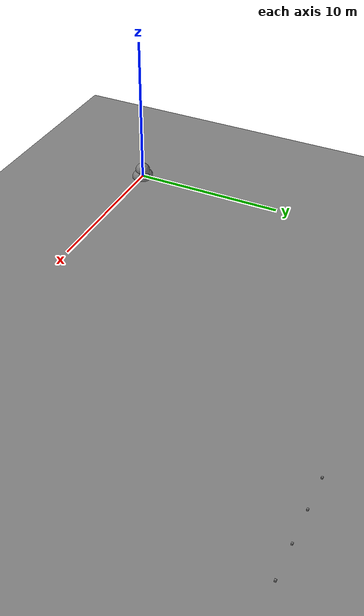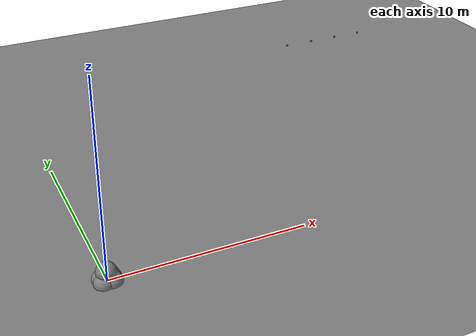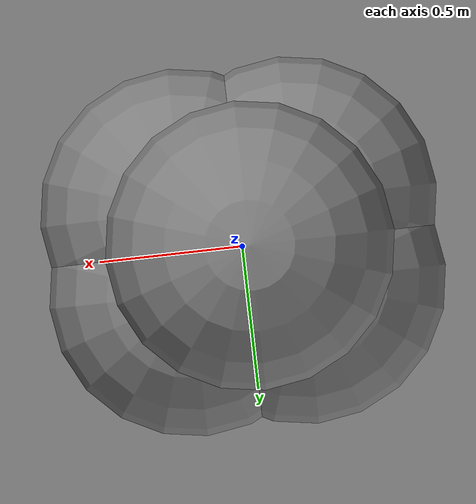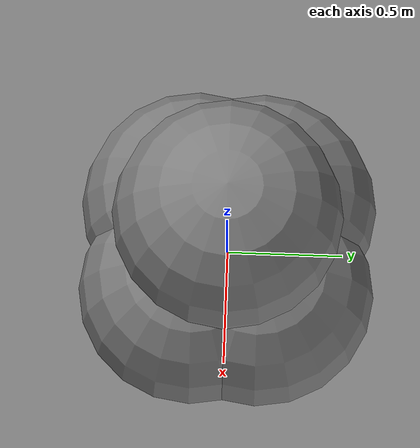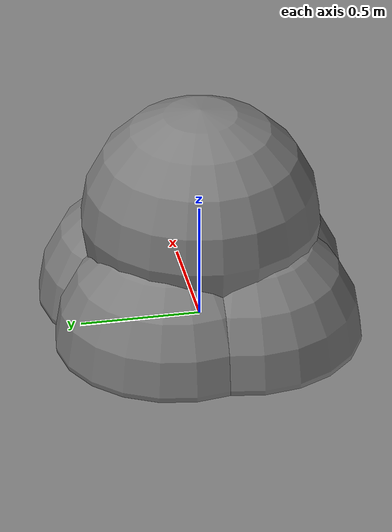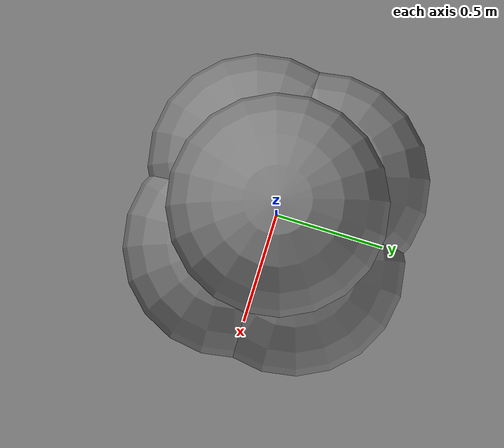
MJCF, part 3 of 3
-0.017836 0.044554 -0.049926 -0.017813 0.045551 -0.050167 -0.015926 0.045705 -0.050206 -0.015527 0.045333 -0.050114 -0.016417 0.044856 -0.049996 -0.017369 0.044794 -0.050005 -0.017345 0.044741 -0.049994 -0.017322 0.045099 -0.050057 -0.016897 0.045727 -0.050296 -0.015435 0.045742 -0.050235 -0.015424 0.045912 -0.050378 -0.014931 0.045041 -0.050084 -0.016879 0.044976 -0.050089 -0.016855 0.044923 -0.050075 -0.016831 0.045513 -0.05023 -0.015928 0.045281 -0.05016 -0.016408 0.045219 -0.050185 -0.01639 0.045152 -0.050187 -0.016365 0.045098 -0.050168 -0.016341 0.04515 -0.050199 -0.016193 0.045457 -0.050275 -0.015919 0.045686 -0.05036 -0.015438 0.045322 -0.050297 -0.015875 0.045268 -0.050275 -0.01585 0.045391 -0.050299 -0.0159 0.045486 -0.050421 -0.015385 0.045433 -0.050394 -0.015359 0.045626 -0.050406 -0.01543 0.045557 -0.050427 -0.015412 0.045896 -0.050441 -0.014945 0.045643 -0.05056 -0.014895 0.045591 -0.050529 -0.014868 0.045853 -0.050506 -0.01495 0.04606 -0.050603 -0.014454 0.046077 -0.050539 -0.014438 0.045716 -0.05057 -0.014923 0.045789 -0.050551 -0.014942 0.045795 -0.050714 -0.014406 0.045744 -0.05068 -0.014378 0.046216 -0.050783 -0.013969 0.046235 -0.050719 -0.01395 0.046013 -0.050669 -0.014462 0.045946 -0.050713 -0.014455 0.045869 -0.050729 -0.014436 0.045939 -0.050886 -0.013922 0.045891 -0.050848 -0.013892 0.045999 -0.050992 -0.013519 0.046364 -0.050984 -0.013492 0.046384 -0.05092 -0.013469 0.046166 -0.050849 -0.01398 0.046447 -0.051277 -0.013044 0.046504 -0.051211 -0.013026 0.046525 -0.051148 -0.012999 0.046095 -0.050893 -0.013974 0.046646 -0.051502 -0.012532 0.046669 -0.051441 -0.012499 0.046014 -0.050906 -0.013954 0.046771 -0.051856 -0.012081 0.046798 -0.051802 -0.012037 0.046365 -0.051318 -0.013042 0.046075 -0.051078 -0.013446 0.046029 -0.051035 -0.013413 0.046703 -0.051914 -0.012118 0.046862 -0.052306 -0.011742 0.046893 -0.052274 -0.01168 0.046277 -0.051324 -0.013019 0.046202 -0.051294 -0.012981 0.04616 -0.051247 -0.012946 0.04616 -0.051248 -0.012945 0.046608 -0.051947 -0.012123 0.046786 -0.05234 -0.011797 0.04633 -0.05157 -0.012488 0.046294 -0.051522 -0.012446 0.046512 -0.051942 -0.012093 0.046442 -0.051905 -0.012038 0.046413 -0.051859 -0.011986 0.046683 -0.052359 -0.011809 0.046803 -0.052579 -0.01173 0.04652 -0.052328 -0.011699 0.046501 -0.052299 -0.011631 0.046584 -0.052353 -0.011772 0.046537 -0.052575 -0.011625 0.046521 -0.052568 -0.01155 0.046522 -0.052645 -0.011545 0.046697 -0.052583 -0.011745 0.046598 -0.052582 -0.011705 0.046532 -0.052829 -0.011647 0.046515 -0.052847 -0.011574 0.046594 -0.052812 -0.011724 0.046693 -0.052809 -0.011764 0.046798 -0.05282 -0.01175 0.046881 -0.05257 -0.011667 0.046799 -0.05282 -0.011749 0.046876 -0.052842 -0.011689 0.046914 -0.052562 -0.011598 0.040832 -0.052645 -0.025401 0.040838 -0.052454 -0.025391 0.040835 -0.05245 -0.025429 0.040829 -0.052712 -0.025438 0.040824 -0.052446 -0.025464 0.040833 -0.052711 -0.0254 0.040818 -0.052714 -0.025473 0.040807 -0.052441 -0.025497 0.040801 -0.052715 -0.025507 0.040819 -0.052987 -0.025479 0.040837 -0.052979 -0.025445 0.040861 -0.053252 -0.025414 0.040846 -0.052972 -0.02541 0.04085 -0.052965 -0.025372 0.040878 -0.053238 -0.02538 0.040923 -0.053502 -0.025317 0.040887 -0.053225 -0.025345 0.040889 -0.053212 -0.025307 0.040939 -0.053482 -0.025284 0.040946 -0.053464 -0.025249 0.040946 -0.053446 -0.02521 0.041016 -0.05371 -0.02516 0.041093 -0.053951 -0.025047 0.041022 -0.053687 -0.025126 0.041105 -0.053866 -0.024942 0.041107 -0.05392 -0.025015 0.041305 -0.054327 -0.024707 0.041111 -0.053892 -0.024981 0.041226 -0.054095 -0.024736 0.041316 -0.054287 -0.024677 0.041538 -0.054636 -0.024325 0.041315 -0.054251 -0.024642 0.041303 -0.054218 -0.024604 0.041546 -0.054588 -0.024296 0.041783 -0.054891 -0.023915 0.04154 -0.054545 -0.024262 0.04152 -0.054507 -0.024223 0.041788 -0.054834 -0.023887 0.042036 -0.0551 -0.023481 0.041777 -0.054785 -0.023853 0.041749 -0.054745 -0.023814 0.042038 -0.055037 -0.023455 0.042292 -0.05527 -0.023032 0.042021 -0.054983 -0.023422 0.041985 -0.054941 -0.023382 0.04229 -0.055201 -0.023008 0.042546 -0.055406 -0.022575 0.042267 -0.055143 -0.022975 0.042223 -0.0551 -0.022936 0.042296 -0.055142 -0.022796 0.042541 -0.055332 -0.022553 0.042669 -0.055461 -0.022349 0.042511 -0.05527 -0.02252 0.042459 -0.055226 -0.02248 0.042789 -0.055433 -0.022089 0.042798 -0.055512 -0.022109 0.043294 -0.055649 -0.021156 0.042753 -0.055368 -0.022057 0.042694 -0.055325 -0.022017 0.043278 -0.055561 -0.021139 0.043771 -0.055701 -0.020184 0.043229 -0.055491 -0.021108 0.043156 -0.055454 -0.021067 0.043687 -0.055532 -0.020141 0.0436 -0.055501 -0.0201 0.043738 -0.055502 -0.019789 0.043881 -0.055496 -0.01946 0.043749 -0.055605 -0.020172 0.044225 -0.055681 -0.019208 0.044218 -0.05563 -0.019207 0.044443 -0.055647 -0.018716 0.044196 -0.055577 -0.0192 0.044435 -0.055594 -0.018717 0.044656 -0.055598 -0.018222 0.044647 -0.055544 -0.018225 0.044862 -0.055534 -0.017727 0.044411 -0.055539 -0.018711 0.044163 -0.055534 -0.019188 0.044852 -0.055479 -0.017731 0.045063 -0.055457 -0.017231 0.04412 -0.055502 -0.01917 0.04462 -0.055487 -0.01822 0.044375 -0.055496 -0.018699 0.045052 -0.0554 -0.017237 0.045257 -0.055366 -0.016736 0.04407 -0.055484 -0.019149 0.044022 -0.055482 -0.019127 0.044823 -0.055421 -0.017728 0.044581 -0.055443 -0.018208 0.044329 -0.055465 -0.018681 0.044275 -0.055449 -0.018659 0.044225 -0.05545 -0.018637 0.044531 -0.055413 -0.01819 0.044474 -0.055399 -0.018168 0.044423 -0.055404 -0.018146 0.044781 -0.055376 -0.017716 0.045021 -0.05534 -0.017234 0.044668 -0.055336 -0.017676 0.044615 -0.055344 -0.017653 0.044727 -0.055347 -0.017699 0.044855 -0.05526 -0.017182 0.044802 -0.055271 -0.017159 0.044975 -0.055295 -0.017224 0.044918 -0.055267 -0.017206 0.045245 -0.055308 -0.016743 0.045036 -0.05517 -0.01669 0.044983 -0.055186 -0.016666 0.04515 -0.055092 -0.016195 0.045211 -0.055247 -0.016742 0.045432 -0.055202 -0.016249 0.045445 -0.055261 -0.01624 0.045627 -0.055142 -0.015745 0.045161 -0.055201 -0.016732 0.045101 -0.055174 -0.016714 0.045211 -0.055068 -0.016197 0.045158 -0.055088 -0.016173 0.045396 -0.055139 -0.01625 0.045613 -0.055081 -0.015755 0.045705 -0.055084 -0.015527 0.045342 -0.055093 -0.01624 0.045278 -0.055069 -0.016222 0.04538 -0.054952 -0.015704 0.045327 -0.054976 -0.015679 0.045574 -0.055018 -0.015757 0.045787 -0.054946 -0.015263 0.045802 -0.055008 -0.015251 0.045449 -0.054949 -0.01573 0.045517 -0.054972 -0.015748 0.045542 -0.054823 -0.015213 0.045489 -0.054851 -0.015186 0.045955 -0.054796 -0.014771 0.045971 -0.054858 -0.014757 0.045745 -0.054882 -0.015267 0.045613 -0.054815 -0.01524 0.045685 -0.054836 -0.015259 0.045697 -0.054679 -0.014722 0.045646 -0.054711 -0.014695 0.046116 -0.054628 -0.014283 0.046133 -0.054691 -0.014266 0.045911 -0.05473 -0.014778 0.045846 -0.054685 -0.01477 0.045771 -0.054667 -0.014751 0.045846 -0.054518 -0.014236 0.045797 -0.054554 -0.014206 0.04627 -0.054441 -0.0138 0.046288 -0.054504 -0.013779 0.046068 -0.054562 -0.014292 0.04592 -0.054502 -0.014266 0.045988 -0.05434 -0.013753 0.045941 -0.05438 -0.013722 0.045999 -0.054299 -0.013519 0.045999 -0.054517 -0.014286 0.046416 -0.05423 -0.013323 0.046436 -0.054293 -0.0133 0.046219 -0.054374 -0.013811 0.046121 -0.054139 -0.013278 0.046077 -0.054183 -0.013244 0.04616 -0.054044 -0.012946 0.046197 -0.054112 -0.013313 0.046283 -0.05412 -0.013336 0.046253 -0.053896 -0.012786 0.046214 -0.053942 -0.012748 0.046561 -0.053974 -0.012831 0.046583 -0.054035 -0.012802 0.046361 -0.054163 -0.013339 0.046372 -0.053611 -0.012322 0.046338 -0.053659 -0.012278 0.046444 -0.053574 -0.01237 0.046693 -0.053673 -0.012366 0.046717 -0.053732 -0.012329 0.046629 -0.05361 -0.012395 0.046735 -0.053251 -0.011997 0.046539 -0.053573 -0.012397 0.046805 -0.053305 -0.011955 0.046833 -0.053354 -0.011907 0.046876 -0.052842 -0.011689 0.046908 -0.052862 -0.011623 0.046637 -0.053222 -0.012005 0.046799 -0.05282 -0.011749 0.046876 -0.052842 -0.011689 0.046798 -0.05282 -0.01175 0.046693 -0.052809 -0.011764 0.046539 -0.053227 -0.011972 0.046594 -0.052812 -0.011724 0.046471 -0.053263 -0.011913 0.046532 -0.052829 -0.011647 0.046445 -0.053306 -0.011857 0.046515 -0.052847 -0.011574 0.040832 -0.052645 -0.025401 0.040833 -0.052711 -0.0254 0.04085 -0.052965 -0.025372 0.040946 -0.053446 -0.02521 0.040889 -0.053212 -0.025307 0.041226 -0.054095 -0.024736 0.041105 -0.053866 -0.024942 0.040884 -0.052645 -0.01946 0.041266 -0.054072 -0.01946 0.040936 -0.052645 -0.013519 0.041311 -0.054046 -0.013519 0.040987 -0.052645 -0.007577 0.041075 -0.053333 -0.007577 0.041356 -0.05402 -0.007577 0.042337 -0.055072 -0.013519 0.042311 -0.055117 -0.01946 0.041793 -0.05459 -0.007577 0.042362 -0.055027 -0.007577 0.04305 -0.055308 -0.007577 0.043737 -0.055395 -0.007577 0.042296 -0.055142 -0.022796 0.043737 -0.055447 -0.013519 0.043737 -0.055499 -0.01946 0.04515 -0.055092 -0.016195 0.045138 -0.055072 -0.013519 0.044425 -0.055308 -0.007577 0.045112 -0.055027 -0.007577 0.046077 -0.054183 -0.013244 0.045682 -0.05459 -0.007577 0.046119 -0.05402 -0.007577 0.045999 -0.054299 -0.013519 0.04616 -0.054044 -0.012946 0.045941 -0.05438 -0.013722 0.046214 -0.053942 -0.012748 0.045797 -0.054554 -0.014206 0.046338 -0.053659 -0.012278 0.046445 -0.053306 -0.011857 0.045646 -0.054711 -0.014695 0.045489 -0.054851 -0.015186 0.045327 -0.054976 -0.015679 0.045158 -0.055088 -0.016173 0.046515 -0.052847 -0.011574 0.0464 -0.053333 -0.007577 0.046487 -0.052645 -0.007577 0.046522 -0.052645 -0.011545 0.040866 -0.052203 -0.025344 0.040838 -0.052454 -0.025391 0.040832 -0.052645 -0.025401 0.040914 -0.051965 -0.025264 0.041226 -0.051196 -0.024736 0.041058 -0.051531 -0.025022 0.040884 -0.052645 -0.01946 0.041266 -0.051219 -0.01946 0.041311 -0.051245 -0.013519 0.040936 -0.052645 -0.013519 0.040987 -0.052645 -0.007577 0.041075 -0.051958 -0.007577 0.041356 -0.05127 -0.007577 0.042337 -0.050219 -0.013519 0.041793 -0.050701 -0.007577 0.042311 -0.050174 -0.01946 0.043737 -0.049844 -0.013519 0.042362 -0.050264 -0.007577 0.043051 -0.049983 -0.007577 0.043738 -0.049895 -0.007577 0.045138 -0.050219 -0.013519 0.044425 -0.049983 -0.007577 0.045113 -0.050264 -0.007577 0.04515 -0.050199 -0.016193 0.042296 -0.050149 -0.022796 0.042391 -0.050098 -0.022613 0.042858 -0.04991 -0.021684 0.043312 -0.049812 -0.020734 0.043737 -0.049789 -0.01979 0.043737 -0.049792 -0.01946 0.04192 -0.0504 -0.023503 0.042155 -0.050233 -0.023064 0.041459 -0.050858 -0.024331 0.041686 -0.050606 -0.023928 0.041245 -0.051164 -0.024703 0.044554 -0.049926 -0.017813 0.044923 -0.050075 -0.016831 0.045098 -0.050168 -0.016341 0.044741 -0.049994 -0.017322 0.044161 -0.049829 -0.018795 0.04436 -0.049871 -0.018304 0.043881 -0.049795 -0.01946 0.043748 -0.049789 -0.019767 0.045268 -0.050275 -0.01585 0.045433 -0.050394 -0.015359 0.045591 -0.050529 -0.014868 0.045744 -0.05068 -0.014378 0.045891 -0.050848 -0.013892 0.045999 -0.050992 -0.013519 0.046029 -0.051035 -0.013413 0.04616 -0.051247 -0.012946 0.045682 -0.050701 -0.007577 0.046119 -0.051271 -0.007577 0.046294 -0.051522 -0.012446 0.04616 -0.051248 -0.012945 0.046413 -0.051859 -0.011986 0.046501 -0.052299 -0.011631 0.0464 -0.051959 -0.007577 0.046487 -0.052645 -0.007577 0.046521 -0.052568 -0.01155 0.046522 -0.052645 -0.011545 0.042473 -0.049921 -0.022707 0.042669 -0.04983 -0.022349 0.042669 -0.048995 -0.022349 0.042219 -0.050065 -0.023161 0.041857 -0.048995 -0.02379 0.041967 -0.050244 -0.023602 0.041716 -0.050465 -0.024029 0.041473 -0.050734 -0.024433 0.040893 -0.048995 -0.025363 0.041243 -0.051062 -0.024807 0.041043 -0.051453 -0.025128 0.039859 -0.048995 -0.026914 0.038755 -0.048995 -0.028439 0.038617 -0.048995 -0.028621 0.038617 -0.056295 -0.028621 0.040888 -0.051917 -0.025371 0.040837 -0.052173 -0.025451 0.040807 -0.052441 -0.025497 0.040801 -0.052715 -0.025507 0.040819 -0.052987 -0.025479 0.040861 -0.053252 -0.025414 0.040923 -0.053502 -0.025317 0.041093 -0.053951 -0.025047 0.037623 -0.056295 -0.029881 0.037623 -0.048995 -0.029881 0.038755 -0.056295 -0.028439 0.039859 -0.056295 -0.026914 0.036427 -0.056295 -0.031291 0.036427 -0.048995 -0.031291 0.035169 -0.048995 -0.032663 0.035169 -0.056295 -0.032663 0.040893 -0.056295 -0.025363 0.041305 -0.054327 -0.024707 0.041538 -0.054636 -0.024325 0.033851 -0.048995 -0.033994 0.033851 -0.056295 -0.033994 0.033645 -0.056295 -0.034193 0.033645 -0.048995 -0.034193 0.041857 -0.056295 -0.02379 0.041783 -0.054891 -0.023915 0.042036 -0.0551 -0.023481 0.032505 -0.056295 -0.035252 0.032505 -0.048995 -0.035252 0.031105 -0.048995 -0.036463 0.031105 -0.056295 -0.036463 0.042669 -0.056295 -0.022349 0.042292 -0.05527 -0.023032 0.042546 -0.055406 -0.022575 0.042669 -0.055461 -0.022349 0.029654 -0.048995 -0.037625 0.029654 -0.056295 -0.037625 0.028154 -0.056295 -0.038733 0.028154 -0.048995 -0.038733 0.027874 -0.056295 -0.03893 0.027874 -0.048995 -0.03893 0.042798 -0.055512 -0.022109 0.04275 -0.056295 -0.022198 0.043294 -0.055649 -0.021156 0.043612 -0.056295 -0.020514 0.043771 -0.055701 -0.020184 0.044225 -0.055681 -0.019208 0.044397 -0.056295 -0.01882 0.044443 -0.055647 -0.018716 0.044656 -0.055598 -0.018222 0.044862 -0.055534 -0.017727 0.045107 -0.056295 -0.01712 0.045063 -0.055457 -0.017231 0.045705 -0.056295 -0.015527 0.045257 -0.055366 -0.016736 0.045445 -0.055261 -0.01624 0.045627 -0.055142 -0.015745 0.045705 -0.055084 -0.015527 0.045802 -0.055008 -0.015251 0.045971 -0.054858 -0.014757 0.046133 -0.054691 -0.014266 0.045743 -0.056295 -0.015419 0.046319 -0.056295 -0.013682 0.046288 -0.054504 -0.013779 0.046436 -0.054293 -0.0133 0.046583 -0.054035 -0.012802 0.046829 -0.056295 -0.01192 0.046717 -0.053732 -0.012329 0.047279 -0.056295 -0.010112 0.046833 -0.053354 -0.011907 0.046908 -0.052862 -0.011623 0.046914 -0.052562 -0.011598 0.046829 -0.048995 -0.01192 0.046893 -0.052274 -0.01168 0.046798 -0.051802 -0.012037 0.046669 -0.051441 -0.012499 0.046525 -0.051148 -0.012999 0.046384 -0.05092 -0.013469 0.046235 -0.050719 -0.01395 0.046077 -0.050539 -0.014438 0.045912 -0.050378 -0.014931 0.045742 -0.050235 -0.015424 0.045705 -0.050206 -0.015527 0.047279 -0.048995 -0.010112 0.047652 -0.048995 -0.008318 0.047652 -0.056295 -0.008318 0.046319 -0.048995 -0.013682 0.045743 -0.048995 -0.015419 0.045565 -0.050106 -0.015917 0.045705 -0.048995 -0.015527 0.045382 -0.049993 -0.016409 0.045193 -0.049893 -0.016902 0.045107 -0.048995 -0.01712 0.044998 -0.049807 -0.017395 0.044796 -0.049734 -0.017888 0.044588 -0.049676 -0.018381 0.044397 -0.048995 -0.01882 0.044374 -0.049632 -0.018874 0.04393 -0.049589 -0.01985 0.043612 -0.048995 -0.020514 0.043461 -0.049615 -0.020821 0.042974 -0.04972 -0.021776 0.04275 -0.048995 -0.022198 0.042725 -0.049807 -0.022246 0.019814 -0.048995 -0.030481 0.021287 -0.048995 -0.029503 0.021287 -0.049747 -0.029503 0.018196 -0.048995 -0.031442 0.018183 -0.049747 -0.031449 0.016534 -0.048995 -0.032318 0.014409 -0.049747 -0.033287 0.014831 -0.048995 -0.033107 0.014409 -0.048995 -0.033287 0.013093 -0.048995 -0.033807 0.011328 -0.048995 -0.034416 0.011312 -0.049747 -0.034421 0.009509 -0.048995 -0.03494 0.006883 -0.049747 -0.035523 0.007677 -0.048995 -0.035368 0.006883 -0.048995 -0.035523 0.005838 -0.048995 -0.0357 0.004 -0.048995 -0.035936 0.003981 -0.049747 -0.035938 0.002098 -0.048995 -0.036082 -0.000946 -0.049747 -0.03611 0.000211 -0.048995 -0.036129 -0.000946 -0.048995 -0.03611 -0.001651 -0.048995 -0.03608 -0.003484 -0.048995 -0.03594 -0.003506 -0.049747 -0.035938 -0.005392 -0.048995 -0.035695 -0.008721 -0.049747 -0.03502 -0.007254 -0.048995 -0.035357 -0.008721 -0.048995 -0.03502 -0.009062 -0.048995 -0.034933 -0.010813 -0.048995 -0.034428 -0.010837 -0.049747 -0.034421 -0.012539 -0.048995 -0.033837 -0.014265 -0.048995 -0.033146 -0.015985 -0.048995 -0.032354 0.021287 -0.055544 -0.029503 0.021287 -0.056295 -0.029503 0.019814 -0.056295 -0.030481 0.018196 -0.056295 -0.031442 0.018183 -0.055544 -0.031449 0.016534 -0.056295 -0.032318 0.014409 -0.055544 -0.033287 0.014831 -0.056295 -0.033107 0.014409 -0.056295 -0.033287 0.013093 -0.056295 -0.033807 0.011328 -0.056295 -0.034416 0.011312 -0.055544 -0.034421 0.009509 -0.056295 -0.03494 0.006883 -0.055544 -0.035523 0.007677 -0.056295 -0.035368 0.006883 -0.056295 -0.035523 0.005838 -0.056295 -0.0357 0.004 -0.056295 -0.035936 0.003981 -0.055544 -0.035938 0.002098 -0.056295 -0.036082 -0.000946 -0.055544 -0.03611 0.000211 -0.056295 -0.036129 -0.000946 -0.056295 -0.03611 -0.001651 -0.056295 -0.03608 -0.003484 -0.056295 -0.03594 -0.003506 -0.055544 -0.035938 -0.005392 -0.056295 -0.035695 -0.008721 -0.055544 -0.03502 -0.007254 -0.056295 -0.035357 -0.008721 -0.056295 -0.03502 -0.009062 -0.056295 -0.034933 -0.010813 -0.056295 -0.034428 -0.010837 -0.055544 -0.034421 -0.012539 -0.056295 -0.033837 -0.014265 -0.056295 -0.033146 -0.015985 -0.056295 -0.032354 -0.036532 -0.056295 -0.000662 -0.036483 -0.056295 -0.000859 -0.03655 -0.056545 -0.000861 -0.036607 -0.056512 -0.000629 -0.036549 -0.056295 -0.000629 -0.036655 -0.056295 -0.000501 -0.036766 -0.05667 -0.000629 -0.036732 -0.056728 -0.000869 -0.036766 -0.05642 -0.000446 -0.036732 -0.056295 -0.000446 -0.036832 -0.056295 -0.000402 -0.036982 -0.056295 -0.000379 -0.036857 -0.056512 -0.000446 -0.036982 -0.056295 -0.000379 -0.036982 -0.056728 -0.000629 -0.036982 -0.056795 -0.000879 -0.036982 -0.056545 -0.000446 -0.036982 -0.056295 -0.000379 -0.036532 -0.055544 -0.000662 -0.036483 -0.055544 -0.000859 -0.036483 -0.056295 -0.000859 -0.036532 -0.056295 -0.000662 -0.036549 -0.056295 -0.000629 -0.036556 -0.055544 -0.000617 -0.036655 -0.056295 -0.000501 -0.036655 -0.055544 -0.000501 -0.036732 -0.056295 -0.000446 -0.036738 -0.055544 -0.000443 -0.036832 -0.056295 -0.000402 -0.036832 -0.055544 -0.000402 -0.036532 -0.049747 -0.000662 -0.036483 -0.049747 -0.000859 -0.036483 -0.052645 -0.000859 -0.036556 -0.052645 -0.000617 -0.036556 -0.049747 -0.000617 -0.036655 -0.049747 -0.000501 -0.036738 -0.052645 -0.000443 -0.036738 -0.049747 -0.000443 -0.036832 -0.049747 -0.000402 -0.036532 -0.055544 -0.000662 -0.036483 -0.055544 -0.000859 -0.036556 -0.055544 -0.000617 -0.036655 -0.055544 -0.000501 -0.036738 -0.055544 -0.000443 -0.036832 -0.055544 -0.000402 -0.036982 -0.052645 -0.000379 -0.036982 -0.049747 -0.000379 -0.036982 -0.055544 -0.000379 -0.03655 -0.048746 -0.000861 -0.036483 -0.048995 -0.000859 -0.036532 -0.048995 -0.000662 -0.036607 -0.048779 -0.000629 -0.036549 -0.048995 -0.000629 -0.036655 -0.048995 -0.000501 -0.036766 -0.04862 -0.000629 -0.036732 -0.048563 -0.000869 -0.036766 -0.04887 -0.000446 -0.036732 -0.048995 -0.000446 -0.036832 -0.048995 -0.000402 -0.036982 -0.048995 -0.000379 -0.036857 -0.048779 -0.000446 -0.036982 -0.048995 -0.000379 -0.036982 -0.048562 -0.000629 -0.036982 -0.048495 -0.000879 -0.036982 -0.048745 -0.000446 -0.036982 -0.048995 -0.000379 -0.036532 -0.048995 -0.000662 -0.036483 -0.048995 -0.000859 -0.036483 -0.049747 -0.000859 -0.036532 -0.049747 -0.000662 -0.036549 -0.048995 -0.000629 -0.036556 -0.049747 -0.000617 -0.036655 -0.048995 -0.000501 -0.036655 -0.049747 -0.000501 -0.036732 -0.048995 -0.000446 -0.036738 -0.049747 -0.000443 -0.036832 -0.048995 -0.000402 -0.036832 -0.049747 -0.000402 -0.040473 -0.051849 -0.025209 -0.040631 -0.051429 -0.024941 -0.040754 -0.051197 -0.024732 -0.04036 -0.052645 -0.025397 -0.040376 -0.052336 -0.025369 -0.040415 -0.052086 -0.025305 -0.04036 -0.052594 -0.025397 -0.040412 -0.052645 -0.019391 -0.040794 -0.05122 -0.019391 -0.040839 -0.051247 -0.013385 -0.041837 -0.050177 -0.019391 -0.040464 -0.052645 -0.013385 -0.040517 -0.052645 -0.007379 -0.040885 -0.051273 -0.007379 -0.041863 -0.050222 -0.013385 -0.04189 -0.050268 -0.007379 -0.043262 -0.049795 -0.019391 -0.043262 -0.049847 -0.013385 -0.043263 -0.0499 -0.007379 -0.041822 -0.050151 -0.022794 -0.044662 -0.050222 -0.013385 -0.044635 -0.050268 -0.007379 -0.044674 -0.050201 -0.016199 -0.045682 -0.051248 -0.012955 -0.045626 -0.051152 -0.013158 -0.045562 -0.051052 -0.013386 -0.04564 -0.051273 -0.007379 -0.045488 -0.050946 -0.013643 -0.045755 -0.051388 -0.012686 -0.045343 -0.050764 -0.014135 -0.045872 -0.051665 -0.012241 -0.045193 -0.050605 -0.014625 -0.045995 -0.052113 -0.011757 -0.046034 -0.0524 -0.011598 -0.046045 -0.052645 -0.011555 -0.046008 -0.052645 -0.007379 -0.045036 -0.050462 -0.015118 -0.044873 -0.050334 -0.015614 -0.044704 -0.05022 -0.016111 -0.044347 -0.050031 -0.017106 -0.044529 -0.050119 -0.016609 -0.043968 -0.049895 -0.018097 -0.04416 -0.049956 -0.017602 -0.043565 -0.049814 -0.019085 -0.043435 -0.0498 -0.019391 -0.043263 -0.049792 -0.019789 -0.043139 -0.049792 -0.020069 -0.042693 -0.049838 -0.021042 -0.042231 -0.049964 -0.021994 -0.041995 -0.050063 -0.022461 -0.041517 -0.050348 -0.02337 -0.041756 -0.050189 -0.02292 -0.041048 -0.050784 -0.024218 -0.041279 -0.050545 -0.023805 -0.040828 -0.051077 -0.024603 -0.040693 -0.054092 -0.024929 -0.040582 -0.053863 -0.025106 -0.040594 -0.053841 -0.025081 -0.040703 -0.054066 -0.024905 -0.040813 -0.054296 -0.024734 -0.040596 -0.053835 -0.025073 -0.040823 -0.054266 -0.024711 -0.040942 -0.05448 -0.024525 -0.040708 -0.054042 -0.02488 -0.040599 -0.053822 -0.025056 -0.040707 -0.05402 -0.024854 -0.040601 -0.053809 -0.025039 -0.040601 -0.053803 -0.02503 -0.040596 -0.053785 -0.025001 -0.0407 -0.053999 -0.024824 -0.040754 -0.054094 -0.024732 -0.04095 -0.054446 -0.024503 -0.041076 -0.054647 -0.024304 -0.040826 -0.054239 -0.024687 -0.040822 -0.054214 -0.024661 -0.040812 -0.05419 -0.024631 -0.041084 -0.054609 -0.024282 -0.041216 -0.054797 -0.024071 -0.040951 -0.054416 -0.024479 -0.040945 -0.054388 -0.024452 -0.040932 -0.054362 -0.024423 -0.041222 -0.054755 -0.02405 -0.041357 -0.05493 -0.023832 -0.041083 -0.054575 -0.024258 -0.041074 -0.054545 -0.024232 -0.041057 -0.054517 -0.024202 -0.041362 -0.054886 -0.023812 -0.041456 -0.055014 -0.023663 -0.041219 -0.054719 -0.024026 -0.041208 -0.054687 -0.024 -0.041187 -0.054657 -0.02397 -0.041503 -0.055001 -0.023569 -0.041642 -0.055154 -0.023341 -0.041357 -0.054847 -0.023789 -0.041343 -0.054812 -0.023763 -0.041319 -0.054782 -0.023733 -0.041615 -0.055022 -0.023273 -0.041585 -0.054991 -0.023243 -0.041822 -0.05514 -0.022793 -0.041496 -0.05496 -0.023546 -0.041644 -0.055104 -0.023322 -0.041928 -0.05533 -0.022834 -0.041635 -0.05506 -0.0233 -0.041928 -0.055275 -0.022817 -0.042214 -0.055467 -0.022312 -0.041889 -0.055186 -0.022769 -0.041851 -0.055156 -0.022738 -0.041914 -0.055227 -0.022795 -0.042211 -0.055406 -0.022297 -0.042499 -0.055568 -0.021778 -0.042162 -0.055313 -0.022249 -0.042118 -0.055283 -0.022218 -0.042193 -0.055355 -0.022275 -0.042493 -0.055504 -0.021764 -0.042777 -0.055639 -0.021238 -0.042433 -0.055405 -0.021717 -0.042383 -0.055378 -0.021686 -0.04247 -0.055449 -0.021744 -0.042769 -0.05557 -0.021227 -0.04305 -0.055681 -0.020692 -0.042698 -0.055468 -0.021181 -0.042641 -0.055443 -0.021149 -0.042741 -0.055512 -0.021207 -0.043039 -0.055609 -0.020683 -0.043316 -0.055699 -0.020144 -0.042958 -0.055505 -0.020637 -0.042895 -0.055483 -0.020605 -0.043007 -0.055549 -0.020664 -0.043303 -0.055624 -0.020137 -0.043574 -0.055694 -0.019593 -0.04321 -0.055517 -0.020091 -0.043142 -0.055499 -0.020058 -0.043263 -0.055499 -0.019786 -0.043266 -0.05556 -0.020118 -0.043559 -0.055615 -0.019588 -0.043825 -0.055668 -0.01904 -0.043456 -0.055508 -0.019543 -0.043383 -0.055494 -0.01951 -0.043434 -0.055491 -0.019391 -0.043517 -0.05555 -0.01957 -0.043807 -0.055586 -0.019037 -0.044069 -0.055623 -0.018485 -0.043693 -0.055478 -0.018993 -0.043617 -0.05547 -0.01896 -0.04376 -0.055519 -0.01902 -0.044048 -0.055538 -0.018484 -0.044305 -0.055559 -0.017928 -0.043923 -0.05543 -0.018441 -0.043844 -0.055427 -0.018407 -0.043996 -0.055469 -0.018469 -0.044282 -0.055471 -0.01793 -0.044534 -0.055477 -0.017368 -0.044146 -0.055364 -0.017887 -0.044064 -0.055367 -0.017853 -0.044225 -0.055401 -0.017915 -0.044508 -0.055387 -0.017373 -0.044755 -0.055377 -0.016806 -0.044569 -0.05518 -0.016773 -0.044483 -0.055196 -0.016736 -0.044674 -0.05509 -0.016195 -0.04466 -0.055212 -0.016802 -0.044727 -0.055284 -0.016814 -0.045141 -0.055026 -0.015698 -0.044884 -0.055308 -0.01647 -0.045174 -0.055123 -0.015685 -0.045557 -0.054795 -0.014575 -0.04496 -0.054929 -0.015659 -0.04487 -0.054959 -0.015619 -0.045062 -0.054952 -0.015689 -0.045546 -0.054746 -0.014588 -0.045519 -0.054694 -0.014596 -0.045725 -0.054547 -0.014036 -0.045737 -0.054595 -0.014021 -0.045895 -0.05432 -0.013492 -0.045908 -0.054368 -0.013474 -0.045696 -0.054494 -0.014047 -0.045479 -0.054652 -0.014598 -0.045427 -0.054621 -0.014591 -0.045653 -0.054451 -0.01405 -0.046055 -0.054056 -0.012958 -0.046069 -0.054105 -0.012936 -0.045863 -0.054267 -0.013506 -0.04602 -0.054004 -0.012977 -0.046201 -0.053744 -0.012448 -0.046217 -0.053791 -0.01242 -0.045817 -0.054224 -0.013511 -0.045597 -0.054421 -0.014044 -0.04537 -0.054605 -0.014577 -0.046163 -0.053694 -0.012473 -0.046339 -0.053306 -0.011946 -0.046358 -0.053344 -0.011907 -0.04597 -0.053962 -0.012985 -0.045315 -0.054607 -0.014558 -0.045757 -0.054195 -0.013506 -0.045537 -0.054408 -0.01403 -0.045263 -0.054625 -0.014535 -0.045227 -0.054652 -0.014514 -0.04548 -0.054413 -0.01401 -0.045429 -0.054436 -0.013985 -0.045395 -0.054465 -0.013963 -0.045584 -0.054221 -0.013442 -0.045553 -0.054253 -0.013418 -0.045562 -0.054239 -0.013385 -0.045682 -0.054043 -0.012954 -0.045693 -0.054185 -0.013491 -0.045635 -0.054194 -0.013469 -0.04573 -0.053971 -0.012909 -0.045702 -0.054007 -0.012882 -0.045906 -0.053934 -0.012981 -0.045838 -0.053927 -0.012965 -0.045779 -0.053941 -0.01294 -0.045862 -0.053677 -0.012401 -0.045839 -0.053713 -0.012369 -0.046109 -0.053654 -0.012486 -0.046039 -0.053629 -0.012484 -0.045968 -0.053626 -0.012466 -0.045908 -0.053643 -0.012437 -0.045986 -0.053265 -0.011899 -0.04597 -0.053297 -0.011857 -0.046236 -0.053231 -0.012005 -0.04616 -0.053212 -0.012006 -0.046085 -0.053213 -0.011985 -0.046026 -0.053232 -0.011947 -0.04603 -0.053008 -0.01171 -0.046019 -0.053032 -0.011662 -0.046296 -0.053264 -0.011983 -0.046279 -0.05298 -0.011832 -0.0462 -0.052967 -0.011836 -0.0463 -0.052709 -0.011749 -0.046344 -0.053003 -0.011804 -0.046066 -0.052984 -0.011767 -0.046123 -0.052969 -0.011812 -0.046389 -0.053033 -0.011757 -0.04641 -0.05306 -0.011711 -0.046218 -0.052707 -0.011755 -0.046141 -0.052707 -0.011728 -0.046085 -0.052711 -0.011678 -0.046367 -0.052715 -0.011715 -0.046415 -0.052721 -0.011661 -0.046437 -0.052727 -0.011608 -0.046427 -0.052383 -0.011647 -0.046405 -0.052401 -0.011697 -0.046385 -0.052075 -0.011807 -0.046358 -0.052421 -0.011748 -0.046365 -0.052108 -0.011849 -0.046252 -0.051595 -0.012292 -0.046236 -0.051639 -0.012322 -0.046228 -0.051652 -0.012329 -0.046321 -0.052146 -0.01189 -0.046198 -0.051689 -0.012349 -0.046292 -0.052437 -0.011779 -0.046258 -0.052175 -0.011915 -0.046181 -0.052192 -0.011917 -0.046165 -0.051714 -0.01236 -0.046142 -0.051728 -0.012363 -0.046073 -0.051751 -0.012362 -0.046071 -0.051752 -0.012362 -0.045999 -0.051754 -0.012344 -0.046212 -0.052446 -0.011785 -0.046105 -0.05219 -0.011894 -0.045978 -0.05175 -0.012335 -0.045939 -0.051736 -0.012313 -0.046135 -0.052444 -0.011759 -0.046047 -0.052172 -0.011854 -0.045906 -0.051713 -0.012286 -0.046078 -0.052434 -0.011711 -0.046009 -0.052142 -0.011802 -0.045894 -0.051701 -0.012274 -0.045872 -0.051665 -0.012241 -0.045995 -0.052113 -0.011757 -0.046044 -0.052417 -0.01165 -0.046034 -0.0524 -0.011598 -0.046045 -0.052645 -0.011555 -0.046052 -0.052716 -0.011614 -0.046044 -0.052722 -0.011559 -0.015997 -0.048995 -0.044816 -0.017724 -0.048995 -0.044161 -0.017753 -0.056295 -0.04415 -0.014271 -0.048995 -0.045396 -0.012531 -0.048995 -0.045909 -0.017724 -0.056295 -0.044161 -0.015997 -0.056295 -0.044816 -0.014271 -0.056295 -0.045396 -0.010746 -0.048995 -0.046362 -0.010139 -0.048995 -0.0465 -0.012531 -0.056295 -0.045909 -0.010746 -0.056295 -0.046362 -0.010139 -0.056295 -0.0465 -0.008919 -0.048995 -0.046752 -0.007054 -0.048995 -0.047075 -0.005246 -0.048995 -0.047316 -0.008919 -0.056295 -0.046752 -0.007054 -0.056295 -0.047075 -0.00341 -0.048995 -0.047491 -0.002242 -0.048995 -0.047565 -0.005246 -0.056295 -0.047316 -0.00341 -0.056295 -0.047491 -0.002242 -0.056295 -0.047565 -0.001548 -0.048995 -0.047596 -0.001548 -0.056295 -0.047596 0.000336 -0.056295 -0.047629 0.000336 -0.048995 -0.047629 0.002168 -0.048995 -0.04759 0.002168 -0.056295 -0.04759 0.004012 -0.056295 -0.047481 0.004012 -0.048995 -0.047481 0.005722 -0.048995 -0.047316 0.005722 -0.056295 -0.047316 0.007723 -0.048995 -0.047045 0.005865 -0.048995 -0.0473 0.009536 -0.048995 -0.046724 0.011344 -0.048995 -0.046333 0.005865 -0.056295 -0.0473 0.007723 -0.056295 -0.047045 0.009536 -0.056295 -0.046724 0.013145 -0.048995 -0.04587 0.013536 -0.048995 -0.04576 0.011344 -0.056295 -0.046333 0.013145 -0.056295 -0.04587 0.013536 -0.056295 -0.04576 0.014934 -0.048995 -0.045336 0.014934 -0.056295 -0.045336 0.016684 -0.048995 -0.04474 0.016684 -0.056295 -0.04474 0.018413 -0.056295 -0.044074 0.018413 -0.048995 -0.044074 0.02012 -0.056295 -0.043342 0.02012 -0.048995 -0.043342 0.020988 -0.048995 -0.042939 0.020988 -0.056295 -0.042939 0.021798 -0.056295 -0.042544 0.021798 -0.048995 -0.042544 0.023443 -0.056295 -0.041682 0.023443 -0.048995 -0.041682 0.025053 -0.048995 -0.040758 0.025053 -0.056295 -0.040758 0.026624 -0.056295 -0.039775 0.026624 -0.048995 -0.039775 0.027874 -0.056295 -0.03893 0.027874 -0.048995 -0.03893 -0.044674 -0.05509 -0.016195 -0.044483 -0.055196 -0.016736 -0.044064 -0.055367 -0.017853 -0.043263 -0.055496 -0.019391 -0.043844 -0.055427 -0.018407 -0.043617 -0.05547 -0.01896 -0.043434 -0.055491 -0.019391 -0.043383 -0.055494 -0.01951 -0.043263 -0.055499 -0.019786 -0.043142 -0.055499 -0.020058 -0.041837 -0.055114 -0.019391 -0.042895 -0.055483 -0.020605 -0.042641 -0.055443 -0.021149 -0.042383 -0.055378 -0.021686 -0.041822 -0.05514 -0.022793 -0.042118 -0.055283 -0.022218 -0.041851 -0.055156 -0.022738 -0.043263 -0.055444 -0.013385 -0.044662 -0.055069 -0.013385 -0.04487 -0.054959 -0.015619 -0.045227 -0.054652 -0.014514 -0.045395 -0.054465 -0.013963 -0.045553 -0.054253 -0.013418 -0.045562 -0.054239 -0.013385 -0.045682 -0.054043 -0.012954 -0.041864 -0.055069 -0.013385 -0.043263 -0.055391 -0.007379 -0.044635 -0.055023 -0.007379 -0.04564 -0.054018 -0.007379 -0.04189 -0.055023 -0.007379 -0.045702 -0.054007 -0.012882 -0.045839 -0.053713 -0.012369 -0.04597 -0.053297 -0.011857 -0.046019 -0.053032 -0.011662 -0.046044 -0.052722 -0.011559 -0.046045 -0.052645 -0.011555 -0.046008 -0.052645 -0.007379 -0.040885 -0.054018 -0.007379 -0.040839 -0.054044 -0.013385 -0.040517 -0.052645 -0.007379 -0.040464 -0.052645 -0.013385 -0.040794 -0.054071 -0.019391 -0.040412 -0.052645 -0.019391 -0.040754 -0.054094 -0.024732 -0.04036 -0.052645 -0.025397 -0.041187 -0.054657 -0.02397 -0.041585 -0.054991 -0.023243 -0.041319 -0.054782 -0.023733 -0.040932 -0.054362 -0.024423 -0.041057 -0.054517 -0.024202 -0.040812 -0.05419 -0.024631 -0.040447 -0.053348 -0.025252 -0.040596 -0.053785 -0.025001 -0.0407 -0.053999 -0.024824 -0.040397 -0.053106 -0.025336 -0.040367 -0.052853 -0.025385 -0.045163 -0.052645 -0.002179 -0.045163 -0.052645 -0.007379 -0.044908 -0.053595 -0.007379 -0.044908 -0.053595 -0.002179 -0.044213 -0.054291 -0.002179 -0.044213 -0.054291 -0.007379 -0.043263 -0.054545 -0.002179 -0.043263 -0.054545 -0.007379 -0.042313 -0.054291 -0.007379 -0.042313 -0.054291 -0.002179 -0.041617 -0.053595 -0.007379 -0.041617 -0.053595 -0.002179 -0.041363 -0.052645 -0.007379 -0.041363 -0.052645 -0.002179 -0.045163 -0.052645 -0.007379 -0.045163 -0.052645 -0.002179 -0.044908 -0.051696 -0.002179 -0.044908 -0.051696 -0.007379 -0.044213 -0.051 -0.002179 -0.044213 -0.051 -0.007379 -0.043263 -0.050745 -0.002179 -0.043263 -0.050745 -0.007379 -0.042313 -0.051 -0.007379 -0.042313 -0.051 -0.002179 -0.041617 -0.051695 -0.007379 -0.041617 -0.051695 -0.002179 -0.041363 -0.052645 -0.002179 -0.041363 -0.052645 -0.007379 -0.047714 -0.056742 -0.000886 -0.047489 -0.056795 -0.000879 -0.047397 -0.056795 -0.002697 -0.047647 -0.056729 -0.002715 -0.047739 -0.056729 -0.000887 -0.047891 -0.056593 -0.000892 -0.047483 -0.056729 -0.004552 -0.047234 -0.056795 -0.004525 -0.047829 -0.056545 -0.002727 -0.047922 -0.056545 -0.000893 -0.047981 -0.05638 -0.000894 -0.047247 -0.056729 -0.006395 -0.047 -0.056795 -0.006359 -0.047896 -0.056295 -0.002732 -0.047989 -0.056295 -0.000895 -0.047665 -0.056545 -0.004572 -0.047732 -0.056295 -0.004579 -0.047428 -0.056545 -0.006422 -0.047494 -0.056295 -0.006432 -0.046938 -0.056729 -0.00824 -0.046692 -0.056795 -0.008194 -0.047117 -0.056545 -0.008273 -0.047183 -0.056295 -0.008286 -0.047082 -0.056295 -0.008811 -0.046564 -0.056729 -0.01004 -0.04632 -0.056795 -0.009984 -0.046742 -0.056545 -0.01008 -0.046807 -0.056295 -0.010095 -0.046119 -0.056729 -0.011833 -0.045877 -0.056795 -0.011768 -0.046295 -0.056545 -0.01188 -0.04636 -0.056295 -0.011898 -0.045603 -0.056729 -0.013615 -0.045364 -0.056795 -0.013541 -0.045778 -0.056545 -0.013669 -0.045842 -0.056295 -0.013689 -0.045016 -0.056729 -0.015382 -0.044781 -0.056795 -0.015299 -0.045189 -0.056545 -0.015443 -0.045252 -0.056295 -0.015465 -0.044884 -0.056295 -0.01647 -0.044367 -0.056729 -0.017111 -0.044135 -0.056795 -0.017019 -0.044537 -0.056545 -0.017179 -0.044599 -0.056295 -0.017203 -0.043651 -0.056729 -0.018817 -0.043422 -0.056795 -0.018716 -0.043818 -0.056545 -0.018891 -0.043879 -0.056295 -0.018918 -0.042868 -0.056729 -0.020496 -0.042643 -0.056795 -0.020386 -0.043032 -0.056545 -0.020577 -0.043092 -0.056295 -0.020606 -0.04202 -0.056728 -0.022145 -0.0418 -0.056795 -0.022026 -0.042181 -0.056545 -0.022231 -0.04224 -0.056295 -0.022263 -0.041456 -0.056295 -0.023663 -0.041109 -0.056728 -0.02376 -0.040894 -0.056795 -0.023633 -0.041267 -0.056545 -0.023853 -0.041325 -0.056295 -0.023887 -0.040137 -0.056728 -0.025338 -0.039927 -0.056795 -0.025203 -0.040291 -0.056545 -0.025437 -0.040348 -0.056295 -0.025473 -0.039107 -0.056728 -0.026875 -0.038902 -0.056795 -0.026731 -0.037822 -0.056795 -0.028215 -0.039257 -0.056545 -0.026979 -0.039312 -0.056295 -0.027018 -0.03822 -0.056295 -0.028517 -0.038021 -0.056728 -0.028366 -0.036674 -0.056795 -0.029671 -0.038167 -0.056545 -0.028477 -0.03706 -0.056295 -0.029988 -0.036867 -0.056728 -0.02983 -0.035475 -0.056795 -0.031075 -0.037009 -0.056545 -0.029946 -0.036891 -0.056295 -0.030193 -0.035662 -0.056728 -0.031241 -0.034229 -0.056795 -0.032426 -0.035799 -0.056545 -0.031363 -0.035849 -0.056295 -0.031407 -0.03459 -0.056295 -0.032772 -0.03441 -0.056728 -0.032599 -0.03294 -0.056795 -0.03372 -0.034542 -0.056545 -0.032725 -0.033287 -0.056295 -0.03408 -0.033113 -0.056728 -0.0339 -0.031576 -0.056795 -0.034988 -0.033241 -0.056545 -0.034032 -0.031909 -0.056295 -0.035361 -0.031742 -0.056728 -0.035174 -0.030173 -0.056795 -0.036193 -0.031864 -0.056545 -0.035311 -0.031313 -0.056295 -0.035884 -0.030332 -0.056728 -0.036385 -0.028737 -0.056795 -0.037334 -0.030449 -0.056545 -0.036527 -0.030492 -0.056295 -0.036578 -0.02904 -0.056295 -0.037731 -0.028888 -0.056728 -0.037532 -0.02727 -0.056795 -0.03841 -0.028999 -0.056545 -0.037678 -0.027558 -0.056295 -0.038818 -0.027414 -0.056728 -0.038614 -0.02572 -0.056795 -0.039457 -0.027519 -0.056545 -0.038764 -0.025992 -0.056295 -0.039877 -0.025856 -0.056728 -0.039667 -0.024146 -0.056795 -0.040434 -0.025955 -0.056545 -0.039821 -0.024875 -0.056295 -0.040578 -0.024274 -0.056729 -0.040649 -0.022554 -0.056795 -0.041339 -0.024367 -0.056545 -0.040806 -0.024402 -0.056295 -0.040864 -0.022793 -0.056295 -0.041778 -0.022673 -0.056729 -0.041558 -0.020947 -0.056795 -0.042172 -0.02276 -0.056545 -0.041719 -0.021169 -0.056295 -0.04262 -0.021058 -0.056729 -0.042396 -0.019246 -0.056795 -0.042973 -0.021139 -0.056545 -0.04256 -0.01945 -0.056295 -0.04343 -0.019348 -0.056729 -0.043201 -0.017538 -0.056795 -0.043697 -0.019422 -0.056545 -0.043369 -0.017753 -0.056295 -0.04415 -0.017631 -0.056729 -0.043929 -0.015828 -0.056795 -0.044345 -0.017699 -0.056545 -0.044099 -0.017724 -0.056295 -0.044161 -0.015997 -0.056295 -0.044816 -0.015912 -0.056729 -0.04458 -0.014121 -0.056795 -0.044919 -0.014196 -0.056729 -0.045157 -0.014251 -0.056545 -0.045332 -0.015974 -0.056545 -0.044753 -0.014271 -0.056295 -0.045396 -0.047694 -0.056447 -0.000449 -0.04774 -0.056339 -0.000449 -0.047489 -0.056295 -0.000379 -0.047841 -0.056556 -0.000638 -0.047686 -0.056687 -0.000638 -0.047604 -0.056523 -0.000449 -0.047489 -0.056295 -0.000379 -0.047921 -0.05637 -0.000638 -0.047744 -0.056295 -0.000449 -0.047489 -0.056295 -0.000379 -0.047927 -0.056295 -0.000638 -0.047981 -0.05638 -0.000894 -0.047989 -0.056295 -0.000895 -0.047922 -0.056545 -0.000893 -0.047891 -0.056593 -0.000892 -0.047739 -0.056729 -0.000887 -0.047714 -0.056742 -0.000886 -0.047489 -0.056795 -0.000879 -0.047489 -0.056734 -0.000638 -0.047489 -0.056729 -0.000629 -0.047489 -0.05655 -0.000449 -0.047489 -0.056545 -0.000446 -0.047489 -0.056295 -0.000379 -0.047489 -0.05447 -0.000379 -0.047489 -0.056295 -0.000379 -0.047744 -0.056295 -0.000449 -0.047744 -0.05447 -0.000449 -0.047927 -0.056295 -0.000638 -0.047744 -0.052645 -0.000449 -0.047489 -0.052645 -0.000379 -0.047927 -0.05447 -0.000638 -0.047744 -0.05082 -0.000449 -0.047489 -0.05082 -0.000379 -0.047989 -0.05447 -0.000895 -0.047989 -0.056295 -0.000895 -0.047927 -0.052645 -0.000638 -0.047989 -0.052645 -0.000895 -0.047927 -0.05082 -0.000638 -0.047989 -0.05082 -0.000895 -0.047927 -0.048995 -0.000638 -0.047989 -0.048995 -0.000895 -0.047744 -0.048995 -0.000449 -0.047489 -0.048995 -0.000379 -0.039609 -0.056295 -0.000379 -0.036982 -0.056295 -0.000379 -0.036982 -0.056545 -0.000446 -0.039609 -0.056545 -0.000446 -0.036982 -0.056728 -0.000629 -0.042236 -0.056545 -0.000446 -0.042236 -0.056295 -0.000379 -0.044862 -0.056545 -0.000446 -0.044862 -0.056295 -0.000379 -0.047489 -0.056295 -0.000379 -0.047489 -0.056545 -0.000446 -0.047489 -0.05655 -0.000449 -0.039609 -0.056729 -0.000629 -0.036982 -0.056795 -0.000879 -0.039609 -0.056795 -0.000879 -0.042236 -0.056729 -0.000629 -0.042236 -0.056795 -0.000879 -0.044862 -0.056729 -0.000629 -0.047489 -0.056729 -0.000629 -0.044862 -0.056795 -0.000879 -0.047489 -0.056734 -0.000638 -0.047489 -0.056795 -0.000879 -0.036832 -0.055544 -0.000402 -0.036832 -0.056295 -0.000402 -0.036982 -0.056295 -0.000379 -0.036982 -0.055544 -0.000379 -0.036982 -0.048745 -0.000446 -0.036982 -0.048995 -0.000379 -0.039609 -0.048995 -0.000379 -0.039609 -0.048745 -0.000446 -0.036982 -0.048562 -0.000629 -0.042236 -0.048745 -0.000446 -0.042236 -0.048995 -0.000379 -0.039609 -0.048562 -0.000629 -0.036982 -0.048495 -0.000879 -0.039609 -0.048495 -0.000879 -0.042236 -0.048562 -0.000629 -0.042236 -0.048495 -0.000879 -0.044862 -0.048745 -0.000446 -0.044862 -0.048995 -0.000379 -0.047489 -0.048995 -0.000379 -0.047489 -0.048745 -0.000446 -0.044862 -0.048562 -0.000629 -0.047489 -0.048744 -0.000447 -0.047489 -0.048562 -0.000629 -0.044862 -0.048495 -0.000879 -0.047489 -0.048561 -0.000632 -0.047489 -0.048495 -0.000879 -0.036982 -0.048995 -0.000379 -0.036832 -0.048995 -0.000402 -0.036982 -0.049747 -0.000379 -0.036832 -0.049747 -0.000402 -0.047397 -0.048495 -0.002697 -0.047489 -0.048495 -0.000879 -0.047673 -0.048531 -0.000885 -0.047647 -0.048562 -0.002715 -0.047739 -0.048562 -0.000887 -0.047839 -0.048638 -0.00089 -0.047483 -0.048562 -0.004552 -0.047234 -0.048495 -0.004525 -0.047829 -0.048745 -0.002727 -0.047922 -0.048745 -0.000893 -0.04795 -0.048802 -0.000893 -0.047665 -0.048745 -0.004572 -0.047247 -0.048562 -0.006395 -0.047 -0.048495 -0.006359 -0.047896 -0.048995 -0.002732 -0.047989 -0.048995 -0.000895 -0.047732 -0.048995 -0.004579 -0.047428 -0.048745 -0.006422 -0.047494 -0.048995 -0.006432 -0.046938 -0.048562 -0.00824 -0.046692 -0.048495 -0.008194 -0.047117 -0.048745 -0.008273 -0.047183 -0.048995 -0.008286 -0.047082 -0.048995 -0.008811 -0.046564 -0.048562 -0.01004 -0.04632 -0.048495 -0.009984 -0.046742 -0.048745 -0.01008 -0.046807 -0.048995 -0.010095 -0.046119 -0.048562 -0.011833 -0.045877 -0.048495 -0.011768 -0.046295 -0.048745 -0.01188 -0.04636 -0.048995 -0.011898 -0.045603 -0.048562 -0.013615 -0.045364 -0.048495 -0.013541 -0.045778 -0.048745 -0.013669 -0.045842 -0.048995 -0.013689 -0.045016 -0.048562 -0.015382 -0.044781 -0.048495 -0.015299 -0.045189 -0.048745 -0.015443 -0.045252 -0.048995 -0.015465 -0.044884 -0.048995 -0.01647 -0.044367 -0.048562 -0.017111 -0.044135 -0.048495 -0.017019 -0.044537 -0.048745 -0.017179 -0.044599 -0.048995 -0.017203 -0.043651 -0.048562 -0.018817 -0.043422 -0.048495 -0.018716 -0.043818 -0.048745 -0.018891 -0.043879 -0.048995 -0.018918 -0.042868 -0.048562 -0.020496 -0.042643 -0.048495 -0.020386 -0.043032 -0.048745 -0.020577 -0.043092 -0.048995 -0.020606 -0.04202 -0.048562 -0.022145 -0.0418 -0.048495 -0.022026 -0.042181 -0.048745 -0.022231 -0.04224 -0.048995 -0.022263 -0.041456 -0.048995 -0.023663 -0.041109 -0.048562 -0.02376 -0.040894 -0.048495 -0.023633 -0.041267 -0.048745 -0.023853 -0.041325 -0.048995 -0.023887 -0.040137 -0.048562 -0.025338 -0.039927 -0.048495 -0.025203 -0.040291 -0.048745 -0.025437 -0.040348 -0.048995 -0.025473 -0.039107 -0.048562 -0.026875 -0.038902 -0.048495 -0.026731 -0.037822 -0.048495 -0.028215 -0.039257 -0.048745 -0.026979 -0.039312 -0.048995 -0.027018 -0.03822 -0.048995 -0.028517 -0.038021 -0.048562 -0.028366 -0.036674 -0.048495 -0.029671 -0.038167 -0.048745 -0.028477 -0.03706 -0.048995 -0.029988 -0.036867 -0.048562 -0.02983 -0.035475 -0.048495 -0.031075 -0.037009 -0.048745 -0.029946 -0.036891 -0.048995 -0.030193 -0.035662 -0.048562 -0.031241 -0.034229 -0.048495 -0.032426 -0.035799 -0.048745 -0.031363 -0.035849 -0.048995 -0.031407 -0.03459 -0.048995 -0.032772 -0.03441 -0.048562 -0.032599 -0.03294 -0.048495 -0.03372 -0.034542 -0.048745 -0.032725 -0.033287 -0.048995 -0.03408 -0.033113 -0.048562 -0.0339 -0.031576 -0.048495 -0.034988 -0.033241 -0.048745 -0.034032 -0.031909 -0.048995 -0.035361 -0.031742 -0.048562 -0.035174 -0.030173 -0.048495 -0.036193 -0.031864 -0.048745 -0.035311 -0.031313 -0.048995 -0.035884 -0.030332 -0.048562 -0.036385 -0.028737 -0.048495 -0.037334 -0.030449 -0.048745 -0.036527 -0.030492 -0.048995 -0.036578 -0.02904 -0.048995 -0.037731 -0.028888 -0.048562 -0.037532 -0.02727 -0.048495 -0.03841 -0.028999 -0.048745 -0.037678 -0.027558 -0.048995 -0.038818 -0.027414 -0.048562 -0.038614 -0.02572 -0.048495 -0.039457 -0.027519 -0.048745 -0.038764 -0.025992 -0.048995 -0.039877 -0.025856 -0.048562 -0.039667 -0.024146 -0.048495 -0.040434 -0.025955 -0.048745 -0.039821 -0.024875 -0.048995 -0.040578 -0.024274 -0.048562 -0.040649 -0.022554 -0.048495 -0.041339 -0.024367 -0.048745 -0.040806 -0.024402 -0.048995 -0.040864 -0.022793 -0.048995 -0.041778 -0.022673 -0.048562 -0.041558 -0.020947 -0.048495 -0.042172 -0.02276 -0.048745 -0.041719 -0.021169 -0.048995 -0.04262 -0.021058 -0.048562 -0.042396 -0.019246 -0.048495 -0.042973 -0.021139 -0.048745 -0.04256 -0.01945 -0.048995 -0.04343 -0.019348 -0.048562 -0.043201 -0.017538 -0.048495 -0.043697 -0.019422 -0.048745 -0.043369 -0.017753 -0.048995 -0.04415 -0.017631 -0.048562 -0.043929 -0.015828 -0.048495 -0.044345 -0.017699 -0.048745 -0.044099 -0.017724 -0.048995 -0.044161 -0.015997 -0.048995 -0.044816 -0.015912 -0.048562 -0.04458 -0.014121 -0.048495 -0.044919 -0.014196 -0.048562 -0.045157 -0.014251 -0.048745 -0.045332 -0.015974 -0.048745 -0.044753 -0.014271 -0.048995 -0.045396 -0.04765 -0.048588 -0.000638 -0.047673 -0.048531 -0.000885 -0.047489 -0.048495 -0.000879 -0.047649 -0.048591 -0.000632 -0.047489 -0.048561 -0.000632 -0.047583 -0.048759 -0.000449 -0.047489 -0.048562 -0.000629 -0.047582 -0.048761 -0.000447 -0.047489 -0.048744 -0.000447 -0.047489 -0.048745 -0.000446 -0.047489 -0.048995 -0.000379 -0.047739 -0.048562 -0.000887 -0.047673 -0.048531 -0.000885 -0.04765 -0.048588 -0.000638 -0.047796 -0.048682 -0.000638 -0.047839 -0.048638 -0.00089 -0.047649 -0.048591 -0.000632 -0.047922 -0.048745 -0.000893 -0.047667 -0.048814 -0.000449 -0.047583 -0.048759 -0.000449 -0.047582 -0.048761 -0.000447 -0.047489 -0.048995 -0.000379 -0.047893 -0.048826 -0.000638 -0.04795 -0.048802 -0.000893 -0.047927 -0.048995 -0.000638 -0.047989 -0.048995 -0.000895 -0.047744 -0.048995 -0.000449 -0.047724 -0.048897 -0.000449 -0.047489 -0.048995 -0.000379 -0.047489 -0.048995 -0.000379 -0.047896 -0.048995 -0.002732 -0.047989 -0.048995 -0.000895 -0.047989 -0.05082 -0.000895 -0.047989 -0.052645 -0.000895 -0.047732 -0.048995 -0.004579 -0.047494 -0.048995 -0.006432 -0.047494 -0.056295 -0.006432 -0.047183 -0.048995 -0.008286 -0.047732 -0.056295 -0.004579 -0.047183 -0.056295 -0.008286 -0.047082 -0.056295 -0.008811 -0.047896 -0.056295 -0.002732 -0.047989 -0.05447 -0.000895 -0.047989 -0.056295 -0.000895 -0.047082 -0.048995 -0.008811 -0.046385 -0.052075 -0.011807 -0.046807 -0.048995 -0.010095 -0.04636 -0.048995 -0.011898 -0.046427 -0.052383 -0.011647 -0.046252 -0.051595 -0.012292 -0.046126 -0.051297 -0.012739 -0.045987 -0.051044 -0.013213 -0.046437 -0.052727 -0.011608 -0.04641 -0.05306 -0.011711 -0.045842 -0.048995 -0.013689 -0.046358 -0.053344 -0.011907 -0.046807 -0.056295 -0.010095 -0.045838 -0.050824 -0.0137 -0.045681 -0.05063 -0.014195 -0.04552 -0.05046 -0.014686 -0.04636 -0.056295 -0.011898 -0.046217 -0.053791 -0.01242 -0.046069 -0.054105 -0.012936 -0.045252 -0.048995 -0.015465 -0.045351 -0.050306 -0.015181 -0.045176 -0.050169 -0.01568 -0.045842 -0.056295 -0.013689 -0.044884 -0.048995 -0.01647 -0.045908 -0.054368 -0.013474 -0.045737 -0.054595 -0.014021 -0.045557 -0.054795 -0.014575 -0.045252 -0.056295 -0.015465 -0.045174 -0.055123 -0.015685 -0.044993 -0.050047 -0.016179 -0.044884 -0.056295 -0.01647 -0.044884 -0.055308 -0.01647 -0.044755 -0.055377 -0.016806 -0.044884 -0.049983 -0.01647 -0.044804 -0.04994 -0.016679 -0.044609 -0.049846 -0.017178 -0.044599 -0.056295 -0.017203 -0.044599 -0.048995 -0.017203 -0.044409 -0.049767 -0.017676 -0.044201 -0.049702 -0.018174 -0.044534 -0.055477 -0.017368 -0.044305 -0.055559 -0.017928 -0.044069 -0.055623 -0.018485 -0.043879 -0.048995 -0.018918 -0.043769 -0.049615 -0.019165 -0.043311 -0.049592 -0.020153 -0.043879 -0.056295 -0.018918 -0.043092 -0.048995 -0.020606 -0.042832 -0.049642 -0.02113 -0.043825 -0.055668 -0.01904 -0.043574 -0.055694 -0.019593 -0.043316 -0.055699 -0.020144 -0.043092 -0.056295 -0.020606 -0.04305 -0.055681 -0.020692 -0.042335 -0.049777 -0.022086 -0.04224 -0.048995 -0.022263 -0.04224 -0.056295 -0.022263 -0.041456 -0.048995 -0.023663 -0.042777 -0.055639 -0.021238 -0.042499 -0.055568 -0.021778 -0.042214 -0.055467 -0.022312 -0.042082 -0.049883 -0.022555 -0.041456 -0.056295 -0.023663 -0.041826 -0.050018 -0.023016 -0.041569 -0.050189 -0.023468 -0.041456 -0.050277 -0.023663 -0.041928 -0.05533 -0.022834 -0.041642 -0.055154 -0.023341 -0.041325 -0.048995 -0.023887 -0.041314 -0.050399 -0.023904 -0.041067 -0.050655 -0.02432 -0.041456 -0.055014 -0.023663 -0.040348 -0.048995 -0.025473 -0.04083 -0.050968 -0.024706 -0.041325 -0.056295 -0.023887 -0.040348 -0.056295 -0.025473 -0.040619 -0.051344 -0.025046 -0.039312 -0.048995 -0.027018 -0.039312 -0.056295 -0.027018 -0.03822 -0.048995 -0.028517 -0.040449 -0.051794 -0.025315 -0.040387 -0.052048 -0.025412 -0.041357 -0.05493 -0.023832 -0.03706 -0.048995 -0.029988 -0.041216 -0.054797 -0.024071 -0.041076 -0.054647 -0.024304 -0.040942 -0.05448 -0.024525 -0.040345 -0.052315 -0.025477 -0.03822 -0.056295 -0.028517 -0.040813 -0.054296 -0.024734 -0.040693 -0.054092 -0.024929 -0.040582 -0.053863 -0.025106 -0.040494 -0.053639 -0.025244 -0.040421 -0.053396 -0.025358 -0.03706 -0.056295 -0.029988 -0.040368 -0.053137 -0.025442 -0.040336 -0.052867 -0.025491 -0.040328 -0.05259 -0.025504 -0.036891 -0.048995 -0.030193 -0.036891 -0.056295 -0.030193 -0.035849 -0.048995 -0.031407 -0.035849 -0.056295 -0.031407 -0.03459 -0.056295 -0.032772 -0.03459 -0.048995 -0.032772 -0.033287 -0.048995 -0.03408 -0.033287 -0.056295 -0.03408 -0.031909 -0.048995 -0.035361 -0.031909 -0.056295 -0.035361 -0.031313 -0.056295 -0.035884 -0.031313 -0.048995 -0.035884 -0.030492 -0.056295 -0.036578 -0.030492 -0.048995 -0.036578 -0.02904 -0.056295 -0.037731 -0.02904 -0.048995 -0.037731 -0.027558 -0.056295 -0.038818 -0.027558 -0.048995 -0.038818 -0.025992 -0.048995 -0.039877 -0.025992 -0.056295 -0.039877 -0.024875 -0.056295 -0.040578 -0.024875 -0.048995 -0.040578 -0.024402 -0.056295 -0.040864 -0.024402 -0.048995 -0.040864 -0.022793 -0.056295 -0.041778 -0.022793 -0.048995 -0.041778 -0.021169 -0.056295 -0.04262 -0.021169 -0.048995 -0.04262 -0.01945 -0.056295 -0.04343 -0.01945 -0.048995 -0.04343 -0.017753 -0.048995 -0.04415 -0.045894 -0.051701 -0.012274 -0.045872 -0.051665 -0.012241 -0.045755 -0.051388 -0.012686 -0.045794 -0.051435 -0.012725 -0.045906 -0.051713 -0.012286 -0.045939 -0.051736 -0.012313 -0.045682 -0.051248 -0.012955 -0.045978 -0.05175 -0.012335 -0.045745 -0.051224 -0.013229 -0.045999 -0.051754 -0.012344 -0.046071 -0.051752 -0.012362 -0.045832 -0.051217 -0.013251 -0.046073 -0.051751 -0.012362 -0.046142 -0.051728 -0.012363 -0.04567 -0.051196 -0.013192 -0.045626 -0.051152 -0.013158 -0.045562 -0.051052 -0.013386 -0.045535 -0.050987 -0.013675 -0.045488 -0.050946 -0.013643 -0.045343 -0.050764 -0.014135 -0.04561 -0.051009 -0.013708 -0.045392 -0.050801 -0.014165 -0.045193 -0.050605 -0.014625 -0.045244 -0.050638 -0.014652 -0.045036 -0.050462 -0.015118 -0.045466 -0.050819 -0.014195 -0.045089 -0.050491 -0.015144 -0.044873 -0.050334 -0.015614 -0.045547 -0.050804 -0.014216 -0.045317 -0.050651 -0.014681 -0.044926 -0.050358 -0.015639 -0.044704 -0.05022 -0.016111 -0.04516 -0.050499 -0.015171 -0.044757 -0.05024 -0.016136 -0.044674 -0.050201 -0.016199 -0.045394 -0.050633 -0.014701 -0.044996 -0.050362 -0.015666 -0.044582 -0.050135 -0.016633 -0.044529 -0.050119 -0.016609 -0.044347 -0.050031 -0.017106 -0.045233 -0.050478 -0.015191 -0.044825 -0.05024 -0.016161 -0.0444 -0.050043 -0.017129 -0.04416 -0.049956 -0.017602 -0.045065 -0.050339 -0.015684 -0.044647 -0.050131 -0.016657 -0.044212 -0.049965 -0.017625 -0.043968 -0.049895 -0.018097 -0.04489 -0.050215 -0.016179 -0.044463 -0.050036 -0.017153 -0.044708 -0.050105 -0.016675 -0.045295 -0.050432 -0.015198 -0.045123 -0.050293 -0.015693 -0.044944 -0.050168 -0.016189 -0.045459 -0.050587 -0.014708 -0.045617 -0.050759 -0.014221 -0.045769 -0.050954 -0.013733 -0.045912 -0.051174 -0.013254 -0.046165 -0.051714 -0.01236 -0.046104 -0.051358 -0.012769 -0.046198 -0.051689 -0.012349 -0.046228 -0.051652 -0.012329 -0.046236 -0.051639 -0.012322 -0.046252 -0.051595 -0.012292 -0.046126 -0.051297 -0.012739 -0.045987 -0.051044 -0.013213 -0.045967 -0.051107 -0.013238 -0.045838 -0.050824 -0.0137 -0.04582 -0.050887 -0.013721 -0.045681 -0.05063 -0.014195 -0.045664 -0.050692 -0.014212 -0.04552 -0.05046 -0.014686 -0.045504 -0.050521 -0.014701 -0.045351 -0.050306 -0.015181 -0.045336 -0.050367 -0.015194 -0.045176 -0.050169 -0.01568 -0.045161 -0.050229 -0.01569 -0.044993 -0.050047 -0.016179 -0.04498 -0.050106 -0.016188 -0.044884 -0.049983 -0.01647 -0.044759 -0.050058 -0.016685 -0.044792 -0.049997 -0.016686 -0.044804 -0.04994 -0.016679 -0.04452 -0.050008 -0.017171 -0.044598 -0.049902 -0.017184 -0.044609 -0.049846 -0.017178 -0.044567 -0.049962 -0.017181 -0.044272 -0.049955 -0.017648 -0.044398 -0.049822 -0.01768 -0.044409 -0.049767 -0.017676 -0.044326 -0.049925 -0.017666 -0.04437 -0.04988 -0.017677 -0.044019 -0.0499 -0.01812 -0.044192 -0.049755 -0.018176 -0.044201 -0.049702 -0.018174 -0.044166 -0.049812 -0.018172 -0.043956 -0.049758 -0.018665 -0.043769 -0.049615 -0.019165 -0.044075 -0.049887 -0.018142 -0.043873 -0.049833 -0.018635 -0.043565 -0.049814 -0.019085 -0.044126 -0.049857 -0.01816 -0.043919 -0.049802 -0.018653 -0.043664 -0.049794 -0.019128 -0.043435 -0.0498 -0.019391 -0.043707 -0.049762 -0.019145 -0.043448 -0.04977 -0.019619 -0.043263 -0.049792 -0.019789 -0.04374 -0.049719 -0.019158 -0.043226 -0.049762 -0.02011 -0.043139 -0.049792 -0.020069 -0.042693 -0.049838 -0.021042 -0.043488 -0.049738 -0.019637 -0.043518 -0.049695 -0.01965 -0.043311 -0.049592 -0.020153 -0.042767 -0.049801 -0.021083 -0.042231 -0.049964 -0.021994 -0.043262 -0.04973 -0.020128 -0.043289 -0.049689 -0.020141 -0.042816 -0.04973 -0.021114 -0.042832 -0.049642 -0.02113 -0.04229 -0.049922 -0.022034 -0.041995 -0.050063 -0.022461 -0.042327 -0.049857 -0.022066 -0.042335 -0.049777 -0.022086 -0.042047 -0.05002 -0.0225 -0.041822 -0.050151 -0.022794 -0.042077 -0.049957 -0.022533 -0.042082 -0.049883 -0.022555 -0.041801 -0.050146 -0.022959 -0.041756 -0.050189 -0.02292 -0.041517 -0.050348 -0.02337 -0.041825 -0.050087 -0.022992 -0.041826 -0.050018 -0.023016 -0.041553 -0.050306 -0.023409 -0.041279 -0.050545 -0.023805 -0.041571 -0.050252 -0.023442 -0.041569 -0.050189 -0.023468 -0.041456 -0.050277 -0.023663 -0.041308 -0.050504 -0.023843 -0.041048 -0.050784 -0.024218 -0.041319 -0.050455 -0.023877 -0.041314 -0.050399 -0.023904 -0.041069 -0.050747 -0.024257 -0.040828 -0.051077 -0.024603 -0.041075 -0.050703 -0.024291 -0.041067 -0.050655 -0.02432 -0.040841 -0.051044 -0.024642 -0.040754 -0.051197 -0.024732 -0.040842 -0.051008 -0.024676 -0.04083 -0.050968 -0.024706 -0.040637 -0.051402 -0.024979 -0.040631 -0.051429 -0.024941 -0.040633 -0.051375 -0.025014 -0.040619 -0.051344 -0.025046 -0.040549 -0.051608 -0.025124 -0.040473 -0.051849 -0.025209 -0.040542 -0.051585 -0.025159 -0.040449 -0.051794 -0.025315 -0.040473 -0.051832 -0.025247 -0.040415 -0.052086 -0.025305 -0.040465 -0.051814 -0.025282 -0.040413 -0.052074 -0.025344 -0.040376 -0.052336 -0.025369 -0.040404 -0.052061 -0.025379 -0.040387 -0.052048 -0.025412 -0.040373 -0.052329 -0.025408 -0.04036 -0.052594 -0.025397 -0.040363 -0.052322 -0.025443 -0.040345 -0.052315 -0.025477 -0.040356 -0.052593 -0.025434 -0.04036 -0.052645 -0.025397 -0.040346 -0.052592 -0.025469 -0.040328 -0.05259 -0.025504 -0.040336 -0.052867 -0.025491 -0.040353 -0.052862 -0.025458 -0.040368 -0.053137 -0.025442 -0.040363 -0.052858 -0.025423 -0.040367 -0.052853 -0.025385 -0.040385 -0.053126 -0.025408 -0.040421 -0.053396 -0.025358 -0.040394 -0.053116 -0.025374 -0.040397 -0.053106 -0.025336 -0.040438 -0.053379 -0.025325 -0.040494 -0.053639 -0.025244 -0.040446 -0.053363 -0.02529 -0.040447 -0.053348 -0.025252 -0.040516 -0.053595 -0.025177 -0.040596 -0.053785 -0.025001 -0.040601 -0.053803 -0.02503 -0.040601 -0.053809 -0.025039 -0.040599 -0.053822 -0.025056 -0.040596 -0.053835 -0.025073 -0.040509 -0.053616 -0.025211 -0.040582 -0.053863 -0.025106 -0.040594 -0.053841 -0.025081 -0.036483 -0.052645 -0.000859 -0.036483 -0.049747 -0.000859 -0.035421 -0.049747 -0.00827 -0.035421 -0.055544 -0.00827 -0.036483 -0.055544 -0.000859 -0.03533 -0.049747 -0.008625 -0.03533 -0.055544 -0.008625 -0.032879 -0.049747 -0.015312 -0.032879 -0.055544 -0.015312 -0.032555 -0.055544 -0.015969 -0.032555 -0.049747 -0.015969 -0.028963 -0.049747 -0.021692 -0.028963 -0.055544 -0.021692 -0.028283 -0.049747 -0.022556 -0.028283 -0.055544 -0.022556 -0.023835 -0.055544 -0.027147 -0.023835 -0.049747 -0.027147 -0.022709 -0.049747 -0.028085 -0.022709 -0.055544 -0.028085 -0.017709 -0.055544 -0.031449 -0.017709 -0.049747 -0.031449 -0.016087 -0.049747 -0.032304 -0.016087 -0.055544 -0.032304 -0.010837 -0.055544 -0.034421 -0.010837 -0.049747 -0.034421 -0.008721 -0.049747 -0.03502 -0.008721 -0.055544 -0.03502 -0.003506 -0.055544 -0.035938 -0.003506 -0.049747 -0.035938 -0.000946 -0.049747 -0.03611 -0.000946 -0.055544 -0.03611 0.003981 -0.055544 -0.035938 0.003981 -0.049747 -0.035938 0.006883 -0.049747 -0.035523 0.006883 -0.055544 -0.035523 0.011312 -0.055544 -0.034421 0.011312 -0.049747 -0.034421 0.014409 -0.049747 -0.033287 0.014409 -0.055544 -0.033287 0.018183 -0.049747 -0.031449 0.018183 -0.055544 -0.031449 0.021287 -0.055544 -0.029503 0.021287 -0.049747 -0.029503 0.02431 -0.055544 -0.027147 0.02431 -0.049747 -0.027147 0.026447 -0.049747 -0.02514 0.026447 -0.055544 -0.02514 0.029438 -0.049747 -0.021692 0.029438 -0.055544 -0.021692 0.03072 -0.049747 -0.019906 0.03072 -0.055544 -0.019906 0.033354 -0.049747 -0.015311 0.033354 -0.055544 -0.015311 0.033963 -0.049747 -0.013978 0.033963 -0.055544 -0.013978 0.035896 -0.049747 -0.00827 0.035896 -0.055544 -0.00827 0.036066 -0.049747 -0.007557 0.036066 -0.055544 -0.007557 0.036958 -0.052645 -0.000859 0.036958 -0.049747 -0.000859 0.036958 -0.055544 -0.000859 0.044802 -0.055271 -0.017159 0.044983 -0.055186 -0.016666 0.044615 -0.055344 -0.017653 0.044225 -0.05545 -0.018637 0.044423 -0.055404 -0.018146 0.044022 -0.055482 -0.019127 0.043881 -0.055496 -0.01946 0.043738 -0.055502 -0.019789 0.0436 -0.055501 -0.0201 0.043156 -0.055454 -0.021067 0.042694 -0.055325 -0.022017 0.042459 -0.055226 -0.02248 0.041985 -0.054941 -0.023382 0.042223 -0.0551 -0.022936 0.04152 -0.054507 -0.024223 0.041749 -0.054745 -0.023814 0.041303 -0.054218 -0.024604 0.047869 -0.056795 -0.002743 0.047964 -0.056795 -0.000879 0.048089 -0.05678 -0.000883 0.048118 -0.056729 -0.002761 0.048214 -0.056728 -0.000887 0.048317 -0.056649 -0.00089 0.048301 -0.056545 -0.002774 0.048397 -0.056545 -0.000892 0.048448 -0.05642 -0.000894 0.047952 -0.056729 -0.004609 0.047703 -0.056795 -0.004582 0.048368 -0.056295 -0.002778 0.048464 -0.056295 -0.000894 0.0482 -0.056295 -0.004636 0.048134 -0.056545 -0.004629 0.047964 -0.056295 -0.006465 0.047898 -0.056545 -0.006455 0.047663 -0.056295 -0.008261 0.047717 -0.056729 -0.006429 0.04747 -0.056795 -0.006392 0.047171 -0.056795 -0.00817 0.047597 -0.056545 -0.008249 0.047652 -0.056295 -0.008318 0.047417 -0.056729 -0.008216 0.047213 -0.056545 -0.010097 0.047279 -0.056295 -0.010112 0.046829 -0.056295 -0.01192 0.047035 -0.056729 -0.010056 0.046791 -0.056795 -0.010001 0.046764 -0.056545 -0.011902 0.046319 -0.056295 -0.013682 0.046588 -0.056729 -0.011855 0.046346 -0.056795 -0.01179 0.045841 -0.056795 -0.013534 0.046255 -0.056545 -0.013663 0.04608 -0.056729 -0.013608 0.04568 -0.056545 -0.015397 0.045743 -0.056295 -0.015419 0.045705 -0.056295 -0.015527 0.045507 -0.056729 -0.015336 0.045272 -0.056795 -0.015253 0.045045 -0.056545 -0.017096 0.045107 -0.056295 -0.01712 0.044875 -0.056729 -0.017028 0.044642 -0.056795 -0.016936 0.044336 -0.056545 -0.018793 0.044397 -0.056295 -0.01882 0.044169 -0.056729 -0.018719 0.04394 -0.056795 -0.018619 0.043552 -0.056545 -0.020485 0.043612 -0.056295 -0.020514 0.043387 -0.056729 -0.020405 0.043163 -0.056795 -0.020295 0.042691 -0.056545 -0.022166 0.04275 -0.056295 -0.022198 0.042669 -0.056295 -0.022349 0.04253 -0.056729 -0.02208 0.04231 -0.056795 -0.021961 0.041799 -0.056545 -0.023756 0.041857 -0.056295 -0.02379 0.041641 -0.056729 -0.023663 0.041426 -0.056795 -0.023537 0.040837 -0.056545 -0.025327 0.040893 -0.056295 -0.025363 0.039859 -0.056295 -0.026914 0.040682 -0.056729 -0.025228 0.040472 -0.056795 -0.025094 0.039804 -0.056545 -0.026876 0.038755 -0.056295 -0.028439 0.039654 -0.056729 -0.026772 0.039448 -0.056795 -0.026629 0.038356 -0.056795 -0.028138 0.038701 -0.056545 -0.028398 0.038617 -0.056295 -0.028621 0.038555 -0.056729 -0.028288 0.037235 -0.056795 -0.029565 0.037571 -0.056545 -0.029839 0.037623 -0.056295 -0.029881 0.036427 -0.056295 -0.031291 0.037429 -0.056729 -0.029723 0.036377 -0.056545 -0.031247 0.035169 -0.056295 -0.032663 0.03624 -0.056729 -0.031126 0.036052 -0.056795 -0.03096 0.034807 -0.056795 -0.032318 0.035121 -0.056545 -0.032617 0.033851 -0.056295 -0.033994 0.034988 -0.056729 -0.032491 0.033502 -0.056795 -0.033635 0.033804 -0.056545 -0.033946 0.033645 -0.056295 -0.034193 0.033676 -0.056729 -0.033815 0.03217 -0.056795 -0.03488 0.03246 -0.056545 -0.035202 0.032505 -0.056295 -0.035252 0.031105 -0.056295 -0.036463 0.032338 -0.056729 -0.035066 0.030785 -0.056795 -0.036079 0.031062 -0.056545 -0.036412 0.029654 -0.056295 -0.037625 0.030945 -0.056729 -0.036271 0.029349 -0.056795 -0.037228 0.029613 -0.056545 -0.037572 0.028154 -0.056295 -0.038733 0.029501 -0.056729 -0.037427 0.027864 -0.056795 -0.038325 0.028115 -0.056545 -0.038678 0.027874 -0.056295 -0.03893 0.028009 -0.056729 -0.038529 0.026587 -0.056545 -0.039718 0.026624 -0.056295 -0.039775 0.026487 -0.056729 -0.039565 0.026351 -0.056795 -0.039356 0.025018 -0.056545 -0.040701 0.025053 -0.056295 -0.040758 0.024924 -0.056729 -0.040544 0.024795 -0.056795 -0.04033 0.023411 -0.056545 -0.041623 0.023443 -0.056295 -0.041682 0.023323 -0.056729 -0.041463 0.023202 -0.056795 -0.041244 0.021768 -0.056545 -0.042484 0.021798 -0.056295 -0.042544 0.020988 -0.056295 -0.042939 0.021686 -0.056729 -0.04232 0.021575 -0.056795 -0.042096 0.020092 -0.056545 -0.043281 0.02012 -0.056295 -0.043342 0.020017 -0.056729 -0.043114 0.019913 -0.056795 -0.042887 0.018388 -0.056545 -0.044012 0.018413 -0.056295 -0.044074 0.018319 -0.056729 -0.043843 0.018225 -0.056795 -0.043611 0.016661 -0.056545 -0.044676 0.016684 -0.056295 -0.04474 0.016598 -0.056729 -0.044504 0.016513 -0.056795 -0.044269 0.014914 -0.056545 -0.045272 0.014934 -0.056295 -0.045336 0.013536 -0.056295 -0.04576 0.014858 -0.056729 -0.045098 0.014782 -0.056795 -0.04486 0.013127 -0.056545 -0.045806 0.013145 -0.056295 -0.04587 0.013078 -0.056729 -0.045629 0.013011 -0.056795 -0.045389 0.011229 -0.056795 -0.045847 0.011329 -0.056545 -0.046268 0.011344 -0.056295 -0.046333 0.011287 -0.056729 -0.04609 0.009439 -0.056795 -0.046234 0.009523 -0.056545 -0.046659 0.009536 -0.056295 -0.046724 0.007723 -0.056295 -0.047045 0.009487 -0.056729 -0.046479 0.007646 -0.056795 -0.046551 0.007713 -0.056545 -0.046978 0.005865 -0.056295 -0.0473 0.007684 -0.056729 -0.046798 0.005807 -0.056795 -0.046803 0.005857 -0.056545 -0.047233 0.005722 -0.056295 -0.047316 0.005836 -0.056729 -0.047051 0.003973 -0.056795 -0.046983 0.004007 -0.056545 -0.047414 0.004012 -0.056295 -0.047481 0.002168 -0.056295 -0.04759 0.003992 -0.056729 -0.047232 0.002148 -0.056795 -0.047091 0.002165 -0.056545 -0.047523 0.000336 -0.056295 -0.047629 0.002158 -0.056729 -0.04734 0.000335 -0.056795 -0.047129 0.000336 -0.056545 -0.047562 -0.001548 -0.056295 -0.047596 0.000335 -0.056729 -0.047379 -0.001529 -0.056795 -0.047096 -0.001546 -0.056545 -0.047529 -0.002242 -0.056295 -0.047565 -0.001539 -0.056729 -0.047346 -0.003372 -0.056795 -0.046992 -0.003405 -0.056545 -0.047424 -0.00341 -0.056295 -0.047491 -0.005246 -0.056295 -0.047316 -0.003391 -0.056729 -0.047242 -0.005189 -0.056795 -0.046819 -0.005239 -0.056545 -0.04725 -0.007054 -0.056295 -0.047075 -0.005218 -0.056729 -0.047068 -0.006978 -0.056795 -0.046581 -0.007043 -0.056545 -0.047009 -0.008919 -0.056295 -0.046752 -0.007016 -0.056729 -0.046828 -0.008824 -0.056795 -0.046261 -0.008907 -0.056545 -0.046686 -0.010139 -0.056295 -0.0465 -0.008872 -0.056729 -0.046507 -0.010632 -0.056795 -0.045875 -0.010731 -0.056545 -0.046297 -0.010746 -0.056295 -0.046362 -0.012531 -0.056295 -0.045909 -0.010689 -0.056729 -0.046119 -0.012398 -0.056795 -0.045427 -0.012513 -0.056545 -0.045844 -0.014271 -0.056295 -0.045396 -0.014251 -0.056545 -0.045332 -0.012465 -0.056729 -0.045668 -0.014121 -0.056795 -0.044919 -0.014196 -0.056729 -0.045157 0.048464 -0.056295 -0.000879 0.048464 -0.056295 -0.000894 0.048448 -0.05642 -0.000894 0.048448 -0.05642 -0.000879 0.048397 -0.056545 -0.000892 0.048397 -0.056545 -0.000879 0.048317 -0.056649 -0.00089 0.048317 -0.056649 -0.000879 0.048214 -0.056728 -0.000887 0.048214 -0.056729 -0.000879 0.048089 -0.05678 -0.000883 0.048089 -0.05678 -0.000879 0.047964 -0.056795 -0.000879 0.048368 -0.056295 -0.002778 0.048464 -0.056295 -0.000894 0.048464 -0.05447 -0.000894 0.048464 -0.052645 -0.000894 0.0482 -0.056295 -0.004636 0.047964 -0.056295 -0.006465 0.047964 -0.048995 -0.006465 0.047663 -0.056295 -0.008261 0.047663 -0.048995 -0.008261 0.0482 -0.048995 -0.004636 0.048368 -0.048995 -0.002778 0.048464 -0.05082 -0.000894 0.048464 -0.048995 -0.000894 0.047964 -0.048745 -0.000446 0.047964 -0.048995 -0.000379 0.045337 -0.048995 -0.000379 0.045337 -0.048745 -0.000446 0.047964 -0.048562 -0.000629 0.042711 -0.048745 -0.000446 0.042711 -0.048995 -0.000379 0.045337 -0.048562 -0.000629 0.047964 -0.048495 -0.000879 0.045337 -0.048495 -0.000879 0.042711 -0.048562 -0.000629 0.042711 -0.048495 -0.000879 0.040084 -0.048745 -0.000446 0.040084 -0.048995 -0.000379 0.040084 -0.048562 -0.000629 0.040084 -0.048495 -0.000879 0.037457 -0.048495 -0.000879 0.037457 -0.048562 -0.000629 0.037457 -0.048745 -0.000446 0.037457 -0.048995 -0.000379 0.048089 -0.048779 -0.000446 0.047964 -0.048995 -0.000379 0.047964 -0.048745 -0.000446 0.04818 -0.04862 -0.000629 0.048339 -0.048779 -0.000629 0.04818 -0.04887 -0.000446 0.047964 -0.048995 -0.000379 0.047964 -0.048562 -0.000629 0.048089 -0.048511 -0.000879 0.047964 -0.048495 -0.000879 0.048214 -0.048562 -0.000879 0.048317 -0.048642 -0.000879 0.048397 -0.048745 -0.000879 0.048448 -0.048871 -0.000879 0.048424 -0.048995 -0.000684 0.048464 -0.048995 -0.000879 0.048397 -0.048995 -0.000629 0.0483 -0.048995 -0.000509 0.048214 -0.048995 -0.000446 0.048114 -0.048995 -0.000402 0.047964 -0.048995 -0.000379 0.048089 -0.048511 -0.000883 0.047964 -0.048495 -0.000879 0.047869 -0.048495 -0.002743 0.048118 -0.048562 -0.002761 0.048214 -0.048562 -0.000887 0.048317 -0.048642 -0.00089 0.047952 -0.048562 -0.004609 0.047703 -0.048495 -0.004582 0.048301 -0.048745 -0.002774 0.048397 -0.048746 -0.000892 0.048448 -0.048871 -0.000894 0.048368 -0.048995 -0.002778 0.048464 -0.048995 -0.000894 0.0482 -0.048995 -0.004636 0.048134 -0.048745 -0.004629 0.047964 -0.048995 -0.006465 0.047898 -0.048745 -0.006455 0.047663 -0.048995 -0.008261 0.047717 -0.048562 -0.006429 0.04747 -0.048495 -0.006392 0.047171 -0.048495 -0.00817 0.047597 -0.048745 -0.008249 0.047652 -0.048995 -0.008318 0.047417 -0.048562 -0.008216 0.047213 -0.048745 -0.010097 0.047279 -0.048995 -0.010112 0.046829 -0.048995 -0.01192 0.047035 -0.048562 -0.010056 0.046791 -0.048495 -0.010001 0.046764 -0.048745 -0.011902 0.046319 -0.048995 -0.013682 0.046588 -0.048562 -0.011855 0.046346 -0.048495 -0.01179 0.045841 -0.048495 -0.013534 0.046255 -0.048745 -0.013663 0.04608 -0.048562 -0.013608 0.04568 -0.048745 -0.015397 0.045743 -0.048995 -0.015419 0.045705 -0.048995 -0.015527 0.045507 -0.048562 -0.015336 0.045272 -0.048495 -0.015253 0.045045 -0.048745 -0.017096 0.045107 -0.048995 -0.01712 0.044875 -0.048562 -0.017028 0.044642 -0.048495 -0.016936 0.044336 -0.048745 -0.018793 0.044397 -0.048995 -0.01882 0.044169 -0.048562 -0.018719 0.04394 -0.048495 -0.018619 0.043552 -0.048745 -0.020485 0.043612 -0.048995 -0.020514 0.043387 -0.048562 -0.020405 0.043163 -0.048495 -0.020295 0.042691 -0.048745 -0.022166 0.04275 -0.048995 -0.022198 0.042669 -0.048995 -0.022349 0.04253 -0.048562 -0.02208 0.04231 -0.048495 -0.021961 0.041799 -0.048745 -0.023756 0.041857 -0.048995 -0.02379 0.041641 -0.048562 -0.023663 0.041426 -0.048495 -0.023537 0.040837 -0.048745 -0.025327 0.040893 -0.048995 -0.025363 0.039859 -0.048995 -0.026914 0.040682 -0.048562 -0.025228 0.040472 -0.048495 -0.025094 0.039804 -0.048745 -0.026876 0.038755 -0.048995 -0.028439 0.039654 -0.048562 -0.026772 0.039448 -0.048495 -0.026629 0.038356 -0.048495 -0.028138 0.038701 -0.048745 -0.028398 0.038617 -0.048995 -0.028621 0.038555 -0.048562 -0.028288 0.037235 -0.048495 -0.029565 0.037571 -0.048745 -0.029839 0.037623 -0.048995 -0.029881 0.036427 -0.048995 -0.031291 0.037429 -0.048562 -0.029723 0.036377 -0.048745 -0.031247 0.035169 -0.048995 -0.032663 0.03624 -0.048562 -0.031126 0.036052 -0.048495 -0.03096 0.034807 -0.048495 -0.032318 0.035121 -0.048745 -0.032617 0.033851 -0.048995 -0.033994 0.034988 -0.048562 -0.032491 0.033502 -0.048495 -0.033635 0.033804 -0.048745 -0.033946 0.033645 -0.048995 -0.034193 0.033676 -0.048562 -0.033815 0.03217 -0.048495 -0.03488 0.03246 -0.048745 -0.035202 0.032505 -0.048995 -0.035252 0.031105 -0.048995 -0.036463 0.032338 -0.048562 -0.035066 0.030785 -0.048495 -0.036079 0.031062 -0.048745 -0.036412 0.029654 -0.048995 -0.037625 0.030945 -0.048562 -0.036271 0.029349 -0.048495 -0.037228 0.029613 -0.048745 -0.037572 0.028154 -0.048995 -0.038733 0.029501 -0.048562 -0.037427 0.027864 -0.048495 -0.038325 0.028115 -0.048745 -0.038678 0.027874 -0.048995 -0.03893 0.028009 -0.048562 -0.038529 0.026587 -0.048745 -0.039718 0.026624 -0.048995 -0.039775 0.026487 -0.048562 -0.039565 0.026351 -0.048495 -0.039356 0.025018 -0.048745 -0.040701 0.025053 -0.048995 -0.040758 0.024924 -0.048562 -0.040544 0.024795 -0.048495 -0.04033 0.023411 -0.048745 -0.041623 0.023443 -0.048995 -0.041682 0.023323 -0.048562 -0.041463 0.023202 -0.048495 -0.041244 0.021768 -0.048745 -0.042484 0.021798 -0.048995 -0.042544 0.020988 -0.048995 -0.042939 0.021686 -0.048562 -0.04232 0.021575 -0.048495 -0.042096 0.020092 -0.048745 -0.043281 0.02012 -0.048995 -0.043342 0.020017 -0.048562 -0.043114 0.019913 -0.048495 -0.042887 0.018388 -0.048745 -0.044012 0.018413 -0.048995 -0.044074 0.018319 -0.048562 -0.043843 0.018225 -0.048495 -0.043611 0.016661 -0.048745 -0.044676 0.016684 -0.048995 -0.04474 0.016598 -0.048562 -0.044504 0.016513 -0.048495 -0.044269 0.014914 -0.048745 -0.045272 0.014934 -0.048995 -0.045336 0.013536 -0.048995 -0.04576 0.014858 -0.048562 -0.045098 0.014782 -0.048495 -0.04486 0.013127 -0.048745 -0.045806 0.013145 -0.048995 -0.04587 0.013078 -0.048562 -0.045629 0.013011 -0.048495 -0.045389 0.011229 -0.048495 -0.045847 0.011329 -0.048745 -0.046268 0.011344 -0.048995 -0.046333 0.011287 -0.048562 -0.04609 0.009439 -0.048495 -0.046234 0.009523 -0.048745 -0.046659 0.009536 -0.048995 -0.046724 0.007723 -0.048995 -0.047045 0.009487 -0.048562 -0.046479 0.007646 -0.048495 -0.046551 0.007713 -0.048745 -0.046978 0.005865 -0.048995 -0.0473 0.007684 -0.048562 -0.046798 0.005807 -0.048495 -0.046803 0.005857 -0.048745 -0.047233 0.005722 -0.048995 -0.047316 0.005836 -0.048562 -0.047051 0.003973 -0.048495 -0.046983 0.004007 -0.048745 -0.047414 0.004012 -0.048995 -0.047481 0.002168 -0.048995 -0.04759 0.003992 -0.048562 -0.047232 0.002148 -0.048495 -0.047091 0.002165 -0.048745 -0.047523 0.000336 -0.048995 -0.047629 0.002158 -0.048562 -0.04734 0.000335 -0.048495 -0.047129 0.000336 -0.048745 -0.047562 -0.001548 -0.048995 -0.047596 0.000335 -0.048562 -0.047379 -0.001529 -0.048495 -0.047096 -0.001545 -0.048745 -0.047529 -0.002242 -0.048995 -0.047565 -0.001539 -0.048562 -0.047346 -0.003372 -0.048495 -0.046992 -0.003405 -0.048745 -0.047424 -0.00341 -0.048995 -0.047491 -0.005246 -0.048995 -0.047316 -0.003391 -0.048562 -0.047242 -0.005189 -0.048495 -0.046819 -0.005239 -0.048745 -0.04725 -0.007054 -0.048995 -0.047075 -0.005218 -0.048562 -0.047068 -0.006978 -0.048495 -0.046581 -0.007043 -0.048745 -0.047009 -0.008919 -0.048995 -0.046752 -0.007016 -0.048562 -0.046828 -0.008824 -0.048495 -0.046261 -0.008907 -0.048745 -0.046686 -0.010139 -0.048995 -0.0465 -0.008872 -0.048562 -0.046507 -0.010632 -0.048495 -0.045875 -0.010731 -0.048745 -0.046297 -0.010746 -0.048995 -0.046362 -0.012531 -0.048995 -0.045909 -0.010689 -0.048562 -0.046119 -0.012398 -0.048495 -0.045427 -0.012513 -0.048745 -0.045844 -0.014271 -0.048995 -0.045396 -0.014251 -0.048745 -0.045332 -0.012465 -0.048562 -0.045668 -0.014121 -0.048495 -0.044919 -0.014196 -0.048562 -0.045157 0.048089 -0.048511 -0.000879 0.047964 -0.048495 -0.000879 0.048089 -0.048511 -0.000883 0.048214 -0.048562 -0.000879 0.048214 -0.048562 -0.000887 0.048317 -0.048642 -0.000879 0.048317 -0.048642 -0.00089 0.048397 -0.048745 -0.000879 0.048397 -0.048746 -0.000892 0.048448 -0.048871 -0.000879 0.048448 -0.048871 -0.000894 0.048464 -0.048995 -0.000879 0.048464 -0.048995 -0.000894 0.048114 -0.05082 -0.000402 0.048114 -0.048995 -0.000402 0.048214 -0.048995 -0.000446 0.0483 -0.05082 -0.000509 0.0483 -0.048995 -0.000509 0.048114 -0.052645 -0.000402 0.048397 -0.048995 -0.000629 0.048424 -0.05082 -0.000684 0.048424 -0.048995 -0.000684 0.048464 -0.048995 -0.000879 0.0483 -0.052645 -0.000509 0.048114 -0.05447 -0.000402 0.048464 -0.05082 -0.000894 0.048464 -0.048995 -0.000894 0.048464 -0.052645 -0.000894 0.048424 -0.052645 -0.000684 0.048464 -0.05447 -0.000894 0.0483 -0.05447 -0.000509 0.048424 -0.05447 -0.000684 0.048214 -0.056295 -0.000446 0.048114 -0.056295 -0.000402 0.0483 -0.056295 -0.000509 0.048397 -0.056295 -0.000629 0.048424 -0.056295 -0.000684 0.048464 -0.056295 -0.000879 0.048464 -0.056295 -0.000894 0.037457 -0.056729 -0.000629 0.037457 -0.056795 -0.000879 0.037207 -0.056728 -0.000869 0.037241 -0.05667 -0.000629 0.037457 -0.056545 -0.000446 0.037025 -0.056545 -0.000861 0.037332 -0.056512 -0.000446 0.037457 -0.056295 -0.000379 0.037082 -0.056512 -0.000629 0.036958 -0.056295 -0.000859 0.037024 -0.056295 -0.000629 0.037031 -0.056295 -0.000617 0.037241 -0.05642 -0.000446 0.037457 -0.056295 -0.000379 0.037207 -0.056295 -0.000446 0.037213 -0.056295 -0.000442 0.037457 -0.056295 -0.000379 0.037024 -0.056295 -0.000629 0.036958 -0.056295 -0.000859 0.036958 -0.055544 -0.000859 0.037031 -0.055544 -0.000617 0.037031 -0.056295 -0.000617 0.037207 -0.056295 -0.000446 0.037213 -0.055544 -0.000442 0.037213 -0.056295 -0.000442 0.037457 -0.055544 -0.000379 0.037457 -0.056295 -0.000379 0.03683 -0.056295 -0.002774 0.036958 -0.056295 -0.000859 0.037025 -0.056545 -0.000861 0.036897 -0.056545 -0.00278 0.036607 -0.056295 -0.004651 0.037207 -0.056728 -0.000869 0.036674 -0.056545 -0.00466 0.036294 -0.056295 -0.006484 0.037079 -0.056729 -0.002797 0.037457 -0.056795 -0.000879 0.037328 -0.056795 -0.00282 0.036855 -0.056729 -0.004687 0.037102 -0.056795 -0.004723 0.03636 -0.056545 -0.006497 0.036066 -0.056295 -0.007557 0.036539 -0.056729 -0.006532 0.036785 -0.056795 -0.00658 0.035961 -0.056545 -0.008283 0.035896 -0.056295 -0.008267 0.035402 -0.056295 -0.010058 0.036139 -0.056729 -0.008327 0.036382 -0.056795 -0.008388 0.035466 -0.056545 -0.010077 0.035641 -0.056729 -0.010131 0.03588 -0.056795 -0.010203 0.034885 -0.056545 -0.011831 0.034822 -0.056295 -0.011808 0.035057 -0.056729 -0.011893 0.035292 -0.056795 -0.011978 0.034203 -0.056545 -0.013586 0.034141 -0.056295 -0.01356 0.033963 -0.056295 -0.013978 0.034372 -0.056729 -0.013656 0.034602 -0.056795 -0.013753 0.033417 -0.056545 -0.015335 0.033357 -0.056295 -0.015306 0.033582 -0.056729 -0.015415 0.033807 -0.056795 -0.015523 0.03258 -0.056545 -0.01697 0.032521 -0.056295 -0.016938 0.032741 -0.056729 -0.017058 0.03296 -0.056795 -0.017177 0.031648 -0.056545 -0.018586 0.03159 -0.056295 -0.018551 0.03072 -0.056295 -0.019906 0.031804 -0.056729 -0.018681 0.032017 -0.056795 -0.018811 0.03062 -0.056545 -0.020173 0.030564 -0.056295 -0.020136 0.030771 -0.056729 -0.020277 0.030977 -0.056795 -0.020418 0.029841 -0.056795 -0.021989 0.029496 -0.056545 -0.021726 0.029443 -0.056295 -0.021685 0.028285 -0.056295 -0.023126 0.029642 -0.056728 -0.021837 0.028666 -0.056795 -0.023449 0.028336 -0.056545 -0.023169 0.027042 -0.056295 -0.02452 0.028475 -0.056728 -0.023287 0.027407 -0.056795 -0.024862 0.027091 -0.056545 -0.024565 0.026447 -0.056295 -0.02514 0.027225 -0.056728 -0.024691 0.026066 -0.056795 -0.02622 0.025766 -0.056545 -0.025908 0.025719 -0.056295 -0.02586 0.024319 -0.056295 -0.027139 0.025893 -0.056728 -0.02604 0.024646 -0.056795 -0.027517 0.024363 -0.056545 -0.02719 0.022881 -0.056295 -0.028324 0.024483 -0.056728 -0.027328 0.023189 -0.056795 -0.028718 0.022922 -0.056545 -0.028377 0.021377 -0.056295 -0.02944 0.023035 -0.056728 -0.028521 0.021665 -0.056795 -0.029849 0.021416 -0.056545 -0.029495 0.021287 -0.056295 -0.029503 0.021521 -0.056728 -0.029644 0.019849 -0.056545 -0.030537 0.019814 -0.056295 -0.030481 0.019947 -0.056728 -0.030692 0.02008 -0.056795 -0.030904 0.018228 -0.056545 -0.031501 0.018196 -0.056295 -0.031442 0.018318 -0.056728 -0.03166 0.01844 -0.056795 -0.031879 0.016564 -0.056545 -0.032378 0.016534 -0.056295 -0.032318 0.016645 -0.056728 -0.032542 0.016756 -0.056795 -0.032766 0.014858 -0.056545 -0.033168 0.014831 -0.056295 -0.033107 0.014409 -0.056295 -0.033287 0.014931 -0.056728 -0.033336 0.01503 -0.056795 -0.033566 0.013117 -0.056545 -0.03387 0.013093 -0.056295 -0.033807 0.013181 -0.056728 -0.034041 0.013268 -0.056795 -0.034275 0.011348 -0.056545 -0.034479 0.011328 -0.056295 -0.034416 0.011403 -0.056728 -0.034654 0.011479 -0.056795 -0.034892 0.009526 -0.056545 -0.035005 0.009509 -0.056295 -0.03494 0.009572 -0.056728 -0.035182 0.009635 -0.056795 -0.035424 0.00769 -0.056545 -0.035434 0.007677 -0.056295 -0.035368 0.006883 -0.056295 -0.035523 0.007727 -0.056728 -0.035613 0.007778 -0.056795 -0.035858 0.005914 -0.056795 -0.036194 0.005848 -0.056545 -0.035766 0.005838 -0.056295 -0.0357 0.004 -0.056295 -0.035936 0.005876 -0.056728 -0.035947 0.004051 -0.056795 -0.036433 0.004007 -0.056545 -0.036002 0.002098 -0.056295 -0.036082 0.004026 -0.056728 -0.036184 0.002123 -0.056795 -0.036581 0.002101 -0.056545 -0.036149 0.000211 -0.056295 -0.036129 0.00211 -0.056728 -0.036331 0.000211 -0.056795 -0.036629 0.000211 -0.056545 -0.036196 -0.000946 -0.056295 -0.03611 0.000211 -0.056728 -0.036379 -0.001677 -0.056795 -0.03658 -0.001655 -0.056545 -0.036147 -0.001651 -0.056295 -0.03608 -0.003484 -0.056295 -0.03594 -0.001664 -0.056728 -0.03633 -0.003534 -0.056795 -0.036437 -0.003491 -0.056545 -0.036007 -0.005392 -0.056295 -0.035695 -0.003509 -0.056728 -0.036189 -0.005469 -0.056795 -0.036189 -0.005403 -0.056545 -0.035761 -0.007254 -0.056295 -0.035357 -0.005431 -0.056728 -0.035942 -0.007356 -0.056795 -0.035847 -0.007267 -0.056545 -0.035423 -0.008721 -0.056295 -0.03502 -0.009079 -0.056545 -0.034998 -0.009062 -0.056295 -0.034933 -0.010813 -0.056295 -0.034428 -0.010833 -0.056545 -0.034492 -0.010888 -0.056728 -0.034666 -0.007305 -0.056728 -0.035602 -0.009189 -0.056795 -0.035416 -0.009126 -0.056728 -0.035175 -0.010964 -0.056795 -0.034905 0.023606 -0.013392 0.044728 0.023744 -0.014844 0.044736 0.019936 -0.014796 0.046447 0.01953 -0.011451 0.04627 0.023418 -0.011497 0.044588 0.016457 -0.014745 0.047687 0.02303 -0.008994 0.043974 0.015536 -0.011392 0.047578 0.015982 -0.014737 0.047834 0.011882 -0.014671 0.04889 0.019018 -0.008168 0.045207 0.022871 -0.008192 0.043618 0.011417 -0.011322 0.048538 0.008799 -0.014622 0.049446 0.018377 -0.005372 0.043045 0.022086 -0.005408 0.041473 0.021961 -0.005079 0.041093 0.015065 -0.00812 0.046452 0.007257 -0.011253 0.049143 0.007724 -0.014605 0.049594 0.003492 -0.01454 0.049951 0.017685 -0.003291 0.040027 0.021174 -0.003356 0.038479 0.020722 -0.002545 0.036841 0.020239 -0.001733 0.034993 0.013626 -0.00159 0.037685 0.020235 -0.001726 0.034978 0.014562 -0.005329 0.044252 0.014075 -0.003239 0.041216 0.010348 -0.003176 0.042072 0.010635 -0.005276 0.045114 0.00304 -0.011185 0.0494 0.000982 -0.014503 0.049995 0.013214 0.000151 0.033945 0.019387 -0.000152 0.031478 0.019327 -1.2E-05 0.031209 0.010999 -0.008061 0.047346 0.006902 -0.008001 0.047887 -0.001165 -0.011123 0.049306 -0.000745 -0.014479 0.049954 -0.004993 -0.014423 0.049599 0.002758 -0.007943 0.048086 0.006677 -0.005221 0.045635 -0.005365 -0.011068 0.048862 -0.006809 -0.014402 0.049338 -0.001366 -0.007892 0.047945 -0.009502 -0.011024 0.048079 -0.009188 -0.014376 0.048894 -0.01332 -0.014334 0.04784 0.006584 -0.00311 0.042604 0.002674 -0.005167 0.045827 -0.005478 -0.007849 0.047465 -0.013567 -0.010987 0.046959 -0.0144 -0.014324 0.047503 0.00659 -0.001433 0.039123 0.00277 -0.003044 0.042824 -0.001312 -0.005118 0.045693 -0.009523 -0.007817 0.046661 -0.017522 -0.010957 0.045509 -0.017347 -0.014298 0.046446 -0.021236 -0.014267 0.04472 -0.001033 -0.00298 0.042737 -0.005285 -0.005076 0.045238 -0.013495 -0.007794 0.045534 -0.021335 -0.010933 0.043738 -0.021618 -0.014264 0.044528 -0.024967 -0.014237 0.042669 -0.009197 -0.005044 0.044477 -0.017358 -0.007777 0.044089 -0.024992 -0.010909 0.041648 -0.028293 -0.014205 0.040461 -0.008578 -0.002868 0.041676 -0.013041 -0.00502 0.043408 -0.021082 -0.007766 0.042334 -0.028443 -0.010879 0.039252 -0.028493 -0.014203 0.040315 -0.031791 -0.014159 0.037668 -0.016784 -0.005001 0.042035 -0.024654 -0.007755 0.040266 -0.031651 -0.010833 0.036567 -0.034222 -0.014121 0.035395 -0.015867 -0.00278 0.039462 -0.020397 -0.004988 0.040365 -0.028022 -0.007737 0.037891 -0.034638 -0.010777 0.033598 -0.034892 -0.01411 0.034713 -0.03773 -0.014073 0.031529 -0.023867 -0.004976 0.038389 -0.0227 -0.002706 0.036095 -0.014756 -0.000966 0.036616 -0.031141 -0.0077 0.035226 -0.027139 -0.004956 0.036108 -0.037363 -0.010732 0.030429 -0.039297 -0.014057 0.029523 -0.034027 -0.007647 0.03229 -0.030164 -0.004919 0.033529 -0.028786 -0.002612 0.031521 -0.039845 -0.010703 0.027044 -0.040311 -0.014049 0.028109 -0.042602 -0.014037 0.024486 -0.032957 -0.004867 0.030682 -0.036657 -0.007606 0.029176 -0.042051 -0.010688 0.02347 -0.043444 -0.014035 0.022962 -0.039059 -0.007583 0.025861 -0.035506 -0.004825 0.02767 -0.04396 -0.010685 0.019722 -0.044582 -0.014034 0.02068 -0.04622 -0.01403 0.016761 -0.033968 -0.002494 0.025937 -0.041201 -0.007573 0.022369 -0.037845 -0.0048 0.024471 -0.04554 -0.01068 0.015868 -0.04656 -0.014032 0.015851 -0.047474 -0.014154 0.012357 -0.046784 -0.010806 0.011539 -0.047658 -0.014288 0.008224 -0.047231 -0.011826 0.007697 -0.047057 -0.010962 0.007513 -0.0464 -0.008394 0.006955 -0.04306 -0.007576 0.018711 -0.039941 -0.004789 0.021103 -0.045851 -0.007703 0.010735 -0.046234 -0.007876 0.006839 -0.044604 -0.007578 0.014948 -0.038316 -0.002429 0.019681 -0.04177 -0.00479 0.017574 -0.044556 -0.004903 0.0099 -0.045092 -0.005116 0.006177 -0.045068 -0.005069 0.006164 -0.043296 -0.004792 0.013936 -0.041651 -0.002406 0.012834 -0.04292 -0.002482 0.009035 -0.043569 -0.002612 0.005479 -0.039857 -0.000398 0.011699 -0.04322 -0.002135 0.005333 -0.041909 -0.00052 0.004799 -0.040964 0.000559 0.004408 -0.036523 -0.000454 0.018197 -0.038127 0.001405 0.010557 -0.040281 0.001349 0.004103 -0.03728 0.002591 0.009797 -0.039572 0.002315 0.003702 -0.039437 0.002574 0.003585 -0.034787 0.001342 0.016714 -0.032241 -0.000551 0.024102 -0.033957 0.002553 0.015782 -0.030557 0.001242 0.022263 -0.027202 -0.000695 0.029362 -0.029767 0.002491 0.021139 -0.025641 0.001106 0.027182 -0.021327 -0.000833 0.03359 -0.019949 0.000958 0.031058 -0.024927 0.002409 0.025864 -0.024917 0.002927 0.025502 -0.0193 0.002305 0.029585 -0.019296 0.002866 0.029228 -0.013073 0.002795 0.031682 -0.013068 0.002189 0.032055 -0.013616 0.000805 0.03372 -0.007783 -0.00111 0.038541 -0.006946 0.000642 0.03532 -0.00061 -0.001268 0.039386 -0.00014 0.000474 0.035908 -0.006545 0.002068 0.033463 0.00664 0.000307 0.035472 7.1E-05 0.001946 0.033888 1.1E-05 0.002648 0.033459 0.006549 0.002575 0.032876 -0.006573 0.002722 0.033062 0.006637 0.001826 0.033328 0.012982 0.001711 0.031714 0.012871 0.002503 0.031239 0.018862 0.001601 0.028923 0.018744 0.002426 0.028395 0.01884 0.00175 0.028792 0.01645 0.003406 0.029509 0.018572 0.003406 0.028313 0.012666 0.003406 0.031136 0.012289 0.003406 0.031268 0.007978 0.003406 0.032453 0.006325 0.003405 0.032765 0.003653 0.003405 0.033119 -0.000215 0.003404 0.033331 -0.000696 0.003404 0.033333 -0.004977 0.003403 0.033126 -0.006789 0.003403 0.032915 -0.009236 0.003402 0.032509 -0.013278 0.003401 0.031516 -0.013385 0.003401 0.031484 -0.017444 0.0034 0.03 -0.019494 0.003399 0.029028 -0.021307 0.003399 0.028008 -0.024925 0.003398 0.025396 -0.025095 0.003397 0.025252 -0.028069 0.003396 0.022469 -0.029722 0.002971 0.020814 -0.02985 0.003396 0.020572 -0.030999 0.003395 0.019241 -0.031895 0.002988 0.018234 -0.032001 0.003395 0.017996 -0.033635 0.003394 0.015754 -0.033884 0.003003 0.015492 -0.033968 0.003394 0.015258 -0.035899 0.003393 0.012027 -0.037223 0.003393 0.009303 -0.037739 0.003392 0.00806 -0.039023 0.003392 0.004202 -0.039324 0.002915 0.00342 -0.039311 0.003392 0.003148 0.026578 -0.018812 0.043301 0.024178 -0.018777 0.044662 0.024022 -0.017321 0.044696 0.029507 -0.016159 0.041354 0.0299 -0.018823 0.041118 0.023744 -0.014844 0.044736 0.030025 -0.018822 0.041028 0.034499 -0.015202 0.037068 0.033276 -0.018808 0.038481 0.035027 -0.018809 0.036918 0.036309 -0.018808 0.035677 0.03879 -0.014635 0.031883 0.039103 -0.018795 0.032636 0.028711 -0.011912 0.041358 0.023606 -0.013392 0.044728 0.023418 -0.011497 0.044588 0.033273 -0.010985 0.036398 0.027191 -0.007676 0.040368 0.02303 -0.008994 0.043974 0.039343 -0.016893 0.032147 0.039555 -0.018794 0.032094 0.04164 -0.018784 0.02938 0.043009 -0.016061 0.026039 0.021961 -0.005079 0.041093 0.022871 -0.008192 0.043618 0.022086 -0.005408 0.041473 0.024592 -0.004425 0.038331 0.021174 -0.003356 0.038479 0.031171 -0.007324 0.034838 0.036821 -0.010915 0.030546 0.021502 -0.002363 0.035948 0.020722 -0.002545 0.036841 0.020239 -0.001733 0.034993 0.025309 -0.002056 0.030652 0.020235 -0.001726 0.034978 0.021905 0.000312 0.02847 0.019387 -0.000152 0.031478 0.019327 -1.2E-05 0.031209 0.018862 0.001601 0.028923 0.01884 0.00175 0.028792 0.028429 -0.00442 0.03283 0.034151 -0.007944 0.02875 0.031216 -0.005279 0.026786 0.038973 -0.011526 0.023719 0.036175 -0.009153 0.022167 0.041747 -0.01407 0.02517 0.042053 -0.014042 0.023397 0.043387 -0.01582 0.024806 0.039485 -0.011875 0.020683 0.043806 -0.016808 0.025249 0.036982 -0.010025 0.018038 0.043403 -0.017362 0.026394 0.043886 -0.017104 0.025347 0.043904 -0.018755 0.025926 0.04354 -0.018776 0.026525 0.033391 -0.006708 0.020564 0.034805 -0.008094 0.015737 0.028264 -0.002689 0.024818 0.030845 -0.004049 0.01907 0.032886 -0.00576 0.01371 0.031595 -0.002575 0.012345 0.02891 -0.000919 0.018045 0.031299 0.000536 0.012033 0.025644 0.000198 0.02329 0.028499 0.001426 0.017808 0.024729 0.002011 0.023204 0.029339 0.003393 0.016301 0.031267 0.002039 0.011999 0.031269 0.003405 0.012001 0.028558 0.003394 0.017726 0.026885 0.003396 0.020351 0.024526 0.003391 0.023316 0.023911 0.003392 0.023978 0.020121 0.001965 0.027733 0.020386 0.003412 0.027084 0.019264 0.003411 0.02787 0.018744 0.002426 0.028395 0.018572 0.003406 0.028313 0.024653 0.012486 0.008172 0.026399 0.011874 0.006855 0.027742 0.010856 0.008274 0.024943 0.011984 0.010348 0.020017 0.013635 0.011188 0.018845 0.013536 0.01362 0.018725 0.013864 0.011902 0.013082 0.014561 0.014388 0.011993 0.014492 0.01566 0.012 0.014654 0.014752 0.005799 0.015021 0.016187 0.028109 0.009924 0.011052 0.029185 0.009393 0.009799 0.030306 0.007683 0.010984 0.028649 0.008465 0.01361 0.031032 0.005629 0.011751 0.02545 0.010947 0.013708 0.029142 0.006234 0.015572 0.031269 0.003405 0.012001 0.029339 0.003393 0.016301 0.028558 0.003394 0.017726 0.022486 0.011769 0.016059 0.026048 0.009361 0.016908 0.026633 0.006801 0.019404 0.023045 0.010096 0.019824 0.019194 0.012431 0.01805 0.026826 0.005177 0.020111 0.026885 0.003396 0.020351 0.024526 0.003391 0.023316 0.015659 0.012942 0.019605 0.019628 0.010691 0.022291 0.023636 0.007284 0.022815 0.023845 0.005448 0.023682 0.023911 0.003392 0.023978 0.020323 0.005679 0.026734 0.020386 0.003412 0.027084 0.019264 0.003411 0.02787 0.018572 0.003406 0.028313 0.020131 0.007686 0.025718 0.015911 0.011143 0.024212 0.016401 0.005856 0.029115 0.01645 0.003406 0.029509 0.012666 0.003406 0.031136 0.016256 0.007991 0.027978 0.011975 0.013325 0.020744 0.01226 0.005983 0.030841 0.012289 0.003406 0.031268 0.012021 0.011473 0.025613 0.012178 0.008209 0.02962 0.008164 0.013608 0.021516 0.007971 0.006072 0.032004 0.007978 0.003406 0.032453 0.006325 0.003405 0.032765 0.007999 0.011709 0.026562 0.007956 0.008362 0.030728 0.004749 0.015016 0.016579 0.004768 0.015059 0.016326 -0.00112 0.015172 0.016642 0.00367 0.006127 0.032658 0.003653 0.003405 0.033119 -0.000215 0.003404 0.033331 0.004325 0.013797 0.021953 0.000432 0.013903 0.022092 -0.001601 0.015172 0.016636 0.003956 0.011863 0.027097 0.003721 0.008459 0.031352 -0.000656 0.006155 0.032866 -0.000696 0.003404 0.033333 -0.003432 0.013927 0.021953 -0.002661 0.015169 0.016613 -0.000127 0.011945 0.027267 -0.000543 0.008509 0.03155 -0.004917 0.006158 0.032661 -0.004977 0.003403 0.033126 -0.006789 0.003403 0.032915 -0.007305 0.01387 0.021542 -0.008982 0.014982 0.016213 -0.004163 0.011958 0.027095 -0.004745 0.008514 0.031352 -0.009156 0.006135 0.032053 -0.009236 0.003402 0.032509 -0.013278 0.003401 0.031516 -0.01111 0.013732 0.020863 -0.010123 0.014917 0.016088 -0.008193 0.011902 0.02659 -0.008929 0.008475 0.030768 -0.013286 0.006087 0.031042 -0.013385 0.003401 0.031484 -0.017444 0.0034 0.03 -0.013009 0.008391 0.029801 -0.017329 0.006008 0.029582 -0.019494 0.003399 0.029028 -0.012134 0.011776 0.025755 -0.017007 0.008254 0.028405 -0.02118 0.005889 0.027625 -0.021307 0.003399 0.028008 -0.024925 0.003398 0.025396 -0.01601 0.011572 0.024555 -0.024794 0.00572 0.025059 -0.025095 0.003397 0.025252 -0.027945 0.005529 0.022177 -0.028069 0.003396 0.022469 -0.02985 0.003396 0.020572 -0.030999 0.003395 0.019241 -0.020821 0.008051 0.02654 -0.014871 0.013504 0.019888 -0.016287 0.014382 0.015091 -0.024421 0.00776 0.024098 -0.019727 0.011274 0.022962 -0.018504 0.013175 0.018597 -0.017487 0.014234 0.014826 -0.030567 0.007031 0.018288 -0.032001 0.003395 0.017996 -0.023286 0.010853 0.020882 -0.02203 0.012714 0.016915 -0.023452 0.013196 0.013093 -0.027589 0.007425 0.021339 -0.026498 0.010345 0.018507 -0.025292 0.012145 0.014991 -0.024545 0.012954 0.012684 -0.033273 0.00656 0.014993 -0.033635 0.003394 0.015754 -0.033968 0.003394 0.015258 -0.029572 0.009734 0.015875 -0.028469 0.011446 0.012859 -0.030123 0.011454 0.009972 -0.035635 0.005992 0.01147 -0.035899 0.003393 0.012027 -0.037223 0.003393 0.009303 -0.032424 0.008994 0.013037 -0.031474 0.010591 0.010567 -0.031053 0.011144 0.009393 -0.037597 0.005278 0.00771 -0.037739 0.003392 0.00806 -0.039023 0.003392 0.004202 -0.034993 0.008078 0.010005 -0.03426 0.009515 0.008127 -0.035812 0.009043 0.005606 -0.038992 0.004418 0.004038 -0.039311 0.003392 0.003148 -0.039989 0.003392 0.000392 -0.037231 0.006881 0.006768 -0.039989 0.003392 0.000392 -0.036795 0.008066 0.005535 -0.036569 0.008567 0.004839 -0.03805 0.007373 0.003166 -0.038796 0.006093 0.002991 -0.039989 0.003392 0.000392 -0.038688 0.006677 0.002352 -0.038695 0.006668 0.002343 -0.039989 0.003392 0.000392 -0.039932 0.004077 0.000498 -0.039989 0.003407 0.000392 -0.040099 0.003406 -8.1E-05 -0.039924 0.004121 0.00051 -0.041198 0.004031 -0.005391 -0.041213 0.003401 -0.005475 -0.041289 0.003401 -0.005893 -0.041114 0.004603 -0.005214 -0.039774 0.004736 0.000763 -0.04124 0.004596 -0.005871 -0.042114 0.004569 -0.011267 -0.042154 0.003395 -0.011401 -0.042201 0.003395 -0.011753 -0.042272 0.004571 -0.012488 -0.042777 0.003392 -0.017354 -0.042744 0.004605 -0.017354 -0.047831 -0.015296 0.008455 -0.047658 -0.014288 0.008224 -0.047474 -0.014154 0.012357 -0.04802 -0.016248 0.008671 -0.04697 -0.015946 0.016398 -0.04656 -0.014032 0.015851 -0.04622 -0.01403 0.016761 -0.044582 -0.014034 0.02068 -0.048392 -0.018803 0.011489 -0.048365 -0.018804 0.009122 -0.047759 -0.018802 0.015934 -0.047412 -0.018802 0.016952 -0.046269 -0.018801 0.019808 -0.043776 -0.015935 0.023578 -0.043444 -0.014035 0.022962 -0.04451 -0.0188 0.023521 -0.042602 -0.014037 0.024486 -0.044142 -0.018799 0.024209 -0.042439 -0.018799 0.027094 -0.040311 -0.014049 0.028109 -0.039525 -0.015943 0.030186 -0.040081 -0.018797 0.030484 -0.039297 -0.014057 0.029523 -0.039787 -0.018797 0.030869 -0.03773 -0.014073 0.031529 -0.037455 -0.018796 0.033672 -0.034317 -0.015993 0.036071 -0.034892 -0.01411 0.034713 -0.034579 -0.018795 0.036635 -0.034222 -0.014121 0.035395 -0.034442 -0.018795 0.036764 -0.031791 -0.014159 0.037668 -0.031473 -0.018794 0.039355 -0.028274 -0.016072 0.041092 -0.028493 -0.014203 0.040315 -0.028272 -0.018793 0.041734 -0.028293 -0.014205 0.040461 -0.028154 -0.018793 0.041814 -0.024967 -0.014237 0.042669 -0.021515 -0.016135 0.045098 -0.024646 -0.018791 0.043994 -0.021618 -0.014264 0.044528 -0.021422 -0.01879 0.045672 -0.021236 -0.014267 0.04472 -0.020974 -0.01879 0.045883 -0.017347 -0.014298 0.046446 -0.017159 -0.018789 0.047467 -0.014215 -0.0162 0.048004 -0.0144 -0.014324 0.047503 -0.014036 -0.018788 0.048502 -0.01332 -0.014334 0.04784 -0.01323 -0.018788 0.048733 -0.009188 -0.014376 0.048894 -0.00921 -0.018787 0.049677 -0.006554 -0.016285 0.04975 -0.006809 -0.014402 0.049338 -0.006305 -0.018786 0.050149 -0.004993 -0.014423 0.049599 -0.005126 -0.018785 0.050292 -0.000745 -0.014479 0.049954 0.001284 -0.016393 0.050296 0.000982 -0.014503 0.049995 -0.001005 -0.018784 0.050573 0.001577 -0.018783 0.050577 0.003123 -0.018783 0.050516 0.003492 -0.01454 0.049951 0.009112 -0.01652 0.049624 0.007234 -0.018782 0.050124 0.007724 -0.014605 0.049594 0.009412 -0.018781 0.049779 0.008799 -0.014622 0.049446 0.0113 -0.018781 0.0494 0.011882 -0.014671 0.04889 0.015294 -0.018779 0.048349 0.015982 -0.014737 0.047834 0.016457 -0.014745 0.047687 0.017009 -0.018779 0.047788 0.019188 -0.018778 0.046975 0.019936 -0.014796 0.046447 0.022958 -0.018777 0.045288 0.023744 -0.014844 0.044736 0.024022 -0.017321 0.044696 0.024178 -0.018777 0.044662 -0.041546 0.000546 0.001467 -0.041578 0.000507 0.001479 -0.043693 -0.002206 0.002276 -0.043927 -0.002551 0.002365 -0.044031 -0.002406 -0.000552 -0.045418 -0.005212 0.002979 -0.041727 0.000676 -0.000451 -0.040274 0.002288 0.000854 -0.040259 0.002317 0.000843 -0.040459 0.002386 -0.000292 -0.040026 0.002896 0.000606 -0.039989 0.003392 0.000392 -0.039989 0.003407 0.000392 -0.040099 0.003406 -8.1E-05 -0.041213 0.003401 -0.005475 -0.041477 0.002238 -0.00607 -0.041289 0.003401 -0.005893 -0.042154 0.003395 -0.011401 -0.042228 0.00045 -0.006347 -0.04271 -0.000226 -0.012086 -0.042201 0.003395 -0.011753 -0.042777 0.003392 -0.017354 -0.042826 -0.000981 -0.017354 -0.043867 -0.002576 -0.006569 -0.043655 -0.003261 -0.012421 -0.043094 -0.00415 -0.017354 -0.045412 -0.005662 -0.00658 -0.044805 -0.006126 -0.012565 -0.043778 -0.006791 -0.017355 -0.045731 -0.00561 -0.000547 -0.045651 -0.005734 0.00309 -0.046611 -0.008478 0.003644 -0.046071 -0.009142 -0.012566 -0.04485 -0.009648 -0.017355 -0.045997 -0.012666 -0.017356 -0.046678 -0.008874 -0.006478 -0.046856 -0.00889 -0.000472 -0.046749 -0.008989 0.003743 -0.04722 -0.012325 -0.012474 -0.04698 -0.015887 -0.017356 -0.048085 -0.015705 -0.012253 -0.047181 -0.016808 -0.017356 -0.04761 -0.012201 -0.006348 -0.048187 -0.015607 -0.006236 -0.047588 -0.012167 -0.000365 -0.048118 -0.015432 -0.000317 -0.047364 -0.01189 0.004275 -0.047423 -0.012237 0.004337 -0.047899 -0.015329 0.004895 -0.047903 -0.015354 0.0049 -0.048357 -0.018794 -0.01257 -0.047525 -0.018791 -0.016946 -0.048371 -0.018794 -0.012029 -0.048364 -0.018796 -0.008786 -0.048373 -0.018798 -0.006142 -0.048375 -0.018799 -0.00465 -0.048374 -0.018801 -0.000524 -0.048374 -0.018801 -0.000328 -0.048379 -0.018804 0.003597 -0.04838 -0.018805 0.005459 -0.04802 -0.016248 0.008671 -0.048365 -0.018804 0.009122 -0.048375 -0.018804 0.007737 -0.04838 -0.018805 0.005459 -0.047903 -0.015354 0.0049 -0.047831 -0.015296 0.008455 -0.047658 -0.014288 0.008224 -0.047231 -0.011826 0.007697 -0.047899 -0.015329 0.004895 -0.047423 -0.012237 0.004337 -0.047364 -0.01189 0.004275 -0.047057 -0.010962 0.007513 -0.0464 -0.008394 0.006955 -0.046749 -0.008989 0.003743 -0.046611 -0.008478 0.003644 -0.046234 -0.007876 0.006839 -0.045651 -0.005734 0.00309 -0.045092 -0.005116 0.006177 -0.045418 -0.005212 0.002979 -0.043927 -0.002551 0.002365 -0.045068 -0.005069 0.006164 -0.043693 -0.002206 0.002276 -0.043569 -0.002612 0.005479 -0.04322 -0.002135 0.005333 -0.041909 -0.00052 0.004799 -0.041578 0.000507 0.001479 -0.040964 0.000559 0.004408 -0.040281 0.001349 0.004103 -0.041546 0.000546 0.001467 -0.040274 0.002288 0.000854 -0.039572 0.002315 0.003702 -0.039437 0.002574 0.003585 -0.039324 0.002915 0.00342 -0.040259 0.002317 0.000843 -0.040026 0.002896 0.000606 -0.039311 0.003392 0.003148 -0.039989 0.003392 0.000392 0.002826 0.015762 -0.015748 0.005723 0.015752 -0.014197 0.003511 0.015869 -0.014056 -0.000911 0.01601 -0.013983 -0.0009860001 0.015777 -0.016945 -0.001204 0.015777 -0.016988 -0.004034 0.01604 -0.014083 -0.00488 0.01579 -0.01734 -0.007555 0.016004 -0.014292 -0.007762 0.015771 -0.017341 -0.011566 0.015873 -0.01463 -0.014263 0.015562 -0.017343 -0.014174 0.015735 -0.014915 -0.019003 0.015347 -0.015596 -0.020739 0.015067 -0.017345 -0.020731 0.015155 -0.015895 -0.026241 0.014343 -0.017105 -0.027147 0.014184 -0.017347 0.005723 0.015752 -0.014197 0.006313 0.015753 -0.013799 0.009276 0.015739 -0.011242 0.011887 0.01573 -0.007486 0.004302 0.016312 -0.006461 0.011756 0.015685 -0.00862 0.003511 0.015869 -0.014056 0.01267 0.015642 -0.007654 -0.000911 0.01601 -0.013983 0.012611 0.015837 -0.000156 0.018145 0.015031 -0.001869 -0.0034 0.016495 -0.006373 -0.004034 0.01604 -0.014083 -0.007555 0.016004 -0.014292 0.020236 0.0144 0.004361 0.013071 0.015502 0.007155 0.020068 0.014621 0.000164 0.022781 0.013784 0.003032 0.024653 0.012486 0.008172 0.026399 0.011874 0.006855 0.020017 0.013635 0.011188 0.018725 0.013864 0.011902 0.013082 0.014561 0.014388 0.012 0.014654 0.014752 0.005003 0.016434 0.001126 0.005554 0.016064 0.008695 0.005799 0.015021 0.016187 -0.002091 0.016241 0.009022 0.004768 0.015059 0.016326 -0.00112 0.015172 0.016642 -0.001601 0.015172 0.016636 -0.002661 0.015169 0.016613 -0.009723 0.016035 0.008564 -0.008982 0.014982 0.016213 -0.010123 0.014917 0.016088 -0.016287 0.014382 0.015091 -0.002731 0.016621 0.001334 -0.01728 0.015395 0.00748 -0.017487 0.014234 0.014826 -0.023452 0.013196 0.013093 -0.010456 0.016416 0.000844 -0.024659 0.014178 0.005603 -0.024545 0.012954 0.012684 -0.030123 0.011454 0.009972 -0.011092 0.016305 -0.006892 -0.011566 0.015873 -0.01463 -0.014174 0.015735 -0.014915 -0.018102 0.015785 -0.000202 -0.018696 0.015716 -0.007899 -0.019003 0.015347 -0.015596 -0.020731 0.015155 -0.015895 -0.031606 0.012372 0.002714 -0.031053 0.011144 0.009393 -0.035812 0.009043 0.005606 -0.025547 0.014601 -0.001961 -0.026094 0.014608 -0.009535 -0.026241 0.014343 -0.017105 -0.027147 0.014184 -0.017347 -0.037565 0.009508 -0.001312 -0.036569 0.008567 0.004839 -0.03805 0.007373 0.003166 -0.032587 0.012828 -0.004631 -0.033101 0.012926 -0.011985 -0.03316 0.012844 -0.01735 -0.038668 0.009835 -0.008319 -0.0392 0.009997 -0.015338 -0.039246 0.01002 -0.017353 -0.03976 0.00746 -0.003586 -0.040874 0.007615 -0.010396 -0.04144 0.00775 -0.017215 -0.041447 0.007753 -0.017354 -0.041571 0.007569 -0.017354 -0.04124 0.004596 -0.005871 -0.038688 0.006677 0.002352 -0.042114 0.004569 -0.011267 -0.041114 0.004603 -0.005214 -0.038695 0.006668 0.002343 -0.039664 0.005045 0.000941 -0.039774 0.004736 0.000763 -0.042272 0.004571 -0.012488 -0.042744 0.004605 -0.017354 -0.039774 0.004736 0.000763 -0.039664 0.005045 0.000941 -0.039989 0.003392 0.000392 -0.039924 0.004121 0.00051 -0.039932 0.004077 0.000498 -0.037507 0.003865 -7.3E-05 -0.037521 0.003788 -0.000104 -0.037555 0.003392 -0.000176 -0.037389 0.004269 0.000177 -0.037358 0.004347 0.000241 -0.036477 0.003392 0.004008 -0.037555 0.003392 -0.000176 -0.037759 0.00195 0.000127 -0.036164 0.001872 0.006037 -0.038185 0.000994 0.000396 -0.035963 0.003392 0.005641 -0.038376 0.00067 0.000498 -0.035026 0.003392 0.008081 -0.033741 0.001794 0.011508 -0.033574 0.003392 0.011068 -0.033137 0.003392 0.011848 -0.03083 0.003392 0.015391 -0.036855 0.000567 0.006547 -0.039745 -0.001158 0.00114 -0.030436 0.00171 0.016576 -0.030319 0.003392 0.016077 -0.028259 0.003392 0.018594 -0.038801 -0.001629 0.007656 -0.040072 -0.001559 0.001286 -0.041862 -0.003935 0.002109 -0.034419 0.000452 0.012175 -0.026459 0.00162 0.02115 -0.026403 0.003392 0.020589 -0.025409 0.003392 0.021579 -0.02195 0.001525 0.025146 -0.022383 0.003392 0.024231 -0.021962 0.003392 0.024551 -0.018999 0.003392 0.026454 -0.040884 -0.00394 0.00882 -0.042596 -0.005149 0.002483 -0.043466 -0.006971 0.002986 -0.036371 -0.001743 0.013722 -0.031089 0.000321 0.017392 -0.042782 -0.006922 0.010044 -0.044291 -0.009456 0.003583 -0.044597 -0.01073 0.003861 -0.027064 0.00018 0.022115 -0.033019 -0.001893 0.019326 -0.038464 -0.004014 0.015338 -0.044154 -0.01067 0.011239 -0.045182 -0.014076 0.004536 -0.040346 -0.006951 0.016944 -0.03508 -0.004137 0.021336 -0.028915 -0.002063 0.024431 -0.022477 2.7E-05 0.026249 -0.045021 -0.014728 0.012323 -0.045284 -0.014762 0.004669 -0.041666 -0.010674 0.018369 -0.036885 -0.007033 0.023283 -0.03088 -0.004287 0.026817 -0.016782 0.001414 0.028116 -0.016851 0.003392 0.027525 -0.011634 0.003392 0.029382 -0.02416 -0.002251 0.028944 -0.011132 0.001299 0.030087 -0.01126 0.003392 0.029482 -0.005437 0.003392 0.03056 -0.01721 -0.000143 0.029351 -0.005243 0.001186 0.031178 -0.003816 0.003392 0.03071 0.000163 0.003392 0.030821 0.000727 0.001081 0.031433 0.000469 0.003392 0.030814 0.004189 0.003392 0.030544 -0.011445 -0.000317 0.031459 -0.018652 -0.002439 0.032459 0.006647 0.0009860001 0.030831 0.006333 0.003392 0.030225 0.008188 0.003392 0.029844 -0.005418 -0.000488 0.032672 -0.025939 -0.004458 0.031699 0.012358 0.000901 0.029308 0.012004 0.003392 0.028724 -0.032542 -0.007142 0.029067 -0.038067 -0.010719 0.024931 -0.042456 -0.014728 0.019555 -0.012601 -0.002623 0.034967 -0.020173 -0.004605 0.035628 -0.027381 -0.007271 0.034218 -0.033524 -0.010785 0.030884 -0.038685 -0.014749 0.026235 -0.006225 -0.002807 0.036529 -0.045458 -0.016762 0.012858 -0.04286 -0.016759 0.02015 -0.045879 -0.018808 0.00674 -0.045881 -0.018808 0.005459 -0.045785 -0.018808 0.013377 -0.045529 -0.018808 0.014649 -0.043137 -0.018808 0.020684 -0.042497 -0.018808 0.021976 -0.038997 -0.016769 0.02689 -0.03919 -0.018808 0.027462 -0.038295 -0.018808 0.028701 -0.033915 -0.014781 0.032245 -0.034103 -0.016786 0.032924 -0.034191 -0.018808 0.033507 -0.033044 -0.018808 0.034645 -0.02812 -0.010867 0.036129 -0.028268 -0.014821 0.037449 -0.028324 -0.016807 0.038099 -0.028303 -0.018808 0.038646 -0.026892 -0.018808 0.03965 -0.021359 -0.007361 0.038441 -0.021873 -0.010912 0.040433 -0.021838 -0.014841 0.041667 -0.021795 -0.016818 0.042258 -0.0217 -0.018808 0.042746 -0.020003 -0.018808 0.043578 -0.013823 -0.004741 0.038523 -0.014726 -0.007435 0.041602 -0.007089 -0.00488 0.040416 -0.015014 -0.010943 0.043652 -0.014681 -0.016826 0.045311 -0.014518 -0.018808 0.045737 -0.012563 -0.018808 0.046325 -0.014811 -0.014854 0.044786 -0.007671 -0.007515 0.043701 -0.000124 -0.005027 0.041292 -0.007376 -0.01487 0.046749 -0.006951 -0.018808 0.047532 -0.004774 -0.018808 0.047816 -0.007727 -0.010979 0.045757 0.000279 -0.014893 0.047516 0.000791 -0.018808 0.04809 0.003154 -0.018808 0.048011 -0.000349 -0.007609 0.044708 -0.000181 -0.011029 0.04671 0.007966 -0.014923 0.047058 0.008498 -0.018808 0.047401 0.011007 -0.018808 0.046905 0.007087 -0.007717 0.044567 0.007455 -0.011093 0.046465 0.014457 -0.007821 0.043225 0.015488 -0.014954 0.045379 0.015969 -0.018808 0.045502 0.018573 -0.018808 0.044527 0.014995 -0.011157 0.044992 0.00693 -0.005179 0.041097 0.00032 -0.002989 0.037155 0.000712 -0.00065 0.033021 0.006895 -0.003166 0.0368 0.006809 -0.000799 0.032479 0.013331 -0.003327 0.0354 0.013898 -0.005322 0.039768 0.01271 -0.000933 0.030982 0.020752 -0.005782 0.037862 0.020572 -0.005429 0.037211 0.021565 -0.007888 0.040609 0.021704 -0.008385 0.041019 0.019571 -0.003726 0.033466 0.019486 -0.003588 0.033146 0.019408 -0.003461 0.032853 0.018183 -0.001053 0.028425 0.018167 -0.001011 0.028372 0.017628 0.000824 0.026752 0.022243 -0.011192 0.042258 0.022353 -0.012038 0.042394 0.022647 -0.01497 0.042491 0.022799 -0.016598 0.042482 0.022997 -0.018808 0.042458 0.017572 0.001088 0.026617 0.012136 0.003392 0.028676 0.015942 0.003392 0.026951 0.017253 0.003392 0.026185 -0.04442 -0.016808 -0.017355 -0.04486 -0.018808 -0.016938 -0.045865 -0.018808 -0.00978 -0.045391 -0.014345 -0.009903 -0.043862 -0.01491 -0.017355 -0.045863 -0.018808 -0.009139 -0.045444 -0.014087 -0.002267 -0.045876 -0.018808 -0.002165 -0.042255 -0.010418 -0.017354 -0.045875 -0.018808 -0.001199 -0.04398 -0.009698 -0.00995 -0.040811 -0.005948 -0.017353 -0.045284 -0.014762 0.004669 -0.045881 -0.018808 0.005459 -0.045182 -0.014076 0.004536 -0.044597 -0.01073 0.003861 -0.044389 -0.009364 -0.002341 -0.044291 -0.009456 0.003583 -0.043466 -0.006971 0.002986 -0.042586 -0.004917 -0.002409 -0.042596 -0.005149 0.002483 -0.041862 -0.003935 0.002109 -0.040072 -0.001559 0.001286 -0.039893 -0.000805 -0.002512 -0.039745 -0.001158 0.00114 -0.038376 0.00067 0.000498 -0.038185 0.000994 0.000396 -0.042057 -0.005241 -0.00998 -0.040333 -0.001144 -0.017353 -0.040208 -0.000828 -0.010006 -0.038555 0.001373 -0.002541 -0.037759 0.00195 0.000127 -0.040029 0.003392 -0.014692 -0.04027 0.003392 -0.017353 -0.039688 0.003392 -0.011824 -0.039577 0.001592 -0.009971 -0.039417 0.003392 -0.009902 -0.03927 0.003392 -0.008943 -0.038774 0.003392 -0.006041 -0.038201 0.003392 -0.003113 -0.038062 0.003392 -0.002451 -0.037555 0.003392 -0.000176 -0.045865 -0.018808 -0.00978 -0.04486 -0.018808 -0.016938 -0.044956 -0.019308 -0.016685 -0.045864 -0.021808 -0.012356 -0.045562 -0.021138 -0.014856 -0.045863 -0.021808 -0.009139 -0.045863 -0.018808 -0.009139 -0.045879 -0.018808 0.00674 -0.045879 -0.021808 0.00674 -0.045891 -0.021808 0.011706 -0.045785 -0.018808 0.013377 -0.045529 -0.021808 0.014649 -0.045529 -0.018808 0.014649 -0.045304 -0.021808 0.015404 -0.043936 -0.021808 0.018913 -0.043137 -0.018808 0.020684 -0.042497 -0.021808 0.021976 -0.042497 -0.018808 0.021976 -0.040269 -0.021808 0.025848 -0.03919 -0.018808 0.027462 -0.038295 -0.021808 0.028701 -0.038295 -0.018808 0.028701 -0.035532 -0.021808 0.032073 -0.034191 -0.018808 0.033507 -0.033044 -0.021808 0.034645 -0.033044 -0.018808 0.034645 -0.029846 -0.021808 0.037456 -0.028303 -0.018808 0.038646 -0.026892 -0.021808 0.03965 -0.026892 -0.018808 0.03965 -0.023367 -0.021808 0.041847 -0.0217 -0.018808 0.042746 -0.020003 -0.021808 0.043578 -0.020003 -0.018808 0.043578 -0.016264 -0.021808 0.045134 -0.014518 -0.018808 0.045737 -0.012563 -0.021808 0.046325 -0.012563 -0.018808 0.046325 -0.008721 -0.021808 0.047226 -0.006951 -0.018808 0.047532 -0.004774 -0.021808 0.047816 -0.004774 -0.018808 0.047816 -0.00094 -0.021808 0.048074 0.000791 -0.018808 0.04809 0.003154 -0.021808 0.048011 0.003154 -0.018808 0.048011 0.006876 -0.021808 0.04765 0.008498 -0.018808 0.047401 0.011007 -0.021808 0.046905 0.011007 -0.018808 0.046905 0.014521 -0.021808 0.045971 0.015969 -0.018808 0.045502 0.018573 -0.021808 0.044527 0.018573 -0.018808 0.044527 0.021793 -0.021808 0.043075 0.022997 -0.018808 0.042458 0.025647 -0.021808 0.040942 0.025647 -0.018808 0.040942 0.028503 -0.021808 0.039044 0.02898 -0.018808 0.038698 0.032039 -0.021808 0.036247 0.032039 -0.018808 0.036247 0.034191 -0.018808 0.034257 0.03447 -0.021808 0.03398 0.037574 -0.018808 0.030568 0.037574 -0.021808 0.030568 0.038583 -0.018808 0.029305 0.039542 -0.021808 0.028018 0.041973 -0.019308 0.024286 0.042105 -0.018808 0.024059 0.040982 -0.021138 0.025901 0.026541 0.008862 0.007005 0.025707 0.0095 0.006124 0.024191 0.010048 0.007405 0.024332 0.009768 0.008708 0.019671 0.011195 0.010608 0.027709 0.007732 0.008239 0.018674 0.011276 0.011832 0.018633 0.011384 0.011222 0.014662 0.011931 0.013195 0.024645 0.009003 0.01162 0.018921 0.010406 0.015773 0.012204 0.011294 0.018363 0.013051 0.012094 0.013835 0.01223 0.012168 0.014128 0.006074 0.01255 0.01566 0.027279 0.007135 0.011293 0.028555 0.006551 0.009133 0.029129 0.005166 0.00974 0.027494 0.005693 0.013275 0.029296 0.004312 0.009916 0.02495 0.007928 0.014452 0.027569 0.004628 0.013965 0.029351 0.003392 0.009975 0.027595 0.003392 0.014206 0.027211 0.003392 0.014977 0.022261 0.008584 0.017228 0.025221 0.006208 0.016981 0.025316 0.004913 0.017862 0.025349 0.003392 0.018171 0.023655 0.003392 0.020501 0.022533 0.006641 0.020239 0.022628 0.005154 0.021287 0.022671 0.003392 0.021664 0.019452 0.005357 0.024218 0.019478 0.003392 0.024635 0.018899 0.003392 0.025072 0.017253 0.003392 0.026185 0.019162 0.00913 0.019604 0.019377 0.007003 0.023026 0.015783 0.009558 0.02145 0.01593 0.005515 0.026495 0.015942 0.003392 0.026951 0.015892 0.007285 0.025192 0.012137 0.005635 0.028184 0.012136 0.003392 0.028676 0.012004 0.003392 0.028724 0.012173 0.009889 0.022818 0.012146 0.007502 0.026798 0.00821 0.005723 0.029338 0.008188 0.003392 0.029844 0.006333 0.003392 0.030225 0.008447 0.010133 0.023755 0.008271 0.007661 0.027897 0.004229 0.005781 0.030026 0.004189 0.003392 0.030544 0.000469 0.003392 0.030814 0.005029 0.011788 0.019567 0.005317 0.012581 0.015774 -0.001028 0.012715 0.016174 0.004342 0.007768 0.028551 0.000219 0.005814 0.0303 0.000163 0.003392 0.030821 -0.003744 0.005821 0.030193 -0.003816 0.003392 0.03071 -0.005437 0.003392 0.03056 -0.01126 0.003392 0.029482 -0.002286 0.011956 0.019674 -0.0018 0.012716 0.016165 -0.008124 0.012566 0.015811 -0.009564 0.011812 0.018819 -0.008958 0.012525 0.015727 -0.015153 0.012041 0.014778 0.004666 0.010301 0.024312 -0.002947 0.01043 0.024446 -0.003538 0.007843 0.028709 -0.010459 0.010292 0.023385 -0.016633 0.011339 0.016936 -0.016048 0.011941 0.014587 -0.023187 0.010447 0.013804 -0.02199 0.011003 0.012884 -0.022833 0.01083 0.012569 -0.028449 0.00944 0.009817 -0.029176 0.009101 0.009827 -0.029057 0.009258 0.009431 -0.034007 0.007329 0.005231 -0.034354 0.007047 0.005129 -0.0343 0.007173 0.004897 -0.036201 0.005867 0.002326 -0.017656 0.009867 0.021051 -0.024148 0.009076 0.017165 -0.027133 0.008542 0.014785 -0.036363 0.005496 0.002512 -0.036332 0.005745 0.002115 -0.036867 0.005163 0.001195 -0.037555 0.003392 -0.000176 -0.036413 0.005002 0.003159 -0.037555 0.003392 -0.000176 -0.01857 0.007447 0.024726 -0.021955 0.007207 0.022648 -0.011258 0.007741 0.027465 -0.011536 0.005761 0.028885 -0.011634 0.003392 0.029382 -0.016851 0.003392 0.027525 -0.018888 0.005593 0.026005 -0.018999 0.003392 0.026454 -0.021962 0.003392 0.024551 -0.022273 0.005457 0.02382 -0.022383 0.003392 0.024231 -0.025409 0.003392 0.021579 -0.025305 0.005286 0.021213 -0.026403 0.003392 0.020589 -0.025007 0.006907 0.020168 -0.028166 0.005085 0.018278 -0.028259 0.003392 0.018594 -0.030319 0.003392 0.016077 -0.027899 0.006548 0.017376 -0.030752 0.004856 0.015129 -0.03083 0.003392 0.015391 -0.033137 0.003392 0.011848 -0.03053 0.006138 0.014381 -0.03308 0.004585 0.011646 -0.033574 0.003392 0.011068 -0.029891 0.007918 0.012232 -0.034995 0.004269 0.007942 -0.035026 0.003392 0.008081 -0.035963 0.003392 0.005641 -0.032918 0.005646 0.011068 -0.03245 0.007154 0.009408 -0.034905 0.005064 0.007545 -0.034645 0.006225 0.006405 -0.036457 0.004327 0.003737 -0.037555 0.003392 -0.000176 -0.036477 0.003392 0.004008 -0.037555 0.003392 -0.000176 0.024191 0.010048 0.007405 0.025707 0.0095 0.006124 0.022804 0.011141 0.003056 0.01998 0.011856 0.004686 0.019671 0.011195 0.010608 0.013124 0.012931 0.007557 0.012801 0.013286 0.001205 0.019856 0.012107 -5.9E-05 0.018633 0.011384 0.011222 0.019004 0.012309 -0.000959 0.014662 0.011931 0.013195 0.013051 0.012094 0.013835 0.014479 0.01299 -0.005741 0.01223 0.012168 0.014128 0.005909 0.013487 0.009154 0.006074 0.01255 0.01566 0.005317 0.012581 0.015774 0.005467 0.013885 0.002571 -0.001439 0.01368 0.009552 -0.001028 0.012715 0.016174 -0.0018 0.012716 0.016165 -0.008782 0.013517 0.009144 -0.008124 0.012566 0.015811 -0.008958 0.012525 0.015727 -0.015153 0.012041 0.014778 0.012242 0.013276 -0.005173 0.011881 0.013162 -0.008486 0.009321 0.013224 -0.011191 0.004883 0.013874 -0.004035 -0.001997 0.01409 0.002857 -0.016058 0.012955 0.00812 -0.016048 0.011941 0.014587 -0.02199 0.011003 0.012884 0.004214 0.013574 -0.010649 0.009274 0.013225 -0.01124 0.006313 0.01324 -0.013798 0.003697 0.01325 -0.015345 -0.003186 0.013769 -0.010583 0.002825 0.013253 -0.015746 -0.0009869999 0.013269 -0.016942 -0.003765 0.01328 -0.017304 -0.00488 0.013283 -0.017337 -0.002596 0.014078 -0.00386 -0.010575 0.013625 -0.011089 -0.010932 0.013191 -0.01734 -0.009456 0.013925 0.002413 -0.010068 0.013921 -0.004336 -0.017886 0.013127 -0.012033 -0.018045 0.012805 -0.017343 -0.016845 0.013361 0.001412 -0.017467 0.01338 -0.005311 -0.025014 0.012156 -0.013542 -0.025044 0.011982 -0.017346 -0.023149 0.011861 0.006309 -0.022833 0.01083 0.012569 -0.028449 0.00944 0.009817 -0.024052 0.012268 -0.000302 -0.024683 0.012332 -0.006925 -0.029854 0.010241 0.003429 -0.029057 0.009258 0.009431 -0.034007 0.007329 0.005231 -0.031781 0.010679 -0.015823 -0.031781 0.010636 -0.017349 -0.03488 0.009594 -0.017351 -0.030874 0.010653 -0.002986 -0.035564 0.007789 -0.000886 -0.0343 0.007173 0.004897 -0.036201 0.005867 0.002326 -0.037666 0.006016 -0.00364 -0.036332 0.005745 0.002115 -0.036867 0.005163 0.001195 -0.037054 0.004905 0.000844 -0.037352 0.008145 -0.0131 -0.03757 0.008147 -0.017352 -0.031521 0.01077 -0.00941 -0.036671 0.008045 -0.006999 -0.039394 0.006126 -0.015457 -0.039522 0.006127 -0.017353 -0.038726 0.006097 -0.009567 -0.038415 0.004933 -0.005047 -0.040046 0.004935 -0.016662 -0.040096 0.004933 -0.017353 -0.039411 0.004942 -0.010881 -0.040247 0.00424 -0.017213 -0.040257 0.00424 -0.017353 -0.040285 0.003999 -0.017353 -0.040298 0.003838 -0.017353 -0.039986 0.004248 -0.014357 -0.040047 0.003843 -0.01458 -0.040029 0.003392 -0.014692 -0.04027 0.003392 -0.017353 -0.039688 0.003392 -0.011824 -0.039702 0.003848 -0.011711 -0.039417 0.003392 -0.009902 -0.039635 0.004254 -0.01148 -0.039274 0.003853 -0.008828 -0.03927 0.003392 -0.008943 -0.038774 0.003392 -0.006041 -0.039199 0.00426 -0.008591 -0.038767 0.003857 -0.005929 -0.038201 0.003392 -0.003113 -0.03868 0.004264 -0.005686 -0.038177 0.003861 -0.003005 -0.038062 0.003392 -0.002451 -0.038077 0.004268 -0.002758 -0.037358 0.004347 0.000241 -0.037389 0.004269 0.000177 -0.037507 0.003865 -7.3E-05 -0.037521 0.003788 -0.000104 -0.037555 0.003392 -0.000176 0.022799 -0.016598 0.042482 0.022997 -0.018808 0.042458 0.025647 -0.018808 0.040942 0.028427 -0.015355 0.038994 0.02898 -0.018808 0.038698 0.022647 -0.01497 0.042491 0.032039 -0.018808 0.036247 0.027172 -0.010908 0.038864 0.022353 -0.012038 0.042394 0.022243 -0.011192 0.042258 0.033411 -0.014827 0.03442 0.034191 -0.018808 0.034257 0.037574 -0.018808 0.030568 0.025209 -0.007595 0.037671 0.021704 -0.008385 0.041019 0.021565 -0.007888 0.040609 0.020752 -0.005782 0.037862 0.031505 -0.01086 0.033683 0.028965 -0.007782 0.032126 0.022653 -0.005374 0.035676 0.020572 -0.005429 0.037211 0.019571 -0.003726 0.033466 0.019692 -0.003694 0.03331 0.019486 -0.003588 0.033146 0.019408 -0.003461 0.032853 0.023176 -0.003048 0.027798 0.018183 -0.001053 0.028425 0.018167 -0.001011 0.028372 0.026131 -0.0053 0.030081 0.031663 -0.00879 0.026084 0.020328 -0.000237 0.025647 0.017628 0.000824 0.026752 0.017572 0.001088 0.026617 0.019296 0.001741 0.025061 0.017253 0.003392 0.026185 0.018899 0.003392 0.025072 0.019478 0.003392 0.024635 0.022671 0.003392 0.021664 0.02863 -0.00611 0.024049 0.025861 -0.003264 0.022031 0.023683 0.002528 0.020474 0.023655 0.003392 0.020501 0.025349 0.003392 0.018171 0.023965 0.000327 0.020612 0.027172 -0.000325 0.015315 0.027211 0.003392 0.014977 0.027595 0.003392 0.014206 0.029351 0.003392 0.009975 0.029414 -0.001525 0.01004 0.028453 -0.004355 0.016451 0.030304 -0.005978 0.010981 0.032213 -0.008997 0.012999 0.030751 -0.007502 0.018033 0.034451 -0.011331 0.015363 0.033525 -0.010217 0.019693 0.037104 -0.013321 0.018167 0.036604 -0.012781 0.021289 0.04021 -0.015569 0.021449 0.034733 -0.011646 0.027894 0.03746 -0.014987 0.029158 0.039944 -0.015471 0.022746 0.04148 -0.016808 0.022791 0.038288 -0.016931 0.029372 0.041495 -0.016981 0.023363 0.041625 -0.016993 0.022948 0.042065 -0.017833 0.023555 0.038498 -0.017946 0.029359 0.038583 -0.018808 0.029305 0.042105 -0.018808 0.024059 0.042051 -0.01783 0.023586 0.042082 -0.017893 0.023592 -0.037555 0.003392 -0.000176 -0.036867 0.005163 0.001195 -0.037054 0.004905 0.000844 -0.037358 0.004347 0.000241 -0.00488 0.01579 -0.01734 -0.00488 0.013283 -0.017337 -0.003765 0.01328 -0.017304 -0.001204 0.015777 -0.016988 -0.0009860001 0.015777 -0.016945 -0.0009869999 0.013269 -0.016942 0.002826 0.015762 -0.015748 0.002825 0.013253 -0.015746 0.003697 0.01325 -0.015345 0.005723 0.015752 -0.014197 0.006313 0.01324 -0.013798 0.006313 0.015753 -0.013799 0.009276 0.015739 -0.011242 0.009274 0.013225 -0.01124 0.043806 -0.016808 0.025249 0.04148 -0.016808 0.022791 0.041625 -0.016993 0.022948 0.043886 -0.017104 0.025347 0.042065 -0.017833 0.023555 0.042082 -0.017893 0.023592 0.043904 -0.018755 0.025926 0.042105 -0.018808 0.024059 0.041973 -0.019308 0.024286 0.043757 -0.019308 0.026172 0.040982 -0.021138 0.025901 0.042749 -0.021138 0.027769 0.039542 -0.021808 0.028018 0.041642 -0.021774 0.029381 0.04129 -0.021808 0.029865 -0.048358 -0.021804 -0.012569 -0.048365 -0.021808 -0.012357 -0.045864 -0.021808 -0.012356 -0.048123 -0.021139 -0.014857 -0.045562 -0.021138 -0.014856 -0.047616 -0.019308 -0.016687 -0.044956 -0.019308 -0.016685 -0.047525 -0.018791 -0.016946 -0.04486 -0.018808 -0.016938 -0.047181 -0.016808 -0.017356 -0.04442 -0.016808 -0.017355 -0.047614 -0.056512 0.001688 -0.047489 -0.056546 0.001688 -0.047489 -0.056296 0.001621 -0.047705 -0.056671 0.001871 -0.047864 -0.056512 0.001871 -0.047705 -0.056421 0.001688 -0.047489 -0.056296 0.001621 -0.047489 -0.056729 0.001871 -0.047614 -0.05678 0.002121 -0.047489 -0.056796 0.002121 -0.047739 -0.056729 0.002121 -0.047843 -0.056649 0.002121 -0.047922 -0.056546 0.002121 -0.047973 -0.05642 0.002121 -0.047949 -0.056296 0.001926 -0.047989 -0.056296 0.002121 -0.047922 -0.056296 0.001871 -0.047825 -0.056296 0.001751 -0.047739 -0.056296 0.001688 -0.047639 -0.056296 0.001644 -0.047489 -0.056296 0.001621 -0.047639 -0.054471 0.001644 -0.047639 -0.056296 0.001644 -0.047489 -0.056296 0.001621 -0.047489 -0.054471 0.001621 -0.047639 -0.052646 0.001644 -0.047489 -0.052646 0.001621 -0.047639 -0.050821 0.001644 -0.047489 -0.050821 0.001621 -0.047639 -0.048996 0.001644 -0.047489 -0.048996 0.001621 -0.044862 -0.056296 0.001621 -0.047489 -0.056296 0.001621 -0.047489 -0.056546 0.001688 -0.044862 -0.056546 0.001688 -0.047489 -0.056729 0.001871 -0.042236 -0.056546 0.001688 -0.042236 -0.056296 0.001621 -0.044862 -0.056729 0.001871 -0.047489 -0.056796 0.002121 -0.044862 -0.056796 0.002121 -0.042236 -0.056729 0.001871 -0.042236 -0.056796 0.002121 -0.039609 -0.056546 0.001688 -0.039609 -0.056296 0.001621 -0.039609 -0.056729 0.001871 -0.039609 -0.056796 0.002121 -0.036982 -0.056796 0.002121 -0.036982 -0.056729 0.001871 -0.036982 -0.056546 0.001688 -0.036982 -0.056296 0.001621 -0.036982 -0.056729 0.001871 -0.036982 -0.056796 0.002121 -0.036732 -0.056728 0.002111 -0.036766 -0.056671 0.001871 -0.03655 -0.056545 0.002104 -0.036982 -0.056546 0.001688 -0.036607 -0.056512 0.001871 -0.036483 -0.056296 0.002101 -0.036549 -0.056296 0.001871 -0.036556 -0.056296 0.00186 -0.036766 -0.056421 0.001688 -0.036732 -0.056296 0.001688 -0.036738 -0.056296 0.001685 -0.036982 -0.056296 0.001621 -0.036857 -0.056512 0.001688 -0.036982 -0.056296 0.001621 -0.036982 -0.056296 0.001621 -0.036483 -0.052646 0.002101 -0.036483 -0.055544 0.002101 -0.035591 -0.055544 0.008799 -0.035591 -0.049747 0.008799 -0.036483 -0.049747 0.002101 -0.035421 -0.049747 0.009512 -0.035421 -0.055544 0.009512 -0.033488 -0.055544 0.01522 -0.033488 -0.049747 0.01522 -0.032879 -0.055544 0.016554 -0.032879 -0.049747 0.016554 -0.030245 -0.055544 0.021148 -0.030245 -0.049747 0.021148 -0.028963 -0.055544 0.022934 -0.028963 -0.049747 0.022934 -0.025972 -0.055544 0.026382 -0.025972 -0.049747 0.026382 -0.023836 -0.055544 0.028389 -0.023836 -0.049747 0.028389 -0.020812 -0.049747 0.030745 -0.020812 -0.055544 0.030745 -0.017709 -0.049747 0.032691 -0.017709 -0.055544 0.032691 -0.013934 -0.055544 0.034529 -0.013934 -0.049747 0.034529 -0.010837 -0.055544 0.035663 -0.010837 -0.049747 0.035663 -0.006408 -0.049747 0.036765 -0.006408 -0.055544 0.036765 -0.003506 -0.055544 0.03718 -0.003506 -0.049747 0.03718 0.001421 -0.055544 0.037352 0.001421 -0.049747 0.037352 0.003981 -0.055544 0.03718 0.003981 -0.049747 0.03718 0.009196 -0.049747 0.036263 0.009196 -0.055544 0.036263 0.011312 -0.055544 0.035663 0.011312 -0.049747 0.035663 0.016562 -0.055544 0.033546 0.016562 -0.049747 0.033546 0.018183 -0.055544 0.032691 0.018183 -0.049747 0.032691 0.023183 -0.049747 0.029327 0.023183 -0.055544 0.029327 0.02431 -0.055544 0.028389 0.02431 -0.049747 0.028389 0.028757 -0.049747 0.023798 0.028757 -0.055544 0.023798 0.029438 -0.055544 0.022934 0.029438 -0.049747 0.022934 0.03303 -0.055544 0.017211 0.03303 -0.049747 0.017211 0.033354 -0.055544 0.016554 0.033354 -0.049747 0.016554 0.035805 -0.055544 0.009867 0.035805 -0.049747 0.009867 0.035896 -0.055544 0.009512 0.035896 -0.049747 0.009512 0.036958 -0.052646 0.002101 0.036958 -0.055544 0.002101 0.036958 -0.049747 0.002101 -0.020812 -0.055544 0.030745 -0.020812 -0.056296 0.030745 -0.019339 -0.056296 0.031723 -0.017721 -0.056296 0.032685 -0.017709 -0.055544 0.032691 -0.016059 -0.056296 0.03356 -0.013934 -0.055544 0.034529 -0.014356 -0.056296 0.034349 -0.013934 -0.056296 0.034529 -0.012619 -0.056296 0.035049 -0.010853 -0.056296 0.035658 -0.010837 -0.055544 0.035663 -0.009034 -0.056296 0.036182 -0.006408 -0.055544 0.036765 -0.007202 -0.056296 0.03661 -0.006408 -0.056296 0.036765 -0.005363 -0.056296 0.036942 -0.003525 -0.056296 0.037178 -0.003506 -0.055544 0.03718 -0.001623 -0.056296 0.037324 0.001421 -0.055544 0.037352 0.000263 -0.056296 0.037371 0.001421 -0.056296 0.037352 0.002126 -0.056296 0.037323 0.003959 -0.056296 0.037182 0.003981 -0.055544 0.03718 0.005867 -0.056296 0.036937 0.009196 -0.055544 0.036263 0.007729 -0.056296 0.0366 0.009196 -0.056296 0.036263 0.009537 -0.056296 0.036175 0.011288 -0.056296 0.03567 0.011312 -0.055544 0.035663 0.013013 -0.056296 0.035079 0.01474 -0.056296 0.034389 0.01646 -0.056296 0.033597 0.018165 -0.048996 0.032702 0.016562 -0.048996 0.033546 0.018183 -0.049747 0.032691 0.019748 -0.048996 0.031764 0.021303 -0.048996 0.030734 0.023183 -0.049747 0.029327 0.022822 -0.048996 0.029612 0.023183 -0.048996 0.029327 0.024298 -0.048996 0.0284 0.02431 -0.049747 0.028389 0.025669 -0.048996 0.027151 0.026985 -0.048996 0.025823 0.028757 -0.049747 0.023798 0.028241 -0.048996 0.024419 0.028757 -0.048996 0.023798 0.029431 -0.048996 0.022944 0.029438 -0.049747 0.022934 0.030528 -0.048996 0.021431 0.03155 -0.048996 0.019859 0.03303 -0.049747 0.017211 0.032492 -0.048996 0.018233 0.03303 -0.048996 0.017211 0.033351 -0.048996 0.016561 0.033354 -0.049747 0.016554 0.034124 -0.048996 0.014843 0.034807 -0.048996 0.013092 0.035805 -0.049747 0.009867 0.035398 -0.048996 0.011313 0.035805 -0.048996 0.009867 0.035895 -0.048996 0.009516 0.035896 -0.049747 0.009512 0.036307 -0.048996 0.007662 0.03662 -0.048996 0.005803 0.036958 -0.049747 0.002101 0.036837 -0.048996 0.003947 0.036958 -0.048996 0.002101 0.016472 -0.048996 0.046058 0.018199 -0.048996 0.045403 0.018227 -0.056296 0.045392 0.014746 -0.048996 0.046638 0.013006 -0.048996 0.047151 0.018199 -0.056296 0.045403 0.016472 -0.056296 0.046058 0.014746 -0.056296 0.046638 0.011221 -0.048996 0.047604 0.010614 -0.048996 0.047742 0.013006 -0.056296 0.047151 0.011221 -0.056296 0.047604 0.010614 -0.056296 0.047742 0.009394 -0.048996 0.047994 0.007528 -0.048996 0.048317 0.005721 -0.048996 0.048559 0.009394 -0.056296 0.047994 0.007528 -0.056296 0.048317 0.003885 -0.048996 0.048733 0.002717 -0.048996 0.048807 0.005721 -0.056296 0.048559 0.003885 -0.056296 0.048733 0.002717 -0.056296 0.048807 0.002023 -0.048996 0.048838 0.002023 -0.056296 0.048838 0.000139 -0.048996 0.048871 0.000139 -0.056296 0.048871 -0.001693 -0.056296 0.048833 -0.001693 -0.048996 0.048833 -0.003537 -0.056296 0.048723 -0.003537 -0.048996 0.048723 -0.005247 -0.048996 0.048558 -0.005247 -0.056296 0.048558 -0.007248 -0.048996 0.048287 -0.00539 -0.048996 0.048542 -0.009061 -0.048996 0.047967 -0.010869 -0.048996 0.047575 -0.00539 -0.056296 0.048542 -0.007248 -0.056296 0.048287 -0.009061 -0.056296 0.047967 -0.01267 -0.048996 0.047113 -0.013061 -0.048996 0.047002 -0.010869 -0.056296 0.047575 -0.01267 -0.056296 0.047113 -0.013061 -0.056296 0.047002 -0.014459 -0.048996 0.046578 -0.014459 -0.056296 0.046578 -0.016209 -0.048996 0.045982 -0.016209 -0.056296 0.045982 -0.017939 -0.056296 0.045317 -0.017939 -0.048996 0.045317 -0.019645 -0.056296 0.044584 -0.019645 -0.048996 0.044584 -0.020513 -0.056296 0.044181 -0.020513 -0.048996 0.044181 -0.021323 -0.056296 0.043786 -0.021323 -0.048996 0.043786 -0.022968 -0.056296 0.042924 -0.022968 -0.048996 0.042924 -0.024578 -0.048996 0.042001 -0.024578 -0.056296 0.042001 -0.026149 -0.056296 0.041017 -0.026149 -0.048996 0.041017 -0.027399 -0.056296 0.040172 -0.027399 -0.048996 0.040172 0.042593 -0.055283 0.023461 0.042326 -0.055156 0.023981 0.042297 -0.05514 0.024036 0.042858 -0.055378 0.022929 0.042312 -0.055114 0.020634 0.043116 -0.055443 0.022391 0.04337 -0.055483 0.021847 0.043617 -0.055499 0.021301 0.043737 -0.055496 0.020634 0.043737 -0.055499 0.021028 0.043858 -0.055494 0.020752 0.043909 -0.055491 0.020633 0.044092 -0.05547 0.020202 0.044319 -0.055427 0.01965 0.044539 -0.055367 0.019095 0.045149 -0.05509 0.017437 0.044958 -0.055196 0.017979 0.043737 -0.055444 0.014627 0.045136 -0.055069 0.014627 0.045345 -0.054959 0.016861 0.045702 -0.054652 0.015757 0.045869 -0.054465 0.015205 0.046028 -0.054253 0.01466 0.046037 -0.054239 0.014628 0.046157 -0.054043 0.014196 0.042338 -0.055069 0.014627 0.043737 -0.055391 0.008621 0.04511 -0.055023 0.008621 0.046115 -0.054018 0.008621 0.042365 -0.055023 0.008621 0.046177 -0.054007 0.014124 0.046314 -0.053713 0.013611 0.046445 -0.053297 0.0131 0.046493 -0.053032 0.012904 0.046519 -0.052722 0.012802 0.04652 -0.052646 0.012797 0.046483 -0.052646 0.008621 0.04136 -0.054018 0.008621 0.041314 -0.054045 0.014627 0.040992 -0.052646 0.008621 0.040939 -0.052646 0.014627 0.041269 -0.054071 0.020634 0.040887 -0.052646 0.020634 0.041229 -0.054094 0.025974 0.040835 -0.052646 0.02664 0.041662 -0.054657 0.025213 0.04206 -0.054991 0.024486 0.041794 -0.054782 0.024975 0.041407 -0.054362 0.025665 0.041532 -0.054517 0.025444 0.041287 -0.05419 0.025873 0.040922 -0.053348 0.026494 0.041071 -0.053785 0.026243 0.041175 -0.053999 0.026067 0.040872 -0.053106 0.026578 0.040842 -0.052853 0.026627 0.040851 -0.052336 0.026612 0.04089 -0.052086 0.026548 0.040948 -0.051849 0.026451 0.040835 -0.052646 0.02664 0.040835 -0.052594 0.026639 0.041228 -0.051197 0.025975 0.041106 -0.051429 0.026183 0.040887 -0.052646 0.020634 0.041269 -0.05122 0.020634 0.041314 -0.051247 0.014627 0.042312 -0.050177 0.020634 0.040939 -0.052646 0.014627 0.040992 -0.052646 0.008621 0.04136 -0.051273 0.008621 0.042338 -0.050222 0.014627 0.042365 -0.050268 0.008621 0.043737 -0.049795 0.020634 0.043737 -0.049847 0.014627 0.043737 -0.0499 0.008621 0.042297 -0.050151 0.024036 0.045136 -0.050222 0.014627 0.04511 -0.050268 0.008621 0.045149 -0.050201 0.017441 0.046157 -0.051248 0.014197 0.046101 -0.051152 0.0144 0.046037 -0.051052 0.014628 0.046115 -0.051273 0.008621 0.045963 -0.050946 0.014885 0.04623 -0.051388 0.013929 0.045818 -0.050765 0.015378 0.046347 -0.051665 0.013483 0.045668 -0.050605 0.015867 0.04647 -0.052113 0.012999 0.046509 -0.0524 0.01284 0.04652 -0.052646 0.012797 0.046483 -0.052646 0.008621 0.045511 -0.050462 0.01636 0.045348 -0.050334 0.016856 0.045179 -0.05022 0.017354 0.044822 -0.050031 0.018349 0.045004 -0.050119 0.017852 0.044442 -0.049895 0.01934 0.044635 -0.049957 0.018845 0.04404 -0.049814 0.020327 0.04391 -0.0498 0.020634 0.043738 -0.049792 0.021032 0.043614 -0.049792 0.021311 0.043168 -0.049838 0.022284 0.042705 -0.049964 0.023236 0.04247 -0.050063 0.023703 0.041992 -0.050349 0.024612 0.042231 -0.050189 0.024162 0.041523 -0.050784 0.02546 0.041754 -0.050545 0.025047 0.041303 -0.051077 0.025846 0.042301 -0.050018 0.024258 0.042044 -0.050189 0.02471 0.041931 -0.048996 0.024905 0.042557 -0.049883 0.023797 0.04281 -0.049777 0.023329 0.042715 -0.048996 0.023505 0.043567 -0.048996 0.021848 0.043306 -0.049642 0.022373 0.043786 -0.049592 0.021395 0.044354 -0.048996 0.020161 0.044244 -0.049615 0.020407 0.044676 -0.049702 0.019416 0.045074 -0.048996 0.018446 0.044883 -0.049767 0.018919 0.045084 -0.049846 0.01842 0.045359 -0.048996 0.017712 0.045279 -0.04994 0.017921 0.045359 -0.049983 0.017712 0.045468 -0.050047 0.017421 0.04565 -0.050169 0.016922 0.045727 -0.048996 0.016708 0.045826 -0.050306 0.016424 0.045995 -0.05046 0.015928 0.046316 -0.048996 0.014932 0.046156 -0.05063 0.015437 0.046313 -0.050824 0.014943 0.046462 -0.051044 0.014455 0.046835 -0.048996 0.01314 0.046601 -0.051297 0.013982 0.046727 -0.051595 0.013535 0.04686 -0.052075 0.013049 0.047282 -0.048996 0.011338 0.047557 -0.048996 0.010053 0.047557 -0.056296 0.010053 0.046902 -0.052383 0.012889 0.046912 -0.052727 0.01285 0.046885 -0.05306 0.012953 0.047658 -0.048996 0.009528 0.046832 -0.053344 0.01315 0.047658 -0.056296 0.009528 0.047282 -0.056296 0.011338 0.047969 -0.048996 0.007674 0.046835 -0.056296 0.01314 0.046692 -0.053791 0.013663 0.046544 -0.054105 0.014178 0.046316 -0.056296 0.014932 0.046383 -0.054368 0.014716 0.046212 -0.054595 0.015264 0.046032 -0.054795 0.015818 0.045727 -0.056296 0.016708 0.045649 -0.055123 0.016927 0.045359 -0.056296 0.017712 0.045359 -0.055308 0.017712 0.04523 -0.055377 0.018049 0.045074 -0.056296 0.018446 0.045008 -0.055477 0.018611 0.04478 -0.055559 0.01917 0.044543 -0.055623 0.019727 0.044354 -0.056296 0.020161 0.0443 -0.055669 0.020282 0.044049 -0.055694 0.020835 0.043791 -0.055699 0.021386 0.043567 -0.056296 0.021848 0.043525 -0.055682 0.021934 0.042715 -0.056296 0.023505 0.043252 -0.055639 0.022481 0.042973 -0.055568 0.02302 0.042689 -0.055467 0.023554 0.041931 -0.056296 0.024905 0.042403 -0.05533 0.024076 0.042117 -0.055154 0.024583 0.041931 -0.055014 0.024905 0.041799 -0.056296 0.02513 0.040822 -0.056296 0.026716 0.039787 -0.056296 0.02826 0.041832 -0.05493 0.025075 0.04169 -0.054797 0.025313 0.041551 -0.054647 0.025546 0.041416 -0.05448 0.025768 0.038695 -0.056296 0.02976 0.041288 -0.054296 0.025977 0.041168 -0.054092 0.026171 0.041057 -0.053864 0.026348 0.040969 -0.053639 0.026486 0.040896 -0.053396 0.026601 0.037535 -0.056296 0.03123 0.040842 -0.053137 0.026684 0.040811 -0.052867 0.026734 0.040803 -0.05259 0.026746 0.037535 -0.048996 0.03123 0.04082 -0.052315 0.026719 0.040862 -0.052048 0.026654 0.037366 -0.056296 0.031436 0.037366 -0.048996 0.031436 0.038695 -0.048996 0.02976 0.040924 -0.051794 0.026557 0.036324 -0.048996 0.032649 0.036324 -0.056296 0.032649 0.041094 -0.051344 0.026288 0.039787 -0.048996 0.02826 0.035065 -0.056296 0.034014 0.035065 -0.048996 0.034014 0.033762 -0.048996 0.035322 0.033762 -0.056296 0.035322 0.040822 -0.048996 0.026716 0.041305 -0.050968 0.025949 0.041541 -0.050655 0.025562 0.032384 -0.048996 0.036603 0.032384 -0.056296 0.036603 0.031788 -0.056296 0.037126 0.031788 -0.048996 0.037126 0.030966 -0.056296 0.03782 0.030966 -0.048996 0.03782 0.029515 -0.056296 0.038973 0.029515 -0.048996 0.038973 0.041799 -0.048996 0.02513 0.041789 -0.050399 0.025147 0.041931 -0.050277 0.024905 0.028033 -0.056296 0.040061 0.028033 -0.048996 0.040061 0.026467 -0.048996 0.041119 0.026467 -0.056296 0.041119 0.02535 -0.048996 0.041821 0.02535 -0.056296 0.041821 0.024877 -0.048996 0.042106 0.024877 -0.056296 0.042106 0.023267 -0.048996 0.04302 0.023267 -0.056296 0.04302 0.021644 -0.056296 0.043863 0.021644 -0.048996 0.043863 0.019925 -0.056296 0.044672 0.019925 -0.048996 0.044672 0.018227 -0.048996 0.045392 0.041168 -0.054092 0.026171 0.041057 -0.053864 0.026348 0.041068 -0.053841 0.026323 0.041178 -0.054066 0.026147 0.041071 -0.053835 0.026316 0.041288 -0.054296 0.025977 0.041183 -0.054042 0.026122 0.041074 -0.053822 0.026298 0.041182 -0.05402 0.026096 0.041076 -0.053809 0.026281 0.041076 -0.053803 0.026272 0.041071 -0.053785 0.026243 0.041175 -0.053999 0.026067 0.041229 -0.054094 0.025974 0.041298 -0.054266 0.025954 0.041416 -0.05448 0.025768 0.041301 -0.054239 0.025929 0.041297 -0.054214 0.025903 0.041287 -0.05419 0.025873 0.041425 -0.054446 0.025745 0.041551 -0.054647 0.025546 0.04142 -0.054388 0.025695 0.041407 -0.054362 0.025665 0.041426 -0.054416 0.025721 0.041559 -0.054609 0.025524 0.04169 -0.054797 0.025313 0.041549 -0.054545 0.025474 0.041532 -0.054517 0.025444 0.041558 -0.054576 0.0255 0.041697 -0.054756 0.025292 0.041832 -0.05493 0.025075 0.041683 -0.054687 0.025242 0.041662 -0.054657 0.025213 0.041694 -0.054719 0.025269 0.041837 -0.054886 0.025054 0.041931 -0.055014 0.024905 0.041818 -0.054812 0.025005 0.041794 -0.054782 0.024975 0.04209 -0.055022 0.024516 0.04206 -0.054991 0.024486 0.042297 -0.05514 0.024036 0.041832 -0.054847 0.025031 0.041978 -0.055001 0.024812 0.042117 -0.055154 0.024583 0.041971 -0.05496 0.024789 0.042119 -0.055104 0.024565 0.042403 -0.05533 0.024076 0.04211 -0.05506 0.024542 0.042403 -0.055275 0.024059 0.042689 -0.055467 0.023554 0.042364 -0.055186 0.024011 0.042326 -0.055156 0.023981 0.042389 -0.055227 0.024037 0.042686 -0.055406 0.023539 0.042973 -0.055568 0.02302 0.042637 -0.055313 0.023491 0.042593 -0.055283 0.023461 0.042668 -0.055355 0.023518 0.042968 -0.055504 0.023007 0.043252 -0.055639 0.022481 0.042908 -0.055405 0.022959 0.042858 -0.055378 0.022929 0.042945 -0.055449 0.022986 0.043244 -0.05557 0.02247 0.043525 -0.055682 0.021934 0.043173 -0.055468 0.022423 0.043116 -0.055443 0.022391 0.043216 -0.055512 0.02245 0.043514 -0.055609 0.021925 0.043791 -0.055699 0.021386 0.043433 -0.055505 0.021879 0.04337 -0.055483 0.021847 0.043482 -0.055549 0.021906 0.043778 -0.055624 0.021379 0.044049 -0.055694 0.020835 0.043685 -0.055517 0.021334 0.043617 -0.055499 0.021301 0.043737 -0.055499 0.021028 0.043741 -0.05556 0.021361 0.044033 -0.055615 0.02083 0.0443 -0.055669 0.020282 0.04393 -0.055508 0.020786 0.043858 -0.055494 0.020752 0.043909 -0.055491 0.020633 0.043992 -0.05555 0.020813 0.044282 -0.055586 0.020279 0.044543 -0.055623 0.019727 0.044168 -0.055478 0.020235 0.044092 -0.05547 0.020202 0.044235 -0.055519 0.020263 0.044523 -0.055538 0.019727 0.04478 -0.055559 0.01917 0.044398 -0.05543 0.019684 0.044319 -0.055427 0.01965 0.044471 -0.05547 0.019711 0.044756 -0.055471 0.019172 0.045008 -0.055477 0.018611 0.044621 -0.055364 0.01913 0.044539 -0.055367 0.019095 0.0447 -0.055401 0.019158 0.044983 -0.055387 0.018615 0.04523 -0.055377 0.018049 0.045044 -0.05518 0.018015 0.044958 -0.055196 0.017979 0.045149 -0.05509 0.017437 0.045134 -0.055212 0.018044 0.045202 -0.055284 0.018056 0.045616 -0.055026 0.01694 0.045359 -0.055308 0.017712 0.045649 -0.055123 0.016927 0.046032 -0.054795 0.015818 0.045435 -0.054929 0.016901 0.045345 -0.054959 0.016861 0.045537 -0.054952 0.016931 0.046021 -0.054746 0.01583 0.045993 -0.054694 0.015839 0.0462 -0.054547 0.015279 0.046212 -0.054595 0.015264 0.04637 -0.05432 0.014734 0.046383 -0.054368 0.014716 0.046171 -0.054494 0.01529 0.045954 -0.054652 0.01584 0.045902 -0.054621 0.015833 0.046128 -0.054452 0.015293 0.046529 -0.054056 0.0142 0.046544 -0.054105 0.014178 0.046338 -0.054267 0.014748 0.046495 -0.054004 0.014219 0.046676 -0.053744 0.013691 0.046692 -0.053791 0.013663 0.046292 -0.054224 0.014753 0.046072 -0.054421 0.015287 0.045845 -0.054605 0.015819 0.046638 -0.053694 0.013716 0.046814 -0.053306 0.013188 0.046832 -0.053344 0.01315 0.046445 -0.053962 0.014227 0.04579 -0.054607 0.015801 0.046012 -0.054408 0.015272 0.046232 -0.054195 0.014748 0.045738 -0.054625 0.015777 0.045702 -0.054652 0.015757 0.045955 -0.054413 0.015252 0.045903 -0.054436 0.015227 0.045869 -0.054465 0.015205 0.046059 -0.054221 0.014684 0.046028 -0.054253 0.01466 0.046037 -0.054239 0.014628 0.046157 -0.054043 0.014196 0.046168 -0.054185 0.014733 0.04611 -0.054194 0.014711 0.046205 -0.053971 0.014151 0.046177 -0.054007 0.014124 0.046381 -0.053934 0.014223 0.046254 -0.053941 0.014182 0.046313 -0.053927 0.014207 0.046337 -0.053677 0.013643 0.046314 -0.053713 0.013611 0.046583 -0.053654 0.013728 0.046514 -0.053629 0.013726 0.046383 -0.053643 0.01368 0.046443 -0.053626 0.013709 0.046461 -0.053265 0.013141 0.046445 -0.053297 0.0131 0.04671 -0.053231 0.013247 0.046635 -0.053212 0.013248 0.04656 -0.053213 0.013227 0.046501 -0.053232 0.013189 0.046505 -0.053008 0.012953 0.046493 -0.053032 0.012904 0.046771 -0.053264 0.013225 0.046754 -0.05298 0.013074 0.046675 -0.052967 0.013078 0.046774 -0.052709 0.012991 0.046819 -0.053003 0.013046 0.046598 -0.052969 0.013054 0.046864 -0.053033 0.012999 0.046885 -0.05306 0.012953 0.046842 -0.052715 0.012957 0.04689 -0.052721 0.012903 0.046912 -0.052727 0.01285 0.046902 -0.052383 0.012889 0.04688 -0.052401 0.012939 0.04686 -0.052075 0.013049 0.046833 -0.052421 0.01299 0.04684 -0.052108 0.013091 0.046727 -0.051595 0.013535 0.046711 -0.051639 0.013564 0.046703 -0.051652 0.013572 0.046796 -0.052146 0.013132 0.046672 -0.051689 0.013591 0.046767 -0.052437 0.013022 0.046733 -0.052175 0.013157 0.046656 -0.052192 0.01316 0.04664 -0.051714 0.013602 0.046616 -0.051728 0.013606 0.046548 -0.051751 0.013605 0.046546 -0.051752 0.013604 0.046474 -0.051754 0.013586 0.046686 -0.052446 0.013027 0.04658 -0.05219 0.013137 0.046452 -0.05175 0.013577 0.046414 -0.051736 0.013555 0.046693 -0.052707 0.012997 0.046522 -0.052172 0.013096 0.046381 -0.051713 0.013529 0.04661 -0.052444 0.013001 0.046616 -0.052707 0.01297 0.046484 -0.052142 0.013044 0.046369 -0.051701 0.013517 0.046347 -0.051665 0.013483 0.04647 -0.052113 0.012999 0.046553 -0.052434 0.012954 0.046519 -0.052417 0.012893 0.046509 -0.0524 0.01284 0.04652 -0.052646 0.012797 0.046541 -0.052984 0.01301 0.04656 -0.052711 0.01292 0.046527 -0.052716 0.012856 0.046519 -0.052722 0.012802 0.048464 -0.054471 0.002137 0.048464 -0.056296 0.002137 0.048371 -0.056296 0.003974 0.048464 -0.052646 0.002137 0.048206 -0.056296 0.005821 0.047969 -0.056296 0.007674 0.048206 -0.048996 0.005821 0.048371 -0.048996 0.003974 0.048464 -0.050821 0.002137 0.048464 -0.048996 0.002137 0.048402 -0.056296 0.00188 0.048464 -0.056296 0.002137 0.048464 -0.054471 0.002137 0.048402 -0.054471 0.00188 0.048402 -0.052646 0.00188 0.048464 -0.052646 0.002137 0.048218 -0.054471 0.001691 0.048218 -0.056296 0.001691 0.048218 -0.052646 0.001691 0.047964 -0.054471 0.001621 0.047964 -0.056296 0.001621 0.047964 -0.052646 0.001621 0.048218 -0.050821 0.001691 0.047964 -0.050821 0.001621 0.048402 -0.050821 0.00188 0.048464 -0.050821 0.002137 0.048402 -0.048996 0.00188 0.048464 -0.048996 0.002137 0.048218 -0.048996 0.001691 0.047964 -0.048996 0.001621 0.048404 -0.056532 0.002135 0.048464 -0.056296 0.002137 0.048402 -0.056296 0.00188 0.04835 -0.056503 0.00188 0.048397 -0.056546 0.002135 0.048218 -0.056296 0.001691 0.048221 -0.056724 0.002129 0.048189 -0.056671 0.00188 0.048214 -0.056729 0.002129 0.047964 -0.056796 0.002121 0.047964 -0.056734 0.00188 0.047964 -0.056729 0.001871 0.048188 -0.056416 0.001691 0.047964 -0.056296 0.001621 0.048095 -0.056514 0.001691 0.047964 -0.056296 0.001621 0.047964 -0.05655 0.001691 0.047964 -0.056546 0.001688 0.047964 -0.056296 0.001621 0.040084 -0.056296 0.001621 0.037457 -0.056296 0.001621 0.037457 -0.056546 0.001688 0.040084 -0.056546 0.001688 0.037457 -0.056729 0.001871 0.042711 -0.056546 0.001688 0.042711 -0.056296 0.001621 0.045337 -0.056546 0.001688 0.045337 -0.056296 0.001621 0.047964 -0.056296 0.001621 0.047964 -0.056546 0.001688 0.047964 -0.05655 0.001691 0.040084 -0.056729 0.001871 0.037457 -0.056796 0.002121 0.040084 -0.056796 0.002121 0.042711 -0.056729 0.001871 0.042711 -0.056796 0.002121 0.045337 -0.056729 0.001871 0.047964 -0.056729 0.001871 0.045337 -0.056796 0.002121 0.047964 -0.056734 0.00188 0.047964 -0.056796 0.002121 0.037207 -0.056728 0.002111 0.037457 -0.056796 0.002121 0.037457 -0.056729 0.001871 0.037241 -0.056671 0.001871 0.037457 -0.056546 0.001688 0.037025 -0.056545 0.002104 0.037332 -0.056512 0.001688 0.037457 -0.056296 0.001621 0.037082 -0.056512 0.001871 0.037007 -0.056296 0.001904 0.036958 -0.056296 0.002101 0.037024 -0.056296 0.001871 0.03713 -0.056296 0.001743 0.037241 -0.056421 0.001688 0.037457 -0.056296 0.001621 0.037207 -0.056296 0.001688 0.037307 -0.056296 0.001644 0.037457 -0.056296 0.001621 0.037007 -0.055544 0.001904 0.036958 -0.055544 0.002101 0.036958 -0.056296 0.002101 0.037007 -0.056296 0.001904 0.037024 -0.056296 0.001871 0.037031 -0.055544 0.00186 0.03713 -0.056296 0.001743 0.03713 -0.055544 0.001743 0.037207 -0.056296 0.001688 0.037213 -0.055544 0.001685 0.037307 -0.056296 0.001644 0.037307 -0.055544 0.001644 0.037007 -0.049747 0.001904 0.036958 -0.049747 0.002101 0.036958 -0.052646 0.002101 0.037031 -0.052646 0.00186 0.037031 -0.049747 0.00186 0.03713 -0.049747 0.001743 0.037213 -0.052646 0.001685 0.037213 -0.049747 0.001685 0.037307 -0.049747 0.001644 0.037007 -0.055544 0.001904 0.036958 -0.055544 0.002101 0.037031 -0.055544 0.00186 0.03713 -0.055544 0.001743 0.037213 -0.055544 0.001685 0.037307 -0.055544 0.001644 0.037457 -0.052646 0.001621 0.037457 -0.049747 0.001621 0.037457 -0.055544 0.001621 0.037025 -0.048746 0.002104 0.036958 -0.048996 0.002101 0.037007 -0.048996 0.001904 0.037082 -0.048779 0.001871 0.037024 -0.048996 0.001871 0.03713 -0.048996 0.001743 0.037241 -0.048621 0.001871 0.037207 -0.048563 0.002111 0.037241 -0.048871 0.001688 0.037207 -0.048996 0.001688 0.037307 -0.048996 0.001644 0.037457 -0.048996 0.001621 0.037332 -0.048779 0.001688 0.037457 -0.048996 0.001621 0.037457 -0.048562 0.001871 0.037457 -0.048496 0.002121 0.037457 -0.048746 0.001688 0.037457 -0.048996 0.001621 0.037007 -0.048996 0.001904 0.036958 -0.048996 0.002101 0.036958 -0.049747 0.002101 0.037007 -0.049747 0.001904 0.037024 -0.048996 0.001871 0.037031 -0.049747 0.00186 0.03713 -0.048996 0.001743 0.03713 -0.049747 0.001743 0.037207 -0.048996 0.001688 0.037213 -0.049747 0.001685 0.037307 -0.048996 0.001644 0.037307 -0.049747 0.001644 0.037457 -0.048746 0.001688 0.037457 -0.048996 0.001621 0.040084 -0.048996 0.001621 0.040084 -0.048746 0.001688 0.037457 -0.048562 0.001871 0.042711 -0.048746 0.001688 0.042711 -0.048996 0.001621 0.040084 -0.048562 0.001871 0.037457 -0.048496 0.002121 0.040084 -0.048496 0.002121 0.042711 -0.048562 0.001871 0.042711 -0.048496 0.002121 0.045337 -0.048746 0.001688 0.045337 -0.048996 0.001621 0.047964 -0.048996 0.001621 0.047964 -0.048746 0.001688 0.045337 -0.048562 0.001871 0.047964 -0.048744 0.001689 0.047964 -0.048562 0.001871 0.045337 -0.048496 0.002121 0.047964 -0.048561 0.001875 0.047964 -0.048496 0.002121 0.046369 -0.051701 0.013517 0.046347 -0.051665 0.013483 0.04623 -0.051388 0.013929 0.046269 -0.051435 0.013968 0.046381 -0.051713 0.013529 0.046414 -0.051736 0.013555 0.046157 -0.051248 0.014197 0.046452 -0.05175 0.013577 0.046219 -0.051224 0.014471 0.046474 -0.051754 0.013586 0.046546 -0.051752 0.013604 0.046307 -0.051217 0.014493 0.046548 -0.051751 0.013605 0.046616 -0.051728 0.013606 0.046144 -0.051196 0.014435 0.046101 -0.051152 0.0144 0.046037 -0.051052 0.014628 0.04601 -0.050987 0.014917 0.045963 -0.050946 0.014885 0.045818 -0.050765 0.015378 0.046085 -0.051009 0.01495 0.045867 -0.050801 0.015407 0.045668 -0.050605 0.015867 0.045719 -0.050638 0.015895 0.045511 -0.050462 0.01636 0.045941 -0.050819 0.015438 0.045564 -0.050491 0.016387 0.045348 -0.050334 0.016856 0.046021 -0.050804 0.015458 0.045792 -0.050651 0.015923 0.045401 -0.050358 0.016882 0.045179 -0.05022 0.017354 0.045635 -0.050499 0.016414 0.045232 -0.05024 0.017378 0.045149 -0.050201 0.017441 0.045868 -0.050633 0.015943 0.045471 -0.050362 0.016908 0.045056 -0.050135 0.017875 0.045004 -0.050119 0.017852 0.044822 -0.050031 0.018349 0.045708 -0.050478 0.016433 0.0453 -0.05024 0.017403 0.044875 -0.050043 0.018372 0.044635 -0.049957 0.018845 0.04554 -0.050339 0.016927 0.045122 -0.050131 0.017899 0.044687 -0.049965 0.018867 0.044442 -0.049895 0.01934 0.045365 -0.050215 0.017421 0.044937 -0.050036 0.018395 0.045183 -0.050105 0.017918 0.04577 -0.050432 0.016441 0.045597 -0.050293 0.016935 0.045419 -0.050168 0.017431 0.045934 -0.050587 0.01595 0.046092 -0.050759 0.015464 0.046244 -0.050954 0.014976 0.046387 -0.051174 0.014496 0.04664 -0.051714 0.013602 0.046579 -0.051358 0.014012 0.046672 -0.051689 0.013591 0.046703 -0.051652 0.013572 0.046711 -0.051639 0.013564 0.046727 -0.051595 0.013535 0.046601 -0.051297 0.013982 0.046462 -0.051044 0.014455 0.046442 -0.051107 0.01448 0.046313 -0.050824 0.014943 0.046294 -0.050887 0.014963 0.046156 -0.05063 0.015437 0.046139 -0.050692 0.015455 0.045995 -0.05046 0.015928 0.045979 -0.050521 0.015943 0.045826 -0.050306 0.016424 0.045811 -0.050367 0.016436 0.04565 -0.050169 0.016922 0.045636 -0.050229 0.016933 0.045468 -0.050047 0.017421 0.045455 -0.050106 0.01743 0.045359 -0.049983 0.017712 0.045233 -0.050058 0.017928 0.045267 -0.049997 0.017928 0.045279 -0.04994 0.017921 0.044995 -0.050008 0.018413 0.045073 -0.049902 0.018426 0.045084 -0.049846 0.01842 0.045042 -0.049962 0.018424 0.044747 -0.049955 0.01889 0.044873 -0.049822 0.018923 0.044883 -0.049767 0.018919 0.044845 -0.04988 0.018919 0.044801 -0.049925 0.018908 0.044493 -0.0499 0.019362 0.044667 -0.049755 0.019418 0.044676 -0.049702 0.019416 0.044641 -0.049812 0.019414 0.044431 -0.049758 0.019907 0.044244 -0.049615 0.020407 0.04455 -0.049887 0.019384 0.044348 -0.049833 0.019878 0.04404 -0.049814 0.020327 0.044601 -0.049857 0.019402 0.044394 -0.049802 0.019895 0.044139 -0.049794 0.02037 0.04391 -0.0498 0.020634 0.044182 -0.049762 0.020388 0.043923 -0.04977 0.020862 0.043738 -0.049792 0.021032 0.044215 -0.049719 0.0204 0.043701 -0.049762 0.021353 0.043614 -0.049792 0.021311 0.043168 -0.049838 0.022284 0.043963 -0.049738 0.020879 0.043993 -0.049695 0.020892 0.043786 -0.049592 0.021395 0.043242 -0.049801 0.022325 0.042705 -0.049964 0.023236 0.043737 -0.04973 0.02137 0.043764 -0.049689 0.021384 0.043291 -0.04973 0.022357 0.043306 -0.049642 0.022373 0.042765 -0.049922 0.023276 0.04247 -0.050063 0.023703 0.042802 -0.049857 0.023309 0.04281 -0.049777 0.023329 0.042522 -0.05002 0.023742 0.042297 -0.050151 0.024036 0.042552 -0.049957 0.023775 0.042557 -0.049883 0.023797 0.042276 -0.050146 0.024201 0.042231 -0.050189 0.024162 0.041992 -0.050349 0.024612 0.0423 -0.050087 0.024234 0.042301 -0.050018 0.024258 0.042028 -0.050306 0.024651 0.041754 -0.050545 0.025047 0.042046 -0.050252 0.024685 0.042044 -0.050189 0.02471 0.041931 -0.050277 0.024905 0.041782 -0.050504 0.025086 0.041523 -0.050784 0.02546 0.041794 -0.050455 0.025119 0.041789 -0.050399 0.025147 0.041544 -0.050747 0.025499 0.041303 -0.051077 0.025846 0.04155 -0.050704 0.025533 0.041541 -0.050655 0.025562 0.041316 -0.051044 0.025884 0.041228 -0.051197 0.025975 0.041316 -0.051008 0.025918 0.041305 -0.050968 0.025949 0.041112 -0.051403 0.026222 0.041106 -0.051429 0.026183 0.041108 -0.051375 0.026256 0.041094 -0.051344 0.026288 0.041023 -0.051608 0.026366 0.040948 -0.051849 0.026451 0.041017 -0.051585 0.026401 0.040924 -0.051794 0.026557 0.040948 -0.051832 0.026489 0.04089 -0.052086 0.026548 0.04094 -0.051814 0.026524 0.040888 -0.052074 0.026586 0.040851 -0.052336 0.026612 0.040879 -0.052061 0.026621 0.040862 -0.052048 0.026654 0.040848 -0.052329 0.02665 0.040835 -0.052594 0.026639 0.040838 -0.052322 0.026685 0.04082 -0.052315 0.026719 0.040831 -0.052593 0.026677 0.040835 -0.052646 0.02664 0.040821 -0.052592 0.026712 0.040803 -0.05259 0.026746 0.040811 -0.052867 0.026734 0.040828 -0.052862 0.0267 0.040842 -0.053137 0.026684 0.040838 -0.052858 0.026665 0.040842 -0.052853 0.026627 0.04086 -0.053126 0.026651 0.040896 -0.053396 0.026601 0.040869 -0.053116 0.026616 0.040872 -0.053106 0.026578 0.040913 -0.053379 0.026567 0.040969 -0.053639 0.026486 0.040921 -0.053363 0.026532 0.040922 -0.053348 0.026494 0.040991 -0.053595 0.026419 0.041071 -0.053785 0.026243 0.041076 -0.053803 0.026272 0.041076 -0.053809 0.026281 0.041074 -0.053822 0.026298 0.041071 -0.053835 0.026316 0.040984 -0.053616 0.026454 0.041057 -0.053864 0.026348 0.041068 -0.053841 0.026323 0.047872 -0.048496 0.00394 0.047964 -0.048496 0.002121 0.048148 -0.048531 0.002127 0.048121 -0.048562 0.003957 0.048214 -0.048562 0.002129 0.048314 -0.048638 0.002132 0.047958 -0.048562 0.005794 0.047709 -0.048496 0.005767 0.048304 -0.048746 0.00397 0.048397 -0.048746 0.002135 0.048425 -0.048802 0.002136 0.047722 -0.048562 0.007637 0.047475 -0.048496 0.007601 0.04814 -0.048746 0.005814 0.048371 -0.048996 0.003974 0.048464 -0.048996 0.002137 0.048206 -0.048996 0.005821 0.047903 -0.048746 0.007664 0.047969 -0.048996 0.007674 0.047413 -0.048562 0.009482 0.047167 -0.048496 0.009436 0.047592 -0.048746 0.009516 0.047658 -0.048996 0.009528 0.047557 -0.048996 0.010053 0.047039 -0.048562 0.011282 0.046795 -0.048496 0.011226 0.047217 -0.048746 0.011323 0.047282 -0.048996 0.011338 0.046594 -0.048562 0.013075 0.046352 -0.048496 0.01301 0.04677 -0.048746 0.013123 0.046835 -0.048996 0.01314 0.046078 -0.048562 0.014857 0.045839 -0.048496 0.014783 0.046253 -0.048746 0.014912 0.046316 -0.048996 0.014932 0.045491 -0.048562 0.016624 0.045255 -0.048496 0.016541 0.045664 -0.048746 0.016685 0.045727 -0.048996 0.016708 0.045359 -0.048996 0.017712 0.044842 -0.048562 0.018353 0.04461 -0.048496 0.018261 0.045012 -0.048746 0.018421 0.045074 -0.048996 0.018446 0.044125 -0.048562 0.020059 0.043897 -0.048496 0.019958 0.044293 -0.048746 0.020133 0.044354 -0.048996 0.020161 0.043343 -0.048563 0.021738 0.043118 -0.048496 0.021628 0.043507 -0.048746 0.021819 0.043567 -0.048996 0.021848 0.042495 -0.048563 0.023387 0.042275 -0.048496 0.023268 0.042656 -0.048746 0.023474 0.042715 -0.048996 0.023505 0.041931 -0.048996 0.024905 0.041584 -0.048563 0.025003 0.041369 -0.048496 0.024876 0.041742 -0.048746 0.025096 0.041799 -0.048996 0.02513 0.040612 -0.048563 0.02658 0.040402 -0.048496 0.026445 0.040766 -0.048746 0.026679 0.040822 -0.048996 0.026716 0.039582 -0.048563 0.028117 0.039377 -0.048496 0.027974 0.038297 -0.048496 0.029458 0.039732 -0.048746 0.028222 0.039787 -0.048996 0.02826 0.038695 -0.048996 0.02976 0.038496 -0.048563 0.029609 0.037149 -0.048496 0.030913 0.038642 -0.048746 0.029719 0.037535 -0.048996 0.03123 0.037342 -0.048563 0.031072 0.03595 -0.048496 0.032317 0.037484 -0.048746 0.031188 0.037366 -0.048996 0.031436 0.036137 -0.048563 0.032483 0.034704 -0.048496 0.033668 0.036274 -0.048746 0.032605 0.036324 -0.048996 0.032649 0.035065 -0.048996 0.034014 0.034885 -0.048563 0.033841 0.033415 -0.048496 0.034963 0.035017 -0.048746 0.033968 0.033762 -0.048996 0.035322 0.033588 -0.048563 0.035142 0.03205 -0.048496 0.03623 0.033716 -0.048746 0.035274 0.032384 -0.048996 0.036603 0.032217 -0.048563 0.036417 0.030648 -0.048496 0.037435 0.032339 -0.048746 0.036553 0.031788 -0.048996 0.037126 0.030807 -0.048563 0.037628 0.029211 -0.048496 0.038576 0.030924 -0.048746 0.037769 0.030966 -0.048996 0.03782 0.029515 -0.048996 0.038973 0.029363 -0.048563 0.038775 0.027745 -0.048496 0.039652 0.029474 -0.048746 0.03892 0.028033 -0.048996 0.040061 0.027889 -0.048563 0.039856 0.026195 -0.048496 0.0407 0.027994 -0.048746 0.040006 0.026467 -0.048996 0.041119 0.026331 -0.048563 0.040909 0.024621 -0.048496 0.041676 0.02643 -0.048746 0.041063 0.02535 -0.048996 0.041821 0.024749 -0.048563 0.041891 0.023029 -0.048496 0.042581 0.024842 -0.048746 0.042048 0.024877 -0.048996 0.042106 0.023267 -0.048996 0.04302 0.023148 -0.048562 0.042801 0.021422 -0.048496 0.043415 0.023235 -0.048746 0.042961 0.021644 -0.048996 0.043863 0.021533 -0.048562 0.043639 0.019721 -0.048496 0.044215 0.021614 -0.048746 0.043803 0.019925 -0.048996 0.044672 0.019823 -0.048562 0.044444 0.018013 -0.048496 0.044939 0.019897 -0.048746 0.044611 0.018227 -0.048996 0.045392 0.018106 -0.048562 0.045171 0.016303 -0.048496 0.045587 0.018174 -0.048746 0.045341 0.018199 -0.048996 0.045403 0.016472 -0.048996 0.046058 0.016387 -0.048562 0.045823 0.014596 -0.048496 0.046161 0.014671 -0.048562 0.0464 0.014726 -0.048746 0.046574 0.016449 -0.048746 0.045995 0.014746 -0.048996 0.046638 0.048125 -0.048588 0.00188 0.048148 -0.048531 0.002127 0.047964 -0.048496 0.002121 0.048124 -0.048591 0.001875 0.047964 -0.048561 0.001875 0.048058 -0.048759 0.001691 0.047964 -0.048562 0.001871 0.048057 -0.048762 0.001689 0.047964 -0.048744 0.001689 0.047964 -0.048746 0.001688 0.047964 -0.048996 0.001621 0.048214 -0.048562 0.002129 0.048148 -0.048531 0.002127 0.048125 -0.048588 0.00188 0.04827 -0.048682 0.00188 0.048314 -0.048638 0.002132 0.048124 -0.048591 0.001875 0.048397 -0.048746 0.002135 0.048142 -0.048814 0.001691 0.048058 -0.048759 0.001691 0.048057 -0.048762 0.001689 0.047964 -0.048996 0.001621 0.048368 -0.048826 0.00188 0.048425 -0.048802 0.002136 0.048402 -0.048996 0.00188 0.048464 -0.048996 0.002137 0.048218 -0.048996 0.001691 0.048199 -0.048897 0.001691 0.047964 -0.048996 0.001621 0.047964 -0.048996 0.001621 0.037307 -0.048996 0.001644 0.037307 -0.049747 0.001644 0.037457 -0.049747 0.001621 0.037457 -0.048996 0.001621 0.037307 -0.055544 0.001644 0.037307 -0.056296 0.001644 0.037457 -0.056296 0.001621 0.037457 -0.055544 0.001621 -0.040751 -0.054095 0.025978 -0.040828 -0.054218 0.025846 -0.041045 -0.054507 0.025466 -0.041821 -0.055142 0.024038 -0.04151 -0.054941 0.024625 -0.041274 -0.054745 0.025057 -0.041748 -0.0551 0.024178 -0.040791 -0.054072 0.020702 -0.041836 -0.055117 0.020702 -0.041862 -0.055072 0.014761 -0.043263 -0.055447 0.014761 -0.043263 -0.055499 0.020702 -0.043125 -0.055501 0.021342 -0.042681 -0.055454 0.022309 -0.042219 -0.055326 0.023259 -0.041984 -0.055226 0.023723 -0.043263 -0.055502 0.021032 -0.043406 -0.055496 0.020702 -0.043547 -0.055482 0.02037 -0.043751 -0.05545 0.019879 -0.04414 -0.055344 0.018895 -0.043948 -0.055404 0.019388 -0.044675 -0.055092 0.017437 -0.044327 -0.055271 0.018401 -0.044508 -0.055186 0.017909 -0.044663 -0.055072 0.014761 -0.043263 -0.055395 0.008819 -0.04395 -0.055308 0.008819 -0.044638 -0.055027 0.008819 -0.045602 -0.054183 0.014486 -0.042576 -0.055308 0.008819 -0.045207 -0.05459 0.008819 -0.041888 -0.055027 0.008819 -0.041318 -0.05459 0.008819 -0.040881 -0.054021 0.008819 -0.045644 -0.054021 0.008819 -0.045524 -0.054299 0.014761 -0.045685 -0.054044 0.014188 -0.045466 -0.05438 0.014964 -0.045739 -0.053942 0.01399 -0.045322 -0.054554 0.015449 -0.045863 -0.053659 0.01352 -0.04597 -0.053306 0.013099 -0.045171 -0.054711 0.015937 -0.045014 -0.054851 0.016429 -0.044852 -0.054976 0.016921 -0.044683 -0.055088 0.017415 -0.04604 -0.052847 0.012817 -0.045925 -0.053333 0.008819 -0.046013 -0.052646 0.008819 -0.046047 -0.052646 0.012788 -0.040471 -0.053446 0.026453 -0.04063 -0.053866 0.026185 -0.040357 -0.052646 0.026644 -0.040409 -0.052646 0.020702 -0.040461 -0.052646 0.014761 -0.040375 -0.052965 0.026614 -0.040358 -0.052711 0.026643 -0.040414 -0.053212 0.026549 -0.040836 -0.054046 0.014761 -0.040513 -0.052646 0.008819 -0.0406 -0.053333 0.008819 -0.040362 -0.052173 0.026693 -0.040332 -0.052441 0.02674 -0.040349 -0.052446 0.026706 -0.040379 -0.052184 0.026659 -0.04036 -0.05245 0.026671 -0.040413 -0.051917 0.026614 -0.040389 -0.052193 0.026625 -0.040363 -0.052454 0.026633 -0.040391 -0.052203 0.026587 -0.04043 -0.051934 0.02658 -0.040438 -0.05195 0.026545 -0.040439 -0.051965 0.026507 -0.040499 -0.051699 0.02647 -0.040568 -0.051453 0.02637 -0.040506 -0.051719 0.026436 -0.040583 -0.051531 0.026265 -0.040582 -0.051481 0.026338 -0.040768 -0.051062 0.02605 -0.040587 -0.051506 0.026303 -0.040751 -0.051196 0.025978 -0.04078 -0.0511 0.026018 -0.040998 -0.050734 0.025675 -0.040781 -0.051133 0.025984 -0.04077 -0.051164 0.025946 -0.041007 -0.050781 0.025646 -0.041241 -0.050465 0.025271 -0.041002 -0.050821 0.025612 -0.040984 -0.050858 0.025573 -0.041247 -0.050519 0.025242 -0.041492 -0.050244 0.024844 -0.041237 -0.050566 0.025209 -0.041211 -0.050606 0.02517 -0.041494 -0.050306 0.024817 -0.041744 -0.050066 0.024403 -0.041479 -0.050358 0.024784 -0.041445 -0.0504 0.024745 -0.041744 -0.050133 0.024378 -0.041998 -0.049921 0.023949 -0.041722 -0.05019 0.024346 -0.04168 -0.050233 0.024306 -0.041821 -0.050149 0.024038 -0.041994 -0.049994 0.023927 -0.042194 -0.04983 0.023591 -0.041966 -0.050055 0.023895 -0.041916 -0.050098 0.023855 -0.042242 -0.049886 0.023467 -0.04225 -0.049807 0.023488 -0.0425 -0.04972 0.023018 -0.042208 -0.049949 0.023435 -0.042384 -0.04991 0.022927 -0.042489 -0.049803 0.022999 -0.042986 -0.049615 0.022063 -0.042448 -0.049869 0.022967 -0.042969 -0.049707 0.022048 -0.043455 -0.049589 0.021092 -0.042915 -0.049777 0.022017 -0.042837 -0.049813 0.021976 -0.043263 -0.049789 0.021032 -0.043364 -0.049762 0.021051 -0.043273 -0.049789 0.021009 -0.043406 -0.049795 0.020702 -0.04343 -0.049689 0.021082 -0.043899 -0.049632 0.020116 -0.043891 -0.049684 0.020116 -0.044113 -0.049676 0.019623 -0.043868 -0.049738 0.02011 -0.044104 -0.04973 0.019625 -0.044321 -0.049734 0.019131 -0.044311 -0.04979 0.019134 -0.044523 -0.049807 0.018638 -0.044078 -0.049786 0.01962 -0.043832 -0.049782 0.020098 -0.043788 -0.049813 0.02008 -0.044512 -0.049864 0.018642 -0.044718 -0.049893 0.018145 -0.04404 -0.04983 0.019608 -0.044283 -0.049847 0.01913 -0.043735 -0.049829 0.020058 -0.043686 -0.049829 0.020037 -0.044706 -0.049951 0.018151 -0.044907 -0.049993 0.017652 -0.044481 -0.049923 0.01864 -0.043992 -0.04986 0.019591 -0.043936 -0.049874 0.019568 -0.043885 -0.049871 0.019546 -0.044241 -0.049892 0.019118 -0.044894 -0.050052 0.01766 -0.04509 -0.050106 0.017159 -0.04419 -0.049921 0.019101 -0.044131 -0.049933 0.019078 -0.044079 -0.049926 0.019056 -0.044436 -0.049968 0.018629 -0.044673 -0.050012 0.018149 -0.045076 -0.050167 0.017169 -0.04523 -0.050206 0.016769 -0.044319 -0.050005 0.018588 -0.044266 -0.049994 0.018565 -0.044381 -0.049996 0.018611 -0.044625 -0.050057 0.018139 -0.044858 -0.050114 0.01766 -0.045252 -0.050296 0.016678 -0.045267 -0.050235 0.016666 -0.045437 -0.050378 0.016173 -0.044501 -0.050089 0.018097 -0.044448 -0.050075 0.018074 -0.044566 -0.050084 0.018121 -0.044806 -0.05016 0.01765 -0.045038 -0.05023 0.01717 -0.044677 -0.050187 0.017607 -0.044624 -0.050168 0.017583 -0.044675 -0.050199 0.017436 -0.044744 -0.050185 0.017632 -0.044982 -0.050275 0.017161 -0.045211 -0.05036 0.016681 -0.044847 -0.050297 0.017117 -0.044793 -0.050275 0.017092 -0.044916 -0.050299 0.017143 -0.045011 -0.050421 0.016627 -0.044958 -0.050394 0.016601 -0.045152 -0.050406 0.016672 -0.045082 -0.050427 0.016654 -0.045421 -0.050441 0.016187 -0.045168 -0.05056 0.016138 -0.045116 -0.050529 0.01611 -0.045378 -0.050506 0.016192 -0.045585 -0.050603 0.015697 -0.045602 -0.050539 0.01568 -0.045241 -0.05057 0.016166 -0.045314 -0.050551 0.016185 -0.04532 -0.050714 0.015648 -0.04527 -0.05068 0.01562 -0.045538 -0.050669 0.015704 -0.045741 -0.050783 0.015211 -0.04576 -0.050719 0.015192 -0.045471 -0.050713 0.015698 -0.045394 -0.050729 0.015678 -0.045464 -0.050886 0.015164 -0.045416 -0.050848 0.015134 -0.045524 -0.050992 0.014761 -0.045692 -0.050849 0.015222 -0.045889 -0.050984 0.014734 -0.045972 -0.051277 0.014287 -0.045909 -0.05092 0.014712 -0.04562 -0.050893 0.015216 -0.045539 -0.050906 0.015196 -0.0456 -0.051078 0.014688 -0.045554 -0.051035 0.014655 -0.046029 -0.051211 0.014268 -0.04605 -0.051148 0.014241 -0.046171 -0.051502 0.013775 -0.046195 -0.051441 0.013741 -0.04589 -0.051318 0.014284 -0.045727 -0.051294 0.014223 -0.045685 -0.051247 0.014188 -0.045685 -0.051248 0.014187 -0.045802 -0.051324 0.014261 -0.045855 -0.05157 0.013731 -0.045819 -0.051522 0.013689 -0.046296 -0.051856 0.013323 -0.046323 -0.051802 0.013279 -0.046228 -0.051914 0.01336 -0.046133 -0.051947 0.013365 -0.045967 -0.051905 0.01328 -0.045938 -0.051859 0.013228 -0.046037 -0.051942 0.013335 -0.046387 -0.052306 0.012984 -0.046418 -0.052274 0.012922 -0.046311 -0.05234 0.013039 -0.046045 -0.052328 0.012942 -0.046026 -0.052299 0.012873 -0.046208 -0.052359 0.013052 -0.046109 -0.052353 0.013014 -0.046406 -0.05257 0.012909 -0.04644 -0.052562 0.012841 -0.046328 -0.052579 0.012972 -0.046062 -0.052575 0.012867 -0.046046 -0.052568 0.012792 -0.046047 -0.052646 0.012788 -0.046222 -0.052583 0.012988 -0.046123 -0.052582 0.012947 -0.046057 -0.052829 0.012889 -0.04604 -0.052847 0.012817 -0.046119 -0.052812 0.012967 -0.046218 -0.052809 0.013007 -0.046323 -0.05282 0.012992 -0.046324 -0.05282 0.012991 -0.046401 -0.052842 0.012932 -0.046401 -0.052842 0.012931 -0.046433 -0.052862 0.012866 -0.040391 -0.052203 0.026587 -0.040363 -0.052454 0.026633 -0.040357 -0.052646 0.026644 -0.040439 -0.051965 0.026507 -0.040751 -0.051196 0.025978 -0.040583 -0.051531 0.026265 -0.040409 -0.052646 0.020702 -0.040791 -0.051219 0.020702 -0.040836 -0.051245 0.014761 -0.040461 -0.052646 0.014761 -0.040513 -0.052646 0.008819 -0.0406 -0.051958 0.008819 -0.040881 -0.051271 0.008819 -0.041862 -0.050219 0.014761 -0.041318 -0.050701 0.008819 -0.041836 -0.050174 0.020702 -0.043263 -0.049844 0.014761 -0.041888 -0.050264 0.008819 -0.042576 -0.049983 0.008819 -0.043263 -0.049896 0.008819 -0.044663 -0.050219 0.014761 -0.04395 -0.049983 0.008819 -0.044638 -0.050264 0.008819 -0.044675 -0.050199 0.017436 -0.041821 -0.050149 0.024038 -0.041916 -0.050098 0.023855 -0.042384 -0.04991 0.022927 -0.042837 -0.049813 0.021976 -0.043263 -0.049789 0.021032 -0.043263 -0.049792 0.020702 -0.041445 -0.0504 0.024745 -0.04168 -0.050233 0.024306 -0.040984 -0.050858 0.025573 -0.041211 -0.050606 0.02517 -0.04077 -0.051164 0.025946 -0.044079 -0.049926 0.019056 -0.044448 -0.050075 0.018074 -0.044624 -0.050168 0.017583 -0.044266 -0.049994 0.018565 -0.043686 -0.049829 0.020037 -0.043885 -0.049871 0.019546 -0.043406 -0.049795 0.020702 -0.043273 -0.049789 0.021009 -0.044793 -0.050275 0.017092 -0.044958 -0.050394 0.016601 -0.045116 -0.050529 0.01611 -0.04527 -0.05068 0.01562 -0.045416 -0.050848 0.015134 -0.045524 -0.050992 0.014761 -0.045554 -0.051035 0.014655 -0.045685 -0.051247 0.014188 -0.045207 -0.050701 0.008819 -0.045644 -0.051271 0.008819 -0.045819 -0.051522 0.013689 -0.045685 -0.051248 0.014187 -0.045938 -0.051859 0.013228 -0.046026 -0.052299 0.012873 -0.045925 -0.051959 0.008819 -0.046013 -0.052646 0.008819 -0.046046 -0.052568 0.012792 -0.046047 -0.052646 0.012788 -0.040357 -0.052646 0.026644 -0.040363 -0.052454 0.026633 -0.04036 -0.05245 0.026671 -0.040354 -0.052712 0.026681 -0.040358 -0.052711 0.026643 -0.040349 -0.052446 0.026706 -0.040372 -0.052972 0.026652 -0.040375 -0.052965 0.026614 -0.040343 -0.052714 0.026715 -0.040332 -0.052441 0.02674 -0.040326 -0.052715 0.026749 -0.040344 -0.052987 0.026721 -0.040362 -0.052979 0.026687 -0.040386 -0.053252 0.026656 -0.040403 -0.053238 0.026622 -0.040448 -0.053502 0.026559 -0.040412 -0.053225 0.026588 -0.040414 -0.053212 0.026549 -0.040464 -0.053482 0.026526 -0.040471 -0.053464 0.026491 -0.040471 -0.053446 0.026453 -0.040541 -0.05371 0.026403 -0.040618 -0.053951 0.02629 -0.040547 -0.053687 0.026368 -0.04063 -0.053866 0.026185 -0.040632 -0.05392 0.026258 -0.04083 -0.054327 0.02595 -0.040636 -0.053892 0.026223 -0.040751 -0.054095 0.025978 -0.040841 -0.054287 0.025919 -0.041063 -0.054636 0.025568 -0.04084 -0.054251 0.025885 -0.040828 -0.054218 0.025846 -0.041071 -0.054588 0.025538 -0.041308 -0.054891 0.025157 -0.041065 -0.054545 0.025504 -0.041045 -0.054507 0.025466 -0.041314 -0.054834 0.025129 -0.041562 -0.0551 0.024723 -0.041302 -0.054785 0.025096 -0.041274 -0.054745 0.025057 -0.041563 -0.055037 0.024697 -0.041817 -0.05527 0.024274 -0.041546 -0.054983 0.024664 -0.04151 -0.054941 0.024625 -0.041815 -0.055201 0.02425 -0.042071 -0.055406 0.023817 -0.041792 -0.055143 0.024217 -0.041748 -0.0551 0.024178 -0.041821 -0.055142 0.024038 -0.042066 -0.055332 0.023795 -0.042194 -0.055461 0.023591 -0.042036 -0.05527 0.023762 -0.041984 -0.055226 0.023723 -0.042315 -0.055433 0.023331 -0.042323 -0.055512 0.023351 -0.042819 -0.055649 0.022398 -0.042278 -0.055368 0.023299 -0.042219 -0.055326 0.023259 -0.042803 -0.055561 0.022382 -0.043296 -0.055701 0.021426 -0.042755 -0.055491 0.02235 -0.042681 -0.055454 0.022309 -0.043212 -0.055532 0.021384 -0.043125 -0.055501 0.021342 -0.043263 -0.055502 0.021032 -0.043406 -0.055496 0.020702 -0.043274 -0.055605 0.021414 -0.04375 -0.055681 0.02045 -0.043743 -0.05563 0.02045 -0.043968 -0.055647 0.019958 -0.043721 -0.055577 0.020443 -0.04396 -0.055594 0.019959 -0.044181 -0.055598 0.019464 -0.044172 -0.055544 0.019467 -0.044388 -0.055534 0.01897 -0.043936 -0.055539 0.019953 -0.043688 -0.055534 0.02043 -0.044377 -0.055479 0.018973 -0.044588 -0.055457 0.018474 -0.043645 -0.055502 0.020413 -0.0439 -0.055496 0.019941 -0.044145 -0.055487 0.019462 -0.044577 -0.0554 0.018479 -0.044782 -0.055366 0.017979 -0.043595 -0.055484 0.020391 -0.043547 -0.055482 0.02037 -0.044349 -0.055421 0.01897 -0.043854 -0.055465 0.019923 -0.0438 -0.055449 0.019901 -0.043751 -0.05545 0.019879 -0.044106 -0.055443 0.01945 -0.043999 -0.055399 0.01941 -0.043948 -0.055404 0.019388 -0.044056 -0.055413 0.019433 -0.044306 -0.055376 0.018959 -0.044546 -0.05534 0.018477 -0.044193 -0.055336 0.018918 -0.04414 -0.055344 0.018895 -0.044253 -0.055347 0.018941 -0.04438 -0.05526 0.018424 -0.044327 -0.055271 0.018401 -0.0445 -0.055295 0.018466 -0.044443 -0.055267 0.018448 -0.04477 -0.055308 0.017986 -0.044561 -0.05517 0.017932 -0.044508 -0.055186 0.017909 -0.044675 -0.055092 0.017437 -0.044736 -0.055247 0.017985 -0.044957 -0.055202 0.017491 -0.04497 -0.055261 0.017483 -0.045152 -0.055142 0.016987 -0.044626 -0.055174 0.017957 -0.044687 -0.055201 0.017975 -0.044736 -0.055068 0.017439 -0.044683 -0.055088 0.017415 -0.044921 -0.055139 0.017492 -0.045138 -0.055081 0.016997 -0.04523 -0.055084 0.016769 -0.044804 -0.055069 0.017464 -0.044867 -0.055093 0.017482 -0.044905 -0.054952 0.016946 -0.044852 -0.054976 0.016921 -0.045099 -0.055018 0.017 -0.045312 -0.054946 0.016505 -0.045327 -0.055008 0.016493 -0.044974 -0.054949 0.016972 -0.045042 -0.054972 0.016991 -0.045067 -0.054823 0.016455 -0.045014 -0.054851 0.016429 -0.04548 -0.054796 0.016014 -0.045496 -0.054858 0.015999 -0.045271 -0.054882 0.016509 -0.045138 -0.054815 0.016482 -0.04521 -0.054836 0.016501 -0.045222 -0.054679 0.015965 -0.045171 -0.054711 0.015937 -0.045641 -0.054628 0.015526 -0.045658 -0.054691 0.015508 -0.045436 -0.05473 0.01602 -0.045296 -0.054667 0.015993 -0.045371 -0.054685 0.016013 -0.045371 -0.054518 0.015478 -0.045322 -0.054554 0.015449 -0.045795 -0.054441 0.015042 -0.045813 -0.054504 0.015022 -0.045594 -0.054562 0.015534 -0.045524 -0.054517 0.015528 -0.045446 -0.054502 0.015508 -0.045513 -0.05434 0.014995 -0.045466 -0.05438 0.014964 -0.045524 -0.054299 0.014761 -0.045941 -0.05423 0.014566 -0.045961 -0.054293 0.014542 -0.045744 -0.054374 0.015054 -0.045808 -0.05412 0.014578 -0.045646 -0.054139 0.01452 -0.045602 -0.054183 0.014486 -0.045685 -0.054044 0.014188 -0.045722 -0.054112 0.014556 -0.045778 -0.053896 0.014029 -0.045739 -0.053942 0.01399 -0.046086 -0.053974 0.014073 -0.046108 -0.054035 0.014044 -0.045887 -0.054163 0.014581 -0.045897 -0.053611 0.013565 -0.045863 -0.053659 0.01352 -0.04597 -0.053574 0.013612 -0.046218 -0.053673 0.013608 -0.046242 -0.053732 0.013572 -0.046155 -0.05361 0.013637 -0.04626 -0.053251 0.01324 -0.046064 -0.053573 0.013639 -0.04633 -0.053305 0.013198 -0.046358 -0.053354 0.013149 -0.046162 -0.053222 0.013247 -0.046064 -0.053227 0.013215 -0.046401 -0.052842 0.012931 -0.046433 -0.052862 0.012866 -0.046401 -0.052842 0.012932 -0.046324 -0.05282 0.012991 -0.046323 -0.05282 0.012992 -0.046218 -0.052809 0.013007 -0.046119 -0.052812 0.012967 -0.045996 -0.053263 0.013155 -0.046057 -0.052829 0.012889 -0.04597 -0.053306 0.013099 -0.04604 -0.052847 0.012817 -0.04225 -0.049807 0.023488 -0.0425 -0.04972 0.023018 -0.042275 -0.048996 0.02344 -0.043137 -0.048996 0.021757 -0.042986 -0.049615 0.022063 -0.043455 -0.049589 0.021092 -0.043922 -0.048996 0.020062 -0.043899 -0.049632 0.020116 -0.044113 -0.049676 0.019623 -0.044632 -0.048996 0.018363 -0.044321 -0.049734 0.019131 -0.044523 -0.049807 0.018638 -0.044718 -0.049893 0.018145 -0.04523 -0.048996 0.016769 -0.044907 -0.049993 0.017652 -0.04509 -0.050106 0.017159 -0.04523 -0.050206 0.016769 -0.045844 -0.048996 0.014925 -0.045268 -0.048996 0.016661 -0.046354 -0.048996 0.013162 -0.045267 -0.050235 0.016666 -0.045437 -0.050378 0.016173 -0.045602 -0.050539 0.01568 -0.04576 -0.050719 0.015192 -0.045909 -0.05092 0.014712 -0.04605 -0.051148 0.014241 -0.046195 -0.051441 0.013741 -0.046323 -0.051802 0.013279 -0.046418 -0.052274 0.012922 -0.04644 -0.052562 0.012841 -0.046804 -0.056296 0.011354 -0.046433 -0.052862 0.012866 -0.046804 -0.048996 0.011354 -0.046358 -0.053354 0.013149 -0.047177 -0.048996 0.00956 -0.047177 -0.056296 0.00956 -0.046242 -0.053732 0.013572 -0.046354 -0.056296 0.013162 -0.046108 -0.054035 0.014044 -0.045844 -0.056296 0.014925 -0.045961 -0.054293 0.014542 -0.045813 -0.054504 0.015022 -0.045658 -0.054691 0.015508 -0.045268 -0.056296 0.016661 -0.04523 -0.056296 0.016769 -0.045496 -0.054858 0.015999 -0.045327 -0.055008 0.016493 -0.04523 -0.055084 0.016769 -0.045152 -0.055142 0.016987 -0.04497 -0.055261 0.017483 -0.044782 -0.055366 0.017979 -0.044588 -0.055457 0.018474 -0.044632 -0.056296 0.018363 -0.044388 -0.055534 0.01897 -0.043922 -0.056296 0.020062 -0.044181 -0.055598 0.019464 -0.043968 -0.055647 0.019958 -0.04375 -0.055681 0.02045 -0.043137 -0.056296 0.021757 -0.043296 -0.055701 0.021426 -0.042819 -0.055649 0.022398 -0.042275 -0.056296 0.02344 -0.042323 -0.055512 0.023351 -0.042194 -0.055461 0.023591 -0.042194 -0.056296 0.023591 -0.042071 -0.055406 0.023817 -0.041817 -0.05527 0.024274 -0.041562 -0.0551 0.024723 -0.041382 -0.056296 0.025032 -0.041308 -0.054891 0.025157 -0.041063 -0.054636 0.025568 -0.040418 -0.056296 0.026605 -0.04083 -0.054327 0.02595 -0.040618 -0.053951 0.02629 -0.039384 -0.056296 0.028157 -0.03828 -0.056296 0.029681 -0.038142 -0.056296 0.029863 -0.040448 -0.053502 0.026559 -0.040386 -0.053252 0.026656 -0.040344 -0.052987 0.026721 -0.040326 -0.052715 0.026749 -0.040332 -0.052441 0.02674 -0.040362 -0.052173 0.026693 -0.040413 -0.051917 0.026614 -0.040568 -0.051453 0.02637 -0.038142 -0.048996 0.029863 -0.037148 -0.056296 0.031124 -0.037148 -0.048996 0.031124 -0.03828 -0.048996 0.029681 -0.039384 -0.048996 0.028157 -0.035952 -0.056296 0.032533 -0.035952 -0.048996 0.032533 -0.034694 -0.048996 0.033905 -0.034694 -0.056296 0.033905 -0.040418 -0.048996 0.026605 -0.040768 -0.051062 0.02605 -0.040998 -0.050734 0.025675 -0.033376 -0.048996 0.035236 -0.033376 -0.056296 0.035236 -0.03317 -0.056296 0.035435 -0.03317 -0.048996 0.035435 -0.041382 -0.048996 0.025032 -0.03203 -0.056296 0.036494 -0.03203 -0.048996 0.036494 -0.03063 -0.048996 0.037706 -0.03063 -0.056296 0.037706 -0.041241 -0.050465 0.025271 -0.041492 -0.050244 0.024844 -0.041744 -0.050066 0.024403 -0.042194 -0.048996 0.023591 -0.041998 -0.049921 0.023949 -0.042194 -0.04983 0.023591 -0.029179 -0.048996 0.038867 -0.029179 -0.056296 0.038867 -0.027679 -0.056296 0.039975 -0.027679 -0.048996 0.039975 -0.027399 -0.056296 0.040172 -0.027399 -0.048996 0.040172 -0.047614 -0.048511 0.002125 -0.047489 -0.048496 0.002121 -0.047394 -0.048496 0.003985 -0.047643 -0.048562 0.004003 -0.047739 -0.048563 0.002129 -0.047842 -0.048642 0.002132 -0.047477 -0.048562 0.005851 -0.047228 -0.048496 0.005824 -0.047826 -0.048746 0.004016 -0.047922 -0.048746 0.002135 -0.047973 -0.048871 0.002136 -0.047893 -0.048996 0.00402 -0.047989 -0.048996 0.002137 -0.047725 -0.048996 0.005879 -0.047659 -0.048746 0.005871 -0.047489 -0.048996 0.007707 -0.047423 -0.048746 0.007698 -0.047188 -0.048996 0.009504 -0.047242 -0.048562 0.007671 -0.046995 -0.048496 0.007634 -0.046696 -0.048496 0.009412 -0.047122 -0.048746 0.009492 -0.047177 -0.048996 0.00956 -0.046942 -0.048562 0.009458 -0.046738 -0.048746 0.011339 -0.046804 -0.048996 0.011354 -0.046354 -0.048996 0.013162 -0.04656 -0.048562 0.011299 -0.046316 -0.048496 0.011243 -0.04629 -0.048746 0.013145 -0.045844 -0.048996 0.014925 -0.046113 -0.048562 0.013097 -0.045871 -0.048496 0.013032 -0.045366 -0.048496 0.014777 -0.04578 -0.048746 0.014905 -0.045605 -0.048562 0.014851 -0.045205 -0.048746 0.016639 -0.045268 -0.048996 0.016661 -0.04523 -0.048996 0.016769 -0.045033 -0.048562 0.016578 -0.044797 -0.048496 0.016495 -0.04457 -0.048746 0.018338 -0.044632 -0.048996 0.018363 -0.0444 -0.048562 0.018271 -0.044167 -0.048496 0.018179 -0.043861 -0.048746 0.020035 -0.043922 -0.048996 0.020062 -0.043694 -0.048562 0.019962 -0.043465 -0.048496 0.019861 -0.043077 -0.048746 0.021727 -0.043137 -0.048996 0.021757 -0.042912 -0.048562 0.021647 -0.042688 -0.048496 0.021538 -0.042217 -0.048746 0.023409 -0.042275 -0.048996 0.02344 -0.042194 -0.048996 0.023591 -0.042055 -0.048562 0.023322 -0.041835 -0.048496 0.023204 -0.041324 -0.048746 0.024998 -0.041382 -0.048996 0.025032 -0.041166 -0.048562 0.024905 -0.040951 -0.048496 0.024779 -0.040362 -0.048746 0.026569 -0.040418 -0.048996 0.026605 -0.039384 -0.048996 0.028157 -0.040208 -0.048562 0.026471 -0.039997 -0.048496 0.026336 -0.039329 -0.048746 0.028118 -0.03828 -0.048996 0.029681 -0.039179 -0.048562 0.028014 -0.038973 -0.048496 0.027871 -0.037881 -0.048496 0.02938 -0.038226 -0.048746 0.029641 -0.038142 -0.048996 0.029863 -0.03808 -0.048562 0.02953 -0.03676 -0.048496 0.030808 -0.037096 -0.048746 0.031081 -0.037148 -0.048996 0.031124 -0.035952 -0.048996 0.032533 -0.036954 -0.048562 0.030966 -0.035902 -0.048746 0.032489 -0.034694 -0.048996 0.033905 -0.035765 -0.048562 0.032368 -0.035577 -0.048496 0.032202 -0.034332 -0.048496 0.03356 -0.034646 -0.048746 0.033859 -0.033376 -0.048996 0.035236 -0.034513 -0.048562 0.033733 -0.033027 -0.048496 0.034878 -0.033329 -0.048746 0.035188 -0.03317 -0.048996 0.035435 -0.033202 -0.048562 0.035057 -0.031696 -0.048496 0.036123 -0.031985 -0.048746 0.036445 -0.03203 -0.048996 0.036494 -0.03063 -0.048996 0.037706 -0.031863 -0.048562 0.036308 -0.03031 -0.048496 0.037321 -0.030587 -0.048746 0.037654 -0.029179 -0.048996 0.038867 -0.03047 -0.048562 0.037513 -0.028874 -0.048496 0.038471 -0.029138 -0.048746 0.038814 -0.027679 -0.048996 0.039975 -0.029026 -0.048562 0.038669 -0.027389 -0.048496 0.039568 -0.02764 -0.048746 0.039921 -0.027399 -0.048996 0.040172 -0.027534 -0.048562 0.039771 -0.026113 -0.048746 0.040961 -0.026149 -0.048996 0.041017 -0.026012 -0.048562 0.040807 -0.025876 -0.048496 0.040598 -0.024543 -0.048746 0.041943 -0.024578 -0.048996 0.042001 -0.024449 -0.048562 0.041786 -0.024321 -0.048496 0.041572 -0.022936 -0.048746 0.042866 -0.022968 -0.048996 0.042924 -0.022848 -0.048562 0.042705 -0.022727 -0.048496 0.042486 -0.021293 -0.048746 0.043726 -0.021323 -0.048996 0.043786 -0.020513 -0.048996 0.044181 -0.021211 -0.048562 0.043562 -0.0211 -0.048496 0.043339 -0.019617 -0.048746 0.044523 -0.019645 -0.048996 0.044584 -0.019542 -0.048562 0.044357 -0.019439 -0.048496 0.044129 -0.017913 -0.048746 0.045255 -0.017939 -0.048996 0.045317 -0.017844 -0.048562 0.045085 -0.01775 -0.048496 0.044854 -0.016186 -0.048746 0.045919 -0.016209 -0.048996 0.045982 -0.016124 -0.048562 0.045747 -0.016038 -0.048496 0.045512 -0.014439 -0.048746 0.046515 -0.014459 -0.048996 0.046578 -0.013061 -0.048996 0.047002 -0.014383 -0.048562 0.04634 -0.014307 -0.048496 0.046102 -0.012652 -0.048746 0.047048 -0.01267 -0.048996 0.047113 -0.012603 -0.048562 0.046872 -0.012536 -0.048496 0.046631 -0.010754 -0.048496 0.047089 -0.010854 -0.048746 0.04751 -0.010869 -0.048996 0.047575 -0.010812 -0.048562 0.047332 -0.008964 -0.048496 0.047476 -0.009048 -0.048746 0.047901 -0.009061 -0.048996 0.047967 -0.007248 -0.048996 0.048287 -0.009012 -0.048562 0.047721 -0.007171 -0.048496 0.047793 -0.007238 -0.048746 0.048221 -0.00539 -0.048996 0.048542 -0.00721 -0.048562 0.04804 -0.005332 -0.048496 0.048045 -0.005382 -0.048746 0.048475 -0.005247 -0.048996 0.048558 -0.005361 -0.048562 0.048294 -0.003498 -0.048496 0.048225 -0.003532 -0.048746 0.048657 -0.003537 -0.048996 0.048723 -0.001693 -0.048996 0.048833 -0.003517 -0.048562 0.048474 -0.001673 -0.048496 0.048333 -0.00169 -0.048746 0.048766 0.000139 -0.048996 0.048871 -0.001683 -0.048562 0.048583 0.00014 -0.048496 0.048371 0.000139 -0.048746 0.048804 0.002023 -0.048996 0.048838 0.000139 -0.048562 0.048621 0.002004 -0.048496 0.048338 0.00202 -0.048746 0.048771 0.002717 -0.048996 0.048807 0.002014 -0.048562 0.048588 0.003847 -0.048496 0.048235 0.00388 -0.048746 0.048666 0.003885 -0.048996 0.048733 0.005721 -0.048996 0.048559 0.003866 -0.048562 0.048484 0.005664 -0.048496 0.048062 0.005714 -0.048746 0.048492 0.007528 -0.048996 0.048317 0.005693 -0.048562 0.04831 0.007453 -0.048496 0.047823 0.007518 -0.048746 0.048251 0.009394 -0.048996 0.047994 0.007491 -0.048562 0.04807 0.009299 -0.048496 0.047503 0.009382 -0.048746 0.047929 0.010614 -0.048996 0.047742 0.009347 -0.048562 0.047749 0.011107 -0.048496 0.047118 0.011206 -0.048746 0.047539 0.011221 -0.048996 0.047604 0.013006 -0.048996 0.047151 0.011164 -0.048562 0.047361 0.012873 -0.048496 0.046669 0.012988 -0.048746 0.047086 0.014746 -0.048996 0.046638 0.014726 -0.048746 0.046574 0.01294 -0.048562 0.04691 0.014596 -0.048496 0.046161 0.014671 -0.048562 0.0464 -0.047973 -0.048871 0.002121 -0.047989 -0.048996 0.002121 -0.047949 -0.048996 0.001926 -0.047864 -0.048779 0.001871 -0.047922 -0.048746 0.002121 -0.047922 -0.048996 0.001871 -0.047843 -0.048642 0.002121 -0.047825 -0.048996 0.001751 -0.047705 -0.048621 0.001871 -0.047739 -0.048562 0.002121 -0.047614 -0.048511 0.002121 -0.047705 -0.048871 0.001688 -0.047739 -0.048996 0.001688 -0.047639 -0.048996 0.001644 -0.047489 -0.048996 0.001621 -0.047614 -0.048779 0.001688 -0.047489 -0.048996 0.001621 -0.047489 -0.048562 0.001871 -0.047489 -0.048496 0.002121 -0.047489 -0.048746 0.001688 -0.047489 -0.048996 0.001621 -0.047639 -0.050821 0.001644 -0.047639 -0.048996 0.001644 -0.047739 -0.048996 0.001688 -0.047825 -0.050821 0.001751 -0.047825 -0.048996 0.001751 -0.047639 -0.052646 0.001644 -0.047922 -0.048996 0.001871 -0.047949 -0.050821 0.001926 -0.047949 -0.048996 0.001926 -0.047989 -0.048996 0.002121 -0.047825 -0.052646 0.001751 -0.047639 -0.054471 0.001644 -0.047989 -0.050821 0.002137 -0.047989 -0.048996 0.002137 -0.047989 -0.052646 0.002137 -0.047949 -0.052646 0.001926 -0.047989 -0.054471 0.002137 -0.047825 -0.054471 0.001751 -0.047949 -0.054471 0.001926 -0.047739 -0.056296 0.001688 -0.047639 -0.056296 0.001644 -0.047825 -0.056296 0.001751 -0.047922 -0.056296 0.001871 -0.047949 -0.056296 0.001926 -0.047989 -0.056296 0.002121 -0.047989 -0.056296 0.002137 -0.047489 -0.048746 0.001688 -0.047489 -0.048996 0.001621 -0.044862 -0.048996 0.001621 -0.044862 -0.048746 0.001688 -0.047489 -0.048562 0.001871 -0.042236 -0.048746 0.001688 -0.042236 -0.048996 0.001621 -0.044862 -0.048562 0.001871 -0.047489 -0.048496 0.002121 -0.044862 -0.048496 0.002121 -0.042236 -0.048562 0.001871 -0.042236 -0.048496 0.002121 -0.039609 -0.048746 0.001688 -0.039609 -0.048996 0.001621 -0.039609 -0.048562 0.001871 -0.039609 -0.048496 0.002121 -0.036982 -0.048496 0.002121 -0.036982 -0.048562 0.001871 -0.036982 -0.048746 0.001688 -0.036982 -0.048996 0.001621 -0.047614 -0.048511 0.002121 -0.047489 -0.048496 0.002121 -0.047614 -0.048511 0.002125 -0.047739 -0.048562 0.002121 -0.047739 -0.048563 0.002129 -0.047843 -0.048642 0.002121 -0.047842 -0.048642 0.002132 -0.047922 -0.048746 0.002121 -0.047922 -0.048746 0.002135 -0.047973 -0.048871 0.002121 -0.047973 -0.048871 0.002136 -0.047989 -0.048996 0.002121 -0.047989 -0.048996 0.002137 -0.036982 -0.055544 0.001621 -0.036982 -0.056296 0.001621 -0.036738 -0.056296 0.001685 -0.036738 -0.055544 0.001685 -0.036732 -0.056296 0.001688 -0.036556 -0.055544 0.00186 -0.036556 -0.056296 0.00186 -0.036549 -0.056296 0.001871 -0.036483 -0.055544 0.002101 -0.036483 -0.056296 0.002101 -0.036355 -0.056296 0.004016 -0.036483 -0.056296 0.002101 -0.03655 -0.056545 0.002104 -0.036422 -0.056545 0.004022 -0.036132 -0.056296 0.005893 -0.036732 -0.056728 0.002111 -0.036199 -0.056545 0.005903 -0.035819 -0.056296 0.007726 -0.036604 -0.056729 0.004039 -0.036982 -0.056796 0.002121 -0.036853 -0.056796 0.004062 -0.03638 -0.056729 0.005929 -0.036627 -0.056796 0.005965 -0.035885 -0.056545 0.007739 -0.035591 -0.056296 0.008799 -0.036065 -0.056729 0.007774 -0.03631 -0.056796 0.007823 -0.035487 -0.056545 0.009525 -0.035422 -0.056296 0.009509 -0.034927 -0.056296 0.0113 -0.035664 -0.056729 0.00957 -0.035907 -0.056796 0.00963 -0.034991 -0.056545 0.01132 -0.035166 -0.056729 0.011373 -0.035405 -0.056796 0.011445 -0.03441 -0.056545 0.013073 -0.034347 -0.056296 0.013051 -0.034582 -0.056729 0.013135 -0.034817 -0.056796 0.01322 -0.033728 -0.056545 0.014828 -0.033666 -0.056296 0.014802 -0.033488 -0.056296 0.01522 -0.033897 -0.056729 0.014899 -0.034127 -0.056796 0.014995 -0.032942 -0.056545 0.016578 -0.032882 -0.056296 0.016549 -0.033107 -0.056729 0.016657 -0.033332 -0.056796 0.016765 -0.032105 -0.056545 0.018213 -0.032046 -0.056296 0.018181 -0.032266 -0.056729 0.0183 -0.032485 -0.056796 0.018419 -0.031173 -0.056545 0.019828 -0.031115 -0.056296 0.019793 -0.030245 -0.056296 0.021148 -0.031329 -0.056729 0.019923 -0.031542 -0.056796 0.020054 -0.030145 -0.056546 0.021416 -0.030089 -0.056296 0.021378 -0.030296 -0.056729 0.021519 -0.030502 -0.056796 0.02166 -0.029366 -0.056796 0.023231 -0.029022 -0.056546 0.022968 -0.028968 -0.056296 0.022928 -0.02781 -0.056296 0.024368 -0.029167 -0.056729 0.02308 -0.028191 -0.056796 0.024691 -0.027861 -0.056546 0.024411 -0.026568 -0.056296 0.025762 -0.028001 -0.056729 0.02453 -0.026932 -0.056796 0.026104 -0.026616 -0.056546 0.025808 -0.025972 -0.056296 0.026382 -0.02675 -0.056729 0.025933 -0.025591 -0.056796 0.027462 -0.025291 -0.056546 0.02715 -0.025244 -0.056296 0.027102 -0.023844 -0.056296 0.028382 -0.025418 -0.056729 0.027282 -0.024172 -0.056796 0.028759 -0.023888 -0.056546 0.028432 -0.022406 -0.056296 0.029567 -0.024008 -0.056729 0.028571 -0.022714 -0.056796 0.02996 -0.022447 -0.056546 0.029619 -0.020903 -0.056296 0.030682 -0.02256 -0.056729 0.029764 -0.02119 -0.056796 0.031091 -0.020941 -0.056546 0.030737 -0.020812 -0.056296 0.030745 -0.021046 -0.056729 0.030887 -0.019375 -0.056546 0.03178 -0.019339 -0.056296 0.031723 -0.019472 -0.056729 0.031935 -0.019605 -0.056796 0.032146 -0.017753 -0.056546 0.032743 -0.017721 -0.056296 0.032685 -0.017843 -0.056729 0.032903 -0.017965 -0.056796 0.033121 -0.016089 -0.056546 0.03362 -0.016059 -0.056296 0.03356 -0.01617 -0.056729 0.033784 -0.016281 -0.056796 0.034008 -0.014383 -0.056546 0.034411 -0.014356 -0.056296 0.034349 -0.013934 -0.056296 0.034529 -0.014456 -0.056729 0.034579 -0.014555 -0.056796 0.034808 -0.012642 -0.056546 0.035112 -0.012619 -0.056296 0.035049 -0.012706 -0.056729 0.035283 -0.012793 -0.056796 0.035518 -0.010873 -0.056546 0.035722 -0.010853 -0.056296 0.035658 -0.010928 -0.056729 0.035896 -0.011004 -0.056796 0.036135 -0.009051 -0.056546 0.036247 -0.009034 -0.056296 0.036182 -0.009097 -0.056729 0.036424 -0.00916 -0.056796 0.036666 -0.007215 -0.056546 0.036676 -0.007202 -0.056296 0.03661 -0.006408 -0.056296 0.036765 -0.007252 -0.056729 0.036855 -0.007303 -0.056796 0.0371 -0.005439 -0.056796 0.037436 -0.005373 -0.056546 0.037008 -0.005363 -0.056296 0.036942 -0.003525 -0.056296 0.037178 -0.005401 -0.056729 0.037189 -0.003576 -0.056796 0.037675 -0.003532 -0.056546 0.037245 -0.001623 -0.056296 0.037324 -0.003551 -0.056729 0.037427 -0.001648 -0.056796 0.037823 -0.001626 -0.056546 0.037391 0.000263 -0.056296 0.037371 -0.001635 -0.056729 0.037574 0.000264 -0.056796 0.037871 0.000264 -0.056546 0.037438 0.001421 -0.056296 0.037352 0.000264 -0.056729 0.037621 0.002152 -0.056796 0.037822 0.00213 -0.056546 0.037389 0.002126 -0.056296 0.037323 0.003959 -0.056296 0.037182 0.002139 -0.056729 0.037572 0.004009 -0.056796 0.03768 0.003965 -0.056546 0.037249 0.005867 -0.056296 0.036937 0.003984 -0.056729 0.037431 0.005944 -0.056796 0.037431 0.005878 -0.056546 0.037004 0.007729 -0.056296 0.0366 0.005906 -0.056729 0.037184 0.00783 -0.056796 0.037089 0.007742 -0.056546 0.036665 0.009196 -0.056296 0.036263 0.009554 -0.056546 0.03624 0.009537 -0.056296 0.036175 0.011288 -0.056296 0.03567 0.011308 -0.056546 0.035734 0.011363 -0.056729 0.035909 0.00778 -0.056729 0.036844 0.009664 -0.056796 0.036659 0.0096 -0.056729 0.036417 0.011438 -0.056796 0.036147 -0.036483 -0.049747 0.002101 -0.036483 -0.048996 0.002101 -0.036549 -0.048996 0.001871 -0.036556 -0.049747 0.00186 -0.036556 -0.048996 0.00186 -0.036732 -0.048996 0.001688 -0.036738 -0.049747 0.001685 -0.036738 -0.048996 0.001685 -0.036982 -0.049747 0.001621 -0.036982 -0.048996 0.001621 -0.036766 -0.048871 0.001688 -0.036857 -0.048779 0.001688 -0.036982 -0.048996 0.001621 -0.036766 -0.04862 0.001871 -0.036982 -0.048746 0.001688 -0.036982 -0.048996 0.001621 -0.036982 -0.048562 0.001871 -0.036732 -0.048563 0.002111 -0.036982 -0.048496 0.002121 -0.03655 -0.048746 0.002104 -0.036607 -0.048779 0.001871 -0.036483 -0.048996 0.002101 -0.036549 -0.048996 0.001871 -0.036556 -0.048996 0.00186 -0.036732 -0.048996 0.001688 -0.036738 -0.048996 0.001685 -0.036982 -0.048996 0.001621 -0.03655 -0.048746 0.002104 -0.036483 -0.048996 0.002101 -0.036355 -0.048996 0.004016 -0.036422 -0.048746 0.004022 -0.036732 -0.048563 0.002111 -0.036132 -0.048996 0.005893 -0.036604 -0.048562 0.004039 -0.036982 -0.048496 0.002121 -0.036853 -0.048496 0.004062 -0.036199 -0.048746 0.005903 -0.035819 -0.048996 0.007726 -0.03638 -0.048562 0.005929 -0.036627 -0.048496 0.005965 -0.035885 -0.048746 0.007739 -0.035591 -0.048996 0.008799 -0.036065 -0.048562 0.007774 -0.03631 -0.048496 0.007823 -0.035487 -0.048746 0.009525 -0.035422 -0.048996 0.009509 -0.034927 -0.048996 0.0113 -0.035664 -0.048562 0.00957 -0.035907 -0.048496 0.00963 -0.034991 -0.048746 0.01132 -0.035166 -0.048562 0.011373 -0.035405 -0.048496 0.011445 -0.03441 -0.048746 0.013073 -0.034347 -0.048996 0.013051 -0.034582 -0.048562 0.013135 -0.034817 -0.048496 0.01322 -0.033728 -0.048746 0.014828 -0.033666 -0.048996 0.014802 -0.033488 -0.048996 0.01522 -0.033897 -0.048562 0.014899 -0.034127 -0.048496 0.014995 -0.032942 -0.048746 0.016578 -0.032882 -0.048996 0.016549 -0.033107 -0.048562 0.016657 -0.033332 -0.048496 0.016765 -0.032105 -0.048746 0.018213 -0.032046 -0.048996 0.018181 -0.032266 -0.048562 0.0183 -0.032485 -0.048496 0.018419 -0.031173 -0.048746 0.019828 -0.031115 -0.048996 0.019793 -0.030245 -0.048996 0.021148 -0.031329 -0.048562 0.019923 -0.031542 -0.048496 0.020054 -0.030145 -0.048746 0.021416 -0.030089 -0.048996 0.021378 -0.030296 -0.048563 0.021519 -0.030502 -0.048496 0.02166 -0.029366 -0.048496 0.023231 -0.029022 -0.048746 0.022968 -0.028968 -0.048996 0.022928 -0.02781 -0.048996 0.024368 -0.029167 -0.048563 0.02308 -0.028191 -0.048496 0.024691 -0.027861 -0.048746 0.024411 -0.026568 -0.048996 0.025762 -0.028001 -0.048563 0.02453 -0.026932 -0.048496 0.026104 -0.026616 -0.048746 0.025808 -0.025972 -0.048996 0.026382 -0.02675 -0.048563 0.025933 -0.025591 -0.048496 0.027462 -0.025291 -0.048746 0.02715 -0.025244 -0.048996 0.027102 -0.023844 -0.048996 0.028382 -0.025418 -0.048563 0.027282 -0.024172 -0.048496 0.028759 -0.023888 -0.048746 0.028432 -0.022406 -0.048996 0.029567 -0.024008 -0.048563 0.028571 -0.022714 -0.048496 0.02996 -0.022447 -0.048746 0.029619 -0.020903 -0.048996 0.030682 -0.02256 -0.048563 0.029764 -0.02119 -0.048496 0.031091 -0.020941 -0.048746 0.030737 -0.020812 -0.048996 0.030745 -0.021046 -0.048563 0.030887 -0.019375 -0.048746 0.03178 -0.019339 -0.048996 0.031723 -0.019472 -0.048563 0.031935 -0.019605 -0.048496 0.032146 -0.017753 -0.048746 0.032743 -0.017721 -0.048996 0.032685 -0.017843 -0.048563 0.032903 -0.017965 -0.048496 0.033121 -0.016089 -0.048746 0.03362 -0.016059 -0.048996 0.03356 -0.01617 -0.048563 0.033784 -0.016281 -0.048496 0.034008 -0.014383 -0.048746 0.034411 -0.014356 -0.048996 0.034349 -0.013934 -0.048996 0.034529 -0.014456 -0.048563 0.034579 -0.014555 -0.048496 0.034808 -0.012642 -0.048746 0.035112 -0.012619 -0.048996 0.035049 -0.012706 -0.048563 0.035283 -0.012793 -0.048496 0.035518 -0.010873 -0.048746 0.035722 -0.010853 -0.048996 0.035658 -0.010928 -0.048563 0.035896 -0.011004 -0.048496 0.036135 -0.009051 -0.048746 0.036247 -0.009034 -0.048996 0.036182 -0.009097 -0.048563 0.036424 -0.00916 -0.048496 0.036666 -0.007215 -0.048746 0.036676 -0.007202 -0.048996 0.03661 -0.006408 -0.048996 0.036765 -0.007252 -0.048563 0.036855 -0.007303 -0.048496 0.0371 -0.005439 -0.048496 0.037436 -0.005373 -0.048746 0.037008 -0.005363 -0.048996 0.036942 -0.003525 -0.048996 0.037178 -0.005401 -0.048563 0.037189 -0.003576 -0.048496 0.037675 -0.003532 -0.048746 0.037245 -0.001623 -0.048996 0.037324 -0.003551 -0.048563 0.037427 -0.001648 -0.048496 0.037823 -0.001626 -0.048746 0.037391 0.000263 -0.048996 0.037371 -0.001635 -0.048563 0.037574 0.000264 -0.048496 0.037871 0.000264 -0.048746 0.037438 0.001421 -0.048996 0.037352 0.000264 -0.048563 0.037621 0.002152 -0.048496 0.037822 0.00213 -0.048746 0.037389 0.002126 -0.048996 0.037323 0.003959 -0.048996 0.037182 0.002139 -0.048563 0.037572 0.004009 -0.048496 0.03768 0.003965 -0.048746 0.037249 0.005867 -0.048996 0.036937 0.003984 -0.048563 0.037431 0.005944 -0.048496 0.037431 0.005878 -0.048746 0.037004 0.007729 -0.048996 0.0366 0.005906 -0.048563 0.037184 0.00783 -0.048496 0.037089 0.007742 -0.048746 0.036665 0.009196 -0.048996 0.036263 0.009554 -0.048746 0.03624 0.009537 -0.048996 0.036175 0.011288 -0.048996 0.03567 0.011308 -0.048746 0.035734 0.011363 -0.048563 0.035909 0.00778 -0.048563 0.036844 0.009664 -0.048496 0.036659 0.0096 -0.048563 0.036417 0.011438 -0.048496 0.036147 -0.047989 -0.056296 0.002121 -0.047989 -0.056296 0.002137 -0.047973 -0.05642 0.002136 -0.047973 -0.05642 0.002121 -0.047922 -0.056545 0.002135 -0.047922 -0.056546 0.002121 -0.047842 -0.056649 0.002132 -0.047843 -0.056649 0.002121 -0.047739 -0.056729 0.002129 -0.047739 -0.056729 0.002121 -0.047614 -0.05678 0.002125 -0.047614 -0.05678 0.002121 -0.047489 -0.056796 0.002121 -0.047893 -0.056296 0.00402 -0.047989 -0.056296 0.002137 -0.047989 -0.054471 0.002137 -0.047989 -0.052646 0.002137 -0.047725 -0.056296 0.005879 -0.047489 -0.056296 0.007707 -0.047489 -0.048996 0.007707 -0.047188 -0.056296 0.009504 -0.047188 -0.048996 0.009504 -0.047725 -0.048996 0.005879 -0.047893 -0.048996 0.00402 -0.047989 -0.050821 0.002137 -0.047989 -0.048996 0.002137 -0.047973 -0.05642 0.002136 -0.047989 -0.056296 0.002137 -0.047893 -0.056296 0.00402 -0.047826 -0.056546 0.004016 -0.047922 -0.056545 0.002135 -0.047725 -0.056296 0.005879 -0.047842 -0.056649 0.002132 -0.047659 -0.056546 0.005871 -0.047489 -0.056296 0.007707 -0.047643 -0.056729 0.004003 -0.047739 -0.056729 0.002129 -0.047614 -0.05678 0.002125 -0.047477 -0.056729 0.005851 -0.047423 -0.056546 0.007698 -0.047188 -0.056296 0.009504 -0.047394 -0.056796 0.003985 -0.047489 -0.056796 0.002121 -0.047228 -0.056796 0.005824 -0.047242 -0.056729 0.007671 -0.046995 -0.056796 0.007634 -0.046696 -0.056796 0.009412 -0.047122 -0.056546 0.009492 -0.047177 -0.056296 0.00956 -0.046942 -0.056729 0.009458 -0.046738 -0.056546 0.011339 -0.046804 -0.056296 0.011354 -0.046354 -0.056296 0.013162 -0.04656 -0.056729 0.011299 -0.046316 -0.056796 0.011243 -0.04629 -0.056546 0.013145 -0.045844 -0.056296 0.014925 -0.046113 -0.056729 0.013097 -0.045871 -0.056796 0.013032 -0.045366 -0.056796 0.014777 -0.04578 -0.056546 0.014905 -0.045605 -0.056729 0.014851 -0.045205 -0.056546 0.016639 -0.045268 -0.056296 0.016661 -0.04523 -0.056296 0.016769 -0.045033 -0.056729 0.016578 -0.044797 -0.056796 0.016495 -0.04457 -0.056546 0.018338 -0.044632 -0.056296 0.018363 -0.0444 -0.056729 0.018271 -0.044167 -0.056796 0.018179 -0.043861 -0.056546 0.020035 -0.043922 -0.056296 0.020062 -0.043694 -0.056729 0.019962 -0.043465 -0.056796 0.019861 -0.043077 -0.056546 0.021727 -0.043137 -0.056296 0.021757 -0.042912 -0.056729 0.021647 -0.042688 -0.056796 0.021538 -0.042217 -0.056546 0.023409 -0.042275 -0.056296 0.02344 -0.042194 -0.056296 0.023591 -0.042055 -0.056729 0.023322 -0.041835 -0.056796 0.023204 -0.041324 -0.056546 0.024998 -0.041382 -0.056296 0.025032 -0.041166 -0.056729 0.024905 -0.040951 -0.056796 0.024779 -0.040362 -0.056546 0.026569 -0.040418 -0.056296 0.026605 -0.039384 -0.056296 0.028157 -0.040208 -0.056729 0.026471 -0.039997 -0.056796 0.026336 -0.039329 -0.056546 0.028118 -0.03828 -0.056296 0.029681 -0.039179 -0.056729 0.028014 -0.038973 -0.056796 0.027871 -0.037881 -0.056796 0.02938 -0.038226 -0.056546 0.029641 -0.038142 -0.056296 0.029863 -0.03808 -0.056729 0.02953 -0.03676 -0.056796 0.030808 -0.037096 -0.056546 0.031081 -0.037148 -0.056296 0.031124 -0.035952 -0.056296 0.032533 -0.036954 -0.056729 0.030966 -0.035902 -0.056546 0.032489 -0.034694 -0.056296 0.033905 -0.035765 -0.056729 0.032368 -0.035577 -0.056796 0.032202 -0.034332 -0.056796 0.03356 -0.034646 -0.056546 0.033859 -0.033376 -0.056296 0.035236 -0.034513 -0.056729 0.033733 -0.033027 -0.056796 0.034878 -0.033329 -0.056546 0.035188 -0.03317 -0.056296 0.035435 -0.033202 -0.056729 0.035057 -0.031696 -0.056796 0.036123 -0.031985 -0.056546 0.036445 -0.03203 -0.056296 0.036494 -0.03063 -0.056296 0.037706 -0.031863 -0.056729 0.036308 -0.03031 -0.056796 0.037321 -0.030587 -0.056546 0.037654 -0.029179 -0.056296 0.038867 -0.03047 -0.056729 0.037513 -0.028874 -0.056796 0.038471 -0.029138 -0.056546 0.038814 -0.027679 -0.056296 0.039975 -0.029026 -0.056729 0.038669 -0.027389 -0.056796 0.039568 -0.02764 -0.056546 0.039921 -0.027399 -0.056296 0.040172 -0.027534 -0.056729 0.039771 -0.026113 -0.056546 0.040961 -0.026149 -0.056296 0.041017 -0.026012 -0.056729 0.040807 -0.025876 -0.056796 0.040598 -0.024543 -0.056546 0.041943 -0.024578 -0.056296 0.042001 -0.024449 -0.056729 0.041786 -0.024321 -0.056796 0.041572 -0.022936 -0.056546 0.042866 -0.022968 -0.056296 0.042924 -0.022848 -0.056729 0.042705 -0.022727 -0.056796 0.042486 -0.021293 -0.056546 0.043726 -0.021323 -0.056296 0.043786 -0.020513 -0.056296 0.044181 -0.021211 -0.056729 0.043562 -0.0211 -0.056796 0.043339 -0.019617 -0.056546 0.044523 -0.019645 -0.056296 0.044584 -0.019542 -0.056729 0.044357 -0.019439 -0.056796 0.044129 -0.017913 -0.056546 0.045255 -0.017939 -0.056296 0.045317 -0.017844 -0.056729 0.045085 -0.01775 -0.056796 0.044854 -0.016186 -0.056546 0.045919 -0.016209 -0.056296 0.045982 -0.016124 -0.056729 0.045747 -0.016038 -0.056796 0.045512 -0.014439 -0.056546 0.046515 -0.014459 -0.056296 0.046578 -0.013061 -0.056296 0.047002 -0.014383 -0.056729 0.04634 -0.014307 -0.056796 0.046102 -0.012652 -0.056546 0.047048 -0.01267 -0.056296 0.047113 -0.012603 -0.056729 0.046872 -0.012536 -0.056796 0.046631 -0.010754 -0.056796 0.047089 -0.010854 -0.056546 0.04751 -0.010869 -0.056296 0.047575 -0.010812 -0.056729 0.047332 -0.008964 -0.056796 0.047476 -0.009048 -0.056546 0.047901 -0.009061 -0.056296 0.047967 -0.007248 -0.056296 0.048287 -0.009012 -0.056729 0.047721 -0.007171 -0.056796 0.047793 -0.007238 -0.056546 0.048221 -0.00539 -0.056296 0.048542 -0.00721 -0.056729 0.04804 -0.005332 -0.056796 0.048045 -0.005382 -0.056546 0.048475 -0.005247 -0.056296 0.048558 -0.005361 -0.056729 0.048294 -0.003498 -0.056796 0.048225 -0.003532 -0.056546 0.048657 -0.003537 -0.056296 0.048723 -0.001693 -0.056296 0.048833 -0.003517 -0.056729 0.048474 -0.001673 -0.056796 0.048333 -0.00169 -0.056546 0.048766 0.000139 -0.056296 0.048871 -0.001683 -0.056729 0.048583 0.00014 -0.056796 0.048371 0.000139 -0.056546 0.048804 0.002023 -0.056296 0.048838 0.000139 -0.056729 0.048621 0.002004 -0.056796 0.048338 0.00202 -0.056546 0.048771 0.002717 -0.056296 0.048807 0.002014 -0.056729 0.048588 0.003847 -0.056796 0.048235 0.00388 -0.056546 0.048666 0.003885 -0.056296 0.048733 0.005721 -0.056296 0.048559 0.003866 -0.056729 0.048484 0.005664 -0.056796 0.048062 0.005714 -0.056546 0.048492 0.007528 -0.056296 0.048317 0.005693 -0.056729 0.04831 0.007453 -0.056796 0.047823 0.007518 -0.056546 0.048251 0.009394 -0.056296 0.047994 0.007491 -0.056729 0.04807 0.009299 -0.056796 0.047503 0.009382 -0.056546 0.047929 0.010614 -0.056296 0.047742 0.009347 -0.056729 0.047749 0.011107 -0.056796 0.047118 0.011206 -0.056546 0.047539 0.011221 -0.056296 0.047604 0.013006 -0.056296 0.047151 0.011164 -0.056729 0.047361 0.012873 -0.056796 0.046669 0.012988 -0.056546 0.047086 0.014746 -0.056296 0.046638 0.014726 -0.056546 0.046574 0.01294 -0.056729 0.04691 0.014596 -0.056796 0.046161 0.014671 -0.056729 0.0464 -0.040793 -0.053283 0.008621 -0.040713 -0.052646 0.008621 -0.040697 -0.053307 0.008648 -0.040613 -0.052646 0.008648 -0.04054 -0.052646 0.00872 -0.040968 -0.05397 0.008648 -0.041054 -0.053921 0.008621 -0.040626 -0.053326 0.00872 -0.040513 -0.052646 0.008819 -0.0406 -0.053333 0.008819 -0.040905 -0.054007 0.00872 -0.040881 -0.054021 0.008819 -0.041389 -0.054519 0.008648 -0.041459 -0.054449 0.008621 -0.041988 -0.054854 0.008621 -0.041337 -0.054571 0.00872 -0.041318 -0.05459 0.008819 -0.041888 -0.055027 0.008819 -0.041938 -0.05494 0.008648 -0.042625 -0.055115 0.008621 -0.041901 -0.055003 0.00872 -0.042576 -0.055308 0.008819 -0.042601 -0.055211 0.008648 -0.043263 -0.055196 0.008621 -0.042582 -0.055282 0.00872 -0.043263 -0.055395 0.008819 -0.043263 -0.055295 0.008648 -0.043263 -0.055368 0.00872 -0.043925 -0.055211 0.008648 -0.0439 -0.055115 0.008621 -0.043943 -0.055282 0.00872 -0.04395 -0.055308 0.008819 -0.044587 -0.05494 0.008648 -0.044538 -0.054854 0.008621 -0.044624 -0.055003 0.00872 -0.044638 -0.055027 0.008819 -0.045136 -0.054519 0.008648 -0.045066 -0.054449 0.008621 -0.045471 -0.053921 0.008621 -0.045188 -0.054571 0.00872 -0.045207 -0.05459 0.008819 -0.045644 -0.054021 0.008819 -0.045557 -0.05397 0.008648 -0.045732 -0.053283 0.008621 -0.04562 -0.054007 0.00872 -0.045925 -0.053333 0.008819 -0.045828 -0.053307 0.008648 -0.045813 -0.052646 0.008621 -0.045912 -0.052646 0.008648 -0.045985 -0.052646 0.00872 -0.045899 -0.053326 0.00872 -0.046013 -0.052646 0.008819 -0.036738 -0.052646 0.001685 -0.036556 -0.049747 0.00186 -0.036738 -0.049747 0.001685 -0.036982 -0.049747 0.001621 -0.036982 -0.052646 0.001621 -0.036982 -0.055544 0.001621 -0.036738 -0.055544 0.001685 -0.036556 -0.055544 0.00186 -0.036556 -0.052646 0.00186 -0.036483 -0.049747 0.002101 -0.036483 -0.055544 0.002101 -0.036483 -0.052646 0.002101 -0.046013 -0.052646 0.008819 -0.045925 -0.051959 0.008819 -0.045899 -0.051966 0.00872 -0.045985 -0.052646 0.00872 -0.045621 -0.051284 0.00872 -0.045644 -0.051271 0.008819 -0.045828 -0.051984 0.008648 -0.045912 -0.052646 0.008648 -0.045813 -0.052646 0.008621 -0.045732 -0.052009 0.008621 -0.045557 -0.051321 0.008648 -0.045471 -0.051371 0.008621 -0.045188 -0.05072 0.00872 -0.045207 -0.050701 0.008819 -0.045136 -0.050772 0.008648 -0.045066 -0.050843 0.008621 -0.044538 -0.050437 0.008621 -0.044624 -0.050288 0.00872 -0.044638 -0.050264 0.008819 -0.044587 -0.050351 0.008648 -0.0439 -0.050176 0.008621 -0.043943 -0.050009 0.00872 -0.04395 -0.049983 0.008819 -0.043925 -0.05008 0.008648 -0.043263 -0.050096 0.008621 -0.043263 -0.049923 0.00872 -0.043263 -0.049896 0.008819 -0.043263 -0.049996 0.008648 -0.042582 -0.050009 0.00872 -0.042576 -0.049983 0.008819 -0.042601 -0.05008 0.008648 -0.042626 -0.050176 0.008621 -0.041901 -0.050288 0.00872 -0.041888 -0.050264 0.008819 -0.041938 -0.050351 0.008648 -0.041988 -0.050437 0.008621 -0.041337 -0.05072 0.00872 -0.041318 -0.050701 0.008819 -0.041389 -0.050772 0.008648 -0.041459 -0.050842 0.008621 -0.040905 -0.051284 0.00872 -0.040881 -0.051271 0.008819 -0.040968 -0.051321 0.008648 -0.041054 -0.05137 0.008621 -0.040793 -0.052008 0.008621 -0.040626 -0.051965 0.00872 -0.0406 -0.051958 0.008819 -0.040513 -0.052646 0.008819 -0.04054 -0.052646 0.00872 -0.040697 -0.051984 0.008648 -0.040713 -0.052646 0.008621 -0.040613 -0.052646 0.008648 0.033411 -0.056546 0.01659 0.033351 -0.056296 0.016561 0.03303 -0.056296 0.017211 0.034124 -0.056296 0.014843 0.032551 -0.056546 0.018266 0.032492 -0.056296 0.018233 0.034186 -0.056546 0.014869 0.034807 -0.056296 0.013092 0.031607 -0.056546 0.019894 0.03155 -0.056296 0.019859 0.03487 -0.056546 0.013114 0.035398 -0.056296 0.011313 0.030583 -0.056546 0.021469 0.030528 -0.056296 0.021431 0.029431 -0.056296 0.022944 0.035462 -0.056546 0.011333 0.035805 -0.056296 0.009867 0.029484 -0.056546 0.022985 0.028757 -0.056296 0.023798 0.03596 -0.056546 0.009532 0.035895 -0.056296 0.009516 0.036307 -0.056296 0.007662 0.028292 -0.056546 0.024462 0.028241 -0.056296 0.024419 0.026985 -0.056296 0.025823 0.036372 -0.056546 0.007675 0.03662 -0.056296 0.005803 0.027034 -0.056546 0.025869 0.025669 -0.056296 0.027151 0.036687 -0.056546 0.005813 0.036837 -0.056296 0.003947 0.025715 -0.056546 0.027199 0.024298 -0.056296 0.0284 0.036903 -0.056546 0.003953 0.036958 -0.056296 0.002101 0.037025 -0.056545 0.002104 0.037207 -0.056728 0.002111 0.037086 -0.056729 0.00397 0.037457 -0.056796 0.002121 0.037335 -0.056796 0.003993 0.036868 -0.056729 0.005839 0.037115 -0.056796 0.005874 0.036552 -0.056729 0.00771 0.036797 -0.056796 0.007758 0.036137 -0.056729 0.009576 0.03638 -0.056796 0.009637 0.035637 -0.056729 0.011386 0.035876 -0.056796 0.011459 0.035042 -0.056729 0.013176 0.035277 -0.056796 0.013261 0.034354 -0.056729 0.01494 0.034585 -0.056796 0.015037 0.033576 -0.056729 0.01667 0.033801 -0.056796 0.016778 0.032712 -0.056729 0.018353 0.032931 -0.056796 0.018473 0.031763 -0.056729 0.01999 0.031976 -0.056796 0.02012 0.030734 -0.056729 0.021573 0.03094 -0.056796 0.021714 0.029828 -0.056796 0.023248 0.029629 -0.056729 0.023096 0.028622 -0.056796 0.024743 0.028432 -0.056729 0.024581 0.027349 -0.056796 0.026165 0.027167 -0.056729 0.025994 0.026015 -0.056796 0.027512 0.025842 -0.056729 0.027331 0.024625 -0.056796 0.028778 0.024461 -0.056729 0.028589 0.023129 -0.056796 0.030007 0.024342 -0.056546 0.028451 0.023183 -0.056296 0.029327 0.022976 -0.056729 0.02981 0.02159 -0.056796 0.031144 0.022863 -0.056546 0.029665 0.022822 -0.056296 0.029612 0.021303 -0.056296 0.030734 0.021446 -0.056729 0.030939 0.020014 -0.056796 0.032188 0.021341 -0.056546 0.030789 0.019748 -0.056296 0.031764 0.019881 -0.056729 0.031976 0.018409 -0.056796 0.033138 0.019784 -0.056546 0.031821 0.018165 -0.056296 0.032702 0.018287 -0.056729 0.03292 0.016681 -0.056796 0.034045 0.018198 -0.056546 0.03276 0.016562 -0.056296 0.033546 0.01657 -0.056729 0.033821 0.014937 -0.056796 0.034848 0.01649 -0.056546 0.033657 0.01646 -0.056296 0.033597 0.01474 -0.056296 0.034389 0.014839 -0.056729 0.034618 0.013187 -0.056796 0.035548 0.014766 -0.056546 0.03445 0.013013 -0.056296 0.035079 0.0131 -0.056729 0.035313 0.011438 -0.056796 0.036147 0.011363 -0.056729 0.035909 0.013037 -0.056546 0.035142 0.011288 -0.056296 0.03567 0.011308 -0.056546 0.035734 0.030734 -0.048563 0.021573 0.031976 -0.048496 0.02012 0.03094 -0.048496 0.021714 0.029828 -0.048496 0.023248 0.031763 -0.048563 0.01999 0.032931 -0.048496 0.018473 0.029629 -0.048563 0.023096 0.028622 -0.048496 0.024743 0.032712 -0.048563 0.018353 0.033801 -0.048496 0.016778 0.028432 -0.048563 0.024581 0.027349 -0.048496 0.026165 0.033576 -0.048563 0.01667 0.034585 -0.048496 0.015037 0.027167 -0.048563 0.025994 0.026015 -0.048496 0.027512 0.034354 -0.048563 0.01494 0.035277 -0.048496 0.013261 0.025842 -0.048563 0.027331 0.024625 -0.048496 0.028778 0.035042 -0.048563 0.013176 0.035876 -0.048496 0.011459 0.024461 -0.048563 0.028589 0.023129 -0.048496 0.030007 0.035637 -0.048563 0.011386 0.03638 -0.048496 0.009637 0.022976 -0.048563 0.02981 0.02159 -0.048496 0.031144 0.036137 -0.048563 0.009576 0.036797 -0.048496 0.007758 0.021446 -0.048563 0.030939 0.020014 -0.048496 0.032188 0.036552 -0.048563 0.00771 0.037115 -0.048496 0.005874 0.019881 -0.048563 0.031976 0.018409 -0.048496 0.033138 0.036868 -0.048563 0.005839 0.037335 -0.048496 0.003993 0.018287 -0.048563 0.03292 0.016681 -0.048496 0.034045 0.037086 -0.048563 0.00397 0.037457 -0.048496 0.002121 0.037207 -0.048563 0.002111 0.036903 -0.048746 0.003953 0.037025 -0.048746 0.002104 0.036958 -0.048996 0.002101 0.036837 -0.048996 0.003947 0.036687 -0.048746 0.005813 0.03662 -0.048996 0.005803 0.036372 -0.048746 0.007675 0.036307 -0.048996 0.007662 0.03596 -0.048746 0.009532 0.035895 -0.048996 0.009516 0.035805 -0.048996 0.009867 0.035462 -0.048746 0.011333 0.035398 -0.048996 0.011313 0.03487 -0.048746 0.013114 0.034807 -0.048996 0.013092 0.034186 -0.048746 0.014869 0.034124 -0.048996 0.014843 0.033411 -0.048746 0.01659 0.033351 -0.048996 0.016561 0.03303 -0.048996 0.017211 0.032551 -0.048746 0.018266 0.032492 -0.048996 0.018233 0.031607 -0.048746 0.019894 0.03155 -0.048996 0.019859 0.030583 -0.048746 0.021469 0.030528 -0.048996 0.021431 0.029431 -0.048996 0.022944 0.029484 -0.048746 0.022985 0.028757 -0.048996 0.023798 0.028292 -0.048746 0.024462 0.028241 -0.048996 0.024419 0.026985 -0.048996 0.025823 0.027034 -0.048746 0.025869 0.025669 -0.048996 0.027151 0.025715 -0.048746 0.027199 0.024298 -0.048996 0.0284 0.024342 -0.048746 0.028451 0.023183 -0.048996 0.029327 0.022863 -0.048746 0.029665 0.022822 -0.048996 0.029612 0.021303 -0.048996 0.030734 0.021341 -0.048746 0.030789 0.019748 -0.048996 0.031764 0.019784 -0.048746 0.031821 0.018165 -0.048996 0.032702 0.018198 -0.048746 0.03276 0.016562 -0.048996 0.033546 0.01657 -0.048563 0.033821 0.014937 -0.048496 0.034848 0.01649 -0.048746 0.033657 0.01646 -0.048996 0.033597 0.01474 -0.048996 0.034389 0.014839 -0.048563 0.034618 0.013187 -0.048496 0.035548 0.014766 -0.048746 0.03445 0.013013 -0.048996 0.035079 0.0131 -0.048563 0.035313 0.011438 -0.048496 0.036147 0.011363 -0.048563 0.035909 0.013037 -0.048746 0.035142 0.011288 -0.048996 0.03567 0.011308 -0.048746 0.035734 0.016387 -0.056729 0.045823 0.014671 -0.056729 0.0464 0.014726 -0.056546 0.046574 0.014596 -0.056796 0.046161 0.016303 -0.056796 0.045587 0.016449 -0.056546 0.045995 0.014746 -0.056296 0.046638 0.016472 -0.056296 0.046058 0.018174 -0.056546 0.045341 0.018199 -0.056296 0.045403 0.018227 -0.056296 0.045392 0.018106 -0.056729 0.045171 0.018013 -0.056796 0.044939 0.019897 -0.056546 0.044611 0.019925 -0.056296 0.044672 0.019823 -0.056729 0.044444 0.019721 -0.056796 0.044215 0.021614 -0.056546 0.043803 0.021644 -0.056296 0.043863 0.021533 -0.056729 0.043639 0.021422 -0.056796 0.043415 0.023235 -0.056546 0.042961 0.023267 -0.056296 0.04302 0.023148 -0.056729 0.042801 0.023029 -0.056796 0.042581 0.024842 -0.056546 0.042048 0.024877 -0.056296 0.042106 0.02535 -0.056296 0.041821 0.024749 -0.056729 0.041891 0.024621 -0.056796 0.041676 0.02643 -0.056546 0.041063 0.026467 -0.056296 0.041119 0.026331 -0.056729 0.040909 0.026195 -0.056796 0.0407 0.027994 -0.056546 0.040006 0.028033 -0.056296 0.040061 0.027889 -0.056729 0.039856 0.027745 -0.056796 0.039652 0.029474 -0.056546 0.03892 0.029515 -0.056296 0.038973 0.029363 -0.056729 0.038775 0.029211 -0.056796 0.038576 0.030924 -0.056546 0.037769 0.030966 -0.056296 0.03782 0.031788 -0.056296 0.037126 0.030807 -0.056729 0.037628 0.030648 -0.056796 0.037435 0.032339 -0.056546 0.036553 0.032384 -0.056296 0.036603 0.032217 -0.056729 0.036417 0.03205 -0.056796 0.03623 0.033716 -0.056546 0.035274 0.033762 -0.056296 0.035322 0.033588 -0.056729 0.035142 0.033415 -0.056796 0.034963 0.035017 -0.056546 0.033968 0.035065 -0.056296 0.034014 0.034885 -0.056729 0.033841 0.034704 -0.056796 0.033668 0.036274 -0.056546 0.032605 0.036324 -0.056296 0.032649 0.037366 -0.056296 0.031436 0.036137 -0.056729 0.032483 0.03595 -0.056796 0.032317 0.037484 -0.056546 0.031188 0.037535 -0.056296 0.03123 0.037342 -0.056729 0.031072 0.037149 -0.056796 0.030913 0.038642 -0.056546 0.029719 0.038695 -0.056296 0.02976 0.038496 -0.056729 0.029609 0.038297 -0.056796 0.029458 0.039732 -0.056546 0.028222 0.039787 -0.056296 0.02826 0.040822 -0.056296 0.026716 0.039582 -0.056729 0.028117 0.039377 -0.056796 0.027974 0.040402 -0.056796 0.026445 0.040766 -0.056546 0.026679 0.041799 -0.056296 0.02513 0.040612 -0.056729 0.02658 0.041369 -0.056796 0.024876 0.041742 -0.056546 0.025096 0.041931 -0.056296 0.024905 0.041584 -0.056729 0.025003 0.042275 -0.056796 0.023268 0.042656 -0.056546 0.023474 0.042715 -0.056296 0.023505 0.043567 -0.056296 0.021848 0.042495 -0.056729 0.023387 0.043118 -0.056796 0.021628 0.043507 -0.056546 0.021819 0.044354 -0.056296 0.020161 0.043343 -0.056729 0.021738 0.043897 -0.056796 0.019958 0.044293 -0.056546 0.020133 0.045074 -0.056296 0.018446 0.044125 -0.056729 0.020059 0.04461 -0.056796 0.018261 0.045012 -0.056546 0.018421 0.045359 -0.056296 0.017712 0.044842 -0.056729 0.018353 0.045255 -0.056796 0.016541 0.045664 -0.056546 0.016685 0.045727 -0.056296 0.016708 0.046316 -0.056296 0.014932 0.045491 -0.056729 0.016624 0.045839 -0.056796 0.014783 0.046253 -0.056546 0.014912 0.046835 -0.056296 0.01314 0.046078 -0.056729 0.014857 0.046352 -0.056796 0.01301 0.04677 -0.056546 0.013123 0.047282 -0.056296 0.011338 0.046594 -0.056729 0.013075 0.046795 -0.056796 0.011226 0.047217 -0.056546 0.011323 0.047557 -0.056296 0.010053 0.047039 -0.056729 0.011282 0.047167 -0.056796 0.009436 0.047592 -0.056546 0.009516 0.047658 -0.056296 0.009528 0.047969 -0.056296 0.007674 0.047413 -0.056729 0.009482 0.047475 -0.056796 0.007601 0.047903 -0.056546 0.007664 0.048206 -0.056296 0.005821 0.047722 -0.056729 0.007637 0.047709 -0.056796 0.005767 0.04814 -0.056546 0.005814 0.048371 -0.056296 0.003974 0.047958 -0.056729 0.005794 0.047872 -0.056796 0.00394 0.048304 -0.056546 0.00397 0.048464 -0.056296 0.002137 0.048404 -0.056532 0.002135 0.048397 -0.056546 0.002135 0.048121 -0.056729 0.003957 0.047964 -0.056796 0.002121 0.048221 -0.056724 0.002129 0.048214 -0.056729 0.002129 0.037031 -0.052645 -0.000617 0.036958 -0.055544 -0.000859 0.036958 -0.052645 -0.000859 0.036958 -0.049747 -0.000859 0.037031 -0.055544 -0.000617 0.037213 -0.052645 -0.000442 0.037031 -0.049747 -0.000617 0.037213 -0.055544 -0.000442 0.037213 -0.049747 -0.000442 0.037457 -0.055544 -0.000379 0.037457 -0.049747 -0.000379 0.037457 -0.052645 -0.000379 0.045946 -0.05392 -0.007379 0.045541 -0.054449 -0.007379 0.045611 -0.054519 -0.007405 0.045012 -0.054854 -0.007379 0.046032 -0.05397 -0.007405 0.046207 -0.053283 -0.007379 0.045062 -0.05494 -0.007405 0.044375 -0.055115 -0.007379 0.046303 -0.053307 -0.007405 0.046287 -0.052645 -0.007379 0.046387 -0.052645 -0.007405 0.04646 -0.052645 -0.007478 0.046374 -0.053326 -0.007478 0.046487 -0.052645 -0.007577 0.0464 -0.053333 -0.007577 0.046095 -0.054007 -0.007478 0.046119 -0.05402 -0.007577 0.045663 -0.054571 -0.007478 0.045682 -0.05459 -0.007577 0.045112 -0.055027 -0.007577 0.045099 -0.055003 -0.007478 0.044425 -0.055308 -0.007577 0.044418 -0.055282 -0.007478 0.043737 -0.055395 -0.007577 0.044399 -0.055211 -0.007405 0.043737 -0.055195 -0.007379 0.043737 -0.055368 -0.007478 0.043737 -0.055295 -0.007405 0.043057 -0.055282 -0.007478 0.04305 -0.055308 -0.007577 0.043076 -0.055211 -0.007405 0.0431 -0.055115 -0.007379 0.042376 -0.055003 -0.007478 0.042362 -0.055027 -0.007577 0.042413 -0.05494 -0.007405 0.042462 -0.054854 -0.007379 0.041812 -0.054571 -0.007478 0.041793 -0.05459 -0.007577 0.041356 -0.05402 -0.007577 0.041864 -0.054519 -0.007405 0.041934 -0.054449 -0.007379 0.041529 -0.05392 -0.007379 0.04138 -0.054007 -0.007478 0.041075 -0.053333 -0.007577 0.041443 -0.05397 -0.007405 0.041268 -0.053283 -0.007379 0.041101 -0.053326 -0.007478 0.040987 -0.052645 -0.007577 0.041015 -0.052645 -0.007478 0.041172 -0.053307 -0.007405 0.041187 -0.052645 -0.007379 0.041088 -0.052645 -0.007405 0.041268 -0.052008 -0.007379 0.041529 -0.05137 -0.007379 0.041443 -0.051321 -0.007405 0.041934 -0.050842 -0.007379 0.041172 -0.051984 -0.007405 0.041187 -0.052645 -0.007379 0.041088 -0.052645 -0.007405 0.041015 -0.052645 -0.007478 0.041101 -0.051965 -0.007478 0.040987 -0.052645 -0.007577 0.041075 -0.051958 -0.007577 0.041356 -0.05127 -0.007577 0.04138 -0.051284 -0.007478 0.041793 -0.050701 -0.007577 0.041864 -0.050772 -0.007405 0.042463 -0.050437 -0.007379 0.041812 -0.05072 -0.007478 0.042362 -0.050264 -0.007577 0.042413 -0.050351 -0.007405 0.0431 -0.050176 -0.007379 0.042376 -0.050288 -0.007478 0.043051 -0.049983 -0.007577 0.043076 -0.05008 -0.007405 0.043738 -0.050095 -0.007379 0.043057 -0.050009 -0.007478 0.043738 -0.049895 -0.007577 0.043738 -0.049996 -0.007405 0.043738 -0.049923 -0.007478 0.044425 -0.049983 -0.007577 0.0444 -0.05008 -0.007405 0.044375 -0.050176 -0.007379 0.044418 -0.050009 -0.007478 0.045113 -0.050264 -0.007577 0.045062 -0.050351 -0.007405 0.045013 -0.050437 -0.007379 0.045099 -0.050288 -0.007478 0.045682 -0.050701 -0.007577 0.045611 -0.050772 -0.007405 0.045541 -0.050842 -0.007379 0.045946 -0.051371 -0.007379 0.045663 -0.05072 -0.007478 0.046119 -0.051271 -0.007577 0.046032 -0.051321 -0.007405 0.046207 -0.052009 -0.007379 0.046095 -0.051284 -0.007478 0.0464 -0.051959 -0.007577 0.046303 -0.051984 -0.007405 0.046287 -0.052645 -0.007379 0.046387 -0.052645 -0.007405 0.04646 -0.052645 -0.007478 0.046374 -0.051965 -0.007478 0.046487 -0.052645 -0.007577 -0.036611 -0.048562 -0.002728 -0.036982 -0.048495 -0.000879 -0.03686 -0.048495 -0.00275 -0.036732 -0.048563 -0.000869 -0.036393 -0.048562 -0.004596 -0.03664 -0.048495 -0.004632 -0.036428 -0.048745 -0.002711 -0.03655 -0.048746 -0.000861 -0.036483 -0.048995 -0.000859 -0.036362 -0.048995 -0.002705 -0.036212 -0.048745 -0.00457 -0.036145 -0.048995 -0.004561 -0.036077 -0.048562 -0.006468 -0.036322 -0.048495 -0.006516 -0.035898 -0.048745 -0.006433 -0.035832 -0.048995 -0.00642 -0.035662 -0.048562 -0.008334 -0.035905 -0.048495 -0.008395 -0.035485 -0.048745 -0.00829 -0.03542 -0.048995 -0.008274 -0.03533 -0.048995 -0.008625 -0.035162 -0.048562 -0.010144 -0.035401 -0.048495 -0.010217 -0.034987 -0.048745 -0.010091 -0.034923 -0.048995 -0.010071 -0.034567 -0.048562 -0.011934 -0.034802 -0.048495 -0.012019 -0.034395 -0.048745 -0.011872 -0.034332 -0.048995 -0.011849 -0.03388 -0.048562 -0.013698 -0.03411 -0.048495 -0.013794 -0.033711 -0.048745 -0.013627 -0.033649 -0.048995 -0.013601 -0.033101 -0.048562 -0.015427 -0.033326 -0.048495 -0.015536 -0.032936 -0.048745 -0.015348 -0.032876 -0.048995 -0.015319 -0.032555 -0.048995 -0.015969 -0.032237 -0.048562 -0.017111 -0.032456 -0.048495 -0.017231 -0.032076 -0.048745 -0.017023 -0.032017 -0.048995 -0.016991 -0.031288 -0.048562 -0.018747 -0.031501 -0.048495 -0.018878 -0.031132 -0.048745 -0.018651 -0.031075 -0.048995 -0.018616 -0.030259 -0.048562 -0.02033 -0.030465 -0.048495 -0.020472 -0.029353 -0.048495 -0.022006 -0.030108 -0.048745 -0.020227 -0.030053 -0.048995 -0.020189 -0.028956 -0.048995 -0.021702 -0.029154 -0.048562 -0.021854 -0.028148 -0.048495 -0.023501 -0.029009 -0.048745 -0.021743 -0.028283 -0.048995 -0.022556 -0.027957 -0.048562 -0.023339 -0.026874 -0.048495 -0.024923 -0.027818 -0.048745 -0.02322 -0.027767 -0.048995 -0.023177 -0.02651 -0.048995 -0.02458 -0.026692 -0.048562 -0.024752 -0.02554 -0.048495 -0.026269 -0.026559 -0.048745 -0.024626 -0.025194 -0.048995 -0.025908 -0.025367 -0.048562 -0.026089 -0.02415 -0.048495 -0.027536 -0.02524 -0.048745 -0.025957 -0.023823 -0.048995 -0.027158 -0.023987 -0.048562 -0.027347 -0.022655 -0.048495 -0.028765 -0.023867 -0.048745 -0.027208 -0.022709 -0.048995 -0.028085 -0.022501 -0.048562 -0.028567 -0.021115 -0.048495 -0.029902 -0.022388 -0.048745 -0.028423 -0.022347 -0.048995 -0.02837 -0.020828 -0.048995 -0.029492 -0.020971 -0.048562 -0.029697 -0.019539 -0.048495 -0.030946 -0.020867 -0.048745 -0.029547 -0.019273 -0.048995 -0.030522 -0.019406 -0.048562 -0.030734 -0.017934 -0.048495 -0.031896 -0.019309 -0.048745 -0.030579 -0.01769 -0.048995 -0.031459 -0.017812 -0.048562 -0.031678 -0.016206 -0.048495 -0.032803 -0.017723 -0.048745 -0.031518 -0.016087 -0.048995 -0.032304 -0.016095 -0.048562 -0.032579 -0.014462 -0.048495 -0.033606 -0.016015 -0.048745 -0.032415 -0.015985 -0.048995 -0.032354 -0.014265 -0.048995 -0.033146 -0.014364 -0.048562 -0.033376 -0.012712 -0.048495 -0.034305 -0.014291 -0.048745 -0.033208 -0.012539 -0.048995 -0.033837 -0.012625 -0.048562 -0.034071 -0.010964 -0.048495 -0.034905 -0.010888 -0.048562 -0.034666 -0.012562 -0.048745 -0.033899 -0.010813 -0.048995 -0.034428 -0.010833 -0.048745 -0.034492 -0.036611 -0.056728 -0.002728 -0.03686 -0.056795 -0.00275 -0.036982 -0.056795 -0.000879 -0.036732 -0.056728 -0.000869 -0.036393 -0.056728 -0.004596 -0.03664 -0.056795 -0.004632 -0.036428 -0.056545 -0.002711 -0.03655 -0.056545 -0.000861 -0.036483 -0.056295 -0.000859 -0.036362 -0.056295 -0.002705 -0.036212 -0.056545 -0.00457 -0.036145 -0.056295 -0.004561 -0.036077 -0.056728 -0.006468 -0.036322 -0.056795 -0.006516 -0.035898 -0.056545 -0.006433 -0.035832 -0.056295 -0.00642 -0.035662 -0.056728 -0.008334 -0.035905 -0.056795 -0.008395 -0.035485 -0.056545 -0.00829 -0.03542 -0.056295 -0.008274 -0.03533 -0.056295 -0.008625 -0.035162 -0.056728 -0.010144 -0.035401 -0.056795 -0.010217 -0.034987 -0.056545 -0.010091 -0.034923 -0.056295 -0.010071 -0.034567 -0.056728 -0.011934 -0.034802 -0.056795 -0.012019 -0.034395 -0.056545 -0.011872 -0.034332 -0.056295 -0.011849 -0.03388 -0.056728 -0.013698 -0.03411 -0.056795 -0.013794 -0.033711 -0.056545 -0.013627 -0.033649 -0.056295 -0.013601 -0.033101 -0.056728 -0.015427 -0.033326 -0.056795 -0.015536 -0.032936 -0.056545 -0.015348 -0.032876 -0.056295 -0.015319 -0.032555 -0.056295 -0.015969 -0.032237 -0.056728 -0.017111 -0.032456 -0.056795 -0.017231 -0.032076 -0.056545 -0.017023 -0.032017 -0.056295 -0.016991 -0.031288 -0.056728 -0.018747 -0.031501 -0.056795 -0.018878 -0.031132 -0.056545 -0.018652 -0.031075 -0.056295 -0.018616 -0.030259 -0.056728 -0.02033 -0.030465 -0.056795 -0.020472 -0.029353 -0.056795 -0.022006 -0.030108 -0.056545 -0.020227 -0.030053 -0.056295 -0.020189 -0.028956 -0.056295 -0.021702 -0.029154 -0.056728 -0.021854 -0.028148 -0.056795 -0.023501 -0.029009 -0.056545 -0.021743 -0.028283 -0.056295 -0.022556 -0.027957 -0.056728 -0.023339 -0.026874 -0.056795 -0.024923 -0.027818 -0.056545 -0.02322 -0.027767 -0.056295 -0.023177 -0.02651 -0.056295 -0.02458 -0.026692 -0.056728 -0.024752 -0.02554 -0.056795 -0.026269 -0.026559 -0.056545 -0.024626 -0.025194 -0.056295 -0.025908 -0.025367 -0.056728 -0.026089 -0.02415 -0.056795 -0.027536 -0.02524 -0.056545 -0.025957 -0.023823 -0.056295 -0.027158 -0.023987 -0.056728 -0.027347 -0.022655 -0.056795 -0.028765 -0.023867 -0.056545 -0.027208 -0.022709 -0.056295 -0.028085 -0.022501 -0.056728 -0.028567 -0.021115 -0.056795 -0.029902 -0.022388 -0.056545 -0.028423 -0.022347 -0.056295 -0.02837 -0.020828 -0.056295 -0.029492 -0.020971 -0.056728 -0.029697 -0.019539 -0.056795 -0.030946 -0.020867 -0.056545 -0.029547 -0.019273 -0.056295 -0.030522 -0.019406 -0.056728 -0.030734 -0.017934 -0.056795 -0.031896 -0.019309 -0.056545 -0.030579 -0.01769 -0.056295 -0.031459 -0.017812 -0.056728 -0.031678 -0.016206 -0.056795 -0.032803 -0.017723 -0.056545 -0.031518 -0.016087 -0.056295 -0.032304 -0.016095 -0.056728 -0.032579 -0.014462 -0.056795 -0.033606 -0.016015 -0.056545 -0.032415 -0.015985 -0.056295 -0.032354 -0.014265 -0.056295 -0.033146 -0.014364 -0.056728 -0.033376 -0.012712 -0.056795 -0.034305 -0.014291 -0.056545 -0.033208 -0.012539 -0.056295 -0.033837 -0.012625 -0.056728 -0.034071 -0.010964 -0.056795 -0.034905 -0.010888 -0.056728 -0.034666 -0.012562 -0.056545 -0.033899 -0.010813 -0.056295 -0.034428 -0.010833 -0.056545 -0.034492 -0.044538 -0.050437 0.008621 -0.0439 -0.050176 0.008621 -0.043263 -0.052646 0.008621 -0.045066 -0.050843 0.008621 -0.043263 -0.050096 0.008621 -0.045471 -0.051371 0.008621 -0.042626 -0.050176 0.008621 -0.045732 -0.052009 0.008621 -0.041988 -0.050437 0.008621 -0.045813 -0.052646 0.008621 -0.041459 -0.050842 0.008621 -0.045732 -0.053283 0.008621 -0.041054 -0.05137 0.008621 -0.045471 -0.053921 0.008621 -0.040793 -0.052008 0.008621 -0.045066 -0.054449 0.008621 -0.040713 -0.052646 0.008621 -0.044538 -0.054854 0.008621 -0.040793 -0.053283 0.008621 -0.0439 -0.055115 0.008621 -0.041054 -0.053921 0.008621 -0.043263 -0.055196 0.008621 -0.041459 -0.054449 0.008621 -0.042625 -0.055115 0.008621 -0.041988 -0.054854 0.008621 0.04511 -0.050268 0.008621 0.046115 -0.051273 0.008621 0.043737 -0.052646 0.008621 0.043737 -0.0499 0.008621 0.046483 -0.052646 0.008621 0.042365 -0.050268 0.008621 0.046115 -0.054018 0.008621 0.04136 -0.051273 0.008621 0.04511 -0.055023 0.008621 0.040992 -0.052646 0.008621 0.043737 -0.055391 0.008621 0.04136 -0.054018 0.008621 0.042365 -0.055023 0.008621 0.044375 -0.050176 -0.007379 0.043738 -0.050095 -0.007379 0.043738 -0.052646 -0.007379 0.045013 -0.050437 -0.007379 0.0431 -0.050176 -0.007379 0.045541 -0.050842 -0.007379 0.042463 -0.050437 -0.007379 0.045946 -0.051371 -0.007379 0.041934 -0.050842 -0.007379 0.046207 -0.052009 -0.007379 0.041529 -0.05137 -0.007379 0.046287 -0.052645 -0.007379 0.041268 -0.052008 -0.007379 0.046207 -0.053283 -0.007379 0.041187 -0.052645 -0.007379 0.045946 -0.05392 -0.007379 0.041268 -0.053283 -0.007379 0.045541 -0.054449 -0.007379 0.041529 -0.05392 -0.007379 0.045012 -0.054854 -0.007379 0.041934 -0.054449 -0.007379 0.044375 -0.055115 -0.007379 0.042462 -0.054854 -0.007379 0.043737 -0.055195 -0.007379 0.0431 -0.055115 -0.007379 -0.042313 -0.054291 -0.007379 -0.043263 -0.054545 -0.007379 -0.043263 -0.055391 -0.007379 -0.044213 -0.054291 -0.007379 -0.04189 -0.055023 -0.007379 -0.044635 -0.055023 -0.007379 -0.041617 -0.053595 -0.007379 -0.044908 -0.053595 -0.007379 -0.040885 -0.054018 -0.007379 -0.04564 -0.054018 -0.007379 -0.041363 -0.052645 -0.007379 -0.045163 -0.052645 -0.007379 -0.040517 -0.052645 -0.007379 -0.046008 -0.052645 -0.007379 -0.041617 -0.051695 -0.007379 -0.040885 -0.051273 -0.007379 -0.044908 -0.051696 -0.007379 -0.04564 -0.051273 -0.007379 -0.044635 -0.050268 -0.007379 -0.044213 -0.051 -0.007379 -0.042313 -0.051 -0.007379 -0.04189 -0.050268 -0.007379 -0.043263 -0.0499 -0.007379 -0.043263 -0.050745 -0.007379 -0.044908 -0.053595 -0.002179 -0.044213 -0.054291 -0.002179 -0.043263 -0.052645 -0.002179 -0.045163 -0.052645 -0.002179 -0.043263 -0.054545 -0.002179 -0.044908 -0.051696 -0.002179 -0.042313 -0.054291 -0.002179 -0.044213 -0.051 -0.002179 -0.041617 -0.053595 -0.002179 -0.043263 -0.050745 -0.002179 -0.041363 -0.052645 -0.002179 -0.042313 -0.051 -0.002179 -0.041617 -0.051695 -0.002179 " />
    <mesh name="mesh_9" vertex="-0.041435 0.045957 -0.000751 -0.041435 0.048396 -0.000737 -0.041435 0.045924 -0.000737 -0.011245 0.048396 -0.039461 -0.011409 0.046896 -0.039414 -0.011245 0.046896 -0.039461 0.014097 0.046869 -0.038458 0.013918 0.046869 -0.038029 0.014096 0.046869 -0.038459 0.013754 0.044196 -0.039672 0.013831 0.045396 -0.039646 0.013754 0.045396 -0.039672 0.019098 0.045396 -0.037464 0.01917 0.044196 -0.037429 0.01917 0.045396 -0.037429 0.012827 0.046896 -0.039898 0.012739 0.046896 -0.040038 0.012784 0.046896 -0.039969 0.012905 0.046896 -0.039752 0.012827 0.046896 -0.039898 0.012867 0.046896 -0.039826 0.012971 0.046896 -0.039602 0.012905 0.046896 -0.039752 0.012939 0.046896 -0.039678 0.012739 0.046896 -0.040038 0.012641 0.046896 -0.040171 0.012691 0.046896 -0.040106 -0.020286 0.047463 0.043391 -0.020283 0.045596 0.043388 -0.020283 0.047461 0.043388 -0.045003 0.048396 0.015896 -0.045016 0.048396 0.015859 -0.045008 0.048396 0.015884 -0.044845 0.048302 0.01621 -0.043352 0.048301 0.015592 -0.043352 0.048302 0.015591 -0.041935 0.045596 0.015746 -0.041927 0.04775 0.015747 -0.041935 0.047749 0.015746 -0.035267 0.047896 0.033294 -0.035267 0.046896 0.033294 -0.035211 0.047896 0.033355 -0.035181 0.047896 -0.032145 -0.035267 0.046896 -0.032052 -0.035267 0.047896 -0.032052 0.014337 0.048396 -0.041469 0.012751 0.048396 -0.03844 0.012748 0.048396 -0.038423 0.02076 0.047463 -0.042149 0.020756 0.045596 -0.042145 0.020756 0.047461 -0.042145 0.01336 0.047896 -0.04581 0.01336 0.046896 -0.04581 0.013333 0.047896 -0.045818 0.035741 0.047896 -0.032052 0.035741 0.046896 -0.032052 0.035685 0.047896 -0.032113 0.015139 0.046471 0.046512 0.015139 0.045046 0.046512 0.015139 0.045758 0.046512 0.015139 0.047183 0.046512 0.015139 0.046471 0.046512 0.035655 0.047896 0.033388 0.035741 0.046896 0.033294 0.035741 0.047896 0.033294 0.045318 0.048302 -0.014967 0.043826 0.048301 -0.01435 0.043826 0.048302 -0.014349 -0.012886 0.047896 0.047052 -0.012886 0.046896 0.047052 -0.012859 0.047896 0.04706 -0.041111 0.044196 -0.020835 -0.041266 0.046962 -0.0209 -0.041265 0.046963 -0.020899 -0.041111 0.044196 -0.020835 -0.041265 0.046963 -0.020899 -0.041111 0.047052 -0.020835 -0.041553 0.046896 -0.021018 -0.041266 0.046962 -0.0209 -0.042656 0.044196 -0.021475 -0.042656 0.046896 -0.021475 -0.015246 0.045252 -0.044859 -0.01547 0.045317 -0.044714 -0.015438 0.045395 -0.044642 -0.015246 0.045252 -0.044859 -0.015544 0.045249 -0.04476 -0.015033 0.045116 -0.045074 -0.015657 0.045207 -0.044765 -0.015775 0.045196 -0.044736 -0.014753 0.045049 -0.045237 -0.018228 0.045046 -0.043956 -0.014665 0.045046 -0.04527 -0.01817 0.045196 -0.043818 -0.015438 0.045395 -0.044642 -0.015458 0.045596 -0.044423 0.007346 0.046227 -0.045383 0.007154 0.046896 -0.045412 0.007347 0.046896 -0.045383 -0.018624 0.045396 0.038707 -0.018696 0.044196 0.038671 -0.018696 0.045396 0.038671 -0.001313 0.046815 0.044874 -0.001313 0.046815 0.045144 -0.001314 0.046816 0.044874 -0.001094 0.046596 0.044874 -0.001313 0.046815 0.045144 -0.001094 0.046595 0.045151 -0.001013 0.046296 0.045154 -0.001093 0.046595 0.044874 -0.001013 0.046296 0.044874 -0.001613 0.046896 0.044874 -0.001613 0.046896 0.045133 -0.001638 0.046896 0.045132 -0.012431 0.046896 0.040995 -0.012353 0.046896 0.041141 -0.012393 0.046896 0.041068 -0.012353 0.046896 0.041141 -0.012265 0.046896 0.04128 -0.012311 0.046896 0.041211 -0.012353 0.046896 0.041141 -0.012167 0.046896 0.041413 -0.012497 0.046896 0.040844 -0.012431 0.046896 0.040995 -0.012466 0.046896 0.04092 -0.010768 0.046896 0.040837 -0.012738 0.046896 0.040633 -0.012099 0.046896 0.041812 -0.005984 0.046896 0.041909 -0.010325 0.046896 0.040909 -0.013568 0.046896 0.039964 -0.009902 0.046896 0.040758 -0.013122 0.046896 0.04044 -0.009605 0.046896 0.040422 -0.013356 0.046896 0.04034 -0.013518 0.046896 0.04015 -0.013229 0.046896 0.040404 -0.005956 0.046896 0.04186 -0.005924 0.046896 0.041813 -0.005886 0.046896 0.041771 -0.005839 0.046896 0.04174 -0.005784 0.046896 0.041733 -0.001787 0.046896 0.041571 -0.001697 0.046896 0.042126 -0.001654 0.046896 0.042138 -0.001619 0.046896 0.042167 -0.007049 0.046896 0.04305 -0.006161 0.046896 0.042469 -0.006254 0.046896 0.043033 -0.006271 0.046896 0.043176 -0.008798 0.046896 0.043224 -0.007875 0.046896 0.043409 -0.007268 0.046896 0.043279 -0.007558 0.046896 0.043405 -0.010619 0.046896 0.042796 -0.009712 0.046896 0.043019 -0.011516 0.046896 0.042555 -0.011759 0.046896 0.04244 -0.012003 0.046896 0.042166 -0.012265 0.046896 0.04128 -0.012167 0.046896 0.041413 -0.012218 0.046896 0.041348 -0.013281 0.044196 0.040914 -0.013357 0.045396 0.040888 -0.013281 0.045396 0.040914 0.002087 0.046896 -0.043632 0.002087 0.046896 -0.043891 0.002112 0.046896 -0.043889 0.001787 0.046815 -0.043632 0.001787 0.046815 -0.043902 0.001788 0.046816 -0.043632 0.001567 0.046596 -0.043632 0.001787 0.046815 -0.043902 0.001568 0.046595 -0.043909 0.001487 0.046296 -0.043911 0.001567 0.046595 -0.043632 0.001487 0.046296 -0.043632 -0.044769 0.045564 -0.015277 -0.044819 0.045517 -0.015278 -0.044737 0.045596 -0.015273 -0.044926 0.045419 0.016512 -0.044769 0.045564 0.016519 -0.044737 0.045596 0.016515 -0.045698 0.046896 0.015318 -0.045718 0.046896 0.015326 -0.04549 0.046896 0.016019 -0.04549 0.046896 -0.014777 -0.045718 0.046896 -0.014084 -0.045698 0.046896 -0.014076 0.00742 0.046896 -0.045445 0.007347 0.046896 -0.045383 0.007154 0.046896 -0.045412 0.007631 0.046896 -0.045609 0.014289 0.046896 -0.043757 0.007726 0.046896 -0.045859 0.01336 0.046896 -0.04581 0.014942 0.046896 -0.045333 0.007839 0.046896 -0.047026 0.007631 0.046896 -0.045609 0.007347 0.046896 -0.045383 0.00742 0.046896 -0.045445 -0.013451 0.045396 -0.039611 -0.016027 0.045396 -0.038644 -0.013357 0.045396 -0.039646 0.021146 0.045458 -0.042406 0.021187 0.045317 -0.042542 0.021159 0.045395 -0.042468 0.021146 0.045458 -0.042406 0.021159 0.045395 -0.042468 0.02099 0.045596 -0.042328 -0.020672 0.045458 0.043648 -0.020685 0.045395 0.04371 -0.020517 0.045596 0.04357 -0.020672 0.045458 0.043648 -0.020714 0.045317 0.043784 -0.020685 0.045395 0.04371 0.046191 0.044196 0.015327 0.046172 0.046896 0.015318 0.046191 0.046896 0.015327 0.041584 0.044196 0.022077 0.04174 0.046962 0.022142 0.041739 0.046963 0.022142 0.041584 0.044196 0.022077 0.041739 0.046963 0.022142 0.041584 0.047052 0.022077 0.042027 0.046896 0.022261 0.04174 0.046962 0.022142 0.04313 0.044196 0.022718 0.04313 0.046896 0.022718 0.01572 0.045252 0.046101 0.015943 0.045317 0.045956 0.015912 0.045395 0.045884 0.01572 0.045252 0.046101 0.016018 0.045249 0.046002 0.015507 0.045116 0.046316 0.016131 0.045207 0.046007 0.016248 0.045196 0.045978 0.015227 0.045049 0.04648 0.018701 0.045046 0.045198 0.015139 0.045046 0.046512 0.018644 0.045196 0.04506 0.015912 0.045395 0.045884 0.015931 0.045596 0.045665 -0.006873 0.046227 0.046625 -0.006681 0.046896 0.046654 -0.006873 0.046896 0.046625 0.045243 0.045564 0.01652 0.045292 0.045517 0.01652 0.045211 0.045596 0.016515 0.043351 0.045218 0.021895 0.0434 0.045317 0.021571 0.043326 0.045395 0.021543 0.043351 0.045218 0.021895 0.043485 0.045249 0.021551 0.043333 0.045093 0.022213 0.043568 0.045207 0.021475 0.04359 0.045046 0.021801 0.043224 0.045046 0.022534 0.043631 0.045196 0.021371 0.045498 0.045196 0.016901 0.045956 0.045046 0.016044 0.045804 0.045107 0.016298 0.045523 0.045208 0.016794 0.045516 0.045249 0.016692 0.04556 0.045282 0.016467 0.043326 0.045395 0.021543 0.043186 0.045596 0.021374 0.043326 0.045395 -0.020301 0.043351 0.045218 -0.020653 0.043186 0.045596 -0.020132 0.045399 0.045419 -0.01527 0.045243 0.045564 -0.015277 0.045211 0.045596 -0.015273 0.046172 0.046896 -0.014076 0.046191 0.046896 -0.014084 0.045964 0.046896 -0.014777 0.045964 0.046896 0.016019 0.046191 0.046896 0.015327 0.046172 0.046896 0.015318 -0.006946 0.046896 0.046687 -0.006873 0.046896 0.046625 -0.006681 0.046896 0.046654 -0.007157 0.046896 0.046851 -0.013816 0.046896 0.044999 -0.007253 0.046896 0.047101 -0.012886 0.046896 0.047052 -0.014469 0.046896 0.046576 -0.007365 0.046896 0.048268 -0.007157 0.046896 0.046851 -0.006873 0.046896 0.046625 -0.006946 0.046896 0.046687 0.013925 0.045396 0.040853 0.016501 0.045396 0.039886 0.013831 0.045396 0.040888 -0.014468 0.043396 -0.045333 -0.014277 0.046896 -0.045394 -0.014468 0.046696 -0.045333 -0.021739 0.043396 -0.042334 -0.021744 0.043696 -0.041994 -0.02186 0.043396 -0.042272 0.000198 0.021196 -0.047629 0.000198 0.020696 -0.047129 0.000237 0.021196 -0.047629 0.000237 0.028196 -0.047629 0.000198 0.021196 -0.047629 0.000237 0.021196 -0.047629 0.007722 0.028196 -0.047045 0.007551 0.035196 -0.047071 0.007721 0.035196 -0.047045 0.000237 0.035196 -0.047629 0.014884 0.035196 -0.045352 0.015025 0.028196 -0.045307 0.015025 0.035196 -0.045307 3.9E-05 0.035196 -0.047629 -0.007248 0.028196 -0.047045 -0.007248 0.035196 -0.047045 0.02186 0.035196 -0.042513 -0.007467 0.035196 -0.04701 -0.014551 0.028196 -0.045307 -0.014551 0.035196 -0.045307 -0.014786 0.035196 -0.045231 0.02197 0.028196 -0.042457 0.02197 0.035196 -0.042457 0.028309 0.035196 -0.038622 0.028389 0.028196 -0.038564 0.028389 0.035196 -0.038564 0.034074 0.035196 -0.033775 -0.021496 0.028196 -0.042457 -0.021496 0.035196 -0.042457 -0.021738 0.035196 -0.042334 -0.027916 0.028196 -0.038564 -0.027915 0.035196 -0.038565 -0.028156 0.035196 -0.038391 0.034127 0.028196 -0.033723 0.034127 0.035196 -0.033723 0.039015 0.035196 -0.02809 0.039044 0.028196 -0.02805 0.039044 0.035196 -0.02805 0.043011 0.035196 -0.021705 0.043022 0.028196 -0.021683 0.043022 0.035196 -0.021684 0.045964 0.035196 -0.014777 0.045964 0.028196 -0.014777 -0.033653 0.028196 -0.033723 -0.033653 0.035196 -0.033723 -0.033881 0.035196 -0.033497 -0.03857 0.028196 -0.02805 -0.03857 0.035196 -0.02805 -0.038697 0.035196 -0.027878 -0.042548 0.028196 -0.021684 -0.042548 0.035196 -0.021684 -0.042598 0.035196 -0.021589 0.044553 0.021196 -0.018462 0.045964 0.021196 -0.014777 0.043022 0.021196 -0.021684 0.042788 0.021196 -0.022127 0.040779 0.021196 -0.02554 0.039044 0.021196 -0.02805 0.038441 0.021196 -0.02885 0.035885 0.021196 -0.031895 0.034127 0.021196 -0.033723 0.033041 0.021196 -0.034762 0.030006 0.021196 -0.037351 0.028389 0.021196 -0.038564 0.026738 0.021196 -0.0397 0.023304 0.021196 -0.041758 0.02197 0.021196 -0.042457 0.019705 0.021196 -0.043527 0.015965 0.021196 -0.044993 0.015025 0.021196 -0.045307 0.012137 0.021196 -0.046138 0.008192 0.021196 -0.046969 0.007721 0.021196 -0.047045 0.00424 0.021196 -0.047463 0.000237 0.021196 -0.047629 0.000198 0.021196 -0.047629 -0.003766 0.021196 -0.047463 -0.007248 0.021196 -0.047045 -0.007795 0.021196 -0.046956 -0.011663 0.021196 -0.046139 -0.014551 0.021196 -0.045307 -0.015491 0.021196 -0.044994 -0.019232 0.021196 -0.043527 -0.021496 0.021196 -0.042457 -0.022781 0.021196 -0.041785 -0.026264 0.021196 -0.0397 -0.027915 0.021196 -0.038564 -0.029488 0.021196 -0.037385 -0.032567 0.021196 -0.034762 -0.033653 0.021196 -0.033723 -0.035374 0.021196 -0.031936 -0.037967 0.021196 -0.02885 -0.03857 0.021196 -0.02805 -0.040275 0.021196 -0.025587 -0.042314 0.021196 -0.022127 -0.042548 0.021196 -0.021684 -0.044057 0.021196 -0.018514 -0.04549 0.028196 -0.014777 -0.04549 0.021196 -0.014777 -0.04549 0.035196 -0.014777 -0.022038 0.046896 -0.04218 -0.02186 0.043396 -0.042272 -0.02186 0.046696 -0.042272 0.014942 0.043396 0.046576 0.014751 0.046896 0.046636 0.014942 0.046696 0.046576 0.022213 0.043396 0.043576 0.022218 0.043696 0.043236 0.022333 0.043396 0.043514 0.022511 0.046896 0.043422 0.022333 0.043396 0.043514 0.022333 0.046696 0.043514 0.000207 0.004846 -0.152841 0.000204 0.004963 -0.153234 0.000204 0.004846 -0.153234 0.000212 0.004901 -0.151011 0.000204 0.004963 -0.153234 -0.00017 0.007342 -0.153156 -0.000704 0.008528 -0.153111 0.000222 0.005023 -0.145551 3.9E-05 0.005709 -0.145545 -0.001135 0.007872 -0.14552 -0.001246 0.008004 -0.145518 -0.001339 0.009419 -0.153079 -0.004294 0.010179 -0.145596 -0.003414 0.011097 -0.15303 -0.005248 0.010585 -0.14592 -0.006664 0.011924 -0.151436 -0.005373 0.011817 -0.152526 -0.007279 0.011457 -0.148301 -0.00734 0.011759 -0.149931 -0.006515 0.011074 -0.146879 0.002308 0.000196 -0.12271 0.002145 -0.002804 -0.124096 0.002308 -0.002804 -0.122711 0.003028 -0.002804 -0.117108 0.002308 -0.002804 -0.122711 0.002324 0.000196 -0.122575 0.003042 -0.002804 -0.117007 0.003042 0.000196 -0.117006 0.003042 -0.002804 -0.117007 0.00306 0.000196 -0.116878 0.003829 -0.002804 -0.11165 0.003829 0.000196 -0.11165 0.004037 -0.002804 -0.110346 0.003848 0.000196 -0.111532 0.004573 0.000196 -0.10724 0.004573 -0.002804 -0.10724 0.005326 -0.002804 -0.103386 0.004592 0.000196 -0.107133 0.005576 0.000196 -0.102196 0.005576 -0.002804 -0.102196 0.006892 -0.002804 -0.096315 0.0056 0.000196 -0.102084 0.006972 -0.002804 -0.09597 0.006972 0.000196 -0.09597 0.008591 -0.002804 -0.089216 0.006997 0.000196 -0.095862 0.008669 -0.002804 -0.088899 0.008669 0.000196 -0.088899 0.008669 -0.002804 -0.088899 0.008692 0.000196 -0.088807 0.010127 -0.002804 -0.083082 0.010127 0.000196 -0.083082 0.010273 -0.002804 -0.082507 0.010127 -0.002804 -0.083082 0.01015 0.000196 -0.08299 0.010273 -0.002804 -0.082507 0.011636 0.000196 -0.077247 0.011636 -0.002804 -0.077247 0.012 -0.002804 -0.075869 0.011636 -0.002804 -0.077247 0.011659 0.000196 -0.07716 0.012 -0.002804 -0.075869 0.01314 0.000196 -0.071612 0.01314 -0.002804 -0.071612 0.013766 -0.002804 -0.069319 0.01314 -0.002804 -0.071612 0.013162 0.000196 -0.071532 0.013766 -0.002804 -0.069319 0.01458 0.000196 -0.066396 0.01458 -0.002804 -0.066396 0.015588 -0.002804 -0.062873 0.014599 0.000196 -0.066327 0.016402 0.000196 -0.060134 0.016402 -0.002804 -0.060134 0.017476 -0.002804 -0.056745 0.016417 0.000196 -0.060084 0.017952 0.000196 -0.055347 0.017952 -0.002804 -0.055347 0.019616 -0.002804 -0.050803 0.017966 0.000196 -0.055308 0.019808 0.000196 -0.0503 0.019616 -0.002804 -0.050803 0.019807 -0.002804 -0.0503 0.021858 -0.002804 -0.04501 0.019807 -0.002804 -0.0503 0.019824 0.000196 -0.050256 0.022099 0.000196 -0.044393 0.021858 -0.002804 -0.04501 0.022099 -0.002804 -0.044393 0.024088 -0.002804 -0.039328 0.022117 0.000196 -0.044348 0.024717 0.000196 -0.037719 0.024717 -0.002804 -0.037719 0.026118 -0.002804 -0.034095 0.024733 0.000196 -0.037678 0.027082 0.000196 -0.031534 0.027082 -0.002804 -0.031534 0.028025 -0.002804 -0.028924 0.027094 0.000196 -0.031501 0.028795 0.000196 -0.026614 0.028795 -0.002804 -0.026614 0.029591 -0.002804 -0.023748 0.028803 0.000196 -0.026591 0.029882 0.000196 -0.022489 0.029882 -0.002804 -0.022489 0.03064 -0.002804 -0.018543 0.029887 0.000196 -0.022466 0.030899 0.000196 -0.0169 0.030899 -0.002804 -0.0169 0.031325 -0.002804 -0.013678 0.030902 0.000196 -0.01688 0.03162 0.000196 -0.010739 0.03162 -0.002804 -0.010739 0.031759 -0.002804 -0.008857 0.031621 0.000196 -0.010724 0.031903 0.000196 -0.004674 0.031903 -0.002804 -0.004674 0.031901 -0.002804 -0.004084 0.031903 0.000196 -0.004667 0.031605 0.000196 0.000622 0.031605 -0.002804 0.000622 -0.033785 0.019396 0.034835 -0.033653 0.020196 0.034966 -0.033653 0.019396 0.034965 0.000237 0.019396 0.048872 0.000198 0.020196 0.048871 0.000237 0.020196 0.048871 0.000198 0.020196 0.048871 0.000198 0.020696 0.048371 0.000237 0.020196 0.048871 0.045904 0.019396 0.016195 0.045964 0.020196 0.016019 0.045964 0.019396 0.016019 -0.034127 0.003196 -0.147432 -0.034315 0.003197 -0.144876 -0.034351 0.003196 -0.144378 -0.03282 0.005348 -0.163368 -0.032866 0.005243 -0.162861 -0.032846 0.005287 -0.163078 -0.034219 -0.002822 -0.146195 -0.033981 -0.002804 -0.149379 -0.034351 -0.002804 -0.144378 0.005424 0.018745 -0.209374 0.005433 0.018196 -0.209378 0.005428 0.018745 -0.209381 0.003237 0.018196 -0.207182 0.003235 0.01898 -0.207185 0.003233 0.01898 -0.207184 0.006237 0.018681 -0.212376 0.006237 0.018196 -0.212378 0.006237 0.018681 -0.212378 0.006997 0.000196 -0.095862 0.00746 0.003196 -0.093894 0.006997 0.003196 -0.095862 0.006502 0.003196 -0.098009 0.006997 0.003196 -0.095862 0.006972 0.000196 -0.09597 0.0056 0.000196 -0.102084 0.0056 0.003196 -0.102084 0.005598 0.003196 -0.102094 0.005576 0.000196 -0.102196 0.004766 0.003196 -0.106205 0.004592 0.000196 -0.107133 0.004593 0.003196 -0.107132 0.004042 0.003196 -0.110319 0.004573 0.000196 -0.10724 0.003848 0.000196 -0.111532 0.003847 0.003196 -0.111532 0.00341 0.003196 -0.114403 0.003829 0.000196 -0.11165 0.00306 0.000196 -0.116878 0.003057 0.003196 -0.116878 0.002836 0.003196 -0.118514 0.002327 0.003196 -0.122542 0.003042 0.000196 -0.117006 0.002323 0.003196 -0.122575 0.002324 0.000196 -0.122575 0.002308 0.000196 -0.12271 0.001663 0.003196 -0.12852 0.001663 0.000196 -0.12852 0.001488 0.003196 -0.13028 0.001649 0.000196 -0.12866 0.001099 0.000196 -0.134608 0.001099 0.003196 -0.134609 0.000853 0.003196 -0.137773 0.001088 0.000196 -0.134751 0.000663 0.000196 -0.140594 0.000663 0.003196 -0.140594 0.000454 0.003196 -0.144378 0.000654 0.000196 -0.140747 0.00036 0.000196 -0.146522 0.00036 0.003196 -0.146522 0.000226 0.003196 -0.15132 0.000354 0.000196 -0.146683 0.000212 0.000196 -0.152298 0.000212 0.003196 -0.152298 0.00021 0.000196 -0.152464 0.000238 0.003196 -0.157826 0.000238 0.000196 -0.157826 0.039132 0.019396 -0.027931 0.039044 0.020196 -0.02805 0.039044 0.019396 -0.02805 0.000198 0.020696 -0.047128 0.000198 0.020196 -0.047628 0.000237 0.020196 -0.047628 -0.037154 0.046896 0.021958 -0.037754 0.046794 0.021822 -0.03716 0.046895 0.021953 -0.037807 0.046752 0.022108 -0.037154 0.046896 0.021958 -0.037918 0.046695 0.022132 -0.038275 0.046488 0.021669 -0.038326 0.046456 0.02195 -0.038322 0.046368 0.022212 -0.038485 0.046146 0.022242 -0.038687 0.045967 0.021925 -0.03861 0.045882 0.022264 -0.038814 0.045396 0.021912 -0.038695 0.045396 0.022278 -0.038776 0.045396 0.021495 -0.038641 0.046 0.021544 -0.038468 0.045967 0.021201 -0.03857 0.045396 0.02113 -0.038173 0.046456 0.021401 -0.038214 0.045882 0.020961 -0.038265 0.045396 0.020896 -0.038138 0.046146 0.021057 -0.038035 0.046368 0.021179 -0.037754 0.046695 0.021467 -0.037672 0.046751 0.021542 -0.037154 0.046896 0.021958 -0.037159 0.046896 0.021954 -0.03716 0.046895 0.021953 -0.037157 0.046896 0.021955 -0.037155 0.046896 0.021956 -0.014363 0.045396 -0.038434 -0.014354 0.045396 -0.038486 -0.014265 0.045909 -0.03847 0.04549 0.048396 0.015859 0.045477 0.048396 0.015897 0.045482 0.048396 0.015884 0.045477 0.048396 -0.014654 0.04549 0.048396 -0.014617 0.045482 0.048396 -0.014642 0.012748 0.048396 -0.038423 0.012751 0.048396 -0.03844 0.012621 0.048263 -0.038463 -0.040617 0.047396 -0.020503 -0.040964 0.047153 -0.020765 -0.040919 0.047396 -0.020809 0.037633 0.046895 -0.020711 0.037633 0.046896 -0.020712 0.037634 0.046895 -0.020711 0.037627 0.046896 -0.020716 0.038228 0.046794 -0.020579 0.037634 0.046895 -0.020711 0.038281 0.046752 -0.020866 0.037627 0.046896 -0.020716 0.038392 0.046695 -0.02089 0.038749 0.046488 -0.020426 0.0388 0.046456 -0.020708 0.038796 0.046368 -0.02097 0.038959 0.046146 -0.021 0.039161 0.045967 -0.020682 0.039083 0.045882 -0.021022 0.039287 0.045396 -0.02067 0.039168 0.045396 -0.021036 0.039249 0.045396 -0.020253 0.039115 0.046 -0.020301 0.038942 0.045967 -0.019959 0.039044 0.045396 -0.019888 0.038647 0.046456 -0.020159 0.038688 0.045882 -0.019719 0.038738 0.045396 -0.019654 0.038612 0.046146 -0.019815 0.038509 0.046368 -0.019936 0.038228 0.046695 -0.020225 0.038146 0.046751 -0.0203 0.037627 0.046896 -0.020716 0.037633 0.046896 -0.020712 0.037633 0.046895 -0.020711 0.037634 0.046895 -0.020711 0.037631 0.046896 -0.020713 0.037629 0.046896 -0.020714 0.041091 0.047396 0.021745 0.041438 0.047153 0.022007 0.041393 0.047396 0.022051 0.014942 0.046696 -0.045333 0.014751 0.046896 -0.045394 0.014884 0.046757 -0.045352 -0.042656 0.046696 -0.021475 -0.042598 0.046823 -0.021589 -0.042564 0.046896 -0.021654 0.043038 0.046896 0.022896 0.04313 0.046696 0.022718 0.043071 0.046823 0.022831 -0.014469 0.046696 0.046576 -0.014277 0.046896 0.046636 -0.014409 0.046758 0.046594 -0.005886 0.011117 -0.067668 -0.004292 0.011043 -0.067668 -0.005089 0.011082 -0.067668 -0.037691 -0.002804 0.000622 -0.037656 -0.003199 0.000698 -0.037667 -0.003122 0.000673 -0.0326 0.003196 -0.165728 -0.032852 0.005273 -0.163011 -0.032856 0.005265 -0.162971 -0.032846 0.005287 -0.163078 -0.032852 0.005273 -0.163011 -0.032856 0.005265 -0.162971 -0.032866 0.005243 -0.162861 -0.032846 0.005287 -0.163078 -0.03282 0.005348 -0.163368 -0.03271 0.005601 -0.164562 -0.0326 0.005851 -0.165728 -0.033104 0.003196 -0.160181 -0.033164 0.004603 -0.159485 -0.032866 0.005243 -0.162861 -0.033238 0.003196 -0.158616 -0.033238 0.004453 -0.158616 -0.033582 0.003843 -0.154477 -0.033628 0.003196 -0.153904 -0.033818 0.003524 -0.151499 -0.033818 0.003196 -0.151499 -0.033965 0.003374 -0.14959 -0.034127 0.003196 -0.147432 -0.034315 0.003197 -0.144876 -0.032237 0.006667 -0.169432 -0.0326 0.005851 -0.165728 -0.032557 0.003196 -0.166187 -0.031988 0.003196 -0.171841 -0.031881 0.00742 -0.172833 -0.031881 0.00742 -0.172833 -0.031881 0.003196 -0.172832 -0.031721 0.007732 -0.174281 -0.03115 0.008702 -0.179075 -0.031721 0.007732 -0.174281 -0.031071 0.003196 -0.179687 -0.031041 0.003196 -0.179923 -0.03115 0.008702 -0.179075 -0.031041 0.008858 -0.179923 -0.030503 0.00947 -0.183771 -0.031041 0.008858 -0.179923 -0.030111 0.003196 -0.186249 -0.029987 0.003196 -0.186985 -0.029987 0.009843 -0.186984 -0.029785 0.009945 -0.188124 -0.029103 0.003196 -0.191583 -0.028946 0.010174 -0.192305 -0.028557 0.003196 -0.193979 -0.028557 0.010196 -0.193979 -0.032853 0.00527 -0.162997 -0.032856 0.005265 -0.162971 -0.032853 0.00527 -0.162998 -0.032853 0.00527 -0.162998 -0.032853 0.005271 -0.163 -0.032852 0.005273 -0.163011 -0.032852 0.005272 -0.163008 -0.032852 0.005273 -0.163011 -0.032853 0.00527 -0.162998 -0.032853 0.005271 -0.163 -0.032852 0.005273 -0.163011 -0.032853 0.00527 -0.162997 -0.032853 0.00527 -0.162998 0.000238 0.01897 -0.218395 0.000238 0.019007 -0.218441 0.000238 0.018992 -0.218415 -0.045513 0.020696 0.000621 -0.045513 0.020696 0.012828 -0.045513 0.020696 0.006725 -0.045513 0.020696 -0.011585 -0.045513 0.020696 0.000621 -0.045513 0.020696 -0.005482 -0.007076 0.035196 0.048314 -0.007077 0.028196 0.048314 -0.014409 0.035196 0.046594 -0.018267 0.046725 -0.036742 -0.018231 0.048396 -0.03676 -0.018337 0.046725 -0.036707 -0.018231 0.046725 -0.03676 0.007523 0.046896 -0.041808 0.006739 0.046896 -0.041884 0.006745 0.046896 -0.041934 0.006634 0.046896 -0.041226 0.006458 0.046896 -0.040667 0.009271 0.046896 -0.041982 0.008348 0.046896 -0.042167 0.007741 0.046896 -0.042037 0.008032 0.046896 -0.042163 0.011092 0.046896 -0.041554 0.010186 0.046896 -0.041777 0.012573 0.046896 -0.04057 0.01199 0.046896 -0.041313 0.012233 0.046896 -0.041198 0.012477 0.046896 -0.040924 0.010983 0.046896 -0.039665 0.006426 0.046896 -0.040611 0.011402 0.046896 -0.039504 0.012641 0.046896 -0.040171 0.012971 0.046896 -0.039602 0.011691 0.046896 -0.039161 0.012827 0.046896 -0.039898 0.012739 0.046896 -0.040038 0.012905 0.046896 -0.039752 0.013212 0.046896 -0.039391 0.013595 0.046896 -0.039198 0.01383 0.046896 -0.039098 0.013703 0.046896 -0.039162 0.011779 0.046896 -0.03872 0.013824 0.046896 -0.038062 0.014005 0.046896 -0.038497 0.013979 0.046896 -0.038932 0.014042 0.046896 -0.038717 0.013767 0.046696 -0.039351 0.013735 0.046583 -0.039362 0.013767 0.046582 -0.039351 0.013659 0.046696 -0.039388 0.013659 0.046583 -0.039388 0.019529 0.046896 -0.035825 0.023047 0.046896 -0.033447 0.018502 0.046896 -0.036086 0.020572 0.046896 -0.036014 0.021323 0.046896 -0.036498 0.021574 0.046896 -0.036769 0.025274 0.046896 -0.034399 0.027218 0.046896 -0.030249 0.028671 0.046896 -0.031702 0.02168 0.045396 -0.040696 0.022333 0.046896 -0.042272 0.02168 0.046896 -0.040696 0.022333 0.044196 -0.042272 0.021444 0.044196 -0.040125 0.02054 0.045396 -0.037941 0.02054 0.044196 -0.037941 0.020982 0.043696 -0.040316 0.018701 0.043696 -0.043956 0.021886 0.043696 -0.042499 0.020078 0.043696 -0.038133 0.019393 0.043696 -0.037876 0.016692 0.043696 -0.039106 0.020025 0.043696 -0.038037 0.019807 0.043696 -0.037862 0.019598 0.043696 -0.037824 0.018701 0.043696 -0.043956 0.014515 0.043696 -0.042995 0.015419 0.043696 -0.045178 0.01361 0.043696 -0.040811 0.013913 0.043696 -0.040146 0.016692 0.043696 -0.039106 0.01358 0.043696 -0.040707 0.013715 0.043696 -0.040271 0.013595 0.043696 -0.040473 0.014942 0.046896 -0.045333 0.014289 0.045396 -0.043757 0.014289 0.046896 -0.043757 0.014942 0.044196 -0.045333 0.014053 0.044196 -0.043186 0.013149 0.045396 -0.041003 0.013149 0.044196 -0.041003 -0.043379 0.043696 0.014899 -0.043116 0.043696 0.021801 -0.045562 0.043696 0.015803 -0.0407 0.043696 0.021366 -0.042884 0.043696 0.02227 -0.038517 0.043696 0.020462 -0.041196 0.043696 0.013995 -0.039486 0.043696 0.017087 -0.04053 0.043696 0.014297 -0.038261 0.043696 0.019777 -0.040717 0.043696 0.014047 -0.040604 0.043696 0.014157 -0.04095 0.043696 0.013959 -0.038216 0.043696 0.020087 -0.038318 0.043696 0.020313 -0.038213 0.043696 0.019928 -0.044108 0.045396 0.01466 -0.045698 0.046896 0.015318 -0.044108 0.046896 0.01466 -0.045718 0.044196 0.015326 -0.045718 0.046896 0.015326 -0.04357 0.044196 0.014437 -0.041387 0.045396 0.013533 -0.041387 0.044196 0.013533 -0.040236 0.046896 0.012077 -0.040813 0.046896 0.007922 -0.039798 0.046896 0.012267 -0.040813 0.046896 0.011964 -0.042656 0.046896 0.022717 -0.04108 0.045396 0.022065 -0.04108 0.046896 0.022065 -0.042656 0.044196 0.022717 -0.040509 0.044196 0.021828 -0.038326 0.045396 0.020924 -0.038326 0.044196 0.020924 -0.032086 0.046896 0.029055 -0.032 0.046896 0.027063 -0.031126 0.046896 0.028095 -0.034783 0.046896 0.025659 -0.037154 0.046896 0.021958 -0.036707 0.046896 0.021498 -0.036211 0.046896 0.020869 -0.036307 0.046896 0.020695 -0.01344 0.043696 -0.040146 -0.013106 0.043696 -0.040533 -0.01322 0.043696 -0.040294 -0.013137 0.043696 -0.040811 -0.014041 0.043696 -0.042995 -0.016218 0.043696 -0.039106 -0.018228 0.043696 -0.043956 -0.014945 0.043696 -0.045178 -0.020508 0.043696 -0.040316 -0.021412 0.043696 -0.042499 -0.018919 0.043696 -0.037876 -0.019604 0.043696 -0.038133 -0.019437 0.043696 -0.03792 -0.019184 0.043696 -0.037826 -0.024621 0.046896 -0.032852 -0.020526 0.046896 -0.036242 -0.019837 0.046896 -0.035923 -0.0211 0.046896 -0.036769 -0.024801 0.046896 -0.034399 -0.028197 0.046896 -0.031702 -0.027237 0.046896 -0.030742 -0.020066 0.045396 -0.037941 -0.02097 0.044196 -0.040125 -0.020066 0.044196 -0.037941 -0.021207 0.045396 -0.040696 -0.02186 0.044196 -0.042272 -0.02186 0.046896 -0.042272 -0.021207 0.046896 -0.040696 -0.013816 0.045396 -0.043757 -0.014468 0.046896 -0.045333 -0.013816 0.046896 -0.043757 -0.014468 0.044196 -0.045333 -0.013579 0.044196 -0.043186 -0.012675 0.045396 -0.041003 -0.012675 0.044196 -0.041003 -0.011137 0.046896 -0.040186 -0.011245 0.046896 -0.039461 -0.011409 0.046896 -0.039414 -0.003888 0.046896 -0.040869 -0.011115 0.046896 -0.040905 -0.006822 0.046896 -0.041846 -0.002513 0.046896 -0.042341 -0.002513 0.046896 -0.040982 -0.018645 0.045196 0.041453 -0.016563 0.045196 0.041179 -0.017641 0.045196 0.041037 -0.019307 0.045196 0.042316 -0.01817 0.045196 0.04506 -0.019653 0.045196 0.043151 -0.020044 0.045196 0.043713 -0.020513 0.045196 0.044015 -0.015299 0.045196 0.043484 -0.015773 0.045196 0.044759 -0.015426 0.045196 0.043923 -0.01817 0.045196 0.04506 -0.01587 0.045196 0.045093 -0.015877 0.045196 0.045607 -0.015775 0.045196 0.045978 -0.016563 0.045196 0.041179 -0.015346 0.045196 0.042547 -0.015798 0.045196 0.041723 -0.014469 0.046896 0.046576 -0.014665 0.047896 0.046512 -0.014665 0.045046 0.046512 -0.014469 0.044196 0.046576 -0.021676 0.047896 0.043608 -0.02186 0.046896 0.043514 -0.021676 0.045046 0.043608 -0.02186 0.044196 0.043514 -0.019676 0.047196 0.042163 -0.020022 0.045596 0.042998 -0.019676 0.045596 0.042163 -0.020022 0.047196 0.042998 -0.014803 0.048396 0.041219 -0.015719 0.048396 0.039141 -0.016219 0.048396 0.040348 -0.012267 0.048396 0.040396 -0.011832 0.048396 0.041268 -0.013863 0.048396 0.042711 -0.011022 0.048396 0.04181 -0.013751 0.048396 0.043623 -0.010921 0.048396 0.047049 -0.010049 0.048396 0.041879 -0.012724 0.048396 0.046579 -0.013948 0.048396 0.044535 -0.014511 0.048396 0.046037 -0.014562 0.048396 0.046018 -0.007253 0.048396 0.047101 -0.009107 0.048396 0.047448 -0.007317 0.048396 0.04777 -0.007157 0.048396 0.046851 -0.006946 0.048396 0.046687 -0.006681 0.048396 0.046654 -0.001756 0.048396 0.047128 -0.001086 0.048396 0.041599 -0.009171 0.048396 0.041456 -0.008618 0.048396 0.040653 0.006491 0.048396 0.041141 -0.001502 0.048396 0.047211 -0.001327 0.048396 0.047413 0.014224 0.048396 0.043623 0.013854 0.048396 0.039293 0.014336 0.048396 0.042712 0.015276 0.048396 0.041219 0.016692 0.048396 0.040348 0.018309 0.048396 0.039963 0.02075 0.048396 0.03612 0.020029 0.048396 0.040354 0.026942 0.048396 0.03173 0.020753 0.048396 0.040919 0.03222 0.048396 0.026274 0.040544 0.048396 0.021147 0.036401 0.048396 0.019938 0.039982 0.048396 0.020437 0.039577 0.048396 0.018743 0.039937 0.048396 0.017142 0.039342 0.048396 0.012941 0.040943 0.048396 0.00552 0.045987 0.048396 0.000621 0.041148 0.048396 -0.002068 0.039951 0.048396 -0.009564 0.045987 0.048396 0.003673 0.045987 0.048396 0.006724 0.040852 0.048396 0.015825 0.042315 0.048396 0.015105 0.045987 0.048396 0.009776 0.043149 0.048396 0.015067 0.045987 0.048396 0.012828 0.04396 0.048396 0.015268 0.04549 0.048396 0.015859 0.045477 0.048396 0.015897 0.039937 0.048396 -0.0159 0.045987 0.048396 -0.002431 0.037393 0.048396 -0.016711 0.045987 0.048396 -0.005482 0.039577 0.048396 -0.017501 0.040852 0.048396 -0.014583 0.039982 0.048396 -0.019194 0.042315 0.048396 -0.013863 0.045987 0.048396 -0.008534 0.043149 0.048396 -0.013824 0.045987 0.048396 -0.011585 0.04396 0.048396 -0.014026 0.04549 0.048396 -0.014617 0.045477 0.048396 -0.014654 0.033561 0.048396 -0.023263 0.040545 0.048396 -0.019905 0.020753 0.048396 -0.039676 0.028587 0.048396 -0.028997 0.020029 0.048396 -0.039111 0.022641 0.048396 -0.033716 0.018309 0.048396 -0.03872 0.015927 0.048396 -0.037258 0.016692 0.048396 -0.039106 0.036568 0.048396 -0.030365 0.039956 0.048396 -0.025882 0.040972 0.048396 -0.024293 0.041913 0.048396 -0.022685 0.041319 0.048396 -0.020401 0.042779 0.048396 -0.021065 0.042802 0.048396 -0.021015 0.038865 0.048396 -0.027449 0.037751 0.048396 -0.028922 0.029814 0.048396 -0.036865 0.034001 0.048396 -0.033143 0.035318 0.048396 -0.031773 0.031267 0.048396 -0.035672 0.032664 0.048396 -0.03443 0.026778 0.048396 -0.039073 0.028307 0.048396 -0.038007 0.025202 0.048396 -0.040083 0.023582 0.048396 -0.041033 0.021259 0.048396 -0.040461 0.021923 0.048396 -0.041921 0.021873 0.048396 -0.041944 0.043224 0.045046 -0.021292 0.04313 0.046896 -0.021475 0.043224 0.047896 -0.021292 0.04313 0.044196 -0.021475 0.02215 0.045046 -0.042366 0.022333 0.046896 -0.042272 0.022333 0.044196 -0.042272 0.02215 0.047896 -0.042366 0.014942 0.046896 -0.045333 0.015139 0.047896 -0.04527 0.015139 0.045046 -0.04527 0.014942 0.044196 -0.045333 -0.020022 0.047196 -0.041756 -0.019676 0.045596 -0.040921 -0.020022 0.045596 -0.041756 -0.019676 0.047196 -0.040921 -0.015057 0.047196 -0.042834 -0.015403 0.045596 -0.04367 -0.015057 0.045596 -0.042834 -0.015403 0.047196 -0.04367 -0.01817 0.045196 -0.043818 -0.01587 0.045196 -0.044407 -0.015775 0.045196 -0.044736 -0.015772 0.045196 -0.043517 -0.017677 0.045196 -0.0398 -0.015426 0.045196 -0.042681 -0.015298 0.045196 -0.041513 -0.016614 0.045196 -0.039917 -0.015746 0.045196 -0.040542 -0.019307 0.045196 -0.041074 -0.018659 0.045196 -0.040223 -0.019653 0.045196 -0.041909 -0.020044 0.045196 -0.042471 -0.020513 0.045196 -0.042773 -0.009159 0.048396 -0.046195 -0.003681 0.048396 -0.046968 -0.006453 0.048396 -0.046658 -0.01375 0.048396 -0.042381 -0.011881 0.048396 -0.045566 -0.013948 0.048396 -0.043293 -0.01451 0.048396 -0.044795 -0.014562 0.048396 -0.044776 0.0018 0.048396 -0.04617 -0.000935 0.048396 -0.047115 0.001754 0.048396 -0.046434 0.001818 0.048396 -0.047103 -0.003888 0.048396 -0.040869 0.003602 0.048396 -0.040937 0.001976 0.048396 -0.045969 0.009466 0.048396 -0.040039 -0.011245 0.048396 -0.039461 0.00223 0.048396 -0.045886 0.010278 0.048396 -0.040572 -0.013863 0.048396 -0.04147 -0.014803 0.048396 -0.039977 -0.016218 0.048396 -0.039106 0.011247 0.048396 -0.040635 -0.018231 0.048396 -0.03676 0.007154 0.048396 -0.045412 -0.017836 0.048396 -0.038721 -0.019556 0.048396 -0.039111 0.00742 0.048396 -0.045445 -0.02028 0.048396 -0.039677 0.007631 0.048396 -0.045609 -0.024621 0.048396 -0.032852 0.007726 0.048396 -0.045859 -0.030749 0.048396 -0.03571 -0.030209 0.048396 -0.027865 0.014224 0.048396 -0.042381 0.012121 0.048396 -0.04021 0.014337 0.048396 -0.041469 0.01267 0.048396 -0.039408 0.012751 0.048396 -0.03844 0.011395 0.048396 -0.045807 0.009581 0.048396 -0.046206 0.007791 0.048396 -0.046528 0.013197 0.048396 -0.045336 0.014422 0.048396 -0.043293 0.014984 0.048396 -0.044795 0.015036 0.048396 -0.044775 -0.033527 0.048396 -0.033143 -0.032158 0.048396 -0.03446 -0.03725 0.048396 -0.028956 -0.034815 0.048396 -0.021958 -0.036056 0.048396 -0.03041 -0.034814 0.048396 -0.031806 -0.040071 0.048396 -0.019905 -0.039508 0.048396 -0.019195 -0.039103 0.048396 -0.017501 -0.038289 0.048396 -0.015322 -0.039463 0.048396 -0.0159 -0.040379 0.048396 -0.014583 -0.04052 0.048396 -0.008171 -0.041841 0.048396 -0.013863 -0.042676 0.048396 -0.013824 -0.039458 0.048396 -0.02592 -0.038391 0.048396 -0.027449 -0.040467 0.048396 -0.024344 -0.041417 0.048396 -0.022724 -0.040846 0.048396 -0.020401 -0.042305 0.048396 -0.021065 -0.042328 0.048396 -0.021015 -0.045513 0.048396 -0.008534 -0.041435 0.048396 -0.000737 -0.045513 0.048396 -0.011586 -0.043486 0.048396 -0.014026 -0.045016 0.048396 -0.014617 -0.045003 0.048396 -0.014654 -0.045008 0.048396 -0.014642 -0.045513 0.048396 -0.005482 -0.045513 0.048396 -0.002431 -0.045513 0.048396 0.000621 -0.041006 0.048396 0.00674 -0.045513 0.048396 0.003673 -0.045513 0.048396 0.006724 -0.041841 0.048396 0.015105 -0.045513 0.048396 0.009776 -0.039246 0.048396 0.014021 -0.042676 0.048396 0.015067 -0.040379 0.048396 0.015825 -0.045513 0.048396 0.012828 -0.039463 0.048396 0.017142 -0.036211 0.048396 0.020869 -0.039103 0.048396 0.018743 -0.043486 0.048396 0.015268 -0.045016 0.048396 0.015859 -0.045003 0.048396 0.015896 -0.039509 0.048396 0.020437 -0.040071 0.048396 0.021147 -0.040846 0.048396 0.021643 -0.042305 0.048396 0.022307 -0.042328 0.048396 0.022257 -0.041439 0.048396 0.023928 -0.040498 0.048396 0.025535 -0.032 0.048396 0.027063 -0.039482 0.048396 0.027125 -0.038391 0.048396 0.028691 -0.037277 0.048396 0.030164 -0.036094 0.048396 0.031607 -0.034844 0.048396 0.033016 -0.026749 0.048396 0.032404 -0.033528 0.048396 0.034385 -0.03219 0.048396 0.035672 -0.030794 0.048396 0.036914 -0.029341 0.048396 0.038107 -0.027833 0.048396 0.039249 -0.026304 0.048396 0.040315 -0.02028 0.048396 0.040919 -0.024728 0.048396 0.041325 -0.023108 0.048396 0.042275 -0.020627 0.048396 0.03672 -0.020785 0.048396 0.041704 -0.021449 0.048396 0.043163 -0.021399 0.048396 0.043186 -0.019555 0.048396 0.040353 -0.017835 0.048396 0.039963 -0.015719 0.048396 0.039141 -0.016219 0.048396 0.040348 -0.04275 0.047896 -0.021292 -0.042656 0.046896 -0.021475 -0.04275 0.045046 -0.021292 -0.042656 0.044196 -0.021475 -0.045482 0.045046 -0.014802 -0.04549 0.046896 -0.014777 -0.045482 0.047896 -0.014802 -0.04549 0.047896 -0.014777 -0.045718 0.044196 -0.014084 -0.045718 0.046896 -0.014084 -0.045562 0.043696 -0.014561 -0.045482 0.045046 -0.014802 -0.04564 0.043763 -0.014323 -0.045697 0.043946 -0.014149 -0.043116 0.043696 -0.020559 -0.043116 0.045046 -0.020559 -0.04275 0.045046 -0.021292 -0.042656 0.044196 -0.021475 -0.042883 0.043696 -0.021028 -0.04277 0.043763 -0.021252 -0.042687 0.043946 -0.021415 -0.046013 0.046896 -0.011586 -0.046013 0.047896 -0.008534 -0.046013 0.047896 -0.011586 -0.046013 0.047896 -0.005482 -0.046013 0.047896 -0.002431 -0.046013 0.047896 0.000621 -0.046013 0.046896 0.012828 -0.046013 0.047896 0.003673 -0.046013 0.047896 0.006724 -0.046013 0.047896 0.009776 -0.046013 0.047896 0.012828 -0.027833 0.048396 -0.038007 -0.029306 0.048396 -0.036893 -0.026267 0.048396 -0.039098 -0.024677 0.048396 -0.040114 -0.02307 0.048396 -0.041055 -0.020785 0.048396 -0.040461 -0.021449 0.048396 -0.041921 -0.021399 0.048396 -0.041944 -0.04214 0.047196 -0.019638 -0.04214 0.045596 -0.019638 -0.041305 0.047196 -0.019292 -0.041305 0.045596 -0.019292 -0.040693 0.045196 -0.018378 -0.040193 0.045196 -0.016618 -0.040241 0.045196 -0.017555 -0.041458 0.045196 -0.018923 -0.041252 0.045196 -0.015141 -0.040555 0.045196 -0.015759 -0.042293 0.045196 -0.019269 -0.044398 0.045196 -0.015594 -0.043065 0.045196 -0.015042 -0.042147 0.045196 -0.014886 -0.044741 0.045196 -0.015675 -0.045024 0.045196 -0.015658 -0.042855 0.045196 -0.01966 -0.043157 0.045196 -0.020129 -0.044551 0.047696 -0.015225 -0.043218 0.045596 -0.014673 -0.044551 0.045596 -0.015225 -0.043218 0.047696 -0.014673 -0.04549 0.046896 0.016019 -0.045482 0.047896 0.016044 -0.04549 0.047896 0.016019 -0.045482 0.045046 0.016044 -0.045718 0.044196 0.015326 -0.045718 0.046896 0.015326 -0.045562 0.043696 0.015803 -0.045482 0.045046 0.016044 -0.045641 0.043763 0.015565 -0.045697 0.043946 0.015391 -0.043116 0.043696 0.021801 -0.043116 0.045046 0.021801 -0.04275 0.045046 0.022534 -0.042656 0.044196 0.022717 -0.042884 0.043696 0.02227 -0.042771 0.043763 0.022494 -0.042687 0.043946 0.022657 -0.044551 0.047696 0.016467 -0.044551 0.045596 0.016467 -0.043218 0.047696 0.015915 -0.043218 0.045596 0.015915 -0.042856 0.045196 0.020902 -0.045024 0.045196 0.0169 -0.043157 0.045196 0.021371 -0.042293 0.045196 0.020511 -0.044741 0.045196 0.016917 -0.044398 0.045196 0.016836 -0.040947 0.045196 0.016587 -0.043065 0.045196 0.016284 -0.041965 0.045196 0.016146 -0.041458 0.045196 0.020165 -0.040194 0.045196 0.018589 -0.040296 0.045196 0.017485 -0.040624 0.045196 0.019539 -0.042656 0.046896 0.022717 -0.04275 0.045046 0.022534 -0.042656 0.044196 0.022717 -0.04275 0.047896 0.022534 -0.04214 0.047196 0.02088 -0.041305 0.045596 0.020534 -0.04214 0.045596 0.02088 -0.041305 0.047196 0.020534 0.020496 0.047196 -0.041756 0.020496 0.045596 -0.041756 0.02015 0.047196 -0.040921 0.02015 0.045596 -0.040921 0.018644 0.045196 -0.043818 0.020518 0.045196 -0.042471 0.020987 0.045196 -0.042773 0.020127 0.045196 -0.041909 0.019781 0.045196 -0.041074 0.017037 0.045196 -0.039937 0.019119 0.045196 -0.040211 0.018114 0.045196 -0.039795 0.018644 0.045196 -0.043818 0.016248 0.045196 -0.044736 0.016351 0.045196 -0.044364 0.016344 0.045196 -0.043851 0.016246 0.045196 -0.043516 0.015772 0.045196 -0.042242 0.0159 0.045196 -0.042681 0.017037 0.045196 -0.039937 0.01582 0.045196 -0.041304 0.016272 0.045196 -0.040481 0.015531 0.047196 -0.042834 0.015531 0.045596 -0.042834 0.015877 0.047196 -0.04367 0.015877 0.045596 -0.04367 0.015277 0.048396 -0.039976 0.015927 0.048396 -0.037258 0.016692 0.048396 -0.039106 0.012748 0.048396 -0.038423 0.045964 0.046896 -0.014777 0.045956 0.047896 -0.014802 0.045964 0.047896 -0.014777 0.045956 0.045046 -0.014802 0.046191 0.044196 -0.014084 0.046191 0.046896 -0.014084 0.046036 0.043696 -0.014561 0.045956 0.045046 -0.014802 0.046114 0.043763 -0.014323 0.046171 0.043946 -0.014148 0.04359 0.043696 -0.020558 0.04359 0.045046 -0.020558 0.043224 0.045046 -0.021292 0.04313 0.044196 -0.021475 0.043357 0.043696 -0.021028 0.043244 0.043763 -0.021252 0.043161 0.043946 -0.021415 0.045024 0.047696 0.016467 0.043692 0.045596 0.015915 0.045024 0.045596 0.016467 0.043692 0.047696 0.015915 0.039931 0.048396 0.027162 0.037723 0.048396 0.030199 0.038865 0.048396 0.028691 0.040941 0.048396 0.025586 0.041891 0.048396 0.023966 0.041319 0.048396 0.021643 0.042778 0.048396 0.022307 0.042802 0.048396 0.022257 0.031223 0.048396 0.036952 0.034001 0.048396 0.034385 0.03653 0.048396 0.031652 0.035288 0.048396 0.033048 0.032631 0.048396 0.035702 0.02674 0.048396 0.04034 0.028307 0.048396 0.039249 0.02978 0.048396 0.038135 0.025151 0.048396 0.041356 0.023543 0.048396 0.042297 0.021259 0.048396 0.041704 0.021923 0.048396 0.043163 0.021873 0.048396 0.043186 0.020518 0.045196 0.043713 0.018644 0.045196 0.04506 0.020987 0.045196 0.044015 0.020126 0.045196 0.043151 0.01978 0.045196 0.042316 0.018151 0.045196 0.041043 0.019133 0.045196 0.041465 0.016246 0.045196 0.044759 0.016344 0.045196 0.045649 0.016248 0.045196 0.045978 0.0159 0.045196 0.043923 0.015772 0.045196 0.042755 0.017088 0.045196 0.041159 0.01622 0.045196 0.041784 0.015139 0.045046 0.046512 0.014942 0.046896 0.046576 0.014942 0.044196 0.046576 0.015139 0.047183 0.046512 0.012482 0.047896 0.047292 0.015139 0.047896 0.046512 0.014942 0.046896 0.046576 0.0122 0.046896 0.047364 0.0122 0.047896 0.047364 0.009731 0.047896 0.047928 0.005456 0.046896 0.048588 0.006996 0.047896 0.048395 0.005456 0.047896 0.048588 0.004196 0.047896 0.048708 0.001421 0.047896 0.048857 -0.001393 0.046896 0.048844 -0.001393 0.047896 0.048844 0.015419 0.043696 0.04642 0.018701 0.045046 0.045198 0.018701 0.043696 0.045198 0.014942 0.044196 0.046576 0.015181 0.043763 0.046498 0.015006 0.043946 0.046555 0.015877 0.047196 0.044912 0.015877 0.045596 0.044912 0.015531 0.047196 0.044076 0.015531 0.045596 0.044076 0.009632 0.048396 0.047438 0.004155 0.048396 0.04821 0.006926 0.048396 0.0479 0.012355 0.048396 0.046808 0.014422 0.048396 0.044535 0.014984 0.048396 0.046037 0.015036 0.048396 0.046018 0.001408 0.048396 0.048357 -0.00128 0.048396 0.047676 -0.001345 0.048396 0.048345 0.020496 0.047196 0.042998 0.02015 0.045596 0.042163 0.020496 0.045596 0.042998 0.02015 0.047196 0.042163 0.043224 0.047896 0.022534 0.04313 0.046896 0.022718 0.043224 0.045046 0.022534 0.04313 0.044196 0.022718 0.045956 0.045046 0.016044 0.045964 0.046896 0.016019 0.045956 0.047896 0.016044 0.045964 0.047896 0.016019 0.046191 0.044196 0.015327 0.046191 0.046896 0.015327 0.046036 0.043696 0.015803 0.045956 0.045046 0.016044 0.046114 0.043763 0.015565 0.046171 0.043946 0.015391 0.04359 0.043696 0.021801 0.04359 0.045046 0.021801 0.043224 0.045046 0.022534 0.04313 0.044196 0.022718 0.043357 0.043696 0.022271 0.043244 0.043763 0.022494 0.043161 0.043946 0.022658 0.042614 0.047196 0.02088 0.042614 0.045596 0.02088 0.041779 0.047196 0.020534 0.041779 0.045596 0.020534 0.041166 0.045196 0.019621 0.040667 0.045196 0.01786 0.040715 0.045196 0.018797 0.041932 0.045196 0.020165 0.041725 0.045196 0.016383 0.041028 0.045196 0.017001 0.042767 0.045196 0.020511 0.044871 0.045196 0.016836 0.043539 0.045196 0.016284 0.042621 0.045196 0.016128 0.045215 0.045196 0.016917 0.045498 0.045196 0.016901 0.043329 0.045196 0.020902 0.043631 0.045196 0.021371 0.046487 0.046896 0.012828 0.046487 0.047896 0.009776 0.046487 0.047896 0.012828 0.046487 0.047896 0.006724 0.046487 0.047896 0.003673 0.046487 0.047896 0.000621 0.046487 0.046896 -0.011585 0.046487 0.047896 -0.002431 0.046487 0.047896 -0.005482 0.046487 0.047896 -0.008534 0.046487 0.047896 -0.011585 0.045024 0.047696 -0.015225 0.045024 0.045596 -0.015225 0.043692 0.047696 -0.014673 0.043692 0.045596 -0.014673 0.043329 0.045196 -0.01966 0.045498 0.045196 -0.015658 0.043631 0.045196 -0.020129 0.042767 0.045196 -0.019269 0.045215 0.045196 -0.015675 0.044871 0.045196 -0.015594 0.041421 0.045196 -0.015345 0.043539 0.045196 -0.015042 0.042439 0.045196 -0.014903 0.041932 0.045196 -0.018922 0.040667 0.045196 -0.017347 0.04077 0.045196 -0.016243 0.041098 0.045196 -0.018297 0.042614 0.047196 -0.019638 0.041779 0.045596 -0.019292 0.042614 0.045596 -0.019638 0.041779 0.047196 -0.019292 -0.015403 0.047196 0.044912 -0.015057 0.045596 0.044076 -0.015403 0.045596 0.044912 -0.015057 0.047196 0.044076 -0.033551 0.045896 -0.031399 -0.033551 0.045396 -0.031399 -0.030116 0.045396 -0.027964 -0.030116 0.045896 -0.027964 -0.04052 0.046896 -0.008171 -0.040349 0.046896 -0.010802 -0.039798 0.046896 -0.011025 -0.040813 0.046896 -0.010722 -0.040813 0.046896 -0.00668 -0.045718 0.044196 -0.014084 -0.045698 0.046896 -0.014076 -0.045718 0.046896 -0.014084 -0.044108 0.045396 -0.013418 -0.044108 0.046896 -0.013418 -0.04357 0.044196 -0.013195 -0.041387 0.045396 -0.012291 -0.041387 0.044196 -0.012291 -0.041196 0.043696 -0.012753 -0.040682 0.043696 -0.012832 -0.040928 0.043696 -0.01272 -0.04053 0.043696 -0.013055 -0.03977 0.043696 -0.01514 -0.043379 0.043696 -0.013657 -0.045562 0.043696 -0.014561 -0.040973 0.043696 -0.020152 -0.039116 0.043696 -0.01827 -0.038917 0.043696 -0.017154 -0.038898 0.043696 -0.017936 -0.038828 0.043696 -0.017543 -0.041302 0.043696 -0.020373 -0.041111 0.043696 -0.020269 -0.043116 0.043696 -0.020559 -0.042883 0.043696 -0.021028 -0.040617 0.044196 -0.020503 -0.040617 0.047396 -0.020503 -0.03876 0.047396 -0.018621 -0.03876 0.044196 -0.018621 -0.042656 0.046896 -0.021475 -0.041561 0.046896 -0.021228 -0.041553 0.046896 -0.021018 -0.041445 0.046896 -0.021631 -0.040161 0.046896 -0.023886 -0.039608 0.046896 -0.02659 -0.03876 0.046896 -0.026059 -0.037234 0.046896 -0.028163 -0.035267 0.046896 -0.032052 -0.035606 0.046896 -0.030166 -0.035231 0.046896 -0.030438 -0.034848 0.046896 -0.030514 -0.033813 0.046896 -0.031121 -0.034465 0.046896 -0.030438 -0.030183 0.046896 -0.036831 -0.034141 0.046896 -0.030221 -0.02792 0.046896 -0.036448 -0.030377 0.046896 -0.027685 -0.032539 0.046896 -0.028619 -0.03096 0.046896 -0.02704 -0.024464 0.046896 -0.040827 -0.021207 0.046896 -0.040696 -0.02186 0.046896 -0.042272 -0.020685 0.045395 -0.042468 -0.020974 0.045252 -0.042487 -0.020516 0.045596 -0.042328 -0.020713 0.045317 -0.042542 -0.020693 0.045249 -0.042627 -0.020974 0.045252 -0.042487 -0.021277 0.045116 -0.042488 -0.020617 0.045207 -0.04271 -0.020513 0.045196 -0.042773 -0.02159 0.045049 -0.042406 -0.018228 0.045046 -0.043956 -0.021676 0.045046 -0.042366 -0.01817 0.045196 -0.043818 0.007726 0.046896 -0.045859 0.007839 0.047896 -0.047026 0.007839 0.046896 -0.047026 0.007726 0.048396 -0.045859 0.007791 0.048396 -0.046528 0.007815 0.048328 -0.046777 0.007832 0.048145 -0.046959 0.001866 0.047896 -0.047601 0.001754 0.046896 -0.046434 0.001866 0.046896 -0.047601 0.001754 0.048396 -0.046434 0.001818 0.048396 -0.047103 0.001842 0.048328 -0.047352 0.00186 0.048145 -0.047534 -0.020099 0.046896 0.037256 -0.020627 0.046896 0.03672 -0.019837 0.046896 0.037165 -0.020849 0.046896 0.03774 -0.024801 0.046896 0.035641 -0.0211 0.046896 0.038012 -0.026749 0.046896 0.032404 -0.028197 0.046896 0.032944 -0.027237 0.046896 0.031984 -0.001013 0.045396 0.041602 -0.001013 0.04629 0.042167 -0.001013 0.046136 0.041602 -0.001013 0.046305 0.04377 -0.001013 0.045396 0.045154 -0.001013 0.046296 0.044874 -0.001013 0.046296 0.045154 -0.014469 0.046896 0.046576 -0.013816 0.045396 0.044999 -0.013816 0.046896 0.044999 -0.014469 0.044196 0.046576 -0.013579 0.044196 0.044428 -0.012675 0.045396 0.042245 -0.012675 0.044196 0.042245 -0.013261 0.046583 0.040604 -0.013185 0.046696 0.04063 -0.013185 0.046583 0.04063 -0.013293 0.046696 0.040593 -0.013293 0.046582 0.040593 -0.013106 0.043696 0.041949 -0.013241 0.043696 0.041513 -0.013121 0.043696 0.041715 -0.01344 0.043696 0.041388 -0.013137 0.043696 0.042054 -0.018228 0.043696 0.045198 -0.016219 0.043696 0.040348 -0.014041 0.043696 0.044237 -0.014945 0.043696 0.04642 -0.020508 0.043696 0.041558 -0.018228 0.043696 0.045198 -0.021413 0.043696 0.043741 -0.019604 0.043696 0.039375 -0.018919 0.043696 0.039118 -0.016219 0.043696 0.040348 -0.019552 0.043696 0.039279 -0.019333 0.043696 0.039104 -0.019125 0.043696 0.039066 -0.021207 0.045396 0.041938 -0.02186 0.046896 0.043514 -0.021207 0.046896 0.041938 -0.02186 0.044196 0.043514 -0.02097 0.044196 0.041367 -0.020066 0.045396 0.039183 -0.020066 0.044196 0.039183 0.001487 0.045396 -0.041054 0.001487 0.046305 -0.042528 0.001487 0.046298 -0.041054 0.001487 0.045396 -0.043911 0.001487 0.046296 -0.043632 0.001487 0.046296 -0.043911 -0.044313 0.045396 -0.011586 -0.044313 0.046896 0.012828 -0.044313 0.046896 -0.011586 -0.044313 0.045396 0.012828 -0.045042 0.045249 -0.01545 -0.045086 0.045282 -0.015225 -0.044998 0.045317 -0.015371 -0.044932 0.045395 -0.015323 -0.044819 0.045517 -0.015278 -0.044769 0.045564 -0.015277 -0.044926 0.045419 0.016512 -0.044932 0.045395 0.016565 -0.044769 0.045564 0.016519 -0.044998 0.045317 0.016613 -0.045269 0.045146 0.016356 -0.044926 0.045419 0.016512 -0.045042 0.045249 0.016692 -0.045049 0.045208 0.016794 -0.045024 0.045196 0.0169 -0.045394 0.045073 0.016219 -0.043116 0.045046 0.021801 -0.045482 0.045046 0.016044 -0.043157 0.045196 0.021371 -0.043095 0.045207 0.021475 -0.04286 0.045092 0.022213 -0.04275 0.045046 0.022534 -0.043011 0.045249 0.021551 -0.042877 0.045218 0.021895 -0.042926 0.045317 0.021571 -0.042853 0.045395 0.021543 -0.042712 0.045596 0.021374 -0.044313 0.046896 -0.011586 -0.045698 0.046896 -0.014076 -0.044108 0.046896 -0.013418 -0.046013 0.046896 -0.011586 -0.046013 0.046896 0.012828 -0.044313 0.046896 0.012828 -0.045698 0.046896 0.015318 -0.044108 0.046896 0.01466 -0.024464 0.046896 0.042069 -0.021207 0.046896 0.041938 -0.02186 0.046896 0.043514 -0.027266 0.046896 0.038178 -0.030184 0.046896 0.038073 -0.032679 0.046896 0.033537 -0.035267 0.046896 0.033294 -0.03732 0.046896 0.028123 -0.039608 0.046896 0.027832 -0.04108 0.046896 0.022065 -0.042656 0.046896 0.022717 0.007675 0.045396 -0.045331 0.012452 0.045396 -0.042222 0.007483 0.045396 -0.043336 0.014289 0.045396 -0.043757 0.012904 0.045396 -0.041948 0.013156 0.045396 -0.041468 0.013149 0.045396 -0.041003 0.013125 0.045396 -0.04094 -0.011726 0.046896 -0.046123 -0.013816 0.046896 -0.043757 -0.014468 0.046896 -0.045333 -0.006873 0.046896 -0.045383 -0.004982 0.046896 -0.047346 0.000237 0.046896 -0.045929 0.001866 0.046896 -0.047601 0.001754 0.046896 -0.046434 0.0018 0.046896 -0.04617 0.001976 0.046896 -0.045969 0.00223 0.046896 -0.045886 -0.029633 0.045396 0.032258 -0.030116 0.045396 0.029206 -0.028348 0.045396 0.030974 -0.0314 0.045396 0.030491 -0.031721 0.045396 0.030706 -0.029848 0.045396 0.032579 -0.029925 0.045396 0.032991 -0.032133 0.045396 0.030783 -0.032541 0.045396 0.030684 -0.03285 0.045396 0.030453 -0.029827 0.045396 0.033399 -0.029595 0.045396 0.033708 -0.032679 0.045396 0.033537 -0.027266 0.045396 0.038178 -0.03732 0.045396 0.028123 -0.025673 0.045396 0.036862 -0.02142 0.045396 0.039553 -0.021054 0.045396 0.039671 -0.036004 0.045396 0.026531 -0.038695 0.045396 0.022278 -0.038814 0.045396 0.021912 -0.021207 0.045396 0.041938 -0.020637 0.045396 0.039634 -0.020272 0.045396 0.039428 -0.020066 0.045396 0.039183 -0.020038 0.045396 0.039122 -0.04108 0.045396 0.022065 -0.038776 0.045396 0.021495 -0.03857 0.045396 0.02113 -0.038326 0.045396 0.020924 -0.038265 0.045396 0.020896 -0.037982 0.045396 0.018556 -0.038818 0.045396 0.01522 -0.037702 0.045396 0.017913 -0.037989 0.045396 0.01903 -0.039567 0.045396 0.01489 -0.037849 0.045396 0.019482 -0.04003 0.045396 0.014215 -0.041387 0.045396 0.013533 -0.041566 0.045396 0.013448 -0.041159 0.045396 0.013468 -0.044313 0.045396 0.012828 -0.044108 0.045396 0.01466 -0.041963 0.045396 0.01324 -0.04223 0.045396 0.012879 -0.042313 0.045396 0.01248 -0.042313 0.045396 0.007676 -0.042313 0.045396 0.002871 -0.044313 0.045396 -0.011586 -0.042313 0.045396 -0.001629 -0.042254 0.045396 -0.00129 -0.042313 0.045396 -0.006434 -0.042065 0.045396 -0.00097 -0.042313 0.045396 -0.011238 -0.042254 0.045396 0.002532 -0.042065 0.045396 0.002212 -0.041774 0.045396 0.001983 -0.041774 0.045396 -0.000741 -0.041438 0.045396 0.001879 -0.041438 0.045396 -0.000637 -0.04223 0.045396 -0.011637 -0.041963 0.045396 -0.011998 -0.041566 0.045396 -0.012206 -0.041387 0.045396 -0.012291 -0.041159 0.045396 -0.012226 -0.044108 0.045396 -0.013418 -0.034657 0.047396 -0.029976 -0.035039 0.047396 -0.029976 -0.034848 0.047396 -0.030014 -0.034494 0.047396 -0.029868 -0.035227 0.047396 -0.02984 -0.032892 0.047396 -0.028266 -0.036837 0.047396 -0.027858 -0.03129 0.047396 -0.026664 -0.038347 0.047396 -0.025776 -0.034815 0.047396 -0.021958 -0.03876 0.047396 -0.018621 -0.039733 0.047396 -0.023627 -0.038433 0.047396 -0.01812 -0.040617 0.047396 -0.020503 -0.038328 0.047396 -0.017531 -0.041004 0.047396 -0.021396 -0.040919 0.047396 -0.020809 -0.041032 0.047396 -0.020986 -0.041062 0.047396 -0.021194 -0.038289 0.047396 -0.015322 -0.038462 0.047396 -0.016947 -0.039475 0.047396 -0.014518 -0.03918 0.047396 -0.01297 -0.039548 0.047396 -0.013705 -0.030116 0.045396 -0.027964 -0.029633 0.045396 -0.031016 -0.028348 0.045396 -0.029732 -0.033551 0.045396 -0.031399 -0.029848 0.045396 -0.031337 -0.029925 0.045396 -0.031749 -0.029826 0.045396 -0.032157 -0.02792 0.045396 -0.036448 -0.029595 0.045396 -0.032466 -0.025673 0.045396 -0.03562 -0.02142 0.045396 -0.038311 -0.021054 0.045396 -0.038429 -0.021207 0.045396 -0.040696 -0.020637 0.045396 -0.038391 -0.020272 0.045396 -0.038186 -0.020066 0.045396 -0.037941 -0.020038 0.045396 -0.03788 -0.016027 0.045396 -0.038644 -0.017819 0.045396 -0.037614 -0.018624 0.045396 -0.037465 -0.017056 0.045396 -0.037318 -0.014363 0.045396 -0.038434 -0.014354 0.045396 -0.038486 -0.014047 0.045396 -0.039164 -0.013451 0.045396 -0.039611 0.001511 0.045396 -0.043911 0.000237 0.045396 -0.045929 0.001703 0.045396 -0.045906 -0.006873 0.045396 -0.045383 0.001487 0.045396 -0.043911 -0.002065 0.045396 -0.043869 -0.001683 0.045396 -0.043815 -0.007068 0.045396 -0.043326 -0.011978 0.045396 -0.042222 -0.012321 0.045396 -0.042047 -0.001324 0.045396 -0.043596 -0.001087 0.045396 -0.043249 -0.001013 0.045396 -0.042871 0.001487 0.045396 -0.041054 -0.001013 0.045396 -0.041054 -0.013816 0.045396 -0.043757 -0.012589 0.045396 -0.041725 -0.012702 0.045396 -0.041322 -0.012675 0.045396 -0.041003 -0.012651 0.045396 -0.04094 0.006777 0.047103 -0.043121 0.006897 0.046695 -0.04267 0.006759 0.046891 -0.042054 0.007167 0.046145 -0.043183 0.006797 0.047347 -0.04435 0.007483 0.045396 -0.043336 0.007675 0.045396 -0.045331 0.007346 0.046227 -0.045383 0.006815 0.047568 -0.045462 0.002378 0.047347 -0.044776 0.001703 0.045396 -0.045906 0.002572 0.047568 -0.04587 0.001511 0.045396 -0.043911 0.002112 0.046896 -0.043889 0.002164 0.047103 -0.043565 0.002087 0.046896 -0.043632 0.001982 0.046896 -0.042538 0.014828 0.045396 -0.037965 0.015927 0.045396 -0.037258 0.014763 0.045396 -0.037719 0.014785 0.045396 -0.038666 0.016501 0.045396 -0.038644 0.014426 0.045396 -0.039271 0.013831 0.045396 -0.039646 0.01833 0.045396 -0.037617 0.016501 0.045396 -0.038644 0.019098 0.045396 -0.037464 0.017587 0.045396 -0.037359 0.015927 0.045396 -0.037258 0.017076 0.045396 -0.036761 -0.016027 0.045396 0.039886 -0.017056 0.045396 0.03856 -0.015719 0.045396 0.039141 -0.017819 0.045396 0.038856 -0.018624 0.045396 0.038707 -0.013357 0.045396 0.040888 -0.016027 0.045396 0.039886 -0.014032 0.045396 0.040425 -0.014363 0.045396 0.039676 -0.015719 0.045396 0.039141 0.043853 0.043696 -0.013657 0.04359 0.043696 -0.020558 0.046036 0.043696 -0.014561 0.041174 0.043696 -0.020124 0.043357 0.043696 -0.021028 0.038991 0.043696 -0.01922 0.041669 0.043696 -0.012752 0.039959 0.043696 -0.015845 0.041004 0.043696 -0.013055 0.038734 0.043696 -0.018535 0.041191 0.043696 -0.012805 0.041078 0.043696 -0.012915 0.041424 0.043696 -0.012717 0.03869 0.043696 -0.018844 0.038792 0.043696 -0.019071 0.038687 0.043696 -0.018686 0.044582 0.045396 -0.013418 0.046172 0.046896 -0.014076 0.044582 0.046896 -0.013418 0.046191 0.044196 -0.014084 0.046191 0.046896 -0.014084 0.044044 0.044196 -0.013195 0.041861 0.045396 -0.01229 0.041861 0.044196 -0.01229 0.03972 0.046896 -0.011437 0.040456 0.046896 -0.007339 0.039108 0.046896 -0.012419 0.04071 0.046896 -0.010835 0.041287 0.046896 -0.006434 0.041287 0.046896 -0.010722 0.041144 0.046896 -0.002129 0.041287 0.046896 -0.002129 0.034305 0.046896 -0.022189 0.036708 0.046896 -0.0184 0.036944 0.046896 -0.017644 0.03672 0.046896 -0.019192 0.037181 0.046896 -0.020256 0.037627 0.046896 -0.020716 0.035257 0.046896 -0.024416 0.031107 0.046896 -0.02636 0.03256 0.046896 -0.027813 0.04313 0.046896 -0.021475 0.041554 0.045396 -0.020822 0.041554 0.046896 -0.020822 0.04313 0.044196 -0.021475 0.040983 0.044196 -0.020586 0.038799 0.045396 -0.019681 0.038799 0.044196 -0.019681 0.002987 0.046896 0.041528 0.007296 0.046896 0.043088 0.002987 0.046896 0.043583 0.008197 0.046896 0.040841 0.011589 0.046896 0.042147 0.01161 0.046896 0.041428 0.012178 0.046896 0.040231 0.013277 0.046896 0.039492 0.014289 0.045396 0.044999 0.014942 0.046896 0.046576 0.014289 0.046896 0.044999 0.014942 0.044196 0.046576 0.014053 0.044196 0.044428 0.013148 0.045396 0.042245 0.013148 0.044196 0.042245 0.014515 0.043696 0.044237 0.018701 0.043696 0.045198 0.015419 0.043696 0.04642 0.016692 0.043696 0.040348 0.020982 0.043696 0.041558 0.021886 0.043696 0.043741 0.013913 0.043696 0.041388 0.01361 0.043696 0.042054 0.01358 0.043696 0.041775 0.013693 0.043696 0.041536 0.019393 0.043696 0.039118 0.020077 0.043696 0.039375 0.019911 0.043696 0.039163 0.019658 0.043696 0.039068 0.018502 0.046896 0.037328 0.023047 0.046896 0.03469 0.019772 0.046896 0.037071 0.021 0.046896 0.037484 0.021573 0.046896 0.038012 0.025274 0.046896 0.035641 0.027218 0.046896 0.031491 0.028671 0.046896 0.032944 0.022333 0.046896 0.043514 0.02168 0.045396 0.041938 0.02168 0.046896 0.041938 0.022333 0.044196 0.043514 0.021444 0.044196 0.041367 0.020539 0.045396 0.039183 0.020539 0.044196 0.039183 0.034025 0.045396 0.032641 0.030098 0.045396 0.028715 0.034025 0.045896 0.032641 0.030098 0.045896 0.028715 0.041669 0.043696 0.013995 0.041156 0.043696 0.014074 0.041401 0.043696 0.013962 0.041004 0.043696 0.014298 0.040244 0.043696 0.016382 0.043853 0.043696 0.014899 0.046036 0.043696 0.015803 0.041447 0.043696 0.021394 0.03959 0.043696 0.019512 0.039391 0.043696 0.018396 0.039372 0.043696 0.019178 0.039302 0.043696 0.018785 0.041776 0.043696 0.021616 0.041585 0.043696 0.021511 0.04359 0.043696 0.021801 0.043357 0.043696 0.022271 0.046172 0.046896 0.015318 0.044582 0.045396 0.01466 0.044582 0.046896 0.01466 0.046191 0.044196 0.015327 0.044044 0.044196 0.014437 0.041861 0.045396 0.013533 0.041861 0.044196 0.013533 0.041091 0.044196 0.021745 0.041091 0.047396 0.021745 0.039234 0.047396 0.019863 0.039234 0.044196 0.019863 0.04313 0.046896 0.022718 0.042035 0.046896 0.02247 0.042027 0.046896 0.022261 0.041919 0.046896 0.022873 0.040634 0.046896 0.025129 0.040082 0.046896 0.027832 0.039234 0.046896 0.027301 0.037708 0.046896 0.029405 0.035741 0.046896 0.033294 0.03608 0.046896 0.031408 0.035704 0.046896 0.03168 0.035322 0.046896 0.031756 0.034286 0.046896 0.032363 0.034939 0.046896 0.03168 0.034614 0.046896 0.031463 0.030657 0.046896 0.038073 0.032766 0.046896 0.029615 0.030359 0.046896 0.028435 0.030942 0.046896 0.02779 0.028393 0.046896 0.03769 0.024938 0.046896 0.042069 0.02168 0.046896 0.041938 0.022333 0.046896 0.043514 0.039219 0.046896 0.013323 0.039895 0.046896 0.012521 0.039243 0.046896 0.013336 0.04049 0.046896 0.008407 0.040823 0.046896 0.012044 0.041287 0.046896 0.007676 0.041287 0.046896 0.011964 0.041144 0.046896 0.003371 0.041287 0.046896 0.003371 0.021159 0.045395 0.04371 0.021448 0.045252 0.043729 0.02099 0.045596 0.04357 0.021187 0.045317 0.043784 0.021167 0.045249 0.043869 0.021448 0.045252 0.043729 0.021751 0.045116 0.04373 0.021091 0.045207 0.043953 0.020987 0.045196 0.044015 0.022064 0.045049 0.043648 0.018701 0.045046 0.045198 0.02215 0.045046 0.043608 0.018644 0.045196 0.04506 -0.007253 0.046896 0.047101 -0.007365 0.047896 0.048268 -0.007365 0.046896 0.048268 -0.007253 0.048396 0.047101 -0.007317 0.048396 0.04777 -0.007341 0.048328 0.048019 -0.007359 0.048145 0.048201 -0.001393 0.047896 0.048844 -0.00128 0.046896 0.047676 -0.001393 0.046896 0.048844 -0.00128 0.048396 0.047676 -0.001345 0.048396 0.048345 -0.001369 0.048328 0.048594 -0.001386 0.048145 0.048776 0.044787 0.045396 0.012828 0.044787 0.046896 -0.011585 0.044787 0.046896 0.012828 0.044787 0.045396 -0.011585 0.045516 0.045249 0.016692 0.04556 0.045282 0.016467 0.045472 0.045317 0.016613 0.045406 0.045395 0.016565 0.045292 0.045517 0.01652 0.045243 0.045564 0.01652 0.045399 0.045419 -0.01527 0.045406 0.045395 -0.015323 0.045243 0.045564 -0.015277 0.045472 0.045317 -0.015371 0.045743 0.045146 -0.015113 0.045399 0.045419 -0.01527 0.045516 0.045249 -0.01545 0.045523 0.045208 -0.015551 0.045498 0.045196 -0.015658 0.045867 0.045073 -0.014977 0.04359 0.045046 -0.020558 0.045956 0.045046 -0.014802 0.043631 0.045196 -0.020129 0.043568 0.045207 -0.020233 0.043334 0.045092 -0.020971 0.043224 0.045046 -0.021292 0.043485 0.045249 -0.020309 0.043351 0.045218 -0.020653 0.0434 0.045317 -0.020329 0.043326 0.045395 -0.020301 0.044787 0.046896 0.012828 0.046172 0.046896 0.015318 0.044582 0.046896 0.01466 0.046487 0.046896 0.012828 0.046487 0.046896 -0.011585 0.044787 0.046896 -0.011585 0.046172 0.046896 -0.014076 0.044582 0.046896 -0.013418 0.024938 0.046896 -0.040827 0.02168 0.046896 -0.040696 0.022333 0.046896 -0.042272 0.027739 0.046896 -0.036936 0.030657 0.046896 -0.036831 0.033153 0.046896 -0.032295 0.035741 0.046896 -0.032052 0.037794 0.046896 -0.026881 0.040082 0.046896 -0.02659 0.041554 0.046896 -0.020822 0.04313 0.046896 -0.021475 -0.007202 0.045396 0.046573 -0.011978 0.045396 0.043464 -0.00701 0.045396 0.044578 -0.013816 0.045396 0.044999 -0.01243 0.045396 0.04319 -0.012682 0.045396 0.04271 -0.012675 0.045396 0.042245 -0.012651 0.045396 0.042182 0.0122 0.046896 0.047364 0.014289 0.046896 0.044999 0.014942 0.046896 0.046576 0.007346 0.046896 0.046625 0.005456 0.046896 0.048588 0.000237 0.046896 0.047171 -0.001393 0.046896 0.048844 -0.00128 0.046896 0.047676 -0.001327 0.046896 0.047413 -0.001502 0.046896 0.047211 -0.001756 0.046896 0.047128 0.030106 0.045396 -0.031016 0.030098 0.045396 -0.027473 0.028331 0.045396 -0.02924 0.031874 0.045396 -0.029248 0.032194 0.045396 -0.029463 0.030321 0.045396 -0.031336 0.030399 0.045396 -0.031749 0.032607 0.045396 -0.029541 0.033015 0.045396 -0.029442 0.033324 0.045396 -0.029211 0.0303 0.045396 -0.032157 0.030069 0.045396 -0.032466 0.033153 0.045396 -0.032295 0.027739 0.045396 -0.036936 0.037794 0.045396 -0.026881 0.026147 0.045396 -0.035619 0.021894 0.045396 -0.03831 0.021528 0.045396 -0.038429 0.036477 0.045396 -0.025289 0.039168 0.045396 -0.021036 0.039287 0.045396 -0.02067 0.02168 0.045396 -0.040696 0.021111 0.045396 -0.038391 0.020746 0.045396 -0.038186 0.02054 0.045396 -0.037941 0.020512 0.045396 -0.03788 0.041554 0.045396 -0.020822 0.039249 0.045396 -0.020253 0.039044 0.045396 -0.019888 0.038799 0.045396 -0.019681 0.038738 0.045396 -0.019654 0.038162 0.045396 -0.016653 0.038577 0.045396 -0.013905 0.037619 0.045396 -0.016218 0.03936 0.045396 -0.013967 0.038455 0.045396 -0.017314 0.038463 0.045396 -0.017787 0.040067 0.045396 -0.013625 0.038322 0.045396 -0.01824 0.040504 0.045396 -0.012973 0.041861 0.045396 -0.01229 0.042039 0.045396 -0.012206 0.041632 0.045396 -0.012226 0.044787 0.045396 -0.011585 0.044582 0.045396 -0.013418 0.042437 0.045396 -0.011998 0.042704 0.045396 -0.011637 0.042787 0.045396 -0.011238 0.042787 0.045396 -0.006434 0.042787 0.045396 -0.001629 0.044787 0.045396 0.012828 0.042787 0.045396 0.002871 0.042717 0.045396 -0.001261 0.042717 0.045396 0.002503 0.042494 0.045396 -0.000922 0.042494 0.045396 0.002164 0.042155 0.045396 -0.000699 0.042155 0.045396 0.001941 0.042787 0.045396 0.007676 0.041787 0.045396 -0.000629 0.041787 0.045396 0.001871 0.041217 0.045396 0.001871 0.041217 0.045396 -0.000629 0.042787 0.045396 0.012481 0.042704 0.045396 0.01288 0.042437 0.045396 0.01324 0.042039 0.045396 0.013448 0.041861 0.045396 0.013533 0.041632 0.045396 0.013469 0.044582 0.045396 0.01466 0.03513 0.047396 0.031218 0.035513 0.047396 0.031218 0.035322 0.047396 0.031256 0.034968 0.047396 0.03111 0.035701 0.047396 0.031082 0.037311 0.047396 0.0291 0.03312 0.047396 0.029261 0.038821 0.047396 0.027018 0.031272 0.047396 0.027413 0.035822 0.047396 0.020984 0.039234 0.047396 0.019863 0.040207 0.047396 0.024869 0.038907 0.047396 0.019362 0.041091 0.047396 0.021745 0.038802 0.047396 0.018773 0.03906 0.047396 0.013803 0.038936 0.047396 0.018189 0.039227 0.047396 0.013888 0.039949 0.047396 0.01576 0.039776 0.047396 0.014365 0.040037 0.047396 0.015044 0.041478 0.047396 0.022638 0.041393 0.047396 0.022051 0.041506 0.047396 0.022228 0.041536 0.047396 0.022436 0.030098 0.045396 0.028715 0.030106 0.045396 0.032258 0.028331 0.045396 0.030483 0.034025 0.045396 0.032641 0.030321 0.045396 0.032579 0.030399 0.045396 0.032991 0.0303 0.045396 0.033399 0.028393 0.045396 0.03769 0.030069 0.045396 0.033708 0.026147 0.045396 0.036862 0.021894 0.045396 0.039553 0.021528 0.045396 0.039672 0.02168 0.045396 0.041938 0.021111 0.045396 0.039634 0.020746 0.045396 0.039428 0.020539 0.045396 0.039183 0.020512 0.045396 0.039122 0.017076 0.045396 0.038003 0.014828 0.045396 0.039728 0.014763 0.045396 0.038961 0.017586 0.045396 0.038601 0.016501 0.045396 0.039886 0.014512 0.045396 0.040417 0.013925 0.045396 0.040853 0.018329 0.045396 0.038859 0.019098 0.045396 0.038707 -0.001037 0.045396 0.045153 0.000237 0.045396 0.047171 -0.001229 0.045396 0.047148 0.007346 0.045396 0.046625 -0.001013 0.045396 0.045154 0.002538 0.045396 0.045112 0.002157 0.045396 0.045057 0.007542 0.045396 0.044568 0.012452 0.045396 0.043464 0.012795 0.045396 0.043289 0.001798 0.045396 0.044838 0.001561 0.045396 0.044491 0.001487 0.045396 0.044113 -0.001013 0.045396 0.041602 0.001487 0.045396 0.041602 0.014289 0.045396 0.044999 0.013063 0.045396 0.042967 0.013176 0.045396 0.042564 0.013148 0.045396 0.042245 0.013125 0.045396 0.042182 -0.006302 0.047091 0.044303 -0.006423 0.046695 0.043912 -0.006285 0.046891 0.043296 -0.006694 0.046145 0.044425 -0.006323 0.047341 0.045562 -0.00701 0.045396 0.044578 -0.007202 0.045396 0.046573 -0.006873 0.046227 0.046625 -0.006342 0.047568 0.046704 -0.001899 0.047341 0.045988 -0.001229 0.045396 0.047148 -0.002099 0.047568 0.047112 -0.001037 0.045396 0.045153 -0.001638 0.046896 0.045132 -0.001679 0.047091 0.044748 -0.001613 0.046896 0.044874 -0.001508 0.046896 0.04378 -0.04435 0.035196 0.014379 -0.043057 0.035196 0.015902 -0.043907 0.035196 0.015313 -0.042027 0.035196 0.015987 -0.044513 0.035196 0.012579 -0.041572 0.035196 0.01601 -0.041174 0.035196 0.016233 -0.044513 0.035196 -0.011337 -0.040917 0.035196 0.016609 -0.040168 0.035196 0.018416 -0.040084 0.035196 0.018804 -0.017946 0.035196 0.040941 -0.017558 0.035196 0.041026 -0.015751 0.035196 0.041775 -0.040157 0.035196 0.019195 -0.018337 0.035196 0.041015 -0.03282 0.035196 0.033678 -0.03745 0.035196 0.028284 -0.040376 0.035196 0.019526 -0.040534 0.035196 0.019654 -0.041208 0.035196 0.022251 -0.04085 0.035196 0.019911 -0.041432 0.035196 0.021443 -0.041305 0.035196 0.020615 -0.027427 0.035196 0.038308 -0.018668 0.035196 0.041234 -0.018797 0.035196 0.041392 -0.021393 0.035196 0.042066 -0.019054 0.035196 0.041707 -0.020585 0.035196 0.04229 -0.019757 0.035196 0.042163 -0.041196 0.043696 0.016718 -0.041655 0.043696 0.016298 -0.041376 0.043696 0.016454 -0.041973 0.043696 0.016282 -0.043029 0.043696 0.016226 -0.040443 0.043696 0.018537 -0.041062 0.043696 0.019699 -0.040699 0.043696 0.019404 -0.040588 0.043696 0.019314 -0.040435 0.043696 0.019082 -0.040383 0.043696 0.018808 -0.043918 0.043696 0.019316 -0.041568 0.043696 0.020464 -0.041735 0.043696 0.021366 -0.042378 0.043696 0.022602 -0.041539 0.043696 0.022255 -0.045206 0.043696 0.015923 -0.043948 0.043696 0.015704 -0.044533 0.043696 0.014836 -0.045418 0.043696 0.015202 -0.044513 0.035196 0.012579 -0.044513 0.041046 -0.011337 -0.044513 0.035196 -0.011337 -0.044513 0.041046 0.012579 -0.044513 0.046896 -0.011337 -0.044513 0.046896 0.012579 -0.043797 0.035196 -0.014191 -0.04435 0.035196 -0.013137 -0.044154 0.035196 -0.013706 -0.042027 0.035196 -0.014745 -0.04298 0.035196 -0.014686 -0.04155 0.035196 -0.014775 -0.041142 0.035196 -0.015022 0.041615 0.035196 0.016264 0.04139 0.035196 0.016609 0.040642 0.035196 0.018416 0.044987 0.035196 0.012579 0.042024 0.035196 0.016017 0.0425 0.035196 0.015987 0.044824 0.035196 0.014379 0.04427 0.035196 0.015433 0.043454 0.035196 0.015928 0.044627 0.035196 0.014948 0.016225 0.035196 0.041775 -0.01537 0.035196 0.042038 0.018032 0.035196 0.041026 0.01588 0.035196 0.042 0.018488 0.035196 0.040943 0.040559 0.035196 0.018872 0.015629 0.035196 0.04242 0.04069 0.035196 0.019317 -0.015148 0.035196 0.042446 0.018933 0.035196 0.041074 0.000237 0.035196 0.047371 -0.006851 0.035196 0.046831 0.007324 0.035196 0.046831 0.015608 0.035196 0.042909 0.014248 0.035196 0.045222 0.015565 0.035196 0.043887 0.015063 0.035196 0.044728 -0.015134 0.035196 0.042909 -0.013775 0.035196 0.045222 -0.014602 0.035196 0.044715 -0.015094 0.035196 0.043879 0.033294 0.035196 0.033678 0.027901 0.035196 0.038308 0.037924 0.035196 0.028284 0.01927 0.035196 0.041392 0.021867 0.035196 0.042066 0.020923 0.035196 0.042293 0.019984 0.035196 0.042049 0.041008 0.035196 0.019655 0.041682 0.035196 0.022251 0.041909 0.035196 0.021308 0.041665 0.035196 0.020368 -0.040088 0.041696 -0.01767 -0.039086 0.041696 -0.019451 -0.040168 0.041696 -0.017174 -0.040259 0.041696 -0.018143 -0.040737 0.041696 -0.019943 -0.04064 0.041696 -0.018473 -0.040251 0.041696 -0.020037 -0.039493 0.041696 -0.020177 -0.039096 0.041696 -0.019923 -0.039032 0.041696 -0.019688 -0.039262 0.041696 -0.0201 -0.041731 0.041696 -0.019976 -0.041371 0.041696 -0.01909 -0.041208 0.041696 -0.020092 -0.04155 0.041696 -0.020449 -0.041781 0.041696 -0.020707 -0.041679 0.041696 -0.020926 -0.041564 0.041696 -0.021407 -0.041701 0.043507 -0.02108 -0.042656 0.046696 -0.021475 -0.041701 0.046696 -0.02108 -0.041875 0.043696 -0.021152 -0.042378 0.043696 -0.02136 -0.042656 0.043396 -0.021475 -0.04204 0.043696 -0.020021 -0.042378 0.043696 -0.02136 -0.041875 0.043696 -0.021152 -0.043918 0.043696 -0.018074 -0.041639 0.043696 -0.01895 -0.040443 0.043696 -0.017295 -0.040773 0.043696 -0.018204 -0.040507 0.043696 -0.017973 -0.040386 0.043696 -0.017642 -0.043069 0.043696 -0.014972 -0.041196 0.043696 -0.015476 -0.045206 0.043696 -0.014681 -0.041973 0.043696 -0.01504 -0.04164 0.043696 -0.015061 -0.041354 0.043696 -0.015234 -0.044009 0.043696 -0.014403 -0.044533 0.043696 -0.013594 -0.045418 0.043696 -0.01396 -0.045698 0.043396 -0.014076 -0.044255 0.046696 -0.013479 -0.045698 0.046696 -0.014076 -0.045418 0.043696 -0.01396 -0.044533 0.043696 -0.013594 -0.044255 0.043396 -0.013479 -0.045746 0.046896 -0.01388 -0.045698 0.046696 -0.014076 -0.044255 0.046696 -0.013479 -0.044316 0.046896 -0.013287 -0.044316 0.046896 -0.013287 -0.046013 0.046896 -0.011586 -0.045746 0.046896 -0.01388 -0.04435 0.046896 -0.013137 -0.044513 0.046896 -0.011337 -0.044513 0.046896 0.012579 -0.046013 0.046896 0.012828 -0.04435 0.046896 0.014379 -0.044316 0.046896 0.014529 -0.045746 0.046896 0.015122 -0.046013 0.046896 -0.011586 -0.046013 0.046896 0.012828 -0.046013 0.041046 -0.011586 -0.046013 0.041046 0.012828 -0.046013 0.035196 -0.011586 -0.046013 0.035196 0.012828 -0.044255 0.046696 0.014721 -0.045746 0.046896 0.015122 -0.044316 0.046896 0.014529 -0.045698 0.046696 0.015318 -0.044255 0.046696 0.014721 -0.045698 0.043396 0.015318 -0.045698 0.046696 0.015318 -0.045418 0.043696 0.015202 -0.044533 0.043696 0.014836 -0.044255 0.043396 0.014721 -0.017951 0.043696 0.041241 -0.018456 0.043696 0.041446 -0.018224 0.043696 0.041293 -0.017679 0.043696 0.041301 -0.018546 0.043696 0.041557 -0.018841 0.043696 0.04192 -0.015395 0.043696 0.043918 -0.01586 0.043696 0.042054 -0.015428 0.043696 0.042848 -0.015438 0.043696 0.042524 -0.015593 0.043696 0.042239 -0.018113 0.043696 0.044921 -0.019606 0.043696 0.042426 -0.014881 0.043696 0.044857 -0.020509 0.043696 0.042593 -0.014353 0.043696 0.046297 -0.014006 0.043696 0.045459 -0.021744 0.043696 0.043236 -0.021397 0.043696 0.042397 -0.021397 0.043696 0.042397 -0.021282 0.046696 0.04212 -0.021282 0.043396 0.04212 -0.021744 0.043696 0.043236 -0.02186 0.043396 0.043514 -0.02186 0.046696 0.043514 -0.022038 0.046896 0.043422 -0.021282 0.046696 0.04212 -0.02186 0.046696 0.043514 -0.021393 0.046819 0.042066 -0.021462 0.046896 0.04203 -0.014353 0.043696 0.046297 -0.014469 0.046696 0.046576 -0.014469 0.043396 0.046576 -0.014006 0.043696 0.045459 -0.013891 0.043396 0.045181 -0.013891 0.046696 0.045181 -0.014409 0.046758 0.046594 -0.014469 0.043396 0.046576 -0.014469 0.046696 0.046576 -0.014409 0.041046 0.046594 -0.014469 0.043396 0.046576 -0.021386 0.041046 0.043755 -0.018228 0.043396 0.045198 -0.021386 0.043396 0.043755 -0.02186 0.043396 0.043514 -0.027835 0.041046 0.039864 -0.02186 0.046696 0.043514 -0.022038 0.046896 0.043422 -0.027835 0.046896 0.039864 -0.0336 0.046896 0.035017 -0.0336 0.041046 0.035017 -0.038541 0.046896 0.029332 -0.038541 0.041046 0.029332 -0.042537 0.046896 0.022948 -0.014409 0.035196 0.046594 -0.007076 0.041046 0.048314 -0.014409 0.046758 0.046594 -0.014277 0.046896 0.046636 -0.007076 0.046896 0.048314 -0.007076 0.035196 0.048314 0.000435 0.041046 0.048871 0.000435 0.046896 0.048871 0.007942 0.046896 0.048252 0.007942 0.041046 0.048252 0.014751 0.046896 0.046636 0.014942 0.043396 0.046576 0.015261 0.043396 0.046472 0.000435 0.035196 0.048871 0.000434 0.035196 0.048871 0.015261 0.041046 0.046472 0.018701 0.043396 0.045198 0.007942 0.035196 0.048252 0.007941 0.035196 0.048252 0.015261 0.035196 0.046472 0.01526 0.035196 0.046473 0.022213 0.041046 0.043576 0.022213 0.043396 0.043576 0.02863 0.041046 0.039632 0.022333 0.043396 0.043514 0.022511 0.046896 0.043422 0.02863 0.046896 0.039632 0.034355 0.046896 0.034739 0.034355 0.041046 0.034739 0.034355 0.035196 0.034739 0.02863 0.035196 0.039632 0.022213 0.035196 0.043576 0.022212 0.035196 0.043576 0.028629 0.035196 0.039633 0.015104 0.020696 0.045998 0.000432 0.020696 0.048371 0.007861 0.020696 0.047758 0.021984 0.020696 0.043131 -0.027544 0.020696 0.039457 -0.014258 0.020696 0.046118 -0.007001 0.020696 0.047819 -0.021162 0.020696 0.043308 -0.003725 0.020696 -0.046964 0.012013 0.020696 -0.045654 0.034001 0.020696 0.034385 0.032701 0.020696 -0.034395 0.028335 0.020696 0.039229 0.004199 0.020696 -0.046964 0.000198 0.020696 -0.047129 0.008109 0.020696 -0.046476 -0.02599 0.020696 -0.039282 -0.015328 0.020696 -0.044521 -0.007712 0.020696 -0.046463 -0.01154 0.020696 -0.045654 -0.022543 0.020696 -0.041345 -0.01903 0.020696 -0.043069 0.04549 0.020696 0.015859 0.042627 0.020696 0.022601 0.038768 0.020696 0.028825 0.026463 0.020696 -0.039282 0.029697 0.020696 -0.036958 0.019504 0.020696 -0.043069 0.015802 0.020696 -0.044521 0.023065 0.020696 -0.041319 0.045987 0.020696 -0.005482 0.045987 0.020696 0.000621 0.045987 0.020696 0.006724 0.045987 0.020696 0.012828 0.042347 0.020696 -0.021891 0.045987 0.020696 -0.011585 0.044094 0.020696 -0.018264 0.04549 0.020696 -0.014617 0.038045 0.020696 -0.028545 0.035515 0.020696 -0.031558 0.040359 0.020696 -0.025269 0.046487 0.046896 0.012828 0.046487 0.046896 -0.011585 0.046487 0.041046 -0.011585 0.046487 0.041046 0.012828 0.046487 0.035196 0.012828 0.046487 0.035196 -0.011585 0.046487 0.046896 -0.011585 0.04479 0.046896 -0.013287 0.04622 0.046896 -0.01388 0.044824 0.046896 -0.013137 0.044987 0.046896 -0.011337 0.046487 0.046896 0.012828 0.044987 0.046896 0.012579 0.044824 0.046896 0.014379 0.04479 0.046896 0.01453 0.04622 0.046896 0.015122 0.044729 0.046696 -0.013479 0.04622 0.046896 -0.01388 0.04479 0.046896 -0.013287 0.046172 0.046696 -0.014076 0.045006 0.043696 -0.013593 0.044729 0.046696 -0.013479 0.044729 0.043396 -0.013479 0.045892 0.043696 -0.01396 0.046172 0.043396 -0.014076 0.046172 0.046696 -0.014076 0.044824 0.035196 -0.013137 0.043531 0.035196 -0.01466 0.044381 0.035196 -0.014071 0.0425 0.035196 -0.014745 0.044987 0.035196 -0.011337 0.042045 0.035196 -0.014768 0.041648 0.035196 -0.014991 0.04139 0.035196 -0.015367 0.040642 0.035196 -0.017174 0.040557 0.035196 -0.017562 0.01842 0.035196 -0.039699 0.04063 0.035196 -0.017953 -0.015751 0.035196 -0.040532 0.018032 0.035196 -0.039784 0.016225 0.035196 -0.040532 0.015843 0.035196 -0.040796 0.018811 0.035196 -0.039772 -0.017558 0.035196 -0.039784 -0.015406 0.035196 -0.040757 -0.018014 0.035196 -0.039701 -0.015155 0.035196 -0.041178 -0.040917 0.035196 -0.015367 0.015622 0.035196 -0.041203 -0.032549 0.035196 -0.028948 -0.018459 0.035196 -0.039832 -0.039086 0.035196 -0.019451 -0.018796 0.035196 -0.04015 -0.03275 0.035196 -0.028723 -0.032433 0.035196 -0.02917 -0.039032 0.035196 -0.019688 -0.03277 0.035196 -0.028702 -0.032972 0.035196 -0.028579 -0.039096 0.035196 -0.019923 -0.033207 0.035196 -0.028562 -0.039262 0.035196 -0.0201 -0.033424 0.035196 -0.028656 -0.039493 0.035196 -0.020177 -0.032439 0.035196 -0.029421 -0.033574 0.035196 -0.028838 -0.035554 0.035196 -0.030221 -0.035424 0.035196 -0.030373 -0.038809 0.035196 -0.025985 -0.041564 0.035196 -0.021407 -0.033719 0.035196 -0.029595 -0.04155 0.035196 -0.020449 -0.041679 0.035196 -0.020926 -0.040251 0.035196 -0.020037 -0.041208 0.035196 -0.020092 -0.040737 0.035196 -0.019943 -0.034095 0.035196 -0.030449 -0.033802 0.035196 -0.030069 -0.034533 0.035196 -0.030649 -0.035012 0.035196 -0.030621 0.045006 0.043696 -0.013593 0.04568 0.043696 -0.014681 0.045892 0.043696 -0.01396 0.044422 0.043696 -0.014462 0.043503 0.043696 -0.014984 0.044392 0.043696 -0.018074 0.041535 0.043696 -0.018457 0.042042 0.043696 -0.019222 0.042209 0.043696 -0.020124 0.042852 0.043696 -0.02136 0.042013 0.043696 -0.021013 0.040917 0.043696 -0.017295 0.041173 0.043696 -0.018162 0.041062 0.043696 -0.018072 0.040908 0.043696 -0.01784 0.040857 0.043696 -0.017566 0.04167 0.043696 -0.015475 0.042447 0.043696 -0.01504 0.042128 0.043696 -0.015056 0.04185 0.043696 -0.015212 0.04313 0.043396 -0.021475 0.041736 0.046696 -0.020898 0.04313 0.046696 -0.021475 0.042852 0.043696 -0.02136 0.042013 0.043696 -0.021013 0.041736 0.043396 -0.020898 0.041736 0.046696 -0.020898 0.043038 0.046896 -0.021654 0.04313 0.046696 -0.021475 0.041682 0.046819 -0.021009 0.041646 0.046896 -0.021077 0.021059 0.035196 -0.041048 0.019527 0.035196 -0.040465 0.020231 0.035196 -0.040921 0.021867 0.035196 -0.040824 0.01927 0.035196 -0.04015 0.0279 0.035196 -0.037066 0.019142 0.035196 -0.039992 0.033294 0.035196 -0.032436 0.037924 0.035196 -0.027042 0.04085 0.035196 -0.018284 0.041008 0.035196 -0.018412 0.041682 0.035196 -0.021009 0.041323 0.035196 -0.018669 0.041906 0.035196 -0.020201 0.041779 0.035196 -0.019373 0.020982 0.043696 -0.041351 0.022218 0.043696 -0.041994 0.021871 0.043696 -0.041155 0.018587 0.043696 -0.043679 0.02008 0.043696 -0.041184 0.019315 0.043696 -0.040677 0.015868 0.043696 -0.042676 0.015355 0.043696 -0.043615 0.014827 0.043696 -0.045055 0.01448 0.043696 -0.044217 0.018153 0.043696 -0.040059 0.01902 0.043696 -0.040315 0.01893 0.043696 -0.040204 0.018698 0.043696 -0.04005 0.018424 0.043696 -0.039999 0.016333 0.043696 -0.040812 0.015901 0.043696 -0.041606 0.015911 0.043696 -0.041282 0.016066 0.043696 -0.040997 0.021871 0.043696 -0.041155 0.021756 0.046696 -0.040878 0.021756 0.043396 -0.040878 0.022218 0.043696 -0.041994 0.022333 0.043396 -0.042272 0.022333 0.046696 -0.042272 0.022512 0.046896 -0.04218 0.021756 0.046696 -0.040878 0.022333 0.046696 -0.042272 0.021867 0.046819 -0.040824 0.021935 0.046896 -0.040788 0.028309 0.046896 -0.038622 0.021935 0.046896 -0.040788 0.022512 0.046896 -0.04218 0.0279 0.046896 -0.037066 0.034074 0.046896 -0.033775 0.033294 0.046896 -0.032436 0.039015 0.046896 -0.02809 0.037924 0.046896 -0.027042 0.043011 0.046896 -0.021705 0.043038 0.046896 -0.021654 0.041646 0.046896 -0.021077 0.014884 0.046757 -0.045352 0.014942 0.043396 -0.045333 0.014942 0.046696 -0.045333 0.014884 0.041046 -0.045352 0.014884 0.046757 -0.045352 0.007551 0.041046 -0.047071 0.014751 0.046896 -0.045394 0.007551 0.046896 -0.047071 3.9E-05 0.041046 -0.047629 3.9E-05 0.046896 -0.047629 -0.007467 0.046896 -0.04701 -0.007467 0.041046 -0.04701 -0.014277 0.046896 -0.045394 -0.014468 0.043396 -0.045333 -0.014786 0.043396 -0.045231 -0.014786 0.041046 -0.045231 -0.018228 0.043396 -0.043956 -0.021739 0.041046 -0.042334 -0.021739 0.043396 -0.042334 -0.028156 0.041046 -0.038391 -0.02186 0.043396 -0.042272 -0.022038 0.046896 -0.04218 -0.028156 0.046896 -0.038391 -0.033881 0.046896 -0.033497 -0.033881 0.041046 -0.033497 -0.033653 0.035196 -0.033723 -0.033881 0.035196 -0.033497 -0.028156 0.035196 -0.038391 -0.027915 0.035196 -0.038565 -0.021738 0.035196 -0.042334 -0.021496 0.035196 -0.042457 -0.014786 0.035196 -0.045231 -0.014551 0.035196 -0.045307 -0.007467 0.035196 -0.04701 -0.007248 0.035196 -0.047045 3.9E-05 0.035196 -0.047629 0.000237 0.035196 -0.047629 0.007551 0.035196 -0.047071 0.007721 0.035196 -0.047045 0.014884 0.035196 -0.045352 0.015025 0.035196 -0.045307 0.02186 0.041046 -0.042513 0.014942 0.043396 -0.045333 0.02186 0.035196 -0.042513 0.018701 0.043396 -0.043956 0.02186 0.043396 -0.042513 0.02197 0.035196 -0.042457 0.022333 0.043396 -0.042272 0.028309 0.041046 -0.038622 0.028309 0.035196 -0.038622 0.022333 0.046696 -0.042272 0.022512 0.046896 -0.04218 0.028309 0.046896 -0.038622 0.028389 0.035196 -0.038564 0.034074 0.046896 -0.033775 0.034074 0.041046 -0.033775 0.034074 0.035196 -0.033775 0.039015 0.046896 -0.02809 0.034127 0.035196 -0.033723 0.039015 0.041046 -0.02809 0.039015 0.035196 -0.02809 0.039044 0.035196 -0.02805 0.043011 0.046896 -0.021705 0.043011 0.041046 -0.021705 0.043011 0.035196 -0.021705 0.043022 0.035196 -0.021684 0.045964 0.041046 -0.014777 0.045964 0.035196 -0.014777 0.04313 0.043396 -0.021475 0.04313 0.046696 -0.021475 0.043038 0.046896 -0.021654 0.044668 0.043396 -0.018191 0.045964 0.043396 -0.014777 0.014365 0.046696 -0.043939 0.014751 0.046896 -0.045394 0.014942 0.046696 -0.045333 0.014248 0.046819 -0.04398 0.014175 0.046896 -0.044003 0.007325 0.046896 -0.045589 0.014751 0.046896 -0.045394 0.014175 0.046896 -0.044003 0.007551 0.046896 -0.047071 3.9E-05 0.046896 -0.047629 0.000237 0.046896 -0.046129 -0.006851 0.046896 -0.045589 -0.007467 0.046896 -0.04701 -0.013701 0.046896 -0.044003 -0.014277 0.046896 -0.045394 -0.021282 0.046696 -0.040878 -0.021397 0.043696 -0.041155 -0.021282 0.043396 -0.040878 -0.021744 0.043696 -0.041994 -0.02186 0.043396 -0.042272 -0.02186 0.046696 -0.042272 -0.033039 0.041696 -0.032216 -0.034095 0.041696 -0.030449 -0.034518 0.041696 -0.030646 -0.033422 0.041696 -0.031545 -0.033419 0.041696 -0.030771 -0.033802 0.041696 -0.030069 -0.033032 0.041696 -0.030102 -0.03275 0.041696 -0.028723 -0.033719 0.041696 -0.029595 -0.032566 0.041696 -0.029637 -0.032549 0.041696 -0.028948 -0.032439 0.041696 -0.029421 -0.032433 0.041696 -0.02917 -0.03277 0.041696 -0.028702 -0.033574 0.041696 -0.028838 -0.033207 0.041696 -0.028562 -0.033424 0.041696 -0.028656 -0.032972 0.041696 -0.028579 -0.02045 0.035196 -0.041051 -0.01951 0.035196 -0.040807 -0.021393 0.035196 -0.040824 -0.027426 0.035196 -0.037066 -0.03282 0.035196 -0.032436 -0.033039 0.035196 -0.032216 -0.032566 0.035196 -0.029637 -0.033032 0.035196 -0.030102 -0.033422 0.035196 -0.031545 -0.033419 0.035196 -0.030771 -0.032566 0.036821 -0.029637 -0.033032 0.035196 -0.030102 -0.032566 0.035196 -0.029637 -0.032566 0.038446 -0.029637 -0.033032 0.041696 -0.030102 -0.032566 0.040071 -0.029637 -0.032566 0.041696 -0.029637 -0.013775 0.046819 -0.04398 -0.014277 0.046896 -0.045394 -0.013701 0.046896 -0.044003 -0.013891 0.046696 -0.043939 -0.014468 0.046696 -0.045333 -0.013891 0.046696 -0.043939 -0.014468 0.043396 -0.045333 -0.014468 0.046696 -0.045333 -0.014353 0.043696 -0.045055 -0.014006 0.043696 -0.044217 -0.013891 0.043396 -0.043939 -0.014802 0.043696 -0.043698 -0.014353 0.043696 -0.045055 -0.014006 0.043696 -0.044217 -0.018113 0.043696 -0.043679 -0.015379 0.043696 -0.042731 -0.01586 0.043696 -0.040812 -0.015428 0.043696 -0.041606 -0.015442 0.043696 -0.041264 -0.015618 0.043696 -0.04097 -0.019325 0.043696 -0.041048 -0.017679 0.043696 -0.040059 -0.020352 0.043696 -0.041348 -0.021744 0.043696 -0.041994 -0.021397 0.043696 -0.041155 -0.018546 0.043696 -0.040315 -0.018309 0.043696 -0.040092 -0.017998 0.043696 -0.04 -0.013775 0.035196 -0.04398 -0.015091 0.035196 -0.042645 -0.014589 0.035196 -0.043486 -0.015134 0.035196 -0.041667 -0.006851 0.035196 -0.045589 0.000237 0.035196 -0.046129 0.007325 0.035196 -0.045589 0.015608 0.035196 -0.041667 0.014248 0.035196 -0.04398 0.015076 0.035196 -0.043473 0.015568 0.035196 -0.042636 -0.038139 0.020696 0.029035 -0.03325 0.020696 0.034661 -0.045513 0.020696 0.000621 -0.041873 0.020696 -0.021891 -0.045016 0.020696 0.015859 -0.042094 0.020696 0.022716 -0.045513 0.020696 0.006724 -0.045513 0.020696 0.012828 -0.045513 0.020696 -0.005482 -0.045513 0.020696 -0.011586 -0.043598 0.020696 -0.018315 -0.045016 0.020696 -0.014617 -0.037571 0.020696 -0.028545 -0.039855 0.020696 -0.025315 -0.032227 0.020696 -0.034395 -0.035005 0.020696 -0.031598 -0.02918 0.020696 -0.036991 -0.046013 0.021196 0.006724 -0.046013 0.028196 0.012828 -0.046013 0.021196 0.012828 -0.046013 0.021196 0.000621 -0.046013 0.035196 0.012828 -0.046013 0.035196 -0.011586 -0.046013 0.028196 -0.011586 -0.046013 0.021196 -0.005482 -0.046013 0.021196 -0.011586 -0.045513 0.020696 0.012828 -0.046013 0.021196 0.006724 -0.046013 0.021196 0.012828 -0.045513 0.020696 0.006724 -0.046013 0.021196 0.000621 -0.045513 0.020696 0.000621 -0.046013 0.021196 -0.005482 -0.045513 0.020696 -0.005482 -0.045513 0.020696 -0.011586 -0.046013 0.021196 -0.011586 -0.041262 0.046696 0.02214 -0.042564 0.046896 0.022896 -0.042656 0.046696 0.022717 -0.041208 0.046819 0.022251 -0.041173 0.046896 0.022319 -0.03745 0.046896 0.028284 -0.042564 0.046896 0.022896 -0.041173 0.046896 0.022319 -0.042537 0.046896 0.022948 -0.038541 0.046896 0.029332 -0.03282 0.046896 0.033678 -0.0336 0.046896 0.035017 -0.027427 0.046896 0.038308 -0.027835 0.046896 0.039864 -0.021462 0.046896 0.04203 -0.022038 0.046896 0.043422 -0.041262 0.046696 0.02214 -0.041539 0.043696 0.022255 -0.041262 0.043396 0.02214 -0.042378 0.043696 0.022602 -0.042656 0.043396 0.022717 -0.042656 0.046696 0.022717 -0.021282 0.046696 -0.040878 -0.022038 0.046896 -0.04218 -0.02186 0.046696 -0.042272 -0.021393 0.046819 -0.040824 -0.021461 0.046896 -0.040788 -0.021461 0.046896 -0.040788 -0.028156 0.046896 -0.038391 -0.022038 0.046896 -0.04218 -0.027426 0.046896 -0.037066 -0.03282 0.046896 -0.032436 -0.033881 0.046896 -0.033497 -0.034518 0.046896 -0.030646 -0.034533 0.046896 -0.030649 -0.035012 0.046896 -0.030621 -0.035424 0.046896 -0.030373 -0.038697 0.046896 -0.027878 -0.035557 0.046896 -0.030223 -0.035551 0.046896 -0.030217 -0.03881 0.046896 -0.025986 -0.042564 0.046896 -0.021654 -0.041564 0.046896 -0.021407 -0.041631 0.046896 -0.021267 -0.042656 0.043396 -0.021475 -0.042598 0.046823 -0.021589 -0.042656 0.046696 -0.021475 -0.042598 0.041046 -0.021589 -0.038697 0.041046 -0.027878 -0.042598 0.046823 -0.021589 -0.042564 0.046896 -0.021654 -0.038697 0.046896 -0.027878 -0.033881 0.046896 -0.033497 -0.033881 0.041046 -0.033497 -0.03857 0.035196 -0.02805 -0.033881 0.035196 -0.033497 -0.038697 0.035196 -0.027878 -0.042548 0.035196 -0.021684 -0.042598 0.035196 -0.021589 -0.04549 0.041046 -0.014777 -0.04549 0.035196 -0.014777 -0.042656 0.043396 -0.021475 -0.044195 0.043396 -0.018191 -0.04549 0.043396 -0.014777 -0.035551 0.046896 -0.030217 -0.035557 0.046804 -0.030223 -0.035557 0.046896 -0.030223 -0.035551 0.046804 -0.030217 -0.035557 0.046713 -0.030223 -0.035551 0.046713 -0.030217 -0.035557 0.046621 -0.030223 -0.035551 0.046621 -0.030217 -0.035557 0.04653 -0.030223 -0.035551 0.04653 -0.030217 -0.035557 0.046438 -0.030223 -0.035551 0.046438 -0.030217 -0.035557 0.046347 -0.030223 -0.035551 0.046347 -0.030217 -0.035557 0.046256 -0.030223 -0.035551 0.046256 -0.030217 -0.035557 0.046164 -0.030223 -0.035551 0.046164 -0.030217 -0.035557 0.046073 -0.030223 -0.035551 0.046073 -0.030217 -0.035557 0.045981 -0.030223 -0.035551 0.045981 -0.030217 -0.035557 0.04589 -0.030223 -0.035551 0.04589 -0.030217 -0.035557 0.045799 -0.030223 -0.035551 0.045799 -0.030217 -0.035557 0.045707 -0.030223 -0.035551 0.045707 -0.030217 -0.035557 0.045616 -0.030223 -0.035551 0.045616 -0.030217 -0.035557 0.045524 -0.030223 -0.035551 0.045524 -0.030217 -0.035557 0.045433 -0.030223 -0.035551 0.045433 -0.030217 -0.035557 0.045342 -0.030223 -0.035551 0.045342 -0.030217 -0.035556 0.04525 -0.030223 -0.035551 0.04525 -0.030217 -0.035556 0.04525 -0.030223 -0.035551 0.045342 -0.030217 -0.035556 0.045159 -0.030223 -0.035551 0.045159 -0.030217 -0.035556 0.045067 -0.030223 -0.035551 0.045067 -0.030217 -0.035556 0.044976 -0.030223 -0.035551 0.044976 -0.030217 -0.035556 0.044885 -0.030223 -0.035551 0.044885 -0.030217 -0.035556 0.044793 -0.030223 -0.035551 0.044793 -0.030217 -0.035556 0.044702 -0.030223 -0.035551 0.044702 -0.030217 -0.035556 0.04461 -0.030223 -0.035551 0.04461 -0.030217 -0.035556 0.044519 -0.030223 -0.035551 0.044519 -0.030217 -0.035556 0.044428 -0.030223 -0.035551 0.044428 -0.030217 -0.035556 0.044336 -0.030223 -0.035551 0.044336 -0.030217 -0.035556 0.044245 -0.030223 -0.035551 0.044245 -0.030217 -0.035556 0.044153 -0.030223 -0.035551 0.044153 -0.030217 -0.035556 0.044062 -0.030223 -0.035551 0.044062 -0.030217 -0.035556 0.043971 -0.030223 -0.035551 0.043971 -0.030217 -0.035556 0.043879 -0.030223 -0.035551 0.043879 -0.030217 -0.035556 0.043788 -0.030223 -0.035551 0.043788 -0.030217 -0.035556 0.043696 -0.030223 -0.035551 0.043696 -0.030217 -0.035556 0.043605 -0.030222 -0.035551 0.043605 -0.030217 -0.035556 0.043605 -0.030222 -0.035551 0.043696 -0.030217 -0.035556 0.043513 -0.030222 -0.035551 0.043513 -0.030217 -0.035556 0.043422 -0.030222 -0.035551 0.043422 -0.030217 -0.035556 0.043331 -0.030222 -0.035551 0.043331 -0.030217 -0.035556 0.043239 -0.030222 -0.035551 0.043239 -0.030217 -0.035556 0.043148 -0.030222 -0.035551 0.043148 -0.030217 -0.035556 0.043056 -0.030222 -0.035551 0.043056 -0.030217 -0.035556 0.042965 -0.030222 -0.035551 0.042965 -0.030217 -0.035556 0.042874 -0.030222 -0.035551 0.042874 -0.030217 -0.035556 0.042782 -0.030222 -0.035551 0.042782 -0.030217 -0.035556 0.042691 -0.030222 -0.035551 0.042691 -0.030217 -0.035556 0.042599 -0.030222 -0.035551 0.042599 -0.030217 -0.035556 0.042508 -0.030222 -0.035551 0.042508 -0.030217 -0.035556 0.042417 -0.030222 -0.035551 0.042417 -0.030217 -0.035556 0.042325 -0.030222 -0.035551 0.042325 -0.030217 -0.035556 0.042234 -0.030222 -0.035551 0.042234 -0.030217 -0.035556 0.042142 -0.030222 -0.035551 0.042142 -0.030217 -0.035556 0.042051 -0.030222 -0.035551 0.042051 -0.030217 -0.035556 0.04196 -0.030222 -0.035551 0.04196 -0.030217 -0.035556 0.041868 -0.030222 -0.035551 0.041868 -0.030217 -0.035555 0.041777 -0.030222 -0.035551 0.038395 -0.030217 -0.035555 0.038395 -0.030221 -0.035551 0.038486 -0.030217 -0.035554 0.038303 -0.030221 -0.035551 0.038486 -0.030217 -0.035555 0.038395 -0.030221 -0.035555 0.038486 -0.030222 -0.035551 0.038578 -0.030217 -0.035555 0.038578 -0.030222 -0.035551 0.038669 -0.030217 -0.035555 0.038669 -0.030222 -0.035551 0.03876 -0.030217 -0.035555 0.03876 -0.030222 -0.035551 0.038852 -0.030217 -0.035555 0.038852 -0.030222 -0.035551 0.038943 -0.030217 -0.035555 0.038943 -0.030222 -0.035551 0.039035 -0.030217 -0.035555 0.039035 -0.030222 -0.035551 0.039126 -0.030217 -0.035555 0.039126 -0.030222 -0.035551 0.039217 -0.030217 -0.035555 0.039217 -0.030222 -0.035551 0.039309 -0.030217 -0.035555 0.039309 -0.030222 -0.035551 0.0394 -0.030217 -0.035555 0.0394 -0.030222 -0.035551 0.039492 -0.030217 -0.035555 0.039492 -0.030222 -0.035551 0.039583 -0.030217 -0.035555 0.039583 -0.030222 -0.035551 0.039674 -0.030217 -0.035555 0.039674 -0.030222 -0.035551 0.039766 -0.030217 -0.035555 0.039766 -0.030222 -0.035551 0.039857 -0.030217 -0.035555 0.039857 -0.030222 -0.035551 0.039949 -0.030217 -0.035555 0.039949 -0.030222 -0.035551 0.04004 -0.030217 -0.035555 0.04004 -0.030222 -0.035551 0.040131 -0.030217 -0.035555 0.040131 -0.030222 -0.035551 0.040223 -0.030217 -0.035555 0.040223 -0.030222 -0.035551 0.040314 -0.030217 -0.035555 0.040314 -0.030222 -0.035551 0.040406 -0.030217 -0.035555 0.040406 -0.030222 -0.035551 0.040497 -0.030217 -0.035555 0.040497 -0.030222 -0.035551 0.040588 -0.030217 -0.035555 0.040588 -0.030222 -0.035551 0.04068 -0.030217 -0.035555 0.04068 -0.030222 -0.035551 0.040771 -0.030217 -0.035555 0.040771 -0.030222 -0.035551 0.040863 -0.030217 -0.035555 0.040863 -0.030222 -0.035551 0.040954 -0.030217 -0.035555 0.040954 -0.030222 -0.035551 0.041046 -0.030217 -0.035555 0.041046 -0.030222 -0.035551 0.041137 -0.030217 -0.035555 0.041137 -0.030222 -0.035551 0.041228 -0.030217 -0.035555 0.041228 -0.030222 -0.035551 0.04132 -0.030217 -0.035555 0.04132 -0.030222 -0.035551 0.041411 -0.030217 -0.035555 0.041411 -0.030222 -0.035551 0.041503 -0.030217 -0.035555 0.041503 -0.030222 -0.035551 0.041594 -0.030217 -0.035555 0.041594 -0.030222 -0.035551 0.041685 -0.030217 -0.035555 0.041685 -0.030222 -0.035551 0.041777 -0.030217 -0.035555 0.041777 -0.030222 -0.035551 0.041868 -0.030217 -0.035551 0.038303 -0.030217 -0.035554 0.038303 -0.030221 -0.035551 0.038395 -0.030217 -0.035554 0.038212 -0.030221 -0.035551 0.038212 -0.030217 -0.035554 0.038121 -0.030221 -0.035551 0.038121 -0.030217 -0.035554 0.038029 -0.030221 -0.035551 0.038029 -0.030217 -0.035554 0.037938 -0.030221 -0.035551 0.037938 -0.030217 -0.035554 0.037846 -0.030221 -0.035551 0.037846 -0.030217 -0.035554 0.037755 -0.030221 -0.035551 0.037755 -0.030217 -0.035554 0.037664 -0.030221 -0.035551 0.037664 -0.030217 -0.035554 0.037572 -0.030221 -0.035551 0.037572 -0.030217 -0.035554 0.037481 -0.030221 -0.035551 0.037481 -0.030217 -0.035554 0.037389 -0.030221 -0.035551 0.037389 -0.030217 -0.035554 0.037298 -0.030221 -0.035551 0.037298 -0.030217 -0.035554 0.037206 -0.030221 -0.035551 0.037206 -0.030217 -0.035554 0.037115 -0.030221 -0.035551 0.037115 -0.030217 -0.035554 0.037024 -0.030221 -0.035551 0.037024 -0.030217 -0.035554 0.036932 -0.030221 -0.035551 0.036932 -0.030217 -0.035554 0.036841 -0.030221 -0.035551 0.036841 -0.030217 -0.035554 0.036749 -0.030221 -0.035551 0.036749 -0.030217 -0.035554 0.036658 -0.030221 -0.035551 0.036658 -0.030217 -0.035554 0.036567 -0.030221 -0.035551 0.036567 -0.030217 -0.035554 0.036475 -0.030221 -0.035551 0.036475 -0.030217 -0.035554 0.036384 -0.030221 -0.035551 0.036384 -0.030217 -0.035554 0.036292 -0.030221 -0.035551 0.036292 -0.030217 -0.035554 0.036201 -0.030221 -0.035551 0.036201 -0.030217 -0.035554 0.03611 -0.030221 -0.035551 0.03611 -0.030217 -0.035554 0.036018 -0.030221 -0.035551 0.036018 -0.030217 -0.035554 0.035927 -0.030221 -0.035551 0.035927 -0.030217 -0.035554 0.035835 -0.030221 -0.035551 0.035835 -0.030217 -0.035554 0.035744 -0.030221 -0.035551 0.035744 -0.030217 -0.035554 0.035653 -0.030221 -0.035551 0.035653 -0.030217 -0.035554 0.035561 -0.030221 -0.035551 0.035561 -0.030217 -0.035554 0.03547 -0.030221 -0.035551 0.03547 -0.030217 -0.035554 0.035378 -0.030221 -0.035551 0.035378 -0.030217 -0.035554 0.035287 -0.030221 -0.035551 0.035287 -0.030217 -0.035554 0.035196 -0.030221 -0.035551 0.035196 -0.030217 -0.041701 0.046696 -0.02108 -0.042564 0.046896 -0.021654 -0.041631 0.046896 -0.021267 -0.042656 0.046696 -0.021475 0.014827 0.043696 -0.045055 0.014942 0.046696 -0.045333 0.014942 0.043396 -0.045333 0.01448 0.043696 -0.044217 0.014365 0.043396 -0.043939 0.014365 0.046696 -0.043939 0.046487 0.021196 -0.005482 0.046487 0.028196 -0.011585 0.046487 0.021196 -0.011585 0.046487 0.021196 0.000621 0.046487 0.035196 -0.011585 0.046487 0.035196 0.012828 0.046487 0.028196 0.012828 0.046487 0.021196 0.006724 0.046487 0.021196 0.012828 0.045987 0.020696 -0.011585 0.046487 0.021196 -0.005482 0.046487 0.021196 -0.011585 0.045987 0.020696 -0.005482 0.046487 0.021196 0.000621 0.045987 0.020696 0.000621 0.046487 0.021196 0.006724 0.045987 0.020696 0.006724 0.045987 0.020696 0.012828 0.046487 0.021196 0.012828 0.044987 0.041046 -0.011337 0.044987 0.035196 0.012579 0.044987 0.035196 -0.011337 0.044987 0.041046 0.012579 0.044987 0.046896 -0.011337 0.044987 0.046896 0.012579 0.044729 0.046696 0.014721 0.045006 0.043696 0.014836 0.044729 0.043396 0.014721 0.045892 0.043696 0.015202 0.046172 0.043396 0.015318 0.046172 0.046696 0.015318 0.04568 0.043696 0.015923 0.045006 0.043696 0.014836 0.045892 0.043696 0.015202 0.044483 0.043696 0.015645 0.043543 0.043696 0.016214 0.044392 0.043696 0.019316 0.04167 0.043696 0.016718 0.042447 0.043696 0.016282 0.042113 0.043696 0.016303 0.041827 0.043696 0.016476 0.041905 0.043696 0.020184 0.040916 0.043696 0.018537 0.042206 0.043696 0.02121 0.042852 0.043696 0.022602 0.042013 0.043696 0.022255 0.041173 0.043696 0.019404 0.04095 0.043696 0.019167 0.040858 0.043696 0.018856 0.04622 0.046896 0.015122 0.044729 0.046696 0.014721 0.04479 0.046896 0.01453 0.046172 0.046696 0.015318 0.021756 0.046696 0.04212 0.021871 0.043696 0.042397 0.021756 0.043396 0.04212 0.022218 0.043696 0.043236 0.022333 0.043396 0.043514 0.022333 0.046696 0.043514 0.021935 0.046896 0.042031 0.02863 0.046896 0.039632 0.022511 0.046896 0.043422 0.027901 0.046896 0.038308 0.033294 0.046896 0.033678 0.034355 0.046896 0.034739 0.039171 0.046896 0.02912 0.037924 0.046896 0.028284 0.043038 0.046896 0.022896 0.041646 0.046896 0.02232 0.041682 0.046819 0.022251 0.043038 0.046896 0.022896 0.041646 0.046896 0.02232 0.041736 0.046696 0.02214 0.04313 0.046696 0.022718 0.04313 0.043396 0.022718 0.043071 0.046823 0.022831 0.04313 0.046696 0.022718 0.043071 0.041046 0.022831 0.039171 0.041046 0.02912 0.043071 0.046823 0.022831 0.043038 0.046896 0.022896 0.039171 0.046896 0.02912 0.034355 0.046896 0.034739 0.034355 0.041046 0.034739 0.034355 0.035196 0.034739 0.039171 0.035196 0.02912 0.043071 0.035196 0.022831 0.045964 0.041046 0.016019 0.045964 0.035196 0.016019 0.04313 0.043396 0.022718 0.044668 0.043396 0.019433 0.045964 0.043396 0.016019 0.041736 0.043396 0.02214 0.04313 0.046696 0.022718 0.041736 0.046696 0.02214 0.042013 0.043696 0.022255 0.042852 0.043696 0.022602 0.04313 0.043396 0.022718 0.014365 0.046696 0.045181 0.014942 0.043396 0.046576 0.014942 0.046696 0.046576 0.014827 0.043696 0.046297 0.01448 0.043696 0.045459 0.014365 0.043396 0.045181 0.014751 0.046896 0.046636 0.014365 0.046696 0.045181 0.014942 0.046696 0.046576 0.014248 0.046819 0.045222 0.014175 0.046896 0.045245 0.022218 0.043696 0.043236 0.020826 0.043696 0.04259 0.021871 0.043696 0.042397 0.018586 0.043696 0.044921 0.019799 0.043696 0.04229 0.016333 0.043696 0.042054 0.018152 0.043696 0.041301 0.01902 0.043696 0.041557 0.018783 0.043696 0.041334 0.018472 0.043696 0.041242 0.015852 0.043696 0.043973 0.015901 0.043696 0.042848 0.015916 0.043696 0.042506 0.016092 0.043696 0.042212 0.015275 0.043696 0.04494 0.014827 0.043696 0.046297 0.01448 0.043696 0.045459 0.021756 0.046696 0.04212 0.022511 0.046896 0.043422 0.022333 0.046696 0.043514 0.021867 0.046819 0.042066 0.021935 0.046896 0.042031 -0.014277 0.046896 0.046636 -0.013775 0.046819 0.045222 -0.013701 0.046896 0.045245 -0.013891 0.046696 0.045181 -0.014469 0.046696 0.046576 -0.006851 0.046896 0.046831 -0.014277 0.046896 0.046636 -0.013701 0.046896 0.045245 -0.007076 0.046896 0.048314 0.000435 0.046896 0.048871 0.000237 0.046896 0.047371 0.007325 0.046896 0.046831 0.007942 0.046896 0.048252 0.014175 0.046896 0.045245 0.014751 0.046896 0.046636 -0.028038 0.003196 -0.196 -0.022085 0.007696 -0.19256 -0.028038 0.007696 -0.196 -0.020456 0.000196 -0.191618 -0.028038 0.000196 -0.196 -0.015845 0.007696 -0.188953 -0.012651 0.000196 -0.187107 -0.009604 0.007696 -0.185346 -0.004846 0.000196 -0.182596 -0.003364 0.007696 -0.181739 0.00296 0.000196 -0.178085 0.003007 0.005278 -0.178058 0.002877 0.007696 -0.178133 -0.01995 0.000196 -0.192494 -0.028038 0.000196 -0.196 -0.027756 0.000196 -0.197005 -0.020456 0.000196 -0.191618 -0.012651 0.000196 -0.187107 -0.012145 0.000196 -0.187983 -0.004846 0.000196 -0.182596 -0.00434 0.000196 -0.183472 0.003107 0.000196 -0.179168 0.00296 0.000196 -0.178085 -0.022146 -0.004304 -0.193763 -0.027756 0.000196 -0.197005 -0.027756 -0.004304 -0.197005 -0.01995 0.000196 -0.192494 -0.01587 -0.004304 -0.190136 -0.012145 0.000196 -0.187983 -0.009594 -0.004304 -0.186509 -0.00434 0.000196 -0.183472 -0.003318 -0.004304 -0.182882 0.003072 -0.001156 -0.179188 0.002957 -0.004304 -0.179254 0.003107 0.000196 -0.179168 -0.028489 -0.006804 -0.194258 -0.028557 -0.002804 -0.193979 -0.028557 -0.006804 -0.193979 -0.028488 0.000196 -0.194259 -0.02963 -0.002804 -0.188964 -0.029104 0.000196 -0.191582 -0.02963 0.000196 -0.188963 -0.029987 -0.002804 -0.186985 -0.030111 0.000196 -0.186248 -0.030709 -0.002804 -0.182363 -0.030709 0.000196 -0.182362 -0.031041 -0.002804 -0.179923 -0.031071 0.000196 -0.179688 -0.031228 -0.002804 -0.178457 -0.031228 0.000196 -0.178457 -0.031734 -0.002804 -0.174171 -0.031734 0.000196 -0.174171 -0.031881 -0.002804 -0.172832 -0.031988 0.000196 -0.171842 -0.032331 -0.002804 -0.168499 -0.032331 0.000196 -0.168499 -0.032557 0.000196 -0.166187 -0.0326 -0.002804 -0.165728 -0.032906 0.000196 -0.162419 -0.032906 -0.002804 -0.162419 -0.033104 0.000196 -0.160181 -0.033238 -0.002804 -0.158616 -0.033456 0.000196 -0.156016 -0.033456 -0.002804 -0.156017 -0.033628 0.000196 -0.153903 -0.033818 -0.002804 -0.151499 -0.033981 0.000196 -0.149379 -0.033981 -0.002804 -0.149379 -0.034127 0.000196 -0.147432 -0.034351 -0.002804 -0.144378 -0.034436 0.000196 -0.14319 -0.034436 -0.002805 -0.143192 -0.034503 -0.002805 -0.142238 -0.034568 0.000196 -0.141312 -0.034867 -0.002805 -0.136946 -0.034867 0.000196 -0.136946 -0.034986 0.000196 -0.135157 -0.035028 -0.002805 -0.134516 -0.035273 0.000196 -0.130708 -0.035273 -0.002805 -0.130707 -0.035379 0.000196 -0.129025 -0.035493 -0.002805 -0.127191 -0.035654 0.000196 -0.124541 -0.035654 -0.002805 -0.124542 -0.035747 0.000196 -0.122982 -0.035912 -0.002805 -0.120162 -0.036045 0.000196 -0.117843 -0.036045 -0.002805 -0.117843 -0.036129 0.000196 -0.116352 -0.036296 -0.002805 -0.113354 -0.036402 0.000196 -0.111407 -0.036402 -0.002805 -0.11141 -0.036477 0.000196 -0.110005 -0.036625 -0.002805 -0.107196 -0.036721 0.000196 -0.105323 -0.036721 -0.002805 -0.105325 -0.036787 0.000196 -0.104028 -0.036931 -0.002805 -0.101146 -0.037003 0.000196 -0.099683 -0.037003 -0.002805 -0.099689 -0.03706 0.000196 -0.098513 -0.037218 -0.002805 -0.09517 -0.037307 0.000196 -0.093241 -0.037307 -0.002805 -0.093247 -0.037352 0.000196 -0.092264 -0.03749 -0.002804 -0.089243 -0.037581 0.000196 -0.087228 -0.037582 -0.002804 -0.087225 -0.037622 0.000196 -0.08635 -0.037748 -0.002804 -0.083623 -0.037865 0.000196 -0.08116 -0.037865 -0.002804 -0.081147 -0.037904 0.000196 -0.080328 -0.038016 -0.002804 -0.078012 -0.038171 0.000196 -0.074816 -0.038172 -0.002804 -0.074803 -0.03821 0.000196 -0.074036 -0.03829 -0.002804 -0.072395 -0.038466 0.000196 -0.068854 -0.038466 -0.002804 -0.068852 -0.038501 0.000196 -0.068159 -0.03857 -0.002804 -0.066761 -0.038773 0.000196 -0.062709 -0.038773 -0.002804 -0.062707 -0.038803 0.000196 -0.062108 -0.038846 -0.002804 -0.06126 -0.039089 0.000196 -0.056401 -0.039089 -0.002804 -0.056401 -0.039124 -0.002804 -0.055715 -0.039403 -0.002804 -0.050111 -0.039114 0.000196 -0.055901 -0.039411 -0.002804 -0.049953 -0.039411 0.000196 -0.049952 -0.03943 0.000196 -0.049562 -0.039683 -0.002804 -0.044432 -0.039711 0.000196 -0.043847 -0.039711 -0.002804 -0.043848 -0.039945 -0.002804 -0.039032 -0.039726 0.000196 -0.04355 -0.040011 0.000196 -0.037657 -0.040011 -0.002804 -0.037657 -0.040206 -0.002804 -0.033533 -0.04002 0.000196 -0.037456 -0.040306 0.000196 -0.031397 -0.040306 -0.002804 -0.031397 -0.040467 -0.002804 -0.027915 -0.040311 0.000196 -0.031296 -0.040595 0.000196 -0.025085 -0.040595 -0.002804 -0.025085 -0.025164 -0.007304 -0.204105 -0.020325 -0.007304 -0.196914 -0.0266 -0.007304 -0.200541 -0.022795 -0.007304 -0.208906 -0.02003 -0.007304 -0.2133 -0.014049 -0.007304 -0.193287 -0.007773 -0.007304 -0.18966 0.010126 -0.007304 -0.199072 0.007659 -0.007304 -0.193791 -0.001497 -0.007304 -0.186032 0.005614 -0.007304 -0.188691 0.003986 -0.007304 -0.183788 0.003756 -0.007304 -0.182996 0.013007 -0.007304 -0.204509 -0.013345 -0.007304 -0.220807 -0.016853 -0.007304 -0.217259 -0.008943 -0.007304 -0.224256 -0.012035 -0.007304 -0.221955 0.015063 -0.007304 -0.210194 0.013721 -0.007304 -0.205859 0.0149 -0.007304 -0.209282 0.014979 -0.007304 -0.215076 0.015131 -0.007304 -0.214038 -0.000419 -0.007304 -0.227354 0.012935 -0.007304 -0.220311 0.009427 -0.007304 -0.224216 0.004774 -0.007304 -0.226662 -0.00522 -0.007304 -0.226252 -0.000722 -0.007304 -0.227336 -0.00742 -0.007304 -0.225182 -0.007677 0.011175 -0.067636 -0.007959 0.011182 -0.06737 -0.007845 0.011179 -0.067532 -0.007481 0.01117 -0.067668 -0.008002 0.011184 -0.067176 -0.008002 0.011188 -0.066379 -0.006683 0.011146 -0.067668 -0.005886 0.011117 -0.067668 -0.008002 0.011327 -0.063139 -0.00596 0.011421 -0.061668 -0.005089 0.011082 -0.067668 -0.006786 0.01144 -0.061668 -0.008002 0.011398 -0.062316 -0.007611 0.011455 -0.06168 -0.007934 0.011436 -0.061916 -0.007798 0.011449 -0.061764 -0.005134 0.011398 -0.061668 -0.004292 0.011043 -0.067668 -0.003495 0.010996 -0.067668 -0.003482 0.011338 -0.061668 -0.004308 0.01137 -0.061668 -0.002186 0.010906 -0.067668 -0.002605 0.011298 -0.061668 -0.003419 0.011335 -0.061668 -0.001792 0.011255 -0.061668 -0.000979 0.011207 -0.061668 -0.001654 0.010863 -0.067668 -0.001122 0.010817 -0.067668 -0.00059 0.010767 -0.067668 0.000998 0.010863 -0.063142 -0.000167 0.011152 -0.061668 0.000998 0.010624 -0.066378 0.000998 0.010966 -0.062334 -5.9E-05 0.010714 -0.067668 0.000643 0.011088 -0.061689 0.000943 0.011026 -0.06194 0.000818 0.011059 -0.061784 0.000998 0.010611 -0.066912 0.000473 0.010656 -0.067668 0.000922 0.010609 -0.067432 0.000729 0.010628 -0.067611 0.000237 0.020196 -0.047628 2.8E-05 0.019396 -0.047626 0.000237 0.019396 -0.047626 0.000198 0.020196 -0.047628 0.012013 0.020696 -0.045653 0.004199 0.020696 -0.046964 0.008109 0.020696 -0.046475 -0.003725 0.020696 -0.046964 -0.003725 0.020696 0.048207 0.012013 0.020696 0.046896 0.004199 0.020696 0.048207 0.000198 0.020696 -0.047128 0.000198 0.020696 0.048371 0.008109 0.020696 0.047718 0.045987 0.020696 0.000622 0.045987 0.020696 0.006725 0.045987 0.020696 -0.005482 0.032701 0.020696 0.035638 0.042347 0.020696 0.023134 0.045987 0.020696 0.012828 0.044094 0.020696 0.019507 0.04549 0.020696 0.01586 0.038044 0.020696 0.029787 0.040358 0.020696 0.026512 0.035515 0.020696 0.032801 0.026463 0.020696 0.040524 0.029697 0.020696 0.0382 0.019503 0.020696 0.044312 0.015802 0.020696 0.045763 0.023065 0.020696 0.042561 0.042347 0.020696 -0.02189 0.045987 0.020696 -0.011585 0.044094 0.020696 -0.018263 0.04549 0.020696 -0.014617 0.032701 0.020696 -0.034395 0.038045 0.020696 -0.028544 0.040359 0.020696 -0.025269 0.035515 0.020696 -0.031558 0.026463 0.020696 -0.039281 0.029697 0.020696 -0.036957 0.019504 0.020696 -0.043069 0.023065 0.020696 -0.041318 0.015802 0.020696 -0.04452 -0.043598 0.020696 -0.018315 -0.045513 0.020696 -0.011585 -0.045016 0.020696 -0.014617 -0.041873 0.020696 -0.02189 -0.037571 0.020696 -0.028544 -0.039855 0.020696 -0.025315 -0.02599 0.020696 -0.039281 -0.032227 0.020696 -0.034395 -0.035005 0.020696 -0.031598 -0.02918 0.020696 -0.036991 -0.015328 0.020696 -0.04452 -0.022543 0.020696 -0.041344 -0.01903 0.020696 -0.043069 -0.007712 0.020696 -0.046462 -0.01154 0.020696 -0.045653 -0.045513 0.020696 0.012828 -0.02599 0.020696 0.040524 -0.015328 0.020696 0.045763 -0.007712 0.020696 0.047705 -0.01154 0.020696 0.046896 -0.022543 0.020696 0.042588 -0.01903 0.020696 0.044312 -0.037571 0.020696 0.029787 -0.032227 0.020696 0.035638 -0.029181 0.020696 0.038234 -0.035005 0.020696 0.032841 -0.041873 0.020696 0.023133 -0.039855 0.020696 0.026558 -0.043598 0.020696 0.019558 -0.045016 0.020696 0.01586 -0.045513 0.020696 -0.011585 -0.046013 0.020196 -0.005482 -0.046013 0.020196 -0.011585 -0.045513 0.020696 -0.005482 -0.046013 0.020196 0.000621 -0.045513 0.020696 0.000621 -0.046013 0.020196 0.006725 -0.045513 0.020696 0.006725 -0.046013 0.020196 0.012828 -0.045513 0.020696 0.012828 0.045987 0.020696 0.006725 0.046487 0.020196 0.012828 0.045987 0.020696 0.012828 0.046487 0.020196 0.006725 0.045987 0.020696 0.000622 0.046487 0.020196 0.000622 0.045987 0.020696 -0.005482 0.046487 0.020196 -0.005482 0.045987 0.020696 -0.011585 0.046487 0.020196 -0.011585 0.046487 0.020196 0.012828 0.046487 0.019396 0.011728 0.046487 0.019396 0.012828 0.046487 0.019396 0.009498 0.046487 0.020196 0.006725 0.046487 0.019396 0.007279 0.046487 0.019396 0.006725 0.046487 0.019396 0.00506 0.046487 0.019396 0.002841 0.046487 0.020196 0.000622 0.046487 0.019396 0.000622 0.046487 0.019396 -0.003853 0.046487 0.020196 -0.005482 0.046487 0.019396 -0.005482 0.046487 0.019396 -0.008193 0.046487 0.020196 -0.011585 0.046487 0.019396 -0.011585 0.008436 0.003196 -0.08985 0.008692 0.000196 -0.088807 0.008692 0.003196 -0.088807 0.009417 0.003196 -0.08589 0.010127 0.000196 -0.083082 0.009417 0.003196 -0.08589 0.01015 0.000196 -0.08299 0.01015 0.003196 -0.082991 0.010403 0.003196 -0.081999 0.011636 0.000196 -0.077247 0.011659 0.000196 -0.07716 0.011418 0.003196 -0.078078 0.011659 0.003196 -0.07716 0.012448 0.003196 -0.074182 0.01314 0.000196 -0.071612 0.013162 0.000196 -0.071532 0.013161 0.003196 -0.071533 0.0135 0.003196 -0.070289 0.014585 0.003196 -0.066378 0.0135 0.003196 -0.070289 0.01458 0.000196 -0.066396 0.014599 0.000196 -0.066327 0.014585 0.003196 -0.066378 0.0146 0.003196 -0.066326 0.016402 0.000196 -0.060134 0.0146 0.003196 -0.066326 0.016417 0.003196 -0.060085 0.016417 0.000196 -0.060084 0.016698 0.003196 -0.059171 0.017952 0.000196 -0.055347 0.017966 0.000196 -0.055308 0.017966 0.003196 -0.055308 0.019125 0.003196 -0.052107 0.019808 0.000196 -0.0503 0.019824 0.000196 -0.050256 0.019824 0.003196 -0.050256 0.021917 0.003196 -0.044858 0.022099 0.000196 -0.044393 0.022117 0.000196 -0.044348 0.021917 0.003196 -0.044858 0.022117 0.003196 -0.044349 0.024616 0.003196 -0.037979 0.024717 0.000196 -0.037719 0.024734 0.003196 -0.037678 0.024733 0.000196 -0.037678 0.027082 0.000196 -0.031534 0.024734 0.003196 -0.037678 0.027095 0.003196 -0.0315 0.027094 0.000196 -0.031501 0.027095 0.003196 -0.0315 0.028795 0.000196 -0.026614 0.027095 0.003196 -0.0315 0.027129 0.003196 -0.031408 0.028803 0.000196 -0.026591 0.028802 0.003196 -0.02659 0.029257 0.003196 -0.025038 0.029882 0.000196 -0.022489 0.029887 0.000196 -0.022466 0.029887 0.003196 -0.022467 0.03063 0.003196 -0.018602 0.030899 0.000196 -0.0169 0.030902 0.000196 -0.01688 0.030902 0.003196 -0.01688 0.031499 0.003196 -0.012059 0.03162 0.000196 -0.010739 0.031621 0.000196 -0.010724 0.031621 0.003196 -0.010724 0.031894 0.003196 -0.005553 0.031903 0.000196 -0.004674 0.031903 0.000196 -0.004667 0.031903 0.003196 -0.004667 0.031605 0.003196 0.000622 0.031605 0.000196 0.000622 -0.000812 0.017396 0.043477 0.001284 0.017396 0.043477 0.000236 0.017396 0.043172 0.002004 0.017396 0.044297 0.000822 0.017396 0.046982 0.00173 0.017396 0.046375 0.00217 0.017396 0.045376 -0.000348 0.017396 0.046982 0.000237 0.0174 0.047072 -0.001696 0.017396 0.045378 -0.001256 0.017396 0.046376 -0.001531 0.017396 0.044299 0.00242 0.017396 0.046936 0.00173 0.017396 0.046375 0.000822 0.017396 0.046982 0.00217 0.017396 0.045376 0.003293 0.017396 0.045302 0.003203 0.017396 0.044672 0.002004 0.017396 0.044297 0.002493 0.017396 0.043144 0.001284 0.017396 0.043477 0.001072 0.017396 0.04224 0.000236 0.017396 0.043172 -0.000613 0.017396 0.042244 -0.000812 0.017396 0.043477 -0.002029 0.017396 0.043156 -0.001531 0.017396 0.044299 -0.002732 0.017396 0.044686 -0.002816 0.017396 0.045298 -0.001696 0.017396 0.045378 -0.001946 0.017396 0.046938 -0.001256 0.017396 0.046376 -0.000348 0.017396 0.046982 -0.040595 0.000196 -0.025085 -0.04047 0.003196 -0.02784 -0.040595 0.003196 -0.025085 -0.040311 0.000196 -0.031296 -0.040311 0.003196 -0.031296 -0.04012 0.003196 -0.035369 -0.040306 0.000196 -0.031397 -0.04002 0.000196 -0.037456 -0.04002 0.003196 -0.037456 -0.039745 0.003196 -0.043167 -0.040011 0.000196 -0.037657 -0.039726 0.003195 -0.04355 -0.039726 0.000196 -0.04355 -0.039711 0.000196 -0.043847 -0.03943 0.003195 -0.049563 -0.03943 0.000196 -0.049562 -0.039354 0.003195 -0.051103 -0.039411 0.000196 -0.049952 -0.039114 0.000196 -0.055901 -0.039114 0.003195 -0.055901 -0.038968 0.003195 -0.058817 -0.039089 0.000196 -0.056401 -0.038803 0.000196 -0.062108 -0.038803 0.003195 -0.062107 -0.038773 0.000196 -0.062709 -0.03859 0.003195 -0.066378 -0.038501 0.000196 -0.068159 -0.038501 0.003195 -0.068158 -0.038466 0.000196 -0.068854 -0.03821 0.003195 -0.074033 -0.03821 0.000196 -0.074036 -0.038171 0.000196 -0.074816 -0.038199 0.003195 -0.074259 -0.037904 0.003196 -0.080324 -0.037904 0.000196 -0.080328 -0.037865 0.000196 -0.08116 -0.037817 0.003196 -0.082155 -0.037622 0.000196 -0.08635 -0.037621 0.003196 -0.086355 -0.037581 0.000196 -0.087228 -0.037463 0.003196 -0.089825 -0.037352 0.000196 -0.092264 -0.037352 0.003196 -0.092267 -0.037307 0.000196 -0.093241 -0.037115 0.003196 -0.09736 -0.03706 0.000196 -0.098513 -0.037059 0.003196 -0.098519 -0.037003 0.000196 -0.099683 -0.036786 0.003196 -0.104051 -0.036787 0.000196 -0.104028 -0.036754 0.003196 -0.104692 -0.036721 0.000196 -0.105323 -0.036476 0.003196 -0.110012 -0.036477 0.000196 -0.110005 -0.036402 0.000196 -0.111407 -0.036368 0.003196 -0.112038 -0.036129 0.000196 -0.116352 -0.036129 0.003196 -0.116354 -0.036045 0.000196 -0.117843 -0.035942 0.003196 -0.119644 -0.035747 0.000196 -0.122982 -0.035747 0.003196 -0.122982 -0.035654 0.000196 -0.124541 -0.035477 0.003196 -0.127454 -0.035379 0.000196 -0.129025 -0.035379 0.003196 -0.129025 -0.035273 0.000196 -0.130708 -0.035216 0.003196 -0.131612 -0.034986 0.000196 -0.135157 -0.034986 0.003196 -0.135156 -0.034938 0.003196 -0.135881 -0.034867 0.000196 -0.136946 -0.034639 0.003196 -0.14029 -0.034568 0.000196 -0.141312 -0.034568 0.003196 -0.141313 -0.034436 0.000196 -0.14319 -0.034351 0.003196 -0.144378 -0.034127 0.000196 -0.147432 -0.034127 0.003196 -0.147432 -0.033981 0.000196 -0.149379 -0.033818 0.003196 -0.151499 -0.033628 0.000196 -0.153903 -0.033628 0.003196 -0.153904 -0.033456 0.000196 -0.156016 -0.033238 0.003196 -0.158616 -0.033104 0.000196 -0.160181 -0.033104 0.003196 -0.160181 -0.032906 0.000196 -0.162419 -0.0326 0.003196 -0.165728 -0.032557 0.003196 -0.166187 -0.032557 0.000196 -0.166187 -0.032331 0.000196 -0.168499 -0.031988 0.003196 -0.171841 -0.031988 0.000196 -0.171842 -0.031881 0.003196 -0.172832 -0.031734 0.000196 -0.174171 -0.031071 0.003196 -0.179687 -0.031228 0.000196 -0.178457 -0.031071 0.000196 -0.179688 -0.030709 0.000196 -0.182362 -0.031041 0.003196 -0.179923 -0.030111 0.003196 -0.186249 -0.030111 0.000196 -0.186248 -0.029987 0.003196 -0.186985 -0.02963 0.000196 -0.188963 -0.029103 0.003196 -0.191583 -0.029104 0.000196 -0.191582 -0.028557 0.003196 -0.193979 -0.028488 0.000196 -0.194259 -0.028038 0.003196 -0.196 -0.028038 0.000196 -0.196 -0.046013 0.020196 -0.011585 -0.046013 0.019396 -0.007557 -0.046013 0.019396 -0.011585 -0.046013 0.020196 -0.005482 -0.046013 0.019396 -0.005482 -0.046013 0.019396 -0.003468 -0.046013 0.020196 0.000621 -0.046013 0.019396 0.000621 -0.046013 0.019396 0.005251 -0.046013 0.020196 0.006725 -0.046013 0.019396 0.006725 -0.046013 0.019396 0.009887 -0.046013 0.020196 0.012828 -0.046013 0.019396 0.012828 -0.033981 -0.002804 -0.149379 -0.034219 -0.002822 -0.146195 -0.033912 -0.002973 -0.150283 -0.033818 -0.002804 -0.151499 -0.033818 -0.003044 -0.151499 -0.033581 -0.003258 -0.154483 -0.033456 -0.002804 -0.156017 -0.033238 -0.003632 -0.158615 -0.033238 -0.002804 -0.158616 -0.033225 -0.003648 -0.158773 -0.032906 -0.002804 -0.162419 -0.032842 -0.004113 -0.163123 -0.033225 -0.003648 -0.158773 -0.0326 -0.002804 -0.165728 -0.032842 -0.004113 -0.163123 -0.032601 -0.004411 -0.165722 -0.03243 -0.004619 -0.1675 -0.032331 -0.002804 -0.168499 -0.031985 -0.005134 -0.17187 -0.03243 -0.004619 -0.1675 -0.031881 -0.002804 -0.172832 -0.031985 -0.005134 -0.17187 -0.031881 -0.005245 -0.17283 -0.031734 -0.002804 -0.174171 -0.031501 -0.005625 -0.176199 -0.031881 -0.005245 -0.17283 -0.031228 -0.002804 -0.178457 -0.031041 -0.006011 -0.179921 -0.031041 -0.002804 -0.179923 -0.030709 -0.002804 -0.182363 -0.030478 -0.006367 -0.183937 -0.029987 -0.002804 -0.186985 -0.029987 -0.006579 -0.186983 -0.02963 -0.002804 -0.188964 -0.029176 -0.006767 -0.191244 -0.028557 -0.002804 -0.193979 -0.028557 -0.006804 -0.193979 0.000242 -0.001125 -0.157993 0.000238 0.000196 -0.157826 0.000242 0.000196 -0.157993 0.000242 -0.004514 -0.157992 0.000242 -0.004304 -0.157993 0.000202 -0.0038 -0.15345 0.00021 0.000196 -0.152464 0.00021 -0.003648 -0.152465 0.000298 -0.003078 -0.148285 0.000212 0.000196 -0.152298 0.000354 0.000196 -0.146683 0.000353 -0.002919 -0.146684 0.000531 -0.002804 -0.142866 0.00036 0.000196 -0.146522 0.000654 0.000196 -0.140747 0.000653 -0.002804 -0.140746 0.000912 -0.002804 -0.136973 0.000663 0.000196 -0.140594 0.001088 0.000196 -0.134751 0.001087 -0.002804 -0.134751 0.001446 -0.002804 -0.13072 0.001099 0.000196 -0.134608 0.001649 0.000196 -0.12866 0.001649 -0.002804 -0.12866 0.002145 -0.002804 -0.124096 0.001663 0.000196 -0.12852 -0.019761 0.011264 -0.19942 -0.024044 0.011268 -0.206344 -0.02565 0.011264 -0.202824 -0.01674 0.011269 -0.204648 -0.023051 0.011269 -0.208296 -0.020805 0.011265 -0.212076 -0.013718 0.011262 -0.209877 -0.01986 0.011262 -0.213427 -0.017233 0.011254 -0.216731 -0.010697 0.011254 -0.215105 -0.015963 0.011252 -0.218148 -0.013227 0.01125 -0.220856 -0.007675 0.011253 -0.220333 -0.01135 0.01125 -0.222457 -0.00691 0.01125 -0.225408 -0.010917 0.01125 -0.222797 -0.007332 0.01125 -0.22518 -0.004654 0.011252 -0.22556 0.001738 0.011252 -0.221866 -0.005535 0.011251 -0.226069 -0.004027 0.011251 -0.226644 -0.001604 0.011251 -0.227208 -0.00055 0.011251 -0.227307 0.004534 0.011253 -0.226705 0.004933 0.011253 -0.22658 0.008129 0.011252 -0.218172 0.009531 0.011254 -0.224099 0.010864 0.011255 -0.222904 0.013023 0.011256 -0.22013 0.014915 0.011257 -0.215163 0.01452 0.011252 -0.214478 0.015069 0.011258 -0.214161 0.015103 0.011258 -0.21384 0.015117 0.011258 -0.213699 -0.001284 0.011253 -0.216639 0.005107 0.011253 -0.212945 -0.004305 0.011254 -0.211411 0.014379 0.011259 -0.207586 0.014546 0.011259 -0.20811 0.011499 0.011253 -0.209251 0.012996 0.011259 -0.204596 -0.007327 0.011262 -0.206183 0.002086 0.011254 -0.207717 0.008477 0.011254 -0.204023 0.011682 0.011254 -0.202182 0.009747 0.011259 -0.198412 -0.000935 0.011262 -0.20249 0.005456 0.011262 -0.198796 0.008956 0.011262 -0.196773 0.007015 0.011269 -0.192409 -0.010349 0.011269 -0.200955 -0.003957 0.011269 -0.197261 0.002434 0.011269 -0.193567 0.006523 0.011269 -0.191204 0.004666 0.011265 -0.186116 -0.000588 0.011264 -0.188339 0.004444 0.011264 -0.185431 -0.01337 0.011264 -0.195727 -0.006979 0.011264 -0.192033 -0.002114 0.011254 -0.185697 0.004444 0.011264 -0.185431 0.003545 0.011254 -0.182427 -0.002844 0.010944 -0.184434 0.003519 0.011248 -0.182328 0.003165 0.010944 -0.180961 -0.008506 0.011254 -0.189391 -0.002707 0.010196 -0.182876 0.002906 0.010196 -0.179632 -0.003485 0.010196 -0.183325 -0.008947 0.010196 -0.186483 -0.009236 0.010944 -0.188128 -0.009876 0.010196 -0.187019 -0.015188 0.010196 -0.190089 -0.014897 0.011254 -0.193085 -0.015627 0.010944 -0.191822 -0.016268 0.010196 -0.190713 -0.021428 0.010196 -0.193696 -0.021288 0.011254 -0.196779 -0.022018 0.010944 -0.195516 -0.022659 0.010196 -0.194407 -0.027669 0.010196 -0.197303 -0.027258 0.010944 -0.198544 -0.026756 0.011254 -0.199939 -0.026729 0.011258 -0.200016 -0.02565 0.011264 -0.202824 0.000237 0.018196 -0.209378 0.002236 0.018196 -0.210141 0.001307 0.018196 -0.209576 -0.002229 0.018196 -0.21067 -0.001155 0.018196 -0.209721 -0.000376 0.018196 -0.215315 0.003174 0.018196 -0.212991 0.003087 0.018196 -0.211441 0.002474 0.018196 -0.214377 0.001175 0.018196 -0.215228 -0.002572 0.018196 -0.213433 -0.001762 0.018196 -0.214615 -0.00274 0.018196 -0.212009 0.010543 0.047559 -0.039779 0.010983 0.046896 -0.039665 0.010983 0.047396 -0.039665 0.006426 0.046896 -0.040611 0.00626 0.046924 -0.040636 0.009466 0.048396 -0.040039 0.003602 0.048396 -0.040937 0.003602 0.046924 -0.040937 0.002196 0.046924 -0.041027 -0.003888 0.048396 -0.040869 -0.002513 0.046896 -0.040982 -0.003888 0.046896 -0.040869 -0.011245 0.048396 -0.039461 -0.011245 0.046896 -0.039461 -0.001759 0.046692 -0.041025 0.002029 0.046896 -0.041035 0.00175 0.046795 -0.041046 0.001556 0.046578 -0.041052 0.001487 0.046298 -0.041054 -0.001209 0.046137 -0.041048 -0.001013 0.045396 -0.041054 0.001487 0.045396 -0.041054 -0.011994 0.046845 -0.039239 -0.013099 0.046725 -0.038883 -0.013024 0.046725 -0.038908 -0.013143 0.046724 -0.038868 -0.011245 0.048396 -0.039461 -0.011409 0.046896 -0.039414 -0.017883 0.046656 -0.03693 -0.018231 0.048396 -0.03676 -0.018231 0.046725 -0.03676 -0.013518 0.046651 -0.038739 -0.017551 0.046466 -0.037089 -0.013857 0.046461 -0.038619 -0.017285 0.046173 -0.037212 -0.014126 0.046172 -0.038521 -0.017115 0.045804 -0.037291 -0.014265 0.045909 -0.03847 -0.014363 0.045396 -0.038434 -0.017056 0.045396 -0.037318 -0.018337 0.046725 -0.036707 -0.018231 0.048396 -0.03676 -0.019273 0.046841 -0.036227 -0.019837 0.046896 -0.035923 -0.024621 0.048396 -0.032852 -0.024621 0.046896 -0.032852 -0.027237 0.046896 -0.030742 -0.030209 0.048396 -0.027865 -0.030209 0.04652 -0.027865 -0.027797 0.046695 -0.030241 -0.030168 0.046367 -0.027909 -0.028202 0.046146 -0.029869 -0.030116 0.045896 -0.027964 -0.028348 0.045396 -0.029732 -0.030116 0.045396 -0.027964 -0.030377 0.046896 -0.027685 -0.03129 0.047396 -0.026664 -0.03096 0.046896 -0.02704 -0.031126 0.046962 -0.026853 -0.031246 0.047146 -0.026714 -0.034815 0.048396 -0.021958 -0.034815 0.047396 -0.021958 -0.038289 0.047396 -0.015322 -0.038289 0.048396 -0.015322 -0.03918 0.047396 -0.01297 -0.04052 0.048396 -0.008171 -0.039798 0.046896 -0.011025 -0.04052 0.046896 -0.008171 -0.040813 0.046896 -0.00668 -0.039642 0.046855 -0.011549 -0.041435 0.048396 -0.000737 -0.040856 0.046895 -0.006434 -0.041379 0.046783 -0.001941 -0.041399 0.046726 -0.001588 -0.041419 0.046503 -0.001167 -0.041435 0.045957 -0.000751 -0.039373 0.046735 -0.012396 -0.039365 0.046736 -0.01242 -0.039271 0.046863 -0.012703 -0.039205 0.047098 -0.012898 -0.03937 0.046735 -0.012407 -0.039371 0.046735 -0.012402 -0.037127 0.046725 0.019124 -0.036823 0.046773 0.019727 -0.037092 0.046725 0.019195 -0.03647 0.046878 0.020394 -0.036211 0.048396 0.020869 -0.036307 0.046896 0.020695 -0.036211 0.046896 0.020869 -0.032 0.046896 0.027063 -0.032 0.048396 0.027063 -0.031126 0.046896 0.028095 -0.026749 0.048396 0.032404 -0.039128 0.046656 0.014361 -0.039246 0.048396 0.014021 -0.039006 0.046466 0.014708 -0.037227 0.046706 0.01892 -0.03735 0.046626 0.018667 -0.037504 0.046408 0.018342 -0.038906 0.046173 0.014983 -0.03762 0.046089 0.018093 -0.03884 0.045804 0.01516 -0.038818 0.045396 0.01522 -0.037702 0.045396 0.017913 -0.039245 0.046724 0.014021 -0.039575 0.046822 0.01301 -0.039267 0.046725 0.013957 -0.039292 0.046725 0.013882 -0.039798 0.046896 0.012267 -0.040813 0.046896 0.007922 -0.040856 0.046895 0.007676 -0.041006 0.048396 0.00674 -0.041006 0.046883 0.00674 -0.041378 0.046785 0.003184 -0.041435 0.048396 -0.000737 -0.041399 0.046726 0.00283 -0.041419 0.046503 0.00241 -0.041435 0.045958 0.001993 -0.041435 0.045924 -0.000737 -0.041438 0.045396 0.001879 -0.041438 0.045396 -0.000637 -0.020627 0.046896 0.03672 -0.020627 0.048396 0.03672 -0.026749 0.046896 0.032404 -0.027237 0.046896 0.031984 -0.027797 0.046695 0.031484 -0.03059 0.046663 0.028694 -0.028202 0.046146 0.031111 -0.030215 0.046037 0.029101 -0.028348 0.045396 0.030974 -0.030116 0.045396 0.029206 0.012673 0.046869 -0.040573 0.012641 0.046896 -0.040171 0.012573 0.046896 -0.04057 0.012842 0.046869 -0.039953 0.012691 0.046894 -0.040106 0.012739 0.046891 -0.040038 0.012784 0.046888 -0.039969 0.012806 0.046886 -0.039934 0.012827 0.046886 -0.039898 0.012867 0.046888 -0.039826 0.012746 0.046796 -0.040575 0.012905 0.046891 -0.039752 0.012906 0.046796 -0.039988 0.012773 0.046696 -0.040576 0.01293 0.046696 -0.04 0.013327 0.046696 -0.039555 0.013311 0.046796 -0.039533 0.013269 0.046869 -0.039473 0.012939 0.046894 -0.039678 0.012971 0.046896 -0.039602 0.013212 0.046896 -0.039391 0.008365 0.046875 -0.042253 0.009271 0.046896 -0.041982 0.008348 0.046896 -0.042167 0.009289 0.046875 -0.042067 0.010186 0.046896 -0.041777 0.009304 0.046819 -0.042135 0.008378 0.046819 -0.042321 0.010191 0.046819 -0.041938 0.010206 0.046875 -0.041862 0.010222 0.046819 -0.04193 0.011092 0.046896 -0.041554 0.011132 0.046819 -0.041707 0.011114 0.046875 -0.041639 0.01199 0.046896 -0.041313 0.012013 0.046875 -0.041397 0.012016 0.046819 -0.041469 0.012015 0.046872 -0.041404 0.012032 0.046819 -0.041465 0.006745 0.046896 -0.041934 0.00749 0.046888 -0.041965 0.007523 0.046896 -0.041808 0.007503 0.046864 -0.042123 0.006759 0.046891 -0.042054 0.006897 0.046695 -0.04267 0.007568 0.046821 -0.042273 0.007686 0.046765 -0.0424 0.00789 0.046695 -0.042505 0.007167 0.046145 -0.043183 0.008024 0.046661 -0.042537 0.008417 0.04662 -0.042527 0.010239 0.04662 -0.042141 0.012329 0.046146 -0.042048 0.007483 0.045396 -0.043336 0.012452 0.045396 -0.042222 0.012415 0.045815 -0.04217 0.012292 0.046242 -0.041995 0.012073 0.04662 -0.04167 0.012055 0.046711 -0.04156 0.012073 0.04662 -0.04167 0.012082 0.046619 -0.041669 0.012043 0.046712 -0.041563 0.012032 0.046819 -0.041465 0.012016 0.046819 -0.041469 0.012904 0.045396 -0.041948 0.012415 0.045815 -0.04217 0.012452 0.045396 -0.042222 0.012819 0.045911 -0.04189 0.012329 0.046146 -0.042048 0.013058 0.045912 -0.041441 0.012782 0.046359 -0.041361 0.013156 0.045396 -0.041468 0.012582 0.046359 -0.041722 0.012292 0.046242 -0.041995 0.012082 0.046619 -0.041669 0.012073 0.04662 -0.04167 0.012398 0.046561 -0.041585 0.012448 0.046545 -0.041564 0.012618 0.046474 -0.041468 0.012627 0.04647 -0.041461 0.012629 0.046469 -0.04146 0.012633 0.046467 -0.041458 0.012643 0.046462 -0.04145 0.012681 0.046439 -0.041419 0.012752 0.046392 -0.041352 0.012755 0.04639 -0.041348 0.012808 0.046345 -0.041284 0.012922 0.046171 -0.041025 0.012932 0.046129 -0.040964 0.013064 0.045815 -0.040949 0.013125 0.045396 -0.04094 0.012906 0.046116 -0.040826 0.012804 0.046361 -0.0408 0.012932 0.046129 -0.040964 0.012901 0.046114 -0.040789 0.012802 0.046345 -0.040697 0.01277 0.046618 -0.040628 0.012772 0.046593 -0.040603 0.012893 0.04611 -0.040688 0.012773 0.046586 -0.04059 0.012893 0.046108 -0.04058 0.012773 0.046583 -0.040576 0.012945 0.046108 -0.040272 0.012773 0.046583 -0.040576 0.012893 0.046108 -0.04058 0.012895 0.046583 -0.040069 0.013004 0.046108 -0.040119 0.013228 0.046108 -0.039796 0.01293 0.046583 -0.04 0.013287 0.046108 -0.039739 0.013207 0.046583 -0.03965 0.013327 0.046583 -0.039555 0.013697 0.046108 -0.039501 0.013659 0.046583 -0.039388 0.012746 0.046796 -0.040575 0.012763 0.046696 -0.040689 0.012773 0.046696 -0.040576 0.012644 0.046757 -0.041015 0.012629 0.046796 -0.041007 0.012632 0.04676 -0.041034 0.012673 0.046869 -0.040573 0.012447 0.046796 -0.041246 0.012565 0.046869 -0.040972 0.012477 0.046896 -0.040924 0.012573 0.046896 -0.04057 0.012286 0.046872 -0.041275 0.012233 0.046896 -0.041198 0.01229 0.046869 -0.04128 0.012372 0.046804 -0.041304 0.012328 0.046807 -0.041334 0.012792 0.046418 -0.040858 0.01277 0.046618 -0.040628 0.012763 0.046696 -0.040689 0.012804 0.046361 -0.0408 0.012792 0.046417 -0.040859 0.012922 0.046171 -0.041025 0.012932 0.046129 -0.040964 0.012755 0.04639 -0.041348 0.012681 0.046439 -0.041419 0.012752 0.046392 -0.041352 0.012618 0.046474 -0.041468 0.012643 0.046462 -0.04145 0.012633 0.046467 -0.041458 0.012627 0.04647 -0.041461 0.012629 0.046469 -0.04146 0.012666 0.046557 -0.041181 0.012808 0.046345 -0.041284 0.012447 0.046796 -0.041246 0.012448 0.046545 -0.041564 0.012372 0.046804 -0.041304 0.012328 0.046807 -0.041334 0.012632 0.04676 -0.041034 0.012398 0.046561 -0.041585 0.012055 0.046711 -0.04156 0.012082 0.046619 -0.041669 0.012032 0.046819 -0.041465 0.012792 0.046417 -0.040859 0.012922 0.046171 -0.041025 0.012644 0.046757 -0.041015 0.012792 0.046418 -0.040858 0.012763 0.046696 -0.040689 0.012013 0.046875 -0.041397 0.012233 0.046896 -0.041198 0.01199 0.046896 -0.041313 0.012286 0.046872 -0.041275 0.012015 0.046872 -0.041404 0.012032 0.046819 -0.041465 0.01229 0.046869 -0.04128 0.012328 0.046807 -0.041334 0.01277 0.046618 -0.040628 0.012773 0.046696 -0.040576 0.012763 0.046696 -0.040689 0.012772 0.046593 -0.040603 0.012773 0.046583 -0.040576 0.012773 0.046586 -0.04059 0.013745 0.046338 -0.039391 0.013697 0.046108 -0.039501 0.013773 0.046108 -0.039476 0.013659 0.046583 -0.039388 0.013735 0.046583 -0.039362 0.01377 0.046338 -0.039382 0.013773 0.046108 -0.039476 0.013793 0.046108 -0.039469 0.013745 0.046338 -0.039391 0.013767 0.046582 -0.039351 0.013735 0.046583 -0.039362 0.014124 0.046696 -0.039078 0.013944 0.046696 -0.039261 0.01397 0.046606 -0.039242 0.013944 0.046598 -0.039261 0.013767 0.046696 -0.039351 0.013944 0.046598 -0.039261 0.013944 0.046696 -0.039261 0.013767 0.046582 -0.039351 0.013212 0.046896 -0.039391 0.013627 0.046869 -0.039293 0.013595 0.046896 -0.039198 0.013269 0.046869 -0.039473 0.01365 0.046796 -0.039362 0.013311 0.046796 -0.039533 0.013659 0.046696 -0.039388 0.013327 0.046696 -0.039555 0.013887 0.046869 -0.03918 0.013979 0.046896 -0.038932 0.01383 0.046896 -0.039098 0.014067 0.046869 -0.03898 0.014142 0.046869 -0.038723 0.014042 0.046896 -0.038717 0.013929 0.046796 -0.039239 0.014096 0.046869 -0.038459 0.014005 0.046896 -0.038497 0.014097 0.046869 -0.038458 0.014164 0.046797 -0.038431 0.014168 0.046796 -0.038438 0.014215 0.046796 -0.038727 0.014231 0.046757 -0.038642 0.014236 0.046742 -0.038728 0.014217 0.046721 -0.038868 0.014131 0.046796 -0.039016 0.014154 0.046701 -0.039029 0.014124 0.046696 -0.039078 0.013944 0.046696 -0.039261 0.014664 0.046083 -0.037994 0.014172 0.046618 -0.037938 0.014251 0.046585 -0.038066 0.014607 0.046083 -0.037778 0.014676 0.046059 -0.037991 0.014763 0.045396 -0.037719 0.014828 0.045396 -0.037965 0.013776 0.043946 -0.039735 0.016501 0.044196 -0.038644 0.013754 0.044196 -0.039672 0.016527 0.043946 -0.038706 0.013834 0.043762 -0.039909 0.016597 0.043762 -0.038875 0.013913 0.043696 -0.040146 0.016692 0.043696 -0.039106 0.01917 0.044196 -0.037429 0.019098 0.045396 -0.037464 0.016501 0.044196 -0.038644 0.016501 0.045396 -0.038644 0.01917 0.045396 -0.037429 0.019009 0.046146 -0.037284 0.019098 0.045396 -0.037464 0.019081 0.046146 -0.037249 0.018765 0.046695 -0.036792 0.018836 0.046695 -0.036757 0.018432 0.046896 -0.03612 0.018502 0.046896 -0.036086 0.021894 0.045396 -0.03831 0.021859 0.046146 -0.0381 0.021881 0.045882 -0.038225 0.026147 0.045396 -0.035619 0.02603 0.046146 -0.035456 0.02175 0.046695 -0.037532 0.021828 0.046368 -0.037938 0.029881 0.046146 -0.032365 0.030069 0.045396 -0.032466 0.029991 0.045886 -0.032424 0.025711 0.046695 -0.035009 0.021727 0.046751 -0.037422 0.021574 0.046896 -0.036769 0.025274 0.046896 -0.034399 0.028671 0.046896 -0.031702 0.029369 0.046695 -0.032087 0.029734 0.046369 -0.032285 0.029272 0.04675 -0.032034 0.0303 0.045396 -0.032157 0.029991 0.045886 -0.032424 0.030069 0.045396 -0.032466 0.030174 0.045975 -0.032125 0.029881 0.046146 -0.032365 0.030399 0.045396 -0.031749 0.029818 0.046464 -0.03203 0.029734 0.046369 -0.032285 0.029369 0.046695 -0.032087 0.030252 0.046009 -0.031746 0.029854 0.046499 -0.031736 0.030194 0.045975 -0.031362 0.030321 0.045396 -0.031336 0.030027 0.045886 -0.031054 0.030106 0.045396 -0.031016 0.029914 0.046146 -0.031108 0.029834 0.046464 -0.03144 0.029764 0.046368 -0.03118 0.029388 0.046695 -0.031359 0.029297 0.046799 -0.031721 0.029272 0.04675 -0.032034 0.028671 0.046896 -0.031702 0.029289 0.046749 -0.031406 0.028671 0.046896 -0.031702 0.028331 0.045396 -0.02924 0.030027 0.045886 -0.031054 0.030106 0.045396 -0.031016 0.029914 0.046146 -0.031108 0.028184 0.046146 -0.029378 0.029764 0.046368 -0.03118 0.027779 0.046695 -0.02975 0.029388 0.046695 -0.031359 0.029289 0.046749 -0.031406 0.028671 0.046896 -0.031702 0.027218 0.046896 -0.030249 0.021881 0.045882 -0.038225 0.021528 0.045396 -0.038429 0.021894 0.045396 -0.03831 0.02154 0.045967 -0.038303 0.021859 0.046146 -0.0381 0.021111 0.045396 -0.038391 0.021566 0.046456 -0.037942 0.021828 0.046368 -0.037938 0.02175 0.046695 -0.037532 0.021159 0.046 -0.038257 0.021285 0.046488 -0.037891 0.020817 0.045967 -0.038084 0.020746 0.045396 -0.038186 0.020578 0.045882 -0.037831 0.020512 0.045396 -0.03788 0.020673 0.046146 -0.037755 0.021017 0.046456 -0.037789 0.020795 0.046368 -0.037651 0.021082 0.046695 -0.03737 0.021437 0.046794 -0.03737 0.021727 0.046751 -0.037422 0.021574 0.046896 -0.036769 0.021157 0.046752 -0.037288 0.021574 0.046896 -0.036769 0.019998 0.045396 -0.0374 0.019581 0.044196 -0.037325 0.019998 0.044196 -0.0374 0.019581 0.045396 -0.037325 0.01917 0.045396 -0.037429 0.01917 0.044196 -0.037429 0.019598 0.043696 -0.037824 0.019282 0.043762 -0.037652 0.019393 0.043696 -0.037876 0.01959 0.043762 -0.037574 0.019807 0.043696 -0.037862 0.0192 0.043946 -0.037489 0.019903 0.043762 -0.037631 0.019583 0.043946 -0.037391 0.01917 0.044196 -0.037429 0.019973 0.043946 -0.037462 0.019581 0.044196 -0.037325 0.019998 0.044196 -0.0374 0.013154 0.043946 -0.040782 0.013084 0.044196 -0.040467 0.013088 0.044196 -0.040794 0.013181 0.043946 -0.040345 0.013117 0.044196 -0.040325 0.013334 0.043762 -0.04075 0.013308 0.044196 -0.039975 0.013405 0.043946 -0.039968 0.013357 0.044196 -0.039922 0.013754 0.044196 -0.039672 0.013776 0.043946 -0.039735 0.013834 0.043762 -0.039909 0.013356 0.043762 -0.040399 0.01358 0.043696 -0.040707 0.013595 0.043696 -0.040473 0.013536 0.043762 -0.040096 0.013913 0.043696 -0.040146 0.013715 0.043696 -0.040271 0.02054 0.045396 -0.037941 0.020435 0.044196 -0.03775 0.02054 0.044196 -0.037941 0.020512 0.045396 -0.03788 0.020323 0.044196 -0.037617 0.020323 0.045396 -0.037617 0.020299 0.045396 -0.037594 0.019998 0.044196 -0.0374 0.019998 0.045396 -0.0374 0.02038 0.043946 -0.037789 0.02054 0.044196 -0.037941 0.020435 0.044196 -0.03775 0.020478 0.043946 -0.037967 0.02023 0.043763 -0.037894 0.020309 0.043763 -0.038037 0.020025 0.043696 -0.038037 0.020078 0.043696 -0.038133 0.02211 0.043763 -0.042386 0.020982 0.043696 -0.040316 0.021886 0.043696 -0.042499 0.021213 0.043763 -0.04022 0.020078 0.043696 -0.038133 0.020309 0.043763 -0.038037 0.022273 0.043946 -0.042303 0.020478 0.043946 -0.037967 0.021382 0.043946 -0.04015 0.022333 0.044196 -0.042272 0.02054 0.044196 -0.037941 0.021444 0.044196 -0.040125 0.014515 0.043696 -0.042995 0.015181 0.043763 -0.045256 0.015419 0.043696 -0.045178 0.014284 0.043763 -0.04309 0.01361 0.043696 -0.040811 0.013379 0.043763 -0.040907 0.015007 0.043946 -0.045313 0.01321 0.043946 -0.040977 0.014115 0.043946 -0.04316 0.014942 0.044196 -0.045333 0.013149 0.044196 -0.041003 0.014053 0.044196 -0.043186 0.013088 0.044196 -0.040794 0.013149 0.045396 -0.041003 0.013149 0.044196 -0.041003 0.013125 0.045396 -0.04094 0.013088 0.045396 -0.040794 0.013084 0.044196 -0.040467 0.013084 0.045396 -0.040467 0.013117 0.044196 -0.040325 0.013117 0.045396 -0.040325 0.013308 0.044196 -0.039975 0.013308 0.045396 -0.039975 0.013357 0.044196 -0.039922 0.013357 0.045396 -0.039922 0.013754 0.044196 -0.039672 0.013754 0.045396 -0.039672 0.01321 0.043946 -0.040977 0.013088 0.044196 -0.040794 0.013149 0.044196 -0.041003 0.013154 0.043946 -0.040782 0.013379 0.043763 -0.040907 0.013334 0.043762 -0.04075 0.01361 0.043696 -0.040811 0.01358 0.043696 -0.040707 0.019393 0.043696 -0.037876 0.016597 0.043762 -0.038875 0.016692 0.043696 -0.039106 0.019282 0.043762 -0.037652 0.0192 0.043946 -0.037489 0.016527 0.043946 -0.038706 0.01917 0.044196 -0.037429 0.016501 0.044196 -0.038644 0.020025 0.043696 -0.038037 0.019903 0.043762 -0.037631 0.019807 0.043696 -0.037862 0.02023 0.043763 -0.037894 0.019973 0.043946 -0.037462 0.02038 0.043946 -0.037789 0.020323 0.044196 -0.037617 0.019998 0.044196 -0.0374 0.020435 0.044196 -0.03775 0.020075 0.046146 -0.037214 0.019581 0.045396 -0.037325 0.019998 0.045396 -0.0374 0.019574 0.046146 -0.037124 0.020285 0.046695 -0.036707 0.019081 0.046146 -0.037249 0.01917 0.045396 -0.037429 0.018836 0.046695 -0.036757 0.019555 0.046695 -0.036575 0.020572 0.046896 -0.036014 0.018502 0.046896 -0.036086 0.019529 0.046896 -0.035825 0.020578 0.045882 -0.037831 0.020323 0.045396 -0.037617 0.020512 0.045396 -0.03788 0.020436 0.046145 -0.037447 0.020299 0.045396 -0.037594 0.020673 0.046146 -0.037755 0.019998 0.045396 -0.0374 0.020795 0.046368 -0.037651 0.020075 0.046146 -0.037214 0.020811 0.046695 -0.037046 0.021082 0.046695 -0.03737 0.020285 0.046695 -0.036707 0.021157 0.046752 -0.037288 0.021323 0.046896 -0.036498 0.020572 0.046896 -0.036014 0.021574 0.046896 -0.036769 0.018009 0.046695 -0.03674 0.018432 0.046896 -0.03612 0.017757 0.046695 -0.036447 0.0177 0.046146 -0.037193 0.018344 0.046146 -0.037416 0.017259 0.046146 -0.036678 0.017587 0.045396 -0.037359 0.017076 0.045396 -0.036761 0.01833 0.045396 -0.037617 0.019098 0.045396 -0.037464 0.019009 0.046146 -0.037284 0.018765 0.046695 -0.036792 0.018381 0.046695 -0.036869 0.018432 0.046896 -0.03612 0.018432 0.046896 -0.03612 0.013831 0.045396 -0.039646 0.013754 0.044196 -0.039672 0.016501 0.044196 -0.038644 0.016501 0.045396 -0.038644 0.014316 0.046541 -0.038151 0.014664 0.046083 -0.037994 0.014251 0.046585 -0.038066 0.014676 0.046059 -0.037991 0.014637 0.046059 -0.038621 0.014828 0.045396 -0.037965 0.01445 0.046394 -0.038438 0.014464 0.04634 -0.038568 0.014785 0.045396 -0.038666 0.014315 0.046059 -0.039164 0.014426 0.045396 -0.039271 0.014446 0.046268 -0.038764 0.013831 0.045396 -0.039646 0.014313 0.046176 -0.039072 0.014275 0.046162 -0.039124 0.014089 0.046122 -0.03931 0.013781 0.046059 -0.0395 0.013793 0.046108 -0.039469 0.013773 0.046108 -0.039476 0.014251 0.046585 -0.038066 0.014164 0.046797 -0.038431 0.014316 0.046541 -0.038151 0.013973 0.046819 -0.038009 0.014172 0.046618 -0.037938 0.014168 0.046796 -0.038438 0.014316 0.046541 -0.038151 0.014164 0.046797 -0.038431 0.01445 0.046394 -0.038438 0.014231 0.046757 -0.038642 0.014464 0.04634 -0.038568 0.014236 0.046742 -0.038728 0.014217 0.046721 -0.038868 0.014446 0.046268 -0.038764 0.014154 0.046701 -0.039029 0.014313 0.046176 -0.039072 0.014124 0.046696 -0.039078 0.013973 0.046819 -0.038009 0.014097 0.046869 -0.038458 0.014164 0.046797 -0.038431 0.013918 0.046869 -0.038029 0.014005 0.046896 -0.038497 0.013824 0.046896 -0.038062 0.014096 0.046869 -0.038459 0.013595 0.046896 -0.039198 0.013735 0.046869 -0.039256 0.013703 0.046896 -0.039162 0.013627 0.046869 -0.039293 0.013759 0.046796 -0.039326 0.01365 0.046796 -0.039362 0.013767 0.046696 -0.039351 0.013659 0.046696 -0.039388 0.013735 0.046869 -0.039256 0.01383 0.046896 -0.039098 0.013703 0.046896 -0.039162 0.013887 0.046869 -0.03918 0.013759 0.046796 -0.039326 0.013929 0.046796 -0.039239 0.013767 0.046696 -0.039351 0.013944 0.046696 -0.039261 0.014124 0.046696 -0.039078 0.014275 0.046162 -0.039124 0.014313 0.046176 -0.039072 0.01397 0.046606 -0.039242 0.014089 0.046122 -0.03931 0.013944 0.046598 -0.039261 0.01377 0.046338 -0.039382 0.013793 0.046108 -0.039469 0.013767 0.046582 -0.039351 0.013781 0.046059 -0.0395 0.013754 0.045396 -0.039672 0.013831 0.045396 -0.039646 0.013697 0.046108 -0.039501 0.013773 0.046108 -0.039476 0.013287 0.046108 -0.039739 0.013754 0.045396 -0.039672 0.013697 0.046108 -0.039501 0.013357 0.045396 -0.039922 0.013228 0.046108 -0.039796 0.013308 0.045396 -0.039975 0.013004 0.046108 -0.040119 0.013117 0.045396 -0.040325 0.012945 0.046108 -0.040272 0.013084 0.045396 -0.040467 0.012893 0.046108 -0.04058 0.013088 0.045396 -0.040794 0.012893 0.04611 -0.040688 0.012901 0.046114 -0.040789 0.012906 0.046116 -0.040826 0.013327 0.046696 -0.039555 0.013207 0.046583 -0.03965 0.013327 0.046583 -0.039555 0.01293 0.046696 -0.04 0.01293 0.046583 -0.04 0.012895 0.046583 -0.040069 0.012773 0.046696 -0.040576 0.012773 0.046583 -0.040576 0.013659 0.046583 -0.039388 0.013327 0.046696 -0.039555 0.013327 0.046583 -0.039555 0.013659 0.046696 -0.039388 0.013088 0.045396 -0.040794 0.013064 0.045815 -0.040949 0.013125 0.045396 -0.04094 0.012906 0.046116 -0.040826 0.012932 0.046129 -0.040964 0.011132 0.046819 -0.041707 0.012043 0.046712 -0.041563 0.012016 0.046819 -0.041469 0.012073 0.04662 -0.04167 0.010239 0.04662 -0.042141 0.010222 0.046819 -0.04193 0.010191 0.046819 -0.041938 0.009304 0.046819 -0.042135 0.008417 0.04662 -0.042527 0.008378 0.046819 -0.042321 0.008155 0.046832 -0.042326 0.008417 0.04662 -0.042527 0.008378 0.046819 -0.042321 0.008024 0.046661 -0.042537 0.008005 0.046849 -0.042288 0.00789 0.046695 -0.042505 0.007686 0.046765 -0.0424 0.007927 0.04686 -0.042254 0.007812 0.046875 -0.042181 0.007568 0.046821 -0.042273 0.007808 0.046875 -0.042178 0.007707 0.046886 -0.042086 0.007705 0.046886 -0.042084 0.007503 0.046864 -0.042123 0.00749 0.046888 -0.041965 0.007523 0.046896 -0.041808 0.007705 0.046886 -0.042084 0.007741 0.046896 -0.042037 0.007523 0.046896 -0.041808 0.007707 0.046886 -0.042086 0.007808 0.046875 -0.042178 0.008032 0.046896 -0.042163 0.008013 0.046875 -0.042249 0.008348 0.046896 -0.042167 0.007812 0.046875 -0.042181 0.007927 0.04686 -0.042254 0.008005 0.046849 -0.042288 0.008365 0.046875 -0.042253 0.008155 0.046832 -0.042326 0.008378 0.046819 -0.042321 -0.041025 0.046747 0.012606 -0.041255 0.046795 0.012402 -0.040813 0.046896 0.011964 -0.04105 0.046695 0.012707 -0.041622 0.046493 0.012815 -0.041377 0.046456 0.012998 -0.041127 0.046355 0.013115 -0.041144 0.046145 0.013264 -0.041518 0.045967 0.013332 -0.041154 0.045868 0.01339 -0.041566 0.045396 0.013448 -0.041159 0.045396 0.013468 -0.041963 0.045396 0.01324 -0.041873 0.046006 0.013124 -0.042128 0.045967 0.012802 -0.04223 0.045396 0.012879 -0.041827 0.046456 0.012588 -0.042236 0.045868 0.012451 -0.042313 0.045396 0.01248 -0.042112 0.046146 0.012404 -0.041967 0.046355 0.01235 -0.041564 0.046695 0.012207 -0.041464 0.046749 0.012174 -0.040813 0.046896 0.011964 -0.041563 0.046695 0.003123 -0.042112 0.046145 0.002938 -0.041915 0.046413 0.003004 -0.042112 0.046146 0.007676 -0.041563 0.046695 0.007676 -0.041006 0.046883 0.00674 -0.041378 0.046785 0.003184 -0.040856 0.046895 0.007676 -0.040813 0.046896 0.007922 -0.040813 0.046896 0.011964 -0.041564 0.046695 0.012207 -0.041464 0.046749 0.012174 -0.042112 0.046146 0.012404 -0.041967 0.046355 0.01235 -0.042313 0.045396 0.007676 -0.042313 0.045396 0.002871 -0.042221 0.045914 0.002902 -0.042313 0.045396 0.01248 -0.042236 0.045868 0.012451 -0.041435 0.045958 0.001993 -0.041774 0.045396 0.001983 -0.041438 0.045396 0.001879 -0.041688 0.046012 0.002103 -0.041419 0.046503 0.00241 -0.042065 0.045396 0.002212 -0.041455 0.046512 0.002437 -0.041399 0.046726 0.00283 -0.041951 0.046029 0.002319 -0.041641 0.046528 0.002606 -0.042137 0.045993 0.002603 -0.042254 0.045396 0.002532 -0.0418 0.046493 0.002802 -0.042221 0.045914 0.002902 -0.042313 0.045396 0.002871 -0.042112 0.046145 0.002938 -0.041915 0.046413 0.003004 -0.041563 0.046695 0.003123 -0.041378 0.046785 0.003184 -0.04036 0.044196 0.013692 -0.040469 0.043946 0.013692 -0.040431 0.044196 0.013637 -0.040257 0.043946 0.013898 -0.040203 0.044196 0.013858 -0.040056 0.044196 0.014138 -0.04012 0.043946 0.01416 -0.040404 0.043763 0.014007 -0.040574 0.043762 0.013842 -0.040293 0.043762 0.014218 -0.040604 0.043696 0.014157 -0.040717 0.043696 0.014047 -0.04053 0.043696 0.014297 -0.039267 0.046725 0.013957 -0.039345 0.046695 0.0139 -0.039292 0.046725 0.013882 -0.039825 0.046173 0.014145 -0.03985 0.046173 0.014069 -0.039866 0.046146 0.014074 -0.04003 0.045396 0.014215 -0.040056 0.045396 0.014138 -0.039245 0.046724 0.014021 -0.039825 0.046173 0.014145 -0.039267 0.046725 0.013957 -0.039428 0.046173 0.014723 -0.04003 0.045396 0.014215 -0.039128 0.046656 0.014361 -0.039006 0.046466 0.014708 -0.038906 0.046173 0.014983 -0.039567 0.045396 0.01489 -0.03884 0.045804 0.01516 -0.038818 0.045396 0.01522 -0.040203 0.044196 0.013858 -0.040056 0.045396 0.014138 -0.040056 0.044196 0.014138 -0.040301 0.045396 0.013745 -0.04036 0.045396 0.013692 -0.04036 0.044196 0.013692 -0.040697 0.045396 0.013505 -0.040431 0.044196 0.013637 -0.040851 0.045396 0.013468 -0.040851 0.044196 0.013468 -0.041159 0.045396 0.013468 -0.040895 0.044196 0.013462 -0.041387 0.044196 0.013533 -0.041387 0.045396 0.013533 -0.037256 0.046612 0.019277 -0.037127 0.046725 0.019124 -0.037092 0.046725 0.019195 -0.037654 0.046173 0.019386 -0.037618 0.046173 0.019458 -0.037666 0.046079 0.019481 -0.037849 0.045396 0.019482 -0.037813 0.045396 0.019554 -0.036985 0.046695 0.020304 -0.036823 0.046773 0.019727 -0.03647 0.046878 0.020394 -0.037103 0.046612 0.019768 -0.037092 0.046725 0.019195 -0.037111 0.046612 0.020281 -0.037256 0.046612 0.019277 -0.037556 0.046079 0.019833 -0.037525 0.046146 0.020208 -0.037618 0.046173 0.019458 -0.037666 0.046079 0.019481 -0.037813 0.045396 0.019554 -0.037718 0.045396 0.019857 -0.037561 0.046079 0.020202 -0.037712 0.045396 0.020085 -0.037723 0.045396 0.020173 -0.032809 0.045886 0.030375 -0.032541 0.045396 0.030684 -0.03285 0.045396 0.030453 -0.03251 0.045975 0.030559 -0.032749 0.046146 0.030265 -0.032133 0.045396 0.030783 -0.032414 0.046464 0.030202 -0.03267 0.046368 0.030118 -0.032472 0.046695 0.029751 -0.03213 0.046009 0.030636 -0.03212 0.046499 0.030238 -0.031747 0.045975 0.030578 -0.031721 0.045396 0.030706 -0.031438 0.045886 0.030411 -0.0314 0.045396 0.030491 -0.031467 0.046037 0.030353 -0.031825 0.046464 0.030218 -0.031565 0.046369 0.030148 -0.03172 0.046663 0.029824 -0.032105 0.046799 0.029681 -0.032419 0.046749 0.029655 -0.032086 0.046896 0.029055 -0.031791 0.04675 0.029674 -0.032086 0.046896 0.029055 -0.031438 0.045886 0.030411 -0.030116 0.045396 0.029206 -0.0314 0.045396 0.030491 -0.030215 0.046037 0.029101 -0.031467 0.046037 0.030353 -0.031565 0.046369 0.030148 -0.030215 0.046037 0.029101 -0.031467 0.046037 0.030353 -0.03059 0.046663 0.028694 -0.03172 0.046663 0.029824 -0.031791 0.04675 0.029674 -0.032086 0.046896 0.029055 -0.031126 0.046896 0.028095 -0.037928 0.044196 0.020626 -0.038326 0.045396 0.020924 -0.038326 0.044196 0.020924 -0.038265 0.045396 0.020896 -0.037901 0.044196 0.02059 -0.037908 0.045396 0.020599 -0.037901 0.045396 0.02059 -0.037723 0.045396 0.020173 -0.037723 0.044196 0.020173 -0.037712 0.044196 0.020085 -0.037712 0.045396 0.020085 -0.037718 0.044196 0.019857 -0.037718 0.045396 0.019857 -0.037813 0.044196 0.019554 -0.037813 0.045396 0.019554 -0.037908 0.045396 0.020599 -0.038214 0.045882 0.020961 -0.038265 0.045396 0.020896 -0.037747 0.046146 0.02072 -0.038138 0.046146 0.021057 -0.038035 0.046368 0.021179 -0.037307 0.046695 0.021049 -0.037754 0.046695 0.021467 -0.037672 0.046751 0.021542 -0.037154 0.046896 0.021958 -0.036707 0.046896 0.021498 -0.036307 0.046896 0.020695 -0.036985 0.046695 0.020304 -0.03647 0.046878 0.020394 -0.037111 0.046612 0.020281 -0.037525 0.046146 0.020208 -0.037561 0.046079 0.020202 -0.037901 0.045396 0.02059 -0.037723 0.045396 0.020173 -0.038485 0.046146 0.022242 -0.038695 0.045396 0.022278 -0.03861 0.045882 0.022264 -0.036004 0.045396 0.026531 -0.03584 0.046146 0.026414 -0.032749 0.046146 0.030265 -0.03285 0.045396 0.030453 -0.032809 0.045886 0.030375 -0.037918 0.046695 0.022132 -0.038322 0.046368 0.022212 -0.032472 0.046695 0.029751 -0.03267 0.046368 0.030118 -0.035394 0.046695 0.026095 -0.037807 0.046752 0.022108 -0.037154 0.046896 0.021958 -0.034783 0.046896 0.025659 -0.032086 0.046896 0.029055 -0.032419 0.046749 0.029655 -0.037154 0.046896 0.021958 -0.03716 0.046895 0.021953 -0.037159 0.046896 0.021954 -0.037157 0.046896 0.021955 -0.037155 0.046896 0.021956 -0.037654 0.046173 0.019386 -0.037227 0.046706 0.01892 -0.037127 0.046725 0.019124 -0.037774 0.046173 0.018999 -0.03735 0.046626 0.018667 -0.037849 0.045396 0.019482 -0.037768 0.046173 0.018594 -0.037989 0.045396 0.01903 -0.037814 0.046089 0.018585 -0.037982 0.045396 0.018556 -0.037768 0.046173 0.018594 -0.037504 0.046408 0.018342 -0.03735 0.046626 0.018667 -0.03762 0.046089 0.018093 -0.037814 0.046089 0.018585 -0.037982 0.045396 0.018556 -0.037702 0.045396 0.017913 -0.040056 0.045396 0.014138 -0.039024 0.044196 0.016895 -0.040056 0.044196 0.014138 -0.04003 0.045396 0.014215 -0.037849 0.045396 0.019482 -0.037813 0.045396 0.019554 -0.037813 0.044196 0.019554 -0.039024 0.044196 0.016895 -0.04012 0.043946 0.01416 -0.040056 0.044196 0.014138 -0.039086 0.043946 0.016921 -0.037813 0.044196 0.019554 -0.037873 0.043946 0.019584 -0.040293 0.043762 0.014218 -0.039255 0.043762 0.016991 -0.038037 0.043762 0.019666 -0.038261 0.043696 0.019777 -0.039486 0.043696 0.017087 -0.04053 0.043696 0.014297 -0.037718 0.044196 0.019857 -0.037873 0.043946 0.019584 -0.037813 0.044196 0.019554 -0.037785 0.043946 0.019866 -0.037712 0.044196 0.020085 -0.038037 0.043762 0.019666 -0.037789 0.043946 0.020162 -0.037723 0.044196 0.020173 -0.03797 0.043762 0.02013 -0.037966 0.043762 0.019892 -0.038216 0.043696 0.020087 -0.038213 0.043696 0.019928 -0.038261 0.043696 0.019777 -0.040469 0.043946 0.013692 -0.040851 0.044196 0.013468 -0.040431 0.044196 0.013637 -0.040903 0.043946 0.013529 -0.040895 0.044196 0.013462 -0.040574 0.043762 0.013842 -0.041361 0.043946 0.013594 -0.041387 0.044196 0.013533 -0.041291 0.043762 0.013764 -0.040923 0.043762 0.013711 -0.040717 0.043696 0.014047 -0.04095 0.043696 0.013959 -0.041196 0.043696 0.013995 -0.041154 0.045868 0.01339 -0.040851 0.045396 0.013468 -0.041159 0.045396 0.013468 -0.040697 0.045396 0.013505 -0.040635 0.046146 0.013314 -0.041144 0.046145 0.013264 -0.04036 0.045396 0.013692 -0.041127 0.046355 0.013115 -0.040467 0.046695 0.012791 -0.04105 0.046695 0.012707 -0.041025 0.046747 0.012606 -0.040813 0.046896 0.011964 -0.040236 0.046896 0.012077 -0.039798 0.046896 0.012267 -0.039575 0.046822 0.01301 -0.04016 0.046146 0.013602 -0.040301 0.045396 0.013745 -0.040056 0.045396 0.014138 -0.039866 0.046146 0.014074 -0.039774 0.046695 0.013212 -0.039292 0.046725 0.013882 -0.03985 0.046173 0.014069 -0.039345 0.046695 0.0139 -0.043379 0.043696 0.014899 -0.041291 0.043762 0.013764 -0.041196 0.043696 0.013995 -0.043475 0.043763 0.014668 -0.041361 0.043946 0.013594 -0.045641 0.043763 0.015565 -0.045562 0.043696 0.015803 -0.045697 0.043946 0.015391 -0.043545 0.043946 0.014499 -0.041387 0.044196 0.013533 -0.045718 0.044196 0.015326 -0.04357 0.044196 0.014437 -0.0407 0.043696 0.021366 -0.042771 0.043763 0.022494 -0.042884 0.043696 0.02227 -0.040605 0.043763 0.021597 -0.038517 0.043696 0.020462 -0.038421 0.043763 0.020693 -0.042687 0.043946 0.022657 -0.038351 0.043946 0.020862 -0.040534 0.043946 0.021766 -0.042656 0.044196 0.022717 -0.038326 0.044196 0.020924 -0.040509 0.044196 0.021828 -0.038351 0.043946 0.020862 -0.037928 0.044196 0.020626 -0.038326 0.044196 0.020924 -0.037981 0.043946 0.020584 -0.037901 0.044196 0.02059 -0.038123 0.043763 0.020469 -0.038421 0.043763 0.020693 -0.038517 0.043696 0.020462 -0.038318 0.043696 0.020313 -0.037789 0.043946 0.020162 -0.037723 0.044196 0.020173 -0.03797 0.043762 0.02013 -0.038216 0.043696 0.020087 -0.011776 0.046752 -0.040978 -0.011636 0.046794 -0.041233 -0.011115 0.046896 -0.040905 -0.011887 0.046695 -0.040983 -0.012112 0.046488 -0.041494 -0.012229 0.046456 -0.041233 -0.012289 0.046368 -0.040978 -0.012448 0.046146 -0.040965 -0.012579 0.045967 -0.0413 -0.012569 0.045882 -0.040952 -0.012702 0.045396 -0.041322 -0.012651 0.045396 -0.04094 -0.012589 0.045396 -0.041725 -0.01246 0.046 -0.041664 -0.012223 0.045967 -0.041966 -0.012321 0.045396 -0.042047 -0.011949 0.046456 -0.041729 -0.011927 0.045882 -0.042152 -0.011978 0.045396 -0.042222 -0.011854 0.046146 -0.042048 -0.011761 0.046368 -0.041912 -0.011529 0.046695 -0.041569 -0.011468 0.046751 -0.041475 -0.011115 0.046896 -0.040905 -0.001683 0.045396 -0.043815 -0.00209 0.045886 -0.043785 -0.002065 0.045396 -0.043869 -0.001749 0.045975 -0.043703 -0.002126 0.046146 -0.043665 -0.001324 0.045396 -0.043596 -0.001934 0.046464 -0.043383 -0.002174 0.046369 -0.043505 -0.002292 0.046695 -0.043106 -0.001426 0.046009 -0.043489 -0.001701 0.046499 -0.043201 -0.001196 0.045975 -0.043178 -0.001087 0.045396 -0.043249 -0.001096 0.045886 -0.042842 -0.001013 0.045396 -0.042871 -0.001209 0.046137 -0.042802 -0.001506 0.046464 -0.042978 -0.001371 0.046368 -0.042745 -0.001759 0.046692 -0.042608 -0.002084 0.046799 -0.042797 -0.002323 0.04675 -0.043 -0.002513 0.046896 -0.042341 -0.001867 0.046749 -0.04257 -0.002513 0.046896 -0.042341 -0.011409 0.046896 -0.039414 -0.011875 0.046695 -0.040316 -0.011137 0.046896 -0.040186 -0.012272 0.046695 -0.039478 -0.011994 0.046845 -0.039239 -0.013024 0.046725 -0.038908 -0.013042 0.046695 -0.038961 -0.013211 0.046173 -0.039466 -0.012416 0.046145 -0.040412 -0.013217 0.046145 -0.039481 -0.012688 0.046145 -0.039836 -0.012805 0.045396 -0.040011 -0.012614 0.045396 -0.040446 -0.012841 0.045396 -0.039968 -0.013216 0.045396 -0.039696 -0.01328 0.045396 -0.039672 -0.013099 0.046725 -0.038883 -0.013042 0.046695 -0.038961 -0.013024 0.046725 -0.038908 -0.013287 0.046173 -0.039441 -0.013211 0.046173 -0.039466 -0.013217 0.046145 -0.039481 -0.013357 0.045396 -0.039646 -0.01328 0.045396 -0.039672 -0.01328 0.044796 -0.039672 -0.013216 0.045396 -0.039696 -0.01328 0.045396 -0.039672 -0.013216 0.044796 -0.039696 -0.013216 0.044196 -0.039696 -0.01328 0.044196 -0.039672 -0.01268 0.043946 -0.040458 -0.012607 0.044196 -0.04049 -0.012614 0.044196 -0.040446 -0.012737 0.043946 -0.040977 -0.012675 0.044196 -0.041003 -0.01286 0.043763 -0.04049 -0.012906 0.043763 -0.040907 -0.013106 0.043696 -0.040533 -0.013137 0.043696 -0.040811 -0.013302 0.043946 -0.039736 -0.013216 0.044196 -0.039696 -0.01328 0.044196 -0.039672 -0.012891 0.043946 -0.040011 -0.012841 0.044196 -0.039968 -0.012805 0.044196 -0.040011 -0.01303 0.043763 -0.040131 -0.01336 0.043762 -0.039909 -0.01268 0.043946 -0.040458 -0.012614 0.044196 -0.040446 -0.01286 0.043763 -0.04049 -0.013106 0.043696 -0.040533 -0.01322 0.043696 -0.040294 -0.01344 0.043696 -0.040146 -0.016123 0.043762 -0.038875 -0.018919 0.043696 -0.037876 -0.016218 0.043696 -0.039106 -0.018808 0.043763 -0.037653 -0.016053 0.043946 -0.038706 -0.018726 0.043946 -0.037489 -0.016027 0.044196 -0.038644 -0.018696 0.044196 -0.037429 -0.018696 0.044196 -0.037429 -0.018759 0.044796 -0.0374 -0.018759 0.044196 -0.0374 -0.018696 0.044796 -0.037429 -0.018696 0.045396 -0.037429 -0.018759 0.045396 -0.0374 -0.019204 0.045396 -0.037326 -0.018759 0.044796 -0.0374 -0.018759 0.045396 -0.0374 -0.019227 0.044196 -0.037328 -0.018759 0.044196 -0.0374 -0.019272 0.045396 -0.037333 -0.019272 0.044196 -0.037333 -0.019696 0.045396 -0.037491 -0.019732 0.044196 -0.037517 -0.019751 0.045396 -0.037531 -0.019751 0.044196 -0.037531 -0.020038 0.045396 -0.03788 -0.020066 0.044196 -0.037941 -0.020066 0.045396 -0.037941 -0.018607 0.046145 -0.037249 -0.018759 0.045396 -0.0374 -0.018696 0.045396 -0.037429 -0.019217 0.046145 -0.037125 -0.019204 0.045396 -0.037326 -0.019251 0.046695 -0.036577 -0.0186 0.046173 -0.037234 -0.018362 0.046695 -0.036757 -0.018337 0.046725 -0.036707 -0.019273 0.046841 -0.036227 -0.019272 0.045396 -0.037333 -0.019807 0.046145 -0.037324 -0.020111 0.046695 -0.036867 -0.019837 0.046896 -0.035923 -0.019696 0.045396 -0.037491 -0.020526 0.046896 -0.036242 -0.0211 0.046896 -0.036769 -0.020684 0.046751 -0.037288 -0.020609 0.046695 -0.03737 -0.020321 0.046368 -0.037651 -0.020199 0.046145 -0.037754 -0.019751 0.045396 -0.037531 -0.020103 0.045882 -0.03783 -0.020038 0.045396 -0.03788 -0.017115 0.045804 -0.037291 -0.017819 0.045396 -0.037614 -0.017056 0.045396 -0.037318 -0.017839 0.046173 -0.037398 -0.018624 0.045396 -0.037465 -0.017285 0.046173 -0.037212 -0.017551 0.046466 -0.037089 -0.017883 0.046656 -0.03693 -0.018528 0.046173 -0.03727 -0.018231 0.046725 -0.03676 -0.018267 0.046725 -0.036742 -0.018362 0.046695 -0.036757 -0.018267 0.046725 -0.036742 -0.018337 0.046725 -0.036707 -0.018528 0.046173 -0.03727 -0.0186 0.046173 -0.037234 -0.018607 0.046145 -0.037249 -0.018624 0.045396 -0.037465 -0.018696 0.045396 -0.037429 -0.02125 0.046752 -0.037423 -0.020964 0.046794 -0.03737 -0.0211 0.046896 -0.036769 -0.021274 0.046695 -0.037534 -0.020811 0.046488 -0.037891 -0.021092 0.046456 -0.037942 -0.021354 0.046368 -0.037938 -0.021384 0.046146 -0.038101 -0.021067 0.045967 -0.038303 -0.021406 0.045882 -0.038225 -0.021054 0.045396 -0.038429 -0.02142 0.045396 -0.038311 -0.020637 0.045396 -0.038391 -0.020686 0.046 -0.038257 -0.020343 0.045967 -0.038084 -0.020272 0.045396 -0.038186 -0.020543 0.046456 -0.037789 -0.020103 0.045882 -0.03783 -0.020038 0.045396 -0.03788 -0.020199 0.046145 -0.037754 -0.020321 0.046368 -0.037651 -0.020609 0.046695 -0.03737 -0.020684 0.046751 -0.037288 -0.0211 0.046896 -0.036769 -0.020004 0.043946 -0.037967 -0.019751 0.044196 -0.037531 -0.020066 0.044196 -0.037941 -0.019693 0.043946 -0.037571 -0.019732 0.044196 -0.037517 -0.019272 0.044196 -0.037333 -0.019585 0.043763 -0.037719 -0.019835 0.043763 -0.038037 -0.019604 0.043696 -0.038133 -0.019437 0.043696 -0.03792 -0.019221 0.043946 -0.037394 -0.019227 0.044196 -0.037328 -0.018759 0.044196 -0.0374 -0.019205 0.043763 -0.037577 -0.019184 0.043696 -0.037826 -0.018919 0.043696 -0.037876 -0.018808 0.043763 -0.037653 -0.018726 0.043946 -0.037489 -0.018696 0.044196 -0.037429 -0.028816 0.04675 -0.031407 -0.028823 0.046799 -0.031721 -0.028197 0.046896 -0.031702 -0.028916 0.046695 -0.03136 -0.02938 0.046499 -0.031736 -0.02936 0.046464 -0.03144 -0.02929 0.046369 -0.03118 -0.029441 0.046146 -0.031108 -0.029721 0.045975 -0.031362 -0.029553 0.045886 -0.031054 -0.029848 0.045396 -0.031337 -0.029633 0.045396 -0.031016 -0.029925 0.045396 -0.031749 -0.029778 0.046009 -0.031746 -0.029701 0.045975 -0.032125 -0.029826 0.045396 -0.032157 -0.029344 0.046464 -0.03203 -0.029517 0.045886 -0.032425 -0.029595 0.045396 -0.032466 -0.029407 0.046146 -0.032365 -0.02926 0.046368 -0.032286 -0.028893 0.046695 -0.032088 -0.028797 0.046749 -0.032035 -0.028197 0.046896 -0.031702 -0.029553 0.045886 -0.031054 -0.028348 0.045396 -0.029732 -0.029633 0.045396 -0.031016 -0.029441 0.046146 -0.031108 -0.028202 0.046146 -0.029869 -0.02929 0.046369 -0.03118 -0.027797 0.046695 -0.030241 -0.028916 0.046695 -0.03136 -0.028816 0.04675 -0.031407 -0.028197 0.046896 -0.031702 -0.027237 0.046896 -0.030742 -0.028893 0.046695 -0.032088 -0.028197 0.046896 -0.031702 -0.028797 0.046749 -0.032035 -0.025237 0.046695 -0.035009 -0.024801 0.046896 -0.034399 -0.0211 0.046896 -0.036769 -0.02125 0.046752 -0.037423 -0.021274 0.046695 -0.037534 -0.025556 0.046146 -0.035456 -0.029407 0.046146 -0.032365 -0.02926 0.046368 -0.032286 -0.021384 0.046146 -0.038101 -0.021354 0.046368 -0.037938 -0.025673 0.045396 -0.03562 -0.029595 0.045396 -0.032466 -0.029517 0.045886 -0.032425 -0.02142 0.045396 -0.038311 -0.021406 0.045882 -0.038225 -0.014707 0.043763 -0.045256 -0.014041 0.043696 -0.042995 -0.014945 0.043696 -0.045178 -0.01381 0.043763 -0.04309 -0.013137 0.043696 -0.040811 -0.012906 0.043763 -0.040907 -0.014533 0.043946 -0.045313 -0.012737 0.043946 -0.040977 -0.013641 0.043946 -0.04316 -0.014468 0.044196 -0.045333 -0.012675 0.044196 -0.041003 -0.013579 0.044196 -0.043186 -0.020508 0.043696 -0.040316 -0.021636 0.043763 -0.042386 -0.021412 0.043696 -0.042499 -0.020739 0.043763 -0.04022 -0.019604 0.043696 -0.038133 -0.019835 0.043763 -0.038037 -0.021799 0.043946 -0.042303 -0.020004 0.043946 -0.037967 -0.020908 0.043946 -0.04015 -0.02186 0.044196 -0.042272 -0.020066 0.044196 -0.037941 -0.02097 0.044196 -0.040125 -0.01344 0.043696 -0.040146 -0.016123 0.043762 -0.038875 -0.016218 0.043696 -0.039106 -0.01336 0.043762 -0.039909 -0.016053 0.043946 -0.038706 -0.013302 0.043946 -0.039736 -0.016027 0.044196 -0.038644 -0.01328 0.044196 -0.039672 -0.012651 0.045396 -0.04094 -0.012675 0.044196 -0.041003 -0.012675 0.045396 -0.041003 -0.012607 0.044196 -0.04049 -0.012607 0.045396 -0.04049 -0.012614 0.044196 -0.040446 -0.012614 0.045396 -0.040446 -0.012805 0.045396 -0.040011 -0.012805 0.044196 -0.040011 -0.012841 0.044196 -0.039968 -0.012841 0.045396 -0.039968 -0.013216 0.044796 -0.039696 -0.013216 0.044196 -0.039696 -0.013216 0.045396 -0.039696 -0.01328 0.044796 -0.039672 -0.016027 0.044196 -0.038644 -0.01328 0.044196 -0.039672 -0.01328 0.045396 -0.039672 -0.013357 0.045396 -0.039646 -0.016027 0.045396 -0.038644 -0.018624 0.045396 -0.037465 -0.016027 0.044196 -0.038644 -0.016027 0.045396 -0.038644 -0.018696 0.045396 -0.037429 -0.018696 0.044796 -0.037429 -0.018696 0.044196 -0.037429 -0.013287 0.046173 -0.039441 -0.013451 0.045396 -0.039611 -0.013357 0.045396 -0.039646 -0.013368 0.046172 -0.039411 -0.013368 0.046173 -0.03941 -0.013143 0.046724 -0.038868 -0.013099 0.046725 -0.038883 -0.014047 0.045396 -0.039164 -0.014265 0.045909 -0.03847 -0.014354 0.045396 -0.038486 -0.013878 0.046172 -0.039028 -0.013451 0.045396 -0.039611 -0.014126 0.046172 -0.038521 -0.013368 0.046172 -0.039411 -0.013857 0.046461 -0.038619 -0.013368 0.046173 -0.03941 -0.013518 0.046651 -0.038739 -0.013143 0.046724 -0.038868 -0.001209 0.046137 -0.042802 -0.001013 0.045396 -0.041054 -0.001209 0.046137 -0.041048 -0.001096 0.045886 -0.042842 -0.001013 0.045396 -0.042871 -0.001209 0.046137 -0.041048 -0.001371 0.046368 -0.042745 -0.001209 0.046137 -0.042802 -0.001759 0.046692 -0.041025 -0.001759 0.046692 -0.042608 -0.001867 0.046749 -0.04257 -0.002513 0.046896 -0.042341 -0.002513 0.046896 -0.040982 -0.002513 0.046896 -0.042341 -0.002292 0.046695 -0.043106 -0.002323 0.04675 -0.043 -0.006945 0.046695 -0.042586 -0.006822 0.046896 -0.041846 -0.011115 0.046896 -0.040905 -0.011468 0.046751 -0.041475 -0.011529 0.046695 -0.041569 -0.007035 0.046146 -0.043128 -0.002126 0.046146 -0.043665 -0.002174 0.046369 -0.043505 -0.011854 0.046146 -0.042048 -0.011761 0.046368 -0.041912 -0.007068 0.045396 -0.043326 -0.002065 0.045396 -0.043869 -0.00209 0.045886 -0.043785 -0.011978 0.045396 -0.042222 -0.011927 0.045882 -0.042152 -0.011875 0.046695 -0.040316 -0.011115 0.046896 -0.040905 -0.011137 0.046896 -0.040186 -0.011776 0.046752 -0.040978 -0.011887 0.046695 -0.040983 -0.012289 0.046368 -0.040978 -0.012416 0.046145 -0.040412 -0.012448 0.046146 -0.040965 -0.012569 0.045882 -0.040952 -0.012607 0.045396 -0.04049 -0.012614 0.045396 -0.040446 -0.012651 0.045396 -0.04094 -0.015499 0.045596 0.041458 -0.01641 0.047892 0.04081 -0.01641 0.045596 0.04081 -0.015383 0.047717 0.041598 -0.015383 0.045596 0.041598 -0.015359 0.047708 0.04163 -0.014888 0.047379 0.042793 -0.014961 0.045596 0.042437 -0.014888 0.045596 0.042793 -0.014905 0.045596 0.043554 -0.014883 0.04737 0.04283 -0.015057 0.047196 0.044076 -0.015057 0.045596 0.044076 -0.015383 0.047717 0.041598 -0.016385 0.048143 0.040749 -0.01641 0.047892 0.04081 -0.015286 0.048047 0.041576 -0.015359 0.047708 0.04163 -0.014749 0.047877 0.042814 -0.014888 0.047379 0.042793 -0.016315 0.048328 0.04058 -0.014883 0.04737 0.04283 -0.015082 0.048302 0.041425 -0.016219 0.048396 0.040348 -0.014803 0.048396 0.041219 -0.014376 0.048257 0.042771 -0.013863 0.048396 0.042711 -0.014323 0.04824 0.043543 -0.013751 0.048396 0.043623 -0.014911 0.04779 0.044137 -0.015057 0.047196 0.044076 -0.014908 0.047795 0.044138 -0.014505 0.048233 0.044305 -0.014503 0.048235 0.044306 -0.013948 0.048396 0.044535 -0.014888 0.045596 0.042793 -0.014957 0.045396 0.043544 -0.014905 0.045596 0.043554 -0.015013 0.045396 0.042452 -0.014961 0.045596 0.042437 -0.015383 0.045596 0.041598 -0.015154 0.045249 0.042492 -0.015648 0.045249 0.04159 -0.015102 0.045249 0.043519 -0.015299 0.045196 0.043484 -0.015346 0.045196 0.042547 -0.015798 0.045196 0.041723 -0.016563 0.045196 0.041179 -0.016486 0.045249 0.040995 -0.01643 0.045396 0.040859 -0.015539 0.045396 0.041493 -0.015499 0.045596 0.041458 -0.01641 0.045596 0.04081 -0.01587 0.045196 0.045093 -0.015588 0.045249 0.044835 -0.015773 0.045196 0.044759 -0.015673 0.045249 0.045128 -0.015586 0.04525 0.044836 -0.015529 0.045396 0.045153 -0.015453 0.045396 0.044891 -0.015451 0.045399 0.044892 -0.015476 0.045596 0.045162 -0.015403 0.045596 0.044912 -0.015544 0.045249 0.046002 -0.015775 0.045196 0.045978 -0.015657 0.045207 0.046007 -0.015679 0.045249 0.045577 -0.015877 0.045196 0.045607 -0.015673 0.045249 0.045128 -0.01587 0.045196 0.045093 -0.015529 0.045396 0.045153 -0.015438 0.045395 0.045884 -0.01547 0.045317 0.045956 -0.015534 0.045396 0.045556 -0.015476 0.045596 0.045162 -0.015481 0.045596 0.045548 -0.01548 0.045596 0.045559 -0.015458 0.045596 0.045665 -0.014945 0.043696 0.04642 -0.018228 0.045046 0.045198 -0.018228 0.043696 0.045198 -0.014665 0.045046 0.046512 -0.014469 0.044196 0.046576 -0.014707 0.043763 0.046498 -0.014533 0.043946 0.046555 -0.021636 0.043763 0.043628 -0.02186 0.044196 0.043514 -0.0218 0.043946 0.043545 -0.021413 0.043696 0.043741 -0.021676 0.045046 0.043608 -0.018228 0.045046 0.045198 -0.018228 0.043696 0.045198 -0.021469 0.04836 0.043356 -0.020967 0.048309 0.04331 -0.021399 0.048396 0.043186 -0.020988 0.04826 0.043474 -0.021495 0.048329 0.043417 -0.021029 0.048153 0.043617 -0.021534 0.048249 0.043512 -0.020809 0.048235 0.043329 -0.021565 0.048146 0.043586 -0.020548 0.047989 0.043435 -0.020546 0.048052 0.043322 -0.020305 0.047795 0.04326 -0.020574 0.047902 0.043535 -0.021086 0.048004 0.04371 -0.021577 0.04808 0.043615 -0.020233 0.047566 0.043312 -0.020211 0.047658 0.043212 -0.020022 0.047196 0.042998 -0.02062 0.0478 0.043609 -0.021178 0.047851 0.043738 -0.02159 0.047896 0.043648 -0.021145 0.047845 0.043739 -0.020683 0.047695 0.043652 -0.020672 0.04769 0.043648 -0.020286 0.047463 0.043391 -0.020283 0.047461 0.043388 -0.020022 0.047196 0.042998 -0.019629 0.045399 0.042183 -0.019134 0.045596 0.041352 -0.019676 0.045596 0.042163 -0.019627 0.045396 0.042183 -0.018856 0.045396 0.041179 -0.018889 0.045596 0.041136 -0.018767 0.045249 0.041295 -0.019493 0.04525 0.042239 -0.019492 0.045249 0.042239 -0.019307 0.045196 0.042316 -0.018645 0.045196 0.041453 -0.018323 0.045596 0.04081 -0.017641 0.045196 0.041037 -0.017686 0.045396 0.040694 -0.017693 0.045596 0.040641 -0.017367 0.045596 0.04062 -0.017667 0.045249 0.040839 -0.016563 0.045196 0.041179 -0.016486 0.045249 0.040995 -0.01643 0.045396 0.040859 -0.01641 0.045596 0.04081 -0.020283 0.045596 0.043388 -0.019975 0.045399 0.043018 -0.020022 0.045596 0.042998 -0.02028 0.045396 0.043459 -0.019973 0.045396 0.043019 -0.020316 0.045596 0.04342 -0.020517 0.045596 0.04357 -0.019839 0.04525 0.043074 -0.02018 0.045249 0.043567 -0.020685 0.045395 0.04371 -0.019838 0.045249 0.043075 -0.019653 0.045196 0.043151 -0.020044 0.045196 0.043713 -0.020513 0.045196 0.044015 -0.020693 0.045249 0.043869 -0.020714 0.045317 0.043784 -0.020617 0.045207 0.043952 -0.020672 0.04769 0.043648 -0.021178 0.045153 0.043738 -0.020672 0.045458 0.043648 -0.021178 0.047851 0.043738 -0.021676 0.045046 0.043608 -0.021676 0.047896 0.043608 -0.02159 0.047896 0.043648 -0.021145 0.047845 0.043739 -0.020683 0.047695 0.043652 -0.020672 0.045458 0.043648 -0.020286 0.047463 0.043391 -0.020672 0.04769 0.043648 -0.020517 0.045596 0.04357 -0.020316 0.045596 0.04342 -0.020283 0.045596 0.043388 -0.020283 0.047461 0.043388 -0.020022 0.047196 0.042998 -0.020022 0.045596 0.042998 -0.019629 0.045399 0.042183 -0.020022 0.045596 0.042998 -0.019975 0.045399 0.043018 -0.019676 0.045596 0.042163 -0.019973 0.045396 0.043019 -0.019629 0.045399 0.042183 -0.019975 0.045399 0.043018 -0.019627 0.045396 0.042183 -0.019839 0.04525 0.043074 -0.019493 0.04525 0.042239 -0.019838 0.045249 0.043075 -0.019492 0.045249 0.042239 -0.019653 0.045196 0.043151 -0.019307 0.045196 0.042316 -0.019134 0.045596 0.041352 -0.019676 0.047196 0.042163 -0.019676 0.045596 0.042163 -0.019134 0.047305 0.041352 -0.018889 0.045596 0.041136 -0.018323 0.045596 0.04081 -0.018918 0.047369 0.041159 -0.018323 0.047546 0.04081 -0.017693 0.045596 0.040641 -0.018323 0.047546 0.04081 -0.018323 0.045596 0.04081 -0.017734 0.047701 0.040647 -0.017367 0.045596 0.04062 -0.017367 0.047783 0.040619 -0.01641 0.045596 0.04081 -0.01641 0.047892 0.04081 0.018701 0.045046 -0.043956 0.021886 0.043696 -0.042499 0.018701 0.043696 -0.043956 0.02215 0.045046 -0.042366 0.022333 0.044196 -0.042272 0.02211 0.043763 -0.042386 0.022273 0.043946 -0.042303 0.01336 0.047896 -0.04581 0.015118 0.048146 -0.045206 0.015139 0.047896 -0.04527 0.013315 0.048146 -0.045753 0.013333 0.047896 -0.045818 0.011512 0.047896 -0.046293 0.013265 0.048329 -0.045577 0.015061 0.048329 -0.045032 0.011496 0.048146 -0.046228 0.009679 0.047896 -0.046696 0.013197 0.048396 -0.045336 0.014984 0.048396 -0.044795 0.011395 0.048396 -0.045807 0.011453 0.048329 -0.04605 0.009581 0.048396 -0.046206 0.00963 0.048329 -0.046451 0.007791 0.048396 -0.046528 0.007815 0.048328 -0.046777 0.009666 0.048146 -0.04663 0.007832 0.048145 -0.046959 0.007839 0.047896 -0.047026 -0.019985 0.04542 -0.041772 -0.019676 0.045596 -0.040921 -0.019639 0.04542 -0.040936 -0.020022 0.045596 -0.041756 -0.016471 0.045596 -0.039543 -0.01641 0.047896 -0.039568 -0.01641 0.045596 -0.039568 -0.017693 0.047713 -0.039399 -0.017693 0.045596 -0.039399 -0.017734 0.047703 -0.039405 -0.017736 0.045596 -0.039405 -0.018888 0.047378 -0.039894 -0.018888 0.045596 -0.039894 -0.018918 0.047369 -0.039917 -0.018906 0.045596 -0.039907 -0.019676 0.047196 -0.040921 -0.019676 0.045596 -0.040921 -0.014888 0.045596 -0.041551 -0.014957 0.045396 -0.041453 -0.014904 0.045596 -0.041443 -0.015106 0.045396 -0.042814 -0.015057 0.045596 -0.042834 -0.015242 0.045249 -0.042758 -0.015101 0.045249 -0.041478 -0.015426 0.045196 -0.042681 -0.015298 0.045196 -0.041513 -0.015403 0.047196 -0.04367 -0.015484 0.045596 -0.044285 -0.015403 0.045596 -0.04367 -0.015494 0.047463 -0.044134 -0.015484 0.047543 -0.044285 -0.015458 0.045596 -0.044423 -0.015476 0.045596 -0.044337 -0.015246 0.047801 -0.044859 -0.015398 0.047695 -0.044599 -0.015246 0.045252 -0.044859 -0.014753 0.046471 -0.045237 -0.014753 0.045758 -0.045237 -0.015033 0.045116 -0.045074 -0.014753 0.045049 -0.045237 -0.014753 0.047183 -0.045237 -0.015133 0.047844 -0.044987 -0.014753 0.047896 -0.045237 -0.015529 0.045396 -0.044346 -0.015484 0.045596 -0.044285 -0.015476 0.045596 -0.044337 -0.015452 0.045396 -0.043649 -0.015403 0.045596 -0.04367 -0.015588 0.045249 -0.043593 -0.015673 0.045249 -0.044372 -0.01587 0.045196 -0.044407 -0.015772 0.045196 -0.043517 -0.015544 0.045249 -0.04476 -0.015438 0.045395 -0.044642 -0.01547 0.045317 -0.044714 -0.015673 0.045249 -0.044372 -0.015775 0.045196 -0.044736 -0.015657 0.045207 -0.044765 -0.01587 0.045196 -0.044407 -0.015529 0.045396 -0.044346 -0.015458 0.045596 -0.044423 -0.015476 0.045596 -0.044337 -0.020044 0.045196 -0.042471 -0.019837 0.045249 -0.041833 -0.019653 0.045196 -0.041909 -0.02018 0.045249 -0.042325 -0.020513 0.045196 -0.042773 -0.019849 0.045256 -0.041828 -0.02028 0.045396 -0.042217 -0.019973 0.045396 -0.041777 -0.019985 0.04542 -0.041772 -0.020693 0.045249 -0.042627 -0.020617 0.045207 -0.04271 -0.020685 0.045395 -0.042468 -0.020713 0.045317 -0.042542 -0.020516 0.045596 -0.042328 -0.0204 0.045596 -0.042249 -0.020316 0.045596 -0.042178 -0.020022 0.045596 -0.041756 -0.0204 0.047546 -0.042249 -0.020974 0.047802 -0.042487 -0.020682 0.047695 -0.04241 -0.020516 0.045596 -0.042328 -0.0204 0.045596 -0.042249 -0.020285 0.047465 -0.042148 -0.020316 0.045596 -0.042178 -0.020022 0.047196 -0.041756 -0.020022 0.045596 -0.041756 -0.020974 0.045252 -0.042487 -0.02159 0.046471 -0.042406 -0.02159 0.047183 -0.042406 -0.021145 0.047845 -0.042497 -0.02159 0.047896 -0.042406 -0.02159 0.045758 -0.042406 -0.021277 0.045116 -0.042488 -0.02159 0.045049 -0.042406 0.001866 0.046896 -0.047601 -0.000947 0.047896 -0.047614 0.001866 0.047896 -0.047601 -0.004982 0.046896 -0.047346 -0.003722 0.047896 -0.047466 -0.004982 0.047896 -0.047346 -0.006523 0.047896 -0.047153 -0.009257 0.047896 -0.046686 -0.011726 0.046896 -0.046123 -0.011726 0.047896 -0.046123 -0.012008 0.047896 -0.046049 -0.014468 0.046896 -0.045333 -0.014665 0.047183 -0.04527 -0.014665 0.047896 -0.04527 -0.014468 0.046896 -0.045333 -0.014665 0.046471 -0.04527 -0.014468 0.044196 -0.045333 -0.014665 0.045758 -0.04527 -0.014665 0.045046 -0.04527 -0.014945 0.043696 -0.045178 -0.018228 0.045046 -0.043956 -0.018228 0.043696 -0.043956 -0.014468 0.044196 -0.045333 -0.014707 0.043763 -0.045256 -0.014533 0.043946 -0.045313 -0.000947 0.047896 -0.047614 0.00186 0.048145 -0.047534 0.001866 0.047896 -0.047601 -0.000945 0.048146 -0.047547 -0.003722 0.047896 -0.047466 0.001842 0.048328 -0.047352 -0.003716 0.048146 -0.047399 -0.004982 0.047896 -0.047346 -0.000941 0.048329 -0.047364 0.001818 0.048396 -0.047103 -0.000935 0.048396 -0.047115 -0.003681 0.048396 -0.046968 -0.003701 0.048329 -0.047217 -0.006453 0.048396 -0.046658 -0.006488 0.048329 -0.046906 -0.009159 0.048396 -0.046195 -0.006513 0.048146 -0.047087 -0.006523 0.047896 -0.047153 -0.009257 0.047896 -0.046686 -0.009208 0.048329 -0.046441 -0.011881 0.048396 -0.045566 -0.009244 0.048146 -0.04662 -0.011726 0.047896 -0.046123 -0.011944 0.048329 -0.045808 -0.01451 0.048396 -0.044795 -0.014588 0.048329 -0.045032 -0.014644 0.048146 -0.045206 -0.011991 0.048146 -0.045985 -0.012008 0.047896 -0.046049 -0.014665 0.047896 -0.04527 -0.01451 0.048396 -0.044795 -0.014633 0.04836 -0.044946 -0.014562 0.048396 -0.044776 -0.014588 0.048329 -0.045032 -0.014658 0.048329 -0.045006 -0.014697 0.048249 -0.045102 -0.014644 0.048146 -0.045206 -0.014728 0.048146 -0.045176 -0.01474 0.04808 -0.045205 -0.014665 0.047896 -0.04527 -0.014753 0.047896 -0.045237 -0.014955 0.048309 -0.044558 -0.013948 0.048396 -0.043293 -0.014562 0.048396 -0.044776 -0.01508 0.048235 -0.044459 -0.014503 0.048235 -0.043064 -0.015262 0.048052 -0.044269 -0.014908 0.047796 -0.042896 -0.015388 0.047795 -0.044054 -0.01542 0.047658 -0.043955 -0.014909 0.047794 -0.042895 -0.015403 0.047196 -0.04367 -0.015057 0.047196 -0.042834 -0.014633 0.04836 -0.044946 -0.014955 0.048309 -0.044558 -0.014562 0.048396 -0.044776 -0.015057 0.04826 -0.044688 -0.014658 0.048329 -0.045006 -0.015129 0.048153 -0.044819 -0.014697 0.048249 -0.045102 -0.01508 0.048235 -0.044459 -0.014728 0.048146 -0.045176 -0.01534 0.047989 -0.044351 -0.015262 0.048052 -0.044269 -0.015388 0.047795 -0.044054 -0.015392 0.047902 -0.044439 -0.015154 0.048004 -0.044925 -0.01474 0.04808 -0.045205 -0.015133 0.047844 -0.044987 -0.014753 0.047896 -0.045237 -0.015246 0.047801 -0.044859 -0.015412 0.0478 -0.044524 -0.015398 0.047695 -0.044599 -0.015484 0.047543 -0.044285 -0.015476 0.047566 -0.04404 -0.01542 0.047658 -0.043955 -0.015403 0.047196 -0.04367 -0.015494 0.047463 -0.044134 -0.015403 0.047196 -0.04367 -0.014665 0.047183 -0.04527 -0.014753 0.047896 -0.045237 -0.014665 0.047896 -0.04527 -0.014753 0.047183 -0.045237 -0.014665 0.046471 -0.04527 -0.014753 0.046471 -0.045237 -0.014665 0.045758 -0.04527 -0.014753 0.045758 -0.045237 -0.014753 0.045049 -0.045237 -0.014665 0.045046 -0.04527 -0.021412 0.043696 -0.042499 -0.018228 0.045046 -0.043956 -0.018228 0.043696 -0.043956 -0.021676 0.045046 -0.042366 -0.02186 0.044196 -0.042272 -0.021636 0.043763 -0.042386 -0.021799 0.043946 -0.042303 -0.02186 0.044196 -0.042272 -0.021676 0.045758 -0.042366 -0.02186 0.046896 -0.042272 -0.021676 0.046471 -0.042366 -0.021676 0.047183 -0.042366 -0.023314 0.047896 -0.041491 -0.021676 0.047896 -0.042366 -0.02186 0.046896 -0.042272 -0.024464 0.046896 -0.040827 -0.024464 0.047896 -0.040827 -0.024938 0.047896 -0.040541 -0.026544 0.047896 -0.039514 -0.028127 0.047896 -0.038411 -0.030183 0.046896 -0.036831 -0.029615 0.047896 -0.037285 -0.030183 0.047896 -0.036831 -0.031073 0.047896 -0.03609 -0.032497 0.047896 -0.034827 -0.035267 0.046896 -0.032052 -0.033881 0.047896 -0.033497 -0.035181 0.047896 -0.032145 -0.036436 0.047896 -0.030734 -0.035267 0.047896 -0.032052 -0.037642 0.047896 -0.029266 -0.039608 0.046896 -0.02659 -0.038796 0.047896 -0.027743 -0.039608 0.047896 -0.02659 -0.039873 0.047896 -0.026198 -0.040893 0.047896 -0.024605 -0.042656 0.046896 -0.021475 -0.041853 0.047896 -0.022969 -0.04275 0.047896 -0.021292 -0.045698 0.046896 -0.014076 -0.04549 0.047896 -0.014777 -0.04549 0.046896 -0.014777 -0.045884 0.047896 -0.013187 -0.046013 0.046896 -0.011586 -0.046013 0.047896 -0.011586 -0.045884 0.047896 -0.013187 -0.045427 0.048146 -0.014755 -0.04549 0.047896 -0.014777 -0.045818 0.048146 -0.013177 -0.046013 0.047896 -0.011586 -0.045946 0.048146 -0.011586 -0.045637 0.048329 -0.013147 -0.045253 0.048329 -0.014697 -0.045763 0.048329 -0.011586 -0.045016 0.048396 -0.014617 -0.045513 0.048396 -0.011586 -0.044551 0.047696 -0.015225 -0.044756 0.047898 -0.015258 -0.044656 0.048003 -0.015191 -0.044675 0.048045 -0.015175 -0.044976 0.048077 -0.015195 -0.044879 0.048169 -0.015138 -0.04518 0.048203 -0.015033 -0.044783 0.048233 -0.015049 -0.04484 0.048302 -0.014966 -0.045044 0.048311 -0.01496 -0.044904 0.048358 -0.014858 -0.045173 0.04836 -0.014725 -0.045003 0.048396 -0.014654 -0.045234 0.048329 -0.01475 -0.04533 0.048249 -0.01479 -0.045403 0.048146 -0.01482 -0.045286 0.04805 -0.01506 -0.045433 0.04808 -0.014832 -0.045067 0.047965 -0.015216 -0.045344 0.047885 -0.01504 -0.045465 0.047896 -0.014846 -0.04533 0.047883 -0.015056 -0.045142 0.047849 -0.015198 -0.045086 0.047837 -0.015225 -0.044861 0.047783 -0.015277 -0.044819 0.047772 -0.015278 -0.044551 0.047696 -0.015225 -0.042498 0.04836 -0.021085 -0.042452 0.048309 -0.020583 -0.042328 0.048396 -0.021015 -0.042616 0.04826 -0.020604 -0.042559 0.048329 -0.02111 -0.04276 0.048153 -0.020645 -0.042654 0.048249 -0.02115 -0.042471 0.048235 -0.020425 -0.042728 0.048146 -0.02118 -0.042577 0.047989 -0.020164 -0.042464 0.048052 -0.020162 -0.042402 0.047795 -0.019921 -0.042677 0.047902 -0.02019 -0.042852 0.048004 -0.020701 -0.042757 0.04808 -0.021193 -0.042881 0.047844 -0.020761 -0.04279 0.047896 -0.021206 -0.042877 0.047818 -0.020653 -0.042751 0.0478 -0.020236 -0.042794 0.047695 -0.020298 -0.042652 0.047559 -0.020042 -0.042454 0.047566 -0.019849 -0.042354 0.047658 -0.019827 -0.04214 0.047196 -0.019638 -0.042533 0.047463 -0.019902 -0.04214 0.047196 -0.019638 -0.020785 0.048396 -0.040461 -0.020967 0.048309 -0.042067 -0.021399 0.048396 -0.041944 -0.020808 0.048235 -0.042086 -0.02023 0.048235 -0.040691 -0.020546 0.048052 -0.04208 -0.019825 0.047796 -0.040859 -0.020304 0.047796 -0.042016 -0.020211 0.047659 -0.041968 -0.019824 0.047794 -0.040859 -0.020022 0.047196 -0.041756 -0.019676 0.047196 -0.040921 -0.021577 0.04808 -0.042373 -0.021145 0.047845 -0.042497 -0.02159 0.047896 -0.042406 -0.021085 0.048004 -0.042468 -0.021564 0.048146 -0.042344 -0.021029 0.048153 -0.042375 -0.021534 0.048249 -0.04227 -0.020974 0.047802 -0.042487 -0.021494 0.048329 -0.042175 -0.02062 0.0478 -0.042367 -0.020682 0.047695 -0.04241 -0.0204 0.047546 -0.042249 -0.020574 0.047902 -0.042292 -0.020988 0.04826 -0.042232 -0.021469 0.04836 -0.042114 -0.020967 0.048309 -0.042067 -0.021399 0.048396 -0.041944 -0.020808 0.048235 -0.042086 -0.020548 0.047989 -0.042193 -0.020546 0.048052 -0.04208 -0.020304 0.047796 -0.042016 -0.020233 0.047566 -0.04207 -0.020285 0.047465 -0.042148 -0.020022 0.047196 -0.041756 -0.020211 0.047659 -0.041968 -0.020022 0.047196 -0.041756 -0.02028 0.048396 -0.039677 -0.02023 0.048235 -0.040691 -0.020785 0.048396 -0.040461 -0.01982 0.048241 -0.040024 -0.019556 0.048396 -0.039111 -0.019825 0.047796 -0.040859 -0.019003 0.047881 -0.03981 -0.019824 0.047794 -0.040859 -0.019237 0.048258 -0.039515 -0.017836 0.048396 -0.038721 -0.017785 0.048303 -0.039063 -0.016218 0.048396 -0.039106 -0.018918 0.047369 -0.039917 -0.019676 0.047196 -0.040921 -0.018888 0.047378 -0.039894 -0.017734 0.047703 -0.039405 -0.017747 0.048049 -0.039313 -0.017693 0.047713 -0.039399 -0.016314 0.048328 -0.039337 -0.016384 0.048145 -0.039506 -0.01641 0.047896 -0.039568 -0.015383 0.047713 -0.040356 -0.015284 0.048049 -0.040334 -0.015358 0.047703 -0.040389 -0.014747 0.047881 -0.041572 -0.014888 0.047378 -0.041551 -0.014883 0.047369 -0.041588 -0.015081 0.048303 -0.040183 -0.014803 0.048396 -0.039977 -0.014373 0.048258 -0.041529 -0.013863 0.048396 -0.04147 -0.014321 0.048241 -0.042302 -0.01375 0.048396 -0.042381 -0.014909 0.047794 -0.042895 -0.015057 0.047196 -0.042834 -0.014908 0.047796 -0.042896 -0.014503 0.048235 -0.043064 -0.013948 0.048396 -0.043293 -0.021469 0.04836 -0.042114 -0.021449 0.048396 -0.041921 -0.021399 0.048396 -0.041944 -0.021562 0.048329 -0.042143 -0.021494 0.048329 -0.042175 -0.021534 0.048249 -0.04227 -0.021645 0.048146 -0.042306 -0.021564 0.048146 -0.042344 -0.021577 0.04808 -0.042373 -0.021676 0.047896 -0.042366 -0.02159 0.047896 -0.042406 -0.02159 0.047183 -0.042406 -0.021676 0.047896 -0.042366 -0.02159 0.047896 -0.042406 -0.021676 0.047183 -0.042366 -0.02159 0.046471 -0.042406 -0.021676 0.046471 -0.042366 -0.02159 0.045758 -0.042406 -0.021676 0.045758 -0.042366 -0.02159 0.045049 -0.042406 -0.021676 0.045046 -0.042366 -0.042562 0.045596 -0.019932 -0.042161 0.045396 -0.019589 -0.04214 0.045596 -0.019638 -0.042601 0.045396 -0.019895 -0.042652 0.045596 -0.020042 -0.042712 0.045596 -0.020132 -0.042217 0.045249 -0.019453 -0.042852 0.045395 -0.020301 -0.042709 0.045249 -0.019796 -0.042293 0.045196 -0.019269 -0.042855 0.045196 -0.01966 -0.043157 0.045196 -0.020129 -0.043011 0.045249 -0.020309 -0.042926 0.045317 -0.020329 -0.043095 0.045207 -0.020233 -0.041381 0.045249 -0.019107 -0.042293 0.045196 -0.019269 -0.041458 0.045196 -0.018923 -0.042217 0.045249 -0.019453 -0.041325 0.045396 -0.019243 -0.042161 0.045396 -0.019589 -0.041305 0.045596 -0.019292 -0.04214 0.045596 -0.019638 -0.045042 0.045249 -0.01545 -0.045024 0.045196 -0.015658 -0.045049 0.045208 -0.015552 -0.044755 0.045249 -0.015476 -0.044741 0.045196 -0.015675 -0.044398 0.045196 -0.015594 -0.044474 0.045249 -0.015409 -0.044932 0.045395 -0.015323 -0.044998 0.045317 -0.015371 -0.044765 0.045395 -0.01533 -0.044769 0.045564 -0.015277 -0.04453 0.045396 -0.015274 -0.044737 0.045596 -0.015273 -0.044551 0.045596 -0.015225 -0.043198 0.045396 -0.014722 -0.044551 0.045596 -0.015225 -0.043218 0.045596 -0.014673 -0.04453 0.045396 -0.015274 -0.044474 0.045249 -0.015409 -0.043142 0.045249 -0.014858 -0.044398 0.045196 -0.015594 -0.043065 0.045196 -0.015042 -0.043218 0.047696 -0.014673 -0.042262 0.045596 -0.014482 -0.043218 0.045596 -0.014673 -0.042262 0.047729 -0.014482 -0.042125 0.045596 -0.014486 -0.041927 0.04775 -0.014505 -0.041305 0.045596 -0.014673 -0.041305 0.047796 -0.014673 -0.042262 0.045596 -0.014482 -0.043198 0.045396 -0.014722 -0.043218 0.045596 -0.014673 -0.042128 0.045396 -0.01454 -0.042125 0.045596 -0.014486 -0.043142 0.045249 -0.014858 -0.041305 0.045596 -0.014673 -0.042136 0.045249 -0.014686 -0.043065 0.045196 -0.015042 -0.042147 0.045196 -0.014886 -0.041155 0.045249 -0.014966 -0.041252 0.045196 -0.015141 -0.040555 0.045196 -0.015759 -0.041085 0.045396 -0.014838 -0.041059 0.045596 -0.014791 -0.040361 0.045596 -0.015359 -0.040392 0.045249 -0.015643 -0.040193 0.045196 -0.016618 -0.039997 0.045249 -0.016583 -0.039852 0.045396 -0.016558 -0.040273 0.045396 -0.015557 -0.040229 0.045596 -0.015526 -0.039831 0.045596 -0.016399 -0.0398 0.045596 -0.016548 -0.040718 0.047844 -0.015016 -0.041305 0.045596 -0.014673 -0.041305 0.047796 -0.014673 -0.041059 0.045596 -0.014791 -0.040361 0.045596 -0.015359 -0.040361 0.047872 -0.015359 -0.03993 0.047894 -0.016081 -0.040229 0.045596 -0.015526 -0.039831 0.047876 -0.016399 -0.039831 0.045596 -0.016399 -0.039795 0.047696 -0.017388 -0.0398 0.045596 -0.016548 -0.039831 0.047649 -0.017566 -0.039831 0.045596 -0.017566 -0.040313 0.047365 -0.018548 -0.039856 0.045596 -0.017664 -0.040361 0.047348 -0.018606 -0.040361 0.045596 -0.018606 -0.040394 0.045596 -0.018644 -0.041305 0.047196 -0.019292 -0.041305 0.045596 -0.019292 -0.042877 0.047818 -0.020653 -0.042652 0.047559 -0.020042 -0.042794 0.047695 -0.020298 -0.042712 0.045596 -0.020132 -0.042652 0.045596 -0.020042 -0.042533 0.047463 -0.019902 -0.042562 0.045596 -0.019932 -0.04214 0.047196 -0.019638 -0.04214 0.045596 -0.019638 -0.042877 0.045218 -0.020653 -0.04275 0.045046 -0.021292 -0.042859 0.045093 -0.020971 -0.04275 0.047896 -0.021292 -0.042881 0.047844 -0.020761 -0.04279 0.047896 -0.021206 -0.040361 0.047348 -0.018606 -0.041244 0.047792 -0.019439 -0.041305 0.047196 -0.019292 -0.040206 0.047877 -0.018634 -0.040313 0.047365 -0.018548 -0.041243 0.047795 -0.019441 -0.039831 0.047649 -0.017566 -0.040417 0.04824 -0.019442 -0.041076 0.048234 -0.019845 -0.039703 0.048043 -0.017403 -0.039795 0.047696 -0.017388 -0.039831 0.047876 -0.016399 -0.040071 0.048396 -0.019905 -0.041075 0.048235 -0.019846 -0.040846 0.048396 -0.020401 -0.039508 0.048396 -0.019195 -0.039912 0.048257 -0.018871 -0.039103 0.048396 -0.017501 -0.03945 0.048301 -0.017444 -0.039463 0.048396 -0.0159 -0.039868 0.048144 -0.016057 -0.03993 0.047894 -0.016081 -0.040361 0.047872 -0.015359 -0.039697 0.048328 -0.015991 -0.040673 0.048119 -0.014959 -0.040718 0.047844 -0.015016 -0.041305 0.047796 -0.014673 -0.040549 0.048321 -0.0148 -0.040379 0.048396 -0.014583 -0.041884 0.048308 -0.014185 -0.041841 0.048396 -0.013863 -0.042676 0.048396 -0.013824 -0.041916 0.04807 -0.01442 -0.041927 0.04775 -0.014505 -0.042262 0.047729 -0.014482 -0.043254 0.048044 -0.014587 -0.043218 0.047696 -0.014673 -0.043254 0.048045 -0.014586 -0.043352 0.048301 -0.01435 -0.043352 0.048302 -0.014349 -0.043486 0.048396 -0.014026 -0.041244 0.047792 -0.019439 -0.04214 0.047196 -0.019638 -0.041305 0.047196 -0.019292 -0.042354 0.047658 -0.019827 -0.041243 0.047795 -0.019441 -0.042402 0.047795 -0.019921 -0.042464 0.048052 -0.020162 -0.041076 0.048234 -0.019845 -0.041075 0.048235 -0.019846 -0.042471 0.048235 -0.020425 -0.040846 0.048396 -0.020401 -0.042452 0.048309 -0.020583 -0.042328 0.048396 -0.021015 -0.042305 0.048396 -0.021065 -0.042498 0.04836 -0.021085 -0.042328 0.048396 -0.021015 -0.042527 0.048329 -0.021178 -0.042559 0.048329 -0.02111 -0.042654 0.048249 -0.02115 -0.042691 0.048146 -0.021261 -0.042728 0.048146 -0.02118 -0.042757 0.04808 -0.021193 -0.04275 0.047896 -0.021292 -0.04279 0.047896 -0.021206 -0.039831 0.045596 -0.017566 -0.039852 0.045396 -0.016558 -0.0398 0.045596 -0.016548 -0.039908 0.045396 -0.01765 -0.039856 0.045596 -0.017664 -0.040361 0.045596 -0.018606 -0.040049 0.045249 -0.01761 -0.039997 0.045249 -0.016583 -0.040193 0.045196 -0.016618 -0.040241 0.045196 -0.017555 -0.040543 0.045249 -0.018511 -0.040693 0.045196 -0.018378 -0.041458 0.045196 -0.018923 -0.041381 0.045249 -0.019107 -0.040434 0.045396 -0.018609 -0.040394 0.045596 -0.018644 -0.041325 0.045396 -0.019243 -0.041305 0.045596 -0.019292 -0.044819 0.047772 -0.015278 -0.045086 0.047837 -0.015225 -0.044861 0.047783 -0.015277 -0.044819 0.045517 -0.015278 -0.045086 0.045282 -0.015225 -0.044551 0.047696 -0.015225 -0.044737 0.045596 -0.015273 -0.044551 0.045596 -0.015225 -0.04533 0.047883 -0.015056 -0.045465 0.047896 -0.014846 -0.045344 0.047885 -0.01504 -0.045482 0.047896 -0.014802 -0.04533 0.045107 -0.015056 -0.045482 0.045046 -0.014802 -0.045086 0.045282 -0.015225 -0.045086 0.047837 -0.015225 -0.045142 0.047849 -0.015198 -0.045173 0.04836 -0.014725 -0.045008 0.048396 -0.014642 -0.045003 0.048396 -0.014654 -0.045245 0.048329 -0.014722 -0.045234 0.048329 -0.01475 -0.04533 0.048249 -0.01479 -0.045418 0.048146 -0.01478 -0.045403 0.048146 -0.01482 -0.045433 0.04808 -0.014832 -0.045482 0.047896 -0.014802 -0.045465 0.047896 -0.014846 -0.045245 0.048329 -0.014722 -0.045016 0.048396 -0.014617 -0.045008 0.048396 -0.014642 -0.045253 0.048329 -0.014697 -0.045427 0.048146 -0.014755 -0.045418 0.048146 -0.01478 -0.04549 0.047896 -0.014777 -0.045482 0.047896 -0.014802 -0.044551 0.047696 -0.015225 -0.043254 0.048044 -0.014587 -0.043218 0.047696 -0.014673 -0.044656 0.048003 -0.015191 -0.043254 0.048045 -0.014586 -0.044675 0.048045 -0.015175 -0.043352 0.048301 -0.01435 -0.04484 0.048302 -0.014966 -0.044783 0.048233 -0.015049 -0.043352 0.048302 -0.014349 -0.043486 0.048396 -0.014026 -0.045003 0.048396 -0.014654 -0.044904 0.048358 -0.014858 -0.044679 0.048045 0.016418 -0.044845 0.048302 0.01621 -0.044788 0.048232 0.016294 -0.043352 0.048301 0.015592 -0.043254 0.048045 0.015828 -0.044659 0.048002 0.016435 -0.043254 0.048044 0.015829 -0.044551 0.047696 0.016467 -0.043218 0.047696 0.015915 -0.043486 0.048396 0.015268 -0.043352 0.048302 0.015591 -0.045003 0.048396 0.015896 -0.044907 0.048358 0.016101 -0.044737 0.045596 0.016515 -0.044544 0.045477 0.016483 -0.044551 0.045596 0.016467 -0.044769 0.045564 0.016519 -0.044765 0.045396 0.016572 -0.04453 0.045396 0.016516 -0.044512 0.045331 0.016559 -0.044932 0.045395 0.016565 -0.044755 0.045249 0.016718 -0.044474 0.045249 0.016651 -0.045042 0.045249 0.016692 -0.044998 0.045317 0.016613 -0.045024 0.045196 0.0169 -0.045049 0.045208 0.016794 -0.044741 0.045196 0.016917 -0.044461 0.045231 0.016684 -0.044398 0.045196 0.016836 -0.042853 0.045395 0.021543 -0.043011 0.045249 0.021551 -0.042926 0.045317 0.021571 -0.042709 0.045249 0.021038 -0.042601 0.045396 0.021137 -0.042712 0.045596 0.021374 -0.042652 0.045596 0.021284 -0.042562 0.045596 0.021174 -0.04214 0.045596 0.02088 -0.042161 0.045396 0.020831 -0.042217 0.045249 0.020695 -0.043157 0.045196 0.021371 -0.043095 0.045207 0.021475 -0.042856 0.045196 0.020902 -0.042293 0.045196 0.020511 -0.042532 0.047465 0.021143 -0.042454 0.047566 0.021091 -0.04214 0.047196 0.02088 -0.042652 0.047561 0.021284 -0.042677 0.047902 0.021432 -0.042751 0.0478 0.021478 -0.04276 0.048153 0.021887 -0.042794 0.047695 0.02154 -0.042877 0.047819 0.021895 -0.042852 0.048004 0.021943 -0.042881 0.047845 0.022003 -0.042757 0.04808 0.022435 -0.04279 0.047896 0.022448 -0.042728 0.048146 0.022422 -0.042655 0.048249 0.022392 -0.042559 0.048329 0.022352 -0.042616 0.04826 0.021846 -0.042498 0.04836 0.022327 -0.042577 0.047989 0.021406 -0.042451 0.048309 0.021825 -0.042328 0.048396 0.022257 -0.04247 0.048235 0.021666 -0.042464 0.048052 0.021404 -0.0424 0.047795 0.021162 -0.042352 0.047659 0.021069 -0.04214 0.047196 0.02088 -0.035211 0.047896 0.033355 -0.035267 0.046896 0.033294 -0.033881 0.047896 0.034739 -0.03253 0.047896 0.036039 -0.030184 0.046896 0.038073 -0.031119 0.047896 0.037294 -0.030184 0.047896 0.038073 -0.02965 0.047896 0.0385 -0.028127 0.047896 0.039654 -0.024464 0.046896 0.042069 -0.026582 0.047896 0.040731 -0.024989 0.047896 0.041751 -0.024464 0.047896 0.042069 -0.023353 0.047896 0.042711 -0.02186 0.046896 0.043514 -0.021676 0.047896 0.043608 -0.036475 0.047896 0.031931 -0.035267 0.047896 0.033294 -0.03767 0.047896 0.030473 -0.039608 0.046896 0.027832 -0.038796 0.047896 0.028985 -0.039608 0.047896 0.027832 -0.039898 0.047896 0.027402 -0.040925 0.047896 0.025796 -0.042656 0.046896 0.022717 -0.041875 0.047896 0.024172 -0.04275 0.047896 0.022534 -0.041244 0.047792 0.020681 -0.040313 0.047365 0.01979 -0.041305 0.047196 0.020534 -0.040206 0.047877 0.019876 -0.040278 0.047378 0.019746 -0.041243 0.047795 0.020683 -0.039795 0.047694 0.01863 -0.040417 0.04824 0.020685 -0.041076 0.048234 0.021087 -0.039703 0.048043 0.018645 -0.039783 0.047713 0.018551 -0.040071 0.048396 0.021147 -0.041075 0.048235 0.021088 -0.040846 0.048396 0.021643 -0.039509 0.048396 0.020437 -0.039911 0.048257 0.020113 -0.039103 0.048396 0.018743 -0.03945 0.048301 0.018686 -0.039463 0.048396 0.017142 -0.039868 0.048144 0.017299 -0.03993 0.047895 0.017323 -0.039952 0.047896 0.017268 -0.039697 0.048328 0.017233 -0.040673 0.048119 0.016201 -0.040718 0.047844 0.016258 -0.04074 0.047842 0.016241 -0.040549 0.048322 0.016042 -0.040379 0.048396 0.015825 -0.041884 0.048308 0.015427 -0.041841 0.048396 0.015105 -0.042676 0.048396 0.015067 -0.041916 0.04807 0.015662 -0.041927 0.04775 0.015747 -0.041935 0.047749 0.015746 -0.043254 0.048044 0.015829 -0.043218 0.047696 0.015915 -0.043254 0.048045 0.015828 -0.043352 0.048301 0.015592 -0.043352 0.048302 0.015591 -0.043486 0.048396 0.015268 -0.039852 0.045396 0.018649 -0.040278 0.045596 0.019746 -0.0398 0.045596 0.018659 -0.040354 0.045396 0.019756 -0.040312 0.045596 0.019789 -0.039997 0.045249 0.018624 -0.041325 0.045396 0.020485 -0.041305 0.045596 0.020534 -0.041381 0.045249 0.020349 -0.040468 0.045249 0.019664 -0.040194 0.045196 0.018589 -0.041458 0.045196 0.020165 -0.040624 0.045196 0.019539 -0.043211 0.045477 0.015931 -0.041935 0.045596 0.015746 -0.043218 0.045596 0.015915 -0.041916 0.045396 0.015803 -0.041908 0.045596 0.01575 -0.043198 0.045396 0.015964 -0.04074 0.045596 0.016241 -0.041937 0.045249 0.015948 -0.04318 0.045331 0.016007 -0.043142 0.045249 0.0161 -0.04073 0.045396 0.016317 -0.040697 0.045596 0.016275 -0.039952 0.045596 0.017268 -0.041965 0.045196 0.016146 -0.043128 0.045231 0.016132 -0.043065 0.045196 0.016284 -0.040822 0.045249 0.016431 -0.040947 0.045196 0.016587 -0.039972 0.045396 0.017363 -0.039922 0.045596 0.017344 -0.039783 0.045596 0.018551 -0.040109 0.045249 0.017414 -0.040296 0.045196 0.017485 -0.039852 0.045396 0.018649 -0.0398 0.045596 0.018659 -0.039997 0.045249 0.018624 -0.040194 0.045196 0.018589 -0.042293 0.045196 0.020511 -0.041381 0.045249 0.020349 -0.041458 0.045196 0.020165 -0.042217 0.045249 0.020695 -0.041325 0.045396 0.020485 -0.042161 0.045396 0.020831 -0.041305 0.045596 0.020534 -0.04214 0.045596 0.02088 -0.043065 0.045196 0.016284 -0.044461 0.045231 0.016684 -0.044398 0.045196 0.016836 -0.043128 0.045231 0.016132 -0.044474 0.045249 0.016651 -0.043142 0.045249 0.0161 -0.044512 0.045331 0.016559 -0.04318 0.045331 0.016007 -0.043198 0.045396 0.015964 -0.04453 0.045396 0.016516 -0.043211 0.045477 0.015931 -0.044544 0.045477 0.016483 -0.041305 0.047196 0.020534 -0.040312 0.045596 0.019789 -0.041305 0.045596 0.020534 -0.040313 0.047365 0.01979 -0.040278 0.045596 0.019746 -0.040278 0.047378 0.019746 -0.0398 0.045596 0.018659 -0.039795 0.047694 0.01863 -0.039783 0.045596 0.018551 -0.039783 0.047713 0.018551 -0.039922 0.045596 0.017344 -0.03993 0.047895 0.017323 -0.039952 0.045596 0.017268 -0.039952 0.047896 0.017268 -0.040718 0.047844 0.016258 -0.040697 0.045596 0.016275 -0.04074 0.045596 0.016241 -0.04074 0.047842 0.016241 -0.041927 0.04775 0.015747 -0.041908 0.045596 0.01575 -0.041935 0.045596 0.015746 -0.041935 0.047749 0.015746 -0.043218 0.047696 0.015915 -0.043218 0.045596 0.015915 -0.040846 0.048396 0.021643 -0.042451 0.048309 0.021825 -0.042328 0.048396 0.022257 -0.04247 0.048235 0.021666 -0.041075 0.048235 0.021088 -0.042464 0.048052 0.021404 -0.041076 0.048234 0.021087 -0.041243 0.047795 0.020683 -0.0424 0.047795 0.021162 -0.042352 0.047659 0.021069 -0.041244 0.047792 0.020681 -0.04214 0.047196 0.02088 -0.041305 0.047196 0.020534 -0.042498 0.04836 0.022327 -0.042305 0.048396 0.022307 -0.042328 0.048396 0.022257 -0.042528 0.048329 0.02242 -0.042559 0.048329 0.022352 -0.042655 0.048249 0.022392 -0.042691 0.048146 0.022503 -0.042728 0.048146 0.022422 -0.042757 0.04808 0.022435 -0.04275 0.047896 0.022534 -0.04279 0.047896 0.022448 -0.045269 0.045146 0.016356 -0.045482 0.045046 0.016044 -0.045394 0.045073 0.016219 -0.045482 0.047896 0.016044 -0.045269 0.047868 0.016356 -0.044926 0.045419 0.016512 -0.045344 0.047882 0.016282 -0.045465 0.047896 0.016088 -0.044926 0.047795 0.016512 -0.045143 0.047843 0.01644 -0.044737 0.045596 0.016515 -0.044551 0.047696 0.016467 -0.044862 0.04778 0.016519 -0.044551 0.045596 0.016467 -0.04275 0.045046 0.022534 -0.042877 0.045218 0.021895 -0.04286 0.045092 0.022213 -0.042877 0.047819 0.021895 -0.04275 0.047896 0.022534 -0.042712 0.045596 0.021374 -0.042881 0.047845 0.022003 -0.04279 0.047896 0.022448 -0.042652 0.047561 0.021284 -0.042794 0.047695 0.02154 -0.042652 0.045596 0.021284 -0.042532 0.047465 0.021143 -0.042562 0.045596 0.021174 -0.04214 0.047196 0.02088 -0.04214 0.045596 0.02088 -0.043211 0.045477 0.015931 -0.044551 0.045596 0.016467 -0.044544 0.045477 0.016483 -0.043218 0.045596 0.015915 -0.044551 0.047696 0.016467 -0.044756 0.047898 0.0165 -0.044862 0.04778 0.016519 -0.044926 0.047795 0.016512 -0.044976 0.048077 0.016437 -0.045067 0.047965 0.016458 -0.04518 0.048203 0.016275 -0.045143 0.047843 0.01644 -0.045269 0.047868 0.016356 -0.045286 0.04805 0.016302 -0.045344 0.047882 0.016282 -0.045433 0.04808 0.016074 -0.045465 0.047896 0.016088 -0.045403 0.048146 0.016062 -0.04533 0.048249 0.016032 -0.045234 0.048329 0.015992 -0.045044 0.048311 0.016202 -0.045173 0.04836 0.015967 -0.044879 0.048169 0.01638 -0.044907 0.048358 0.016101 -0.045003 0.048396 0.015896 -0.044845 0.048302 0.01621 -0.044788 0.048232 0.016294 -0.044679 0.048045 0.016418 -0.044659 0.048002 0.016435 -0.044551 0.047696 0.016467 -0.045008 0.048396 0.015884 -0.045173 0.04836 0.015967 -0.045003 0.048396 0.015896 -0.045245 0.048329 0.015964 -0.045234 0.048329 0.015992 -0.04533 0.048249 0.016032 -0.045418 0.048146 0.016022 -0.045403 0.048146 0.016062 -0.045433 0.04808 0.016074 -0.045482 0.047896 0.016044 -0.045465 0.047896 0.016088 -0.045253 0.048329 0.015939 -0.045008 0.048396 0.015884 -0.045016 0.048396 0.015859 -0.045245 0.048329 0.015964 -0.045427 0.048146 0.015997 -0.045418 0.048146 0.016022 -0.04549 0.047896 0.016019 -0.045482 0.047896 0.016044 -0.04549 0.047896 0.016019 -0.045698 0.046896 0.015318 -0.04549 0.046896 0.016019 -0.045875 0.047896 0.014482 -0.046013 0.046896 0.012828 -0.046013 0.047896 0.012828 -0.045513 0.048396 0.009776 -0.045763 0.048329 0.012828 -0.045513 0.048396 0.012828 -0.045763 0.048329 0.009776 -0.045513 0.048396 0.006724 -0.045946 0.048146 0.012828 -0.045763 0.048329 0.006724 -0.045513 0.048396 0.003673 -0.045946 0.048146 0.009776 -0.046013 0.047896 0.012828 -0.046013 0.047896 0.009776 -0.046013 0.047896 0.006724 -0.045946 0.048146 0.006724 -0.046013 0.047896 0.003673 -0.045763 0.048329 0.003673 -0.045513 0.048396 0.000621 -0.045946 0.048146 0.003673 -0.046013 0.047896 0.000621 -0.045763 0.048329 0.000621 -0.045513 0.048396 -0.002431 -0.045946 0.048146 0.000621 -0.046013 0.047896 -0.002431 -0.045763 0.048329 -0.002431 -0.045513 0.048396 -0.005482 -0.045946 0.048146 -0.002431 -0.046013 0.047896 -0.005482 -0.045763 0.048329 -0.005482 -0.045513 0.048396 -0.008534 -0.045946 0.048146 -0.005482 -0.046013 0.047896 -0.008534 -0.045763 0.048329 -0.008534 -0.045513 0.048396 -0.011586 -0.045763 0.048329 -0.011586 -0.045946 0.048146 -0.008534 -0.045946 0.048146 -0.011586 -0.046013 0.047896 -0.011586 -0.045875 0.047896 0.014482 -0.045946 0.048146 0.012828 -0.046013 0.047896 0.012828 -0.045809 0.048146 0.014471 -0.04549 0.047896 0.016019 -0.045763 0.048329 0.012828 -0.045427 0.048146 0.015997 -0.045629 0.048329 0.01444 -0.045513 0.048396 0.012828 -0.045253 0.048329 0.015939 -0.045016 0.048396 0.015859 -0.019653 0.045196 -0.041909 -0.019491 0.045249 -0.040997 -0.019307 0.045196 -0.041074 -0.019837 0.045249 -0.041833 -0.019503 0.045256 -0.040993 -0.019849 0.045256 -0.041828 -0.019627 0.045396 -0.040941 -0.019973 0.045396 -0.041777 -0.019639 0.04542 -0.040936 -0.019985 0.04542 -0.041772 -0.015426 0.045196 -0.042681 -0.015588 0.045249 -0.043593 -0.015772 0.045196 -0.043517 -0.015242 0.045249 -0.042758 -0.015452 0.045396 -0.043649 -0.015106 0.045396 -0.042814 -0.015057 0.045596 -0.042834 -0.015403 0.045596 -0.04367 -0.014888 0.045596 -0.041551 -0.015057 0.047196 -0.042834 -0.015057 0.045596 -0.042834 -0.014883 0.047369 -0.041588 -0.014888 0.047378 -0.041551 -0.015358 0.047703 -0.040389 -0.014904 0.045596 -0.041443 -0.015383 0.047713 -0.040356 -0.015383 0.045596 -0.040356 -0.01641 0.047896 -0.039568 -0.015437 0.045596 -0.040287 -0.01641 0.045596 -0.039568 -0.014957 0.045396 -0.041453 -0.015383 0.045596 -0.040356 -0.014904 0.045596 -0.041443 -0.015479 0.045396 -0.040321 -0.015437 0.045596 -0.040287 -0.015101 0.045249 -0.041478 -0.01641 0.045596 -0.039568 -0.015592 0.045249 -0.040414 -0.015298 0.045196 -0.041513 -0.015746 0.045196 -0.040542 -0.016614 0.045196 -0.039917 -0.01649 0.045396 -0.039593 -0.016471 0.045596 -0.039543 -0.017693 0.045596 -0.039399 -0.016542 0.045249 -0.03973 -0.017677 0.045196 -0.0398 -0.017728 0.045396 -0.039458 -0.017736 0.045596 -0.039405 -0.018888 0.045596 -0.039894 -0.018873 0.045396 -0.03995 -0.018906 0.045596 -0.039907 -0.019676 0.045596 -0.040921 -0.019639 0.04542 -0.040936 -0.019627 0.045396 -0.040941 -0.018783 0.045249 -0.040065 -0.019503 0.045256 -0.040993 -0.019491 0.045249 -0.040997 -0.019307 0.045196 -0.041074 -0.018659 0.045196 -0.040223 -0.017706 0.045249 -0.039603 0.021167 0.045249 -0.042627 0.021159 0.045395 -0.042468 0.021187 0.045317 -0.042542 0.020654 0.045249 -0.042324 0.020753 0.045396 -0.042217 0.02099 0.045596 -0.042328 0.02079 0.045596 -0.042178 0.020756 0.045596 -0.042145 0.020987 0.045196 -0.042773 0.021091 0.045207 -0.04271 0.020518 0.045196 -0.042471 0.020127 0.045196 -0.041909 0.020311 0.045249 -0.041833 0.020313 0.04525 -0.041832 0.020447 0.045396 -0.041777 0.020449 0.045399 -0.041776 0.020496 0.045596 -0.041756 0.020102 0.045399 -0.04094 0.020496 0.045596 -0.041756 0.020449 0.045399 -0.041776 0.02015 0.045596 -0.040921 0.020296 0.047791 -0.04086 0.020496 0.047196 -0.041756 0.02015 0.047196 -0.040921 0.020685 0.047658 -0.04197 0.020299 0.047795 -0.040859 0.020779 0.047795 -0.042018 0.02102 0.048052 -0.04208 0.020702 0.048233 -0.040692 0.020704 0.048235 -0.040691 0.021282 0.048235 -0.042087 0.021259 0.048396 -0.040461 0.021441 0.048309 -0.042068 0.021873 0.048396 -0.041944 0.020685 0.047658 -0.04197 0.020707 0.047566 -0.04207 0.020496 0.047196 -0.041756 0.020779 0.047795 -0.042018 0.021048 0.047902 -0.042292 0.021022 0.047989 -0.042193 0.021503 0.048153 -0.042375 0.02102 0.048052 -0.04208 0.021282 0.048235 -0.042087 0.021461 0.04826 -0.042232 0.021441 0.048309 -0.042068 0.021943 0.04836 -0.042114 0.021873 0.048396 -0.041944 0.021968 0.048329 -0.042175 0.022008 0.048249 -0.04227 0.022038 0.048146 -0.042344 0.021094 0.0478 -0.042367 0.021559 0.048004 -0.042468 0.022051 0.04808 -0.042373 0.021652 0.047851 -0.042496 0.022064 0.047896 -0.042406 0.021619 0.047845 -0.042497 0.021156 0.047695 -0.04241 0.021146 0.04769 -0.042406 0.02076 0.047463 -0.042149 0.020756 0.047461 -0.042145 0.020496 0.047196 -0.041756 0.020756 0.047461 -0.042145 0.020756 0.045596 -0.042145 0.020496 0.047196 -0.041756 0.020496 0.045596 -0.041756 0.02076 0.047463 -0.042149 0.02079 0.045596 -0.042178 0.02099 0.045596 -0.042328 0.021146 0.045458 -0.042406 0.021146 0.04769 -0.042406 0.020447 0.045396 -0.041777 0.020102 0.045399 -0.04094 0.020449 0.045399 -0.041776 0.020101 0.045396 -0.040941 0.020313 0.04525 -0.041832 0.019967 0.04525 -0.040997 0.020311 0.045249 -0.041833 0.019965 0.045249 -0.040997 0.020127 0.045196 -0.041909 0.019781 0.045196 -0.041074 0.020102 0.045399 -0.04094 0.019608 0.045596 -0.04011 0.02015 0.045596 -0.040921 0.020101 0.045396 -0.040941 0.01933 0.045396 -0.039936 0.019362 0.045596 -0.039894 0.019241 0.045249 -0.040053 0.019967 0.04525 -0.040997 0.019965 0.045249 -0.040997 0.019781 0.045196 -0.041074 0.019119 0.045196 -0.040211 0.018797 0.045596 -0.039568 0.018114 0.045196 -0.039795 0.01816 0.045396 -0.039452 0.018167 0.045596 -0.039399 0.01784 0.045596 -0.039377 0.018141 0.045249 -0.039597 0.017037 0.045196 -0.039937 0.01696 0.045249 -0.039752 0.016904 0.045396 -0.039617 0.016884 0.045596 -0.039568 0.019608 0.045596 -0.04011 0.02015 0.047196 -0.040921 0.02015 0.045596 -0.040921 0.019608 0.047305 -0.04011 0.019362 0.045596 -0.039894 0.018797 0.045596 -0.039568 0.019392 0.047369 -0.039917 0.018797 0.047546 -0.039568 0.019608 0.047305 -0.04011 0.020296 0.047791 -0.04086 0.02015 0.047196 -0.040921 0.019476 0.047878 -0.039811 0.019392 0.047369 -0.039917 0.020299 0.047795 -0.040859 0.018797 0.047546 -0.039568 0.020292 0.04824 -0.040025 0.020702 0.048233 -0.040692 0.018221 0.048047 -0.039314 0.018207 0.047701 -0.039404 0.01784 0.047783 -0.039377 0.016859 0.048143 -0.039507 0.016884 0.047892 -0.039568 0.016788 0.048328 -0.039338 0.018258 0.048302 -0.039064 0.016692 0.048396 -0.039106 0.018309 0.048396 -0.03872 0.019709 0.048257 -0.039516 0.020029 0.048396 -0.039111 0.020753 0.048396 -0.039676 0.020704 0.048235 -0.040691 0.021259 0.048396 -0.040461 0.018167 0.045596 -0.039399 0.018797 0.047546 -0.039568 0.018797 0.045596 -0.039568 0.018207 0.047701 -0.039404 0.01784 0.045596 -0.039377 0.01784 0.047783 -0.039377 0.016884 0.045596 -0.039568 0.016884 0.047892 -0.039568 0.021923 0.048396 -0.041921 0.021943 0.04836 -0.042114 0.021873 0.048396 -0.041944 0.022036 0.048329 -0.042143 0.021968 0.048329 -0.042175 0.022008 0.048249 -0.04227 0.022119 0.048146 -0.042306 0.022038 0.048146 -0.042344 0.022051 0.04808 -0.042373 0.02215 0.047896 -0.042366 0.022064 0.047896 -0.042406 0.021619 0.047845 -0.042497 0.021146 0.04769 -0.042406 0.021156 0.047695 -0.04241 0.021652 0.047851 -0.042496 0.021652 0.045153 -0.042496 0.021146 0.045458 -0.042406 0.02215 0.045046 -0.042366 0.02215 0.047896 -0.042366 0.022064 0.047896 -0.042406 0.015912 0.045395 -0.044642 0.016018 0.045249 -0.04476 0.015944 0.045317 -0.044714 0.016153 0.045249 -0.044335 0.016248 0.045196 -0.044736 0.016131 0.045207 -0.044765 0.016351 0.045196 -0.044364 0.016147 0.045249 -0.043886 0.016344 0.045196 -0.043851 0.016003 0.045396 -0.043911 0.016008 0.045396 -0.044313 0.01595 0.045596 -0.04392 0.015955 0.045596 -0.044306 0.015953 0.045596 -0.044317 0.015931 0.045596 -0.044423 0.015968 0.047465 -0.044133 0.015949 0.047566 -0.04404 0.015877 0.047196 -0.04367 0.015953 0.047561 -0.044317 0.015866 0.047902 -0.044439 0.015886 0.0478 -0.044524 0.015603 0.048153 -0.044819 0.015872 0.047695 -0.044599 0.01568 0.047819 -0.044908 0.015628 0.048004 -0.044925 0.015607 0.047845 -0.044987 0.015214 0.04808 -0.045205 0.015227 0.047896 -0.045237 0.015202 0.048146 -0.045176 0.015171 0.048249 -0.045102 0.015132 0.048329 -0.045006 0.01553 0.04826 -0.044688 0.015106 0.04836 -0.044946 0.015814 0.047989 -0.04435 0.015429 0.048309 -0.044558 0.015036 0.048396 -0.044775 0.015554 0.048235 -0.044459 0.015736 0.048052 -0.044269 0.015861 0.047795 -0.044052 0.015893 0.047659 -0.043953 0.015877 0.047196 -0.04367 0.015953 0.047561 -0.044317 0.01568 0.047819 -0.044908 0.015872 0.047695 -0.044599 0.015931 0.045596 -0.044423 0.015953 0.045596 -0.044317 0.015968 0.047465 -0.044133 0.015955 0.045596 -0.044306 0.01568 0.045218 -0.044908 0.015877 0.045596 -0.04367 0.01595 0.045596 -0.04392 0.015877 0.047196 -0.04367 0.015139 0.045046 -0.04527 0.015443 0.045092 -0.045121 0.015139 0.047896 -0.04527 0.015607 0.047845 -0.044987 0.015227 0.047896 -0.045237 0.016344 0.045196 -0.043851 0.016062 0.045249 -0.043593 0.016246 0.045196 -0.043516 0.016147 0.045249 -0.043886 0.01606 0.04525 -0.043594 0.016003 0.045396 -0.043911 0.015926 0.045396 -0.043649 0.015924 0.045399 -0.04365 0.01595 0.045596 -0.04392 0.015877 0.045596 -0.04367 0.015924 0.045399 -0.04365 0.015531 0.045596 -0.042834 0.015578 0.045399 -0.042814 0.015877 0.045596 -0.04367 0.015531 0.047196 -0.042834 0.015378 0.045596 -0.042312 0.015531 0.045596 -0.042834 0.015357 0.04737 -0.041588 0.015362 0.047379 -0.041551 0.015362 0.045596 -0.041551 0.015435 0.045596 -0.041195 0.015857 0.045596 -0.040355 0.015832 0.047708 -0.040388 0.015857 0.047717 -0.040355 0.015973 0.045596 -0.040215 0.016884 0.047892 -0.039568 0.016884 0.045596 -0.039568 0.015378 0.045596 -0.042312 0.015578 0.045399 -0.042814 0.015531 0.045596 -0.042834 0.01558 0.045396 -0.042814 0.015431 0.045396 -0.042302 0.015714 0.04525 -0.042758 0.015715 0.045249 -0.042758 0.015575 0.045249 -0.042277 0.015772 0.045196 -0.042242 0.0159 0.045196 -0.042681 0.015578 0.045399 -0.042814 0.015926 0.045396 -0.043649 0.015924 0.045399 -0.04365 0.01558 0.045396 -0.042814 0.015714 0.04525 -0.042758 0.01606 0.04525 -0.043594 0.015715 0.045249 -0.042758 0.016062 0.045249 -0.043593 0.0159 0.045196 -0.042681 0.016246 0.045196 -0.043516 0.015362 0.045596 -0.041551 0.015431 0.045396 -0.042302 0.015378 0.045596 -0.042312 0.015487 0.045396 -0.04121 0.015435 0.045596 -0.041195 0.015857 0.045596 -0.040355 0.015628 0.045249 -0.04125 0.016122 0.045249 -0.040348 0.015575 0.045249 -0.042277 0.015772 0.045196 -0.042242 0.01582 0.045196 -0.041304 0.016272 0.045196 -0.040481 0.017037 0.045196 -0.039937 0.01696 0.045249 -0.039752 0.016904 0.045396 -0.039617 0.016013 0.045396 -0.040251 0.015973 0.045596 -0.040215 0.016884 0.045596 -0.039568 0.015385 0.04779 -0.042894 0.015357 0.04737 -0.041588 0.015531 0.047196 -0.042834 0.015223 0.047877 -0.041572 0.015362 0.047379 -0.041551 0.015382 0.047795 -0.042896 0.015832 0.047708 -0.040388 0.014797 0.04824 -0.042301 0.014979 0.048233 -0.043063 0.015759 0.048047 -0.040334 0.015857 0.047717 -0.040355 0.016859 0.048143 -0.039507 0.016884 0.047892 -0.039568 0.016788 0.048328 -0.039338 0.015556 0.048302 -0.040183 0.016692 0.048396 -0.039106 0.015277 0.048396 -0.039976 0.014849 0.048257 -0.041529 0.014337 0.048396 -0.041469 0.014224 0.048396 -0.042381 0.014976 0.048235 -0.043064 0.014422 0.048396 -0.043293 0.014422 0.048396 -0.043293 0.015429 0.048309 -0.044558 0.015036 0.048396 -0.044775 0.015554 0.048235 -0.044459 0.014976 0.048235 -0.043064 0.015736 0.048052 -0.044269 0.014979 0.048233 -0.043063 0.015382 0.047795 -0.042896 0.015861 0.047795 -0.044052 0.015893 0.047659 -0.043953 0.015385 0.04779 -0.042894 0.015877 0.047196 -0.04367 0.015531 0.047196 -0.042834 0.015106 0.04836 -0.044946 0.014984 0.048396 -0.044795 0.015036 0.048396 -0.044775 0.015061 0.048329 -0.045032 0.015132 0.048329 -0.045006 0.015171 0.048249 -0.045102 0.015118 0.048146 -0.045206 0.015202 0.048146 -0.045176 0.015214 0.04808 -0.045205 0.015139 0.047896 -0.04527 0.015227 0.047896 -0.045237 0.009679 0.047896 -0.046696 0.007839 0.046896 -0.047026 0.007839 0.047896 -0.047026 0.011512 0.047896 -0.046293 0.01336 0.046896 -0.04581 0.013333 0.047896 -0.045818 0.01336 0.047896 -0.04581 0.014942 0.046896 -0.045333 0.015139 0.047896 -0.04527 0.014942 0.044196 -0.045333 0.015181 0.043763 -0.045256 0.015007 0.043946 -0.045313 0.015419 0.043696 -0.045178 0.015139 0.045046 -0.04527 0.018701 0.045046 -0.043956 0.018701 0.043696 -0.043956 0.022333 0.046896 -0.042272 0.02215 0.047896 -0.042366 0.023827 0.047896 -0.041469 0.024938 0.046896 -0.040827 0.024938 0.047896 -0.040827 0.025463 0.047896 -0.040509 0.027056 0.047896 -0.039489 0.028601 0.047896 -0.038411 0.030657 0.046896 -0.036831 0.030124 0.047896 -0.037258 0.030657 0.047896 -0.036831 0.031592 0.047896 -0.036052 0.033003 0.047896 -0.034797 0.035741 0.046896 -0.032052 0.034355 0.047896 -0.033497 0.035685 0.047896 -0.032113 0.036948 0.047896 -0.030689 0.035741 0.047896 -0.032052 0.038143 0.047896 -0.029231 0.040082 0.046896 -0.02659 0.039269 0.047896 -0.027743 0.040082 0.047896 -0.02659 0.040372 0.047896 -0.02616 0.041399 0.047896 -0.024554 0.04313 0.046896 -0.021475 0.042349 0.047896 -0.022929 0.043224 0.047896 -0.021292 0.043149 0.048396 0.015067 0.043826 0.048302 0.015592 0.04396 0.048396 0.015268 0.042358 0.048308 0.015427 0.042315 0.048396 0.015105 0.043826 0.048301 0.015592 0.043728 0.048046 0.015828 0.040852 0.048396 0.015825 0.043727 0.048044 0.015829 0.041022 0.048321 0.016042 0.039937 0.048396 0.017142 0.04239 0.04807 0.015662 0.042735 0.047729 0.015725 0.043692 0.047696 0.015915 0.042401 0.04775 0.015747 0.041779 0.047796 0.015915 0.041147 0.048119 0.016201 0.041192 0.047844 0.016258 0.040834 0.047872 0.016601 0.040171 0.048328 0.017233 0.040342 0.048144 0.017299 0.040404 0.047894 0.017323 0.040304 0.047876 0.017641 0.040177 0.048043 0.018645 0.040268 0.047696 0.01863 0.040304 0.047649 0.018808 0.04068 0.047877 0.019876 0.040786 0.047365 0.01979 0.040834 0.047348 0.019848 0.039924 0.048301 0.018686 0.039577 0.048396 0.018743 0.040385 0.048257 0.020113 0.039982 0.048396 0.020437 0.040891 0.04824 0.020685 0.040544 0.048396 0.021147 0.041718 0.047792 0.020681 0.041779 0.047196 0.020534 0.041717 0.047795 0.020683 0.04155 0.048234 0.021087 0.041549 0.048235 0.021089 0.041319 0.048396 0.021643 0.04556 0.047837 0.016467 0.045292 0.045517 0.01652 0.04556 0.045282 0.016467 0.045292 0.047772 0.01652 0.045335 0.047783 0.016519 0.045024 0.047696 0.016467 0.045211 0.045596 0.016515 0.045024 0.045596 0.016467 0.043692 0.047696 0.015915 0.042735 0.045596 0.015725 0.043692 0.045596 0.015915 0.042735 0.047729 0.015725 0.042599 0.045596 0.015728 0.042401 0.04775 0.015747 0.041779 0.045596 0.015915 0.041779 0.047796 0.015915 0.042972 0.04836 0.022327 0.042926 0.048309 0.021825 0.042802 0.048396 0.022257 0.04309 0.04826 0.021846 0.043033 0.048329 0.022353 0.043233 0.048153 0.021887 0.043128 0.048249 0.022392 0.042944 0.048235 0.021667 0.043202 0.048146 0.022423 0.043051 0.047989 0.021406 0.042938 0.048052 0.021404 0.042876 0.047795 0.021163 0.04315 0.047902 0.021432 0.043326 0.048004 0.021943 0.043231 0.04808 0.022435 0.043355 0.047845 0.022003 0.043263 0.047896 0.022448 0.043351 0.047818 0.021895 0.043225 0.0478 0.021478 0.043268 0.047695 0.02154 0.043126 0.047559 0.021284 0.042927 0.047566 0.021091 0.042828 0.047658 0.021069 0.042614 0.047196 0.02088 0.043007 0.047463 0.021144 0.042614 0.047196 0.02088 0.02215 0.047183 0.043608 0.023787 0.047896 0.042733 0.02215 0.047896 0.043608 0.022333 0.046896 0.043514 0.024938 0.046896 0.042069 0.024938 0.047896 0.042069 0.025412 0.047896 0.041783 0.027018 0.047896 0.040756 0.028601 0.047896 0.039654 0.030657 0.046896 0.038073 0.030089 0.047896 0.038528 0.030657 0.047896 0.038073 0.031547 0.047896 0.037332 0.032971 0.047896 0.036069 0.035741 0.046896 0.033294 0.034355 0.047896 0.034739 0.035655 0.047896 0.033388 0.02215 0.046471 0.043608 0.022333 0.046896 0.043514 0.02215 0.045758 0.043608 0.022333 0.044196 0.043514 0.02215 0.045046 0.043608 0.03691 0.047896 0.031977 0.035741 0.047896 0.033294 0.038116 0.047896 0.030508 0.040082 0.046896 0.027832 0.039269 0.047896 0.028985 0.040082 0.047896 0.027832 0.040347 0.047896 0.02744 0.041367 0.047896 0.025847 0.04313 0.046896 0.022718 0.042327 0.047896 0.024211 0.043224 0.047896 0.022534 0.021886 0.043696 0.043741 0.018701 0.045046 0.045198 0.018701 0.043696 0.045198 0.022333 0.044196 0.043514 0.02211 0.043763 0.043628 0.022273 0.043946 0.043545 0.021167 0.045249 0.043869 0.020987 0.045196 0.044015 0.021091 0.045207 0.043953 0.020654 0.045249 0.043567 0.020518 0.045196 0.043713 0.020311 0.045249 0.043075 0.020126 0.045196 0.043151 0.020322 0.045256 0.04307 0.020753 0.045396 0.043459 0.020446 0.045396 0.043019 0.020459 0.04542 0.043014 0.021159 0.045395 0.04371 0.021187 0.045317 0.043784 0.02099 0.045596 0.04357 0.020874 0.045596 0.043491 0.02079 0.045596 0.04342 0.020496 0.045596 0.042998 0.015575 0.045249 0.04272 0.0159 0.045196 0.043923 0.015772 0.045196 0.042755 0.015715 0.045249 0.044 0.015431 0.045396 0.042695 0.01558 0.045396 0.044056 0.015362 0.045596 0.042793 0.015531 0.045596 0.044076 0.015378 0.045596 0.042685 0.020496 0.045596 0.042998 0.02015 0.045596 0.042163 0.020459 0.04542 0.043014 0.020113 0.04542 0.042178 0.020759 0.047465 0.04339 0.020707 0.047566 0.043312 0.020496 0.047196 0.042998 0.020874 0.047545 0.043491 0.021047 0.047902 0.043535 0.021094 0.0478 0.043609 0.021503 0.048153 0.043618 0.021156 0.047695 0.043652 0.021448 0.047802 0.043729 0.021559 0.048004 0.04371 0.021619 0.047845 0.043739 0.02205 0.04808 0.043615 0.022064 0.047896 0.043648 0.022038 0.048146 0.043586 0.022008 0.048249 0.043512 0.021968 0.048329 0.043417 0.021461 0.04826 0.043474 0.021943 0.04836 0.043356 0.021022 0.047989 0.043435 0.021441 0.048309 0.043309 0.021873 0.048396 0.043186 0.021282 0.048235 0.043328 0.02102 0.048052 0.043322 0.020777 0.047796 0.043258 0.020685 0.047659 0.04321 0.020496 0.047196 0.042998 0.015106 0.04836 0.046188 0.015429 0.048309 0.0458 0.015036 0.048396 0.046018 0.01553 0.04826 0.045931 0.015131 0.048329 0.046249 0.015603 0.048153 0.046061 0.015171 0.048249 0.046344 0.015554 0.048235 0.045701 0.015202 0.048146 0.046418 0.015814 0.047989 0.045593 0.015736 0.048052 0.045511 0.015862 0.047795 0.045297 0.015866 0.047902 0.045681 0.015628 0.048004 0.046167 0.015214 0.04808 0.046447 0.015606 0.047844 0.046229 0.015227 0.047896 0.04648 0.01572 0.047801 0.046101 0.015886 0.0478 0.045766 0.015872 0.047695 0.045841 0.015958 0.047543 0.045528 0.015949 0.047566 0.045282 0.015894 0.047658 0.045197 0.015877 0.047196 0.044912 0.015968 0.047463 0.045376 0.015877 0.047196 0.044912 0.015507 0.045116 0.046316 0.015227 0.045758 0.04648 0.015227 0.045049 0.04648 0.01572 0.045252 0.046101 0.015227 0.046471 0.04648 0.01572 0.047801 0.046101 0.015227 0.047183 0.04648 0.015931 0.045596 0.045665 0.015606 0.047844 0.046229 0.015227 0.047896 0.04648 0.015958 0.047543 0.045528 0.015872 0.047695 0.045841 0.015958 0.045596 0.045528 0.01595 0.045596 0.045579 0.015968 0.047463 0.045376 0.015877 0.047196 0.044912 0.015877 0.045596 0.044912 0.015383 0.047794 0.044138 0.015877 0.047196 0.044912 0.015531 0.047196 0.044076 0.015894 0.047658 0.045197 0.015382 0.047796 0.044138 0.015862 0.047795 0.045297 0.015736 0.048052 0.045511 0.014976 0.048235 0.044306 0.015554 0.048235 0.045701 0.014422 0.048396 0.044535 0.015429 0.048309 0.0458 0.015036 0.048396 0.046018 0.015227 0.045049 0.04648 0.015139 0.045758 0.046512 0.015139 0.045046 0.046512 0.015227 0.045758 0.04648 0.015227 0.046471 0.04648 0.015139 0.046471 0.046512 0.015227 0.047183 0.04648 0.015139 0.047183 0.046512 0.015227 0.047896 0.04648 0.015139 0.047896 0.046512 0.001421 0.047896 0.048857 -0.001386 0.048145 0.048776 -0.001393 0.047896 0.048844 0.001419 0.048146 0.04879 0.004196 0.047896 0.048708 -0.001369 0.048328 0.048594 0.00419 0.048146 0.048642 0.005456 0.047896 0.048588 0.001415 0.048329 0.048607 -0.001345 0.048396 0.048345 0.001408 0.048396 0.048357 0.004155 0.048396 0.04821 0.004175 0.048329 0.048459 0.006926 0.048396 0.0479 0.006961 0.048329 0.048148 0.009632 0.048396 0.047438 0.006987 0.048146 0.048329 0.006996 0.047896 0.048395 0.009731 0.047896 0.047928 0.009682 0.048329 0.047683 0.012355 0.048396 0.046808 0.009718 0.048146 0.047862 0.0122 0.047896 0.047364 0.012418 0.048329 0.04705 0.014984 0.048396 0.046037 0.015061 0.048329 0.046274 0.015118 0.048146 0.046449 0.012465 0.048146 0.047227 0.012482 0.047896 0.047292 0.015139 0.047896 0.046512 0.015214 0.04808 0.046447 0.015139 0.047896 0.046512 0.015227 0.047896 0.04648 0.015118 0.048146 0.046449 0.015202 0.048146 0.046418 0.015171 0.048249 0.046344 0.015061 0.048329 0.046274 0.015131 0.048329 0.046249 0.015106 0.04836 0.046188 0.014984 0.048396 0.046037 0.015036 0.048396 0.046018 0.015357 0.047369 0.04283 0.015383 0.047794 0.044138 0.015531 0.047196 0.044076 0.015221 0.047881 0.042815 0.015362 0.047378 0.042793 0.015382 0.047796 0.044138 0.015832 0.047703 0.041631 0.014795 0.048241 0.043544 0.014976 0.048235 0.044306 0.014224 0.048396 0.043623 0.014422 0.048396 0.044535 0.014336 0.048396 0.042712 0.014847 0.048258 0.042771 0.015276 0.048396 0.041219 0.015554 0.048303 0.041425 0.016692 0.048396 0.040348 0.015758 0.048049 0.041576 0.015857 0.047713 0.041598 0.016788 0.048328 0.040579 0.016858 0.048145 0.040748 0.016884 0.047896 0.04081 0.018167 0.047713 0.040641 0.018221 0.048049 0.040555 0.018208 0.047703 0.040647 0.019477 0.047881 0.041052 0.019362 0.047378 0.041136 0.019392 0.047369 0.041159 0.018258 0.048303 0.040305 0.018309 0.048396 0.039963 0.01971 0.048258 0.040757 0.020029 0.048396 0.040354 0.020294 0.048241 0.041266 0.020753 0.048396 0.040919 0.020298 0.047794 0.042102 0.02015 0.047196 0.042163 0.020298 0.047796 0.042101 0.020704 0.048235 0.041933 0.021259 0.048396 0.041704 0.015362 0.045596 0.042793 0.015531 0.047196 0.044076 0.015531 0.045596 0.044076 0.015357 0.047369 0.04283 0.015362 0.047378 0.042793 0.015832 0.047703 0.041631 0.015378 0.045596 0.042685 0.015857 0.047713 0.041598 0.015857 0.045596 0.041598 0.016884 0.047896 0.04081 0.015911 0.045596 0.041529 0.016884 0.045596 0.04081 0.016944 0.045596 0.040786 0.016884 0.047896 0.04081 0.016884 0.045596 0.04081 0.018167 0.047713 0.040641 0.018167 0.045596 0.040641 0.018208 0.047703 0.040647 0.01821 0.045596 0.040647 0.019362 0.047378 0.041136 0.019362 0.045596 0.041136 0.019392 0.047369 0.041159 0.019379 0.045596 0.04115 0.02015 0.047196 0.042163 0.02015 0.045596 0.042163 0.020496 0.047196 0.042998 0.020298 0.047794 0.042102 0.02015 0.047196 0.042163 0.020685 0.047659 0.04321 0.020298 0.047796 0.042101 0.020777 0.047796 0.043258 0.02102 0.048052 0.043322 0.020704 0.048235 0.041933 0.021282 0.048235 0.043328 0.021259 0.048396 0.041704 0.021441 0.048309 0.043309 0.021873 0.048396 0.043186 0.02079 0.045596 0.04342 0.020496 0.047196 0.042998 0.020496 0.045596 0.042998 0.020759 0.047465 0.04339 0.020874 0.045596 0.043491 0.020874 0.047545 0.043491 0.02099 0.045596 0.04357 0.021448 0.047802 0.043729 0.021156 0.047695 0.043652 0.021448 0.045252 0.043729 0.022064 0.046471 0.043648 0.022064 0.047183 0.043648 0.021619 0.047845 0.043739 0.022064 0.047896 0.043648 0.022064 0.045758 0.043648 0.021751 0.045116 0.04373 0.022064 0.045049 0.043648 0.020113 0.04542 0.042178 0.020446 0.045396 0.043019 0.020459 0.04542 0.043014 0.0201 0.045396 0.042183 0.020322 0.045256 0.04307 0.019976 0.045256 0.042235 0.020311 0.045249 0.043075 0.019965 0.045249 0.042239 0.020126 0.045196 0.043151 0.01978 0.045196 0.042316 0.015431 0.045396 0.042695 0.015857 0.045596 0.041598 0.015378 0.045596 0.042685 0.015953 0.045396 0.041563 0.015911 0.045596 0.041529 0.015575 0.045249 0.04272 0.016884 0.045596 0.04081 0.016066 0.045249 0.041657 0.015772 0.045196 0.042755 0.01622 0.045196 0.041784 0.017088 0.045196 0.041159 0.016964 0.045396 0.040836 0.016944 0.045596 0.040786 0.018167 0.045596 0.040641 0.017016 0.045249 0.040972 0.018151 0.045196 0.041043 0.018202 0.045396 0.0407 0.01821 0.045596 0.040647 0.019362 0.045596 0.041136 0.019346 0.045396 0.041192 0.019379 0.045596 0.04115 0.02015 0.045596 0.042163 0.020113 0.04542 0.042178 0.0201 0.045396 0.042183 0.019256 0.045249 0.041307 0.019976 0.045256 0.042235 0.019965 0.045249 0.042239 0.01978 0.045196 0.042316 0.019133 0.045196 0.041465 0.01818 0.045249 0.040845 0.015926 0.045396 0.044891 0.015531 0.045596 0.044076 0.015877 0.045596 0.044912 0.01558 0.045396 0.044056 0.015715 0.045249 0.044 0.016061 0.045249 0.044835 0.0159 0.045196 0.043923 0.016246 0.045196 0.044759 0.015958 0.045596 0.045528 0.015926 0.045396 0.044891 0.015877 0.045596 0.044912 0.016002 0.045396 0.045589 0.01595 0.045596 0.045579 0.016061 0.045249 0.044835 0.016147 0.045249 0.045614 0.016344 0.045196 0.045649 0.016246 0.045196 0.044759 0.015931 0.045596 0.045665 0.016002 0.045396 0.045589 0.01595 0.045596 0.045579 0.015912 0.045395 0.045884 0.016147 0.045249 0.045614 0.016018 0.045249 0.046002 0.015943 0.045317 0.045956 0.016248 0.045196 0.045978 0.016344 0.045196 0.045649 0.016131 0.045207 0.046007 0.02215 0.045758 0.043608 0.022064 0.045049 0.043648 0.02215 0.045046 0.043608 0.022064 0.045758 0.043648 0.02215 0.046471 0.043608 0.022064 0.046471 0.043648 0.02215 0.047183 0.043608 0.022064 0.047183 0.043648 0.02215 0.047896 0.043608 0.022064 0.047896 0.043648 0.02215 0.047896 0.043608 0.02205 0.04808 0.043615 0.022064 0.047896 0.043648 0.022119 0.048146 0.043549 0.022038 0.048146 0.043586 0.022008 0.048249 0.043512 0.022036 0.048329 0.043385 0.021968 0.048329 0.043417 0.021943 0.04836 0.043356 0.021923 0.048396 0.043163 0.021873 0.048396 0.043186 0.046172 0.046896 0.015318 0.045964 0.047896 0.016019 0.045964 0.046896 0.016019 0.046358 0.047896 0.014429 0.046487 0.046896 0.012828 0.046487 0.047896 0.012828 0.046358 0.047896 0.014429 0.0459 0.048146 0.015998 0.045964 0.047896 0.016019 0.046292 0.048146 0.014419 0.046487 0.047896 0.012828 0.04642 0.048146 0.012828 0.046111 0.048329 0.014389 0.045727 0.048329 0.015939 0.046237 0.048329 0.012828 0.04549 0.048396 0.015859 0.045987 0.048396 0.012828 0.045378 0.048358 0.0161 0.045647 0.04836 0.015967 0.045477 0.048396 0.015897 0.045517 0.048311 0.016202 0.045314 0.048302 0.016208 0.045708 0.048329 0.015992 0.045653 0.048203 0.016275 0.045804 0.048249 0.016032 0.045877 0.048146 0.016062 0.045353 0.048169 0.01638 0.045257 0.048233 0.016291 0.045149 0.048045 0.016417 0.045449 0.048077 0.016438 0.045759 0.04805 0.016302 0.045907 0.04808 0.016075 0.045818 0.047885 0.016283 0.045939 0.047896 0.016088 0.045804 0.047883 0.016298 0.045541 0.047965 0.016458 0.045616 0.047849 0.016441 0.04556 0.047837 0.016467 0.04523 0.047898 0.016501 0.04513 0.048003 0.016433 0.045024 0.047696 0.016467 0.045335 0.047783 0.016519 0.045292 0.047772 0.01652 0.045024 0.047696 0.016467 0.045647 0.04836 0.015967 0.045482 0.048396 0.015884 0.045477 0.048396 0.015897 0.045719 0.048329 0.015964 0.045708 0.048329 0.015992 0.045804 0.048249 0.016032 0.045892 0.048146 0.016022 0.045877 0.048146 0.016062 0.045907 0.04808 0.016075 0.045956 0.047896 0.016044 0.045939 0.047896 0.016088 0.045719 0.048329 0.015964 0.04549 0.048396 0.015859 0.045482 0.048396 0.015884 0.045727 0.048329 0.015939 0.0459 0.048146 0.015998 0.045892 0.048146 0.016022 0.045964 0.047896 0.016019 0.045956 0.047896 0.016044 0.043036 0.045596 0.021174 0.042635 0.045396 0.020831 0.042614 0.045596 0.02088 0.043075 0.045396 0.021138 0.043126 0.045596 0.021284 0.043186 0.045596 0.021374 0.042691 0.045249 0.020696 0.043326 0.045395 0.021543 0.043182 0.045249 0.021038 0.042767 0.045196 0.020511 0.043329 0.045196 0.020902 0.043631 0.045196 0.021371 0.043485 0.045249 0.021551 0.0434 0.045317 0.021571 0.043568 0.045207 0.021475 0.041855 0.045249 0.020349 0.042767 0.045196 0.020511 0.041932 0.045196 0.020165 0.042691 0.045249 0.020696 0.041799 0.045396 0.020485 0.042635 0.045396 0.020831 0.041779 0.045596 0.020534 0.042614 0.045596 0.02088 0.045516 0.045249 0.016692 0.045498 0.045196 0.016901 0.045523 0.045208 0.016794 0.045229 0.045249 0.016718 0.045215 0.045196 0.016917 0.044871 0.045196 0.016836 0.044948 0.045249 0.016652 0.045406 0.045395 0.016565 0.045472 0.045317 0.016613 0.045239 0.045396 0.016572 0.045243 0.045564 0.01652 0.045004 0.045396 0.016516 0.045211 0.045596 0.016515 0.045024 0.045596 0.016467 0.044871 0.045196 0.016836 0.043615 0.045249 0.0161 0.043539 0.045196 0.016284 0.044948 0.045249 0.016652 0.043672 0.045396 0.015964 0.045004 0.045396 0.016516 0.045024 0.045596 0.016467 0.043692 0.045596 0.015915 0.040868 0.045596 0.019886 0.041779 0.047196 0.020534 0.041779 0.045596 0.020534 0.040834 0.047348 0.019848 0.040834 0.045596 0.019848 0.04033 0.045596 0.018907 0.040786 0.047365 0.01979 0.040304 0.045596 0.018808 0.040304 0.047649 0.018808 0.040273 0.045596 0.01779 0.040268 0.047696 0.01863 0.040304 0.045596 0.017641 0.040304 0.047876 0.017641 0.040703 0.045596 0.016768 0.040404 0.047894 0.017323 0.040834 0.045596 0.016601 0.040834 0.047872 0.016601 0.041192 0.047844 0.016258 0.041533 0.045596 0.016033 0.041779 0.045596 0.015915 0.041779 0.047796 0.015915 0.041718 0.047792 0.020681 0.042614 0.047196 0.02088 0.041779 0.047196 0.020534 0.042828 0.047658 0.021069 0.041717 0.047795 0.020683 0.042876 0.047795 0.021163 0.042938 0.048052 0.021404 0.04155 0.048234 0.021087 0.041549 0.048235 0.021089 0.042944 0.048235 0.021667 0.041319 0.048396 0.021643 0.042926 0.048309 0.021825 0.042802 0.048396 0.022257 0.042614 0.047196 0.02088 0.043036 0.045596 0.021174 0.042614 0.045596 0.02088 0.043007 0.047463 0.021144 0.043126 0.045596 0.021284 0.043126 0.047559 0.021284 0.043186 0.045596 0.021374 0.043351 0.047818 0.021895 0.043268 0.047695 0.02154 0.043351 0.045218 0.021895 0.043224 0.045046 0.022534 0.043333 0.045093 0.022213 0.043224 0.047896 0.022534 0.043355 0.047845 0.022003 0.043263 0.047896 0.022448 0.043231 0.04808 0.022435 0.043224 0.047896 0.022534 0.043263 0.047896 0.022448 0.043164 0.048146 0.022504 0.043202 0.048146 0.022423 0.043128 0.048249 0.022392 0.043001 0.048329 0.02242 0.043033 0.048329 0.022353 0.042972 0.04836 0.022327 0.042778 0.048396 0.022307 0.042802 0.048396 0.022257 0.040304 0.045596 0.018808 0.040326 0.045396 0.0178 0.040273 0.045596 0.01779 0.040382 0.045396 0.018892 0.04033 0.045596 0.018907 0.040834 0.045596 0.019848 0.040523 0.045249 0.018852 0.04047 0.045249 0.017825 0.040667 0.045196 0.01786 0.040715 0.045196 0.018797 0.041017 0.045249 0.019754 0.041166 0.045196 0.019621 0.041932 0.045196 0.020165 0.041855 0.045249 0.020349 0.040908 0.045396 0.019851 0.040868 0.045596 0.019886 0.041799 0.045396 0.020485 0.041779 0.045596 0.020534 0.040326 0.045396 0.0178 0.040304 0.045596 0.017641 0.040273 0.045596 0.01779 0.040747 0.045396 0.0168 0.040703 0.045596 0.016768 0.040834 0.045596 0.016601 0.040866 0.045249 0.016885 0.04047 0.045249 0.017825 0.040667 0.045196 0.01786 0.041028 0.045196 0.017001 0.041559 0.045396 0.01608 0.041533 0.045596 0.016033 0.041779 0.045596 0.015915 0.042602 0.045396 0.015782 0.042599 0.045596 0.015728 0.042735 0.045596 0.015725 0.041629 0.045249 0.016208 0.041725 0.045196 0.016383 0.042621 0.045196 0.016128 0.04261 0.045249 0.015928 0.043539 0.045196 0.016284 0.043615 0.045249 0.0161 0.043672 0.045396 0.015964 0.043692 0.045596 0.015915 0.045024 0.047696 0.016467 0.043727 0.048044 0.015829 0.043692 0.047696 0.015915 0.04513 0.048003 0.016433 0.043728 0.048046 0.015828 0.045149 0.048045 0.016417 0.043826 0.048301 0.015592 0.045314 0.048302 0.016208 0.045257 0.048233 0.016291 0.043826 0.048302 0.015592 0.04396 0.048396 0.015268 0.045477 0.048396 0.015897 0.045378 0.048358 0.0161 0.045956 0.047896 0.016044 0.045804 0.045107 0.016298 0.045956 0.045046 0.016044 0.045804 0.047883 0.016298 0.04556 0.045282 0.016467 0.045939 0.047896 0.016088 0.045818 0.047885 0.016283 0.04556 0.047837 0.016467 0.045616 0.047849 0.016441 0.046487 0.047896 0.009776 0.04642 0.048146 0.012828 0.046487 0.047896 0.012828 0.04642 0.048146 0.009776 0.046237 0.048329 0.012828 0.04642 0.048146 0.006724 0.046487 0.047896 0.006724 0.046237 0.048329 0.009776 0.045987 0.048396 0.012828 0.045987 0.048396 0.009776 0.046237 0.048329 0.006724 0.045987 0.048396 0.006724 0.04642 0.048146 0.003673 0.046487 0.047896 0.003673 0.046237 0.048329 0.003673 0.045987 0.048396 0.003673 0.04642 0.048146 0.000621 0.046487 0.047896 0.000621 0.046237 0.048329 0.000621 0.045987 0.048396 0.000621 0.04642 0.048146 -0.00243 0.046487 0.047896 -0.002431 0.046237 0.048329 -0.002431 0.045987 0.048396 -0.002431 0.04642 0.048146 -0.005482 0.046487 0.047896 -0.005482 0.046237 0.048329 -0.005482 0.045987 0.048396 -0.005482 0.04642 0.048146 -0.008534 0.046487 0.047896 -0.008534 0.046487 0.047896 -0.011585 0.04642 0.048146 -0.011585 0.046237 0.048329 -0.008534 0.045987 0.048396 -0.008534 0.046237 0.048329 -0.011585 0.045987 0.048396 -0.011585 0.046349 0.047896 -0.01324 0.04642 0.048146 -0.011585 0.046487 0.047896 -0.011585 0.046283 0.048146 -0.013228 0.045964 0.047896 -0.014777 0.046237 0.048329 -0.011585 0.045901 0.048146 -0.014755 0.046103 0.048329 -0.013198 0.045987 0.048396 -0.011585 0.045727 0.048329 -0.014697 0.04549 0.048396 -0.014617 0.046487 0.046896 -0.011585 0.046349 0.047896 -0.01324 0.046487 0.047896 -0.011585 0.046172 0.046896 -0.014076 0.045964 0.047896 -0.014777 0.045964 0.046896 -0.014777 0.04396 0.048396 -0.014026 0.045318 0.048302 -0.014967 0.043826 0.048302 -0.014349 0.045477 0.048396 -0.014654 0.045381 0.048358 -0.014859 0.045153 0.048045 -0.015176 0.045262 0.048232 -0.015052 0.043826 0.048301 -0.01435 0.043728 0.048046 -0.014586 0.045132 0.048002 -0.015193 0.043728 0.048044 -0.014587 0.045024 0.047696 -0.015225 0.043692 0.047696 -0.014673 0.045727 0.048329 -0.014697 0.045482 0.048396 -0.014642 0.04549 0.048396 -0.014617 0.045719 0.048329 -0.014722 0.045901 0.048146 -0.014755 0.045892 0.048146 -0.01478 0.045964 0.047896 -0.014777 0.045956 0.047896 -0.014802 0.045482 0.048396 -0.014642 0.045647 0.04836 -0.014725 0.045477 0.048396 -0.014654 0.045719 0.048329 -0.014722 0.045708 0.048329 -0.01475 0.045804 0.048249 -0.01479 0.045892 0.048146 -0.01478 0.045877 0.048146 -0.01482 0.045907 0.04808 -0.014832 0.045956 0.047896 -0.014802 0.045939 0.047896 -0.014846 0.045211 0.045596 -0.015273 0.045018 0.045477 -0.015241 0.045024 0.045596 -0.015225 0.045243 0.045564 -0.015277 0.045239 0.045396 -0.01533 0.045004 0.045396 -0.015274 0.044986 0.045331 -0.015317 0.045406 0.045395 -0.015323 0.045229 0.045249 -0.015476 0.044948 0.045249 -0.015409 0.045516 0.045249 -0.01545 0.045472 0.045317 -0.015371 0.045498 0.045196 -0.015658 0.045523 0.045208 -0.015551 0.045215 0.045196 -0.015675 0.044934 0.045231 -0.015442 0.044871 0.045196 -0.015594 0.043326 0.045395 -0.020301 0.043485 0.045249 -0.020309 0.0434 0.045317 -0.020329 0.043182 0.045249 -0.019796 0.043075 0.045396 -0.019895 0.043186 0.045596 -0.020132 0.043126 0.045596 -0.020041 0.043036 0.045596 -0.019932 0.042614 0.045596 -0.019638 0.042635 0.045396 -0.019589 0.042691 0.045249 -0.019453 0.043631 0.045196 -0.020129 0.043568 0.045207 -0.020233 0.043329 0.045196 -0.01966 0.042767 0.045196 -0.019269 0.043006 0.047465 -0.019901 0.042928 0.047566 -0.019849 0.042614 0.047196 -0.019638 0.043126 0.047561 -0.020041 0.04315 0.047902 -0.020189 0.043225 0.0478 -0.020236 0.043233 0.048153 -0.020645 0.043268 0.047695 -0.020298 0.043351 0.047819 -0.020653 0.043326 0.048004 -0.020701 0.043355 0.047845 -0.020761 0.043231 0.04808 -0.021193 0.043264 0.047896 -0.021206 0.043202 0.048146 -0.02118 0.043128 0.048249 -0.02115 0.043033 0.048329 -0.02111 0.04309 0.04826 -0.020603 0.042972 0.04836 -0.021085 0.043051 0.047989 -0.020164 0.042925 0.04831 -0.020583 0.042802 0.048396 -0.021015 0.042944 0.048235 -0.020424 0.042938 0.048052 -0.020162 0.042874 0.047796 -0.01992 0.042826 0.047659 -0.019827 0.042614 0.047196 -0.019638 0.042767 0.045196 -0.019269 0.041855 0.045249 -0.019107 0.041932 0.045196 -0.018922 0.042691 0.045249 -0.019453 0.041799 0.045396 -0.019242 0.042635 0.045396 -0.019589 0.041779 0.045596 -0.019292 0.042614 0.045596 -0.019638 0.04047 0.045249 -0.017382 0.04077 0.045196 -0.016243 0.040667 0.045196 -0.017347 0.040583 0.045249 -0.016172 0.041421 0.045196 -0.015345 0.040326 0.045396 -0.017407 0.041296 0.045249 -0.015189 0.042439 0.045196 -0.014903 0.040446 0.045396 -0.016121 0.040257 0.045596 -0.017309 0.040273 0.045596 -0.017416 0.040396 0.045596 -0.016102 0.040426 0.045596 -0.016026 0.041204 0.045396 -0.015074 0.041171 0.045596 -0.015033 0.041213 0.045596 -0.014999 0.04241 0.045249 -0.014705 0.04239 0.045396 -0.01456 0.042382 0.045596 -0.014507 0.042409 0.045596 -0.014504 0.043685 0.045477 -0.014689 0.043692 0.045596 -0.014673 0.043672 0.045396 -0.014722 0.043654 0.045331 -0.014765 0.043616 0.045249 -0.014857 0.043602 0.045231 -0.01489 0.043539 0.045196 -0.015042 0.041718 0.047792 -0.019439 0.040787 0.047365 -0.018548 0.041779 0.047196 -0.019292 0.04068 0.047877 -0.018634 0.040752 0.047378 -0.018504 0.041717 0.047795 -0.019441 0.040268 0.047694 -0.017388 0.040891 0.04824 -0.019443 0.041549 0.048234 -0.019845 0.040177 0.048043 -0.017403 0.040257 0.047713 -0.017309 0.040545 0.048396 -0.019905 0.041549 0.048235 -0.019846 0.041319 0.048396 -0.020401 0.039982 0.048396 -0.019194 0.040385 0.048257 -0.018871 0.039577 0.048396 -0.017501 0.039923 0.048301 -0.017444 0.039937 0.048396 -0.0159 0.040342 0.048144 -0.016057 0.040404 0.047895 -0.01608 0.040426 0.047896 -0.016026 0.040171 0.048328 -0.01599 0.041147 0.048119 -0.014959 0.041192 0.047844 -0.015016 0.041213 0.047842 -0.014999 0.041022 0.048322 -0.0148 0.040852 0.048396 -0.014583 0.042358 0.048308 -0.014185 0.042315 0.048396 -0.013863 0.043149 0.048396 -0.013824 0.04239 0.04807 -0.01442 0.042401 0.04775 -0.014505 0.042409 0.047749 -0.014504 0.043728 0.048044 -0.014587 0.043692 0.047696 -0.014673 0.043728 0.048046 -0.014586 0.043826 0.048301 -0.01435 0.043826 0.048302 -0.014349 0.04396 0.048396 -0.014026 0.043539 0.045196 -0.015042 0.044934 0.045231 -0.015442 0.044871 0.045196 -0.015594 0.043602 0.045231 -0.01489 0.044948 0.045249 -0.015409 0.043616 0.045249 -0.014857 0.044986 0.045331 -0.015317 0.043654 0.045331 -0.014765 0.043672 0.045396 -0.014722 0.045004 0.045396 -0.015274 0.043685 0.045477 -0.014689 0.045018 0.045477 -0.015241 0.040326 0.045396 -0.017407 0.040752 0.045596 -0.018504 0.040273 0.045596 -0.017416 0.040827 0.045396 -0.018514 0.040786 0.045596 -0.018547 0.04047 0.045249 -0.017382 0.041799 0.045396 -0.019242 0.041779 0.045596 -0.019292 0.041855 0.045249 -0.019107 0.040942 0.045249 -0.018422 0.040667 0.045196 -0.017347 0.041932 0.045196 -0.018922 0.041098 0.045196 -0.018297 0.041779 0.047196 -0.019292 0.040786 0.045596 -0.018547 0.041779 0.045596 -0.019292 0.040787 0.047365 -0.018548 0.040752 0.045596 -0.018504 0.040752 0.047378 -0.018504 0.040273 0.045596 -0.017416 0.040268 0.047694 -0.017388 0.040257 0.045596 -0.017309 0.040257 0.047713 -0.017309 0.040396 0.045596 -0.016102 0.040404 0.047895 -0.01608 0.040426 0.045596 -0.016026 0.040426 0.047896 -0.016026 0.041192 0.047844 -0.015016 0.041171 0.045596 -0.015033 0.041213 0.045596 -0.014999 0.041213 0.047842 -0.014999 0.042401 0.04775 -0.014505 0.042382 0.045596 -0.014507 0.042409 0.045596 -0.014504 0.042409 0.047749 -0.014504 0.043692 0.047696 -0.014673 0.043692 0.045596 -0.014673 0.042614 0.047196 -0.019638 0.041718 0.047792 -0.019439 0.041779 0.047196 -0.019292 0.042826 0.047659 -0.019827 0.041717 0.047795 -0.019441 0.042874 0.047796 -0.01992 0.042938 0.048052 -0.020162 0.041549 0.048234 -0.019845 0.041549 0.048235 -0.019846 0.042944 0.048235 -0.020424 0.041319 0.048396 -0.020401 0.042925 0.04831 -0.020583 0.042802 0.048396 -0.021015 0.043036 0.045596 -0.019932 0.042614 0.047196 -0.019638 0.042614 0.045596 -0.019638 0.043006 0.047465 -0.019901 0.043126 0.045596 -0.020041 0.043126 0.047561 -0.020041 0.043186 0.045596 -0.020132 0.043351 0.047819 -0.020653 0.043268 0.047695 -0.020298 0.043351 0.045218 -0.020653 0.043224 0.045046 -0.021292 0.043334 0.045092 -0.020971 0.043224 0.047896 -0.021292 0.043355 0.047845 -0.020761 0.043264 0.047896 -0.021206 0.045743 0.047868 -0.015113 0.045399 0.047795 -0.01527 0.045617 0.047843 -0.015198 0.045399 0.045419 -0.01527 0.045211 0.045596 -0.015273 0.045743 0.045146 -0.015113 0.045024 0.047696 -0.015225 0.045335 0.04778 -0.015276 0.045024 0.045596 -0.015225 0.045956 0.047896 -0.014802 0.045818 0.047882 -0.01504 0.045939 0.047896 -0.014846 0.045956 0.045046 -0.014802 0.045867 0.045073 -0.014977 0.043685 0.045477 -0.014689 0.045024 0.045596 -0.015225 0.045018 0.045477 -0.015241 0.043692 0.045596 -0.014673 0.045024 0.047696 -0.015225 0.04523 0.047898 -0.015258 0.045335 0.04778 -0.015276 0.045399 0.047795 -0.01527 0.04545 0.048077 -0.015195 0.045541 0.047965 -0.015216 0.045653 0.048203 -0.015033 0.045617 0.047843 -0.015198 0.045743 0.047868 -0.015113 0.045759 0.04805 -0.01506 0.045818 0.047882 -0.01504 0.045907 0.04808 -0.014832 0.045939 0.047896 -0.014846 0.045877 0.048146 -0.01482 0.045804 0.048249 -0.01479 0.045708 0.048329 -0.01475 0.045517 0.048311 -0.01496 0.045647 0.04836 -0.014725 0.045353 0.048169 -0.015138 0.045381 0.048358 -0.014859 0.045477 0.048396 -0.014654 0.045318 0.048302 -0.014967 0.045262 0.048232 -0.015052 0.045153 0.048045 -0.015176 0.045132 0.048002 -0.015193 0.045024 0.047696 -0.015225 0.043224 0.047896 -0.021292 0.043231 0.04808 -0.021193 0.043264 0.047896 -0.021206 0.043164 0.048146 -0.021261 0.043202 0.048146 -0.02118 0.043128 0.048249 -0.02115 0.043001 0.048329 -0.021178 0.043033 0.048329 -0.02111 0.042972 0.04836 -0.021085 0.042779 0.048396 -0.021065 0.042802 0.048396 -0.021015 -0.012859 0.047896 0.04706 -0.012886 0.046896 0.047052 -0.011038 0.047896 0.047535 -0.007365 0.046896 0.048268 -0.009205 0.047896 0.047938 -0.007365 0.047896 0.048268 -0.012886 0.047896 0.047052 -0.014469 0.046896 0.046576 -0.014665 0.047896 0.046512 -0.007359 0.048145 0.048201 -0.009205 0.047896 0.047938 -0.007365 0.047896 0.048268 -0.009192 0.048146 0.047873 -0.007341 0.048328 0.048019 -0.011022 0.048146 0.04747 -0.011038 0.047896 0.047535 -0.009156 0.048329 0.047693 -0.007317 0.048396 0.04777 -0.009107 0.048396 0.047448 -0.01098 0.048329 0.047292 -0.010921 0.048396 0.047049 -0.012841 0.048146 0.046995 -0.012859 0.047896 0.04706 -0.012886 0.047896 0.047052 -0.012792 0.048329 0.046819 -0.012724 0.048396 0.046579 -0.014644 0.048146 0.046449 -0.014665 0.047896 0.046512 -0.014588 0.048329 0.046274 -0.014511 0.048396 0.046037 -0.015403 0.047196 0.044912 -0.015476 0.047566 0.045282 -0.015419 0.047659 0.045195 -0.015388 0.047795 0.045294 -0.015392 0.047902 0.045681 -0.01534 0.047989 0.045593 -0.015129 0.048153 0.046061 -0.015262 0.048052 0.045511 -0.01508 0.048235 0.045701 -0.015057 0.04826 0.045931 -0.014955 0.048309 0.0458 -0.014633 0.04836 0.046188 -0.014562 0.048396 0.046018 -0.014658 0.048329 0.046249 -0.014698 0.048249 0.046344 -0.014728 0.048146 0.046418 -0.015155 0.048004 0.046167 -0.01474 0.04808 0.046447 -0.015412 0.0478 0.045766 -0.015133 0.047845 0.046229 -0.014754 0.047896 0.04648 -0.015207 0.047819 0.04615 -0.015399 0.047695 0.045841 -0.015479 0.047561 0.045559 -0.015494 0.047465 0.045375 -0.015403 0.047196 0.044912 -0.015451 0.045399 0.044892 -0.015057 0.045596 0.044076 -0.015105 0.045399 0.044056 -0.015403 0.045596 0.044912 -0.015481 0.045596 0.045548 -0.015403 0.045596 0.044912 -0.015476 0.045596 0.045162 -0.015494 0.047465 0.045375 -0.015403 0.047196 0.044912 -0.01548 0.045596 0.045559 -0.015479 0.047561 0.045559 -0.015458 0.045596 0.045665 -0.015207 0.047819 0.04615 -0.015399 0.047695 0.045841 -0.015207 0.045218 0.04615 -0.014665 0.045046 0.046512 -0.014969 0.045092 0.046363 -0.014665 0.047896 0.046512 -0.015133 0.047845 0.046229 -0.014754 0.047896 0.04648 -0.013948 0.048396 0.044535 -0.014955 0.048309 0.0458 -0.014562 0.048396 0.046018 -0.01508 0.048235 0.045701 -0.014503 0.048235 0.044306 -0.015262 0.048052 0.045511 -0.014505 0.048233 0.044305 -0.014908 0.047795 0.044138 -0.015388 0.047795 0.045294 -0.015419 0.047659 0.045195 -0.014911 0.04779 0.044137 -0.015403 0.047196 0.044912 -0.015057 0.047196 0.044076 -0.014633 0.04836 0.046188 -0.014511 0.048396 0.046037 -0.014562 0.048396 0.046018 -0.014588 0.048329 0.046274 -0.014658 0.048329 0.046249 -0.014698 0.048249 0.046344 -0.014644 0.048146 0.046449 -0.014728 0.048146 0.046418 -0.01474 0.04808 0.046447 -0.014665 0.047896 0.046512 -0.014754 0.047896 0.04648 -0.019134 0.047305 0.041352 -0.019822 0.047791 0.042102 -0.019676 0.047196 0.042163 -0.019002 0.047878 0.041053 -0.018918 0.047369 0.041159 -0.019825 0.047795 0.042101 -0.018323 0.047546 0.04081 -0.019819 0.04824 0.041267 -0.020229 0.048233 0.041934 -0.017747 0.048047 0.040557 -0.017734 0.047701 0.040647 -0.017367 0.047783 0.040619 -0.016385 0.048143 0.040749 -0.01641 0.047892 0.04081 -0.016315 0.048328 0.04058 -0.017784 0.048302 0.040306 -0.016219 0.048396 0.040348 -0.017835 0.048396 0.039963 -0.019235 0.048257 0.040758 -0.019555 0.048396 0.040353 -0.02028 0.048396 0.040919 -0.020231 0.048235 0.041933 -0.020785 0.048396 0.041704 -0.019822 0.047791 0.042102 -0.020022 0.047196 0.042998 -0.019676 0.047196 0.042163 -0.020211 0.047658 0.043212 -0.019825 0.047795 0.042101 -0.020305 0.047795 0.04326 -0.020546 0.048052 0.043322 -0.020229 0.048233 0.041934 -0.020231 0.048235 0.041933 -0.020809 0.048235 0.043329 -0.020785 0.048396 0.041704 -0.020967 0.048309 0.04331 -0.021399 0.048396 0.043186 -0.021449 0.048396 0.043163 -0.021469 0.04836 0.043356 -0.021399 0.048396 0.043186 -0.021562 0.048329 0.043385 -0.021495 0.048329 0.043417 -0.021534 0.048249 0.043512 -0.021646 0.048146 0.043548 -0.021565 0.048146 0.043586 -0.021577 0.04808 0.043615 -0.021676 0.047896 0.043608 -0.02159 0.047896 0.043648 -0.015105 0.045399 0.044056 -0.015453 0.045396 0.044891 -0.015451 0.045399 0.044892 -0.015106 0.045396 0.044056 -0.01524 0.04525 0.044 -0.015586 0.04525 0.044836 -0.015242 0.045249 0.044 -0.015588 0.045249 0.044835 -0.015426 0.045196 0.043923 -0.015773 0.045196 0.044759 -0.015242 0.045249 0.044 -0.015299 0.045196 0.043484 -0.015426 0.045196 0.043923 -0.015102 0.045249 0.043519 -0.014957 0.045396 0.043544 -0.01524 0.04525 0.044 -0.015106 0.045396 0.044056 -0.014905 0.045596 0.043554 -0.015105 0.045399 0.044056 -0.015057 0.045596 0.044076 -0.030209 0.04652 -0.027865 -0.033603 0.046367 -0.031344 -0.030168 0.046367 -0.027909 -0.033813 0.046896 -0.031121 -0.030377 0.046896 -0.027685 -0.033603 0.046367 -0.031344 -0.033551 0.045896 -0.031399 -0.030116 0.045896 -0.027964 -0.030168 0.046367 -0.027909 0.010543 0.047559 -0.039779 0.010278 0.048396 -0.040572 0.009466 0.048396 -0.040039 0.010983 0.047396 -0.039665 0.011247 0.048396 -0.040635 0.011054 0.047396 -0.039653 0.011402 0.047396 -0.039504 0.012121 0.048396 -0.04021 0.011468 0.047396 -0.039452 0.011691 0.047396 -0.039161 0.01267 0.048396 -0.039408 0.011728 0.047396 -0.039073 0.012621 0.048263 -0.038463 0.012751 0.048396 -0.03844 0.011779 0.047396 -0.03872 0.011728 0.047396 -0.039073 0.011779 0.046896 -0.03872 0.011779 0.047396 -0.03872 0.011691 0.046896 -0.039161 0.011691 0.047396 -0.039161 0.011468 0.047396 -0.039452 0.011402 0.046896 -0.039504 0.011402 0.047396 -0.039504 0.011054 0.047396 -0.039653 0.010983 0.046896 -0.039665 0.010983 0.047396 -0.039665 -0.040056 0.045427 -0.012896 -0.039931 0.046145 -0.012676 -0.04011 0.045396 -0.012766 -0.039893 0.046193 -0.012699 -0.039902 0.046187 -0.012681 -0.039869 0.046236 -0.012683 -0.039906 0.046185 -0.012673 -0.03991 0.046185 -0.012665 -0.039885 0.046228 -0.012653 -0.039881 0.046229 -0.01266 -0.039858 0.046271 -0.01264 -0.039852 0.046272 -0.012652 -0.039855 0.046271 -0.012646 -0.03983 0.046313 -0.012626 -0.039828 0.046313 -0.012631 -0.039801 0.046354 -0.012611 -0.039825 0.046314 -0.012637 -0.039791 0.046357 -0.012634 -0.039799 0.046354 -0.012616 -0.039796 0.046354 -0.012621 -0.039769 0.046393 -0.0126 -0.039771 0.046393 -0.012596 -0.039767 0.046394 -0.012605 -0.039731 0.046434 -0.0126 -0.039737 0.046432 -0.012584 -0.039739 0.046432 -0.01258 -0.039735 0.046432 -0.012588 -0.039721 0.04645 -0.012575 -0.039723 0.04645 -0.012572 -0.039703 0.046469 -0.012571 -0.039666 0.046505 -0.012564 -0.039705 0.046469 -0.012567 -0.039706 0.046469 -0.012563 -0.039688 0.046487 -0.012558 -0.039689 0.046487 -0.012555 -0.039669 0.046505 -0.012554 -0.039671 0.046505 -0.01255 -0.039672 0.046505 -0.012546 -0.039652 0.046522 -0.012545 -0.039653 0.046522 -0.012541 -0.039655 0.046522 -0.012538 -0.039634 0.046539 -0.012536 -0.039597 0.046572 -0.012529 -0.039636 0.046539 -0.012532 -0.039637 0.046539 -0.012529 -0.039617 0.046556 -0.012527 -0.039618 0.046556 -0.012523 -0.039619 0.046556 -0.01252 -0.039599 0.046572 -0.012518 -0.0396 0.046572 -0.012514 -0.039601 0.046572 -0.012511 -0.03958 0.046588 -0.012509 -0.039581 0.046588 -0.012505 -0.039583 0.046588 -0.012501 -0.039562 0.046603 -0.012499 -0.039523 0.046633 -0.012493 -0.039563 0.046604 -0.012495 -0.039564 0.046604 -0.012492 -0.039544 0.046619 -0.012486 -0.039545 0.046619 -0.012483 -0.039524 0.046633 -0.012481 -0.039525 0.046634 -0.012477 -0.039526 0.046634 -0.012473 -0.039505 0.046648 -0.012467 -0.039507 0.046648 -0.012463 -0.039485 0.046662 -0.012462 -0.039446 0.046688 -0.012456 -0.039486 0.046662 -0.012457 -0.039487 0.046663 -0.012454 -0.039446 0.046689 -0.012443 -0.039446 0.046689 -0.012438 -0.039448 0.046689 -0.012434 -0.03944 0.046695 -0.01243 -0.039406 0.046714 -0.012424 -0.039365 0.046736 -0.01242 -0.03937 0.046735 -0.012407 -0.039406 0.046714 -0.012418 -0.039408 0.046715 -0.012414 -0.039371 0.046735 -0.012402 -0.039373 0.046735 -0.012396 -0.039446 0.046688 -0.012456 -0.039271 0.046863 -0.012703 -0.039365 0.046736 -0.01242 -0.039523 0.046633 -0.012493 -0.039714 0.046432 -0.013194 -0.039597 0.046572 -0.012529 -0.039666 0.046505 -0.012564 -0.039731 0.046434 -0.0126 -0.039791 0.046357 -0.012634 -0.039205 0.047098 -0.012898 -0.039869 0.046236 -0.012683 -0.039594 0.046847 -0.013566 -0.03918 0.047396 -0.01297 -0.039548 0.047396 -0.013705 -0.039771 0.045779 -0.013718 -0.039893 0.046193 -0.012699 -0.040056 0.045427 -0.012896 -0.039556 0.046483 -0.014306 -0.039475 0.047396 -0.014518 -0.043379 0.043696 -0.013657 -0.04564 0.043763 -0.014323 -0.045562 0.043696 -0.014561 -0.043475 0.043763 -0.013426 -0.041196 0.043696 -0.012753 -0.041291 0.043763 -0.012522 -0.045697 0.043946 -0.014149 -0.041361 0.043946 -0.012352 -0.043545 0.043946 -0.013257 -0.045718 0.044196 -0.014084 -0.041387 0.044196 -0.012291 -0.04357 0.044196 -0.013195 -0.040622 0.045396 -0.012291 -0.040851 0.044196 -0.012226 -0.040622 0.044196 -0.012291 -0.040742 0.045396 -0.012249 -0.041004 0.044196 -0.012214 -0.041004 0.045396 -0.012214 -0.041159 0.045396 -0.012226 -0.041387 0.044196 -0.012291 -0.041387 0.045396 -0.012291 -0.041155 0.045868 -0.012148 -0.041566 0.045396 -0.012206 -0.041159 0.045396 -0.012226 -0.041518 0.045967 -0.01209 -0.041145 0.046146 -0.012022 -0.041963 0.045396 -0.011998 -0.041377 0.046456 -0.011756 -0.041127 0.046355 -0.011874 -0.04105 0.046695 -0.011466 -0.041872 0.046006 -0.011882 -0.041622 0.046493 -0.011573 -0.042128 0.045967 -0.01156 -0.04223 0.045396 -0.011637 -0.042237 0.045868 -0.011208 -0.042313 0.045396 -0.011238 -0.042112 0.046145 -0.011161 -0.041827 0.046456 -0.011346 -0.041966 0.046354 -0.011108 -0.041563 0.046695 -0.010962 -0.041255 0.046795 -0.01116 -0.041025 0.046749 -0.011365 -0.040813 0.046896 -0.010722 -0.041464 0.046747 -0.010928 -0.040813 0.046896 -0.010722 -0.040813 0.046896 -0.010722 -0.041563 0.046695 -0.010962 -0.041464 0.046747 -0.010928 -0.041563 0.046695 -0.006434 -0.040813 0.046896 -0.00668 -0.040856 0.046895 -0.006434 -0.041379 0.046783 -0.001941 -0.041563 0.046694 -0.001879 -0.042112 0.046146 -0.006434 -0.042112 0.046145 -0.011161 -0.041966 0.046354 -0.011108 -0.042112 0.046145 -0.001696 -0.041915 0.046413 -0.001762 -0.042313 0.045396 -0.006434 -0.042313 0.045396 -0.011238 -0.042237 0.045868 -0.011208 -0.042313 0.045396 -0.001629 -0.042221 0.045914 -0.00166 -0.041399 0.046726 -0.001588 -0.041563 0.046694 -0.001879 -0.041379 0.046783 -0.001941 -0.041801 0.046493 -0.00156 -0.041915 0.046413 -0.001762 -0.042112 0.046145 -0.001696 -0.042137 0.045993 -0.001361 -0.042221 0.045914 -0.00166 -0.042254 0.045396 -0.00129 -0.042313 0.045396 -0.001629 -0.042065 0.045396 -0.00097 -0.041951 0.046029 -0.001076 -0.041642 0.046528 -0.001363 -0.041455 0.046511 -0.001194 -0.041419 0.046503 -0.001167 -0.041688 0.046012 -0.000861 -0.041435 0.045957 -0.000751 -0.041774 0.045396 -0.000741 -0.041435 0.045924 -0.000737 -0.041438 0.045396 -0.000637 -0.041025 0.046749 -0.011365 -0.040349 0.046896 -0.010802 -0.040813 0.046896 -0.010722 -0.040545 0.046695 -0.011526 -0.04105 0.046695 -0.011466 -0.039798 0.046896 -0.011025 -0.041127 0.046355 -0.011874 -0.040689 0.046145 -0.012056 -0.041145 0.046146 -0.012022 -0.041155 0.045868 -0.012148 -0.039896 0.046695 -0.01186 -0.039642 0.046855 -0.011549 -0.039373 0.046735 -0.012396 -0.039408 0.046715 -0.012414 -0.03944 0.046695 -0.01243 -0.039448 0.046689 -0.012434 -0.039487 0.046663 -0.012454 -0.039507 0.046648 -0.012463 -0.039526 0.046634 -0.012473 -0.039545 0.046619 -0.012483 -0.039564 0.046604 -0.012492 -0.039583 0.046588 -0.012501 -0.039601 0.046572 -0.012511 -0.039619 0.046556 -0.01252 -0.039637 0.046539 -0.012529 -0.039655 0.046522 -0.012538 -0.039672 0.046505 -0.012546 -0.039689 0.046487 -0.012555 -0.039706 0.046469 -0.012563 -0.039723 0.04645 -0.012572 -0.039739 0.046432 -0.01258 -0.039771 0.046393 -0.012596 -0.039801 0.046354 -0.012611 -0.03983 0.046313 -0.012626 -0.039858 0.046271 -0.01264 -0.039885 0.046228 -0.012653 -0.03991 0.046185 -0.012665 -0.039931 0.046145 -0.012676 -0.040244 0.046145 -0.012285 -0.040273 0.045396 -0.012532 -0.04011 0.045396 -0.012766 -0.040371 0.045396 -0.01244 -0.040622 0.045396 -0.012291 -0.040742 0.045396 -0.012249 -0.041004 0.045396 -0.012214 -0.041159 0.045396 -0.012226 -0.041361 0.043946 -0.012352 -0.041004 0.044196 -0.012214 -0.041387 0.044196 -0.012291 -0.040861 0.043946 -0.012292 -0.040851 0.044196 -0.012226 -0.040622 0.044196 -0.012291 -0.040889 0.043763 -0.012473 -0.041291 0.043763 -0.012522 -0.041196 0.043696 -0.012753 -0.040928 0.043696 -0.01272 -0.040403 0.043946 -0.012501 -0.04036 0.044196 -0.01245 -0.040273 0.044196 -0.012532 -0.040521 0.043763 -0.012641 -0.040682 0.043696 -0.012832 -0.04012 0.043946 -0.012918 -0.040056 0.044196 -0.012896 -0.040293 0.043762 -0.012976 -0.04053 0.043696 -0.013055 -0.040622 0.044196 -0.012291 -0.040371 0.045396 -0.01244 -0.040622 0.045396 -0.012291 -0.04036 0.044196 -0.01245 -0.040273 0.045396 -0.012532 -0.040273 0.044196 -0.012532 -0.04011 0.045396 -0.012766 -0.040056 0.044196 -0.012896 -0.040056 0.045427 -0.012896 -0.04012 0.043946 -0.012918 -0.039305 0.044196 -0.014957 -0.040056 0.044196 -0.012896 -0.039368 0.043946 -0.014981 -0.038462 0.044196 -0.016947 -0.038523 0.043946 -0.016975 -0.040293 0.043762 -0.012976 -0.039538 0.043762 -0.015049 -0.03869 0.043762 -0.017051 -0.038917 0.043696 -0.017154 -0.03977 0.043696 -0.01514 -0.04053 0.043696 -0.013055 -0.03876 0.047396 -0.018621 -0.038433 0.044196 -0.01812 -0.03876 0.044196 -0.018621 -0.038433 0.047396 -0.01812 -0.038328 0.044196 -0.017531 -0.038328 0.047396 -0.017531 -0.038462 0.047396 -0.016947 -0.038462 0.044196 -0.016947 -0.038433 0.044196 -0.01812 -0.038808 0.043946 -0.018574 -0.03876 0.044196 -0.018621 -0.038495 0.043946 -0.018095 -0.038395 0.043946 -0.017532 -0.038328 0.044196 -0.017531 -0.038462 0.044196 -0.016947 -0.038523 0.043946 -0.016975 -0.038938 0.043762 -0.018445 -0.03869 0.043762 -0.017051 -0.038666 0.043762 -0.018028 -0.039116 0.043696 -0.01827 -0.038898 0.043696 -0.017936 -0.038578 0.043762 -0.017537 -0.038917 0.043696 -0.017154 -0.038828 0.043696 -0.017543 -0.038808 0.043946 -0.018574 -0.040617 0.044196 -0.020503 -0.03876 0.044196 -0.018621 -0.040665 0.043946 -0.020456 -0.038938 0.043762 -0.018445 -0.040795 0.043762 -0.020327 -0.039116 0.043696 -0.01827 -0.040973 0.043696 -0.020152 -0.040665 0.043946 -0.020456 -0.040824 0.044196 -0.020678 -0.040617 0.044196 -0.020503 -0.040863 0.043946 -0.020623 -0.040795 0.043762 -0.020327 -0.040968 0.043762 -0.020473 -0.040973 0.043696 -0.020152 -0.041111 0.043696 -0.020269 -0.040824 0.044196 -0.020678 -0.040617 0.047396 -0.020503 -0.040617 0.044196 -0.020503 -0.041111 0.044196 -0.020835 -0.041111 0.047052 -0.020835 -0.040964 0.047153 -0.020765 -0.040975 0.047146 -0.020771 -0.032892 0.047396 -0.028266 -0.031246 0.047146 -0.026714 -0.03129 0.047396 -0.026664 -0.032845 0.047146 -0.028313 -0.031126 0.046962 -0.026853 -0.034447 0.047146 -0.029915 -0.034494 0.047396 -0.029868 -0.034318 0.046962 -0.030044 -0.032716 0.046962 -0.028442 -0.03096 0.046896 -0.02704 -0.034141 0.046896 -0.030221 -0.032539 0.046896 -0.028619 -0.034318 0.046962 -0.030044 -0.034465 0.046896 -0.030438 -0.034141 0.046896 -0.030221 -0.034561 0.046962 -0.030207 -0.034447 0.047146 -0.029915 -0.034848 0.046896 -0.030514 -0.034631 0.047146 -0.030038 -0.034494 0.047396 -0.029868 -0.034657 0.047396 -0.029976 -0.034848 0.047396 -0.030014 -0.034848 0.047146 -0.030081 -0.035039 0.047396 -0.029976 -0.035065 0.047146 -0.030038 -0.035135 0.046962 -0.030207 -0.034848 0.046962 -0.030264 -0.035231 0.046896 -0.030438 -0.035231 0.046896 -0.030438 -0.035417 0.046962 -0.030003 -0.035606 0.046896 -0.030166 -0.035135 0.046962 -0.030207 -0.035065 0.047146 -0.030038 -0.035278 0.047146 -0.029883 -0.035039 0.047396 -0.029976 -0.035227 0.047396 -0.02984 -0.041225 0.046962 -0.021513 -0.041561 0.046896 -0.021228 -0.041445 0.046896 -0.021631 -0.041311 0.046962 -0.021211 -0.041129 0.047146 -0.021198 -0.041063 0.047146 -0.021427 -0.041553 0.046896 -0.021018 -0.041266 0.046962 -0.0209 -0.041004 0.047396 -0.021396 -0.041062 0.047396 -0.021194 -0.041265 0.046963 -0.020899 -0.041032 0.047396 -0.020986 -0.041095 0.047146 -0.020963 -0.041111 0.047052 -0.020835 -0.040975 0.047146 -0.020771 -0.040964 0.047153 -0.020765 -0.040919 0.047396 -0.020809 -0.040161 0.046896 -0.023886 -0.041225 0.046962 -0.021513 -0.041445 0.046896 -0.021631 -0.039947 0.046962 -0.023757 -0.03876 0.046896 -0.026059 -0.03979 0.047146 -0.023662 -0.041063 0.047146 -0.021427 -0.038554 0.046962 -0.025917 -0.037234 0.046896 -0.028163 -0.039733 0.047396 -0.023627 -0.041004 0.047396 -0.021396 -0.038347 0.047396 -0.025776 -0.038403 0.047146 -0.025814 -0.036837 0.047396 -0.027858 -0.037036 0.046962 -0.02801 -0.035606 0.046896 -0.030166 -0.035417 0.046962 -0.030003 -0.03689 0.047146 -0.027899 -0.035227 0.047396 -0.02984 -0.035278 0.047146 -0.029883 -0.041136 0.043946 -0.020773 -0.042656 0.044196 -0.021475 -0.041111 0.044196 -0.020835 -0.042687 0.043946 -0.021415 -0.041206 0.043762 -0.020604 -0.04277 0.043763 -0.021252 -0.041302 0.043696 -0.020373 -0.042883 0.043696 -0.021028 -0.040824 0.044196 -0.020678 -0.041136 0.043946 -0.020773 -0.041111 0.044196 -0.020835 -0.040863 0.043946 -0.020623 -0.041206 0.043762 -0.020604 -0.040968 0.043762 -0.020473 -0.041302 0.043696 -0.020373 -0.041111 0.043696 -0.020269 -0.039556 0.046483 -0.014306 -0.038462 0.047396 -0.016947 -0.039475 0.047396 -0.014518 -0.038462 0.044196 -0.016947 -0.039305 0.044196 -0.014957 -0.039771 0.045779 -0.013718 -0.040056 0.044196 -0.012896 -0.040056 0.045427 -0.012896 0.007154 0.048396 -0.045412 0.00742 0.048396 -0.045445 0.007154 0.046896 -0.045412 0.00742 0.046896 -0.045445 0.00742 0.048396 -0.045445 0.007631 0.046896 -0.045609 0.00742 0.046896 -0.045445 0.007631 0.048396 -0.045609 0.007726 0.048396 -0.045859 0.007726 0.046896 -0.045859 0.007675 0.045396 -0.045331 0.014289 0.046896 -0.043757 0.014289 0.045396 -0.043757 0.007347 0.046896 -0.045383 0.007346 0.046227 -0.045383 0.006815 0.047568 -0.045462 0.007154 0.046896 -0.045412 0.007154 0.048396 -0.045412 0.006705 0.047739 -0.045477 0.006538 0.047855 -0.0455 0.006342 0.047896 -0.045527 0.00223 0.048396 -0.045886 0.003049 0.047896 -0.045844 0.002852 0.047855 -0.045855 0.002684 0.047739 -0.045865 0.002572 0.047568 -0.04587 0.00223 0.046896 -0.045886 0.001703 0.045396 -0.045906 0.000237 0.046896 -0.045929 0.000237 0.045396 -0.045929 -0.006873 0.046896 -0.045383 -0.006873 0.045396 -0.045383 -0.013816 0.046896 -0.043757 -0.013816 0.045396 -0.043757 0.001754 0.048396 -0.046434 0.0018 0.046896 -0.04617 0.001754 0.046896 -0.046434 0.0018 0.048396 -0.04617 0.001976 0.046896 -0.045969 0.001976 0.048396 -0.045969 0.00223 0.048396 -0.045886 0.00223 0.046896 -0.045886 -0.019849 0.044196 0.038859 -0.019906 0.043946 0.039031 -0.019961 0.044196 0.038992 -0.019499 0.043946 0.038704 -0.019525 0.044196 0.038642 -0.019756 0.043763 0.039136 -0.019429 0.043762 0.038873 -0.019552 0.043696 0.039279 -0.019333 0.043696 0.039104 -0.019602 0.046145 0.038457 -0.019107 0.045396 0.038567 -0.019525 0.045396 0.038642 -0.0191 0.046146 0.038366 -0.018696 0.045396 0.038671 -0.018607 0.046146 0.038491 -0.019812 0.046695 0.037949 -0.019082 0.046695 0.037817 -0.0186 0.046173 0.038476 -0.018362 0.046695 0.037999 -0.018337 0.046725 0.037949 -0.019073 0.046807 0.037574 -0.019837 0.046896 0.037165 -0.020099 0.046896 0.037256 -0.020104 0.045882 0.039073 -0.019849 0.045396 0.038859 -0.020038 0.045396 0.039122 -0.019962 0.046145 0.038689 -0.019825 0.045396 0.038836 -0.020199 0.046146 0.038997 -0.019525 0.045396 0.038642 -0.020321 0.046368 0.038893 -0.019602 0.046145 0.038457 -0.020337 0.046695 0.038288 -0.020608 0.046695 0.038612 -0.019812 0.046695 0.037949 -0.020684 0.046752 0.03853 -0.020849 0.046896 0.03774 -0.020099 0.046896 0.037256 -0.0211 0.046896 0.038012 -0.020272 0.045396 0.039428 -0.020104 0.045882 0.039073 -0.020038 0.045396 0.039122 -0.020343 0.045967 0.039326 -0.020199 0.046146 0.038997 -0.020637 0.045396 0.039634 -0.020543 0.046456 0.039031 -0.020321 0.046368 0.038893 -0.020608 0.046695 0.038612 -0.020686 0.046 0.039499 -0.020811 0.046488 0.039133 -0.021067 0.045967 0.039545 -0.021054 0.045396 0.039671 -0.021407 0.045882 0.039467 -0.02142 0.045396 0.039553 -0.021385 0.046146 0.039342 -0.021092 0.046456 0.039184 -0.021355 0.046368 0.03918 -0.021276 0.046695 0.038774 -0.020964 0.046794 0.038612 -0.020684 0.046752 0.03853 -0.0211 0.046896 0.038012 -0.021253 0.046751 0.038664 -0.0211 0.046896 0.038012 -0.017819 0.045396 0.038856 -0.017115 0.045804 0.038533 -0.017056 0.045396 0.03856 -0.017839 0.046173 0.03864 -0.018624 0.045396 0.038707 -0.017286 0.046173 0.038455 -0.017551 0.046466 0.038331 -0.018528 0.046173 0.038512 -0.017883 0.046656 0.038172 -0.018267 0.046725 0.037985 -0.018267 0.046725 0.037985 -0.018362 0.046695 0.037999 -0.018337 0.046725 0.037949 -0.018528 0.046173 0.038512 -0.0186 0.046173 0.038476 -0.018607 0.046146 0.038491 -0.018624 0.045396 0.038707 -0.018696 0.045396 0.038671 -0.028197 0.046896 0.032944 -0.027797 0.046695 0.031484 -0.027237 0.046896 0.031984 -0.028815 0.046749 0.032648 -0.028914 0.046695 0.032601 -0.02929 0.046368 0.032422 -0.028202 0.046146 0.031111 -0.02944 0.046146 0.03235 -0.028348 0.045396 0.030974 -0.029553 0.045886 0.032296 -0.029633 0.045396 0.032258 -0.029553 0.045886 0.032296 -0.029848 0.045396 0.032579 -0.029633 0.045396 0.032258 -0.029721 0.045975 0.032605 -0.02944 0.046146 0.03235 -0.029925 0.045396 0.032991 -0.02936 0.046464 0.032682 -0.02929 0.046368 0.032422 -0.028914 0.046695 0.032601 -0.029778 0.046009 0.032988 -0.02938 0.046499 0.032978 -0.029701 0.045975 0.033367 -0.029827 0.045396 0.033399 -0.029518 0.045886 0.033666 -0.029595 0.045396 0.033708 -0.029407 0.046146 0.033607 -0.029344 0.046464 0.033272 -0.02926 0.046369 0.033528 -0.028895 0.046695 0.033329 -0.028823 0.046799 0.032963 -0.028815 0.046749 0.032648 -0.028197 0.046896 0.032944 -0.028798 0.04675 0.033276 -0.028197 0.046896 0.032944 -0.029407 0.046146 0.033607 -0.029595 0.045396 0.033708 -0.029518 0.045886 0.033666 -0.025673 0.045396 0.036862 -0.025556 0.046146 0.036698 -0.021385 0.046146 0.039342 -0.02142 0.045396 0.039553 -0.021407 0.045882 0.039467 -0.028895 0.046695 0.033329 -0.02926 0.046369 0.033528 -0.021276 0.046695 0.038774 -0.021355 0.046368 0.03918 -0.025237 0.046695 0.036251 -0.021253 0.046751 0.038664 -0.0211 0.046896 0.038012 -0.024801 0.046896 0.035641 -0.028197 0.046896 0.032944 -0.028798 0.04675 0.033276 -0.019525 0.044196 0.038642 -0.019825 0.045396 0.038836 -0.019525 0.045396 0.038642 -0.019849 0.044196 0.038859 -0.019849 0.045396 0.038859 -0.020038 0.045396 0.039122 -0.019961 0.044196 0.038992 -0.020066 0.045396 0.039183 -0.020066 0.044196 0.039183 -0.019107 0.044196 0.038567 -0.018696 0.045396 0.038671 -0.018696 0.044196 0.038671 -0.019107 0.045396 0.038567 -0.019525 0.045396 0.038642 -0.019525 0.044196 0.038642 -0.019107 0.044196 0.038567 -0.019499 0.043946 0.038704 -0.019525 0.044196 0.038642 -0.01911 0.043946 0.038634 -0.018696 0.044196 0.038671 -0.019429 0.043762 0.038873 -0.018726 0.043946 0.038731 -0.019116 0.043762 0.038817 -0.019333 0.043696 0.039104 -0.018808 0.043762 0.038895 -0.019125 0.043696 0.039066 -0.018919 0.043696 0.039118 -0.013357 0.045396 0.040888 -0.016027 0.044196 0.039886 -0.016027 0.045396 0.039886 -0.013281 0.044196 0.040914 -0.013357 0.045396 0.040888 -0.013329 0.045896 0.040807 -0.013281 0.045396 0.040914 -0.013223 0.046108 0.040743 -0.013299 0.046108 0.040718 -0.013271 0.046338 0.040633 -0.013293 0.046582 0.040593 -0.013261 0.046583 0.040604 -0.013297 0.046338 0.040624 -0.013299 0.046108 0.040718 -0.013319 0.046108 0.040711 -0.013293 0.046696 0.040593 -0.013293 0.046582 0.040593 -0.01347 0.046598 0.040504 -0.01347 0.046696 0.040504 -0.013497 0.046606 0.040484 -0.013839 0.046176 0.040314 -0.01365 0.046696 0.04032 -0.013615 0.046122 0.040552 -0.01347 0.046598 0.040504 -0.013297 0.046338 0.040624 -0.013319 0.046108 0.040711 -0.013293 0.046582 0.040593 -0.013261 0.046869 0.040498 -0.013356 0.046896 0.04034 -0.013229 0.046896 0.040404 -0.013413 0.046869 0.040422 -0.013285 0.046796 0.040568 -0.013455 0.046796 0.040482 -0.013293 0.046696 0.040593 -0.01347 0.046696 0.040504 -0.012497 0.046896 0.040844 -0.012796 0.046869 0.040715 -0.012738 0.046896 0.040633 -0.012466 0.046894 0.04092 -0.012431 0.046891 0.040995 -0.012368 0.046869 0.041195 -0.012393 0.046888 0.041068 -0.012353 0.046886 0.041141 -0.012332 0.046886 0.041176 -0.012311 0.046888 0.041211 -0.012265 0.046891 0.04128 -0.012218 0.046894 0.041348 -0.012167 0.046896 0.041413 -0.012199 0.046869 0.041815 -0.012099 0.046896 0.041812 -0.012273 0.046796 0.041818 -0.012432 0.046796 0.04123 -0.012838 0.046796 0.040775 -0.012299 0.046696 0.041819 -0.012853 0.046696 0.040797 -0.012456 0.046696 0.041243 -0.001392 0.046796 0.041588 -0.001619 0.046896 0.042167 -0.001787 0.046896 0.041571 -0.001318 0.046815 0.042145 -0.001114 0.04652 0.041598 -0.001094 0.046592 0.042145 -0.001093 0.04659 0.042145 -0.001013 0.04629 0.042167 -0.001013 0.046136 0.041602 -0.001318 0.046815 0.042145 -0.001535 0.046896 0.042338 -0.001619 0.046896 0.042167 -0.001533 0.046896 0.042344 -0.001269 0.046791 0.042331 -0.001493 0.046896 0.042552 -0.001094 0.046592 0.042145 -0.001246 0.046782 0.04254 -0.001232 0.046777 0.042961 -0.001468 0.046896 0.04292 -0.001468 0.046896 0.042967 -0.001484 0.046896 0.043493 -0.001254 0.046786 0.043778 -0.001508 0.046896 0.04378 -0.001254 0.046785 0.043778 -0.001077 0.046574 0.043775 -0.001093 0.04659 0.042145 -0.001076 0.046573 0.043775 -0.001013 0.04629 0.042167 -0.001013 0.046305 0.04377 -0.001013 0.046296 0.044874 -0.001076 0.046573 0.043775 -0.001013 0.046305 0.04377 -0.001093 0.046595 0.044874 -0.001077 0.046574 0.043775 -0.001254 0.046785 0.043778 -0.001094 0.046596 0.044874 -0.001313 0.046815 0.044874 -0.001314 0.046816 0.044874 -0.001254 0.046786 0.043778 -0.001508 0.046896 0.04378 -0.001613 0.046896 0.044874 -0.001314 0.046816 0.044874 -0.001613 0.046896 0.045133 -0.001613 0.046896 0.044874 -0.001313 0.046815 0.045144 -0.007016 0.046888 0.043207 -0.007232 0.046886 0.043326 -0.007049 0.046896 0.04305 -0.00703 0.046864 0.043365 -0.007094 0.046821 0.043515 -0.007233 0.046886 0.043328 -0.007335 0.046875 0.04342 -0.007339 0.046875 0.043423 -0.007213 0.046765 0.043642 -0.007453 0.04686 0.043496 -0.007531 0.046849 0.04353 -0.007416 0.046695 0.043747 -0.00755 0.046661 0.043779 -0.007681 0.046832 0.043568 -0.007943 0.04662 0.043769 -0.007904 0.046819 0.043564 -0.007891 0.046875 0.043495 -0.007681 0.046832 0.043568 -0.007904 0.046819 0.043564 -0.00754 0.046875 0.043491 -0.007875 0.046896 0.043409 -0.007531 0.046849 0.04353 -0.007453 0.04686 0.043496 -0.007339 0.046875 0.043423 -0.007558 0.046896 0.043405 -0.007335 0.046875 0.04342 -0.007268 0.046896 0.043279 -0.007233 0.046886 0.043328 -0.007232 0.046886 0.043326 -0.007049 0.046896 0.04305 -0.011581 0.046711 0.042802 -0.011599 0.04662 0.042913 -0.011608 0.046619 0.042911 -0.011569 0.046712 0.042805 -0.011558 0.046819 0.042707 -0.011543 0.046819 0.042711 -0.01243 0.045396 0.04319 -0.011941 0.045815 0.043412 -0.011978 0.045396 0.043464 -0.012345 0.045911 0.043132 -0.011855 0.046146 0.04329 -0.012584 0.045912 0.042683 -0.012308 0.046359 0.042604 -0.012682 0.045396 0.04271 -0.012108 0.046359 0.042964 -0.011818 0.046242 0.043237 -0.011608 0.046619 0.042911 -0.011599 0.04662 0.042913 -0.011924 0.046561 0.042827 -0.011974 0.046545 0.042806 -0.012145 0.046474 0.04271 -0.012154 0.04647 0.042704 -0.012155 0.046469 0.042702 -0.012159 0.046467 0.0427 -0.012169 0.046462 0.042692 -0.012208 0.046439 0.042661 -0.012278 0.046392 0.042594 -0.012281 0.04639 0.042591 -0.012334 0.046345 0.042526 -0.012449 0.046171 0.042267 -0.012458 0.046129 0.042207 -0.012591 0.045815 0.042191 -0.012651 0.045396 0.042182 -0.012432 0.046116 0.042068 -0.01233 0.046361 0.042042 -0.012458 0.046129 0.042207 -0.012428 0.046114 0.042031 -0.012328 0.046345 0.04194 -0.012296 0.046618 0.04187 -0.012298 0.046593 0.041845 -0.01242 0.04611 0.04193 -0.012299 0.046586 0.041832 -0.012419 0.046108 0.041823 -0.012299 0.046583 0.041819 -0.012471 0.046108 0.041514 -0.012299 0.046583 0.041819 -0.012419 0.046108 0.041823 -0.012421 0.046583 0.041311 -0.01253 0.046108 0.041362 -0.012754 0.046108 0.041038 -0.012456 0.046583 0.041243 -0.012813 0.046108 0.040981 -0.012733 0.046583 0.040892 -0.012853 0.046583 0.040797 -0.013223 0.046108 0.040743 -0.013185 0.046583 0.04063 -0.012281 0.04639 0.042591 -0.012208 0.046439 0.042661 -0.012278 0.046392 0.042594 -0.012145 0.046474 0.04271 -0.012169 0.046462 0.042692 -0.012159 0.046467 0.0427 -0.012154 0.04647 0.042704 -0.012155 0.046469 0.042702 -0.012193 0.046557 0.042423 -0.012334 0.046345 0.042526 -0.011973 0.046796 0.042488 -0.011974 0.046545 0.042806 -0.011899 0.046804 0.042546 -0.011854 0.046807 0.042576 -0.012159 0.04676 0.042276 -0.011924 0.046561 0.042827 -0.011581 0.046711 0.042802 -0.011608 0.046619 0.042911 -0.011558 0.046819 0.042707 -0.012318 0.046417 0.042101 -0.012449 0.046171 0.042267 -0.01217 0.046757 0.042257 -0.012318 0.046418 0.0421 -0.012289 0.046696 0.041931 -0.011899 0.046804 0.042546 -0.011816 0.046869 0.042522 -0.011854 0.046807 0.042576 -0.011973 0.046796 0.042488 -0.012091 0.046869 0.042214 -0.011813 0.046872 0.042517 -0.012156 0.046796 0.042249 -0.012159 0.04676 0.042276 -0.01217 0.046757 0.042257 -0.012003 0.046896 0.042166 -0.011759 0.046896 0.04244 -0.012199 0.046869 0.041815 -0.012099 0.046896 0.041812 -0.012273 0.046796 0.041818 -0.012289 0.046696 0.041931 -0.012299 0.046696 0.041819 -0.011541 0.046872 0.042646 -0.011543 0.046819 0.042711 -0.011558 0.046819 0.042707 -0.011539 0.046875 0.04264 -0.01064 0.046875 0.042881 -0.011516 0.046896 0.042555 -0.010658 0.046819 0.042949 -0.010619 0.046896 0.042796 -0.009732 0.046875 0.043105 -0.009748 0.046819 0.043173 -0.009712 0.046896 0.043019 -0.009718 0.046819 0.04318 -0.008816 0.046875 0.043309 -0.008798 0.046896 0.043224 -0.00883 0.046819 0.043378 -0.007891 0.046875 0.043495 -0.007875 0.046896 0.043409 -0.007904 0.046819 0.043564 -0.011539 0.046875 0.04264 -0.011759 0.046896 0.04244 -0.011516 0.046896 0.042555 -0.011813 0.046872 0.042517 -0.011541 0.046872 0.042646 -0.011558 0.046819 0.042707 -0.011816 0.046869 0.042522 -0.011854 0.046807 0.042576 -0.012318 0.046418 0.0421 -0.012296 0.046618 0.04187 -0.012289 0.046696 0.041931 -0.01233 0.046361 0.042042 -0.012318 0.046417 0.042101 -0.012449 0.046171 0.042267 -0.012458 0.046129 0.042207 -0.01268 0.043946 0.042024 -0.01261 0.044196 0.041709 -0.012614 0.044196 0.042036 -0.012707 0.043946 0.041587 -0.012643 0.044196 0.041567 -0.01286 0.043762 0.041992 -0.012834 0.044196 0.041218 -0.012882 0.043762 0.041641 -0.013106 0.043696 0.041949 -0.013121 0.043696 0.041715 -0.012931 0.043946 0.041211 -0.012883 0.044196 0.041164 -0.013281 0.044196 0.040914 -0.013302 0.043946 0.040978 -0.013062 0.043762 0.041338 -0.013241 0.043696 0.041513 -0.01336 0.043762 0.041151 -0.01344 0.043696 0.041388 -0.014041 0.043696 0.044237 -0.014707 0.043763 0.046498 -0.014945 0.043696 0.04642 -0.01381 0.043763 0.044333 -0.013137 0.043696 0.042054 -0.012906 0.043763 0.042149 -0.014533 0.043946 0.046555 -0.012737 0.043946 0.042219 -0.013641 0.043946 0.044403 -0.014469 0.044196 0.046576 -0.012675 0.044196 0.042245 -0.013579 0.044196 0.044428 -0.012614 0.044196 0.042036 -0.012675 0.045396 0.042245 -0.012675 0.044196 0.042245 -0.012651 0.045396 0.042182 -0.012614 0.045396 0.042036 -0.01261 0.044196 0.041709 -0.01261 0.045396 0.041709 -0.012643 0.044196 0.041567 -0.012643 0.045396 0.041567 -0.012834 0.044196 0.041218 -0.012834 0.045396 0.041218 -0.012883 0.044196 0.041164 -0.012883 0.045396 0.041164 -0.013281 0.044196 0.040914 -0.013281 0.045396 0.040914 -0.012737 0.043946 0.042219 -0.012614 0.044196 0.042036 -0.012675 0.044196 0.042245 -0.01268 0.043946 0.042024 -0.012906 0.043763 0.042149 -0.01286 0.043762 0.041992 -0.013137 0.043696 0.042054 -0.013106 0.043696 0.041949 -0.012853 0.046696 0.040797 -0.012733 0.046583 0.040892 -0.012853 0.046583 0.040797 -0.012456 0.046696 0.041243 -0.012456 0.046583 0.041243 -0.012421 0.046583 0.041311 -0.012299 0.046696 0.041819 -0.012299 0.046583 0.041819 -0.013185 0.046583 0.04063 -0.012853 0.046696 0.040797 -0.012853 0.046583 0.040797 -0.013185 0.046696 0.04063 -0.013185 0.046696 0.04063 -0.012838 0.046796 0.040775 -0.012853 0.046696 0.040797 -0.013177 0.046796 0.040604 -0.012796 0.046869 0.040715 -0.013153 0.046869 0.040535 -0.012738 0.046896 0.040633 -0.013122 0.046896 0.04044 -0.012296 0.046618 0.04187 -0.012299 0.046696 0.041819 -0.012289 0.046696 0.041931 -0.012298 0.046593 0.041845 -0.012299 0.046583 0.041819 -0.012299 0.046586 0.041832 -0.012614 0.045396 0.042036 -0.012591 0.045815 0.042191 -0.012651 0.045396 0.042182 -0.012432 0.046116 0.042068 -0.012458 0.046129 0.042207 -0.012614 0.045396 0.042036 -0.012428 0.046114 0.042031 -0.012432 0.046116 0.042068 -0.01242 0.04611 0.04193 -0.012419 0.046108 0.041823 -0.01261 0.045396 0.041709 -0.012471 0.046108 0.041514 -0.012643 0.045396 0.041567 -0.01253 0.046108 0.041362 -0.012834 0.045396 0.041218 -0.012754 0.046108 0.041038 -0.012883 0.045396 0.041164 -0.012813 0.046108 0.040981 -0.013281 0.045396 0.040914 -0.013223 0.046108 0.040743 -0.011855 0.046146 0.04329 -0.011978 0.045396 0.043464 -0.011941 0.045815 0.043412 -0.00701 0.045396 0.044578 -0.006694 0.046145 0.044425 -0.009765 0.04662 0.043383 -0.011818 0.046242 0.043237 -0.011599 0.04662 0.042913 -0.007943 0.04662 0.043769 -0.00755 0.046661 0.043779 -0.007416 0.046695 0.043747 -0.006423 0.046695 0.043912 -0.007213 0.046765 0.043642 -0.007094 0.046821 0.043515 -0.00703 0.046864 0.043365 -0.006285 0.046891 0.043296 -0.006271 0.046896 0.043176 -0.007016 0.046888 0.043207 -0.007049 0.046896 0.04305 -0.010658 0.046819 0.042949 -0.011569 0.046712 0.042805 -0.011543 0.046819 0.042711 -0.011599 0.04662 0.042913 -0.009765 0.04662 0.043383 -0.009748 0.046819 0.043173 -0.009718 0.046819 0.04318 -0.00883 0.046819 0.043378 -0.007943 0.04662 0.043769 -0.007904 0.046819 0.043564 -0.013122 0.046896 0.04044 -0.013261 0.046869 0.040498 -0.013229 0.046896 0.040404 -0.013153 0.046869 0.040535 -0.013285 0.046796 0.040568 -0.013177 0.046796 0.040604 -0.013293 0.046696 0.040593 -0.013185 0.046696 0.04063 -0.013413 0.046869 0.040422 -0.013518 0.046896 0.04015 -0.013356 0.046896 0.04034 -0.013608 0.046869 0.040194 -0.013568 0.046896 0.039964 -0.013669 0.046869 0.039928 -0.013455 0.046796 0.040482 -0.013674 0.046796 0.040226 -0.013742 0.046796 0.039902 -0.01365 0.046696 0.04032 -0.01347 0.046696 0.040504 -0.013697 0.046705 0.040238 -0.013742 0.046721 0.040116 -0.013759 0.046755 0.039896 -0.013759 0.046755 0.039896 -0.01397 0.046265 0.040014 -0.013991 0.046339 0.039813 -0.013742 0.046721 0.040116 -0.013697 0.046705 0.040238 -0.01386 0.046184 0.040282 -0.013839 0.046176 0.040314 -0.01365 0.046696 0.04032 -0.01397 0.046265 0.040014 -0.01427 0.045896 0.03971 -0.013991 0.046339 0.039813 -0.013966 0.045896 0.04037 -0.01386 0.046184 0.040282 -0.013839 0.046176 0.040314 -0.013615 0.046122 0.040552 -0.013319 0.046108 0.040711 -0.013299 0.046108 0.040718 -0.013329 0.045896 0.040807 -0.013357 0.045396 0.040888 -0.014032 0.045396 0.040425 -0.014363 0.045396 0.039676 -0.01365 0.046696 0.04032 -0.01347 0.046696 0.040504 -0.013497 0.046606 0.040484 -0.01347 0.046598 0.040504 -0.013185 0.046583 0.04063 -0.013271 0.046338 0.040633 -0.013261 0.046583 0.040604 -0.013223 0.046108 0.040743 -0.013299 0.046108 0.040718 -0.018696 0.044196 0.038671 -0.018624 0.045396 0.038707 -0.016027 0.044196 0.039886 -0.016027 0.045396 0.039886 -0.016027 0.044196 0.039886 -0.018726 0.043946 0.038731 -0.018696 0.044196 0.038671 -0.016053 0.043946 0.039948 -0.018808 0.043762 0.038895 -0.016123 0.043762 0.040117 -0.018919 0.043696 0.039118 -0.016219 0.043696 0.040348 -0.013302 0.043946 0.040978 -0.016027 0.044196 0.039886 -0.013281 0.044196 0.040914 -0.016053 0.043946 0.039948 -0.01336 0.043762 0.041151 -0.016123 0.043762 0.040117 -0.01344 0.043696 0.041388 -0.016219 0.043696 0.040348 -0.021636 0.043763 0.043628 -0.020508 0.043696 0.041558 -0.021413 0.043696 0.043741 -0.020739 0.043763 0.041462 -0.019604 0.043696 0.039375 -0.019835 0.043763 0.039279 -0.0218 0.043946 0.043545 -0.020004 0.043946 0.039209 -0.020908 0.043946 0.041392 -0.02186 0.044196 0.043514 -0.020066 0.044196 0.039183 -0.02097 0.044196 0.041367 -0.019835 0.043763 0.039279 -0.019552 0.043696 0.039279 -0.019604 0.043696 0.039375 -0.019756 0.043763 0.039136 -0.020004 0.043946 0.039209 -0.019906 0.043946 0.039031 -0.020066 0.044196 0.039183 -0.019961 0.044196 0.038992 0.001788 0.046816 -0.043632 0.001787 0.046815 -0.043902 0.002087 0.046896 -0.043891 0.002087 0.046896 -0.043632 0.001965 0.046896 -0.042344 0.001728 0.046786 -0.042536 0.001982 0.046896 -0.042538 0.001942 0.046896 -0.041678 0.00175 0.046795 -0.041046 0.001727 0.046785 -0.042536 0.002009 0.046896 -0.041096 0.002029 0.046896 -0.041035 0.001551 0.046574 -0.042533 0.00155 0.046573 -0.042532 0.001556 0.046578 -0.041052 0.001487 0.046298 -0.041054 0.001487 0.046305 -0.042528 0.001487 0.046296 -0.043632 0.00155 0.046573 -0.042532 0.001487 0.046305 -0.042528 0.001567 0.046595 -0.043632 0.001551 0.046574 -0.042533 0.001727 0.046785 -0.042536 0.001567 0.046596 -0.043632 0.001787 0.046815 -0.043632 0.001788 0.046816 -0.043632 0.001728 0.046786 -0.042536 0.001982 0.046896 -0.042538 0.002087 0.046896 -0.043632 -0.03732 0.045396 0.028123 -0.04108 0.046896 0.022065 -0.04108 0.045396 0.022065 -0.03732 0.046896 0.028123 -0.032679 0.045396 0.033537 -0.032679 0.046896 0.033537 -0.027266 0.045396 0.038178 -0.027266 0.046896 0.038178 -0.021207 0.046896 0.041938 -0.021207 0.045396 0.041938 -0.044313 0.045396 0.012828 -0.044108 0.046896 0.01466 -0.044313 0.046896 0.012828 -0.044108 0.045396 0.01466 -0.044108 0.045396 -0.013418 -0.044313 0.046896 -0.011586 -0.044108 0.046896 -0.013418 -0.044313 0.045396 -0.011586 0.001487 0.046296 -0.043911 0.001787 0.046815 -0.043902 0.001568 0.046595 -0.043909 0.002087 0.046896 -0.043891 0.001487 0.045396 -0.043911 0.001511 0.045396 -0.043911 0.002112 0.046896 -0.043889 -0.02792 0.046896 -0.036448 -0.033603 0.046367 -0.031344 -0.033813 0.046896 -0.031121 -0.033551 0.045896 -0.031399 -0.033551 0.045396 -0.031399 -0.02792 0.045396 -0.036448 -0.021207 0.046896 -0.040696 -0.021207 0.045396 -0.040696 -0.042877 0.045218 -0.020653 -0.042852 0.045395 -0.020301 -0.042712 0.045596 -0.020132 -0.042926 0.045317 -0.020329 -0.043011 0.045249 -0.020309 -0.042859 0.045093 -0.020971 -0.043095 0.045207 -0.020233 -0.043116 0.045046 -0.020559 -0.04275 0.045046 -0.021292 -0.043157 0.045196 -0.020129 -0.045024 0.045196 -0.015658 -0.045482 0.045046 -0.014802 -0.04533 0.045107 -0.015056 -0.045049 0.045208 -0.015552 -0.045042 0.045249 -0.01545 -0.045086 0.045282 -0.015225 0.002406 0.047163 -0.042212 0.003602 0.046924 -0.040937 0.002196 0.046924 -0.041027 0.00262 0.047407 -0.043423 0.006301 0.047407 -0.043068 0.00628 0.047163 -0.041839 0.00626 0.046924 -0.040636 0.006322 0.047651 -0.044297 0.002835 0.047651 -0.044633 0.003049 0.047896 -0.045844 0.006342 0.047896 -0.045527 0.006538 0.047855 -0.0455 0.006322 0.047651 -0.044297 0.006342 0.047896 -0.045527 0.006518 0.047617 -0.044301 0.006705 0.047739 -0.045477 0.006498 0.047373 -0.043072 0.006301 0.047407 -0.043068 0.006686 0.047509 -0.04432 0.006815 0.047568 -0.045462 0.006797 0.047347 -0.04435 0.006777 0.047103 -0.043121 0.006665 0.047265 -0.04309 0.006759 0.046891 -0.042054 0.006645 0.047021 -0.041861 0.006745 0.046896 -0.041934 0.006739 0.046896 -0.041884 0.006634 0.046896 -0.041226 0.006477 0.047129 -0.041842 0.00628 0.047163 -0.041839 0.006458 0.046896 -0.040667 0.00626 0.046924 -0.040636 0.006426 0.046896 -0.040611 0.002835 0.047651 -0.044633 0.002852 0.047855 -0.045855 0.003049 0.047896 -0.045844 0.002643 0.047617 -0.044674 0.002684 0.047739 -0.045865 0.002428 0.047373 -0.043464 0.00262 0.047407 -0.043423 0.002482 0.047509 -0.044724 0.002572 0.047568 -0.04587 0.002378 0.047347 -0.044776 0.002164 0.047103 -0.043565 0.002267 0.047265 -0.043514 0.001982 0.046896 -0.042538 0.002053 0.047021 -0.042303 0.001965 0.046896 -0.042344 0.001942 0.046896 -0.041678 0.002214 0.047129 -0.042253 0.002406 0.047163 -0.042212 0.002009 0.046896 -0.041096 0.002196 0.046924 -0.041027 0.002029 0.046896 -0.041035 0.012691 0.046894 -0.040106 0.012691 0.046896 -0.040106 0.012641 0.046896 -0.040171 0.012739 0.046896 -0.040038 0.012739 0.046891 -0.040038 0.012784 0.046896 -0.039969 0.012784 0.046888 -0.039969 0.012806 0.046886 -0.039934 0.012827 0.046896 -0.039898 0.012827 0.046886 -0.039898 0.012867 0.046888 -0.039826 0.012867 0.046896 -0.039826 0.012905 0.046891 -0.039752 0.012905 0.046896 -0.039752 0.012939 0.046894 -0.039678 0.012939 0.046896 -0.039678 0.012971 0.046896 -0.039602 0.015912 0.045395 -0.044642 0.01568 0.045218 -0.044908 0.015931 0.045596 -0.044423 0.015944 0.045317 -0.044714 0.016018 0.045249 -0.04476 0.015443 0.045092 -0.045121 0.016131 0.045207 -0.044765 0.016248 0.045196 -0.044736 0.015139 0.045046 -0.04527 0.018701 0.045046 -0.043956 0.018644 0.045196 -0.043818 0.021652 0.045153 -0.042496 0.021187 0.045317 -0.042542 0.021146 0.045458 -0.042406 0.021167 0.045249 -0.042627 0.021091 0.045207 -0.04271 0.020987 0.045196 -0.042773 0.02215 0.045046 -0.042366 0.018701 0.045046 -0.043956 0.018644 0.045196 -0.043818 -0.021178 0.045153 0.043738 -0.020714 0.045317 0.043784 -0.020672 0.045458 0.043648 -0.020693 0.045249 0.043869 -0.020617 0.045207 0.043952 -0.020513 0.045196 0.044015 -0.021676 0.045046 0.043608 -0.018228 0.045046 0.045198 -0.01817 0.045196 0.04506 -0.015438 0.045395 0.045884 -0.015207 0.045218 0.04615 -0.015458 0.045596 0.045665 -0.01547 0.045317 0.045956 -0.015544 0.045249 0.046002 -0.014969 0.045092 0.046363 -0.015657 0.045207 0.046007 -0.015775 0.045196 0.045978 -0.014665 0.045046 0.046512 -0.018228 0.045046 0.045198 -0.01817 0.045196 0.04506 0.04271 0.045868 -0.011209 0.042704 0.045396 -0.011637 0.042787 0.045396 -0.011238 0.042601 0.045967 -0.01156 0.042586 0.046146 -0.011162 0.042437 0.045396 -0.011998 0.042301 0.046456 -0.011346 0.04244 0.046355 -0.011108 0.042037 0.046695 -0.010965 0.042346 0.046006 -0.011882 0.042096 0.046493 -0.011573 0.041991 0.045967 -0.012089 0.042039 0.045396 -0.012206 0.041628 0.045868 -0.012148 0.041632 0.045396 -0.012226 0.041618 0.046145 -0.012021 0.041851 0.046456 -0.011756 0.041601 0.046355 -0.011873 0.041524 0.046695 -0.011465 0.041729 0.046795 -0.01116 0.041937 0.046749 -0.010931 0.041287 0.046896 -0.010722 0.041499 0.046747 -0.011364 0.041287 0.046896 -0.010722 0.039083 0.046896 -0.012493 0.039819 0.046695 -0.012658 0.039108 0.046896 -0.012419 0.039794 0.046695 -0.012733 0.040339 0.046146 -0.012832 0.040314 0.046146 -0.012908 0.040504 0.045396 -0.012973 0.04053 0.045396 -0.012896 0.03936 0.045396 -0.013967 0.038648 0.046146 -0.013717 0.038577 0.045396 -0.013905 0.039323 0.046146 -0.01377 0.039935 0.046146 -0.013473 0.040067 0.045396 -0.013625 0.040504 0.045396 -0.012973 0.040314 0.046146 -0.012908 0.038836 0.046695 -0.013201 0.039794 0.046695 -0.012733 0.039221 0.046695 -0.01323 0.039083 0.046896 -0.012493 0.039575 0.046695 -0.013059 0.039083 0.046896 -0.012493 0.039083 0.046896 -0.012493 0.038162 0.045396 -0.016653 0.038258 0.046146 -0.017349 0.038455 0.045396 -0.017314 0.038004 0.046146 -0.016777 0.037535 0.046145 -0.016402 0.037619 0.045396 -0.016218 0.037304 0.046693 -0.0169 0.03757 0.046695 -0.017114 0.036978 0.046896 -0.017574 0.037717 0.046695 -0.017444 0.036978 0.046896 -0.017574 0.037721 0.046695 -0.017681 0.037717 0.046695 -0.017444 0.036978 0.046896 -0.017574 0.038258 0.046146 -0.017349 0.038264 0.046146 -0.017759 0.038455 0.045396 -0.017314 0.038463 0.045396 -0.017787 0.038322 0.045396 -0.01824 0.038142 0.046146 -0.018151 0.03765 0.046695 -0.017907 0.036978 0.046896 -0.017574 0.037615 0.046695 -0.017978 0.036978 0.046896 -0.017574 0.036944 0.046896 -0.017644 0.03765 0.046695 -0.017907 0.038107 0.046146 -0.018223 0.038142 0.046146 -0.018151 0.038322 0.045396 -0.01824 0.038287 0.045396 -0.018312 0.037458 0.046695 -0.019062 0.036708 0.046896 -0.0184 0.03672 0.046896 -0.019192 0.03745 0.046695 -0.018507 0.036944 0.046896 -0.017644 0.037615 0.046695 -0.017978 0.037999 0.046146 -0.018966 0.037993 0.046146 -0.018586 0.038107 0.046146 -0.018223 0.038287 0.045396 -0.018312 0.038192 0.045396 -0.018615 0.038186 0.045396 -0.018842 0.038197 0.045396 -0.018931 0.037181 0.046896 -0.020256 0.037458 0.046695 -0.019062 0.03672 0.046896 -0.019192 0.037781 0.046695 -0.019807 0.037627 0.046896 -0.020716 0.038146 0.046751 -0.0203 0.038228 0.046695 -0.020225 0.038509 0.046368 -0.019936 0.037999 0.046146 -0.018966 0.038221 0.046146 -0.019478 0.038612 0.046146 -0.019815 0.038688 0.045882 -0.019719 0.038375 0.045396 -0.019348 0.038197 0.045396 -0.018931 0.038382 0.045396 -0.019357 0.038738 0.045396 -0.019654 0.038402 0.044196 -0.019384 0.038799 0.045396 -0.019681 0.038799 0.044196 -0.019681 0.038738 0.045396 -0.019654 0.038375 0.044196 -0.019348 0.038382 0.045396 -0.019357 0.038375 0.045396 -0.019348 0.038197 0.045396 -0.018931 0.038197 0.044196 -0.018931 0.038186 0.044196 -0.018842 0.038186 0.045396 -0.018842 0.038192 0.044196 -0.018615 0.038192 0.045396 -0.018615 0.038287 0.044196 -0.018312 0.038287 0.045396 -0.018312 0.032265 0.04675 -0.028432 0.032579 0.046799 -0.028439 0.03256 0.046896 -0.027813 0.032194 0.046663 -0.028582 0.032594 0.046499 -0.028996 0.032298 0.046464 -0.028976 0.032038 0.046369 -0.028906 0.03194 0.046037 -0.029111 0.03222 0.045975 -0.029336 0.031912 0.045886 -0.029169 0.032194 0.045396 -0.029463 0.031874 0.045396 -0.029248 0.032607 0.045396 -0.029541 0.032604 0.046009 -0.029394 0.032983 0.045975 -0.029316 0.033015 0.045396 -0.029442 0.032888 0.046464 -0.02896 0.033283 0.045886 -0.029133 0.033324 0.045396 -0.029211 0.033223 0.046146 -0.029022 0.033144 0.046368 -0.028876 0.032946 0.046695 -0.028509 0.032893 0.046749 -0.028413 0.03256 0.046896 -0.027813 0.031912 0.045886 -0.029169 0.030098 0.045396 -0.027473 0.031874 0.045396 -0.029248 0.03194 0.046037 -0.029111 0.030197 0.046037 -0.027367 0.032038 0.046369 -0.028906 0.030197 0.046037 -0.027367 0.03194 0.046037 -0.029111 0.030572 0.046663 -0.02696 0.032194 0.046663 -0.028582 0.032265 0.04675 -0.028432 0.03256 0.046896 -0.027813 0.031107 0.046896 -0.02636 0.032946 0.046695 -0.028509 0.03256 0.046896 -0.027813 0.032893 0.046749 -0.028413 0.035867 0.046695 -0.024853 0.035257 0.046896 -0.024416 0.037627 0.046896 -0.020716 0.038281 0.046752 -0.020866 0.038392 0.046695 -0.02089 0.036314 0.046146 -0.025172 0.033223 0.046146 -0.029022 0.033144 0.046368 -0.028876 0.038959 0.046146 -0.021 0.038796 0.046368 -0.02097 0.036477 0.045396 -0.025289 0.033324 0.045396 -0.029211 0.033283 0.045886 -0.029133 0.039168 0.045396 -0.021036 0.039083 0.045882 -0.021022 0.037627 0.046896 -0.020716 0.037634 0.046895 -0.020711 0.037633 0.046896 -0.020712 0.037631 0.046896 -0.020713 0.037629 0.046896 -0.020714 0.04053 0.045396 -0.012896 0.039498 0.044196 -0.015653 0.04053 0.044196 -0.012896 0.040504 0.045396 -0.012973 0.038322 0.045396 -0.01824 0.038287 0.045396 -0.018312 0.038287 0.044196 -0.018312 0.038192 0.044196 -0.018615 0.038347 0.043946 -0.018342 0.038287 0.044196 -0.018312 0.038259 0.043946 -0.018624 0.038186 0.044196 -0.018842 0.03851 0.043762 -0.018423 0.038263 0.043946 -0.01892 0.038197 0.044196 -0.018931 0.038443 0.043762 -0.018888 0.03844 0.043762 -0.01865 0.03869 0.043696 -0.018844 0.038687 0.043696 -0.018686 0.038734 0.043696 -0.018535 0.041287 0.046896 -0.002129 0.042037 0.046695 -0.001881 0.041931 0.04675 -0.001916 0.042037 0.046695 -0.006434 0.041287 0.046896 -0.006434 0.041287 0.046896 -0.010722 0.042037 0.046695 -0.010965 0.041937 0.046749 -0.010931 0.042586 0.046146 -0.006434 0.042586 0.046145 -0.001696 0.042424 0.046373 -0.00175 0.042586 0.046146 -0.011162 0.04244 0.046355 -0.011108 0.042787 0.045396 -0.006434 0.042787 0.045396 -0.001629 0.042703 0.045891 -0.001658 0.042787 0.045396 -0.011238 0.04271 0.045868 -0.011209 0.041759 0.045891 -0.000713 0.042155 0.045396 -0.000699 0.041787 0.045396 -0.000629 0.042087 0.045973 -0.000807 0.04172 0.046145 -0.00083 0.042494 0.045396 -0.000922 0.041895 0.046462 -0.001118 0.041666 0.046373 -0.000992 0.041537 0.046694 -0.001379 0.042392 0.046005 -0.001023 0.042115 0.046494 -0.001301 0.042609 0.045973 -0.001329 0.042717 0.045396 -0.001261 0.042703 0.045891 -0.001658 0.042787 0.045396 -0.001629 0.042586 0.046145 -0.001696 0.042298 0.046462 -0.00152 0.042424 0.046373 -0.00175 0.042037 0.046695 -0.001881 0.041726 0.046796 -0.00169 0.041501 0.046749 -0.001485 0.041287 0.046896 -0.002129 0.041931 0.04675 -0.001916 0.041287 0.046896 -0.002129 0.041217 0.045396 -0.000629 0.041759 0.045891 -0.000713 0.041787 0.045396 -0.000629 0.041211 0.046146 -0.00083 0.04172 0.046145 -0.00083 0.041666 0.046373 -0.000992 0.041188 0.046695 -0.001379 0.041537 0.046694 -0.001379 0.041501 0.046749 -0.001485 0.041144 0.046896 -0.002129 0.041287 0.046896 -0.002129 0.040677 0.044196 -0.012616 0.04053 0.045396 -0.012896 0.04053 0.044196 -0.012896 0.040775 0.045396 -0.012503 0.040833 0.045396 -0.01245 0.040833 0.044196 -0.01245 0.041171 0.045396 -0.012263 0.040904 0.044196 -0.012395 0.041325 0.045396 -0.012226 0.041325 0.044196 -0.012226 0.041632 0.045396 -0.012226 0.041369 0.044196 -0.01222 0.041861 0.044196 -0.01229 0.041861 0.045396 -0.01229 0.039498 0.044196 -0.015653 0.040593 0.043946 -0.012918 0.04053 0.044196 -0.012896 0.039559 0.043946 -0.015679 0.038287 0.044196 -0.018312 0.038347 0.043946 -0.018342 0.040767 0.043762 -0.012976 0.039728 0.043762 -0.015749 0.03851 0.043762 -0.018423 0.038734 0.043696 -0.018535 0.039959 0.043696 -0.015845 0.041004 0.043696 -0.013055 0.040593 0.043946 -0.012918 0.040677 0.044196 -0.012616 0.04053 0.044196 -0.012896 0.040731 0.043946 -0.012656 0.040833 0.044196 -0.01245 0.040877 0.043763 -0.012765 0.040767 0.043762 -0.012976 0.040943 0.043946 -0.01245 0.040904 0.044196 -0.012395 0.041048 0.043763 -0.0126 0.041191 0.043696 -0.012805 0.041078 0.043696 -0.012915 0.041004 0.043696 -0.013055 0.040943 0.043946 -0.01245 0.041325 0.044196 -0.012226 0.040904 0.044196 -0.012395 0.041376 0.043946 -0.012287 0.041396 0.043763 -0.012469 0.041048 0.043763 -0.0126 0.041191 0.043696 -0.012805 0.041424 0.043696 -0.012717 0.041669 0.043696 -0.012752 0.041765 0.043763 -0.012521 0.041835 0.043946 -0.012352 0.041369 0.044196 -0.01222 0.041861 0.044196 -0.01229 0.041628 0.045868 -0.012148 0.041325 0.045396 -0.012226 0.041632 0.045396 -0.012226 0.041171 0.045396 -0.012263 0.041109 0.046146 -0.012071 0.041618 0.046145 -0.012021 0.040833 0.045396 -0.01245 0.040634 0.046146 -0.01236 0.04094 0.046695 -0.011549 0.041601 0.046355 -0.011873 0.040775 0.045396 -0.012503 0.041524 0.046695 -0.011465 0.04053 0.045396 -0.012896 0.041499 0.046747 -0.011364 0.040339 0.046146 -0.012832 0.041287 0.046896 -0.010722 0.039819 0.046695 -0.012658 0.04071 0.046896 -0.010835 0.040248 0.046695 -0.01197 0.039108 0.046896 -0.012419 0.03972 0.046896 -0.011437 0.046114 0.043763 -0.014323 0.043853 0.043696 -0.013657 0.046036 0.043696 -0.014561 0.043948 0.043763 -0.013426 0.041669 0.043696 -0.012752 0.041765 0.043763 -0.012521 0.046171 0.043946 -0.014148 0.041835 0.043946 -0.012352 0.044018 0.043946 -0.013257 0.046191 0.044196 -0.014084 0.041861 0.044196 -0.01229 0.044044 0.044196 -0.013195 0.041174 0.043696 -0.020124 0.043244 0.043763 -0.021252 0.043357 0.043696 -0.021028 0.041078 0.043763 -0.020355 0.038991 0.043696 -0.01922 0.038895 0.043763 -0.019451 0.043161 0.043946 -0.021415 0.038825 0.043946 -0.01962 0.041008 0.043946 -0.020524 0.04313 0.044196 -0.021475 0.038799 0.044196 -0.019681 0.040983 0.044196 -0.020586 0.038825 0.043946 -0.01962 0.038402 0.044196 -0.019384 0.038799 0.044196 -0.019681 0.038454 0.043946 -0.019342 0.038375 0.044196 -0.019348 0.038597 0.043763 -0.019227 0.038895 0.043763 -0.019451 0.038991 0.043696 -0.01922 0.038792 0.043696 -0.019071 0.038263 0.043946 -0.01892 0.038197 0.044196 -0.018931 0.038443 0.043762 -0.018888 0.03869 0.043696 -0.018844 0.01225 0.046752 0.04222 0.012109 0.046794 0.042476 0.011589 0.046896 0.042147 0.012361 0.046695 0.042225 0.012586 0.046488 0.042736 0.012703 0.046456 0.042475 0.012763 0.046368 0.04222 0.012922 0.046146 0.042208 0.013053 0.045967 0.042542 0.013043 0.045882 0.042194 0.013176 0.045396 0.042564 0.013125 0.045396 0.042182 0.013063 0.045396 0.042967 0.012933 0.046 0.042907 0.012696 0.045967 0.043209 0.012795 0.045396 0.043289 0.012423 0.046456 0.042971 0.012401 0.045882 0.043394 0.012452 0.045396 0.043464 0.012328 0.046146 0.04329 0.012235 0.046368 0.043154 0.012003 0.046695 0.042811 0.011941 0.046751 0.042717 0.011589 0.046896 0.042147 0.002157 0.045396 0.045057 0.002564 0.045886 0.045027 0.002538 0.045396 0.045112 0.002223 0.045975 0.044945 0.0026 0.046146 0.044907 0.001798 0.045396 0.044838 0.002408 0.046464 0.044626 0.002648 0.046369 0.044747 0.002766 0.046695 0.044348 0.0019 0.046009 0.044732 0.002174 0.046499 0.044443 0.001669 0.045975 0.04442 0.001561 0.045396 0.044491 0.00157 0.045886 0.044084 0.001487 0.045396 0.044113 0.001683 0.046137 0.044044 0.001979 0.046464 0.04422 0.001845 0.046368 0.043987 0.002232 0.046692 0.04385 0.002558 0.046799 0.044039 0.002797 0.04675 0.044243 0.002987 0.046896 0.043583 0.002341 0.046749 0.043812 0.002987 0.046896 0.043583 0.01369 0.045396 0.040938 0.01369 0.046146 0.040724 0.013754 0.045396 0.040914 0.013162 0.046146 0.041079 0.013314 0.045396 0.04121 0.013516 0.046695 0.040203 0.013279 0.045396 0.041253 0.01289 0.046146 0.041654 0.013087 0.045396 0.041689 0.012349 0.046695 0.041558 0.012746 0.046695 0.04072 0.013277 0.046896 0.039492 0.01161 0.046896 0.041428 0.012178 0.046896 0.040231 0.013831 0.045396 0.040888 0.013848 0.046146 0.040667 0.013925 0.045396 0.040853 0.013766 0.046146 0.040698 0.013638 0.046695 0.04016 0.013591 0.046695 0.040178 0.013351 0.046896 0.039467 0.013516 0.046695 0.040203 0.013277 0.046896 0.039492 0.013591 0.046695 0.040178 0.01369 0.046146 0.040724 0.013766 0.046146 0.040698 0.013831 0.045396 0.040888 0.013754 0.045396 0.040914 0.013932 0.046695 0.039942 0.013351 0.046896 0.039467 0.014089 0.046695 0.039597 0.014357 0.046146 0.040289 0.01463 0.046146 0.039693 0.014828 0.045396 0.039728 0.014512 0.045396 0.040417 0.013925 0.045396 0.040853 0.013848 0.046146 0.040667 0.013638 0.046695 0.04016 0.013351 0.046896 0.039467 0.014828 0.045396 0.039728 0.014573 0.046145 0.039032 0.014763 0.045396 0.038961 0.01463 0.046146 0.039693 0.014058 0.046693 0.039221 0.014089 0.046695 0.039597 0.013351 0.046896 0.039467 0.016501 0.044196 0.039886 0.013831 0.045396 0.040888 0.016501 0.045396 0.039886 0.013754 0.045396 0.040914 0.013754 0.044796 0.040914 0.013754 0.044196 0.040914 0.013776 0.043946 0.040978 0.01369 0.044196 0.040938 0.013754 0.044196 0.040914 0.013365 0.043946 0.041253 0.013314 0.044196 0.04121 0.013279 0.044196 0.041253 0.013504 0.043763 0.041373 0.013834 0.043762 0.041151 0.013153 0.043946 0.0417 0.013087 0.044196 0.041689 0.013334 0.043763 0.041732 0.01358 0.043696 0.041775 0.013693 0.043696 0.041536 0.013913 0.043696 0.041388 0.013125 0.045396 0.042182 0.013148 0.044196 0.042245 0.013148 0.045396 0.042245 0.013081 0.044196 0.041732 0.013081 0.045396 0.041732 0.013087 0.044196 0.041689 0.013087 0.045396 0.041689 0.013279 0.045396 0.041253 0.013279 0.044196 0.041253 0.013314 0.044196 0.04121 0.013314 0.045396 0.04121 0.01369 0.044796 0.040938 0.01369 0.044196 0.040938 0.01369 0.045396 0.040938 0.013081 0.044196 0.041732 0.01321 0.043946 0.042219 0.013148 0.044196 0.042245 0.013153 0.043946 0.0417 0.013087 0.044196 0.041689 0.013334 0.043763 0.041732 0.013379 0.043763 0.042149 0.01358 0.043696 0.041775 0.01361 0.043696 0.042054 0.015181 0.043763 0.046498 0.014515 0.043696 0.044237 0.015419 0.043696 0.04642 0.014284 0.043763 0.044333 0.01361 0.043696 0.042054 0.013379 0.043763 0.042149 0.015006 0.043946 0.046555 0.01321 0.043946 0.042219 0.014115 0.043946 0.044403 0.014942 0.044196 0.046576 0.013148 0.044196 0.042245 0.014053 0.044196 0.044428 0.020982 0.043696 0.041558 0.02211 0.043763 0.043628 0.021886 0.043696 0.043741 0.021213 0.043763 0.041462 0.020077 0.043696 0.039375 0.020308 0.043763 0.039279 0.022273 0.043946 0.043545 0.020478 0.043946 0.039209 0.021382 0.043946 0.041392 0.022333 0.044196 0.043514 0.020539 0.044196 0.039183 0.021444 0.044196 0.041367 0.020539 0.044196 0.039183 0.020512 0.045396 0.039122 0.020539 0.045396 0.039183 0.020224 0.044196 0.038773 0.020224 0.045396 0.038773 0.020206 0.044196 0.038759 0.020169 0.045396 0.038733 0.019746 0.044196 0.038575 0.019746 0.045396 0.038575 0.0197 0.044196 0.03857 0.019678 0.045396 0.038568 0.019233 0.044796 0.038642 0.019233 0.045396 0.038642 0.019233 0.044196 0.038642 0.020224 0.045396 0.038773 0.020577 0.045882 0.039072 0.020512 0.045396 0.039122 0.020281 0.046146 0.038566 0.020169 0.045396 0.038733 0.020673 0.046146 0.038996 0.019746 0.045396 0.038575 0.020794 0.046368 0.038893 0.020585 0.046695 0.038109 0.021083 0.046695 0.038612 0.021158 0.046751 0.03853 0.021573 0.046896 0.038012 0.021 0.046896 0.037484 0.019772 0.046896 0.037071 0.019725 0.046695 0.03782 0.018502 0.046896 0.037328 0.018836 0.046695 0.037999 0.019691 0.046146 0.038368 0.019678 0.045396 0.038568 0.019081 0.046146 0.038491 0.019233 0.045396 0.038642 0.01917 0.045396 0.038671 0.019098 0.045396 0.038707 0.019081 0.046146 0.038491 0.01917 0.045396 0.038671 0.019009 0.046146 0.038527 0.018765 0.046695 0.038035 0.018836 0.046695 0.037999 0.018432 0.046896 0.037362 0.018502 0.046896 0.037328 0.01917 0.044196 0.038671 0.019233 0.044796 0.038642 0.019233 0.044196 0.038642 0.01917 0.044796 0.038671 0.01917 0.045396 0.038671 0.019233 0.045396 0.038642 0.017259 0.046146 0.03792 0.017586 0.045396 0.038601 0.017076 0.045396 0.038003 0.017699 0.046146 0.038435 0.017757 0.046695 0.037689 0.018342 0.046146 0.038658 0.018329 0.045396 0.038859 0.019098 0.045396 0.038707 0.019009 0.046146 0.038527 0.018765 0.046695 0.038035 0.01838 0.046695 0.038111 0.018432 0.046896 0.037362 0.018009 0.046695 0.037982 0.018432 0.046896 0.037362 0.018432 0.046896 0.037362 0.021528 0.045396 0.039672 0.02188 0.045882 0.039468 0.021894 0.045396 0.039553 0.02154 0.045967 0.039545 0.021858 0.046146 0.039343 0.021111 0.045396 0.039634 0.021566 0.046456 0.039184 0.021828 0.046368 0.03918 0.021747 0.046695 0.038776 0.021159 0.046 0.039499 0.021284 0.046488 0.039133 0.020817 0.045967 0.039326 0.020746 0.045396 0.039428 0.020577 0.045882 0.039072 0.020512 0.045396 0.039122 0.020673 0.046146 0.038996 0.021017 0.046456 0.039031 0.020794 0.046368 0.038893 0.021083 0.046695 0.038612 0.021437 0.046794 0.038612 0.021724 0.046752 0.038665 0.021573 0.046896 0.038012 0.021158 0.046751 0.03853 0.021573 0.046896 0.038012 0.02929 0.04675 0.032649 0.029297 0.046799 0.032963 0.028671 0.046896 0.032944 0.02939 0.046695 0.032602 0.029854 0.046499 0.032978 0.029834 0.046464 0.032683 0.029764 0.046369 0.032423 0.029914 0.046146 0.032351 0.030194 0.045975 0.032605 0.030027 0.045886 0.032296 0.030321 0.045396 0.032579 0.030106 0.045396 0.032258 0.030399 0.045396 0.032991 0.030252 0.046009 0.032988 0.030174 0.045975 0.033367 0.0303 0.045396 0.033399 0.029818 0.046464 0.033272 0.029991 0.045886 0.033667 0.030069 0.045396 0.033708 0.02988 0.046146 0.033607 0.029734 0.046368 0.033528 0.029367 0.046695 0.03333 0.029271 0.046749 0.033277 0.028671 0.046896 0.032944 0.030027 0.045886 0.032296 0.028331 0.045396 0.030483 0.030106 0.045396 0.032258 0.029914 0.046146 0.032351 0.028184 0.046146 0.03062 0.029764 0.046369 0.032423 0.027779 0.046695 0.030992 0.02939 0.046695 0.032602 0.02929 0.04675 0.032649 0.028671 0.046896 0.032944 0.027218 0.046896 0.031491 0.029367 0.046695 0.03333 0.028671 0.046896 0.032944 0.029271 0.046749 0.033277 0.025711 0.046695 0.036252 0.025274 0.046896 0.035641 0.021573 0.046896 0.038012 0.021724 0.046752 0.038665 0.021747 0.046695 0.038776 0.02603 0.046146 0.036698 0.02988 0.046146 0.033607 0.029734 0.046368 0.033528 0.021858 0.046146 0.039343 0.021828 0.046368 0.03918 0.026147 0.045396 0.036862 0.030069 0.045396 0.033708 0.029991 0.045886 0.033667 0.021894 0.045396 0.039553 0.02188 0.045882 0.039468 0.020478 0.043946 0.039209 0.020224 0.044196 0.038773 0.020539 0.044196 0.039183 0.020166 0.043946 0.038813 0.020206 0.044196 0.038759 0.019746 0.044196 0.038575 0.020058 0.043763 0.038961 0.020308 0.043763 0.039279 0.020077 0.043696 0.039375 0.019911 0.043696 0.039163 0.019695 0.043946 0.038636 0.0197 0.044196 0.03857 0.019233 0.044196 0.038642 0.019679 0.043763 0.038819 0.019658 0.043696 0.039068 0.019393 0.043696 0.039118 0.019281 0.043763 0.038895 0.0192 0.043946 0.038731 0.01917 0.044196 0.038671 0.016597 0.043762 0.040117 0.019393 0.043696 0.039118 0.016692 0.043696 0.040348 0.019281 0.043763 0.038895 0.016526 0.043946 0.039948 0.0192 0.043946 0.038731 0.016501 0.044196 0.039886 0.01917 0.044196 0.038671 0.013913 0.043696 0.041388 0.016597 0.043762 0.040117 0.016692 0.043696 0.040348 0.013834 0.043762 0.041151 0.016526 0.043946 0.039948 0.013776 0.043946 0.040978 0.016501 0.044196 0.039886 0.013754 0.044196 0.040914 0.01369 0.044196 0.040938 0.013754 0.044796 0.040914 0.013754 0.044196 0.040914 0.01369 0.044796 0.040938 0.01369 0.045396 0.040938 0.013754 0.045396 0.040914 0.019098 0.045396 0.038707 0.016501 0.044196 0.039886 0.016501 0.045396 0.039886 0.01917 0.045396 0.038671 0.01917 0.044796 0.038671 0.01917 0.044196 0.038671 0.001683 0.046137 0.044044 0.001487 0.045396 0.041602 0.001683 0.046137 0.041595 0.00157 0.045886 0.044084 0.001487 0.045396 0.044113 0.001683 0.046137 0.041595 0.001845 0.046368 0.043987 0.001683 0.046137 0.044044 0.002233 0.046692 0.041572 0.002232 0.046692 0.04385 0.002341 0.046749 0.043812 0.002987 0.046896 0.043583 0.002987 0.046896 0.041528 0.002987 0.046896 0.043583 0.002766 0.046695 0.044348 0.002797 0.04675 0.044243 0.007419 0.046695 0.043828 0.007296 0.046896 0.043088 0.011589 0.046896 0.042147 0.011941 0.046751 0.042717 0.012003 0.046695 0.042811 0.007509 0.046146 0.04437 0.0026 0.046146 0.044907 0.002648 0.046369 0.044747 0.012328 0.046146 0.04329 0.012235 0.046368 0.043154 0.007542 0.045396 0.044568 0.002538 0.045396 0.045112 0.002564 0.045886 0.045027 0.012452 0.045396 0.043464 0.012401 0.045882 0.043394 0.012349 0.046695 0.041558 0.011589 0.046896 0.042147 0.01161 0.046896 0.041428 0.01225 0.046752 0.04222 0.012361 0.046695 0.042225 0.012763 0.046368 0.04222 0.01289 0.046146 0.041654 0.012922 0.046146 0.042208 0.013043 0.045882 0.042194 0.013081 0.045396 0.041732 0.013087 0.045396 0.041689 0.013125 0.045396 0.042182 0.03015 0.046367 0.028659 0.034286 0.046896 0.032363 0.034077 0.046367 0.032586 0.030359 0.046896 0.028435 0.030098 0.045896 0.028715 0.034077 0.046367 0.032586 0.034025 0.045896 0.032641 0.03015 0.046367 0.028659 -0.011832 0.048396 0.041268 -0.011204 0.047558 0.040715 -0.012267 0.048396 0.040396 -0.010768 0.047396 0.040837 -0.011022 0.048396 0.04181 -0.010698 0.047396 0.040864 -0.010325 0.047396 0.040909 -0.010049 0.048396 0.041879 -0.010237 0.047396 0.040897 -0.009902 0.047396 0.040758 -0.009171 0.048396 0.041456 -0.009821 0.047396 0.040696 -0.009605 0.047396 0.040422 -0.008618 0.048396 0.040653 -0.010698 0.047396 0.040864 -0.010768 0.046896 0.040837 -0.010768 0.047396 0.040837 -0.010325 0.046896 0.040909 -0.010325 0.047396 0.040909 -0.010237 0.047396 0.040897 -0.009902 0.046896 0.040758 -0.009902 0.047396 0.040758 -0.009821 0.047396 0.040696 -0.009605 0.046896 0.040422 -0.009605 0.047396 0.040422 0.041287 0.046896 0.011964 0.042037 0.046695 0.012204 0.041938 0.046747 0.01217 0.042037 0.046695 0.007676 0.041287 0.046896 0.007676 0.041287 0.046896 0.003371 0.042036 0.046694 0.003121 0.04193 0.046749 0.003157 0.042586 0.046146 0.007676 0.042586 0.046145 0.012403 0.04244 0.046354 0.01235 0.042586 0.046145 0.002938 0.042424 0.046373 0.002992 0.042787 0.045396 0.007676 0.042787 0.045396 0.012481 0.04271 0.045868 0.01245 0.042787 0.045396 0.002871 0.042702 0.045891 0.002899 0.043853 0.043696 0.014899 0.046114 0.043763 0.015565 0.046036 0.043696 0.015803 0.043948 0.043763 0.014668 0.046171 0.043946 0.015391 0.041765 0.043762 0.013764 0.041669 0.043696 0.013995 0.041835 0.043946 0.013595 0.044018 0.043946 0.014499 0.046191 0.044196 0.015327 0.041861 0.044196 0.013533 0.044044 0.044196 0.014437 0.041861 0.044196 0.013533 0.041632 0.045396 0.013469 0.041861 0.045396 0.013533 0.041478 0.044196 0.013457 0.041478 0.045396 0.013457 0.041216 0.045396 0.013492 0.041325 0.044196 0.013468 0.041095 0.045396 0.013533 0.041095 0.044196 0.013533 0.040767 0.043762 0.014218 0.041156 0.043696 0.014074 0.041004 0.043696 0.014298 0.040995 0.043762 0.013883 0.040877 0.043946 0.013743 0.041401 0.043696 0.013962 0.040593 0.043946 0.01416 0.041363 0.043762 0.013715 0.041669 0.043696 0.013995 0.041765 0.043762 0.013764 0.041335 0.043946 0.013535 0.041835 0.043946 0.013595 0.040747 0.044196 0.013774 0.04053 0.044196 0.014139 0.040833 0.044196 0.013692 0.041095 0.044196 0.013533 0.041325 0.044196 0.013468 0.041478 0.044196 0.013457 0.041861 0.044196 0.013533 0.041095 0.044196 0.013533 0.040845 0.045396 0.013683 0.041095 0.045396 0.013533 0.040833 0.044196 0.013692 0.040747 0.045396 0.013774 0.040747 0.044196 0.013774 0.040584 0.045396 0.014008 0.04053 0.044196 0.014139 0.04053 0.045427 0.014139 0.039234 0.047396 0.019863 0.038907 0.044196 0.019362 0.039234 0.044196 0.019863 0.038907 0.047396 0.019362 0.038802 0.044196 0.018773 0.038802 0.047396 0.018773 0.038936 0.047396 0.018189 0.038936 0.044196 0.018189 0.038907 0.044196 0.019362 0.039281 0.043946 0.019816 0.039234 0.044196 0.019863 0.038969 0.043946 0.019337 0.038869 0.043946 0.018774 0.038802 0.044196 0.018773 0.038936 0.044196 0.018189 0.038997 0.043946 0.018217 0.039412 0.043762 0.019687 0.039163 0.043762 0.018293 0.039139 0.043762 0.01927 0.03959 0.043696 0.019512 0.039372 0.043696 0.019178 0.039052 0.043762 0.018779 0.039391 0.043696 0.018396 0.039302 0.043696 0.018785 0.039281 0.043946 0.019816 0.041091 0.044196 0.021745 0.039234 0.044196 0.019863 0.041138 0.043946 0.021698 0.039412 0.043762 0.019687 0.041269 0.043762 0.02157 0.03959 0.043696 0.019512 0.041447 0.043696 0.021394 0.041138 0.043946 0.021698 0.041298 0.044196 0.02192 0.041091 0.044196 0.021745 0.041337 0.043946 0.021865 0.041269 0.043762 0.02157 0.041442 0.043762 0.021716 0.041447 0.043696 0.021394 0.041585 0.043696 0.021511 0.041298 0.044196 0.02192 0.041091 0.047396 0.021745 0.041091 0.044196 0.021745 0.041584 0.044196 0.022077 0.041584 0.047052 0.022077 0.041438 0.047153 0.022007 0.041449 0.047146 0.022013 0.034791 0.046962 0.031286 0.034939 0.046896 0.03168 0.034614 0.046896 0.031463 0.035035 0.046962 0.031449 0.034921 0.047146 0.031157 0.035322 0.046896 0.031756 0.035105 0.047146 0.03128 0.034968 0.047396 0.03111 0.03513 0.047396 0.031218 0.035322 0.047396 0.031256 0.035322 0.047146 0.031323 0.035513 0.047396 0.031218 0.035539 0.047146 0.03128 0.035322 0.046962 0.031506 0.035609 0.046962 0.031449 0.035704 0.046896 0.03168 0.03312 0.047396 0.029261 0.031228 0.047146 0.027464 0.031272 0.047396 0.027413 0.033072 0.047146 0.029309 0.031107 0.046962 0.027602 0.034921 0.047146 0.031157 0.034968 0.047396 0.03111 0.034791 0.046962 0.031286 0.032943 0.046962 0.029438 0.030942 0.046896 0.02779 0.034614 0.046896 0.031463 0.032766 0.046896 0.029615 0.035704 0.046896 0.03168 0.035891 0.046962 0.031245 0.03608 0.046896 0.031408 0.035609 0.046962 0.031449 0.035539 0.047146 0.03128 0.035752 0.047146 0.031126 0.035513 0.047396 0.031218 0.035701 0.047396 0.031082 0.041698 0.046962 0.022756 0.042035 0.046896 0.02247 0.041919 0.046896 0.022873 0.041785 0.046962 0.022453 0.041603 0.047146 0.022441 0.041537 0.047146 0.022669 0.042027 0.046896 0.022261 0.04174 0.046962 0.022142 0.041478 0.047396 0.022638 0.041536 0.047396 0.022436 0.041739 0.046963 0.022142 0.041506 0.047396 0.022228 0.041568 0.047146 0.022205 0.041584 0.047052 0.022077 0.041449 0.047146 0.022013 0.041438 0.047153 0.022007 0.041393 0.047396 0.022051 0.040634 0.046896 0.025129 0.041698 0.046962 0.022756 0.041919 0.046896 0.022873 0.04042 0.046962 0.024999 0.039234 0.046896 0.027301 0.040264 0.047146 0.024904 0.041537 0.047146 0.022669 0.039027 0.046962 0.02716 0.037708 0.046896 0.029405 0.040207 0.047396 0.024869 0.041478 0.047396 0.022638 0.038821 0.047396 0.027018 0.038876 0.047146 0.027056 0.037311 0.047396 0.0291 0.037509 0.046962 0.029253 0.03608 0.046896 0.031408 0.035891 0.046962 0.031245 0.035752 0.047146 0.031126 0.037364 0.047146 0.029141 0.035701 0.047396 0.031082 0.04161 0.043946 0.022016 0.04313 0.044196 0.022718 0.041584 0.044196 0.022077 0.043161 0.043946 0.022658 0.04168 0.043762 0.021846 0.043244 0.043763 0.022494 0.041776 0.043696 0.021616 0.043357 0.043696 0.022271 0.041298 0.044196 0.02192 0.04161 0.043946 0.022016 0.041584 0.044196 0.022077 0.041337 0.043946 0.021865 0.04168 0.043762 0.021846 0.041442 0.043762 0.021716 0.041776 0.043696 0.021616 0.041585 0.043696 0.021511 0.040244 0.043696 0.016382 0.040767 0.043762 0.014218 0.041004 0.043696 0.014298 0.040012 0.043762 0.016291 0.039391 0.043696 0.018396 0.039163 0.043762 0.018293 0.038997 0.043946 0.018217 0.040593 0.043946 0.01416 0.039841 0.043946 0.016224 0.038936 0.044196 0.018189 0.039779 0.044196 0.016199 0.04053 0.044196 0.014139 0.04003 0.046482 0.015548 0.038936 0.047396 0.018189 0.039949 0.047396 0.01576 0.038936 0.044196 0.018189 0.039779 0.044196 0.016199 0.040245 0.045778 0.014959 0.04053 0.044196 0.014139 0.04053 0.045427 0.014139 0.040037 0.047396 0.015044 0.04003 0.046482 0.015548 0.039949 0.047396 0.01576 0.040087 0.046807 0.014896 0.039776 0.047396 0.014365 0.040245 0.045778 0.014959 0.040218 0.046361 0.014501 0.04053 0.045427 0.014139 0.040389 0.046149 0.013957 0.040386 0.046155 0.013955 0.040295 0.046313 0.013895 0.040242 0.046387 0.013863 0.040184 0.046458 0.01383 0.040122 0.046524 0.013797 0.03985 0.046803 0.014029 0.040055 0.046585 0.013763 0.039985 0.046642 0.013729 0.039911 0.046693 0.013695 0.039746 0.046784 0.013622 0.039798 0.047055 0.014273 0.039227 0.047396 0.013888 0.03923 0.047168 0.013828 0.03923 0.047146 0.013815 0.039234 0.046992 0.013662 0.039234 0.046963 0.013611 0.039573 0.046848 0.013552 0.039227 0.046903 0.013426 0.03906 0.047396 0.013803 0.03923 0.047168 0.013828 0.039227 0.047396 0.013888 0.039081 0.047146 0.013739 0.03923 0.047146 0.013815 0.039234 0.046992 0.013662 0.03914 0.046962 0.013564 0.039234 0.046963 0.013611 0.039227 0.046903 0.013426 0.039219 0.046896 0.013323 0.03923 0.046897 0.013378 0.039243 0.046896 0.013336 0.039578 0.046848 0.013504 0.03923 0.046897 0.013378 0.039243 0.046896 0.013336 0.039572 0.046848 0.013526 0.039227 0.046903 0.013426 0.039748 0.046785 0.013589 0.039573 0.046848 0.013552 0.039745 0.046785 0.013603 0.039832 0.046743 0.013631 0.039746 0.046784 0.013622 0.039829 0.046743 0.013643 0.039914 0.046695 0.013672 0.039911 0.046693 0.013695 0.039911 0.046694 0.013681 0.039988 0.046643 0.013709 0.039985 0.046643 0.013717 0.039985 0.046642 0.013729 0.040059 0.046586 0.013745 0.040057 0.046586 0.013752 0.040055 0.046585 0.013763 0.040093 0.046556 0.013762 0.040091 0.046555 0.013769 0.040127 0.046524 0.013779 0.040122 0.046524 0.013797 0.040124 0.046523 0.013786 0.040191 0.046456 0.013811 0.040188 0.046456 0.013819 0.040184 0.046458 0.01383 0.040242 0.046387 0.013863 0.040252 0.046384 0.013842 0.040247 0.046385 0.013851 0.040295 0.046313 0.013895 0.040302 0.046309 0.013881 0.040308 0.046308 0.01387 0.040386 0.046155 0.013955 0.040396 0.046148 0.013935 0.040405 0.046145 0.013918 0.040389 0.046149 0.013957 0.040584 0.045396 0.014008 0.04053 0.045427 0.014139 0.039895 0.046896 0.012521 0.039578 0.046848 0.013504 0.039243 0.046896 0.013336 0.039748 0.046785 0.013589 0.04037 0.046695 0.013102 0.039832 0.046743 0.013631 0.039914 0.046695 0.013672 0.039988 0.046643 0.013709 0.040059 0.046586 0.013745 0.040093 0.046556 0.013762 0.040127 0.046524 0.013779 0.040191 0.046456 0.013811 0.040252 0.046384 0.013842 0.040308 0.046308 0.01387 0.040823 0.046896 0.012044 0.040718 0.046146 0.013527 0.041163 0.046146 0.013298 0.040405 0.046145 0.013918 0.041019 0.046695 0.012768 0.040747 0.045396 0.013774 0.040584 0.045396 0.014008 0.040845 0.045396 0.013683 0.041095 0.045396 0.013533 0.041216 0.045396 0.013492 0.041498 0.046749 0.012607 0.041287 0.046896 0.011964 0.041524 0.046695 0.012708 0.041601 0.046355 0.013116 0.041618 0.046146 0.013264 0.041629 0.045868 0.01339 0.041478 0.045396 0.013457 0.041632 0.045396 0.013469 0.042702 0.045891 0.002899 0.042717 0.045396 0.002503 0.042787 0.045396 0.002871 0.042609 0.045973 0.002571 0.042586 0.046145 0.002938 0.042494 0.045396 0.002164 0.042298 0.046462 0.002763 0.042424 0.046373 0.002992 0.042036 0.046694 0.003121 0.042392 0.046005 0.002266 0.042115 0.046494 0.002543 0.042087 0.045973 0.002049 0.042155 0.045396 0.001941 0.041758 0.045891 0.001955 0.041787 0.045396 0.001871 0.041719 0.046145 0.002072 0.041895 0.046462 0.00236 0.041666 0.046373 0.002234 0.041535 0.046695 0.002621 0.041726 0.046796 0.002932 0.04193 0.046749 0.003157 0.041287 0.046896 0.003371 0.0415 0.04675 0.002727 0.041287 0.046896 0.003371 0.041758 0.045891 0.001955 0.041217 0.045396 0.001871 0.041787 0.045396 0.001871 0.041211 0.046145 0.002072 0.041719 0.046145 0.002072 0.041666 0.046373 0.002234 0.041188 0.046695 0.002621 0.041535 0.046695 0.002621 0.0415 0.04675 0.002727 0.041144 0.046896 0.003371 0.041287 0.046896 0.003371 0.041938 0.046747 0.01217 0.041729 0.046795 0.012402 0.041287 0.046896 0.011964 0.042037 0.046695 0.012204 0.042096 0.046493 0.012815 0.042301 0.046456 0.012588 0.04244 0.046354 0.01235 0.042586 0.046145 0.012403 0.042601 0.045967 0.012802 0.04271 0.045868 0.01245 0.042704 0.045396 0.01288 0.042787 0.045396 0.012481 0.042437 0.045396 0.01324 0.042346 0.046006 0.013124 0.041991 0.045967 0.013332 0.042039 0.045396 0.013448 0.041851 0.046456 0.012998 0.041629 0.045868 0.01339 0.041632 0.045396 0.013469 0.041618 0.046146 0.013264 0.041601 0.046355 0.013116 0.041524 0.046695 0.012708 0.041498 0.046749 0.012607 0.041287 0.046896 0.011964 -0.006681 0.048396 0.046654 -0.006946 0.048396 0.046687 -0.006681 0.046896 0.046654 -0.006946 0.046896 0.046687 -0.006946 0.048396 0.046687 -0.007157 0.046896 0.046851 -0.006946 0.046896 0.046687 -0.007157 0.048396 0.046851 -0.007253 0.048396 0.047101 -0.007253 0.046896 0.047101 -0.007202 0.045396 0.046573 -0.013816 0.046896 0.044999 -0.013816 0.045396 0.044999 -0.006873 0.046896 0.046625 -0.006873 0.046227 0.046625 -0.006342 0.047568 0.046704 -0.006681 0.046896 0.046654 -0.006681 0.048396 0.046654 -0.006231 0.047739 0.04672 -0.006064 0.047855 0.046743 -0.005869 0.047896 0.046769 -0.001756 0.048396 0.047128 -0.002576 0.047896 0.047086 -0.002378 0.047855 0.047098 -0.00221 0.047739 0.047107 -0.002099 0.047568 0.047112 -0.001756 0.046896 0.047128 -0.001229 0.045396 0.047148 0.000237 0.046896 0.047171 0.000237 0.045396 0.047171 0.007346 0.046896 0.046625 0.007346 0.045396 0.046625 0.014289 0.046896 0.044999 0.014289 0.045396 0.044999 -0.00128 0.048396 0.047676 -0.001327 0.046896 0.047413 -0.00128 0.046896 0.047676 -0.001327 0.048396 0.047413 -0.001502 0.046896 0.047211 -0.001502 0.048396 0.047211 -0.001756 0.048396 0.047128 -0.001756 0.046896 0.047128 0.037794 0.045396 -0.026881 0.041554 0.046896 -0.020822 0.041554 0.045396 -0.020822 0.037794 0.046896 -0.026881 0.033153 0.045396 -0.032295 0.033153 0.046896 -0.032295 0.027739 0.045396 -0.036936 0.027739 0.046896 -0.036936 0.02168 0.046896 -0.040696 0.02168 0.045396 -0.040696 0.044787 0.045396 -0.011585 0.044582 0.046896 -0.013418 0.044787 0.046896 -0.011585 0.044582 0.045396 -0.013418 0.044582 0.045396 0.01466 0.044787 0.046896 0.012828 0.044582 0.046896 0.01466 0.044787 0.045396 0.012828 -0.001013 0.046296 0.045154 -0.001313 0.046815 0.045144 -0.001094 0.046595 0.045151 -0.001613 0.046896 0.045133 -0.001013 0.045396 0.045154 -0.001037 0.045396 0.045153 -0.001638 0.046896 0.045132 0.028393 0.046896 0.03769 0.034077 0.046367 0.032586 0.034286 0.046896 0.032363 0.034025 0.045896 0.032641 0.034025 0.045396 0.032641 0.028393 0.045396 0.03769 0.02168 0.046896 0.041938 0.02168 0.045396 0.041938 -0.005869 0.047896 0.046769 -0.002356 0.047645 0.045846 -0.002576 0.047896 0.047086 -0.005847 0.047645 0.04551 -0.002136 0.047395 0.044606 -0.005826 0.047395 0.04425 -0.001917 0.047145 0.043365 -0.005805 0.047145 0.042991 -0.005784 0.046896 0.041733 -0.001697 0.046896 0.042126 -0.001619 0.046896 0.042167 -0.001697 0.046896 0.042126 -0.001654 0.046896 0.042138 -0.001535 0.046896 0.042338 -0.001917 0.047145 0.043365 -0.001724 0.047111 0.043406 -0.002136 0.047395 0.044606 -0.001493 0.046896 0.042552 -0.001533 0.046896 0.042344 -0.001468 0.046896 0.04292 -0.001944 0.047361 0.044647 -0.002356 0.047645 0.045846 -0.001563 0.047004 0.043457 -0.001468 0.046896 0.042967 -0.001484 0.046896 0.043493 -0.001508 0.046896 0.04378 -0.001783 0.047253 0.044697 -0.001679 0.047091 0.044748 -0.002164 0.047611 0.045887 -0.002003 0.047503 0.045937 -0.001899 0.047341 0.045988 -0.002099 0.047568 0.047112 -0.00221 0.047739 0.047107 -0.002378 0.047855 0.047098 -0.002576 0.047896 0.047086 -0.005886 0.046896 0.041771 -0.005956 0.046896 0.04186 -0.005924 0.046896 0.041813 -0.005984 0.046896 0.041909 -0.005784 0.046896 0.041733 -0.005839 0.046896 0.04174 -0.005805 0.047145 0.042991 -0.006002 0.047111 0.042994 -0.006161 0.046896 0.042469 -0.005826 0.047395 0.04425 -0.00617 0.047004 0.043013 -0.006254 0.046896 0.043033 -0.006271 0.046896 0.043176 -0.006285 0.046891 0.043296 -0.006023 0.047361 0.044254 -0.005847 0.047645 0.04551 -0.00619 0.047253 0.044272 -0.006302 0.047091 0.044303 -0.006044 0.047611 0.045513 -0.006211 0.047503 0.045532 -0.006323 0.047341 0.045562 -0.006342 0.047568 0.046704 -0.006231 0.047739 0.04672 -0.006064 0.047855 0.046743 -0.005869 0.047896 0.046769 -0.012218 0.046894 0.041348 -0.012218 0.046896 0.041348 -0.012167 0.046896 0.041413 -0.012265 0.046896 0.04128 -0.012265 0.046891 0.04128 -0.012311 0.046896 0.041211 -0.012311 0.046888 0.041211 -0.012332 0.046886 0.041176 -0.012353 0.046896 0.041141 -0.012353 0.046886 0.041141 -0.012393 0.046888 0.041068 -0.012393 0.046896 0.041068 -0.012431 0.046891 0.040995 -0.012431 0.046896 0.040995 -0.012466 0.046894 0.04092 -0.012466 0.046896 0.04092 -0.012497 0.046896 0.040844 -0.04435 0.035196 0.014379 -0.044513 0.041046 0.012579 -0.044513 0.035196 0.012579 -0.04435 0.041046 0.014379 -0.04435 0.046896 0.014379 -0.044513 0.046896 0.012579 -0.042027 0.039296 0.015987 -0.043057 0.035196 0.015902 -0.042027 0.035196 0.015987 -0.043057 0.041046 0.015902 -0.043907 0.041046 0.015313 -0.043907 0.035196 0.015313 -0.04435 0.035196 0.014379 -0.042027 0.041046 0.015987 -0.04435 0.041046 0.014379 -0.042945 0.043396 0.015938 -0.042027 0.043396 0.015987 -0.043057 0.043396 0.015902 -0.043744 0.043396 0.015484 -0.043907 0.043396 0.015313 -0.044255 0.043396 0.014721 -0.04435 0.046896 0.014379 -0.044255 0.046696 0.014721 -0.044316 0.046896 0.014529 -0.042027 0.043396 0.015987 -0.041655 0.043696 0.016298 -0.041973 0.043696 0.016282 -0.041572 0.043396 0.01601 -0.041376 0.043696 0.016454 -0.041174 0.043396 0.016233 -0.041196 0.043696 0.016718 -0.040917 0.043396 0.016609 -0.043029 0.043696 0.016226 -0.042027 0.043396 0.015987 -0.041973 0.043696 0.016282 -0.042945 0.043396 0.015938 -0.043057 0.043396 0.015902 -0.043948 0.043696 0.015704 -0.043744 0.043396 0.015484 -0.043907 0.043396 0.015313 -0.044533 0.043696 0.014836 -0.044255 0.043396 0.014721 -0.042027 0.041046 0.015987 -0.041572 0.043396 0.01601 -0.042027 0.043396 0.015987 -0.041572 0.039296 0.01601 -0.042027 0.039296 0.015987 -0.042027 0.035196 0.015987 -0.041572 0.035196 0.01601 -0.041174 0.043396 0.016233 -0.041174 0.035196 0.016233 -0.041174 0.039296 0.016233 -0.040917 0.043396 0.016609 -0.040917 0.035196 0.016609 -0.040917 0.039296 0.016609 -0.041196 0.043696 0.016718 -0.040917 0.043396 0.016609 -0.040443 0.043696 0.018537 -0.040168 0.043396 0.018416 -0.044513 0.035196 -0.011337 -0.04435 0.041046 -0.013137 -0.04435 0.035196 -0.013137 -0.044513 0.041046 -0.011337 -0.044513 0.046896 -0.011337 -0.04435 0.046896 -0.013137 -0.04435 0.041046 -0.013137 -0.044154 0.035196 -0.013706 -0.04435 0.035196 -0.013137 -0.044154 0.041046 -0.013706 -0.043797 0.039296 -0.014191 -0.043797 0.035196 -0.014191 -0.043797 0.041046 -0.014191 -0.043797 0.043396 -0.014191 -0.044154 0.043396 -0.013706 -0.044255 0.043396 -0.013479 -0.04435 0.046896 -0.013137 -0.044255 0.046696 -0.013479 -0.044316 0.046896 -0.013287 -0.04298 0.043396 -0.014686 -0.043797 0.041046 -0.014191 -0.043797 0.043396 -0.014191 -0.04298 0.039296 -0.014686 -0.043797 0.039296 -0.014191 -0.043797 0.035196 -0.014191 -0.04298 0.035196 -0.014686 -0.042027 0.039296 -0.014745 -0.042027 0.043396 -0.014745 -0.042027 0.035196 -0.014745 -0.04298 0.043396 -0.014686 -0.041973 0.043696 -0.01504 -0.042027 0.043396 -0.014745 -0.043069 0.043696 -0.014972 -0.044009 0.043696 -0.014403 -0.043797 0.043396 -0.014191 -0.042027 0.039296 -0.014745 -0.04155 0.035196 -0.014775 -0.042027 0.035196 -0.014745 -0.04155 0.039296 -0.014775 -0.041142 0.035196 -0.015022 -0.041142 0.039296 -0.015022 -0.041142 0.043396 -0.015022 -0.04155 0.043396 -0.014775 -0.042027 0.043396 -0.014745 -0.041973 0.043696 -0.01504 -0.04155 0.043396 -0.014775 -0.042027 0.043396 -0.014745 -0.04164 0.043696 -0.015061 -0.041354 0.043696 -0.015234 -0.041142 0.043396 -0.015022 -0.041354 0.043696 -0.015234 -0.040917 0.043396 -0.015367 -0.041142 0.043396 -0.015022 -0.041196 0.043696 -0.015476 -0.040917 0.039296 -0.015367 -0.041142 0.043396 -0.015022 -0.040917 0.043396 -0.015367 -0.041142 0.039296 -0.015022 -0.041142 0.035196 -0.015022 -0.040917 0.035196 -0.015367 -0.039086 0.040071 -0.019451 -0.040168 0.041696 -0.017174 -0.039086 0.041696 -0.019451 -0.039086 0.039296 -0.019451 -0.040917 0.039296 -0.015367 -0.039086 0.038446 -0.019451 -0.039086 0.036821 -0.019451 -0.040917 0.043396 -0.015367 -0.040168 0.043396 -0.017174 -0.040917 0.035196 -0.015367 -0.039086 0.035196 -0.019451 -0.041731 0.041696 -0.019976 -0.041393 0.043396 -0.019122 -0.041731 0.043396 -0.019976 -0.041371 0.041696 -0.01909 -0.041371 0.043396 -0.01909 -0.04064 0.043396 -0.018473 -0.04064 0.041696 -0.018473 -0.04175 0.043404 -0.020052 -0.041731 0.041696 -0.019976 -0.041731 0.043396 -0.019976 -0.041781 0.041696 -0.020707 -0.041781 0.043472 -0.020707 -0.041701 0.043507 -0.02108 -0.041564 0.041696 -0.021407 -0.041564 0.046896 -0.021407 -0.041701 0.046696 -0.02108 -0.041631 0.046896 -0.021267 -0.041781 0.043472 -0.020707 -0.041875 0.043696 -0.021152 -0.041701 0.043507 -0.02108 -0.04204 0.043696 -0.020021 -0.04175 0.043404 -0.020052 -0.041731 0.043396 -0.019976 -0.041639 0.043696 -0.01895 -0.041393 0.043396 -0.019122 -0.041371 0.043396 -0.01909 -0.040773 0.043696 -0.018204 -0.04064 0.043396 -0.018473 -0.04549 0.043396 -0.014777 -0.043918 0.043696 -0.018074 -0.045206 0.043696 -0.014681 -0.044195 0.043396 -0.018191 -0.042656 0.043396 -0.021475 -0.042378 0.043696 -0.02136 -0.045698 0.043396 -0.014076 -0.04549 0.041046 -0.014777 -0.04549 0.043396 -0.014777 -0.046013 0.041046 -0.011586 -0.045698 0.046696 -0.014076 -0.04549 0.035196 -0.014777 -0.046013 0.035196 -0.011586 -0.045746 0.046896 -0.01388 -0.046013 0.046896 -0.011586 -0.045206 0.043696 -0.014681 -0.045698 0.043396 -0.014076 -0.04549 0.043396 -0.014777 -0.045418 0.043696 -0.01396 -0.045746 0.046896 0.015122 -0.046013 0.041046 0.012828 -0.046013 0.046896 0.012828 -0.045698 0.046696 0.015318 -0.045698 0.043396 0.015318 -0.04549 0.041046 0.016019 -0.04549 0.043396 0.016019 -0.046013 0.035196 0.012828 -0.04549 0.035196 0.016019 -0.045206 0.043696 0.015923 -0.04549 0.043396 0.016019 -0.045698 0.043396 0.015318 -0.045418 0.043696 0.015202 -0.043918 0.043696 0.019316 -0.04549 0.043396 0.016019 -0.045206 0.043696 0.015923 -0.044195 0.043396 0.019433 -0.042656 0.043396 0.022717 -0.042378 0.043696 0.022602 -0.041062 0.043696 0.019699 -0.040699 0.043696 0.019404 -0.04085 0.043396 0.019911 -0.040534 0.043396 0.019654 -0.04129 0.043396 0.020577 -0.041062 0.043696 0.019699 -0.04085 0.043396 0.019911 -0.041568 0.043696 0.020464 -0.041305 0.043396 0.020615 -0.041735 0.043696 0.021366 -0.041435 0.043396 0.021361 -0.041432 0.043396 0.021443 -0.041539 0.043696 0.022255 -0.041262 0.043396 0.02214 -0.040534 0.041346 0.019654 -0.04085 0.043396 0.019911 -0.040534 0.043396 0.019654 -0.04085 0.041007 0.019911 -0.040534 0.039296 0.019654 -0.04085 0.039296 0.019911 -0.040534 0.037246 0.019654 -0.04085 0.035196 0.019911 -0.040534 0.035196 0.019654 -0.04085 0.041007 0.019911 -0.04129 0.043396 0.020577 -0.04085 0.043396 0.019911 -0.041305 0.041007 0.020615 -0.041305 0.043396 0.020615 -0.04085 0.039296 0.019911 -0.041435 0.043396 0.021361 -0.041432 0.041007 0.021443 -0.041432 0.043396 0.021443 -0.041262 0.043396 0.02214 -0.041305 0.035196 0.020615 -0.04085 0.035196 0.019911 -0.041432 0.035196 0.021443 -0.041208 0.035196 0.022251 -0.041208 0.041007 0.022251 -0.041208 0.041046 0.022251 -0.041208 0.046819 0.022251 -0.041262 0.046696 0.02214 -0.040534 0.035196 0.019654 -0.040376 0.037246 0.019526 -0.040376 0.035196 0.019526 -0.040534 0.037246 0.019654 -0.040534 0.039296 0.019654 -0.040376 0.039296 0.019526 -0.040534 0.041346 0.019654 -0.040376 0.041346 0.019526 -0.040534 0.043396 0.019654 -0.040376 0.043396 0.019526 -0.040376 0.037246 0.019526 -0.040157 0.035196 0.019195 -0.040376 0.035196 0.019526 -0.040157 0.039296 0.019195 -0.040376 0.039296 0.019526 -0.040376 0.041346 0.019526 -0.040084 0.039296 0.018804 -0.040084 0.035196 0.018804 -0.040168 0.035196 0.018416 -0.040168 0.039296 0.018416 -0.040157 0.043396 0.019195 -0.040376 0.043396 0.019526 -0.040084 0.043396 0.018804 -0.040168 0.043396 0.018416 -0.018337 0.035196 0.041015 -0.018668 0.037246 0.041234 -0.018668 0.035196 0.041234 -0.018337 0.039296 0.041015 -0.018668 0.039296 0.041234 -0.018668 0.041346 0.041234 -0.018337 0.043396 0.041015 -0.018668 0.043396 0.041234 -0.017946 0.043396 0.040941 -0.017946 0.039296 0.040941 -0.017946 0.035196 0.040941 -0.017558 0.043396 0.041026 -0.017558 0.035196 0.041026 -0.017558 0.039296 0.041026 -0.017679 0.043696 0.041301 -0.017946 0.043396 0.040941 -0.017558 0.043396 0.041026 -0.017951 0.043696 0.041241 -0.018337 0.043396 0.041015 -0.018224 0.043696 0.041293 -0.018668 0.043396 0.041234 -0.018456 0.043696 0.041446 -0.018546 0.043696 0.041557 -0.018797 0.043396 0.041392 -0.018456 0.043696 0.041446 -0.018668 0.043396 0.041234 -0.018797 0.043396 0.041392 -0.018546 0.043696 0.041557 -0.018841 0.043696 0.04192 -0.019054 0.043396 0.041707 -0.018841 0.043696 0.04192 -0.019719 0.043396 0.042148 -0.019054 0.043396 0.041707 -0.019606 0.043696 0.042426 -0.019757 0.043396 0.042163 -0.020509 0.043696 0.042593 -0.020503 0.043396 0.042293 -0.020585 0.043396 0.04229 -0.021397 0.043696 0.042397 -0.021282 0.043396 0.04212 -0.019719 0.043396 0.042148 -0.019054 0.041007 0.041707 -0.019054 0.043396 0.041707 -0.019757 0.041007 0.042163 -0.019757 0.043396 0.042163 -0.019054 0.039296 0.041707 -0.020503 0.043396 0.042293 -0.020585 0.041007 0.04229 -0.020585 0.043396 0.04229 -0.021282 0.043396 0.04212 -0.019757 0.035196 0.042163 -0.019054 0.035196 0.041707 -0.020585 0.035196 0.04229 -0.021393 0.035196 0.042066 -0.021393 0.041007 0.042066 -0.021393 0.041046 0.042066 -0.021393 0.046819 0.042066 -0.021282 0.046696 0.04212 -0.021744 0.043696 0.043236 -0.021386 0.043396 0.043755 -0.02186 0.043396 0.043514 -0.018113 0.043696 0.044921 -0.018228 0.043396 0.045198 -0.014469 0.043396 0.046576 -0.014353 0.043696 0.046297 -0.01441 0.028196 0.046594 -0.014409 0.035196 0.046594 -0.007077 0.028196 0.048314 -0.007077 0.021196 0.048314 -0.01441 0.021196 0.046594 -0.021386 0.028196 0.043755 -0.021386 0.021196 0.043755 -0.027835 0.028196 0.039864 -0.027835 0.021196 0.039864 -0.033601 0.028196 0.035017 -0.0336 0.035196 0.035018 -0.0336 0.021196 0.035017 -0.0336 0.035196 0.035017 -0.038541 0.021196 0.029332 -0.038541 0.035196 0.029332 0.000434 0.028196 0.048871 -0.007076 0.035196 0.048314 0.000434 0.035196 0.048871 0.000434 0.021196 0.048871 0.007941 0.028196 0.048252 0.000435 0.035196 0.048871 0.007941 0.021196 0.048252 0.007941 0.035196 0.048252 0.015259 0.021196 0.046473 0.007942 0.035196 0.048252 -0.038541 0.028196 0.029332 -0.042537 0.021196 0.022948 -0.042537 0.035196 0.022948 0.01526 0.028196 0.046473 0.01526 0.035196 0.046473 0.022212 0.021196 0.043576 0.015261 0.035196 0.046472 -0.042537 0.028196 0.022947 -0.04549 0.021196 0.016019 -0.04549 0.035196 0.016019 -0.04549 0.028196 0.016019 0.022212 0.028196 0.043576 0.022212 0.035196 0.043576 0.028629 0.021196 0.039633 0.022213 0.035196 0.043576 0.028629 0.028196 0.039633 0.034355 0.021196 0.034739 0.028629 0.035196 0.039633 0.034355 0.028196 0.034739 0.02863 0.035196 0.039632 0.034355 0.035196 0.034739 -0.021386 0.035196 0.043755 -0.027835 0.035196 0.039864 -0.0336 0.035196 0.035018 -0.0336 0.035196 0.035017 -0.038541 0.035196 0.029332 -0.042537 0.041046 0.022948 -0.042537 0.035196 0.022948 -0.04549 0.041046 0.016019 -0.04549 0.035196 0.016019 -0.042656 0.043396 0.022717 -0.042656 0.046696 0.022717 -0.042564 0.046896 0.022896 -0.044195 0.043396 0.019433 -0.04549 0.043396 0.016019 -0.021386 0.028196 0.043755 -0.027835 0.035196 0.039864 -0.021386 0.035196 0.043755 -0.01441 0.028196 0.046594 -0.014409 0.035196 0.046594 -0.01441 0.028196 0.046594 -0.021386 0.035196 0.043755 -0.021386 0.041046 0.043755 0.034355 0.021196 0.034739 0.038768 0.020696 0.028825 0.034001 0.020696 0.034385 0.039171 0.021196 0.02912 0.042627 0.020696 0.022601 0.043071 0.021196 0.022831 0.045964 0.021196 0.016019 0.04549 0.020696 0.015859 0.028335 0.020696 0.039229 0.034355 0.021196 0.034739 0.034001 0.020696 0.034385 0.028629 0.021196 0.039633 0.022212 0.021196 0.043576 0.021984 0.020696 0.043131 0.015259 0.021196 0.046473 0.015104 0.020696 0.045998 0.007941 0.021196 0.048252 0.007861 0.020696 0.047758 0.000434 0.021196 0.048871 0.000432 0.020696 0.048371 -0.007077 0.021196 0.048314 -0.007001 0.020696 0.047819 -0.01441 0.021196 0.046594 -0.014258 0.020696 0.046118 -0.021386 0.021196 0.043755 -0.021162 0.020696 0.043308 -0.027544 0.020696 0.039457 -0.027835 0.021196 0.039864 -0.03325 0.020696 0.034661 -0.0336 0.021196 0.035017 -0.038541 0.021196 0.029332 -0.038139 0.020696 0.029035 -0.042094 0.020696 0.022716 -0.042537 0.021196 0.022948 -0.045016 0.020696 0.015859 -0.04549 0.021196 0.016019 0.045987 0.020696 0.012828 0.045964 0.021196 0.016019 0.046487 0.021196 0.012828 0.04549 0.020696 0.015859 0.045964 0.021196 0.016019 0.046487 0.028196 0.012828 0.046487 0.021196 0.012828 0.045964 0.028196 0.016019 0.045964 0.035196 0.016019 0.046487 0.035196 0.012828 0.045964 0.035196 0.016019 0.046487 0.041046 0.012828 0.046487 0.035196 0.012828 0.045964 0.041046 0.016019 0.046172 0.043396 0.015318 0.045964 0.043396 0.016019 0.046172 0.046696 0.015318 0.04622 0.046896 0.015122 0.046487 0.046896 0.012828 0.04622 0.046896 -0.01388 0.046487 0.041046 -0.011585 0.046487 0.046896 -0.011585 0.046172 0.046696 -0.014076 0.046172 0.043396 -0.014076 0.045964 0.041046 -0.014777 0.045964 0.043396 -0.014777 0.046487 0.035196 -0.011585 0.045964 0.035196 -0.014777 0.044824 0.046896 -0.013137 0.044729 0.046696 -0.013479 0.04479 0.046896 -0.013287 0.044729 0.043396 -0.013479 0.044824 0.041046 -0.013137 0.044381 0.041046 -0.014071 0.044381 0.043396 -0.014071 0.044824 0.035196 -0.013137 0.044381 0.035196 -0.014071 0.044217 0.043396 -0.014242 0.043531 0.035196 -0.01466 0.043531 0.041046 -0.01466 0.043531 0.043396 -0.01466 0.043418 0.043396 -0.014696 0.0425 0.039296 -0.014745 0.0425 0.035196 -0.014745 0.0425 0.041046 -0.014745 0.0425 0.043396 -0.014745 0.044987 0.041046 -0.011337 0.044824 0.046896 -0.013137 0.044987 0.046896 -0.011337 0.044824 0.041046 -0.013137 0.044824 0.035196 -0.013137 0.044987 0.035196 -0.011337 0.043503 0.043696 -0.014984 0.0425 0.043396 -0.014745 0.042447 0.043696 -0.01504 0.043418 0.043396 -0.014696 0.043531 0.043396 -0.01466 0.044422 0.043696 -0.014462 0.044217 0.043396 -0.014242 0.044381 0.043396 -0.014071 0.045006 0.043696 -0.013593 0.044729 0.043396 -0.013479 0.04568 0.043696 -0.014681 0.046172 0.043396 -0.014076 0.045892 0.043696 -0.01396 0.045964 0.043396 -0.014777 0.044392 0.043696 -0.018074 0.045964 0.043396 -0.014777 0.04568 0.043696 -0.014681 0.044668 0.043396 -0.018191 0.04313 0.043396 -0.021475 0.042852 0.043696 -0.02136 0.041736 0.043396 -0.020898 0.041682 0.046819 -0.021009 0.041736 0.046696 -0.020898 0.041682 0.041046 -0.021009 0.041682 0.041007 -0.021009 0.041906 0.041007 -0.020201 0.041682 0.035196 -0.021009 0.041906 0.043396 -0.020201 0.041906 0.035196 -0.020201 0.041909 0.043396 -0.020119 0.041779 0.035196 -0.019373 0.041779 0.041007 -0.019373 0.041779 0.043396 -0.019373 0.041764 0.043396 -0.019335 0.041323 0.039296 -0.018669 0.041323 0.035196 -0.018669 0.041323 0.041007 -0.018669 0.041323 0.043396 -0.018669 0.042013 0.043696 -0.021013 0.041906 0.043396 -0.020201 0.041736 0.043396 -0.020898 0.042209 0.043696 -0.020124 0.041909 0.043396 -0.020119 0.041779 0.043396 -0.019373 0.042042 0.043696 -0.019222 0.041764 0.043396 -0.019335 0.041535 0.043696 -0.018457 0.041323 0.043396 -0.018669 0.041008 0.041346 -0.018412 0.041323 0.043396 -0.018669 0.041008 0.043396 -0.018412 0.041323 0.041007 -0.018669 0.041008 0.039296 -0.018412 0.041323 0.039296 -0.018669 0.041008 0.037246 -0.018412 0.041323 0.035196 -0.018669 0.041008 0.035196 -0.018412 0.041323 0.043396 -0.018669 0.041173 0.043696 -0.018162 0.041008 0.043396 -0.018412 0.041535 0.043696 -0.018457 0.041062 0.043696 -0.018072 0.041008 0.043396 -0.018412 0.041173 0.043696 -0.018162 0.04085 0.043396 -0.018284 0.04085 0.041346 -0.018284 0.041008 0.043396 -0.018412 0.04085 0.043396 -0.018284 0.041008 0.041346 -0.018412 0.04085 0.039296 -0.018284 0.041008 0.039296 -0.018412 0.04085 0.037246 -0.018284 0.041008 0.037246 -0.018412 0.041008 0.035196 -0.018412 0.04085 0.035196 -0.018284 0.041062 0.043696 -0.018072 0.04063 0.043396 -0.017953 0.04085 0.043396 -0.018284 0.040908 0.043696 -0.01784 0.040557 0.043396 -0.017562 0.040857 0.043696 -0.017566 0.040642 0.043396 -0.017174 0.040917 0.043696 -0.017295 0.04063 0.043396 -0.017953 0.04085 0.041346 -0.018284 0.04085 0.043396 -0.018284 0.04063 0.039296 -0.017953 0.04085 0.039296 -0.018284 0.04085 0.037246 -0.018284 0.040557 0.039296 -0.017562 0.040557 0.043396 -0.017562 0.04063 0.035196 -0.017953 0.04085 0.035196 -0.018284 0.040557 0.035196 -0.017562 0.040642 0.035196 -0.017174 0.040642 0.039296 -0.017174 0.040642 0.043396 -0.017174 0.040642 0.035196 -0.017174 0.04139 0.039296 -0.015367 0.04139 0.035196 -0.015367 0.040642 0.039296 -0.017174 0.040642 0.043396 -0.017174 0.04139 0.043396 -0.015367 0.018811 0.035196 -0.039772 0.019142 0.037246 -0.039992 0.019142 0.035196 -0.039992 0.018811 0.039296 -0.039772 0.01842 0.039296 -0.039699 0.019142 0.039296 -0.039992 0.01842 0.035196 -0.039699 0.018032 0.035196 -0.039784 0.018032 0.039296 -0.039784 0.018032 0.043396 -0.039784 0.01842 0.043396 -0.039699 0.018811 0.043396 -0.039772 0.019142 0.041346 -0.039992 0.019142 0.043396 -0.039992 0.019142 0.035196 -0.039992 0.01927 0.037246 -0.04015 0.01927 0.035196 -0.04015 0.019142 0.037246 -0.039992 0.019142 0.039296 -0.039992 0.01927 0.039296 -0.04015 0.019142 0.041346 -0.039992 0.01927 0.041346 -0.04015 0.019142 0.043396 -0.039992 0.01927 0.043396 -0.04015 0.021867 0.041007 -0.040824 0.0279 0.035196 -0.037066 0.021867 0.035196 -0.040824 0.0279 0.041046 -0.037066 0.021867 0.041046 -0.040824 0.021867 0.046819 -0.040824 0.021935 0.046896 -0.040788 0.0279 0.046896 -0.037066 0.033294 0.035196 -0.032436 0.033294 0.046896 -0.032436 0.033294 0.041046 -0.032436 0.037924 0.041046 -0.027042 0.037924 0.046896 -0.027042 0.041646 0.046896 -0.021077 0.041682 0.046819 -0.021009 0.041682 0.041046 -0.021009 0.037924 0.035196 -0.027042 0.041682 0.041007 -0.021009 0.041682 0.035196 -0.021009 0.019527 0.039296 -0.040465 0.020231 0.035196 -0.040921 0.019527 0.035196 -0.040465 0.020231 0.041007 -0.040921 0.021059 0.041007 -0.041048 0.021059 0.035196 -0.041048 0.021867 0.035196 -0.040824 0.019527 0.041007 -0.040465 0.021867 0.041007 -0.040824 0.020193 0.043396 -0.040906 0.019527 0.043396 -0.040465 0.020231 0.043396 -0.040921 0.020977 0.043396 -0.041051 0.021059 0.043396 -0.041048 0.021756 0.043396 -0.040878 0.021867 0.041046 -0.040824 0.021867 0.046819 -0.040824 0.021756 0.046696 -0.040878 0.019315 0.043696 -0.040677 0.020193 0.043396 -0.040906 0.019527 0.043396 -0.040465 0.02008 0.043696 -0.041184 0.020231 0.043396 -0.040921 0.020982 0.043696 -0.041351 0.020977 0.043396 -0.041051 0.021059 0.043396 -0.041048 0.021871 0.043696 -0.041155 0.021756 0.043396 -0.040878 0.007325 0.035196 -0.045589 0.014248 0.041007 -0.04398 0.014248 0.035196 -0.04398 0.007325 0.041046 -0.045589 0.000237 0.041046 -0.046129 0.014248 0.041046 -0.04398 0.000237 0.035196 -0.046129 0.014248 0.046819 -0.04398 0.014175 0.046896 -0.044003 0.007325 0.046896 -0.045589 0.000237 0.046896 -0.046129 -0.006851 0.046896 -0.045589 -0.006851 0.035196 -0.045589 -0.006851 0.041046 -0.045589 -0.013701 0.046896 -0.044003 -0.013775 0.046819 -0.04398 -0.013775 0.041046 -0.04398 -0.013775 0.041007 -0.04398 -0.013775 0.035196 -0.04398 -0.015155 0.035196 -0.041178 -0.015134 0.039296 -0.041667 -0.015134 0.035196 -0.041667 -0.015155 0.039296 -0.041178 -0.015406 0.035196 -0.040757 -0.015406 0.039296 -0.040757 -0.015406 0.043396 -0.040757 -0.015155 0.043396 -0.041178 -0.015134 0.043396 -0.041667 -0.015751 0.035196 -0.040532 -0.015406 0.039296 -0.040757 -0.015406 0.035196 -0.040757 -0.015751 0.039296 -0.040532 -0.015751 0.043396 -0.040532 -0.015406 0.043396 -0.040757 -0.015751 0.039296 -0.040532 -0.017558 0.043396 -0.039784 -0.015751 0.043396 -0.040532 -0.017558 0.039296 -0.039784 -0.017558 0.035196 -0.039784 -0.015751 0.035196 -0.040532 -0.01586 0.043696 -0.040812 -0.015751 0.043396 -0.040532 -0.017679 0.043696 -0.040059 -0.017558 0.043396 -0.039784 -0.015406 0.043396 -0.040757 -0.015751 0.043396 -0.040532 -0.01586 0.043696 -0.040812 -0.015618 0.043696 -0.04097 -0.018014 0.043396 -0.039701 -0.017679 0.043696 -0.040059 -0.017558 0.043396 -0.039784 -0.017998 0.043696 -0.04 -0.018459 0.043396 -0.039832 -0.018309 0.043696 -0.040092 -0.018546 0.043696 -0.040315 -0.018796 0.043396 -0.04015 -0.018459 0.043396 -0.039832 -0.018796 0.041007 -0.04015 -0.018796 0.043396 -0.04015 -0.018459 0.039296 -0.039832 -0.018014 0.039296 -0.039701 -0.018796 0.039296 -0.04015 -0.018796 0.035196 -0.04015 -0.018459 0.035196 -0.039832 -0.018014 0.043396 -0.039701 -0.018014 0.035196 -0.039701 -0.017558 0.043396 -0.039784 -0.017558 0.035196 -0.039784 -0.017558 0.039296 -0.039784 -0.019474 0.043396 -0.040787 -0.018546 0.043696 -0.040315 -0.018796 0.043396 -0.04015 -0.019325 0.043696 -0.041048 -0.01951 0.043396 -0.040807 -0.020352 0.043696 -0.041348 -0.020367 0.043396 -0.041049 -0.02045 0.043396 -0.041051 -0.021397 0.043696 -0.041155 -0.021282 0.043396 -0.040878 -0.018796 0.041007 -0.04015 -0.019474 0.043396 -0.040787 -0.018796 0.043396 -0.04015 -0.01951 0.041007 -0.040807 -0.01951 0.043396 -0.040807 -0.018796 0.039296 -0.04015 -0.020367 0.043396 -0.041049 -0.02045 0.041007 -0.041051 -0.02045 0.043396 -0.041051 -0.021282 0.043396 -0.040878 -0.01951 0.035196 -0.040807 -0.018796 0.035196 -0.04015 -0.02045 0.035196 -0.041051 -0.021393 0.035196 -0.040824 -0.021393 0.041007 -0.040824 -0.021393 0.041046 -0.040824 -0.021393 0.046819 -0.040824 -0.021282 0.046696 -0.040878 -0.027426 0.035196 -0.037066 -0.021393 0.041007 -0.040824 -0.021393 0.035196 -0.040824 -0.027426 0.041046 -0.037066 -0.021393 0.041046 -0.040824 -0.03282 0.035196 -0.032436 -0.021393 0.046819 -0.040824 -0.03282 0.041046 -0.032436 -0.021461 0.046896 -0.040788 -0.03282 0.046896 -0.032436 -0.027426 0.046896 -0.037066 -0.033039 0.041046 -0.032216 -0.033422 0.041696 -0.031545 -0.033039 0.041696 -0.032216 -0.033422 0.035196 -0.031545 -0.033039 0.035196 -0.032216 -0.033419 0.041696 -0.030771 -0.033419 0.035196 -0.030771 -0.033032 0.041696 -0.030102 -0.033032 0.035196 -0.030102 -0.034518 0.046896 -0.030646 -0.033039 0.041696 -0.032216 -0.034518 0.041696 -0.030646 -0.03282 0.046896 -0.032436 -0.03282 0.041046 -0.032436 -0.033039 0.041046 -0.032216 -0.033039 0.035196 -0.032216 -0.03282 0.035196 -0.032436 -0.034518 0.041696 -0.030646 -0.034533 0.046896 -0.030649 -0.034518 0.046896 -0.030646 -0.034533 0.041046 -0.030649 -0.035012 0.046896 -0.030621 -0.035012 0.041046 -0.030621 -0.035424 0.043971 -0.030373 -0.035424 0.045433 -0.030373 -0.035424 0.046896 -0.030373 -0.035424 0.042508 -0.030373 -0.035424 0.041046 -0.030373 -0.035424 0.039583 -0.030373 -0.035424 0.038121 -0.030373 -0.035012 0.035196 -0.030621 -0.035424 0.036658 -0.030373 -0.035424 0.035196 -0.030373 -0.034533 0.035196 -0.030649 -0.034095 0.035196 -0.030449 -0.034095 0.041046 -0.030449 -0.034095 0.041696 -0.030449 -0.033802 0.041046 -0.030069 -0.033802 0.035196 -0.030069 -0.033719 0.035196 -0.029595 -0.033802 0.041696 -0.030069 -0.033719 0.041046 -0.029595 -0.033719 0.041696 -0.029595 -0.033574 0.041696 -0.028838 -0.033719 0.041046 -0.029595 -0.033719 0.041696 -0.029595 -0.033574 0.040071 -0.028838 -0.033574 0.038446 -0.028838 -0.033719 0.035196 -0.029595 -0.033574 0.036821 -0.028838 -0.033574 0.035196 -0.028838 -0.03277 0.041492 -0.028702 -0.032972 0.041696 -0.028579 -0.03277 0.041696 -0.028702 -0.03277 0.041289 -0.028702 -0.03277 0.041086 -0.028702 -0.03277 0.040883 -0.028702 -0.03277 0.04068 -0.028702 -0.03277 0.040477 -0.028702 -0.032972 0.040071 -0.028579 -0.03277 0.040274 -0.028702 -0.03277 0.040071 -0.028702 -0.03277 0.039867 -0.028702 -0.03277 0.039664 -0.028702 -0.033207 0.040071 -0.028562 -0.033207 0.041696 -0.028562 -0.033424 0.041696 -0.028656 -0.032972 0.038446 -0.028579 -0.03277 0.039461 -0.028702 -0.03277 0.039258 -0.028702 -0.03277 0.039055 -0.028702 -0.03277 0.038852 -0.028702 -0.03277 0.038649 -0.028702 -0.03277 0.038446 -0.028702 -0.03277 0.038242 -0.028702 -0.03277 0.038039 -0.028702 -0.033207 0.038446 -0.028562 -0.033424 0.040071 -0.028656 -0.033574 0.041696 -0.028838 -0.033574 0.040071 -0.028838 -0.033424 0.038446 -0.028656 -0.033574 0.038446 -0.028838 -0.033424 0.036821 -0.028656 -0.033574 0.036821 -0.028838 -0.033574 0.035196 -0.028838 -0.033424 0.035196 -0.028656 -0.033207 0.036821 -0.028562 -0.033207 0.035196 -0.028562 -0.032972 0.035196 -0.028579 -0.032972 0.036821 -0.028579 -0.03277 0.037836 -0.028702 -0.03277 0.037633 -0.028702 -0.03277 0.03743 -0.028702 -0.03277 0.037227 -0.028702 -0.03277 0.037024 -0.028702 -0.03277 0.036821 -0.028702 -0.03277 0.036617 -0.028702 -0.03277 0.036414 -0.028702 -0.03277 0.036211 -0.028702 -0.03277 0.036008 -0.028702 -0.03277 0.035805 -0.028702 -0.03277 0.035602 -0.028702 -0.03277 0.035399 -0.028702 -0.03277 0.035196 -0.028702 -0.03275 0.041492 -0.028723 -0.03277 0.041696 -0.028702 -0.03275 0.041696 -0.028723 -0.03277 0.041492 -0.028702 -0.03275 0.041289 -0.028723 -0.03277 0.041289 -0.028702 -0.03275 0.041086 -0.028723 -0.03277 0.041086 -0.028702 -0.03275 0.040883 -0.028723 -0.03277 0.040883 -0.028702 -0.03275 0.04068 -0.028723 -0.03277 0.04068 -0.028702 -0.03275 0.040477 -0.028723 -0.03277 0.040477 -0.028702 -0.03275 0.040274 -0.028723 -0.03277 0.040274 -0.028702 -0.03275 0.040071 -0.028723 -0.03277 0.040071 -0.028702 -0.03275 0.039867 -0.028723 -0.03277 0.039867 -0.028702 -0.03275 0.039664 -0.028723 -0.03277 0.039664 -0.028702 -0.03275 0.039461 -0.028723 -0.03277 0.039461 -0.028702 -0.03275 0.039258 -0.028723 -0.03277 0.039258 -0.028702 -0.03275 0.039055 -0.028723 -0.03277 0.039055 -0.028702 -0.03275 0.038852 -0.028723 -0.03277 0.038852 -0.028702 -0.03275 0.038649 -0.028723 -0.03277 0.038649 -0.028702 -0.03275 0.038446 -0.028723 -0.03277 0.038446 -0.028702 -0.03275 0.038242 -0.028723 -0.03277 0.038242 -0.028702 -0.03275 0.038039 -0.028723 -0.03277 0.038039 -0.028702 -0.03275 0.037836 -0.028723 -0.03277 0.037836 -0.028702 -0.03275 0.037633 -0.028723 -0.03277 0.037633 -0.028702 -0.03275 0.03743 -0.028723 -0.03277 0.03743 -0.028702 -0.03275 0.037227 -0.028723 -0.03277 0.037227 -0.028702 -0.03275 0.037024 -0.028723 -0.03277 0.037024 -0.028702 -0.03275 0.036821 -0.028723 -0.03277 0.036821 -0.028702 -0.03275 0.036617 -0.028723 -0.03277 0.036617 -0.028702 -0.03275 0.036414 -0.028723 -0.03277 0.036414 -0.028702 -0.03275 0.036211 -0.028723 -0.03277 0.036211 -0.028702 -0.03275 0.036008 -0.028723 -0.03277 0.036008 -0.028702 -0.03275 0.035805 -0.028723 -0.03277 0.035805 -0.028702 -0.03275 0.035602 -0.028723 -0.03277 0.035602 -0.028702 -0.03275 0.035399 -0.028723 -0.03277 0.035399 -0.028702 -0.03277 0.035196 -0.028702 -0.03275 0.035196 -0.028723 -0.032549 0.041696 -0.028948 -0.03275 0.041492 -0.028723 -0.03275 0.041696 -0.028723 -0.03275 0.041289 -0.028723 -0.03275 0.041086 -0.028723 -0.032549 0.040071 -0.028948 -0.03275 0.040883 -0.028723 -0.03275 0.04068 -0.028723 -0.03275 0.040477 -0.028723 -0.03275 0.040274 -0.028723 -0.03275 0.040071 -0.028723 -0.03275 0.039867 -0.028723 -0.03275 0.039664 -0.028723 -0.03275 0.039461 -0.028723 -0.03275 0.039258 -0.028723 -0.03275 0.039055 -0.028723 -0.032549 0.038446 -0.028948 -0.03275 0.038852 -0.028723 -0.03275 0.038649 -0.028723 -0.03275 0.038446 -0.028723 -0.03275 0.038242 -0.028723 -0.03275 0.038039 -0.028723 -0.03275 0.037836 -0.028723 -0.032549 0.036821 -0.028948 -0.03275 0.037633 -0.028723 -0.03275 0.03743 -0.028723 -0.03275 0.037227 -0.028723 -0.03275 0.037024 -0.028723 -0.03275 0.036821 -0.028723 -0.03275 0.036617 -0.028723 -0.03275 0.036414 -0.028723 -0.03275 0.036211 -0.028723 -0.03275 0.036008 -0.028723 -0.03275 0.035805 -0.028723 -0.032549 0.035196 -0.028948 -0.03275 0.035602 -0.028723 -0.03275 0.035399 -0.028723 -0.03275 0.035196 -0.028723 -0.039493 0.036821 -0.020177 -0.040251 0.035196 -0.020037 -0.039493 0.035196 -0.020177 -0.039493 0.038446 -0.020177 -0.040251 0.038446 -0.020037 -0.040251 0.041696 -0.020037 -0.039493 0.040071 -0.020177 -0.039493 0.041696 -0.020177 -0.039262 0.035196 -0.0201 -0.039493 0.036821 -0.020177 -0.039493 0.035196 -0.020177 -0.039262 0.036821 -0.0201 -0.039493 0.038446 -0.020177 -0.039096 0.035196 -0.019923 -0.039262 0.038446 -0.0201 -0.039493 0.040071 -0.020177 -0.039096 0.036821 -0.019923 -0.039032 0.036821 -0.019688 -0.039032 0.035196 -0.019688 -0.039086 0.035196 -0.019451 -0.039086 0.036821 -0.019451 -0.039086 0.038446 -0.019451 -0.039096 0.038446 -0.019923 -0.039032 0.038446 -0.019688 -0.039086 0.039296 -0.019451 -0.039262 0.040071 -0.0201 -0.039032 0.040071 -0.019688 -0.039086 0.040071 -0.019451 -0.039086 0.041696 -0.019451 -0.039032 0.041696 -0.019688 -0.039096 0.041696 -0.019923 -0.039096 0.040071 -0.019923 -0.039262 0.041696 -0.0201 -0.039493 0.041696 -0.020177 -0.041564 0.038446 -0.021407 -0.038809 0.035196 -0.025985 -0.041564 0.035196 -0.021407 -0.03881 0.041046 -0.025986 -0.041564 0.041046 -0.021407 -0.035555 0.041046 -0.030222 -0.035555 0.040954 -0.030222 -0.035555 0.041137 -0.030222 -0.035555 0.041228 -0.030222 -0.035555 0.04132 -0.030222 -0.035555 0.041411 -0.030222 -0.035555 0.040863 -0.030222 -0.035555 0.041503 -0.030222 -0.035555 0.040771 -0.030222 -0.035555 0.041594 -0.030222 -0.035555 0.04068 -0.030222 -0.035555 0.041685 -0.030222 -0.035555 0.040588 -0.030222 -0.035555 0.040497 -0.030222 -0.035555 0.040406 -0.030222 -0.035555 0.040314 -0.030222 -0.035555 0.040223 -0.030222 -0.035555 0.041777 -0.030222 -0.035556 0.041868 -0.030222 -0.035556 0.04196 -0.030222 -0.035556 0.042051 -0.030222 -0.035556 0.042142 -0.030222 -0.035555 0.040131 -0.030222 -0.035556 0.042234 -0.030222 -0.035555 0.04004 -0.030222 -0.035556 0.042325 -0.030222 -0.035555 0.039949 -0.030222 -0.035556 0.042417 -0.030222 -0.035555 0.039857 -0.030222 -0.035555 0.039766 -0.030222 -0.035555 0.039674 -0.030222 -0.035555 0.039583 -0.030222 -0.035555 0.039492 -0.030222 -0.035556 0.042508 -0.030222 -0.035556 0.042599 -0.030222 -0.035556 0.042691 -0.030222 -0.035556 0.042782 -0.030222 -0.035556 0.042874 -0.030222 -0.035555 0.0394 -0.030222 -0.035556 0.042965 -0.030222 -0.035555 0.039309 -0.030222 -0.035556 0.043056 -0.030222 -0.035555 0.039217 -0.030222 -0.035556 0.043148 -0.030222 -0.035555 0.039126 -0.030222 -0.035555 0.039035 -0.030222 -0.035555 0.038943 -0.030222 -0.035555 0.038852 -0.030222 -0.035555 0.03876 -0.030222 -0.035556 0.043239 -0.030222 -0.035556 0.043331 -0.030222 -0.035556 0.043422 -0.030222 -0.035556 0.043513 -0.030222 -0.035556 0.043605 -0.030222 -0.035555 0.038669 -0.030222 -0.035556 0.043696 -0.030223 -0.035555 0.038578 -0.030222 -0.035556 0.043788 -0.030223 -0.035555 0.038486 -0.030222 -0.035556 0.043879 -0.030223 -0.035555 0.038395 -0.030221 -0.035554 0.038303 -0.030221 -0.035554 0.038212 -0.030221 -0.035554 0.038121 -0.030221 -0.035554 0.038029 -0.030221 -0.035556 0.043971 -0.030223 -0.035556 0.044062 -0.030223 -0.035556 0.044153 -0.030223 -0.035556 0.044245 -0.030223 -0.035556 0.044336 -0.030223 -0.035554 0.037938 -0.030221 -0.035556 0.044428 -0.030223 -0.035554 0.037846 -0.030221 -0.035556 0.044519 -0.030223 -0.035554 0.037755 -0.030221 -0.035556 0.04461 -0.030223 -0.035554 0.037664 -0.030221 -0.035554 0.037572 -0.030221 -0.035554 0.037481 -0.030221 -0.035554 0.037389 -0.030221 -0.035554 0.037298 -0.030221 -0.035556 0.044702 -0.030223 -0.035556 0.044793 -0.030223 -0.035556 0.044885 -0.030223 -0.035556 0.044976 -0.030223 -0.035556 0.045067 -0.030223 -0.035554 0.037206 -0.030221 -0.035556 0.045159 -0.030223 -0.035554 0.037115 -0.030221 -0.035556 0.04525 -0.030223 -0.035554 0.037024 -0.030221 -0.035557 0.045342 -0.030223 -0.035554 0.036932 -0.030221 -0.035554 0.036841 -0.030221 -0.035554 0.036749 -0.030221 -0.035554 0.036658 -0.030221 -0.035554 0.036567 -0.030221 -0.035557 0.045433 -0.030223 -0.035557 0.045524 -0.030223 -0.035557 0.045616 -0.030223 -0.035557 0.045707 -0.030223 -0.035557 0.045799 -0.030223 -0.035554 0.036475 -0.030221 -0.035557 0.04589 -0.030223 -0.035554 0.036384 -0.030221 -0.035557 0.045981 -0.030223 -0.035554 0.036292 -0.030221 -0.035557 0.046073 -0.030223 -0.035554 0.036201 -0.030221 -0.035554 0.03611 -0.030221 -0.035554 0.036018 -0.030221 -0.035554 0.035927 -0.030221 -0.035554 0.035835 -0.030221 -0.035557 0.046164 -0.030223 -0.035557 0.046256 -0.030223 -0.035557 0.046347 -0.030223 -0.035557 0.046438 -0.030223 -0.035557 0.04653 -0.030223 -0.035554 0.035744 -0.030221 -0.035557 0.046621 -0.030223 -0.035554 0.035653 -0.030221 -0.035557 0.046713 -0.030223 -0.035554 0.035561 -0.030221 -0.035557 0.046804 -0.030223 -0.035554 0.03547 -0.030221 -0.035554 0.035378 -0.030221 -0.035554 0.035287 -0.030221 -0.035554 0.035196 -0.030221 -0.035557 0.046896 -0.030223 -0.03881 0.046896 -0.025986 -0.041564 0.041696 -0.021407 -0.041564 0.046896 -0.021407 -0.041564 0.041046 -0.021407 -0.041679 0.041696 -0.020926 -0.041564 0.041696 -0.021407 -0.041679 0.038446 -0.020926 -0.041564 0.038446 -0.021407 -0.041564 0.035196 -0.021407 -0.041679 0.035196 -0.020926 -0.04155 0.041696 -0.020449 -0.04155 0.035196 -0.020449 -0.04155 0.038446 -0.020449 -0.041208 0.038446 -0.020092 -0.041208 0.041696 -0.020092 -0.040737 0.038446 -0.019943 -0.041208 0.035196 -0.020092 -0.040737 0.041696 -0.019943 -0.040737 0.035196 -0.019943 -0.040251 0.041696 -0.020037 -0.040251 0.035196 -0.020037 -0.040251 0.038446 -0.020037 0.000198 0.021196 -0.047629 -0.003725 0.020696 -0.046964 0.000198 0.020696 -0.047129 -0.003766 0.021196 -0.047463 -0.007248 0.021196 -0.047045 -0.007712 0.020696 -0.046463 -0.007795 0.021196 -0.046956 -0.01154 0.020696 -0.045654 -0.011663 0.021196 -0.046139 -0.014551 0.021196 -0.045307 -0.015328 0.020696 -0.044521 -0.015491 0.021196 -0.044994 -0.01903 0.020696 -0.043069 -0.019232 0.021196 -0.043527 -0.021496 0.021196 -0.042457 -0.022543 0.020696 -0.041345 -0.022781 0.021196 -0.041785 -0.02599 0.020696 -0.039282 -0.026264 0.021196 -0.0397 -0.027915 0.021196 -0.038564 -0.02918 0.020696 -0.036991 -0.029488 0.021196 -0.037385 -0.032227 0.020696 -0.034395 -0.032567 0.021196 -0.034762 -0.033653 0.021196 -0.033723 -0.035005 0.020696 -0.031598 -0.035374 0.021196 -0.031936 -0.037571 0.020696 -0.028545 -0.037967 0.021196 -0.02885 -0.03857 0.021196 -0.02805 -0.039855 0.020696 -0.025315 -0.040275 0.021196 -0.025587 -0.041873 0.020696 -0.021891 -0.042314 0.021196 -0.022127 -0.042548 0.021196 -0.021684 -0.043598 0.020696 -0.018315 -0.044057 0.021196 -0.018514 -0.04549 0.021196 -0.014777 -0.045016 0.020696 -0.014617 -0.014353 0.043696 -0.045055 -0.014786 0.043396 -0.045231 -0.014468 0.043396 -0.045333 -0.018113 0.043696 -0.043679 -0.018228 0.043396 -0.043956 -0.021739 0.043396 -0.042334 -0.021744 0.043696 -0.041994 -0.015091 0.043396 -0.042645 -0.014802 0.043696 -0.043698 -0.014589 0.043396 -0.043486 -0.015379 0.043696 -0.042731 -0.015428 0.043696 -0.041606 -0.015134 0.043396 -0.041667 -0.014589 0.041007 -0.043486 -0.015091 0.043396 -0.042645 -0.014589 0.043396 -0.043486 -0.015091 0.039296 -0.042645 -0.014589 0.039296 -0.043486 -0.014589 0.035196 -0.043486 -0.015091 0.035196 -0.042645 -0.015134 0.039296 -0.041667 -0.015134 0.043396 -0.041667 -0.015134 0.035196 -0.041667 -0.013891 0.043396 -0.043939 -0.014589 0.041007 -0.043486 -0.014589 0.043396 -0.043486 -0.013775 0.041007 -0.04398 -0.014589 0.039296 -0.043486 -0.013775 0.035196 -0.04398 -0.014589 0.035196 -0.043486 -0.013775 0.041046 -0.04398 -0.013775 0.046819 -0.04398 -0.013891 0.046696 -0.043939 -0.014802 0.043696 -0.043698 -0.014006 0.043696 -0.044217 -0.014589 0.043396 -0.043486 -0.013891 0.043396 -0.043939 -0.015155 0.043396 -0.041178 -0.015428 0.043696 -0.041606 -0.015134 0.043396 -0.041667 -0.015442 0.043696 -0.041264 -0.015618 0.043696 -0.04097 -0.015406 0.043396 -0.040757 0.000237 0.021196 -0.047629 0.000198 0.020696 -0.047129 0.004199 0.020696 -0.046964 0.00424 0.021196 -0.047463 0.007721 0.021196 -0.047045 0.008109 0.020696 -0.046476 0.008192 0.021196 -0.046969 0.012137 0.021196 -0.046138 0.012013 0.020696 -0.045654 0.015025 0.021196 -0.045307 0.015802 0.020696 -0.044521 0.015965 0.021196 -0.044993 0.019705 0.021196 -0.043527 0.019504 0.020696 -0.043069 0.02197 0.021196 -0.042457 0.023065 0.020696 -0.041319 0.023304 0.021196 -0.041758 0.026738 0.021196 -0.0397 0.026463 0.020696 -0.039282 0.028389 0.021196 -0.038564 0.029697 0.020696 -0.036958 0.030006 0.021196 -0.037351 0.033041 0.021196 -0.034762 0.032701 0.020696 -0.034395 0.034127 0.021196 -0.033723 0.035515 0.020696 -0.031558 0.035885 0.021196 -0.031895 0.038441 0.021196 -0.02885 0.038045 0.020696 -0.028545 0.039044 0.021196 -0.02805 0.040359 0.020696 -0.025269 0.040779 0.021196 -0.02554 0.042788 0.021196 -0.022127 0.042347 0.020696 -0.021891 0.043022 0.021196 -0.021684 0.044094 0.020696 -0.018264 0.044553 0.021196 -0.018462 0.045964 0.021196 -0.014777 0.04549 0.020696 -0.014617 -0.045016 0.020696 0.015859 -0.045513 0.020696 0.012828 -0.046013 0.021196 0.012828 -0.04549 0.021196 0.016019 -0.046013 0.021196 0.012828 -0.04549 0.028196 0.016019 -0.04549 0.021196 0.016019 -0.046013 0.028196 0.012828 -0.046013 0.035196 0.012828 -0.04549 0.035196 0.016019 -0.045513 0.020696 -0.011586 -0.04549 0.021196 -0.014777 -0.046013 0.021196 -0.011586 -0.045016 0.020696 -0.014617 -0.04549 0.021196 -0.014777 -0.046013 0.028196 -0.011586 -0.046013 0.021196 -0.011586 -0.04549 0.028196 -0.014777 -0.04549 0.035196 -0.014777 -0.046013 0.035196 -0.011586 -0.027835 0.035196 0.039864 -0.021386 0.028196 0.043755 -0.027835 0.028196 0.039864 -0.0336 0.035196 0.035018 -0.021393 0.041007 0.042066 -0.027427 0.035196 0.038308 -0.021393 0.035196 0.042066 -0.027427 0.041046 0.038308 -0.021393 0.041046 0.042066 -0.021393 0.046819 0.042066 -0.021462 0.046896 0.04203 -0.027427 0.046896 0.038308 -0.03282 0.035196 0.033678 -0.03282 0.046896 0.033678 -0.03282 0.041046 0.033678 -0.03745 0.041046 0.028284 -0.03745 0.046896 0.028284 -0.041173 0.046896 0.022319 -0.041208 0.046819 0.022251 -0.041208 0.041046 0.022251 -0.03745 0.035196 0.028284 -0.041208 0.041007 0.022251 -0.041208 0.035196 0.022251 -0.018797 0.037246 0.041392 -0.019054 0.035196 0.041707 -0.018797 0.035196 0.041392 -0.019054 0.039296 0.041707 -0.018797 0.039296 0.041392 -0.019054 0.041007 0.041707 -0.018797 0.041346 0.041392 -0.019054 0.043396 0.041707 -0.018797 0.043396 0.041392 -0.018668 0.035196 0.041234 -0.018797 0.037246 0.041392 -0.018797 0.035196 0.041392 -0.018668 0.037246 0.041234 -0.018668 0.039296 0.041234 -0.018797 0.039296 0.041392 -0.018668 0.041346 0.041234 -0.018797 0.041346 0.041392 -0.018668 0.043396 0.041234 -0.018797 0.043396 0.041392 -0.035424 0.046896 -0.030373 -0.035551 0.046804 -0.030217 -0.035551 0.046896 -0.030217 -0.035551 0.046713 -0.030217 -0.035551 0.046621 -0.030217 -0.035551 0.04653 -0.030217 -0.035424 0.045433 -0.030373 -0.035551 0.046438 -0.030217 -0.035551 0.046347 -0.030217 -0.035551 0.046256 -0.030217 -0.035551 0.046164 -0.030217 -0.035551 0.046073 -0.030217 -0.035551 0.045981 -0.030217 -0.035551 0.04589 -0.030217 -0.035551 0.045799 -0.030217 -0.035551 0.045707 -0.030217 -0.035551 0.045616 -0.030217 -0.035551 0.045524 -0.030217 -0.035551 0.045433 -0.030217 -0.035551 0.045342 -0.030217 -0.035551 0.04525 -0.030217 -0.035551 0.045159 -0.030217 -0.035551 0.045067 -0.030217 -0.035551 0.044976 -0.030217 -0.035551 0.044885 -0.030217 -0.035551 0.044793 -0.030217 -0.035551 0.044702 -0.030217 -0.035551 0.04461 -0.030217 -0.035551 0.044519 -0.030217 -0.035551 0.044428 -0.030217 -0.035551 0.044336 -0.030217 -0.035424 0.043971 -0.030373 -0.035551 0.044245 -0.030217 -0.035551 0.044153 -0.030217 -0.035551 0.044062 -0.030217 -0.035551 0.043971 -0.030217 -0.035551 0.043879 -0.030217 -0.035551 0.043788 -0.030217 -0.035551 0.043696 -0.030217 -0.035551 0.043605 -0.030217 -0.035551 0.043513 -0.030217 -0.035551 0.043422 -0.030217 -0.035551 0.043331 -0.030217 -0.035551 0.043239 -0.030217 -0.035551 0.043148 -0.030217 -0.035551 0.043056 -0.030217 -0.035551 0.042965 -0.030217 -0.035551 0.042874 -0.030217 -0.035424 0.042508 -0.030373 -0.035551 0.042782 -0.030217 -0.035551 0.042691 -0.030217 -0.035551 0.042599 -0.030217 -0.035551 0.042508 -0.030217 -0.035551 0.042417 -0.030217 -0.035551 0.042325 -0.030217 -0.035551 0.042234 -0.030217 -0.035551 0.042142 -0.030217 -0.035551 0.042051 -0.030217 -0.035551 0.04196 -0.030217 -0.035551 0.041868 -0.030217 -0.035551 0.041777 -0.030217 -0.035551 0.041685 -0.030217 -0.035551 0.041594 -0.030217 -0.035551 0.041503 -0.030217 -0.035551 0.041411 -0.030217 -0.035424 0.041046 -0.030373 -0.035551 0.04132 -0.030217 -0.035551 0.041228 -0.030217 -0.035551 0.041137 -0.030217 -0.035551 0.041046 -0.030217 -0.035551 0.040954 -0.030217 -0.035551 0.040863 -0.030217 -0.035551 0.040771 -0.030217 -0.035551 0.04068 -0.030217 -0.035551 0.040588 -0.030217 -0.035551 0.040497 -0.030217 -0.035551 0.040406 -0.030217 -0.035551 0.040314 -0.030217 -0.035551 0.040223 -0.030217 -0.035551 0.040131 -0.030217 -0.035551 0.04004 -0.030217 -0.035551 0.039949 -0.030217 -0.035424 0.039583 -0.030373 -0.035551 0.039857 -0.030217 -0.035551 0.039766 -0.030217 -0.035551 0.039674 -0.030217 -0.035551 0.039583 -0.030217 -0.035551 0.039492 -0.030217 -0.035551 0.0394 -0.030217 -0.035551 0.039309 -0.030217 -0.035551 0.039217 -0.030217 -0.035551 0.039126 -0.030217 -0.035551 0.039035 -0.030217 -0.035551 0.038943 -0.030217 -0.035551 0.038852 -0.030217 -0.035551 0.03876 -0.030217 -0.035551 0.038669 -0.030217 -0.035551 0.038578 -0.030217 -0.035551 0.038486 -0.030217 -0.035424 0.038121 -0.030373 -0.035551 0.038395 -0.030217 -0.035551 0.038303 -0.030217 -0.035551 0.038212 -0.030217 -0.035551 0.038121 -0.030217 -0.035551 0.038029 -0.030217 -0.035551 0.037938 -0.030217 -0.035551 0.037846 -0.030217 -0.035551 0.037755 -0.030217 -0.035551 0.037664 -0.030217 -0.035551 0.037572 -0.030217 -0.035551 0.037481 -0.030217 -0.035551 0.037389 -0.030217 -0.035551 0.037298 -0.030217 -0.035551 0.037206 -0.030217 -0.035551 0.037115 -0.030217 -0.035551 0.037024 -0.030217 -0.035424 0.036658 -0.030373 -0.035551 0.036932 -0.030217 -0.035551 0.036841 -0.030217 -0.035551 0.036749 -0.030217 -0.035551 0.036658 -0.030217 -0.035551 0.036567 -0.030217 -0.035551 0.036475 -0.030217 -0.035551 0.036384 -0.030217 -0.035551 0.036292 -0.030217 -0.035551 0.036201 -0.030217 -0.035551 0.03611 -0.030217 -0.035551 0.036018 -0.030217 -0.035551 0.035927 -0.030217 -0.035551 0.035835 -0.030217 -0.035551 0.035744 -0.030217 -0.035551 0.035653 -0.030217 -0.035551 0.035561 -0.030217 -0.035424 0.035196 -0.030373 -0.035551 0.03547 -0.030217 -0.035551 0.035378 -0.030217 -0.035551 0.035287 -0.030217 -0.035554 0.035196 -0.030221 0.015622 0.043396 -0.041203 0.015608 0.041007 -0.041667 0.015608 0.043396 -0.041667 0.015622 0.039296 -0.041203 0.015608 0.039296 -0.041667 0.015608 0.035196 -0.041667 0.015622 0.035196 -0.041203 0.015843 0.043396 -0.040796 0.015843 0.035196 -0.040796 0.015843 0.039296 -0.040796 0.016225 0.043396 -0.040532 0.016225 0.035196 -0.040532 0.016225 0.039296 -0.040532 0.015608 0.041007 -0.041667 0.015579 0.043396 -0.042597 0.015608 0.043396 -0.041667 0.015568 0.041007 -0.042636 0.015568 0.043396 -0.042636 0.015608 0.039296 -0.041667 0.015132 0.043396 -0.043413 0.015568 0.035196 -0.042636 0.015608 0.035196 -0.041667 0.015076 0.035196 -0.043473 0.015076 0.041007 -0.043473 0.015076 0.043396 -0.043473 0.014248 0.035196 -0.04398 0.014248 0.041007 -0.04398 0.014365 0.043396 -0.043939 0.014248 0.041046 -0.04398 0.014248 0.046819 -0.04398 0.014365 0.046696 -0.043939 0.01448 0.043696 -0.044217 0.015076 0.043396 -0.043473 0.014365 0.043396 -0.043939 0.015355 0.043696 -0.043615 0.015132 0.043396 -0.043413 0.015568 0.043396 -0.042636 0.015868 0.043696 -0.042676 0.015579 0.043396 -0.042597 0.015608 0.043396 -0.041667 0.015901 0.043696 -0.041606 0.014942 0.043396 -0.045333 0.018587 0.043696 -0.043679 0.014827 0.043696 -0.045055 0.018701 0.043396 -0.043956 0.02186 0.043396 -0.042513 0.022218 0.043696 -0.041994 0.022333 0.043396 -0.042272 0.018153 0.043696 -0.040059 0.018032 0.043396 -0.039784 0.016333 0.043696 -0.040812 0.016225 0.043396 -0.040532 0.015843 0.043396 -0.040796 0.016333 0.043696 -0.040812 0.016225 0.043396 -0.040532 0.016066 0.043696 -0.040997 0.015911 0.043696 -0.041282 0.015622 0.043396 -0.041203 0.015608 0.043396 -0.041667 0.015901 0.043696 -0.041606 0.018032 0.039296 -0.039784 0.016225 0.043396 -0.040532 0.018032 0.043396 -0.039784 0.016225 0.039296 -0.040532 0.016225 0.035196 -0.040532 0.018032 0.035196 -0.039784 0.018153 0.043696 -0.040059 0.01842 0.043396 -0.039699 0.018032 0.043396 -0.039784 0.018424 0.043696 -0.039999 0.018811 0.043396 -0.039772 0.018698 0.043696 -0.04005 0.01893 0.043696 -0.040204 0.019142 0.043396 -0.039992 0.01893 0.043696 -0.040204 0.01927 0.043396 -0.04015 0.019142 0.043396 -0.039992 0.01902 0.043696 -0.040315 0.01927 0.043396 -0.04015 0.01902 0.043696 -0.040315 0.019315 0.043696 -0.040677 0.019527 0.043396 -0.040465 0.019527 0.043396 -0.040465 0.01927 0.041346 -0.04015 0.01927 0.043396 -0.04015 0.019527 0.041007 -0.040465 0.01927 0.039296 -0.04015 0.019527 0.039296 -0.040465 0.01927 0.037246 -0.04015 0.019527 0.035196 -0.040465 0.01927 0.035196 -0.04015 0.04549 0.020696 -0.014617 0.046487 0.021196 -0.011585 0.045964 0.021196 -0.014777 0.045987 0.020696 -0.011585 0.046487 0.021196 -0.011585 0.045964 0.028196 -0.014777 0.045964 0.021196 -0.014777 0.046487 0.028196 -0.011585 0.046487 0.035196 -0.011585 0.045964 0.035196 -0.014777 0.0425 0.041046 -0.014745 0.042045 0.043396 -0.014768 0.0425 0.043396 -0.014745 0.042045 0.039296 -0.014768 0.0425 0.039296 -0.014745 0.0425 0.035196 -0.014745 0.042045 0.035196 -0.014768 0.041648 0.043396 -0.014991 0.041648 0.035196 -0.014991 0.041648 0.039296 -0.014991 0.04139 0.043396 -0.015367 0.04139 0.035196 -0.015367 0.04139 0.039296 -0.015367 0.0425 0.043396 -0.014745 0.042128 0.043696 -0.015056 0.042447 0.043696 -0.01504 0.042045 0.043396 -0.014768 0.04185 0.043696 -0.015212 0.041648 0.043396 -0.014991 0.04167 0.043696 -0.015475 0.04139 0.043396 -0.015367 0.04167 0.043696 -0.015475 0.04139 0.043396 -0.015367 0.040917 0.043696 -0.017295 0.040642 0.043396 -0.017174 0.044987 0.035196 0.012579 0.044824 0.041046 0.014379 0.044824 0.035196 0.014379 0.044987 0.041046 0.012579 0.044987 0.046896 0.012579 0.044824 0.046896 0.014379 0.0425 0.039296 0.015987 0.042024 0.035196 0.016017 0.0425 0.035196 0.015987 0.042024 0.039296 0.016017 0.041615 0.035196 0.016264 0.041615 0.039296 0.016264 0.041615 0.043396 0.016264 0.042024 0.043396 0.016017 0.0425 0.043396 0.015987 0.043454 0.035196 0.015928 0.0425 0.039296 0.015987 0.0425 0.035196 0.015987 0.043454 0.039296 0.015928 0.04427 0.035196 0.015433 0.04427 0.039296 0.015433 0.04427 0.041046 0.015433 0.043454 0.043396 0.015928 0.0425 0.043396 0.015987 0.04427 0.043396 0.015433 0.044627 0.043396 0.014948 0.044483 0.043696 0.015645 0.04427 0.043396 0.015433 0.045006 0.043696 0.014836 0.044729 0.043396 0.014721 0.044483 0.043696 0.015645 0.043454 0.043396 0.015928 0.04427 0.043396 0.015433 0.043543 0.043696 0.016214 0.042447 0.043696 0.016282 0.0425 0.043396 0.015987 0.045892 0.043696 0.015202 0.046172 0.043396 0.015318 0.04568 0.043696 0.015923 0.045964 0.043396 0.016019 0.044729 0.046696 0.014721 0.044824 0.046896 0.014379 0.04479 0.046896 0.01453 0.044729 0.043396 0.014721 0.044824 0.041046 0.014379 0.044627 0.043396 0.014948 0.044627 0.041046 0.014948 0.04427 0.043396 0.015433 0.04427 0.041046 0.015433 0.04427 0.039296 0.015433 0.044627 0.035196 0.014948 0.044824 0.035196 0.014379 0.04427 0.035196 0.015433 0.045964 0.043396 0.016019 0.044392 0.043696 0.019316 0.04568 0.043696 0.015923 0.044668 0.043396 0.019433 0.04313 0.043396 0.022718 0.042852 0.043696 0.022602 0.041173 0.043696 0.019404 0.041645 0.043396 0.020333 0.041008 0.043396 0.019655 0.041905 0.043696 0.020184 0.041665 0.043396 0.020368 0.042206 0.043696 0.02121 0.041907 0.043396 0.021225 0.041909 0.043396 0.021308 0.042013 0.043696 0.022255 0.041736 0.043396 0.02214 0.041645 0.043396 0.020333 0.041008 0.041007 0.019655 0.041008 0.043396 0.019655 0.041665 0.041007 0.020368 0.041665 0.043396 0.020368 0.041008 0.039296 0.019655 0.041907 0.043396 0.021225 0.041909 0.041007 0.021308 0.041909 0.043396 0.021308 0.041736 0.043396 0.02214 0.041665 0.035196 0.020368 0.041008 0.035196 0.019655 0.041909 0.035196 0.021308 0.041682 0.035196 0.022251 0.041682 0.041007 0.022251 0.041682 0.041046 0.022251 0.041682 0.046819 0.022251 0.041736 0.046696 0.02214 0.041008 0.041007 0.019655 0.04069 0.043396 0.019317 0.041008 0.043396 0.019655 0.04069 0.039296 0.019317 0.040559 0.039296 0.018872 0.041008 0.039296 0.019655 0.041008 0.035196 0.019655 0.04069 0.035196 0.019317 0.040559 0.043396 0.018872 0.040559 0.035196 0.018872 0.040642 0.043396 0.018416 0.040642 0.035196 0.018416 0.040642 0.039296 0.018416 0.019984 0.035196 0.042049 0.01927 0.039296 0.041392 0.01927 0.035196 0.041392 0.019984 0.041007 0.042049 0.020923 0.041007 0.042293 0.020923 0.035196 0.042293 0.021867 0.035196 0.042066 0.01927 0.041007 0.041392 0.021867 0.041007 0.042066 0.019948 0.043396 0.042029 0.01927 0.043396 0.041392 0.019984 0.043396 0.042049 0.020841 0.043396 0.042291 0.020923 0.043396 0.042293 0.021756 0.043396 0.04212 0.021867 0.041046 0.042066 0.021867 0.046819 0.042066 0.021756 0.046696 0.04212 0.021871 0.043696 0.042397 0.020923 0.043396 0.042293 0.021756 0.043396 0.04212 0.020826 0.043696 0.04259 0.020841 0.043396 0.042291 0.019984 0.043396 0.042049 0.019799 0.043696 0.04229 0.019948 0.043396 0.042029 0.01902 0.043696 0.041557 0.01927 0.043396 0.041392 0.041682 0.041007 0.022251 0.037924 0.035196 0.028284 0.041682 0.035196 0.022251 0.037924 0.041046 0.028285 0.041682 0.041046 0.022251 0.033294 0.035196 0.033678 0.041682 0.046819 0.022251 0.033294 0.041046 0.033678 0.041646 0.046896 0.02232 0.033294 0.046896 0.033678 0.037924 0.046896 0.028284 0.014827 0.043696 0.046297 0.015261 0.043396 0.046472 0.014942 0.043396 0.046576 0.018586 0.043696 0.044921 0.018701 0.043396 0.045198 0.022213 0.043396 0.043576 0.022218 0.043696 0.043236 0.014248 0.046819 0.045222 0.014365 0.043396 0.045181 0.014365 0.046696 0.045181 0.014248 0.041046 0.045222 0.014248 0.041007 0.045222 0.015063 0.041007 0.044728 0.015063 0.043396 0.044728 0.015063 0.039296 0.044728 0.014248 0.035196 0.045222 0.015063 0.035196 0.044728 0.015063 0.043396 0.044728 0.01448 0.043696 0.045459 0.014365 0.043396 0.045181 0.015275 0.043696 0.04494 0.014248 0.041007 0.045222 0.007324 0.035196 0.046831 0.014248 0.035196 0.045222 0.007325 0.041046 0.046831 0.000237 0.041046 0.047371 0.014248 0.041046 0.045222 0.000237 0.035196 0.047371 0.014248 0.046819 0.045222 0.014175 0.046896 0.045245 0.007325 0.046896 0.046831 0.000237 0.046896 0.047371 -0.006851 0.046896 0.046831 -0.006851 0.035196 0.046831 -0.006851 0.041046 0.046831 -0.013701 0.046896 0.045245 -0.013775 0.046819 0.045222 -0.013775 0.041046 0.045222 -0.013775 0.041007 0.045222 -0.013775 0.035196 0.045222 0.015629 0.035196 0.04242 0.015608 0.039296 0.042909 0.015608 0.035196 0.042909 0.015629 0.039296 0.04242 0.01588 0.035196 0.042 0.01588 0.039296 0.042 0.01588 0.043396 0.042 0.015629 0.043396 0.04242 0.015608 0.043396 0.042909 0.016225 0.035196 0.041775 0.01588 0.039296 0.042 0.01588 0.035196 0.042 0.016225 0.039296 0.041775 0.016225 0.043396 0.041775 0.01588 0.043396 0.042 0.016225 0.039296 0.041775 0.018032 0.043396 0.041026 0.016225 0.043396 0.041775 0.018032 0.039296 0.041026 0.018032 0.035196 0.041026 0.016225 0.035196 0.041775 0.018152 0.043696 0.041301 0.016225 0.043396 0.041775 0.018032 0.043396 0.041026 0.016333 0.043696 0.042054 0.018488 0.043396 0.040943 0.018152 0.043696 0.041301 0.018032 0.043396 0.041026 0.018472 0.043696 0.041242 0.018933 0.043396 0.041074 0.018783 0.043696 0.041334 0.01902 0.043696 0.041557 0.01927 0.043396 0.041392 0.018933 0.043396 0.041074 0.01927 0.041007 0.041392 0.01927 0.043396 0.041392 0.018933 0.039296 0.041074 0.018488 0.039296 0.040943 0.01927 0.039296 0.041392 0.01927 0.035196 0.041392 0.018933 0.035196 0.041074 0.018488 0.043396 0.040943 0.018488 0.035196 0.040943 0.018032 0.043396 0.041026 0.018032 0.035196 0.041026 0.018032 0.039296 0.041026 0.015565 0.043396 0.043887 0.015275 0.043696 0.04494 0.015063 0.043396 0.044728 0.015852 0.043696 0.043973 0.015901 0.043696 0.042848 0.015608 0.043396 0.042909 0.015063 0.041007 0.044728 0.015565 0.043396 0.043887 0.015063 0.043396 0.044728 0.015565 0.039296 0.043887 0.015063 0.039296 0.044728 0.015063 0.035196 0.044728 0.015565 0.035196 0.043887 0.015608 0.039296 0.042909 0.015608 0.043396 0.042909 0.015608 0.035196 0.042909 0.015629 0.043396 0.04242 0.015901 0.043696 0.042848 0.015608 0.043396 0.042909 0.015916 0.043696 0.042506 0.016092 0.043696 0.042212 0.01588 0.043396 0.042 0.01588 0.043396 0.042 0.016333 0.043696 0.042054 0.016092 0.043696 0.042212 0.016225 0.043396 0.041775 -0.015094 0.035196 0.043879 -0.015134 0.039296 0.042909 -0.015134 0.035196 0.042909 -0.015094 0.041007 0.043879 -0.014602 0.035196 0.044715 -0.015134 0.041007 0.042909 -0.015105 0.043396 0.043839 -0.015134 0.043396 0.042909 -0.015094 0.043396 0.043879 -0.014659 0.043396 0.044655 -0.014602 0.041007 0.044715 -0.013775 0.035196 0.045222 -0.014602 0.043396 0.044715 -0.013775 0.041007 0.045222 -0.013891 0.043396 0.045181 -0.013775 0.041046 0.045222 -0.013775 0.046819 0.045222 -0.013891 0.046696 0.045181 -0.014006 0.043696 0.045459 -0.014602 0.043396 0.044715 -0.013891 0.043396 0.045181 -0.014881 0.043696 0.044857 -0.014659 0.043396 0.044655 -0.015094 0.043396 0.043879 -0.015395 0.043696 0.043918 -0.015105 0.043396 0.043839 -0.015134 0.043396 0.042909 -0.015428 0.043696 0.042848 -0.015148 0.043396 0.042446 -0.015134 0.041007 0.042909 -0.015134 0.043396 0.042909 -0.015148 0.039296 0.042446 -0.015134 0.039296 0.042909 -0.015134 0.035196 0.042909 -0.015148 0.035196 0.042446 -0.01537 0.043396 0.042038 -0.01537 0.035196 0.042038 -0.01537 0.039296 0.042038 -0.015751 0.043396 0.041775 -0.015751 0.035196 0.041775 -0.015751 0.039296 0.041775 -0.01537 0.043396 0.042038 -0.01586 0.043696 0.042054 -0.015751 0.043396 0.041775 -0.015593 0.043696 0.042239 -0.015438 0.043696 0.042524 -0.015148 0.043396 0.042446 -0.015134 0.043396 0.042909 -0.015428 0.043696 0.042848 -0.017558 0.039296 0.041026 -0.015751 0.043396 0.041775 -0.017558 0.043396 0.041026 -0.015751 0.039296 0.041775 -0.015751 0.035196 0.041775 -0.017558 0.035196 0.041026 -0.017679 0.043696 0.041301 -0.017558 0.043396 0.041026 -0.01586 0.043696 0.042054 -0.015751 0.043396 0.041775 0.027901 0.035196 0.038308 0.021867 0.041007 0.042066 0.021867 0.035196 0.042066 0.027901 0.041046 0.038308 0.021867 0.041046 0.042066 0.033294 0.035196 0.033678 0.021867 0.046819 0.042066 0.033294 0.041046 0.033678 0.021935 0.046896 0.042031 0.033294 0.046896 0.033678 0.027901 0.046896 0.038308 0.040916 0.043696 0.018537 0.040559 0.043396 0.018872 0.040642 0.043396 0.018416 0.040858 0.043696 0.018856 0.04069 0.043396 0.019317 0.04095 0.043696 0.019167 0.041008 0.043396 0.019655 0.041173 0.043696 0.019404 0.040916 0.043696 0.018537 0.040642 0.043396 0.018416 0.04167 0.043696 0.016718 0.04139 0.043396 0.016609 0.040642 0.039296 0.018416 0.04139 0.043396 0.016609 0.040642 0.043396 0.018416 0.04139 0.039296 0.016609 0.04139 0.035196 0.016609 0.040642 0.035196 0.018416 0.041827 0.043696 0.016476 0.04139 0.043396 0.016609 0.041615 0.043396 0.016264 0.04167 0.043696 0.016718 0.04139 0.039296 0.016609 0.041615 0.043396 0.016264 0.04139 0.043396 0.016609 0.041615 0.039296 0.016264 0.041615 0.035196 0.016264 0.04139 0.035196 0.016609 0.042447 0.043696 0.016282 0.042024 0.043396 0.016017 0.0425 0.043396 0.015987 0.042113 0.043696 0.016303 0.041827 0.043696 0.016476 0.041615 0.043396 0.016264 -0.040168 0.043396 0.018416 -0.040383 0.043696 0.018808 -0.040443 0.043696 0.018537 -0.040084 0.043396 0.018804 -0.040435 0.043696 0.019082 -0.040157 0.043396 0.019195 -0.040588 0.043696 0.019314 -0.040376 0.043396 0.019526 -0.040917 0.039296 0.016609 -0.040168 0.043396 0.018416 -0.040917 0.043396 0.016609 -0.040168 0.039296 0.018416 -0.040168 0.035196 0.018416 -0.040917 0.035196 0.016609 -0.040588 0.043696 0.019314 -0.040534 0.043396 0.019654 -0.040699 0.043696 0.019404 -0.040376 0.043396 0.019526 -0.044533 0.043696 -0.013594 -0.044154 0.043396 -0.013706 -0.044255 0.043396 -0.013479 -0.044009 0.043696 -0.014403 -0.043797 0.043396 -0.014191 -0.040443 0.043696 -0.017295 -0.040168 0.043396 -0.017174 -0.041196 0.043696 -0.015476 -0.040917 0.043396 -0.015367 -0.040443 0.043696 -0.017295 -0.040088 0.043396 -0.01767 -0.040168 0.043396 -0.017174 -0.040386 0.043696 -0.017642 -0.040259 0.043396 -0.018143 -0.040507 0.043696 -0.017973 -0.040773 0.043696 -0.018204 -0.04064 0.043396 -0.018473 -0.040259 0.041696 -0.018143 -0.04064 0.043396 -0.018473 -0.04064 0.041696 -0.018473 -0.040259 0.043396 -0.018143 -0.040088 0.041696 -0.01767 -0.040088 0.043396 -0.01767 -0.040168 0.043396 -0.017174 -0.040168 0.041696 -0.017174 -0.028038 0.007696 -0.196 -0.028557 0.003196 -0.193979 -0.028038 0.003196 -0.196 -0.028557 0.010196 -0.193979 -0.027937 0.009095 -0.196365 -0.027961 0.010196 -0.196281 -0.027669 0.010196 -0.197303 -0.028038 0.000196 -0.196 -0.027756 -0.004304 -0.197005 -0.027756 0.000196 -0.197005 -0.028489 -0.006804 -0.194258 -0.027659 -0.005551 -0.197336 -0.027465 -0.006805 -0.197982 -0.027402 -0.006517 -0.198184 -0.027264 -0.006804 -0.198622 -0.020325 -0.007304 -0.196914 -0.027036 -0.007107 -0.199309 -0.0266 -0.007304 -0.200541 -0.020967 -0.007107 -0.195802 -0.027264 -0.006804 -0.198622 -0.014049 -0.007304 -0.193287 -0.027402 -0.006517 -0.198184 -0.014692 -0.007107 -0.192175 -0.007773 -0.007304 -0.18966 -0.021546 -0.006517 -0.1948 -0.027659 -0.005551 -0.197336 -0.008416 -0.007107 -0.188547 -0.001497 -0.007304 -0.186032 -0.021978 -0.005551 -0.194053 -0.027756 -0.004304 -0.197005 -0.022146 -0.004304 -0.193763 -0.015271 -0.006517 -0.191173 -0.015702 -0.005551 -0.190426 -0.01587 -0.004304 -0.190136 -0.00214 -0.007107 -0.18492 0.003756 -0.007304 -0.182996 0.003403 -0.007107 -0.181716 -0.008995 -0.006517 -0.187546 -0.009427 -0.005551 -0.186798 -0.009594 -0.004304 -0.186509 -0.002719 -0.006517 -0.183918 0.003123 -0.006517 -0.180542 -0.003151 -0.005551 -0.183171 -0.003318 -0.004304 -0.182882 0.002967 -0.005551 -0.179635 0.002957 -0.004304 -0.179254 -0.027465 -0.006805 -0.197982 -0.027036 -0.007107 -0.199309 -0.027264 -0.006804 -0.198622 -0.027109 -0.009522 -0.197799 -0.028489 -0.006804 -0.194258 -0.02886 -0.009498 -0.191033 -0.028557 -0.006804 -0.193979 -0.029176 -0.006767 -0.191244 -0.0266 -0.007304 -0.200541 -0.029987 -0.006579 -0.186983 -0.024762 -0.00948 -0.203982 -0.025164 -0.007304 -0.204105 -0.022795 -0.007304 -0.208906 -0.030182 -0.009083 -0.183723 -0.030478 -0.006367 -0.183937 -0.031041 -0.006011 -0.179921 -0.031207 -0.008323 -0.176004 -0.031501 -0.005625 -0.176199 -0.031881 -0.005245 -0.17283 -0.031685 -0.007823 -0.171694 -0.031985 -0.005134 -0.17187 -0.03212 -0.007299 -0.167346 -0.03243 -0.004619 -0.1675 -0.032601 -0.004411 -0.165722 -0.032518 -0.006784 -0.162994 -0.032842 -0.004113 -0.163123 -0.032885 -0.006309 -0.158671 -0.033225 -0.003648 -0.158773 -0.033238 -0.003632 -0.158615 -0.033222 -0.005907 -0.15441 -0.033581 -0.003258 -0.154483 -0.033818 -0.003044 -0.151499 -0.033531 -0.00561 -0.15024 -0.033912 -0.002973 -0.150283 -0.033815 -0.005449 -0.146181 -0.034219 -0.002822 -0.146195 -0.034351 -0.002804 -0.144378 -0.034077 -0.005431 -0.142254 -0.034436 -0.002805 -0.143192 -0.034503 -0.002805 -0.142238 -0.034867 -0.002805 -0.136946 -0.034551 -0.005454 -0.13459 -0.035028 -0.002805 -0.134516 -0.035273 -0.002805 -0.130707 -0.034962 -0.005497 -0.127318 -0.035493 -0.002805 -0.127191 -0.035654 -0.002805 -0.124542 -0.035324 -0.005555 -0.120329 -0.035912 -0.002805 -0.120162 -0.036045 -0.002805 -0.117843 -0.035648 -0.005624 -0.113541 -0.036296 -0.002805 -0.113354 -0.036402 -0.002805 -0.11141 -0.035919 -0.005693 -0.107378 -0.036625 -0.002805 -0.107196 -0.036721 -0.002805 -0.105325 -0.036164 -0.005763 -0.101296 -0.036931 -0.002805 -0.101146 -0.037003 -0.002805 -0.099689 -0.036386 -0.00583 -0.09526 -0.037218 -0.002805 -0.09517 -0.037307 -0.002805 -0.093247 -0.033742 -0.007789 -0.113843 -0.033884 -0.007849 -0.107652 -0.033996 -0.007911 -0.101508 -0.034083 -0.00797 -0.09538 -0.033552 -0.007732 -0.120623 -0.033317 -0.00769 -0.127564 -0.033024 -0.00767 -0.134751 -0.032657 -0.007676 -0.142292 -0.032443 -0.007714 -0.146147 -0.032203 -0.0079 -0.150124 -0.031933 -0.00822 -0.154208 -0.031632 -0.00864 -0.158378 -0.028363 -0.010034 -0.121375 -0.028296 -0.01007 -0.128224 -0.028159 -0.010112 -0.135201 -0.027937 -0.01016 -0.142405 -0.027615 -0.010416 -0.149775 -0.027408 -0.010741 -0.153587 -0.027167 -0.011155 -0.157472 -0.028371 -0.010006 -0.114582 -0.028328 -0.009985 -0.108292 -0.028231 -0.009969 -0.101982 -0.028086 -0.009957 -0.095635 -0.022373 -0.011274 -0.149422 -0.022055 -0.011975 -0.156544 -0.022575 -0.011032 -0.142518 -0.022685 -0.010987 -0.135643 -0.022718 -0.010928 -0.128861 -0.022675 -0.010862 -0.122089 -0.022559 -0.010795 -0.115268 -0.022383 -0.010734 -0.108874 -0.022111 -0.01068 -0.102402 -0.021751 -0.010637 -0.095854 -0.015937 -0.010889 -0.10276 -0.016385 -0.010955 -0.10938 -0.016691 -0.011028 -0.115873 -0.016919 -0.011108 -0.122726 -0.010383 -0.010776 -0.10981 -0.027924 -0.009952 -0.089231 -0.017058 -0.011184 -0.129436 -0.010822 -0.010843 -0.116396 -0.011164 -0.01092 -0.123284 -0.017117 -0.011248 -0.136045 -0.034159 -0.008021 -0.089237 -0.005026 -0.009962 -0.116812 -0.011397 -0.011 -0.129945 -0.017105 -0.011295 -0.142621 -0.036591 -0.00589 -0.08924 -0.005498 -0.010009 -0.123744 -0.011541 -0.011075 -0.136406 -0.037275 -0.004415 -0.089242 -0.03749 -0.002804 -0.089243 -0.037582 -0.002804 -0.087225 -0.037513 -0.00445 -0.083569 -0.037748 -0.002804 -0.083623 -0.037865 -0.002804 -0.081147 -0.036786 -0.005938 -0.0835 -0.037758 -0.00448 -0.077893 -0.038016 -0.002804 -0.078012 -0.038172 -0.002804 -0.074803 -0.034238 -0.008059 -0.083353 -0.038006 -0.004508 -0.0722 -0.03829 -0.002804 -0.072395 -0.038466 -0.002804 -0.068852 -0.036987 -0.005976 -0.07774 -0.027775 -0.009951 -0.083071 -0.034331 -0.008083 -0.077425 -0.037191 -0.006003 -0.071951 -0.038256 -0.004531 -0.06648 -0.021352 -0.01061 -0.089226 -0.038485 -0.003699 -0.066648 -0.03857 -0.002804 -0.066761 -0.038773 -0.002804 -0.062707 -0.038749 -0.003718 -0.061111 -0.038846 -0.002804 -0.06126 -0.039089 -0.002804 -0.056401 -0.039016 -0.003738 -0.055528 -0.039124 -0.002804 -0.055715 -0.039403 -0.002804 -0.050111 -0.0385 -0.004553 -0.060888 -0.039287 -0.003758 -0.049885 -0.039411 -0.002804 -0.049953 -0.037397 -0.006021 -0.066123 -0.038747 -0.004574 -0.055248 -0.039654 -0.003314 -0.044336 -0.039683 -0.002804 -0.044432 -0.039711 -0.002804 -0.043848 -0.03992 -0.003328 -0.038923 -0.039945 -0.002804 -0.039032 -0.040011 -0.002804 -0.037657 -0.039563 -0.003781 -0.044165 -0.040189 -0.003343 -0.03341 -0.040206 -0.002804 -0.033533 -0.040306 -0.002804 -0.031397 -0.037599 -0.006032 -0.060417 -0.039 -0.004596 -0.049543 -0.039826 -0.003803 -0.038724 -0.040461 -0.003359 -0.027776 -0.040467 -0.002804 -0.027915 -0.040595 -0.002804 -0.025085 -0.037806 -0.006042 -0.054656 -0.039261 -0.004621 -0.043757 -0.040095 -0.003827 -0.033183 -0.038021 -0.006057 -0.048824 -0.039514 -0.004648 -0.038251 -0.038252 -0.006078 -0.042901 -0.040656 -0.003374 -0.021997 -0.04037 -0.003852 -0.027519 -0.039778 -0.004679 -0.032641 -0.038487 -0.006109 -0.03726 -0.040672 -0.003096 -0.022101 -0.040652 -0.002804 -0.022154 -0.040584 -0.002804 -0.019388 -0.040607 -0.003099 -0.019332 -0.040484 -0.002804 -0.017549 -0.040439 -0.003103 -0.016535 -0.040416 -0.002804 -0.016592 -0.040158 -0.002804 -0.013771 -0.04059 -0.003381 -0.019222 -0.040565 -0.003876 -0.021705 -0.040052 -0.004714 -0.026903 -0.04018 -0.003107 -0.013713 -0.039817 -0.002804 -0.010927 -0.040422 -0.003387 -0.01642 -0.040326 -0.003895 -0.016097 -0.039835 -0.00311 -0.010869 -0.039696 -0.002804 -0.010052 -0.04016 -0.003394 -0.013594 -0.03941 -0.003114 -0.008006 -0.039397 -0.002804 -0.008063 -0.038902 -0.002804 -0.005181 -0.039812 -0.0034 -0.010746 -0.038907 -0.003117 -0.005126 -0.038404 -0.002804 -0.002625 -0.038327 -0.003121 -0.002233 -0.038333 -0.002804 -0.002285 -0.037691 -0.002804 0.000622 -0.037667 -0.003122 0.000673 -0.037656 -0.003199 0.000698 -0.039701 -0.003908 -0.010397 -0.039381 -0.003405 -0.007881 -0.03828 -0.003414 -0.002106 -0.03761 -0.003418 0.000796 -0.037496 -0.003752 0.001035 -0.037425 -0.003911 0.001179 -0.03887 -0.00341 -0.004999 -0.038731 -0.003914 -0.004629 -0.038319 -0.004726 -0.00373 -0.037005 -0.004572 0.001987 -0.036931 -0.004665 0.002122 -0.03934 -0.004755 -0.009555 -0.03718 -0.006058 -0.001846 -0.036452 -0.005173 0.002939 -0.035678 -0.00581 0.004107 -0.039993 -0.004759 -0.015323 -0.038269 -0.006198 -0.007796 -0.033918 -0.008158 0.001624 -0.034393 -0.006608 0.005742 -0.032398 -0.007542 0.007774 -0.040245 -0.004744 -0.021008 -0.038954 -0.006256 -0.013708 -0.035009 -0.008497 -0.004562 -0.029707 -0.009729 0.00444 -0.029084 -0.008705 0.010297 -0.028324 -0.00893 0.010771 -0.039216 -0.006253 -0.019552 -0.03902 -0.00621 -0.025616 -0.035685 -0.008621 -0.010736 -0.030723 -0.010145 -0.001942 -0.024951 -0.010927 0.006584 -0.023742 -0.010079 0.013056 -0.035939 -0.008593 -0.016864 -0.031374 -0.010265 -0.008323 -0.025883 -0.011344 5.5E-05 -0.019837 -0.011874 0.008167 -0.022786 -0.010283 0.013434 -0.018811 -0.011004 0.014729 -0.035743 -0.008465 -0.023228 -0.031649 -0.010176 -0.014667 -0.02652 -0.011429 -0.006474 -0.020683 -0.012279 0.001542 -0.014525 -0.01253 0.009275 -0.015923 -0.011387 0.015438 -0.013684 -0.011615 0.015876 -0.031519 -0.009949 -0.021258 -0.026842 -0.01128 -0.012969 -0.021312 -0.012324 -0.005084 -0.015286 -0.012941 0.002602 -0.009073 -0.012915 0.009984 -0.00876 -0.011958 0.016554 -0.008415 -0.011975 0.016588 -0.026822 -0.010972 -0.019718 -0.021692 -0.012116 -0.011679 -0.015907 -0.01296 -0.004076 -0.009748 -0.013327 0.003299 -0.003573 -0.013079 0.010348 -0.003098 -0.012127 0.016926 -0.001536 -0.012133 0.016961 -0.021805 -0.011734 -0.018534 -0.01635 -0.012704 -0.010726 -0.010361 -0.01333 -0.003394 -0.004161 -0.013492 0.003683 0.001962 -0.013035 0.01035 0.002253 -0.012087 0.016868 0.005642 -0.01198 0.016495 0.001461 -0.013446 0.00374 0.007439 -0.012801 0.009749 0.007551 -0.011892 0.016153 0.012594 -0.011542 0.014737 0.012749 -0.012364 0.008476 0.012687 -0.011533 0.014703 0.014637 -0.011337 0.013931 0.017541 -0.010956 0.012532 -0.004762 -0.013489 -0.002991 0.000872 -0.013442 -0.00288 0.007026 -0.013196 0.003252 0.017773 -0.011671 0.006546 0.018998 -0.010713 0.011711 0.022005 -0.01006 0.009744 0.006451 -0.013192 -0.003258 0.012424 -0.012724 0.002156 0.022395 -0.010628 0.004059 0.024521 -0.009306 0.007797 0.026024 -0.008728 0.006492 0.026541 -0.009123 0.001158 0.028824 -0.007219 0.003759 0.029047 -0.007059 0.003523 0.029499 -0.006707 0.003038 0.017542 -0.011981 0.00047 0.01187 -0.012721 -0.004177 0.022262 -0.010877 -0.001713 0.03006 -0.006877 -0.001924 0.030795 -0.005323 0.001582 0.030914 -0.005141 0.001443 0.005774 -0.012909 -0.009749 0.017019 -0.011978 -0.005623 0.026496 -0.009296 -0.004264 0.031403 -0.005178 -0.003349 0.031142 -0.004738 0.001175 0.031415 -0.00407 0.000851 0.00025 -0.013146 -0.00948 0.01115 -0.012461 -0.010496 0.021785 -0.010877 -0.007509 0.030058 -0.00694 -0.006972 0.031816 -0.004062 -0.003879 0.031558 -0.003446 0.000678 0.016274 -0.011754 -0.011708 0.010203 -0.012024 -0.017127 0.026074 -0.009297 -0.009719 0.031361 -0.005176 -0.008223 0.031906 -0.003435 -0.004033 0.031605 -0.002804 0.000622 0.031901 -0.002804 -0.004084 0.031903 -0.002804 -0.004674 0.021037 -0.010702 -0.013308 0.029673 -0.006918 -0.012068 0.031726 -0.004045 -0.008685 0.031788 -0.003422 -0.008818 0.031759 -0.002804 -0.008857 0.03162 -0.002804 -0.010739 0.030959 -0.005141 -0.013148 0.025348 -0.009174 -0.015192 0.015234 -0.011377 -0.01811 0.03136 -0.003408 -0.013652 0.031325 -0.002804 -0.013678 0.030899 -0.002804 -0.0169 0.031305 -0.004019 -0.013543 0.028974 -0.006836 -0.017199 0.019939 -0.010404 -0.019429 0.030665 -0.003391 -0.018532 0.03064 -0.002804 -0.018543 0.029882 -0.002804 -0.022489 0.030605 -0.003986 -0.018447 0.030257 -0.005083 -0.018118 0.024235 -0.008966 -0.020994 0.013749 -0.010978 -0.024356 0.029596 -0.003373 -0.023751 0.029591 -0.002804 -0.023748 0.028795 -0.002804 -0.026614 0.029522 -0.003947 -0.023689 0.029161 -0.005006 -0.023425 0.027872 -0.00671 -0.022666 0.018359 -0.010088 -0.025424 0.028008 -0.003354 -0.028939 0.028025 -0.002804 -0.028924 0.027082 -0.002804 -0.031534 0.027917 -0.003907 -0.028897 0.027538 -0.004927 -0.028691 0.02261 -0.008744 -0.026703 0.026243 -0.006577 -0.028074 0.026086 -0.003337 -0.034115 0.026118 -0.002804 -0.034095 0.024717 -0.002804 -0.037719 0.025987 -0.003871 -0.034087 0.024051 -0.00332 -0.039351 0.024088 -0.002804 -0.039328 0.022099 -0.002804 -0.044393 0.020747 -0.008563 -0.032309 0.02433 -0.006464 -0.033426 0.025607 -0.004857 -0.033926 0.02395 -0.003838 -0.039333 0.023577 -0.004796 -0.039208 0.022334 -0.006371 -0.038809 0.021362 -0.004739 -0.044931 0.021858 -0.002804 -0.04501 0.019807 -0.002804 -0.0503 0.019149 -0.004688 -0.050756 0.019616 -0.002804 -0.050803 0.017952 -0.002804 -0.055347 0.020164 -0.006289 -0.044624 0.01882 -0.008425 -0.037915 0.017049 -0.004642 -0.056718 0.017476 -0.002804 -0.056745 0.016402 -0.002804 -0.060134 0.018004 -0.006222 -0.050526 0.015201 -0.004599 -0.062861 0.015588 -0.002804 -0.062873 0.01458 -0.002804 -0.066396 0.016576 -0.009835 -0.031277 0.016742 -0.008315 -0.043937 0.015965 -0.006164 -0.056553 0.013416 -0.004556 -0.069316 0.013766 -0.002804 -0.069319 0.01314 -0.002804 -0.071612 0.014747 -0.009645 -0.037101 0.012094 -0.010659 -0.030429 0.014688 -0.008235 -0.050015 0.014176 -0.006112 -0.062747 0.011683 -0.004512 -0.075869 0.012 -0.002804 -0.075869 0.011636 -0.002804 -0.077247 0.012783 -0.009499 -0.043325 0.012766 -0.008177 -0.056189 0.01245 -0.006057 -0.069245 0.009987 -0.004468 -0.082507 0.010273 -0.002804 -0.082507 0.010127 -0.002804 -0.083082 0.008332 -0.004424 -0.089216 0.008669 -0.002804 -0.088899 0.008591 -0.002804 -0.089216 0.006972 -0.002804 -0.09597 0.010776 -0.005999 -0.075831 0.011092 -0.008132 -0.062503 0.00666 -0.004377 -0.096313 0.006892 -0.002804 -0.096315 0.005576 -0.002804 -0.102196 0.009139 -0.005938 -0.082492 0.009485 -0.008086 -0.069098 0.005118 -0.004332 -0.103381 0.005326 -0.002804 -0.103386 0.004573 -0.002804 -0.10724 0.00385 -0.004289 -0.110341 0.004037 -0.002804 -0.110346 0.003829 -0.002804 -0.11165 0.003042 -0.002804 -0.117007 0.007543 -0.005873 -0.089216 0.007934 -0.008036 -0.075756 0.005935 -0.005804 -0.096321 0.006429 -0.007982 -0.082465 0.002859 -0.004249 -0.117103 0.003028 -0.002804 -0.117108 0.002308 -0.002804 -0.122711 0.004455 -0.005734 -0.103391 0.004971 -0.007925 -0.089215 0.003246 -0.005667 -0.110352 0.002311 -0.005604 -0.117112 0.003516 -0.007865 -0.096329 0.002192 -0.007806 -0.103393 0.001502 -0.005546 -0.124101 0.002145 -0.002804 -0.124096 0.001649 -0.002804 -0.12866 0.001132 -0.007753 -0.110341 0.000871 -0.005499 -0.130729 0.001446 -0.002804 -0.13072 0.001087 -0.002804 -0.134751 0.000338 -0.007708 -0.117086 0.000397 -0.005468 -0.136982 0.000912 -0.002804 -0.136973 0.000653 -0.002804 -0.140746 -0.000327 -0.007673 -0.124063 6.4E-05 -0.005456 -0.14287 0.000531 -0.002804 -0.142866 0.000353 -0.002919 -0.146684 -0.000828 -0.007657 -0.130687 -0.000128 -0.005739 -0.148285 0.000298 -0.003078 -0.148285 0.00021 -0.003648 -0.152465 -0.000194 -0.006469 -0.153458 0.000202 -0.0038 -0.15345 0.000242 -0.004514 -0.157992 0.000234 -0.005077 -0.15817 0.000214 -0.005565 -0.158503 -0.001187 -0.007664 -0.136948 -0.001425 -0.0077 -0.14286 -0.001546 -0.008031 -0.148321 -0.000118 -0.007313 -0.15853 0.00016 -0.006961 -0.160849 0.000137 -0.008175 -0.163607 0.000336 -0.007304 -0.163571 0.00041 -0.007304 -0.164313 0.000862 -0.007304 -0.168275 -0.003656 -0.009261 -0.142833 -0.001559 -0.008817 -0.153568 -0.006064 -0.010145 -0.136718 -0.003741 -0.009625 -0.148411 -0.001438 -0.009727 -0.158741 0.000572 -0.008915 -0.168365 0.001168 -0.007304 -0.170536 -0.006208 -0.010237 -0.142798 -0.003731 -0.010444 -0.153821 -0.001137 -0.010643 -0.163943 0.001258 -0.009488 -0.173305 0.001575 -0.007304 -0.173149 0.002232 -0.007304 -0.176706 -0.006272 -0.010591 -0.148529 -0.003587 -0.011392 -0.159192 -0.000651 -0.011405 -0.168836 0.002285 -0.009568 -0.178542 0.002575 -0.007304 -0.178317 0.003756 -0.007304 -0.182996 -0.011614 -0.011143 -0.142715 -0.006247 -0.011395 -0.154147 -0.003251 -0.012337 -0.164617 0.000105 -0.011963 -0.173931 -0.011616 -0.011434 -0.148797 -0.006084 -0.012336 -0.159765 -0.00271 -0.013106 -0.169725 -0.011528 -0.012168 -0.154878 -0.005715 -0.013275 -0.165456 -0.011291 -0.01306 -0.161031 0.001228 -0.012005 -0.17934 -0.001866 -0.013646 -0.175036 -0.005121 -0.014032 -0.17081 -0.010832 -0.013965 -0.167286 0.00375 -0.009535 -0.184098 -0.017015 -0.011543 -0.149095 -0.016823 -0.012236 -0.155679 -0.005836 -0.01007 -0.130377 -0.004438 -0.009931 -0.110138 -0.02184 -0.012416 -0.16018 -0.003614 -0.009911 -0.103274 -0.009753 -0.010718 -0.103058 -0.002555 -0.009904 -0.096284 -0.015352 -0.010837 -0.096037 -0.008933 -0.010673 -0.096185 -0.001373 -0.009908 -0.089216 -0.014698 -0.010804 -0.089221 -0.008014 -0.010647 -0.089218 -0.000172 -0.009924 -0.082465 -0.020958 -0.010602 -0.082844 -0.007079 -0.010642 -0.08253 -0.014037 -0.010796 -0.082664 0.001079 -0.009947 -0.075707 -0.027641 -0.009952 -0.076846 -0.020565 -0.010608 -0.076393 -0.006106 -0.010651 -0.075799 -0.013359 -0.010804 -0.076045 0.002379 -0.009975 -0.068949 -0.034435 -0.008093 -0.071448 -0.027518 -0.00995 -0.070552 -0.02017 -0.010622 -0.069874 -0.005095 -0.010671 -0.069031 -0.01266 -0.010825 -0.069367 -0.034545 -0.008088 -0.065413 -0.031071 -0.009249 -0.064757 -0.034659 -0.008077 -0.059494 -0.03478 -0.008072 -0.053511 -0.031083 -0.009237 -0.058656 -0.027402 -0.009944 -0.064187 -0.034916 -0.008085 -0.047447 -0.023612 -0.010382 -0.063699 -0.031093 -0.009242 -0.052492 -0.027291 -0.009947 -0.057939 -0.035079 -0.008126 -0.04128 -0.031113 -0.00928 -0.046242 -0.027161 -0.009976 -0.051634 -0.023358 -0.010405 -0.057335 -0.019767 -0.010641 -0.063286 -0.01586 -0.010788 -0.062933 -0.019355 -0.01068 -0.056832 -0.023064 -0.010463 -0.050923 -0.027029 -0.010049 -0.045246 -0.031161 -0.009364 -0.039886 -0.035262 -0.008199 -0.035398 -0.038743 -0.006154 -0.031507 -0.035483 -0.008312 -0.029392 -0.031239 -0.009497 -0.033822 -0.031355 -0.009693 -0.027626 -0.026919 -0.01018 -0.038751 -0.026846 -0.010369 -0.032558 -0.026808 -0.010634 -0.026231 -0.022751 -0.010572 -0.044434 -0.022452 -0.010751 -0.037841 -0.022196 -0.010993 -0.031559 -0.021972 -0.011323 -0.025145 -0.018878 -0.010759 -0.050341 -0.018365 -0.010898 -0.043781 -0.017856 -0.011113 -0.037125 -0.017399 -0.0114 -0.030787 -0.016971 -0.011784 -0.02432 -0.01528 -0.010836 -0.05641 -0.014608 -0.010927 -0.049863 -0.013881 -0.011083 -0.043259 -0.013149 -0.011321 -0.036566 -0.011934 -0.010854 -0.062634 -0.01118 -0.010905 -0.056059 -0.007982 -0.010826 -0.062389 -0.010306 -0.011001 -0.049476 -0.007052 -0.010875 -0.05578 -0.004037 -0.010698 -0.062231 -0.009359 -0.011163 -0.042848 -0.012479 -0.011634 -0.030201 -0.000121 -0.010441 -0.062169 -0.005973 -0.010969 -0.049181 -0.002932 -0.010744 -0.055619 -0.008398 -0.011409 -0.036141 -0.004802 -0.011129 -0.04255 -0.001651 -0.010833 -0.049037 0.001151 -0.010484 -0.055588 0.003739 -0.010004 -0.062201 0.0075 -0.009296 -0.062316 0.005162 -0.010046 -0.055684 0.009056 -0.009337 -0.055891 0.002624 -0.010565 -0.049061 -0.00026 -0.010984 -0.042442 0.006808 -0.010118 -0.049248 0.010851 -0.0094 -0.049575 0.00422 -0.010703 -0.042543 0.008587 -0.010238 -0.042848 -0.00361 -0.011372 -0.035855 0.010401 -0.010419 -0.036445 0.001158 -0.011215 -0.035799 0.005848 -0.010913 -0.035999 -0.007509 -0.011733 -0.029773 0.00737 -0.011191 -0.029826 0.002481 -0.01152 -0.029515 -0.002501 -0.011693 -0.029508 -0.011836 -0.01205 -0.02371 0.008859 -0.011562 -0.023574 -0.006647 -0.012162 -0.023285 -0.001419 -0.012119 -0.02305 0.003776 -0.011926 -0.023135 0.004947 -0.012432 -0.016544 -0.000442 -0.012648 -0.016376 -0.005874 -0.012693 -0.016581 -0.005327 -0.013192 -0.009642 -0.010866 -0.013046 -0.010061 -0.011268 -0.012563 -0.017007 -0.016606 -0.01226 -0.017646 0.002575 -0.007304 -0.178317 0.003403 -0.007107 -0.181716 0.003756 -0.007304 -0.182996 0.003123 -0.006517 -0.180542 0.002967 -0.005551 -0.179635 0.002232 -0.007304 -0.176706 0.002957 -0.004304 -0.179254 0.002764 -0.001143 -0.177017 0.003072 -0.001156 -0.179188 0.001575 -0.007304 -0.173149 0.00296 0.000196 -0.178085 0.002844 0.005261 -0.176833 0.003107 0.000196 -0.179168 0.003007 0.005278 -0.178058 0.002877 0.007696 -0.178133 0.001858 -0.001099 -0.170608 0.001168 -0.007304 -0.170536 0.000862 -0.007304 -0.168275 0.000881 -0.001088 -0.164232 0.00041 -0.007304 -0.164313 0.002138 0.01125 -0.176576 0.002817 0.009095 -0.17859 0.002906 0.010196 -0.179632 0.002938 0.011249 -0.180124 0.003165 0.010944 -0.180961 0.003519 0.011248 -0.182328 0.001638 0.011257 -0.173936 0.001889 0.005189 -0.170511 0.001046 0.011282 -0.170453 0.000674 0.011313 -0.168211 0.001029 0.005158 -0.164202 0.000417 0.011218 -0.166489 0.00019 0.010751 -0.164268 0.000123 0.01031 -0.163006 0.000111 0.010094 -0.162497 0.000161 0.008665 -0.160074 0.000249 0.006537 -0.158266 0.000239 0.005146 -0.157852 0.000238 0.003196 -0.157826 0.000238 0.000196 -0.157826 0.000242 0.000196 -0.157993 0.000242 -0.001125 -0.157993 0.000242 -0.004304 -0.157993 0.000214 -0.005565 -0.158503 0.000336 -0.007304 -0.163571 0.00016 -0.006961 -0.160849 0.000234 -0.005077 -0.15817 0.000242 -0.004514 -0.157992 0.002817 0.009095 -0.17859 -0.003364 0.007696 -0.181739 0.002877 0.007696 -0.178133 -0.003181 0.009095 -0.182056 0.002906 0.010196 -0.179632 -0.002707 0.010196 -0.182876 -0.009604 0.007696 -0.185346 -0.003485 0.010196 -0.183325 -0.009421 0.009095 -0.185663 -0.008947 0.010196 -0.186483 -0.015845 0.007696 -0.188953 -0.009876 0.010196 -0.187019 -0.015662 0.009095 -0.18927 -0.015188 0.010196 -0.190089 -0.022085 0.007696 -0.19256 -0.016268 0.010196 -0.190713 -0.021902 0.009095 -0.192877 -0.028038 0.007696 -0.196 -0.021428 0.010196 -0.193696 -0.027937 0.009095 -0.196365 -0.022659 0.010196 -0.194407 -0.027669 0.010196 -0.197303 0.000239 0.005146 -0.157852 0.000221 0.006103 -0.156901 0.000249 0.006537 -0.158266 0.000238 0.003196 -0.157826 0.000204 0.004963 -0.153234 0.000204 0.004846 -0.153234 0.000212 0.003196 -0.152298 0.000207 0.004846 -0.152841 0.000226 0.004412 -0.151321 0.000226 0.003196 -0.15132 0.000231 0.004329 -0.151013 0.00036 0.003196 -0.146522 0.000437 0.003202 -0.144734 0.000454 0.003196 -0.144378 -0.00017 0.007342 -0.153156 0.000221 0.006103 -0.156901 0.000204 0.004963 -0.153234 -0.00014 0.008479 -0.156923 -0.000704 0.008528 -0.153111 0.000249 0.006537 -0.158266 0.000161 0.008665 -0.160074 -0.001339 0.009419 -0.153079 0.000111 0.010094 -0.162497 -0.001277 0.010586 -0.157045 -0.003414 0.011097 -0.15303 9E-05 0.010167 -0.162501 -0.000968 0.012265 -0.162716 0.000123 0.01031 -0.163006 0.00019 0.010751 -0.164268 0.000417 0.011218 -0.166489 -0.005206 0.013239 -0.157665 -0.005373 0.011817 -0.152526 -0.010062 0.012549 -0.151729 -0.006664 0.011924 -0.151436 -0.00734 0.011759 -0.149931 -0.007279 0.011457 -0.148301 -0.009964 0.0116 -0.144763 -0.006515 0.011074 -0.146879 -0.005188 0.010517 -0.144747 -0.005248 0.010585 -0.14592 -0.004294 0.010179 -0.145596 -0.001092 0.00783 -0.144736 -0.001246 0.008004 -0.145518 -0.001135 0.007872 -0.14552 3.9E-05 0.005709 -0.145545 8E-05 0.005663 -0.144734 0.000222 0.005023 -0.145551 -0.0046 0.010465 -0.137609 -0.009454 0.011572 -0.137394 -0.00056 0.007771 -0.137753 0.000543 0.005611 -0.137776 0.000437 0.003202 -0.144734 0.000231 0.004329 -0.151013 0.000454 0.003196 -0.144378 0.000212 0.004901 -0.151011 0.000226 0.004412 -0.151321 0.000207 0.004846 -0.152841 0.000663 0.003196 -0.140594 0.000853 0.003196 -0.137773 0.001099 0.003196 -0.134609 0.001243 0.005526 -0.130278 0.001488 0.003196 -0.13028 0.001663 0.003196 -0.12852 0.002323 0.003196 -0.122575 0.000243 0.007667 -0.13024 0.002142 0.005434 -0.122534 0.002327 0.003196 -0.122542 -0.003686 0.010373 -0.130022 0.001239 0.007547 -0.122491 0.002674 0.005393 -0.118505 0.002836 0.003196 -0.118514 0.003057 0.003196 -0.116878 -0.008614 0.011511 -0.129701 -0.002581 0.01026 -0.122266 0.001806 0.007489 -0.118464 0.003262 0.005358 -0.114394 0.00341 0.003196 -0.114403 0.003847 0.003196 -0.111532 -0.007585 0.011427 -0.121937 -0.001973 0.0102 -0.118253 0.002416 0.007438 -0.114357 0.003895 0.005334 -0.11031 0.004042 0.003196 -0.110319 0.004593 0.003196 -0.107132 -0.007019 0.011379 -0.117948 -0.001339 0.010142 -0.11417 0.003054 0.007397 -0.110279 0.004608 0.005323 -0.106198 0.004766 0.003196 -0.106205 -0.006434 0.011328 -0.113901 -0.000702 0.010088 -0.110123 0.00375 0.007369 -0.106173 0.005416 0.005327 -0.102089 0.005598 0.003196 -0.102094 0.006278 0.00535 -0.098005 0.0056 0.003196 -0.102084 0.006502 0.003196 -0.098009 0.006997 0.003196 -0.095862 0.004513 0.007358 -0.102071 -3.7E-05 0.010039 -0.106052 -0.00585 0.011278 -0.109899 0.007174 0.005395 -0.093892 0.00746 0.003196 -0.093894 0.005302 0.007366 -0.097994 0.00066 0.009998 -0.101985 -0.005247 0.011227 -0.105879 0.006091 0.007398 -0.093888 0.008065 0.005466 -0.089849 0.008436 0.003196 -0.08985 0.008692 0.003196 -0.088807 0.001342 0.009967 -0.097942 -0.004625 0.011178 -0.101863 0.00198 0.009948 -0.093865 0.006838 0.007458 -0.089849 0.008939 0.005564 -0.08589 0.009417 0.003196 -0.08589 0.01015 0.003196 -0.082991 -0.004026 0.011132 -0.097868 0.00253 0.009943 -0.089847 0.007526 0.007548 -0.085892 -0.003477 0.011089 -0.093832 -0.003019 0.011051 -0.089844 -0.010277 0.011545 -0.097783 -0.009794 0.011495 -0.093794 -0.010788 0.011596 -0.101724 -0.00937 0.011447 -0.089841 -0.017088 0.011604 -0.097692 -0.011305 0.011647 -0.105682 -0.017884 0.011708 -0.105469 -0.011795 0.011697 -0.109645 -0.012262 0.011745 -0.113594 -0.018526 0.011806 -0.113261 -0.01272 0.011791 -0.117598 -0.013153 0.011833 -0.12156 -0.0188 0.011851 -0.117218 -0.013917 0.011902 -0.129332 -0.019041 0.011893 -0.12115 -0.014503 0.011945 -0.137145 -0.014803 0.011954 -0.144781 -0.02453 0.01152 -0.105242 -0.02484 0.011601 -0.112905 -0.02496 0.011668 -0.120712 -0.023982 0.01143 -0.097595 -0.019412 0.011958 -0.12893 -0.01954 0.011981 -0.132911 -0.024921 0.011716 -0.128499 -0.024846 0.011732 -0.132531 -0.030536 0.010666 -0.120253 -0.030185 0.010698 -0.128048 -0.030726 0.010628 -0.112533 -0.029956 0.01071 -0.132134 -0.01962 0.011995 -0.136874 -0.024737 0.011741 -0.136583 -0.019649 0.011999 -0.140831 -0.029702 0.010719 -0.136279 -0.024595 0.011739 -0.140672 -0.029429 0.01072 -0.140506 -0.032543 0.009572 -0.127825 -0.032266 0.009584 -0.131936 -0.031968 0.009595 -0.136128 -0.031653 0.0096 -0.140424 -0.032996 0.009551 -0.120025 -0.024421 0.011736 -0.144823 -0.02914 0.010724 -0.144846 -0.031325 0.009611 -0.144857 -0.01962 0.011996 -0.144801 -0.034041 0.007856 -0.131765 -0.033722 0.007872 -0.135997 -0.033387 0.007886 -0.140352 -0.033041 0.007904 -0.144867 -0.034343 0.007841 -0.127631 -0.035292 0.00554 -0.127497 -0.034859 0.007824 -0.119827 -0.0333 0.009537 -0.112349 -0.0307 0.010589 -0.105005 -0.030402 0.010552 -0.097494 -0.0334 0.009536 -0.104887 -0.035255 0.007831 -0.112188 -0.035801 0.005506 -0.11969 -0.035216 0.003196 -0.131612 -0.034986 0.003196 -0.135156 -0.035379 0.003196 -0.129025 -0.035477 0.003196 -0.127454 -0.035747 0.003196 -0.122982 -0.034938 0.003196 -0.135881 -0.034639 0.003196 -0.14029 -0.035942 0.003196 -0.119644 -0.036129 0.003196 -0.116354 -0.034568 0.003196 -0.141313 -0.03624 0.005504 -0.112076 -0.036368 0.003196 -0.112038 -0.036476 0.003196 -0.110012 -0.036587 0.005549 -0.104715 -0.036754 0.003196 -0.104692 -0.036786 0.003196 -0.104051 -0.037059 0.003196 -0.098519 -0.03404 0.005632 -0.144873 -0.034351 0.003196 -0.144378 -0.034315 0.003197 -0.144876 -0.033965 0.003374 -0.14959 -0.035485 0.007874 -0.104785 -0.033685 0.005833 -0.149566 -0.033818 0.003524 -0.151499 -0.036835 0.005658 -0.09737 -0.037115 0.003196 -0.09736 -0.037352 0.003196 -0.092267 -0.033245 0.009556 -0.097443 -0.035513 0.007964 -0.0974 -0.036973 0.005852 -0.089827 -0.037463 0.003196 -0.089825 -0.037621 0.003196 -0.086355 -0.033304 0.00633 -0.154424 -0.033582 0.003843 -0.154477 -0.033238 0.004453 -0.158616 -0.029801 0.010522 -0.089831 -0.0353 0.008117 -0.089828 -0.037007 0.006144 -0.082154 -0.032686 0.008116 -0.149489 -0.032893 0.007102 -0.1594 -0.033164 0.004603 -0.159485 -0.032866 0.005243 -0.162861 -0.032447 0.008091 -0.164445 -0.03282 0.005348 -0.163368 -0.03271 0.005601 -0.164562 -0.0326 0.005851 -0.165728 -0.032312 0.008629 -0.154261 -0.03099 0.009827 -0.149375 -0.031912 0.009407 -0.159144 -0.031983 0.00915 -0.169287 -0.032237 0.006667 -0.169432 -0.031881 0.00742 -0.172833 -0.02884 0.010945 -0.149245 -0.030636 0.010346 -0.154025 -0.031477 0.010391 -0.164095 -0.031473 0.010213 -0.174113 -0.031721 0.007732 -0.174281 -0.03115 0.008702 -0.179075 -0.024218 0.011973 -0.148982 -0.028517 0.011469 -0.153752 -0.030254 0.01112 -0.158773 -0.031022 0.011437 -0.168851 -0.030903 0.011168 -0.178888 -0.031041 0.008858 -0.179923 -0.01953 0.012255 -0.14873 -0.014752 0.012837 -0.152182 -0.019377 0.01282 -0.152675 -0.014595 0.013626 -0.155864 -0.023976 0.012513 -0.153202 -0.019156 0.013594 -0.156646 -0.009772 0.014264 -0.158552 -0.023688 0.013281 -0.157478 -0.01435 0.01454 -0.159559 -0.004707 0.014974 -0.163728 -0.028164 0.012239 -0.158345 -0.018863 0.014512 -0.160646 -0.023347 0.014212 -0.161799 -0.02777 0.013191 -0.162995 -0.018507 0.015456 -0.164497 -0.00913 0.016058 -0.165132 -0.000357 0.013678 -0.16857 -0.029835 0.012089 -0.163586 -0.022959 0.01518 -0.165959 -0.027344 0.014192 -0.16747 -0.013616 0.016379 -0.166702 -0.018069 0.01639 -0.16838 -0.0225 0.01614 -0.170143 -0.026856 0.015187 -0.171954 -0.013105 0.017212 -0.17034 -0.017536 0.01724 -0.172298 -0.030514 0.012483 -0.173599 -0.021954 0.01701 -0.174342 -0.026292 0.016083 -0.176429 -0.02994 0.013422 -0.178308 -0.008093 0.017544 -0.171928 -0.012479 0.017904 -0.174035 -0.016888 0.01794 -0.176251 -0.021296 0.017714 -0.178547 -0.025622 0.016797 -0.180872 -0.029272 0.014169 -0.182943 -0.016138 0.018415 -0.180057 -0.020535 0.018181 -0.182556 -0.003849 0.01641 -0.170007 -0.030249 0.011925 -0.183573 -0.030503 0.00947 -0.183771 -0.029987 0.009843 -0.186984 -0.024853 0.017257 -0.185062 -0.029518 0.012411 -0.187923 -0.029785 0.009945 -0.188124 -0.028516 0.014647 -0.187266 -0.028655 0.012645 -0.192112 -0.028946 0.010174 -0.192305 -0.028557 0.010196 -0.193979 -0.027635 0.012676 -0.196104 -0.027961 0.010196 -0.196281 -0.027615 0.014873 -0.191452 -0.023928 0.017469 -0.189175 -0.019617 0.018408 -0.186545 -0.027258 0.010944 -0.198544 -0.027669 0.010196 -0.197303 -0.026756 0.011254 -0.199939 -0.026543 0.014886 -0.195467 -0.022819 0.017459 -0.193187 -0.02642 0.012689 -0.199891 -0.026729 0.011258 -0.200016 -0.02565 0.011264 -0.202824 -0.025262 0.014877 -0.199303 -0.023649 0.012725 -0.206289 -0.024044 0.011268 -0.206344 -0.023051 0.011269 -0.208296 -0.020306 0.012776 -0.212137 -0.020805 0.011265 -0.212076 -0.01986 0.011262 -0.213427 -0.017233 0.011254 -0.216731 -0.021492 0.017426 -0.197092 -0.022346 0.014872 -0.205869 -0.018473 0.017417 -0.203967 -0.017148 0.011573 -0.216762 -0.015963 0.011252 -0.218148 -0.013099 0.011619 -0.220906 -0.013227 0.01125 -0.220856 -0.018835 0.014905 -0.211996 -0.016608 0.012829 -0.21693 -0.014568 0.012848 -0.219122 -0.014941 0.014926 -0.217111 -0.014826 0.017559 -0.210636 -0.01419 0.018465 -0.201461 -0.012446 0.018586 -0.204978 -0.010512 0.018787 -0.208477 -0.010769 0.017665 -0.216417 -0.006308 0.019226 -0.2059 -0.012759 0.014884 -0.21945 -0.013498 0.012854 -0.220162 -0.017195 0.018398 -0.194412 -0.008228 0.018966 -0.2023 -0.018514 0.018412 -0.190499 -0.009949 0.018801 -0.198711 -0.012874 0.01868 -0.191615 -0.014157 0.018678 -0.187745 -0.015235 0.01866 -0.183891 -0.01089 0.018632 -0.181279 -0.009862 0.018645 -0.184999 -0.006636 0.018254 -0.178745 -0.008645 0.018639 -0.188779 -0.005865 0.018739 -0.195814 -0.004585 0.018211 -0.185947 -0.002614 0.017102 -0.176376 -0.004206 0.018889 -0.199406 -0.00203 0.018234 -0.192815 -0.000846 0.017021 -0.183207 0.000594 0.014404 -0.17452 0.001442 0.012379 -0.174043 0.0006 0.011605 -0.168235 0.000674 0.011313 -0.168211 0.001046 0.011282 -0.170453 0.001638 0.011257 -0.173936 0.002138 0.01125 -0.176576 0.002938 0.011249 -0.180124 0.001397 0.016979 -0.189801 0.002035 0.014369 -0.180933 0.002933 0.011302 -0.180128 0.003519 0.011248 -0.182328 0.003545 0.011254 -0.182427 0.004663 0.011306 -0.18612 0.004444 0.011264 -0.185431 0.004666 0.011265 -0.186116 0.006523 0.011269 -0.191204 0.00277 0.012387 -0.180285 0.003927 0.014349 -0.187151 0.004534 0.012389 -0.186331 0.007012 0.01132 -0.192416 0.007015 0.011269 -0.192409 0.008956 0.011262 -0.196773 0.006934 0.012414 -0.192678 0.009744 0.01134 -0.198426 0.009747 0.011259 -0.198412 0.011682 0.011254 -0.202182 0.006513 0.014398 -0.193661 0.012992 0.011363 -0.204619 0.012996 0.011259 -0.204596 0.009711 0.012446 -0.198738 0.012933 0.01246 -0.205019 0.009461 0.014444 -0.199881 0.01285 0.013224 -0.205484 0.01264 0.014272 -0.206427 0.00774 0.017191 -0.203228 0.011987 0.015727 -0.208445 0.011235 0.016592 -0.210088 0.00439 0.017104 -0.196683 0.001286 0.018499 -0.199934 0.004974 0.018713 -0.206635 0.006934 0.018521 -0.210059 0.003299 0.019078 -0.207088 -0.000477 0.018328 -0.19635 0.003638 0.019044 -0.207297 0.002947 0.019112 -0.206902 0.002585 0.019146 -0.206738 0.002212 0.019179 -0.206598 0.00183 0.019211 -0.206481 0.001441 0.019242 -0.20639 0.003963 0.019011 -0.207528 0.001047 0.019272 -0.206324 0.004032 0.019004 -0.207581 0.000648 0.019299 -0.206283 0.004273 0.018978 -0.207779 0.004565 0.018946 -0.208051 0.004838 0.018916 -0.208342 0.000248 0.019324 -0.20627 0.005091 0.018889 -0.208651 0.005323 0.018864 -0.208977 0.005534 0.018842 -0.209317 0.005722 0.018823 -0.209671 -0.000154 0.019347 -0.206283 0.005887 0.018807 -0.210035 0.00603 0.018794 -0.21041 0.006147 0.018784 -0.210793 0.006169 0.018782 -0.210873 -0.000482 0.019364 -0.206315 0.00624 0.018777 -0.211183 -0.002339 0.019133 -0.203032 -0.000553 0.019368 -0.206324 -0.000948 0.019386 -0.20639 -0.001338 0.019402 -0.206482 -0.00172 0.019415 -0.206599 -0.002093 0.019427 -0.20674 -0.002457 0.019436 -0.206904 -0.002809 0.019443 -0.207091 -0.003149 0.019448 -0.207301 -0.003475 0.019452 -0.207532 -0.003785 0.019453 -0.207785 -0.004077 0.019453 -0.208057 -0.004351 0.019451 -0.208349 -0.004604 0.019447 -0.208659 -0.00465 0.019446 -0.20872 -0.004836 0.019441 -0.208986 -0.005047 0.019434 -0.209327 -0.005235 0.019425 -0.209681 -0.0054 0.019415 -0.210045 -0.005542 0.019403 -0.21042 -0.005659 0.019389 -0.210803 -0.005752 0.019375 -0.211192 -0.005819 0.019359 -0.211586 -0.00586 0.019342 -0.211983 -0.005874 0.019324 -0.212381 -0.005862 0.019305 -0.212781 -0.005822 0.019286 -0.213178 -0.006417 0.019059 -0.214738 -0.005756 0.019266 -0.213572 -0.005665 0.019246 -0.213962 -0.005557 0.019227 -0.214319 -0.005549 0.019225 -0.214344 -0.005408 0.019205 -0.214719 -0.005244 0.019185 -0.215085 -0.005055 0.019165 -0.215439 -0.004846 0.019147 -0.215778 -0.004615 0.019129 -0.216104 -0.004362 0.019112 -0.216414 -0.004109 0.018898 -0.217733 -0.004088 0.019096 -0.216708 -0.003795 0.019081 -0.216982 -0.003485 0.019069 -0.217235 -0.003288 0.019062 -0.21738 -0.008464 0.017524 -0.219105 -0.002885 0.018689 -0.219179 -0.00316 0.019058 -0.217467 -0.002821 0.019048 -0.217677 -0.002468 0.01904 -0.217866 -0.002103 0.019032 -0.218031 -0.001729 0.019027 -0.218172 -0.001346 0.019022 -0.218288 -0.000982 0.019018 -0.218375 -0.011601 0.014841 -0.220553 -0.007231 0.017369 -0.22038 -0.011005 0.014812 -0.221087 -0.01295 0.012855 -0.220667 -0.002255 0.018546 -0.219887 -0.000957 0.019018 -0.21838 -0.000562 0.019015 -0.218446 -0.000163 0.019013 -0.218486 0.000239 0.019012 -0.218499 0.000639 0.019011 -0.218485 0.00102 0.01901 -0.218447 0.0001 0.018796 -0.219422 0.001038 0.01901 -0.218445 0.001433 0.019008 -0.218378 -0.006594 0.017267 -0.220997 0.002057 0.018963 -0.218439 0.001822 0.019006 -0.218286 0.001916 0.019005 -0.21826 0.002205 0.019002 -0.218169 0.002579 0.018998 -0.218028 0.002944 0.018993 -0.217863 0.003297 0.018987 -0.217674 0.003637 0.018979 -0.217464 0.003892 0.018969 -0.217316 0.003963 0.01897 -0.217231 0.005622 0.018818 -0.216043 0.004273 0.018959 -0.216977 0.004567 0.018947 -0.216702 0.004842 0.018932 -0.216408 0.005096 0.018917 -0.216097 0.005328 0.018901 -0.215771 0.005383 0.018896 -0.215687 0.005503 0.018887 -0.215493 0.005759 0.018769 -0.216255 0.002206 0.018915 -0.218637 0.004035 0.018919 -0.217522 0.001241 0.018852 -0.219145 0.00591 0.018718 -0.216451 0.005002 0.018818 -0.217146 0.004195 0.018868 -0.217708 0.008914 0.017968 -0.213527 0.002374 0.018864 -0.218813 0.008415 0.018146 -0.212662 0.005539 0.018884 -0.215431 0.005727 0.018867 -0.215077 0.005892 0.01885 -0.214711 0.006034 0.018834 -0.214337 0.00615 0.018819 -0.213954 0.006242 0.018806 -0.213565 0.009256 0.017828 -0.213111 0.006252 0.018804 -0.213516 0.007922 0.018297 -0.211791 0.006308 0.018794 -0.213171 0.006348 0.018785 -0.212774 0.006362 0.018778 -0.212374 0.006307 0.018774 -0.211577 0.006348 0.018774 -0.211975 -0.008105 0.01119 -0.066378 -0.008002 0.011184 -0.067176 -0.008002 0.011188 -0.066379 -0.008356 0.011248 -0.07421 -0.007959 0.011182 -0.06737 -0.007845 0.011179 -0.067532 -0.007677 0.011175 -0.067636 -0.010221 0.011223 -0.066378 -0.007481 0.01117 -0.067668 -0.014711 0.011283 -0.074221 -0.013959 0.01121 -0.066378 -0.016844 0.011144 -0.066378 -0.005886 0.011117 -0.067668 -0.006683 0.011146 -0.067668 -0.021193 0.011098 -0.074233 -0.019954 0.011022 -0.066378 -0.023849 0.010757 -0.066378 -0.003495 0.010996 -0.067668 -0.004292 0.011043 -0.067668 -0.027717 0.010463 -0.074245 -0.026318 0.010491 -0.066378 -0.031249 0.009599 -0.066378 -0.002202 0.010921 -0.074199 -0.002186 0.010906 -0.067668 -0.001654 0.010863 -0.067668 -0.001122 0.010817 -0.067668 -0.00059 0.010767 -0.067668 -5.9E-05 0.010714 -0.067668 0.000473 0.010656 -0.067668 0.000729 0.010628 -0.067611 0.000922 0.010609 -0.067432 0.003742 0.010049 -0.074189 -0.034158 0.008638 -0.074255 -0.033298 0.008982 -0.066378 -0.002431 0.010992 -0.082032 0.00331 0.009981 -0.082014 -0.008744 0.011357 -0.082053 -0.01546 0.011402 -0.082075 -0.022289 0.011235 -0.082099 -0.0289 0.010503 -0.082124 -0.016246 0.0115 -0.089838 -0.02322 0.011334 -0.089834 -0.034838 0.008342 -0.082147 0.00816 0.007667 -0.082001 -0.036971 0.006542 -0.074259 -0.037876 0.00498 -0.074259 0.008758 0.007813 -0.078081 0.009796 0.005689 -0.081999 -0.036842 0.006987 -0.066378 -0.035942 0.007694 -0.066378 -0.033446 0.008928 -0.066378 -0.03796 0.005572 -0.066378 -0.03811 0.005278 -0.066378 0.010659 0.005841 -0.078079 0.010251 0.004484 -0.081998 0.010366 0.003845 -0.081998 0.010403 0.003196 -0.081999 0.011224 0.004578 -0.078079 0.011369 0.003895 -0.078078 0.011418 0.003196 -0.078078 0.011659 0.003196 -0.07716 0.009323 0.00798 -0.074183 0.009866 0.008167 -0.070289 0.01152 0.006016 -0.074184 0.012386 0.006206 -0.070291 0.012209 0.004686 -0.074183 0.012388 0.003951 -0.074182 0.012448 0.003196 -0.074182 0.013161 0.003196 -0.071533 0.01321 0.004804 -0.070291 0.013427 0.004014 -0.070289 0.0135 0.003196 -0.070289 0.014496 0.00408 -0.066378 0.014585 0.003196 -0.066378 0.014389 0.0045 -0.066378 0.014233 0.004929 -0.066379 0.013772 0.005767 -0.066379 0.013264 0.006404 -0.066379 0.012655 0.006985 -0.066378 0.011032 0.008063 -0.066378 0.010408 0.008373 -0.066378 0.008888 0.008988 -0.066378 0.006462 0.009695 -0.066379 0.004428 0.010124 -0.066379 0.003969 0.010205 -0.066379 0.002065 0.010492 -0.066378 0.000998 0.010611 -0.066912 0.000998 0.010624 -0.066378 -0.008002 0.011327 -0.063139 -0.008105 0.01119 -0.066378 -0.008002 0.011188 -0.066379 -0.010216 0.011354 -0.063098 -0.010221 0.011223 -0.066378 -0.008002 0.011398 -0.062316 -0.013959 0.01121 -0.066378 -0.010078 0.011702 -0.059849 -0.007934 0.011436 -0.061916 -0.007798 0.011449 -0.061764 -0.007611 0.011455 -0.06168 -0.006786 0.01144 -0.061668 -0.00596 0.011421 -0.061668 -0.005134 0.011398 -0.061668 -0.004308 0.01137 -0.061668 -0.003482 0.011338 -0.061668 -0.003419 0.011335 -0.061668 -0.003143 0.011558 -0.06004 -0.009854 0.012279 -0.056645 -0.002526 0.012164 -0.056971 -0.002605 0.011298 -0.061668 -0.001792 0.011255 -0.061668 -0.000979 0.011207 -0.061668 0.003389 0.011169 -0.059882 -0.000167 0.011152 -0.061668 0.000643 0.011088 -0.061689 0.003008 0.011573 -0.058269 0.003498 0.011072 -0.060296 0.002861 0.011971 -0.056815 0.000818 0.011059 -0.061784 0.000943 0.011026 -0.06194 0.000998 0.010966 -0.062334 0.002712 0.010684 -0.063108 0.003995 0.010648 -0.062264 0.004172 0.010497 -0.06307 0.004428 0.010124 -0.066379 0.003969 0.010205 -0.066379 0.000998 0.010863 -0.063142 0.002065 0.010492 -0.066378 0.000998 0.010624 -0.066378 0.002913 0.012142 -0.056223 -0.001823 0.013058 -0.053991 -0.005723 0.013104 -0.053862 0.002044 0.012992 -0.053893 0.003736 0.012726 -0.054356 0.004234 0.012941 -0.053733 0.005056 0.01331 -0.052764 0.003039 0.014348 -0.051035 0.006035 0.014147 -0.051041 0.006318 0.014329 -0.050707 -0.001073 0.014364 -0.051168 -0.0052 0.014384 -0.050997 0.003975 0.016386 -0.048577 0.008346 0.016414 -0.048025 0.00755 0.014864 -0.049753 0.009646 0.015516 -0.048609 0.012625 0.016326 -0.047184 -0.000357 0.016369 -0.048744 -0.004693 0.016368 -0.048535 0.01268 0.016443 -0.047079 0.013076 0.016445 -0.046972 0.013174 0.017869 -0.046143 0.013723 0.016616 -0.046667 0.017447 0.017587 -0.04487 0.008767 0.017834 -0.04715 0.004321 0.017806 -0.04774 -8.7E-05 0.017788 -0.04792 -0.0045 0.017783 -0.047699 0.01754 0.017904 -0.044703 0.017737 0.017661 -0.044726 0.018715 0.017912 -0.044234 0.017683 0.018645 -0.044436 0.021756 0.018658 -0.042638 0.021787 0.018665 -0.042621 0.015024 0.019396 -0.045305 0.017718 0.019396 -0.044348 0.013346 0.019396 -0.045812 0.021969 0.019396 -0.042455 0.008928 0.019396 -0.046839 0.007721 0.019396 -0.047044 0.022062 0.019396 -0.042408 0.022038 0.018723 -0.042484 0.025691 0.01937 -0.040368 0.026265 0.019396 -0.040006 0.004463 0.019396 -0.047441 0.000237 0.019396 -0.047626 2.8E-05 0.019396 -0.047626 -0.004416 0.019396 -0.047402 -0.007248 0.019396 -0.047044 -0.008806 0.017794 -0.047092 -0.008757 0.019396 -0.046783 -0.013074 0.017822 -0.046096 -0.013058 0.019396 -0.045759 -0.01455 0.019396 -0.045304 -0.008927 0.016387 -0.047967 -0.017178 0.017867 -0.044745 -0.01719 0.019396 -0.044369 -0.01313 0.016431 -0.047037 -0.009247 0.014414 -0.050536 -0.017181 0.016497 -0.045776 -0.021197 0.017931 -0.043011 -0.021229 0.019396 -0.042589 -0.021496 0.019396 -0.042456 -0.013285 0.014462 -0.049785 -0.00957 0.01314 -0.053516 -0.013435 0.013177 -0.052954 -0.017204 0.014523 -0.048768 -0.021163 0.01659 -0.04416 -0.017217 0.013207 -0.052197 -0.017203 0.012292 -0.055752 -0.021091 0.014603 -0.047467 -0.021005 0.013235 -0.05123 -0.024526 0.012166 -0.054334 -0.017149 0.011664 -0.059335 -0.024684 0.013233 -0.050085 -0.024823 0.014681 -0.045923 -0.024342 0.0114 -0.058531 -0.024122 0.010917 -0.062585 -0.017039 0.01128 -0.062895 -0.016844 0.011144 -0.066378 -0.019954 0.011022 -0.066378 -0.023849 0.010757 -0.066378 -0.026318 0.010491 -0.066378 -0.031143 0.009903 -0.06221 -0.030227 0.010271 -0.060865 -0.031451 0.009798 -0.062473 -0.029972 0.010559 -0.059243 -0.031249 0.009599 -0.066378 -0.030453 0.010735 -0.057657 -0.032334 0.009505 -0.062985 -0.033298 0.008982 -0.066378 -0.033446 0.008928 -0.066378 -0.033369 0.009146 -0.063271 -0.031769 0.011532 -0.052579 -0.031666 0.010722 -0.056367 -0.03256 0.01059 -0.055926 -0.03173 0.011574 -0.05244 -0.031402 0.011912 -0.051362 -0.028358 0.013159 -0.048731 -0.030066 0.013083 -0.048027 -0.029943 0.01318 -0.047779 -0.029 0.014615 -0.04411 -0.0285 0.01473 -0.044091 -0.029015 0.014732 -0.043808 -0.024944 0.016699 -0.042239 -0.028623 0.016813 -0.039961 -0.029988 0.015998 -0.040454 -0.03133 0.016888 -0.037984 -0.028672 0.018097 -0.038515 -0.031903 0.017205 -0.03707 -0.032059 0.017287 -0.03683 -0.024997 0.01801 -0.040953 -0.025018 0.018694 -0.040606 -0.025037 0.019396 -0.04048 -0.027915 0.019396 -0.038563 -0.02869 0.018746 -0.038125 -0.028703 0.019396 -0.037984 -0.03208 0.018798 -0.035355 -0.032082 0.019396 -0.035202 -0.033652 0.019396 -0.033721 -0.032073 0.01818 -0.035788 -0.034051 0.018219 -0.033951 -0.035369 0.018728 -0.03218 -0.035368 0.018836 -0.032114 -0.035693 0.018838 -0.031757 -0.035354 0.019396 -0.031954 -0.036452 0.019072 -0.03078 -0.038265 0.019396 -0.028459 0.000237 0.019396 -0.047626 0.00424 0.020196 -0.047462 0.000237 0.020196 -0.047628 0.004463 0.019396 -0.047441 0.007721 0.020196 -0.047044 0.007721 0.019396 -0.047044 0.008192 0.020196 -0.046968 0.008928 0.019396 -0.046839 0.012137 0.020196 -0.046138 0.013346 0.019396 -0.045812 0.015025 0.020196 -0.045306 0.015024 0.019396 -0.045305 0.015965 0.020196 -0.044993 0.017718 0.019396 -0.044348 0.019705 0.020196 -0.043526 0.021969 0.019396 -0.042455 0.02197 0.020196 -0.042456 0.023304 0.020196 -0.041757 0.022062 0.019396 -0.042408 0.026265 0.019396 -0.040006 0.026738 0.020196 -0.039699 0.028389 0.019396 -0.038564 0.028389 0.020196 -0.038564 0.029533 0.019396 -0.037715 0.030005 0.020196 -0.037351 0.033048 0.019396 -0.034752 0.033041 0.020196 -0.034761 0.034127 0.020196 -0.033723 0.034126 0.019396 -0.033721 0.035884 0.020196 -0.031895 0.036284 0.019396 -0.03145 0.03844 0.020196 -0.028849 0.039044 0.019396 -0.02805 0.039044 0.020196 -0.02805 0.039132 0.019396 -0.027931 0.040779 0.020196 -0.02554 0.041624 0.019396 -0.02418 0.042788 0.020196 -0.022126 0.043021 0.019396 -0.021682 0.043022 0.020196 -0.021683 0.043703 0.019396 -0.020323 0.044553 0.020196 -0.018461 0.045402 0.019396 -0.016354 0.045964 0.020196 -0.014776 0.045964 0.019396 -0.014776 0.000198 0.020696 -0.047128 0.000237 0.020196 -0.047628 0.004199 0.020696 -0.046964 0.00424 0.020196 -0.047462 0.007721 0.020196 -0.047044 0.008109 0.020696 -0.046475 0.008192 0.020196 -0.046968 0.012013 0.020696 -0.045653 0.012137 0.020196 -0.046138 0.015025 0.020196 -0.045306 0.015802 0.020696 -0.04452 0.015965 0.020196 -0.044993 0.019504 0.020696 -0.043069 0.019705 0.020196 -0.043526 0.02197 0.020196 -0.042456 0.023065 0.020696 -0.041318 0.023304 0.020196 -0.041757 0.026463 0.020696 -0.039281 0.026738 0.020196 -0.039699 0.028389 0.020196 -0.038564 0.029697 0.020696 -0.036957 0.030005 0.020196 -0.037351 0.032701 0.020696 -0.034395 0.033041 0.020196 -0.034761 0.034127 0.020196 -0.033723 0.035515 0.020696 -0.031558 0.035884 0.020196 -0.031895 0.038045 0.020696 -0.028544 0.03844 0.020196 -0.028849 0.039044 0.020196 -0.02805 0.040359 0.020696 -0.025269 0.040779 0.020196 -0.02554 0.042347 0.020696 -0.02189 0.042788 0.020196 -0.022126 0.043022 0.020196 -0.021683 0.044094 0.020696 -0.018263 0.044553 0.020196 -0.018461 0.04549 0.020696 -0.014617 0.045964 0.020196 -0.014776 -0.045513 0.020696 -0.011585 -0.04549 0.020196 -0.014776 -0.045016 0.020696 -0.014617 -0.046013 0.020196 -0.011585 -0.038404 0.003196 -0.002625 -0.038115 0.005975 0.000622 -0.037691 0.003196 0.000622 -0.039162 0.008161 0.000622 -0.040541 0.008515 -0.006661 -0.03936 0.008461 0.000622 -0.039093 0.003196 -0.006248 -0.040551 0.009982 0.000622 -0.043758 0.013759 -0.003242 -0.042134 0.011779 0.000622 -0.043539 0.013669 0.000622 -0.039696 0.003196 -0.010052 -0.041308 0.008588 -0.014008 -0.040102 0.003196 -0.01325 -0.043681 0.013884 0.000622 -0.040484 0.003196 -0.017549 -0.041088 0.0087 -0.021346 -0.04062 0.003196 -0.02035 -0.040595 0.003196 -0.025085 -0.046013 0.019396 -0.003468 -0.045104 0.016371 0.000622 -0.046013 0.019396 0.000621 -0.046013 0.019396 -0.005482 -0.043957 0.013843 -0.007112 -0.046013 0.019396 -0.007557 -0.044127 0.013921 -0.011032 -0.046013 0.019396 -0.011585 -0.046013 0.019396 -0.011692 -0.043816 0.013997 -0.014839 -0.04549 0.019396 -0.014776 -0.045157 0.019396 -0.015734 -0.042777 0.014063 -0.018694 -0.043436 0.019396 -0.01989 -0.041494 0.014124 -0.022412 -0.042548 0.019396 -0.021683 -0.041336 0.019396 -0.023868 -0.039983 0.014179 -0.025918 -0.03897 0.019396 -0.027501 -0.038781 0.014062 -0.029659 -0.03857 0.019396 -0.02805 -0.038265 0.019396 -0.028459 -0.036452 0.019072 -0.03078 -0.035693 0.018838 -0.031757 -0.036582 0.01366 -0.036983 -0.035369 0.018728 -0.03218 -0.034051 0.018219 -0.033951 -0.032059 0.017287 -0.03683 -0.031903 0.017205 -0.03707 -0.03133 0.016888 -0.037984 -0.040344 0.008793 -0.028781 -0.039671 0.008767 -0.036221 -0.035376 0.013197 -0.040569 -0.029988 0.015998 -0.040454 -0.040582 0.006132 -0.028357 -0.04047 0.003196 -0.02784 -0.040311 0.003196 -0.031296 -0.0402 0.006109 -0.0358 -0.039737 0.005889 -0.043484 -0.04012 0.003196 -0.035369 -0.04002 0.003196 -0.037456 -0.03464 0.012468 -0.044244 -0.029015 0.014732 -0.043808 -0.029 0.014615 -0.04411 -0.029943 0.01318 -0.047779 -0.038896 0.008331 -0.043779 -0.038793 0.007078 -0.051323 -0.034982 0.011409 -0.047876 -0.030066 0.013083 -0.048027 -0.031402 0.011912 -0.051362 -0.035601 0.010305 -0.051468 -0.03173 0.011574 -0.05244 -0.035975 0.009218 -0.05567 -0.037863 0.007634 -0.055635 -0.035628 0.009423 -0.055675 -0.031769 0.011532 -0.052579 -0.033033 0.010484 -0.055793 -0.03256 0.01059 -0.055926 -0.038654 0.006456 -0.055611 -0.039152 0.004997 -0.055588 -0.039406 0.0052 -0.05122 -0.038973 0.004675 -0.058838 -0.039471 0.004195 -0.051163 -0.038888 0.005061 -0.058841 -0.038453 0.005154 -0.063303 -0.039855 0.004555 -0.043328 -0.039745 0.003196 -0.043167 -0.039726 0.003195 -0.04355 -0.03943 0.003195 -0.049563 -0.039354 0.003195 -0.051103 -0.039114 0.003195 -0.055901 -0.039036 0.003931 -0.058829 -0.038968 0.003195 -0.058817 -0.038803 0.003195 -0.062107 -0.038421 0.004422 -0.066379 -0.03859 0.003195 -0.066378 -0.03811 0.005278 -0.066378 -0.03796 0.005572 -0.066378 -0.038197 0.005699 -0.063307 -0.037298 0.006887 -0.063313 -0.036842 0.006987 -0.066378 -0.036048 0.007882 -0.063314 -0.035942 0.007694 -0.066378 -0.034933 0.008501 -0.063314 -0.033446 0.008928 -0.066378 -0.033369 0.009146 -0.063271 -0.038115 0.005975 0.000622 -0.036641 0.003196 0.004705 -0.037691 0.003196 0.000622 -0.036331 0.00605 0.00736 -0.037613 0.008281 0.007696 -0.039162 0.008161 0.000622 -0.035815 0.003196 0.007234 -0.033807 0.003196 0.011677 -0.03936 0.008461 0.000622 -0.033433 0.006166 0.013611 -0.032855 0.003196 0.013342 -0.029617 0.003196 0.017932 -0.029487 0.006266 0.019154 -0.02894 0.003196 0.018748 -0.024437 0.003196 0.023402 -0.040009 0.01002 0.00441 -0.040551 0.009982 0.000622 -0.041777 0.011797 0.004681 -0.042134 0.011779 0.000622 -0.043539 0.013669 0.000622 -0.034875 0.008509 0.014344 -0.024767 0.006363 0.024058 -0.024291 0.003196 0.023533 -0.018878 0.003196 0.027377 -0.039338 0.010107 0.008155 -0.043484 0.013883 0.004926 -0.043681 0.013884 0.000622 -0.045104 0.016371 0.000622 -0.038414 0.010239 0.011835 -0.04134 0.01186 0.008693 -0.045033 0.016357 0.005129 -0.046013 0.019396 0.000621 -0.046013 0.019396 0.005251 -0.046013 0.019396 0.006725 -0.043247 0.013908 0.009195 -0.040688 0.011959 0.01266 -0.044947 0.01635 0.009625 -0.036836 0.010388 0.015326 -0.042825 0.013953 0.013448 -0.045721 0.017971 0.009816 -0.046013 0.019396 0.009887 -0.046013 0.019396 0.012828 -0.039144 0.012098 0.016434 -0.034924 0.010559 0.018624 -0.044697 0.016346 0.014142 -0.045542 0.017955 0.014455 -0.04586 0.019396 0.014573 -0.04549 0.019396 0.016019 -0.041299 0.014046 0.017517 -0.044015 0.017965 0.018938 -0.044332 0.019396 0.019106 -0.042548 0.019396 0.022926 -0.043173 0.016384 0.018492 -0.037208 0.012264 0.019991 -0.041983 0.017983 0.023192 -0.042291 0.019396 0.023411 -0.03933 0.014163 0.021357 -0.041163 0.016437 0.022612 -0.039543 0.018005 0.027224 -0.039837 0.019396 0.027496 -0.038571 0.019396 0.029293 -0.038758 0.016499 0.026511 -0.036998 0.014296 0.02498 -0.034947 0.012448 0.023344 -0.032728 0.010746 0.02174 -0.036718 0.018032 0.030993 -0.036993 0.019396 0.031315 -0.035982 0.01657 0.03015 -0.034328 0.014442 0.028356 -0.030856 0.00876 0.020271 -0.032387 0.012646 0.026472 -0.030278 0.010943 0.024661 -0.02596 0.009025 0.025508 -0.027598 0.011143 0.027379 -0.029554 0.01285 0.029361 -0.031344 0.014595 0.031464 -0.026458 0.013053 0.031959 -0.032862 0.016648 0.0335 -0.019255 0.00645 0.028013 -0.018267 0.003196 0.027696 -0.024685 0.011339 0.02983 -0.028073 0.014749 0.034259 -0.033534 0.018063 0.034465 -0.013019 0.006527 0.030633 -0.012753 0.003196 0.029883 -0.011212 0.003196 0.030313 -0.020205 0.009276 0.029744 -0.023091 0.013247 0.034211 -0.029433 0.016727 0.036521 -0.03372 0.018745 0.034738 -0.033785 0.019396 0.034835 -0.033653 0.019396 0.034965 -0.030033 0.018094 0.0376 -0.030199 0.018759 0.037906 -0.030257 0.019396 0.038014 -0.027916 0.019396 0.039807 -0.024519 0.014894 0.036704 -0.021515 0.011528 0.031941 -0.025713 0.0168 0.039184 -0.026382 0.01877 0.040712 -0.026433 0.019396 0.040831 -0.026238 0.018123 0.040373 -0.019508 0.013425 0.036094 -0.018146 0.011703 0.033688 -0.022323 0.01878 0.043118 -0.022366 0.019396 0.043249 -0.021496 0.019396 0.043699 -0.020736 0.015026 0.038769 -0.021755 0.016864 0.041456 -0.022201 0.018147 0.04275 -0.018048 0.018787 0.045118 -0.018083 0.019396 0.045259 -0.014551 0.019396 0.04655 -0.015745 0.013582 0.037624 -0.017949 0.018167 0.044722 -0.016755 0.015142 0.040463 -0.017587 0.01692 0.043335 -0.013621 0.018793 0.046682 -0.013647 0.019396 0.046832 -0.013546 0.018184 0.046263 -0.013271 0.016967 0.044799 -0.012638 0.015238 0.041773 -0.011863 0.013712 0.038798 -0.009061 0.018798 0.047808 -0.009079 0.019396 0.047963 -0.007248 0.019396 0.048287 -0.004434 0.0188 0.048483 -0.004443 0.019396 0.048643 -0.009011 0.018196 0.047371 -0.008828 0.017002 0.045847 -0.008402 0.015311 0.042703 -0.004104 0.015355 0.043253 -0.003838 0.013865 0.040111 -0.007876 0.013808 0.039627 0.000237 0.019091 0.048828 0.000237 0.019396 0.048872 0.000237 0.018801 0.048709 0.000237 0.018786 0.048702 0.000237 0.018206 0.048256 -0.004409 0.018204 0.048035 0.000237 0.018178 0.048228 -0.004318 0.017024 0.046473 -0.004156 0.017559 0.047298 -0.001967 0.017557 0.047436 0.000237 0.017556 0.047482 -0.00415 0.017024 0.046488 -0.004145 0.016476 0.045522 -0.003848 0.015663 0.043927 -0.003547 0.015358 0.043297 -0.002959 0.014978 0.042507 -0.001532 0.014493 0.041511 0.000237 0.013876 0.040254 0.000237 0.014307 0.041136 0.000237 0.013812 0.040131 -0.003535 0.012119 0.037375 0.000237 0.012119 0.037501 -0.006796 0.009618 0.034265 0.000237 0.011986 0.037331 0.000237 0.009625 0.034775 0.000237 0.009587 0.034741 0.000237 0.00665 0.032592 0.000237 0.006563 0.032546 -0.007282 0.012071 0.036933 -0.010992 0.011981 0.036175 -0.014618 0.011857 0.035097 -0.013688 0.009489 0.032615 -0.006448 0.00657 0.032109 -0.006311 0.003196 0.031254 -0.003777 0.003196 0.031507 0.000237 0.003196 0.031598 0.002596 0.019396 0.048814 0.000237 0.019091 0.048828 0.000237 0.019396 0.048872 0.002594 0.019091 0.04877 0.00259 0.018786 0.048644 0.000237 0.018801 0.048709 0.000237 0.018786 0.048702 0.004949 0.019396 0.04864 0.000237 0.018206 0.048256 0.004901 0.018174 0.048001 0.000237 0.018178 0.048228 0.004946 0.01909 0.048597 0.007291 0.019396 0.048352 0.004936 0.018785 0.048471 0.007286 0.01909 0.048309 0.007721 0.019396 0.048287 0.007271 0.018784 0.048185 0.009609 0.019089 0.047908 0.009615 0.019396 0.047951 0.011943 0.019396 0.04743 0.011934 0.019088 0.047389 0.014241 0.019396 0.046795 0.009589 0.018782 0.047786 0.01423 0.019087 0.046755 0.015025 0.019396 0.04655 0.009515 0.018169 0.047326 0.011909 0.018781 0.047268 0.016492 0.019086 0.046007 0.016505 0.019396 0.046047 0.018728 0.019396 0.045188 0.014199 0.018779 0.046637 0.018713 0.019085 0.045149 0.020926 0.019396 0.04421 0.014082 0.018162 0.046194 0.016455 0.018777 0.045892 0.020909 0.019084 0.044173 0.02197 0.019396 0.043699 0.01867 0.018774 0.045037 0.023053 0.019082 0.043089 0.023072 0.019396 0.043125 0.018509 0.018152 0.044618 0.020859 0.018772 0.044065 0.02279 0.018141 0.042594 0.02514 0.019081 0.041901 0.025162 0.019396 0.041935 0.022997 0.018769 0.042985 0.025078 0.018765 0.041801 0.027165 0.019079 0.04061 0.027189 0.019396 0.040643 0.02839 0.019396 0.039808 0.027096 0.018762 0.040514 0.029132 0.019077 0.039212 0.029158 0.019396 0.039243 0.026843 0.018127 0.040156 0.029057 0.018757 0.039121 0.031027 0.019074 0.037717 0.031055 0.019396 0.037747 0.030945 0.018753 0.037631 0.032843 0.019072 0.03613 0.032874 0.019396 0.036158 0.034126 0.019396 0.034966 0.030645 0.018109 0.037308 0.032756 0.018748 0.036049 0.034578 0.019069 0.034454 0.034611 0.019396 0.034481 0.034484 0.018742 0.034378 0.036227 0.019066 0.032694 0.036262 0.019396 0.032718 0.034138 0.018089 0.034092 0.036128 0.018737 0.032623 0.037786 0.019063 0.030854 0.037824 0.019396 0.030876 0.039045 0.019396 0.029294 0.037681 0.018731 0.030788 0.039251 0.01906 0.028938 0.03929 0.019396 0.028959 0.03729 0.018067 0.030541 0.039139 0.018725 0.028878 0.040616 0.019057 0.026952 0.040657 0.019396 0.026971 0.040499 0.018719 0.026897 0.041875 0.019054 0.02491 0.041918 0.019396 0.024927 0.043021 0.019396 0.022926 0.040068 0.018044 0.02669 0.041753 0.018714 0.02486 0.04303 0.019052 0.022808 0.043075 0.019396 0.022823 0.042903 0.018708 0.022764 0.04408 0.019049 0.020652 0.044126 0.019396 0.020665 0.042436 0.018024 0.022599 0.043948 0.018703 0.020614 0.045021 0.019047 0.018448 0.045068 0.019396 0.018459 0.044886 0.018699 0.018415 0.045856 0.019045 0.016186 0.045904 0.019396 0.016195 0.045964 0.019396 0.016019 0.044387 0.018005 0.018292 0.045717 0.018695 0.016159 0.046374 0.019045 0.013947 0.046423 0.019396 0.013955 0.046487 0.019396 0.012828 0.046234 0.018695 0.013925 0.046438 0.019049 0.011718 0.046487 0.019396 0.011728 0.046487 0.019396 0.009498 0.045716 0.017998 0.01384 0.046438 0.019053 0.009485 0.046487 0.019396 0.007279 0.046299 0.018709 0.009472 0.046438 0.019056 0.007267 0.046487 0.019396 0.006725 0.046439 0.019059 0.00505 0.046487 0.019396 0.00506 0.046487 0.019396 0.002841 0.046301 0.018721 0.005044 0.046439 0.019062 0.002836 0.046487 0.019396 0.000622 0.04644 0.019064 0.000622 0.046303 0.018725 0.002833 0.046305 0.018729 0.000622 0.045794 0.018039 0.00502 0.046206 0.018558 0.000622 0.045804 0.018052 0.000622 0.045629 0.017875 0.000622 0.044219 0.016774 0.000622 0.044116 0.016706 0.000622 0.045785 0.018021 0.00942 0.043958 0.016628 0.013539 0.04405 0.016657 0.009232 0.044082 0.016683 0.004933 0.042693 0.016641 0.017852 0.04097 0.014897 0.004745 0.041068 0.014933 0.000622 0.040449 0.014594 0.000622 0.040688 0.014843 0.012913 0.040863 0.014868 0.008836 0.040843 0.016673 0.022013 0.038323 0.01337 0.004507 0.03851 0.013412 0.000622 0.03716 0.012293 0.000622 0.036344 0.011531 0.000622 0.038076 0.013343 0.008354 0.035597 0.011508 0.007855 0.034801 0.009898 0.000622 0.037719 0.01333 0.012177 0.03952 0.01486 0.016947 0.038596 0.01671 0.02596 0.033222 0.009212 0.007457 0.034212 0.009187 0.000622 0.033096 0.007611 0.000622 0.031261 0.006457 0.007152 0.032432 0.006411 0.000622 0.032019 0.005427 0.000622 0.036583 0.01334 0.015905 0.037842 0.014898 0.020817 0.033848 0.011539 0.014882 0.030356 0.003196 0.007009 0.031605 0.003196 0.000622 0.030087 0.003196 0.008001 0.035022 0.013363 0.019466 0.035804 0.014943 0.024484 0.031323 0.009266 0.014035 0.029274 0.006508 0.013367 0.028336 0.003196 0.013042 0.027431 0.003196 0.015048 0.030584 0.011578 0.021293 0.026423 0.00651 0.018914 0.025579 0.003196 0.018385 0.02341 0.003196 0.021407 0.028277 0.009282 0.019974 0.022579 0.006517 0.023847 0.02187 0.003196 0.023136 0.017872 0.003196 0.026484 0.024147 0.009317 0.025251 0.017746 0.006539 0.027784 0.017196 0.003196 0.026921 0.033134 0.013397 0.022844 0.026124 0.011647 0.026967 0.018975 0.009373 0.029486 0.012183 0.006574 0.030494 0.011808 0.003196 0.029518 0.011107 0.003196 0.029762 0.006263 0.006614 0.032052 0.006074 0.003196 0.031027 0.003752 0.003196 0.031359 0.03091 0.013438 0.026017 0.013031 0.009447 0.032439 0.02055 0.011737 0.031539 0.000237 0.006563 0.032546 0.000237 0.003196 0.031598 0.000237 0.00665 0.032592 0.000237 0.009587 0.034741 0.006694 0.009522 0.034155 0.007273 0.011924 0.036676 0.000237 0.009625 0.034775 0.000237 0.011986 0.037331 0.000237 0.012119 0.037501 0.004152 0.013793 0.039941 0.000237 0.013812 0.040131 0.000237 0.013876 0.040254 0.014142 0.011835 0.034773 0.002011 0.014494 0.041504 0.001148 0.014355 0.04123 0.000237 0.014307 0.041136 0.003435 0.014987 0.042505 0.0045 0.015336 0.043187 0.003987 0.015338 0.043231 0.004325 0.015675 0.043923 0.004622 0.016485 0.045521 0.008008 0.013765 0.039421 0.011814 0.013728 0.038556 0.004774 0.016967 0.046368 0.004625 0.016967 0.046381 0.004631 0.017558 0.047288 0.008688 0.015314 0.04261 0.009249 0.016955 0.045727 0.002442 0.017556 0.047433 0.000237 0.017556 0.047482 0.013668 0.016938 0.044654 0.012812 0.015284 0.041647 0.017942 0.016918 0.043158 0.015494 0.013686 0.037343 0.01679 0.015248 0.040298 0.019047 0.013638 0.035767 0.020619 0.015205 0.038554 0.022066 0.016892 0.041232 0.022398 0.013588 0.033839 0.025962 0.016863 0.038904 0.024226 0.015157 0.036434 0.025524 0.013536 0.031551 0.029608 0.016828 0.036176 0.027589 0.015105 0.033933 0.028368 0.013486 0.028933 0.030655 0.01505 0.031087 0.032949 0.01679 0.033088 0.033401 0.014995 0.027925 0.035954 0.016749 0.029671 0.000198 0.020196 0.048871 0.000237 0.019396 0.048872 -0.003767 0.020196 0.048705 -0.004443 0.019396 0.048643 -0.007248 0.020196 0.048287 -0.007248 0.019396 0.048287 -0.007796 0.020196 0.048198 -0.009079 0.019396 0.047963 -0.011663 0.020196 0.047381 -0.013647 0.019396 0.046832 -0.014551 0.020196 0.046549 -0.014551 0.019396 0.04655 -0.015491 0.020196 0.046236 -0.018083 0.019396 0.045259 -0.019232 0.020196 0.044769 -0.021496 0.019396 0.043699 -0.021497 0.020196 0.0437 -0.022366 0.019396 0.043249 -0.022781 0.020196 0.043027 -0.026433 0.019396 0.040831 -0.026264 0.020196 0.040942 -0.027916 0.020196 0.039807 -0.027916 0.019396 0.039807 -0.029489 0.020196 0.038628 -0.030257 0.019396 0.038014 -0.032567 0.020196 0.036005 -0.033653 0.019396 0.034965 -0.033653 0.020196 0.034966 -0.033785 0.019396 0.034835 -0.035374 0.020196 0.033178 -0.036993 0.019396 0.031315 -0.037967 0.020196 0.030093 -0.038571 0.019396 0.029293 -0.03857 0.020196 0.029293 -0.039837 0.019396 0.027496 -0.040275 0.020196 0.026829 -0.042291 0.019396 0.023411 -0.042314 0.020196 0.023369 -0.042548 0.019396 0.022926 -0.042548 0.020196 0.022926 -0.044057 0.020196 0.019756 -0.044332 0.019396 0.019106 -0.04549 0.020196 0.016019 -0.04549 0.019396 0.016019 0.000237 0.020196 0.048871 0.000198 0.020696 0.048371 0.004199 0.020696 0.048207 0.00424 0.020196 0.048705 0.007721 0.020196 0.048287 0.008109 0.020696 0.047718 0.008191 0.020196 0.048211 0.012013 0.020696 0.046896 0.012137 0.020196 0.047381 0.015025 0.020196 0.04655 0.015802 0.020696 0.045763 0.015965 0.020196 0.046236 0.019503 0.020696 0.044312 0.019705 0.020196 0.044769 0.02197 0.020196 0.0437 0.023065 0.020696 0.042561 0.023304 0.020196 0.043 0.026463 0.020696 0.040524 0.026738 0.020196 0.040942 0.028389 0.020196 0.039807 0.029697 0.020696 0.0382 0.030005 0.020196 0.038594 0.032701 0.020696 0.035638 0.033041 0.020196 0.036005 0.034127 0.020196 0.034966 0.035515 0.020696 0.032801 0.035884 0.020196 0.033138 0.038044 0.020696 0.029787 0.03844 0.020196 0.030093 0.039044 0.020196 0.029293 0.040358 0.020696 0.026512 0.040779 0.020196 0.026783 0.042347 0.020696 0.023134 0.042788 0.020196 0.023369 0.043022 0.020196 0.022926 0.044094 0.020696 0.019507 0.044553 0.020196 0.019704 0.04549 0.020696 0.01586 0.045964 0.020196 0.016019 0.046423 0.019396 0.013955 0.046487 0.020196 0.012828 0.046487 0.019396 0.012828 0.045964 0.020196 0.016019 0.045964 0.019396 0.016019 0.045068 0.019396 0.018459 0.045964 0.020196 0.016019 0.045904 0.019396 0.016195 0.044553 0.020196 0.019704 0.044126 0.019396 0.020665 0.043075 0.019396 0.022823 0.043021 0.019396 0.022926 0.043022 0.020196 0.022926 0.042788 0.020196 0.023369 0.041918 0.019396 0.024927 0.040779 0.020196 0.026783 0.040657 0.019396 0.026971 0.039044 0.020196 0.029293 0.03929 0.019396 0.028959 0.039045 0.019396 0.029294 0.03844 0.020196 0.030093 0.037824 0.019396 0.030876 0.035884 0.020196 0.033138 0.036262 0.019396 0.032718 0.034611 0.019396 0.034481 0.034127 0.020196 0.034966 0.034126 0.019396 0.034966 0.033041 0.020196 0.036005 0.032874 0.019396 0.036158 0.031055 0.019396 0.037747 0.030005 0.020196 0.038594 0.029158 0.019396 0.039243 0.028389 0.020196 0.039807 0.02839 0.019396 0.039808 0.027189 0.019396 0.040643 0.026738 0.020196 0.040942 0.025162 0.019396 0.041935 0.023304 0.020196 0.043 0.023072 0.019396 0.043125 0.02197 0.020196 0.0437 0.02197 0.019396 0.043699 0.020926 0.019396 0.04421 0.019705 0.020196 0.044769 0.018728 0.019396 0.045188 0.015965 0.020196 0.046236 0.016505 0.019396 0.046047 0.015025 0.019396 0.04655 0.015025 0.020196 0.04655 0.014241 0.019396 0.046795 0.012137 0.020196 0.047381 0.011943 0.019396 0.04743 0.009615 0.019396 0.047951 0.008191 0.020196 0.048211 0.007721 0.019396 0.048287 0.007721 0.020196 0.048287 0.007291 0.019396 0.048352 0.004949 0.019396 0.04864 0.00424 0.020196 0.048705 0.002596 0.019396 0.048814 0.000237 0.020196 0.048871 0.006462 0.009695 -0.066379 0.004172 0.010497 -0.06307 0.004428 0.010124 -0.066379 0.006352 0.010244 -0.062389 0.003995 0.010648 -0.062264 0.003498 0.011072 -0.060296 0.009163 0.009525 -0.062543 0.008888 0.008988 -0.066378 0.010408 0.008373 -0.066378 0.012113 0.009384 -0.059127 0.011032 0.008063 -0.066378 0.012655 0.006985 -0.066378 0.0058 0.011203 -0.058553 0.003389 0.011169 -0.059882 0.003008 0.011573 -0.058269 0.009138 0.010468 -0.058877 0.005851 0.01176 -0.056612 0.002861 0.011971 -0.056815 0.002913 0.012142 -0.056223 0.003736 0.012726 -0.054356 0.009359 0.010994 -0.057037 0.006656 0.012289 -0.054826 0.004234 0.012941 -0.053733 0.005056 0.01331 -0.052764 0.007869 0.012786 -0.053272 0.006035 0.014147 -0.051041 0.010111 0.011455 -0.055305 0.008803 0.013466 -0.051628 0.006318 0.014329 -0.050707 0.00755 0.014864 -0.049753 0.012042 0.014464 -0.049091 0.009646 0.015516 -0.048609 0.012625 0.016326 -0.047184 0.013076 0.016445 -0.046972 0.013192 0.010217 -0.055637 0.012006 0.012398 -0.052136 0.015652 0.0152 -0.046884 0.013723 0.016616 -0.046667 0.017447 0.017587 -0.04487 0.019164 0.015888 -0.044604 0.017737 0.017661 -0.044726 0.018715 0.017912 -0.044234 0.022318 0.017523 -0.04239 0.021756 0.018658 -0.042638 0.021787 0.018665 -0.042621 0.022038 0.018723 -0.042484 0.025691 0.01937 -0.040368 0.014683 0.013101 -0.049378 0.025975 0.018126 -0.039927 0.026265 0.019396 -0.040006 0.028389 0.019396 -0.038564 0.022621 0.016576 -0.042112 0.017614 0.013582 -0.046821 0.014856 0.010942 -0.052418 0.020442 0.014035 -0.044183 0.019339 0.011749 -0.046524 0.017045 0.009212 -0.052518 0.014366 0.00805 -0.059275 0.013264 0.006404 -0.066379 0.013772 0.005767 -0.066379 0.015874 0.006499 -0.059335 0.014233 0.004929 -0.066379 0.014389 0.0045 -0.066378 0.016628 0.004852 -0.059305 0.018494 0.007264 -0.052498 0.020747 0.009739 -0.046149 0.0146 0.003196 -0.066326 0.014496 0.00408 -0.066378 0.014585 0.003196 -0.066378 0.016417 0.003196 -0.060085 0.016698 0.003196 -0.059171 0.017966 0.003196 -0.055308 0.019168 0.005221 -0.05237 0.019125 0.003196 -0.052107 0.019824 0.003196 -0.050256 0.021677 0.007585 -0.045758 0.022057 0.00537 -0.04535 0.021917 0.003196 -0.044858 0.022117 0.003196 -0.044349 0.024806 0.005518 -0.038624 0.024616 0.003196 -0.037979 0.027371 0.005587 -0.032108 0.024734 0.003196 -0.037678 0.027095 0.003196 -0.0315 0.027129 0.003196 -0.031408 0.028802 0.003196 -0.02659 0.024712 0.00787 -0.03921 0.024319 0.010181 -0.039836 0.027584 0.007997 -0.032786 0.029589 0.005584 -0.025714 0.029257 0.003196 -0.025038 0.029887 0.003196 -0.022467 0.023726 0.012408 -0.040543 0.027757 0.010391 -0.033556 0.030137 0.007974 -0.026399 0.031039 0.00557 -0.019189 0.03063 0.003196 -0.018602 0.030902 0.003196 -0.01688 0.027995 0.012741 -0.034474 0.023193 0.014523 -0.04134 0.030881 0.010366 -0.027201 0.031884 0.007926 -0.019794 0.031947 0.005539 -0.012513 0.031499 0.003196 -0.012059 0.031621 0.003196 -0.010724 0.025849 0.014937 -0.038424 0.025978 0.017107 -0.039487 0.02963 0.01812 -0.037253 0.029398 0.017099 -0.036776 0.033004 0.007847 -0.012987 0.032325 0.005477 -0.005835 0.031894 0.003196 -0.005553 0.031903 0.003196 -0.004667 0.032019 0.005427 0.000622 0.031605 0.003196 0.000622 0.032432 0.006411 0.000622 0.033401 0.007723 -0.006117 0.033096 0.007611 0.000622 0.034212 0.009187 0.000622 0.035077 0.010056 -0.006434 0.034801 0.009898 0.000622 0.036344 0.011531 0.000622 0.037384 0.012482 -0.006803 0.03716 0.012293 0.000622 0.040585 0.014678 -0.003343 0.03851 0.013412 0.000622 0.040449 0.014594 0.000622 0.041068 0.014933 0.000622 0.044116 0.016706 0.000622 0.034636 0.010209 -0.013545 0.044275 0.016817 -0.003614 0.044219 0.016774 0.000622 0.045629 0.017875 0.000622 0.033135 0.010309 -0.020506 0.036882 0.012623 -0.014206 0.040652 0.014752 -0.007248 0.045652 0.017899 -0.003731 0.045804 0.018052 0.000622 0.046206 0.018558 0.000622 0.046214 0.018572 -0.003792 0.046305 0.018729 0.000622 0.04644 0.019064 0.000622 0.046487 0.019396 0.000622 0.046487 0.019396 -0.003853 0.046487 0.019396 -0.005482 0.040686 0.014814 -0.011102 0.044318 0.016856 -0.007753 0.046222 0.018586 -0.00808 0.046487 0.019396 -0.008193 0.046487 0.019396 -0.011585 0.045672 0.017922 -0.00797 0.044351 0.016888 -0.011794 0.046208 0.018598 -0.012233 0.046455 0.019396 -0.012381 0.045964 0.019396 -0.014776 0.045677 0.017942 -0.012086 0.040076 0.014846 -0.014981 0.045208 0.018607 -0.016217 0.045402 0.019396 -0.016354 0.043521 0.016906 -0.015775 0.044736 0.017956 -0.016075 0.043542 0.018624 -0.020159 0.043703 0.019396 -0.020323 0.043021 0.019396 -0.021682 0.043115 0.017983 -0.019989 0.041508 0.018641 -0.023998 0.041624 0.019396 -0.02418 0.039068 0.018658 -0.027729 0.039132 0.019396 -0.027931 0.039044 0.019396 -0.02805 0.042009 0.016943 -0.019633 0.041141 0.018008 -0.023808 0.038868 0.01489 -0.018705 0.040172 0.016974 -0.02341 0.034856 0.012711 -0.021357 0.036281 0.018677 -0.031233 0.036284 0.019396 -0.03145 0.034126 0.019396 -0.033721 0.038771 0.018036 -0.027519 0.037406 0.014917 -0.022367 0.031909 0.012746 -0.028167 0.036061 0.018064 -0.031008 0.037961 0.017007 -0.027081 0.035632 0.014938 -0.025937 0.035428 0.017039 -0.030539 0.032979 0.018092 -0.034292 0.033579 0.014951 -0.029325 0.031208 0.014958 -0.032569 0.032538 0.017069 -0.033808 0.028634 0.014957 -0.035583 0.033113 0.018696 -0.034526 0.033048 0.019396 -0.034752 0.029671 0.018714 -0.037486 0.029533 0.019396 -0.037715 0.00746 0.003196 -0.093894 0.008436 0.003196 -0.08985 0.008669 0.000196 -0.088899 -0.037691 -0.002804 0.000622 -0.03761 -0.003418 0.000796 -0.037656 -0.003199 0.000698 -0.037496 -0.003752 0.001035 -0.037496 -0.003752 0.001035 -0.037691 -0.002804 0.000622 -0.037425 -0.003911 0.001179 -0.037005 -0.004572 0.001987 -0.036483 -0.004927 0.003331 -0.037005 -0.004572 0.001987 -0.037691 -0.002804 0.000622 -0.036931 -0.004665 0.002122 -0.036452 -0.005173 0.002939 -0.035678 -0.00581 0.004107 -0.034445 -0.006487 0.005967 -0.034393 -0.006608 0.005742 -0.032398 -0.007542 0.007774 -0.0292 -0.008548 0.010689 -0.029084 -0.008705 0.010297 -0.028324 -0.00893 0.010771 -0.023141 -0.009895 0.01468 -0.023742 -0.010079 0.013056 -0.022786 -0.010283 0.013434 -0.018811 -0.011004 0.014729 -0.036534 -0.00443 0.003984 -0.037691 -0.002804 0.000622 -0.016504 -0.010781 0.017797 -0.015923 -0.011387 0.015438 -0.013684 -0.011615 0.015876 -0.009357 -0.011244 0.019644 -0.00876 -0.011958 0.016554 -0.008415 -0.011975 0.016588 -0.002007 -0.011372 0.020455 -0.003098 -0.012127 0.016926 -0.001536 -0.012133 0.016961 0.002253 -0.012087 0.016868 0.00537 -0.011184 0.020282 0.005642 -0.01198 0.016495 0.007551 -0.011892 0.016153 0.012589 -0.010661 0.018981 0.012594 -0.011542 0.014737 0.012687 -0.011533 0.014703 0.019308 -0.009728 0.016243 0.014637 -0.011337 0.013931 0.019043 -0.01059 0.012376 0.017541 -0.010956 0.012532 0.018998 -0.010713 0.011711 0.022005 -0.01006 0.009744 0.024667 -0.009011 0.009133 0.024521 -0.009306 0.007797 0.026024 -0.008728 0.006492 0.029164 -0.006609 0.00508 0.028824 -0.007219 0.003759 0.024974 -0.008261 0.011933 0.027322 -0.007277 0.009321 0.029053 -0.007039 0.003598 0.029047 -0.007059 0.003523 0.029499 -0.006707 0.003038 0.030791 -0.005155 0.002126 0.030795 -0.005323 0.001582 0.030914 -0.005141 0.001443 0.031142 -0.004738 0.001175 0.031605 -0.002804 0.000622 0.030786 -0.004901 0.002875 0.031605 -0.002804 0.000622 0.030782 -0.004601 0.003616 0.031605 -0.002804 0.000622 0.029273 -0.006092 0.006547 0.030778 -0.004215 0.004337 0.031605 -0.002804 0.000622 0.02938 -0.005409 0.007974 0.027546 -0.006385 0.011417 0.030774 -0.00365 0.004983 0.031605 -0.002804 0.000622 0.029476 -0.004385 0.009251 0.030773 -0.003252 0.005208 0.031605 -0.002804 0.000622 0.025273 -0.007212 0.014657 0.027746 -0.005003 0.013292 0.02951 -0.003647 0.009698 0.02263 -0.007897 0.017526 0.030772 -0.002804 0.005287 0.031605 -0.002804 0.000622 0.030087 -0.002804 0.008001 0.029521 -0.002804 0.009854 0.027816 -0.003985 0.013947 0.027841 -0.002804 0.014177 0.027431 -0.002804 0.015048 0.02554 -0.00554 0.017096 0.025633 -0.004281 0.017948 0.025666 -0.002804 0.018247 0.02341 -0.002804 0.021407 0.022909 -0.005991 0.020463 0.023006 -0.004533 0.021489 0.02304 -0.002804 0.021849 0.019565 -0.008468 0.020005 0.019795 -0.00637 0.023373 0.019876 -0.004745 0.024549 0.019904 -0.002804 0.024962 0.017872 -0.002804 0.026484 0.016202 -0.008918 0.02195 0.016377 -0.004911 0.02695 0.016393 -0.002804 0.027404 0.016332 -0.006668 0.025655 0.012584 -0.009266 0.023403 0.012579 -0.005039 0.028744 0.012578 -0.002804 0.029229 0.011107 -0.002804 0.029762 0.01258 -0.006897 0.027361 0.008839 -0.009525 0.024406 0.008632 -0.005132 0.029983 0.008613 -0.002804 0.030489 0.008685 -0.007065 0.028539 0.00503 -0.009704 0.025018 0.004619 -0.005195 0.030737 0.004582 -0.002804 0.031257 0.003752 -0.002804 0.031359 0.004726 -0.00718 0.029257 -0.002652 -0.009851 0.025232 0.000729 -0.007247 0.029569 0.000573 -0.005231 0.031065 0.000518 -0.002804 0.03159 -0.003229 -0.007267 0.029508 -0.00343 -0.005241 0.031002 -0.003501 -0.002804 0.031526 -0.003777 -0.002804 0.031507 -0.00742 -0.005225 0.030564 -0.007505 -0.002804 0.03108 -0.011212 -0.002804 0.030313 -0.010241 -0.009725 0.024226 -0.011032 -0.007174 0.028327 -0.011309 -0.005185 0.02976 -0.011406 -0.002804 0.030262 -0.015238 -0.002804 0.029036 -0.015131 -0.005117 0.028554 -0.018267 -0.002804 0.027696 -0.017524 -0.009309 0.021933 -0.018436 -0.006885 0.025636 -0.018755 -0.00502 0.02693 -0.018867 -0.002804 0.027383 -0.022303 -0.002804 0.025178 -0.022192 -0.004885 0.024763 -0.024437 -0.002804 0.023402 -0.020959 -0.008962 0.020178 -0.021873 -0.006647 0.023576 -0.025269 -0.004715 0.022156 -0.025374 -0.002804 0.022528 -0.028263 -0.002804 0.019529 -0.024967 -0.006347 0.021098 -0.028168 -0.004512 0.019208 -0.029617 -0.002804 0.017932 -0.024105 -0.008523 0.018066 -0.027898 -0.005987 0.018294 -0.03079 -0.004282 0.016043 -0.030869 -0.002804 0.016309 -0.03321 -0.002804 0.012744 -0.027127 -0.007987 0.015678 -0.030565 -0.005574 0.015285 -0.033152 -0.004009 0.012539 -0.033807 -0.002804 0.011677 -0.02992 -0.007362 0.013114 -0.035096 -0.003691 0.008809 -0.035128 -0.002804 0.00895 -0.036601 -0.002804 0.004843 -0.032987 -0.005079 0.011953 -0.032514 -0.006595 0.010275 -0.036595 -0.003296 0.004772 -0.036641 -0.002804 0.004705 -0.037691 -0.002804 0.000622 -0.035003 -0.004493 0.008406 -0.03474 -0.005661 0.007254 -0.036579 -0.00375 0.004568 -0.037691 -0.002804 0.000622 -0.037691 -0.002804 0.000622 0.031605 0.000196 0.000622 0.030356 0.003196 0.007009 0.031605 0.003196 0.000622 0.030087 0.000196 0.008001 0.030087 0.003196 0.008001 0.028336 0.003196 0.013042 0.027431 0.000196 0.015048 0.027431 0.003196 0.015048 0.025579 0.003196 0.018385 0.02341 0.000196 0.021407 0.02341 0.003196 0.021407 0.02187 0.003196 0.023136 0.017872 0.000196 0.026484 0.017872 0.003196 0.026484 0.017196 0.003196 0.026921 0.011107 0.000196 0.029762 0.011808 0.003196 0.029518 0.011107 0.003196 0.029762 0.006074 0.003196 0.031027 0.003752 0.000196 0.031359 0.003752 0.003196 0.031359 0.000237 0.003196 0.031598 -0.003777 0.000196 0.031507 -0.003777 0.003196 0.031507 -0.006311 0.003196 0.031254 -0.011212 0.000196 0.030313 -0.011212 0.003196 0.030313 -0.012753 0.003196 0.029883 -0.018267 0.000196 0.027696 -0.018267 0.003196 0.027696 -0.018878 0.003196 0.027377 -0.024291 0.003196 0.023533 -0.024437 0.000196 0.023402 -0.024437 0.003196 0.023402 -0.02894 0.003196 0.018748 -0.029617 0.000196 0.017932 -0.029617 0.003196 0.017932 -0.032855 0.003196 0.013342 -0.033807 0.000196 0.011677 -0.033807 0.003196 0.011677 -0.035815 0.003196 0.007234 -0.036641 0.000196 0.004705 -0.036641 0.003196 0.004705 -0.037691 0.003196 0.000622 -0.038404 0.000196 -0.002625 -0.038404 0.003196 -0.002625 -0.039093 0.003196 -0.006248 -0.039696 0.000196 -0.010052 -0.039696 0.003196 -0.010052 -0.040102 0.003196 -0.01325 -0.040484 0.000196 -0.017549 -0.040484 0.003196 -0.017549 -0.04062 0.003196 -0.02035 -0.040595 0.000196 -0.025085 -0.040595 0.003196 -0.025085 0.004325 0.015675 0.043923 0.004255 0.016544 0.045489 0.004622 0.016485 0.045521 0.00419 0.016571 0.045475 0.00395 0.015803 0.044004 0.003953 0.016735 0.045388 0.003987 0.015338 0.043231 0.003649 0.016082 0.043983 0.003855 0.016852 0.045325 0.003163 0.015145 0.042682 0.003435 0.014987 0.042505 0.002011 0.014494 0.041504 0.003697 0.016896 0.044597 0.003772 0.017021 0.045235 0.003503 0.016442 0.043864 0.002869 0.01581 0.042815 0.002933 0.015421 0.042764 0.001736 0.014945 0.041893 0.002793 0.015759 0.042731 0.001655 0.015265 0.041922 0.001211 0.015163 0.04176 0.001861 0.014675 0.041745 0.001148 0.014355 0.04123 0.000237 0.014495 0.041389 0.000237 0.014307 0.041136 0.000237 0.014498 0.041391 0.000237 0.014762 0.041559 0.000237 0.014763 0.041559 0.000237 0.015075 0.041622 0.004255 0.016544 0.045489 0.004625 0.016967 0.046381 0.004622 0.016485 0.045521 0.00426 0.0173 0.046796 0.004631 0.017558 0.047288 0.004146 0.017258 0.046621 0.00419 0.016571 0.045475 0.003955 0.017184 0.046195 0.003953 0.016735 0.045388 0.003855 0.016852 0.045325 0.003772 0.017021 0.045235 0.004091 0.017315 0.046669 0.00426 0.0173 0.046796 0.004146 0.017258 0.046621 0.004027 0.017359 0.046726 0.004631 0.017558 0.047288 0.004026 0.01736 0.046726 0.003955 0.017184 0.046195 0.004091 0.017315 0.046669 0.004146 0.017258 0.046621 0.00371 0.017165 0.045244 0.003772 0.017021 0.045235 0.003673 0.017215 0.045249 0.003597 0.01729 0.04526 0.004027 0.017359 0.046726 0.004026 0.01736 0.046726 0.003504 0.017348 0.045273 0.003449 0.01737 0.04528 0.003957 0.017387 0.046786 0.003484 0.017396 0.046118 0.003293 0.017396 0.045302 0.003886 0.017396 0.046848 0.003697 0.016896 0.044597 0.00371 0.017165 0.045244 0.003772 0.017021 0.045235 0.003631 0.017145 0.044607 0.003673 0.017215 0.045249 0.003631 0.017146 0.044607 0.003597 0.01729 0.04526 0.003504 0.017348 0.045273 0.00345 0.017329 0.044634 0.003449 0.017329 0.044634 0.003449 0.01737 0.04528 0.003203 0.017396 0.044672 0.003293 0.017396 0.045302 0.003503 0.016442 0.043864 0.002869 0.016896 0.042815 0.003697 0.016896 0.044597 0.002869 0.01581 0.042815 0.001211 0.016896 0.04176 0.002793 0.015759 0.042731 0.001655 0.015265 0.041922 0.001211 0.015163 0.04176 0.000237 0.015075 0.041622 -0.000754 0.016896 0.041765 -0.000753 0.015166 0.041767 -0.00118 0.015262 0.041925 -0.002321 0.01575 0.042732 -0.002407 0.015808 0.042828 -0.002407 0.016896 0.042828 -0.003029 0.016431 0.043866 -0.003226 0.016896 0.044614 0.003449 0.017329 0.044634 0.002493 0.017396 0.043144 0.003203 0.017396 0.044672 0.002681 0.017329 0.042979 0.00345 0.017329 0.044634 0.001072 0.017396 0.04224 0.003631 0.017146 0.044607 0.001141 0.017329 0.042 -0.000613 0.017396 0.042244 0.002818 0.017146 0.042859 0.003631 0.017145 0.044607 0.003697 0.016896 0.044597 0.002869 0.016896 0.042815 0.001211 0.016896 0.04176 0.001192 0.017146 0.041824 -0.000735 0.017146 0.041829 -0.000754 0.016896 0.041765 -0.002356 0.017146 0.042872 -0.002407 0.016896 0.042828 -0.003226 0.016896 0.044614 -0.00316 0.017145 0.044624 -0.00316 0.017146 0.044624 -0.000683 0.017329 0.042005 -0.002218 0.017329 0.042992 -0.002979 0.017329 0.04465 -0.002029 0.017396 0.043156 -0.002978 0.017329 0.04465 -0.002732 0.017396 0.044686 0.004631 0.017558 0.047288 0.004026 0.01736 0.046726 0.004247 0.017437 0.047083 0.003957 0.017387 0.046786 0.003886 0.017396 0.046848 0.004247 0.017437 0.047083 0.002442 0.017556 0.047433 0.004631 0.017558 0.047288 0.002432 0.017437 0.047198 0.000237 0.017556 0.047482 0.003886 0.017396 0.046848 0.00242 0.017396 0.046936 0.000237 0.017437 0.047246 0.000822 0.017396 0.046982 0.000237 0.0174 0.047072 -0.001967 0.017557 0.047436 -0.00377 0.017437 0.047091 -0.004156 0.017559 0.047298 -0.001957 0.017437 0.0472 -0.003408 0.017396 0.046854 0.000237 0.017556 0.047482 -0.001946 0.017396 0.046938 0.000237 0.017437 0.047246 -0.000348 0.017396 0.046982 0.000237 0.0174 0.047072 -0.003549 0.017359 0.046731 -0.004156 0.017559 0.047298 -0.00377 0.017437 0.047091 -0.003479 0.017387 0.046792 -0.003408 0.017396 0.046854 -0.003005 0.017396 0.046118 -0.003479 0.017387 0.046792 -0.003408 0.017396 0.046854 -0.002973 0.01737 0.045276 -0.002816 0.017396 0.045298 -0.003549 0.017359 0.046731 -0.003028 0.017347 0.045269 -0.003122 0.017289 0.045256 -0.003549 0.017359 0.046731 -0.003614 0.017314 0.046675 -0.003198 0.017214 0.045246 -0.003235 0.017163 0.045241 -0.003478 0.017181 0.046198 -0.003669 0.017256 0.046627 -0.003296 0.017018 0.045233 -0.001946 0.017396 0.046938 -0.003005 0.017396 0.046118 -0.003408 0.017396 0.046854 -0.002816 0.017396 0.045298 -0.002732 0.017396 0.044686 -0.002973 0.01737 0.045276 -0.002816 0.017396 0.045298 -0.002978 0.017329 0.04465 -0.003028 0.017347 0.045269 -0.003122 0.017289 0.045256 -0.002979 0.017329 0.04465 -0.00316 0.017146 0.044624 -0.003198 0.017214 0.045246 -0.00316 0.017145 0.044624 -0.003235 0.017163 0.045241 -0.003226 0.016896 0.044614 -0.003296 0.017018 0.045233 -0.003783 0.017299 0.046802 -0.003614 0.017314 0.046675 -0.003669 0.017256 0.046627 -0.003549 0.017359 0.046731 -0.004156 0.017559 0.047298 -0.003783 0.017299 0.046802 -0.00415 0.017024 0.046488 -0.004156 0.017559 0.047298 -0.003778 0.016536 0.04549 -0.004145 0.016476 0.045522 -0.003669 0.017256 0.046627 -0.00371 0.016565 0.045475 -0.003478 0.017181 0.046198 -0.003476 0.016729 0.045387 -0.00338 0.016846 0.045325 -0.003296 0.017018 0.045233 -0.003778 0.016536 0.04549 -0.003848 0.015663 0.043927 -0.004145 0.016476 0.045522 -0.00371 0.016565 0.045475 -0.003474 0.015795 0.044005 -0.003547 0.015358 0.043297 -0.003476 0.016729 0.045387 -0.002685 0.01514 0.042685 -0.002959 0.014978 0.042507 -0.001532 0.014493 0.041511 -0.003176 0.016074 0.043983 -0.00338 0.016846 0.045325 -0.003226 0.016896 0.044614 -0.003296 0.017018 0.045233 -0.003029 0.016431 0.043866 -0.002407 0.015808 0.042828 -0.002458 0.015415 0.042765 -0.002321 0.01575 0.042732 -0.00118 0.015262 0.041925 -0.001264 0.014942 0.04189 -0.000753 0.015166 0.041767 -0.001387 0.014673 0.041744 0.000237 0.014763 0.041559 0.000237 0.015075 0.041622 0.000237 0.014762 0.041559 0.000237 0.014498 0.041391 0.000237 0.014495 0.041389 0.000237 0.014307 0.041136 0.030772 -0.002804 0.005287 0.031605 0.000196 0.000622 0.031605 -0.002804 0.000622 0.030087 0.000196 0.008001 0.030087 -0.002804 0.008001 0.029521 -0.002804 0.009854 0.027431 0.000196 0.015048 0.027841 -0.002804 0.014177 0.027431 -0.002804 0.015048 0.025666 -0.002804 0.018247 0.02341 0.000196 0.021407 0.02341 -0.002804 0.021407 0.02304 -0.002804 0.021849 0.019904 -0.002804 0.024962 0.017872 0.000196 0.026484 0.017872 -0.002804 0.026484 0.016393 -0.002804 0.027404 0.011107 0.000196 0.029762 0.012578 -0.002804 0.029229 0.011107 -0.002804 0.029762 0.008613 -0.002804 0.030489 0.003752 0.000196 0.031359 0.004582 -0.002804 0.031257 0.003752 -0.002804 0.031359 0.000518 -0.002804 0.03159 -0.003501 -0.002804 0.031526 -0.003777 0.000196 0.031507 -0.003777 -0.002804 0.031507 -0.007505 -0.002804 0.03108 -0.011212 0.000196 0.030313 -0.011212 -0.002804 0.030313 -0.011406 -0.002804 0.030262 -0.018267 0.000196 0.027696 -0.015238 -0.002804 0.029036 -0.018267 -0.002804 0.027696 -0.018867 -0.002804 0.027383 -0.022303 -0.002804 0.025178 -0.024437 0.000196 0.023402 -0.024437 -0.002804 0.023402 -0.025374 -0.002804 0.022528 -0.028263 -0.002804 0.019529 -0.029617 0.000196 0.017932 -0.029617 -0.002804 0.017932 -0.030869 -0.002804 0.016309 -0.033807 0.000196 0.011677 -0.03321 -0.002804 0.012744 -0.033807 -0.002804 0.011677 -0.035128 -0.002804 0.00895 -0.036601 -0.002804 0.004843 -0.036641 0.000196 0.004705 -0.036641 -0.002804 0.004705 -0.037691 -0.002804 0.000622 -0.038333 -0.002804 -0.002285 -0.038404 0.000196 -0.002625 -0.038404 -0.002804 -0.002625 -0.038902 -0.002804 -0.005181 -0.039696 0.000196 -0.010052 -0.039397 -0.002804 -0.008063 -0.039696 -0.002804 -0.010052 -0.039817 -0.002804 -0.010927 -0.040158 -0.002804 -0.013771 -0.040484 0.000196 -0.017549 -0.040416 -0.002804 -0.016592 -0.040484 -0.002804 -0.017549 -0.040584 -0.002804 -0.019388 -0.040652 -0.002804 -0.022154 -0.040595 0.000196 -0.025085 -0.040595 -0.002804 -0.025085 0.031415 -0.00407 0.000851 0.031605 -0.002804 0.000622 0.031558 -0.003446 0.000678 0.031142 -0.004738 0.001175 0.003293 0.017396 0.045302 0.00242 0.017396 0.046936 0.003484 0.017396 0.046118 0.003886 0.017396 0.046848 -0.045157 0.019396 -0.015734 -0.04549 0.020196 -0.014776 -0.04549 0.019396 -0.014776 -0.044057 0.020196 -0.018513 -0.043436 0.019396 -0.01989 -0.042548 0.020196 -0.021683 -0.042548 0.019396 -0.021683 -0.042314 0.020196 -0.022126 -0.041336 0.019396 -0.023868 -0.040275 0.020196 -0.025586 -0.03897 0.019396 -0.027501 -0.03857 0.020196 -0.02805 -0.03857 0.019396 -0.02805 -0.038265 0.019396 -0.028459 -0.037967 0.020196 -0.02885 -0.035354 0.019396 -0.031954 -0.035374 0.020196 -0.031935 -0.033653 0.020196 -0.033723 -0.033652 0.019396 -0.033721 -0.032567 0.020196 -0.034761 -0.032082 0.019396 -0.035202 -0.029488 0.020196 -0.037384 -0.028703 0.019396 -0.037984 -0.027916 0.020196 -0.038564 -0.027915 0.019396 -0.038563 -0.026264 0.020196 -0.039699 -0.025037 0.019396 -0.04048 -0.022781 0.020196 -0.041784 -0.021496 0.019396 -0.042456 -0.021496 0.020196 -0.042457 -0.021229 0.019396 -0.042589 -0.019232 0.020196 -0.043526 -0.01719 0.019396 -0.044369 -0.015491 0.020196 -0.044993 -0.01455 0.019396 -0.045304 -0.014551 0.020196 -0.045306 -0.013058 0.019396 -0.045759 -0.011663 0.020196 -0.046138 -0.008757 0.019396 -0.046783 -0.007795 0.020196 -0.046955 -0.007248 0.019396 -0.047044 -0.007248 0.020196 -0.047044 -0.004416 0.019396 -0.047402 -0.003766 0.020196 -0.047462 2.8E-05 0.019396 -0.047626 0.000198 0.020196 -0.047628 -0.04549 0.020196 -0.014776 -0.046013 0.019396 -0.011692 -0.04549 0.019396 -0.014776 -0.046013 0.020196 -0.011585 -0.046013 0.019396 -0.011585 -0.030453 0.010735 -0.057657 -0.030227 0.010271 -0.060865 -0.029972 0.010559 -0.059243 -0.031143 0.009903 -0.06221 -0.031666 0.010722 -0.056367 -0.032334 0.009505 -0.062985 -0.031451 0.009798 -0.062473 -0.033033 0.010484 -0.055793 -0.03256 0.01059 -0.055926 -0.035628 0.009423 -0.055675 -0.033369 0.009146 -0.063271 -0.034933 0.008501 -0.063314 -0.035975 0.009218 -0.05567 -0.036048 0.007882 -0.063314 -0.037863 0.007634 -0.055635 -0.037298 0.006887 -0.063313 -0.038197 0.005699 -0.063307 -0.038453 0.005154 -0.063303 -0.038888 0.005061 -0.058841 -0.038654 0.006456 -0.055611 -0.039152 0.004997 -0.055588 -0.032853 0.005271 -0.163002 -0.032853 0.00527 -0.162998 -0.032853 0.005271 -0.162999 -0.032852 0.005273 -0.163011 -0.032853 0.00527 -0.162997 -0.032856 0.005265 -0.162971 -0.032846 0.005287 -0.163078 -0.013269 -0.007697 -0.220838 -0.012035 -0.007304 -0.221955 -0.013345 -0.007304 -0.220807 -0.013154 -0.008078 -0.220884 -0.012571 -0.009208 -0.221095 -0.010821 -0.011048 -0.221526 -0.009438 -0.009818 -0.223331 -0.010611 -0.011215 -0.221561 -0.009782 -0.011813 -0.221664 -0.008676 -0.012488 -0.22173 -0.008943 -0.007304 -0.224256 -0.007521 -0.01308 -0.221719 -0.004804 -0.012897 -0.223469 -0.006333 -0.013596 -0.221629 -0.006152 -0.013667 -0.221609 -0.005116 -0.014045 -0.221461 -0.003889 -0.014428 -0.221217 -0.002662 -0.01475 -0.2209 -0.008049 -0.008139 -0.224729 -0.00742 -0.007304 -0.225182 -0.00522 -0.007304 -0.226252 0.000426 -0.01487 -0.221194 -0.001441 -0.015013 -0.220512 -0.000457 -0.015185 -0.220146 -0.000224 -0.015221 -0.220052 0.000975 -0.01537 -0.219526 0.003293 -0.015494 -0.218283 -0.00314 -0.011599 -0.225409 0.005346 -0.015322 -0.217499 0.004995 -0.015427 -0.217152 0.007461 -0.015032 -0.215082 0.009463 -0.014355 -0.213107 0.009338 -0.0144 -0.213008 0.010655 -0.013665 -0.211116 -0.001611 -0.009684 -0.226804 -0.000722 -0.007304 -0.227336 -0.000419 -0.007304 -0.227354 0.002327 -0.013821 -0.223392 0.003936 -0.01204 -0.225257 0.007393 -0.014358 -0.219657 0.012101 -0.012184 -0.208229 0.012076 -0.012198 -0.208215 0.012197 -0.01199 -0.207883 0.013953 -0.010589 -0.209836 0.014126 -0.008819 -0.207463 0.012527 -0.011245 -0.206849 0.012731 -0.010514 -0.206052 0.012911 -0.009308 -0.205146 0.012988 -0.008099 -0.204651 0.013721 -0.007304 -0.205859 0.013005 -0.007456 -0.204526 0.013007 -0.007304 -0.204509 0.0149 -0.007304 -0.209282 0.011494 -0.013228 -0.215 0.014999 -0.008772 -0.212032 0.015063 -0.007304 -0.210194 0.015131 -0.007304 -0.214038 0.014979 -0.007304 -0.215076 0.01292 -0.011553 -0.217091 0.009007 -0.01269 -0.221753 0.013309 -0.009289 -0.219091 0.012935 -0.007304 -0.220311 0.009681 -0.010121 -0.223382 0.009427 -0.007304 -0.224216 0.00475 -0.009371 -0.226385 0.004774 -0.007304 -0.226662 0.012933 0.01246 -0.205019 0.012996 0.011259 -0.204596 0.012992 0.011363 -0.204619 0.014379 0.011259 -0.207586 0.014546 0.011259 -0.20811 0.01285 0.013224 -0.205484 0.012455 0.015407 -0.208765 0.01264 0.014272 -0.206427 0.011987 0.015727 -0.208445 0.011235 0.016592 -0.210088 0.014437 0.013438 -0.210891 0.015117 0.011258 -0.213699 0.00983 0.017585 -0.213587 0.009256 0.017828 -0.213111 0.008914 0.017968 -0.213527 0.005791 0.018554 -0.217934 0.00591 0.018718 -0.216451 0.005002 0.018818 -0.217146 0.004195 0.018868 -0.217708 0.002374 0.018864 -0.218813 0.012091 0.016068 -0.215934 0.015103 0.011258 -0.21384 0.000958 0.01812 -0.22158 0.001412 0.018802 -0.219315 0.000429 0.0187 -0.219775 -0.000311 0.018599 -0.220087 -0.000574 0.018558 -0.220192 -0.001595 0.018374 -0.220564 -0.002659 0.018142 -0.220898 -0.004213 0.016191 -0.223842 -0.003738 0.017862 -0.221181 -0.004828 0.017532 -0.22141 -0.005893 0.017158 -0.221576 -0.005926 0.017145 -0.221581 -0.002224 0.014452 -0.226024 0.003171 0.016643 -0.224126 -0.007063 0.016681 -0.221693 -0.008885 0.013124 -0.223747 -0.008194 0.016139 -0.221734 -0.009307 0.015509 -0.221702 -0.009852 0.015157 -0.221657 -0.010364 0.014795 -0.221596 0.008127 0.017185 -0.220514 0.013221 0.013677 -0.218446 0.009553 0.01463 -0.222814 0.014915 0.011257 -0.215163 0.015069 0.011258 -0.214161 0.013023 0.011256 -0.22013 0.010864 0.011255 -0.222904 0.009531 0.011254 -0.224099 0.004682 0.013954 -0.225983 0.004933 0.011253 -0.22658 -0.000693 0.01175 -0.227235 0.004534 0.011253 -0.226705 -0.00055 0.011251 -0.227307 -0.001604 0.011251 -0.227208 -0.004027 0.011251 -0.226644 -0.005535 0.011251 -0.226069 -0.00691 0.01125 -0.225408 -0.007332 0.01125 -0.22518 -0.010917 0.01125 -0.222797 -0.011446 0.013895 -0.221403 -0.010387 0.014778 -0.221593 -0.01135 0.01125 -0.222457 -0.012388 0.012856 -0.221153 -0.013099 0.011619 -0.220906 -0.013227 0.01125 -0.220856 0.000238 0.019007 -0.218441 0.000239 0.019012 -0.218499 0.000239 0.019011 -0.218455 -0.000163 0.019013 -0.218486 -0.000159 0.019008 -0.218428 -0.000562 0.019015 -0.218446 0.000238 0.01897 -0.218395 -0.000554 0.01901 -0.218389 -0.000957 0.019018 -0.21838 -0.000156 0.018971 -0.218382 0.000238 0.018957 -0.218388 -0.000946 0.019013 -0.218324 -0.000982 0.019018 -0.218375 -0.000155 0.018915 -0.218365 0.000237 0.018914 -0.218378 -0.000547 0.018917 -0.218326 -0.000549 0.018973 -0.218343 -0.000934 0.01892 -0.218261 -0.000937 0.018976 -0.218278 -0.001316 0.018924 -0.218171 -0.001332 0.019017 -0.218233 -0.001346 0.019022 -0.218288 -0.001729 0.019027 -0.218172 -0.00132 0.01898 -0.218189 -0.001711 0.019022 -0.218118 -0.001696 0.018985 -0.218074 -0.001691 0.018929 -0.218057 -0.002082 0.019028 -0.217978 -0.002103 0.019032 -0.218031 -0.002065 0.018991 -0.217935 -0.002059 0.018935 -0.217918 -0.002423 0.018998 -0.217773 -0.002416 0.018942 -0.217756 -0.002762 0.01895 -0.217572 -0.002443 0.019035 -0.217815 -0.002468 0.01904 -0.217866 -0.00277 0.019006 -0.217588 -0.002763 0.01895 -0.217572 -0.002793 0.019043 -0.217628 -0.002821 0.019048 -0.217677 -0.003104 0.019016 -0.217381 -0.003095 0.01896 -0.217366 -0.003128 0.019053 -0.21742 -0.00316 0.019058 -0.217467 -0.003288 0.019062 -0.21738 -0.003423 0.019027 -0.217153 -0.003414 0.018971 -0.217138 -0.00345 0.019064 -0.21719 -0.003485 0.019069 -0.217235 -0.003728 0.019039 -0.216904 -0.003718 0.018984 -0.21689 -0.004016 0.019053 -0.216634 -0.004006 0.018998 -0.216621 -0.004275 0.019014 -0.216333 -0.003757 0.019076 -0.216939 -0.003795 0.019081 -0.216982 -0.004047 0.01909 -0.216667 -0.004088 0.019096 -0.216708 -0.004362 0.019112 -0.216414 -0.004319 0.019106 -0.216376 -0.004615 0.019129 -0.216104 -0.004286 0.019069 -0.216345 -0.004523 0.01903 -0.216028 -0.00457 0.019123 -0.216068 -0.004846 0.019147 -0.215778 -0.004535 0.019086 -0.21604 -0.004751 0.019048 -0.215709 -0.004799 0.01914 -0.215746 -0.005055 0.019165 -0.215439 -0.004763 0.019103 -0.21572 -0.004956 0.019067 -0.215376 -0.005007 0.019159 -0.215409 -0.005244 0.019185 -0.215085 -0.00497 0.019122 -0.215385 -0.005141 0.019086 -0.215029 -0.005194 0.019178 -0.215058 -0.005408 0.019205 -0.214719 -0.005155 0.019141 -0.215037 -0.005303 0.019106 -0.21467 -0.005357 0.019198 -0.214696 -0.005549 0.019225 -0.214344 -0.005318 0.019161 -0.214677 -0.005441 0.019127 -0.214303 -0.005497 0.019218 -0.214325 -0.005557 0.019227 -0.214319 -0.005456 0.019181 -0.214309 -0.005556 0.019147 -0.213927 -0.005571 0.019201 -0.213933 -0.005646 0.019167 -0.213545 -0.005612 0.019238 -0.213946 -0.005665 0.019246 -0.213962 -0.005756 0.019266 -0.213572 -0.005661 0.019221 -0.21355 -0.005711 0.019187 -0.213159 -0.005702 0.019258 -0.21356 -0.005822 0.019286 -0.213178 -0.005726 0.019241 -0.213163 -0.00575 0.019206 -0.212769 -0.005767 0.019277 -0.21317 -0.005862 0.019305 -0.212781 -0.005765 0.01926 -0.212772 -0.005763 0.019225 -0.212377 -0.005807 0.019297 -0.212777 -0.005874 0.019324 -0.212381 -0.005778 0.019278 -0.212379 -0.005749 0.019243 -0.211986 -0.00582 0.019315 -0.212381 -0.00586 0.019342 -0.211983 -0.005806 0.019333 -0.211986 -0.005819 0.019359 -0.211586 -0.005765 0.019296 -0.211987 -0.005709 0.01926 -0.211596 -0.005765 0.01935 -0.211592 -0.005752 0.019375 -0.211192 -0.005725 0.019313 -0.211596 -0.005644 0.019275 -0.211209 -0.005699 0.019365 -0.211202 -0.005659 0.019389 -0.210803 -0.005659 0.019328 -0.211208 -0.005553 0.01929 -0.210827 -0.005607 0.019379 -0.210816 -0.005542 0.019403 -0.21042 -0.005567 0.019343 -0.210825 -0.005438 0.019303 -0.210452 -0.00549 0.019392 -0.210437 -0.0054 0.019415 -0.210045 -0.005452 0.019356 -0.210448 -0.005299 0.019315 -0.210084 -0.00535 0.019404 -0.210065 -0.005235 0.019425 -0.209681 -0.005313 0.019367 -0.21008 -0.005137 0.019325 -0.209726 -0.00515 0.019378 -0.20972 -0.004953 0.019334 -0.20938 -0.005186 0.019414 -0.209704 -0.005047 0.019434 -0.209327 -0.004965 0.019387 -0.209372 -0.004953 0.019334 -0.209379 -0.004746 0.019342 -0.209044 -0.005 0.019423 -0.209353 -0.004836 0.019441 -0.208986 -0.004758 0.019394 -0.209037 -0.004519 0.019347 -0.208724 -0.004792 0.019431 -0.209015 -0.00465 0.019446 -0.20872 -0.00453 0.019399 -0.208715 -0.00427 0.019351 -0.208419 -0.004562 0.019436 -0.208692 -0.004604 0.019447 -0.208659 -0.004281 0.019403 -0.20841 -0.004002 0.019353 -0.208132 -0.004311 0.01944 -0.208384 -0.004351 0.019451 -0.208349 -0.004012 0.019405 -0.208122 -0.00404 0.019442 -0.208095 -0.004077 0.019453 -0.208057 -0.003785 0.019453 -0.207785 -0.00375 0.019442 -0.207824 -0.003475 0.019452 -0.207532 -0.003725 0.019405 -0.207854 -0.003715 0.019354 -0.207865 -0.003411 0.019352 -0.207617 -0.003443 0.019441 -0.207574 -0.003149 0.019448 -0.207301 -0.003419 0.019404 -0.207605 -0.003091 0.019349 -0.20739 -0.003119 0.019437 -0.207345 -0.002809 0.019443 -0.207091 -0.003098 0.0194 -0.207377 -0.002759 0.019343 -0.207185 -0.002782 0.019432 -0.207137 -0.002457 0.019436 -0.206904 -0.002763 0.019395 -0.207171 -0.002757 0.019343 -0.207183 -0.002412 0.019336 -0.207 -0.002433 0.019424 -0.206952 -0.002093 0.019427 -0.20674 -0.002416 0.019388 -0.206987 -0.002055 0.019327 -0.206839 -0.002072 0.019415 -0.206789 -0.00172 0.019415 -0.206599 -0.002058 0.019379 -0.206826 -0.001689 0.019315 -0.206701 -0.001691 0.019367 -0.206687 -0.001314 0.019302 -0.206586 -0.001702 0.019404 -0.20665 -0.001338 0.019402 -0.206482 -0.001315 0.019354 -0.206572 -0.000932 0.019286 -0.206496 -0.001324 0.01939 -0.206534 -0.000948 0.019386 -0.20639 -0.000932 0.019338 -0.206482 -0.000544 0.019268 -0.206431 -0.000938 0.019375 -0.206443 -0.000553 0.019368 -0.206324 -0.000543 0.01932 -0.206416 -0.000153 0.019248 -0.206391 -0.000547 0.019357 -0.206377 -0.000482 0.019364 -0.206315 -0.000151 0.0193 -0.206377 -0.000151 0.019337 -0.206337 -0.000154 0.019347 -0.206283 0.000242 0.019266 -0.20637 0.000239 0.019225 -0.206378 0.000243 0.019277 -0.206364 0.000246 0.019314 -0.206323 0.000245 0.019299 -0.206346 0.000248 0.019324 -0.20627 0.000247 0.019319 -0.206311 -0.005644 0.019275 -0.211209 -0.005438 0.019303 -0.210452 -0.005553 0.01929 -0.210827 -0.004958 0.018196 -0.209377 -0.005299 0.019315 -0.210084 -0.005137 0.019325 -0.209726 -0.004953 0.019334 -0.20938 -0.005763 0.018196 -0.212377 -0.005709 0.01926 -0.211596 -0.005749 0.019243 -0.211986 -0.005763 0.019225 -0.212377 -0.00575 0.019206 -0.212769 -0.005711 0.019187 -0.213159 -0.005646 0.019167 -0.213545 -0.005556 0.019147 -0.213927 -0.005441 0.019127 -0.214303 -0.004959 0.018196 -0.215378 -0.005303 0.019106 -0.21467 -0.005141 0.019086 -0.215029 -0.004956 0.019067 -0.215376 -0.004751 0.019048 -0.215709 -0.004523 0.01903 -0.216028 -0.004275 0.019014 -0.216333 -0.003761 0.018196 -0.216852 -0.004006 0.018998 -0.216621 -0.003718 0.018984 -0.21689 -0.003414 0.018971 -0.217138 -0.003095 0.01896 -0.217366 -0.002763 0.01895 -0.217572 -0.002762 0.01895 -0.217572 -0.002763 0.018196 -0.217574 -0.002416 0.018942 -0.217756 -0.002059 0.018935 -0.217918 -0.001691 0.018929 -0.218057 -0.001316 0.018924 -0.218171 -0.000934 0.01892 -0.218261 0.000237 0.018196 -0.218378 -0.000547 0.018917 -0.218326 -0.000155 0.018915 -0.218365 0.000237 0.018914 -0.218378 -0.00427 0.019351 -0.208419 -0.003715 0.019354 -0.207865 -0.004002 0.019353 -0.208132 -0.002761 0.018196 -0.207181 -0.003411 0.019352 -0.207617 -0.003091 0.019349 -0.20739 -0.002759 0.019343 -0.207185 -0.004746 0.019342 -0.209044 -0.004953 0.019334 -0.209379 -0.004519 0.019347 -0.208724 -0.000932 0.019286 -0.206496 0.000237 0.018196 -0.206378 -0.000544 0.019268 -0.206431 -0.000153 0.019248 -0.206391 0.000239 0.019225 -0.206378 -0.001689 0.019315 -0.206701 -0.001314 0.019302 -0.206586 -0.002412 0.019336 -0.207 -0.002757 0.019343 -0.207183 -0.002055 0.019327 -0.206839 0.000242 0.019266 -0.20637 0.000245 0.019299 -0.206346 0.000243 0.019277 -0.206364 0.000637 0.019241 -0.206383 0.000641 0.019274 -0.20636 0.000246 0.019314 -0.206323 0.000644 0.019294 -0.206325 0.000247 0.019319 -0.206311 0.000248 0.019324 -0.20627 0.000648 0.019299 -0.206283 0.001034 0.019247 -0.2064 0.00104 0.019267 -0.206365 0.001047 0.019272 -0.206324 0.000634 0.0192 -0.206392 0.000239 0.019225 -0.206378 0.001029 0.019213 -0.206423 0.001025 0.019172 -0.206432 0.001423 0.019218 -0.206465 0.001432 0.019238 -0.206431 0.001441 0.019242 -0.20639 0.001416 0.019184 -0.206489 0.001412 0.019143 -0.206497 0.001806 0.019187 -0.206556 0.001817 0.019207 -0.206522 0.00183 0.019211 -0.206481 0.001797 0.019154 -0.206579 0.001794 0.019112 -0.206587 0.002182 0.019155 -0.206671 0.002196 0.019176 -0.206637 0.002212 0.019179 -0.206598 0.002172 0.019122 -0.206694 0.002168 0.01908 -0.206702 0.002549 0.019123 -0.20681 0.002566 0.019143 -0.206777 0.002585 0.019146 -0.206738 0.002538 0.019089 -0.206832 0.002533 0.019047 -0.20684 0.002926 0.01911 -0.206939 0.002947 0.019112 -0.206902 0.002907 0.019089 -0.206972 0.002894 0.019056 -0.206994 0.002889 0.019014 -0.207001 0.003275 0.019076 -0.207125 0.003299 0.019078 -0.207088 0.003254 0.019056 -0.207156 0.003239 0.019022 -0.207177 0.003233 0.01898 -0.207184 0.003235 0.01898 -0.207185 0.003613 0.019042 -0.207333 0.003638 0.019044 -0.207297 0.00359 0.019022 -0.207363 0.003573 0.018988 -0.207384 0.003566 0.018946 -0.20739 0.003936 0.019009 -0.207562 0.003963 0.019011 -0.207528 0.004032 0.019004 -0.207581 0.003911 0.018989 -0.207592 0.003893 0.018955 -0.207611 0.003885 0.018913 -0.207616 0.004243 0.018977 -0.207812 0.004273 0.018978 -0.207779 0.004217 0.018957 -0.20784 0.004197 0.018923 -0.207859 0.004188 0.01888 -0.207864 0.004533 0.018945 -0.208082 0.004565 0.018946 -0.208051 0.004505 0.018926 -0.208109 0.004484 0.018891 -0.208126 0.004474 0.018849 -0.20813 0.004804 0.018916 -0.208371 0.004838 0.018916 -0.208342 0.004752 0.018862 -0.208412 0.004742 0.018819 -0.208416 0.004774 0.018896 -0.208396 0.005056 0.018889 -0.208678 0.005091 0.018889 -0.208651 0.005 0.018835 -0.208716 0.00499 0.018792 -0.20872 0.005023 0.018869 -0.208701 0.005286 0.018864 -0.209001 0.005323 0.018864 -0.208977 0.005253 0.018845 -0.209022 0.005228 0.01881 -0.209036 0.005218 0.018767 -0.20904 0.005496 0.018843 -0.209338 0.005534 0.018842 -0.209317 0.00546 0.018823 -0.209357 0.005435 0.018789 -0.20937 0.005424 0.018745 -0.209374 0.005428 0.018745 -0.209381 0.005683 0.018824 -0.209689 0.005722 0.018823 -0.209671 0.005646 0.018805 -0.209706 0.00562 0.01877 -0.209717 0.005609 0.018726 -0.209721 0.005847 0.018808 -0.210051 0.005887 0.018807 -0.210035 0.00581 0.018789 -0.210066 0.005783 0.018754 -0.210076 0.005771 0.01871 -0.21008 0.005988 0.018795 -0.210423 0.00603 0.018794 -0.21041 0.00595 0.018776 -0.210435 0.005922 0.018741 -0.210444 0.005911 0.018697 -0.210448 0.006105 0.018785 -0.210804 0.006147 0.018784 -0.210793 0.006169 0.018782 -0.210873 0.006065 0.018766 -0.210814 0.006037 0.018731 -0.210821 0.006026 0.018687 -0.210824 0.006197 0.018778 -0.211191 0.00624 0.018777 -0.211183 0.006157 0.018759 -0.211198 0.006128 0.018724 -0.211204 0.006117 0.01868 -0.211206 0.006263 0.018775 -0.211583 0.006307 0.018774 -0.211577 0.006222 0.018756 -0.211588 0.006194 0.018721 -0.211592 0.006183 0.018677 -0.211593 0.006303 0.018775 -0.211978 0.006348 0.018774 -0.211975 0.006262 0.018756 -0.21198 0.006276 0.01876 -0.212375 0.006234 0.018721 -0.211983 0.006224 0.018677 -0.211984 0.006317 0.018779 -0.212374 0.006362 0.018778 -0.212374 0.006348 0.018785 -0.212774 0.006247 0.018725 -0.212375 0.006237 0.018681 -0.212376 0.006237 0.018681 -0.212378 0.006303 0.018786 -0.212771 0.006308 0.018794 -0.213171 0.006234 0.018732 -0.212768 0.006224 0.018688 -0.212768 0.006185 0.018697 -0.213157 0.006263 0.018767 -0.212769 0.006264 0.018795 -0.213166 0.006252 0.018804 -0.213516 0.006195 0.018741 -0.213158 0.00612 0.018709 -0.213544 0.006223 0.018776 -0.213161 0.006198 0.018807 -0.213558 0.006242 0.018806 -0.213565 0.00615 0.018819 -0.213954 0.00613 0.018753 -0.213546 0.00603 0.018722 -0.213926 0.006158 0.018787 -0.213551 0.006106 0.01882 -0.213945 0.006034 0.018834 -0.214337 0.00604 0.018766 -0.213929 0.005916 0.018737 -0.214301 0.00599 0.018835 -0.214325 0.005892 0.01885 -0.214711 0.006067 0.018801 -0.213936 0.005925 0.018781 -0.214305 0.005778 0.018753 -0.214668 0.00585 0.01885 -0.214697 0.005727 0.018867 -0.215077 0.005952 0.018815 -0.214314 0.005787 0.018796 -0.214673 0.005616 0.018769 -0.215027 0.005686 0.018867 -0.215059 0.005539 0.018884 -0.215431 0.005813 0.018831 -0.214683 0.005625 0.018813 -0.215032 0.005432 0.018786 -0.215374 0.005499 0.018883 -0.215411 0.005503 0.018887 -0.215493 0.005383 0.018896 -0.215687 0.00565 0.018847 -0.215043 0.00544 0.018829 -0.215379 0.00543 0.018786 -0.215377 0.005226 0.018803 -0.215708 0.005291 0.0189 -0.215748 0.005328 0.018901 -0.215771 0.005096 0.018917 -0.216097 0.005464 0.018864 -0.215392 0.005234 0.018846 -0.215713 0.004998 0.018819 -0.216027 0.005061 0.018916 -0.216071 0.004842 0.018932 -0.216408 0.005257 0.018881 -0.215727 0.005007 0.018862 -0.216033 0.00475 0.018834 -0.216332 0.004809 0.018931 -0.21638 0.004567 0.018947 -0.216702 0.005029 0.018897 -0.216048 0.004758 0.018877 -0.216337 0.004481 0.018849 -0.21662 0.004779 0.018912 -0.216354 0.004536 0.018946 -0.216671 0.004488 0.018892 -0.216626 0.004245 0.018958 -0.216944 0.004273 0.018959 -0.216977 0.004508 0.018926 -0.216644 0.0042 0.018904 -0.216896 0.004193 0.018861 -0.216889 0.004219 0.018938 -0.216915 0.003936 0.018969 -0.217196 0.003963 0.01897 -0.217231 0.003895 0.018915 -0.217145 0.003888 0.018872 -0.217138 0.003912 0.018949 -0.217165 0.003613 0.018978 -0.217426 0.003637 0.018979 -0.217464 0.003591 0.018958 -0.217394 0.003576 0.018924 -0.217373 0.003569 0.018881 -0.217366 0.003276 0.018986 -0.217635 0.003297 0.018987 -0.217674 0.003256 0.018966 -0.217602 0.003242 0.018932 -0.217579 0.003236 0.018889 -0.217572 0.002925 0.018992 -0.217822 0.002944 0.018993 -0.217863 0.002908 0.018972 -0.217787 0.002895 0.018938 -0.217764 0.00289 0.018895 -0.217756 0.002563 0.018997 -0.217986 0.002579 0.018998 -0.218028 0.002548 0.018977 -0.21795 0.002537 0.018943 -0.217926 0.002532 0.0189 -0.217918 0.002191 0.019001 -0.218127 0.002205 0.019002 -0.218169 0.001916 0.019005 -0.21826 0.002179 0.018981 -0.218089 0.00217 0.018947 -0.218065 0.002166 0.018904 -0.218057 0.001811 0.019004 -0.218243 0.001822 0.019006 -0.218286 0.001801 0.018985 -0.218205 0.001794 0.01895 -0.218179 0.001791 0.018907 -0.218171 0.001424 0.019007 -0.218334 0.001433 0.019008 -0.218378 0.001417 0.018987 -0.218296 0.001411 0.018953 -0.21827 0.001409 0.01891 -0.218261 0.001023 0.018955 -0.218335 0.001022 0.018912 -0.218326 0.001032 0.019009 -0.218401 0.001038 0.01901 -0.218445 0.00102 0.01901 -0.218447 0.001027 0.018989 -0.218362 0.000632 0.018956 -0.218375 0.000631 0.018913 -0.218365 0.000636 0.01901 -0.218441 0.000639 0.019011 -0.218485 0.000239 0.019012 -0.218499 0.000239 0.019011 -0.218455 0.000238 0.019007 -0.218441 0.000633 0.01899 -0.218402 0.000238 0.018992 -0.218415 0.000238 0.018957 -0.218388 0.000237 0.018914 -0.218378 0.000238 0.01897 -0.218395 0.000237 0.018196 -0.206378 0.000634 0.0192 -0.206392 0.000239 0.019225 -0.206378 0.001025 0.019172 -0.206432 0.001412 0.019143 -0.206497 0.003237 0.018196 -0.207182 0.002168 0.01908 -0.206702 0.001794 0.019112 -0.206587 0.002889 0.019014 -0.207001 0.003233 0.01898 -0.207184 0.002533 0.019047 -0.20684 0.005433 0.018196 -0.209378 0.005609 0.018726 -0.209721 0.005428 0.018745 -0.209381 0.005771 0.01871 -0.21008 0.005911 0.018697 -0.210448 0.006237 0.018196 -0.212378 0.006026 0.018687 -0.210824 0.006117 0.01868 -0.211206 0.006183 0.018677 -0.211593 0.006224 0.018677 -0.211984 0.006237 0.018681 -0.212376 0.005433 0.018196 -0.209378 0.005424 0.018745 -0.209374 0.005218 0.018767 -0.20904 0.00499 0.018792 -0.20872 0.004235 0.018196 -0.207904 0.004742 0.018819 -0.208416 0.004474 0.018849 -0.20813 0.004188 0.01888 -0.207864 0.003237 0.018196 -0.207182 0.003885 0.018913 -0.207616 0.003566 0.018946 -0.20739 0.003235 0.01898 -0.207185 0.000631 0.018913 -0.218365 0.000237 0.018196 -0.218378 0.000237 0.018914 -0.218378 0.001022 0.018912 -0.218326 0.001409 0.01891 -0.218261 0.002166 0.018904 -0.218057 0.001791 0.018907 -0.218171 0.003237 0.018196 -0.217575 0.002532 0.0189 -0.217918 0.00289 0.018895 -0.217756 0.003236 0.018889 -0.217572 0.003569 0.018881 -0.217366 0.003888 0.018872 -0.217138 0.004193 0.018861 -0.216889 0.00475 0.018834 -0.216332 0.004481 0.018849 -0.21662 0.005433 0.018196 -0.215378 0.004998 0.018819 -0.216027 0.005226 0.018803 -0.215708 0.00543 0.018786 -0.215377 0.005616 0.018769 -0.215027 0.005432 0.018786 -0.215374 0.005778 0.018753 -0.214668 0.005916 0.018737 -0.214301 0.00603 0.018722 -0.213926 0.00612 0.018709 -0.213544 0.006185 0.018697 -0.213157 0.006237 0.018196 -0.212378 0.006224 0.018688 -0.212768 0.006237 0.018681 -0.212378 -0.038501 0.003195 -0.068158 -0.038421 0.004422 -0.066379 -0.03859 0.003195 -0.066378 -0.03821 0.003195 -0.074033 -0.038199 0.003195 -0.074259 -0.037904 0.003196 -0.080324 -0.037613 0.004723 -0.082155 -0.037817 0.003196 -0.082155 0.045964 0.020196 -0.014776 0.045987 0.020696 -0.011585 0.04549 0.020696 -0.014617 0.046487 0.020196 -0.011585 0.046455 0.019396 -0.012381 0.045964 0.020196 -0.014776 0.045964 0.019396 -0.014776 0.046487 0.020196 -0.011585 0.046487 0.019396 -0.011585 0.04549 0.020696 0.01586 0.045987 0.020696 0.012828 0.045964 0.020196 0.016019 0.046487 0.020196 0.012828 -0.003767 0.020196 0.048705 0.000198 0.020696 0.048371 0.000198 0.020196 0.048871 -0.003725 0.020696 0.048207 -0.007248 0.020196 0.048287 -0.007712 0.020696 0.047705 -0.007796 0.020196 0.048198 -0.011663 0.020196 0.047381 -0.01154 0.020696 0.046896 -0.014551 0.020196 0.046549 -0.015328 0.020696 0.045763 -0.015491 0.020196 0.046236 -0.019232 0.020196 0.044769 -0.01903 0.020696 0.044312 -0.021497 0.020196 0.0437 -0.022543 0.020696 0.042588 -0.022781 0.020196 0.043027 -0.026264 0.020196 0.040942 -0.02599 0.020696 0.040524 -0.027916 0.020196 0.039807 -0.029181 0.020696 0.038234 -0.029489 0.020196 0.038628 -0.032567 0.020196 0.036005 -0.032227 0.020696 0.035638 -0.033653 0.020196 0.034966 -0.035005 0.020696 0.032841 -0.035374 0.020196 0.033178 -0.037967 0.020196 0.030093 -0.037571 0.020696 0.029787 -0.03857 0.020196 0.029293 -0.039855 0.020696 0.026558 -0.040275 0.020196 0.026829 -0.042314 0.020196 0.023369 -0.041873 0.020696 0.023133 -0.042548 0.020196 0.022926 -0.043598 0.020696 0.019558 -0.044057 0.020196 0.019756 -0.04549 0.020196 0.016019 -0.045016 0.020696 0.01586 -0.04586 0.019396 0.014573 -0.04549 0.020196 0.016019 -0.04549 0.019396 0.016019 -0.046013 0.020196 0.012828 -0.046013 0.019396 0.012828 -0.045513 0.020696 0.012828 -0.04549 0.020196 0.016019 -0.046013 0.020196 0.012828 -0.045016 0.020696 0.01586 -0.04549 0.020196 -0.014776 -0.043598 0.020696 -0.018315 -0.045016 0.020696 -0.014617 -0.044057 0.020196 -0.018513 -0.042548 0.020196 -0.021683 -0.041873 0.020696 -0.02189 -0.042314 0.020196 -0.022126 -0.039855 0.020696 -0.025315 -0.040275 0.020196 -0.025586 -0.03857 0.020196 -0.02805 -0.037571 0.020696 -0.028544 -0.037967 0.020196 -0.02885 -0.035005 0.020696 -0.031598 -0.035374 0.020196 -0.031935 -0.033653 0.020196 -0.033723 -0.032227 0.020696 -0.034395 -0.032567 0.020196 -0.034761 -0.02918 0.020696 -0.036991 -0.029488 0.020196 -0.037384 -0.027916 0.020196 -0.038564 -0.02599 0.020696 -0.039281 -0.026264 0.020196 -0.039699 -0.022543 0.020696 -0.041344 -0.022781 0.020196 -0.041784 -0.021496 0.020196 -0.042457 -0.01903 0.020696 -0.043069 -0.019232 0.020196 -0.043526 -0.015328 0.020696 -0.04452 -0.015491 0.020196 -0.044993 -0.014551 0.020196 -0.045306 -0.01154 0.020696 -0.045653 -0.011663 0.020196 -0.046138 -0.007712 0.020696 -0.046462 -0.007795 0.020196 -0.046955 -0.007248 0.020196 -0.047044 -0.003725 0.020696 -0.046964 -0.003766 0.020196 -0.047462 0.000198 0.020696 -0.047128 0.000198 0.020196 -0.047628 0.002288 0.018889 -0.218729 0.001412 0.018802 -0.219315 0.001324 0.018827 -0.219233 0.000429 0.0187 -0.219775 0.000339 0.018725 -0.219696 -0.000311 0.018599 -0.220087 0.000254 0.018749 -0.21961 -0.000666 0.018582 -0.220116 -0.000574 0.018558 -0.220192 -0.001595 0.018374 -0.220564 -0.000751 0.018606 -0.220033 -0.001688 0.018398 -0.220492 -0.002659 0.018142 -0.220898 -0.001932 0.018464 -0.220234 -0.002752 0.018164 -0.220829 -0.003738 0.017862 -0.221181 -0.001774 0.01842 -0.220412 -0.00408 0.017941 -0.220875 -0.00284 0.018186 -0.220752 -0.003831 0.017883 -0.221115 -0.004828 0.017532 -0.22141 -0.003919 0.017903 -0.22104 -0.004922 0.017551 -0.221346 -0.005893 0.017158 -0.221576 -0.00501 0.017569 -0.221275 -0.006019 0.017162 -0.22152 -0.005926 0.017145 -0.221581 -0.007063 0.016681 -0.221693 -0.006267 0.017209 -0.221298 -0.007155 0.016695 -0.221634 -0.008194 0.016139 -0.221734 -0.006107 0.017178 -0.221451 -0.008527 0.016181 -0.221472 -0.007242 0.016708 -0.221568 -0.008284 0.01615 -0.221678 -0.009307 0.015509 -0.221702 -0.008369 0.016161 -0.221614 -0.009394 0.015517 -0.221647 -0.009852 0.015157 -0.221657 -0.009477 0.015525 -0.221585 -0.009938 0.015164 -0.221602 -0.010364 0.014795 -0.221596 -0.009632 0.015539 -0.221448 -0.01002 0.01517 -0.221541 -0.01047 0.014783 -0.221539 -0.010387 0.014778 -0.221593 -0.011446 0.013895 -0.221403 -0.010701 0.014796 -0.221346 -0.010551 0.014787 -0.221478 -0.011601 0.013899 -0.221289 -0.012388 0.012856 -0.221153 -0.011746 0.013902 -0.221162 -0.012534 0.012856 -0.221039 -0.012672 0.012856 -0.220914 -0.026887 -0.011628 -0.161415 -0.031296 -0.00913 -0.162612 -0.030922 -0.009656 -0.166877 -0.026564 -0.012131 -0.165393 -0.021579 -0.012884 -0.163851 -0.030506 -0.010187 -0.171145 -0.016476 -0.013113 -0.162396 -0.026193 -0.012638 -0.169388 -0.021266 -0.013358 -0.167548 -0.030042 -0.010692 -0.175385 -0.015905 -0.014014 -0.169223 -0.025766 -0.013121 -0.173378 -0.020892 -0.013815 -0.171258 -0.029022 -0.011457 -0.18301 -0.01013 -0.014696 -0.173146 -0.015104 -0.014737 -0.175574 -0.020002 -0.014542 -0.178077 -0.024797 -0.013863 -0.180638 -0.027681 -0.011868 -0.190288 -0.004189 -0.014555 -0.176356 -0.00905 -0.015202 -0.179152 -0.013919 -0.01523 -0.181998 -0.023485 -0.014287 -0.187717 -0.018745 -0.015005 -0.184862 -0.025887 -0.011854 -0.1971 -0.000608 -0.013663 -0.180655 -0.002798 -0.014575 -0.182186 -0.007457 -0.015263 -0.185369 -0.012214 -0.015317 -0.188523 -0.016986 -0.015063 -0.191599 -0.021696 -0.014283 -0.194552 0.002816 -0.011903 -0.185088 0.001165 -0.013522 -0.186603 -0.000841 -0.014447 -0.18832 -0.005232 -0.015226 -0.191806 -0.009854 -0.015337 -0.195148 -0.014575 -0.01505 -0.198271 -0.019271 -0.014181 -0.201115 0.004614 -0.011791 -0.19024 0.001341 -0.014332 -0.193776 -0.002795 -0.015235 -0.197469 -0.007313 -0.015418 -0.200896 -0.023472 -0.011741 -0.203409 -0.012021 -0.015088 -0.203951 0.005416 -0.009495 -0.18908 -0.016736 -0.014095 -0.206555 -0.022329 -0.00943 -0.208853 -0.020964 -0.011614 -0.208455 -0.0199 -0.008132 -0.213314 -0.02003 -0.007304 -0.2133 -0.016853 -0.007304 -0.217259 -0.016693 -0.008107 -0.2173 -0.013345 -0.007304 -0.220807 -0.013269 -0.007697 -0.220838 -0.013154 -0.008078 -0.220884 -0.019487 -0.00937 -0.213347 -0.018042 -0.011479 -0.213201 -0.016219 -0.009301 -0.217433 -0.013781 -0.014092 -0.21187 -0.014448 -0.009259 -0.219325 -0.014678 -0.01133 -0.217601 -0.009006 -0.015295 -0.209626 -0.010368 -0.014118 -0.216993 -0.012825 -0.011215 -0.219641 -0.004258 -0.015696 -0.206713 -0.005504 -0.015584 -0.215229 -0.013525 -0.009235 -0.220228 -0.008451 -0.01397 -0.219404 -0.011846 -0.011139 -0.220608 -0.013054 -0.009222 -0.220669 -0.012815 -0.009215 -0.220886 -0.012571 -0.009208 -0.221095 -0.011344 -0.011096 -0.221079 -0.011087 -0.011073 -0.221308 -0.010961 -0.011061 -0.221425 -0.010821 -0.011048 -0.221526 -0.010611 -0.011215 -0.221561 -0.010056 -0.011848 -0.221439 -0.009926 -0.011831 -0.22156 -0.009782 -0.011813 -0.221664 -0.009224 -0.012575 -0.221248 -0.008824 -0.012512 -0.221623 -0.008676 -0.012488 -0.22173 -0.008956 -0.012534 -0.221496 -0.007672 -0.013109 -0.221607 -0.007521 -0.01308 -0.221719 -0.007805 -0.013135 -0.221474 -0.007423 -0.013817 -0.220548 -0.006486 -0.013629 -0.221512 -0.006333 -0.013596 -0.221629 -0.006152 -0.013667 -0.221609 -0.006619 -0.013659 -0.221374 -0.006893 -0.013717 -0.221104 -0.00527 -0.014081 -0.221339 -0.005116 -0.014045 -0.221461 -0.005404 -0.014115 -0.221194 -0.004043 -0.014468 -0.221089 -0.003889 -0.014428 -0.221217 -0.004451 -0.014572 -0.220645 -0.004177 -0.014504 -0.220938 -0.002816 -0.014792 -0.220766 -0.002662 -0.01475 -0.2209 -0.002949 -0.01483 -0.22061 -0.001998 -0.015172 -0.219895 -0.002526 -0.0153 -0.21925 -0.001593 -0.015057 -0.220372 -0.001441 -0.015013 -0.220512 -0.000457 -0.015185 -0.220146 -0.001726 -0.015097 -0.220211 -0.000375 -0.015266 -0.219907 -0.000224 -0.015221 -0.220052 -0.000506 -0.015307 -0.21974 0.000826 -0.015416 -0.219376 0.000975 -0.01537 -0.219526 0.000696 -0.015458 -0.219204 0.00315 -0.01554 -0.218122 0.003293 -0.015494 -0.218283 0.004995 -0.015427 -0.217152 0.003024 -0.015583 -0.217942 0.002765 -0.015663 -0.21759 0.007218 -0.01512 -0.214715 0.007461 -0.015032 -0.215082 0.009338 -0.0144 -0.213008 0.002257 -0.015798 -0.216876 0.006981 -0.015199 -0.214341 0.006512 -0.015335 -0.21359 0.001253 -0.015982 -0.215444 0.008991 -0.01412 -0.208094 0.010655 -0.013665 -0.211116 0.012076 -0.012198 -0.208215 0.007299 -0.014309 -0.20514 0.012197 -0.01199 -0.207883 0.012527 -0.011245 -0.206849 0.00557 -0.015528 -0.212094 -0.003557 -0.015479 -0.217938 -0.000689 -0.016071 -0.212548 0.003703 -0.015659 -0.209122 0.000191 -0.015409 -0.203253 0.004065 -0.014306 -0.199391 0.009627 -0.011581 -0.201079 0.012731 -0.010514 -0.206052 0.012911 -0.009308 -0.205146 0.006892 -0.01169 -0.195576 0.010046 -0.009394 -0.199604 0.012988 -0.008099 -0.204651 0.007515 -0.009448 -0.194254 0.010107 -0.008125 -0.199195 0.013005 -0.007456 -0.204526 0.007627 -0.008149 -0.193898 0.010122 -0.007466 -0.199088 0.013007 -0.007304 -0.204509 0.010126 -0.007304 -0.199072 0.007651 -0.007477 -0.193805 0.007659 -0.007304 -0.193791 0.005573 -0.008169 -0.188779 0.005607 -0.007486 -0.188702 0.005614 -0.007304 -0.188691 0.003939 -0.008185 -0.183857 0.003979 -0.007493 -0.183798 0.003986 -0.007304 -0.183788 0.039171 0.028196 0.02912 0.034355 0.035196 0.034739 0.039171 0.035196 0.02912 0.034355 0.028196 0.034739 0.034355 0.021196 0.034739 0.039171 0.021196 0.02912 0.043071 0.035196 0.022831 0.043071 0.021196 0.022831 0.043071 0.028196 0.022831 0.045964 0.035196 0.016019 0.045964 0.021196 0.016019 0.045964 0.028196 0.016019 -0.032439 0.040071 -0.029421 -0.032566 0.041696 -0.029637 -0.032566 0.040071 -0.029637 -0.032439 0.041696 -0.029421 -0.032439 0.038446 -0.029421 -0.032566 0.038446 -0.029637 -0.032433 0.040071 -0.02917 -0.032433 0.041696 -0.02917 -0.032549 0.041696 -0.028948 -0.032549 0.040071 -0.028948 -0.032433 0.038446 -0.02917 -0.032433 0.036821 -0.02917 -0.032549 0.038446 -0.028948 -0.032549 0.036821 -0.028948 -0.032549 0.035196 -0.028948 -0.032433 0.035196 -0.02917 -0.032439 0.035196 -0.029421 -0.032439 0.036821 -0.029421 -0.032566 0.036821 -0.029637 -0.032566 0.035196 -0.029637 -0.021676 0.047896 0.043608 -0.02332 0.048146 0.042653 -0.023353 0.047896 0.042711 -0.021646 0.048146 0.043548 -0.024464 0.047896 0.042069 -0.023231 0.048329 0.042493 -0.021562 0.048329 0.043385 -0.021449 0.048396 0.043163 -0.023108 0.048396 0.042275 -0.024954 0.048146 0.041694 -0.024989 0.047896 0.041751 -0.024859 0.048329 0.041538 -0.024728 0.048396 0.041325 -0.026545 0.048146 0.040675 -0.026582 0.047896 0.040731 -0.026443 0.048329 0.040523 -0.026304 0.048396 0.040315 -0.028088 0.048146 0.039599 -0.028127 0.047896 0.039654 -0.02965 0.047896 0.0385 -0.02798 0.048329 0.039451 -0.027833 0.048396 0.039249 -0.029341 0.048396 0.038107 -0.029609 0.048146 0.038447 -0.030184 0.047896 0.038073 -0.029496 0.048329 0.038304 -0.030794 0.048396 0.036914 -0.031075 0.048146 0.037243 -0.031119 0.047896 0.037294 -0.03253 0.047896 0.036039 -0.030956 0.048329 0.037104 -0.03219 0.048396 0.035672 -0.032484 0.048146 0.03599 -0.033881 0.047896 0.034739 -0.03236 0.048329 0.035855 -0.033528 0.048396 0.034385 -0.033834 0.048146 0.034692 -0.035211 0.047896 0.033355 -0.033704 0.048329 0.034562 -0.034844 0.048396 0.033016 -0.035162 0.048146 0.033309 -0.035267 0.047896 0.033294 -0.035028 0.048329 0.033185 -0.036094 0.048396 0.031607 -0.036424 0.048146 0.031888 -0.036475 0.047896 0.031931 -0.03767 0.047896 0.030473 -0.036284 0.048329 0.031769 -0.037277 0.048396 0.030164 -0.037617 0.048146 0.030432 -0.038796 0.047896 0.028985 -0.037473 0.048329 0.030319 -0.038391 0.048396 0.028691 -0.038741 0.048146 0.028946 -0.039608 0.047896 0.027832 -0.038593 0.048329 0.028838 -0.039482 0.048396 0.027125 -0.039843 0.048146 0.027365 -0.039898 0.047896 0.027402 -0.040925 0.047896 0.025796 -0.03969 0.048329 0.027263 -0.040498 0.048396 0.025535 -0.040868 0.048146 0.025761 -0.041875 0.047896 0.024172 -0.040712 0.048329 0.025665 -0.041439 0.048396 0.023928 -0.041817 0.048146 0.024139 -0.04275 0.047896 0.022534 -0.042691 0.048146 0.022503 -0.041657 0.048329 0.02405 -0.042305 0.048396 0.022307 -0.042528 0.048329 0.02242 0.040082 0.047896 -0.02659 0.040316 0.048146 -0.026123 0.040372 0.047896 -0.02616 0.041399 0.047896 -0.024554 0.039215 0.048146 -0.027704 0.039269 0.047896 -0.027743 0.041341 0.048146 -0.024519 0.042349 0.047896 -0.022929 0.038091 0.048146 -0.02919 0.038143 0.047896 -0.029231 0.042291 0.048146 -0.022897 0.043224 0.047896 -0.021292 0.043164 0.048146 -0.021261 0.043001 0.048329 -0.021178 0.042131 0.048329 -0.022807 0.042779 0.048396 -0.021065 0.041913 0.048396 -0.022685 0.041185 0.048329 -0.024423 0.040972 0.048396 -0.024293 0.040164 0.048329 -0.026021 0.039956 0.048396 -0.025882 0.039067 0.048329 -0.027596 0.038865 0.048396 -0.027449 0.037947 0.048329 -0.029077 0.037751 0.048396 -0.028922 0.036758 0.048329 -0.030527 0.036568 0.048396 -0.030365 0.036897 0.048146 -0.030646 0.036948 0.047896 -0.030689 0.035741 0.047896 -0.032052 0.035501 0.048329 -0.031943 0.035318 0.048396 -0.031773 0.035636 0.048146 -0.032067 0.035685 0.047896 -0.032113 0.034178 0.048329 -0.03332 0.034001 0.048396 -0.033143 0.034307 0.048146 -0.033449 0.034355 0.047896 -0.033497 0.032834 0.048329 -0.034613 0.032664 0.048396 -0.03443 0.032958 0.048146 -0.034748 0.033003 0.047896 -0.034797 0.03143 0.048329 -0.035862 0.031267 0.048396 -0.035672 0.031549 0.048146 -0.036001 0.031592 0.047896 -0.036052 0.030657 0.047896 -0.036831 0.029969 0.048329 -0.037062 0.029814 0.048396 -0.036865 0.030083 0.048146 -0.037205 0.030124 0.047896 -0.037258 0.028454 0.048329 -0.038209 0.028307 0.048396 -0.038007 0.026778 0.048396 -0.039073 0.028562 0.048146 -0.038357 0.028601 0.047896 -0.038411 0.027056 0.047896 -0.039489 0.026917 0.048329 -0.039281 0.025202 0.048396 -0.040083 0.027018 0.048146 -0.039433 0.025463 0.047896 -0.040509 0.025332 0.048329 -0.040296 0.023582 0.048396 -0.041033 0.025428 0.048146 -0.040452 0.024938 0.047896 -0.040827 0.023704 0.048329 -0.041251 0.021923 0.048396 -0.041921 0.022036 0.048329 -0.042143 0.023794 0.048146 -0.041411 0.023827 0.047896 -0.041469 0.022119 0.048146 -0.042306 0.02215 0.047896 -0.042366 0.043164 0.048146 0.022504 0.042269 0.048146 0.024178 0.043224 0.047896 0.022534 0.043001 0.048329 0.02242 0.042327 0.047896 0.024211 0.042109 0.048329 0.024089 0.042778 0.048396 0.022307 0.041891 0.048396 0.023966 0.04131 0.048146 0.025812 0.041367 0.047896 0.025847 0.041154 0.048329 0.025717 0.040941 0.048396 0.025586 0.040291 0.048146 0.027403 0.040347 0.047896 0.02744 0.040082 0.047896 0.027832 0.040139 0.048329 0.027301 0.039931 0.048396 0.027162 0.039215 0.048146 0.028946 0.039269 0.047896 0.028985 0.038116 0.047896 0.030508 0.039067 0.048329 0.028838 0.038865 0.048396 0.028691 0.037723 0.048396 0.030199 0.038063 0.048146 0.030467 0.03691 0.047896 0.031977 0.03792 0.048329 0.030353 0.03653 0.048396 0.031652 0.036859 0.048146 0.031933 0.035741 0.047896 0.033294 0.03672 0.048329 0.031814 0.035288 0.048396 0.033048 0.035606 0.048146 0.033342 0.035655 0.047896 0.033388 0.034355 0.047896 0.034739 0.035471 0.048329 0.033218 0.034001 0.048396 0.034385 0.034307 0.048146 0.034692 0.032971 0.047896 0.036069 0.034178 0.048329 0.034562 0.032631 0.048396 0.035702 0.032925 0.048146 0.03602 0.031547 0.047896 0.037332 0.032801 0.048329 0.035886 0.031223 0.048396 0.036952 0.031504 0.048146 0.037282 0.030657 0.047896 0.038073 0.031385 0.048329 0.037142 0.02978 0.048396 0.038135 0.030048 0.048146 0.038475 0.030089 0.047896 0.038528 0.028601 0.047896 0.039654 0.029934 0.048329 0.038331 0.028307 0.048396 0.039249 0.028562 0.048146 0.039599 0.027018 0.047896 0.040756 0.028454 0.048329 0.039451 0.02674 0.048396 0.04034 0.026981 0.048146 0.040701 0.025412 0.047896 0.041783 0.026879 0.048329 0.040548 0.025151 0.048396 0.041356 0.025377 0.048146 0.041726 0.024938 0.047896 0.042069 0.025281 0.048329 0.04157 0.023543 0.048396 0.042297 0.023755 0.048146 0.042675 0.023787 0.047896 0.042733 0.02215 0.047896 0.043608 0.022119 0.048146 0.043549 0.023665 0.048329 0.042515 0.021923 0.048396 0.043163 0.022036 0.048329 0.043385 -0.024464 0.047896 -0.040827 -0.023281 0.048146 -0.041433 -0.023314 0.047896 -0.041491 -0.021676 0.047896 -0.042366 -0.021645 0.048146 -0.042306 -0.024903 0.048146 -0.040484 -0.024938 0.047896 -0.040541 -0.023192 0.048329 -0.041273 -0.021562 0.048329 -0.042143 -0.021449 0.048396 -0.041921 -0.02307 0.048396 -0.041055 -0.024808 0.048329 -0.040327 -0.024677 0.048396 -0.040114 -0.026405 0.048329 -0.039306 -0.026267 0.048396 -0.039098 -0.026507 0.048146 -0.039458 -0.026544 0.047896 -0.039514 -0.02798 0.048329 -0.038209 -0.027833 0.048396 -0.038007 -0.028088 0.048146 -0.038357 -0.028127 0.047896 -0.038411 -0.029461 0.048329 -0.037089 -0.029306 0.048396 -0.036893 -0.029574 0.048146 -0.037233 -0.029615 0.047896 -0.037285 -0.030183 0.047896 -0.036831 -0.030911 0.048329 -0.0359 -0.030749 0.048396 -0.03571 -0.03103 0.048146 -0.036039 -0.031073 0.047896 -0.03609 -0.032327 0.048329 -0.034643 -0.032158 0.048396 -0.03446 -0.032451 0.048146 -0.034778 -0.032497 0.047896 -0.034827 -0.033704 0.048329 -0.03332 -0.033527 0.048396 -0.033143 -0.033834 0.048146 -0.03345 -0.033881 0.047896 -0.033497 -0.034997 0.048329 -0.031976 -0.034814 0.048396 -0.031806 -0.035132 0.048146 -0.0321 -0.035181 0.047896 -0.032145 -0.035267 0.047896 -0.032052 -0.036246 0.048329 -0.030572 -0.036056 0.048396 -0.03041 -0.036385 0.048146 -0.030691 -0.036436 0.047896 -0.030734 -0.037446 0.048329 -0.029111 -0.03725 0.048396 -0.028956 -0.037589 0.048146 -0.029225 -0.037642 0.047896 -0.029266 -0.038593 0.048329 -0.027596 -0.038391 0.048396 -0.027449 -0.039458 0.048396 -0.02592 -0.038741 0.048146 -0.027704 -0.038796 0.047896 -0.027743 -0.039608 0.047896 -0.02659 -0.039665 0.048329 -0.026059 -0.040467 0.048396 -0.024344 -0.039817 0.048146 -0.02616 -0.039873 0.047896 -0.026198 -0.040893 0.047896 -0.024605 -0.04068 0.048329 -0.024474 -0.041417 0.048396 -0.022724 -0.040836 0.048146 -0.02457 -0.041853 0.047896 -0.022969 -0.041635 0.048329 -0.022846 -0.042305 0.048396 -0.021065 -0.042527 0.048329 -0.021178 -0.041795 0.048146 -0.022936 -0.04275 0.047896 -0.021292 -0.042691 0.048146 -0.021261 -0.002763 0.018196 -0.217574 0.001175 0.018196 -0.215228 -0.000376 0.018196 -0.215315 -0.001762 0.018196 -0.214615 -0.003761 0.018196 -0.216852 -0.002572 0.018196 -0.213433 -0.004959 0.018196 -0.215378 0.000237 0.018196 -0.218378 0.003237 0.018196 -0.217575 0.005433 0.018196 -0.215378 0.002474 0.018196 -0.214377 0.006237 0.018196 -0.212378 0.003174 0.018196 -0.212991 -0.00274 0.018196 -0.212009 -0.005763 0.018196 -0.212377 -0.004958 0.018196 -0.209377 -0.002229 0.018196 -0.21067 -0.002761 0.018196 -0.207181 -0.001155 0.018196 -0.209721 0.000237 0.018196 -0.206378 0.000237 0.018196 -0.209378 0.005433 0.018196 -0.209378 0.003087 0.018196 -0.211441 0.003237 0.018196 -0.207182 0.001307 0.018196 -0.209576 0.002236 0.018196 -0.210141 0.004235 0.018196 -0.207904 " />
    <mesh name="mesh_10" vertex="0.021287 0.049747 -0.029503 0.021377 0.048995 -0.02944 0.021287 0.048995 -0.029503 0.021377 0.048995 -0.02944 0.02431 0.049747 -0.027147 0.022881 0.048995 -0.028324 0.024319 0.048995 -0.027139 0.026447 0.049747 -0.02514 0.025719 0.048995 -0.02586 0.026447 0.048995 -0.02514 0.027042 0.048995 -0.02452 0.028285 0.048995 -0.023126 0.029438 0.049747 -0.021692 0.029443 0.048995 -0.021685 0.03072 0.049747 -0.019906 0.030564 0.048995 -0.020136 0.03072 0.048995 -0.019906 0.03159 0.048995 -0.018551 0.032521 0.048995 -0.016938 0.033354 0.049747 -0.015311 0.033357 0.048995 -0.015306 0.033963 0.049747 -0.013978 0.033963 0.048995 -0.013978 0.034141 0.048995 -0.01356 0.034822 0.048995 -0.011808 0.035896 0.049747 -0.00827 0.035402 0.048995 -0.010058 0.035896 0.048995 -0.008267 0.036066 0.049747 -0.007557 0.036066 0.048995 -0.007557 0.036294 0.048995 -0.006484 0.036607 0.048995 -0.004651 0.036958 0.049747 -0.000859 0.03683 0.048995 -0.002774 0.036958 0.048995 -0.000859 0.021377 0.056295 -0.02944 0.021287 0.055544 -0.029503 0.021287 0.056295 -0.029503 0.021377 0.056295 -0.02944 0.02431 0.055544 -0.027147 0.022881 0.056295 -0.028324 0.024319 0.056295 -0.027139 0.026447 0.055544 -0.02514 0.025719 0.056295 -0.02586 0.026447 0.056295 -0.02514 0.027042 0.056295 -0.02452 0.028285 0.056295 -0.023126 0.029438 0.055544 -0.021692 0.029443 0.056295 -0.021685 0.03072 0.055544 -0.019906 0.030564 0.056295 -0.020136 0.03072 0.056295 -0.019906 0.03159 0.056295 -0.018551 0.032521 0.056295 -0.016938 0.033354 0.055544 -0.015311 0.033357 0.056295 -0.015306 0.033963 0.055544 -0.013978 0.033963 0.056295 -0.013978 0.034141 0.056295 -0.01356 0.034822 0.056295 -0.011808 0.035896 0.055544 -0.00827 0.035402 0.056295 -0.010058 0.035896 0.056295 -0.008267 0.036066 0.055544 -0.007557 0.036066 0.056295 -0.007557 0.036294 0.056295 -0.006484 0.036607 0.056295 -0.004651 0.036958 0.055544 -0.000859 0.03683 0.056295 -0.002774 0.036958 0.056295 -0.000859 -0.015828 0.056795 -0.044345 0.013268 0.056795 -0.034275 0.011479 0.056795 -0.034892 -0.015985 0.056295 -0.032354 -0.016087 0.055544 -0.032304 -0.016087 0.056295 -0.032304 -0.01769 0.056295 -0.031459 -0.016087 0.056295 -0.032304 -0.017709 0.055544 -0.031449 -0.019273 0.056295 -0.030522 -0.020828 0.056295 -0.029492 -0.022709 0.055544 -0.028085 -0.022347 0.056295 -0.02837 -0.022709 0.056295 -0.028085 -0.023823 0.056295 -0.027158 -0.023835 0.055544 -0.027147 -0.025194 0.056295 -0.025908 -0.02651 0.056295 -0.02458 -0.028283 0.055544 -0.022556 -0.027767 0.056295 -0.023177 -0.028283 0.056295 -0.022556 -0.028956 0.056295 -0.021702 -0.028963 0.055544 -0.021692 -0.030053 0.056295 -0.020189 -0.031075 0.056295 -0.018616 -0.032555 0.055544 -0.015969 -0.032017 0.056295 -0.016991 -0.032555 0.056295 -0.015969 -0.032876 0.056295 -0.015319 -0.032879 0.055544 -0.015312 -0.033649 0.056295 -0.013601 -0.034332 0.056295 -0.011849 -0.03533 0.055544 -0.008625 -0.034923 0.056295 -0.010071 -0.03533 0.056295 -0.008625 -0.03542 0.056295 -0.008274 -0.035421 0.055544 -0.00827 -0.035832 0.056295 -0.00642 -0.036145 0.056295 -0.004561 -0.036483 0.055544 -0.000859 -0.036362 0.056295 -0.002705 -0.036483 0.056295 -0.000859 -0.016087 0.048995 -0.032304 -0.016087 0.049747 -0.032304 -0.015985 0.048995 -0.032354 -0.01769 0.048995 -0.031459 -0.016087 0.048995 -0.032304 -0.017709 0.049747 -0.031449 -0.019273 0.048995 -0.030522 -0.020828 0.048995 -0.029492 -0.022709 0.049747 -0.028085 -0.022347 0.048995 -0.02837 -0.022709 0.048995 -0.028085 -0.023823 0.048995 -0.027158 -0.023835 0.049747 -0.027147 -0.025194 0.048995 -0.025908 -0.02651 0.048995 -0.02458 -0.028283 0.049747 -0.022556 -0.027767 0.048995 -0.023177 -0.028283 0.048995 -0.022556 -0.028956 0.048995 -0.021702 -0.028963 0.049747 -0.021692 -0.030053 0.048995 -0.020189 -0.031075 0.048995 -0.018616 -0.032555 0.049747 -0.015969 -0.032017 0.048995 -0.016991 -0.032555 0.048995 -0.015969 -0.032876 0.048995 -0.015319 -0.032879 0.049747 -0.015312 -0.033649 0.048995 -0.013601 -0.034332 0.048995 -0.011849 -0.03533 0.049747 -0.008625 -0.034923 0.048995 -0.010071 -0.03533 0.048995 -0.008625 -0.03542 0.048995 -0.008274 -0.035421 0.049747 -0.00827 -0.035832 0.048995 -0.00642 -0.036145 0.048995 -0.004561 -0.036483 0.049747 -0.000859 -0.036362 0.048995 -0.002705 -0.036483 0.048995 -0.000859 -0.041569 0.050189 -0.023468 -0.041456 0.048995 -0.023663 -0.041456 0.050277 -0.023663 -0.017724 0.048995 -0.044161 -0.017753 0.056295 -0.04415 -0.017753 0.048995 -0.04415 -0.015828 0.048495 -0.044345 0.011479 0.048495 -0.034892 0.013268 0.048495 -0.034275 0.005865 0.048995 -0.0473 0.005722 0.056295 -0.047316 0.005722 0.048995 -0.047316 -0.044862 0.048745 -0.000446 -0.047489 0.048744 -0.000447 -0.047489 0.048745 -0.000446 0.045743 0.048995 -0.015419 0.045705 0.050206 -0.015527 0.045705 0.048995 -0.015527 0.043748 0.049789 -0.019767 0.043737 0.049792 -0.01946 0.043737 0.049789 -0.01979 0.045138 0.055072 -0.013519 0.045158 0.055088 -0.016173 0.04515 0.055092 -0.016195 0.042669 0.055461 -0.022349 0.04275 0.056295 -0.022198 0.042669 0.056295 -0.022349 0.04616 0.051248 -0.012945 0.046119 0.051271 -0.007577 0.04616 0.051247 -0.012946 0.015294 0.018779 0.048349 0.015254 0.021808 0.048361 0.015294 0.021808 0.048349 0.015254 0.021808 0.048361 0.0113 0.018781 0.0494 0.0113 0.021808 0.049401 0.009412 0.018781 0.049779 0.007235 0.021808 0.050124 0.007234 0.018782 0.050124 0.007213 0.021808 0.050127 0.003123 0.018783 0.050516 0.003123 0.021808 0.050516 0.001577 0.018783 0.050577 -0.001005 0.021808 0.050573 -0.001005 0.018784 0.050573 -0.001007 0.021808 0.050573 -0.005126 0.018785 0.050292 -0.005126 0.021808 0.050292 -0.006305 0.018786 0.050149 -0.009192 0.021808 0.049681 -0.00921 0.021808 0.049678 -0.00921 0.018786 0.049677 -0.01323 0.018788 0.048733 -0.01323 0.021808 0.048734 -0.014036 0.018788 0.048502 -0.017125 0.021808 0.047481 -0.01716 0.021808 0.047468 -0.017159 0.018789 0.047467 -0.020974 0.01879 0.045883 -0.020975 0.021808 0.045884 -0.024597 0.021808 0.044023 -0.021422 0.01879 0.045672 -0.024646 0.021808 0.043995 -0.024646 0.018791 0.043994 -0.028154 0.018793 0.041814 -0.028155 0.021808 0.041815 -0.031412 0.021808 0.039405 -0.028272 0.018793 0.041734 -0.031473 0.021808 0.039356 -0.031473 0.018794 0.039355 -0.034442 0.018795 0.036764 -0.03458 0.021808 0.036636 -0.034579 0.018795 0.036635 -0.037389 0.021808 0.033747 -0.037455 0.018796 0.033672 -0.037456 0.021808 0.033673 -0.039787 0.018797 0.030869 -0.040082 0.021808 0.030485 -0.040081 0.018797 0.030484 -0.042377 0.021808 0.027192 -0.042439 0.018799 0.027094 -0.042439 0.021808 0.027095 -0.044142 0.018799 0.024209 -0.044511 0.021808 0.023522 -0.04451 0.0188 0.023521 -0.046219 0.021808 0.019931 -0.046269 0.018801 0.019808 -0.046271 0.021808 0.019809 -0.047412 0.018802 0.016952 -0.047681 0.021808 0.01618 -0.047759 0.021808 0.015934 -0.047759 0.018802 0.015934 -0.048391 0.021808 0.011734 -0.048392 0.018803 0.011489 -0.048393 0.021808 0.011489 -0.048365 0.018804 0.009122 -0.048375 0.021808 0.007737 -0.048375 0.018804 0.007737 -0.04838 0.018805 0.005459 -0.04838 0.021808 0.00368 -0.048379 0.021808 0.003597 -0.048379 0.018804 0.003597 0.022958 0.018777 0.045288 0.022903 0.021808 0.045316 0.022958 0.021808 0.045288 0.022903 0.021808 0.045316 0.019188 0.018778 0.046975 0.019188 0.021808 0.046975 0.017009 0.018779 0.047788 0.015294 0.021808 0.048349 0.022958 0.021808 0.045288 0.024178 0.018777 0.044662 0.026579 0.021808 0.043302 0.026578 0.018812 0.043301 0.0299 0.018823 0.041118 0.02996 0.021808 0.041076 0.02996 0.021808 0.041076 0.030025 0.018822 0.041028 0.030025 0.021808 0.041029 0.030025 0.021808 0.041029 0.033277 0.021808 0.038481 0.033276 0.018808 0.038481 0.035027 0.018809 0.036918 0.036237 0.021808 0.035748 0.036309 0.021808 0.035677 0.036309 0.018808 0.035677 0.039103 0.021808 0.032637 0.039103 0.018795 0.032636 0.039555 0.018794 0.032094 0.04129 0.021808 0.029865 0.04164 0.018784 0.02938 0.041642 0.021774 0.029381 0.042749 0.021138 0.027769 0.04354 0.018776 0.026525 0.043757 0.019308 0.026172 0.043904 0.018755 0.025926 -0.00921 0.021808 0.049678 -0.012563 0.021808 0.046325 -0.009192 0.021808 0.049681 -0.012563 0.021808 0.046325 -0.008721 0.021808 0.047226 -0.004774 0.021808 0.047816 -0.005126 0.021808 0.050292 -0.001007 0.021808 0.050573 -0.00094 0.021808 0.048074 -0.001005 0.021808 0.050573 0.003123 0.021808 0.050516 0.003154 0.021808 0.048011 0.007213 0.021808 0.050127 0.006876 0.021808 0.04765 0.007235 0.021808 0.050124 0.0113 0.021808 0.049401 0.011007 0.021808 0.046905 0.015254 0.021808 0.048361 0.014521 0.021808 0.045971 0.015294 0.021808 0.048349 0.019188 0.021808 0.046975 0.018573 0.021808 0.044527 0.022903 0.021808 0.045316 0.021793 0.021808 0.043075 0.022958 0.021808 0.045288 0.026579 0.021808 0.043302 0.025647 0.021808 0.040942 0.02996 0.021808 0.041076 0.028503 0.021808 0.039044 0.030025 0.021808 0.041029 0.033277 0.021808 0.038481 0.032039 0.021808 0.036247 0.036237 0.021808 0.035748 0.03447 0.021808 0.03398 0.036309 0.021808 0.035677 0.037574 0.021808 0.030568 0.039103 0.021808 0.032637 0.04129 0.021808 0.029865 0.039542 0.021808 0.028018 -0.020903 0.056296 0.030682 -0.020812 0.055544 0.030745 -0.020812 0.056296 0.030745 -0.020903 0.056296 0.030682 -0.023836 0.055544 0.028389 -0.022406 0.056296 0.029567 -0.023844 0.056296 0.028382 -0.025972 0.055544 0.026382 -0.025244 0.056296 0.027102 -0.025972 0.056296 0.026382 -0.026568 0.056296 0.025762 -0.02781 0.056296 0.024368 -0.028963 0.055544 0.022934 -0.028968 0.056296 0.022928 -0.030245 0.055544 0.021148 -0.030089 0.056296 0.021378 -0.030245 0.056296 0.021148 -0.031115 0.056296 0.019793 -0.032046 0.056296 0.018181 -0.032879 0.055544 0.016554 -0.032882 0.056296 0.016549 -0.033488 0.055544 0.01522 -0.033488 0.056296 0.01522 -0.033666 0.056296 0.014802 -0.034347 0.056296 0.013051 -0.035421 0.055544 0.009512 -0.034927 0.056296 0.0113 -0.035422 0.056296 0.009509 -0.035591 0.055544 0.008799 -0.035591 0.056296 0.008799 -0.035819 0.056296 0.007726 -0.036132 0.056296 0.005893 -0.036483 0.055544 0.002101 -0.036355 0.056296 0.004016 -0.036483 0.056296 0.002101 -0.020812 0.049747 0.030745 -0.020903 0.048996 0.030682 -0.020812 0.048996 0.030745 -0.020903 0.048996 0.030682 -0.023836 0.049747 0.028389 -0.022406 0.048996 0.029567 -0.023844 0.048996 0.028382 -0.025972 0.049747 0.026382 -0.025244 0.048996 0.027102 -0.025972 0.048996 0.026382 -0.026568 0.048996 0.025762 -0.02781 0.048996 0.024368 -0.028963 0.049747 0.022934 -0.028968 0.048996 0.022928 -0.030245 0.049747 0.021148 -0.030089 0.048996 0.021378 -0.030245 0.048996 0.021148 -0.031115 0.048996 0.019793 -0.032046 0.048996 0.018181 -0.032879 0.049747 0.016554 -0.032882 0.048996 0.016549 -0.033488 0.049747 0.01522 -0.033488 0.048996 0.01522 -0.033666 0.048996 0.014802 -0.034347 0.048996 0.013051 -0.035421 0.049747 0.009512 -0.034927 0.048996 0.0113 -0.035422 0.048996 0.009509 -0.035591 0.049747 0.008799 -0.035591 0.048996 0.008799 -0.035819 0.048996 0.007726 -0.036132 0.048996 0.005893 -0.036483 0.049747 0.002101 -0.036355 0.048996 0.004016 -0.036483 0.048996 0.002101 0.016303 0.056796 0.045587 -0.012793 0.056796 0.035518 -0.011004 0.056796 0.036135 0.01646 0.056296 0.033597 0.016562 0.055544 0.033546 0.016562 0.056296 0.033546 0.018165 0.056296 0.032702 0.016562 0.056296 0.033546 0.018183 0.055544 0.032691 0.019748 0.056296 0.031764 0.021303 0.056296 0.030734 0.023183 0.055544 0.029327 0.022822 0.056296 0.029612 0.023183 0.056296 0.029327 0.024298 0.056296 0.0284 0.02431 0.055544 0.028389 0.025669 0.056296 0.027151 0.026985 0.056296 0.025823 0.028757 0.055544 0.023798 0.028241 0.056296 0.024419 0.028757 0.056296 0.023798 0.029431 0.056296 0.022944 0.029438 0.055544 0.022934 0.030528 0.056296 0.021431 0.03155 0.056296 0.019859 0.03303 0.055544 0.017211 0.032492 0.056296 0.018233 0.03303 0.056296 0.017211 0.033351 0.056296 0.016561 0.033354 0.055544 0.016554 0.034124 0.056296 0.014843 0.034807 0.056296 0.013092 0.035805 0.055544 0.009867 0.035398 0.056296 0.011313 0.035805 0.056296 0.009867 0.035895 0.056296 0.009516 0.035896 0.055544 0.009512 0.036307 0.056296 0.007662 0.03662 0.056296 0.005803 0.036958 0.055544 0.002101 0.036837 0.056296 0.003947 0.036958 0.056296 0.002101 0.016562 0.048996 0.033546 0.016562 0.049747 0.033546 0.01646 0.048996 0.033597 0.01646 0.048996 0.033597 0.01474 0.048996 0.034389 0.011312 0.049747 0.035663 0.013014 0.048996 0.035079 0.011288 0.048996 0.03567 0.009196 0.049747 0.036263 0.009537 0.048996 0.036175 0.009196 0.048996 0.036263 0.007729 0.048996 0.0366 0.005867 0.048996 0.036937 0.003981 0.049747 0.03718 0.003959 0.048996 0.037182 0.001421 0.049747 0.037352 0.002126 0.048996 0.037323 0.001421 0.048996 0.037352 0.000263 0.048996 0.037371 -0.001623 0.048996 0.037324 -0.003506 0.049747 0.03718 -0.003525 0.048996 0.037178 -0.006408 0.049747 0.036765 -0.005363 0.048996 0.036942 -0.006408 0.048996 0.036765 -0.007202 0.048996 0.03661 -0.009034 0.048996 0.036182 -0.010837 0.049747 0.035663 -0.010853 0.048996 0.035658 -0.013934 0.049747 0.034529 -0.012619 0.048996 0.035049 -0.013934 0.048996 0.034529 -0.014356 0.048996 0.034349 -0.016059 0.048996 0.03356 -0.017709 0.049747 0.032691 -0.017721 0.048996 0.032685 -0.020812 0.049747 0.030745 -0.019339 0.048996 0.031723 -0.020812 0.048996 0.030745 0.016303 0.048496 0.045587 -0.011004 0.048496 0.036135 -0.012793 0.048496 0.035518 0.018199 0.048996 0.045403 0.018227 0.056296 0.045392 0.018227 0.048996 0.045392 0.042044 0.050189 0.02471 0.041931 0.048996 0.024905 0.041931 0.050277 0.024905 0.045337 0.048746 0.001688 0.047964 0.048744 0.001689 0.047964 0.048746 0.001688 -0.00539 0.048996 0.048542 -0.005247 0.056296 0.048558 -0.005247 0.048996 0.048558 -0.043273 0.049789 0.021009 -0.043263 0.049792 0.020702 -0.043263 0.049789 0.021032 -0.045685 0.051248 0.014187 -0.045644 0.051271 0.008819 -0.045685 0.051247 0.014188 -0.044663 0.055072 0.014761 -0.044683 0.055088 0.017415 -0.044675 0.055092 0.017437 -0.045268 0.048996 0.016661 -0.04523 0.050206 0.016769 -0.04523 0.048996 0.016769 -0.042194 0.055461 0.023591 -0.042275 0.056296 0.02344 -0.042194 0.056296 0.023591 0.046876 0.052842 -0.011689 0.046914 0.052562 -0.011598 0.046908 0.052862 -0.011623 -0.039664 -0.005045 0.000941 -0.039989 -0.003392 0.000392 -0.038695 -0.006668 0.002343 -0.039989 -0.003392 0.000392 -0.039932 -0.004077 0.000498 -0.039989 -0.003407 0.000392 0.047964 0.05447 -0.000379 0.045337 0.056295 -0.000379 0.047964 0.056295 -0.000379 0.047964 0.052645 -0.000379 0.042711 0.056295 -0.000379 0.042711 0.048995 -0.000379 0.045337 0.048995 -0.000379 0.047964 0.05082 -0.000379 0.047964 0.048995 -0.000379 0.037457 0.052645 -0.000379 0.040084 0.056295 -0.000379 0.040084 0.048995 -0.000379 0.037457 0.055544 -0.000379 0.037457 0.056295 -0.000379 0.037457 0.049747 -0.000379 0.037457 0.048995 -0.000379 0.044642 0.056795 -0.016936 0.043163 0.056795 -0.020295 0.04394 0.056795 -0.018619 0.033807 0.056795 -0.015523 0.03296 0.056795 -0.017177 0.034602 0.056795 -0.013753 0.04231 0.056795 -0.021961 0.035292 0.056795 -0.011978 0.032017 0.056795 -0.018811 0.045841 0.056795 -0.013534 0.045272 0.056795 -0.015253 0.03588 0.056795 -0.010203 0.036382 0.056795 -0.008388 0.040472 0.056795 -0.025094 0.041426 0.056795 -0.023537 0.030977 0.056795 -0.020418 0.039448 0.056795 -0.026629 0.038356 0.056795 -0.028138 0.029841 0.056795 -0.021989 0.028666 0.056795 -0.023449 0.046791 0.056795 -0.010001 0.046346 0.056795 -0.01179 0.036785 0.056795 -0.00658 0.036052 0.056795 -0.03096 0.037235 0.056795 -0.029565 0.027407 0.056795 -0.024862 0.034807 0.056795 -0.032318 0.026066 0.056795 -0.02622 0.033502 0.056795 -0.033635 0.024646 0.056795 -0.027517 0.04747 0.056795 -0.006392 0.047171 0.056795 -0.008169 0.037102 0.056795 -0.004723 0.030785 0.056795 -0.036079 0.03217 0.056795 -0.03488 0.023189 0.056795 -0.028718 0.029349 0.056795 -0.037228 0.021665 0.056795 -0.029849 0.024795 0.056795 -0.04033 0.027864 0.056795 -0.038325 0.026351 0.056795 -0.039356 0.021575 0.056795 -0.042096 0.023202 0.056795 -0.041244 0.018225 0.056795 -0.043611 0.019913 0.056795 -0.042887 0.014782 0.056795 -0.04486 0.016513 0.056795 -0.044269 0.007646 0.056795 -0.046551 0.011229 0.056795 -0.045847 0.013011 0.056795 -0.045389 0.009439 0.056795 -0.046234 0.000335 0.056795 -0.047129 0.02008 0.056795 -0.030904 0.01844 0.056795 -0.031879 0.016756 0.056795 -0.032766 0.01503 0.056795 -0.033566 0.013268 0.056795 -0.034275 -0.015828 0.056795 -0.044345 -0.008824 0.056795 -0.046261 -0.012398 0.056795 -0.045427 -0.010632 0.056795 -0.045875 -0.014121 0.056795 -0.044919 0.003973 0.056795 -0.046983 0.005807 0.056795 -0.046803 0.002148 0.056795 -0.047091 -0.003372 0.056795 -0.046992 -0.001529 0.056795 -0.047096 -0.006978 0.056795 -0.046581 -0.005189 0.056795 -0.046819 0.011479 0.056795 -0.034892 0.009635 0.056795 -0.035424 0.007778 0.056795 -0.035858 0.005914 0.056795 -0.036194 0.004051 0.056795 -0.036433 0.002123 0.056795 -0.036581 0.000211 0.056795 -0.036629 -0.001677 0.056795 -0.03658 -0.003534 0.056795 -0.036437 -0.005469 0.056795 -0.036189 -0.007356 0.056795 -0.035847 -0.009189 0.056795 -0.035416 -0.010964 0.056795 -0.034905 -0.012712 0.056795 -0.034305 -0.014462 0.056795 -0.033606 -0.016206 0.056795 -0.032803 -0.017934 0.056795 -0.031896 -0.019539 0.056795 -0.030946 -0.021115 0.056795 -0.029902 -0.022655 0.056795 -0.028765 -0.02415 0.056795 -0.027536 -0.02554 0.056795 -0.026269 -0.026874 0.056795 -0.024923 -0.028147 0.056795 -0.023501 -0.029353 0.056795 -0.022006 -0.030465 0.056795 -0.020472 -0.031501 0.056795 -0.018878 -0.02727 0.056795 -0.03841 -0.032456 0.056795 -0.017231 -0.033326 0.056795 -0.015536 -0.03411 0.056795 -0.013794 -0.034802 0.056795 -0.012019 -0.024146 0.056795 -0.040434 -0.02572 0.056795 -0.039457 -0.019246 0.056795 -0.042973 -0.017538 0.056795 -0.043697 -0.020947 0.056795 -0.042172 -0.022554 0.056795 -0.041339 -0.03294 0.056795 -0.03372 -0.030173 0.056795 -0.036193 -0.028737 0.056795 -0.037334 -0.031576 0.056795 -0.034988 -0.037822 0.056795 -0.028215 -0.035475 0.056795 -0.031075 -0.034229 0.056795 -0.032426 -0.036674 0.056795 -0.029671 -0.039927 0.056795 -0.025203 -0.038902 0.056795 -0.026731 -0.0418 0.056795 -0.022026 -0.040894 0.056795 -0.023633 -0.043422 0.056795 -0.018716 -0.042643 0.056795 -0.020386 -0.045364 0.056795 -0.013541 -0.035401 0.056795 -0.010217 -0.044781 0.056795 -0.015299 -0.044135 0.056795 -0.017019 -0.045877 0.056795 -0.011768 -0.035905 0.056795 -0.008395 -0.046692 0.056795 -0.008194 -0.04632 0.056795 -0.009984 -0.036322 0.056795 -0.006516 -0.03664 0.056795 -0.004632 -0.047 0.056795 -0.006359 -0.042236 0.056795 -0.000879 -0.039609 0.056795 -0.000879 -0.03686 0.056795 -0.00275 -0.036982 0.056795 -0.000879 -0.044862 0.056795 -0.000879 -0.047234 0.056795 -0.004525 -0.047397 0.056795 -0.002697 -0.047489 0.056795 -0.000879 0.04275 0.048995 -0.022198 0.042725 0.049807 -0.022246 0.042669 0.04983 -0.022349 0.042669 0.048995 -0.022349 0.043163 0.048495 -0.020295 0.044642 0.048495 -0.016936 0.04394 0.048495 -0.018619 0.033807 0.048495 -0.015523 0.03296 0.048495 -0.017177 0.034602 0.048495 -0.013753 0.04231 0.048495 -0.021961 0.035292 0.048495 -0.011978 0.032017 0.048495 -0.018811 0.045841 0.048495 -0.013534 0.045272 0.048495 -0.015253 0.03588 0.048495 -0.010203 0.036382 0.048495 -0.008388 0.040472 0.048495 -0.025094 0.041426 0.048495 -0.023537 0.030977 0.048495 -0.020418 0.039448 0.048495 -0.026629 0.038356 0.048495 -0.028138 0.029841 0.048495 -0.021989 0.028666 0.048495 -0.023449 0.046791 0.048495 -0.010001 0.046346 0.048495 -0.01179 0.036785 0.048495 -0.00658 0.036052 0.048495 -0.03096 0.037235 0.048495 -0.029565 0.027407 0.048495 -0.024862 0.034807 0.048495 -0.032318 0.026066 0.048495 -0.02622 0.033502 0.048495 -0.033635 0.024646 0.048495 -0.027517 0.04747 0.048495 -0.006392 0.047171 0.048495 -0.008169 0.037102 0.048495 -0.004723 0.030785 0.048495 -0.036079 0.03217 0.048495 -0.03488 0.023189 0.048495 -0.028718 0.029349 0.048495 -0.037228 0.021665 0.048495 -0.029849 0.024795 0.048495 -0.04033 0.027864 0.048495 -0.038325 0.026351 0.048495 -0.039356 0.021575 0.048495 -0.042096 0.023202 0.048495 -0.041244 0.018225 0.048495 -0.043611 0.019913 0.048495 -0.042887 0.014782 0.048495 -0.04486 0.016513 0.048495 -0.044269 0.007646 0.048495 -0.046551 0.011229 0.048495 -0.045847 0.013011 0.048495 -0.045389 0.009439 0.048495 -0.046234 0.000335 0.048495 -0.047129 0.02008 0.048495 -0.030904 0.01844 0.048495 -0.031879 0.016756 0.048495 -0.032766 0.01503 0.048495 -0.033566 0.013268 0.048495 -0.034275 -0.015828 0.048495 -0.044345 -0.008824 0.048495 -0.046261 -0.012398 0.048495 -0.045427 -0.010632 0.048495 -0.045875 -0.014121 0.048495 -0.044919 0.003973 0.048495 -0.046983 0.005807 0.048495 -0.046803 0.002148 0.048495 -0.047091 -0.003372 0.048495 -0.046992 -0.001529 0.048495 -0.047096 -0.006978 0.048495 -0.046581 -0.005189 0.048495 -0.046819 0.011479 0.048495 -0.034892 0.009635 0.048495 -0.035424 0.007778 0.048495 -0.035858 0.005914 0.048495 -0.036194 0.004051 0.048495 -0.036433 0.002123 0.048495 -0.036581 0.000211 0.048495 -0.036629 -0.001677 0.048495 -0.03658 -0.003534 0.048495 -0.036437 -0.005469 0.048495 -0.036189 -0.007356 0.048495 -0.035847 -0.009189 0.048495 -0.035416 -0.010964 0.048495 -0.034905 -0.012712 0.048495 -0.034305 -0.014462 0.048495 -0.033606 -0.016206 0.048495 -0.032803 -0.017934 0.048495 -0.031896 -0.019539 0.048495 -0.030946 -0.021115 0.048495 -0.029902 -0.022655 0.048495 -0.028765 -0.02415 0.048495 -0.027536 -0.02554 0.048495 -0.026269 -0.026874 0.048495 -0.024923 -0.028147 0.048495 -0.023501 -0.029353 0.048495 -0.022006 -0.030465 0.048495 -0.020472 -0.031501 0.048495 -0.018878 -0.02727 0.048495 -0.03841 -0.032456 0.048495 -0.017231 -0.033326 0.048495 -0.015536 -0.03411 0.048495 -0.013794 -0.034802 0.048495 -0.012019 -0.024146 0.048495 -0.040434 -0.02572 0.048495 -0.039457 -0.019246 0.048495 -0.042973 -0.017538 0.048495 -0.043697 -0.020947 0.048495 -0.042172 -0.022554 0.048495 -0.041339 -0.03294 0.048495 -0.03372 -0.030173 0.048495 -0.036193 -0.028737 0.048495 -0.037334 -0.031576 0.048495 -0.034988 -0.037822 0.048495 -0.028215 -0.035475 0.048495 -0.031075 -0.034229 0.048495 -0.032426 -0.036674 0.048495 -0.029671 -0.039927 0.048495 -0.025203 -0.038902 0.048495 -0.026731 -0.0418 0.048495 -0.022026 -0.040894 0.048495 -0.023633 -0.043422 0.048495 -0.018716 -0.042643 0.048495 -0.020386 -0.045364 0.048495 -0.013541 -0.035401 0.048495 -0.010217 -0.044781 0.048495 -0.015299 -0.044135 0.048495 -0.017019 -0.045877 0.048495 -0.011768 -0.035905 0.048495 -0.008395 -0.046692 0.048495 -0.008194 -0.04632 0.048495 -0.009984 -0.036322 0.048495 -0.006516 -0.03664 0.048495 -0.004632 -0.047 0.048495 -0.006359 -0.042236 0.048495 -0.000879 -0.039609 0.048495 -0.000879 -0.03686 0.048495 -0.00275 -0.036982 0.048495 -0.000879 -0.044862 0.048495 -0.000879 -0.047234 0.048495 -0.004525 -0.047397 0.048495 -0.002697 -0.047489 0.048495 -0.000879 -0.044862 0.056295 -0.000379 -0.047489 0.05447 -0.000379 -0.047489 0.056295 -0.000379 -0.047489 0.052645 -0.000379 -0.042236 0.056295 -0.000379 -0.042236 0.048995 -0.000379 -0.044862 0.048995 -0.000379 -0.047489 0.05082 -0.000379 -0.047489 0.048995 -0.000379 -0.036982 0.052645 -0.000379 -0.039609 0.048995 -0.000379 -0.039609 0.056295 -0.000379 -0.036982 0.049747 -0.000379 -0.036982 0.048995 -0.000379 -0.036982 0.055544 -0.000379 -0.036982 0.056295 -0.000379 0.045337 0.056795 -0.000879 0.047869 0.056795 -0.002743 0.047964 0.056795 -0.000879 0.047703 0.056795 -0.004582 0.042711 0.056795 -0.000879 0.040084 0.056795 -0.000879 0.037328 0.056795 -0.00282 0.037457 0.056795 -0.000879 0.040084 0.048495 -0.000879 0.037328 0.048495 -0.00282 0.037457 0.048495 -0.000879 0.042711 0.048495 -0.000879 0.045337 0.048495 -0.000879 0.047703 0.048495 -0.004582 0.047869 0.048495 -0.002743 0.047964 0.048495 -0.000879 0.047652 0.056295 -0.008318 0.047652 0.048995 -0.008318 0.047663 0.048995 -0.008261 0.047663 0.056295 -0.008261 -0.048374 0.018801 -0.000328 -0.048379 0.021808 0.003597 -0.048379 0.018804 0.003597 -0.048375 0.021808 -0.000524 -0.048374 0.018801 -0.000524 -0.048376 0.021808 -0.004359 -0.048375 0.018799 -0.00465 -0.048376 0.021808 -0.00465 -0.048373 0.018798 -0.006142 -0.048365 0.021808 -0.008786 -0.048365 0.021808 -0.008786 -0.048364 0.018796 -0.008786 -0.048371 0.018794 -0.012029 -0.048365 0.021808 -0.012357 -0.048358 0.021804 -0.012569 -0.048357 0.018794 -0.01257 -0.048123 0.021139 -0.014857 -0.047616 0.019308 -0.016687 -0.047525 0.018791 -0.016946 -0.045879 0.021808 0.00674 -0.045881 0.018808 0.005459 -0.045879 0.018808 0.00674 -0.04588 0.021808 0.003681 -0.045875 0.018808 -0.001199 -0.045875 0.021808 -0.001199 -0.045876 0.018808 -0.002165 -0.045876 0.021808 -0.004357 -0.045863 0.018808 -0.009139 -0.045863 0.021808 -0.009139 0.011756 -0.015685 -0.00862 0.009274 -0.013225 -0.01124 0.009276 -0.015739 -0.011242 0.009321 -0.013224 -0.011191 0.011881 -0.013162 -0.008486 0.014479 -0.01299 -0.005741 0.01267 -0.015642 -0.007654 0.018145 -0.015031 -0.001869 0.019004 -0.012309 -0.000959 0.020068 -0.014621 0.000164 0.019856 -0.012107 -5.9E-05 0.022781 -0.013784 0.003032 0.022804 -0.011141 0.003056 0.026399 -0.011874 0.006855 0.025707 -0.0095 0.006124 0.027742 -0.010856 0.008274 0.026541 -0.008862 0.007005 0.027709 -0.007732 0.008239 0.029185 -0.009393 0.009799 0.028555 -0.006551 0.009133 0.030306 -0.007683 0.010984 0.031032 -0.005629 0.011751 0.029129 -0.005166 0.00974 0.031269 -0.003405 0.012001 0.029296 -0.004312 0.009916 0.029351 -0.003392 0.009975 0.031267 -0.002039 0.011999 0.029414 0.001525 0.01004 0.031299 -0.000536 0.012033 0.031595 0.002575 0.012345 0.030304 0.005978 0.010981 0.032886 0.00576 0.01371 0.032213 0.008997 0.012999 0.034805 0.008094 0.015737 0.034451 0.011331 0.015363 0.036982 0.010025 0.018038 0.037104 0.013321 0.018167 0.039485 0.011875 0.020683 0.04021 0.015569 0.021449 0.042053 0.014042 0.023397 0.04148 0.016808 0.022791 0.043387 0.01582 0.024806 0.043806 0.016808 0.025249 -0.04698 0.015887 -0.017356 -0.04442 0.016808 -0.017355 -0.047181 0.016808 -0.017356 -0.043862 0.01491 -0.017355 -0.045997 0.012666 -0.017356 -0.04485 0.009648 -0.017355 -0.042255 0.010418 -0.017354 -0.043778 0.006791 -0.017355 -0.040811 0.005948 -0.017353 -0.043094 0.00415 -0.017354 -0.042826 0.000981 -0.017354 -0.040333 0.001144 -0.017353 -0.042777 -0.003392 -0.017354 -0.04027 -0.003392 -0.017353 -0.040298 -0.003838 -0.017353 -0.042744 -0.004605 -0.017354 -0.041571 -0.007569 -0.017354 -0.040285 -0.003999 -0.017353 -0.040257 -0.00424 -0.017353 -0.040096 -0.004933 -0.017353 -0.041447 -0.007753 -0.017354 -0.039522 -0.006127 -0.017353 -0.039246 -0.01002 -0.017353 -0.03757 -0.008147 -0.017352 -0.03316 -0.012844 -0.01735 -0.03488 -0.009594 -0.017351 -0.031781 -0.010636 -0.017349 -0.027147 -0.014184 -0.017347 -0.025044 -0.011982 -0.017346 -0.020739 -0.015067 -0.017345 -0.018045 -0.012805 -0.017343 -0.014263 -0.015562 -0.017343 -0.010932 -0.013191 -0.01734 -0.007762 -0.015771 -0.017341 -0.00488 -0.013283 -0.017337 -0.00488 -0.01579 -0.01734 -0.045863 0.021808 -0.009139 -0.048365 0.021808 -0.012357 -0.045864 0.021808 -0.012356 -0.048365 0.021808 -0.008786 -0.048376 0.021808 -0.00465 -0.045876 0.021808 -0.004357 -0.048376 0.021808 -0.004359 -0.045875 0.021808 -0.001199 -0.048375 0.021808 -0.000524 -0.048379 0.021808 0.003597 -0.04588 0.021808 0.003681 -0.04838 0.021808 0.00368 -0.045879 0.021808 0.00674 -0.048375 0.021808 0.007737 -0.048393 0.021808 0.011489 -0.045891 0.021808 0.011706 -0.048391 0.021808 0.011734 -0.045529 0.021808 0.014649 -0.047759 0.021808 0.015934 -0.047681 0.021808 0.01618 -0.045304 0.021808 0.015404 -0.046271 0.021808 0.019809 -0.046219 0.021808 0.019931 -0.043936 0.021808 0.018913 -0.042497 0.021808 0.021976 -0.044511 0.021808 0.023522 -0.042439 0.021808 0.027095 -0.040269 0.021808 0.025848 -0.042377 0.021808 0.027192 -0.038295 0.021808 0.028701 -0.040082 0.021808 0.030485 -0.037456 0.021808 0.033673 -0.035532 0.021808 0.032073 -0.037389 0.021808 0.033747 -0.033044 0.021808 0.034645 -0.03458 0.021808 0.036636 -0.029846 0.021808 0.037456 -0.031473 0.021808 0.039356 -0.031412 0.021808 0.039405 -0.026892 0.021808 0.03965 -0.028155 0.021808 0.041815 -0.023367 0.021808 0.041847 -0.024646 0.021808 0.043995 -0.024597 0.021808 0.044023 -0.020003 0.021808 0.043578 -0.020975 0.021808 0.045884 -0.016264 0.021808 0.045134 -0.01716 0.021808 0.047468 -0.017125 0.021808 0.047481 -0.012563 0.021808 0.046325 -0.01323 0.021808 0.048734 -0.00921 0.021808 0.049678 -0.047489 0.054471 0.001621 -0.044862 0.056296 0.001621 -0.047489 0.056296 0.001621 -0.047489 0.052646 0.001621 -0.042236 0.056296 0.001621 -0.042236 0.048996 0.001621 -0.044862 0.048996 0.001621 -0.047489 0.050821 0.001621 -0.047489 0.048996 0.001621 -0.036982 0.052646 0.001621 -0.039609 0.056296 0.001621 -0.039609 0.048996 0.001621 -0.036982 0.055544 0.001621 -0.036982 0.056296 0.001621 -0.036982 0.049747 0.001621 -0.036982 0.048996 0.001621 -0.036853 0.056796 0.004062 -0.039609 0.056796 0.002121 -0.036982 0.056796 0.002121 -0.036627 0.056796 0.005965 -0.042236 0.056796 0.002121 -0.046995 0.056796 0.007634 -0.03631 0.056796 0.007823 -0.044862 0.056796 0.002121 -0.047228 0.056796 0.005824 -0.047394 0.056796 0.003985 -0.047489 0.056796 0.002121 -0.046316 0.056796 0.011243 -0.046696 0.056796 0.009412 -0.035907 0.056796 0.00963 -0.045366 0.056796 0.014777 -0.045871 0.056796 0.013032 -0.035405 0.056796 0.011445 -0.034817 0.056796 0.01322 -0.044167 0.056796 0.018179 -0.044797 0.056796 0.016495 -0.034127 0.056796 0.014995 -0.033332 0.056796 0.016765 -0.042688 0.056796 0.021538 -0.043465 0.056796 0.019861 -0.032485 0.056796 0.018419 -0.041835 0.056796 0.023204 -0.031542 0.056796 0.020054 -0.039997 0.056796 0.026336 -0.040951 0.056796 0.024779 -0.030502 0.056796 0.02166 -0.038973 0.056796 0.027871 -0.037881 0.056796 0.02938 -0.029366 0.056796 0.023231 -0.028191 0.056796 0.024691 -0.035577 0.056796 0.032202 -0.03676 0.056796 0.030808 -0.026932 0.056796 0.026104 -0.034332 0.056796 0.03356 -0.025591 0.056796 0.027462 -0.033027 0.056796 0.034878 -0.024172 0.056796 0.028759 -0.03031 0.056796 0.037321 -0.031696 0.056796 0.036123 -0.022714 0.056796 0.02996 -0.028874 0.056796 0.038471 -0.02119 0.056796 0.031091 -0.024321 0.056796 0.041572 -0.027389 0.056796 0.039568 -0.025876 0.056796 0.040598 -0.0211 0.056796 0.043339 -0.022727 0.056796 0.042486 -0.01775 0.056796 0.044854 -0.019439 0.056796 0.044129 -0.014307 0.056796 0.046102 -0.016038 0.056796 0.045512 -0.007171 0.056796 0.047793 -0.010754 0.056796 0.047089 -0.012536 0.056796 0.046631 -0.008964 0.056796 0.047476 0.00014 0.056796 0.048371 -0.019605 0.056796 0.032146 -0.017965 0.056796 0.033121 -0.016281 0.056796 0.034008 -0.014555 0.056796 0.034808 -0.012793 0.056796 0.035518 0.016303 0.056796 0.045587 0.009299 0.056796 0.047503 0.012873 0.056796 0.046669 0.011107 0.056796 0.047118 0.014596 0.056796 0.046161 -0.003498 0.056796 0.048225 -0.005332 0.056796 0.048045 -0.001673 0.056796 0.048333 0.003847 0.056796 0.048235 0.002004 0.056796 0.048338 0.007453 0.056796 0.047823 0.005664 0.056796 0.048062 -0.011004 0.056796 0.036135 -0.00916 0.056796 0.036666 -0.007303 0.056796 0.0371 -0.005439 0.056796 0.037436 -0.003576 0.056796 0.037675 -0.001648 0.056796 0.037823 0.000264 0.056796 0.037871 0.002152 0.056796 0.037822 0.004009 0.056796 0.03768 0.005944 0.056796 0.037431 0.00783 0.056796 0.037089 0.009664 0.056796 0.036659 0.011438 0.056796 0.036147 0.013187 0.056796 0.035548 0.014937 0.056796 0.034848 0.016681 0.056796 0.034045 0.018409 0.056796 0.033138 0.020014 0.056796 0.032188 0.02159 0.056796 0.031144 0.023129 0.056796 0.030007 0.024625 0.056796 0.028778 0.026015 0.056796 0.027512 0.027349 0.056796 0.026165 0.028622 0.056796 0.024743 0.029828 0.056796 0.023248 0.03094 0.056796 0.021714 0.031976 0.056796 0.02012 0.027745 0.056796 0.039652 0.032931 0.056796 0.018473 0.033801 0.056796 0.016778 0.034585 0.056796 0.015037 0.035277 0.056796 0.013261 0.024621 0.056796 0.041676 0.026195 0.056796 0.0407 0.019721 0.056796 0.044215 0.018013 0.056796 0.044939 0.021422 0.056796 0.043415 0.023029 0.056796 0.042581 0.033415 0.056796 0.034963 0.030648 0.056796 0.037435 0.029211 0.056796 0.038576 0.03205 0.056796 0.03623 0.038297 0.056796 0.029458 0.03595 0.056796 0.032317 0.034704 0.056796 0.033668 0.037149 0.056796 0.030913 0.040402 0.056796 0.026445 0.039377 0.056796 0.027974 0.042275 0.056796 0.023268 0.041369 0.056796 0.024876 0.043897 0.056796 0.019958 0.043118 0.056796 0.021628 0.045839 0.056796 0.014783 0.035876 0.056796 0.011459 0.045255 0.056796 0.016541 0.04461 0.056796 0.018261 0.046352 0.056796 0.01301 0.03638 0.056796 0.009637 0.047167 0.056796 0.009436 0.046795 0.056796 0.011227 0.036797 0.056796 0.007758 0.037115 0.056796 0.005874 0.047475 0.056796 0.007601 0.042711 0.056796 0.002121 0.040084 0.056796 0.002121 0.037335 0.056796 0.003993 0.037457 0.056796 0.002121 0.045337 0.056796 0.002121 0.047709 0.056796 0.005767 0.047872 0.056796 0.00394 0.047964 0.056796 0.002121 -0.0211 0.048496 0.043339 -0.024321 0.048496 0.041572 -0.022727 0.048496 0.042486 -0.02119 0.048496 0.031091 -0.01775 0.048496 0.044854 -0.019439 0.048496 0.044129 -0.014307 0.048496 0.046102 -0.016038 0.048496 0.045512 -0.028874 0.048496 0.038471 -0.027389 0.048496 0.039568 -0.025876 0.048496 0.040598 -0.022714 0.048496 0.02996 -0.03031 0.048496 0.037321 -0.024172 0.048496 0.028759 -0.033027 0.048496 0.034878 -0.031696 0.048496 0.036123 -0.025591 0.048496 0.027462 -0.034332 0.048496 0.03356 -0.026932 0.048496 0.026104 -0.035577 0.048496 0.032202 -0.028191 0.048496 0.024691 -0.037881 0.048496 0.02938 -0.03676 0.048496 0.030808 -0.029366 0.048496 0.023231 -0.030502 0.048496 0.02166 -0.038973 0.048496 0.027871 -0.039997 0.048496 0.026336 -0.031542 0.048496 0.020054 -0.041835 0.048496 0.023204 -0.040951 0.048496 0.024779 -0.032485 0.048496 0.018419 -0.042688 0.048496 0.021538 -0.033332 0.048496 0.016765 -0.044167 0.048496 0.018179 -0.043465 0.048496 0.019861 -0.034127 0.048496 0.014995 -0.034817 0.048496 0.01322 -0.045366 0.048496 0.014777 -0.044797 0.048496 0.016495 -0.035405 0.048496 0.011445 -0.035907 0.048496 0.00963 -0.046316 0.048496 0.011243 -0.045871 0.048496 0.013032 -0.03631 0.048496 0.007823 -0.046995 0.048496 0.007634 -0.046696 0.048496 0.009412 -0.036627 0.048496 0.005965 -0.042236 0.048496 0.002121 -0.039609 0.048496 0.002121 -0.036853 0.048496 0.004062 -0.036982 0.048496 0.002121 -0.044862 0.048496 0.002121 -0.047228 0.048496 0.005824 -0.047394 0.048496 0.003985 -0.047489 0.048496 0.002121 0.019721 0.048496 0.044215 0.016303 0.048496 0.045587 0.018013 0.048496 0.044939 0.024621 0.048496 0.041676 0.027745 0.048496 0.039652 0.026195 0.048496 0.0407 0.031976 0.048496 0.02012 0.021422 0.048496 0.043415 0.023029 0.048496 0.042581 0.03094 0.048496 0.021714 0.032931 0.048496 0.018473 0.029828 0.048496 0.023248 0.033801 0.048496 0.016778 0.028622 0.048496 0.024743 0.027349 0.048496 0.026165 0.026015 0.048496 0.027512 0.024625 0.048496 0.028778 0.023129 0.048496 0.030007 0.034585 0.048496 0.015037 0.035277 0.048496 0.013261 0.02159 0.048496 0.031144 0.020014 0.048496 0.032188 0.018409 0.048496 0.033138 0.016681 0.048496 0.034045 0.014937 0.048496 0.034848 0.013187 0.048496 0.035548 0.011438 0.048496 0.036147 0.009664 0.048496 0.036659 0.00783 0.048496 0.037089 0.005944 0.048496 0.037431 0.004009 0.048496 0.03768 0.002152 0.048496 0.037822 0.000264 0.048496 0.037871 -0.001648 0.048496 0.037823 -0.003576 0.048496 0.037675 -0.005439 0.048496 0.037436 -0.007303 0.048496 0.0371 -0.00916 0.048496 0.036666 -0.011004 0.048496 0.036135 0.012873 0.048496 0.046669 0.014596 0.048496 0.046161 0.009299 0.048496 0.047503 0.011107 0.048496 0.047118 0.00014 0.048496 0.048371 -0.012793 0.048496 0.035518 -0.014555 0.048496 0.034808 -0.016281 0.048496 0.034008 -0.017965 0.048496 0.033121 -0.019605 0.048496 0.032146 0.003847 0.048496 0.048235 0.007453 0.048496 0.047823 0.005664 0.048496 0.048062 0.002004 0.048496 0.048338 -0.007171 0.048496 0.047793 -0.003498 0.048496 0.048225 -0.001673 0.048496 0.048333 -0.005332 0.048496 0.048045 -0.010754 0.048496 0.047089 -0.008964 0.048496 0.047476 -0.012536 0.048496 0.046631 0.030648 0.048496 0.037435 0.029211 0.048496 0.038576 0.033415 0.048496 0.034963 0.03205 0.048496 0.03623 0.038297 0.048496 0.029458 0.03595 0.048496 0.032317 0.034704 0.048496 0.033668 0.037149 0.048496 0.030913 0.040402 0.048496 0.026445 0.039377 0.048496 0.027974 0.042275 0.048496 0.023268 0.041369 0.048496 0.024876 0.043897 0.048496 0.019958 0.043118 0.048496 0.021628 0.045839 0.048496 0.014783 0.035876 0.048496 0.011459 0.045255 0.048496 0.016541 0.04461 0.048496 0.018261 0.046352 0.048496 0.01301 0.03638 0.048496 0.009637 0.047167 0.048496 0.009436 0.046795 0.048496 0.011227 0.036797 0.048496 0.007758 0.037115 0.048496 0.005874 0.047475 0.048496 0.007601 0.042711 0.048496 0.002121 0.040084 0.048496 0.002121 0.037335 0.048496 0.003993 0.037457 0.048496 0.002121 0.045337 0.048496 0.002121 0.047709 0.048496 0.005767 0.047872 0.048496 0.00394 0.047964 0.048496 0.002121 0.037457 0.055544 0.001621 0.040084 0.056296 0.001621 0.037457 0.056296 0.001621 0.037457 0.052646 0.001621 0.042711 0.056296 0.001621 0.042711 0.048996 0.001621 0.040084 0.048996 0.001621 0.037457 0.049747 0.001621 0.037457 0.048996 0.001621 0.047964 0.052646 0.001621 0.045337 0.056296 0.001621 0.045337 0.048996 0.001621 0.047964 0.054471 0.001621 0.047964 0.056296 0.001621 0.047964 0.050821 0.001621 0.047964 0.048996 0.001621 -0.042275 0.048996 0.02344 -0.04225 0.049807 0.023488 -0.042194 0.04983 0.023591 -0.042194 0.048996 0.023591 -0.047177 0.056296 0.00956 -0.047188 0.048996 0.009504 -0.047188 0.056296 0.009504 -0.047177 0.048996 0.00956 0.048114 0.05447 -0.000402 0.047964 0.056295 -0.000379 0.048114 0.056295 -0.000402 0.047964 0.05447 -0.000379 0.048114 0.052645 -0.000402 0.047964 0.052645 -0.000379 0.048114 0.05082 -0.000402 0.047964 0.05082 -0.000379 0.048114 0.048995 -0.000402 0.047964 0.048995 -0.000379 0.04818 0.05642 -0.000446 0.048114 0.056295 -0.000402 0.047964 0.056295 -0.000379 0.048214 0.056295 -0.000446 0.0483 0.056295 -0.000509 0.048339 0.056512 -0.000629 0.048397 0.056295 -0.000629 0.048424 0.056295 -0.000684 0.048448 0.05642 -0.000879 0.048464 0.056295 -0.000879 0.048397 0.056545 -0.000879 0.048317 0.056649 -0.000879 0.048089 0.056512 -0.000446 0.047964 0.056295 -0.000379 0.04818 0.05667 -0.000629 0.048214 0.056729 -0.000879 0.048089 0.05678 -0.000879 0.047964 0.056545 -0.000446 0.047964 0.056295 -0.000379 0.047964 0.056729 -0.000629 0.047964 0.056795 -0.000879 0.045337 0.056295 -0.000379 0.047964 0.056545 -0.000446 0.047964 0.056295 -0.000379 0.045337 0.056545 -0.000446 0.047964 0.056729 -0.000629 0.042711 0.056545 -0.000446 0.042711 0.056295 -0.000379 0.045337 0.056729 -0.000629 0.047964 0.056795 -0.000879 0.045337 0.056795 -0.000879 0.042711 0.056729 -0.000629 0.042711 0.056795 -0.000879 0.040084 0.056545 -0.000446 0.040084 0.056295 -0.000379 0.040084 0.056729 -0.000629 0.040084 0.056795 -0.000879 0.037457 0.056795 -0.000879 0.037457 0.056728 -0.000629 0.037457 0.056545 -0.000446 0.037457 0.056295 -0.000379 0.037213 0.048995 -0.000442 0.037457 0.049747 -0.000379 0.037457 0.048995 -0.000379 0.037213 0.049747 -0.000442 0.037207 0.048995 -0.000446 0.037031 0.049747 -0.000617 0.037031 0.048995 -0.000617 0.037024 0.048995 -0.000629 0.036958 0.049747 -0.000859 0.036958 0.048995 -0.000859 0.037241 0.04887 -0.000446 0.037213 0.048995 -0.000442 0.037457 0.048995 -0.000379 0.037207 0.048995 -0.000446 0.037031 0.048995 -0.000617 0.037082 0.048779 -0.000629 0.037024 0.048995 -0.000629 0.036958 0.048995 -0.000859 0.037025 0.048746 -0.000861 0.037241 0.04862 -0.000629 0.037207 0.048563 -0.000869 0.037457 0.048562 -0.000629 0.037457 0.048495 -0.000879 0.037457 0.048745 -0.000446 0.037332 0.048779 -0.000446 0.037457 0.048995 -0.000379 0.037457 0.048995 -0.000379 0.037025 0.048746 -0.000861 0.03683 0.048995 -0.002774 0.036958 0.048995 -0.000859 0.036897 0.048745 -0.00278 0.036607 0.048995 -0.004651 0.037207 0.048563 -0.000869 0.036674 0.048745 -0.00466 0.036294 0.048995 -0.006484 0.037079 0.048562 -0.002797 0.037457 0.048495 -0.000879 0.037328 0.048495 -0.00282 0.036855 0.048562 -0.004687 0.037102 0.048495 -0.004723 0.03636 0.048745 -0.006497 0.036066 0.048995 -0.007557 0.036539 0.048562 -0.006532 0.036785 0.048495 -0.00658 0.035961 0.048745 -0.008283 0.035896 0.048995 -0.008267 0.035402 0.048995 -0.010058 0.036139 0.048562 -0.008327 0.036382 0.048495 -0.008388 0.035466 0.048745 -0.010077 0.035641 0.048562 -0.010131 0.03588 0.048495 -0.010203 0.034885 0.048745 -0.011831 0.034822 0.048995 -0.011808 0.035057 0.048562 -0.011893 0.035292 0.048495 -0.011978 0.034203 0.048745 -0.013586 0.034141 0.048995 -0.01356 0.033963 0.048995 -0.013978 0.034372 0.048562 -0.013656 0.034602 0.048495 -0.013753 0.033417 0.048745 -0.015335 0.033357 0.048995 -0.015306 0.033582 0.048562 -0.015415 0.033807 0.048495 -0.015523 0.03258 0.048745 -0.01697 0.032521 0.048995 -0.016938 0.032741 0.048562 -0.017058 0.03296 0.048495 -0.017177 0.031648 0.048745 -0.018586 0.03159 0.048995 -0.018551 0.03072 0.048995 -0.019906 0.031804 0.048562 -0.018681 0.032017 0.048495 -0.018811 0.03062 0.048745 -0.020173 0.030564 0.048995 -0.020136 0.030771 0.048562 -0.020277 0.030977 0.048495 -0.020418 0.029841 0.048495 -0.021989 0.029496 0.048745 -0.021726 0.029443 0.048995 -0.021685 0.028285 0.048995 -0.023126 0.029642 0.048562 -0.021837 0.028666 0.048495 -0.023449 0.028336 0.048745 -0.023169 0.027042 0.048995 -0.02452 0.028475 0.048562 -0.023287 0.027407 0.048495 -0.024862 0.027091 0.048745 -0.024565 0.026447 0.048995 -0.02514 0.027225 0.048562 -0.024691 0.026066 0.048495 -0.02622 0.025766 0.048745 -0.025908 0.025719 0.048995 -0.02586 0.024319 0.048995 -0.027139 0.025893 0.048562 -0.02604 0.024646 0.048495 -0.027517 0.024363 0.048745 -0.02719 0.022881 0.048995 -0.028324 0.024483 0.048562 -0.027328 0.023189 0.048495 -0.028718 0.022922 0.048745 -0.028377 0.021377 0.048995 -0.02944 0.023035 0.048562 -0.028521 0.021665 0.048495 -0.029849 0.021416 0.048745 -0.029495 0.021287 0.048995 -0.029503 0.021521 0.048562 -0.029644 0.019849 0.048745 -0.030537 0.019814 0.048995 -0.030481 0.019947 0.048562 -0.030692 0.02008 0.048495 -0.030904 0.018228 0.048745 -0.031501 0.018196 0.048995 -0.031442 0.018318 0.048562 -0.03166 0.01844 0.048495 -0.031879 0.016564 0.048745 -0.032378 0.016534 0.048995 -0.032318 0.016645 0.048562 -0.032542 0.016756 0.048495 -0.032766 0.014858 0.048745 -0.033168 0.014831 0.048995 -0.033107 0.014409 0.048995 -0.033287 0.014931 0.048562 -0.033336 0.01503 0.048495 -0.033566 0.013117 0.048745 -0.03387 0.013093 0.048995 -0.033807 0.013181 0.048562 -0.034041 0.013268 0.048495 -0.034275 0.011348 0.048745 -0.034479 0.011328 0.048995 -0.034416 0.011403 0.048562 -0.034654 0.011479 0.048495 -0.034892 0.009526 0.048745 -0.035005 0.009509 0.048995 -0.03494 0.009572 0.048562 -0.035182 0.009635 0.048495 -0.035424 0.00769 0.048745 -0.035434 0.007677 0.048995 -0.035368 0.006883 0.048995 -0.035523 0.007727 0.048562 -0.035613 0.007778 0.048495 -0.035858 0.005914 0.048495 -0.036194 0.005848 0.048745 -0.035766 0.005838 0.048995 -0.0357 0.004 0.048995 -0.035936 0.005876 0.048562 -0.035947 0.004051 0.048495 -0.036433 0.004007 0.048745 -0.036002 0.002098 0.048995 -0.036082 0.004026 0.048562 -0.036184 0.002123 0.048495 -0.036581 0.002101 0.048745 -0.036149 0.000211 0.048995 -0.036129 0.00211 0.048562 -0.036331 0.000211 0.048495 -0.036629 0.000211 0.048745 -0.036196 -0.000946 0.048995 -0.03611 0.000211 0.048562 -0.036379 -0.001677 0.048495 -0.03658 -0.001655 0.048745 -0.036147 -0.001651 0.048995 -0.03608 -0.003484 0.048995 -0.03594 -0.001664 0.048562 -0.03633 -0.003534 0.048495 -0.036437 -0.003491 0.048745 -0.036007 -0.005392 0.048995 -0.035695 -0.003509 0.048562 -0.036189 -0.005469 0.048495 -0.036189 -0.005403 0.048745 -0.035761 -0.007254 0.048995 -0.035357 -0.005431 0.048562 -0.035942 -0.007356 0.048495 -0.035847 -0.007267 0.048745 -0.035423 -0.008721 0.048995 -0.03502 -0.009079 0.048745 -0.034998 -0.009062 0.048995 -0.034933 -0.010813 0.048995 -0.034428 -0.010833 0.048745 -0.034492 -0.010888 0.048562 -0.034666 -0.007305 0.048562 -0.035602 -0.009189 0.048495 -0.035416 -0.009126 0.048562 -0.035175 -0.010964 0.048495 -0.034905 0.040837 0.052173 -0.025451 0.040824 0.052446 -0.025464 0.040807 0.052441 -0.025497 0.040854 0.052184 -0.025417 0.040835 0.05245 -0.025429 0.040888 0.051917 -0.025371 0.040864 0.052193 -0.025383 0.040838 0.052454 -0.025391 0.040866 0.052203 -0.025344 0.040905 0.051934 -0.025337 0.040913 0.05195 -0.025303 0.040914 0.051965 -0.025264 0.040974 0.051699 -0.025228 0.041043 0.051453 -0.025128 0.040981 0.051719 -0.025194 0.041058 0.051531 -0.025022 0.041057 0.051481 -0.025095 0.041243 0.051062 -0.024807 0.041062 0.051506 -0.025061 0.041226 0.051196 -0.024736 0.041255 0.0511 -0.024776 0.041473 0.050734 -0.024433 0.041256 0.051133 -0.024742 0.041245 0.051164 -0.024703 0.041482 0.05078 -0.024403 0.041716 0.050465 -0.024029 0.041477 0.050821 -0.02437 0.041459 0.050858 -0.024331 0.041722 0.050519 -0.024 0.041967 0.050244 -0.023602 0.041712 0.050566 -0.023967 0.041686 0.050606 -0.023928 0.041969 0.050306 -0.023575 0.042219 0.050065 -0.023161 0.041954 0.050358 -0.023542 0.04192 0.0504 -0.023503 0.042219 0.050133 -0.023136 0.042473 0.049921 -0.022707 0.042197 0.05019 -0.023103 0.042155 0.050233 -0.023064 0.042296 0.050149 -0.022796 0.042469 0.049994 -0.022685 0.042669 0.04983 -0.022349 0.042441 0.050055 -0.022652 0.042391 0.050098 -0.022613 0.042717 0.049886 -0.022225 0.042725 0.049807 -0.022246 0.042974 0.04972 -0.021776 0.042683 0.049949 -0.022193 0.042858 0.04991 -0.021684 0.042964 0.049803 -0.021757 0.043461 0.049615 -0.020821 0.042923 0.049869 -0.021725 0.043444 0.049707 -0.020806 0.04393 0.049589 -0.01985 0.04339 0.049777 -0.020775 0.043312 0.049812 -0.020734 0.043737 0.049789 -0.01979 0.043839 0.049762 -0.019809 0.043748 0.049789 -0.019767 0.043881 0.049795 -0.01946 0.043905 0.049689 -0.019839 0.044374 0.049632 -0.018874 0.044366 0.049684 -0.018874 0.044588 0.049676 -0.018381 0.044342 0.049738 -0.018868 0.044579 0.04973 -0.018383 0.044796 0.049734 -0.017888 0.044786 0.04979 -0.017892 0.044998 0.049807 -0.017395 0.044553 0.049786 -0.018378 0.044307 0.049782 -0.018855 0.044987 0.049864 -0.0174 0.045193 0.049893 -0.016902 0.044263 0.049813 -0.018838 0.044758 0.049847 -0.017888 0.044515 0.04983 -0.018366 0.045181 0.049951 -0.016909 0.045382 0.049993 -0.016409 0.04421 0.049829 -0.018816 0.044161 0.049829 -0.018794 0.044956 0.049923 -0.017397 0.044716 0.049892 -0.017876 0.044467 0.04986 -0.018348 0.044411 0.049874 -0.018326 0.04436 0.049871 -0.018304 0.045369 0.050052 -0.016417 0.045565 0.050106 -0.015917 0.045148 0.050012 -0.016907 0.044911 0.049968 -0.017386 0.044664 0.049921 -0.017859 0.044606 0.049933 -0.017836 0.044554 0.049926 -0.017813 0.045551 0.050167 -0.015926 0.045705 0.050206 -0.015527 0.045333 0.050114 -0.016417 0.044856 0.049996 -0.017369 0.044794 0.050005 -0.017345 0.044741 0.049994 -0.017322 0.045099 0.050057 -0.016897 0.045727 0.050296 -0.015435 0.045742 0.050235 -0.015424 0.045912 0.050378 -0.014931 0.045041 0.050084 -0.016879 0.044976 0.050089 -0.016855 0.044923 0.050075 -0.016831 0.045513 0.05023 -0.015928 0.045281 0.05016 -0.016408 0.045219 0.050185 -0.01639 0.045152 0.050187 -0.016365 0.045098 0.050168 -0.016341 0.04515 0.050199 -0.016193 0.045457 0.050275 -0.015919 0.045686 0.05036 -0.015438 0.045322 0.050297 -0.015875 0.045268 0.050275 -0.01585 0.045391 0.050299 -0.0159 0.045486 0.050421 -0.015385 0.045433 0.050394 -0.015359 0.045626 0.050406 -0.01543 0.045557 0.050427 -0.015412 0.045896 0.050441 -0.014945 0.045643 0.05056 -0.014895 0.045591 0.050529 -0.014868 0.045853 0.050506 -0.01495 0.04606 0.050603 -0.014454 0.046077 0.050539 -0.014438 0.045716 0.05057 -0.014923 0.045789 0.050551 -0.014942 0.045795 0.050714 -0.014406 0.045744 0.05068 -0.014378 0.046216 0.050783 -0.013969 0.046235 0.050719 -0.01395 0.046013 0.050669 -0.014462 0.045946 0.050713 -0.014455 0.045869 0.050729 -0.014436 0.045939 0.050886 -0.013922 0.045891 0.050848 -0.013892 0.045999 0.050992 -0.013519 0.046364 0.050984 -0.013492 0.046384 0.05092 -0.013469 0.046166 0.050849 -0.01398 0.046447 0.051277 -0.013044 0.046504 0.051211 -0.013026 0.046525 0.051148 -0.012999 0.046095 0.050893 -0.013974 0.046646 0.051502 -0.012532 0.046669 0.051441 -0.012499 0.046014 0.050906 -0.013954 0.046771 0.051856 -0.012081 0.046798 0.051802 -0.012037 0.046365 0.051318 -0.013042 0.046075 0.051078 -0.013446 0.046029 0.051035 -0.013413 0.046703 0.051914 -0.012118 0.046862 0.052306 -0.011742 0.046893 0.052274 -0.01168 0.046277 0.051324 -0.013019 0.046202 0.051294 -0.012981 0.04616 0.051247 -0.012946 0.04616 0.051248 -0.012945 0.046608 0.051947 -0.012123 0.046786 0.05234 -0.011797 0.04633 0.05157 -0.012488 0.046294 0.051522 -0.012446 0.046512 0.051942 -0.012093 0.046442 0.051905 -0.012038 0.046413 0.051859 -0.011986 0.046683 0.052359 -0.011809 0.046803 0.052579 -0.01173 0.04652 0.052328 -0.011699 0.046501 0.052299 -0.011631 0.046584 0.052353 -0.011772 0.046537 0.052575 -0.011625 0.046521 0.052568 -0.01155 0.046522 0.052645 -0.011545 0.046697 0.052583 -0.011745 0.046598 0.052582 -0.011705 0.046532 0.052829 -0.011647 0.046515 0.052847 -0.011574 0.046594 0.052812 -0.011724 0.046693 0.052809 -0.011764 0.046798 0.05282 -0.01175 0.046881 0.05257 -0.011667 0.046799 0.05282 -0.011749 0.046876 0.052842 -0.011689 0.046914 0.052562 -0.011598 0.040832 0.052645 -0.025401 0.040835 0.05245 -0.025429 0.040838 0.052454 -0.025391 0.040829 0.052712 -0.025438 0.040824 0.052446 -0.025464 0.040833 0.052711 -0.0254 0.040818 0.052714 -0.025473 0.040807 0.052441 -0.025497 0.040801 0.052715 -0.025507 0.040819 0.052987 -0.025479 0.040837 0.052979 -0.025445 0.040861 0.053252 -0.025414 0.040846 0.052972 -0.02541 0.04085 0.052965 -0.025372 0.040878 0.053238 -0.02538 0.040923 0.053502 -0.025317 0.040887 0.053225 -0.025345 0.040889 0.053212 -0.025307 0.040939 0.053482 -0.025284 0.040946 0.053464 -0.025249 0.040946 0.053446 -0.02521 0.041016 0.05371 -0.02516 0.041093 0.053951 -0.025047 0.041022 0.053687 -0.025126 0.041105 0.053866 -0.024942 0.041107 0.05392 -0.025015 0.041305 0.054327 -0.024707 0.041111 0.053892 -0.024981 0.041226 0.054095 -0.024736 0.041316 0.054287 -0.024677 0.041538 0.054636 -0.024325 0.041315 0.054251 -0.024642 0.041303 0.054218 -0.024604 0.041546 0.054588 -0.024296 0.041783 0.054891 -0.023915 0.04154 0.054545 -0.024262 0.04152 0.054507 -0.024223 0.041788 0.054834 -0.023887 0.042036 0.0551 -0.023481 0.041777 0.054785 -0.023853 0.041749 0.054745 -0.023814 0.042038 0.055037 -0.023455 0.042292 0.05527 -0.023032 0.042021 0.054983 -0.023422 0.041985 0.054941 -0.023382 0.04229 0.055201 -0.023008 0.042546 0.055406 -0.022575 0.042267 0.055143 -0.022975 0.042223 0.0551 -0.022936 0.042296 0.055142 -0.022796 0.042541 0.055332 -0.022553 0.042669 0.055461 -0.022349 0.042511 0.05527 -0.02252 0.042459 0.055226 -0.02248 0.042789 0.055433 -0.022089 0.042798 0.055512 -0.022109 0.043294 0.055649 -0.021156 0.042753 0.055368 -0.022057 0.042694 0.055326 -0.022017 0.043278 0.055561 -0.021139 0.043771 0.055701 -0.020184 0.043229 0.055491 -0.021108 0.043156 0.055454 -0.021067 0.043687 0.055532 -0.020141 0.0436 0.055501 -0.0201 0.043738 0.055502 -0.019789 0.043881 0.055496 -0.01946 0.043749 0.055605 -0.020172 0.044225 0.055681 -0.019208 0.044218 0.05563 -0.019207 0.044443 0.055647 -0.018716 0.044196 0.055577 -0.0192 0.044435 0.055594 -0.018717 0.044656 0.055598 -0.018222 0.044647 0.055544 -0.018224 0.044862 0.055534 -0.017727 0.044411 0.055539 -0.018711 0.044163 0.055534 -0.019188 0.044852 0.055479 -0.017731 0.045063 0.055457 -0.017231 0.04412 0.055502 -0.01917 0.04462 0.055487 -0.01822 0.044375 0.055496 -0.018699 0.045052 0.0554 -0.017237 0.045257 0.055366 -0.016736 0.04407 0.055484 -0.019149 0.044022 0.055482 -0.019127 0.044329 0.055465 -0.018681 0.044275 0.055449 -0.018659 0.044225 0.05545 -0.018637 0.044823 0.055421 -0.017728 0.044581 0.055443 -0.018208 0.044474 0.055399 -0.018168 0.044423 0.055404 -0.018146 0.044531 0.055413 -0.01819 0.044781 0.055376 -0.017716 0.045021 0.05534 -0.017234 0.044668 0.055336 -0.017676 0.044615 0.055344 -0.017653 0.044727 0.055347 -0.017699 0.044855 0.05526 -0.017182 0.044802 0.055271 -0.017159 0.044975 0.055295 -0.017224 0.044918 0.055267 -0.017206 0.045245 0.055308 -0.016743 0.045036 0.05517 -0.01669 0.044983 0.055186 -0.016666 0.04515 0.055092 -0.016195 0.045211 0.055247 -0.016742 0.045432 0.055202 -0.016249 0.045445 0.055261 -0.01624 0.045627 0.055142 -0.015745 0.045161 0.055201 -0.016732 0.045101 0.055174 -0.016714 0.045211 0.055068 -0.016197 0.045158 0.055088 -0.016173 0.045396 0.055139 -0.01625 0.045613 0.055081 -0.015755 0.045705 0.055084 -0.015527 0.045342 0.055093 -0.01624 0.045278 0.055069 -0.016222 0.04538 0.054952 -0.015704 0.045327 0.054976 -0.015679 0.045574 0.055018 -0.015757 0.045787 0.054946 -0.015263 0.045802 0.055008 -0.01525 0.045449 0.054949 -0.01573 0.045517 0.054972 -0.015748 0.045542 0.054823 -0.015213 0.045489 0.054851 -0.015186 0.045745 0.054882 -0.015267 0.045955 0.054796 -0.014771 0.045971 0.054858 -0.014757 0.045613 0.054815 -0.01524 0.045685 0.054836 -0.015259 0.045697 0.054679 -0.014722 0.045646 0.054711 -0.014695 0.045911 0.05473 -0.014778 0.046116 0.054628 -0.014283 0.046133 0.054691 -0.014266 0.045846 0.054685 -0.01477 0.045771 0.054667 -0.014751 0.045846 0.054518 -0.014236 0.045797 0.054554 -0.014206 0.046068 0.054562 -0.014292 0.04627 0.054441 -0.0138 0.046288 0.054504 -0.013779 0.04592 0.054502 -0.014266 0.045988 0.05434 -0.013753 0.045941 0.05438 -0.013722 0.045999 0.054299 -0.013519 0.045999 0.054517 -0.014286 0.046219 0.054374 -0.013811 0.046416 0.05423 -0.013323 0.046436 0.054293 -0.0133 0.046121 0.054139 -0.013278 0.046077 0.054183 -0.013244 0.04616 0.054044 -0.012946 0.046197 0.054112 -0.013313 0.046283 0.05412 -0.013336 0.046253 0.053896 -0.012786 0.046214 0.053942 -0.012748 0.046561 0.053974 -0.012831 0.046583 0.054035 -0.012802 0.046361 0.054163 -0.013339 0.046372 0.053611 -0.012322 0.046338 0.053659 -0.012278 0.046444 0.053574 -0.01237 0.046693 0.053673 -0.012366 0.046717 0.053732 -0.012329 0.046629 0.05361 -0.012395 0.046735 0.053251 -0.011997 0.046539 0.053573 -0.012397 0.046805 0.053305 -0.011955 0.046833 0.053354 -0.011907 0.046876 0.052842 -0.011689 0.046908 0.052862 -0.011623 0.046637 0.053222 -0.012005 0.046799 0.05282 -0.011749 0.046876 0.052842 -0.011689 0.046798 0.05282 -0.01175 0.046693 0.052809 -0.011764 0.046539 0.053227 -0.011972 0.046594 0.052812 -0.011724 0.046471 0.053263 -0.011913 0.046532 0.052829 -0.011647 0.046445 0.053306 -0.011857 0.046515 0.052847 -0.011574 0.040832 0.052645 -0.025401 0.04085 0.052965 -0.025372 0.040833 0.052711 -0.0254 0.040946 0.053446 -0.02521 0.040889 0.053212 -0.025307 0.041226 0.054095 -0.024736 0.041105 0.053866 -0.024942 0.040884 0.052645 -0.01946 0.041266 0.054072 -0.01946 0.040936 0.052645 -0.013519 0.041311 0.054046 -0.013519 0.040987 0.052645 -0.007577 0.041075 0.053333 -0.007577 0.041356 0.05402 -0.007577 0.042337 0.055072 -0.013519 0.042311 0.055117 -0.01946 0.041793 0.05459 -0.007577 0.042362 0.055027 -0.007577 0.04305 0.055308 -0.007577 0.043737 0.055395 -0.007577 0.042296 0.055142 -0.022796 0.043737 0.055447 -0.013519 0.043737 0.055499 -0.01946 0.04515 0.055092 -0.016195 0.045138 0.055072 -0.013519 0.044425 0.055308 -0.007577 0.045112 0.055027 -0.007577 0.046077 0.054183 -0.013244 0.045682 0.05459 -0.007577 0.046119 0.05402 -0.007577 0.045999 0.054299 -0.013519 0.04616 0.054044 -0.012946 0.045941 0.05438 -0.013722 0.046214 0.053942 -0.012748 0.045797 0.054554 -0.014206 0.046338 0.053659 -0.012278 0.046445 0.053306 -0.011857 0.045646 0.054711 -0.014695 0.045489 0.054851 -0.015186 0.045327 0.054976 -0.015679 0.045158 0.055088 -0.016173 0.046515 0.052847 -0.011574 0.0464 0.053333 -0.007577 0.046487 0.052645 -0.007577 0.046522 0.052645 -0.011545 0.040866 0.052203 -0.025344 0.040832 0.052645 -0.025401 0.040838 0.052454 -0.025391 0.040914 0.051965 -0.025264 0.041226 0.051196 -0.024736 0.041058 0.051531 -0.025022 0.040884 0.052645 -0.01946 0.041266 0.051219 -0.01946 0.041311 0.051245 -0.013519 0.040936 0.052645 -0.013519 0.040987 0.052645 -0.007577 0.041075 0.051958 -0.007577 0.041356 0.05127 -0.007577 0.042337 0.050219 -0.013519 0.041793 0.050701 -0.007577 0.042311 0.050174 -0.01946 0.043737 0.049844 -0.013519 0.042362 0.050264 -0.007577 0.043051 0.049983 -0.007577 0.043738 0.049895 -0.007577 0.045138 0.050219 -0.013519 0.044425 0.049983 -0.007577 0.045113 0.050264 -0.007577 0.04515 0.050199 -0.016193 0.042296 0.050149 -0.022796 0.042391 0.050098 -0.022613 0.042858 0.04991 -0.021684 0.043312 0.049812 -0.020734 0.043737 0.049789 -0.01979 0.043737 0.049792 -0.01946 0.04192 0.0504 -0.023503 0.042155 0.050233 -0.023064 0.041459 0.050858 -0.024331 0.041686 0.050606 -0.023928 0.041245 0.051164 -0.024703 0.044554 0.049926 -0.017813 0.044923 0.050075 -0.016831 0.045098 0.050168 -0.016341 0.044741 0.049994 -0.017322 0.044161 0.049829 -0.018794 0.04436 0.049871 -0.018304 0.043881 0.049795 -0.01946 0.043748 0.049789 -0.019767 0.045268 0.050275 -0.01585 0.045433 0.050394 -0.015359 0.045591 0.050529 -0.014868 0.045744 0.05068 -0.014378 0.045891 0.050848 -0.013892 0.045999 0.050992 -0.013519 0.046029 0.051035 -0.013413 0.04616 0.051247 -0.012946 0.045682 0.050701 -0.007577 0.046119 0.051271 -0.007577 0.04616 0.051248 -0.012945 0.046294 0.051522 -0.012446 0.046413 0.051859 -0.011986 0.046501 0.052299 -0.011631 0.0464 0.051959 -0.007577 0.046487 0.052645 -0.007577 0.046521 0.052568 -0.01155 0.046522 0.052645 -0.011545 0.042473 0.049921 -0.022707 0.042669 0.048995 -0.022349 0.042669 0.04983 -0.022349 0.042219 0.050065 -0.023161 0.041857 0.048995 -0.02379 0.041967 0.050244 -0.023602 0.041716 0.050465 -0.024029 0.041473 0.050734 -0.024433 0.040893 0.048995 -0.025363 0.041243 0.051062 -0.024807 0.041043 0.051453 -0.025128 0.039859 0.048995 -0.026914 0.038755 0.048995 -0.028439 0.038617 0.048995 -0.028621 0.038617 0.056295 -0.028621 0.040888 0.051917 -0.025371 0.040837 0.052173 -0.025451 0.040807 0.052441 -0.025497 0.040801 0.052715 -0.025507 0.040819 0.052987 -0.025479 0.040861 0.053252 -0.025414 0.040923 0.053502 -0.025317 0.041093 0.053951 -0.025047 0.037623 0.056295 -0.029881 0.037623 0.048995 -0.029881 0.038755 0.056295 -0.028439 0.039859 0.056295 -0.026914 0.036427 0.056295 -0.031291 0.036427 0.048995 -0.031291 0.035169 0.048995 -0.032663 0.035169 0.056295 -0.032663 0.040893 0.056295 -0.025363 0.041305 0.054327 -0.024707 0.041538 0.054636 -0.024325 0.033851 0.048995 -0.033994 0.033851 0.056295 -0.033994 0.033645 0.056295 -0.034193 0.033645 0.048995 -0.034193 0.041857 0.056295 -0.02379 0.041783 0.054891 -0.023915 0.042036 0.0551 -0.023481 0.032505 0.056295 -0.035252 0.032505 0.048995 -0.035252 0.031105 0.048995 -0.036463 0.031105 0.056295 -0.036463 0.042669 0.056295 -0.022349 0.042292 0.05527 -0.023032 0.042546 0.055406 -0.022575 0.042669 0.055461 -0.022349 0.029654 0.048995 -0.037625 0.029654 0.056295 -0.037625 0.028154 0.056295 -0.038733 0.028154 0.048995 -0.038733 0.027874 0.056295 -0.03893 0.027874 0.048995 -0.03893 0.042798 0.055512 -0.022109 0.04275 0.056295 -0.022198 0.043294 0.055649 -0.021156 0.043612 0.056295 -0.020514 0.043771 0.055701 -0.020184 0.044225 0.055681 -0.019208 0.044397 0.056295 -0.01882 0.044443 0.055647 -0.018716 0.044656 0.055598 -0.018222 0.044862 0.055534 -0.017727 0.045107 0.056295 -0.01712 0.045063 0.055457 -0.017231 0.045705 0.056295 -0.015527 0.045257 0.055366 -0.016736 0.045445 0.055261 -0.01624 0.045627 0.055142 -0.015745 0.045705 0.055084 -0.015527 0.045802 0.055008 -0.01525 0.045971 0.054858 -0.014757 0.046133 0.054691 -0.014266 0.045743 0.056295 -0.015419 0.046319 0.056295 -0.013682 0.046288 0.054504 -0.013779 0.046436 0.054293 -0.0133 0.046583 0.054035 -0.012802 0.046829 0.056295 -0.01192 0.046717 0.053732 -0.012329 0.047279 0.056295 -0.010112 0.046833 0.053354 -0.011907 0.046908 0.052862 -0.011623 0.046914 0.052562 -0.011598 0.046829 0.048995 -0.01192 0.046893 0.052274 -0.01168 0.046798 0.051802 -0.012037 0.046669 0.051441 -0.012499 0.046525 0.051148 -0.012999 0.046384 0.05092 -0.013469 0.046235 0.050719 -0.01395 0.046077 0.050539 -0.014438 0.045912 0.050378 -0.014931 0.045742 0.050235 -0.015424 0.045705 0.050206 -0.015527 0.047279 0.048995 -0.010112 0.047652 0.048995 -0.008318 0.047652 0.056295 -0.008318 0.046319 0.048995 -0.013682 0.045743 0.048995 -0.015419 0.045565 0.050106 -0.015917 0.045705 0.048995 -0.015527 0.045382 0.049993 -0.016409 0.045193 0.049893 -0.016902 0.045107 0.048995 -0.01712 0.044998 0.049807 -0.017395 0.044796 0.049734 -0.017888 0.044588 0.049676 -0.018381 0.044397 0.048995 -0.01882 0.044374 0.049632 -0.018874 0.04393 0.049589 -0.01985 0.043612 0.048995 -0.020514 0.043461 0.049615 -0.020821 0.042974 0.04972 -0.021776 0.04275 0.048995 -0.022198 0.042725 0.049807 -0.022246 0.019814 0.048995 -0.030481 0.021287 0.049747 -0.029503 0.021287 0.048995 -0.029503 0.018196 0.048995 -0.031442 0.018183 0.049747 -0.031449 0.016534 0.048995 -0.032318 0.014409 0.049747 -0.033287 0.014831 0.048995 -0.033107 0.014409 0.048995 -0.033287 0.013093 0.048995 -0.033807 0.011328 0.048995 -0.034416 0.011312 0.049747 -0.034421 0.009509 0.048995 -0.03494 0.006883 0.049747 -0.035523 0.007677 0.048995 -0.035368 0.006883 0.048995 -0.035523 0.005838 0.048995 -0.0357 0.004 0.048995 -0.035936 0.003981 0.049747 -0.035938 0.002098 0.048995 -0.036082 -0.000946 0.049747 -0.03611 0.000211 0.048995 -0.036129 -0.000946 0.048995 -0.03611 -0.001651 0.048995 -0.03608 -0.003484 0.048995 -0.03594 -0.003506 0.049747 -0.035938 -0.005392 0.048995 -0.035695 -0.008721 0.049747 -0.03502 -0.007254 0.048995 -0.035357 -0.008721 0.048995 -0.03502 -0.009062 0.048995 -0.034933 -0.010813 0.048995 -0.034428 -0.010837 0.049747 -0.034421 -0.012539 0.048995 -0.033837 -0.014265 0.048995 -0.033146 -0.015985 0.048995 -0.032354 0.021287 0.055544 -0.029503 0.019814 0.056295 -0.030481 0.021287 0.056295 -0.029503 0.018196 0.056295 -0.031442 0.018183 0.055544 -0.031449 0.016534 0.056295 -0.032318 0.014409 0.055544 -0.033287 0.014831 0.056295 -0.033107 0.014409 0.056295 -0.033287 0.013093 0.056295 -0.033807 0.011328 0.056295 -0.034416 0.011312 0.055544 -0.034421 0.009509 0.056295 -0.03494 0.006883 0.055544 -0.035523 0.007677 0.056295 -0.035368 0.006883 0.056295 -0.035523 0.005838 0.056295 -0.0357 0.004 0.056295 -0.035936 0.003981 0.055544 -0.035938 0.002098 0.056295 -0.036082 -0.000946 0.055544 -0.03611 0.000211 0.056295 -0.036129 -0.000946 0.056295 -0.03611 -0.001651 0.056295 -0.03608 -0.003484 0.056295 -0.03594 -0.003506 0.055544 -0.035938 -0.005392 0.056295 -0.035695 -0.008721 0.055544 -0.03502 -0.007254 0.056295 -0.035357 -0.008721 0.056295 -0.03502 -0.009062 0.056295 -0.034933 -0.010813 0.056295 -0.034428 -0.010837 0.055544 -0.034421 -0.012539 0.056295 -0.033837 -0.014265 0.056295 -0.033146 -0.015985 0.056295 -0.032354 -0.036532 0.056295 -0.000662 -0.03655 0.056545 -0.000861 -0.036483 0.056295 -0.000859 -0.036607 0.056512 -0.000629 -0.036549 0.056295 -0.000629 -0.036655 0.056295 -0.000501 -0.036766 0.05667 -0.000629 -0.036732 0.056728 -0.000869 -0.036766 0.05642 -0.000446 -0.036732 0.056295 -0.000446 -0.036832 0.056295 -0.000402 -0.036982 0.056295 -0.000379 -0.036857 0.056512 -0.000446 -0.036982 0.056295 -0.000379 -0.036982 0.056728 -0.000629 -0.036982 0.056795 -0.000879 -0.036982 0.056545 -0.000446 -0.036982 0.056295 -0.000379 -0.036532 0.055544 -0.000662 -0.036483 0.056295 -0.000859 -0.036483 0.055544 -0.000859 -0.036532 0.056295 -0.000662 -0.036549 0.056295 -0.000629 -0.036556 0.055544 -0.000617 -0.036655 0.056295 -0.000501 -0.036655 0.055544 -0.000501 -0.036732 0.056295 -0.000446 -0.036738 0.055544 -0.000443 -0.036832 0.056295 -0.000402 -0.036832 0.055544 -0.000402 -0.036532 0.049747 -0.000662 -0.036483 0.052645 -0.000859 -0.036483 0.049747 -0.000859 -0.036556 0.052645 -0.000617 -0.036556 0.049747 -0.000617 -0.036655 0.049747 -0.000501 -0.036738 0.052645 -0.000443 -0.036738 0.049747 -0.000443 -0.036832 0.049747 -0.000402 -0.036532 0.055544 -0.000662 -0.036483 0.055544 -0.000859 -0.036556 0.055544 -0.000617 -0.036655 0.055544 -0.000501 -0.036738 0.055544 -0.000443 -0.036832 0.055544 -0.000402 -0.036982 0.052645 -0.000379 -0.036982 0.049747 -0.000379 -0.036982 0.055544 -0.000379 -0.03655 0.048746 -0.000861 -0.036532 0.048995 -0.000662 -0.036483 0.048995 -0.000859 -0.036607 0.048779 -0.000629 -0.036549 0.048995 -0.000629 -0.036655 0.048995 -0.000501 -0.036766 0.04862 -0.000629 -0.036732 0.048563 -0.000869 -0.036766 0.04887 -0.000446 -0.036732 0.048995 -0.000446 -0.036832 0.048995 -0.000402 -0.036982 0.048995 -0.000379 -0.036857 0.048779 -0.000446 -0.036982 0.048995 -0.000379 -0.036982 0.048562 -0.000629 -0.036982 0.048495 -0.000879 -0.036982 0.048745 -0.000446 -0.036982 0.048995 -0.000379 -0.036532 0.048995 -0.000662 -0.036483 0.049747 -0.000859 -0.036483 0.048995 -0.000859 -0.036532 0.049747 -0.000662 -0.036549 0.048995 -0.000629 -0.036556 0.049747 -0.000617 -0.036655 0.048995 -0.000501 -0.036655 0.049747 -0.000501 -0.036732 0.048995 -0.000446 -0.036738 0.049747 -0.000443 -0.036832 0.048995 -0.000402 -0.036832 0.049747 -0.000402 -0.041826 0.050018 -0.023016 -0.041456 0.048995 -0.023663 -0.041569 0.050189 -0.023468 -0.042082 0.049883 -0.022555 -0.042335 0.049777 -0.022086 -0.04224 0.048995 -0.022263 -0.043092 0.048995 -0.020606 -0.042832 0.049642 -0.02113 -0.043311 0.049592 -0.020153 -0.043879 0.048995 -0.018918 -0.043769 0.049615 -0.019165 -0.044201 0.049702 -0.018174 -0.044599 0.048995 -0.017203 -0.044409 0.049767 -0.017676 -0.044609 0.049846 -0.017178 -0.044884 0.048995 -0.01647 -0.044804 0.04994 -0.016679 -0.044884 0.049983 -0.01647 -0.044993 0.050047 -0.016179 -0.045176 0.050169 -0.01568 -0.045252 0.048995 -0.015465 -0.045351 0.050306 -0.015181 -0.04552 0.05046 -0.014686 -0.045842 0.048995 -0.013689 -0.045681 0.05063 -0.014195 -0.045838 0.050824 -0.0137 -0.045987 0.051044 -0.013213 -0.04636 0.048995 -0.011898 -0.046126 0.051297 -0.012739 -0.046252 0.051595 -0.012292 -0.046385 0.052075 -0.011807 -0.046807 0.048995 -0.010095 -0.047082 0.048995 -0.008811 -0.047082 0.056295 -0.008811 -0.046427 0.052383 -0.011647 -0.046437 0.052727 -0.011608 -0.04641 0.05306 -0.011711 -0.047183 0.048995 -0.008286 -0.046358 0.053344 -0.011907 -0.047183 0.056295 -0.008286 -0.046807 0.056295 -0.010095 -0.047494 0.056295 -0.006432 -0.04636 0.056295 -0.011898 -0.046217 0.053791 -0.01242 -0.046069 0.054105 -0.012936 -0.045842 0.056295 -0.013689 -0.045908 0.054368 -0.013474 -0.045737 0.054595 -0.014021 -0.045557 0.054795 -0.014575 -0.045252 0.056295 -0.015465 -0.045174 0.055123 -0.015685 -0.044884 0.056295 -0.01647 -0.044884 0.055308 -0.01647 -0.044755 0.055377 -0.016806 -0.044599 0.056295 -0.017203 -0.044534 0.055477 -0.017368 -0.044305 0.055559 -0.017928 -0.044069 0.055623 -0.018485 -0.043879 0.056295 -0.018918 -0.043825 0.055668 -0.01904 -0.043574 0.055694 -0.019593 -0.043316 0.055699 -0.020144 -0.043092 0.056295 -0.020606 -0.04305 0.055681 -0.020692 -0.04224 0.056295 -0.022263 -0.042777 0.055639 -0.021238 -0.042499 0.055568 -0.021778 -0.042214 0.055467 -0.022312 -0.041456 0.056295 -0.023663 -0.041928 0.05533 -0.022834 -0.041642 0.055154 -0.023341 -0.041456 0.055014 -0.023663 -0.041325 0.056295 -0.023887 -0.040348 0.056295 -0.025473 -0.039312 0.056295 -0.027018 -0.041357 0.05493 -0.023832 -0.041216 0.054797 -0.024071 -0.041076 0.054647 -0.024304 -0.040942 0.05448 -0.024525 -0.03822 0.056295 -0.028517 -0.040813 0.054296 -0.024734 -0.040693 0.054092 -0.024929 -0.040582 0.053864 -0.025106 -0.040494 0.053639 -0.025244 -0.040421 0.053396 -0.025358 -0.03706 0.056295 -0.029988 -0.040368 0.053137 -0.025442 -0.040336 0.052867 -0.025491 -0.040328 0.05259 -0.025504 -0.03706 0.048995 -0.029988 -0.040345 0.052315 -0.025477 -0.040387 0.052048 -0.025412 -0.036891 0.048995 -0.030193 -0.036891 0.056295 -0.030193 -0.03822 0.048995 -0.028517 -0.040449 0.051794 -0.025315 -0.035849 0.048995 -0.031407 -0.035849 0.056295 -0.031407 -0.040619 0.051344 -0.025046 -0.039312 0.048995 -0.027018 -0.03459 0.056295 -0.032772 -0.03459 0.048995 -0.032772 -0.033287 0.048995 -0.03408 -0.033287 0.056295 -0.03408 -0.040348 0.048995 -0.025473 -0.04083 0.050968 -0.024706 -0.041067 0.050655 -0.02432 -0.031909 0.048995 -0.035361 -0.031909 0.056295 -0.035361 -0.031313 0.056295 -0.035884 -0.031313 0.048995 -0.035884 -0.030492 0.056295 -0.036578 -0.030492 0.048995 -0.036578 -0.02904 0.056295 -0.037731 -0.02904 0.048995 -0.037731 -0.041325 0.048995 -0.023887 -0.041314 0.050399 -0.023904 -0.041456 0.050277 -0.023663 -0.027558 0.056295 -0.038818 -0.027558 0.048995 -0.038818 -0.025992 0.048995 -0.039877 -0.025992 0.056295 -0.039877 -0.024875 0.056295 -0.040578 -0.024875 0.048995 -0.040578 -0.024402 0.056295 -0.040864 -0.024402 0.048995 -0.040864 -0.022793 0.056295 -0.041778 -0.022793 0.048995 -0.041778 -0.021169 0.056295 -0.04262 -0.021169 0.048995 -0.04262 -0.01945 0.056295 -0.04343 -0.01945 0.048995 -0.04343 -0.017753 0.048995 -0.04415 -0.017753 0.056295 -0.04415 -0.015997 0.048995 -0.044816 -0.017724 0.048995 -0.044161 -0.014271 0.048995 -0.045396 -0.012531 0.048995 -0.045909 -0.017724 0.056295 -0.044161 -0.015997 0.056295 -0.044816 -0.014271 0.056295 -0.045396 -0.010746 0.048995 -0.046362 -0.010139 0.048995 -0.0465 -0.012531 0.056295 -0.045909 -0.010746 0.056295 -0.046362 -0.010139 0.056295 -0.0465 -0.008919 0.048995 -0.046752 -0.007054 0.048995 -0.047075 -0.005246 0.048995 -0.047316 -0.008919 0.056295 -0.046752 -0.007054 0.056295 -0.047075 -0.00341 0.048995 -0.047491 -0.002242 0.048995 -0.047565 -0.005246 0.056295 -0.047316 -0.00341 0.056295 -0.047491 -0.002242 0.056295 -0.047565 -0.001548 0.048995 -0.047596 -0.001548 0.056295 -0.047596 0.000336 0.056295 -0.047629 0.000336 0.048995 -0.047629 0.002168 0.048995 -0.04759 0.002168 0.056295 -0.04759 0.004012 0.056295 -0.047481 0.004012 0.048995 -0.047481 0.005722 0.048995 -0.047316 0.005722 0.056295 -0.047316 0.007723 0.048995 -0.047045 0.005865 0.048995 -0.0473 0.009536 0.048995 -0.046724 0.011344 0.048995 -0.046333 0.005865 0.056295 -0.0473 0.007723 0.056295 -0.047045 0.009536 0.056295 -0.046724 0.013145 0.048995 -0.04587 0.013536 0.048995 -0.04576 0.011344 0.056295 -0.046333 0.013145 0.056295 -0.04587 0.013536 0.056295 -0.04576 0.014934 0.048995 -0.045336 0.014934 0.056295 -0.045336 0.016684 0.048995 -0.04474 0.016684 0.056295 -0.04474 0.018413 0.056295 -0.044074 0.018413 0.048995 -0.044074 0.02012 0.056295 -0.043342 0.02012 0.048995 -0.043342 0.020988 0.048995 -0.042939 0.020988 0.056295 -0.042939 0.021798 0.056295 -0.042544 0.021798 0.048995 -0.042544 0.023443 0.056295 -0.041682 0.023443 0.048995 -0.041682 0.025053 0.048995 -0.040758 0.025053 0.056295 -0.040758 0.026624 0.056295 -0.039775 0.026624 0.048995 -0.039775 0.027874 0.056295 -0.03893 0.027874 0.048995 -0.03893 -0.040473 0.051849 -0.025209 -0.040754 0.051197 -0.024732 -0.040631 0.051429 -0.024941 -0.04036 0.052645 -0.025397 -0.040376 0.052336 -0.025369 -0.040415 0.052086 -0.025305 -0.04036 0.052594 -0.025397 -0.040412 0.052645 -0.019391 -0.040794 0.05122 -0.019391 -0.040839 0.051247 -0.013385 -0.041837 0.050177 -0.019391 -0.040464 0.052645 -0.013385 -0.040517 0.052645 -0.007379 -0.040885 0.051273 -0.007379 -0.041863 0.050222 -0.013385 -0.04189 0.050268 -0.007379 -0.043262 0.049795 -0.019391 -0.043262 0.049847 -0.013385 -0.043263 0.0499 -0.007379 -0.041822 0.050151 -0.022794 -0.044662 0.050222 -0.013385 -0.044635 0.050268 -0.007379 -0.044674 0.050201 -0.016199 -0.045682 0.051248 -0.012955 -0.045626 0.051152 -0.013158 -0.045562 0.051052 -0.013385 -0.04564 0.051273 -0.007379 -0.045488 0.050946 -0.013643 -0.045755 0.051388 -0.012686 -0.045343 0.050764 -0.014135 -0.045872 0.051665 -0.012241 -0.045193 0.050605 -0.014625 -0.045995 0.052113 -0.011757 -0.046034 0.0524 -0.011598 -0.046045 0.052645 -0.011555 -0.046008 0.052645 -0.007379 -0.045036 0.050462 -0.015118 -0.044873 0.050334 -0.015614 -0.044704 0.05022 -0.016111 -0.044347 0.050031 -0.017106 -0.044529 0.050119 -0.016609 -0.043968 0.049895 -0.018097 -0.04416 0.049956 -0.017602 -0.043565 0.049814 -0.019085 -0.043435 0.0498 -0.019391 -0.043263 0.049792 -0.019789 -0.043139 0.049792 -0.020069 -0.042693 0.049838 -0.021042 -0.042231 0.049964 -0.021994 -0.041995 0.050063 -0.02246 -0.041517 0.050348 -0.02337 -0.041756 0.050189 -0.02292 -0.041048 0.050784 -0.024218 -0.041279 0.050545 -0.023805 -0.040828 0.051077 -0.024603 -0.040693 0.054092 -0.024929 -0.040594 0.053841 -0.025081 -0.040582 0.053864 -0.025106 -0.040703 0.054066 -0.024905 -0.040813 0.054296 -0.024734 -0.040596 0.053835 -0.025073 -0.040823 0.054266 -0.024711 -0.040942 0.05448 -0.024525 -0.040708 0.054042 -0.02488 -0.040599 0.053822 -0.025056 -0.040707 0.05402 -0.024854 -0.040601 0.053809 -0.025039 -0.040601 0.053803 -0.02503 -0.040596 0.053785 -0.025001 -0.0407 0.053999 -0.024824 -0.040754 0.054094 -0.024732 -0.04095 0.054446 -0.024503 -0.041076 0.054647 -0.024304 -0.040826 0.054239 -0.024687 -0.040822 0.054214 -0.024661 -0.040812 0.05419 -0.024631 -0.041084 0.054609 -0.024282 -0.041216 0.054797 -0.024071 -0.040951 0.054416 -0.024479 -0.040945 0.054388 -0.024452 -0.040932 0.054362 -0.024423 -0.041222 0.054755 -0.02405 -0.041357 0.05493 -0.023832 -0.041083 0.054575 -0.024258 -0.041074 0.054545 -0.024232 -0.041057 0.054517 -0.024202 -0.041362 0.054886 -0.023812 -0.041456 0.055014 -0.023663 -0.041219 0.054719 -0.024026 -0.041208 0.054687 -0.024 -0.041187 0.054657 -0.02397 -0.041503 0.055001 -0.023569 -0.041642 0.055154 -0.023341 -0.041357 0.054847 -0.023789 -0.041343 0.054812 -0.023763 -0.041319 0.054782 -0.023733 -0.041615 0.055022 -0.023273 -0.041585 0.054991 -0.023243 -0.041822 0.05514 -0.022793 -0.041496 0.05496 -0.023546 -0.041644 0.055104 -0.023322 -0.041928 0.05533 -0.022834 -0.041635 0.05506 -0.0233 -0.041928 0.055275 -0.022817 -0.042214 0.055467 -0.022312 -0.041889 0.055186 -0.022769 -0.041851 0.055156 -0.022738 -0.041914 0.055227 -0.022795 -0.042211 0.055406 -0.022297 -0.042499 0.055568 -0.021778 -0.042162 0.055313 -0.022249 -0.042118 0.055283 -0.022218 -0.042193 0.055355 -0.022275 -0.042493 0.055504 -0.021764 -0.042777 0.055639 -0.021238 -0.042433 0.055405 -0.021717 -0.042383 0.055378 -0.021686 -0.04247 0.055449 -0.021744 -0.042769 0.05557 -0.021227 -0.04305 0.055681 -0.020692 -0.042698 0.055468 -0.021181 -0.042641 0.055443 -0.021149 -0.042741 0.055512 -0.021207 -0.043039 0.055609 -0.020683 -0.043316 0.055699 -0.020144 -0.042958 0.055505 -0.020637 -0.042895 0.055483 -0.020605 -0.043007 0.055549 -0.020664 -0.043303 0.055624 -0.020137 -0.043574 0.055694 -0.019593 -0.04321 0.055517 -0.020091 -0.043142 0.055499 -0.020058 -0.043263 0.055499 -0.019786 -0.043266 0.05556 -0.020118 -0.043559 0.055615 -0.019588 -0.043825 0.055668 -0.01904 -0.043456 0.055508 -0.019543 -0.043383 0.055494 -0.01951 -0.043434 0.055491 -0.019391 -0.043517 0.05555 -0.01957 -0.043807 0.055586 -0.019037 -0.044069 0.055623 -0.018485 -0.043693 0.055478 -0.018993 -0.043617 0.05547 -0.01896 -0.04376 0.055519 -0.01902 -0.044048 0.055538 -0.018484 -0.044305 0.055559 -0.017928 -0.043923 0.05543 -0.018441 -0.043844 0.055427 -0.018407 -0.043996 0.055469 -0.018469 -0.044282 0.055471 -0.01793 -0.044534 0.055477 -0.017368 -0.044146 0.055364 -0.017887 -0.044064 0.055367 -0.017853 -0.044225 0.055401 -0.017915 -0.044508 0.055387 -0.017373 -0.044755 0.055377 -0.016806 -0.044569 0.05518 -0.016773 -0.044483 0.055196 -0.016736 -0.044674 0.05509 -0.016195 -0.04466 0.055212 -0.016802 -0.044727 0.055284 -0.016814 -0.045141 0.055026 -0.015698 -0.044884 0.055308 -0.01647 -0.045174 0.055123 -0.015685 -0.045557 0.054795 -0.014575 -0.04496 0.054929 -0.015659 -0.04487 0.054959 -0.015619 -0.045062 0.054952 -0.015689 -0.045546 0.054746 -0.014588 -0.045518 0.054694 -0.014596 -0.045725 0.054547 -0.014036 -0.045737 0.054595 -0.014021 -0.045895 0.05432 -0.013492 -0.045908 0.054368 -0.013474 -0.045696 0.054494 -0.014047 -0.045479 0.054652 -0.014598 -0.045427 0.054621 -0.014591 -0.045653 0.054451 -0.01405 -0.046055 0.054056 -0.012958 -0.046069 0.054105 -0.012936 -0.045863 0.054267 -0.013506 -0.04602 0.054004 -0.012977 -0.046201 0.053744 -0.012448 -0.046217 0.053791 -0.01242 -0.045817 0.054224 -0.013511 -0.045597 0.054421 -0.014044 -0.04537 0.054605 -0.014577 -0.046163 0.053694 -0.012473 -0.046339 0.053306 -0.011946 -0.046358 0.053344 -0.011907 -0.04597 0.053962 -0.012985 -0.045315 0.054607 -0.014558 -0.045757 0.054195 -0.013506 -0.045537 0.054408 -0.01403 -0.045263 0.054625 -0.014535 -0.045227 0.054652 -0.014514 -0.04548 0.054413 -0.01401 -0.045429 0.054436 -0.013985 -0.045395 0.054465 -0.013963 -0.045584 0.054221 -0.013442 -0.045553 0.054253 -0.013418 -0.045562 0.054239 -0.013385 -0.045682 0.054043 -0.012954 -0.045693 0.054185 -0.013491 -0.045635 0.054194 -0.013469 -0.04573 0.053971 -0.012909 -0.045702 0.054007 -0.012882 -0.045906 0.053934 -0.012981 -0.045838 0.053927 -0.012965 -0.045779 0.053941 -0.01294 -0.045862 0.053677 -0.012401 -0.045839 0.053713 -0.012369 -0.046109 0.053654 -0.012486 -0.046039 0.053629 -0.012484 -0.045968 0.053626 -0.012466 -0.045908 0.053643 -0.012437 -0.045986 0.053265 -0.011899 -0.04597 0.053297 -0.011857 -0.046236 0.053231 -0.012005 -0.04616 0.053212 -0.012006 -0.046085 0.053213 -0.011985 -0.046026 0.053232 -0.011947 -0.04603 0.053008 -0.01171 -0.046019 0.053032 -0.011662 -0.046296 0.053264 -0.011983 -0.046279 0.05298 -0.011832 -0.0462 0.052967 -0.011836 -0.0463 0.052709 -0.011749 -0.046344 0.053003 -0.011804 -0.046123 0.052969 -0.011812 -0.046389 0.053033 -0.011757 -0.04641 0.05306 -0.011711 -0.046367 0.052715 -0.011715 -0.046415 0.052721 -0.011661 -0.046437 0.052727 -0.011608 -0.046427 0.052383 -0.011647 -0.046405 0.052401 -0.011697 -0.046385 0.052075 -0.011807 -0.046358 0.052421 -0.011748 -0.046365 0.052108 -0.011849 -0.046252 0.051595 -0.012292 -0.046236 0.051639 -0.012322 -0.046228 0.051652 -0.012329 -0.046321 0.052146 -0.01189 -0.046198 0.051689 -0.012349 -0.046292 0.052437 -0.011779 -0.046258 0.052175 -0.011915 -0.046181 0.052192 -0.011917 -0.046165 0.051714 -0.01236 -0.046142 0.051728 -0.012363 -0.046073 0.051751 -0.012362 -0.046071 0.051752 -0.012362 -0.045999 0.051754 -0.012344 -0.046212 0.052446 -0.011785 -0.046105 0.05219 -0.011894 -0.045978 0.05175 -0.012335 -0.045939 0.051736 -0.012313 -0.046218 0.052707 -0.011755 -0.046047 0.052172 -0.011854 -0.045906 0.051713 -0.012286 -0.046135 0.052444 -0.011759 -0.046141 0.052707 -0.011728 -0.046009 0.052142 -0.011802 -0.045894 0.051701 -0.012274 -0.045872 0.051665 -0.012241 -0.045995 0.052113 -0.011757 -0.046078 0.052434 -0.011711 -0.046044 0.052417 -0.01165 -0.046034 0.0524 -0.011598 -0.046045 0.052645 -0.011555 -0.046066 0.052984 -0.011767 -0.046085 0.052711 -0.011678 -0.046052 0.052716 -0.011614 -0.046044 0.052722 -0.011559 -0.044674 0.05509 -0.016195 -0.044064 0.055367 -0.017853 -0.044483 0.055196 -0.016736 -0.043263 0.055496 -0.019391 -0.043844 0.055427 -0.018407 -0.043617 0.05547 -0.01896 -0.043434 0.055491 -0.019391 -0.043383 0.055494 -0.01951 -0.043263 0.055499 -0.019786 -0.043142 0.055499 -0.020058 -0.041837 0.055114 -0.019391 -0.042895 0.055483 -0.020605 -0.042641 0.055443 -0.021149 -0.042383 0.055378 -0.021686 -0.041822 0.05514 -0.022793 -0.042118 0.055283 -0.022218 -0.041851 0.055156 -0.022738 -0.043263 0.055444 -0.013385 -0.044662 0.055069 -0.013385 -0.04487 0.054959 -0.015619 -0.045227 0.054652 -0.014514 -0.045395 0.054465 -0.013963 -0.045553 0.054253 -0.013418 -0.045562 0.054239 -0.013385 -0.045682 0.054043 -0.012954 -0.041864 0.055069 -0.013385 -0.043263 0.055391 -0.007379 -0.044635 0.055023 -0.007379 -0.04564 0.054018 -0.007379 -0.04189 0.055023 -0.007379 -0.045702 0.054007 -0.012882 -0.045839 0.053713 -0.012369 -0.04597 0.053297 -0.011857 -0.046019 0.053032 -0.011662 -0.046044 0.052722 -0.011559 -0.046045 0.052645 -0.011555 -0.046008 0.052645 -0.007379 -0.040885 0.054018 -0.007379 -0.040839 0.054045 -0.013385 -0.040517 0.052645 -0.007379 -0.040464 0.052645 -0.013385 -0.040794 0.054071 -0.019391 -0.040412 0.052645 -0.019391 -0.040754 0.054094 -0.024732 -0.04036 0.052645 -0.025397 -0.041187 0.054657 -0.02397 -0.041585 0.054991 -0.023243 -0.041319 0.054782 -0.023733 -0.040932 0.054362 -0.024423 -0.041057 0.054517 -0.024202 -0.040812 0.05419 -0.024631 -0.040447 0.053348 -0.025252 -0.040596 0.053785 -0.025001 -0.0407 0.053999 -0.024824 -0.040397 0.053106 -0.025336 -0.040367 0.052853 -0.025385 -0.045163 0.052645 -0.002179 -0.044908 0.053595 -0.007379 -0.045163 0.052645 -0.007379 -0.044908 0.053595 -0.002179 -0.044213 0.054291 -0.002179 -0.044213 0.054291 -0.007379 -0.043263 0.054545 -0.002179 -0.043263 0.054545 -0.007379 -0.042313 0.054291 -0.007379 -0.042313 0.054291 -0.002179 -0.041617 0.053595 -0.007379 -0.041617 0.053595 -0.002179 -0.041363 0.052645 -0.007379 -0.041363 0.052645 -0.002179 -0.045163 0.052645 -0.007379 -0.044908 0.051696 -0.002179 -0.045163 0.052645 -0.002179 -0.044908 0.051696 -0.007379 -0.044213 0.051 -0.002179 -0.044213 0.051 -0.007379 -0.043263 0.050745 -0.002179 -0.043263 0.050745 -0.007379 -0.042313 0.051 -0.007379 -0.042313 0.051 -0.002179 -0.041617 0.051695 -0.007379 -0.041617 0.051695 -0.002179 -0.041363 0.052645 -0.002179 -0.041363 0.052645 -0.007379 -0.047714 0.056742 -0.000886 -0.047397 0.056795 -0.002697 -0.047489 0.056795 -0.000879 -0.047647 0.056729 -0.002715 -0.047739 0.056729 -0.000887 -0.047891 0.056593 -0.000892 -0.047483 0.056729 -0.004552 -0.047234 0.056795 -0.004525 -0.047829 0.056545 -0.002727 -0.047922 0.056545 -0.000893 -0.047981 0.05638 -0.000894 -0.047247 0.056729 -0.006395 -0.047 0.056795 -0.006359 -0.047896 0.056295 -0.002732 -0.047989 0.056295 -0.000895 -0.047665 0.056545 -0.004572 -0.047732 0.056295 -0.004579 -0.047428 0.056545 -0.006422 -0.047494 0.056295 -0.006432 -0.046938 0.056729 -0.00824 -0.046692 0.056795 -0.008194 -0.047117 0.056545 -0.008273 -0.047183 0.056295 -0.008286 -0.047082 0.056295 -0.008811 -0.046564 0.056729 -0.01004 -0.04632 0.056795 -0.009984 -0.046742 0.056545 -0.01008 -0.046807 0.056295 -0.010095 -0.046119 0.056729 -0.011833 -0.045877 0.056795 -0.011768 -0.046295 0.056545 -0.01188 -0.04636 0.056295 -0.011898 -0.045603 0.056729 -0.013615 -0.045364 0.056795 -0.013541 -0.045778 0.056545 -0.013669 -0.045842 0.056295 -0.013689 -0.045016 0.056729 -0.015382 -0.044781 0.056795 -0.015299 -0.045189 0.056545 -0.015443 -0.045252 0.056295 -0.015465 -0.044884 0.056295 -0.01647 -0.044367 0.056729 -0.017111 -0.044135 0.056795 -0.017019 -0.044537 0.056545 -0.017179 -0.044599 0.056295 -0.017203 -0.043651 0.056729 -0.018817 -0.043422 0.056795 -0.018716 -0.043818 0.056545 -0.018891 -0.043879 0.056295 -0.018918 -0.042868 0.056729 -0.020496 -0.042643 0.056795 -0.020386 -0.043032 0.056545 -0.020577 -0.043092 0.056295 -0.020606 -0.04202 0.056729 -0.022145 -0.0418 0.056795 -0.022026 -0.042181 0.056545 -0.022231 -0.04224 0.056295 -0.022263 -0.041456 0.056295 -0.023663 -0.041109 0.056729 -0.02376 -0.040894 0.056795 -0.023633 -0.041267 0.056545 -0.023853 -0.041325 0.056295 -0.023887 -0.040137 0.056729 -0.025338 -0.039927 0.056795 -0.025203 -0.040291 0.056545 -0.025437 -0.040348 0.056295 -0.025473 -0.039107 0.056729 -0.026875 -0.038902 0.056795 -0.026731 -0.037822 0.056795 -0.028215 -0.039257 0.056545 -0.026979 -0.039312 0.056295 -0.027018 -0.03822 0.056295 -0.028517 -0.038021 0.056729 -0.028366 -0.036674 0.056795 -0.029671 -0.038167 0.056545 -0.028477 -0.03706 0.056295 -0.029988 -0.036867 0.056729 -0.02983 -0.035475 0.056795 -0.031075 -0.037009 0.056545 -0.029946 -0.036891 0.056295 -0.030193 -0.035662 0.056729 -0.031241 -0.034229 0.056795 -0.032426 -0.035799 0.056545 -0.031363 -0.035849 0.056295 -0.031407 -0.03459 0.056295 -0.032772 -0.03441 0.056729 -0.032599 -0.03294 0.056795 -0.03372 -0.034542 0.056545 -0.032725 -0.033287 0.056295 -0.03408 -0.033113 0.056729 -0.0339 -0.031576 0.056795 -0.034988 -0.033241 0.056545 -0.034032 -0.031909 0.056295 -0.035361 -0.031742 0.056729 -0.035174 -0.030173 0.056795 -0.036193 -0.031864 0.056545 -0.035311 -0.031313 0.056295 -0.035884 -0.030332 0.056729 -0.036385 -0.028737 0.056795 -0.037334 -0.030449 0.056545 -0.036527 -0.030492 0.056295 -0.036578 -0.02904 0.056295 -0.037731 -0.028888 0.056729 -0.037532 -0.02727 0.056795 -0.03841 -0.028999 0.056545 -0.037678 -0.027558 0.056295 -0.038818 -0.027414 0.056729 -0.038614 -0.02572 0.056795 -0.039457 -0.027519 0.056545 -0.038764 -0.025992 0.056295 -0.039877 -0.025856 0.056729 -0.039667 -0.024146 0.056795 -0.040434 -0.025955 0.056545 -0.039821 -0.024875 0.056295 -0.040578 -0.024274 0.056729 -0.040649 -0.022554 0.056795 -0.041339 -0.024367 0.056545 -0.040806 -0.024402 0.056295 -0.040864 -0.022793 0.056295 -0.041778 -0.022673 0.056729 -0.041558 -0.020947 0.056795 -0.042172 -0.02276 0.056545 -0.041719 -0.021169 0.056295 -0.04262 -0.021058 0.056729 -0.042396 -0.019246 0.056795 -0.042973 -0.021139 0.056545 -0.04256 -0.01945 0.056295 -0.04343 -0.019348 0.056729 -0.043201 -0.017538 0.056795 -0.043697 -0.019422 0.056545 -0.043369 -0.017753 0.056295 -0.04415 -0.017631 0.056729 -0.043929 -0.015828 0.056795 -0.044345 -0.017699 0.056545 -0.044099 -0.017724 0.056295 -0.044161 -0.015997 0.056295 -0.044816 -0.015912 0.056729 -0.04458 -0.014121 0.056795 -0.044919 -0.014196 0.056729 -0.045157 -0.014251 0.056545 -0.045332 -0.015974 0.056545 -0.044753 -0.014271 0.056295 -0.045396 -0.047694 0.056447 -0.000449 -0.047489 0.056295 -0.000379 -0.04774 0.056339 -0.000449 -0.047841 0.056556 -0.000638 -0.047686 0.056687 -0.000638 -0.047604 0.056523 -0.000449 -0.047489 0.056295 -0.000379 -0.047921 0.05637 -0.000638 -0.047744 0.056295 -0.000449 -0.047489 0.056295 -0.000379 -0.047927 0.056295 -0.000638 -0.047981 0.05638 -0.000894 -0.047989 0.056295 -0.000895 -0.047922 0.056545 -0.000893 -0.047891 0.056593 -0.000892 -0.047739 0.056729 -0.000887 -0.047714 0.056742 -0.000886 -0.047489 0.056795 -0.000879 -0.047489 0.056734 -0.000638 -0.047489 0.056729 -0.000629 -0.047489 0.05655 -0.000449 -0.047489 0.056545 -0.000446 -0.047489 0.056295 -0.000379 -0.047489 0.05447 -0.000379 -0.047744 0.056295 -0.000449 -0.047489 0.056295 -0.000379 -0.047744 0.05447 -0.000449 -0.047927 0.056295 -0.000638 -0.047744 0.052645 -0.000449 -0.047489 0.052645 -0.000379 -0.047927 0.05447 -0.000638 -0.047744 0.05082 -0.000449 -0.047489 0.05082 -0.000379 -0.047989 0.05447 -0.000895 -0.047989 0.056295 -0.000895 -0.047927 0.052645 -0.000638 -0.047989 0.052645 -0.000895 -0.047927 0.05082 -0.000638 -0.047989 0.05082 -0.000895 -0.047927 0.048995 -0.000638 -0.047989 0.048995 -0.000895 -0.047744 0.048995 -0.000449 -0.047489 0.048995 -0.000379 -0.039609 0.056295 -0.000379 -0.036982 0.056545 -0.000446 -0.036982 0.056295 -0.000379 -0.039609 0.056545 -0.000446 -0.036982 0.056728 -0.000629 -0.042236 0.056545 -0.000446 -0.042236 0.056295 -0.000379 -0.044862 0.056545 -0.000446 -0.044862 0.056295 -0.000379 -0.047489 0.056295 -0.000379 -0.047489 0.056545 -0.000446 -0.047489 0.05655 -0.000449 -0.039609 0.056729 -0.000629 -0.036982 0.056795 -0.000879 -0.039609 0.056795 -0.000879 -0.042236 0.056729 -0.000629 -0.042236 0.056795 -0.000879 -0.044862 0.056729 -0.000629 -0.047489 0.056729 -0.000629 -0.044862 0.056795 -0.000879 -0.047489 0.056734 -0.000638 -0.047489 0.056795 -0.000879 -0.036832 0.055544 -0.000402 -0.036982 0.056295 -0.000379 -0.036832 0.056295 -0.000402 -0.036982 0.055544 -0.000379 -0.036982 0.048745 -0.000446 -0.039609 0.048995 -0.000379 -0.036982 0.048995 -0.000379 -0.039609 0.048745 -0.000446 -0.036982 0.048562 -0.000629 -0.042236 0.048745 -0.000446 -0.042236 0.048995 -0.000379 -0.039609 0.048562 -0.000629 -0.036982 0.048495 -0.000879 -0.039609 0.048495 -0.000879 -0.042236 0.048562 -0.000629 -0.042236 0.048495 -0.000879 -0.044862 0.048745 -0.000446 -0.044862 0.048995 -0.000379 -0.047489 0.048995 -0.000379 -0.047489 0.048745 -0.000446 -0.044862 0.048562 -0.000629 -0.047489 0.048744 -0.000447 -0.047489 0.048562 -0.000629 -0.044862 0.048495 -0.000879 -0.047489 0.048561 -0.000632 -0.047489 0.048495 -0.000879 -0.036982 0.048995 -0.000379 -0.036982 0.049747 -0.000379 -0.036832 0.048995 -0.000402 -0.036832 0.049747 -0.000402 -0.047397 0.048495 -0.002697 -0.047673 0.048531 -0.000885 -0.047489 0.048495 -0.000879 -0.047647 0.048562 -0.002715 -0.047739 0.048562 -0.000887 -0.047839 0.048638 -0.00089 -0.047483 0.048562 -0.004552 -0.047234 0.048495 -0.004525 -0.047829 0.048745 -0.002727 -0.047922 0.048745 -0.000893 -0.04795 0.048802 -0.000893 -0.047665 0.048745 -0.004572 -0.047247 0.048562 -0.006395 -0.047 0.048495 -0.006359 -0.047896 0.048995 -0.002732 -0.047989 0.048995 -0.000895 -0.047732 0.048995 -0.004579 -0.047428 0.048745 -0.006422 -0.047494 0.048995 -0.006432 -0.046938 0.048562 -0.00824 -0.046692 0.048495 -0.008194 -0.047117 0.048745 -0.008273 -0.047183 0.048995 -0.008286 -0.047082 0.048995 -0.008811 -0.046564 0.048562 -0.01004 -0.04632 0.048495 -0.009984 -0.046742 0.048745 -0.01008 -0.046807 0.048995 -0.010095 -0.046119 0.048562 -0.011833 -0.045877 0.048495 -0.011768 -0.046295 0.048745 -0.01188 -0.04636 0.048995 -0.011898 -0.045603 0.048562 -0.013615 -0.045364 0.048495 -0.013541 -0.045778 0.048745 -0.013669 -0.045842 0.048995 -0.013689 -0.045016 0.048562 -0.015382 -0.044781 0.048495 -0.015299 -0.045189 0.048745 -0.015443 -0.045252 0.048995 -0.015465 -0.044884 0.048995 -0.01647 -0.044367 0.048562 -0.017111 -0.044135 0.048495 -0.017019 -0.044537 0.048745 -0.017179 -0.044599 0.048995 -0.017203 -0.043651 0.048562 -0.018817 -0.043422 0.048495 -0.018716 -0.043818 0.048745 -0.018891 -0.043879 0.048995 -0.018918 -0.042868 0.048562 -0.020496 -0.042643 0.048495 -0.020386 -0.043032 0.048745 -0.020577 -0.043092 0.048995 -0.020606 -0.04202 0.048562 -0.022145 -0.0418 0.048495 -0.022026 -0.042181 0.048745 -0.022231 -0.04224 0.048995 -0.022263 -0.041456 0.048995 -0.023663 -0.041109 0.048562 -0.02376 -0.040894 0.048495 -0.023633 -0.041267 0.048745 -0.023853 -0.041325 0.048995 -0.023887 -0.040137 0.048562 -0.025338 -0.039927 0.048495 -0.025203 -0.040291 0.048745 -0.025437 -0.040348 0.048995 -0.025473 -0.039107 0.048562 -0.026875 -0.038902 0.048495 -0.026731 -0.037822 0.048495 -0.028215 -0.039257 0.048745 -0.026979 -0.039312 0.048995 -0.027018 -0.03822 0.048995 -0.028517 -0.038021 0.048562 -0.028366 -0.036674 0.048495 -0.029671 -0.038167 0.048745 -0.028477 -0.03706 0.048995 -0.029988 -0.036867 0.048562 -0.02983 -0.035475 0.048495 -0.031075 -0.037009 0.048745 -0.029946 -0.036891 0.048995 -0.030193 -0.035662 0.048562 -0.031241 -0.034229 0.048495 -0.032426 -0.035799 0.048745 -0.031363 -0.035849 0.048995 -0.031407 -0.03459 0.048995 -0.032772 -0.03441 0.048562 -0.032599 -0.03294 0.048495 -0.03372 -0.034542 0.048745 -0.032725 -0.033287 0.048995 -0.03408 -0.033113 0.048562 -0.0339 -0.031576 0.048495 -0.034988 -0.033241 0.048745 -0.034032 -0.031909 0.048995 -0.035361 -0.031742 0.048562 -0.035174 -0.030173 0.048495 -0.036193 -0.031864 0.048745 -0.035311 -0.031313 0.048995 -0.035884 -0.030332 0.048562 -0.036385 -0.028737 0.048495 -0.037334 -0.030449 0.048745 -0.036527 -0.030492 0.048995 -0.036578 -0.02904 0.048995 -0.037731 -0.028888 0.048562 -0.037532 -0.02727 0.048495 -0.03841 -0.028999 0.048745 -0.037678 -0.027558 0.048995 -0.038818 -0.027414 0.048562 -0.038614 -0.02572 0.048495 -0.039457 -0.027519 0.048745 -0.038764 -0.025992 0.048995 -0.039877 -0.025856 0.048562 -0.039667 -0.024146 0.048495 -0.040434 -0.025955 0.048745 -0.039821 -0.024875 0.048995 -0.040578 -0.024274 0.048562 -0.040649 -0.022554 0.048495 -0.041339 -0.024367 0.048745 -0.040806 -0.024402 0.048995 -0.040864 -0.022793 0.048995 -0.041778 -0.022673 0.048562 -0.041558 -0.020947 0.048495 -0.042172 -0.02276 0.048745 -0.041719 -0.021169 0.048995 -0.04262 -0.021058 0.048562 -0.042396 -0.019246 0.048495 -0.042973 -0.021139 0.048745 -0.04256 -0.01945 0.048995 -0.04343 -0.019348 0.048562 -0.043201 -0.017538 0.048495 -0.043697 -0.019422 0.048745 -0.043369 -0.017753 0.048995 -0.04415 -0.017631 0.048562 -0.043929 -0.015828 0.048495 -0.044345 -0.017699 0.048745 -0.044099 -0.017724 0.048995 -0.044161 -0.015997 0.048995 -0.044816 -0.015912 0.048562 -0.04458 -0.014121 0.048495 -0.044919 -0.014196 0.048562 -0.045157 -0.014251 0.048745 -0.045332 -0.015974 0.048745 -0.044753 -0.014271 0.048995 -0.045396 -0.04765 0.048588 -0.000638 -0.047489 0.048495 -0.000879 -0.047673 0.048531 -0.000885 -0.047649 0.048591 -0.000632 -0.047489 0.048561 -0.000632 -0.047583 0.048759 -0.000449 -0.047489 0.048562 -0.000629 -0.047582 0.048761 -0.000447 -0.047489 0.048744 -0.000447 -0.047489 0.048745 -0.000446 -0.047489 0.048995 -0.000379 -0.047739 0.048562 -0.000887 -0.04765 0.048588 -0.000638 -0.047673 0.048531 -0.000885 -0.047796 0.048682 -0.000638 -0.047839 0.048638 -0.00089 -0.047649 0.048591 -0.000632 -0.047922 0.048745 -0.000893 -0.047667 0.048814 -0.000449 -0.047583 0.048759 -0.000449 -0.047582 0.048761 -0.000447 -0.047489 0.048995 -0.000379 -0.047893 0.048826 -0.000638 -0.04795 0.048802 -0.000893 -0.047927 0.048995 -0.000638 -0.047989 0.048995 -0.000895 -0.047744 0.048995 -0.000449 -0.047724 0.048897 -0.000449 -0.047489 0.048995 -0.000379 -0.047489 0.048995 -0.000379 -0.047896 0.048995 -0.002732 -0.047989 0.05082 -0.000895 -0.047989 0.048995 -0.000895 -0.047989 0.052645 -0.000895 -0.047732 0.048995 -0.004579 -0.047494 0.048995 -0.006432 -0.047732 0.056295 -0.004579 -0.047896 0.056295 -0.002732 -0.047989 0.05447 -0.000895 -0.047989 0.056295 -0.000895 -0.045894 0.051701 -0.012274 -0.045755 0.051388 -0.012686 -0.045872 0.051665 -0.012241 -0.045794 0.051435 -0.012725 -0.045906 0.051713 -0.012286 -0.045939 0.051736 -0.012313 -0.045682 0.051248 -0.012955 -0.045978 0.05175 -0.012335 -0.045745 0.051224 -0.013229 -0.045999 0.051754 -0.012344 -0.046071 0.051752 -0.012362 -0.045832 0.051217 -0.013251 -0.046073 0.051751 -0.012362 -0.046142 0.051728 -0.012363 -0.04567 0.051196 -0.013192 -0.045626 0.051152 -0.013158 -0.045562 0.051052 -0.013385 -0.045535 0.050987 -0.013675 -0.045488 0.050946 -0.013643 -0.045343 0.050764 -0.014135 -0.04561 0.051009 -0.013708 -0.045392 0.050801 -0.014165 -0.045193 0.050605 -0.014625 -0.045244 0.050638 -0.014652 -0.045036 0.050462 -0.015118 -0.045466 0.050819 -0.014195 -0.045089 0.050491 -0.015144 -0.044873 0.050334 -0.015614 -0.045547 0.050804 -0.014216 -0.045317 0.050651 -0.014681 -0.044926 0.050358 -0.015639 -0.044704 0.05022 -0.016111 -0.04516 0.050499 -0.015171 -0.044757 0.05024 -0.016136 -0.044674 0.050201 -0.016199 -0.045394 0.050633 -0.014701 -0.044996 0.050362 -0.015666 -0.044582 0.050135 -0.016633 -0.044529 0.050119 -0.016609 -0.044347 0.050031 -0.017106 -0.045233 0.050478 -0.015191 -0.044825 0.05024 -0.016161 -0.0444 0.050043 -0.017129 -0.04416 0.049956 -0.017602 -0.045065 0.050339 -0.015684 -0.044647 0.050131 -0.016657 -0.044212 0.049965 -0.017625 -0.043968 0.049895 -0.018097 -0.04489 0.050215 -0.016179 -0.044463 0.050036 -0.017153 -0.044708 0.050105 -0.016675 -0.045295 0.050432 -0.015198 -0.045123 0.050293 -0.015693 -0.044944 0.050168 -0.016189 -0.045459 0.050587 -0.014708 -0.045617 0.050759 -0.014221 -0.045769 0.050954 -0.013733 -0.045912 0.051174 -0.013254 -0.046165 0.051714 -0.01236 -0.046104 0.051358 -0.012769 -0.046198 0.051689 -0.012349 -0.046228 0.051652 -0.012329 -0.046236 0.051639 -0.012322 -0.046252 0.051595 -0.012292 -0.046126 0.051297 -0.012739 -0.045987 0.051044 -0.013213 -0.045967 0.051107 -0.013238 -0.045838 0.050824 -0.0137 -0.04582 0.050887 -0.013721 -0.045681 0.05063 -0.014195 -0.045664 0.050692 -0.014212 -0.04552 0.05046 -0.014686 -0.045504 0.050521 -0.014701 -0.045351 0.050306 -0.015181 -0.045336 0.050367 -0.015194 -0.045176 0.050169 -0.01568 -0.045161 0.050229 -0.01569 -0.044993 0.050047 -0.016179 -0.04498 0.050106 -0.016188 -0.044884 0.049983 -0.01647 -0.044759 0.050058 -0.016685 -0.044792 0.049997 -0.016686 -0.044804 0.04994 -0.016679 -0.04452 0.050008 -0.017171 -0.044598 0.049902 -0.017184 -0.044609 0.049846 -0.017178 -0.044567 0.049962 -0.017181 -0.044272 0.049955 -0.017648 -0.044398 0.049822 -0.01768 -0.044409 0.049767 -0.017676 -0.044326 0.049925 -0.017666 -0.04437 0.04988 -0.017677 -0.044019 0.0499 -0.01812 -0.044192 0.049755 -0.018176 -0.044201 0.049702 -0.018174 -0.044166 0.049812 -0.018172 -0.043956 0.049758 -0.018665 -0.043769 0.049615 -0.019165 -0.044075 0.049887 -0.018142 -0.043873 0.049833 -0.018635 -0.043565 0.049814 -0.019085 -0.044126 0.049857 -0.01816 -0.043919 0.049802 -0.018653 -0.043664 0.049794 -0.019128 -0.043435 0.0498 -0.019391 -0.043707 0.049762 -0.019145 -0.043448 0.04977 -0.019619 -0.043263 0.049792 -0.019789 -0.04374 0.049719 -0.019158 -0.043488 0.049738 -0.019637 -0.043226 0.049762 -0.02011 -0.043139 0.049792 -0.020069 -0.042693 0.049838 -0.021042 -0.043518 0.049695 -0.01965 -0.043311 0.049592 -0.020153 -0.043262 0.04973 -0.020128 -0.042767 0.049801 -0.021083 -0.042231 0.049964 -0.021994 -0.043289 0.049689 -0.020141 -0.042816 0.04973 -0.021114 -0.042832 0.049642 -0.02113 -0.04229 0.049922 -0.022034 -0.041995 0.050063 -0.02246 -0.042327 0.049857 -0.022066 -0.042335 0.049777 -0.022086 -0.042047 0.05002 -0.0225 -0.041822 0.050151 -0.022794 -0.042077 0.049957 -0.022533 -0.042082 0.049883 -0.022555 -0.041801 0.050146 -0.022959 -0.041756 0.050189 -0.02292 -0.041517 0.050348 -0.02337 -0.041825 0.050087 -0.022992 -0.041826 0.050018 -0.023016 -0.041553 0.050306 -0.023409 -0.041279 0.050545 -0.023805 -0.041571 0.050252 -0.023442 -0.041569 0.050189 -0.023468 -0.041456 0.050277 -0.023663 -0.041308 0.050504 -0.023843 -0.041048 0.050784 -0.024218 -0.041319 0.050455 -0.023877 -0.041314 0.050399 -0.023904 -0.041069 0.050747 -0.024257 -0.040828 0.051077 -0.024603 -0.041075 0.050703 -0.024291 -0.041067 0.050655 -0.02432 -0.040841 0.051044 -0.024642 -0.040754 0.051197 -0.024732 -0.040842 0.051008 -0.024676 -0.04083 0.050968 -0.024706 -0.040637 0.051402 -0.024979 -0.040631 0.051429 -0.024941 -0.040633 0.051375 -0.025014 -0.040619 0.051344 -0.025046 -0.040549 0.051608 -0.025124 -0.040473 0.051849 -0.025209 -0.040542 0.051585 -0.025159 -0.040449 0.051794 -0.025315 -0.040473 0.051832 -0.025247 -0.040415 0.052086 -0.025305 -0.040465 0.051814 -0.025282 -0.040413 0.052074 -0.025344 -0.040376 0.052336 -0.025369 -0.040404 0.052061 -0.025379 -0.040387 0.052048 -0.025412 -0.040373 0.052329 -0.025408 -0.04036 0.052594 -0.025397 -0.040363 0.052322 -0.025443 -0.040345 0.052315 -0.025477 -0.040356 0.052593 -0.025434 -0.04036 0.052645 -0.025397 -0.040346 0.052592 -0.025469 -0.040328 0.05259 -0.025504 -0.040336 0.052867 -0.025491 -0.040353 0.052862 -0.025458 -0.040368 0.053137 -0.025442 -0.040363 0.052858 -0.025423 -0.040367 0.052853 -0.025385 -0.040385 0.053126 -0.025408 -0.040421 0.053396 -0.025358 -0.040394 0.053116 -0.025374 -0.040397 0.053106 -0.025336 -0.040438 0.053379 -0.025325 -0.040494 0.053639 -0.025244 -0.040446 0.053363 -0.02529 -0.040447 0.053348 -0.025252 -0.040516 0.053595 -0.025177 -0.040596 0.053785 -0.025001 -0.040601 0.053803 -0.02503 -0.040601 0.053809 -0.025039 -0.040599 0.053822 -0.025056 -0.040596 0.053835 -0.025073 -0.040509 0.053616 -0.025211 -0.040582 0.053864 -0.025106 -0.040594 0.053841 -0.025081 -0.036483 0.052645 -0.000859 -0.035421 0.049747 -0.00827 -0.036483 0.049747 -0.000859 -0.035421 0.055544 -0.00827 -0.036483 0.055544 -0.000859 -0.03533 0.049747 -0.008625 -0.03533 0.055544 -0.008625 -0.032879 0.049747 -0.015312 -0.032879 0.055544 -0.015312 -0.032555 0.055544 -0.015969 -0.032555 0.049747 -0.015969 -0.028963 0.049747 -0.021692 -0.028963 0.055544 -0.021692 -0.028283 0.049747 -0.022556 -0.028283 0.055544 -0.022556 -0.023835 0.055544 -0.027147 -0.023835 0.049747 -0.027147 -0.022709 0.049747 -0.028085 -0.022709 0.055544 -0.028085 -0.017709 0.055544 -0.031449 -0.017709 0.049747 -0.031449 -0.016087 0.049747 -0.032304 -0.016087 0.055544 -0.032304 -0.010837 0.055544 -0.034421 -0.010837 0.049747 -0.034421 -0.008721 0.049747 -0.03502 -0.008721 0.055544 -0.03502 -0.003506 0.055544 -0.035938 -0.003506 0.049747 -0.035938 -0.000946 0.049747 -0.03611 -0.000946 0.055544 -0.03611 0.003981 0.055544 -0.035938 0.003981 0.049747 -0.035938 0.006883 0.049747 -0.035523 0.006883 0.055544 -0.035523 0.011312 0.055544 -0.034421 0.011312 0.049747 -0.034421 0.014409 0.049747 -0.033287 0.014409 0.055544 -0.033287 0.018183 0.049747 -0.031449 0.018183 0.055544 -0.031449 0.021287 0.055544 -0.029503 0.021287 0.049747 -0.029503 0.02431 0.055544 -0.027147 0.02431 0.049747 -0.027147 0.026447 0.049747 -0.02514 0.026447 0.055544 -0.02514 0.029438 0.049747 -0.021692 0.029438 0.055544 -0.021692 0.03072 0.049747 -0.019906 0.03072 0.055544 -0.019906 0.033354 0.049747 -0.015311 0.033354 0.055544 -0.015311 0.033963 0.049747 -0.013978 0.033963 0.055544 -0.013978 0.035896 0.049747 -0.00827 0.035896 0.055544 -0.00827 0.036066 0.049747 -0.007557 0.036066 0.055544 -0.007557 0.036958 0.052645 -0.000859 0.036958 0.049747 -0.000859 0.036958 0.055544 -0.000859 0.044802 0.055271 -0.017159 0.044983 0.055186 -0.016666 0.044615 0.055344 -0.017653 0.044225 0.05545 -0.018637 0.044423 0.055404 -0.018146 0.044022 0.055482 -0.019127 0.043881 0.055496 -0.01946 0.043738 0.055502 -0.019789 0.0436 0.055501 -0.0201 0.043156 0.055454 -0.021067 0.042694 0.055326 -0.022017 0.042459 0.055226 -0.02248 0.041985 0.054941 -0.023382 0.042223 0.0551 -0.022936 0.04152 0.054507 -0.024223 0.041749 0.054745 -0.023814 0.041303 0.054218 -0.024604 0.047869 0.056795 -0.002743 0.048089 0.05678 -0.000883 0.047964 0.056795 -0.000879 0.048118 0.056729 -0.002761 0.048214 0.056728 -0.000887 0.048317 0.056649 -0.00089 0.048301 0.056545 -0.002774 0.048397 0.056545 -0.000892 0.048448 0.05642 -0.000894 0.047952 0.056729 -0.004609 0.047703 0.056795 -0.004582 0.048368 0.056295 -0.002778 0.048464 0.056295 -0.000894 0.0482 0.056295 -0.004636 0.048134 0.056545 -0.004629 0.047964 0.056295 -0.006465 0.047898 0.056545 -0.006455 0.047663 0.056295 -0.008261 0.047717 0.056729 -0.006429 0.04747 0.056795 -0.006392 0.047171 0.056795 -0.008169 0.047597 0.056545 -0.008249 0.047652 0.056295 -0.008318 0.047417 0.056729 -0.008216 0.047213 0.056545 -0.010097 0.047279 0.056295 -0.010112 0.046829 0.056295 -0.01192 0.047035 0.056729 -0.010056 0.046791 0.056795 -0.010001 0.046764 0.056545 -0.011902 0.046319 0.056295 -0.013682 0.046588 0.056729 -0.011855 0.046346 0.056795 -0.01179 0.045841 0.056795 -0.013534 0.046255 0.056545 -0.013663 0.04608 0.056729 -0.013608 0.04568 0.056545 -0.015397 0.045743 0.056295 -0.015419 0.045705 0.056295 -0.015527 0.045507 0.056729 -0.015336 0.045272 0.056795 -0.015253 0.045045 0.056545 -0.017096 0.045107 0.056295 -0.01712 0.044875 0.056729 -0.017028 0.044642 0.056795 -0.016936 0.044336 0.056545 -0.018793 0.044397 0.056295 -0.01882 0.044169 0.056729 -0.018719 0.04394 0.056795 -0.018619 0.043552 0.056545 -0.020485 0.043612 0.056295 -0.020514 0.043387 0.056729 -0.020405 0.043163 0.056795 -0.020295 0.042691 0.056545 -0.022166 0.04275 0.056295 -0.022198 0.042669 0.056295 -0.022349 0.04253 0.056729 -0.02208 0.04231 0.056795 -0.021961 0.041799 0.056545 -0.023756 0.041857 0.056295 -0.02379 0.041641 0.056729 -0.023663 0.041426 0.056795 -0.023537 0.040837 0.056545 -0.025327 0.040893 0.056295 -0.025363 0.039859 0.056295 -0.026914 0.040682 0.056729 -0.025228 0.040472 0.056795 -0.025094 0.039804 0.056545 -0.026876 0.038755 0.056295 -0.028439 0.039654 0.056729 -0.026772 0.039448 0.056795 -0.026629 0.038356 0.056795 -0.028138 0.038701 0.056545 -0.028398 0.038617 0.056295 -0.028621 0.038555 0.056729 -0.028288 0.037235 0.056795 -0.029565 0.037571 0.056545 -0.029839 0.037623 0.056295 -0.029881 0.036427 0.056295 -0.031291 0.037429 0.056729 -0.029723 0.036377 0.056545 -0.031247 0.035169 0.056295 -0.032663 0.03624 0.056729 -0.031125 0.036052 0.056795 -0.03096 0.034807 0.056795 -0.032318 0.035121 0.056545 -0.032617 0.033851 0.056295 -0.033994 0.034988 0.056729 -0.032491 0.033502 0.056795 -0.033635 0.033804 0.056545 -0.033946 0.033645 0.056295 -0.034193 0.033676 0.056729 -0.033815 0.03217 0.056795 -0.03488 0.03246 0.056545 -0.035202 0.032505 0.056295 -0.035252 0.031105 0.056295 -0.036463 0.032338 0.056729 -0.035066 0.030785 0.056795 -0.036079 0.031062 0.056545 -0.036412 0.029654 0.056295 -0.037625 0.030945 0.056729 -0.036271 0.029349 0.056795 -0.037228 0.029613 0.056545 -0.037572 0.028154 0.056295 -0.038733 0.029501 0.056729 -0.037427 0.027864 0.056795 -0.038325 0.028115 0.056545 -0.038678 0.027874 0.056295 -0.03893 0.028009 0.056729 -0.038529 0.026587 0.056545 -0.039718 0.026624 0.056295 -0.039775 0.026487 0.056729 -0.039565 0.026351 0.056795 -0.039356 0.025018 0.056545 -0.040701 0.025053 0.056295 -0.040758 0.024924 0.056729 -0.040544 0.024795 0.056795 -0.04033 0.023411 0.056545 -0.041623 0.023443 0.056295 -0.041682 0.023323 0.056729 -0.041463 0.023202 0.056795 -0.041244 0.021768 0.056545 -0.042484 0.021798 0.056295 -0.042544 0.020988 0.056295 -0.042939 0.021686 0.056729 -0.04232 0.021575 0.056795 -0.042096 0.020092 0.056545 -0.043281 0.02012 0.056295 -0.043342 0.020017 0.056729 -0.043114 0.019913 0.056795 -0.042887 0.018388 0.056545 -0.044012 0.018413 0.056295 -0.044074 0.018319 0.056729 -0.043843 0.018225 0.056795 -0.043611 0.016661 0.056545 -0.044676 0.016684 0.056295 -0.04474 0.016598 0.056729 -0.044504 0.016513 0.056795 -0.044269 0.014914 0.056545 -0.045272 0.014934 0.056295 -0.045336 0.013536 0.056295 -0.04576 0.014858 0.056729 -0.045098 0.014782 0.056795 -0.04486 0.013127 0.056545 -0.045806 0.013145 0.056295 -0.04587 0.013078 0.056729 -0.045629 0.013011 0.056795 -0.045389 0.011229 0.056795 -0.045847 0.011329 0.056545 -0.046268 0.011344 0.056295 -0.046333 0.011287 0.056729 -0.04609 0.009439 0.056795 -0.046234 0.009523 0.056545 -0.046659 0.009536 0.056295 -0.046724 0.007723 0.056295 -0.047045 0.009487 0.056729 -0.046479 0.007646 0.056795 -0.046551 0.007713 0.056545 -0.046978 0.005865 0.056295 -0.0473 0.007684 0.056729 -0.046798 0.005807 0.056795 -0.046803 0.005857 0.056545 -0.047233 0.005722 0.056295 -0.047316 0.005836 0.056729 -0.047051 0.003973 0.056795 -0.046983 0.004007 0.056545 -0.047414 0.004012 0.056295 -0.047481 0.002168 0.056295 -0.04759 0.003992 0.056729 -0.047232 0.002148 0.056795 -0.047091 0.002165 0.056545 -0.047523 0.000336 0.056295 -0.047629 0.002158 0.056729 -0.04734 0.000335 0.056795 -0.047129 0.000336 0.056545 -0.047562 -0.001548 0.056295 -0.047596 0.000335 0.056729 -0.047379 -0.001529 0.056795 -0.047096 -0.001545 0.056545 -0.047529 -0.002242 0.056295 -0.047565 -0.001539 0.056729 -0.047346 -0.003372 0.056795 -0.046992 -0.003405 0.056545 -0.047424 -0.00341 0.056295 -0.047491 -0.005246 0.056295 -0.047316 -0.003391 0.056729 -0.047241 -0.005189 0.056795 -0.046819 -0.005239 0.056545 -0.04725 -0.007054 0.056295 -0.047075 -0.005218 0.056729 -0.047068 -0.006978 0.056795 -0.046581 -0.007043 0.056545 -0.047009 -0.008919 0.056295 -0.046752 -0.007016 0.056729 -0.046828 -0.008824 0.056795 -0.046261 -0.008907 0.056545 -0.046686 -0.010139 0.056295 -0.0465 -0.008872 0.056729 -0.046507 -0.010632 0.056795 -0.045875 -0.010731 0.056545 -0.046297 -0.010746 0.056295 -0.046362 -0.012531 0.056295 -0.045909 -0.010689 0.056729 -0.046119 -0.012398 0.056795 -0.045427 -0.012513 0.056545 -0.045844 -0.014271 0.056295 -0.045396 -0.014251 0.056545 -0.045332 -0.012465 0.056729 -0.045668 -0.014121 0.056795 -0.044919 -0.014196 0.056729 -0.045157 0.048464 0.056295 -0.000879 0.048448 0.05642 -0.000894 0.048464 0.056295 -0.000894 0.048448 0.05642 -0.000879 0.048397 0.056545 -0.000892 0.048397 0.056545 -0.000879 0.048317 0.056649 -0.00089 0.048317 0.056649 -0.000879 0.048214 0.056728 -0.000887 0.048214 0.056729 -0.000879 0.048089 0.05678 -0.000883 0.048089 0.05678 -0.000879 0.047964 0.056795 -0.000879 0.048368 0.056295 -0.002778 0.048464 0.05447 -0.000894 0.048464 0.056295 -0.000894 0.048464 0.052645 -0.000894 0.0482 0.056295 -0.004636 0.047964 0.056295 -0.006465 0.047964 0.048995 -0.006465 0.047663 0.056295 -0.008261 0.047663 0.048995 -0.008261 0.0482 0.048995 -0.004636 0.048368 0.048995 -0.002778 0.048464 0.05082 -0.000894 0.048464 0.048995 -0.000894 0.047964 0.048745 -0.000446 0.045337 0.048995 -0.000379 0.047964 0.048995 -0.000379 0.045337 0.048745 -0.000446 0.047964 0.048562 -0.000629 0.042711 0.048745 -0.000446 0.042711 0.048995 -0.000379 0.045337 0.048562 -0.000629 0.047964 0.048495 -0.000879 0.045337 0.048495 -0.000879 0.042711 0.048562 -0.000629 0.042711 0.048495 -0.000879 0.040084 0.048745 -0.000446 0.040084 0.048995 -0.000379 0.040084 0.048562 -0.000629 0.040084 0.048495 -0.000879 0.037457 0.048495 -0.000879 0.037457 0.048562 -0.000629 0.037457 0.048745 -0.000446 0.037457 0.048995 -0.000379 0.048089 0.048779 -0.000446 0.047964 0.048745 -0.000446 0.047964 0.048995 -0.000379 0.04818 0.04862 -0.000629 0.048339 0.048779 -0.000629 0.04818 0.04887 -0.000446 0.047964 0.048995 -0.000379 0.047964 0.048562 -0.000629 0.048089 0.048511 -0.000879 0.047964 0.048495 -0.000879 0.048214 0.048562 -0.000879 0.048317 0.048642 -0.000879 0.048397 0.048745 -0.000879 0.048448 0.048871 -0.000879 0.048424 0.048995 -0.000684 0.048464 0.048995 -0.000879 0.048397 0.048995 -0.000629 0.0483 0.048995 -0.000509 0.048214 0.048995 -0.000446 0.048114 0.048995 -0.000402 0.047964 0.048995 -0.000379 0.048089 0.048511 -0.000883 0.047869 0.048495 -0.002743 0.047964 0.048495 -0.000879 0.048118 0.048562 -0.002761 0.048214 0.048562 -0.000887 0.048317 0.048642 -0.00089 0.047952 0.048562 -0.004609 0.047703 0.048495 -0.004582 0.048301 0.048745 -0.002774 0.048397 0.048746 -0.000892 0.048448 0.048871 -0.000894 0.048368 0.048995 -0.002778 0.048464 0.048995 -0.000894 0.0482 0.048995 -0.004636 0.048134 0.048745 -0.004629 0.047964 0.048995 -0.006465 0.047898 0.048745 -0.006455 0.047663 0.048995 -0.008261 0.047717 0.048562 -0.006429 0.04747 0.048495 -0.006392 0.047171 0.048495 -0.008169 0.047597 0.048745 -0.008249 0.047652 0.048995 -0.008318 0.047417 0.048562 -0.008216 0.047213 0.048745 -0.010097 0.047279 0.048995 -0.010112 0.046829 0.048995 -0.01192 0.047035 0.048562 -0.010056 0.046791 0.048495 -0.010001 0.046764 0.048745 -0.011902 0.046319 0.048995 -0.013682 0.046588 0.048562 -0.011855 0.046346 0.048495 -0.01179 0.045841 0.048495 -0.013534 0.046255 0.048745 -0.013663 0.04608 0.048562 -0.013608 0.04568 0.048745 -0.015397 0.045743 0.048995 -0.015419 0.045705 0.048995 -0.015527 0.045507 0.048562 -0.015336 0.045272 0.048495 -0.015253 0.045045 0.048745 -0.017096 0.045107 0.048995 -0.01712 0.044875 0.048562 -0.017028 0.044642 0.048495 -0.016936 0.044336 0.048745 -0.018793 0.044397 0.048995 -0.01882 0.044169 0.048562 -0.018719 0.04394 0.048495 -0.018619 0.043552 0.048745 -0.020485 0.043612 0.048995 -0.020514 0.043387 0.048562 -0.020405 0.043163 0.048495 -0.020295 0.042691 0.048745 -0.022166 0.04275 0.048995 -0.022198 0.042669 0.048995 -0.022349 0.04253 0.048562 -0.02208 0.04231 0.048495 -0.021961 0.041799 0.048745 -0.023756 0.041857 0.048995 -0.02379 0.041641 0.048562 -0.023663 0.041426 0.048495 -0.023537 0.040837 0.048745 -0.025327 0.040893 0.048995 -0.025363 0.039859 0.048995 -0.026914 0.040682 0.048562 -0.025228 0.040472 0.048495 -0.025094 0.039804 0.048745 -0.026876 0.038755 0.048995 -0.028439 0.039654 0.048562 -0.026772 0.039448 0.048495 -0.026629 0.038356 0.048495 -0.028138 0.038701 0.048745 -0.028398 0.038617 0.048995 -0.028621 0.038555 0.048562 -0.028288 0.037235 0.048495 -0.029565 0.037571 0.048745 -0.029839 0.037623 0.048995 -0.029881 0.036427 0.048995 -0.031291 0.037429 0.048562 -0.029723 0.036377 0.048745 -0.031247 0.035169 0.048995 -0.032663 0.03624 0.048562 -0.031125 0.036052 0.048495 -0.03096 0.034807 0.048495 -0.032318 0.035121 0.048745 -0.032617 0.033851 0.048995 -0.033994 0.034988 0.048562 -0.032491 0.033502 0.048495 -0.033635 0.033804 0.048745 -0.033946 0.033645 0.048995 -0.034193 0.033676 0.048562 -0.033815 0.03217 0.048495 -0.03488 0.03246 0.048745 -0.035202 0.032505 0.048995 -0.035252 0.031105 0.048995 -0.036463 0.032338 0.048562 -0.035066 0.030785 0.048495 -0.036079 0.031062 0.048745 -0.036412 0.029654 0.048995 -0.037625 0.030945 0.048562 -0.036271 0.029349 0.048495 -0.037228 0.029613 0.048745 -0.037572 0.028154 0.048995 -0.038733 0.029501 0.048562 -0.037427 0.027864 0.048495 -0.038325 0.028115 0.048745 -0.038678 0.027874 0.048995 -0.03893 0.028009 0.048562 -0.038529 0.026587 0.048745 -0.039718 0.026624 0.048995 -0.039775 0.026487 0.048562 -0.039565 0.026351 0.048495 -0.039356 0.025018 0.048745 -0.040701 0.025053 0.048995 -0.040758 0.024924 0.048562 -0.040544 0.024795 0.048495 -0.04033 0.023411 0.048745 -0.041623 0.023443 0.048995 -0.041682 0.023323 0.048562 -0.041463 0.023202 0.048495 -0.041244 0.021768 0.048745 -0.042484 0.021798 0.048995 -0.042544 0.020988 0.048995 -0.042939 0.021686 0.048562 -0.04232 0.021575 0.048495 -0.042096 0.020092 0.048745 -0.043281 0.02012 0.048995 -0.043342 0.020017 0.048562 -0.043114 0.019913 0.048495 -0.042887 0.018388 0.048745 -0.044012 0.018413 0.048995 -0.044074 0.018319 0.048562 -0.043843 0.018225 0.048495 -0.043611 0.016661 0.048745 -0.044676 0.016684 0.048995 -0.04474 0.016598 0.048562 -0.044504 0.016513 0.048495 -0.044269 0.014914 0.048745 -0.045272 0.014934 0.048995 -0.045336 0.013536 0.048995 -0.04576 0.014858 0.048562 -0.045098 0.014782 0.048495 -0.04486 0.013127 0.048745 -0.045806 0.013145 0.048995 -0.04587 0.013078 0.048562 -0.045629 0.013011 0.048495 -0.045389 0.011229 0.048495 -0.045847 0.011329 0.048745 -0.046268 0.011344 0.048995 -0.046333 0.011287 0.048562 -0.04609 0.009439 0.048495 -0.046234 0.009523 0.048745 -0.046659 0.009536 0.048995 -0.046724 0.007723 0.048995 -0.047045 0.009487 0.048562 -0.046479 0.007646 0.048495 -0.046551 0.007713 0.048745 -0.046978 0.005865 0.048995 -0.0473 0.007684 0.048562 -0.046798 0.005807 0.048495 -0.046803 0.005857 0.048745 -0.047233 0.005722 0.048995 -0.047316 0.005836 0.048562 -0.047051 0.003973 0.048495 -0.046983 0.004007 0.048745 -0.047414 0.004012 0.048995 -0.047481 0.002168 0.048995 -0.04759 0.003992 0.048562 -0.047232 0.002148 0.048495 -0.047091 0.002165 0.048745 -0.047523 0.000336 0.048995 -0.047629 0.002158 0.048562 -0.04734 0.000335 0.048495 -0.047129 0.000336 0.048745 -0.047562 -0.001548 0.048995 -0.047596 0.000335 0.048562 -0.047379 -0.001529 0.048495 -0.047096 -0.001545 0.048745 -0.047529 -0.002242 0.048995 -0.047565 -0.001539 0.048562 -0.047346 -0.003372 0.048495 -0.046992 -0.003405 0.048745 -0.047424 -0.00341 0.048995 -0.047491 -0.005246 0.048995 -0.047316 -0.003391 0.048562 -0.047241 -0.005189 0.048495 -0.046819 -0.005239 0.048745 -0.04725 -0.007054 0.048995 -0.047075 -0.005218 0.048562 -0.047068 -0.006978 0.048495 -0.046581 -0.007043 0.048745 -0.047009 -0.008919 0.048995 -0.046752 -0.007016 0.048562 -0.046828 -0.008824 0.048495 -0.046261 -0.008907 0.048745 -0.046686 -0.010139 0.048995 -0.0465 -0.008872 0.048562 -0.046507 -0.010632 0.048495 -0.045875 -0.010731 0.048745 -0.046297 -0.010746 0.048995 -0.046362 -0.012531 0.048995 -0.045909 -0.010689 0.048562 -0.046119 -0.012398 0.048495 -0.045427 -0.012513 0.048745 -0.045844 -0.014271 0.048995 -0.045396 -0.014251 0.048745 -0.045332 -0.012465 0.048562 -0.045668 -0.014121 0.048495 -0.044919 -0.014196 0.048562 -0.045157 0.048089 0.048511 -0.000879 0.048089 0.048511 -0.000883 0.047964 0.048495 -0.000879 0.048214 0.048562 -0.000879 0.048214 0.048562 -0.000887 0.048317 0.048642 -0.000879 0.048317 0.048642 -0.00089 0.048397 0.048745 -0.000879 0.048397 0.048746 -0.000892 0.048448 0.048871 -0.000879 0.048448 0.048871 -0.000894 0.048464 0.048995 -0.000879 0.048464 0.048995 -0.000894 0.048114 0.05082 -0.000402 0.048214 0.048995 -0.000446 0.048114 0.048995 -0.000402 0.0483 0.05082 -0.000509 0.0483 0.048995 -0.000509 0.048114 0.052645 -0.000402 0.048397 0.048995 -0.000629 0.048424 0.05082 -0.000684 0.048424 0.048995 -0.000684 0.048464 0.048995 -0.000879 0.0483 0.052645 -0.000509 0.048114 0.05447 -0.000402 0.048464 0.05082 -0.000894 0.048464 0.048995 -0.000894 0.048464 0.052645 -0.000894 0.048424 0.052645 -0.000684 0.048464 0.05447 -0.000894 0.0483 0.05447 -0.000509 0.048424 0.05447 -0.000684 0.048214 0.056295 -0.000446 0.048114 0.056295 -0.000402 0.0483 0.056295 -0.000509 0.048397 0.056295 -0.000629 0.048424 0.056295 -0.000684 0.048464 0.056295 -0.000879 0.048464 0.056295 -0.000894 0.037457 0.056728 -0.000629 0.037207 0.056728 -0.000869 0.037457 0.056795 -0.000879 0.037241 0.05667 -0.000629 0.037457 0.056545 -0.000446 0.037025 0.056545 -0.000861 0.037332 0.056512 -0.000446 0.037457 0.056295 -0.000379 0.037082 0.056512 -0.000629 0.036958 0.056295 -0.000859 0.037024 0.056295 -0.000629 0.037031 0.056295 -0.000617 0.037241 0.05642 -0.000446 0.037457 0.056295 -0.000379 0.037207 0.056295 -0.000446 0.037213 0.056295 -0.000442 0.037457 0.056295 -0.000379 0.037024 0.056295 -0.000629 0.036958 0.055544 -0.000859 0.036958 0.056295 -0.000859 0.037031 0.055544 -0.000617 0.037031 0.056295 -0.000617 0.037207 0.056295 -0.000446 0.037213 0.055544 -0.000442 0.037213 0.056295 -0.000442 0.037457 0.055544 -0.000379 0.037457 0.056295 -0.000379 0.03683 0.056295 -0.002774 0.037025 0.056545 -0.000861 0.036958 0.056295 -0.000859 0.036897 0.056545 -0.00278 0.036607 0.056295 -0.004651 0.037207 0.056728 -0.000869 0.036674 0.056545 -0.00466 0.036294 0.056295 -0.006484 0.037079 0.056728 -0.002797 0.037457 0.056795 -0.000879 0.037328 0.056795 -0.00282 0.036855 0.056728 -0.004687 0.037102 0.056795 -0.004723 0.03636 0.056545 -0.006497 0.036066 0.056295 -0.007557 0.036539 0.056728 -0.006532 0.036785 0.056795 -0.00658 0.035961 0.056545 -0.008283 0.035896 0.056295 -0.008267 0.035402 0.056295 -0.010058 0.036139 0.056728 -0.008327 0.036382 0.056795 -0.008388 0.035466 0.056545 -0.010077 0.035641 0.056728 -0.010131 0.03588 0.056795 -0.010203 0.034885 0.056545 -0.011831 0.034822 0.056295 -0.011808 0.035057 0.056728 -0.011893 0.035292 0.056795 -0.011978 0.034203 0.056545 -0.013586 0.034141 0.056295 -0.01356 0.033963 0.056295 -0.013978 0.034372 0.056728 -0.013656 0.034602 0.056795 -0.013753 0.033417 0.056545 -0.015335 0.033357 0.056295 -0.015306 0.033582 0.056728 -0.015415 0.033807 0.056795 -0.015523 0.03258 0.056545 -0.01697 0.032521 0.056295 -0.016938 0.032741 0.056728 -0.017058 0.03296 0.056795 -0.017177 0.031648 0.056545 -0.018586 0.03159 0.056295 -0.018551 0.03072 0.056295 -0.019906 0.031804 0.056728 -0.018681 0.032017 0.056795 -0.018811 0.03062 0.056545 -0.020173 0.030564 0.056295 -0.020136 0.030771 0.056728 -0.020277 0.030977 0.056795 -0.020418 0.029841 0.056795 -0.021989 0.029496 0.056545 -0.021726 0.029443 0.056295 -0.021685 0.028285 0.056295 -0.023126 0.029642 0.056728 -0.021837 0.028666 0.056795 -0.023449 0.028336 0.056545 -0.023169 0.027042 0.056295 -0.02452 0.028475 0.056728 -0.023287 0.027407 0.056795 -0.024862 0.027091 0.056545 -0.024565 0.026447 0.056295 -0.02514 0.027225 0.056728 -0.024691 0.026066 0.056795 -0.02622 0.025766 0.056545 -0.025908 0.025719 0.056295 -0.02586 0.024319 0.056295 -0.027139 0.025893 0.056728 -0.02604 0.024646 0.056795 -0.027517 0.024363 0.056545 -0.02719 0.022881 0.056295 -0.028324 0.024483 0.056728 -0.027328 0.023189 0.056795 -0.028718 0.022922 0.056545 -0.028377 0.021377 0.056295 -0.02944 0.023035 0.056728 -0.028521 0.021665 0.056795 -0.029849 0.021416 0.056545 -0.029495 0.021287 0.056295 -0.029503 0.021521 0.056728 -0.029644 0.019849 0.056545 -0.030537 0.019814 0.056295 -0.030481 0.019947 0.056728 -0.030692 0.02008 0.056795 -0.030904 0.018228 0.056545 -0.031501 0.018196 0.056295 -0.031442 0.018318 0.056728 -0.03166 0.01844 0.056795 -0.031879 0.016564 0.056545 -0.032378 0.016534 0.056295 -0.032318 0.016645 0.056728 -0.032542 0.016756 0.056795 -0.032766 0.014858 0.056545 -0.033168 0.014831 0.056295 -0.033107 0.014409 0.056295 -0.033287 0.014931 0.056728 -0.033336 0.01503 0.056795 -0.033566 0.013117 0.056545 -0.03387 0.013093 0.056295 -0.033807 0.013181 0.056728 -0.034041 0.013268 0.056795 -0.034275 0.011348 0.056545 -0.034479 0.011328 0.056295 -0.034416 0.011403 0.056728 -0.034654 0.011479 0.056795 -0.034892 0.009526 0.056545 -0.035005 0.009509 0.056295 -0.03494 0.009572 0.056728 -0.035182 0.009635 0.056795 -0.035424 0.00769 0.056545 -0.035434 0.007677 0.056295 -0.035368 0.006883 0.056295 -0.035523 0.007727 0.056728 -0.035613 0.007778 0.056795 -0.035858 0.005914 0.056795 -0.036194 0.005848 0.056545 -0.035766 0.005838 0.056295 -0.0357 0.004 0.056295 -0.035936 0.005876 0.056728 -0.035947 0.004051 0.056795 -0.036433 0.004007 0.056545 -0.036002 0.002098 0.056295 -0.036082 0.004026 0.056728 -0.036184 0.002123 0.056795 -0.036581 0.002101 0.056545 -0.036149 0.000211 0.056295 -0.036129 0.00211 0.056728 -0.036331 0.000211 0.056795 -0.036629 0.000211 0.056545 -0.036196 -0.000946 0.056295 -0.03611 0.000211 0.056728 -0.036379 -0.001677 0.056795 -0.03658 -0.001655 0.056545 -0.036147 -0.001651 0.056295 -0.03608 -0.003484 0.056295 -0.03594 -0.001664 0.056728 -0.03633 -0.003534 0.056795 -0.036437 -0.003491 0.056545 -0.036007 -0.005392 0.056295 -0.035695 -0.003509 0.056728 -0.036189 -0.005469 0.056795 -0.036189 -0.005403 0.056545 -0.035761 -0.007254 0.056295 -0.035357 -0.005431 0.056728 -0.035942 -0.007356 0.056795 -0.035847 -0.007267 0.056545 -0.035423 -0.008721 0.056295 -0.03502 -0.009079 0.056545 -0.034998 -0.009062 0.056295 -0.034933 -0.010813 0.056295 -0.034428 -0.010833 0.056545 -0.034492 -0.010888 0.056728 -0.034666 -0.007305 0.056728 -0.035602 -0.009189 0.056795 -0.035416 -0.009126 0.056728 -0.035175 -0.010964 0.056795 -0.034905 0.023606 0.013392 0.044728 0.019936 0.014796 0.046447 0.023744 0.014844 0.044736 0.01953 0.011451 0.04627 0.023418 0.011497 0.044588 0.016457 0.014745 0.047687 0.02303 0.008994 0.043974 0.015536 0.011391 0.047578 0.015982 0.014737 0.047834 0.011882 0.014671 0.04889 0.019018 0.008168 0.045207 0.022871 0.008192 0.043618 0.011417 0.011322 0.048538 0.008799 0.014622 0.049446 0.018377 0.005372 0.043045 0.022086 0.005408 0.041473 0.021961 0.005079 0.041093 0.015065 0.00812 0.046452 0.007257 0.011253 0.049143 0.007724 0.014605 0.049594 0.003492 0.01454 0.049951 0.017685 0.003291 0.040027 0.021174 0.003356 0.038479 0.020722 0.002545 0.036841 0.020239 0.001732 0.034993 0.013626 0.00159 0.037685 0.020235 0.001726 0.034978 0.014562 0.005329 0.044252 0.014075 0.003239 0.041216 0.010348 0.003176 0.042072 0.010635 0.005276 0.045114 0.00304 0.011185 0.0494 0.000982 0.014503 0.049995 0.013214 -0.000151 0.033945 0.019387 0.000152 0.031478 0.019327 1.2E-05 0.031209 0.010999 0.008061 0.047346 0.006902 0.008001 0.047887 -0.001165 0.011123 0.049306 -0.000745 0.014479 0.049954 -0.004993 0.014423 0.049599 0.002758 0.007943 0.048086 0.006677 0.005221 0.045635 -0.005365 0.011068 0.048862 -0.006809 0.014402 0.049338 -0.001366 0.007892 0.047945 -0.009502 0.011024 0.048079 -0.009188 0.014376 0.048894 -0.01332 0.014334 0.04784 0.006584 0.00311 0.042604 0.002674 0.005167 0.045827 -0.005478 0.007849 0.047465 -0.013567 0.010987 0.046959 -0.0144 0.014324 0.047503 0.00659 0.001433 0.039123 0.00277 0.003044 0.042824 -0.001312 0.005118 0.045693 -0.009523 0.007817 0.046661 -0.017522 0.010957 0.045509 -0.017347 0.014298 0.046446 -0.021236 0.014267 0.04472 -0.001033 0.00298 0.042737 -0.005285 0.005076 0.045238 -0.013495 0.007794 0.045534 -0.021335 0.010933 0.043738 -0.021618 0.014264 0.044528 -0.024967 0.014237 0.042669 -0.009197 0.005044 0.044477 -0.017358 0.007777 0.044089 -0.024992 0.010909 0.041648 -0.028293 0.014205 0.040461 -0.008578 0.002868 0.041676 -0.013041 0.00502 0.043408 -0.021082 0.007766 0.042334 -0.028443 0.010879 0.039252 -0.028493 0.014203 0.040315 -0.031791 0.014159 0.037668 -0.016784 0.005001 0.042035 -0.024654 0.007755 0.040266 -0.031651 0.010833 0.036567 -0.034222 0.014121 0.035395 -0.015867 0.00278 0.039462 -0.020397 0.004988 0.040365 -0.028022 0.007737 0.037891 -0.034638 0.010777 0.033598 -0.034892 0.01411 0.034713 -0.03773 0.014073 0.031529 -0.023867 0.004976 0.038389 -0.0227 0.002706 0.036095 -0.014756 0.000966 0.036616 -0.031141 0.0077 0.035226 -0.027139 0.004956 0.036108 -0.037363 0.010732 0.030429 -0.039297 0.014057 0.029523 -0.034027 0.007647 0.03229 -0.030164 0.004919 0.033529 -0.028786 0.002612 0.031521 -0.039845 0.010703 0.027044 -0.040311 0.014049 0.028109 -0.042602 0.014037 0.024486 -0.032957 0.004867 0.030682 -0.036657 0.007606 0.029176 -0.042051 0.010688 0.02347 -0.043444 0.014035 0.022962 -0.039059 0.007583 0.025861 -0.035506 0.004825 0.02767 -0.04396 0.010685 0.019722 -0.044582 0.014034 0.02068 -0.04622 0.01403 0.016761 -0.033968 0.002494 0.025937 -0.041201 0.007573 0.022369 -0.037845 0.0048 0.024471 -0.04554 0.01068 0.015868 -0.04656 0.014032 0.015851 -0.047474 0.014154 0.012357 -0.046784 0.010806 0.011539 -0.047658 0.014288 0.008224 -0.047231 0.011826 0.007697 -0.047057 0.010962 0.007513 -0.0464 0.008394 0.006955 -0.04306 0.007576 0.018711 -0.039941 0.004789 0.021103 -0.045851 0.007703 0.010735 -0.046234 0.007876 0.006839 -0.044604 0.007578 0.014948 -0.038316 0.002429 0.019681 -0.04177 0.00479 0.017574 -0.044556 0.004903 0.0099 -0.045092 0.005116 0.006177 -0.045068 0.005069 0.006164 -0.043296 0.004792 0.013936 -0.041651 0.002406 0.012834 -0.04292 0.002482 0.009035 -0.043569 0.002612 0.005479 -0.039857 0.000398 0.011699 -0.04322 0.002135 0.005333 -0.041909 0.00052 0.004799 -0.040964 -0.000559 0.004408 -0.036523 0.000454 0.018197 -0.038127 -0.001405 0.010557 -0.040281 -0.001349 0.004103 -0.03728 -0.002591 0.009797 -0.039572 -0.002315 0.003702 -0.039437 -0.002574 0.003585 -0.034787 -0.001342 0.016714 -0.032241 0.000551 0.024102 -0.033957 -0.002553 0.015782 -0.030557 -0.001242 0.022263 -0.027202 0.000695 0.029362 -0.029767 -0.002491 0.021139 -0.025641 -0.001106 0.027182 -0.021327 0.000833 0.03359 -0.019949 -0.000958 0.031058 -0.024927 -0.002409 0.025864 -0.024917 -0.002927 0.025502 -0.0193 -0.002305 0.029585 -0.019296 -0.002866 0.029228 -0.013073 -0.002795 0.031682 -0.013068 -0.002189 0.032055 -0.013616 -0.000805 0.03372 -0.007783 0.00111 0.038541 -0.006946 -0.000642 0.03532 -0.00061 0.001268 0.039386 -0.00014 -0.000474 0.035908 -0.006545 -0.002068 0.033463 0.00664 -0.000307 0.035472 7.1E-05 -0.001946 0.033888 1.1E-05 -0.002648 0.033459 0.006549 -0.002575 0.032876 -0.006573 -0.002722 0.033062 0.006637 -0.001826 0.033328 0.012982 -0.001711 0.031714 0.012871 -0.002503 0.031239 0.018862 -0.001601 0.028923 0.018744 -0.002426 0.028395 0.01884 -0.00175 0.028792 0.01645 -0.003406 0.029509 0.018572 -0.003406 0.028313 0.012666 -0.003406 0.031136 0.012289 -0.003406 0.031268 0.007978 -0.003406 0.032453 0.006325 -0.003405 0.032765 0.003653 -0.003405 0.033119 -0.000215 -0.003404 0.033331 -0.000696 -0.003404 0.033333 -0.004977 -0.003403 0.033126 -0.006789 -0.003403 0.032915 -0.009236 -0.003402 0.032509 -0.013278 -0.003401 0.031516 -0.013385 -0.003401 0.031484 -0.017444 -0.0034 0.03 -0.019494 -0.003399 0.029028 -0.021307 -0.003399 0.028008 -0.024925 -0.003398 0.025396 -0.025095 -0.003397 0.025252 -0.028069 -0.003396 0.022469 -0.029722 -0.002971 0.020814 -0.02985 -0.003396 0.020572 -0.030999 -0.003395 0.019241 -0.031895 -0.002988 0.018234 -0.032001 -0.003395 0.017996 -0.033635 -0.003394 0.015754 -0.033884 -0.003003 0.015492 -0.033968 -0.003394 0.015258 -0.035899 -0.003393 0.012027 -0.037223 -0.003393 0.009303 -0.037739 -0.003392 0.00806 -0.039023 -0.003392 0.004202 -0.039324 -0.002915 0.00342 -0.039311 -0.003392 0.003148 0.026578 0.018812 0.043301 0.024022 0.017321 0.044696 0.024178 0.018777 0.044662 0.029507 0.016159 0.041354 0.0299 0.018823 0.041118 0.023744 0.014844 0.044736 0.030025 0.018822 0.041028 0.034499 0.015202 0.037068 0.033276 0.018808 0.038481 0.035027 0.018809 0.036918 0.036309 0.018808 0.035677 0.03879 0.014635 0.031883 0.039103 0.018795 0.032636 0.028711 0.011912 0.041358 0.023606 0.013392 0.044728 0.023418 0.011497 0.044588 0.033273 0.010985 0.036398 0.027191 0.007676 0.040368 0.02303 0.008994 0.043974 0.039343 0.016893 0.032147 0.039555 0.018794 0.032094 0.04164 0.018784 0.02938 0.043009 0.016061 0.026039 0.021961 0.005079 0.041093 0.022871 0.008192 0.043618 0.022086 0.005408 0.041473 0.024592 0.004425 0.038331 0.021174 0.003356 0.038479 0.031171 0.007324 0.034838 0.036821 0.010915 0.030546 0.021502 0.002363 0.035948 0.020722 0.002545 0.036841 0.020239 0.001732 0.034993 0.025309 0.002056 0.030652 0.020235 0.001726 0.034978 0.021905 -0.000312 0.02847 0.019387 0.000152 0.031478 0.019327 1.2E-05 0.031209 0.018862 -0.001601 0.028923 0.01884 -0.00175 0.028792 0.028429 0.00442 0.03283 0.034151 0.007944 0.02875 0.031216 0.005279 0.026786 0.038973 0.011526 0.023719 0.036175 0.009153 0.022167 0.041747 0.01407 0.02517 0.042053 0.014042 0.023397 0.043387 0.01582 0.024806 0.039485 0.011875 0.020683 0.043806 0.016808 0.025249 0.036982 0.010025 0.018038 0.043403 0.017362 0.026394 0.043886 0.017104 0.025347 0.043904 0.018755 0.025926 0.04354 0.018776 0.026525 0.033391 0.006708 0.020564 0.034805 0.008094 0.015737 0.028264 0.002689 0.024818 0.030845 0.004049 0.01907 0.032886 0.00576 0.01371 0.031595 0.002575 0.012345 0.02891 0.000919 0.018045 0.031299 -0.000536 0.012033 0.025644 -0.000198 0.02329 0.028499 -0.001426 0.017808 0.024729 -0.002011 0.023204 0.029339 -0.003393 0.016301 0.031267 -0.002039 0.011999 0.031269 -0.003405 0.012001 0.028558 -0.003394 0.017726 0.026885 -0.003396 0.020351 0.024526 -0.003391 0.023316 0.023911 -0.003392 0.023978 0.020121 -0.001965 0.027733 0.020386 -0.003412 0.027084 0.019264 -0.003411 0.02787 0.018744 -0.002426 0.028395 0.018572 -0.003406 0.028313 0.024653 -0.012486 0.008172 0.027742 -0.010856 0.008274 0.026399 -0.011874 0.006855 0.024943 -0.011984 0.010348 0.020017 -0.013635 0.011188 0.018845 -0.013536 0.01362 0.018725 -0.013864 0.011902 0.013082 -0.014561 0.014388 0.011993 -0.014492 0.01566 0.012 -0.014654 0.014752 0.005799 -0.015021 0.016187 0.028109 -0.009924 0.011052 0.029185 -0.009393 0.009799 0.030306 -0.007683 0.010984 0.028649 -0.008465 0.01361 0.031032 -0.005629 0.011751 0.02545 -0.010947 0.013708 0.029142 -0.006234 0.015572 0.031269 -0.003405 0.012001 0.029339 -0.003393 0.016301 0.028558 -0.003394 0.017726 0.022486 -0.011769 0.016059 0.026048 -0.009361 0.016908 0.026633 -0.006801 0.019404 0.023045 -0.010096 0.019824 0.019194 -0.012431 0.01805 0.026826 -0.005177 0.020111 0.026885 -0.003396 0.020351 0.024526 -0.003391 0.023316 0.015659 -0.012942 0.019605 0.019628 -0.010691 0.022291 0.023636 -0.007284 0.022815 0.023845 -0.005448 0.023682 0.023911 -0.003392 0.023978 0.020323 -0.005679 0.026734 0.020386 -0.003412 0.027084 0.019264 -0.003411 0.02787 0.018572 -0.003406 0.028313 0.020131 -0.007686 0.025718 0.015911 -0.011143 0.024212 0.016401 -0.005856 0.029115 0.01645 -0.003406 0.029509 0.012666 -0.003406 0.031136 0.016256 -0.007991 0.027978 0.011975 -0.013325 0.020744 0.01226 -0.005983 0.030841 0.012289 -0.003406 0.031268 0.012021 -0.011473 0.025613 0.012178 -0.008209 0.02962 0.008164 -0.013608 0.021516 0.007971 -0.006072 0.032004 0.007978 -0.003406 0.032453 0.006325 -0.003405 0.032765 0.007999 -0.011709 0.026562 0.007956 -0.008362 0.030728 0.004749 -0.015016 0.016579 0.004768 -0.015059 0.016326 -0.00112 -0.015172 0.016642 0.00367 -0.006127 0.032658 0.003653 -0.003405 0.033119 -0.000215 -0.003404 0.033331 0.004325 -0.013797 0.021953 0.000432 -0.013903 0.022092 -0.001601 -0.015172 0.016636 0.003956 -0.011863 0.027097 0.003721 -0.008459 0.031352 -0.000656 -0.006155 0.032866 -0.000696 -0.003404 0.033333 -0.003432 -0.013927 0.021953 -0.002661 -0.015169 0.016613 -0.000127 -0.011945 0.027267 -0.000543 -0.008509 0.03155 -0.004917 -0.006158 0.032661 -0.004977 -0.003403 0.033126 -0.006789 -0.003403 0.032915 -0.007305 -0.01387 0.021542 -0.008982 -0.014982 0.016213 -0.004163 -0.011958 0.027095 -0.004745 -0.008514 0.031352 -0.009156 -0.006135 0.032053 -0.009236 -0.003402 0.032509 -0.013278 -0.003401 0.031516 -0.01111 -0.013732 0.020863 -0.010123 -0.014917 0.016088 -0.008193 -0.011902 0.02659 -0.008929 -0.008475 0.030768 -0.013286 -0.006087 0.031042 -0.013385 -0.003401 0.031484 -0.017444 -0.0034 0.03 -0.013009 -0.008391 0.029801 -0.017329 -0.006008 0.029582 -0.019494 -0.003399 0.029028 -0.012134 -0.011776 0.025755 -0.017007 -0.008254 0.028405 -0.02118 -0.005889 0.027625 -0.021307 -0.003399 0.028008 -0.024925 -0.003398 0.025396 -0.01601 -0.011572 0.024555 -0.024794 -0.00572 0.025059 -0.025095 -0.003397 0.025252 -0.027945 -0.005529 0.022177 -0.028069 -0.003396 0.022469 -0.02985 -0.003396 0.020572 -0.030999 -0.003395 0.019241 -0.020821 -0.008051 0.02654 -0.014871 -0.013504 0.019888 -0.016287 -0.014382 0.015091 -0.024421 -0.00776 0.024098 -0.019727 -0.011274 0.022962 -0.018504 -0.013175 0.018597 -0.017487 -0.014234 0.014826 -0.030567 -0.007031 0.018288 -0.032001 -0.003395 0.017996 -0.023286 -0.010853 0.020882 -0.02203 -0.012714 0.016915 -0.023452 -0.013196 0.013093 -0.027589 -0.007425 0.021339 -0.026498 -0.010345 0.018507 -0.025292 -0.012145 0.014991 -0.024545 -0.012954 0.012684 -0.033273 -0.00656 0.014993 -0.033635 -0.003394 0.015754 -0.033968 -0.003394 0.015258 -0.029572 -0.009734 0.015875 -0.028469 -0.011446 0.012859 -0.030123 -0.011454 0.009972 -0.035635 -0.005992 0.01147 -0.035899 -0.003393 0.012027 -0.037223 -0.003393 0.009303 -0.032424 -0.008994 0.013037 -0.031474 -0.010591 0.010567 -0.031053 -0.011144 0.009393 -0.037597 -0.005278 0.00771 -0.037739 -0.003392 0.00806 -0.039023 -0.003392 0.004202 -0.034993 -0.008078 0.010005 -0.03426 -0.009515 0.008127 -0.035812 -0.009043 0.005606 -0.038992 -0.004418 0.004038 -0.039311 -0.003392 0.003148 -0.039989 -0.003392 0.000392 -0.037231 -0.006881 0.006768 -0.039989 -0.003392 0.000392 -0.036795 -0.008066 0.005535 -0.036569 -0.008567 0.004839 -0.03805 -0.007373 0.003166 -0.038796 -0.006093 0.002991 -0.039989 -0.003392 0.000392 -0.038688 -0.006677 0.002352 -0.038695 -0.006668 0.002343 -0.039989 -0.003392 0.000392 -0.039932 -0.004077 0.000498 -0.040099 -0.003406 -8.1E-05 -0.039989 -0.003407 0.000392 -0.039924 -0.004121 0.00051 -0.041198 -0.004031 -0.005391 -0.041213 -0.003401 -0.005475 -0.041289 -0.003401 -0.005893 -0.041114 -0.004603 -0.005214 -0.039774 -0.004736 0.000763 -0.04124 -0.004596 -0.005871 -0.042114 -0.004569 -0.011267 -0.042154 -0.003395 -0.011401 -0.042201 -0.003395 -0.011753 -0.042272 -0.004571 -0.012488 -0.042777 -0.003392 -0.017354 -0.042744 -0.004605 -0.017354 -0.047831 0.015296 0.008455 -0.047474 0.014154 0.012357 -0.047658 0.014288 0.008224 -0.04802 0.016248 0.008671 -0.04697 0.015946 0.016398 -0.04656 0.014032 0.015851 -0.04622 0.01403 0.016761 -0.044582 0.014034 0.02068 -0.048392 0.018803 0.011489 -0.048365 0.018804 0.009122 -0.047759 0.018802 0.015934 -0.047412 0.018802 0.016952 -0.046269 0.018801 0.019808 -0.043776 0.015935 0.023578 -0.043444 0.014035 0.022962 -0.04451 0.0188 0.023521 -0.042602 0.014037 0.024486 -0.044142 0.018799 0.024209 -0.042439 0.018799 0.027094 -0.040311 0.014049 0.028109 -0.039525 0.015943 0.030186 -0.040081 0.018797 0.030484 -0.039297 0.014057 0.029523 -0.039787 0.018797 0.030869 -0.03773 0.014073 0.031529 -0.037455 0.018796 0.033672 -0.034317 0.015993 0.036071 -0.034892 0.01411 0.034713 -0.034579 0.018795 0.036635 -0.034222 0.014121 0.035395 -0.034442 0.018795 0.036764 -0.031791 0.014159 0.037668 -0.031473 0.018794 0.039355 -0.028274 0.016072 0.041092 -0.028493 0.014203 0.040315 -0.028272 0.018793 0.041734 -0.028293 0.014205 0.040461 -0.028154 0.018793 0.041814 -0.024967 0.014237 0.042669 -0.021515 0.016135 0.045098 -0.024646 0.018791 0.043994 -0.021618 0.014264 0.044528 -0.021422 0.01879 0.045672 -0.021236 0.014267 0.04472 -0.020974 0.01879 0.045883 -0.017347 0.014298 0.046446 -0.017159 0.018789 0.047467 -0.014215 0.0162 0.048004 -0.0144 0.014324 0.047503 -0.014036 0.018788 0.048502 -0.01332 0.014334 0.04784 -0.01323 0.018788 0.048733 -0.009188 0.014376 0.048894 -0.00921 0.018786 0.049677 -0.006554 0.016285 0.04975 -0.006809 0.014402 0.049338 -0.006305 0.018786 0.050149 -0.004993 0.014423 0.049599 -0.005126 0.018785 0.050292 -0.000745 0.014479 0.049954 0.001284 0.016393 0.050296 0.000982 0.014503 0.049995 -0.001005 0.018784 0.050573 0.001577 0.018783 0.050577 0.003123 0.018783 0.050516 0.003492 0.01454 0.049951 0.009112 0.01652 0.049624 0.007234 0.018782 0.050124 0.007724 0.014605 0.049594 0.009412 0.018781 0.049779 0.008799 0.014622 0.049446 0.0113 0.018781 0.0494 0.011882 0.014671 0.04889 0.015294 0.018779 0.048349 0.015982 0.014737 0.047834 0.016457 0.014745 0.047687 0.017009 0.018779 0.047788 0.019188 0.018778 0.046975 0.019936 0.014796 0.046447 0.022958 0.018777 0.045288 0.023744 0.014844 0.044736 0.024022 0.017321 0.044696 0.024178 0.018777 0.044662 -0.041546 -0.000546 0.001467 -0.043693 0.002206 0.002276 -0.041578 -0.000507 0.001479 -0.043927 0.002551 0.002365 -0.044031 0.002406 -0.000552 -0.045418 0.005212 0.002979 -0.041727 -0.000676 -0.000451 -0.040274 -0.002288 0.000854 -0.040259 -0.002317 0.000843 -0.040459 -0.002386 -0.000292 -0.040026 -0.002896 0.000606 -0.039989 -0.003392 0.000392 -0.039989 -0.003407 0.000392 -0.040099 -0.003406 -8.1E-05 -0.041213 -0.003401 -0.005475 -0.041477 -0.002238 -0.00607 -0.041289 -0.003401 -0.005893 -0.042154 -0.003395 -0.011401 -0.042228 -0.00045 -0.006347 -0.04271 0.000226 -0.012086 -0.042201 -0.003395 -0.011753 -0.042777 -0.003392 -0.017354 -0.042826 0.000981 -0.017354 -0.043867 0.002576 -0.006569 -0.043655 0.003261 -0.012421 -0.043094 0.00415 -0.017354 -0.045412 0.005662 -0.00658 -0.044805 0.006126 -0.012565 -0.043778 0.006791 -0.017355 -0.045731 0.00561 -0.000547 -0.045651 0.005734 0.00309 -0.046611 0.008478 0.003644 -0.046071 0.009142 -0.012566 -0.04485 0.009648 -0.017355 -0.045997 0.012666 -0.017356 -0.046678 0.008874 -0.006478 -0.046856 0.00889 -0.000472 -0.046749 0.008989 0.003743 -0.04722 0.012325 -0.012474 -0.04698 0.015887 -0.017356 -0.048085 0.015705 -0.012253 -0.047181 0.016808 -0.017356 -0.04761 0.012201 -0.006348 -0.048187 0.015607 -0.006236 -0.047588 0.012167 -0.000365 -0.048118 0.015432 -0.000317 -0.047364 0.01189 0.004275 -0.047423 0.012237 0.004337 -0.047899 0.015329 0.004895 -0.047903 0.015354 0.0049 -0.048357 0.018794 -0.01257 -0.047525 0.018791 -0.016946 -0.048371 0.018794 -0.012029 -0.048364 0.018796 -0.008786 -0.048373 0.018798 -0.006142 -0.048375 0.018799 -0.00465 -0.048374 0.018801 -0.000524 -0.048374 0.018801 -0.000328 -0.048379 0.018804 0.003597 -0.04838 0.018805 0.005459 -0.04802 0.016248 0.008671 -0.048375 0.018804 0.007737 -0.048365 0.018804 0.009122 -0.04838 0.018805 0.005459 -0.047903 0.015354 0.0049 -0.047831 0.015296 0.008455 -0.047658 0.014288 0.008224 -0.047231 0.011826 0.007697 -0.047899 0.015329 0.004895 -0.047423 0.012237 0.004337 -0.047364 0.01189 0.004275 -0.047057 0.010962 0.007513 -0.0464 0.008394 0.006955 -0.046749 0.008989 0.003743 -0.046611 0.008478 0.003644 -0.046234 0.007876 0.006839 -0.045651 0.005734 0.00309 -0.045092 0.005116 0.006177 -0.045418 0.005212 0.002979 -0.043927 0.002551 0.002365 -0.045068 0.005069 0.006164 -0.043693 0.002206 0.002276 -0.043569 0.002612 0.005479 -0.04322 0.002135 0.005333 -0.041909 0.00052 0.004799 -0.041578 -0.000507 0.001479 -0.040964 -0.000559 0.004408 -0.040281 -0.001349 0.004103 -0.041546 -0.000546 0.001467 -0.040274 -0.002288 0.000854 -0.039572 -0.002315 0.003702 -0.039437 -0.002574 0.003585 -0.039324 -0.002915 0.00342 -0.040259 -0.002317 0.000843 -0.040026 -0.002896 0.000606 -0.039311 -0.003392 0.003148 -0.039989 -0.003392 0.000392 0.002826 -0.015762 -0.015748 0.003511 -0.015869 -0.014056 0.005723 -0.015752 -0.014197 -0.000911 -0.01601 -0.013983 -0.0009860001 -0.015777 -0.016945 -0.001204 -0.015777 -0.016988 -0.004034 -0.01604 -0.014083 -0.00488 -0.01579 -0.01734 -0.007555 -0.016004 -0.014292 -0.007762 -0.015771 -0.017341 -0.011566 -0.015873 -0.01463 -0.014263 -0.015562 -0.017343 -0.014174 -0.015735 -0.014915 -0.019003 -0.015347 -0.015596 -0.020739 -0.015067 -0.017345 -0.020731 -0.015155 -0.015895 -0.026241 -0.014343 -0.017105 -0.027147 -0.014184 -0.017347 0.005723 -0.015752 -0.014197 0.009276 -0.015739 -0.011242 0.006313 -0.015753 -0.013799 0.011887 -0.01573 -0.007486 0.004302 -0.016312 -0.006461 0.011756 -0.015685 -0.00862 0.003511 -0.015869 -0.014056 0.01267 -0.015642 -0.007654 -0.000911 -0.01601 -0.013983 0.012611 -0.015837 -0.000156 0.018145 -0.015031 -0.001869 -0.0034 -0.016495 -0.006373 -0.004034 -0.01604 -0.014083 -0.007555 -0.016004 -0.014292 0.020236 -0.0144 0.004361 0.013071 -0.015502 0.007155 0.020068 -0.014621 0.000164 0.022781 -0.013784 0.003032 0.024653 -0.012486 0.008172 0.026399 -0.011874 0.006855 0.020017 -0.013635 0.011188 0.018725 -0.013864 0.011902 0.013082 -0.014561 0.014388 0.012 -0.014654 0.014752 0.005003 -0.016434 0.001126 0.005554 -0.016064 0.008695 0.005799 -0.015021 0.016187 -0.002091 -0.016241 0.009022 0.004768 -0.015059 0.016326 -0.00112 -0.015172 0.016642 -0.001601 -0.015172 0.016636 -0.002661 -0.015169 0.016613 -0.009723 -0.016035 0.008564 -0.008982 -0.014982 0.016213 -0.010123 -0.014917 0.016088 -0.016287 -0.014382 0.015091 -0.002731 -0.016621 0.001334 -0.01728 -0.015395 0.00748 -0.017487 -0.014234 0.014826 -0.023452 -0.013196 0.013093 -0.010456 -0.016416 0.000844 -0.024659 -0.014178 0.005603 -0.024545 -0.012954 0.012684 -0.030123 -0.011454 0.009972 -0.011092 -0.016305 -0.006892 -0.011566 -0.015873 -0.01463 -0.014174 -0.015735 -0.014915 -0.018102 -0.015785 -0.000202 -0.018696 -0.015716 -0.007899 -0.019003 -0.015347 -0.015596 -0.020731 -0.015155 -0.015895 -0.031606 -0.012372 0.002714 -0.031053 -0.011144 0.009393 -0.035812 -0.009043 0.005606 -0.025547 -0.014601 -0.001961 -0.026094 -0.014608 -0.009535 -0.026241 -0.014343 -0.017105 -0.027147 -0.014184 -0.017347 -0.037565 -0.009508 -0.001312 -0.036569 -0.008567 0.004839 -0.03805 -0.007373 0.003166 -0.032587 -0.012828 -0.004631 -0.033101 -0.012926 -0.011985 -0.03316 -0.012844 -0.01735 -0.038668 -0.009835 -0.008319 -0.0392 -0.009997 -0.015338 -0.039246 -0.01002 -0.017353 -0.03976 -0.00746 -0.003586 -0.040874 -0.007615 -0.010396 -0.04144 -0.00775 -0.017215 -0.041447 -0.007753 -0.017354 -0.041571 -0.007569 -0.017354 -0.04124 -0.004596 -0.005871 -0.038688 -0.006677 0.002352 -0.042114 -0.004569 -0.011267 -0.041114 -0.004603 -0.005214 -0.038695 -0.006668 0.002343 -0.039664 -0.005045 0.000941 -0.039774 -0.004736 0.000763 -0.042272 -0.004571 -0.012488 -0.042744 -0.004605 -0.017354 -0.039774 -0.004736 0.000763 -0.039989 -0.003392 0.000392 -0.039664 -0.005045 0.000941 -0.039924 -0.004121 0.00051 -0.039932 -0.004077 0.000498 -0.037507 -0.003865 -7.3E-05 -0.037555 -0.003392 -0.000176 -0.037521 -0.003788 -0.000104 -0.037389 -0.004269 0.000177 -0.037358 -0.004347 0.000241 -0.036477 -0.003392 0.004008 -0.037759 -0.00195 0.000127 -0.037555 -0.003392 -0.000176 -0.036164 -0.001872 0.006037 -0.038185 -0.000994 0.000396 -0.035963 -0.003392 0.005641 -0.038376 -0.00067 0.000498 -0.035026 -0.003392 0.008081 -0.033741 -0.001794 0.011508 -0.033574 -0.003392 0.011068 -0.033137 -0.003392 0.011848 -0.03083 -0.003392 0.015391 -0.036855 -0.000567 0.006547 -0.039745 0.001158 0.00114 -0.030436 -0.00171 0.016576 -0.030319 -0.003392 0.016077 -0.028259 -0.003392 0.018594 -0.038801 0.001629 0.007656 -0.040072 0.001559 0.001286 -0.041862 0.003935 0.002109 -0.034419 -0.000452 0.012175 -0.026459 -0.00162 0.02115 -0.026403 -0.003392 0.020589 -0.025409 -0.003392 0.021579 -0.02195 -0.001525 0.025146 -0.022383 -0.003392 0.024231 -0.021962 -0.003392 0.024551 -0.018999 -0.003392 0.026454 -0.040884 0.00394 0.00882 -0.042596 0.005149 0.002483 -0.043466 0.006971 0.002986 -0.036371 0.001743 0.013722 -0.031089 -0.000321 0.017392 -0.042782 0.006922 0.010044 -0.044291 0.009456 0.003583 -0.044597 0.01073 0.003861 -0.027064 -0.00018 0.022115 -0.033019 0.001893 0.019326 -0.038464 0.004014 0.015338 -0.044154 0.01067 0.011239 -0.045182 0.014076 0.004536 -0.040346 0.006951 0.016944 -0.03508 0.004137 0.021336 -0.028915 0.002063 0.024431 -0.022477 -2.7E-05 0.026249 -0.045021 0.014728 0.012323 -0.045284 0.014762 0.004669 -0.041666 0.010674 0.018369 -0.036885 0.007033 0.023283 -0.03088 0.004287 0.026817 -0.016782 -0.001414 0.028116 -0.016851 -0.003392 0.027525 -0.011634 -0.003392 0.029382 -0.02416 0.002251 0.028944 -0.011132 -0.001299 0.030087 -0.01126 -0.003392 0.029482 -0.005437 -0.003392 0.03056 -0.01721 0.000143 0.029351 -0.005243 -0.001186 0.031178 -0.003816 -0.003392 0.03071 0.000163 -0.003392 0.030821 0.000727 -0.001081 0.031433 0.000469 -0.003392 0.030814 0.004189 -0.003392 0.030544 -0.011445 0.000317 0.031459 -0.018652 0.002439 0.032459 0.006647 -0.0009860001 0.030831 0.006333 -0.003392 0.030225 0.008188 -0.003392 0.029844 -0.005418 0.000488 0.032672 -0.025939 0.004458 0.031699 0.012358 -0.000901 0.029308 0.012004 -0.003392 0.028724 -0.032542 0.007142 0.029067 -0.038067 0.010719 0.024931 -0.042456 0.014728 0.019555 -0.012601 0.002623 0.034967 -0.020173 0.004605 0.035628 -0.027381 0.007271 0.034218 -0.033524 0.010785 0.030884 -0.038685 0.014749 0.026235 -0.006225 0.002807 0.036529 -0.045458 0.016762 0.012858 -0.04286 0.016759 0.02015 -0.045879 0.018808 0.00674 -0.045881 0.018808 0.005459 -0.045785 0.018808 0.013377 -0.045529 0.018808 0.014649 -0.043137 0.018808 0.020684 -0.042497 0.018808 0.021976 -0.038997 0.016769 0.02689 -0.03919 0.018808 0.027462 -0.038295 0.018808 0.028701 -0.033915 0.014781 0.032245 -0.034103 0.016786 0.032924 -0.034191 0.018808 0.033507 -0.033044 0.018808 0.034645 -0.02812 0.010867 0.036129 -0.028268 0.014821 0.037449 -0.028324 0.016807 0.038099 -0.028303 0.018808 0.038646 -0.026892 0.018808 0.03965 -0.021359 0.007361 0.038441 -0.021873 0.010912 0.040433 -0.021838 0.014841 0.041667 -0.021795 0.016818 0.042258 -0.0217 0.018808 0.042746 -0.020003 0.018808 0.043578 -0.013823 0.004741 0.038523 -0.014726 0.007435 0.041602 -0.007089 0.00488 0.040416 -0.015014 0.010943 0.043652 -0.014681 0.016826 0.045311 -0.014518 0.018808 0.045737 -0.012563 0.018808 0.046325 -0.014811 0.014854 0.044786 -0.007671 0.007515 0.043701 -0.000124 0.005027 0.041292 -0.007376 0.01487 0.046749 -0.006951 0.018808 0.047532 -0.004774 0.018808 0.047816 -0.007727 0.010979 0.045757 0.000279 0.014893 0.047516 0.000791 0.018808 0.04809 0.003154 0.018808 0.048011 -0.000349 0.007609 0.044708 -0.000181 0.011029 0.04671 0.007966 0.014923 0.047058 0.008498 0.018808 0.047401 0.011007 0.018808 0.046905 0.007087 0.007717 0.044567 0.007455 0.011093 0.046465 0.014457 0.007821 0.043225 0.015488 0.014954 0.045379 0.015969 0.018808 0.045502 0.018573 0.018808 0.044527 0.014995 0.011157 0.044992 0.00693 0.005179 0.041097 0.00032 0.002989 0.037155 0.000712 0.00065 0.033021 0.006895 0.003166 0.0368 0.006809 0.000799 0.032479 0.013331 0.003327 0.0354 0.013898 0.005322 0.039768 0.01271 0.000933 0.030982 0.020752 0.005782 0.037862 0.020572 0.005429 0.037211 0.021565 0.007888 0.040609 0.021704 0.008385 0.041019 0.019571 0.003726 0.033466 0.019486 0.003588 0.033146 0.019408 0.003461 0.032853 0.018183 0.001053 0.028425 0.018167 0.001011 0.028372 0.017627 -0.000824 0.026752 0.022243 0.011192 0.042258 0.022353 0.012038 0.042394 0.022647 0.01497 0.042491 0.022799 0.016598 0.042482 0.022997 0.018808 0.042458 0.017572 -0.001088 0.026617 0.012136 -0.003392 0.028676 0.015942 -0.003392 0.026951 0.017253 -0.003392 0.026185 -0.04442 0.016808 -0.017355 -0.045865 0.018808 -0.00978 -0.04486 0.018808 -0.016938 -0.045391 0.014345 -0.009903 -0.043862 0.01491 -0.017355 -0.045863 0.018808 -0.009139 -0.045444 0.014087 -0.002267 -0.045876 0.018808 -0.002165 -0.042255 0.010418 -0.017354 -0.045875 0.018808 -0.001199 -0.04398 0.009698 -0.00995 -0.040811 0.005948 -0.017353 -0.045284 0.014762 0.004669 -0.045881 0.018808 0.005459 -0.045182 0.014076 0.004536 -0.044597 0.01073 0.003861 -0.044389 0.009364 -0.002341 -0.044291 0.009456 0.003583 -0.043466 0.006971 0.002986 -0.042586 0.004917 -0.002409 -0.042596 0.005149 0.002483 -0.041862 0.003935 0.002109 -0.040072 0.001559 0.001286 -0.039893 0.000805 -0.002512 -0.039745 0.001158 0.00114 -0.038376 -0.00067 0.000498 -0.038185 -0.000994 0.000396 -0.042057 0.005241 -0.00998 -0.040333 0.001144 -0.017353 -0.040208 0.000828 -0.010006 -0.038555 -0.001372 -0.002541 -0.037759 -0.00195 0.000127 -0.040029 -0.003392 -0.014692 -0.04027 -0.003392 -0.017353 -0.039688 -0.003392 -0.011824 -0.039577 -0.001592 -0.009971 -0.039417 -0.003392 -0.009902 -0.03927 -0.003392 -0.008943 -0.038774 -0.003392 -0.006041 -0.038201 -0.003392 -0.003113 -0.038062 -0.003392 -0.002451 -0.037555 -0.003392 -0.000176 -0.045865 0.018808 -0.00978 -0.044956 0.019308 -0.016685 -0.04486 0.018808 -0.016938 -0.045864 0.021808 -0.012356 -0.045562 0.021138 -0.014856 -0.045863 0.021808 -0.009139 -0.045863 0.018808 -0.009139 -0.045879 0.018808 0.00674 -0.045891 0.021808 0.011706 -0.045879 0.021808 0.00674 -0.045785 0.018808 0.013377 -0.045529 0.021808 0.014649 -0.045529 0.018808 0.014649 -0.045304 0.021808 0.015404 -0.043936 0.021808 0.018913 -0.043137 0.018808 0.020684 -0.042497 0.021808 0.021976 -0.042497 0.018808 0.021976 -0.040269 0.021808 0.025848 -0.03919 0.018808 0.027462 -0.038295 0.021808 0.028701 -0.038295 0.018808 0.028701 -0.035532 0.021808 0.032073 -0.034191 0.018808 0.033507 -0.033044 0.021808 0.034645 -0.033044 0.018808 0.034645 -0.029846 0.021808 0.037456 -0.028303 0.018808 0.038646 -0.026892 0.021808 0.03965 -0.026892 0.018808 0.03965 -0.023367 0.021808 0.041847 -0.0217 0.018808 0.042746 -0.020003 0.021808 0.043578 -0.020003 0.018808 0.043578 -0.016264 0.021808 0.045134 -0.014518 0.018808 0.045737 -0.012563 0.021808 0.046325 -0.012563 0.018808 0.046325 -0.008721 0.021808 0.047226 -0.006951 0.018808 0.047532 -0.004774 0.021808 0.047816 -0.004774 0.018808 0.047816 -0.00094 0.021808 0.048074 0.000791 0.018808 0.04809 0.003154 0.021808 0.048011 0.003154 0.018808 0.048011 0.006876 0.021808 0.04765 0.008498 0.018808 0.047401 0.011007 0.021808 0.046905 0.011007 0.018808 0.046905 0.014521 0.021808 0.045971 0.015969 0.018808 0.045502 0.018573 0.021808 0.044527 0.018573 0.018808 0.044527 0.021793 0.021808 0.043075 0.022997 0.018808 0.042458 0.025647 0.021808 0.040942 0.025647 0.018808 0.040942 0.028503 0.021808 0.039044 0.02898 0.018808 0.038698 0.032039 0.021808 0.036247 0.032039 0.018808 0.036247 0.034191 0.018808 0.034257 0.03447 0.021808 0.03398 0.037574 0.018808 0.030568 0.037574 0.021808 0.030568 0.038583 0.018808 0.029305 0.039542 0.021808 0.028018 0.041973 0.019308 0.024286 0.042105 0.018808 0.024059 0.040982 0.021138 0.025901 0.026541 -0.008862 0.007005 0.024191 -0.010048 0.007405 0.025707 -0.0095 0.006124 0.024332 -0.009768 0.008708 0.019671 -0.011195 0.010608 0.027709 -0.007732 0.008239 0.018674 -0.011276 0.011832 0.018633 -0.011384 0.011222 0.014662 -0.011931 0.013195 0.024645 -0.009003 0.01162 0.018921 -0.010406 0.015773 0.012204 -0.011294 0.018363 0.013051 -0.012094 0.013835 0.01223 -0.012168 0.014128 0.006074 -0.01255 0.01566 0.027279 -0.007135 0.011293 0.028555 -0.006551 0.009133 0.029129 -0.005166 0.00974 0.027494 -0.005693 0.013275 0.029296 -0.004312 0.009916 0.02495 -0.007928 0.014452 0.027569 -0.004628 0.013965 0.029351 -0.003392 0.009975 0.027595 -0.003392 0.014206 0.027211 -0.003392 0.014977 0.022261 -0.008584 0.017228 0.025221 -0.006208 0.016981 0.025316 -0.004913 0.017862 0.025349 -0.003392 0.018171 0.023655 -0.003392 0.020501 0.022533 -0.006641 0.020239 0.022628 -0.005154 0.021287 0.022671 -0.003392 0.021664 0.019452 -0.005357 0.024218 0.019478 -0.003392 0.024635 0.018899 -0.003392 0.025072 0.017253 -0.003392 0.026185 0.019162 -0.00913 0.019604 0.019377 -0.007003 0.023026 0.015783 -0.009558 0.02145 0.01593 -0.005515 0.026495 0.015942 -0.003392 0.026951 0.015892 -0.007285 0.025192 0.012137 -0.005635 0.028184 0.012136 -0.003392 0.028676 0.012004 -0.003392 0.028724 0.012173 -0.009889 0.022818 0.012146 -0.007502 0.026798 0.00821 -0.005723 0.029338 0.008188 -0.003392 0.029844 0.006333 -0.003392 0.030225 0.008447 -0.010133 0.023755 0.008271 -0.007661 0.027897 0.004229 -0.005781 0.030026 0.004189 -0.003392 0.030544 0.000469 -0.003392 0.030814 0.005029 -0.011788 0.019567 0.005317 -0.012581 0.015774 -0.001029 -0.012715 0.016174 0.004342 -0.007768 0.028551 0.000219 -0.005814 0.0303 0.000163 -0.003392 0.030821 -0.003744 -0.005821 0.030193 -0.003816 -0.003392 0.03071 -0.005437 -0.003392 0.03056 -0.01126 -0.003392 0.029482 -0.002286 -0.011956 0.019674 -0.0018 -0.012716 0.016165 -0.008124 -0.012566 0.015811 -0.009564 -0.011812 0.018819 -0.008958 -0.012525 0.015727 -0.015153 -0.012041 0.014778 0.004666 -0.010301 0.024312 -0.002947 -0.01043 0.024446 -0.003538 -0.007843 0.028709 -0.010459 -0.010292 0.023385 -0.016633 -0.011339 0.016936 -0.016048 -0.011941 0.014587 -0.023187 -0.010447 0.013804 -0.02199 -0.011003 0.012884 -0.022833 -0.01083 0.012569 -0.028449 -0.00944 0.009817 -0.029176 -0.009101 0.009827 -0.029057 -0.009258 0.009431 -0.034007 -0.007329 0.005231 -0.034354 -0.007047 0.005129 -0.0343 -0.007173 0.004897 -0.036201 -0.005867 0.002326 -0.017656 -0.009867 0.021051 -0.024148 -0.009076 0.017165 -0.027133 -0.008542 0.014785 -0.036363 -0.005496 0.002512 -0.036332 -0.005745 0.002115 -0.036867 -0.005163 0.001195 -0.037555 -0.003392 -0.000176 -0.036413 -0.005002 0.003159 -0.037555 -0.003392 -0.000176 -0.01857 -0.007447 0.024726 -0.021955 -0.007207 0.022648 -0.011258 -0.007741 0.027465 -0.011536 -0.005761 0.028885 -0.011634 -0.003392 0.029382 -0.016851 -0.003392 0.027525 -0.018888 -0.005593 0.026005 -0.018999 -0.003392 0.026454 -0.021962 -0.003392 0.024551 -0.022273 -0.005457 0.02382 -0.022383 -0.003392 0.024231 -0.025409 -0.003392 0.021579 -0.025305 -0.005286 0.021213 -0.026403 -0.003392 0.020589 -0.025007 -0.006907 0.020168 -0.028166 -0.005085 0.018278 -0.028259 -0.003392 0.018594 -0.030319 -0.003392 0.016077 -0.027899 -0.006548 0.017376 -0.030752 -0.004856 0.015129 -0.03083 -0.003392 0.015391 -0.033137 -0.003392 0.011848 -0.03053 -0.006138 0.014381 -0.03308 -0.004585 0.011646 -0.033574 -0.003392 0.011068 -0.029891 -0.007918 0.012232 -0.034995 -0.004269 0.007942 -0.035026 -0.003392 0.008081 -0.035963 -0.003392 0.005641 -0.032918 -0.005646 0.011068 -0.03245 -0.007154 0.009408 -0.034905 -0.005064 0.007545 -0.034645 -0.006225 0.006405 -0.036457 -0.004327 0.003737 -0.037555 -0.003392 -0.000176 -0.036477 -0.003392 0.004008 -0.037555 -0.003392 -0.000176 0.024191 -0.010048 0.007405 0.022804 -0.011141 0.003056 0.025707 -0.0095 0.006124 0.01998 -0.011856 0.004686 0.019671 -0.011195 0.010608 0.013124 -0.012931 0.007557 0.012801 -0.013286 0.001205 0.019856 -0.012107 -5.9E-05 0.018633 -0.011384 0.011222 0.019004 -0.012309 -0.000959 0.014662 -0.011931 0.013195 0.013051 -0.012094 0.013835 0.014479 -0.01299 -0.005741 0.01223 -0.012168 0.014128 0.005909 -0.013487 0.009154 0.006074 -0.01255 0.01566 0.005317 -0.012581 0.015774 0.005467 -0.013885 0.002571 -0.001439 -0.01368 0.009552 -0.001029 -0.012715 0.016174 -0.0018 -0.012716 0.016165 -0.008782 -0.013517 0.009144 -0.008124 -0.012566 0.015811 -0.008958 -0.012525 0.015727 -0.015153 -0.012041 0.014778 0.012242 -0.013276 -0.005173 0.011881 -0.013162 -0.008486 0.009321 -0.013224 -0.011191 0.004883 -0.013874 -0.004035 -0.001997 -0.01409 0.002857 -0.016058 -0.012955 0.00812 -0.016048 -0.011941 0.014587 -0.02199 -0.011003 0.012884 0.004214 -0.013574 -0.010649 0.009274 -0.013225 -0.01124 0.006313 -0.01324 -0.013798 0.003697 -0.01325 -0.015345 -0.003186 -0.013769 -0.010583 0.002825 -0.013253 -0.015746 -0.0009869999 -0.013269 -0.016942 -0.003765 -0.01328 -0.017304 -0.00488 -0.013283 -0.017337 -0.002596 -0.014078 -0.00386 -0.010575 -0.013625 -0.011089 -0.010932 -0.013191 -0.01734 -0.009456 -0.013925 0.002413 -0.010068 -0.013921 -0.004336 -0.017886 -0.013127 -0.012033 -0.018045 -0.012805 -0.017343 -0.016845 -0.013361 0.001412 -0.017467 -0.01338 -0.005311 -0.025014 -0.012156 -0.013542 -0.025044 -0.011982 -0.017346 -0.023149 -0.011861 0.006309 -0.022833 -0.01083 0.012569 -0.028449 -0.00944 0.009817 -0.024052 -0.012268 -0.000302 -0.024683 -0.012332 -0.006925 -0.029854 -0.010241 0.003429 -0.029057 -0.009258 0.009431 -0.034007 -0.007329 0.005231 -0.031781 -0.010679 -0.015823 -0.031781 -0.010636 -0.017349 -0.03488 -0.009594 -0.017351 -0.030874 -0.010653 -0.002986 -0.035564 -0.007789 -0.000886 -0.0343 -0.007173 0.004897 -0.036201 -0.005867 0.002326 -0.037666 -0.006016 -0.00364 -0.036332 -0.005745 0.002115 -0.036867 -0.005163 0.001195 -0.037054 -0.004905 0.000844 -0.037352 -0.008145 -0.0131 -0.03757 -0.008147 -0.017352 -0.031521 -0.01077 -0.00941 -0.036671 -0.008045 -0.006999 -0.039394 -0.006126 -0.015457 -0.039522 -0.006127 -0.017353 -0.038726 -0.006097 -0.009567 -0.038415 -0.004933 -0.005047 -0.040046 -0.004935 -0.016662 -0.040096 -0.004933 -0.017353 -0.039411 -0.004942 -0.010881 -0.040247 -0.00424 -0.017213 -0.040257 -0.00424 -0.017353 -0.040285 -0.003999 -0.017353 -0.040298 -0.003838 -0.017353 -0.039986 -0.004248 -0.014357 -0.040047 -0.003843 -0.01458 -0.040029 -0.003392 -0.014692 -0.04027 -0.003392 -0.017353 -0.039688 -0.003392 -0.011824 -0.039702 -0.003848 -0.011711 -0.039417 -0.003392 -0.009902 -0.039635 -0.004254 -0.01148 -0.039274 -0.003853 -0.008828 -0.03927 -0.003392 -0.008943 -0.038774 -0.003392 -0.006041 -0.039199 -0.00426 -0.008591 -0.038767 -0.003857 -0.005929 -0.038201 -0.003392 -0.003113 -0.03868 -0.004264 -0.005686 -0.038177 -0.003861 -0.003005 -0.038062 -0.003392 -0.002451 -0.038077 -0.004268 -0.002758 -0.037358 -0.004347 0.000241 -0.037389 -0.004269 0.000177 -0.037507 -0.003865 -7.3E-05 -0.037521 -0.003788 -0.000104 -0.037555 -0.003392 -0.000176 0.022799 0.016598 0.042482 0.025647 0.018808 0.040942 0.022997 0.018808 0.042458 0.028427 0.015355 0.038994 0.02898 0.018808 0.038698 0.022647 0.01497 0.042491 0.032039 0.018808 0.036247 0.027172 0.010908 0.038864 0.022353 0.012038 0.042394 0.022243 0.011192 0.042258 0.033411 0.014827 0.03442 0.034191 0.018808 0.034257 0.037574 0.018808 0.030568 0.025209 0.007595 0.037671 0.021704 0.008385 0.041019 0.021565 0.007888 0.040609 0.020752 0.005782 0.037862 0.031505 0.01086 0.033683 0.028965 0.007782 0.032126 0.022653 0.005374 0.035676 0.020572 0.005429 0.037211 0.019571 0.003726 0.033466 0.019692 0.003694 0.03331 0.019486 0.003588 0.033146 0.019408 0.003461 0.032853 0.023176 0.003048 0.027798 0.018183 0.001053 0.028425 0.018167 0.001011 0.028372 0.026131 0.0053 0.030081 0.031663 0.00879 0.026084 0.020328 0.000237 0.025647 0.017627 -0.000824 0.026752 0.017572 -0.001088 0.026617 0.019296 -0.001741 0.025061 0.017253 -0.003392 0.026185 0.018899 -0.003392 0.025072 0.019478 -0.003392 0.024635 0.022671 -0.003392 0.021664 0.02863 0.00611 0.024049 0.025861 0.003264 0.022031 0.023683 -0.002528 0.020474 0.023655 -0.003392 0.020501 0.025349 -0.003392 0.018171 0.023965 -0.000327 0.020612 0.027172 0.000325 0.015315 0.027211 -0.003392 0.014977 0.027595 -0.003392 0.014206 0.029351 -0.003392 0.009975 0.029414 0.001525 0.01004 0.028453 0.004355 0.016451 0.030304 0.005978 0.010981 0.032213 0.008997 0.012999 0.030751 0.007502 0.018033 0.034451 0.011331 0.015363 0.033525 0.010217 0.019693 0.037104 0.013321 0.018167 0.036604 0.012781 0.021289 0.04021 0.015569 0.021449 0.034733 0.011646 0.027894 0.03746 0.014987 0.029158 0.039944 0.015471 0.022746 0.04148 0.016808 0.022791 0.038288 0.016931 0.029372 0.041495 0.016981 0.023363 0.041625 0.016993 0.022948 0.042065 0.017833 0.023555 0.038498 0.017946 0.029359 0.038583 0.018808 0.029305 0.042105 0.018808 0.024059 0.042051 0.01783 0.023586 0.042082 0.017893 0.023592 -0.037555 -0.003392 -0.000176 -0.037054 -0.004905 0.000844 -0.036867 -0.005163 0.001195 -0.037358 -0.004347 0.000241 -0.00488 -0.01579 -0.01734 -0.003765 -0.01328 -0.017304 -0.00488 -0.013283 -0.017337 -0.001204 -0.015777 -0.016988 -0.0009860001 -0.015777 -0.016945 -0.0009869999 -0.013269 -0.016942 0.002826 -0.015762 -0.015748 0.002825 -0.013253 -0.015746 0.003697 -0.01325 -0.015345 0.005723 -0.015752 -0.014197 0.006313 -0.01324 -0.013798 0.006313 -0.015753 -0.013799 0.009276 -0.015739 -0.011242 0.009274 -0.013225 -0.01124 0.043806 0.016808 0.025249 0.041625 0.016993 0.022948 0.04148 0.016808 0.022791 0.043886 0.017104 0.025347 0.042065 0.017833 0.023555 0.042082 0.017893 0.023592 0.043904 0.018755 0.025926 0.042105 0.018808 0.024059 0.041973 0.019308 0.024286 0.043757 0.019308 0.026172 0.040982 0.021138 0.025901 0.042749 0.021138 0.027769 0.039542 0.021808 0.028018 0.041642 0.021774 0.029381 0.04129 0.021808 0.029865 -0.048358 0.021804 -0.012569 -0.045864 0.021808 -0.012356 -0.048365 0.021808 -0.012357 -0.048123 0.021139 -0.014857 -0.045562 0.021138 -0.014856 -0.047616 0.019308 -0.016687 -0.044956 0.019308 -0.016685 -0.047525 0.018791 -0.016946 -0.04486 0.018808 -0.016938 -0.047181 0.016808 -0.017356 -0.04442 0.016808 -0.017355 -0.047614 0.056512 0.001688 -0.047489 0.056296 0.001621 -0.047489 0.056546 0.001688 -0.047705 0.056671 0.001871 -0.047864 0.056512 0.001871 -0.047705 0.056421 0.001688 -0.047489 0.056296 0.001621 -0.047489 0.056729 0.001871 -0.047614 0.05678 0.002121 -0.047489 0.056796 0.002121 -0.047739 0.056729 0.002121 -0.047843 0.056649 0.002121 -0.047922 0.056546 0.002121 -0.047973 0.05642 0.002121 -0.047949 0.056296 0.001926 -0.047989 0.056296 0.002121 -0.047922 0.056296 0.001871 -0.047825 0.056296 0.001751 -0.047739 0.056296 0.001688 -0.047639 0.056296 0.001644 -0.047489 0.056296 0.001621 -0.047639 0.054471 0.001644 -0.047489 0.056296 0.001621 -0.047639 0.056296 0.001644 -0.047489 0.054471 0.001621 -0.047639 0.052646 0.001644 -0.047489 0.052646 0.001621 -0.047639 0.050821 0.001644 -0.047489 0.050821 0.001621 -0.047639 0.048996 0.001644 -0.047489 0.048996 0.001621 -0.044862 0.056296 0.001621 -0.047489 0.056546 0.001688 -0.047489 0.056296 0.001621 -0.044862 0.056546 0.001688 -0.047489 0.056729 0.001871 -0.042236 0.056546 0.001688 -0.042236 0.056296 0.001621 -0.044862 0.056729 0.001871 -0.047489 0.056796 0.002121 -0.044862 0.056796 0.002121 -0.042236 0.056729 0.001871 -0.042236 0.056796 0.002121 -0.039609 0.056546 0.001688 -0.039609 0.056296 0.001621 -0.039609 0.056729 0.001871 -0.039609 0.056796 0.002121 -0.036982 0.056796 0.002121 -0.036982 0.056729 0.001871 -0.036982 0.056546 0.001688 -0.036982 0.056296 0.001621 -0.036982 0.056729 0.001871 -0.036732 0.056728 0.002111 -0.036982 0.056796 0.002121 -0.036766 0.056671 0.001871 -0.03655 0.056545 0.002104 -0.036982 0.056546 0.001688 -0.036607 0.056512 0.001871 -0.036483 0.056296 0.002101 -0.036549 0.056296 0.001871 -0.036556 0.056296 0.00186 -0.036766 0.056421 0.001688 -0.036732 0.056296 0.001688 -0.036738 0.056296 0.001685 -0.036982 0.056296 0.001621 -0.036857 0.056512 0.001688 -0.036982 0.056296 0.001621 -0.036982 0.056296 0.001621 -0.036483 0.052646 0.002101 -0.035591 0.055544 0.008799 -0.036483 0.055544 0.002101 -0.035591 0.049747 0.008799 -0.036483 0.049747 0.002101 -0.035421 0.049747 0.009512 -0.035421 0.055544 0.009512 -0.033488 0.055544 0.01522 -0.033488 0.049747 0.01522 -0.032879 0.055544 0.016554 -0.032879 0.049747 0.016554 -0.030245 0.055544 0.021148 -0.030245 0.049747 0.021148 -0.028963 0.055544 0.022934 -0.028963 0.049747 0.022934 -0.025972 0.055544 0.026382 -0.025972 0.049747 0.026382 -0.023836 0.055544 0.028389 -0.023836 0.049747 0.028389 -0.020812 0.049747 0.030745 -0.020812 0.055544 0.030745 -0.017709 0.049747 0.032691 -0.017709 0.055544 0.032691 -0.013934 0.055544 0.034529 -0.013934 0.049747 0.034529 -0.010837 0.055544 0.035663 -0.010837 0.049747 0.035663 -0.006408 0.049747 0.036765 -0.006408 0.055544 0.036765 -0.003506 0.055544 0.03718 -0.003506 0.049747 0.03718 0.001421 0.055544 0.037352 0.001421 0.049747 0.037352 0.003981 0.055544 0.03718 0.003981 0.049747 0.03718 0.009196 0.049747 0.036263 0.009196 0.055544 0.036263 0.011312 0.055544 0.035663 0.011312 0.049747 0.035663 0.016562 0.055544 0.033546 0.016562 0.049747 0.033546 0.018183 0.055544 0.032691 0.018183 0.049747 0.032691 0.023183 0.049747 0.029327 0.023183 0.055544 0.029327 0.02431 0.055544 0.028389 0.02431 0.049747 0.028389 0.028757 0.049747 0.023798 0.028757 0.055544 0.023798 0.029438 0.055544 0.022934 0.029438 0.049747 0.022934 0.03303 0.055544 0.017211 0.03303 0.049747 0.017211 0.033354 0.055544 0.016554 0.033354 0.049747 0.016554 0.035805 0.055544 0.009867 0.035805 0.049747 0.009867 0.035896 0.055544 0.009512 0.035896 0.049747 0.009512 0.036958 0.052646 0.002101 0.036958 0.055544 0.002101 0.036958 0.049747 0.002101 -0.020812 0.055544 0.030745 -0.019339 0.056296 0.031723 -0.020812 0.056296 0.030745 -0.017721 0.056296 0.032685 -0.017709 0.055544 0.032691 -0.016059 0.056296 0.03356 -0.013934 0.055544 0.034529 -0.014356 0.056296 0.034349 -0.013934 0.056296 0.034529 -0.012619 0.056296 0.035049 -0.010853 0.056296 0.035658 -0.010837 0.055544 0.035663 -0.009034 0.056296 0.036182 -0.006408 0.055544 0.036765 -0.007202 0.056296 0.03661 -0.006408 0.056296 0.036765 -0.005363 0.056296 0.036942 -0.003525 0.056296 0.037178 -0.003506 0.055544 0.03718 -0.001623 0.056296 0.037324 0.001421 0.055544 0.037352 0.000263 0.056296 0.037371 0.001421 0.056296 0.037352 0.002126 0.056296 0.037323 0.003959 0.056296 0.037182 0.003981 0.055544 0.03718 0.005867 0.056296 0.036937 0.009196 0.055544 0.036263 0.007729 0.056296 0.0366 0.009196 0.056296 0.036263 0.009537 0.056296 0.036175 0.011288 0.056296 0.03567 0.011312 0.055544 0.035663 0.013013 0.056296 0.035079 0.01474 0.056296 0.034389 0.01646 0.056296 0.033597 0.018165 0.048996 0.032702 0.016562 0.048996 0.033546 0.018183 0.049747 0.032691 0.019748 0.048996 0.031764 0.021303 0.048996 0.030734 0.023183 0.049747 0.029327 0.022822 0.048996 0.029612 0.023183 0.048996 0.029327 0.024298 0.048996 0.0284 0.02431 0.049747 0.028389 0.025669 0.048996 0.027151 0.026985 0.048996 0.025823 0.028757 0.049747 0.023798 0.028241 0.048996 0.024419 0.028757 0.048996 0.023798 0.029431 0.048996 0.022944 0.029438 0.049747 0.022934 0.030528 0.048996 0.021431 0.03155 0.048996 0.019859 0.03303 0.049747 0.017211 0.032492 0.048996 0.018233 0.03303 0.048996 0.017211 0.033351 0.048996 0.016561 0.033354 0.049747 0.016554 0.034124 0.048996 0.014843 0.034807 0.048996 0.013092 0.035805 0.049747 0.009867 0.035398 0.048996 0.011313 0.035805 0.048996 0.009867 0.035895 0.048996 0.009516 0.035896 0.049747 0.009512 0.036307 0.048996 0.007662 0.03662 0.048996 0.005803 0.036958 0.049747 0.002101 0.036837 0.048996 0.003947 0.036958 0.048996 0.002101 0.016472 0.048996 0.046058 0.018227 0.056296 0.045392 0.018199 0.048996 0.045403 0.014746 0.048996 0.046638 0.013006 0.048996 0.047151 0.018199 0.056296 0.045403 0.016472 0.056296 0.046058 0.014746 0.056296 0.046638 0.011221 0.048996 0.047604 0.010614 0.048996 0.047742 0.013006 0.056296 0.047151 0.011221 0.056296 0.047604 0.010614 0.056296 0.047742 0.009394 0.048996 0.047994 0.007528 0.048996 0.048317 0.005721 0.048996 0.048559 0.009394 0.056296 0.047994 0.007528 0.056296 0.048317 0.003885 0.048996 0.048733 0.002717 0.048996 0.048807 0.005721 0.056296 0.048559 0.003885 0.056296 0.048733 0.002717 0.056296 0.048807 0.002023 0.048996 0.048838 0.002023 0.056296 0.048838 0.000139 0.048996 0.048871 0.000139 0.056296 0.048871 -0.001693 0.056296 0.048833 -0.001693 0.048996 0.048833 -0.003537 0.056296 0.048723 -0.003537 0.048996 0.048723 -0.005247 0.048996 0.048558 -0.005247 0.056296 0.048558 -0.007248 0.048996 0.048287 -0.00539 0.048996 0.048542 -0.009061 0.048996 0.047967 -0.010869 0.048996 0.047575 -0.00539 0.056296 0.048542 -0.007248 0.056296 0.048287 -0.009061 0.056296 0.047967 -0.01267 0.048996 0.047113 -0.013061 0.048996 0.047002 -0.010869 0.056296 0.047575 -0.01267 0.056296 0.047113 -0.013061 0.056296 0.047002 -0.014459 0.048996 0.046578 -0.014459 0.056296 0.046578 -0.016209 0.048996 0.045982 -0.016209 0.056296 0.045982 -0.017939 0.056296 0.045317 -0.017939 0.048996 0.045317 -0.019645 0.056296 0.044584 -0.019645 0.048996 0.044584 -0.020513 0.056296 0.044181 -0.020513 0.048996 0.044181 -0.021323 0.056296 0.043786 -0.021323 0.048996 0.043786 -0.022968 0.056296 0.042924 -0.022968 0.048996 0.042924 -0.024578 0.048996 0.042001 -0.024578 0.056296 0.042001 -0.026149 0.056296 0.041017 -0.026149 0.048996 0.041017 -0.027399 0.056296 0.040172 -0.027399 0.048996 0.040172 0.042593 0.055283 0.023461 0.042297 0.05514 0.024036 0.042326 0.055156 0.023981 0.042858 0.055378 0.022929 0.042312 0.055114 0.020634 0.043116 0.055443 0.022391 0.04337 0.055483 0.021847 0.043617 0.055499 0.021301 0.043737 0.055496 0.020634 0.043737 0.055499 0.021028 0.043858 0.055494 0.020752 0.043909 0.055491 0.020633 0.044092 0.05547 0.020202 0.044319 0.055427 0.01965 0.044539 0.055367 0.019095 0.045149 0.05509 0.017437 0.044958 0.055196 0.017979 0.043737 0.055444 0.014627 0.045136 0.055069 0.014627 0.045345 0.054959 0.016861 0.045702 0.054652 0.015757 0.045869 0.054465 0.015205 0.046028 0.054253 0.01466 0.046037 0.054239 0.014628 0.046157 0.054043 0.014196 0.042338 0.055069 0.014627 0.043737 0.055391 0.008621 0.04511 0.055023 0.008621 0.046115 0.054018 0.008621 0.042365 0.055023 0.008621 0.046177 0.054007 0.014124 0.046314 0.053713 0.013611 0.046445 0.053297 0.0131 0.046493 0.053032 0.012904 0.046519 0.052722 0.012802 0.04652 0.052646 0.012797 0.046483 0.052646 0.008621 0.04136 0.054018 0.008621 0.041314 0.054045 0.014627 0.040992 0.052646 0.008621 0.040939 0.052646 0.014627 0.041269 0.054071 0.020634 0.040887 0.052646 0.020634 0.041229 0.054094 0.025974 0.040835 0.052646 0.02664 0.041662 0.054657 0.025213 0.04206 0.054991 0.024486 0.041794 0.054782 0.024975 0.041407 0.054362 0.025665 0.041532 0.054517 0.025444 0.041287 0.05419 0.025873 0.040922 0.053348 0.026494 0.041071 0.053785 0.026243 0.041175 0.053999 0.026067 0.040872 0.053106 0.026578 0.040842 0.052853 0.026627 0.040851 0.052336 0.026612 0.040948 0.051849 0.026451 0.04089 0.052086 0.026548 0.040835 0.052646 0.02664 0.040835 0.052594 0.026639 0.041228 0.051197 0.025975 0.041106 0.051429 0.026183 0.040887 0.052646 0.020634 0.041269 0.05122 0.020634 0.041314 0.051247 0.014627 0.042312 0.050177 0.020634 0.040939 0.052646 0.014627 0.040992 0.052646 0.008621 0.04136 0.051273 0.008621 0.042338 0.050222 0.014627 0.042365 0.050268 0.008621 0.043737 0.049795 0.020634 0.043737 0.049847 0.014627 0.043737 0.0499 0.008621 0.042297 0.050151 0.024036 0.045136 0.050222 0.014627 0.04511 0.050268 0.008621 0.045149 0.050201 0.017441 0.046157 0.051248 0.014197 0.046101 0.051152 0.0144 0.046037 0.051052 0.014628 0.046115 0.051273 0.008621 0.045963 0.050946 0.014885 0.04623 0.051388 0.013929 0.045818 0.050765 0.015378 0.046347 0.051665 0.013483 0.045668 0.050605 0.015867 0.04647 0.052113 0.012999 0.046509 0.0524 0.01284 0.04652 0.052646 0.012797 0.046483 0.052646 0.008621 0.045511 0.050462 0.01636 0.045348 0.050334 0.016856 0.045179 0.05022 0.017354 0.044822 0.050031 0.018349 0.045004 0.050119 0.017852 0.044442 0.049895 0.01934 0.044635 0.049957 0.018845 0.04404 0.049814 0.020327 0.04391 0.0498 0.020634 0.043738 0.049792 0.021032 0.043614 0.049792 0.021311 0.043168 0.049838 0.022284 0.042705 0.049964 0.023236 0.04247 0.050063 0.023703 0.041992 0.050349 0.024612 0.042231 0.050189 0.024162 0.041523 0.050784 0.02546 0.041754 0.050545 0.025047 0.041303 0.051077 0.025846 0.042301 0.050018 0.024258 0.041931 0.048996 0.024905 0.042044 0.050189 0.02471 0.042557 0.049883 0.023797 0.04281 0.049777 0.023329 0.042715 0.048996 0.023505 0.043567 0.048996 0.021848 0.043306 0.049642 0.022373 0.043786 0.049592 0.021395 0.044354 0.048996 0.020161 0.044244 0.049615 0.020407 0.044676 0.049702 0.019416 0.045074 0.048996 0.018446 0.044883 0.049767 0.018919 0.045084 0.049846 0.01842 0.045359 0.048996 0.017712 0.045279 0.04994 0.017921 0.045359 0.049983 0.017712 0.045468 0.050047 0.017421 0.04565 0.050169 0.016922 0.045727 0.048996 0.016708 0.045826 0.050306 0.016424 0.045995 0.05046 0.015928 0.046316 0.048996 0.014932 0.046156 0.05063 0.015437 0.046313 0.050824 0.014943 0.046462 0.051044 0.014455 0.046835 0.048996 0.01314 0.046601 0.051297 0.013982 0.046727 0.051595 0.013535 0.04686 0.052075 0.013049 0.047282 0.048996 0.011338 0.047557 0.048996 0.010053 0.047557 0.056296 0.010053 0.046902 0.052383 0.012889 0.046912 0.052727 0.01285 0.046885 0.05306 0.012953 0.047658 0.048996 0.009528 0.046832 0.053344 0.01315 0.047658 0.056296 0.009528 0.047282 0.056296 0.011338 0.047969 0.048996 0.007674 0.046835 0.056296 0.01314 0.046692 0.053791 0.013663 0.046544 0.054105 0.014178 0.046316 0.056296 0.014932 0.046383 0.054368 0.014716 0.046212 0.054595 0.015264 0.046032 0.054795 0.015818 0.045727 0.056296 0.016708 0.045649 0.055123 0.016927 0.045359 0.056296 0.017712 0.045359 0.055308 0.017712 0.04523 0.055377 0.018049 0.045074 0.056296 0.018446 0.045008 0.055477 0.018611 0.04478 0.055559 0.01917 0.044543 0.055623 0.019727 0.044354 0.056296 0.020161 0.0443 0.055669 0.020282 0.044049 0.055694 0.020835 0.043791 0.055699 0.021386 0.043567 0.056296 0.021848 0.043525 0.055682 0.021934 0.042715 0.056296 0.023505 0.043252 0.055639 0.022481 0.042973 0.055568 0.02302 0.042689 0.055467 0.023554 0.041931 0.056296 0.024905 0.042403 0.05533 0.024076 0.042117 0.055154 0.024583 0.041931 0.055014 0.024905 0.041799 0.056296 0.02513 0.040822 0.056296 0.026716 0.039787 0.056296 0.02826 0.041832 0.05493 0.025075 0.04169 0.054797 0.025313 0.041551 0.054647 0.025546 0.041416 0.05448 0.025768 0.038695 0.056296 0.02976 0.041288 0.054296 0.025977 0.041168 0.054092 0.026171 0.041057 0.053864 0.026348 0.040969 0.053639 0.026486 0.040896 0.053396 0.026601 0.037535 0.056296 0.03123 0.040842 0.053137 0.026684 0.040811 0.052867 0.026734 0.040803 0.05259 0.026746 0.037535 0.048996 0.03123 0.04082 0.052315 0.026719 0.040862 0.052048 0.026654 0.037366 0.056296 0.031436 0.037366 0.048996 0.031436 0.038695 0.048996 0.02976 0.040924 0.051794 0.026557 0.036324 0.048996 0.032649 0.036324 0.056296 0.032649 0.041094 0.051344 0.026288 0.039787 0.048996 0.02826 0.035065 0.056296 0.034014 0.035065 0.048996 0.034014 0.033762 0.048996 0.035322 0.033762 0.056296 0.035322 0.040822 0.048996 0.026716 0.041305 0.050968 0.025949 0.041541 0.050655 0.025562 0.032384 0.048996 0.036603 0.032384 0.056296 0.036603 0.031788 0.056296 0.037126 0.031788 0.048996 0.037126 0.030966 0.056296 0.03782 0.030966 0.048996 0.03782 0.029515 0.056296 0.038973 0.029515 0.048996 0.038973 0.041799 0.048996 0.02513 0.041789 0.050399 0.025147 0.041931 0.050277 0.024905 0.028033 0.056296 0.040061 0.028033 0.048996 0.040061 0.026467 0.048996 0.041119 0.026467 0.056296 0.041119 0.02535 0.048996 0.041821 0.02535 0.056296 0.041821 0.024877 0.048996 0.042106 0.024877 0.056296 0.042106 0.023267 0.048996 0.04302 0.023267 0.056296 0.04302 0.021644 0.056296 0.043863 0.021644 0.048996 0.043863 0.019925 0.056296 0.044672 0.019925 0.048996 0.044672 0.018227 0.048996 0.045392 0.041168 0.054092 0.026171 0.041068 0.053841 0.026323 0.041057 0.053864 0.026348 0.041178 0.054066 0.026147 0.041071 0.053835 0.026316 0.041288 0.054296 0.025977 0.041183 0.054042 0.026122 0.041074 0.053822 0.026298 0.041182 0.05402 0.026096 0.041076 0.053809 0.026281 0.041076 0.053803 0.026272 0.041071 0.053785 0.026243 0.041175 0.053999 0.026067 0.041229 0.054094 0.025974 0.041298 0.054266 0.025954 0.041416 0.05448 0.025768 0.041301 0.054239 0.025929 0.041297 0.054214 0.025903 0.041287 0.05419 0.025873 0.041425 0.054446 0.025745 0.041551 0.054647 0.025546 0.041426 0.054416 0.025721 0.04142 0.054388 0.025695 0.041407 0.054362 0.025665 0.041559 0.054609 0.025524 0.04169 0.054797 0.025313 0.041549 0.054545 0.025474 0.041532 0.054517 0.025444 0.041558 0.054575 0.0255 0.041697 0.054756 0.025292 0.041832 0.05493 0.025075 0.041683 0.054687 0.025242 0.041662 0.054657 0.025213 0.041694 0.054719 0.025269 0.041837 0.054886 0.025054 0.041931 0.055014 0.024905 0.041818 0.054812 0.025005 0.041794 0.054782 0.024975 0.04209 0.055022 0.024516 0.04206 0.054991 0.024486 0.042297 0.05514 0.024036 0.041832 0.054847 0.025031 0.041978 0.055001 0.024812 0.042117 0.055154 0.024583 0.041971 0.05496 0.024789 0.042119 0.055104 0.024565 0.042403 0.05533 0.024076 0.04211 0.05506 0.024542 0.042403 0.055275 0.024059 0.042689 0.055467 0.023554 0.042389 0.055227 0.024037 0.042686 0.055406 0.023539 0.042973 0.055568 0.02302 0.042364 0.055186 0.024011 0.042326 0.055156 0.023981 0.042668 0.055355 0.023518 0.042968 0.055504 0.023007 0.043252 0.055639 0.022481 0.042637 0.055313 0.023491 0.042593 0.055283 0.023461 0.043244 0.05557 0.02247 0.043525 0.055682 0.021934 0.042945 0.055449 0.022986 0.042908 0.055405 0.022959 0.042858 0.055378 0.022929 0.043514 0.055609 0.021925 0.043791 0.055699 0.021386 0.043216 0.055512 0.02245 0.043173 0.055468 0.022423 0.043116 0.055443 0.022391 0.043778 0.055624 0.021379 0.044049 0.055694 0.020835 0.043482 0.055549 0.021906 0.043433 0.055505 0.021879 0.04337 0.055483 0.021847 0.044033 0.055615 0.02083 0.0443 0.055669 0.020282 0.043741 0.05556 0.021361 0.043685 0.055517 0.021334 0.043617 0.055499 0.021301 0.043737 0.055499 0.021028 0.044282 0.055586 0.020279 0.044543 0.055623 0.019727 0.043992 0.05555 0.020813 0.04393 0.055508 0.020786 0.043858 0.055494 0.020752 0.043909 0.055491 0.020633 0.044523 0.055538 0.019727 0.04478 0.055559 0.01917 0.044235 0.055519 0.020263 0.044168 0.055478 0.020235 0.044092 0.05547 0.020202 0.044756 0.055471 0.019172 0.045008 0.055477 0.018611 0.044471 0.05547 0.019711 0.044398 0.05543 0.019684 0.044319 0.055427 0.01965 0.044983 0.055387 0.018615 0.04523 0.055377 0.018049 0.0447 0.055401 0.019158 0.044621 0.055364 0.01913 0.044539 0.055367 0.019095 0.045202 0.055284 0.018056 0.045359 0.055308 0.017712 0.045616 0.055026 0.01694 0.045649 0.055123 0.016927 0.046032 0.054795 0.015818 0.045134 0.055212 0.018044 0.045044 0.05518 0.018015 0.044958 0.055196 0.017979 0.045149 0.05509 0.017437 0.045537 0.054952 0.016931 0.045435 0.054929 0.016901 0.045345 0.054959 0.016861 0.046021 0.054746 0.01583 0.045993 0.054694 0.015839 0.0462 0.054547 0.015279 0.046212 0.054595 0.015264 0.04637 0.05432 0.014734 0.046383 0.054368 0.014716 0.046171 0.054494 0.01529 0.045954 0.054652 0.01584 0.045902 0.054621 0.015833 0.046128 0.054452 0.015293 0.046529 0.054056 0.0142 0.046544 0.054105 0.014178 0.046338 0.054267 0.014748 0.046495 0.054004 0.014219 0.046676 0.053744 0.013691 0.046692 0.053791 0.013663 0.046292 0.054224 0.014753 0.046072 0.054421 0.015287 0.045845 0.054605 0.015819 0.046638 0.053694 0.013716 0.046814 0.053306 0.013188 0.046832 0.053344 0.01315 0.046445 0.053962 0.014227 0.04579 0.054607 0.015801 0.046012 0.054408 0.015272 0.046232 0.054195 0.014748 0.045738 0.054625 0.015777 0.045702 0.054652 0.015757 0.045955 0.054413 0.015252 0.045903 0.054436 0.015227 0.045869 0.054465 0.015205 0.046059 0.054221 0.014684 0.046028 0.054253 0.01466 0.046037 0.054239 0.014628 0.046157 0.054043 0.014196 0.046168 0.054185 0.014733 0.04611 0.054194 0.014711 0.046205 0.053971 0.014151 0.046177 0.054007 0.014124 0.046381 0.053934 0.014223 0.046254 0.053941 0.014183 0.046313 0.053927 0.014207 0.046337 0.053677 0.013643 0.046314 0.053713 0.013611 0.046583 0.053654 0.013728 0.046514 0.053629 0.013726 0.046383 0.053643 0.01368 0.046443 0.053626 0.013709 0.046461 0.053265 0.013141 0.046445 0.053297 0.0131 0.04671 0.053231 0.013247 0.046635 0.053212 0.013248 0.04656 0.053213 0.013227 0.046501 0.053232 0.013189 0.046505 0.053008 0.012953 0.046493 0.053032 0.012904 0.046771 0.053264 0.013225 0.046754 0.05298 0.013074 0.046675 0.052967 0.013078 0.046774 0.052709 0.012991 0.046819 0.053003 0.013046 0.046598 0.052969 0.013054 0.046864 0.053033 0.012999 0.046885 0.05306 0.012953 0.046842 0.052715 0.012957 0.04689 0.052721 0.012903 0.046912 0.052727 0.01285 0.046902 0.052383 0.012889 0.04688 0.052401 0.012939 0.04686 0.052075 0.013049 0.046833 0.052421 0.01299 0.04684 0.052108 0.013091 0.046727 0.051595 0.013535 0.046711 0.051639 0.013564 0.046703 0.051652 0.013572 0.046796 0.052146 0.013132 0.046672 0.051689 0.013591 0.046767 0.052437 0.013022 0.046733 0.052175 0.013157 0.046656 0.052192 0.01316 0.04664 0.051714 0.013602 0.046616 0.051728 0.013606 0.046548 0.051751 0.013605 0.046546 0.051752 0.013604 0.046474 0.051754 0.013586 0.046686 0.052446 0.013027 0.04658 0.05219 0.013137 0.046452 0.05175 0.013577 0.046414 0.051736 0.013555 0.046693 0.052707 0.012997 0.046522 0.052172 0.013096 0.046381 0.051713 0.013529 0.04661 0.052444 0.013001 0.046616 0.052707 0.01297 0.046484 0.052142 0.013044 0.046369 0.051701 0.013517 0.046347 0.051665 0.013483 0.04647 0.052113 0.012999 0.046553 0.052434 0.012954 0.046519 0.052417 0.012893 0.046509 0.0524 0.01284 0.04652 0.052646 0.012797 0.046541 0.052984 0.01301 0.04656 0.052711 0.01292 0.046527 0.052716 0.012856 0.046519 0.052722 0.012802 0.048464 0.054471 0.002137 0.048371 0.056296 0.003974 0.048464 0.056296 0.002137 0.048464 0.052646 0.002137 0.048206 0.056296 0.005821 0.047969 0.056296 0.007674 0.048206 0.048996 0.005821 0.048371 0.048996 0.003974 0.048464 0.050821 0.002137 0.048464 0.048996 0.002137 0.048402 0.056296 0.00188 0.048464 0.054471 0.002137 0.048464 0.056296 0.002137 0.048402 0.054471 0.00188 0.048402 0.052646 0.00188 0.048464 0.052646 0.002137 0.048218 0.054471 0.001691 0.048218 0.056296 0.001691 0.048218 0.052646 0.001691 0.047964 0.054471 0.001621 0.047964 0.056296 0.001621 0.047964 0.052646 0.001621 0.048218 0.050821 0.001691 0.047964 0.050821 0.001621 0.048402 0.050821 0.00188 0.048464 0.050821 0.002137 0.048402 0.048996 0.00188 0.048464 0.048996 0.002137 0.048218 0.048996 0.001691 0.047964 0.048996 0.001621 0.048404 0.056532 0.002135 0.048402 0.056296 0.00188 0.048464 0.056296 0.002137 0.04835 0.056503 0.00188 0.048397 0.056546 0.002135 0.048218 0.056296 0.001691 0.048221 0.056724 0.002129 0.048189 0.056671 0.00188 0.048214 0.056729 0.002129 0.047964 0.056796 0.002121 0.047964 0.056734 0.00188 0.047964 0.056729 0.001871 0.048188 0.056416 0.001691 0.047964 0.056296 0.001621 0.048095 0.056514 0.001691 0.047964 0.056296 0.001621 0.047964 0.05655 0.001691 0.047964 0.056546 0.001688 0.047964 0.056296 0.001621 0.040084 0.056296 0.001621 0.037457 0.056546 0.001688 0.037457 0.056296 0.001621 0.040084 0.056546 0.001688 0.037457 0.056729 0.001871 0.042711 0.056546 0.001688 0.042711 0.056296 0.001621 0.045337 0.056546 0.001688 0.045337 0.056296 0.001621 0.047964 0.056296 0.001621 0.047964 0.056546 0.001688 0.047964 0.05655 0.001691 0.040084 0.056729 0.001871 0.037457 0.056796 0.002121 0.040084 0.056796 0.002121 0.042711 0.056729 0.001871 0.042711 0.056796 0.002121 0.045337 0.056729 0.001871 0.047964 0.056729 0.001871 0.045337 0.056796 0.002121 0.047964 0.056734 0.00188 0.047964 0.056796 0.002121 0.037207 0.056728 0.002111 0.037457 0.056729 0.001871 0.037457 0.056796 0.002121 0.037241 0.056671 0.001871 0.037457 0.056546 0.001688 0.037025 0.056545 0.002104 0.037332 0.056512 0.001688 0.037457 0.056296 0.001621 0.037082 0.056512 0.001871 0.037007 0.056296 0.001904 0.036958 0.056296 0.002101 0.037024 0.056296 0.001871 0.03713 0.056296 0.001743 0.037241 0.056421 0.001688 0.037457 0.056296 0.001621 0.037207 0.056296 0.001688 0.037307 0.056296 0.001644 0.037457 0.056296 0.001621 0.037007 0.055544 0.001904 0.036958 0.056296 0.002101 0.036958 0.055544 0.002101 0.037007 0.056296 0.001904 0.037024 0.056296 0.001871 0.037031 0.055544 0.00186 0.03713 0.056296 0.001743 0.03713 0.055544 0.001743 0.037207 0.056296 0.001688 0.037213 0.055544 0.001685 0.037307 0.056296 0.001644 0.037307 0.055544 0.001644 0.037007 0.049747 0.001904 0.036958 0.052646 0.002101 0.036958 0.049747 0.002101 0.037031 0.052646 0.00186 0.037031 0.049747 0.00186 0.03713 0.049747 0.001743 0.037213 0.052646 0.001685 0.037213 0.049747 0.001685 0.037307 0.049747 0.001644 0.037007 0.055544 0.001904 0.036958 0.055544 0.002101 0.037031 0.055544 0.00186 0.03713 0.055544 0.001743 0.037213 0.055544 0.001685 0.037307 0.055544 0.001644 0.037457 0.052646 0.001621 0.037457 0.049747 0.001621 0.037457 0.055544 0.001621 0.037025 0.048746 0.002104 0.037007 0.048996 0.001904 0.036958 0.048996 0.002101 0.037082 0.048779 0.001871 0.037024 0.048996 0.001871 0.03713 0.048996 0.001743 0.037241 0.048621 0.001871 0.037207 0.048563 0.002111 0.037241 0.048871 0.001688 0.037207 0.048996 0.001688 0.037307 0.048996 0.001644 0.037457 0.048996 0.001621 0.037332 0.048779 0.001688 0.037457 0.048996 0.001621 0.037457 0.048562 0.001871 0.037457 0.048496 0.002121 0.037457 0.048746 0.001688 0.037457 0.048996 0.001621 0.037007 0.048996 0.001904 0.036958 0.049747 0.002101 0.036958 0.048996 0.002101 0.037007 0.049747 0.001904 0.037024 0.048996 0.001871 0.037031 0.049747 0.00186 0.03713 0.048996 0.001743 0.03713 0.049747 0.001743 0.037207 0.048996 0.001688 0.037213 0.049747 0.001685 0.037307 0.048996 0.001644 0.037307 0.049747 0.001644 0.037457 0.048746 0.001688 0.040084 0.048996 0.001621 0.037457 0.048996 0.001621 0.040084 0.048746 0.001688 0.037457 0.048562 0.001871 0.042711 0.048746 0.001688 0.042711 0.048996 0.001621 0.040084 0.048562 0.001871 0.037457 0.048496 0.002121 0.040084 0.048496 0.002121 0.042711 0.048562 0.001871 0.042711 0.048496 0.002121 0.045337 0.048746 0.001688 0.045337 0.048996 0.001621 0.047964 0.048996 0.001621 0.047964 0.048746 0.001688 0.045337 0.048562 0.001871 0.047964 0.048744 0.001689 0.047964 0.048562 0.001871 0.045337 0.048496 0.002121 0.047964 0.048561 0.001875 0.047964 0.048496 0.002121 0.046369 0.051701 0.013517 0.04623 0.051388 0.013929 0.046347 0.051665 0.013483 0.046269 0.051435 0.013968 0.046381 0.051713 0.013529 0.046414 0.051736 0.013555 0.046157 0.051248 0.014197 0.046452 0.05175 0.013577 0.046219 0.051224 0.014471 0.046474 0.051754 0.013586 0.046546 0.051752 0.013604 0.046307 0.051217 0.014493 0.046548 0.051751 0.013605 0.046616 0.051728 0.013606 0.046144 0.051196 0.014435 0.046101 0.051152 0.0144 0.046037 0.051052 0.014628 0.04601 0.050987 0.014917 0.045963 0.050946 0.014885 0.045818 0.050765 0.015378 0.046085 0.051009 0.01495 0.045867 0.050801 0.015407 0.045668 0.050605 0.015867 0.045719 0.050638 0.015895 0.045511 0.050462 0.01636 0.045941 0.050819 0.015438 0.045564 0.050491 0.016387 0.045348 0.050334 0.016856 0.046021 0.050804 0.015458 0.045792 0.050651 0.015923 0.045401 0.050358 0.016882 0.045179 0.05022 0.017354 0.045635 0.050499 0.016414 0.045232 0.05024 0.017378 0.045149 0.050201 0.017441 0.045868 0.050633 0.015943 0.045471 0.050362 0.016908 0.045056 0.050135 0.017875 0.045004 0.050119 0.017852 0.044822 0.050031 0.018349 0.045708 0.050478 0.016433 0.0453 0.05024 0.017403 0.044875 0.050043 0.018372 0.044635 0.049957 0.018845 0.04554 0.050339 0.016927 0.045122 0.050131 0.017899 0.044687 0.049965 0.018867 0.044442 0.049895 0.01934 0.045365 0.050215 0.017421 0.044937 0.050036 0.018395 0.045183 0.050105 0.017918 0.04577 0.050432 0.016441 0.045597 0.050293 0.016935 0.045419 0.050168 0.017431 0.045934 0.050587 0.01595 0.046092 0.050759 0.015464 0.046244 0.050954 0.014976 0.046387 0.051174 0.014496 0.04664 0.051714 0.013602 0.046579 0.051358 0.014012 0.046672 0.051689 0.013591 0.046703 0.051652 0.013572 0.046711 0.051639 0.013564 0.046727 0.051595 0.013535 0.046601 0.051297 0.013982 0.046462 0.051044 0.014455 0.046442 0.051107 0.01448 0.046313 0.050824 0.014943 0.046294 0.050887 0.014963 0.046156 0.05063 0.015437 0.046139 0.050692 0.015455 0.045995 0.05046 0.015928 0.045979 0.050521 0.015943 0.045826 0.050306 0.016424 0.045811 0.050367 0.016436 0.04565 0.050169 0.016922 0.045636 0.050229 0.016933 0.045468 0.050047 0.017421 0.045455 0.050106 0.01743 0.045359 0.049983 0.017712 0.045233 0.050058 0.017928 0.045267 0.049997 0.017928 0.045279 0.04994 0.017921 0.044995 0.050008 0.018413 0.045073 0.049902 0.018426 0.045084 0.049846 0.01842 0.045042 0.049962 0.018424 0.044747 0.049955 0.01889 0.044873 0.049822 0.018923 0.044883 0.049767 0.018919 0.044845 0.04988 0.018919 0.044801 0.049925 0.018908 0.044493 0.0499 0.019362 0.044667 0.049755 0.019418 0.044676 0.049702 0.019416 0.044641 0.049812 0.019414 0.044431 0.049758 0.019907 0.044244 0.049615 0.020407 0.04455 0.049887 0.019384 0.044348 0.049833 0.019878 0.04404 0.049814 0.020327 0.044601 0.049857 0.019402 0.044394 0.049802 0.019895 0.044139 0.049794 0.02037 0.04391 0.0498 0.020634 0.044182 0.049762 0.020388 0.043923 0.04977 0.020862 0.043738 0.049792 0.021032 0.044215 0.049719 0.0204 0.043701 0.049762 0.021353 0.043614 0.049792 0.021311 0.043168 0.049838 0.022284 0.043963 0.049738 0.020879 0.043993 0.049695 0.020892 0.043786 0.049592 0.021395 0.043242 0.049801 0.022325 0.042705 0.049964 0.023236 0.043737 0.04973 0.02137 0.043764 0.049689 0.021384 0.043291 0.04973 0.022357 0.043306 0.049642 0.022373 0.042765 0.049922 0.023276 0.04247 0.050063 0.023703 0.042802 0.049857 0.023309 0.04281 0.049777 0.023329 0.042522 0.05002 0.023742 0.042297 0.050151 0.024036 0.042552 0.049957 0.023775 0.042557 0.049883 0.023797 0.042276 0.050146 0.024201 0.042231 0.050189 0.024162 0.041992 0.050349 0.024612 0.0423 0.050087 0.024234 0.042301 0.050018 0.024258 0.042028 0.050306 0.024651 0.041754 0.050545 0.025047 0.042046 0.050252 0.024685 0.042044 0.050189 0.02471 0.041931 0.050277 0.024905 0.041782 0.050504 0.025086 0.041523 0.050784 0.02546 0.041794 0.050455 0.025119 0.041789 0.050399 0.025147 0.041544 0.050747 0.025499 0.041303 0.051077 0.025846 0.04155 0.050704 0.025533 0.041541 0.050655 0.025562 0.041316 0.051044 0.025884 0.041228 0.051197 0.025975 0.041316 0.051008 0.025918 0.041305 0.050968 0.025949 0.041112 0.051403 0.026222 0.041106 0.051429 0.026183 0.041108 0.051375 0.026256 0.041094 0.051344 0.026288 0.041023 0.051608 0.026366 0.040948 0.051849 0.026451 0.041017 0.051585 0.026401 0.040924 0.051794 0.026557 0.040948 0.051832 0.026489 0.04089 0.052086 0.026548 0.04094 0.051814 0.026524 0.040888 0.052074 0.026586 0.040851 0.052336 0.026612 0.040879 0.052061 0.026621 0.040862 0.052048 0.026654 0.040848 0.052329 0.02665 0.040835 0.052594 0.026639 0.040838 0.052322 0.026685 0.04082 0.052315 0.026719 0.040831 0.052593 0.026677 0.040835 0.052646 0.02664 0.040821 0.052592 0.026712 0.040803 0.05259 0.026746 0.040811 0.052867 0.026734 0.040828 0.052862 0.0267 0.040842 0.053137 0.026684 0.040838 0.052858 0.026665 0.040842 0.052853 0.026627 0.04086 0.053126 0.026651 0.040896 0.053396 0.026601 0.040869 0.053116 0.026616 0.040872 0.053106 0.026578 0.040913 0.053379 0.026567 0.040969 0.053639 0.026486 0.040921 0.053363 0.026532 0.040922 0.053348 0.026494 0.040991 0.053595 0.026419 0.041071 0.053785 0.026243 0.041076 0.053803 0.026272 0.041076 0.053809 0.026281 0.041074 0.053822 0.026298 0.041071 0.053835 0.026316 0.040984 0.053616 0.026454 0.041057 0.053864 0.026348 0.041068 0.053841 0.026323 0.047872 0.048496 0.00394 0.048148 0.048531 0.002127 0.047964 0.048496 0.002121 0.048121 0.048562 0.003957 0.048214 0.048562 0.002129 0.048314 0.048638 0.002132 0.047958 0.048562 0.005794 0.047709 0.048496 0.005767 0.048304 0.048746 0.00397 0.048397 0.048746 0.002135 0.048425 0.048802 0.002136 0.047722 0.048562 0.007637 0.047475 0.048496 0.007601 0.04814 0.048746 0.005814 0.048371 0.048996 0.003974 0.048464 0.048996 0.002137 0.048206 0.048996 0.005821 0.047903 0.048746 0.007664 0.047969 0.048996 0.007674 0.047413 0.048562 0.009482 0.047167 0.048496 0.009436 0.047592 0.048746 0.009516 0.047658 0.048996 0.009528 0.047557 0.048996 0.010053 0.047039 0.048562 0.011282 0.046795 0.048496 0.011227 0.047217 0.048746 0.011323 0.047282 0.048996 0.011338 0.046594 0.048562 0.013075 0.046352 0.048496 0.01301 0.04677 0.048746 0.013123 0.046835 0.048996 0.01314 0.046078 0.048562 0.014857 0.045839 0.048496 0.014783 0.046253 0.048746 0.014912 0.046316 0.048996 0.014932 0.045491 0.048562 0.016624 0.045255 0.048496 0.016541 0.045664 0.048746 0.016685 0.045727 0.048996 0.016708 0.045359 0.048996 0.017712 0.044842 0.048562 0.018353 0.04461 0.048496 0.018261 0.045012 0.048746 0.018421 0.045074 0.048996 0.018446 0.044125 0.048562 0.020059 0.043897 0.048496 0.019958 0.044293 0.048746 0.020133 0.044354 0.048996 0.020161 0.043343 0.048562 0.021738 0.043118 0.048496 0.021628 0.043507 0.048746 0.021819 0.043567 0.048996 0.021848 0.042495 0.048562 0.023387 0.042275 0.048496 0.023268 0.042656 0.048746 0.023474 0.042715 0.048996 0.023505 0.041931 0.048996 0.024905 0.041584 0.048562 0.025003 0.041369 0.048496 0.024876 0.041742 0.048746 0.025096 0.041799 0.048996 0.02513 0.040612 0.048562 0.02658 0.040402 0.048496 0.026445 0.040766 0.048746 0.026679 0.040822 0.048996 0.026716 0.039582 0.048562 0.028117 0.039377 0.048496 0.027974 0.038297 0.048496 0.029458 0.039732 0.048746 0.028222 0.039787 0.048996 0.02826 0.038695 0.048996 0.02976 0.038496 0.048562 0.029609 0.037149 0.048496 0.030913 0.038642 0.048746 0.029719 0.037535 0.048996 0.03123 0.037342 0.048562 0.031072 0.03595 0.048496 0.032317 0.037484 0.048746 0.031188 0.037366 0.048996 0.031436 0.036137 0.048562 0.032483 0.034704 0.048496 0.033668 0.036274 0.048746 0.032605 0.036324 0.048996 0.032649 0.035065 0.048996 0.034014 0.034885 0.048562 0.033841 0.033415 0.048496 0.034963 0.035017 0.048746 0.033968 0.033762 0.048996 0.035322 0.033588 0.048562 0.035142 0.03205 0.048496 0.03623 0.033716 0.048746 0.035274 0.032384 0.048996 0.036603 0.032217 0.048562 0.036417 0.030648 0.048496 0.037435 0.032339 0.048746 0.036553 0.031788 0.048996 0.037126 0.030807 0.048562 0.037628 0.029211 0.048496 0.038576 0.030924 0.048746 0.037769 0.030966 0.048996 0.03782 0.029515 0.048996 0.038973 0.029363 0.048562 0.038775 0.027745 0.048496 0.039652 0.029474 0.048746 0.03892 0.028033 0.048996 0.040061 0.027889 0.048562 0.039856 0.026195 0.048496 0.0407 0.027994 0.048746 0.040006 0.026467 0.048996 0.041119 0.026331 0.048562 0.040909 0.024621 0.048496 0.041676 0.02643 0.048746 0.041063 0.02535 0.048996 0.041821 0.024749 0.048562 0.041891 0.023029 0.048496 0.042581 0.024842 0.048746 0.042048 0.024877 0.048996 0.042106 0.023267 0.048996 0.04302 0.023148 0.048562 0.042801 0.021422 0.048496 0.043415 0.023235 0.048746 0.042961 0.021644 0.048996 0.043863 0.021533 0.048562 0.043639 0.019721 0.048496 0.044215 0.021614 0.048746 0.043803 0.019925 0.048996 0.044672 0.019823 0.048562 0.044444 0.018013 0.048496 0.044939 0.019897 0.048746 0.044611 0.018227 0.048996 0.045392 0.018106 0.048562 0.045171 0.016303 0.048496 0.045587 0.018174 0.048746 0.045341 0.018199 0.048996 0.045403 0.016472 0.048996 0.046058 0.016387 0.048562 0.045823 0.014596 0.048496 0.046161 0.014671 0.048562 0.0464 0.014726 0.048746 0.046574 0.016449 0.048746 0.045995 0.014746 0.048996 0.046638 0.048125 0.048588 0.00188 0.047964 0.048496 0.002121 0.048148 0.048531 0.002127 0.048124 0.048591 0.001875 0.047964 0.048561 0.001875 0.048058 0.048759 0.001691 0.047964 0.048562 0.001871 0.048057 0.048762 0.001689 0.047964 0.048744 0.001689 0.047964 0.048746 0.001688 0.047964 0.048996 0.001621 0.048214 0.048562 0.002129 0.048125 0.048588 0.00188 0.048148 0.048531 0.002127 0.04827 0.048682 0.00188 0.048314 0.048638 0.002132 0.048124 0.048591 0.001875 0.048397 0.048746 0.002135 0.048142 0.048814 0.001691 0.048058 0.048759 0.001691 0.048057 0.048762 0.001689 0.047964 0.048996 0.001621 0.048368 0.048826 0.00188 0.048425 0.048802 0.002136 0.048402 0.048996 0.00188 0.048464 0.048996 0.002137 0.048218 0.048996 0.001691 0.048199 0.048897 0.001691 0.047964 0.048996 0.001621 0.047964 0.048996 0.001621 0.037307 0.048996 0.001644 0.037457 0.049747 0.001621 0.037307 0.049747 0.001644 0.037457 0.048996 0.001621 0.037307 0.055544 0.001644 0.037457 0.056296 0.001621 0.037307 0.056296 0.001644 0.037457 0.055544 0.001621 -0.040751 0.054095 0.025978 -0.041045 0.054507 0.025466 -0.040828 0.054218 0.025846 -0.041821 0.055142 0.024038 -0.04151 0.054941 0.024625 -0.041274 0.054745 0.025057 -0.041748 0.0551 0.024178 -0.040791 0.054072 0.020702 -0.041836 0.055117 0.020702 -0.041862 0.055072 0.014761 -0.043263 0.055447 0.014761 -0.043263 0.055499 0.020702 -0.043125 0.055501 0.021342 -0.042681 0.055454 0.022309 -0.042219 0.055326 0.023259 -0.041984 0.055226 0.023723 -0.043263 0.055502 0.021032 -0.043406 0.055496 0.020702 -0.043547 0.055482 0.02037 -0.043751 0.05545 0.019879 -0.04414 0.055344 0.018895 -0.043948 0.055404 0.019388 -0.044675 0.055092 0.017437 -0.044327 0.055271 0.018401 -0.044508 0.055186 0.017909 -0.044663 0.055072 0.014761 -0.043263 0.055395 0.008819 -0.04395 0.055308 0.008819 -0.044638 0.055027 0.008819 -0.045602 0.054183 0.014486 -0.042576 0.055308 0.008819 -0.045207 0.05459 0.008819 -0.041888 0.055027 0.008819 -0.041318 0.05459 0.008819 -0.040881 0.054021 0.008819 -0.045644 0.054021 0.008819 -0.045524 0.054299 0.014761 -0.045685 0.054044 0.014188 -0.045466 0.05438 0.014964 -0.045739 0.053942 0.01399 -0.045322 0.054554 0.015449 -0.045863 0.053659 0.01352 -0.04597 0.053306 0.013099 -0.045171 0.054711 0.015937 -0.045014 0.054851 0.016429 -0.044852 0.054976 0.016921 -0.044683 0.055088 0.017415 -0.04604 0.052847 0.012817 -0.045925 0.053333 0.008819 -0.046013 0.052646 0.008819 -0.046047 0.052646 0.012788 -0.040471 0.053446 0.026453 -0.04063 0.053866 0.026185 -0.040357 0.052646 0.026644 -0.040409 0.052646 0.020702 -0.040461 0.052646 0.014761 -0.040375 0.052965 0.026614 -0.040358 0.052711 0.026643 -0.040414 0.053212 0.026549 -0.040836 0.054046 0.014761 -0.040513 0.052646 0.008819 -0.0406 0.053333 0.008819 -0.040362 0.052173 0.026693 -0.040349 0.052446 0.026706 -0.040332 0.052441 0.02674 -0.040379 0.052184 0.026659 -0.04036 0.05245 0.026671 -0.040413 0.051917 0.026614 -0.040389 0.052193 0.026625 -0.040363 0.052454 0.026633 -0.040391 0.052203 0.026587 -0.04043 0.051934 0.02658 -0.040438 0.05195 0.026545 -0.040439 0.051965 0.026507 -0.040499 0.051699 0.02647 -0.040568 0.051453 0.02637 -0.040506 0.051719 0.026436 -0.040583 0.051531 0.026265 -0.040582 0.051481 0.026338 -0.040768 0.051062 0.02605 -0.040587 0.051506 0.026303 -0.040751 0.051196 0.025978 -0.04078 0.0511 0.026018 -0.040998 0.050734 0.025675 -0.040781 0.051133 0.025984 -0.04077 0.051164 0.025946 -0.041007 0.050781 0.025646 -0.041241 0.050465 0.025271 -0.041002 0.050821 0.025612 -0.040984 0.050858 0.025573 -0.041247 0.050519 0.025243 -0.041492 0.050244 0.024844 -0.041237 0.050566 0.025209 -0.041211 0.050606 0.02517 -0.041494 0.050306 0.024817 -0.041744 0.050066 0.024403 -0.041479 0.050358 0.024784 -0.041445 0.0504 0.024745 -0.041744 0.050133 0.024378 -0.041998 0.049921 0.023949 -0.041722 0.05019 0.024346 -0.04168 0.050233 0.024306 -0.041821 0.050149 0.024038 -0.041994 0.049994 0.023927 -0.042194 0.04983 0.023591 -0.041966 0.050055 0.023895 -0.041916 0.050098 0.023855 -0.042242 0.049886 0.023467 -0.04225 0.049807 0.023488 -0.0425 0.04972 0.023018 -0.042208 0.049949 0.023435 -0.042384 0.04991 0.022927 -0.042489 0.049803 0.022999 -0.042986 0.049615 0.022063 -0.042448 0.049869 0.022967 -0.042969 0.049707 0.022048 -0.043455 0.049589 0.021092 -0.042915 0.049777 0.022017 -0.042837 0.049812 0.021976 -0.043263 0.049789 0.021032 -0.043364 0.049762 0.021051 -0.043273 0.049789 0.021009 -0.043406 0.049795 0.020702 -0.04343 0.049689 0.021082 -0.043899 0.049632 0.020116 -0.043891 0.049684 0.020116 -0.044113 0.049676 0.019623 -0.043868 0.049738 0.02011 -0.044104 0.04973 0.019625 -0.044321 0.049734 0.019131 -0.044311 0.04979 0.019134 -0.044523 0.049807 0.018638 -0.044078 0.049786 0.01962 -0.043832 0.049782 0.020098 -0.044512 0.049864 0.018642 -0.044718 0.049893 0.018145 -0.043788 0.049813 0.02008 -0.04404 0.04983 0.019608 -0.044283 0.049847 0.01913 -0.044706 0.049951 0.018151 -0.044907 0.049993 0.017652 -0.043735 0.049829 0.020058 -0.043686 0.049829 0.020037 -0.044481 0.049923 0.01864 -0.043992 0.04986 0.019591 -0.043936 0.049874 0.019568 -0.043885 0.049871 0.019546 -0.044241 0.049892 0.019118 -0.044894 0.050052 0.01766 -0.04509 0.050106 0.017159 -0.04419 0.049921 0.019101 -0.044131 0.049933 0.019078 -0.044079 0.049926 0.019056 -0.044436 0.049968 0.018629 -0.044673 0.050012 0.018149 -0.045076 0.050167 0.017169 -0.04523 0.050206 0.016769 -0.044319 0.050005 0.018588 -0.044266 0.049994 0.018565 -0.044381 0.049996 0.018611 -0.044625 0.050057 0.018139 -0.044858 0.050114 0.01766 -0.045252 0.050296 0.016678 -0.045267 0.050235 0.016666 -0.045437 0.050378 0.016173 -0.044501 0.050089 0.018097 -0.044448 0.050075 0.018074 -0.044566 0.050084 0.018121 -0.044806 0.05016 0.01765 -0.045038 0.05023 0.01717 -0.044677 0.050187 0.017607 -0.044624 0.050168 0.017583 -0.044675 0.050199 0.017436 -0.044744 0.050185 0.017632 -0.044982 0.050275 0.017161 -0.045211 0.05036 0.016681 -0.044847 0.050297 0.017117 -0.044793 0.050275 0.017092 -0.044916 0.050299 0.017143 -0.045011 0.050421 0.016627 -0.044958 0.050394 0.016601 -0.045152 0.050406 0.016672 -0.045082 0.050427 0.016654 -0.045421 0.050441 0.016187 -0.045168 0.05056 0.016138 -0.045116 0.050529 0.01611 -0.045378 0.050506 0.016192 -0.045585 0.050603 0.015697 -0.045602 0.050539 0.01568 -0.045241 0.05057 0.016166 -0.045314 0.050551 0.016185 -0.04532 0.050714 0.015648 -0.04527 0.05068 0.01562 -0.045538 0.050669 0.015704 -0.045741 0.050783 0.015211 -0.04576 0.050719 0.015192 -0.045471 0.050713 0.015698 -0.045394 0.050729 0.015678 -0.045464 0.050886 0.015164 -0.045416 0.050848 0.015134 -0.045524 0.050992 0.014761 -0.045692 0.050849 0.015222 -0.045889 0.050984 0.014734 -0.045972 0.051277 0.014287 -0.045909 0.05092 0.014712 -0.04562 0.050893 0.015216 -0.045539 0.050906 0.015196 -0.0456 0.051078 0.014688 -0.045554 0.051035 0.014655 -0.046029 0.051211 0.014268 -0.04605 0.051148 0.014241 -0.046171 0.051502 0.013775 -0.046195 0.051441 0.013741 -0.04589 0.051318 0.014284 -0.045802 0.051324 0.014261 -0.045727 0.051294 0.014223 -0.045685 0.051247 0.014188 -0.045685 0.051248 0.014187 -0.045855 0.05157 0.013731 -0.045819 0.051522 0.013689 -0.046296 0.051856 0.013323 -0.046323 0.051802 0.013279 -0.046228 0.051914 0.01336 -0.046133 0.051947 0.013365 -0.045967 0.051905 0.01328 -0.045938 0.051859 0.013228 -0.046037 0.051942 0.013335 -0.046387 0.052306 0.012984 -0.046418 0.052274 0.012922 -0.046311 0.05234 0.013039 -0.046045 0.052328 0.012942 -0.046026 0.052299 0.012873 -0.046208 0.052359 0.013052 -0.046109 0.052353 0.013014 -0.046406 0.05257 0.012909 -0.04644 0.052562 0.012841 -0.046328 0.052579 0.012972 -0.046062 0.052575 0.012867 -0.046046 0.052568 0.012792 -0.046047 0.052646 0.012788 -0.046222 0.052583 0.012988 -0.046123 0.052582 0.012947 -0.046057 0.052829 0.012889 -0.04604 0.052847 0.012817 -0.046119 0.052812 0.012967 -0.046218 0.052809 0.013007 -0.046323 0.05282 0.012992 -0.046324 0.05282 0.012992 -0.046401 0.052842 0.012932 -0.046401 0.052842 0.012931 -0.046433 0.052862 0.012866 -0.040391 0.052203 0.026587 -0.040357 0.052646 0.026644 -0.040363 0.052454 0.026633 -0.040439 0.051965 0.026507 -0.040751 0.051196 0.025978 -0.040583 0.051531 0.026265 -0.040409 0.052646 0.020702 -0.040791 0.051219 0.020702 -0.040836 0.051245 0.014761 -0.040461 0.052646 0.014761 -0.040513 0.052646 0.008819 -0.0406 0.051958 0.008819 -0.040881 0.051271 0.008819 -0.041862 0.050219 0.014761 -0.041318 0.050701 0.008819 -0.041836 0.050174 0.020702 -0.043263 0.049844 0.014761 -0.041888 0.050264 0.008819 -0.042576 0.049983 0.008819 -0.043263 0.049896 0.008819 -0.044663 0.050219 0.014761 -0.04395 0.049983 0.008819 -0.044638 0.050264 0.008819 -0.044675 0.050199 0.017436 -0.041821 0.050149 0.024038 -0.041916 0.050098 0.023855 -0.042384 0.04991 0.022927 -0.042837 0.049812 0.021976 -0.043263 0.049789 0.021032 -0.043263 0.049792 0.020702 -0.041445 0.0504 0.024745 -0.04168 0.050233 0.024306 -0.040984 0.050858 0.025573 -0.041211 0.050606 0.02517 -0.04077 0.051164 0.025946 -0.044079 0.049926 0.019056 -0.044448 0.050075 0.018074 -0.044624 0.050168 0.017583 -0.044266 0.049994 0.018565 -0.043686 0.049829 0.020037 -0.043885 0.049871 0.019546 -0.043406 0.049795 0.020702 -0.043273 0.049789 0.021009 -0.044793 0.050275 0.017092 -0.044958 0.050394 0.016601 -0.045116 0.050529 0.01611 -0.04527 0.05068 0.01562 -0.045416 0.050848 0.015134 -0.045524 0.050992 0.014761 -0.045554 0.051035 0.014655 -0.045685 0.051247 0.014188 -0.045207 0.050701 0.008819 -0.045644 0.051271 0.008819 -0.045685 0.051248 0.014187 -0.045819 0.051522 0.013689 -0.045938 0.051859 0.013228 -0.046026 0.052299 0.012873 -0.045925 0.051959 0.008819 -0.046013 0.052646 0.008819 -0.046046 0.052568 0.012792 -0.046047 0.052646 0.012788 -0.040357 0.052646 0.026644 -0.04036 0.05245 0.026671 -0.040363 0.052454 0.026633 -0.040354 0.052712 0.026681 -0.040358 0.052711 0.026643 -0.040349 0.052446 0.026706 -0.040372 0.052972 0.026652 -0.040375 0.052965 0.026614 -0.040343 0.052714 0.026715 -0.040332 0.052441 0.02674 -0.040326 0.052715 0.026749 -0.040344 0.052987 0.026721 -0.040362 0.052979 0.026687 -0.040386 0.053252 0.026656 -0.040403 0.053238 0.026622 -0.040448 0.053502 0.026559 -0.040412 0.053225 0.026588 -0.040414 0.053212 0.026549 -0.040464 0.053482 0.026526 -0.040471 0.053464 0.026491 -0.040471 0.053446 0.026453 -0.040541 0.05371 0.026403 -0.040618 0.053951 0.02629 -0.040547 0.053687 0.026368 -0.04063 0.053866 0.026185 -0.040632 0.05392 0.026258 -0.04083 0.054327 0.02595 -0.040636 0.053892 0.026223 -0.040751 0.054095 0.025978 -0.040841 0.054287 0.025919 -0.041063 0.054636 0.025568 -0.04084 0.054251 0.025885 -0.040828 0.054218 0.025846 -0.041071 0.054588 0.025538 -0.041308 0.054891 0.025157 -0.041065 0.054545 0.025504 -0.041045 0.054507 0.025466 -0.041314 0.054834 0.025129 -0.041562 0.0551 0.024723 -0.041302 0.054785 0.025096 -0.041274 0.054745 0.025057 -0.041563 0.055037 0.024697 -0.041817 0.05527 0.024274 -0.041546 0.054983 0.024664 -0.04151 0.054941 0.024625 -0.041815 0.055201 0.02425 -0.042071 0.055406 0.023817 -0.041792 0.055143 0.024217 -0.041748 0.0551 0.024178 -0.041821 0.055142 0.024038 -0.042066 0.055332 0.023795 -0.042194 0.055461 0.023591 -0.042036 0.05527 0.023762 -0.041984 0.055226 0.023723 -0.042315 0.055433 0.023331 -0.042323 0.055512 0.023351 -0.042819 0.055649 0.022398 -0.042278 0.055368 0.023299 -0.042219 0.055326 0.023259 -0.042803 0.055561 0.022382 -0.043296 0.055701 0.021426 -0.042755 0.055491 0.02235 -0.042681 0.055454 0.022309 -0.043212 0.055532 0.021384 -0.043125 0.055501 0.021342 -0.043263 0.055502 0.021032 -0.043406 0.055496 0.020702 -0.043274 0.055605 0.021414 -0.04375 0.055681 0.02045 -0.043743 0.05563 0.02045 -0.043968 0.055647 0.019958 -0.043721 0.055577 0.020443 -0.04396 0.055594 0.019959 -0.044181 0.055598 0.019465 -0.044172 0.055544 0.019467 -0.044388 0.055534 0.01897 -0.043936 0.055539 0.019953 -0.043688 0.055534 0.02043 -0.044377 0.055479 0.018973 -0.044588 0.055457 0.018474 -0.043645 0.055502 0.020413 -0.0439 0.055496 0.019941 -0.044145 0.055487 0.019462 -0.044577 0.0554 0.018479 -0.044782 0.055366 0.017979 -0.043595 0.055484 0.020391 -0.043547 0.055482 0.02037 -0.043854 0.055465 0.019923 -0.0438 0.055449 0.019901 -0.043751 0.05545 0.019879 -0.044349 0.055421 0.01897 -0.044106 0.055443 0.01945 -0.043999 0.055399 0.01941 -0.043948 0.055404 0.019388 -0.044056 0.055413 0.019433 -0.044306 0.055376 0.018959 -0.044546 0.05534 0.018477 -0.044193 0.055336 0.018918 -0.04414 0.055344 0.018895 -0.044253 0.055347 0.018941 -0.04438 0.05526 0.018424 -0.044327 0.055271 0.018401 -0.0445 0.055295 0.018466 -0.044443 0.055267 0.018448 -0.04477 0.055308 0.017986 -0.044561 0.05517 0.017932 -0.044508 0.055186 0.017909 -0.044675 0.055092 0.017437 -0.044736 0.055247 0.017985 -0.044957 0.055202 0.017491 -0.04497 0.055261 0.017483 -0.045152 0.055142 0.016987 -0.044626 0.055174 0.017957 -0.044687 0.055201 0.017975 -0.044736 0.055068 0.017439 -0.044683 0.055088 0.017415 -0.044921 0.055139 0.017492 -0.045138 0.055081 0.016997 -0.04523 0.055084 0.016769 -0.044804 0.055069 0.017464 -0.044867 0.055093 0.017482 -0.044905 0.054952 0.016946 -0.044852 0.054976 0.016921 -0.045099 0.055018 0.017 -0.045312 0.054946 0.016505 -0.045327 0.055008 0.016493 -0.044974 0.054949 0.016972 -0.045042 0.054972 0.016991 -0.045067 0.054823 0.016455 -0.045014 0.054851 0.016429 -0.04548 0.054796 0.016014 -0.045496 0.054858 0.015999 -0.045271 0.054882 0.016509 -0.045138 0.054815 0.016482 -0.04521 0.054836 0.016501 -0.045222 0.054679 0.015965 -0.045171 0.054711 0.015937 -0.045641 0.054628 0.015526 -0.045658 0.054691 0.015508 -0.045436 0.05473 0.01602 -0.045296 0.054667 0.015993 -0.045371 0.054685 0.016013 -0.045371 0.054518 0.015478 -0.045322 0.054554 0.015449 -0.045795 0.054441 0.015042 -0.045813 0.054504 0.015022 -0.045594 0.054562 0.015534 -0.045524 0.054517 0.015528 -0.045446 0.054502 0.015508 -0.045513 0.05434 0.014995 -0.045466 0.05438 0.014964 -0.045524 0.054299 0.014761 -0.045941 0.05423 0.014566 -0.045961 0.054293 0.014542 -0.045744 0.054374 0.015054 -0.045808 0.05412 0.014578 -0.045646 0.054139 0.01452 -0.045602 0.054183 0.014486 -0.045685 0.054044 0.014188 -0.045722 0.054112 0.014556 -0.045778 0.053896 0.014029 -0.045739 0.053942 0.01399 -0.045887 0.054163 0.014581 -0.045897 0.053611 0.013565 -0.045863 0.053659 0.01352 -0.04597 0.053574 0.013612 -0.046086 0.053974 0.014073 -0.046108 0.054035 0.014044 -0.046064 0.053573 0.013639 -0.046155 0.05361 0.013637 -0.04626 0.053251 0.01324 -0.046218 0.053673 0.013608 -0.046242 0.053732 0.013572 -0.04633 0.053305 0.013198 -0.046358 0.053354 0.013149 -0.046162 0.053222 0.013247 -0.046401 0.052842 0.012931 -0.046433 0.052862 0.012866 -0.046401 0.052842 0.012932 -0.046324 0.05282 0.012992 -0.046323 0.05282 0.012992 -0.046218 0.052809 0.013007 -0.046064 0.053227 0.013215 -0.046119 0.052812 0.012967 -0.045996 0.053263 0.013155 -0.046057 0.052829 0.012889 -0.04597 0.053306 0.013099 -0.04604 0.052847 0.012817 -0.04225 0.049807 0.023488 -0.042275 0.048996 0.02344 -0.0425 0.04972 0.023018 -0.043137 0.048996 0.021757 -0.042986 0.049615 0.022063 -0.043455 0.049589 0.021092 -0.043922 0.048996 0.020062 -0.043899 0.049632 0.020116 -0.044113 0.049676 0.019623 -0.044632 0.048996 0.018363 -0.044321 0.049734 0.019131 -0.044523 0.049807 0.018638 -0.044718 0.049893 0.018145 -0.04523 0.048996 0.016769 -0.044907 0.049993 0.017652 -0.04509 0.050106 0.017159 -0.04523 0.050206 0.016769 -0.045844 0.048996 0.014925 -0.045268 0.048996 0.016661 -0.046354 0.048996 0.013162 -0.045267 0.050235 0.016666 -0.045437 0.050378 0.016173 -0.045602 0.050539 0.01568 -0.04576 0.050719 0.015192 -0.045909 0.05092 0.014712 -0.04605 0.051148 0.014241 -0.046195 0.051441 0.013741 -0.046323 0.051802 0.013279 -0.046418 0.052274 0.012922 -0.04644 0.052562 0.012841 -0.046804 0.056296 0.011354 -0.046433 0.052862 0.012866 -0.046804 0.048996 0.011354 -0.046358 0.053354 0.013149 -0.047177 0.048996 0.00956 -0.047177 0.056296 0.00956 -0.046242 0.053732 0.013572 -0.046354 0.056296 0.013162 -0.046108 0.054035 0.014044 -0.045844 0.056296 0.014925 -0.045961 0.054293 0.014542 -0.045813 0.054504 0.015022 -0.045658 0.054691 0.015508 -0.045268 0.056296 0.016661 -0.04523 0.056296 0.016769 -0.045496 0.054858 0.015999 -0.045327 0.055008 0.016493 -0.04523 0.055084 0.016769 -0.045152 0.055142 0.016987 -0.04497 0.055261 0.017483 -0.044782 0.055366 0.017979 -0.044588 0.055457 0.018474 -0.044632 0.056296 0.018363 -0.044388 0.055534 0.01897 -0.043922 0.056296 0.020062 -0.044181 0.055598 0.019465 -0.043968 0.055647 0.019958 -0.04375 0.055681 0.02045 -0.043137 0.056296 0.021757 -0.043296 0.055701 0.021426 -0.042819 0.055649 0.022398 -0.042275 0.056296 0.02344 -0.042323 0.055512 0.023351 -0.042194 0.055461 0.023591 -0.042194 0.056296 0.023591 -0.042071 0.055406 0.023817 -0.041817 0.05527 0.024274 -0.041562 0.0551 0.024723 -0.041382 0.056296 0.025032 -0.041308 0.054891 0.025157 -0.041063 0.054636 0.025568 -0.040418 0.056296 0.026605 -0.04083 0.054327 0.02595 -0.040618 0.053951 0.02629 -0.039384 0.056296 0.028157 -0.03828 0.056296 0.029681 -0.038142 0.056296 0.029863 -0.040448 0.053502 0.026559 -0.040386 0.053252 0.026656 -0.040344 0.052987 0.026721 -0.040326 0.052715 0.026749 -0.040332 0.052441 0.02674 -0.040362 0.052173 0.026693 -0.040413 0.051917 0.026614 -0.040568 0.051453 0.02637 -0.038142 0.048996 0.029863 -0.037148 0.056296 0.031124 -0.037148 0.048996 0.031124 -0.03828 0.048996 0.029681 -0.039384 0.048996 0.028157 -0.035952 0.056296 0.032533 -0.035952 0.048996 0.032533 -0.034694 0.048996 0.033905 -0.034694 0.056296 0.033905 -0.040418 0.048996 0.026605 -0.040768 0.051062 0.02605 -0.040998 0.050734 0.025675 -0.033376 0.048996 0.035236 -0.033376 0.056296 0.035236 -0.03317 0.056296 0.035435 -0.03317 0.048996 0.035435 -0.041382 0.048996 0.025032 -0.03203 0.056296 0.036494 -0.03203 0.048996 0.036494 -0.03063 0.048996 0.037706 -0.03063 0.056296 0.037706 -0.041241 0.050465 0.025271 -0.041492 0.050244 0.024844 -0.041744 0.050066 0.024403 -0.042194 0.048996 0.023591 -0.041998 0.049921 0.023949 -0.042194 0.04983 0.023591 -0.029179 0.048996 0.038867 -0.029179 0.056296 0.038867 -0.027679 0.056296 0.039975 -0.027679 0.048996 0.039975 -0.027399 0.056296 0.040172 -0.027399 0.048996 0.040172 -0.047614 0.048511 0.002125 -0.047394 0.048496 0.003985 -0.047489 0.048496 0.002121 -0.047643 0.048562 0.004003 -0.047739 0.048563 0.002129 -0.047842 0.048642 0.002132 -0.047477 0.048562 0.005851 -0.047228 0.048496 0.005824 -0.047826 0.048746 0.004016 -0.047922 0.048746 0.002135 -0.047973 0.048871 0.002136 -0.047893 0.048996 0.00402 -0.047989 0.048996 0.002137 -0.047725 0.048996 0.005879 -0.047659 0.048746 0.005871 -0.047489 0.048996 0.007707 -0.047423 0.048746 0.007698 -0.047188 0.048996 0.009504 -0.047242 0.048562 0.007671 -0.046995 0.048496 0.007634 -0.046696 0.048496 0.009412 -0.047122 0.048746 0.009492 -0.047177 0.048996 0.00956 -0.046942 0.048562 0.009458 -0.046738 0.048746 0.011339 -0.046804 0.048996 0.011354 -0.046354 0.048996 0.013162 -0.04656 0.048562 0.011299 -0.046316 0.048496 0.011243 -0.04629 0.048746 0.013145 -0.045844 0.048996 0.014925 -0.046113 0.048562 0.013097 -0.045871 0.048496 0.013032 -0.045366 0.048496 0.014777 -0.04578 0.048746 0.014905 -0.045605 0.048562 0.014851 -0.045205 0.048746 0.016639 -0.045268 0.048996 0.016661 -0.04523 0.048996 0.016769 -0.045033 0.048562 0.016578 -0.044797 0.048496 0.016495 -0.04457 0.048746 0.018338 -0.044632 0.048996 0.018363 -0.0444 0.048562 0.018271 -0.044167 0.048496 0.018179 -0.043861 0.048746 0.020035 -0.043922 0.048996 0.020062 -0.043694 0.048562 0.019962 -0.043465 0.048496 0.019861 -0.043077 0.048746 0.021727 -0.043137 0.048996 0.021757 -0.042912 0.048562 0.021647 -0.042688 0.048496 0.021538 -0.042217 0.048746 0.023409 -0.042275 0.048996 0.02344 -0.042194 0.048996 0.023591 -0.042055 0.048562 0.023322 -0.041835 0.048496 0.023204 -0.041324 0.048746 0.024998 -0.041382 0.048996 0.025032 -0.041166 0.048562 0.024905 -0.040951 0.048496 0.024779 -0.040362 0.048746 0.026569 -0.040418 0.048996 0.026605 -0.039384 0.048996 0.028157 -0.040208 0.048562 0.026471 -0.039997 0.048496 0.026336 -0.039329 0.048746 0.028118 -0.03828 0.048996 0.029681 -0.039179 0.048562 0.028014 -0.038973 0.048496 0.027871 -0.037881 0.048496 0.02938 -0.038226 0.048746 0.029641 -0.038142 0.048996 0.029863 -0.03808 0.048562 0.02953 -0.03676 0.048496 0.030808 -0.037096 0.048746 0.031081 -0.037148 0.048996 0.031124 -0.035952 0.048996 0.032533 -0.036954 0.048562 0.030966 -0.035902 0.048746 0.032489 -0.034694 0.048996 0.033905 -0.035765 0.048562 0.032368 -0.035577 0.048496 0.032202 -0.034332 0.048496 0.03356 -0.034646 0.048746 0.033859 -0.033376 0.048996 0.035236 -0.034513 0.048562 0.033733 -0.033027 0.048496 0.034878 -0.033329 0.048746 0.035188 -0.03317 0.048996 0.035435 -0.033202 0.048562 0.035057 -0.031696 0.048496 0.036123 -0.031985 0.048746 0.036445 -0.03203 0.048996 0.036494 -0.03063 0.048996 0.037706 -0.031863 0.048562 0.036308 -0.03031 0.048496 0.037321 -0.030587 0.048746 0.037654 -0.029179 0.048996 0.038867 -0.03047 0.048562 0.037513 -0.028874 0.048496 0.038471 -0.029138 0.048746 0.038814 -0.027679 0.048996 0.039975 -0.029026 0.048562 0.038669 -0.027389 0.048496 0.039568 -0.02764 0.048746 0.039921 -0.027399 0.048996 0.040172 -0.027534 0.048562 0.039771 -0.026113 0.048746 0.040961 -0.026149 0.048996 0.041017 -0.026012 0.048562 0.040807 -0.025876 0.048496 0.040598 -0.024543 0.048746 0.041943 -0.024578 0.048996 0.042001 -0.024449 0.048562 0.041786 -0.024321 0.048496 0.041572 -0.022936 0.048746 0.042866 -0.022968 0.048996 0.042924 -0.022848 0.048562 0.042705 -0.022727 0.048496 0.042486 -0.021293 0.048746 0.043726 -0.021323 0.048996 0.043786 -0.020513 0.048996 0.044181 -0.021211 0.048562 0.043562 -0.0211 0.048496 0.043339 -0.019617 0.048746 0.044523 -0.019645 0.048996 0.044584 -0.019542 0.048562 0.044357 -0.019439 0.048496 0.044129 -0.017913 0.048746 0.045255 -0.017939 0.048996 0.045317 -0.017844 0.048562 0.045085 -0.01775 0.048496 0.044854 -0.016186 0.048746 0.045919 -0.016209 0.048996 0.045982 -0.016124 0.048562 0.045747 -0.016038 0.048496 0.045512 -0.014439 0.048746 0.046515 -0.014459 0.048996 0.046578 -0.013061 0.048996 0.047002 -0.014383 0.048562 0.04634 -0.014307 0.048496 0.046102 -0.012652 0.048746 0.047048 -0.01267 0.048996 0.047113 -0.012603 0.048562 0.046872 -0.012536 0.048496 0.046631 -0.010754 0.048496 0.047089 -0.010854 0.048746 0.04751 -0.010869 0.048996 0.047575 -0.010812 0.048562 0.047332 -0.008964 0.048496 0.047476 -0.009048 0.048746 0.047901 -0.009061 0.048996 0.047967 -0.007248 0.048996 0.048287 -0.009012 0.048562 0.047721 -0.007171 0.048496 0.047793 -0.007238 0.048746 0.048221 -0.00539 0.048996 0.048542 -0.00721 0.048562 0.04804 -0.005332 0.048496 0.048045 -0.005382 0.048746 0.048475 -0.005247 0.048996 0.048558 -0.005361 0.048562 0.048294 -0.003498 0.048496 0.048225 -0.003532 0.048746 0.048657 -0.003537 0.048996 0.048723 -0.001693 0.048996 0.048833 -0.003517 0.048562 0.048474 -0.001673 0.048496 0.048333 -0.00169 0.048746 0.048766 0.000139 0.048996 0.048871 -0.001683 0.048562 0.048583 0.00014 0.048496 0.048371 0.000139 0.048746 0.048804 0.002023 0.048996 0.048838 0.000139 0.048562 0.048621 0.002004 0.048496 0.048338 0.00202 0.048746 0.048771 0.002717 0.048996 0.048807 0.002014 0.048562 0.048588 0.003847 0.048496 0.048235 0.00388 0.048746 0.048666 0.003885 0.048996 0.048733 0.005721 0.048996 0.048559 0.003866 0.048562 0.048484 0.005664 0.048496 0.048062 0.005714 0.048746 0.048492 0.007528 0.048996 0.048317 0.005693 0.048562 0.04831 0.007453 0.048496 0.047823 0.007518 0.048746 0.048251 0.009394 0.048996 0.047994 0.007491 0.048562 0.04807 0.009299 0.048496 0.047503 0.009382 0.048746 0.047929 0.010614 0.048996 0.047742 0.009347 0.048562 0.047749 0.011107 0.048496 0.047118 0.011206 0.048746 0.047539 0.011221 0.048996 0.047604 0.013006 0.048996 0.047151 0.011164 0.048562 0.047361 0.012873 0.048496 0.046669 0.012988 0.048746 0.047086 0.014746 0.048996 0.046638 0.014726 0.048746 0.046574 0.01294 0.048562 0.04691 0.014596 0.048496 0.046161 0.014671 0.048562 0.0464 -0.047973 0.048871 0.002121 -0.047949 0.048996 0.001926 -0.047989 0.048996 0.002121 -0.047864 0.048779 0.001871 -0.047922 0.048746 0.002121 -0.047922 0.048996 0.001871 -0.047843 0.048642 0.002121 -0.047825 0.048996 0.001751 -0.047705 0.048621 0.001871 -0.047739 0.048562 0.002121 -0.047614 0.048511 0.002121 -0.047705 0.048871 0.001688 -0.047739 0.048996 0.001688 -0.047639 0.048996 0.001644 -0.047489 0.048996 0.001621 -0.047614 0.048779 0.001688 -0.047489 0.048996 0.001621 -0.047489 0.048562 0.001871 -0.047489 0.048496 0.002121 -0.047489 0.048746 0.001688 -0.047489 0.048996 0.001621 -0.047639 0.050821 0.001644 -0.047739 0.048996 0.001688 -0.047639 0.048996 0.001644 -0.047825 0.050821 0.001751 -0.047825 0.048996 0.001751 -0.047639 0.052646 0.001644 -0.047922 0.048996 0.001871 -0.047949 0.050821 0.001926 -0.047949 0.048996 0.001926 -0.047989 0.048996 0.002121 -0.047825 0.052646 0.001751 -0.047639 0.054471 0.001644 -0.047989 0.050821 0.002137 -0.047989 0.048996 0.002137 -0.047989 0.052646 0.002137 -0.047949 0.052646 0.001926 -0.047989 0.054471 0.002137 -0.047825 0.054471 0.001751 -0.047949 0.054471 0.001926 -0.047739 0.056296 0.001688 -0.047639 0.056296 0.001644 -0.047825 0.056296 0.001751 -0.047922 0.056296 0.001871 -0.047949 0.056296 0.001926 -0.047989 0.056296 0.002121 -0.047989 0.056296 0.002137 -0.047489 0.048746 0.001688 -0.044862 0.048996 0.001621 -0.047489 0.048996 0.001621 -0.044862 0.048746 0.001688 -0.047489 0.048562 0.001871 -0.042236 0.048746 0.001688 -0.042236 0.048996 0.001621 -0.044862 0.048562 0.001871 -0.047489 0.048496 0.002121 -0.044862 0.048496 0.002121 -0.042236 0.048562 0.001871 -0.042236 0.048496 0.002121 -0.039609 0.048746 0.001688 -0.039609 0.048996 0.001621 -0.039609 0.048562 0.001871 -0.039609 0.048496 0.002121 -0.036982 0.048496 0.002121 -0.036982 0.048562 0.001871 -0.036982 0.048746 0.001688 -0.036982 0.048996 0.001621 -0.047614 0.048511 0.002121 -0.047614 0.048511 0.002125 -0.047489 0.048496 0.002121 -0.047739 0.048562 0.002121 -0.047739 0.048563 0.002129 -0.047843 0.048642 0.002121 -0.047842 0.048642 0.002132 -0.047922 0.048746 0.002121 -0.047922 0.048746 0.002135 -0.047973 0.048871 0.002121 -0.047973 0.048871 0.002136 -0.047989 0.048996 0.002121 -0.047989 0.048996 0.002137 -0.036982 0.055544 0.001621 -0.036738 0.056296 0.001685 -0.036982 0.056296 0.001621 -0.036738 0.055544 0.001685 -0.036732 0.056296 0.001688 -0.036556 0.055544 0.00186 -0.036556 0.056296 0.00186 -0.036549 0.056296 0.001871 -0.036483 0.055544 0.002101 -0.036483 0.056296 0.002101 -0.036355 0.056296 0.004016 -0.03655 0.056545 0.002104 -0.036483 0.056296 0.002101 -0.036422 0.056546 0.004022 -0.036132 0.056296 0.005893 -0.036732 0.056728 0.002111 -0.036199 0.056546 0.005903 -0.035819 0.056296 0.007726 -0.036604 0.056729 0.004039 -0.036982 0.056796 0.002121 -0.036853 0.056796 0.004062 -0.03638 0.056729 0.005929 -0.036627 0.056796 0.005965 -0.035885 0.056546 0.007739 -0.035591 0.056296 0.008799 -0.036065 0.056729 0.007774 -0.03631 0.056796 0.007823 -0.035487 0.056546 0.009525 -0.035422 0.056296 0.009509 -0.034927 0.056296 0.0113 -0.035664 0.056729 0.00957 -0.035907 0.056796 0.00963 -0.034991 0.056546 0.01132 -0.035166 0.056729 0.011373 -0.035405 0.056796 0.011445 -0.03441 0.056546 0.013073 -0.034347 0.056296 0.013051 -0.034582 0.056729 0.013135 -0.034817 0.056796 0.01322 -0.033728 0.056546 0.014828 -0.033666 0.056296 0.014802 -0.033488 0.056296 0.01522 -0.033897 0.056729 0.014899 -0.034127 0.056796 0.014995 -0.032942 0.056546 0.016578 -0.032882 0.056296 0.016549 -0.033107 0.056729 0.016657 -0.033332 0.056796 0.016765 -0.032105 0.056546 0.018213 -0.032046 0.056296 0.018181 -0.032266 0.056729 0.0183 -0.032485 0.056796 0.018419 -0.031173 0.056546 0.019828 -0.031115 0.056296 0.019793 -0.030245 0.056296 0.021148 -0.031329 0.056729 0.019923 -0.031542 0.056796 0.020054 -0.030145 0.056546 0.021416 -0.030089 0.056296 0.021378 -0.030296 0.056729 0.021519 -0.030502 0.056796 0.02166 -0.029366 0.056796 0.023231 -0.029022 0.056546 0.022968 -0.028968 0.056296 0.022928 -0.02781 0.056296 0.024368 -0.029167 0.056729 0.02308 -0.028191 0.056796 0.024691 -0.027861 0.056546 0.024411 -0.026568 0.056296 0.025762 -0.028001 0.056729 0.02453 -0.026932 0.056796 0.026104 -0.026616 0.056546 0.025808 -0.025972 0.056296 0.026382 -0.02675 0.056729 0.025933 -0.025591 0.056796 0.027462 -0.025291 0.056546 0.02715 -0.025244 0.056296 0.027102 -0.023844 0.056296 0.028382 -0.025418 0.056729 0.027282 -0.024172 0.056796 0.028759 -0.023888 0.056546 0.028432 -0.022406 0.056296 0.029567 -0.024008 0.056729 0.028571 -0.022714 0.056796 0.02996 -0.022447 0.056546 0.029619 -0.020903 0.056296 0.030682 -0.02256 0.056729 0.029764 -0.02119 0.056796 0.031091 -0.020941 0.056546 0.030737 -0.020812 0.056296 0.030745 -0.021046 0.056729 0.030887 -0.019375 0.056546 0.03178 -0.019339 0.056296 0.031723 -0.019472 0.056729 0.031935 -0.019605 0.056796 0.032146 -0.017753 0.056546 0.032743 -0.017721 0.056296 0.032685 -0.017843 0.056729 0.032903 -0.017965 0.056796 0.033121 -0.016089 0.056546 0.03362 -0.016059 0.056296 0.03356 -0.01617 0.056729 0.033784 -0.016281 0.056796 0.034008 -0.014383 0.056546 0.034411 -0.014356 0.056296 0.034349 -0.013934 0.056296 0.034529 -0.014456 0.056729 0.034579 -0.014555 0.056796 0.034808 -0.012642 0.056546 0.035112 -0.012619 0.056296 0.035049 -0.012706 0.056729 0.035283 -0.012793 0.056796 0.035518 -0.010873 0.056546 0.035722 -0.010853 0.056296 0.035658 -0.010928 0.056729 0.035896 -0.011004 0.056796 0.036135 -0.009051 0.056546 0.036247 -0.009034 0.056296 0.036182 -0.009097 0.056729 0.036424 -0.00916 0.056796 0.036666 -0.007215 0.056546 0.036676 -0.007202 0.056296 0.03661 -0.006408 0.056296 0.036765 -0.007252 0.056729 0.036855 -0.007303 0.056796 0.0371 -0.005439 0.056796 0.037436 -0.005373 0.056546 0.037008 -0.005363 0.056296 0.036942 -0.003525 0.056296 0.037178 -0.005401 0.056729 0.037189 -0.003576 0.056796 0.037675 -0.003532 0.056546 0.037245 -0.001623 0.056296 0.037324 -0.003551 0.056729 0.037427 -0.001648 0.056796 0.037823 -0.001626 0.056546 0.037391 0.000263 0.056296 0.037371 -0.001635 0.056729 0.037574 0.000264 0.056796 0.037871 0.000264 0.056546 0.037438 0.001421 0.056296 0.037352 0.000264 0.056729 0.037621 0.002152 0.056796 0.037822 0.00213 0.056546 0.037389 0.002126 0.056296 0.037323 0.003959 0.056296 0.037182 0.002139 0.056729 0.037572 0.004009 0.056796 0.03768 0.003965 0.056546 0.037249 0.005867 0.056296 0.036937 0.003984 0.056729 0.037431 0.005944 0.056796 0.037431 0.005878 0.056546 0.037004 0.007729 0.056296 0.0366 0.005906 0.056729 0.037184 0.00783 0.056796 0.037089 0.007742 0.056546 0.036665 0.009196 0.056296 0.036263 0.009554 0.056546 0.03624 0.009537 0.056296 0.036175 0.011288 0.056296 0.03567 0.011308 0.056546 0.035734 0.011363 0.056729 0.035909 0.00778 0.056729 0.036844 0.009664 0.056796 0.036659 0.0096 0.056729 0.036417 0.011438 0.056796 0.036147 -0.036483 0.049747 0.002101 -0.036549 0.048996 0.001871 -0.036483 0.048996 0.002101 -0.036556 0.049747 0.00186 -0.036556 0.048996 0.00186 -0.036732 0.048996 0.001688 -0.036738 0.049747 0.001685 -0.036738 0.048996 0.001685 -0.036982 0.049747 0.001621 -0.036982 0.048996 0.001621 -0.036766 0.048871 0.001688 -0.036982 0.048996 0.001621 -0.036857 0.048779 0.001688 -0.036766 0.04862 0.001871 -0.036982 0.048746 0.001688 -0.036982 0.048996 0.001621 -0.036982 0.048562 0.001871 -0.036732 0.048563 0.002111 -0.036982 0.048496 0.002121 -0.03655 0.048746 0.002104 -0.036607 0.048779 0.001871 -0.036483 0.048996 0.002101 -0.036549 0.048996 0.001871 -0.036556 0.048996 0.00186 -0.036732 0.048996 0.001688 -0.036738 0.048996 0.001685 -0.036982 0.048996 0.001621 -0.03655 0.048746 0.002104 -0.036355 0.048996 0.004016 -0.036483 0.048996 0.002101 -0.036422 0.048746 0.004022 -0.036732 0.048563 0.002111 -0.036132 0.048996 0.005893 -0.036604 0.048563 0.004039 -0.036982 0.048496 0.002121 -0.036853 0.048496 0.004062 -0.036199 0.048746 0.005903 -0.035819 0.048996 0.007726 -0.03638 0.048563 0.005929 -0.036627 0.048496 0.005965 -0.035885 0.048746 0.007739 -0.035591 0.048996 0.008799 -0.036065 0.048563 0.007774 -0.03631 0.048496 0.007823 -0.035487 0.048746 0.009525 -0.035422 0.048996 0.009509 -0.034927 0.048996 0.0113 -0.035664 0.048563 0.00957 -0.035907 0.048496 0.00963 -0.034991 0.048746 0.01132 -0.035166 0.048563 0.011373 -0.035405 0.048496 0.011445 -0.03441 0.048746 0.013073 -0.034347 0.048996 0.013051 -0.034582 0.048563 0.013135 -0.034817 0.048496 0.01322 -0.033728 0.048746 0.014828 -0.033666 0.048996 0.014802 -0.033488 0.048996 0.01522 -0.033897 0.048563 0.014899 -0.034127 0.048496 0.014995 -0.032942 0.048746 0.016578 -0.032882 0.048996 0.016549 -0.033107 0.048563 0.016657 -0.033332 0.048496 0.016765 -0.032105 0.048746 0.018213 -0.032046 0.048996 0.018181 -0.032266 0.048563 0.0183 -0.032485 0.048496 0.018419 -0.031173 0.048746 0.019828 -0.031115 0.048996 0.019793 -0.030245 0.048996 0.021148 -0.031329 0.048563 0.019923 -0.031542 0.048496 0.020054 -0.030145 0.048746 0.021416 -0.030089 0.048996 0.021378 -0.030296 0.048563 0.021519 -0.030502 0.048496 0.02166 -0.029366 0.048496 0.023231 -0.029022 0.048746 0.022968 -0.028968 0.048996 0.022928 -0.02781 0.048996 0.024368 -0.029167 0.048563 0.02308 -0.028191 0.048496 0.024691 -0.027861 0.048746 0.024411 -0.026568 0.048996 0.025762 -0.028001 0.048563 0.02453 -0.026932 0.048496 0.026104 -0.026616 0.048746 0.025808 -0.025972 0.048996 0.026382 -0.02675 0.048563 0.025933 -0.025591 0.048496 0.027462 -0.025291 0.048746 0.02715 -0.025244 0.048996 0.027102 -0.023844 0.048996 0.028382 -0.025418 0.048563 0.027282 -0.024172 0.048496 0.028759 -0.023888 0.048746 0.028432 -0.022406 0.048996 0.029567 -0.024008 0.048563 0.028571 -0.022714 0.048496 0.02996 -0.022447 0.048746 0.029619 -0.020903 0.048996 0.030682 -0.02256 0.048563 0.029764 -0.02119 0.048496 0.031091 -0.020941 0.048746 0.030737 -0.020812 0.048996 0.030745 -0.021046 0.048563 0.030887 -0.019375 0.048746 0.03178 -0.019339 0.048996 0.031723 -0.019472 0.048563 0.031935 -0.019605 0.048496 0.032146 -0.017753 0.048746 0.032743 -0.017721 0.048996 0.032685 -0.017843 0.048563 0.032903 -0.017965 0.048496 0.033121 -0.016089 0.048746 0.03362 -0.016059 0.048996 0.03356 -0.01617 0.048563 0.033784 -0.016281 0.048496 0.034008 -0.014383 0.048746 0.034411 -0.014356 0.048996 0.034349 -0.013934 0.048996 0.034529 -0.014456 0.048563 0.034579 -0.014555 0.048496 0.034808 -0.012642 0.048746 0.035112 -0.012619 0.048996 0.035049 -0.012706 0.048563 0.035283 -0.012793 0.048496 0.035518 -0.010873 0.048746 0.035722 -0.010853 0.048996 0.035658 -0.010928 0.048563 0.035896 -0.011004 0.048496 0.036135 -0.009051 0.048746 0.036247 -0.009034 0.048996 0.036182 -0.009097 0.048563 0.036424 -0.00916 0.048496 0.036666 -0.007215 0.048746 0.036676 -0.007202 0.048996 0.03661 -0.006408 0.048996 0.036765 -0.007252 0.048563 0.036855 -0.007303 0.048496 0.0371 -0.005439 0.048496 0.037436 -0.005373 0.048746 0.037008 -0.005363 0.048996 0.036942 -0.003525 0.048996 0.037178 -0.005401 0.048563 0.037189 -0.003576 0.048496 0.037675 -0.003532 0.048746 0.037245 -0.001623 0.048996 0.037324 -0.003551 0.048563 0.037427 -0.001648 0.048496 0.037823 -0.001626 0.048746 0.037391 0.000263 0.048996 0.037371 -0.001635 0.048563 0.037574 0.000264 0.048496 0.037871 0.000264 0.048746 0.037438 0.001421 0.048996 0.037352 0.000264 0.048563 0.037621 0.002152 0.048496 0.037822 0.00213 0.048746 0.037389 0.002126 0.048996 0.037323 0.003959 0.048996 0.037182 0.002139 0.048563 0.037572 0.004009 0.048496 0.03768 0.003965 0.048746 0.037249 0.005867 0.048996 0.036937 0.003984 0.048563 0.037431 0.005944 0.048496 0.037431 0.005878 0.048746 0.037004 0.007729 0.048996 0.0366 0.005906 0.048563 0.037184 0.00783 0.048496 0.037089 0.007742 0.048746 0.036665 0.009196 0.048996 0.036263 0.009554 0.048746 0.03624 0.009537 0.048996 0.036175 0.011288 0.048996 0.03567 0.011308 0.048746 0.035734 0.011363 0.048563 0.035909 0.00778 0.048563 0.036844 0.009664 0.048496 0.036659 0.0096 0.048563 0.036417 0.011438 0.048496 0.036147 -0.047989 0.056296 0.002121 -0.047973 0.05642 0.002136 -0.047989 0.056296 0.002137 -0.047973 0.05642 0.002121 -0.047922 0.056545 0.002135 -0.047922 0.056546 0.002121 -0.047842 0.056649 0.002132 -0.047843 0.056649 0.002121 -0.047739 0.056729 0.002129 -0.047739 0.056729 0.002121 -0.047614 0.05678 0.002125 -0.047614 0.05678 0.002121 -0.047489 0.056796 0.002121 -0.047893 0.056296 0.00402 -0.047989 0.054471 0.002137 -0.047989 0.056296 0.002137 -0.047989 0.052646 0.002137 -0.047725 0.056296 0.005879 -0.047489 0.056296 0.007707 -0.047489 0.048996 0.007707 -0.047188 0.056296 0.009504 -0.047188 0.048996 0.009504 -0.047725 0.048996 0.005879 -0.047893 0.048996 0.00402 -0.047989 0.050821 0.002137 -0.047989 0.048996 0.002137 -0.047973 0.05642 0.002136 -0.047893 0.056296 0.00402 -0.047989 0.056296 0.002137 -0.047826 0.056546 0.004016 -0.047922 0.056545 0.002135 -0.047725 0.056296 0.005879 -0.047842 0.056649 0.002132 -0.047659 0.056546 0.005871 -0.047489 0.056296 0.007707 -0.047643 0.056729 0.004003 -0.047739 0.056729 0.002129 -0.047614 0.05678 0.002125 -0.047477 0.056729 0.005851 -0.047423 0.056546 0.007698 -0.047188 0.056296 0.009504 -0.047394 0.056796 0.003985 -0.047489 0.056796 0.002121 -0.047228 0.056796 0.005824 -0.047242 0.056729 0.007671 -0.046995 0.056796 0.007634 -0.046696 0.056796 0.009412 -0.047122 0.056546 0.009492 -0.047177 0.056296 0.00956 -0.046942 0.056729 0.009458 -0.046738 0.056546 0.011339 -0.046804 0.056296 0.011354 -0.046354 0.056296 0.013162 -0.04656 0.056729 0.011299 -0.046316 0.056796 0.011243 -0.04629 0.056546 0.013145 -0.045844 0.056296 0.014925 -0.046113 0.056729 0.013097 -0.045871 0.056796 0.013032 -0.045366 0.056796 0.014777 -0.04578 0.056546 0.014905 -0.045605 0.056729 0.014851 -0.045205 0.056546 0.016639 -0.045268 0.056296 0.016661 -0.04523 0.056296 0.016769 -0.045033 0.056729 0.016578 -0.044797 0.056796 0.016495 -0.04457 0.056546 0.018338 -0.044632 0.056296 0.018363 -0.0444 0.056729 0.018271 -0.044167 0.056796 0.018179 -0.043861 0.056546 0.020035 -0.043922 0.056296 0.020062 -0.043694 0.056729 0.019962 -0.043465 0.056796 0.019861 -0.043077 0.056546 0.021727 -0.043137 0.056296 0.021757 -0.042912 0.056729 0.021647 -0.042688 0.056796 0.021538 -0.042217 0.056546 0.023409 -0.042275 0.056296 0.02344 -0.042194 0.056296 0.023591 -0.042055 0.056729 0.023322 -0.041835 0.056796 0.023204 -0.041324 0.056546 0.024998 -0.041382 0.056296 0.025032 -0.041166 0.056729 0.024905 -0.040951 0.056796 0.024779 -0.040362 0.056546 0.026569 -0.040418 0.056296 0.026605 -0.039384 0.056296 0.028157 -0.040208 0.056729 0.026471 -0.039997 0.056796 0.026336 -0.039329 0.056546 0.028118 -0.03828 0.056296 0.029681 -0.039179 0.056729 0.028014 -0.038973 0.056796 0.027871 -0.037881 0.056796 0.02938 -0.038226 0.056546 0.029641 -0.038142 0.056296 0.029863 -0.03808 0.056729 0.02953 -0.03676 0.056796 0.030808 -0.037096 0.056546 0.031081 -0.037148 0.056296 0.031124 -0.035952 0.056296 0.032533 -0.036954 0.056729 0.030966 -0.035902 0.056546 0.032489 -0.034694 0.056296 0.033905 -0.035765 0.056729 0.032368 -0.035577 0.056796 0.032202 -0.034332 0.056796 0.03356 -0.034646 0.056546 0.033859 -0.033376 0.056296 0.035236 -0.034513 0.056729 0.033733 -0.033027 0.056796 0.034878 -0.033329 0.056546 0.035188 -0.03317 0.056296 0.035435 -0.033202 0.056729 0.035057 -0.031696 0.056796 0.036123 -0.031985 0.056546 0.036445 -0.03203 0.056296 0.036494 -0.03063 0.056296 0.037706 -0.031863 0.056729 0.036308 -0.03031 0.056796 0.037321 -0.030587 0.056546 0.037654 -0.029179 0.056296 0.038867 -0.03047 0.056729 0.037513 -0.028874 0.056796 0.038471 -0.029138 0.056546 0.038814 -0.027679 0.056296 0.039975 -0.029026 0.056729 0.038669 -0.027389 0.056796 0.039568 -0.02764 0.056546 0.039921 -0.027399 0.056296 0.040172 -0.027534 0.056729 0.039771 -0.026113 0.056546 0.040961 -0.026149 0.056296 0.041017 -0.026012 0.056729 0.040807 -0.025876 0.056796 0.040598 -0.024543 0.056546 0.041943 -0.024578 0.056296 0.042001 -0.024449 0.056729 0.041786 -0.024321 0.056796 0.041572 -0.022936 0.056546 0.042866 -0.022968 0.056296 0.042924 -0.022848 0.056729 0.042705 -0.022727 0.056796 0.042486 -0.021293 0.056546 0.043726 -0.021323 0.056296 0.043786 -0.020513 0.056296 0.044181 -0.021211 0.056729 0.043562 -0.0211 0.056796 0.043339 -0.019617 0.056546 0.044523 -0.019645 0.056296 0.044584 -0.019542 0.056729 0.044357 -0.019439 0.056796 0.044129 -0.017913 0.056546 0.045255 -0.017939 0.056296 0.045317 -0.017844 0.056729 0.045085 -0.01775 0.056796 0.044854 -0.016186 0.056546 0.045919 -0.016209 0.056296 0.045982 -0.016124 0.056729 0.045747 -0.016038 0.056796 0.045512 -0.014439 0.056546 0.046515 -0.014459 0.056296 0.046578 -0.013061 0.056296 0.047002 -0.014383 0.056729 0.04634 -0.014307 0.056796 0.046102 -0.012652 0.056546 0.047048 -0.01267 0.056296 0.047113 -0.012603 0.056729 0.046872 -0.012536 0.056796 0.046631 -0.010754 0.056796 0.047089 -0.010854 0.056546 0.04751 -0.010869 0.056296 0.047575 -0.010812 0.056729 0.047332 -0.008964 0.056796 0.047476 -0.009048 0.056546 0.047901 -0.009061 0.056296 0.047967 -0.007248 0.056296 0.048287 -0.009012 0.056729 0.047721 -0.007171 0.056796 0.047793 -0.007238 0.056546 0.048221 -0.00539 0.056296 0.048542 -0.00721 0.056729 0.04804 -0.005332 0.056796 0.048045 -0.005382 0.056546 0.048475 -0.005247 0.056296 0.048558 -0.005361 0.056729 0.048294 -0.003498 0.056796 0.048225 -0.003532 0.056546 0.048657 -0.003537 0.056296 0.048723 -0.001693 0.056296 0.048833 -0.003517 0.056729 0.048474 -0.001673 0.056796 0.048333 -0.00169 0.056546 0.048766 0.000139 0.056296 0.048871 -0.001683 0.056729 0.048583 0.00014 0.056796 0.048371 0.000139 0.056546 0.048804 0.002023 0.056296 0.048838 0.000139 0.056729 0.048621 0.002004 0.056796 0.048338 0.00202 0.056546 0.048771 0.002717 0.056296 0.048807 0.002014 0.056729 0.048588 0.003847 0.056796 0.048235 0.00388 0.056546 0.048666 0.003885 0.056296 0.048733 0.005721 0.056296 0.048559 0.003866 0.056729 0.048484 0.005664 0.056796 0.048062 0.005714 0.056546 0.048492 0.007528 0.056296 0.048317 0.005693 0.056729 0.04831 0.007453 0.056796 0.047823 0.007518 0.056546 0.048251 0.009394 0.056296 0.047994 0.007491 0.056729 0.04807 0.009299 0.056796 0.047503 0.009382 0.056546 0.047929 0.010614 0.056296 0.047742 0.009347 0.056729 0.047749 0.011107 0.056796 0.047118 0.011206 0.056546 0.047539 0.011221 0.056296 0.047604 0.013006 0.056296 0.047151 0.011164 0.056729 0.047361 0.012873 0.056796 0.046669 0.012988 0.056546 0.047086 0.014746 0.056296 0.046638 0.014726 0.056546 0.046574 0.01294 0.056729 0.04691 0.014596 0.056796 0.046161 0.014671 0.056729 0.0464 -0.040793 0.053283 0.008621 -0.040697 0.053307 0.008648 -0.040713 0.052646 0.008621 -0.040613 0.052646 0.008648 -0.04054 0.052646 0.00872 -0.040968 0.05397 0.008648 -0.041054 0.053921 0.008621 -0.040626 0.053326 0.00872 -0.040513 0.052646 0.008819 -0.0406 0.053333 0.008819 -0.040905 0.054007 0.00872 -0.040881 0.054021 0.008819 -0.041389 0.054519 0.008648 -0.041459 0.054449 0.008621 -0.041988 0.054854 0.008621 -0.041337 0.054571 0.00872 -0.041318 0.05459 0.008819 -0.041888 0.055027 0.008819 -0.041938 0.05494 0.008648 -0.042625 0.055115 0.008621 -0.041901 0.055003 0.00872 -0.042576 0.055308 0.008819 -0.042601 0.055211 0.008648 -0.043263 0.055196 0.008621 -0.042582 0.055282 0.00872 -0.043263 0.055395 0.008819 -0.043263 0.055295 0.008648 -0.043263 0.055368 0.00872 -0.043925 0.055211 0.008648 -0.0439 0.055115 0.008621 -0.043943 0.055282 0.00872 -0.04395 0.055308 0.008819 -0.044587 0.05494 0.008648 -0.044538 0.054854 0.008621 -0.044624 0.055003 0.00872 -0.044638 0.055027 0.008819 -0.045136 0.054519 0.008648 -0.045066 0.054449 0.008621 -0.045471 0.053921 0.008621 -0.045188 0.054571 0.00872 -0.045207 0.05459 0.008819 -0.045644 0.054021 0.008819 -0.045557 0.05397 0.008648 -0.045732 0.053283 0.008621 -0.04562 0.054007 0.00872 -0.045925 0.053333 0.008819 -0.045828 0.053307 0.008648 -0.045813 0.052646 0.008621 -0.045912 0.052646 0.008648 -0.045985 0.052646 0.00872 -0.045899 0.053326 0.00872 -0.046013 0.052646 0.008819 -0.036738 0.052646 0.001685 -0.036738 0.049747 0.001685 -0.036556 0.049747 0.00186 -0.036982 0.049747 0.001621 -0.036982 0.052646 0.001621 -0.036982 0.055544 0.001621 -0.036738 0.055544 0.001685 -0.036556 0.055544 0.00186 -0.036556 0.052646 0.00186 -0.036483 0.049747 0.002101 -0.036483 0.055544 0.002101 -0.036483 0.052646 0.002101 -0.046013 0.052646 0.008819 -0.045899 0.051966 0.00872 -0.045925 0.051959 0.008819 -0.045985 0.052646 0.00872 -0.045621 0.051284 0.00872 -0.045644 0.051271 0.008819 -0.045828 0.051984 0.008648 -0.045912 0.052646 0.008648 -0.045813 0.052646 0.008621 -0.045732 0.052009 0.008621 -0.045557 0.051321 0.008648 -0.045471 0.051371 0.008621 -0.045188 0.05072 0.00872 -0.045207 0.050701 0.008819 -0.045136 0.050772 0.008648 -0.045066 0.050843 0.008621 -0.044538 0.050437 0.008621 -0.044624 0.050288 0.00872 -0.044638 0.050264 0.008819 -0.044587 0.050351 0.008648 -0.0439 0.050176 0.008621 -0.043943 0.050009 0.00872 -0.04395 0.049983 0.008819 -0.043925 0.05008 0.008648 -0.043263 0.050096 0.008621 -0.043263 0.049923 0.00872 -0.043263 0.049896 0.008819 -0.043263 0.049996 0.008648 -0.042582 0.050009 0.00872 -0.042576 0.049983 0.008819 -0.042601 0.05008 0.008648 -0.042626 0.050176 0.008621 -0.041901 0.050288 0.00872 -0.041888 0.050264 0.008819 -0.041938 0.050351 0.008648 -0.041988 0.050437 0.008621 -0.041337 0.05072 0.00872 -0.041318 0.050701 0.008819 -0.041389 0.050772 0.008648 -0.041459 0.050842 0.008621 -0.040905 0.051284 0.00872 -0.040881 0.051271 0.008819 -0.040968 0.051321 0.008648 -0.041054 0.05137 0.008621 -0.040793 0.052008 0.008621 -0.040626 0.051965 0.00872 -0.0406 0.051958 0.008819 -0.040513 0.052646 0.008819 -0.04054 0.052646 0.00872 -0.040697 0.051984 0.008648 -0.040713 0.052646 0.008621 -0.040613 0.052646 0.008648 0.033411 0.056546 0.01659 0.03303 0.056296 0.017211 0.033351 0.056296 0.016561 0.034124 0.056296 0.014843 0.032551 0.056546 0.018266 0.032492 0.056296 0.018233 0.034186 0.056546 0.014869 0.034807 0.056296 0.013092 0.031607 0.056546 0.019894 0.03155 0.056296 0.019859 0.03487 0.056546 0.013114 0.035398 0.056296 0.011313 0.030583 0.056546 0.021469 0.030528 0.056296 0.021431 0.029431 0.056296 0.022944 0.035462 0.056546 0.011333 0.035805 0.056296 0.009867 0.029484 0.056546 0.022985 0.028757 0.056296 0.023798 0.03596 0.056546 0.009532 0.035895 0.056296 0.009516 0.036307 0.056296 0.007662 0.028292 0.056546 0.024462 0.028241 0.056296 0.024419 0.026985 0.056296 0.025823 0.036372 0.056546 0.007675 0.03662 0.056296 0.005803 0.027034 0.056546 0.025869 0.025669 0.056296 0.027151 0.036687 0.056546 0.005813 0.036837 0.056296 0.003947 0.025715 0.056546 0.027199 0.024298 0.056296 0.0284 0.036903 0.056546 0.003953 0.036958 0.056296 0.002101 0.037025 0.056545 0.002104 0.037207 0.056728 0.002111 0.037086 0.056729 0.00397 0.037457 0.056796 0.002121 0.037335 0.056796 0.003993 0.036868 0.056729 0.005839 0.037115 0.056796 0.005874 0.036552 0.056729 0.00771 0.036797 0.056796 0.007758 0.036137 0.056729 0.009576 0.03638 0.056796 0.009637 0.035637 0.056729 0.011386 0.035876 0.056796 0.011459 0.035042 0.056729 0.013176 0.035277 0.056796 0.013261 0.034354 0.056729 0.01494 0.034585 0.056796 0.015037 0.033576 0.056729 0.01667 0.033801 0.056796 0.016778 0.032712 0.056729 0.018353 0.032931 0.056796 0.018473 0.031763 0.056729 0.01999 0.031976 0.056796 0.02012 0.030734 0.056729 0.021573 0.03094 0.056796 0.021714 0.029828 0.056796 0.023248 0.029629 0.056729 0.023096 0.028622 0.056796 0.024743 0.028432 0.056729 0.024581 0.027349 0.056796 0.026165 0.027167 0.056729 0.025994 0.026015 0.056796 0.027512 0.025842 0.056729 0.027331 0.024625 0.056796 0.028778 0.024461 0.056729 0.028589 0.023129 0.056796 0.030007 0.024342 0.056546 0.028451 0.023183 0.056296 0.029327 0.022976 0.056729 0.02981 0.02159 0.056796 0.031144 0.022863 0.056546 0.029665 0.022822 0.056296 0.029612 0.021303 0.056296 0.030734 0.021446 0.056729 0.030939 0.020014 0.056796 0.032188 0.021341 0.056546 0.030789 0.019748 0.056296 0.031764 0.019881 0.056729 0.031976 0.018409 0.056796 0.033138 0.019784 0.056546 0.031821 0.018165 0.056296 0.032702 0.018287 0.056729 0.03292 0.016681 0.056796 0.034045 0.018198 0.056546 0.03276 0.016562 0.056296 0.033546 0.01657 0.056729 0.033821 0.014937 0.056796 0.034848 0.01649 0.056546 0.033657 0.01646 0.056296 0.033597 0.01474 0.056296 0.034389 0.014839 0.056729 0.034618 0.013187 0.056796 0.035548 0.014766 0.056546 0.03445 0.013013 0.056296 0.035079 0.0131 0.056729 0.035313 0.011438 0.056796 0.036147 0.011363 0.056729 0.035909 0.013037 0.056546 0.035142 0.011288 0.056296 0.03567 0.011308 0.056546 0.035734 0.030734 0.048563 0.021573 0.03094 0.048496 0.021714 0.031976 0.048496 0.02012 0.029828 0.048496 0.023248 0.031763 0.048563 0.01999 0.032931 0.048496 0.018473 0.029629 0.048563 0.023096 0.028622 0.048496 0.024743 0.032712 0.048563 0.018353 0.033801 0.048496 0.016778 0.028432 0.048563 0.024581 0.027349 0.048496 0.026165 0.033576 0.048563 0.01667 0.034585 0.048496 0.015037 0.027167 0.048563 0.025994 0.026015 0.048496 0.027512 0.034354 0.048563 0.01494 0.035277 0.048496 0.013261 0.025842 0.048563 0.027331 0.024625 0.048496 0.028778 0.035042 0.048563 0.013176 0.035876 0.048496 0.011459 0.024461 0.048563 0.028589 0.023129 0.048496 0.030007 0.035637 0.048563 0.011386 0.03638 0.048496 0.009637 0.022976 0.048563 0.02981 0.02159 0.048496 0.031144 0.036137 0.048563 0.009576 0.036797 0.048496 0.007758 0.021446 0.048563 0.030939 0.020014 0.048496 0.032188 0.036552 0.048563 0.00771 0.037115 0.048496 0.005874 0.019881 0.048563 0.031976 0.018409 0.048496 0.033138 0.036868 0.048563 0.005839 0.037335 0.048496 0.003993 0.018287 0.048563 0.03292 0.016681 0.048496 0.034045 0.037086 0.048563 0.00397 0.037457 0.048496 0.002121 0.037207 0.048563 0.002111 0.036903 0.048746 0.003953 0.037025 0.048746 0.002104 0.036958 0.048996 0.002101 0.036837 0.048996 0.003947 0.036687 0.048746 0.005813 0.03662 0.048996 0.005803 0.036372 0.048746 0.007675 0.036307 0.048996 0.007662 0.03596 0.048746 0.009532 0.035895 0.048996 0.009516 0.035805 0.048996 0.009867 0.035462 0.048746 0.011333 0.035398 0.048996 0.011313 0.03487 0.048746 0.013114 0.034807 0.048996 0.013092 0.034186 0.048746 0.014869 0.034124 0.048996 0.014843 0.033411 0.048746 0.01659 0.033351 0.048996 0.016561 0.03303 0.048996 0.017211 0.032551 0.048746 0.018266 0.032492 0.048996 0.018233 0.031607 0.048746 0.019894 0.03155 0.048996 0.019859 0.030583 0.048746 0.021469 0.030528 0.048996 0.021431 0.029431 0.048996 0.022944 0.029484 0.048746 0.022985 0.028757 0.048996 0.023798 0.028292 0.048746 0.024462 0.028241 0.048996 0.024419 0.026985 0.048996 0.025823 0.027034 0.048746 0.025869 0.025669 0.048996 0.027151 0.025715 0.048746 0.027199 0.024298 0.048996 0.0284 0.024342 0.048746 0.028451 0.023183 0.048996 0.029327 0.022863 0.048746 0.029665 0.022822 0.048996 0.029612 0.021303 0.048996 0.030734 0.021341 0.048746 0.030789 0.019748 0.048996 0.031764 0.019784 0.048746 0.031821 0.018165 0.048996 0.032702 0.018198 0.048746 0.03276 0.016562 0.048996 0.033546 0.01657 0.048563 0.033821 0.014937 0.048496 0.034848 0.01649 0.048746 0.033657 0.01646 0.048996 0.033597 0.01474 0.048996 0.034389 0.014839 0.048563 0.034618 0.013187 0.048496 0.035548 0.014766 0.048746 0.03445 0.013014 0.048996 0.035079 0.0131 0.048563 0.035313 0.011438 0.048496 0.036147 0.011363 0.048563 0.035909 0.013037 0.048746 0.035142 0.011288 0.048996 0.03567 0.011308 0.048746 0.035734 0.016387 0.056729 0.045823 0.014726 0.056546 0.046574 0.014671 0.056729 0.0464 0.014596 0.056796 0.046161 0.016303 0.056796 0.045587 0.016449 0.056546 0.045995 0.014746 0.056296 0.046638 0.016472 0.056296 0.046058 0.018174 0.056546 0.045341 0.018199 0.056296 0.045403 0.018227 0.056296 0.045392 0.018106 0.056729 0.045171 0.018013 0.056796 0.044939 0.019897 0.056546 0.044611 0.019925 0.056296 0.044672 0.019823 0.056729 0.044444 0.019721 0.056796 0.044215 0.021614 0.056546 0.043803 0.021644 0.056296 0.043863 0.021533 0.056729 0.043639 0.021422 0.056796 0.043415 0.023235 0.056546 0.042961 0.023267 0.056296 0.04302 0.023148 0.056729 0.042801 0.023029 0.056796 0.042581 0.024842 0.056546 0.042048 0.024877 0.056296 0.042106 0.02535 0.056296 0.041821 0.024749 0.056729 0.041891 0.024621 0.056796 0.041676 0.02643 0.056546 0.041063 0.026467 0.056296 0.041119 0.026331 0.056729 0.040909 0.026195 0.056796 0.0407 0.027994 0.056546 0.040006 0.028033 0.056296 0.040061 0.027889 0.056729 0.039856 0.027745 0.056796 0.039652 0.029474 0.056546 0.03892 0.029515 0.056296 0.038973 0.029363 0.056729 0.038775 0.029211 0.056796 0.038576 0.030924 0.056546 0.037769 0.030966 0.056296 0.03782 0.031788 0.056296 0.037126 0.030807 0.056729 0.037628 0.030648 0.056796 0.037435 0.032339 0.056546 0.036553 0.032384 0.056296 0.036603 0.032217 0.056729 0.036417 0.03205 0.056796 0.03623 0.033716 0.056546 0.035274 0.033762 0.056296 0.035322 0.033588 0.056729 0.035142 0.033415 0.056796 0.034963 0.035017 0.056546 0.033968 0.035065 0.056296 0.034014 0.034885 0.056729 0.033841 0.034704 0.056796 0.033668 0.036274 0.056546 0.032605 0.036324 0.056296 0.032649 0.037366 0.056296 0.031436 0.036137 0.056729 0.032483 0.03595 0.056796 0.032317 0.037484 0.056546 0.031188 0.037535 0.056296 0.03123 0.037342 0.056729 0.031072 0.037149 0.056796 0.030913 0.038642 0.056546 0.029719 0.038695 0.056296 0.02976 0.038496 0.056729 0.029609 0.038297 0.056796 0.029458 0.039732 0.056546 0.028222 0.039787 0.056296 0.02826 0.040822 0.056296 0.026716 0.039582 0.056729 0.028117 0.039377 0.056796 0.027974 0.040402 0.056796 0.026445 0.040766 0.056546 0.026679 0.041799 0.056296 0.02513 0.040612 0.056729 0.02658 0.041369 0.056796 0.024876 0.041742 0.056546 0.025096 0.041931 0.056296 0.024905 0.041584 0.056729 0.025003 0.042275 0.056796 0.023268 0.042656 0.056546 0.023474 0.042715 0.056296 0.023505 0.043567 0.056296 0.021848 0.042495 0.056729 0.023387 0.043118 0.056796 0.021628 0.043507 0.056546 0.021819 0.044354 0.056296 0.020161 0.043343 0.056729 0.021738 0.043897 0.056796 0.019958 0.044293 0.056546 0.020133 0.045074 0.056296 0.018446 0.044125 0.056729 0.020059 0.04461 0.056796 0.018261 0.045012 0.056546 0.018421 0.045359 0.056296 0.017712 0.044842 0.056729 0.018353 0.045255 0.056796 0.016541 0.045664 0.056546 0.016685 0.045727 0.056296 0.016708 0.046316 0.056296 0.014932 0.045491 0.056729 0.016624 0.045839 0.056796 0.014783 0.046253 0.056546 0.014912 0.046835 0.056296 0.01314 0.046078 0.056729 0.014857 0.046352 0.056796 0.01301 0.04677 0.056546 0.013123 0.047282 0.056296 0.011338 0.046594 0.056729 0.013075 0.046795 0.056796 0.011227 0.047217 0.056546 0.011323 0.047557 0.056296 0.010053 0.047039 0.056729 0.011282 0.047167 0.056796 0.009436 0.047592 0.056546 0.009516 0.047658 0.056296 0.009528 0.047969 0.056296 0.007674 0.047413 0.056729 0.009482 0.047475 0.056796 0.007601 0.047903 0.056546 0.007664 0.048206 0.056296 0.005821 0.047722 0.056729 0.007637 0.047709 0.056796 0.005767 0.04814 0.056546 0.005814 0.048371 0.056296 0.003974 0.047958 0.056729 0.005794 0.047872 0.056796 0.00394 0.048304 0.056546 0.00397 0.048464 0.056296 0.002137 0.048404 0.056532 0.002135 0.048397 0.056546 0.002135 0.048121 0.056729 0.003957 0.047964 0.056796 0.002121 0.048221 0.056724 0.002129 0.048214 0.056729 0.002129 0.037031 0.052645 -0.000617 0.036958 0.052645 -0.000859 0.036958 0.055544 -0.000859 0.036958 0.049747 -0.000859 0.037031 0.055544 -0.000617 0.037213 0.052645 -0.000442 0.037031 0.049747 -0.000617 0.037213 0.055544 -0.000442 0.037213 0.049747 -0.000442 0.037457 0.055544 -0.000379 0.037457 0.049747 -0.000379 0.037457 0.052645 -0.000379 0.045946 0.05392 -0.007379 0.045611 0.054519 -0.007405 0.045541 0.054449 -0.007379 0.045012 0.054854 -0.007379 0.046032 0.05397 -0.007405 0.046207 0.053283 -0.007379 0.045062 0.05494 -0.007405 0.044375 0.055115 -0.007379 0.046303 0.053307 -0.007405 0.046287 0.052645 -0.007379 0.046387 0.052645 -0.007405 0.04646 0.052645 -0.007478 0.046374 0.053326 -0.007478 0.046487 0.052645 -0.007577 0.0464 0.053333 -0.007577 0.046095 0.054007 -0.007478 0.046119 0.05402 -0.007577 0.045663 0.054571 -0.007478 0.045682 0.05459 -0.007577 0.045112 0.055027 -0.007577 0.045099 0.055003 -0.007478 0.044425 0.055308 -0.007577 0.044418 0.055282 -0.007478 0.043737 0.055395 -0.007577 0.044399 0.055211 -0.007405 0.043737 0.055195 -0.007379 0.043737 0.055368 -0.007478 0.043737 0.055295 -0.007405 0.043057 0.055282 -0.007478 0.04305 0.055308 -0.007577 0.043076 0.055211 -0.007405 0.0431 0.055115 -0.007379 0.042376 0.055003 -0.007478 0.042362 0.055027 -0.007577 0.042413 0.05494 -0.007405 0.042462 0.054854 -0.007379 0.041812 0.054571 -0.007478 0.041793 0.05459 -0.007577 0.041356 0.05402 -0.007577 0.041864 0.054519 -0.007405 0.041934 0.054449 -0.007379 0.041529 0.05392 -0.007379 0.04138 0.054007 -0.007478 0.041075 0.053333 -0.007577 0.041443 0.05397 -0.007405 0.041268 0.053283 -0.007379 0.041101 0.053326 -0.007478 0.040987 0.052645 -0.007577 0.041015 0.052645 -0.007478 0.041172 0.053307 -0.007405 0.041187 0.052645 -0.007379 0.041088 0.052645 -0.007405 0.041268 0.052008 -0.007379 0.041443 0.051321 -0.007405 0.041529 0.05137 -0.007379 0.041934 0.050842 -0.007379 0.041172 0.051984 -0.007405 0.041187 0.052645 -0.007379 0.041088 0.052645 -0.007405 0.041015 0.052645 -0.007478 0.041101 0.051965 -0.007478 0.040987 0.052645 -0.007577 0.041075 0.051958 -0.007577 0.041356 0.05127 -0.007577 0.04138 0.051284 -0.007478 0.041793 0.050701 -0.007577 0.041864 0.050772 -0.007405 0.042463 0.050437 -0.007379 0.041812 0.05072 -0.007478 0.042362 0.050264 -0.007577 0.042413 0.050351 -0.007405 0.0431 0.050176 -0.007379 0.042376 0.050288 -0.007478 0.043051 0.049983 -0.007577 0.043076 0.05008 -0.007405 0.043738 0.050095 -0.007379 0.043057 0.050009 -0.007478 0.043738 0.049895 -0.007577 0.043738 0.049996 -0.007405 0.043738 0.049923 -0.007478 0.044425 0.049983 -0.007577 0.0444 0.05008 -0.007405 0.044375 0.050176 -0.007379 0.044418 0.050009 -0.007478 0.045113 0.050264 -0.007577 0.045062 0.050351 -0.007405 0.045013 0.050437 -0.007379 0.045099 0.050288 -0.007478 0.045682 0.050701 -0.007577 0.045611 0.050772 -0.007405 0.045541 0.050842 -0.007379 0.045946 0.051371 -0.007379 0.045663 0.05072 -0.007478 0.046119 0.051271 -0.007577 0.046032 0.051321 -0.007405 0.046207 0.052009 -0.007379 0.046095 0.051284 -0.007478 0.0464 0.051959 -0.007577 0.046303 0.051984 -0.007405 0.046287 0.052645 -0.007379 0.046387 0.052645 -0.007405 0.04646 0.052645 -0.007478 0.046374 0.051965 -0.007478 0.046487 0.052645 -0.007577 -0.036611 0.048562 -0.002728 -0.03686 0.048495 -0.00275 -0.036982 0.048495 -0.000879 -0.036732 0.048563 -0.000869 -0.036393 0.048562 -0.004596 -0.03664 0.048495 -0.004632 -0.036428 0.048745 -0.002711 -0.03655 0.048746 -0.000861 -0.036483 0.048995 -0.000859 -0.036362 0.048995 -0.002705 -0.036212 0.048745 -0.00457 -0.036145 0.048995 -0.004561 -0.036077 0.048562 -0.006468 -0.036322 0.048495 -0.006516 -0.035898 0.048745 -0.006433 -0.035832 0.048995 -0.00642 -0.035662 0.048562 -0.008334 -0.035905 0.048495 -0.008395 -0.035485 0.048745 -0.00829 -0.03542 0.048995 -0.008274 -0.03533 0.048995 -0.008625 -0.035162 0.048562 -0.010144 -0.035401 0.048495 -0.010217 -0.034987 0.048745 -0.010091 -0.034923 0.048995 -0.010071 -0.034567 0.048562 -0.011934 -0.034802 0.048495 -0.012019 -0.034395 0.048745 -0.011872 -0.034332 0.048995 -0.011849 -0.03388 0.048562 -0.013698 -0.03411 0.048495 -0.013794 -0.033711 0.048745 -0.013627 -0.033649 0.048995 -0.013601 -0.033101 0.048562 -0.015427 -0.033326 0.048495 -0.015536 -0.032936 0.048745 -0.015348 -0.032876 0.048995 -0.015319 -0.032555 0.048995 -0.015969 -0.032237 0.048562 -0.017111 -0.032456 0.048495 -0.017231 -0.032076 0.048745 -0.017023 -0.032017 0.048995 -0.016991 -0.031288 0.048562 -0.018747 -0.031501 0.048495 -0.018878 -0.031132 0.048745 -0.018651 -0.031075 0.048995 -0.018616 -0.030259 0.048562 -0.02033 -0.030465 0.048495 -0.020472 -0.029353 0.048495 -0.022006 -0.030108 0.048745 -0.020227 -0.030053 0.048995 -0.020189 -0.028956 0.048995 -0.021702 -0.029154 0.048562 -0.021854 -0.028147 0.048495 -0.023501 -0.029009 0.048745 -0.021743 -0.028283 0.048995 -0.022556 -0.027957 0.048562 -0.023339 -0.026874 0.048495 -0.024923 -0.027818 0.048745 -0.02322 -0.027767 0.048995 -0.023177 -0.02651 0.048995 -0.02458 -0.026692 0.048562 -0.024752 -0.02554 0.048495 -0.026269 -0.026559 0.048745 -0.024626 -0.025194 0.048995 -0.025908 -0.025367 0.048562 -0.026089 -0.02415 0.048495 -0.027536 -0.02524 0.048745 -0.025957 -0.023823 0.048995 -0.027158 -0.023987 0.048562 -0.027347 -0.022655 0.048495 -0.028765 -0.023867 0.048745 -0.027208 -0.022709 0.048995 -0.028085 -0.022501 0.048562 -0.028567 -0.021115 0.048495 -0.029902 -0.022388 0.048745 -0.028423 -0.022347 0.048995 -0.02837 -0.020828 0.048995 -0.029492 -0.020971 0.048562 -0.029697 -0.019539 0.048495 -0.030946 -0.020867 0.048745 -0.029547 -0.019273 0.048995 -0.030522 -0.019406 0.048562 -0.030734 -0.017934 0.048495 -0.031896 -0.019309 0.048745 -0.030579 -0.01769 0.048995 -0.031459 -0.017812 0.048562 -0.031678 -0.016206 0.048495 -0.032803 -0.017723 0.048745 -0.031518 -0.016087 0.048995 -0.032304 -0.016095 0.048562 -0.032579 -0.014462 0.048495 -0.033606 -0.016015 0.048745 -0.032415 -0.015985 0.048995 -0.032354 -0.014265 0.048995 -0.033146 -0.014364 0.048562 -0.033376 -0.012712 0.048495 -0.034305 -0.014291 0.048745 -0.033208 -0.012539 0.048995 -0.033837 -0.012625 0.048562 -0.034071 -0.010964 0.048495 -0.034905 -0.010888 0.048562 -0.034666 -0.012562 0.048745 -0.033899 -0.010813 0.048995 -0.034428 -0.010833 0.048745 -0.034492 -0.036611 0.056728 -0.002728 -0.036982 0.056795 -0.000879 -0.03686 0.056795 -0.00275 -0.036732 0.056728 -0.000869 -0.036393 0.056728 -0.004596 -0.03664 0.056795 -0.004632 -0.036428 0.056545 -0.002711 -0.03655 0.056545 -0.000861 -0.036483 0.056295 -0.000859 -0.036362 0.056295 -0.002705 -0.036212 0.056545 -0.00457 -0.036145 0.056295 -0.004561 -0.036077 0.056728 -0.006468 -0.036322 0.056795 -0.006516 -0.035898 0.056545 -0.006433 -0.035832 0.056295 -0.00642 -0.035662 0.056728 -0.008334 -0.035905 0.056795 -0.008395 -0.035485 0.056545 -0.00829 -0.03542 0.056295 -0.008274 -0.03533 0.056295 -0.008625 -0.035162 0.056728 -0.010144 -0.035401 0.056795 -0.010217 -0.034987 0.056545 -0.010091 -0.034923 0.056295 -0.010071 -0.034567 0.056728 -0.011934 -0.034802 0.056795 -0.012019 -0.034395 0.056545 -0.011872 -0.034332 0.056295 -0.011849 -0.03388 0.056728 -0.013698 -0.03411 0.056795 -0.013794 -0.033711 0.056545 -0.013627 -0.033649 0.056295 -0.013601 -0.033101 0.056728 -0.015427 -0.033326 0.056795 -0.015536 -0.032936 0.056545 -0.015348 -0.032876 0.056295 -0.015319 -0.032555 0.056295 -0.015969 -0.032237 0.056728 -0.017111 -0.032456 0.056795 -0.017231 -0.032076 0.056545 -0.017023 -0.032017 0.056295 -0.016991 -0.031288 0.056728 -0.018747 -0.031501 0.056795 -0.018878 -0.031132 0.056545 -0.018651 -0.031075 0.056295 -0.018616 -0.030259 0.056728 -0.02033 -0.030465 0.056795 -0.020472 -0.029353 0.056795 -0.022006 -0.030108 0.056545 -0.020227 -0.030053 0.056295 -0.020189 -0.028956 0.056295 -0.021702 -0.029154 0.056728 -0.021854 -0.028147 0.056795 -0.023501 -0.029009 0.056545 -0.021743 -0.028283 0.056295 -0.022556 -0.027957 0.056728 -0.023339 -0.026874 0.056795 -0.024923 -0.027818 0.056545 -0.02322 -0.027767 0.056295 -0.023177 -0.02651 0.056295 -0.02458 -0.026692 0.056728 -0.024752 -0.02554 0.056795 -0.026269 -0.026559 0.056545 -0.024626 -0.025194 0.056295 -0.025908 -0.025367 0.056728 -0.026089 -0.02415 0.056795 -0.027536 -0.02524 0.056545 -0.025957 -0.023823 0.056295 -0.027158 -0.023987 0.056728 -0.027347 -0.022655 0.056795 -0.028765 -0.023867 0.056545 -0.027208 -0.022709 0.056295 -0.028085 -0.022501 0.056728 -0.028567 -0.021115 0.056795 -0.029902 -0.022388 0.056545 -0.028423 -0.022347 0.056295 -0.02837 -0.020828 0.056295 -0.029492 -0.020971 0.056728 -0.029697 -0.019539 0.056795 -0.030946 -0.020867 0.056545 -0.029547 -0.019273 0.056295 -0.030522 -0.019406 0.056728 -0.030734 -0.017934 0.056795 -0.031896 -0.019309 0.056545 -0.030579 -0.01769 0.056295 -0.031459 -0.017812 0.056728 -0.031678 -0.016206 0.056795 -0.032803 -0.017723 0.056545 -0.031518 -0.016087 0.056295 -0.032304 -0.016095 0.056728 -0.032579 -0.014462 0.056795 -0.033606 -0.016015 0.056545 -0.032415 -0.015985 0.056295 -0.032354 -0.014265 0.056295 -0.033146 -0.014364 0.056728 -0.033376 -0.012712 0.056795 -0.034305 -0.014291 0.056545 -0.033208 -0.012539 0.056295 -0.033837 -0.012625 0.056728 -0.034071 -0.010964 0.056795 -0.034905 -0.010888 0.056728 -0.034666 -0.012562 0.056545 -0.033899 -0.010813 0.056295 -0.034428 -0.010833 0.056545 -0.034492 -0.044538 0.050437 0.008621 -0.043263 0.052646 0.008621 -0.0439 0.050176 0.008621 -0.045066 0.050843 0.008621 -0.043263 0.050096 0.008621 -0.045471 0.051371 0.008621 -0.042626 0.050176 0.008621 -0.045732 0.052009 0.008621 -0.041988 0.050437 0.008621 -0.045813 0.052646 0.008621 -0.041459 0.050842 0.008621 -0.045732 0.053283 0.008621 -0.041054 0.05137 0.008621 -0.045471 0.053921 0.008621 -0.040793 0.052008 0.008621 -0.045066 0.054449 0.008621 -0.040713 0.052646 0.008621 -0.044538 0.054854 0.008621 -0.040793 0.053283 0.008621 -0.0439 0.055115 0.008621 -0.041054 0.053921 0.008621 -0.043263 0.055196 0.008621 -0.041459 0.054449 0.008621 -0.042625 0.055115 0.008621 -0.041988 0.054854 0.008621 0.04511 0.050268 0.008621 0.043737 0.052646 0.008621 0.046115 0.051273 0.008621 0.043737 0.0499 0.008621 0.046483 0.052646 0.008621 0.042365 0.050268 0.008621 0.046115 0.054018 0.008621 0.04136 0.051273 0.008621 0.04511 0.055023 0.008621 0.040992 0.052646 0.008621 0.043737 0.055391 0.008621 0.04136 0.054018 0.008621 0.042365 0.055023 0.008621 0.044375 0.050176 -0.007379 0.043738 0.052646 -0.007379 0.043738 0.050095 -0.007379 0.045013 0.050437 -0.007379 0.0431 0.050176 -0.007379 0.045541 0.050842 -0.007379 0.042463 0.050437 -0.007379 0.045946 0.051371 -0.007379 0.041934 0.050842 -0.007379 0.046207 0.052009 -0.007379 0.041529 0.05137 -0.007379 0.046287 0.052645 -0.007379 0.041268 0.052008 -0.007379 0.046207 0.053283 -0.007379 0.041187 0.052645 -0.007379 0.045946 0.05392 -0.007379 0.041268 0.053283 -0.007379 0.045541 0.054449 -0.007379 0.041529 0.05392 -0.007379 0.045012 0.054854 -0.007379 0.041934 0.054449 -0.007379 0.044375 0.055115 -0.007379 0.042462 0.054854 -0.007379 0.043737 0.055195 -0.007379 0.0431 0.055115 -0.007379 -0.042313 0.054291 -0.007379 -0.043263 0.055391 -0.007379 -0.043263 0.054545 -0.007379 -0.044213 0.054291 -0.007379 -0.04189 0.055023 -0.007379 -0.044635 0.055023 -0.007379 -0.041617 0.053595 -0.007379 -0.044908 0.053595 -0.007379 -0.040885 0.054018 -0.007379 -0.04564 0.054018 -0.007379 -0.041363 0.052645 -0.007379 -0.045163 0.052645 -0.007379 -0.040517 0.052645 -0.007379 -0.046008 0.052645 -0.007379 -0.041617 0.051695 -0.007379 -0.040885 0.051273 -0.007379 -0.044908 0.051696 -0.007379 -0.04564 0.051273 -0.007379 -0.044635 0.050268 -0.007379 -0.044213 0.051 -0.007379 -0.042313 0.051 -0.007379 -0.04189 0.050268 -0.007379 -0.043263 0.0499 -0.007379 -0.043263 0.050745 -0.007379 -0.044908 0.053595 -0.002179 -0.043263 0.052645 -0.002179 -0.044213 0.054291 -0.002179 -0.045163 0.052645 -0.002179 -0.043263 0.054545 -0.002179 -0.044908 0.051696 -0.002179 -0.042313 0.054291 -0.002179 -0.044213 0.051 -0.002179 -0.041617 0.053595 -0.002179 -0.043263 0.050745 -0.002179 -0.041363 0.052645 -0.002179 -0.042313 0.051 -0.002179 -0.041617 0.051695 -0.002179 " />
    <mesh name="mesh_11" vertex="-0.002921 -0.007491 0.022635 -0.002921 -0.007728 0.022635 -0.002976 -0.007491 0.022681 0.015585 -0.005682 -0.037502 0.015458 -0.005687 -0.036818 0.015493 -0.005593 -0.036816 0.024607 -0.007755 -0.193412 0.024629 -0.007722 -0.19343 0.021261 -0.007722 -0.191317 0.024079 -0.008473 -0.193009 0.024607 -0.007755 -0.193412 0.021295 -0.008473 -0.191263 0.015546 -0.008473 -0.187657 0.015512 -0.007722 -0.187711 0.009797 -0.008473 -0.184051 0.02121 -0.006975 -0.191398 0.024629 -0.007722 -0.19343 0.02509 -0.007013 -0.193824 0.025114 -0.006975 -0.193846 0.009762 -0.007722 -0.184105 0.004047 -0.008473 -0.180444 0.015461 -0.006975 -0.187792 0.021105 -0.00625 -0.191566 0.004013 -0.007722 -0.180499 8.7E-05 -0.008473 -0.17796 0.009712 -0.006975 -0.184186 -0.000439 -0.007722 -0.177706 -0.000332 -0.007884 -0.177756 0.003962 -0.006975 -0.18058 0.015356 -0.00625 -0.18796 0.025542 -0.00625 -0.194349 0.025514 -0.006299 -0.194309 0.020872 -0.005649 -0.191938 0.009606 -0.00625 -0.184354 -0.000916 -0.006975 -0.17752 -0.000733 -0.007263 -0.177582 0.003857 -0.00625 -0.180748 0.015123 -0.005649 -0.188332 0.025881 -0.005648 -0.19508 0.025844 -0.005716 -0.19496 0.020503 -0.005376 -0.192525 0.009373 -0.005649 -0.184725 -0.001406 -0.00625 -0.177446 -0.001128 -0.006648 -0.177468 0.003624 -0.005649 -0.181119 0.014754 -0.005376 -0.188919 0.025965 -0.005376 -0.195952 0.025971 -0.005399 -0.195809 0.020104 -0.005334 -0.193162 0.025853 -0.005334 -0.196768 0.014355 -0.005334 -0.189556 0.008605 -0.005334 -0.18595 0.009005 -0.005376 -0.185313 0.002856 -0.005334 -0.182344 -0.001951 -0.005649 -0.177623 -0.001548 -0.006066 -0.177461 0.003255 -0.005376 -0.181707 -0.00246 -0.005377 -0.178122 -0.002007 -0.005605 -0.177661 -0.002893 -0.005334 -0.178738 -0.002462 -0.005376 -0.178124 0.024766 0.007741 -0.193515 0.024743 0.007774 -0.193497 0.021309 0.007741 -0.191347 0.024743 0.007774 -0.193497 0.024235 0.008492 -0.193106 0.021343 0.008492 -0.191293 0.015562 0.007741 -0.187742 0.015596 0.008492 -0.187688 0.009814 0.007741 -0.184137 0.009848 0.008492 -0.184083 0.004067 0.007741 -0.180532 0.004101 0.008492 -0.180478 0.000164 0.008492 -0.178009 -0.000356 0.007741 -0.177759 -0.000254 0.007894 -0.177805 0.004016 0.006994 -0.180614 0.009763 0.006994 -0.184219 0.015511 0.006994 -0.187823 -0.000837 0.006994 -0.177569 -0.000654 0.00728 -0.177633 0.003911 0.006269 -0.180781 0.021258 0.006994 -0.191428 0.024766 0.007741 -0.193515 0.009658 0.006269 -0.184386 -0.001334 0.006269 -0.177491 -0.001056 0.006661 -0.177515 0.003678 0.005667 -0.181153 0.015406 0.006269 -0.187991 0.025225 0.006994 -0.193916 0.025202 0.007034 -0.193894 0.021153 0.006269 -0.191596 0.009425 0.005667 -0.184758 -0.001891 0.005667 -0.177661 -0.001481 0.006083 -0.177505 0.003309 0.005395 -0.181741 0.015173 0.005667 -0.188363 0.025623 0.006269 -0.1944 0.025602 0.006308 -0.194368 0.02092 0.005667 -0.191968 0.009057 0.005395 -0.185346 -0.002403 0.005396 -0.178158 -0.001946 0.005624 -0.177696 0.025941 0.005666 -0.195117 0.025909 0.005731 -0.195005 0.014804 0.005395 -0.188951 0.020551 0.005395 -0.192555 0.026013 0.005396 -0.195982 0.026018 0.005416 -0.195852 0.020152 0.005353 -0.193192 0.0259 0.005353 -0.196797 0.014405 0.005353 -0.189587 0.008657 0.005353 -0.185982 0.00291 0.005353 -0.182377 -0.002838 0.005353 -0.178772 -0.002403 0.005396 -0.178159 0.023036 -0.005222 -0.208735 0.023028 -0.00522 -0.20876 0.018278 -0.005224 -0.205781 0.023343 -0.005257 -0.207655 0.023036 -0.005222 -0.208735 0.018864 -0.005257 -0.204846 0.013085 -0.005257 -0.201221 0.012499 -0.005224 -0.202156 0.007306 -0.005257 -0.197596 0.017702 -0.005028 -0.2067 0.023028 -0.00522 -0.20876 0.022729 -0.005037 -0.209821 0.022721 -0.005028 -0.209849 0.00672 -0.005224 -0.198532 0.001527 -0.005257 -0.193972 0.017204 -0.004462 -0.207493 0.022484 -0.004461 -0.210803 0.011922 -0.005028 -0.203075 0.00094 -0.005224 -0.194907 -0.004252 -0.005257 -0.190347 0.006143 -0.005028 -0.19945 0.011425 -0.004462 -0.203868 0.016921 -0.003506 -0.207944 -0.004839 -0.005224 -0.191282 -0.009251 -0.005257 -0.187211 -0.009951 -0.005225 -0.188058 0.000364 -0.005028 -0.195826 -0.005415 -0.005028 -0.192201 -0.00996 -0.005224 -0.188069 -0.010126 -0.005199 -0.188265 -0.01017 -0.005193 -0.188317 0.005646 -0.004462 -0.200243 0.022431 -0.003507 -0.211402 0.022483 -0.004454 -0.21081 0.011142 -0.003506 -0.20432 -0.000133 -0.004462 -0.196619 0.016827 -0.002418 -0.208095 0.005363 -0.003506 -0.200695 0.022507 -0.002418 -0.211656 0.022432 -0.003484 -0.21141 0.011048 -0.002418 -0.20447 0.016814 -0.001314 -0.208115 0.022593 -0.001314 -0.21174 0.022509 -0.002403 -0.211658 0.011035 -0.001314 -0.20449 0.005262 -0.001314 -0.200869 0.005269 -0.002418 -0.200845 0.005256 -0.001314 -0.200865 -0.000416 -0.003506 -0.19707 -0.000511 -0.002418 -0.19722 -0.000523 -0.001314 -0.197241 -0.005912 -0.004462 -0.192994 -0.00629 -0.002418 -0.193596 -0.006302 -0.001314 -0.193616 -0.006195 -0.003506 -0.193445 -0.011992 -0.002418 -0.190016 -0.012082 -0.001314 -0.189991 -0.011996 -0.002385 -0.190016 -0.011777 -0.003507 -0.189946 -0.011791 -0.003458 -0.189954 -0.011353 -0.004436 -0.189608 -0.011335 -0.004461 -0.189591 -0.01068 -0.005035 -0.188901 -0.010215 -0.005183 -0.188369 -0.010193 -0.005184 -0.188344 -0.010305 -0.005162 -0.188474 -0.010675 -0.005037 -0.188895 -0.00996 -0.005224 -0.188069 -0.009951 -0.005225 -0.188058 -0.010471 -0.004813 -0.187906 -0.010554 -0.004797 -0.188 -0.010637 -0.004778 -0.188093 -0.009891 0.005238 -0.188101 -0.009899 0.005237 -0.188111 -0.004829 0.00524 -0.191291 -0.009191 0.005274 -0.187253 -0.009891 0.005238 -0.188101 -0.004243 0.005274 -0.190357 0.001534 0.005274 -0.19398 0.000948 0.00524 -0.194915 0.007311 0.005274 -0.197604 -0.005405 0.005044 -0.192209 -0.009899 0.005237 -0.188111 -0.010618 0.005045 -0.188936 -0.01062 0.005044 -0.188938 0.006725 0.00524 -0.198538 0.013088 0.005274 -0.201227 -0.005902 0.004478 -0.193001 -0.011282 0.004475 -0.189623 -0.011304 0.004445 -0.189643 0.000372 0.005044 -0.195833 0.012502 0.00524 -0.202162 0.018865 0.005274 -0.204851 -0.006184 0.003523 -0.193452 -0.011737 0.003523 -0.18997 -0.000125 0.004478 -0.196624 0.006149 0.005044 -0.199456 0.018278 0.00524 -0.205785 0.023384 0.005274 -0.207685 0.023076 0.005237 -0.208762 0.011926 0.005044 -0.203079 0.005652 0.004478 -0.200248 -0.000407 0.003523 -0.197075 -0.006279 0.002436 -0.193602 0.017703 0.005044 -0.206703 0.023068 0.005236 -0.208789 0.022763 0.005049 -0.209845 0.022756 0.00504 -0.209871 0.011429 0.004478 -0.203871 0.017206 0.004478 -0.207495 0.022511 0.004477 -0.210821 0.00537 0.003523 -0.200699 0.011146 0.003523 -0.204322 0.016923 0.003523 -0.207945 -0.000502 0.002436 -0.197225 0.005275 0.002436 -0.200849 0.022447 0.003522 -0.211409 0.022511 0.004476 -0.210823 0.011052 0.002436 -0.204472 0.016829 0.002436 -0.208096 0.022508 0.002436 -0.211665 0.022447 0.003501 -0.211417 0.016816 0.001333 -0.208116 0.022593 0.001333 -0.211739 0.022509 0.002422 -0.211667 0.011039 0.001333 -0.204493 0.005263 0.001333 -0.200869 0.005262 0.001333 -0.200869 -0.000514 0.001333 -0.197246 -0.006291 0.001333 -0.193622 -0.011967 0.002436 -0.190033 -0.012068 0.001333 -0.189999 -0.011972 0.002401 -0.190033 -0.011753 0.00347 -0.189979 0.023068 0.005236 -0.208789 0.023076 0.005237 -0.208762 0.018278 0.00524 -0.205785 0.025055 0.005323 -0.200904 0.025347 0.005333 -0.199537 0.025629 0.005343 -0.198168 0.025583 -0.005325 -0.198139 0.025302 -0.005315 -0.199508 0.02501 -0.005306 -0.200875 -0.007727 0.002437 -0.192695 -0.012077 0.002437 -0.189965 -0.012072 0.00247 -0.189966 0.005301 -0.001314 -0.200894 0.005296 -0.001314 -0.20089 0.005301 0.001333 -0.200893 0.005296 -0.001491 -0.20089 0.005296 -0.001314 -0.20089 0.005301 -0.001314 -0.200894 -0.012298 0.001363 -0.189514 -0.012187 0.001366 -0.189258 -0.012229 9E-06 -0.189232 -0.01234 9E-06 -0.189488 -0.012298 0.001363 -0.189514 -0.012254 0.001351 -0.18979 -0.012295 8E-06 -0.189764 -0.012253 0.001351 -0.189793 -0.012109 6E-06 -0.189973 -0.012068 0.001333 -0.189999 0.011035 -0.001314 -0.20449 0.005263 0.001333 -0.200869 0.005262 0.001333 -0.200869 0.01205 -0.001491 -0.191453 0.004054 -0.001491 -0.186438 0.002709 -0.001491 -0.185594 0.01007 -0.001491 -0.190211 0.008089 -0.001491 -0.188969 0.006744 -0.001491 -0.188125 0.01007 -0.001491 -0.190211 0.006744 -0.001491 -0.188125 0.005399 -0.001491 -0.187281 0.009572 -0.017497 -0.214217 0.007998 -0.017919 -0.213232 0.007756 -0.01797 -0.213081 0.019749 0.005244 -0.206704 0.020189 0.005276 -0.205677 0.02312 0.005274 -0.207519 0.022832 0.00524 -0.208637 0.019749 0.005244 -0.206704 0.019296 0.005045 -0.207699 0.022766 0.005215 -0.208914 0.022604 0.005044 -0.209774 0.018887 0.00448 -0.208548 0.022525 0.004481 -0.210831 0.022551 0.004866 -0.210238 0.018645 0.003524 -0.209025 0.022595 0.003524 -0.211501 0.022551 0.003992 -0.211252 0.018562 0.002437 -0.209183 0.022701 0.002437 -0.211779 0.022674 0.002729 -0.211733 0.018551 0.00151 -0.209204 0.022787 0.001333 -0.211861 0.002709 0.00151 -0.185594 0.004054 0.00151 -0.186438 0.01205 0.00151 -0.191453 0.006744 0.00151 -0.188125 0.008089 0.00151 -0.188969 0.01007 0.00151 -0.190211 0.005399 0.00151 -0.187281 0.006744 0.00151 -0.188125 0.01007 0.00151 -0.190211 0.011152 0.007009 0.027133 0.007993 0.007009 0.028913 0.004383 0.007009 0.028978 0.001189 0.007009 0.027244 -0.004398 0.007009 0.021828 0.011187 0.007009 0.013347 -0.009409 0.007009 0.015949 0.012912 0.007009 0.020549 0.01297 0.007009 0.024107 0.010083 0.007009 0.006017 -0.011796 0.007009 -0.004017 -0.013418 0.007009 0.00944 -0.015916 0.007009 0.002267 0.00967 0.007009 -0.001374 -0.007676 0.007009 -0.010302 0.009821 0.007009 -0.008753 -0.003555 0.007009 -0.016586 0.010408 0.007009 -0.016096 0.000565 0.007009 -0.022871 0.01133 0.007009 -0.02339 0.004685 0.007009 -0.029155 0.012475 0.007009 -0.030637 0.008805 0.007009 -0.03544 0.013749 0.007009 -0.03785 0.012926 0.007009 -0.041724 0.015102 0.007009 -0.045044 0.012457 0.003009 -0.002766 0.012553 0.003009 -0.007509 0.01089 0.003009 -0.002169 0.012615 0.003009 0.002958 0.007513 0.003009 0.004658 0.013095 0.003009 0.008657 0.0139 0.003011 0.014307 0.00194 0.003009 0.009787 -0.00417 0.003009 0.014359 0.014041 0.003011 0.015108 0.014189 0.003012 0.015908 0.014344 0.003012 0.016707 0.014505 0.003012 0.017504 0.014674 0.003012 0.0183 0.014851 0.003012 0.019095 0.014987 0.003011 0.019689 -0.010063 0.003009 0.018938 -0.005716 0.003009 0.02373 -0.000361 0.003009 0.028842 0.003792 0.003009 0.031089 0.012572 0.003009 0.028686 0.008491 0.003009 0.03103 -0.00417 -0.003044 0.014359 0.014846 -0.003047 0.019098 0.014984 -0.003046 0.019691 0.014669 -0.003047 0.018304 0.014499 -0.003047 0.017509 0.014337 -0.003047 0.016712 0.014181 -0.003046 0.015914 0.014033 -0.003046 0.015115 0.013891 -0.003046 0.014314 0.00194 -0.003044 0.009787 0.007513 -0.003044 0.004658 0.013081 -0.003044 0.00867 0.012598 -0.003044 0.002974 0.01089 -0.003044 -0.002169 0.012439 -0.003044 -0.002747 0.012531 -0.003044 -0.007424 -0.005707 -0.003044 0.02373 -0.010059 -0.003044 0.018934 -0.000357 -0.003044 0.02884 0.012572 -0.003044 0.028684 0.003794 -0.003044 0.031086 0.008492 -0.003044 0.031026 -0.00417 -0.003044 0.014359 -0.010059 -0.003044 0.018934 -0.010198 9E-06 0.019042 -0.00417 0.003009 0.014359 -0.010063 0.003009 0.018938 -0.01306 -0.009491 -0.012685 -0.015272 -0.009491 -0.009312 -0.015237 -0.009491 -0.002312 -0.013287 -0.009491 -0.009274 -0.013151 -0.009491 -0.011048 -0.012969 -0.009491 -0.012824 -0.01337 -0.009491 -0.007503 -0.013396 -0.009491 -0.005734 -0.013355 -0.009491 -0.003956 -0.01324 -0.009491 -0.002181 -0.013048 -0.009491 -0.00041 -0.014039 -0.009491 0.004537 -0.012771 -0.009491 0.001358 -0.012408 -0.009491 0.003105 -0.011951 -0.009491 0.004841 -0.011407 -0.009491 0.00654 -0.011514 -0.009491 0.010983 -0.010778 -0.009491 0.0082 -0.010061 -0.009491 0.009828 -0.00926 -0.009491 0.011416 -0.008381 -0.009491 0.012969 -0.007815 -0.009491 0.016864 -0.007428 -0.009491 0.014486 -0.00642 -0.009491 0.015951 -0.005354 -0.009491 0.017376 -0.00424 -0.009491 0.018761 -0.003287 -0.009491 0.022208 -0.003085 -0.009491 0.022098 -0.003083 -0.009491 0.020113 -0.002748 -0.009491 0.020766 -0.002762 -0.009491 0.0215 -0.007908 -0.006991 0.011797 -0.006237 -0.006991 0.014467 -0.004367 -0.006991 0.017014 0.010076 -0.006991 0.006021 -0.002333 -0.006991 0.019452 -0.001754 -0.006991 0.02063 -0.001817 -0.006991 0.024437 -0.001852 -0.006991 0.021939 -0.002599 -0.006991 0.023017 -0.002654 -0.006991 0.023063 -0.002973 -0.006991 0.023294 -0.010524 -0.006991 0.006034 -0.009352 -0.006991 0.008978 -0.011992 -0.006991 -7.3E-05 -0.011401 -0.006991 0.003018 -0.008137 -0.006991 -0.009598 -0.012315 -0.006991 -0.003225 0.009661 -0.006991 -0.001369 0.00981 -0.006991 -0.008747 -0.003958 -0.006991 -0.015971 0.010397 -0.006991 -0.016089 0.00022 -0.006991 -0.022344 0.011319 -0.006991 -0.023382 0.004398 -0.006991 -0.028717 0.012464 -0.006991 -0.030627 0.008576 -0.006991 -0.03509 0.013739 -0.006991 -0.03784 0.012755 -0.006991 -0.041463 0.015095 -0.006991 -0.045033 0.011184 -0.006991 0.01335 0.011152 -0.006991 0.027134 0.001185 -0.006991 0.027253 0.012911 -0.006991 0.020551 0.012972 -0.006991 0.024109 0.004383 -0.006991 0.028978 0.007994 -0.006991 0.028913 0.020104 -0.005334 -0.193162 0.025853 -0.005334 -0.196768 0.025583 -0.005325 -0.198139 0.02501 -0.005306 -0.200875 0.014355 -0.005334 -0.189556 0.007306 -0.005257 -0.197596 0.008605 -0.005334 -0.18595 0.013085 -0.005257 -0.201221 0.024706 -0.005296 -0.202239 0.018864 -0.005257 -0.204846 0.024388 -0.005286 -0.203599 0.024055 -0.005277 -0.204955 0.023708 -0.005267 -0.206307 0.023343 -0.005257 -0.207655 0.001527 -0.005257 -0.193972 -0.00598 -0.005296 -0.183045 -0.004252 -0.005257 -0.190347 -0.007595 -0.005276 -0.185144 -0.009251 -0.005257 -0.187211 -0.00519 -0.005305 -0.181982 -0.004411 -0.005315 -0.180909 0.002856 -0.005334 -0.182344 -0.003646 -0.005325 -0.179828 -0.002893 -0.005334 -0.178738 0.02317 -0.009511 -0.19234 0.024079 -0.008473 -0.193009 0.021295 -0.008473 -0.191263 0.022163 -0.010413 -0.191623 0.021073 -0.011176 -0.190866 0.019916 -0.011804 -0.190081 0.017446 -0.012693 -0.188447 0.015546 -0.008473 -0.187657 0.014874 -0.013166 -0.186789 0.012248 -0.013334 -0.185126 0.009608 -0.013216 -0.183481 0.009797 -0.008473 -0.184051 0.004047 -0.008473 -0.180444 0.006994 -0.012776 -0.181883 0.004441 -0.011913 -0.180364 0.002086 -0.010513 -0.179021 8.7E-05 -0.008473 -0.17796 0.002138 0.010591 -0.179047 0.000164 0.008492 -0.178009 0.004101 0.008492 -0.180478 0.004483 0.01203 -0.180381 0.007048 0.012873 -0.18191 0.009673 0.013263 -0.183519 0.009848 0.008492 -0.184083 0.015596 0.008492 -0.187688 0.012324 0.013343 -0.185175 0.014958 0.013138 -0.186846 0.017539 0.012637 -0.188513 0.021343 0.008492 -0.191293 0.020032 0.011771 -0.190159 0.021202 0.011165 -0.19095 0.022309 0.010423 -0.191715 0.023328 0.009534 -0.192438 0.024235 0.008492 -0.193106 0.018865 0.005274 -0.204851 0.023384 0.005274 -0.207685 0.023749 0.005284 -0.206337 0.024098 0.005294 -0.204985 0.024431 0.005304 -0.203628 0.024749 0.005314 -0.202268 0.013088 0.005274 -0.201227 0.025055 0.005323 -0.200904 0.007311 0.005274 -0.197604 0.014405 0.005353 -0.189587 0.020152 0.005353 -0.193192 0.025629 0.005343 -0.198168 0.0259 0.005353 -0.196797 0.008657 0.005353 -0.185982 0.001534 0.005274 -0.19398 -0.004354 0.005333 -0.180946 0.00291 0.005353 -0.182377 -0.003589 0.005343 -0.179864 -0.002838 0.005353 -0.178772 -0.005132 0.005323 -0.18202 -0.005922 0.005313 -0.183084 -0.006723 0.005303 -0.184139 -0.004243 0.005274 -0.190357 -0.007535 0.005293 -0.185185 -0.009191 0.005274 -0.187253 -0.006291 0.001333 -0.193622 -0.012068 0.001333 -0.189999 -0.012109 6E-06 -0.189973 -0.006302 -0.001314 -0.193616 -0.012082 -0.001314 -0.189991 -0.000523 -0.001314 -0.197241 -0.000514 0.001333 -0.197246 0.005256 -0.001314 -0.200865 0.005262 0.001333 -0.200869 0.005262 -0.001314 -0.200869 0.011035 -0.001314 -0.20449 0.011039 0.001333 -0.204493 0.005263 0.001333 -0.200869 0.016814 -0.001314 -0.208115 0.016816 0.001333 -0.208116 0.022634 9E-06 -0.211765 0.022593 -0.001314 -0.21174 0.022593 0.001333 -0.211739 -0.00084 0.00151 -0.182575 -0.001763 0.00151 -0.182743 -0.001763 0.005333 -0.182743 -0.00084 0.005337 -0.182575 -0.001763 0.00151 -0.182743 -0.00084 0.00151 -0.182575 -0.000514 0.00151 -0.183267 -0.004672 0.00151 -0.187776 -0.000525 0.00151 -0.197238 -0.006353 0.00151 -0.193583 -0.007739 0.00151 -0.192713 0.005303 0.00151 -0.200894 5.6E-05 0.00151 -0.183852 0.001363 0.00151 -0.18475 0.002709 0.00151 -0.185594 0.01601 0.00151 -0.193937 0.01799 0.00151 -0.195179 0.01997 0.00151 -0.196421 0.020989 0.00151 -0.197026 0.021569 0.00151 -0.197243 0.011131 0.00151 -0.20455 0.020888 0.00151 -0.203879 0.016959 0.00151 -0.208205 0.018551 0.00151 -0.209204 0.022616 0.00151 -0.198325 0.022095 0.00151 -0.19724 0.023651 0.009568 -0.192638 0.024571 0.008492 -0.193317 0.021115 0.008492 -0.19115 0.022618 0.010478 -0.191904 0.021493 0.011234 -0.191126 0.020299 0.011852 -0.190319 0.019045 0.012348 -0.189485 0.017763 0.012732 -0.188644 0.01551 0.008492 -0.187634 0.01646 0.013021 -0.187799 0.015142 0.013229 -0.186953 0.013809 0.013368 -0.186103 0.012468 0.013435 -0.185256 0.009905 0.008492 -0.184118 0.011125 0.013433 -0.184414 0.00978 0.013357 -0.183577 0.008445 0.013206 -0.182754 0.007116 0.012964 -0.181944 0.0043 0.008492 -0.180603 0.005802 0.012608 -0.181153 0.004513 0.012112 -0.180392 0.003289 0.011463 -0.179686 0.002139 0.010638 -0.179043 0.001086 0.009639 -0.178478 0.000151 0.008492 -0.178001 -0.001256 0.018198 -0.208106 -0.002821 0.018208 -0.207124 -0.004371 0.018164 -0.206152 -0.007455 0.017816 -0.204217 -0.005918 0.018044 -0.205182 -0.018073 0.004212 -0.197556 -0.018251 -0.003124 -0.197445 -0.016052 0.011047 -0.198824 -0.011813 0.016132 -0.201483 -0.008976 0.017442 -0.203263 -0.01043 0.016894 -0.20235 -0.014227 0.013953 -0.199968 -0.01309 0.015148 -0.200681 -0.015214 0.012567 -0.199349 -0.017308 0.007746 -0.198035 -0.016746 0.009432 -0.198388 -0.01775 0.005997 -0.197758 -0.018378 0.000581 -0.197364 -0.018281 0.002403 -0.197425 -0.018368 -0.001274 -0.197371 -0.018026 -0.00496 -0.197586 -0.017224 -0.008525 -0.19809 -0.017686 -0.006771 -0.1978 -0.01584 -0.011805 -0.198958 -0.016616 -0.010213 -0.198471 -0.006569 -0.017776 -0.204776 -0.00026 -0.018149 -0.208734 -0.012486 -0.015549 -0.201063 -0.014886 -0.013255 -0.199556 -0.013762 -0.01451 -0.200262 -0.009644 -0.016998 -0.202846 -0.011101 -0.016374 -0.201931 -0.008119 -0.017458 -0.203803 -0.003433 -0.0181 -0.206743 -0.005004 -0.017982 -0.205757 -0.001847 -0.018149 -0.207738 0.001869 0.018064 -0.210067 0.000307 0.018148 -0.209087 0.002912 -0.018032 -0.210725 0.001327 -0.018111 -0.20973 0.018523 -0.003681 -0.220518 0.008056 0.017241 -0.213949 0.004979 0.017778 -0.212019 0.00343 0.017944 -0.211047 0.006523 0.017551 -0.212987 0.017761 -0.007267 -0.22004 0.018211 -0.005494 -0.220323 0.018545 0.003654 -0.220532 0.018761 9E-06 -0.220668 0.018704 -0.001842 -0.220632 0.018706 0.001836 -0.220633 0.017392 0.008931 -0.219808 0.018279 0.005454 -0.220364 0.017897 0.007225 -0.220125 0.013732 0.014596 -0.217511 0.015909 0.012081 -0.218877 0.016738 0.010562 -0.219397 0.014904 0.013442 -0.218247 0.011025 0.016266 -0.215812 0.012424 0.015533 -0.21669 0.00957 0.016821 -0.214899 -0.004672 0.00529 -0.187776 -0.005686 0.005276 -0.189447 -0.008943 0.005274 -0.187408 -0.007268 0.005294 -0.185353 -0.005632 0.005313 -0.183266 -0.004041 0.005333 -0.181144 -0.001763 0.005333 -0.182743 -0.00084 0.005337 -0.182575 -0.002497 0.005353 -0.178986 0.003108 0.005353 -0.182502 -0.000514 0.005334 -0.183267 5.6E-05 0.005333 -0.183852 0.001369 0.005333 -0.184753 0.002709 0.005333 -0.185594 0.004054 0.005333 -0.186438 0.005399 0.005333 -0.187281 0.008714 0.005353 -0.186018 0.006744 0.005333 -0.188125 0.008089 0.005333 -0.188969 0.01007 0.005333 -0.190211 0.01205 0.005333 -0.191453 0.014319 0.005353 -0.189533 0.01403 0.005333 -0.192695 0.01601 0.005333 -0.193937 0.01799 0.005333 -0.195179 0.019924 0.005353 -0.193049 0.01997 0.005333 -0.196421 0.020989 0.005333 -0.197026 0.022095 0.005336 -0.19724 0.021569 0.005334 -0.197243 0.025529 0.005353 -0.196565 0.025005 0.005333 -0.199321 0.022616 0.005331 -0.198325 0.020888 0.00529 -0.203879 0.024434 0.005314 -0.202068 0.023808 0.005294 -0.204801 0.02312 0.005274 -0.207519 0.020189 0.005276 -0.205677 0.02104 -0.008473 -0.191103 0.02441 -0.008473 -0.193216 0.023489 -0.009535 -0.192538 0.022467 -0.010468 -0.191808 0.021359 -0.011253 -0.191038 0.02018 -0.011889 -0.190239 0.018942 -0.012396 -0.189414 0.015436 -0.008473 -0.187587 0.017668 -0.012786 -0.188578 0.01637 -0.013072 -0.187736 0.015057 -0.013265 -0.186894 0.013729 -0.013377 -0.186051 0.012393 -0.01342 -0.185209 0.009831 -0.008473 -0.184072 0.011053 -0.013401 -0.18437 0.009712 -0.013311 -0.183538 0.008383 -0.013139 -0.182721 0.007063 -0.012869 -0.181918 0.004226 -0.008473 -0.180557 0.005756 -0.012489 -0.181134 0.004471 -0.011985 -0.180376 0.003245 -0.011349 -0.179668 0.002087 -0.010563 -0.179016 0.00102 -0.009609 -0.178438 7E-05 -0.008473 -0.17795 -0.009024 -0.005257 -0.187354 -0.005686 -0.005257 -0.189447 -0.004672 -0.005272 -0.187776 -0.007347 -0.005276 -0.185301 -0.00571 -0.005296 -0.183216 -0.004116 -0.005315 -0.181096 -0.001763 -0.005314 -0.182743 -0.00084 -0.005319 -0.182575 -0.002569 -0.005334 -0.178941 0.003035 -0.005334 -0.182456 -0.000514 -0.005315 -0.183267 5.6E-05 -0.005314 -0.183852 0.001369 -0.005314 -0.184753 0.002709 -0.005314 -0.185594 0.004054 -0.005314 -0.186438 0.005399 -0.005314 -0.187281 0.00864 -0.005334 -0.185971 0.006744 -0.005314 -0.188125 0.008089 -0.005314 -0.188969 0.01007 -0.005314 -0.190211 0.01205 -0.005314 -0.191453 0.014244 -0.005334 -0.189487 0.01403 -0.005314 -0.192695 0.01601 -0.005314 -0.193937 0.01799 -0.005314 -0.195179 0.019849 -0.005334 -0.193002 0.01997 -0.005314 -0.196421 0.020989 -0.005314 -0.197026 0.022095 -0.005317 -0.19724 0.021569 -0.005315 -0.197243 0.025453 -0.005334 -0.196517 0.02493 -0.005315 -0.199273 0.022616 -0.005312 -0.198325 0.020888 -0.005271 -0.203879 0.02436 -0.005296 -0.20202 0.023735 -0.005277 -0.204753 0.023049 -0.005257 -0.207471 0.020189 -0.005257 -0.205677 -0.006354 0.001333 -0.193583 -0.012182 0.001333 -0.189928 -0.007739 0.00151 -0.192713 -0.006353 0.00151 -0.193583 -0.000526 0.001333 -0.197239 -0.000525 0.00151 -0.197238 0.005301 0.001333 -0.200893 0.005303 0.00151 -0.200894 0.005303 0.00151 -0.200894 0.005303 0.001333 -0.200894 0.011131 0.001333 -0.20455 0.011131 0.00151 -0.20455 0.016959 0.001333 -0.208205 0.016959 0.00151 -0.208205 0.018551 0.00151 -0.209204 0.022787 0.001333 -0.211861 0.011126 -0.001314 -0.204547 0.005301 -0.001314 -0.200894 0.005301 0.001333 -0.200893 0.005303 0.001333 -0.200894 0.011131 0.001333 -0.20455 0.016956 -0.001314 -0.208204 0.016959 0.001333 -0.208205 0.022826 9E-06 -0.211886 0.022787 0.001333 -0.211861 0.022787 -0.001314 -0.211861 0.005296 -0.001314 -0.20089 -0.000526 0.001333 -0.197239 -0.000535 -0.001314 -0.197233 -0.006354 0.001333 -0.193583 -0.006365 -0.001314 -0.193577 -0.012182 0.001333 -0.189928 -0.012195 -0.001314 -0.18992 0.016436 -0.010593 -0.21921 0.017172 -0.008969 -0.219671 0.014517 -0.01348 -0.218006 0.015552 -0.012109 -0.218655 0.009151 -0.017021 -0.214639 0.012029 -0.015657 -0.216444 0.013337 -0.014668 -0.217265 0.010624 -0.016442 -0.215563 0.006053 -0.017717 -0.212695 0.004485 -0.017908 -0.211712 0.007613 -0.017434 -0.213674 0.016957 -0.001491 -0.208204 0.018551 -0.001491 -0.209204 0.020888 -0.001491 -0.203879 0.011126 -0.001491 -0.204547 0.021569 -0.001491 -0.197243 0.005296 -0.001491 -0.20089 0.022616 -0.001491 -0.198325 0.022095 -0.001491 -0.19724 0.020989 -0.001491 -0.197026 0.01997 -0.001491 -0.196421 0.01799 -0.001491 -0.195179 0.01601 -0.001491 -0.193937 0.002709 -0.001491 -0.185594 0.001363 -0.001491 -0.18475 5.6E-05 -0.001491 -0.183852 -0.000514 -0.001491 -0.183267 -0.000534 -0.001491 -0.197233 -0.004672 -0.001491 -0.187776 -0.006364 -0.001491 -0.193576 -0.007739 -0.001491 -0.192713 -0.001763 -0.001491 -0.182743 -0.00084 -0.001491 -0.182575 0.018551 -0.001491 -0.209204 0.016956 -0.001314 -0.208204 0.022787 -0.001314 -0.211861 0.016957 -0.001491 -0.208204 0.011126 -0.001491 -0.204547 0.011126 -0.001314 -0.204547 0.005301 -0.001314 -0.200894 0.005296 -0.001491 -0.20089 -0.000534 -0.001491 -0.197233 0.005296 -0.001314 -0.20089 -0.000535 -0.001314 -0.197233 -0.006364 -0.001491 -0.193576 -0.006365 -0.001314 -0.193577 -0.007739 -0.001491 -0.192713 -0.012195 -0.001314 -0.18992 0.022616 -0.005312 -0.198325 0.022095 -0.005317 -0.19724 0.022095 -0.001491 -0.19724 0.022616 -0.001491 -0.198325 0.008089 -0.005314 -0.188969 0.008089 -0.001491 -0.188969 0.01007 -0.001491 -0.190211 0.01007 -0.005314 -0.190211 0.01205 -0.001491 -0.191453 0.01205 -0.005314 -0.191453 0.01403 -0.001491 -0.192695 0.01403 -0.005314 -0.192695 0.01601 -0.001491 -0.193937 0.01601 -0.005314 -0.193937 0.01799 -0.001491 -0.195179 0.01799 -0.005314 -0.195179 0.01997 -0.001491 -0.196421 0.01997 -0.005314 -0.196421 0.008089 -0.001491 -0.188969 0.008089 -0.005314 -0.188969 0.006744 -0.005314 -0.188125 0.006744 -0.001491 -0.188125 0.005399 -0.005314 -0.187281 0.005399 -0.001491 -0.187281 0.004054 -0.005314 -0.186438 0.004054 -0.001491 -0.186438 0.002709 -0.005314 -0.185594 0.002709 -0.001491 -0.185594 0.001369 -0.005314 -0.184753 0.001363 -0.001491 -0.18475 -0.001763 -0.005314 -0.182743 -0.001763 -0.001491 -0.182743 -0.00084 -0.001491 -0.182575 -0.00084 -0.005319 -0.182575 0.022095 0.00151 -0.19724 0.022095 0.005336 -0.19724 0.022616 0.005331 -0.198325 0.022616 0.00151 -0.198325 0.01997 0.00151 -0.196421 0.01799 0.005333 -0.195179 0.01997 0.005333 -0.196421 0.01799 0.00151 -0.195179 0.01601 0.005333 -0.193937 0.01601 0.00151 -0.193937 0.01403 0.005333 -0.192695 0.01403 0.00151 -0.192695 0.01205 0.005333 -0.191453 0.01205 0.00151 -0.191453 0.01007 0.005333 -0.190211 0.01007 0.00151 -0.190211 0.008089 0.005333 -0.188969 0.008089 0.00151 -0.188969 0.006744 0.005333 -0.188125 0.008089 0.005333 -0.188969 0.008089 0.00151 -0.188969 0.006744 0.00151 -0.188125 0.005399 0.005333 -0.187281 0.005399 0.00151 -0.187281 0.004054 0.005333 -0.186438 0.004054 0.00151 -0.186438 0.002709 0.005333 -0.185594 0.002709 0.00151 -0.185594 0.001369 0.005333 -0.184753 0.001363 0.00151 -0.18475 0.000569 0.006784 0.027929 0.001189 0.007009 0.027244 0.004383 0.007009 0.028978 0.004161 0.006779 0.029884 0.00399 0.006143 0.030579 0.000569 0.006783 0.027929 9.1E-05 0.006161 0.028456 0.008244 0.006774 0.029821 0.007993 0.007009 0.028913 0.011152 0.007009 0.027133 0.00391 0.005245 0.030907 8.9E-05 0.006158 0.028457 -0.000145 0.005277 0.028716 0.008435 0.006123 0.030514 0.008522 0.005211 0.030831 0.011816 0.006762 0.027829 0.01297 0.007009 0.024107 0.012318 0.006081 0.028355 0.008541 0.005211 0.030826 0.01253 0.005137 0.028577 0.013906 0.006759 0.024357 0.01461 0.006068 0.024544 0.012567 0.005136 0.028541 0.0149 0.005115 0.024621 0.013567 0.006891 0.020364 0.012912 0.007009 0.020549 0.013798 0.006786 0.020299 0.014485 0.006165 0.020105 0.014178 0.006517 0.020192 0.014909 0.005115 0.024589 0.014819 0.005282 0.020012 0.014618 0.005939 0.020067 -0.016658 0.006859 0.002431 -0.015916 0.007009 0.002267 -0.013418 0.007009 0.00944 -0.014142 0.00684 0.009792 -0.009409 0.007009 0.015949 -0.016239 0.006398 0.006411 -0.017294 0.006427 0.002571 -0.01667 0.006854 0.002433 -0.017289 0.006431 0.00257 -0.017085 0.005745 0.005164 -0.017719 0.005778 0.002664 -0.016645 0.005721 0.006553 -0.014748 0.006355 0.010087 -0.015125 0.005639 0.01027 -0.014293 0.005596 0.011908 -0.012855 0.006307 0.013598 -0.013199 0.005545 0.013812 -0.0101 0.006814 0.016463 -0.005049 0.006796 0.022446 -0.004398 0.007009 0.021828 0.001189 0.007009 0.027244 0.000569 0.006784 0.027929 0.000569 0.006783 0.027929 -0.005565 0.006196 0.022937 9.1E-05 0.006161 0.028456 8.9E-05 0.006158 0.028457 -0.01066 0.006261 0.01688 -0.010972 0.00546 0.017113 -0.010277 0.005438 0.018033 -0.005828 0.005338 0.023187 -0.00545 0.005332 0.023584 -0.000145 0.005277 0.028716 -0.011796 0.007009 -0.004017 -0.015916 0.007009 0.002267 -0.015664 0.007786 -0.005163 -0.015434 0.008005 -0.006402 -0.015397 0.008038 -0.006581 -0.007676 0.007009 -0.010302 -0.01137 0.008038 -0.012724 -0.013762 0.009217 -0.01245 -0.013232 0.009535 -0.013944 -0.003555 0.007009 -0.016586 -0.007249 0.008038 -0.019008 -0.01093 0.010712 -0.019506 0.000565 0.007009 -0.022871 -0.010481 0.010912 -0.020478 -0.003129 0.008038 -0.025292 -0.006063 0.010912 -0.027216 0.004685 0.007009 -0.029155 -0.010184 0.010912 -0.020932 -0.010248 0.011013 -0.020974 -0.007517 0.012055 -0.026385 -0.006808 0.01229 -0.027705 -0.00374 0.013183 -0.033155 -0.001943 0.010912 -0.033501 -0.003097 0.013347 -0.034257 0.000259 0.014095 -0.039851 0.000991 0.008038 -0.031577 0.008805 0.007009 -0.03544 0.002177 0.010912 -0.039785 0.00078 0.014195 -0.040701 0.004398 0.014756 -0.046487 0.005111 0.008038 -0.037861 0.012926 0.007009 -0.041724 0.006297 0.010912 -0.04607 0.004769 0.014799 -0.047071 0.008632 0.015036 -0.053055 0.010417 0.010912 -0.052354 0.008847 0.015036 -0.053384 0.012952 0.01463 -0.059479 0.013047 0.01461 -0.059616 0.009232 0.008038 -0.044146 0.013352 0.008038 -0.05043 0.015102 0.007009 -0.045044 0.016014 0.007085 -0.048685 0.016961 0.00736 -0.052669 0.017801 0.007854 -0.056499 0.014538 0.010912 -0.058638 0.015166 0.013941 -0.0625 0.017472 0.008038 -0.056715 0.01801 0.008038 -0.057536 0.018486 0.008645 -0.060199 0.018802 0.009997 -0.063689 0.018597 0.010912 -0.06483 0.018501 0.011132 -0.064985 0.0175 0.012469 -0.064952 0.018075 0.01183 -0.06518 0.00194 -0.003044 0.009787 -0.00417 -0.003044 0.014359 -0.00417 0.003009 0.014359 0.00194 0.003009 0.009787 0.007513 -0.003044 0.004658 0.007513 0.003009 0.004658 0.01089 -0.003044 -0.002169 0.01089 0.003009 -0.002169 0.012531 -0.003044 -0.007424 0.012553 0.003009 -0.007509 0.012791 -0.001988 -0.008493 0.012795 0.002007 -0.008512 0.012939 -0.001069 -0.00915 0.012941 0.001086 -0.009158 0.013007 9E-06 -0.009494 -0.015237 -0.009491 -0.002312 -0.015272 -0.009491 -0.009312 -0.015916 -0.009384 -0.009352 -0.016171 -0.009258 -0.002235 -0.016209 -0.009257 -0.009371 -0.014039 -0.009491 0.004537 -0.016477 -0.009085 -0.009388 -0.016905 -0.008613 -0.002408 -0.016926 -0.008609 -0.009416 -0.016887 -0.008612 -0.002176 -0.015751 -0.008544 0.004723 -0.014979 -0.009237 0.004797 -0.015681 -0.008539 0.004991 -0.013269 -0.008381 0.011482 -0.011514 -0.009491 0.010983 -0.012456 -0.009188 0.011466 -0.013112 -0.008371 0.011802 -0.009546 -0.008184 0.017678 -0.008734 -0.009129 0.01755 -0.008286 -0.009403 0.017215 -0.007815 -0.009491 0.016864 -0.003892 -0.009392 0.02247 -0.003287 -0.009491 0.022208 -0.004561 -0.009087 0.02261 -0.004169 -0.00929 0.022546 -0.009093 -0.008697 0.017819 -0.00932 -0.008175 0.017989 -0.005686 -0.008054 0.022439 -0.005188 -0.008612 0.022595 -0.005007 -0.008771 0.022616 -0.002896 -0.009424 0.019948 -0.003083 -0.009491 0.020113 -0.002748 -0.009491 0.020766 -0.002504 -0.009424 0.02071 -0.002758 -0.009241 0.019827 -0.002521 -0.009424 0.021566 -0.002762 -0.009491 0.0215 -0.003085 -0.009491 0.022098 -0.002927 -0.009428 0.022285 -0.002344 -0.009241 0.021614 -0.002922 -0.009424 0.02229 -0.002808 -0.009253 0.022425 -0.002803 -0.009241 0.022431 -0.002326 -0.009241 0.020668 -0.002708 -0.008991 0.019783 -0.002261 -0.008991 0.020653 -0.002245 -0.008991 0.020725 -0.00228 -0.008991 0.021632 -0.002324 -0.008991 0.021772 -0.00276 -0.009013 0.022482 -0.002761 -0.008991 0.022484 -0.003085 -0.009491 0.022098 -0.003287 -0.009491 0.022208 -0.00319 -0.009432 0.022421 -0.002927 -0.009428 0.022285 -0.003189 -0.009431 0.022423 -0.002922 -0.009424 0.02229 -0.003115 -0.009271 0.022584 -0.002808 -0.009253 0.022425 -0.003113 -0.009265 0.022588 -0.002803 -0.009241 0.022431 -0.00308 -0.009045 0.02266 -0.00276 -0.009013 0.022482 -0.00319 -0.009432 0.022421 -0.003287 -0.009491 0.022208 -0.003892 -0.009392 0.02247 -0.004078 -0.009188 0.022754 -0.003189 -0.009431 0.022423 -0.004169 -0.00929 0.022546 -0.003115 -0.009271 0.022584 -0.004561 -0.009087 0.02261 -0.003113 -0.009265 0.022588 -0.004924 -0.008646 0.022771 -0.005007 -0.008771 0.022616 -0.005188 -0.008612 0.022595 -0.005108 -0.008485 0.022735 -0.005686 -0.008054 0.022439 -0.004897 -0.008607 0.022799 -0.004677 -0.008716 0.022847 -0.004076 -0.008939 0.022886 -0.003968 -0.008994 0.022873 -0.003956 -0.00897 0.022879 -0.003538 -0.009041 0.022814 -0.00308 -0.009045 0.02266 -0.004677 -0.008716 0.022847 -0.004897 -0.008607 0.022799 -0.005108 -0.008485 0.022735 -0.005122 -0.006481 0.02325 -0.005686 -0.008054 0.022439 -0.004076 -0.008939 0.022886 -0.00558 -0.006025 0.023142 -0.006132 -0.005324 0.022866 -0.004906 -0.006665 0.023273 -0.004113 -0.00719 0.023215 -0.003965 -0.007263 0.02318 -0.003956 -0.00897 0.022879 -0.003538 -0.009041 0.022814 -0.003235 -0.00747 0.022869 -0.00308 -0.009045 0.02266 -0.002761 -0.008991 0.022484 -0.00276 -0.009013 0.022482 -0.002921 -0.007728 0.022635 -0.002976 -0.007491 0.022681 -0.002324 -0.008991 0.021772 -0.002761 -0.008991 0.022484 -0.002921 -0.007728 0.022635 -0.002324 -0.007491 0.021772 -0.002921 -0.007491 0.022635 -0.00228 -0.008991 0.021632 -0.002245 -0.007491 0.020725 -0.002245 -0.008991 0.020725 -0.002261 -0.008991 0.020653 -0.002708 -0.007491 0.019783 -0.002708 -0.008991 0.019783 -0.002758 -0.009241 0.019827 -0.002708 -0.008991 0.019783 -0.003856 -0.008991 0.018442 -0.003907 -0.009241 0.018485 -0.002896 -0.009424 0.019948 -0.004959 -0.008991 0.017069 -0.004048 -0.009424 0.018602 -0.003083 -0.009491 0.020113 -0.00424 -0.009491 0.018761 -0.005012 -0.009241 0.01711 -0.006014 -0.008991 0.015659 -0.005157 -0.009424 0.017222 -0.005354 -0.009491 0.017376 -0.006068 -0.009241 0.015698 -0.007011 -0.008991 0.014211 -0.006217 -0.009424 0.015805 -0.00642 -0.009491 0.015951 -0.007067 -0.009241 0.014248 -0.007064 -0.008991 0.01413 -0.00722 -0.009424 0.014349 -0.007428 -0.009491 0.014486 -0.008381 -0.009491 0.012969 -0.00801 -0.009241 0.012747 -0.007952 -0.008991 0.012712 -0.008819 -0.008991 0.011181 -0.008167 -0.009424 0.01284 -0.008879 -0.009241 0.011212 -0.009609 -0.008991 0.009614 -0.00904 -0.009424 0.011298 -0.00926 -0.009491 0.011416 -0.009669 -0.009241 0.009643 -0.010315 -0.008991 0.00801 -0.009835 -0.009424 0.009721 -0.010061 -0.009491 0.009828 -0.010377 -0.009241 0.008036 -0.010391 -0.008991 0.007824 -0.010547 -0.009424 0.008105 -0.010778 -0.009491 0.0082 -0.010998 -0.009241 0.006398 -0.010935 -0.008991 0.006375 -0.011171 -0.009424 0.006458 -0.011407 -0.009491 0.00654 -0.011711 -0.009424 0.004771 -0.011951 -0.009491 0.004841 -0.012408 -0.009491 0.003105 -0.011535 -0.009241 0.00472 -0.011471 -0.008991 0.004701 -0.012164 -0.009424 0.003048 -0.012771 -0.009491 0.001358 -0.011986 -0.009241 0.003006 -0.011921 -0.008991 0.002991 -0.012279 -0.008991 0.001268 -0.012525 -0.009424 0.001313 -0.013048 -0.009491 -0.00041 -0.012345 -0.009241 0.00128 -0.012333 -0.008991 0.000965 -0.0128 -0.009424 -0.000442 -0.01324 -0.009491 -0.002181 -0.012618 -0.009241 -0.000466 -0.012552 -0.008991 -0.000475 -0.012742 -0.008991 -0.002224 -0.012991 -0.009424 -0.002202 -0.013355 -0.009491 -0.003956 -0.012809 -0.009241 -0.002218 -0.013105 -0.009424 -0.003966 -0.013396 -0.009491 -0.005734 -0.012922 -0.009241 -0.003974 -0.012855 -0.008991 -0.003977 -0.013146 -0.009424 -0.005734 -0.01337 -0.009491 -0.007503 -0.012963 -0.009241 -0.005735 -0.012896 -0.008991 -0.005735 -0.012895 -0.008991 -0.006146 -0.013121 -0.009424 -0.007495 -0.013287 -0.009491 -0.009274 -0.012938 -0.009241 -0.007489 -0.012871 -0.008991 -0.007487 -0.013037 -0.009424 -0.009259 -0.012902 -0.009424 -0.011026 -0.013151 -0.009491 -0.011048 -0.012969 -0.009491 -0.012824 -0.012722 -0.009425 -0.012796 -0.01272 -0.009424 -0.012796 -0.012855 -0.009241 -0.009247 -0.012788 -0.008991 -0.009243 -0.01272 -0.009241 -0.011009 -0.012538 -0.009241 -0.012775 -0.012653 -0.008991 -0.011004 -0.012537 -0.009239 -0.012775 -0.012472 -0.008991 -0.012767 -0.003856 -0.008991 0.018442 -0.002708 -0.008991 0.019783 -0.002708 -0.007491 0.019783 -0.004761 -0.007491 0.017323 -0.004959 -0.008991 0.017069 -0.006014 -0.008991 0.015659 -0.006651 -0.007491 0.014749 -0.007011 -0.008991 0.014211 -0.007064 -0.008991 0.01413 -0.007064 -0.007491 0.01413 -0.007952 -0.008991 0.012712 -0.008342 -0.007491 0.012045 -0.008819 -0.008991 0.011181 -0.009609 -0.008991 0.009614 -0.009807 -0.007491 0.009185 -0.010315 -0.008991 0.00801 -0.010391 -0.008991 0.007824 -0.010391 -0.007491 0.007824 -0.010935 -0.008991 0.006375 -0.011471 -0.008991 0.004701 -0.01044 -0.007491 0.007701 -0.010998 -0.007491 0.006196 -0.011887 -0.007491 0.003135 -0.011921 -0.008991 0.002991 -0.012333 -0.007491 0.000965 -0.012279 -0.008991 0.001268 -0.012333 -0.008991 0.000965 -0.012486 -0.007491 -1E-06 -0.012552 -0.008991 -0.000475 -0.012742 -0.008991 -0.002224 -0.012814 -0.007491 -0.003195 -0.012855 -0.008991 -0.003977 -0.012896 -0.007603 -0.005753 -0.012896 -0.008991 -0.005735 -0.012895 -0.007638 -0.006146 -0.012895 -0.008991 -0.006146 -0.012871 -0.008991 -0.007487 -0.01284 -0.007907 -0.008284 -0.012788 -0.008991 -0.009243 -0.012672 -0.008378 -0.010799 -0.012653 -0.008991 -0.011004 -0.012552 -0.008671 -0.012039 -0.012472 -0.008991 -0.012767 -0.012413 -0.009001 -0.013268 -0.002521 -0.007058 0.019617 -0.002333 -0.006991 0.019452 -0.004367 -0.006991 0.017014 -0.004564 -0.007058 0.017168 -0.002658 -0.007241 0.019738 -0.006237 -0.006991 0.014467 -0.004708 -0.007241 0.017281 -0.002708 -0.007491 0.019783 -0.004761 -0.007491 0.017323 -0.006444 -0.007058 0.014608 -0.007908 -0.006991 0.011797 -0.006595 -0.007241 0.014711 -0.006651 -0.007491 0.014749 -0.007064 -0.007491 0.01413 -0.008125 -0.007058 0.011921 -0.009352 -0.006991 0.008978 -0.008284 -0.007241 0.012012 -0.008342 -0.007491 0.012045 -0.00958 -0.007058 0.009082 -0.010761 -0.007058 0.006115 -0.010524 -0.006991 0.006034 -0.011401 -0.006991 0.003018 -0.009746 -0.007241 0.009158 -0.009807 -0.007491 0.009185 -0.010391 -0.007491 0.007824 -0.010378 -0.007241 0.007676 -0.01044 -0.007491 0.007701 -0.010998 -0.007491 0.006196 -0.010934 -0.007241 0.006175 -0.011887 -0.007491 0.003135 -0.011822 -0.007241 0.003119 -0.012333 -0.007491 0.000965 -0.011644 -0.007058 0.003077 -0.01242 -0.007241 -1E-05 -0.012486 -0.007491 -1E-06 -0.012814 -0.007491 -0.003195 -0.012239 -0.007058 -3.7E-05 -0.011992 -0.006991 -7.3E-05 -0.012747 -0.007241 -0.003199 -0.012748 -0.007242 -0.003199 -0.012564 -0.007058 -0.00321 -0.012315 -0.006991 -0.003225 -0.012563 -0.007057 -0.00321 -0.001754 -0.006991 0.02063 -0.002333 -0.006991 0.019452 -0.002521 -0.007058 0.019617 -0.002 -0.007058 0.020677 -0.002088 -0.007058 0.021855 -0.001852 -0.006991 0.021939 -0.00218 -0.007241 0.020712 -0.002658 -0.007241 0.019738 -0.002708 -0.007491 0.019783 -0.002245 -0.007491 0.020725 -0.002324 -0.007491 0.021772 -0.00226 -0.007241 0.021794 -0.00276 -0.007058 0.022826 -0.002599 -0.006991 0.023017 -0.002878 -0.007241 0.022686 -0.002921 -0.007491 0.022635 -0.002921 -0.007491 0.022635 -0.002976 -0.007491 0.022681 -0.002933 -0.007241 0.022732 -0.002878 -0.007241 0.022686 -0.002815 -0.007058 0.022872 -0.00276 -0.007058 0.022826 -0.002599 -0.006991 0.023017 -0.002654 -0.006991 0.023063 -0.002976 -0.007491 0.022681 -0.003235 -0.00747 0.022869 -0.003214 -0.007292 0.022904 -0.002933 -0.007241 0.022732 -0.003197 -0.007229 0.022932 -0.003155 -0.00713 0.023 -0.002815 -0.007058 0.022872 -0.003101 -0.007054 0.023087 -0.003067 -0.007024 0.023141 -0.002654 -0.006991 0.023063 -0.002973 -0.006991 0.023294 -0.003214 -0.007292 0.022904 -0.003235 -0.00747 0.022869 -0.003965 -0.007263 0.02318 -0.004057 -0.007061 0.023247 -0.004113 -0.00719 0.023215 -0.003197 -0.007229 0.022932 -0.003996 -0.006944 0.02332 -0.004906 -0.006665 0.023273 -0.004815 -0.006514 0.023359 -0.003155 -0.00713 0.023 -0.005122 -0.006481 0.02325 -0.003101 -0.007054 0.023087 -0.00558 -0.006025 0.023142 -0.00394 -0.006855 0.02343 -0.003067 -0.007024 0.023141 -0.003896 -0.006805 0.023558 -0.002973 -0.006991 0.023294 -0.003983 -0.006773 0.023564 -0.004754 -0.0064 0.023507 -0.005117 -0.006172 0.023412 -0.005536 -0.005955 0.023194 -0.006132 -0.005324 0.022866 -0.005502 -0.005891 0.02326 -0.006132 -0.005324 0.022866 0.004383 -0.006991 0.028978 0.001185 -0.006991 0.027253 0.000569 -0.006769 0.027929 0.004162 -0.006761 0.029882 0.008244 -0.006755 0.02982 0.007994 -0.006991 0.028913 0.011152 -0.006991 0.027134 0.003991 -0.006124 0.030579 0.000565 -0.006766 0.027934 8.6E-05 -0.006146 0.028461 0.011817 -0.006744 0.02783 0.012972 -0.006991 0.024109 0.003911 -0.005227 0.030907 8.4E-05 -0.006141 0.028463 0.00391 -0.005227 0.030907 -0.000145 -0.005259 0.028716 0.008436 -0.006105 0.030514 0.008523 -0.005193 0.030831 0.012318 -0.006063 0.028355 0.008541 -0.005192 0.030826 0.01253 -0.005119 0.028578 0.01461 -0.00605 0.024546 0.012568 -0.005118 0.028541 0.014901 -0.005096 0.024623 0.013908 -0.00674 0.024359 0.013565 -0.006872 0.020366 0.012911 -0.006991 0.020551 0.013797 -0.006767 0.020301 0.014177 -0.006498 0.020196 0.014485 -0.006144 0.02011 0.01491 -0.005097 0.02459 0.014617 -0.005919 0.020074 0.014819 -0.005263 0.020012 0.000569 -0.006769 0.027929 0.001185 -0.006991 0.027253 -0.001817 -0.006991 0.024437 -0.002454 -0.00677 0.025092 -0.002973 -0.006991 0.023294 -0.003896 -0.006805 0.023558 0.000565 -0.006766 0.027934 -0.00295 -0.006156 0.025602 -0.003983 -0.006773 0.023564 8.6E-05 -0.006146 0.028461 -0.004754 -0.0064 0.023507 8.4E-05 -0.006141 0.028463 -0.005117 -0.006172 0.023412 -0.003196 -0.005285 0.025854 -0.000145 -0.005259 0.028716 -0.005447 -0.005313 0.023588 -0.005502 -0.005891 0.02326 -0.006132 -0.005324 0.022866 0.016168 -0.005656 -0.04059 0.015585 -0.005682 -0.037502 0.015493 -0.005593 -0.036816 0.016536 9E-06 -0.036745 0.016541 9E-06 -0.036777 0.017507 9E-06 -0.042348 0.016528 -0.00564 -0.04246 0.016958 -0.005622 -0.044673 0.017513 9E-06 -0.042384 0.018529 9E-06 -0.047993 0.017615 -0.00568 -0.048139 0.018536 9E-06 -0.048032 0.017731 -0.00571 -0.048778 0.019556 9E-06 -0.053446 0.015614 9E-06 -0.031157 0.014524 -0.005515 -0.031154 0.015609 9E-06 -0.031127 0.015458 -0.005687 -0.036818 0.014439 -0.00573 -0.031156 0.018055 -0.005833 -0.050617 0.014747 9E-06 -0.025525 0.013626 -0.005455 -0.02548 0.014294 -0.005735 -0.030319 0.014743 9E-06 -0.025498 0.013499 -0.005763 -0.025476 0.013975 9E-06 -0.019876 0.012836 -0.005416 -0.019787 0.013142 -0.005773 -0.023119 0.013972 9E-06 -0.019853 0.012679 -0.005785 -0.019776 0.013357 9E-06 -0.014211 0.012208 -0.005395 -0.014077 0.013355 9E-06 -0.014191 0.012218 -0.005795 -0.015897 0.012034 -0.005798 -0.014057 0.011634 -0.005807 -0.008652 0.012939 -0.001069 -0.00915 0.013007 9E-06 -0.009494 0.012791 -0.001988 -0.008493 0.0118 -0.005389 -0.008352 0.011617 -0.005808 -0.008323 0.011658 -0.005392 -0.002598 0.012531 -0.003044 -0.007424 0.011474 -0.005813 -0.002562 0.012439 -0.003044 -0.002747 0.011485 -0.005812 -0.001395 0.012598 -0.003044 0.002974 0.01184 -0.005403 0.003163 0.011676 -0.005794 0.003205 0.013081 -0.003044 0.00867 0.011911 -0.005764 0.005834 0.01242 -0.005419 0.008884 0.012318 -0.005703 0.008917 0.013891 -0.003046 0.014314 0.01306 -0.005577 0.012979 0.013417 -0.00544 0.014513 0.014033 -0.003046 0.015115 0.013397 -0.005516 0.014521 0.014181 -0.003046 0.015914 0.013762 -0.00545 0.016062 0.014337 -0.003047 0.016712 0.014499 -0.003047 0.017509 0.014669 -0.003047 0.018304 0.014819 -0.005263 0.020012 0.014846 -0.003047 0.019098 0.014984 -0.003046 0.019691 0.015029 -0.003044 0.019886 0.015018 -0.003045 0.019839 0.015027 -0.003045 0.019876 0.015029 -0.003044 0.019888 0.015029 -0.003044 0.019889 0.016528 -0.00564 -0.04246 0.016958 -0.005622 -0.044673 0.016686 -0.006163 -0.044725 0.016168 -0.005656 -0.04059 0.015305 -0.006202 -0.037552 0.015585 -0.005682 -0.037502 0.016547 -0.006337 -0.044752 0.014863 -0.006632 -0.037633 0.015458 -0.005687 -0.036818 0.016242 -0.006614 -0.044811 0.014439 -0.00573 -0.031156 0.015891 -0.006819 -0.044879 0.013567 -0.006648 -0.030441 0.014294 -0.005735 -0.030319 0.013499 -0.005763 -0.025476 0.014313 -0.006904 -0.037734 0.015682 -0.006899 -0.044919 0.015095 -0.006991 -0.045033 0.013739 -0.006991 -0.03784 0.012464 -0.006991 -0.030627 0.012411 -0.00666 -0.023224 0.013142 -0.005773 -0.023119 0.011319 -0.006991 -0.023382 0.012679 -0.005785 -0.019776 0.011484 -0.006666 -0.015975 0.012218 -0.005795 -0.015897 0.010397 -0.006991 -0.016089 0.010896 -0.00667 -0.008691 0.012034 -0.005798 -0.014057 0.011634 -0.005807 -0.008652 0.011617 -0.005808 -0.008323 0.00981 -0.006991 -0.008747 0.010746 -0.006671 -0.001385 0.009661 -0.006991 -0.001369 0.011474 -0.005813 -0.002562 0.011485 -0.005812 -0.001395 0.010076 -0.006991 0.006021 0.011676 -0.005794 0.003205 0.010637 -0.00691 0.005964 0.011184 -0.006991 0.01335 0.011177 -0.006657 0.005909 0.011781 -0.006896 0.013232 0.012911 -0.006991 0.020551 0.013565 -0.006872 0.020366 0.013797 -0.006767 0.020301 0.01235 -0.0066 0.01312 0.014177 -0.006498 0.020196 0.012795 -0.006133 0.013032 0.014485 -0.006144 0.02011 0.014617 -0.005919 0.020074 0.011618 -0.006255 0.005864 0.011911 -0.005764 0.005834 0.012318 -0.005703 0.008917 0.01306 -0.005577 0.012979 0.013397 -0.005516 0.014521 0.013762 -0.00545 0.016062 0.014819 -0.005263 0.020012 0.016686 -0.006163 -0.044725 0.016958 -0.005622 -0.044673 0.017615 -0.00568 -0.048139 0.016547 -0.006337 -0.044752 0.017367 -0.006373 -0.048808 0.016798 -0.006848 -0.048884 0.017731 -0.00571 -0.048778 0.016242 -0.006614 -0.044811 0.018055 -0.005833 -0.050617 0.015891 -0.006819 -0.044879 0.018115 -0.006653 -0.052866 0.018434 -0.006063 -0.052883 0.018559 -0.006166 -0.053671 0.017635 -0.007099 -0.052892 0.018761 -0.007235 -0.056916 0.019035 -0.006742 -0.056978 0.019331 -0.007422 -0.059629 0.015959 -0.007059 -0.048475 0.015682 -0.006899 -0.044919 0.015095 -0.006991 -0.045033 0.016087 -0.007082 -0.048999 0.017026 -0.007371 -0.052959 0.017779 -0.007819 -0.056394 0.018375 -0.007624 -0.05689 0.017883 -0.007904 -0.0569 0.018011 -0.008021 -0.057543 0.01893 -0.008545 -0.06083 0.018573 -0.008789 -0.060771 0.01876 -0.010359 -0.064274 0.019214 -0.008249 -0.060912 0.019435 -0.007889 -0.061021 0.019243 -0.009959 -0.06473 0.018949 -0.010243 -0.064418 0.0186 -0.010899 -0.064843 0.019105 -0.010114 -0.064566 0.018919 -0.010786 -0.06542 0.018706 -0.010925 -0.065069 0.018569 -0.010975 -0.064901 0.018819 -0.010864 -0.065237 0.018364 -0.011757 -0.065766 0.018362 -0.011759 -0.065767 0.018249 -0.011726 -0.065373 0.018166 -0.011691 -0.065183 0.018313 -0.011748 -0.065562 0.017638 -0.012598 -0.065419 0.01763 -0.012692 -0.065644 0.017624 -0.012492 -0.065213 0.017588 -0.012366 -0.065007 0.016923 -0.013295 -0.064955 0.016857 -0.013454 -0.065198 0.016955 -0.013117 -0.064734 0.016955 -0.012909 -0.06452 0.014465 -0.014604 -0.061925 0.01456 -0.014158 -0.061708 0.01299 -0.014602 -0.059533 0.014283 -0.014972 -0.062184 0.014012 -0.015269 -0.062489 0.012957 -0.015692 -0.061302 0.012099 -0.015354 -0.058701 0.01227 -0.014742 -0.058496 0.010013 -0.014987 -0.055151 0.011776 -0.015837 -0.058995 0.011883 -0.016023 -0.060038 0.01132 -0.016162 -0.059358 0.009767 -0.01572 -0.055345 0.008734 -0.015018 -0.053211 0.009306 -0.016268 -0.055674 0.008692 -0.016556 -0.056094 0.008488 -0.016571 -0.055836 0.006894 -0.01639 -0.05233 0.006272 -0.016607 -0.052947 0.006163 -0.016604 -0.052801 0.004161 -0.016471 -0.050076 0.007479 -0.015818 -0.051965 0.007798 -0.015002 -0.051778 0.005594 -0.014864 -0.048363 0.005206 -0.015728 -0.048549 0.004602 -0.014761 -0.046808 0.004521 -0.016295 -0.048946 0.00371 -0.016423 -0.049454 0.002961 -0.015497 -0.045121 0.003416 -0.014608 -0.044932 0.001261 -0.014262 -0.041479 0.002191 -0.016038 -0.045545 0.001328 -0.016075 -0.04608 -8.8E-05 -0.015802 -0.044003 0.000745 -0.015153 -0.041675 0.000562 -0.014132 -0.040344 -9E-05 -0.015655 -0.042119 -0.000836 -0.015641 -0.042888 -0.000981 -0.015608 -0.042669 -0.00143 -0.014724 -0.038222 -0.000856 -0.013845 -0.038016 -0.002932 -0.013366 -0.034534 -0.002319 -0.015176 -0.03868 -0.003223 -0.015048 -0.039238 -0.004237 -0.014762 -0.037644 -0.003565 -0.014219 -0.03475 -0.00336 -0.013258 -0.033804 -0.004497 -0.014611 -0.035217 -0.005404 -0.014407 -0.035774 -0.007492 -0.013696 -0.032318 -0.005648 -0.013644 -0.031257 -0.004956 -0.012829 -0.031033 -0.006912 -0.012234 -0.027509 -0.006615 -0.013968 -0.031728 -0.007516 -0.013687 -0.032278 -0.008255 -0.013409 -0.031014 -0.007664 -0.012999 -0.02774 -0.007107 -0.01217 -0.027148 -0.008662 -0.013245 -0.028207 -0.009548 -0.012886 -0.028744 -0.009591 -0.012281 -0.024195 -0.008777 -0.011582 -0.023962 -0.010468 -0.010899 -0.020506 -0.010612 -0.01244 -0.024651 -0.011476 -0.012 -0.025166 -0.012018 -0.011724 -0.024104 -0.011401 -0.01149 -0.020605 -0.010529 -0.010872 -0.020376 -0.010563 -0.010857 -0.020302 -0.012437 -0.01155 -0.021039 -0.013134 -0.011111 -0.021812 -0.013268 -0.011032 -0.021524 -0.013055 -0.010633 -0.016965 -0.012132 -0.010116 -0.016749 -0.014088 -0.010589 -0.017362 -0.014878 -0.010001 -0.017804 0.016696 0.006179 -0.044737 0.016967 0.005637 -0.044685 0.016543 0.005655 -0.0425 0.016121 0.005674 -0.040303 0.015316 0.006218 -0.037563 0.015596 0.005697 -0.037512 0.016552 0.006358 -0.044765 0.014875 0.006649 -0.037644 0.015474 0.005702 -0.036856 0.016252 0.006631 -0.044823 0.014455 0.005745 -0.031192 0.015905 0.006835 -0.04489 0.01358 0.006665 -0.03045 0.014306 0.00575 -0.030328 0.013515 0.005778 -0.025509 0.014325 0.006922 -0.037744 0.015691 0.006917 -0.044931 0.015102 0.007009 -0.045044 0.013749 0.007009 -0.03785 0.012475 0.007009 -0.030637 0.012424 0.006677 -0.023232 0.013154 0.005788 -0.023126 0.01133 0.007009 -0.02339 0.012694 0.0058 -0.019805 0.011497 0.006683 -0.015982 0.012231 0.00581 -0.015904 0.010408 0.007009 -0.016096 0.010908 0.006687 -0.008696 0.012048 0.005814 -0.014084 0.011645 0.005824 -0.008658 0.011629 0.005824 -0.008346 0.009821 0.007009 -0.008753 0.010756 0.006689 -0.001389 0.00967 0.007009 -0.001374 0.011484 0.00583 -0.002581 0.011494 0.005829 -0.0014 0.010083 0.007009 0.006017 0.011683 0.005811 0.00319 0.010645 0.006928 0.00596 0.011187 0.007009 0.013347 0.011184 0.006675 0.005905 0.011785 0.006914 0.013229 0.012912 0.007009 0.020549 0.013567 0.006891 0.020364 0.013798 0.006786 0.020299 0.012354 0.006618 0.013117 0.014178 0.006517 0.020192 0.012799 0.006151 0.01303 0.014485 0.006165 0.020105 0.014618 0.005939 0.020067 0.011625 0.006273 0.00586 0.011918 0.005782 0.00583 0.012323 0.005721 0.008907 0.013064 0.005595 0.012978 0.013399 0.005534 0.014516 0.013766 0.005468 0.016066 0.014819 0.005282 0.020012 0.017628 0.005697 -0.048181 0.016967 0.005637 -0.044685 0.016696 0.006179 -0.044737 0.016552 0.006358 -0.044765 0.017341 0.006388 -0.048665 0.016252 0.006631 -0.044823 0.01771 0.005718 -0.048634 0.018076 0.005857 -0.050711 0.015905 0.006835 -0.04489 0.018064 0.006644 -0.052569 0.018388 0.006044 -0.052583 0.018568 0.006189 -0.053712 0.017583 0.007087 -0.052598 0.018696 0.007173 -0.056467 0.018977 0.006665 -0.056524 0.019335 0.007455 -0.059678 0.016014 0.007085 -0.048685 0.015691 0.006917 -0.044931 0.015102 0.007009 -0.045044 0.016961 0.00736 -0.052669 0.017801 0.007854 -0.056499 0.018304 0.007565 -0.056446 0.01801 0.008038 -0.057536 0.018866 0.00839 -0.060248 0.018486 0.008645 -0.060199 0.018802 0.009997 -0.063689 0.019163 0.008081 -0.060321 0.019395 0.007696 -0.060423 0.019369 0.009471 -0.064104 0.019027 0.009844 -0.063817 0.018597 0.010912 -0.06483 0.01921 0.009675 -0.06395 0.018823 0.01099 -0.065517 0.018629 0.011097 -0.065159 0.018501 0.011132 -0.064985 0.018732 0.011051 -0.065329 0.01836 0.011775 -0.065761 0.018205 0.011915 -0.065564 0.018246 0.011941 -0.065773 0.01815 0.01188 -0.065374 0.018075 0.01183 -0.06518 0.017538 0.012722 -0.065366 0.017522 0.012826 -0.065595 0.017531 0.012607 -0.06516 0.0175 0.012469 -0.064952 0.015092 0.014336 -0.06272 0.015166 0.013941 -0.0625 0.013047 0.01461 -0.059616 0.012802 0.015201 -0.05969 0.012952 0.01463 -0.059479 0.008847 0.015036 -0.053384 0.014949 0.01466 -0.062967 0.014728 0.014936 -0.063258 0.012523 0.015651 -0.059969 0.012995 0.015697 -0.061342 0.012117 0.015978 -0.060317 0.011888 0.016041 -0.060046 0.010142 0.016174 -0.056801 0.009576 0.016484 -0.057204 0.008524 0.016585 -0.055875 0.007802 0.01639 -0.053594 0.007106 0.016636 -0.05405 0.006289 0.016626 -0.052968 0.004193 0.016493 -0.050117 0.008336 0.01583 -0.053246 0.008632 0.015036 -0.053055 0.004769 0.014799 -0.047071 0.00397 0.015642 -0.046677 0.004398 0.014756 -0.046487 0.00078 0.014195 -0.040701 0.003244 0.01619 -0.047084 0.002397 0.01627 -0.047611 -6E-05 0.015829 -0.044042 -0.001139 0.015461 -0.040499 -0.000827 0.015665 -0.042899 -0.002044 0.015378 -0.041058 -0.004212 0.014793 -0.037684 -0.005335 0.01439 -0.033839 -0.006248 0.014156 -0.034398 -0.007476 0.013726 -0.032351 -0.008239 0.013439 -0.031048 -0.000289 0.014987 -0.040054 0.000259 0.014095 -0.039851 -0.003097 0.013347 -0.034257 -0.004401 0.014027 -0.033376 -0.008296 0.012804 -0.02662 -0.00374 0.013183 -0.033155 -0.006808 0.01229 -0.027705 -0.007517 0.012055 -0.026385 -0.010248 0.011013 -0.020974 -0.011824 0.011309 -0.019735 -0.010481 0.010912 -0.020478 -0.01093 0.010712 -0.019506 -0.013232 0.009535 -0.013944 -0.00929 0.013021 -0.027079 -0.010177 0.012634 -0.027613 -0.011135 0.01222 -0.023643 -0.011998 0.011755 -0.024154 -0.012004 0.011751 -0.02414 -0.012849 0.011343 -0.020156 -0.013125 0.011133 -0.021839 -0.013678 0.010803 -0.020635 -0.014391 0.010407 -0.016606 -0.015177 0.009802 -0.01704 -0.015208 0.009779 -0.016959 -0.014728 0.009593 -0.012636 -0.013762 0.009217 -0.01245 -0.015719 0.009432 -0.012961 -0.016456 0.008778 -0.013335 -0.015833 0.008712 -0.008969 -0.015397 0.008038 -0.006581 -0.015434 0.008005 -0.006402 -0.016773 0.008461 -0.009217 -0.017444 0.007788 -0.009557 -0.017453 0.007777 -0.009513 -0.016605 0.007887 -0.005233 -0.015664 0.007786 -0.005163 -0.017469 0.007558 -0.005381 -0.018085 0.006863 -0.005576 -0.018246 0.006215 -0.002078 -0.016935 0.007204 -0.001392 -0.015916 0.007009 0.002267 -0.016658 0.006859 0.002431 -0.01667 0.006854 0.002433 -0.017694 0.006812 -0.001409 -0.017289 0.006431 0.00257 -0.01823 0.006125 -0.001474 -0.017294 0.006427 0.002571 -0.017719 0.005778 0.002664 0.024274 -0.009299 -0.192305 0.024722 -0.008757 -0.192632 0.024658 -0.008781 -0.19276 0.023713 -0.009856 -0.192074 0.023779 -0.009832 -0.191949 0.024557 -0.008774 -0.192883 0.022733 -0.010768 -0.191216 0.023614 -0.009845 -0.192197 0.024438 -0.008734 -0.192974 0.022665 -0.010791 -0.191338 0.021769 -0.011454 -0.190557 0.023501 -0.009799 -0.192289 0.02431 -0.008665 -0.193028 0.02153 -0.01158 -0.190564 0.021601 -0.01156 -0.190444 0.020402 -0.012212 -0.189644 0.022568 -0.010777 -0.19146 0.023381 -0.009722 -0.192347 0.024181 -0.008571 -0.193039 0.020331 -0.01223 -0.189762 0.018652 -0.0129 -0.188499 0.021436 -0.011562 -0.190684 0.02246 -0.010725 -0.191554 0.023263 -0.009618 -0.192364 0.024079 -0.008473 -0.193009 0.02317 -0.009511 -0.19234 0.02024 -0.012208 -0.189882 0.021335 -0.011506 -0.190779 0.02235 -0.010641 -0.191615 0.022244 -0.010529 -0.191639 0.022163 -0.010413 -0.191623 0.021235 -0.011416 -0.190845 0.021142 -0.011298 -0.190875 0.021073 -0.011176 -0.190866 0.019916 -0.011804 -0.190081 0.020146 -0.012147 -0.189978 0.019974 -0.011931 -0.190082 0.017446 -0.012693 -0.188447 0.020056 -0.012054 -0.190047 0.017548 -0.01295 -0.188393 0.017703 -0.013113 -0.188221 0.017859 -0.013129 -0.187987 0.015339 -0.013601 -0.186379 0.015082 -0.013591 -0.186543 0.015232 -0.013614 -0.186312 0.012562 -0.013786 -0.184633 0.014949 -0.013424 -0.18672 0.014874 -0.013166 -0.186789 0.012417 -0.013758 -0.184864 0.01185 -0.013783 -0.184189 0.009739 -0.013636 -0.1832 0.009878 -0.013667 -0.182969 0.008425 -0.01347 -0.182079 0.012301 -0.013591 -0.185046 0.012248 -0.013334 -0.185126 0.009608 -0.013216 -0.183481 0.009639 -0.013469 -0.183389 0.006994 -0.012776 -0.181883 0.006998 -0.013024 -0.181776 0.004441 -0.011913 -0.180364 0.007078 -0.013188 -0.181578 0.007211 -0.01322 -0.181345 0.005354 -0.01265 -0.180239 0.00441 -0.012147 -0.180238 0.002086 -0.010513 -0.179021 0.004464 -0.012302 -0.180027 0.004588 -0.012334 -0.179791 0.00249 -0.011142 -0.178597 0.002011 -0.010718 -0.17887 0.002031 -0.010854 -0.178645 0.002141 -0.010883 -0.178405 0.000212 -0.00897 -0.177391 -3.5E-05 -0.008628 -0.177789 8.7E-05 -0.008473 -0.17796 -3.4E-05 -0.008627 -0.17779 -5.1E-05 -0.00873 -0.17755 -5E-05 -0.00873 -0.177548 4.2E-05 -0.008751 -0.177307 0.025583 -0.005325 -0.198139 0.025853 -0.005334 -0.196768 0.026044 -0.005296 -0.196805 0.025775 -0.005285 -0.198178 0.026046 -0.005295 -0.196805 0.025302 -0.005315 -0.199508 0.026203 -0.005187 -0.196835 0.025496 -0.005275 -0.199549 0.02501 -0.005306 -0.200875 0.025937 -0.005173 -0.198209 0.026205 -0.005185 -0.196835 0.025205 -0.005265 -0.200917 0.024706 -0.005296 -0.202239 0.026123 -0.005009 -0.197822 0.026311 -0.005019 -0.196855 0.026042 -0.005004 -0.19823 0.025658 -0.00516 -0.199582 0.025763 -0.004989 -0.199603 0.025368 -0.005148 -0.200952 0.025472 -0.004974 -0.200974 0.024902 -0.005254 -0.202283 0.025065 -0.005135 -0.20232 0.025168 -0.00496 -0.202342 0.024585 -0.005244 -0.203645 0.024388 -0.005286 -0.203599 0.024749 -0.005123 -0.203683 0.024851 -0.004945 -0.203707 0.024646 -0.004936 -0.204555 0.024254 -0.005234 -0.205004 0.024055 -0.005277 -0.204955 0.023907 -0.005223 -0.206359 0.023708 -0.005267 -0.206307 0.023343 -0.005257 -0.207655 0.023543 -0.005213 -0.20771 0.023544 -0.005212 -0.207711 0.023706 -0.005088 -0.207754 0.024418 -0.005111 -0.205044 0.024519 -0.00493 -0.205068 0.024071 -0.005099 -0.206401 0.023707 -0.005086 -0.207755 0.024171 -0.004916 -0.206427 0.023807 -0.004901 -0.207781 0.026044 -0.005296 -0.196805 0.025853 -0.005334 -0.196768 0.025965 -0.005376 -0.195952 0.026179 -0.005374 -0.195828 0.026046 -0.005295 -0.196805 0.025971 -0.005399 -0.195809 0.025881 -0.005648 -0.19508 0.026203 -0.005187 -0.196835 0.026087 -0.005758 -0.194954 0.025844 -0.005716 -0.19496 0.025542 -0.00625 -0.194349 0.02577 -0.006414 -0.194315 0.026024 -0.006435 -0.194195 0.025514 -0.006299 -0.194309 0.025114 -0.006975 -0.193846 0.026311 -0.005703 -0.194881 0.026355 -0.005272 -0.195827 0.025342 -0.007169 -0.193846 0.02648 -0.005103 -0.195807 0.026205 -0.005185 -0.196835 0.026311 -0.005019 -0.196855 0.026469 -0.005561 -0.194755 0.026194 -0.006356 -0.193987 0.026133 -0.006491 -0.193893 0.025203 -0.007095 -0.193854 0.02509 -0.007013 -0.193824 0.024629 -0.007722 -0.19343 0.024715 -0.007845 -0.193445 0.024607 -0.007755 -0.193412 0.024181 -0.008571 -0.193039 0.024079 -0.008473 -0.193009 0.02431 -0.008665 -0.193028 0.02485 -0.007931 -0.193437 0.024438 -0.008734 -0.192974 0.024982 -0.007993 -0.193385 0.024557 -0.008774 -0.192883 0.025476 -0.007218 -0.193797 0.025104 -0.008027 -0.193296 0.024658 -0.008781 -0.19276 0.0256 -0.00724 -0.193711 0.025206 -0.00803 -0.193173 0.024722 -0.008757 -0.192632 0.025269 -0.008005 -0.193045 0.025704 -0.007234 -0.193593 0.025768 -0.007202 -0.19347 -0.00306 -0.005292 -0.178624 -0.002893 -0.005334 -0.178738 -0.003646 -0.005325 -0.179828 -0.003812 -0.005281 -0.179711 -0.00395 -0.005159 -0.179614 -0.004411 -0.005315 -0.180909 -0.004578 -0.005271 -0.180789 -0.00519 -0.005305 -0.181982 -0.003197 -0.005173 -0.178529 -0.003197 -0.005173 -0.17853 -0.003061 -0.005292 -0.178623 -0.003284 -0.004996 -0.178469 -0.004034 -0.004979 -0.179554 -0.004795 -0.004963 -0.180625 -0.004715 -0.005146 -0.18069 -0.004798 -0.004963 -0.180629 -0.005356 -0.00526 -0.181858 -0.005493 -0.005134 -0.181757 -0.005575 -0.004948 -0.181695 -0.006147 -0.00525 -0.182919 -0.00598 -0.005296 -0.183045 -0.007762 -0.005229 -0.185013 -0.007595 -0.005276 -0.185144 -0.009251 -0.005257 -0.187211 -0.009418 -0.005209 -0.187074 -0.009419 -0.005208 -0.187074 -0.007897 -0.005096 -0.184905 -0.009551 -0.005073 -0.186964 -0.009552 -0.005071 -0.186964 -0.006283 -0.005121 -0.182815 -0.006363 -0.004932 -0.182753 -0.007974 -0.004902 -0.184843 -0.008521 -0.004892 -0.185534 -0.009627 -0.004873 -0.186901 -0.002462 -0.005376 -0.178124 -0.002893 -0.005334 -0.178738 -0.00306 -0.005292 -0.178624 -0.002619 -0.005334 -0.177997 -0.003061 -0.005292 -0.178623 -0.00246 -0.005377 -0.178122 -0.003197 -0.005173 -0.17853 -0.002144 -0.005596 -0.1775 -0.002007 -0.005605 -0.177661 -0.001951 -0.005649 -0.177623 -0.001677 -0.006115 -0.177277 -0.001548 -0.006066 -0.177461 -0.001406 -0.00625 -0.177446 -0.001261 -0.006743 -0.177285 -0.001128 -0.006648 -0.177468 -0.000916 -0.006975 -0.17752 -0.000867 -0.007387 -0.177405 -0.000733 -0.007263 -0.177582 -0.000439 -0.007722 -0.177706 -0.000461 -0.00802 -0.17758 -0.000332 -0.007884 -0.177756 -0.000485 -0.00811 -0.177337 -0.000898 -0.007462 -0.177162 -3.4E-05 -0.008627 -0.17779 8.7E-05 -0.008473 -0.17796 -3.5E-05 -0.008628 -0.177789 -5.1E-05 -0.00873 -0.17755 -5E-05 -0.00873 -0.177548 -0.000396 -0.008126 -0.177095 4.2E-05 -0.008751 -0.177307 -0.000819 -0.007468 -0.176922 -0.001299 -0.006786 -0.177045 -0.001235 -0.006766 -0.17681 -0.001577 -0.006207 -0.176811 -0.001729 -0.006103 -0.177054 -0.001694 -0.006033 -0.176839 -0.002229 -0.005515 -0.177327 -0.002248 -0.005376 -0.17717 -0.002742 -0.005218 -0.177883 -0.002813 -0.005042 -0.177797 -0.003197 -0.005173 -0.178529 -0.003284 -0.004996 -0.178469 4.2E-05 0.008644 -0.177838 0.000164 0.008492 -0.178009 0.002138 0.010591 -0.179047 0.002058 0.010793 -0.178894 4.1E-05 0.008645 -0.177837 2.3E-05 0.008744 -0.177599 0.004451 0.012265 -0.180253 0.004483 0.01203 -0.180381 0.007056 0.013123 -0.181805 0.007048 0.012873 -0.18191 0.009707 0.013517 -0.183429 0.009809 0.013684 -0.18324 0.009673 0.013263 -0.183519 0.01238 0.013599 -0.185096 0.012324 0.013343 -0.185175 0.014958 0.013138 -0.186846 0.00714 0.013287 -0.181607 0.004505 0.012419 -0.180041 0.002074 0.010926 -0.178667 0.015034 0.013396 -0.186779 0.017539 0.012637 -0.188513 0.012498 0.013767 -0.184914 0.000275 0.008977 -0.177434 2.4E-05 0.008745 -0.177597 0.000115 0.008765 -0.177356 0.002183 0.010954 -0.178427 0.002512 0.011211 -0.178607 0.004629 0.012451 -0.179805 0.005361 0.012752 -0.180233 0.007274 0.013318 -0.181373 0.008435 0.013537 -0.182078 0.00995 0.013714 -0.183009 0.011859 0.013801 -0.184194 0.012643 0.013795 -0.184684 0.015169 0.013562 -0.186602 0.015321 0.013585 -0.186371 0.015347 0.013581 -0.186388 0.017642 0.012894 -0.188459 0.017797 0.013057 -0.188287 0.017953 0.013072 -0.188053 0.018668 0.012871 -0.188515 0.02035 0.012176 -0.189957 0.02044 0.012199 -0.189837 0.020511 0.012182 -0.189719 0.021652 0.011575 -0.190644 0.021722 0.011555 -0.190524 0.021821 0.011496 -0.19059 0.021558 0.011556 -0.190764 0.022804 0.010806 -0.191427 0.022873 0.010783 -0.191304 0.022707 0.010791 -0.191548 0.023869 0.009881 -0.19217 0.023935 0.009856 -0.192044 0.024373 0.009391 -0.192357 0.024819 0.008795 -0.192858 0.024882 0.00877 -0.192729 0.024718 0.008789 -0.192982 0.02377 0.00987 -0.192293 0.024598 0.00875 -0.193073 0.023657 0.009824 -0.192386 0.024469 0.008682 -0.193127 0.022601 0.010739 -0.191643 0.023537 0.009747 -0.192444 0.024339 0.008589 -0.193137 0.021459 0.011499 -0.19086 0.02342 0.009642 -0.192461 0.024235 0.008492 -0.193106 0.023328 0.009534 -0.192438 0.022492 0.010654 -0.191705 0.022388 0.01054 -0.19173 0.022309 0.010423 -0.191715 0.020258 0.012115 -0.190054 0.021361 0.011408 -0.190926 0.021269 0.011288 -0.190957 0.021202 0.011165 -0.19095 0.020169 0.012021 -0.190123 0.020089 0.011897 -0.190159 0.020032 0.011771 -0.190159 -0.000254 0.007894 -0.177805 0.000164 0.008492 -0.178009 4.2E-05 0.008644 -0.177838 -0.000384 0.008032 -0.177632 -0.000409 0.008123 -0.177391 4.1E-05 0.008645 -0.177837 2.3E-05 0.008744 -0.177599 -0.000356 0.007741 -0.177759 2.4E-05 0.008745 -0.177597 -0.000788 0.0074 -0.177457 -0.000654 0.00728 -0.177633 -0.000837 0.006994 -0.177569 -0.000322 0.008139 -0.17715 0.000115 0.008765 -0.177356 -0.000742 0.007479 -0.176977 -0.001185 0.006756 -0.177329 -0.001056 0.006661 -0.177515 -0.001334 0.006269 -0.177491 -0.00082 0.007473 -0.177216 -0.001222 0.0068 -0.177089 -0.001157 0.00678 -0.176853 -0.001521 0.006207 -0.17686 -0.001608 0.006134 -0.177322 -0.001481 0.006083 -0.177505 -0.001891 0.005667 -0.177661 -0.00166 0.006124 -0.177102 -0.001626 0.006055 -0.176887 -0.002081 0.005615 -0.177537 -0.001946 0.005624 -0.177696 -0.002403 0.005396 -0.178158 -0.00256 0.005357 -0.178035 -0.002403 0.005396 -0.178159 -0.002166 0.005536 -0.177366 -0.002187 0.0054 -0.17721 -0.002681 0.005246 -0.177922 -0.002753 0.005077 -0.177835 -0.003002 0.005312 -0.17866 -0.002838 0.005353 -0.178772 -0.003003 0.005311 -0.17866 -0.003138 0.005196 -0.178567 -0.003138 0.005195 -0.178567 -0.003225 0.005023 -0.178506 0.026013 0.005396 -0.195982 0.0259 0.005353 -0.196797 0.026094 0.005313 -0.196834 0.026231 0.00539 -0.195871 0.026018 0.005416 -0.195852 0.026096 0.005311 -0.196835 0.025941 0.005666 -0.195117 0.026255 0.005199 -0.196865 0.026156 0.005766 -0.195005 0.02638 0.005705 -0.194934 0.025862 0.006421 -0.194376 0.025909 0.005731 -0.195005 0.025623 0.006269 -0.1944 0.025602 0.006308 -0.194368 0.025225 0.006994 -0.193916 0.026408 0.005282 -0.195871 0.026532 0.005106 -0.195851 0.026257 0.005198 -0.196865 0.026362 0.005026 -0.196884 0.026535 0.005561 -0.194809 0.02629 0.006352 -0.194044 0.026119 0.006437 -0.194254 0.026205 0.006554 -0.193909 0.025997 0.006442 -0.19433 0.02572 0.007249 -0.193787 0.025596 0.007228 -0.193872 0.025823 0.007241 -0.193668 0.025885 0.00721 -0.193544 0.025412 0.008016 -0.193131 0.025349 0.008042 -0.19326 0.024882 0.00877 -0.192729 0.024819 0.008795 -0.192858 0.025247 0.00804 -0.193383 0.024718 0.008789 -0.192982 0.025124 0.008007 -0.193473 0.024598 0.00875 -0.193073 0.025459 0.007181 -0.193921 0.02499 0.007947 -0.193524 0.024469 0.008682 -0.193127 0.025318 0.007111 -0.193927 0.025202 0.007034 -0.193894 0.024766 0.007741 -0.193515 0.024854 0.007863 -0.193531 0.024339 0.008589 -0.193137 0.024743 0.007774 -0.193497 0.024235 0.008492 -0.193106 0.023754 0.005096 -0.207787 0.023851 0.004905 -0.207812 0.024217 0.00492 -0.206458 0.024118 0.005109 -0.206433 0.023752 0.005098 -0.207786 0.023952 0.005238 -0.20639 0.023589 0.005227 -0.207742 0.023588 0.005228 -0.207741 0.023384 0.005274 -0.207685 0.023749 0.005284 -0.206337 0.024565 0.004935 -0.205099 0.024098 0.005294 -0.204985 0.024466 0.005121 -0.205076 0.024682 0.00494 -0.20463 0.0243 0.005249 -0.205035 0.024431 0.005304 -0.203628 0.024797 0.005134 -0.203715 0.024898 0.00495 -0.203737 0.025216 0.004965 -0.202372 0.024632 0.00526 -0.203676 0.025114 0.005147 -0.20235 0.02552 0.00498 -0.201004 0.024949 0.00527 -0.202314 0.024749 0.005314 -0.202268 0.025418 0.005159 -0.200983 0.025812 0.004995 -0.199633 0.025253 0.005281 -0.200947 0.025055 0.005323 -0.200904 0.025709 0.005172 -0.199612 0.026092 0.005011 -0.19826 0.025545 0.005291 -0.199579 0.025347 0.005333 -0.199537 0.025988 0.005185 -0.19824 0.026164 0.005015 -0.197898 0.025825 0.005302 -0.198207 0.025629 0.005343 -0.198168 0.026257 0.005198 -0.196865 0.026362 0.005026 -0.196884 0.026255 0.005199 -0.196865 0.026096 0.005311 -0.196835 0.026094 0.005313 -0.196834 0.0259 0.005353 -0.196797 0.023562 0.004869 -0.208863 0.023851 0.004905 -0.207812 0.023754 0.005096 -0.207787 0.023458 0.005065 -0.20885 0.023752 0.005098 -0.207786 0.023313 0.004697 -0.209851 0.023589 0.005227 -0.207742 0.02319 0.004894 -0.209888 0.023169 0.004238 -0.210666 0.023288 0.005194 -0.208814 0.023588 0.005228 -0.207741 0.023013 0.0044 -0.210803 0.023158 0.004098 -0.210795 0.023076 0.005237 -0.208762 0.023384 0.005274 -0.207685 0.023068 0.005236 -0.208789 0.022994 0.00502 -0.209885 0.022763 0.005049 -0.209845 0.022771 0.004487 -0.210861 0.022756 0.00504 -0.209871 0.022511 0.004477 -0.210821 0.022511 0.004476 -0.210823 0.022447 0.003522 -0.211409 0.022996 0.003517 -0.211381 0.023169 0.003441 -0.211166 0.023073 0.002468 -0.211638 0.023247 0.002457 -0.211399 0.022723 0.00354 -0.211476 0.022447 0.003501 -0.211417 0.022508 0.002436 -0.211665 0.022791 0.002454 -0.21174 0.022509 0.002422 -0.211667 0.022804 0.001348 -0.211813 0.022593 0.001333 -0.211739 0.022876 0.001353 -0.211815 0.023025 0.001361 -0.211787 0.023158 0.001366 -0.211715 0.023213 0.001368 -0.211667 0.023331 0.001367 -0.211477 0.023313 0.004697 -0.209851 0.023169 0.004238 -0.210666 0.023158 0.004098 -0.210795 0.023562 0.004869 -0.208863 0.023851 0.004905 -0.207812 0.024945 0.00383 -0.204772 0.024217 0.00492 -0.206458 0.024565 0.004935 -0.205099 0.024682 0.00494 -0.20463 0.024898 0.00495 -0.203737 0.025216 0.004965 -0.202372 0.02658 0.003538 -0.198112 0.02552 0.00498 -0.201004 0.025812 0.004995 -0.199633 0.026092 0.005011 -0.19826 0.026164 0.005015 -0.197898 0.026362 0.005026 -0.196884 0.026532 0.005106 -0.195851 0.027984 0.003264 -0.1914 0.026535 0.005561 -0.194809 0.02629 0.006352 -0.194044 0.026205 0.006554 -0.193909 0.026829 0.006301 -0.190821 0.025885 0.00721 -0.193544 0.025412 0.008016 -0.193131 0.024911 0.009078 -0.189834 0.024882 0.00877 -0.192729 0.024373 0.009391 -0.192357 0.023935 0.009856 -0.192044 0.022873 0.010783 -0.191304 0.022337 0.011173 -0.188474 0.021821 0.011496 -0.19059 0.021722 0.011555 -0.190524 0.019168 0.012577 -0.186773 0.020511 0.012182 -0.189719 0.018668 0.012871 -0.188515 0.017953 0.013072 -0.188053 0.015823 0.013336 -0.184959 0.015347 0.013581 -0.186388 0.015321 0.013585 -0.186371 0.012643 0.013795 -0.184684 0.012301 0.013591 -0.18303 0.011859 0.013801 -0.184194 0.00995 0.013714 -0.183009 0.008853 0.013351 -0.181113 0.008435 0.013537 -0.182078 0.007274 0.013318 -0.181373 0.005765 0.012585 -0.179401 0.005361 0.012752 -0.180233 0.004629 0.012451 -0.179805 0.002926 0.011063 -0.177839 0.002512 0.011211 -0.178607 0.002183 0.010954 -0.178427 0.000722 0.008854 -0.176654 0.000275 0.008977 -0.177434 0.000115 0.008765 -0.177356 -0.000322 0.008139 -0.17715 -0.000742 0.007479 -0.176977 -0.000898 0.006095 -0.175807 -0.001157 0.00678 -0.176853 -0.001521 0.006207 -0.17686 -0.001866 0.003138 -0.175308 -0.001626 0.006055 -0.176887 -0.002187 0.0054 -0.17721 -0.002753 0.005077 -0.177835 -0.003225 0.005023 -0.178506 -0.003975 0.005006 -0.179592 -0.004739 0.00499 -0.180668 -0.00476 0.00499 -0.180697 -0.005143 0.003431 -0.180494 -0.005515 0.004975 -0.181735 -0.006303 0.004959 -0.182794 -0.007102 0.004944 -0.183844 -0.008734 0.003745 -0.18547 -0.007912 0.004929 -0.184885 -0.008484 0.004919 -0.185607 -0.009565 0.0049 -0.186945 -0.010245 0.004864 -0.18776 -0.011484 0.004213 -0.189017 -0.010909 0.004685 -0.188493 -0.011632 0.003987 -0.189124 -0.009051 9E-06 -0.185246 -0.005485 9E-06 -0.180312 -0.005461 9E-06 -0.180277 -0.009078 9E-06 -0.18528 -0.002208 9E-06 -0.175133 -0.002187 9E-06 -0.175097 -0.012089 0.002426 -0.189293 -0.011877 0.003411 -0.189255 -0.012187 0.001366 -0.189258 -0.012229 9E-06 -0.189232 0.001062 0.002881 -0.16992 0.00072 9E-06 -0.16975 0.004576 0.005166 -0.164813 0.000739 9E-06 -0.169712 0.003286 9E-06 -0.164186 0.003302 9E-06 -0.164147 0.002022 0.005579 -0.1704 0.003591 0.008086 -0.171196 0.005675 0.010108 -0.172281 0.008069 0.00935 -0.166556 0.008321 0.01156 -0.173693 0.006752 0.004876 -0.159066 0.005484 9E-06 -0.158461 0.005498 9E-06 -0.158422 0.011199 0.012349 -0.175243 0.013234 0.011584 -0.169234 0.014419 0.012632 -0.176985 0.010081 0.008828 -0.16068 0.008538 0.004715 -0.153166 0.007306 9E-06 -0.152583 0.007317 9E-06 -0.152543 0.017727 0.012385 -0.178748 0.019371 0.011665 -0.172429 0.020848 0.011623 -0.180394 0.014918 0.011106 -0.163097 0.011691 0.008556 -0.154668 0.009905 0.004675 -0.147256 0.00872 9E-06 -0.146703 0.008728 9E-06 -0.146664 0.023789 0.010271 -0.181928 0.025026 0.009557 -0.175314 0.026197 0.008336 -0.183164 0.029051 0.00541 -0.17731 0.028041 0.005807 -0.184087 0.029848 0.005132 -0.170503 0.029186 0.003022 -0.184648 0.026019 0.009071 -0.168642 0.029607 9E-06 -0.184853 0.028412 9E-06 -0.191561 0.028403 9E-06 -0.191608 0.029615 9E-06 -0.184807 0.030605 9E-06 -0.178059 0.030612 9E-06 -0.178013 0.03139 9E-06 -0.17124 0.027003 9E-06 -0.198277 0.026993 9E-06 -0.198324 0.025358 9E-06 -0.204938 0.031394 9E-06 -0.171194 0.025346 9E-06 -0.204985 0.031955 9E-06 -0.164427 0.030423 0.004978 -0.1637 0.031959 9E-06 -0.164381 0.032304 9E-06 -0.157486 0.023331 0.001367 -0.211477 0.023373 9E-06 -0.211504 0.023247 0.002457 -0.211399 0.023169 0.003441 -0.211166 0.030779 0.004938 -0.156781 0.032305 9E-06 -0.157439 0.032435 9E-06 -0.150399 0.026755 0.008824 -0.161946 0.030922 0.00499 -0.149734 0.032436 9E-06 -0.15035 0.032351 9E-06 -0.143328 0.020717 0.011225 -0.166012 0.027238 0.0088 -0.155154 0.02174 0.011082 -0.159528 0.030855 0.005102 -0.142711 0.03235 9E-06 -0.143279 0.032068 9E-06 -0.136284 0.016227 0.010931 -0.156857 0.022444 0.011212 -0.152973 0.027481 0.008954 -0.148269 0.030601 0.005247 -0.13572 0.032065 9E-06 -0.136234 0.03161 9E-06 -0.129238 0.027503 0.009228 -0.141403 0.02285 0.011557 -0.146367 0.019733 0.011508 -0.151744 0.017152 0.011038 -0.150578 0.030184 0.0054 -0.128732 0.031606 9E-06 -0.129187 0.030999 9E-06 -0.1222 0.027335 0.009566 -0.134566 0.020213 0.011888 -0.145297 0.022992 0.012044 -0.139764 0.012879 0.008517 -0.148633 0.029625 0.005549 -0.121756 0.030994 9E-06 -0.122148 0.030251 9E-06 -0.115177 0.027009 0.009924 -0.127738 0.017716 0.011369 -0.144296 0.020405 0.012415 -0.138847 0.022913 0.012601 -0.133177 0.013658 0.00867 -0.142621 0.02894 0.005686 -0.114796 0.030245 9E-06 -0.115125 0.029382 9E-06 -0.108169 0.026546 0.010276 -0.120919 0.017962 0.01185 -0.137999 0.020353 0.013014 -0.132405 0.022651 0.013171 -0.1266 0.010856 0.004734 -0.141385 0.009725 9E-06 -0.14087 0.028138 0.005807 -0.107854 0.029375 9E-06 -0.108117 0.0284 9E-06 -0.101177 0.025958 0.010607 -0.114112 0.022229 0.013721 -0.120025 0.020095 0.013626 -0.125974 0.014072 0.008954 -0.136565 0.017932 0.012409 -0.1317 0.027226 0.005911 -0.10093 0.028392 9E-06 -0.101125 0.02731 9E-06 -0.094197 0.025252 0.010909 -0.107322 0.021661 0.014234 -0.113456 0.01143 0.004861 -0.135453 0.009731 9E-06 -0.14083 0.010356 9E-06 -0.134973 0.014151 0.009314 -0.130482 0.011642 0.005025 -0.129476 0.010359 9E-06 -0.134932 0.010621 9E-06 -0.129029 0.017662 0.012988 -0.125411 0.013919 0.009704 -0.124402 0.011503 0.005205 -0.123501 0.010621 9E-06 -0.128987 0.010524 9E-06 -0.123088 0.019656 0.014219 -0.119547 0.017177 0.013555 -0.119127 0.011043 0.005385 -0.117539 0.010522 9E-06 -0.123045 0.010095 9E-06 -0.117165 0.013406 0.010098 -0.118329 0.01905 0.014772 -0.113125 0.010294 0.005557 -0.111599 0.010091 9E-06 -0.117122 0.009365 9E-06 -0.11127 0.01264 0.010478 -0.112267 0.016498 0.014089 -0.112849 0.020954 0.014699 -0.1069 0.009288 0.005716 -0.105689 0.009359 9E-06 -0.111226 0.008371 9E-06 -0.105411 0.008059 0.005859 -0.099812 0.008363 9E-06 -0.105367 0.007149 9E-06 -0.099591 0.007139 9E-06 -0.099547 0.011647 0.010834 -0.106226 0.018288 0.015276 -0.106716 0.01564 0.01458 -0.106586 0.01045 0.01116 -0.100208 0.006641 0.005982 -0.093974 0.005736 9E-06 -0.093817 0.005724 9E-06 -0.093773 0.014611 0.015021 -0.100341 0.017372 0.015724 -0.100323 0.020107 0.015111 -0.100359 0.009075 0.011447 -0.094218 0.005069 0.00608 -0.088191 0.004169 9E-06 -0.088101 0.004157 9E-06 -0.088058 0.013421 0.015405 -0.094115 0.016307 0.016111 -0.093948 0.007545 0.011686 -0.088267 0.003353 0.006148 -0.082413 0.00246 9E-06 -0.082393 0.002446 9E-06 -0.082348 0.012082 0.01572 -0.087916 0.005871 0.011867 -0.082324 0.001514 0.006182 -0.076628 0.000629 9E-06 -0.076676 0.000614 9E-06 -0.076632 0.015094 0.016425 -0.087595 0.010598 0.015955 -0.081734 0.004071 0.01198 -0.07638 -0.000347 0.00618 -0.071055 -0.001212 9E-06 -0.071192 -0.001226 9E-06 -0.071151 0.013741 0.016657 -0.081268 0.008984 0.016103 -0.075569 0.002217 0.012022 -0.070585 -0.002316 0.006143 -0.065384 -0.003165 9E-06 -0.065597 -0.00318 9E-06 -0.065553 0.012258 0.016798 -0.074968 0.00727 0.01616 -0.069464 0.000261 0.011995 -0.064723 -0.004682 0.006076 -0.058723 -0.005561 9E-06 -0.058907 -0.005579 9E-06 -0.058856 0.010656 0.016847 -0.068679 0.01385 0.01611 -0.067952 0.015356 0.016077 -0.074425 0.005457 0.01613 -0.063346 -0.001978 0.011907 -0.058167 -0.007189 0.005988 -0.051715 -0.008118 9E-06 -0.05183 -0.008135 9E-06 -0.051782 0.008961 0.016809 -0.062412 0.007203 0.016702 -0.056165 0.003505 0.016029 -0.05698 -0.004314 0.011775 -0.051365 -0.009623 0.005888 -0.044831 -0.0106 9E-06 -0.044893 -0.010615 9E-06 -0.044849 0.012266 0.016063 -0.061534 -0.001713 0.014203 -0.051002 -0.00659 0.011618 -0.044639 -0.011986 0.005788 -0.037872 -0.013016 9E-06 -0.037879 -0.01303 9E-06 -0.037838 0.011888 0.016041 -0.060046 0.012117 0.015978 -0.060317 0.012995 0.015697 -0.061342 0.014728 0.014936 -0.063258 0.009576 0.016484 -0.057204 0.008524 0.016585 -0.055875 0.007106 0.016636 -0.05405 0.017522 0.012826 -0.065595 0.006289 0.016626 -0.052968 0.018246 0.011941 -0.065773 0.01836 0.011775 -0.065761 0.001503 0.015877 -0.050528 0.004193 0.016493 -0.050117 0.002397 0.01627 -0.047611 -6E-05 0.015829 -0.044042 0.018603 0.011781 -0.066918 0.018823 0.01099 -0.065517 0.021192 0.006051 -0.066437 0.019369 0.009471 -0.064104 -0.000472 0.015698 -0.044085 -0.000827 0.015665 -0.042899 0.019816 0.00599 -0.059554 0.019395 0.007696 -0.060423 0.019335 0.007455 -0.059678 0.018977 0.006665 -0.056524 0.018568 0.006189 -0.053712 -0.003853 0.014033 -0.044405 -0.002044 0.015378 -0.041058 -0.005917 0.013857 -0.037753 -0.004212 0.014793 -0.037684 -0.006248 0.014156 -0.034398 -0.007476 0.013726 -0.032351 -0.008787 0.011455 -0.037848 -0.010825 0.011303 -0.031006 -0.008239 0.013439 -0.031048 -0.010177 0.012634 -0.027613 -0.011998 0.011755 -0.024154 -0.014191 0.005695 -0.030861 -0.015278 9E-06 -0.030811 -0.01529 9E-06 -0.030774 -0.016136 0.005615 -0.023782 -0.017279 9E-06 -0.023674 -0.017288 9E-06 -0.02364 -0.017681 0.005549 -0.016604 -0.018868 9E-06 -0.016435 -0.018873 9E-06 -0.016405 -0.018605 0.005495 -0.009322 -0.019803 9E-06 -0.009086 -0.019804 9E-06 -0.009059 -0.018577 0.005449 -0.001989 -0.019717 9E-06 -0.001687 -0.019714 9E-06 -0.001665 -0.017207 0.005409 0.005207 -0.018182 9E-06 0.00555 -0.018177 9E-06 0.005567 -0.015086 9E-06 0.01226 -0.014355 0.005372 0.011936 -0.015079 9E-06 0.012272 -0.010808 9E-06 0.018307 -0.010297 0.005338 0.018043 -0.010803 9E-06 0.018314 -0.010063 0.003009 0.018938 -0.010198 9E-06 0.019042 -0.005454 0.005305 0.023586 -0.005716 0.003009 0.02373 -0.000361 0.003009 0.028842 -0.000146 0.005273 0.028716 -0.00545 0.005332 0.023584 -0.000145 0.005277 0.028716 -0.005828 0.005338 0.023187 -0.010277 0.005438 0.018033 -0.010972 0.00546 0.017113 -0.013199 0.005545 0.013812 -0.014293 0.005596 0.011908 -0.015125 0.005639 0.01027 -0.016645 0.005721 0.006553 -0.017085 0.005745 0.005164 -0.017719 0.005778 0.002664 -0.01823 0.006125 -0.001474 -0.018246 0.006215 -0.002078 -0.018085 0.006863 -0.005576 -0.017453 0.007777 -0.009513 -0.017444 0.007788 -0.009557 -0.016456 0.008778 -0.013335 -0.015208 0.009779 -0.016959 -0.015177 0.009802 -0.01704 -0.013678 0.010803 -0.020635 -0.013125 0.011133 -0.021839 -0.012615 0.011171 -0.024099 -0.012004 0.011751 -0.02414 0.023243 -0.002433 -0.211394 0.023331 -0.00135 -0.211477 0.023213 -0.00135 -0.211667 0.023069 -0.002451 -0.21163 0.023158 -0.001348 -0.211716 0.023153 -0.003434 -0.211158 0.023025 -0.001343 -0.211787 0.02298 -0.003507 -0.211374 0.022707 -0.003526 -0.211469 0.023131 -0.004057 -0.210808 0.022741 -0.00447 -0.210844 0.022982 -0.004388 -0.210786 0.02314 -0.004231 -0.210649 0.022936 -0.002449 -0.211701 0.023024 -0.001343 -0.211787 0.022875 -0.001335 -0.211816 0.022789 -0.002439 -0.21173 0.022804 -0.00133 -0.211813 0.022509 -0.002403 -0.211658 0.022593 -0.001314 -0.21174 0.022507 -0.002418 -0.211656 0.022432 -0.003484 -0.21141 0.022431 -0.003507 -0.211402 0.022483 -0.004454 -0.21081 0.022484 -0.004461 -0.210803 0.022721 -0.005028 -0.209849 0.022729 -0.005037 -0.209821 0.022954 -0.005008 -0.209862 0.023028 -0.00522 -0.20876 0.023243 -0.005181 -0.208786 0.023036 -0.005222 -0.208735 0.023147 -0.004886 -0.209867 0.023271 -0.004691 -0.209835 0.023412 -0.005056 -0.208822 0.023517 -0.004866 -0.208836 0.023543 -0.005213 -0.20771 0.023343 -0.005257 -0.207655 0.023544 -0.005212 -0.207711 0.023706 -0.005088 -0.207754 0.023707 -0.005086 -0.207755 0.023807 -0.004901 -0.207781 0.023213 -0.00135 -0.211667 0.023331 -0.00135 -0.211477 0.023373 9E-06 -0.211504 0.023255 9E-06 -0.211693 0.023158 -0.001348 -0.211716 0.023066 9E-06 -0.211813 0.023025 -0.001343 -0.211787 0.023024 -0.001343 -0.211787 0.022845 9E-06 -0.211839 0.022875 -0.001335 -0.211816 0.022804 -0.00133 -0.211813 0.022593 -0.001314 -0.21174 0.022634 9E-06 -0.211765 0.023243 -0.002433 -0.211394 0.023153 -0.003434 -0.211158 0.023131 -0.004057 -0.210808 0.025358 9E-06 -0.204938 0.023331 -0.00135 -0.211477 0.025346 9E-06 -0.204985 0.023373 9E-06 -0.211504 0.024941 -0.00379 -0.204716 0.026993 9E-06 -0.198324 0.027003 9E-06 -0.198277 0.026578 -0.003502 -0.198058 0.028403 9E-06 -0.191608 0.028412 9E-06 -0.191561 0.027983 -0.003231 -0.191348 0.02648 -0.005103 -0.195807 0.029607 9E-06 -0.184853 0.029615 9E-06 -0.184807 0.026311 -0.005019 -0.196855 0.026469 -0.005561 -0.194755 0.026123 -0.005009 -0.197822 0.026194 -0.006356 -0.193987 0.026042 -0.005004 -0.19823 0.025763 -0.004989 -0.199603 0.025472 -0.004974 -0.200974 0.025168 -0.00496 -0.202342 0.024851 -0.004945 -0.203707 0.024646 -0.004936 -0.204555 0.024519 -0.00493 -0.205068 0.024171 -0.004916 -0.206427 0.023807 -0.004901 -0.207781 0.023517 -0.004866 -0.208836 0.023271 -0.004691 -0.209835 0.02314 -0.004231 -0.210649 -0.009418 -0.005209 -0.187074 -0.009251 -0.005257 -0.187211 -0.009951 -0.005225 -0.188058 -0.009419 -0.005208 -0.187074 -0.010115 -0.005177 -0.187913 -0.00996 -0.005224 -0.188069 -0.010241 -0.00504 -0.187792 -0.009551 -0.005073 -0.186964 -0.009552 -0.005071 -0.186964 -0.010289 -0.005152 -0.188116 -0.010126 -0.005199 -0.188265 -0.010307 -0.004838 -0.187716 -0.009627 -0.004873 -0.186901 -0.010411 -0.005016 -0.187988 -0.010471 -0.004813 -0.187906 -0.010454 -0.005009 -0.188037 -0.010554 -0.004797 -0.188 -0.010333 -0.005146 -0.188166 -0.01017 -0.005193 -0.188317 -0.010193 -0.005184 -0.188344 -0.010497 -0.005 -0.188087 -0.010356 -0.005138 -0.188192 -0.010377 -0.005137 -0.188217 -0.010215 -0.005183 -0.188369 -0.010584 -0.004981 -0.188184 -0.010637 -0.004778 -0.188093 -0.010969 -0.004661 -0.188452 -0.010466 -0.005117 -0.18832 -0.010305 -0.005162 -0.188474 -0.010938 -0.004863 -0.18857 -0.011535 -0.00419 -0.188982 -0.010833 -0.004997 -0.188728 -0.010675 -0.005037 -0.188895 -0.011511 -0.004433 -0.189409 -0.01068 -0.005035 -0.188901 -0.011335 -0.004461 -0.189591 -0.011353 -0.004436 -0.189608 -0.011777 -0.003507 -0.189946 -0.011577 -0.004343 -0.18918 -0.011673 -0.003975 -0.189087 -0.012011 -0.003456 -0.189476 -0.011915 -0.003389 -0.18923 -0.011964 -0.003482 -0.189746 -0.011791 -0.003458 -0.189954 -0.012179 -0.00241 -0.189809 -0.011992 -0.002418 -0.190016 -0.011996 -0.002385 -0.190016 -0.012223 -0.002417 -0.189531 -0.012115 -0.002404 -0.189277 -0.012311 -0.001339 -0.189505 -0.012201 -0.001342 -0.189249 -0.012311 -0.001339 -0.189506 -0.012267 -0.001329 -0.189782 -0.012266 -0.001329 -0.189784 -0.012082 -0.001314 -0.189991 -0.010307 -0.004838 -0.187716 -0.010471 -0.004813 -0.187906 -0.010637 -0.004778 -0.188093 -0.010969 -0.004661 -0.188452 -0.011535 -0.00419 -0.188982 -0.011673 -0.003975 -0.189087 -0.008748 -0.00373 -0.18541 -0.009627 -0.004873 -0.186901 -0.008521 -0.004892 -0.185534 -0.007974 -0.004902 -0.184843 -0.006363 -0.004932 -0.182753 -0.005152 -0.003416 -0.180438 -0.005575 -0.004948 -0.181695 -0.004798 -0.004963 -0.180629 -0.004795 -0.004963 -0.180625 -0.004034 -0.004979 -0.179554 -0.003284 -0.004996 -0.178469 -0.00187 -0.003122 -0.175257 -0.002813 -0.005042 -0.177797 -0.002248 -0.005376 -0.17717 -0.001694 -0.006033 -0.176839 -0.001577 -0.006207 -0.176811 -0.000935 -0.006091 -0.175734 -0.001235 -0.006766 -0.17681 -0.000819 -0.007468 -0.176922 0.000681 -0.008842 -0.17658 -0.000396 -0.008126 -0.177095 4.2E-05 -0.008751 -0.177307 0.000212 -0.00897 -0.177391 0.002141 -0.010883 -0.178405 0.002925 -0.010989 -0.177791 0.00249 -0.011142 -0.178597 0.004588 -0.012334 -0.179791 0.005781 -0.012477 -0.179362 0.005354 -0.01265 -0.180239 0.007211 -0.01322 -0.181345 0.008863 -0.013279 -0.18107 0.008425 -0.01347 -0.182079 0.009878 -0.013667 -0.182969 0.012307 -0.013567 -0.182985 0.01185 -0.013783 -0.184189 0.012562 -0.013786 -0.184633 0.015828 -0.013348 -0.184913 0.015232 -0.013614 -0.186312 0.015339 -0.013601 -0.186379 0.017859 -0.013129 -0.187987 0.019163 -0.012596 -0.18672 0.018652 -0.0129 -0.188499 0.020402 -0.012212 -0.189644 0.021601 -0.01156 -0.190444 0.022301 -0.011129 -0.188402 0.021769 -0.011454 -0.190557 0.022733 -0.010768 -0.191216 0.024833 -0.008987 -0.189735 0.023779 -0.009832 -0.191949 0.024274 -0.009299 -0.192305 0.024722 -0.008757 -0.192632 0.025269 -0.008005 -0.193045 0.026779 -0.006239 -0.190739 0.025768 -0.007202 -0.19347 0.026133 -0.006491 -0.193893 0.029186 -0.002993 -0.184598 0.030605 9E-06 -0.178059 0.02903 -0.005371 -0.177247 0.030612 9E-06 -0.178013 0.03139 9E-06 -0.17124 0.031394 9E-06 -0.171194 0.028006 -0.005757 -0.184015 0.026142 -0.008264 -0.18308 0.029838 -0.005101 -0.170448 0.031955 9E-06 -0.164427 0.031959 9E-06 -0.164381 0.025011 -0.009526 -0.175256 0.023765 -0.010234 -0.181864 0.020845 -0.011631 -0.180344 0.030422 -0.004955 -0.163652 0.032304 9E-06 -0.157486 0.026013 -0.009045 -0.16859 0.017732 -0.012388 -0.178703 0.019376 -0.011661 -0.172383 0.014424 -0.012609 -0.17694 0.030785 -0.004921 -0.156736 0.032305 9E-06 -0.157439 0.032435 9E-06 -0.150399 0.026756 -0.008804 -0.161898 0.020721 -0.011215 -0.165967 0.01324 -0.011538 -0.16919 0.011207 -0.012291 -0.175201 0.008334 -0.011475 -0.173653 0.030933 -0.004978 -0.149693 0.032436 9E-06 -0.15035 0.032351 9E-06 -0.143328 0.027244 -0.008783 -0.155109 0.021744 -0.011067 -0.159483 0.014922 -0.011072 -0.163053 0.008071 -0.009302 -0.16651 0.005676 -0.010048 -0.172234 0.003564 -0.008071 -0.171131 0.004565 -0.005155 -0.164758 0.001998 -0.005572 -0.170337 0.010083 -0.008791 -0.160635 0.016229 -0.010907 -0.156813 0.001063 -0.002864 -0.169872 0.022446 -0.011193 -0.152928 0.027491 -0.00894 -0.148227 0.03087 -0.005093 -0.142672 0.03235 9E-06 -0.143279 0.032068 9E-06 -0.136284 0.030618 -0.00524 -0.135682 0.032065 9E-06 -0.136234 0.03161 9E-06 -0.129238 0.027515 -0.009216 -0.141363 0.022851 -0.011536 -0.146321 0.030203 -0.005394 -0.128694 0.031606 9E-06 -0.129187 0.030999 9E-06 -0.1222 0.027349 -0.009555 -0.134527 0.029643 -0.005543 -0.121717 0.030994 9E-06 -0.122148 0.030251 9E-06 -0.115177 0.019731 -0.011491 -0.151698 0.022992 -0.01202 -0.139719 0.027023 -0.009913 -0.127698 0.028957 -0.005679 -0.114757 0.030245 9E-06 -0.115125 0.029382 9E-06 -0.108169 0.020209 -0.011873 -0.145251 0.017152 -0.011022 -0.150534 0.022912 -0.012575 -0.133132 0.02656 -0.010265 -0.120878 0.028153 -0.005799 -0.107813 0.029375 9E-06 -0.108117 0.0284 9E-06 -0.101177 0.020399 -0.0124 -0.138801 0.022649 -0.013144 -0.126553 0.025971 -0.010596 -0.114071 0.027238 -0.005901 -0.100888 0.028392 9E-06 -0.101125 0.02731 9E-06 -0.094197 0.017714 -0.01136 -0.144251 0.020346 -0.012999 -0.132358 0.022226 -0.013694 -0.119979 0.025263 -0.010897 -0.10728 0.026213 -0.005982 -0.093976 0.027301 9E-06 -0.094144 0.026117 9E-06 -0.08722 0.017958 -0.011846 -0.137954 0.020086 -0.013611 -0.125927 0.021656 -0.014206 -0.113409 0.024438 -0.011165 -0.100507 0.025081 -0.006039 -0.087069 0.026107 9E-06 -0.087167 0.024843 9E-06 -0.080289 0.017927 -0.012408 -0.131654 0.019645 -0.014204 -0.119499 0.020947 -0.014672 -0.106852 0.023492 -0.011394 -0.09375 0.023861 -0.006068 -0.080209 0.024833 9E-06 -0.080236 0.02351 9E-06 -0.073408 0.02257 -0.006065 -0.073399 0.023499 9E-06 -0.073354 0.022096 9E-06 -0.066299 0.022085 9E-06 -0.066244 0.021185 -0.006032 -0.066385 0.020706 9E-06 -0.05933 0.020697 9E-06 -0.059281 0.022426 -0.011575 -0.087005 0.020099 -0.015085 -0.100311 0.021251 -0.0117 -0.080305 0.019111 -0.015439 -0.093787 0.01998 -0.011763 -0.073653 0.018595 -0.011763 -0.066867 0.017983 -0.015726 -0.087282 0.016723 -0.015934 -0.08081 0.015341 -0.016056 -0.074376 0.013834 -0.016091 -0.067904 0.018274 -0.01526 -0.106668 0.017357 -0.015709 -0.100275 0.01629 -0.016095 -0.093901 0.015076 -0.016409 -0.087548 0.013722 -0.01664 -0.08122 0.012237 -0.016781 -0.074921 0.019038 -0.014757 -0.113077 0.014599 -0.015018 -0.100293 0.013408 -0.015399 -0.094068 0.012067 -0.015712 -0.087869 0.015629 -0.014579 -0.106539 0.016489 -0.01409 -0.112802 0.017169 -0.013556 -0.11908 0.010583 -0.015944 -0.081687 0.017655 -0.012989 -0.125365 0.009065 -0.01144 -0.094174 0.010442 -0.011154 -0.100164 0.01164 -0.01083 -0.106182 0.012635 -0.010475 -0.112224 0.013403 -0.010095 -0.118286 0.013917 -0.009701 -0.12436 0.01415 -0.009309 -0.13044 0.007533 -0.011676 -0.088223 0.014073 -0.008946 -0.136523 0.01366 -0.008657 -0.142579 0.012881 -0.008498 -0.148591 0.011694 -0.008528 -0.154624 0.006751 -0.004862 -0.159017 0.008545 -0.004699 -0.153123 0.009918 -0.004658 -0.14722 0.010873 -0.004715 -0.141352 0.01145 -0.004841 -0.135422 0.011663 -0.005005 -0.129446 0.011524 -0.005184 -0.123472 0.011062 -0.005364 -0.11751 0.010309 -0.005536 -0.111569 0.0093 -0.005696 -0.105657 0.008067 -0.005839 -0.099779 0.006646 -0.005963 -0.09394 0.010359 9E-06 -0.134932 0.010621 9E-06 -0.129029 0.010356 9E-06 -0.134973 0.010621 9E-06 -0.128987 0.009731 9E-06 -0.14083 0.010524 9E-06 -0.123088 0.010522 9E-06 -0.123045 0.009725 9E-06 -0.14087 0.008728 9E-06 -0.146664 0.010095 9E-06 -0.117165 0.010091 9E-06 -0.117122 0.00872 9E-06 -0.146703 0.007317 9E-06 -0.152543 0.009365 9E-06 -0.11127 0.009359 9E-06 -0.111226 0.007306 9E-06 -0.152583 0.005498 9E-06 -0.158422 0.008371 9E-06 -0.105411 0.008363 9E-06 -0.105367 0.005484 9E-06 -0.158461 0.003302 9E-06 -0.164147 0.003286 9E-06 -0.164186 0.000739 9E-06 -0.169712 0.007149 9E-06 -0.099591 0.007139 9E-06 -0.099547 0.00072 9E-06 -0.16975 -0.002187 9E-06 -0.175097 -0.002208 9E-06 -0.175133 -0.005461 9E-06 -0.180277 0.005736 9E-06 -0.093817 -0.005485 9E-06 -0.180312 -0.009051 9E-06 -0.185246 0.005724 9E-06 -0.093773 -0.009078 9E-06 -0.18528 0.005069 -0.006061 -0.088154 0.004169 9E-06 -0.088101 0.004157 9E-06 -0.088058 -0.012115 -0.002404 -0.189277 -0.011915 -0.003389 -0.18923 -0.012201 -0.001342 -0.189249 -0.012229 9E-06 -0.189232 0.005858 -0.011854 -0.082278 0.003349 -0.00613 -0.082373 0.00246 9E-06 -0.082393 0.002446 9E-06 -0.082348 0.008968 -0.016089 -0.075522 0.001506 -0.006164 -0.076587 0.000629 9E-06 -0.076676 0.000614 9E-06 -0.076632 0.004056 -0.011964 -0.076335 0.010634 -0.016829 -0.068634 -0.000358 -0.006162 -0.071016 -0.001212 9E-06 -0.071192 -0.001226 9E-06 -0.071151 0.002201 -0.012004 -0.070542 0.007253 -0.016142 -0.069419 -0.002331 -0.006125 -0.065339 -0.003165 9E-06 -0.065597 -0.00318 9E-06 -0.065553 0.000244 -0.011974 -0.064678 0.00544 -0.01611 -0.063301 0.003487 -0.016006 -0.056935 0.008938 -0.016791 -0.062369 -0.004701 -0.006058 -0.058672 -0.005561 9E-06 -0.058907 -0.005579 9E-06 -0.058856 -0.001998 -0.011884 -0.058118 -0.007209 -0.00597 -0.051665 -0.008118 9E-06 -0.05183 -0.008135 9E-06 -0.051782 -0.004334 -0.011751 -0.051318 -0.009643 -0.005871 -0.044784 -0.0106 9E-06 -0.044893 -0.010615 9E-06 -0.044849 0.00718 -0.016682 -0.056123 -0.001733 -0.014176 -0.050957 0.001484 -0.015853 -0.050483 -0.006608 -0.011593 -0.044594 -0.012005 -0.005771 -0.037828 -0.013016 9E-06 -0.037879 -0.01303 9E-06 -0.037838 -0.003873 -0.014003 -0.044362 -0.005935 -0.013827 -0.037714 -0.008804 -0.01143 -0.037806 -0.01084 -0.011278 -0.030968 -0.014207 -0.005678 -0.03082 -0.015278 9E-06 -0.030811 -0.01529 9E-06 -0.030774 -0.01615 -0.005597 -0.023745 -0.017279 9E-06 -0.023674 -0.017288 9E-06 -0.02364 -0.000489 -0.015674 -0.044044 -0.012628 -0.011146 -0.024064 -0.017691 -0.005531 -0.016571 -0.018868 9E-06 -0.016435 -0.018873 9E-06 -0.016405 -0.018611 -0.005476 -0.009293 -0.019803 9E-06 -0.009086 -0.019804 9E-06 -0.009059 -0.018579 -0.00543 -0.001964 -0.019717 9E-06 -0.001687 -0.019714 9E-06 -0.001665 -0.017205 -0.00539 0.005226 -0.018182 9E-06 0.00555 -0.018177 9E-06 0.005567 -0.015086 9E-06 0.01226 -0.015079 9E-06 0.012272 -0.014351 -0.005353 0.011949 -0.010808 9E-06 0.018307 -0.010803 9E-06 0.018314 -0.010293 -0.005318 0.018051 -0.010059 -0.003044 0.018934 -0.005451 -0.005285 0.02359 -0.010198 9E-06 0.019042 -0.005707 -0.003044 0.02373 -0.000357 -0.003044 0.02884 -0.000146 -0.005254 0.028717 -0.003196 -0.005285 0.025854 -0.000145 -0.005259 0.028716 -0.005447 -0.005313 0.023588 -0.006132 -0.005324 0.022866 -0.00932 -0.008175 0.017989 -0.005686 -0.008054 0.022439 -0.009546 -0.008184 0.017678 -0.013112 -0.008371 0.011802 -0.013269 -0.008381 0.011482 -0.015681 -0.008539 0.004991 -0.015751 -0.008544 0.004723 -0.016887 -0.008612 -0.002176 -0.016905 -0.008613 -0.002408 -0.016926 -0.008609 -0.009416 -0.016912 -0.00861 -0.009634 -0.016205 -0.009051 -0.013759 -0.015215 -0.009763 -0.016928 -0.014878 -0.010001 -0.017804 -0.013134 -0.011111 -0.021812 -0.013268 -0.011032 -0.021524 -0.012018 -0.011724 -0.024104 -0.011476 -0.012 -0.025166 -0.009548 -0.012886 -0.028744 -0.008255 -0.013409 -0.031014 -0.007516 -0.013687 -0.032278 -0.007492 -0.013696 -0.032318 -0.005404 -0.014407 -0.035774 -0.004237 -0.014762 -0.037644 -0.003223 -0.015048 -0.039238 -0.000981 -0.015608 -0.042669 -0.000836 -0.015641 -0.042888 -8.8E-05 -0.015802 -0.044003 0.001328 -0.016075 -0.04608 0.00371 -0.016423 -0.049454 0.004161 -0.016471 -0.050076 0.006163 -0.016604 -0.052801 0.006272 -0.016607 -0.052947 0.008488 -0.016571 -0.055836 0.008692 -0.016556 -0.056094 0.01132 -0.016162 -0.059358 0.012249 -0.016044 -0.061489 0.011883 -0.016023 -0.060038 0.012957 -0.015692 -0.061302 0.014012 -0.015269 -0.062489 0.016857 -0.013454 -0.065198 0.01763 -0.012692 -0.065644 0.018362 -0.011759 -0.065767 0.018364 -0.011757 -0.065766 0.018919 -0.010786 -0.06542 0.019243 -0.009959 -0.06473 0.019435 -0.007889 -0.061021 0.019808 -0.005969 -0.059507 0.019331 -0.007422 -0.059629 0.019035 -0.006742 -0.056978 0.018559 -0.006166 -0.053671 0.018647 -0.005885 -0.053652 0.019564 9E-06 -0.053485 0.018434 -0.006063 -0.052883 -0.012229 9E-06 -0.189232 -0.012201 -0.001342 -0.189249 -0.012311 -0.001339 -0.189505 -0.012311 -0.001339 -0.189506 -0.01234 9E-06 -0.189488 -0.012267 -0.001329 -0.189782 -0.012295 8E-06 -0.189764 -0.012266 -0.001329 -0.189784 -0.012109 6E-06 -0.189973 -0.012082 -0.001314 -0.189991 -0.012089 0.002426 -0.189293 -0.012187 0.001366 -0.189258 -0.012298 0.001363 -0.189514 -0.012198 0.002439 -0.189549 -0.011877 0.003411 -0.189255 -0.011971 0.003477 -0.189503 -0.011632 0.003987 -0.189124 -0.011524 0.004362 -0.189216 -0.011484 0.004213 -0.189017 -0.011458 0.004446 -0.189444 -0.011924 0.003499 -0.189772 -0.010877 0.004881 -0.188612 -0.010909 0.004685 -0.188493 -0.012153 0.00243 -0.189826 -0.010773 0.005009 -0.18877 -0.010177 0.005061 -0.187837 -0.010245 0.004864 -0.18776 -0.009489 0.005094 -0.187009 -0.009565 0.0049 -0.186945 -0.009487 0.005095 -0.18701 -0.009356 0.005226 -0.187118 -0.010053 0.005193 -0.187957 -0.009891 0.005238 -0.188101 -0.009355 0.005227 -0.187119 -0.009191 0.005274 -0.187253 -0.009899 0.005237 -0.188111 -0.010618 0.005045 -0.188936 -0.01062 0.005044 -0.188938 -0.011282 0.004475 -0.189623 -0.011304 0.004445 -0.189643 -0.011737 0.003523 -0.18997 -0.011753 0.00347 -0.189979 -0.011967 0.002436 -0.190033 -0.011972 0.002401 -0.190033 -0.012253 0.001351 -0.189793 -0.012068 0.001333 -0.189999 -0.012254 0.001351 -0.18979 -0.012298 0.001363 -0.189514 -0.008484 0.004919 -0.185607 -0.009565 0.0049 -0.186945 -0.009489 0.005094 -0.187009 -0.007834 0.005118 -0.184949 -0.007912 0.004929 -0.184885 -0.009487 0.005095 -0.18701 -0.007102 0.004944 -0.183844 -0.009356 0.005226 -0.187118 -0.0077 0.005248 -0.185055 -0.009355 0.005227 -0.187119 -0.009191 0.005274 -0.187253 -0.007535 0.005293 -0.185185 -0.006723 0.005303 -0.184139 -0.007022 0.005131 -0.183907 -0.006303 0.004959 -0.182794 -0.006887 0.005258 -0.184012 -0.005922 0.005313 -0.183084 -0.006221 0.005143 -0.182857 -0.005515 0.004975 -0.181735 -0.006086 0.005269 -0.182959 -0.005132 0.005323 -0.18202 -0.005432 0.005156 -0.181798 -0.00476 0.00499 -0.180697 -0.005296 0.005279 -0.181898 -0.004654 0.005169 -0.18073 -0.004739 0.00499 -0.180668 -0.003975 0.005006 -0.179592 -0.00389 0.005182 -0.179653 -0.003225 0.005023 -0.178506 -0.003138 0.005195 -0.178567 -0.003138 0.005196 -0.178567 -0.003003 0.005311 -0.17866 -0.004518 0.00529 -0.180828 -0.004354 0.005333 -0.180946 -0.003754 0.005301 -0.179749 -0.003002 0.005312 -0.17866 -0.003589 0.005343 -0.179864 -0.002838 0.005353 -0.178772 0.022804 0.001348 -0.211813 0.022593 0.001333 -0.211739 0.022634 9E-06 -0.211765 0.022845 9E-06 -0.211839 0.022876 0.001353 -0.211815 0.023025 0.001361 -0.211787 0.023066 9E-06 -0.211813 0.023158 0.001366 -0.211715 0.023255 9E-06 -0.211693 0.023213 0.001368 -0.211667 0.023373 9E-06 -0.211504 0.023331 0.001367 -0.211477 -0.010468 -0.010899 -0.020506 -0.010529 -0.010872 -0.020376 -0.010563 -0.010857 -0.020302 -0.007655 -0.008021 -0.018395 -0.011833 -0.008021 -0.012022 -0.012142 -0.008581 -0.013356 -0.012063 -0.010116 -0.016855 -0.012132 -0.010116 -0.016749 -0.012242 -0.008278 -0.01229 -0.012257 -0.008233 -0.012119 -0.012322 -0.00802 -0.011277 -0.01235 -0.007925 -0.010871 -0.008137 -0.006991 -0.009598 -0.012463 -0.007429 -0.008342 -0.01246 -0.007109 -0.005797 -0.012315 -0.006991 -0.003225 -0.003958 -0.006991 -0.015971 0.00022 -0.006991 -0.022344 -0.003477 -0.008021 -0.024768 0.004398 -0.006991 -0.028717 -0.006412 -0.010899 -0.026692 -0.002234 -0.010899 -0.033065 -0.008777 -0.011582 -0.023962 -0.007107 -0.01217 -0.027148 -0.006912 -0.012234 -0.027509 -0.004956 -0.012829 -0.031033 -0.00336 -0.013258 -0.033804 -0.002932 -0.013366 -0.034534 -0.000856 -0.013845 -0.038016 0.001945 -0.010899 -0.039438 0.000562 -0.014132 -0.040344 0.001261 -0.014262 -0.041479 0.003416 -0.014608 -0.044932 0.000701 -0.008021 -0.031141 0.008576 -0.006991 -0.03509 0.00488 -0.008021 -0.037514 0.012755 -0.006991 -0.041463 0.006123 -0.010899 -0.045811 0.004602 -0.014761 -0.046808 0.005594 -0.014864 -0.048363 0.010301 -0.010899 -0.052184 0.007798 -0.015002 -0.051778 0.008734 -0.015018 -0.053211 0.010013 -0.014987 -0.055151 0.009058 -0.008021 -0.043887 0.015095 -0.006991 -0.045033 0.013236 -0.008021 -0.05026 0.015959 -0.007059 -0.048475 0.014479 -0.010899 -0.058557 0.01227 -0.014742 -0.058496 0.01299 -0.014602 -0.059533 0.01456 -0.014158 -0.061708 0.017414 -0.008021 -0.056633 0.017026 -0.007371 -0.052959 0.016087 -0.007082 -0.048999 0.017779 -0.007819 -0.056394 0.017883 -0.007904 -0.0569 0.018011 -0.008021 -0.057543 0.018573 -0.008789 -0.060771 0.01876 -0.010359 -0.064274 0.0186 -0.010899 -0.064843 0.018569 -0.010975 -0.064901 0.016955 -0.012909 -0.06452 0.017588 -0.012366 -0.065007 0.018166 -0.011691 -0.065183 -0.012563 -0.007057 -0.00321 -0.012315 -0.006991 -0.003225 -0.01246 -0.007109 -0.005797 -0.012681 -0.007193 -0.005789 -0.012564 -0.007058 -0.00321 -0.012463 -0.007429 -0.008342 -0.012747 -0.007241 -0.003199 -0.012839 -0.007373 -0.005773 -0.012748 -0.007242 -0.003199 -0.012814 -0.007491 -0.003195 -0.012896 -0.007603 -0.005753 -0.012895 -0.007638 -0.006146 -0.012657 -0.007528 -0.008335 -0.01235 -0.007925 -0.010871 -0.012791 -0.007698 -0.008315 -0.01284 -0.007907 -0.008284 -0.012517 -0.00803 -0.010862 -0.012322 -0.00802 -0.011277 -0.01241 -0.00834 -0.012108 -0.012257 -0.008233 -0.012119 -0.012242 -0.008278 -0.01229 -0.012629 -0.008189 -0.010837 -0.012672 -0.008378 -0.010799 -0.012513 -0.008492 -0.01208 -0.012552 -0.008671 -0.012039 -0.012283 -0.008689 -0.013342 -0.012142 -0.008581 -0.013356 -0.012335 -0.008757 -0.013328 -0.012375 -0.008833 -0.013312 -0.012413 -0.009001 -0.013268 -0.012537 -0.009239 -0.012775 -0.012472 -0.008991 -0.012767 -0.012413 -0.009001 -0.013268 -0.01224 -0.009372 -0.01488 -0.012538 -0.009241 -0.012775 -0.012233 -0.009356 -0.014881 -0.01272 -0.009424 -0.012796 -0.01222 -0.009393 -0.01501 -0.012359 -0.009536 -0.014868 -0.012722 -0.009425 -0.012796 -0.012117 -0.009781 -0.016128 -0.012531 -0.00964 -0.014874 -0.012969 -0.009491 -0.012824 -0.012511 -0.009654 -0.014963 -0.012063 -0.010116 -0.016855 -0.012233 -0.009356 -0.014881 -0.012413 -0.009001 -0.013268 -0.012375 -0.008833 -0.013312 -0.012335 -0.008757 -0.013328 -0.01222 -0.009393 -0.01501 -0.012063 -0.010116 -0.016855 -0.012117 -0.009781 -0.016128 -0.014088 -0.010589 -0.017362 -0.014878 -0.010001 -0.017804 -0.015215 -0.009763 -0.016928 -0.015564 -0.009639 -0.013503 -0.014722 -0.009869 -0.013259 -0.016205 -0.009051 -0.013759 -0.013055 -0.010633 -0.016965 -0.016912 -0.00861 -0.009634 -0.013809 -0.009703 -0.013176 -0.012132 -0.010116 -0.016749 -0.013852 -0.009693 -0.013075 -0.01404 -0.009654 -0.012632 -0.015272 -0.009491 -0.009312 -0.015916 -0.009384 -0.009352 -0.016209 -0.009257 -0.009371 -0.016477 -0.009085 -0.009388 -0.016926 -0.008609 -0.009416 -0.01404 -0.009654 -0.012632 -0.015272 -0.009491 -0.009312 -0.01306 -0.009491 -0.012685 -0.013721 -0.009654 -0.013118 -0.012969 -0.009491 -0.012824 -0.013852 -0.009693 -0.013075 -0.012531 -0.00964 -0.014874 -0.013809 -0.009703 -0.013176 -0.012511 -0.009654 -0.014963 -0.012132 -0.010116 -0.016749 -0.012063 -0.010116 -0.016855 -0.012063 -0.010116 -0.016855 -0.012335 -0.008757 -0.013328 -0.012283 -0.008689 -0.013342 -0.012142 -0.008581 -0.013356 0.013355 9E-06 -0.014191 0.013007 9E-06 -0.009494 0.012941 0.001086 -0.009158 0.013357 9E-06 -0.014211 0.012795 0.002007 -0.008512 0.012219 0.005417 -0.014103 0.012848 0.005438 -0.019816 0.013972 9E-06 -0.019853 0.013975 9E-06 -0.019876 0.013639 0.005478 -0.025513 0.014743 9E-06 -0.025498 0.014747 9E-06 -0.025525 0.014537 0.005537 -0.03119 0.015609 9E-06 -0.031127 0.015614 9E-06 -0.031157 0.011809 0.005409 -0.008374 0.012553 0.003009 -0.007509 0.011666 0.005412 -0.002617 0.012457 0.003009 -0.002766 0.012615 0.003009 0.002958 0.015506 0.005616 -0.036853 0.016536 9E-06 -0.036745 0.016541 9E-06 -0.036777 0.011846 0.005423 0.003149 0.013095 0.003009 0.008657 0.016121 0.005674 -0.040303 0.017507 9E-06 -0.042348 0.017513 9E-06 -0.042384 0.015596 0.005697 -0.037512 0.016543 0.005655 -0.0425 0.015474 0.005702 -0.036856 0.014455 0.005745 -0.031192 0.014306 0.00575 -0.030328 0.016967 0.005637 -0.044685 0.018529 9E-06 -0.047993 0.018536 9E-06 -0.048032 0.017628 0.005697 -0.048181 0.019556 9E-06 -0.053446 0.01771 0.005718 -0.048634 0.013515 0.005778 -0.025509 0.013154 0.005788 -0.023126 0.019564 9E-06 -0.053485 0.012694 0.0058 -0.019805 0.012231 0.00581 -0.015904 0.012048 0.005814 -0.014084 0.011645 0.005824 -0.008658 0.011629 0.005824 -0.008346 0.011484 0.00583 -0.002581 0.011494 0.005829 -0.0014 0.011683 0.005811 0.00319 0.011918 0.005782 0.00583 0.012424 0.005438 0.008874 0.012323 0.005721 0.008907 0.013064 0.005595 0.012978 0.0139 0.003011 0.014307 0.013418 0.005459 0.014508 0.013399 0.005534 0.014516 0.014041 0.003011 0.015108 0.014189 0.003012 0.015908 0.013766 0.005468 0.016066 0.014344 0.003012 0.016707 0.014505 0.003012 0.017504 0.014674 0.003012 0.0183 0.014819 0.005282 0.020012 0.014851 0.003012 0.019095 0.014987 0.003011 0.019689 0.015033 0.00301 0.019884 0.015022 0.00301 0.019837 0.015031 0.00301 0.019874 0.015033 0.003009 0.019886 0.015033 0.003009 0.019887 0.008523 -0.005193 0.030831 0.003911 -0.005227 0.030907 0.00391 -0.005227 0.030907 0.008541 -0.005192 0.030826 0.008492 -0.003044 0.031026 0.01253 -0.005119 0.028578 0.003794 -0.003044 0.031086 -0.000145 -0.005259 0.028716 -0.000146 -0.005254 0.028717 -0.000357 -0.003044 0.02884 0.012572 -0.003044 0.028684 0.012568 -0.005118 0.028541 0.014901 -0.005096 0.024623 0.014994 -0.003044 0.024628 0.01491 -0.005097 0.02459 0.014819 -0.005263 0.020012 0.015029 -0.003044 0.019889 0.015029 -0.003044 0.019889 0.014994 -0.003044 0.024628 0.012572 -0.003044 0.028684 -0.000357 -0.003044 0.02884 -0.00417 -0.003044 0.014359 0.014984 -0.003046 0.019691 0.015018 -0.003045 0.019839 0.015027 -0.003045 0.019876 0.015029 -0.003044 0.019886 0.015029 -0.003044 0.019888 0.012572 0.003009 0.028686 0.014995 0.003009 0.024628 0.015033 0.003009 0.019887 -0.000361 0.003009 0.028842 -0.00417 0.003009 0.014359 0.014987 0.003011 0.019689 0.015022 0.00301 0.019837 0.015031 0.00301 0.019874 0.015033 0.00301 0.019884 0.015033 0.003009 0.019886 0.014819 0.005282 0.020012 0.015033 0.003009 0.019887 0.014995 0.003009 0.024628 0.014909 0.005115 0.024589 0.0149 0.005115 0.024621 0.012572 0.003009 0.028686 0.012567 0.005136 0.028541 0.01253 0.005137 0.028577 0.008491 0.003009 0.03103 0.008541 0.005211 0.030826 0.008522 0.005211 0.030831 0.00391 0.005245 0.030907 0.003792 0.003009 0.031089 -0.000145 0.005277 0.028716 -0.000146 0.005273 0.028716 -0.000361 0.003009 0.028842 -0.00084 0.00151 -0.182575 -0.00084 0.005337 -0.182575 -0.000514 0.005334 -0.183267 -0.000514 0.00151 -0.183267 5.6E-05 0.005333 -0.183852 5.6E-05 0.00151 -0.183852 0.001363 0.00151 -0.18475 0.001369 0.005333 -0.184753 0.025081 0.007741 -0.193714 0.02529 0.007383 -0.193888 0.025489 0.006993 -0.19408 0.02103 0.006994 -0.191285 0.021081 0.007741 -0.191204 0.024571 0.008492 -0.193317 0.024947 0.007953 -0.193605 0.021115 0.008492 -0.19115 0.01551 0.008492 -0.187634 0.015476 0.007741 -0.187688 0.009905 0.008492 -0.184118 0.015425 0.006994 -0.18777 0.009871 0.007741 -0.184173 0.0043 0.008492 -0.180603 0.00982 0.006994 -0.184254 0.004265 0.007741 -0.180657 0.000151 0.008492 -0.178001 0.004215 0.006994 -0.180738 -0.000351 0.007741 -0.177763 -0.00022 0.007947 -0.177821 -0.000789 0.006993 -0.177596 -0.000571 0.007376 -0.177671 0.004109 0.006269 -0.180906 0.009715 0.006269 -0.184421 -0.001192 0.006269 -0.177583 -0.000909 0.006778 -0.177573 0.003876 0.005667 -0.181277 0.01532 0.006269 -0.187937 -0.001608 0.005673 -0.177843 -0.001257 0.006154 -0.177599 0.009481 0.005667 -0.184793 0.020925 0.006269 -0.191453 0.003508 0.005395 -0.181865 0.015087 0.005667 -0.188309 0.025769 0.006266 -0.194484 0.025581 0.006784 -0.194194 0.020692 0.005667 -0.191825 0.009113 0.005395 -0.185381 -0.002059 0.005392 -0.178373 -0.001656 0.005625 -0.177892 0.025812 0.005675 -0.195043 0.025796 0.006158 -0.194555 0.025801 0.005616 -0.195131 0.014718 0.005395 -0.188897 0.020323 0.005395 -0.192412 0.025685 0.005392 -0.195775 0.025671 0.005385 -0.195842 0.019924 0.005353 -0.193049 0.025529 0.005353 -0.196565 0.014319 0.005353 -0.189533 0.008714 0.005353 -0.186018 0.003108 0.005353 -0.182502 -0.002497 0.005353 -0.178986 -0.002087 0.005387 -0.17841 0.026093 0.006298 -0.195357 0.025991 0.006611 -0.195015 0.025751 0.007141 -0.194673 0.024691 0.008847 -0.193787 0.025084 0.00829 -0.194083 0.02544 0.007716 -0.194371 0.02255 0.010995 -0.192267 0.021177 0.011844 -0.19768 0.02509 0.006664 -0.199805 0.02373 0.00997 -0.19309 0.022653 0.010917 -0.192338 0.021485 0.011703 -0.191545 0.020249 0.012343 -0.190723 0.01557 0.01435 -0.194545 0.018958 0.012855 -0.189878 0.017646 0.013249 -0.189028 0.017421 0.013306 -0.188883 0.016317 0.013543 -0.188175 0.014976 0.013756 -0.187321 0.009566 0.015101 -0.191147 0.01362 0.013898 -0.186464 0.012258 0.013968 -0.185609 0.011909 0.013974 -0.18539 0.010895 0.013966 -0.184757 0.00953 0.013889 -0.183911 0.003623 0.014652 -0.187732 0.008171 0.013736 -0.183075 0.006814 0.01349 -0.18225 0.006482 0.013412 -0.18205 0.005464 0.013124 -0.181441 0.004131 0.012612 -0.180658 -0.00183 0.012046 -0.184617 0.002857 0.011939 -0.179929 0.001654 0.011079 -0.179264 0.001472 0.010925 -0.179165 0.00055 0.010036 -0.178679 -0.000427 0.008842 -0.178187 -0.005407 0.006646 -0.182638 -0.001526 0.007131 -0.177739 -0.007637 0.010537 -0.188607 -0.009189 0.007278 -0.187723 -0.000814 0.00828 -0.178003 -0.001178 0.007705 -0.177846 -0.013193 0.007905 -0.192641 -0.01158 0.01147 -0.193602 -0.00542 0.01323 -0.18989 -0.002627 0.015038 -0.191529 -0.002387 0.006124 -0.178075 -0.001861 0.00661 -0.177727 -0.002175 0.006252 -0.177871 -0.009224 0.014409 -0.195021 0.000478 0.015977 -0.193361 -0.006215 0.016339 -0.196845 -0.013079 0.015493 -0.199988 -0.01303 0.015537 -0.200019 -0.014212 0.014295 -0.199279 -0.015237 0.01286 -0.198639 -0.011701 0.01656 -0.200853 -0.015556 0.012325 -0.19844 -0.016102 0.011293 -0.1981 -0.016818 0.009633 -0.197656 -0.010266 0.017352 -0.201754 -0.009874 0.017523 -0.202001 -0.017221 0.008478 -0.197405 -0.008768 0.017918 -0.202698 -0.007211 0.018302 -0.203679 -0.017396 0.007907 -0.197297 -0.014139 0.004028 -0.192081 -0.017849 0.006119 -0.197016 -0.018179 0.004311 -0.196812 -0.002867 0.017282 -0.198879 -0.006319 0.018451 -0.204241 -0.005647 0.018535 -0.204664 0.003654 0.016332 -0.195236 0.000541 0.01759 -0.20095 -0.004081 0.018657 -0.20565 -0.002723 0.0187 -0.206505 0.00688 0.016352 -0.19714 0.003984 0.017568 -0.203041 0.013278 0.015585 -0.200871 0.007358 0.017325 -0.205077 0.019265 0.012938 -0.204333 0.014002 0.015786 -0.209075 0.023322 0.007247 -0.206626 0.019495 0.011267 -0.212357 0.021152 0.007821 -0.213329 0.017024 0.014018 -0.210886 0.018075 0.009118 -0.219587 0.018322 0.008344 -0.219746 0.017404 0.010801 -0.219155 0.016746 0.012052 -0.218734 0.016547 0.012378 -0.218607 0.015503 0.013796 -0.217943 0.014283 0.014998 -0.217172 0.01428 0.015 -0.21717 0.012925 0.015971 -0.216318 0.011482 0.016728 -0.215412 0.011193 0.016853 -0.215231 0.009989 0.017297 -0.214477 0.008445 0.017726 -0.213511 0.010725 0.016793 -0.207106 0.007826 0.017863 -0.213124 0.004362 0.018379 -0.210955 0.005329 0.01827 -0.21156 0.006889 0.01804 -0.212537 0.003767 0.018437 -0.210582 0.002197 0.018558 -0.209597 0.000883 0.018631 -0.208772 -0.000944 0.018692 -0.207624 -0.002518 0.018702 -0.206634 0.000627 0.018642 -0.208611 0.026083 0.006092 -0.195978 0.026102 0.006251 -0.195435 0.025975 0.006059 -0.196651 0.025455 0.006027 -0.199416 0.025351 0.006021 -0.199943 0.024887 0.005995 -0.202172 0.024263 0.005963 -0.204915 0.023776 0.005941 -0.206878 0.023576 0.005932 -0.207646 0.023195 0.005865 -0.209092 0.023576 0.005932 -0.207646 0.022882 0.005437 -0.210586 0.022112 0.003982 -0.213885 0.022782 0.004332 -0.211779 0.022798 0.003905 -0.212004 0.022875 0.002848 -0.212321 0.022991 0.001367 -0.212452 0.018589 0.007368 -0.219919 0.018976 0.005558 -0.220171 0.019181 0.004233 -0.220305 0.019245 0.003722 -0.220347 0.02244 9E-06 -0.214068 0.023031 9E-06 -0.212478 0.022439 9E-06 -0.214073 0.019407 0.001871 -0.220452 0.019463 9E-06 -0.220489 0.024682 0.008637 -0.193427 0.024571 0.008492 -0.193317 0.023651 0.009568 -0.192638 0.023747 0.009736 -0.192738 0.024682 0.008637 -0.193428 0.024725 0.008762 -0.193593 0.022618 0.010478 -0.191904 0.023775 0.009878 -0.192897 0.024691 0.008847 -0.193787 0.02373 0.00997 -0.19309 0.022698 0.010663 -0.191994 0.022711 0.010819 -0.192148 0.022653 0.010917 -0.192338 0.02255 0.010995 -0.192267 0.021558 0.011434 -0.191208 0.021493 0.011234 -0.191126 0.021555 0.011601 -0.191356 0.021485 0.011703 -0.191545 0.020347 0.012064 -0.190391 0.020299 0.011852 -0.190319 0.019045 0.012348 -0.189485 0.020329 0.012239 -0.190535 0.020249 0.012343 -0.190723 0.019078 0.01257 -0.189548 0.017763 0.012732 -0.188644 0.019047 0.012751 -0.189689 0.018958 0.012855 -0.189878 0.017783 0.01296 -0.188701 0.017741 0.013146 -0.188839 0.017646 0.013249 -0.189028 0.017421 0.013306 -0.188883 0.016471 0.013252 -0.187851 0.01646 0.013021 -0.187799 0.01642 0.013441 -0.187987 0.016317 0.013543 -0.188175 0.015084 0.013654 -0.187133 0.014976 0.013756 -0.187321 0.015144 0.013464 -0.187 0.015142 0.013229 -0.186953 0.013801 0.013605 -0.186145 0.013809 0.013368 -0.186103 0.012468 0.013435 -0.185256 0.013732 0.013797 -0.186275 0.01362 0.013898 -0.186464 0.01245 0.013675 -0.185292 0.011125 0.013433 -0.184414 0.012374 0.013868 -0.18542 0.012258 0.013968 -0.185609 0.011909 0.013974 -0.18539 0.011098 0.013674 -0.184444 0.00978 0.013357 -0.183577 0.011015 0.013867 -0.184569 0.010895 0.013966 -0.184757 0.009744 0.013598 -0.183603 0.009654 0.013791 -0.183724 0.00953 0.013889 -0.183911 0.008399 0.013446 -0.182774 0.008445 0.013206 -0.182754 0.007116 0.012964 -0.181944 0.0083 0.013638 -0.18289 0.008171 0.013736 -0.183075 0.007056 0.013203 -0.181955 0.005802 0.012608 -0.181153 0.006947 0.013393 -0.182066 0.006814 0.01349 -0.18225 0.006482 0.013412 -0.18205 0.005725 0.012842 -0.181155 0.004513 0.012112 -0.180392 0.005602 0.01303 -0.181259 0.005464 0.013124 -0.181441 0.004416 0.012339 -0.180382 0.003289 0.011463 -0.179686 0.004277 0.012521 -0.180479 0.004131 0.012612 -0.180658 0.003168 0.01168 -0.179663 0.002139 0.010638 -0.179043 0.003011 0.011853 -0.179752 0.002857 0.011939 -0.179929 0.001993 0.010839 -0.179008 0.001086 0.009639 -0.178478 0.001816 0.011 -0.179088 0.001654 0.011079 -0.179264 0.001472 0.010925 -0.179165 0.000915 0.00982 -0.17843 0.000151 0.008492 -0.178001 -4E-05 0.00865 -0.177943 -4.2E-05 0.008651 -0.177943 0.000719 0.009966 -0.178503 -0.000252 0.008779 -0.17801 0.00055 0.010036 -0.178679 -0.000253 0.008779 -0.178011 -0.000427 0.008842 -0.178187 0.024725 0.008762 -0.193593 0.024691 0.008847 -0.193787 0.025084 0.00829 -0.194083 0.025113 0.008209 -0.193887 0.024682 0.008637 -0.193428 0.02544 0.007716 -0.194371 0.024682 0.008637 -0.193427 0.025469 0.007632 -0.194174 0.025751 0.007141 -0.194673 0.025065 0.008089 -0.193719 0.024571 0.008492 -0.193317 0.024947 0.007953 -0.193605 0.025081 0.007741 -0.193714 0.025415 0.007514 -0.194003 0.02529 0.007383 -0.193888 0.025489 0.006993 -0.19408 0.025781 0.007044 -0.194476 0.025991 0.006611 -0.195015 0.02572 0.006917 -0.194305 0.025581 0.006784 -0.194194 0.025769 0.006266 -0.194484 0.026032 0.006468 -0.194821 0.026093 0.006298 -0.195357 0.025961 0.006304 -0.194654 0.025796 0.006158 -0.194555 0.025812 0.005675 -0.195043 0.026154 0.006005 -0.195304 0.026117 0.005876 -0.195241 0.026038 0.005761 -0.195188 0.026148 0.006138 -0.195373 0.026102 0.006251 -0.195435 0.026083 0.006092 -0.195978 0.026127 0.005948 -0.195966 0.026124 0.005782 -0.195945 0.026016 0.005912 -0.196657 0.025975 0.006059 -0.196651 0.026018 0.005818 -0.196657 0.026007 0.005741 -0.196654 0.026066 0.005625 -0.195919 0.025942 0.005583 -0.196641 0.025941 0.005582 -0.196641 0.025959 0.005498 -0.195891 0.025826 0.005455 -0.196619 0.025925 0.00567 -0.19515 0.025801 0.005616 -0.195131 0.025685 0.005392 -0.195775 0.025816 0.005415 -0.195863 0.025763 0.005414 -0.196608 0.025671 0.005385 -0.195842 0.025677 0.005376 -0.196592 0.025529 0.005353 -0.196565 -0.002621 0.005376 -0.178899 -0.002497 0.005353 -0.178986 -0.004041 0.005333 -0.181144 -0.00423 0.005392 -0.181005 -0.002692 0.005413 -0.17885 -0.002747 0.005456 -0.178812 -0.005817 0.00537 -0.183125 -0.005632 0.005313 -0.183266 -0.004376 0.005554 -0.1809 -0.002842 0.005581 -0.178748 -0.002897 0.005736 -0.17871 -0.007447 0.005349 -0.18521 -0.007268 0.005294 -0.185353 -0.005959 0.005529 -0.183017 -0.004444 0.005783 -0.180853 -0.002908 0.005815 -0.178704 -0.002907 0.005908 -0.178705 -0.009055 0.005296 -0.187316 -0.008943 0.005274 -0.187408 -0.009118 0.005329 -0.187263 -0.009168 0.005368 -0.187223 -0.007587 0.005504 -0.1851 -0.009255 0.00548 -0.187152 -0.009311 0.005621 -0.187106 -0.007656 0.005722 -0.185047 -0.009324 0.005694 -0.187096 -0.00933 0.005782 -0.187092 -0.006028 0.005752 -0.182967 -0.007639 0.005957 -0.185062 -0.009312 0.005927 -0.187108 -0.006007 0.005989 -0.182985 -0.005643 0.005997 -0.182511 -0.004417 0.006022 -0.180874 -0.002874 0.006056 -0.178729 -0.002087 0.005387 -0.17841 -0.002497 0.005353 -0.178986 -0.002621 0.005376 -0.178899 -0.002208 0.005413 -0.17832 -0.002692 0.005413 -0.17885 -0.002059 0.005392 -0.178373 -0.002747 0.005456 -0.178812 -0.001764 0.005667 -0.177799 -0.001656 0.005625 -0.177892 -0.001608 0.005673 -0.177843 -0.002335 0.005494 -0.178235 -0.001356 0.006216 -0.177525 -0.001257 0.006154 -0.177599 -0.001192 0.006269 -0.177583 -0.002434 0.005618 -0.178179 -0.002842 0.005581 -0.178748 -0.002498 0.005774 -0.178156 -0.002897 0.005736 -0.17871 -0.002908 0.005815 -0.178704 -0.002907 0.005908 -0.178705 -0.001888 0.005752 -0.177729 -0.001476 0.006297 -0.177484 -0.001999 0.005866 -0.177703 -0.001124 0.006918 -0.17749 -0.000909 0.006778 -0.177573 -0.000789 0.006993 -0.177596 -0.001594 0.006383 -0.177487 -0.00209 0.005997 -0.177721 -0.002519 0.005944 -0.178169 -0.000779 0.007519 -0.177601 -0.000571 0.007376 -0.177671 -0.000351 0.007741 -0.177763 -0.001351 0.007048 -0.177551 -0.002498 0.006091 -0.178211 -0.002874 0.006056 -0.178729 -0.002387 0.006124 -0.178075 -0.002152 0.006136 -0.177783 -0.002175 0.006252 -0.177871 -0.001704 0.006469 -0.177532 -0.001799 0.00655 -0.177619 -0.001861 0.00661 -0.177727 -0.001526 0.007131 -0.177739 -0.001001 0.00764 -0.177665 -0.001178 0.007705 -0.177846 -0.000637 0.008219 -0.177825 -0.000814 0.00828 -0.178003 -0.000421 0.008097 -0.177759 -0.00022 0.007947 -0.177821 -4E-05 0.00865 -0.177943 0.000151 0.008492 -0.178001 -4.2E-05 0.008651 -0.177943 -0.000252 0.008779 -0.17801 -0.000253 0.008779 -0.178011 -0.000427 0.008842 -0.178187 -0.004672 0.00529 -0.187776 -0.001763 0.005333 -0.182743 -0.001763 0.00151 -0.182743 -0.004672 0.00151 -0.187776 -0.005686 0.005276 -0.189447 -0.006267 0.005244 -0.190386 -0.007727 0.002437 -0.192695 -0.007739 0.00151 -0.192713 -0.00763 0.003524 -0.192544 -0.006843 0.005044 -0.191304 -0.007344 0.00448 -0.192095 -0.008943 0.005274 -0.187408 -0.005686 0.005276 -0.189447 -0.006267 0.005244 -0.190386 -0.009665 0.00524 -0.188254 -0.006843 0.005044 -0.191304 -0.009706 0.005236 -0.1883 -0.010443 0.005044 -0.189046 -0.007344 0.00448 -0.192095 -0.010497 0.005019 -0.189095 -0.011236 0.004481 -0.189656 -0.00763 0.003524 -0.192544 -0.011804 0.003524 -0.189925 -0.011256 0.004458 -0.189668 -0.011794 0.003549 -0.189922 -0.007727 0.002437 -0.192695 -0.012072 0.00247 -0.189966 -0.009055 0.005296 -0.187316 -0.008943 0.005274 -0.187408 -0.009665 0.00524 -0.188254 -0.009814 0.005258 -0.188205 -0.009706 0.005236 -0.1883 -0.009118 0.005329 -0.187263 -0.010443 0.005044 -0.189046 -0.009925 0.005331 -0.188114 -0.009168 0.005368 -0.187223 -0.009255 0.00548 -0.187152 -0.010601 0.005049 -0.189004 -0.010497 0.005019 -0.189095 -0.010014 0.005442 -0.188046 -0.009311 0.005621 -0.187106 -0.011256 0.004458 -0.189668 -0.011236 0.004481 -0.189656 -0.010712 0.005121 -0.188926 -0.010075 0.005581 -0.188008 -0.009324 0.005694 -0.187096 -0.00933 0.005782 -0.187092 -0.01147 0.004557 -0.18954 -0.011794 0.003549 -0.189922 -0.010809 0.005225 -0.188879 -0.011678 0.004726 -0.189538 -0.012015 0.003616 -0.189834 -0.011804 0.003524 -0.189925 -0.010886 0.005352 -0.188863 -0.010102 0.00574 -0.188002 -0.009622 0.005918 -0.187478 -0.009312 0.005927 -0.187108 -0.010094 0.005884 -0.188027 -0.010937 0.005495 -0.188882 -0.010955 0.005625 -0.188929 -0.011821 0.004916 -0.189663 -0.012384 0.003895 -0.189992 -0.012242 0.003701 -0.189865 -0.012424 0.003788 -0.190008 -0.012719 0.002563 -0.190071 -0.012527 0.002539 -0.189929 -0.012297 0.002506 -0.189891 -0.012072 0.00247 -0.189966 -0.012639 0.00136 -0.18989 -0.01264 0.00136 -0.189891 -0.01283 0.001366 -0.190031 -0.012408 0.001348 -0.189853 -0.012077 0.002437 -0.189965 -0.012406 0.001348 -0.189853 -0.012182 0.001333 -0.189928 -0.018394 0.002451 -0.196679 -0.018181 0.004296 -0.196811 -0.018502 9E-06 -0.196612 -0.018493 0.000595 -0.196618 -0.014461 9E-06 -0.19189 -0.012384 0.003895 -0.189992 -0.012424 0.003788 -0.190008 -0.011821 0.004916 -0.189663 -0.012719 0.002563 -0.190071 -0.014458 9E-06 -0.191887 -0.01283 0.001366 -0.190031 -0.012872 9E-06 -0.190006 -0.010955 0.005625 -0.188929 -0.010094 0.005884 -0.188027 -0.009622 0.005918 -0.187478 -0.009312 0.005927 -0.187108 -0.007639 0.005957 -0.185062 -0.006007 0.005989 -0.182985 -0.005643 0.005997 -0.182511 -0.004417 0.006022 -0.180874 -0.002874 0.006056 -0.178729 -0.002498 0.006091 -0.178211 -0.018608 0.000594 -0.196875 -0.018493 0.000595 -0.196618 -0.018502 9E-06 -0.196612 -0.018598 -0.001293 -0.196881 -0.018483 -0.001294 -0.196624 -0.018555 -0.001285 -0.19716 -0.018565 0.000588 -0.197154 -0.018478 -0.003174 -0.196956 -0.018363 -0.003178 -0.196698 -0.018239 -0.004292 -0.196774 -0.018368 -0.001274 -0.197371 -0.018378 0.000581 -0.197364 -0.018436 -0.003154 -0.197234 -0.018251 -0.003124 -0.197445 -0.018026 -0.00496 -0.197586 -0.01821 -0.005009 -0.197376 -0.017686 -0.006771 -0.1978 -0.018249 -0.005042 -0.197098 -0.018132 -0.005049 -0.19684 -0.017866 -0.006841 -0.197591 -0.017224 -0.008525 -0.19809 -0.017902 -0.006888 -0.197313 -0.017783 -0.006898 -0.197056 -0.01737 -0.008484 -0.197311 -0.017398 -0.008618 -0.197884 -0.016616 -0.010213 -0.198471 -0.017429 -0.008681 -0.197608 -0.017307 -0.008693 -0.19735 -0.016781 -0.010335 -0.198271 -0.01584 -0.011805 -0.198958 -0.016805 -0.010416 -0.197996 -0.016679 -0.010431 -0.19774 -0.01599 -0.011957 -0.198766 -0.014886 -0.013255 -0.199556 -0.016002 -0.01206 -0.198497 -0.015873 -0.012078 -0.198241 -0.015727 -0.012329 -0.198332 -0.015016 -0.01344 -0.199377 -0.013762 -0.01451 -0.200262 -0.015013 -0.013564 -0.199116 -0.01488 -0.013585 -0.198861 -0.013865 -0.014725 -0.200099 -0.013845 -0.014868 -0.199848 -0.013708 -0.014892 -0.199595 -0.013158 -0.015381 -0.19994 -0.012522 -0.015946 -0.200679 -0.012382 -0.015972 -0.200428 -0.010951 -0.016826 -0.201328 -0.012561 -0.015787 -0.200918 -0.012486 -0.015549 -0.201063 -0.011092 -0.016797 -0.201577 -0.009907 -0.017297 -0.201986 -0.011149 -0.016627 -0.201804 -0.011101 -0.016374 -0.201931 -0.009597 -0.017437 -0.202518 -0.009453 -0.017469 -0.202271 -0.007895 -0.01794 -0.203253 -0.009668 -0.017261 -0.202734 -0.009644 -0.016998 -0.202846 -0.00804 -0.017906 -0.203498 -0.006362 -0.018257 -0.204219 -0.008124 -0.017726 -0.203703 -0.008119 -0.017458 -0.203803 -0.006464 -0.018229 -0.204489 -0.006318 -0.018265 -0.204246 -0.004732 -0.018474 -0.205245 -0.006558 -0.018047 -0.204687 -0.006569 -0.017776 -0.204776 -0.004879 -0.018437 -0.205485 -0.003145 -0.018594 -0.206243 -0.004981 -0.018253 -0.205677 -0.005004 -0.017982 -0.205757 -0.003293 -0.018556 -0.206482 -0.002779 -0.01861 -0.206474 -0.003401 -0.018371 -0.206669 -0.003433 -0.0181 -0.206743 -0.001695 -0.018604 -0.207486 -0.001547 -0.018643 -0.207248 4.9E-05 -0.018644 -0.208251 -0.001808 -0.01842 -0.207669 -0.001847 -0.018149 -0.207738 -0.00026 -0.018149 -0.208734 -0.0001 -0.018605 -0.208488 0.00082 -0.01863 -0.208735 -0.000215 -0.01842 -0.208668 0.001327 -0.018111 -0.20973 0.001494 -0.018566 -0.209489 0.001644 -0.018605 -0.209253 0.001376 -0.018381 -0.209667 0.002967 -0.018303 -0.210665 0.002912 -0.018032 -0.210725 0.004485 -0.017908 -0.211712 0.003089 -0.018487 -0.210489 0.003239 -0.018526 -0.210253 0.004297 -0.018449 -0.210916 0.004547 -0.018179 -0.211656 0.006053 -0.017717 -0.212695 0.004673 -0.018362 -0.211482 0.004825 -0.018401 -0.211247 0.006125 -0.017987 -0.212645 0.007613 -0.017434 -0.213674 0.006258 -0.01817 -0.212475 0.006411 -0.018207 -0.21224 0.007756 -0.01797 -0.213081 0.007699 -0.017701 -0.213632 0.009151 -0.017021 -0.214639 0.007843 -0.017883 -0.213467 0.007998 -0.017919 -0.213232 0.009256 -0.017284 -0.214609 0.010624 -0.016442 -0.215563 0.009413 -0.017462 -0.214451 0.009572 -0.017497 -0.214217 0.010752 -0.016696 -0.215547 0.010925 -0.016868 -0.215399 0.012374 -0.016058 -0.216309 0.011086 -0.016901 -0.215166 0.011096 -0.016896 -0.215172 0.012539 -0.016089 -0.216078 0.013894 -0.015063 -0.216932 0.012183 -0.015897 -0.216446 0.012029 -0.015657 -0.216444 0.013337 -0.014668 -0.217265 0.013517 -0.014886 -0.217283 0.014517 -0.01348 -0.218006 0.013726 -0.015034 -0.217159 0.014096 -0.014883 -0.21706 0.014721 -0.013673 -0.218039 0.014944 -0.013805 -0.217927 0.015116 -0.013833 -0.217705 0.016183 -0.012415 -0.218383 0.016008 -0.012388 -0.2186 0.016514 -0.011891 -0.218594 0.015773 -0.012274 -0.218701 0.015552 -0.012109 -0.218655 0.016914 -0.010827 -0.219174 0.017092 -0.010851 -0.218963 0.017845 -0.00918 -0.219445 0.016671 -0.010731 -0.219266 0.016436 -0.010593 -0.21921 0.017664 -0.00916 -0.219651 0.018186 -0.008252 -0.219664 0.017415 -0.009082 -0.219734 0.017172 -0.008969 -0.219671 0.018262 -0.007415 -0.220032 0.018447 -0.007433 -0.219831 0.018905 -0.005615 -0.220127 0.01801 -0.007354 -0.220109 0.017761 -0.007267 -0.22004 0.018719 -0.005602 -0.220323 0.01916 -0.004196 -0.220292 0.018464 -0.005558 -0.220395 0.018211 -0.005494 -0.220323 0.019034 -0.00375 -0.220525 0.019222 -0.003759 -0.220332 0.019405 -0.001879 -0.220451 0.018778 -0.003721 -0.220593 0.018523 -0.003681 -0.220518 0.019217 -0.001875 -0.220642 0.019463 9E-06 -0.220489 0.019274 9E-06 -0.220679 0.01896 -0.001861 -0.220708 0.018704 -0.001842 -0.220632 0.019018 9E-06 -0.220744 0.018761 9E-06 -0.220668 -0.018565 0.000588 -0.197154 -0.018378 0.000581 -0.197364 -0.018281 0.002403 -0.197425 -0.018467 0.002429 -0.197215 -0.018608 0.000594 -0.196875 -0.018073 0.004212 -0.197556 -0.018509 0.002448 -0.196937 -0.018493 0.000595 -0.196618 -0.018394 0.002451 -0.196679 -0.018257 0.004258 -0.197346 -0.01775 0.005997 -0.197758 -0.018297 0.00429 -0.197068 -0.018181 0.004296 -0.196811 -0.018179 0.004311 -0.196812 -0.01793 0.006064 -0.19755 -0.017308 0.007746 -0.198035 -0.017967 0.006109 -0.197273 -0.017849 0.006119 -0.197016 -0.017483 0.007835 -0.19783 -0.016746 0.009432 -0.198388 -0.017516 0.007895 -0.197554 -0.017396 0.007907 -0.197297 -0.017221 0.008478 -0.197405 -0.016914 0.009544 -0.198186 -0.016052 0.011047 -0.198824 -0.016941 0.009619 -0.197912 -0.016818 0.009633 -0.197656 -0.01621 0.011184 -0.198628 -0.015214 0.012567 -0.199349 -0.016229 0.011276 -0.198357 -0.016102 0.011293 -0.1981 -0.015556 0.012325 -0.19844 -0.015358 0.012731 -0.199161 -0.014227 0.013953 -0.199968 -0.015366 0.012841 -0.198895 -0.015237 0.01286 -0.198639 -0.014351 0.014145 -0.199793 -0.014345 0.014273 -0.199533 -0.014212 0.014295 -0.199279 -0.013079 0.015493 -0.199988 -0.013166 0.015514 -0.200272 -0.01303 0.015537 -0.200019 -0.011701 0.01656 -0.200853 -0.013189 0.015368 -0.200521 -0.01309 0.015148 -0.200681 -0.01184 0.016535 -0.201104 -0.010266 0.017352 -0.201754 -0.011883 0.016374 -0.201341 -0.011813 0.016132 -0.201483 -0.010409 0.017324 -0.202003 -0.009874 0.017523 -0.202001 -0.010471 0.017152 -0.202227 -0.01043 0.016894 -0.20235 -0.008912 0.017887 -0.202944 -0.008768 0.017918 -0.202698 -0.007211 0.018302 -0.203679 -0.00899 0.017709 -0.203156 -0.008976 0.017442 -0.203263 -0.007358 0.018268 -0.203922 -0.006319 0.018451 -0.204241 -0.007449 0.018086 -0.204124 -0.007455 0.017816 -0.204217 -0.005794 0.0185 -0.204906 -0.005647 0.018535 -0.204664 -0.004081 0.018657 -0.20565 -0.005896 0.018316 -0.205099 -0.005918 0.018044 -0.205182 -0.00423 0.018621 -0.20589 -0.002723 0.0187 -0.206505 -0.004338 0.018436 -0.206077 -0.004371 0.018164 -0.206152 -0.002667 0.018664 -0.206872 -0.002518 0.018702 -0.206634 -0.000944 0.018692 -0.207624 -0.00278 0.01848 -0.207055 -0.002821 0.018208 -0.207124 -0.001093 0.018653 -0.207861 0.000627 0.018642 -0.208611 -0.00121 0.018469 -0.208041 -0.001256 0.018198 -0.208106 0.000477 0.018603 -0.208847 0.000883 0.018631 -0.208772 0.000358 0.018419 -0.209025 0.000307 0.018148 -0.209087 0.002046 0.018519 -0.209832 0.002197 0.018558 -0.209597 0.001924 0.018334 -0.210008 0.001869 0.018064 -0.210067 0.00343 0.017944 -0.211047 0.00349 0.018214 -0.21099 0.004979 0.017778 -0.212019 0.003616 0.018398 -0.210817 0.003767 0.018437 -0.210582 0.004362 0.018379 -0.210955 0.005046 0.018048 -0.211966 0.006523 0.017551 -0.212987 0.005176 0.018231 -0.211795 0.005329 0.01827 -0.21156 0.006599 0.01782 -0.21294 0.008056 0.017241 -0.213949 0.006735 0.018003 -0.212772 0.006889 0.01804 -0.212537 0.007826 0.017863 -0.213124 0.008144 0.017508 -0.213909 0.00957 0.016821 -0.214899 0.008289 0.017689 -0.213746 0.008445 0.017726 -0.213511 0.009674 0.017084 -0.214869 0.011025 0.016266 -0.215812 0.009831 0.017262 -0.214711 0.009989 0.017297 -0.214477 0.011193 0.016853 -0.215231 0.01115 0.016522 -0.215795 0.012424 0.015533 -0.21669 0.011321 0.016694 -0.215645 0.011482 0.016728 -0.215412 0.012573 0.015776 -0.216688 0.013732 0.014596 -0.217511 0.012761 0.01594 -0.216548 0.012925 0.015971 -0.216318 0.01428 0.015 -0.21717 0.013909 0.014819 -0.217526 0.014904 0.013442 -0.218247 0.014115 0.014969 -0.217399 0.014283 0.014998 -0.217172 0.015503 0.013796 -0.217943 0.015331 0.013768 -0.218166 0.016547 0.012378 -0.218607 0.015108 0.013636 -0.21828 0.016372 0.012353 -0.218825 0.016746 0.012052 -0.218734 0.016134 0.012242 -0.218925 0.015909 0.012081 -0.218877 0.017224 0.010779 -0.219366 0.017404 0.010801 -0.219155 0.018075 0.009118 -0.219587 0.016977 0.010691 -0.219456 0.016738 0.010562 -0.219397 0.017892 0.0091 -0.219792 0.018322 0.008344 -0.219746 0.01764 0.009031 -0.219874 0.017392 0.008931 -0.219808 0.018404 0.007353 -0.22012 0.018589 0.007368 -0.219919 0.018976 0.005558 -0.220171 0.018149 0.0073 -0.220195 0.017897 0.007225 -0.220125 0.018789 0.005546 -0.220367 0.019181 0.004233 -0.220305 0.018533 0.005508 -0.220438 0.018279 0.005454 -0.220364 0.019057 0.003714 -0.220539 0.019245 0.003722 -0.220347 0.019407 0.001871 -0.220452 0.018801 0.003689 -0.220607 0.018545 0.003654 -0.220532 0.019219 0.001867 -0.220643 0.019463 9E-06 -0.220489 0.019274 9E-06 -0.220679 0.018962 0.001854 -0.220709 0.018706 0.001836 -0.220633 0.019018 9E-06 -0.220744 0.018761 9E-06 -0.220668 -0.000438 -0.007722 -0.177707 -0.000653 -0.007364 -0.177618 -0.000871 -0.006975 -0.177548 0.004141 -0.006975 -0.180692 0.004192 -0.007722 -0.180611 7E-05 -0.008473 -0.17795 -0.000303 -0.007932 -0.177769 0.004226 -0.008473 -0.180557 0.009797 -0.007722 -0.184126 0.009831 -0.008473 -0.184072 0.009746 -0.006975 -0.184208 0.015402 -0.007722 -0.187642 0.015436 -0.008473 -0.187587 0.015351 -0.006975 -0.187723 0.021006 -0.007722 -0.191157 0.02104 -0.008473 -0.191103 0.02441 -0.008473 -0.193216 0.020955 -0.006975 -0.191238 0.02494 -0.007722 -0.193625 0.0248 -0.007935 -0.193513 0.025368 -0.006976 -0.19401 0.025158 -0.007368 -0.193806 0.02085 -0.00625 -0.191406 0.015245 -0.00625 -0.187891 0.025677 -0.006247 -0.194424 0.025467 -0.00677 -0.19412 0.020617 -0.005649 -0.191778 0.009641 -0.00625 -0.184375 0.025731 -0.005652 -0.194988 0.020248 -0.005376 -0.192365 0.0257 -0.006152 -0.194493 0.015012 -0.005649 -0.188262 0.004036 -0.00625 -0.18086 0.025606 -0.005376 -0.195726 0.025723 -0.005599 -0.195067 0.025593 -0.005368 -0.195787 0.009408 -0.005649 -0.184747 -0.001273 -0.006251 -0.177531 -0.000989 -0.006765 -0.177523 0.019849 -0.005334 -0.193002 0.025453 -0.005334 -0.196517 0.014244 -0.005334 -0.189487 0.014644 -0.005376 -0.18885 0.00864 -0.005334 -0.185971 0.009039 -0.005376 -0.185335 0.003035 -0.005334 -0.182456 0.003803 -0.005649 -0.181232 0.003434 -0.005376 -0.181819 -0.001681 -0.005653 -0.177796 -0.001332 -0.006142 -0.177548 -0.002131 -0.005371 -0.178328 -0.001727 -0.005608 -0.177844 -0.002569 -0.005334 -0.178941 -0.002158 -0.005365 -0.178364 -0.00012 -0.008634 -0.177893 7E-05 -0.008473 -0.17795 0.00102 -0.009609 -0.178438 0.000854 -0.009795 -0.178391 -0.000121 -0.008634 -0.177893 -0.000329 -0.008763 -0.17796 0.001944 -0.010767 -0.178982 0.002087 -0.010563 -0.179016 0.000662 -0.009944 -0.178466 -0.000331 -0.008764 -0.177961 0.000495 -0.010016 -0.178642 -0.000504 -0.008827 -0.178136 0.001426 -0.010864 -0.179139 0.001771 -0.010931 -0.179064 0.001611 -0.011011 -0.179241 0.002818 -0.011828 -0.179914 0.002971 -0.011742 -0.179736 0.004088 -0.012485 -0.180644 0.003126 -0.011568 -0.179647 0.003245 -0.011349 -0.179668 0.004235 -0.012395 -0.180464 0.005414 -0.013004 -0.181422 0.004374 -0.012213 -0.180367 0.004471 -0.011985 -0.180376 0.005756 -0.012489 -0.181134 0.005553 -0.012911 -0.18124 0.006447 -0.013315 -0.182038 0.005678 -0.012724 -0.181136 0.007063 -0.012869 -0.181918 0.006887 -0.013298 -0.182038 0.006754 -0.013393 -0.182222 0.007 -0.013108 -0.181928 0.008333 -0.013379 -0.182737 0.008383 -0.013139 -0.182721 0.00823 -0.013572 -0.182853 0.008102 -0.013668 -0.183039 0.009579 -0.013746 -0.183681 0.009455 -0.013843 -0.183868 0.010817 -0.013933 -0.184711 0.009673 -0.013553 -0.183561 0.009712 -0.013311 -0.183538 0.010939 -0.013835 -0.184524 0.011861 -0.013953 -0.185361 0.012296 -0.013852 -0.185371 0.012178 -0.013951 -0.185559 0.013535 -0.013908 -0.186409 0.011024 -0.013642 -0.1844 0.011053 -0.013401 -0.18437 0.012375 -0.013659 -0.185245 0.012393 -0.01342 -0.185209 0.013729 -0.013377 -0.186051 0.013719 -0.013615 -0.186091 0.015057 -0.013265 -0.186894 0.013648 -0.013807 -0.186221 0.014886 -0.013793 -0.18726 0.015056 -0.013501 -0.18694 0.014994 -0.013692 -0.187072 0.016326 -0.013493 -0.187921 0.016224 -0.013596 -0.18811 0.017375 -0.013348 -0.188847 0.016379 -0.013305 -0.187787 0.01637 -0.013072 -0.187736 0.017647 -0.013199 -0.188772 0.017552 -0.013303 -0.188961 0.018859 -0.0129 -0.189808 0.017689 -0.013014 -0.188635 0.017668 -0.012786 -0.188578 0.018948 -0.012797 -0.18962 0.020137 -0.012377 -0.190646 0.018977 -0.012616 -0.189479 0.018942 -0.012396 -0.189414 0.02018 -0.011889 -0.190239 0.020216 -0.012273 -0.190458 0.021358 -0.011718 -0.191461 0.020231 -0.0121 -0.190313 0.021359 -0.011253 -0.191038 0.021425 -0.011616 -0.191271 0.022461 -0.010941 -0.192214 0.021425 -0.011451 -0.191121 0.022564 -0.010805 -0.192056 0.022509 -0.010903 -0.192246 0.02357 -0.009935 -0.192992 0.022549 -0.010651 -0.1919 0.022467 -0.010468 -0.191808 0.023615 -0.009843 -0.1928 0.024525 -0.008834 -0.193686 0.024561 -0.008749 -0.193492 0.023586 -0.009702 -0.19264 0.02452 -0.008622 -0.193326 0.023489 -0.009535 -0.192538 0.02452 -0.008622 -0.193326 0.02441 -0.008473 -0.193216 -0.000331 -0.008764 -0.177961 -0.000504 -0.008827 -0.178136 -0.000895 -0.008268 -0.177949 -0.000718 -0.008206 -0.177772 -0.000329 -0.008763 -0.17796 -0.00126 -0.007692 -0.177792 -0.000121 -0.008634 -0.177893 -0.001082 -0.007626 -0.177612 -0.001606 -0.007116 -0.177687 -0.000503 -0.008084 -0.177706 -0.00012 -0.008634 -0.177893 -0.000303 -0.007932 -0.177769 7E-05 -0.008473 -0.17795 -0.000438 -0.007722 -0.177707 -0.000861 -0.007506 -0.177548 -0.000653 -0.007364 -0.177618 -0.000871 -0.006975 -0.177548 -0.001431 -0.007033 -0.1775 -0.001203 -0.006903 -0.17744 -0.000989 -0.006765 -0.177523 -0.001273 -0.006251 -0.177531 -0.001875 -0.006528 -0.177568 -0.001939 -0.006588 -0.177675 -0.002249 -0.006229 -0.177821 -0.002224 -0.006113 -0.177734 -0.00244 -0.006108 -0.178004 -0.00178 -0.006449 -0.177483 -0.00167 -0.006366 -0.177438 -0.001552 -0.006282 -0.177435 -0.002591 -0.005918 -0.178121 -0.002571 -0.006065 -0.178161 -0.002161 -0.005975 -0.177673 -0.002569 -0.005747 -0.178109 -0.002979 -0.005882 -0.178659 -0.002949 -0.00603 -0.178681 -0.002979 -0.00579 -0.178658 -0.002968 -0.005712 -0.178665 -0.002912 -0.005559 -0.178703 -0.00207 -0.005846 -0.177656 -0.002505 -0.005593 -0.178133 -0.002817 -0.005436 -0.178768 -0.001958 -0.005734 -0.177682 -0.002405 -0.005469 -0.17819 -0.001432 -0.006202 -0.177475 -0.001332 -0.006142 -0.177548 -0.001681 -0.005653 -0.177796 -0.001835 -0.00565 -0.177751 -0.001727 -0.005608 -0.177844 -0.002131 -0.005371 -0.178328 -0.002279 -0.00539 -0.178274 -0.002763 -0.005393 -0.178806 -0.002158 -0.005365 -0.178364 -0.002693 -0.005358 -0.178854 -0.002569 -0.005334 -0.178941 -0.001606 -0.007116 -0.177687 -0.00126 -0.007692 -0.177792 -0.000895 -0.008268 -0.177949 -0.000504 -0.008827 -0.178136 -0.00244 -0.006108 -0.178004 -0.001939 -0.006588 -0.177675 -0.002249 -0.006229 -0.177821 -0.005486 -0.006637 -0.182574 -0.001876 -0.011971 -0.184575 0.000495 -0.010016 -0.178642 0.001426 -0.010864 -0.179139 0.001611 -0.011011 -0.179241 0.002818 -0.011828 -0.179914 0.004088 -0.012485 -0.180644 0.003595 -0.014528 -0.187702 0.005414 -0.013004 -0.181422 0.006447 -0.013315 -0.182038 0.006754 -0.013393 -0.182222 0.008102 -0.013668 -0.183039 0.009455 -0.013843 -0.183868 0.00952 -0.01509 -0.191107 0.010817 -0.013933 -0.184711 0.011861 -0.013953 -0.185361 0.012178 -0.013951 -0.185559 0.013535 -0.013908 -0.186409 0.014886 -0.013793 -0.18726 0.015521 -0.014405 -0.194502 0.016224 -0.013596 -0.18811 0.017375 -0.013348 -0.188847 0.017552 -0.013303 -0.188961 0.018859 -0.0129 -0.189808 0.020137 -0.012377 -0.190646 0.021072 -0.011773 -0.197601 0.021358 -0.011718 -0.191461 0.022461 -0.010941 -0.192214 0.026014 -0.006253 -0.195365 0.025014 -0.006606 -0.199743 0.006829 -0.016344 -0.197101 0.013222 -0.015657 -0.200829 0.007297 -0.017381 -0.205038 0.019136 -0.012853 -0.204244 0.023227 -0.007179 -0.206558 0.019297 -0.011127 -0.212229 0.021037 -0.007741 -0.213254 0.013917 -0.015819 -0.209019 0.016869 -0.013917 -0.210786 0.010661 -0.016883 -0.207064 0.00361 -0.01626 -0.195202 0.00049 -0.017509 -0.200916 0.003928 -0.017563 -0.203004 0.000445 -0.015832 -0.193333 -0.002905 -0.017113 -0.198853 -0.006242 -0.016142 -0.196825 -0.002649 -0.014869 -0.191508 -0.005478 -0.013145 -0.189846 -0.009295 -0.014313 -0.194973 -0.007756 -0.010531 -0.188523 -0.009289 -0.007273 -0.187651 -0.013318 -0.007906 -0.192558 -0.011726 -0.011469 -0.193508 -0.01737 -0.008484 -0.197311 -0.017783 -0.006898 -0.197056 -0.017307 -0.008693 -0.19735 -0.016679 -0.010431 -0.19774 -0.015873 -0.012078 -0.198241 -0.015727 -0.012329 -0.198332 -0.01488 -0.013585 -0.198861 -0.013708 -0.014892 -0.199595 -0.013158 -0.015381 -0.19994 -0.012382 -0.015972 -0.200428 -0.010951 -0.016826 -0.201328 -0.009907 -0.017297 -0.201986 -0.009453 -0.017469 -0.202271 -0.007895 -0.01794 -0.203253 -0.006362 -0.018257 -0.204219 -0.002779 -0.01861 -0.206474 -0.004732 -0.018474 -0.205245 -0.006318 -0.018265 -0.204246 -0.003145 -0.018594 -0.206243 -0.001547 -0.018643 -0.207248 4.9E-05 -0.018644 -0.208251 0.00082 -0.01863 -0.208735 0.001644 -0.018605 -0.209253 0.003239 -0.018526 -0.210253 0.004297 -0.018449 -0.210916 0.004825 -0.018401 -0.211247 0.006411 -0.018207 -0.21224 0.007756 -0.01797 -0.213081 0.009572 -0.017497 -0.214217 0.011086 -0.016901 -0.215166 0.011096 -0.016896 -0.215172 0.012539 -0.016089 -0.216078 0.013894 -0.015063 -0.216932 0.014096 -0.014883 -0.21706 0.015116 -0.013833 -0.217705 0.016183 -0.012415 -0.218383 0.016514 -0.011891 -0.218594 0.017092 -0.010851 -0.218963 0.017845 -0.00918 -0.219445 0.018186 -0.008252 -0.219664 0.018447 -0.007433 -0.219831 0.022096 -0.003948 -0.21387 0.018905 -0.005615 -0.220127 0.01916 -0.004196 -0.220292 0.02244 9E-06 -0.214068 0.019222 -0.003759 -0.220332 0.022439 9E-06 -0.214073 0.019405 -0.001879 -0.220451 0.019463 9E-06 -0.220489 0.022821 -0.005433 -0.210557 0.023122 -0.005861 -0.209049 0.022751 -0.004323 -0.211768 0.022867 -0.002842 -0.212312 0.022991 -0.001349 -0.212452 0.023031 9E-06 -0.212478 0.0235 -0.005931 -0.207596 0.023702 -0.00594 -0.206821 0.024185 -0.005961 -0.204866 0.024807 -0.005992 -0.202123 0.025272 -0.006017 -0.199881 0.025374 -0.006023 -0.199367 0.025893 -0.006054 -0.196602 0.026001 -0.006088 -0.195919 0.026015 -0.006247 -0.195375 0.025629 -0.007142 -0.194598 0.025888 -0.006612 -0.194952 0.024525 -0.008834 -0.193686 0.02493 -0.008281 -0.19399 0.025302 -0.007711 -0.194288 0.02357 -0.009935 -0.192992 0.022509 -0.010903 -0.192246 -0.002949 -0.00603 -0.178681 -0.002571 -0.006065 -0.178161 -0.004494 -0.005996 -0.180824 -0.005716 -0.00597 -0.182451 -0.006086 -0.005963 -0.182932 -0.007721 -0.005931 -0.185007 -0.009395 -0.0059 -0.187051 -0.009703 -0.005892 -0.187419 -0.010175 -0.005855 -0.187966 -0.01103 -0.005602 -0.188872 -0.011883 -0.004892 -0.189615 -0.014188 -0.004008 -0.192045 -0.012432 -0.003875 -0.189962 -0.012471 -0.003764 -0.18998 -0.012745 -0.00254 -0.190052 -0.018132 -0.005049 -0.19684 -0.018239 -0.004292 -0.196774 -0.018363 -0.003178 -0.196698 -0.018483 -0.001294 -0.196624 -0.014461 9E-06 -0.19189 -0.018502 9E-06 -0.196612 -0.014458 9E-06 -0.191887 -0.012844 -0.001341 -0.190023 -0.012872 9E-06 -0.190006 -0.004116 -0.005315 -0.181096 -0.002569 -0.005334 -0.178941 -0.002693 -0.005358 -0.178854 -0.004304 -0.005373 -0.180958 -0.002763 -0.005393 -0.178806 -0.002817 -0.005436 -0.178768 -0.005892 -0.005352 -0.183076 -0.00571 -0.005296 -0.183216 -0.004449 -0.005533 -0.180853 -0.002912 -0.005559 -0.178703 -0.002968 -0.005712 -0.178665 -0.007524 -0.005331 -0.185159 -0.007347 -0.005276 -0.185301 -0.006034 -0.005507 -0.182968 -0.004518 -0.005758 -0.180804 -0.002979 -0.00579 -0.178658 -0.002979 -0.005882 -0.178659 -0.009134 -0.005278 -0.187262 -0.009024 -0.005257 -0.187354 -0.009197 -0.005311 -0.18721 -0.009246 -0.005349 -0.18717 -0.007663 -0.005483 -0.185049 -0.009333 -0.005458 -0.187099 -0.009389 -0.005597 -0.187053 -0.007734 -0.005698 -0.184995 -0.009404 -0.005669 -0.187042 -0.00941 -0.005756 -0.187037 -0.006104 -0.005727 -0.182916 -0.007721 -0.005931 -0.185007 -0.009395 -0.0059 -0.187051 -0.006086 -0.005963 -0.182932 -0.005716 -0.00597 -0.182451 -0.004494 -0.005996 -0.180824 -0.002949 -0.00603 -0.178681 -0.001763 -0.001491 -0.182743 -0.001763 -0.005314 -0.182743 -0.004672 -0.005272 -0.187776 -0.004672 -0.001491 -0.187776 -0.005686 -0.005257 -0.189447 -0.006267 -0.005225 -0.190386 -0.007727 -0.002418 -0.192695 -0.007739 -0.001491 -0.192713 -0.00763 -0.003506 -0.192544 -0.006843 -0.005026 -0.191305 -0.007344 -0.004462 -0.192096 -0.006267 -0.005225 -0.190386 -0.005686 -0.005257 -0.189447 -0.009024 -0.005257 -0.187354 -0.00975 -0.005224 -0.188201 -0.006843 -0.005026 -0.191305 -0.009785 -0.005219 -0.18824 -0.010522 -0.005027 -0.188997 -0.007344 -0.004462 -0.192096 -0.010572 -0.005005 -0.189043 -0.011302 -0.004462 -0.189614 -0.00763 -0.003506 -0.192544 -0.01185 -0.003506 -0.189897 -0.007727 -0.002418 -0.192695 -0.01184 -0.003535 -0.189894 -0.011318 -0.004445 -0.189624 -0.012099 -0.002454 -0.189949 -0.012104 -0.002418 -0.189949 -0.007739 -0.001491 -0.192713 -0.012195 -0.001314 -0.18992 -0.00975 -0.005224 -0.188201 -0.009024 -0.005257 -0.187354 -0.009134 -0.005278 -0.187262 -0.009893 -0.005242 -0.188148 -0.009785 -0.005219 -0.18824 -0.009197 -0.005311 -0.18721 -0.010522 -0.005027 -0.188997 -0.010003 -0.005312 -0.188058 -0.010785 -0.005104 -0.188876 -0.009246 -0.005349 -0.18717 -0.010572 -0.005005 -0.189043 -0.009333 -0.005458 -0.187099 -0.011302 -0.004462 -0.189614 -0.010092 -0.005421 -0.187992 -0.009389 -0.005597 -0.187053 -0.010153 -0.005557 -0.187953 -0.009404 -0.005669 -0.187042 -0.00941 -0.005756 -0.187037 -0.011532 -0.004539 -0.189498 -0.01174 -0.004704 -0.189495 -0.011318 -0.004445 -0.189624 -0.01184 -0.003535 -0.189894 -0.010881 -0.005205 -0.188828 -0.012061 -0.003597 -0.189806 -0.01185 -0.003506 -0.189897 -0.010958 -0.00533 -0.188811 -0.012324 -0.002484 -0.189874 -0.012099 -0.002454 -0.189949 -0.012421 -0.001327 -0.189845 -0.012104 -0.002418 -0.189949 -0.01242 -0.001326 -0.189845 -0.012195 -0.001314 -0.18992 -0.012652 -0.001336 -0.189882 -0.012554 -0.002515 -0.189911 -0.012288 -0.00368 -0.189837 -0.012745 -0.00254 -0.190052 -0.012653 -0.001336 -0.189882 -0.012844 -0.001341 -0.190023 -0.012471 -0.003764 -0.18998 -0.012432 -0.003875 -0.189962 -0.011883 -0.004892 -0.189615 -0.01103 -0.005602 -0.188872 -0.010182 -0.005713 -0.187945 -0.010175 -0.005855 -0.187966 -0.009703 -0.005892 -0.187419 -0.009395 -0.0059 -0.187051 -0.012653 -0.001336 -0.189882 -0.012844 -0.001341 -0.190023 -0.012872 9E-06 -0.190006 -0.01264 0.00136 -0.189891 -0.01283 0.001366 -0.190031 -0.012639 0.00136 -0.18989 -0.012652 -0.001336 -0.189882 -0.012421 -0.001327 -0.189845 -0.012408 0.001348 -0.189853 -0.012406 0.001348 -0.189853 -0.01242 -0.001326 -0.189845 -0.012182 0.001333 -0.189928 -0.012195 -0.001314 -0.18992 -0.012077 0.002437 -0.189965 -0.007727 0.002437 -0.192695 -0.007739 0.00151 -0.192713 -0.012182 0.001333 -0.189928 0.022944 0.001348 -0.212019 0.022787 0.001333 -0.211861 0.022701 0.002437 -0.211779 0.022832 0.002772 -0.211891 0.022945 0.001348 -0.21202 0.022674 0.002729 -0.211733 0.023017 0.00136 -0.212228 0.022903 0.002814 -0.212098 0.023017 0.00136 -0.21223 0.022991 0.001367 -0.212452 0.022875 0.002848 -0.212321 0.022595 0.003524 -0.211501 0.022733 0.004079 -0.211386 0.022551 0.003992 -0.211252 0.022798 0.003905 -0.212004 0.022525 0.004481 -0.210831 0.022816 0.004201 -0.211576 0.022782 0.004332 -0.211779 0.022908 0.005191 -0.210467 0.022882 0.005437 -0.210586 0.023222 0.005723 -0.209082 0.023195 0.005865 -0.209092 0.023576 0.005932 -0.207646 0.023601 0.005787 -0.207652 0.023205 0.005565 -0.209059 0.023595 0.005699 -0.20765 0.023579 0.005625 -0.207645 0.022864 0.005075 -0.2104 0.023142 0.005426 -0.209027 0.02351 0.005482 -0.207626 0.022784 0.004978 -0.210337 0.023039 0.005314 -0.20899 0.023401 0.005368 -0.207595 0.023339 0.005329 -0.207579 0.022672 0.004904 -0.21028 0.022551 0.004866 -0.210238 0.022604 0.005044 -0.209774 0.022904 0.00524 -0.208949 0.022766 0.005215 -0.208914 0.02326 0.005296 -0.207557 0.022832 0.00524 -0.208637 0.02312 0.005274 -0.207519 0.022826 9E-06 -0.211886 0.022787 0.001333 -0.211861 0.022944 0.001348 -0.212019 0.022984 9E-06 -0.212044 0.022945 0.001348 -0.21202 0.023017 0.00136 -0.212228 0.023058 9E-06 -0.212256 0.023017 0.00136 -0.21223 0.022991 0.001367 -0.212452 0.023031 9E-06 -0.212478 0.023058 9E-06 -0.212256 0.023031 9E-06 -0.212478 0.022991 -0.001349 -0.212452 0.023017 -0.001342 -0.21223 0.023017 -0.001342 -0.212228 0.022984 9E-06 -0.212044 0.022945 -0.00133 -0.21202 0.022944 -0.00133 -0.212019 0.022787 -0.001314 -0.211861 0.022826 9E-06 -0.211886 0.025938 -0.005907 -0.196609 0.025893 -0.006054 -0.196602 0.026001 -0.006088 -0.195919 0.026049 -0.005944 -0.195909 0.02605 -0.005775 -0.195889 0.025943 -0.00581 -0.196609 0.025933 -0.005733 -0.196607 0.026064 -0.006134 -0.195312 0.026015 -0.006247 -0.195375 0.026014 -0.006253 -0.195365 0.025933 -0.00647 -0.194758 0.025888 -0.006612 -0.194952 0.026074 -0.006 -0.195241 0.025993 -0.005615 -0.195864 0.02587 -0.00557 -0.196594 0.026039 -0.005868 -0.195176 0.025886 -0.005484 -0.195837 0.025754 -0.00544 -0.196573 0.025962 -0.00575 -0.195123 0.025741 -0.005398 -0.195809 0.025691 -0.005397 -0.196561 0.025603 -0.005359 -0.196545 0.025593 -0.005368 -0.195787 0.025453 -0.005334 -0.196517 0.025606 -0.005376 -0.195726 0.025849 -0.005656 -0.195085 0.025723 -0.005599 -0.195067 0.025731 -0.005652 -0.194988 0.025864 -0.006303 -0.194591 0.0257 -0.006152 -0.194493 0.025677 -0.006247 -0.194424 0.025605 -0.006909 -0.19423 0.025467 -0.00677 -0.19412 0.025368 -0.006976 -0.19401 0.025663 -0.007042 -0.1944 0.025629 -0.007142 -0.194598 0.025282 -0.007504 -0.19392 0.025158 -0.007368 -0.193806 0.02494 -0.007722 -0.193625 0.025333 -0.007626 -0.194091 0.025302 -0.007711 -0.194288 0.024916 -0.008076 -0.193626 0.0248 -0.007935 -0.193513 0.02441 -0.008473 -0.193216 0.02452 -0.008622 -0.193326 0.024962 -0.008198 -0.193795 0.02493 -0.008281 -0.19399 0.024561 -0.008749 -0.193492 0.024525 -0.008834 -0.193686 0.02452 -0.008622 -0.193326 0.025374 -0.006023 -0.199367 0.025893 -0.006054 -0.196602 0.025938 -0.005907 -0.196609 0.025417 -0.00578 -0.199373 0.025943 -0.00581 -0.196609 0.025272 -0.006017 -0.199881 0.025933 -0.005733 -0.196607 0.024845 -0.005751 -0.202129 0.024807 -0.005992 -0.202123 0.024185 -0.005961 -0.204866 0.025342 -0.005545 -0.199357 0.02587 -0.00557 -0.196594 0.025754 -0.00544 -0.196573 0.024217 -0.005722 -0.204872 0.023702 -0.00594 -0.206821 0.025164 -0.005377 -0.19932 0.025691 -0.005397 -0.196561 0.025603 -0.005359 -0.196545 0.024766 -0.005521 -0.20211 0.02493 -0.005315 -0.199273 0.025453 -0.005334 -0.196517 0.024591 -0.005356 -0.202071 0.02436 -0.005296 -0.20202 0.024137 -0.005496 -0.204851 0.023963 -0.005335 -0.204808 0.023735 -0.005277 -0.204753 0.023192 -0.00528 -0.207509 0.023049 -0.005257 -0.207471 0.023273 -0.005315 -0.207531 0.023335 -0.005355 -0.207548 0.023445 -0.005472 -0.207578 0.023512 -0.005619 -0.207597 0.023527 -0.005694 -0.207601 0.02353 -0.005785 -0.207603 0.0235 -0.005931 -0.207596 0.020888 -0.005271 -0.203879 0.022616 -0.005312 -0.198325 0.022616 -0.001491 -0.198325 0.020888 -0.001491 -0.203879 0.020189 -0.005257 -0.205677 0.019749 -0.005225 -0.206704 0.018562 -0.002418 -0.209183 0.018551 -0.001491 -0.209204 0.019296 -0.005026 -0.207699 0.018644 -0.003506 -0.209025 0.018887 -0.004462 -0.208548 0.023049 -0.005257 -0.207471 0.020189 -0.005257 -0.205677 0.019749 -0.005225 -0.206704 0.022762 -0.005224 -0.208594 0.019296 -0.005026 -0.207699 0.022699 -0.005198 -0.20887 0.022542 -0.005027 -0.209736 0.018887 -0.004462 -0.208548 0.022491 -0.004844 -0.210214 0.022484 -0.004463 -0.210805 0.018644 -0.003506 -0.209025 0.022577 -0.003506 -0.211492 0.022525 -0.003976 -0.211237 0.018562 -0.002418 -0.209183 0.022695 -0.002418 -0.211776 0.022665 -0.002714 -0.211727 0.018551 -0.001491 -0.209204 0.022787 -0.001314 -0.211861 0.023192 -0.00528 -0.207509 0.023049 -0.005257 -0.207471 0.022762 -0.005224 -0.208594 0.022838 -0.005224 -0.208907 0.022699 -0.005198 -0.20887 0.023273 -0.005315 -0.207531 0.022542 -0.005027 -0.209736 0.022975 -0.0053 -0.208949 0.023335 -0.005355 -0.207548 0.023445 -0.005472 -0.207578 0.022616 -0.004883 -0.210251 0.022491 -0.004844 -0.210214 0.022484 -0.004463 -0.210805 0.023078 -0.005415 -0.208988 0.023512 -0.005619 -0.207597 0.02273 -0.00496 -0.210306 0.022706 -0.004069 -0.211372 0.022525 -0.003976 -0.211237 0.022577 -0.003506 -0.211492 0.022824 -0.002759 -0.211882 0.022665 -0.002714 -0.211727 0.022695 -0.002418 -0.211776 0.02314 -0.005558 -0.209019 0.023527 -0.005694 -0.207601 0.02353 -0.005785 -0.207603 0.02281 -0.005061 -0.210369 0.022944 -0.00133 -0.212019 0.022787 -0.001314 -0.211861 0.022945 -0.00133 -0.21202 0.023017 -0.001342 -0.212228 0.022895 -0.002804 -0.212089 0.023017 -0.001342 -0.21223 0.022991 -0.001349 -0.212452 0.022867 -0.002842 -0.212312 0.022787 -0.004194 -0.211562 0.022751 -0.004323 -0.211768 0.022821 -0.005433 -0.210557 0.022854 -0.005181 -0.210435 0.022856 -0.005314 -0.210502 0.023122 -0.005861 -0.209049 0.023153 -0.005718 -0.20904 0.0235 -0.005931 -0.207596 0.022095 -0.001491 -0.19724 0.022095 -0.005317 -0.19724 0.021569 -0.005315 -0.197243 0.021569 -0.001491 -0.197243 0.020989 -0.005314 -0.197026 0.020989 -0.001491 -0.197026 0.01997 -0.005314 -0.196421 0.01997 -0.001491 -0.196421 0.001363 -0.001491 -0.18475 0.001369 -0.005314 -0.184753 5.6E-05 -0.005314 -0.183852 5.6E-05 -0.001491 -0.183852 -0.000514 -0.001491 -0.183267 -0.000514 -0.005315 -0.183267 -0.00084 -0.001491 -0.182575 -0.00084 -0.005319 -0.182575 0.01601 -0.001491 -0.193937 0.01403 -0.001491 -0.192695 0.002709 -0.001491 -0.185594 0.01205 -0.001491 -0.191453 0.01205 -0.001491 -0.191453 0.01007 -0.001491 -0.190211 0.004054 -0.001491 -0.186438 0.005399 -0.001491 -0.187281 0.023776 0.005941 -0.206878 0.023576 0.005932 -0.207646 0.023596 0.005699 -0.207649 0.023595 0.005698 -0.207649 0.024288 0.005727 -0.204919 0.024263 0.005963 -0.204915 0.024204 0.005507 -0.204898 0.02351 0.005482 -0.207625 0.024917 0.005757 -0.202177 0.024887 0.005995 -0.202172 0.025351 0.006021 -0.199943 0.024032 0.005351 -0.204855 0.02334 0.00533 -0.207578 0.023339 0.005329 -0.207578 0.024836 0.005532 -0.202157 0.025413 0.005557 -0.199404 0.025492 0.005787 -0.199421 0.025455 0.006027 -0.199416 0.023808 0.005294 -0.204801 0.02312 0.005274 -0.207519 0.024434 0.005314 -0.202068 0.024661 0.005372 -0.202118 0.025005 0.005333 -0.199321 0.025236 0.005393 -0.199367 0.026016 0.005912 -0.196657 0.025975 0.006059 -0.196651 0.026018 0.005818 -0.196657 0.026007 0.005741 -0.196654 0.025942 0.005583 -0.196641 0.025941 0.005582 -0.196641 0.025826 0.005455 -0.196619 0.025763 0.005414 -0.196608 0.025677 0.005376 -0.196592 0.025529 0.005353 -0.196565 0.023596 0.005699 -0.207649 0.023576 0.005932 -0.207646 0.023601 0.005787 -0.207652 0.023595 0.005699 -0.20765 0.023595 0.005698 -0.207649 0.023579 0.005625 -0.207645 0.02351 0.005482 -0.207625 0.02351 0.005482 -0.207626 0.023401 0.005368 -0.207595 0.02334 0.00533 -0.207578 0.023339 0.005329 -0.207579 0.023339 0.005329 -0.207578 0.02326 0.005296 -0.207557 0.02312 0.005274 -0.207519 0.018562 0.002437 -0.209183 0.018551 0.00151 -0.209204 0.020888 0.00151 -0.203879 0.019749 0.005244 -0.206704 0.020189 0.005276 -0.205677 0.019296 0.005045 -0.207699 0.018645 0.003524 -0.209025 0.018887 0.00448 -0.208548 0.020888 0.00529 -0.203879 0.022616 0.00151 -0.198325 0.022616 0.005331 -0.198325 0.021569 0.005334 -0.197243 0.022095 0.005336 -0.19724 0.022095 0.00151 -0.19724 0.021569 0.00151 -0.197243 0.020989 0.005333 -0.197026 0.020989 0.00151 -0.197026 0.01997 0.005333 -0.196421 0.01997 0.00151 -0.196421 0.002709 0.00151 -0.185594 0.01205 0.00151 -0.191453 0.01403 0.00151 -0.192695 0.01601 0.00151 -0.193937 0.004054 0.00151 -0.186438 0.01007 0.00151 -0.190211 0.01205 0.00151 -0.191453 0.005399 0.00151 -0.187281 0.018076 0.005857 -0.050711 0.018656 0.005907 -0.053693 0.018388 0.006044 -0.052583 0.020697 9E-06 -0.059281 0.020706 9E-06 -0.05933 0.022085 9E-06 -0.066244 0.022096 9E-06 -0.066299 0.022573 0.006083 -0.07345 0.023499 9E-06 -0.073354 0.02351 9E-06 -0.073408 0.019985 0.011781 -0.073703 0.02386 0.006083 -0.080258 0.024833 9E-06 -0.080236 0.024843 9E-06 -0.080289 0.016737 0.015956 -0.080859 0.021253 0.011716 -0.080353 0.017995 0.015749 -0.08733 0.025077 0.006052 -0.087115 0.026107 9E-06 -0.087167 0.026117 9E-06 -0.08722 0.022424 0.01159 -0.087052 0.019121 0.015465 -0.093836 0.023487 0.011407 -0.093796 0.026205 0.005994 -0.094021 0.027301 9E-06 -0.094144 0.02443 0.011178 -0.100551 " />
    <mesh name="mesh_12" vertex="-0.018752 0.012697 -0.205259 -0.019392 0.01308 -0.204885 -0.020496 0.011201 -0.204477 -0.020647 0.008521 -0.204631 -0.020646 0.008521 -0.204631 -0.020646 0.008521 -0.204632 -0.02065 0.008522 -0.204629 -0.020648 0.008521 -0.20463 -0.020646 0.008521 -0.204632 -0.020646 0.008521 -0.204632 -0.020654 0.008523 -0.204627 -0.020661 0.008526 -0.204623 -0.020676 0.008532 -0.204615 -0.020661 0.008526 -0.204623 -0.020646 0.008521 -0.204632 -0.020705 0.008543 -0.204598 -0.020676 0.008532 -0.204615 -0.020646 0.008521 -0.204632 -0.02088 0.008612 -0.204496 -0.020763 0.008566 -0.204564 -0.020646 0.008521 -0.204632 -0.023003 0.004096 -0.206842 -0.023891 0.004236 -0.206409 -0.023861 0.003977 -0.206268 -0.017537 0.004553 -0.227732 -0.016888 0.004457 -0.226976 -0.01736 0.003509 -0.226672 -0.01517 -0.007222 -0.227837 -0.014736 -0.007967 -0.228001 -0.01533 -0.008152 -0.228783 -0.008678 -0.004145 -0.233299 -0.008279 -0.00405 -0.232386 -0.0078 -0.003102 -0.232679 0.013476 0.008521 -0.226072 0.013477 0.00852 -0.226072 0.013477 0.008521 -0.226072 0.013476 0.008521 -0.226072 0.013491 0.008526 -0.226081 0.013505 0.008532 -0.226091 0.013476 0.008521 -0.226072 0.013532 0.008543 -0.22611 0.013588 0.008566 -0.226148 0.013476 0.008521 -0.226072 0.013505 0.008532 -0.226091 0.013551 0.011201 -0.225869 0.013106 0.009878 -0.225676 0.01426 0.008843 -0.226603 0.014148 0.008797 -0.226527 0.012084 -0.012298 -0.224635 0.012704 -0.012677 -0.225053 0.01355 -0.010799 -0.225871 -0.009805 0.007645 -0.231204 -0.010133 0.008374 -0.23089 -0.010581 0.008559 -0.231764 -0.023862 -0.003573 -0.206268 -0.023892 -0.003832 -0.20641 -0.023002 -0.003692 -0.206843 -0.020497 -0.010799 -0.204479 -0.019394 -0.012676 -0.204887 -0.018748 -0.012298 -0.205264 0.016957 -0.010566 -0.219716 0.016955 -0.010563 -0.219711 0.016655 -0.010332 -0.219368 0.00034 0.018148 -0.209108 0.000282 0.018601 -0.2092 0.000281 0.018604 -0.209201 -0.018752 0.012697 -0.205259 -0.01811 0.015473 -0.207043 -0.019392 0.01308 -0.204885 -0.020648 0.008521 -0.20463 -0.020647 0.008521 -0.204631 -0.020646 0.008521 -0.204632 -0.020646 0.008521 -0.204632 -0.02065 0.008522 -0.204629 -0.020654 0.008523 -0.204627 -0.020646 0.008521 -0.204632 -0.020705 0.008543 -0.204598 -0.020763 0.008566 -0.204564 -0.023458 0.008843 -0.208088 -0.022588 0.008515 -0.208451 -0.021465 0.008843 -0.204156 -0.02088 0.008612 -0.204496 -0.020997 0.008659 -0.204428 -0.021114 0.008705 -0.20436 -0.021231 0.008751 -0.204292 -0.021348 0.008797 -0.204224 -0.020646 0.008521 -0.204631 -0.020647 0.00852 -0.204631 -0.020647 0.008521 -0.204631 -0.020647 0.00852 -0.204631 -0.020646 0.00852 -0.204631 -0.020646 0.008521 -0.204631 0.013476 0.008521 -0.226072 0.013924 0.008705 -0.226376 0.014036 0.008751 -0.226452 0.014148 0.008797 -0.226527 0.014036 0.008751 -0.226452 0.013476 0.008521 -0.226072 0.010867 0.008515 -0.22949 0.011566 0.008843 -0.230122 0.01426 0.008843 -0.226603 0.013484 0.008523 -0.226077 0.01348 0.008522 -0.226074 0.013491 0.008526 -0.226081 0.0137 0.008612 -0.226224 0.013588 0.008566 -0.226148 0.013812 0.008658 -0.2263 0.013924 0.008705 -0.226376 0.017038 0.011136 -0.220196 0.016959 0.010966 -0.219714 0.016958 0.010965 -0.219712 0.012084 -0.012298 -0.224635 0.010202 -0.015068 -0.224839 0.012704 -0.012677 -0.225053 0.016871 -0.010799 -0.220685 0.017037 -0.010737 -0.220199 0.017037 -0.010737 -0.220198 0.012705 0.01308 -0.225051 0.010204 0.015472 -0.224835 0.01209 0.012697 -0.224637 -0.019394 -0.012676 -0.204887 -0.018113 -0.015069 -0.207047 -0.018748 -0.012298 -0.205264 0.018331 -0.003436 -0.220421 0.017751 -0.006976 -0.220057 0.016655 -0.010332 -0.219368 0.00965 -0.016551 -0.214965 0.013764 -0.01435 -0.217551 0.005041 -0.017467 -0.212068 0.018332 0.003838 -0.22042 0.018527 0.000209 -0.220543 0.005043 0.017869 -0.212064 0.009653 0.016952 -0.214963 0.016656 0.010734 -0.219366 0.013767 0.014751 -0.217549 0.017751 0.007379 -0.220055 -0.004362 0.017869 -0.206152 0.00034 0.018148 -0.209108 -0.004365 -0.017467 -0.206155 0.000338 -0.017746 -0.209112 -0.017654 0.003837 -0.197798 -0.008972 0.016952 -0.203254 -0.015977 0.010733 -0.198851 -0.013086 0.014751 -0.200668 -0.017074 0.007373 -0.198162 -0.017654 -0.003437 -0.197799 -0.017849 0.000192 -0.197676 -0.008974 -0.016551 -0.203257 -0.015978 -0.010332 -0.198854 -0.013088 -0.01435 -0.200671 -0.017073 -0.006978 -0.198165 -0.019041 0.003506 -0.225068 -0.018725 0.004172 -0.225307 -0.019593 0.00393 -0.225889 -0.019431 0.004265 -0.226009 -0.017361 -0.003102 -0.226672 -0.016889 -0.00405 -0.226977 -0.017538 -0.004145 -0.227732 -0.018258 -0.002693 -0.227254 -0.019594 -0.003523 -0.225889 -0.018726 -0.003765 -0.225308 -0.019043 -0.003098 -0.225068 -0.019432 -0.003859 -0.22601 -0.005979 -0.003765 -0.233316 -0.006305 -0.003859 -0.234258 -0.006126 -0.003524 -0.234351 -0.005626 -0.003099 -0.233498 0.013551 0.011201 -0.225869 0.012705 0.01308 -0.225051 0.01209 0.012697 -0.224637 0.013106 0.009878 -0.225676 -0.006126 0.00393 -0.23435 -0.006305 0.004266 -0.234257 -0.005979 0.004172 -0.233316 -0.005626 0.003505 -0.233497 -0.0078 0.003509 -0.232678 -0.008678 0.004552 -0.233298 -0.007935 0.0031 -0.23374 -0.008279 0.004456 -0.232385 0.013764 -0.01435 -0.217551 0.016655 -0.010332 -0.219368 0.016955 -0.010563 -0.219711 0.013942 -0.014738 -0.21781 0.009688 -0.016998 -0.215123 0.00965 -0.016551 -0.214965 0.005022 -0.017913 -0.212181 0.005041 -0.017467 -0.212068 0.000338 -0.017746 -0.209112 0.00028 -0.0182 -0.209204 0.004892 -0.018267 -0.212453 0.00028 -0.018203 -0.209205 0.000116 -0.018558 -0.209464 0.000114 -0.018562 -0.209469 0.009595 -0.017349 -0.215443 0.01394 -0.015035 -0.218225 0.004681 -0.018448 -0.212826 -0.000116 -0.018736 -0.209834 0.004694 -0.018447 -0.212834 0.009343 -0.017527 -0.215816 0.009392 -0.017512 -0.215847 0.01369 -0.015212 -0.218637 0.013757 -0.015153 -0.218681 0.017037 -0.010737 -0.220198 0.016957 -0.010566 -0.219716 0.017037 -0.010737 -0.220199 0.016871 -0.010799 -0.220685 -0.016416 0.010964 -0.19873 -0.015977 0.010733 -0.198851 -0.017074 0.007373 -0.198162 -0.017555 0.007505 -0.198019 -0.016422 0.010967 -0.19873 -0.018145 0.003899 -0.197648 -0.017654 0.003837 -0.197798 -0.017849 0.000192 -0.197676 -0.018049 0.007601 -0.198141 -0.016891 0.011138 -0.198867 -0.016892 0.011138 -0.198868 -0.018648 0.003945 -0.197764 -0.018422 0.007636 -0.198498 -0.017258 0.011201 -0.199228 -0.019024 0.003976 -0.198119 -0.019025 0.003961 -0.198118 -0.018344 0.000192 -0.197523 -0.018849 0.000192 -0.197638 -0.019228 0.000192 -0.19799 -0.019026 -0.003561 -0.198119 -0.018649 -0.003544 -0.197765 -0.019024 -0.003575 -0.19812 -0.018146 -0.003499 -0.197648 -0.017654 -0.003437 -0.197799 -0.017073 -0.006978 -0.198165 -0.01755 -0.00711 -0.198023 -0.015978 -0.010332 -0.198854 -0.018045 -0.007206 -0.198146 -0.018421 -0.007242 -0.1985 -0.016423 -0.010566 -0.198732 -0.016421 -0.010565 -0.198732 -0.016892 -0.010737 -0.198869 -0.017259 -0.010799 -0.19923 -0.016899 -0.010739 -0.198874 -0.016892 0.011138 -0.198868 -0.017258 0.011201 -0.199228 -0.014102 0.015554 -0.201164 -0.013771 0.015436 -0.200802 -0.016891 0.011138 -0.198867 -0.014032 0.015613 -0.201206 -0.016422 0.010967 -0.19873 -0.009379 0.01775 -0.20351 -0.009655 0.017913 -0.203869 -0.009605 0.017929 -0.2039 -0.004646 0.018669 -0.206452 -0.004902 0.018848 -0.206796 -0.004889 0.01885 -0.206805 -0.013397 0.015139 -0.20062 -0.016416 0.010964 -0.19873 -0.015977 0.010733 -0.198851 -0.013086 0.014751 -0.200668 -0.009131 0.017399 -0.203288 -0.008972 0.016952 -0.203254 -0.004457 0.018314 -0.206217 -0.004362 0.017869 -0.206152 0.00034 0.018148 -0.209108 0.000282 0.018601 -0.2092 0.000281 0.018604 -0.209201 0.000118 0.01896 -0.20946 0.000116 0.018963 -0.209465 -0.000114 0.019137 -0.20983 -0.019735 0.011201 -0.203204 -0.017258 0.011201 -0.199228 -0.018422 0.007636 -0.198498 -0.02215 0.003977 -0.203166 -0.020131 0.011201 -0.20386 -0.019024 0.003976 -0.198119 -0.021465 0.008843 -0.204156 -0.020496 0.011201 -0.204477 -0.02215 -0.003574 -0.203167 -0.02317 -0.0001 -0.204437 -0.023862 -0.003573 -0.206268 -0.023132 0.000201 -0.204366 -0.02317 0.000503 -0.204437 -0.023861 0.003977 -0.206268 -0.023891 0.004236 -0.206409 -0.023458 0.008843 -0.208088 -0.023921 0.007982 -0.208505 -0.023892 -0.003832 -0.20641 -0.023738 0.008554 -0.208533 -0.023856 0.008272 -0.208589 -0.023594 0.008762 -0.208353 -0.019024 -0.003575 -0.19812 -0.019228 0.000192 -0.19799 -0.019025 0.003961 -0.198118 -0.019026 -0.003561 -0.198119 -0.018421 -0.007242 -0.1985 -0.019734 -0.010799 -0.203203 -0.017259 -0.010799 -0.19923 -0.020132 -0.010799 -0.203862 -0.021466 -0.00844 -0.204158 -0.020497 -0.010799 -0.204479 -0.023459 -0.00844 -0.208089 -0.023922 -0.007578 -0.208507 -0.023739 -0.00815 -0.208534 -0.023595 -0.008358 -0.208355 -0.023857 -0.007869 -0.20859 -0.014102 0.015554 -0.201164 -0.017258 0.011201 -0.199228 -0.019735 0.011201 -0.203204 -0.017066 0.015588 -0.205568 -0.014032 0.015613 -0.201206 -0.009655 0.017913 -0.203869 -0.012946 0.018357 -0.208535 -0.009605 0.017929 -0.2039 -0.019392 0.01308 -0.204885 -0.020131 0.011201 -0.20386 -0.020496 0.011201 -0.204477 -0.01811 0.015473 -0.207043 -0.018384 0.015475 -0.207545 -0.019016 0.015472 -0.208789 -0.008054 0.019552 -0.211463 -0.010992 0.019701 -0.216312 -0.016053 0.018194 -0.213465 -0.004902 0.018848 -0.206796 -0.018407 0.016741 -0.218571 -0.013503 0.018749 -0.221429 -0.008721 0.019387 -0.223523 -0.010161 0.018359 -0.225813 -0.00872 0.019388 -0.223521 -0.005761 0.020013 -0.218815 -0.00576 0.020013 -0.218812 -0.00291 0.019775 -0.214275 -0.004889 0.01885 -0.206805 -0.002908 0.019775 -0.214272 -0.000114 0.019137 -0.20983 -0.011363 0.016561 -0.227725 -0.01314 0.016453 -0.226582 -0.011364 0.01656 -0.227725 -0.013601 0.015976 -0.226698 -0.014844 0.014531 -0.226816 -0.012708 0.011203 -0.229864 -0.014484 0.011203 -0.228657 -0.017209 0.011291 -0.226364 -0.017261 0.011203 -0.22635 -0.014659 0.016365 -0.225337 -0.013597 0.016433 -0.226229 -0.014726 0.016299 -0.225349 -0.015851 0.015107 -0.225438 -0.018008 0.01596 -0.221581 -0.019206 0.013209 -0.223065 -0.01776 0.01271 -0.225136 -0.018822 0.011203 -0.224749 -0.019007 0.011203 -0.22454 -0.02141 0.011203 -0.221246 -0.021609 0.011203 -0.220902 -0.019115 0.014869 -0.221426 -0.021984 0.01123 -0.22018 -0.022001 0.011203 -0.220168 -0.018874 0.015825 -0.220168 -0.019033 0.0158 -0.219866 -0.02223 0.013435 -0.215294 -0.022722 0.011439 -0.218244 -0.02287 0.011203 -0.218127 -0.023628 0.011203 -0.213603 -0.020334 0.015588 -0.215244 -0.02192 0.013907 -0.214305 -0.023539 0.01129 -0.2127 -0.02358 0.011202 -0.212656 -0.02033 0.015522 -0.21335 -0.020088 0.015105 -0.210346 -0.021273 0.014517 -0.212682 -0.02319 0.011202 -0.210456 -0.022296 0.011202 -0.207928 -0.019107 0.01536 -0.208685 -0.020996 0.011289 -0.205444 -0.021019 0.011202 -0.205393 -0.020129 0.009879 -0.204794 -0.018752 0.012697 -0.205259 -0.020496 0.011201 -0.204477 -0.020646 0.008521 -0.204632 -0.021465 0.008843 -0.204156 -0.021348 0.008797 -0.204224 -0.020129 0.009879 -0.204794 -0.020646 0.008521 -0.204632 -0.022588 0.008515 -0.208451 -0.022722 0.009877 -0.210522 -0.022715 0.008438 -0.208696 -0.022852 0.00824 -0.208867 -0.022964 0.007972 -0.20892 -0.02303 0.007694 -0.208853 -0.023778 0.006835 -0.21043 -0.023529 0.008244 -0.211237 -0.023502 0.008386 -0.211355 -0.023003 0.004096 -0.206842 -0.023901 0.004393 -0.20908 -0.023857 0.003501 -0.208599 -0.02293 0.003504 -0.206519 -0.023385 0.000492 -0.207005 -0.022298 0.000492 -0.204929 -0.023353 0.000202 -0.206936 -0.023496 0.008482 -0.211516 -0.022673 0.009929 -0.216765 -0.023512 0.008516 -0.211697 -0.023392 0.008544 -0.215767 -0.023366 0.008488 -0.21599 -0.02337 0.00835 -0.216173 -0.023405 0.008151 -0.216285 -0.023464 0.007927 -0.216312 -0.023968 0.004915 -0.216944 -0.023668 0.005802 -0.217393 -0.023537 0.007723 -0.21625 -0.024598 0.004139 -0.214379 -0.024361 0.003511 -0.216219 -0.024712 0.003504 -0.214036 -0.021717 0.009964 -0.219361 -0.024851 0.000494 -0.214593 -0.024928 0.00049 -0.212383 -0.021157 0.010896 -0.219755 -0.024924 -8.8E-05 -0.212378 -0.024921 0.000203 -0.212311 -0.024861 0.000203 -0.214527 -0.024866 -8.5E-05 -0.214601 -0.024712 -0.003098 -0.214036 -0.024362 -0.003104 -0.216219 -0.024598 -0.003733 -0.214379 -0.023968 -0.004511 -0.216945 -0.023538 -0.007317 -0.216252 -0.023465 -0.007522 -0.216314 -0.022677 -0.009523 -0.216766 -0.023668 -0.005397 -0.217394 -0.023406 -0.007745 -0.216287 -0.02172 -0.009557 -0.219363 -0.023371 -0.007944 -0.216175 -0.02337 -0.008082 -0.215992 -0.023407 -0.008132 -0.215772 -0.023514 -0.008111 -0.211698 -0.023498 -0.008078 -0.211518 -0.022725 -0.009472 -0.210523 -0.023503 -0.007982 -0.211356 -0.023531 -0.007838 -0.21124 -0.021155 -0.010489 -0.219756 -0.023779 -0.006431 -0.210431 -0.023026 -0.007295 -0.208845 -0.022965 -0.007568 -0.208921 -0.022853 -0.007836 -0.208868 -0.022716 -0.008035 -0.208698 -0.02259 -0.00811 -0.208452 -0.023002 -0.003692 -0.206843 -0.0239 -0.003988 -0.209081 -0.023857 -0.003096 -0.208599 -0.022929 -0.003099 -0.20652 -0.020132 -0.009476 -0.204795 -0.020648 -0.008117 -0.204633 -0.023385 -9E-05 -0.207005 -0.022298 -9E-05 -0.204929 -0.022261 0.000201 -0.204859 -0.020817 -0.009664 -0.20619 -0.022478 -0.009662 -0.209976 -0.020738 -0.009681 -0.20606 -0.022512 -0.009694 -0.210139 -0.022513 -0.009788 -0.2103 -0.022481 -0.009924 -0.210426 -0.022406 -0.010141 -0.210559 -0.022624 -0.01046 -0.212769 -0.020647 -0.009737 -0.205949 -0.020332 -0.015117 -0.213353 -0.020336 -0.015183 -0.215247 -0.020462 -0.009927 -0.205801 -0.020306 -0.010182 -0.205779 -0.018113 -0.015069 -0.207047 -0.018748 -0.012298 -0.205264 -0.02025 -0.010319 -0.205819 -0.018395 -0.015072 -0.207563 -0.020209 -0.010452 -0.205885 -0.019018 -0.015068 -0.208792 -0.022726 -0.010247 -0.212713 -0.022676 -0.010352 -0.212741 -0.022829 -0.010037 -0.212722 -0.022924 -0.009849 -0.212818 -0.022996 -0.009715 -0.212992 -0.023016 -0.00968 -0.213096 -0.023022 -0.009674 -0.213206 -0.022606 -0.009704 -0.216758 -0.022487 -0.009712 -0.217184 -0.02242 -0.009749 -0.217362 -0.022335 -0.009845 -0.217509 -0.022245 -0.009989 -0.217605 -0.019036 -0.015396 -0.219865 -0.018875 -0.015421 -0.220172 -0.01801 -0.015554 -0.221585 -0.022588 0.008515 -0.208451 -0.023458 0.008843 -0.208088 -0.023594 0.008762 -0.208353 -0.022715 0.008438 -0.208696 -0.022852 0.00824 -0.208867 -0.023738 0.008554 -0.208533 -0.023856 0.008272 -0.208589 -0.022964 0.007972 -0.20892 -0.02303 0.007694 -0.208853 -0.023921 0.007982 -0.208505 -0.02303 0.007694 -0.208853 -0.023921 0.007982 -0.208505 -0.023891 0.004236 -0.206409 -0.023003 0.004096 -0.206842 -0.02293 0.003504 -0.206519 -0.023861 0.003977 -0.206268 -0.02317 0.000503 -0.204437 -0.022298 0.000492 -0.204929 -0.022261 0.000201 -0.204859 -0.022298 0.000492 -0.204929 -0.02317 0.000503 -0.204437 -0.023132 0.000201 -0.204366 -0.02317 -0.0001 -0.204437 -0.022298 -9E-05 -0.204929 -0.022929 -0.003099 -0.20652 -0.022298 -9E-05 -0.204929 -0.02317 -0.0001 -0.204437 -0.023862 -0.003573 -0.206268 -0.023002 -0.003692 -0.206843 -0.023026 -0.007295 -0.208845 -0.023892 -0.003832 -0.20641 -0.023922 -0.007578 -0.208507 -0.016892 -0.010737 -0.198869 -0.016423 -0.010566 -0.198732 -0.016421 -0.010565 -0.198732 -0.013777 -0.015037 -0.200809 -0.016899 -0.010739 -0.198874 -0.014103 -0.015152 -0.201167 -0.017259 -0.010799 -0.19923 -0.014033 -0.015212 -0.201209 -0.009385 -0.017352 -0.203518 -0.009658 -0.017512 -0.203872 -0.009606 -0.017528 -0.203904 -0.004651 -0.018271 -0.20646 -0.004902 -0.018447 -0.206802 -0.004891 -0.018449 -0.206809 -0.013401 -0.01474 -0.200624 0.000114 -0.018562 -0.209469 -0.000116 -0.018736 -0.209834 0.000116 -0.018558 -0.209464 0.00028 -0.018203 -0.209205 -0.013088 -0.01435 -0.200671 -0.015978 -0.010332 -0.198854 -0.009135 -0.017001 -0.203292 -0.008974 -0.016551 -0.203257 -0.00446 -0.017916 -0.206222 0.00028 -0.0182 -0.209204 -0.004365 -0.017467 -0.206155 0.000338 -0.017746 -0.209112 -0.020306 -0.010182 -0.205779 -0.02025 -0.010319 -0.205819 -0.020209 -0.010452 -0.205885 -0.021021 -0.010798 -0.205395 -0.020997 -0.010886 -0.205446 -0.021088 -0.010635 -0.205343 -0.021253 -0.010361 -0.205363 -0.020462 -0.009927 -0.205801 -0.020647 -0.009737 -0.205949 -0.021445 -0.010158 -0.205512 -0.020738 -0.009681 -0.20606 -0.020817 -0.009664 -0.20619 -0.021619 -0.010078 -0.205757 -0.021619 -0.010078 -0.205757 -0.021445 -0.010158 -0.205512 -0.021253 -0.010361 -0.205363 -0.021088 -0.010635 -0.205343 -0.022296 -0.010798 -0.207927 -0.021021 -0.010798 -0.205395 -0.023337 -0.010078 -0.209692 -0.023191 -0.010798 -0.210458 -0.023346 -0.01035 -0.210173 -0.023379 -0.010112 -0.209882 -0.02338 -0.010212 -0.210053 -0.021619 -0.010078 -0.205757 -0.023337 -0.010078 -0.209692 -0.022478 -0.009662 -0.209976 -0.020817 -0.009664 -0.20619 -0.023779 -0.006431 -0.210431 -0.023531 -0.007838 -0.21124 -0.024461 -0.008153 -0.211058 -0.024831 -0.004141 -0.208759 -0.0239 -0.003988 -0.209081 -0.023857 -0.003096 -0.208599 -0.024737 -0.002725 -0.20798 -0.023385 -9E-05 -0.207005 -0.024288 -9.9E-05 -0.206576 -0.024461 -0.008153 -0.211058 -0.024433 -0.008304 -0.211185 -0.024429 -0.008404 -0.211359 -0.024445 -0.008439 -0.211532 -0.025694 -0.002725 -0.21151 -0.024831 -0.004141 -0.208759 -0.024737 -0.002725 -0.20798 -0.024288 -9.9E-05 -0.206576 -0.025612 -0.003878 -0.214476 -0.024449 -0.008439 -0.211556 -0.024356 -0.008439 -0.215961 -0.0258 -0.002725 -0.213823 -0.025932 -9.9E-05 -0.212313 -0.025928 0.000203 -0.212233 -0.024501 -0.007577 -0.216486 -0.025694 0.003129 -0.211509 -0.025932 0.000504 -0.212313 -0.0258 0.00313 -0.213823 -0.025612 0.004283 -0.214475 -0.024362 -0.008032 -0.216517 -0.024423 -0.007798 -0.216549 -0.024327 -0.008241 -0.216395 -0.024325 -0.008388 -0.216196 -0.024288 0.000503 -0.206576 -0.024255 0.000202 -0.206504 -0.024737 0.003129 -0.207979 -0.02483 0.004546 -0.208759 -0.02446 0.008558 -0.211057 -0.024444 0.008844 -0.21153 -0.024428 0.008809 -0.211357 -0.024432 0.008709 -0.211184 -0.024448 0.008844 -0.211554 -0.024355 0.008844 -0.215959 -0.0245 0.007982 -0.216484 -0.024361 0.008438 -0.216516 -0.024422 0.008204 -0.216546 -0.024326 0.008647 -0.216393 -0.024324 0.008793 -0.216195 -0.024433 -0.008304 -0.211185 -0.024461 -0.008153 -0.211058 -0.023531 -0.007838 -0.21124 -0.023503 -0.007982 -0.211356 -0.024429 -0.008404 -0.211359 -0.023498 -0.008078 -0.211518 -0.024445 -0.008439 -0.211532 -0.023514 -0.008111 -0.211698 -0.024449 -0.008439 -0.211556 -0.023353 0.000202 -0.206936 -0.023385 -9E-05 -0.207005 -0.024288 -9.9E-05 -0.206576 -0.024255 0.000202 -0.206504 -0.023385 0.000492 -0.207005 -0.024288 0.000503 -0.206576 -0.023385 0.000492 -0.207005 -0.024288 0.000503 -0.206576 -0.024737 0.003129 -0.207979 -0.023857 0.003501 -0.208599 -0.02483 0.004546 -0.208759 -0.023901 0.004393 -0.20908 -0.023778 0.006835 -0.21043 -0.02446 0.008558 -0.211057 -0.023529 0.008244 -0.211237 -0.023529 0.008244 -0.211237 -0.02446 0.008558 -0.211057 -0.024432 0.008709 -0.211184 -0.023502 0.008386 -0.211355 -0.024428 0.008809 -0.211357 -0.023496 0.008482 -0.211516 -0.024444 0.008844 -0.21153 -0.023512 0.008516 -0.211697 -0.024448 0.008844 -0.211554 -0.024598 0.004139 -0.214379 -0.023537 0.007723 -0.21625 -0.0245 0.007982 -0.216484 -0.025612 0.004283 -0.214475 -0.024712 0.003504 -0.214036 -0.0258 0.00313 -0.213823 -0.024928 0.00049 -0.212383 -0.025932 0.000504 -0.212313 -0.024422 0.008204 -0.216546 -0.0245 0.007982 -0.216484 -0.023537 0.007723 -0.21625 -0.023464 0.007927 -0.216312 -0.023405 0.008151 -0.216285 -0.024361 0.008438 -0.216516 -0.024326 0.008647 -0.216393 -0.02337 0.00835 -0.216173 -0.024324 0.008793 -0.216195 -0.023366 0.008488 -0.21599 -0.024355 0.008844 -0.215959 -0.023392 0.008544 -0.215767 -0.024361 0.003511 -0.216219 -0.024851 0.000494 -0.214593 -0.025874 0.000504 -0.214722 -0.025271 0.00393 -0.216634 -0.023968 0.004915 -0.216944 -0.024613 0.00599 -0.217715 -0.023668 0.005802 -0.217393 -0.021717 0.009964 -0.219361 -0.022001 0.011203 -0.220168 -0.021984 0.01123 -0.22018 -0.021157 0.010896 -0.219755 -0.019115 0.014869 -0.221426 -0.018008 0.01596 -0.221581 -0.018008 0.01596 -0.221581 -0.018874 0.015825 -0.220168 -0.019033 0.0158 -0.219866 -0.022247 0.010385 -0.217606 -0.022378 0.010194 -0.217435 -0.022485 0.010117 -0.217183 -0.022603 0.010109 -0.216757 -0.02303 0.010072 -0.213205 -0.022995 0.010118 -0.212992 -0.022925 0.010251 -0.212819 -0.022832 0.010436 -0.212721 -0.022732 0.010644 -0.212709 -0.022641 0.010848 -0.212783 -0.02241 0.010542 -0.210557 -0.02033 0.015522 -0.21335 -0.020334 0.015588 -0.215244 -0.022486 0.010317 -0.210424 -0.022512 0.010187 -0.210293 -0.02251 0.010097 -0.210134 -0.02248 0.010056 -0.209974 -0.020818 0.010059 -0.206187 -0.020648 0.010138 -0.20595 -0.020466 0.010325 -0.205801 -0.020313 0.010577 -0.205774 -0.01811 0.015473 -0.207043 -0.018752 0.012697 -0.205259 -0.020219 0.010842 -0.205878 -0.018384 0.015475 -0.207545 -0.019016 0.015472 -0.208789 -0.014659 0.016365 -0.225337 -0.014726 0.016299 -0.225349 -0.015851 0.015107 -0.225438 -0.017114 0.012433 -0.224517 -0.01776 0.01271 -0.225136 -0.018822 0.011203 -0.224749 -0.018696 0.010023 -0.223838 -0.020301 0.008845 -0.223989 -0.019552 0.008624 -0.223373 -0.020301 0.008845 -0.223989 -0.018822 0.011203 -0.224749 -0.019007 0.011203 -0.22454 -0.022917 0.00393 -0.221788 -0.02141 0.011203 -0.221246 -0.021609 0.011203 -0.220902 -0.022001 0.011203 -0.220168 -0.024613 0.00599 -0.217715 -0.025271 0.00393 -0.216634 -0.025874 0.000504 -0.214722 -0.025874 -9.8E-05 -0.214722 -0.025885 0.000203 -0.214643 -0.022918 -0.003524 -0.221789 -0.025272 -0.003524 -0.216634 -0.024613 -0.005584 -0.217716 -0.022002 -0.010797 -0.22017 -0.021611 -0.010797 -0.220902 -0.021411 -0.010797 -0.221248 -0.019007 -0.010797 -0.224544 -0.020302 -0.008438 -0.22399 -0.018824 -0.010797 -0.224751 -0.021077 -9.8E-05 -0.22452 -0.019594 -0.003523 -0.225889 -0.019432 -0.003859 -0.22601 -0.02113 0.000203 -0.22446 -0.021077 0.000505 -0.22452 -0.019593 0.00393 -0.225889 -0.017462 -0.007576 -0.227175 -0.019431 0.004265 -0.226009 -0.017461 0.007983 -0.227173 -0.017701 0.008845 -0.22673 -0.017363 0.008265 -0.227191 -0.017499 0.008766 -0.226937 -0.017375 0.008552 -0.227107 -0.017702 -0.008438 -0.226732 -0.017376 -0.008145 -0.227108 -0.0175 -0.008359 -0.226939 -0.017364 -0.007858 -0.227193 -0.019552 0.008624 -0.223373 -0.020301 0.008845 -0.223989 -0.017701 0.008845 -0.22673 -0.017033 0.008642 -0.226014 -0.017033 0.008642 -0.226014 -0.017701 0.008845 -0.22673 -0.017499 0.008766 -0.226937 -0.016841 0.008567 -0.22621 -0.016721 0.008359 -0.226374 -0.017375 0.008552 -0.227107 -0.017363 0.008265 -0.227191 -0.01671 0.00808 -0.226456 -0.016802 0.007807 -0.226441 -0.017461 0.007983 -0.227173 -0.014891 0.008845 -0.229038 -0.01431 0.008652 -0.228247 -0.014547 0.008577 -0.228091 -0.015133 0.008768 -0.228878 -0.014735 0.008374 -0.227999 -0.015329 0.008559 -0.228781 -0.01431 0.008652 -0.228247 -0.014891 0.008845 -0.229038 -0.012989 0.008845 -0.230326 -0.010541 0.008653 -0.230614 -0.011002 0.008845 -0.231481 -0.014891 0.008845 -0.229038 -0.015133 0.008768 -0.228878 -0.015329 0.008559 -0.228781 -0.013372 0.0031 -0.230936 -0.012989 0.008845 -0.230326 -0.017537 0.004553 -0.227732 -0.018258 0.0031 -0.227254 -0.011002 0.008845 -0.231481 -0.019426 0.000505 -0.226281 -0.010581 0.008559 -0.231764 -0.010753 0.008768 -0.231629 -0.008678 0.004552 -0.233298 -0.007935 0.0031 -0.23374 -0.006551 0.000505 -0.23437 -0.019426 -9.8E-05 -0.226281 -0.019484 0.000203 -0.226225 -0.006552 -9.8E-05 -0.23437 -0.006476 0.000203 -0.234398 -0.013372 -0.002693 -0.230936 -0.018258 -0.002693 -0.227254 -0.007935 -0.002693 -0.23374 -0.017538 -0.004145 -0.227732 -0.008678 -0.004145 -0.233299 -0.01533 -0.008152 -0.228783 -0.010582 -0.008152 -0.231766 -0.014892 -0.008438 -0.229039 -0.015134 -0.008361 -0.22888 -0.012991 -0.008438 -0.230328 -0.011003 -0.008438 -0.231482 -0.010754 -0.008361 -0.231631 -0.015329 0.008559 -0.228781 -0.014735 0.008374 -0.227999 -0.015169 0.007629 -0.227836 -0.017537 0.004553 -0.227732 -0.016888 0.004457 -0.226976 -0.018258 0.0031 -0.227254 -0.017537 0.004553 -0.227732 -0.01736 0.003509 -0.226672 -0.018722 0.000498 -0.22557 -0.019426 0.000505 -0.226281 -0.019426 0.000505 -0.226281 -0.018722 0.000498 -0.22557 -0.01878 0.000203 -0.225514 -0.019484 0.000203 -0.226225 -0.019426 -9.8E-05 -0.226281 -0.018722 -9.1E-05 -0.22557 -0.019043 -0.003098 -0.225068 -0.020332 -9.1E-05 -0.223862 -0.021077 -9.8E-05 -0.22452 -0.019594 -0.003523 -0.225889 -0.02113 0.000203 -0.22446 -0.021077 -9.8E-05 -0.22452 -0.020332 -9.1E-05 -0.223862 -0.020376 0.000203 -0.223813 -0.020326 0.000492 -0.223869 -0.021077 0.000505 -0.22452 -0.020326 0.000492 -0.223869 -0.020376 0.000203 -0.223813 -0.020332 -9.1E-05 -0.223862 -0.018722 0.000498 -0.22557 -0.019041 0.003506 -0.225068 -0.01878 0.000203 -0.225514 -0.01736 0.003509 -0.226672 -0.018722 -9.1E-05 -0.22557 -0.018725 0.004172 -0.225307 -0.019043 -0.003098 -0.225068 -0.016888 0.004457 -0.226976 -0.017361 -0.003102 -0.226672 -0.018726 -0.003765 -0.225308 -0.016889 -0.00405 -0.226977 -0.016802 0.007807 -0.226441 -0.016806 -0.007402 -0.22644 -0.015169 0.007629 -0.227836 -0.01517 -0.007222 -0.227837 -0.014821 0.010053 -0.227478 -0.01671 0.00808 -0.226456 -0.014735 0.008374 -0.227999 -0.016721 0.008359 -0.226374 -0.014547 0.008577 -0.228091 -0.016841 0.008567 -0.22621 -0.01431 0.008652 -0.228247 -0.017033 0.008642 -0.226014 -0.018696 0.010023 -0.223838 -0.019552 0.008624 -0.223373 -0.014824 -0.009647 -0.227481 -0.016712 -0.007674 -0.226456 -0.014736 -0.007967 -0.228001 -0.016722 -0.007953 -0.226375 -0.014548 -0.008171 -0.228092 -0.016842 -0.008161 -0.226212 -0.014311 -0.008245 -0.228249 -0.017034 -0.008236 -0.226016 -0.018697 -0.009617 -0.22384 -0.019553 -0.008218 -0.223375 -0.009636 -0.009647 -0.23074 -0.010543 -0.008245 -0.230616 -0.010299 -0.00817 -0.230762 -0.010134 -0.007967 -0.230891 -0.009806 -0.007238 -0.231205 -0.007834 -0.0074 -0.232077 -0.007888 -0.007673 -0.232 -0.00781 -0.007953 -0.231974 -0.008279 -0.00405 -0.232386 -0.005979 -0.003765 -0.233316 -0.0078 -0.003102 -0.232679 -0.005626 -0.003099 -0.233498 -0.00761 -0.00816 -0.232012 -0.006215 -9.2E-05 -0.233428 -0.003991 -8.6E-05 -0.234133 -0.007349 -0.008236 -0.2321 -0.004674 -0.009617 -0.232653 -0.003886 -0.008218 -0.233221 -0.003983 0.000497 -0.234135 -0.003919 0.000203 -0.234154 -0.006141 0.000203 -0.233455 -0.006216 0.000498 -0.233427 -0.005626 0.003505 -0.233497 -0.0078 0.003509 -0.232678 -0.005979 0.004172 -0.233316 -0.008279 0.004456 -0.232385 -0.007831 0.007808 -0.232077 -0.009805 0.007645 -0.231204 -0.009635 0.010053 -0.230737 -0.010133 0.008374 -0.23089 -0.007886 0.00808 -0.231999 -0.010298 0.008577 -0.23076 -0.007809 0.008359 -0.231973 -0.010541 0.008653 -0.230614 -0.00761 0.008567 -0.23201 -0.007348 0.008643 -0.232098 -0.004672 0.010023 -0.23265 -0.003884 0.008624 -0.23322 -0.007722 0.010229 -0.231552 -0.009619 0.010242 -0.230693 -0.012282 0.010247 -0.229201 -0.014789 0.010241 -0.227445 -0.016378 0.01023 -0.226114 -0.007463 0.010302 -0.231635 -0.007265 0.010498 -0.231657 -0.007189 0.010763 -0.231609 -0.007245 0.011023 -0.23151 -0.005966 0.012434 -0.23152 -0.016566 0.010302 -0.225917 -0.009141 0.015358 -0.229372 -0.007768 0.016365 -0.229664 -0.00904 0.016435 -0.229091 -0.00955 0.016454 -0.228836 -0.016673 0.010498 -0.225748 -0.016662 0.010764 -0.225658 -0.016548 0.011023 -0.225666 -0.017114 0.012433 -0.224517 -0.013808 0.015345 -0.226444 -0.014659 0.016365 -0.225337 -0.013597 0.016433 -0.226229 -0.01314 0.016453 -0.226582 -0.021077 0.000505 -0.22452 -0.020326 0.000492 -0.223869 -0.019041 0.003506 -0.225068 -0.019593 0.00393 -0.225889 -0.018725 0.004172 -0.225307 -0.016802 0.007807 -0.226441 -0.017461 0.007983 -0.227173 -0.019431 0.004265 -0.226009 -0.021611 -0.010797 -0.220902 -0.022002 -0.010797 -0.22017 -0.021985 -0.010824 -0.220182 -0.019115 -0.014465 -0.22143 -0.019206 -0.012805 -0.223068 -0.021411 -0.010797 -0.221248 -0.019007 -0.010797 -0.224544 -0.018824 -0.010797 -0.224751 -0.017761 -0.012303 -0.225139 -0.01801 -0.015554 -0.221585 -0.015851 -0.014702 -0.225441 -0.013501 -0.018345 -0.221432 -0.018407 -0.016338 -0.218573 -0.010989 -0.019298 -0.216315 -0.018875 -0.015421 -0.220172 -0.014725 -0.015896 -0.225352 -0.019036 -0.015396 -0.219865 -0.008722 -0.018983 -0.223525 -0.01466 -0.015958 -0.225341 -0.005764 -0.019609 -0.218819 -0.008723 -0.018982 -0.223527 -0.005762 -0.019609 -0.218816 -0.008051 -0.019149 -0.211465 -0.012944 -0.017955 -0.208536 -0.002909 -0.019372 -0.214281 -0.002907 -0.019372 -0.214277 -0.013142 -0.016046 -0.226586 -0.013599 -0.016027 -0.226232 -0.010163 -0.017953 -0.225817 -0.011364 -0.016155 -0.227728 -0.013601 -0.015571 -0.226701 -0.014843 -0.014128 -0.226819 -0.011365 -0.016154 -0.227729 -0.012709 -0.010797 -0.229866 -0.014483 -0.010797 -0.228662 -0.01721 -0.010884 -0.226367 -0.017263 -0.010797 -0.226352 -0.004891 -0.018449 -0.206809 -0.000116 -0.018736 -0.209834 -0.004902 -0.018447 -0.206802 -0.009606 -0.017528 -0.203904 -0.009658 -0.017512 -0.203872 -0.017064 -0.015186 -0.205567 -0.014033 -0.015212 -0.201209 -0.014103 -0.015152 -0.201167 -0.019734 -0.010799 -0.203203 -0.017259 -0.010799 -0.19923 -0.019394 -0.012676 -0.204887 -0.020132 -0.010799 -0.203862 -0.020497 -0.010799 -0.204479 -0.018113 -0.015069 -0.207047 -0.018395 -0.015072 -0.207563 -0.019018 -0.015068 -0.208792 -0.016051 -0.017791 -0.213467 -0.019108 -0.014958 -0.208689 -0.020088 -0.014702 -0.210347 -0.020332 -0.015117 -0.213353 -0.021274 -0.014113 -0.212686 -0.023191 -0.010798 -0.210458 -0.022296 -0.010798 -0.207927 -0.020997 -0.010886 -0.205446 -0.021021 -0.010798 -0.205395 -0.020336 -0.015183 -0.215247 -0.022231 -0.013032 -0.215295 -0.022722 -0.011035 -0.218246 -0.022871 -0.010797 -0.218129 -0.021921 -0.013503 -0.214309 -0.023629 -0.010798 -0.213602 -0.02354 -0.010885 -0.212702 -0.023581 -0.010798 -0.212658 -0.021155 -0.010489 -0.219756 -0.01801 -0.015554 -0.221585 -0.019115 -0.014465 -0.22143 -0.021985 -0.010824 -0.220182 -0.02172 -0.009557 -0.219363 -0.022002 -0.010797 -0.22017 -0.024613 -0.005584 -0.217716 -0.023668 -0.005397 -0.217394 -0.023968 -0.004511 -0.216945 -0.025272 -0.003524 -0.216634 -0.024362 -0.003104 -0.216219 -0.025874 -9.8E-05 -0.214722 -0.024866 -8.5E-05 -0.214601 -0.022722 -0.011035 -0.218246 -0.019036 -0.015396 -0.219865 -0.022245 -0.009989 -0.217605 -0.022871 -0.010797 -0.218129 -0.02314 -0.010349 -0.217903 -0.02314 -0.010349 -0.217903 -0.022245 -0.009989 -0.217605 -0.022335 -0.009845 -0.217509 -0.023231 -0.010211 -0.217801 -0.023321 -0.010113 -0.217645 -0.02242 -0.009749 -0.217362 -0.023393 -0.010077 -0.217456 -0.022487 -0.009712 -0.217184 -0.023231 -0.010211 -0.217801 -0.023321 -0.010113 -0.217645 -0.023393 -0.010077 -0.217456 -0.02314 -0.010349 -0.217903 -0.022871 -0.010797 -0.218129 -0.023629 -0.010798 -0.213602 -0.023956 -0.010077 -0.213179 -0.023629 -0.010698 -0.212631 -0.023581 -0.010798 -0.212658 -0.023842 -0.010274 -0.212749 -0.023921 -0.01013 -0.212938 -0.023739 -0.010475 -0.212643 -0.023393 -0.010077 -0.217456 -0.022487 -0.009712 -0.217184 -0.022606 -0.009704 -0.216758 -0.023956 -0.010077 -0.213179 -0.023022 -0.009674 -0.213206 -0.023956 -0.010077 -0.213179 -0.023022 -0.009674 -0.213206 -0.023016 -0.00968 -0.213096 -0.022996 -0.009715 -0.212992 -0.023921 -0.01013 -0.212938 -0.022924 -0.009849 -0.212818 -0.023842 -0.010274 -0.212749 -0.022829 -0.010037 -0.212722 -0.023739 -0.010475 -0.212643 -0.022726 -0.010247 -0.212713 -0.023629 -0.010698 -0.212631 -0.02354 -0.010885 -0.212702 -0.023581 -0.010798 -0.212658 -0.022624 -0.01046 -0.212769 -0.021921 -0.013503 -0.214309 -0.02354 -0.010885 -0.212702 -0.022624 -0.01046 -0.212769 -0.020336 -0.015183 -0.215247 -0.021274 -0.014113 -0.212686 -0.020332 -0.015117 -0.213353 -0.022406 -0.010141 -0.210559 -0.023191 -0.010798 -0.210458 -0.023346 -0.01035 -0.210173 -0.022481 -0.009924 -0.210426 -0.023346 -0.01035 -0.210173 -0.022481 -0.009924 -0.210426 -0.022513 -0.009788 -0.2103 -0.02338 -0.010212 -0.210053 -0.022512 -0.009694 -0.210139 -0.023379 -0.010112 -0.209882 -0.022478 -0.009662 -0.209976 -0.023337 -0.010078 -0.209692 -0.019108 -0.014958 -0.208689 -0.020997 -0.010886 -0.205446 -0.020209 -0.010452 -0.205885 -0.019018 -0.015068 -0.208792 -0.015851 -0.014702 -0.225441 -0.014725 -0.015896 -0.225352 -0.01466 -0.015958 -0.225341 -0.017114 -0.012026 -0.224518 -0.017761 -0.012303 -0.225139 -0.018824 -0.010797 -0.224751 -0.018697 -0.009617 -0.22384 -0.020302 -0.008438 -0.22399 -0.019553 -0.008218 -0.223375 -0.014843 -0.014128 -0.226819 -0.01721 -0.010884 -0.226367 -0.016547 -0.010623 -0.225665 -0.01381 -0.014938 -0.226447 -0.013601 -0.015571 -0.226701 -0.013142 -0.016046 -0.226586 -0.017323 -0.010633 -0.226359 -0.017263 -0.010797 -0.226352 -0.014483 -0.010797 -0.228662 -0.017033 -0.010077 -0.226831 -0.017335 -0.010356 -0.226453 -0.017225 -0.010149 -0.22663 -0.012801 -0.010076 -0.230026 -0.012709 -0.010797 -0.229866 -0.012703 -0.010797 -0.22987 -0.010852 -0.010796 -0.230944 -0.008085 -0.010077 -0.232453 -0.007534 -0.010633 -0.232509 -0.007554 -0.010797 -0.232452 -0.007613 -0.010356 -0.232561 -0.00782 -0.01015 -0.232539 -0.00759 -0.010885 -0.232411 -0.007554 -0.010797 -0.232452 -0.010852 -0.010796 -0.230944 -0.009028 -0.014138 -0.230467 -0.012703 -0.010797 -0.22987 -0.011365 -0.016154 -0.227729 -0.012709 -0.010797 -0.229866 -0.009456 -0.015564 -0.22931 -0.009553 -0.016047 -0.228839 -0.011364 -0.016155 -0.227728 -0.004764 -0.018343 -0.226927 -0.010163 -0.017953 -0.225817 -0.008723 -0.018982 -0.223527 -0.001242 -0.019297 -0.222447 -0.008722 -0.018983 -0.223525 -0.005764 -0.019609 -0.218819 -0.005762 -0.019609 -0.218816 -6.2E-05 -0.016336 -0.230107 -0.002943 -0.015552 -0.231055 -0.007771 -0.015959 -0.229667 -0.009042 -0.016028 -0.229095 -0.007756 -0.015905 -0.229721 -0.003765 -0.012803 -0.232774 -0.007342 -0.014692 -0.230792 -0.006245 -0.012305 -0.232373 -0.005437 -0.010797 -0.233162 -0.00518 -0.010797 -0.233235 -0.00118 -0.010797 -0.233971 -0.000774 -0.010797 -0.234002 -0.002334 -0.014457 -0.231987 3.5E-05 -0.010822 -0.234027 5.1E-05 -0.010797 -0.234037 -0.001301 -0.015418 -0.231222 -0.000966 -0.015392 -0.231235 0.004548 -0.01303 -0.232132 0.002097 -0.011027 -0.233856 0.002262 -0.010797 -0.233937 0.006678 -0.010798 -0.232657 0.005296 -0.013497 -0.231432 0.00744 -0.010885 -0.232193 0.007498 -0.010798 -0.232211 0.003758 -0.015183 -0.230407 0.005462 -0.015117 -0.229585 0.003518 -0.01779 -0.225773 0.006614 -0.017954 -0.220836 0.008079 -0.014701 -0.228057 0.006479 -0.014109 -0.230145 0.009305 -0.010798 -0.230916 0.011215 -0.010798 -0.228997 0.009149 -0.014957 -0.226454 0.012891 -0.010886 -0.226746 0.012948 -0.010798 -0.226745 0.009016 -0.015068 -0.226418 0.009855 -0.015071 -0.225321 0.011074 -0.015185 -0.223261 0.010202 -0.015068 -0.224839 0.012704 -0.012677 -0.225053 0.001855 -0.019149 -0.217697 -0.002909 -0.019372 -0.214281 0.009343 -0.017527 -0.215816 0.009392 -0.017512 -0.215847 0.004694 -0.018447 -0.212834 0.004681 -0.018448 -0.212826 -0.002907 -0.019372 -0.214277 -0.000116 -0.018736 -0.209834 0.01369 -0.015212 -0.218637 0.013757 -0.015153 -0.218681 0.014361 -0.010799 -0.224641 0.016871 -0.010799 -0.220685 0.013936 -0.010799 -0.225292 0.01355 -0.010799 -0.225871 -0.00759 -0.010885 -0.232411 -0.007251 -0.010619 -0.231507 -0.00719 -0.010361 -0.231609 -0.007554 -0.010797 -0.232452 -0.007534 -0.010633 -0.232509 -0.007613 -0.010356 -0.232561 -0.007265 -0.010095 -0.231659 -0.007463 -0.009897 -0.231638 -0.00782 -0.01015 -0.232539 -0.008085 -0.010077 -0.232453 -0.00759 -0.009844 -0.231603 -0.007722 -0.009828 -0.231553 -0.004116 -0.008438 -0.234163 -0.003886 -0.008218 -0.233221 -0.004674 -0.009617 -0.232653 -0.005437 -0.010797 -0.233162 -0.005967 -0.012027 -0.23152 -0.006245 -0.012305 -0.232373 -0.007342 -0.014692 -0.230792 -0.007771 -0.015959 -0.229667 -0.007756 -0.015905 -0.229721 -0.010543 -0.008245 -0.230616 -0.011003 -0.008438 -0.231482 -0.012991 -0.008438 -0.230328 -0.014311 -0.008245 -0.228249 -0.014892 -0.008438 -0.229039 -0.011003 -0.008438 -0.231482 -0.010543 -0.008245 -0.230616 -0.010299 -0.00817 -0.230762 -0.010754 -0.008361 -0.231631 -0.010134 -0.007967 -0.230891 -0.010582 -0.008152 -0.231766 -0.010582 -0.008152 -0.231766 -0.010134 -0.007967 -0.230891 -0.009806 -0.007238 -0.231205 -0.008678 -0.004145 -0.233299 -0.008279 -0.00405 -0.232386 -0.017538 -0.004145 -0.227732 -0.016889 -0.00405 -0.226977 -0.01517 -0.007222 -0.227837 -0.01533 -0.008152 -0.228783 -0.018258 -0.002693 -0.227254 -0.018722 -9.1E-05 -0.22557 -0.017361 -0.003102 -0.226672 -0.019426 -9.8E-05 -0.226281 -0.017462 -0.007576 -0.227175 -0.016806 -0.007402 -0.22644 -0.018726 -0.003765 -0.225308 -0.019432 -0.003859 -0.22601 -0.016806 -0.007402 -0.22644 -0.017462 -0.007576 -0.227175 -0.017364 -0.007858 -0.227193 -0.016712 -0.007674 -0.226456 -0.016722 -0.007953 -0.226375 -0.017376 -0.008145 -0.227108 -0.0175 -0.008359 -0.226939 -0.016842 -0.008161 -0.226212 -0.017034 -0.008236 -0.226016 -0.017702 -0.008438 -0.226732 -0.019553 -0.008218 -0.223375 -0.017034 -0.008236 -0.226016 -0.017702 -0.008438 -0.226732 -0.020302 -0.008438 -0.22399 -0.017033 -0.010077 -0.226831 -0.01638 -0.009828 -0.226115 -0.016568 -0.009897 -0.225918 -0.017225 -0.010149 -0.22663 -0.017335 -0.010356 -0.226453 -0.016674 -0.010094 -0.225748 -0.016662 -0.010361 -0.225659 -0.017323 -0.010633 -0.226359 -0.01721 -0.010884 -0.226367 -0.017263 -0.010797 -0.226352 -0.016547 -0.010623 -0.225665 -0.014791 -0.009836 -0.227447 -0.01638 -0.009828 -0.226115 -0.017033 -0.010077 -0.226831 -0.012801 -0.010076 -0.230026 -0.012284 -0.00984 -0.229203 -0.00962 -0.009836 -0.230696 -0.008085 -0.010077 -0.232453 -0.007722 -0.009828 -0.231553 -0.015134 -0.008361 -0.22888 -0.01533 -0.008152 -0.228783 -0.014736 -0.007967 -0.228001 -0.014548 -0.008171 -0.228092 -0.014892 -0.008438 -0.229039 -0.014311 -0.008245 -0.228249 -0.007935 -0.002693 -0.23374 -0.008678 -0.004145 -0.233299 -0.0078 -0.003102 -0.232679 -0.006215 -9.2E-05 -0.233428 -0.006552 -9.8E-05 -0.23437 -0.005979 -0.003765 -0.233316 -0.007834 -0.0074 -0.232077 -0.008209 -0.007576 -0.232988 -0.006305 -0.003859 -0.234258 -0.006126 -0.003524 -0.234351 -0.004252 -9.8E-05 -0.235092 -0.005626 -0.003099 -0.233498 -0.003991 -8.6E-05 -0.234133 0.006705 0.000203 -0.235146 0.006629 -9.8E-05 -0.23517 0.006301 -8.9E-05 -0.234194 0.006367 0.000203 -0.234174 0.006302 0.000491 -0.234207 0.006629 0.000504 -0.23517 0.006629 -9.8E-05 -0.23517 0.006705 0.000203 -0.235146 0.006629 0.000504 -0.23517 -0.001006 0.00393 -0.235563 0.004647 0.00393 -0.235453 0.00339 0.005989 -0.235327 5.3E-05 0.011203 -0.234035 -0.000771 0.011203 -0.234 -0.001179 0.011203 -0.233969 -0.005182 0.011203 -0.233232 -0.001006 -0.003524 -0.235564 0.004647 -0.003524 -0.235453 0.00339 -0.005583 -0.235328 5.1E-05 -0.010797 -0.234037 -0.00118 -0.010797 -0.233971 -0.000774 -0.010797 -0.234002 -0.00518 -0.010797 -0.233235 -0.004115 0.008845 -0.234161 -0.005436 0.011203 -0.23316 -0.004116 -0.008438 -0.234163 -0.005437 -0.010797 -0.233162 -0.004252 -9.8E-05 -0.235092 -0.006126 -0.003524 -0.234351 -0.006305 -0.003859 -0.234258 -0.008209 -0.007576 -0.232988 -0.007706 -0.008438 -0.233013 -0.008267 -0.007858 -0.232908 -0.00798 -0.00836 -0.23292 -0.008186 -0.008146 -0.232882 -0.004174 0.000203 -0.235114 -0.004252 0.000505 -0.235092 -0.006126 0.00393 -0.23435 -0.006305 0.004266 -0.234257 -0.008208 0.007983 -0.232987 -0.007705 0.008845 -0.233011 -0.008185 0.008552 -0.23288 -0.007979 0.008766 -0.232919 -0.008267 0.008265 -0.232906 0.004628 -0.003104 -0.234455 0.006301 -8.9E-05 -0.234194 0.006629 -9.8E-05 -0.23517 0.004647 -0.003524 -0.235453 0.003825 -0.004475 -0.234416 0.00339 -0.005583 -0.235328 0.003271 -0.005396 -0.234338 0.000658 -0.009556 -0.233434 5.1E-05 -0.010797 -0.234037 3.5E-05 -0.010822 -0.234027 5.9E-05 -0.010487 -0.233095 -0.002334 -0.014457 -0.231987 -0.002943 -0.015552 -0.231055 0.006386 -0.003735 -0.233873 0.00424 -0.007317 -0.233726 0.004447 -0.007577 -0.234695 0.006737 -0.003879 -0.234828 0.006745 -0.003098 -0.233827 0.007407 -0.002725 -0.234715 0.008328 -8.9E-05 -0.233303 0.008826 -9.9E-05 -0.23418 0.004358 -0.007798 -0.234651 0.004447 -0.007577 -0.234695 0.00424 -0.007317 -0.233726 0.004154 -0.007521 -0.233688 0.004152 -0.007745 -0.233623 0.004358 -0.008031 -0.234583 0.004452 -0.00824 -0.234499 0.004238 -0.007944 -0.233543 0.004629 -0.008386 -0.234412 0.0044 -0.008083 -0.233461 0.004857 -0.008439 -0.234338 0.004611 -0.008138 -0.233389 0.004447 -0.007577 -0.234695 0.004358 -0.007798 -0.234651 0.004358 -0.008031 -0.234583 0.004857 -0.008439 -0.234338 0.006737 -0.003879 -0.234828 0.004629 -0.008386 -0.234412 0.004452 -0.00824 -0.234499 0.008865 -0.008439 -0.232518 0.008895 -0.008439 -0.232497 0.009456 -0.002725 -0.233614 0.007407 -0.002725 -0.234715 0.008826 -9.9E-05 -0.23418 0.008896 0.000202 -0.234142 0.009456 0.003129 -0.233613 0.008826 0.000504 -0.23418 0.007407 0.00313 -0.234715 0.006737 0.004284 -0.234827 0.009316 -0.008154 -0.232317 0.009033 -0.008404 -0.232416 0.009191 -0.008304 -0.232346 0.011548 -0.004134 -0.231657 0.012215 -0.002725 -0.231231 0.013296 -9.9E-05 -0.230206 0.013297 0.000503 -0.230206 0.013348 0.000201 -0.230145 0.012215 0.003129 -0.23123 0.011549 0.004539 -0.231657 0.009317 0.008558 -0.232315 0.008897 0.008843 -0.232496 0.009034 0.008809 -0.232414 0.009192 0.008708 -0.232344 0.008866 0.008844 -0.232516 0.004858 0.008844 -0.234336 0.004448 0.007982 -0.234693 0.004359 0.008436 -0.234582 0.004359 0.008203 -0.23465 0.00463 0.008792 -0.23441 0.004453 0.008645 -0.234497 0.008865 -0.008439 -0.232518 0.004857 -0.008439 -0.234338 0.004611 -0.008138 -0.233389 0.008332 -0.00811 -0.231738 0.008895 -0.008439 -0.232497 0.008865 -0.008439 -0.232518 0.008332 -0.00811 -0.231738 0.009033 -0.008404 -0.232416 0.008488 -0.008078 -0.231644 0.008636 -0.007982 -0.23158 0.009191 -0.008304 -0.232346 0.009316 -0.008154 -0.232317 0.008753 -0.007838 -0.231555 0.008391 0.000202 -0.233269 0.008328 -8.9E-05 -0.233303 0.008826 -9.9E-05 -0.23418 0.008896 0.000202 -0.234142 0.008328 0.000493 -0.233303 0.008826 0.000504 -0.23418 0.008328 -8.9E-05 -0.233303 0.008391 0.000202 -0.233269 0.008328 0.000493 -0.233303 0.006301 -8.9E-05 -0.234194 0.006745 -0.003098 -0.233827 0.006367 0.000203 -0.234174 0.004628 -0.003104 -0.234455 0.006302 0.000491 -0.234207 0.006386 -0.003735 -0.233873 0.006745 0.003504 -0.233827 0.004628 0.00351 -0.234455 0.006387 0.00414 -0.233873 0.003825 -0.004475 -0.234416 0.003827 0.004879 -0.234415 0.00424 -0.007317 -0.233726 0.004238 0.007723 -0.233734 0.004154 -0.007521 -0.233688 0.003425 -0.009522 -0.233169 0.004152 -0.007745 -0.233623 0.003271 -0.005396 -0.234338 0.004238 -0.007944 -0.233543 0.000658 -0.009556 -0.233434 0.0044 -0.008083 -0.233461 0.004611 -0.008138 -0.233389 0.008332 -0.00811 -0.231738 0.008488 -0.008078 -0.231644 0.004155 0.007927 -0.233686 0.003424 0.009928 -0.233165 0.004153 0.00815 -0.233621 0.003271 0.005802 -0.234336 0.004239 0.008349 -0.233542 0.000658 0.009963 -0.23343 0.004402 0.008487 -0.233461 0.004615 0.008537 -0.233399 0.008332 0.008516 -0.231735 0.008489 0.008482 -0.231642 6.1E-05 0.010894 -0.233096 0.009071 -0.009471 -0.230501 0.008636 -0.007982 -0.23158 0.008753 -0.007838 -0.231555 0.00962 -0.006355 -0.231428 0.009071 0.009875 -0.230498 0.008636 0.008386 -0.231579 0.008754 0.008243 -0.231553 0.00962 0.006759 -0.231427 0.010693 -0.00729 -0.230066 0.010595 -0.007569 -0.230045 0.010596 -0.007839 -0.229919 0.010693 -0.008036 -0.229719 0.012499 -0.003693 -0.229163 0.010856 -0.003981 -0.230958 0.011273 -0.003095 -0.230707 0.012759 -0.003099 -0.228957 0.012518 -9E-05 -0.229579 0.013924 -9E-05 -0.227692 0.010866 -0.008113 -0.229492 0.013107 -0.009475 -0.225679 0.013476 -0.008117 -0.226074 0.013924 0.000492 -0.227692 0.013969 0.000202 -0.22763 0.012568 0.000202 -0.229519 0.012518 0.000492 -0.229579 0.01276 0.003503 -0.228957 0.011274 0.0035 -0.230708 0.012501 0.004097 -0.229163 0.010857 0.004386 -0.230958 0.010694 0.007694 -0.230065 0.010596 0.007973 -0.230043 0.010597 0.008243 -0.229917 0.010694 0.00844 -0.229717 0.010867 0.008515 -0.22949 0.013106 0.009878 -0.225676 0.013476 0.008521 -0.226072 0.012147 0.010059 -0.226906 0.00944 0.010065 -0.230053 0.009299 0.010097 -0.230163 0.009157 0.010187 -0.230234 0.009038 0.010317 -0.230257 0.008917 0.010492 -0.230251 0.012286 0.010139 -0.226652 0.012341 0.010324 -0.226423 0.0123 0.010575 -0.226273 0.010204 0.015472 -0.224835 0.01209 0.012697 -0.224637 0.012167 0.010842 -0.22623 0.009855 0.015475 -0.22532 0.009017 0.015472 -0.226414 0.006986 0.010853 -0.231408 0.005465 0.015521 -0.229582 0.00376 0.015588 -0.230403 0.007085 0.010645 -0.231468 0.007118 0.010437 -0.231563 0.007069 0.010251 -0.23169 0.006943 0.010119 -0.231828 0.00676 0.010071 -0.231948 0.0034 0.01011 -0.233101 0.002946 0.010119 -0.233185 0.002674 0.010195 -0.233192 0.002462 0.010385 -0.233148 -0.000954 0.015801 -0.231229 -0.0013 0.015826 -0.231218 -0.00294 0.015958 -0.231052 0.012518 -9E-05 -0.229579 0.013296 -9.9E-05 -0.230206 0.012215 -0.002725 -0.231231 0.011273 -0.003095 -0.230707 0.011548 -0.004134 -0.231657 0.010856 -0.003981 -0.230958 0.00962 -0.006355 -0.231428 0.009316 -0.008154 -0.232317 0.008753 -0.007838 -0.231555 0.013296 -9.9E-05 -0.230206 0.012518 -9E-05 -0.229579 0.012568 0.000202 -0.229519 0.013348 0.000201 -0.230145 0.013297 0.000503 -0.230206 0.012518 0.000492 -0.229579 0.013969 0.000202 -0.22763 0.013924 -9E-05 -0.227692 0.014743 -0.0001 -0.228267 0.01479 0.000202 -0.228202 0.013924 0.000492 -0.227692 0.014743 0.000503 -0.228267 0.014743 -0.0001 -0.228267 0.013924 -9E-05 -0.227692 0.012759 -0.003099 -0.228957 0.01339 -0.003574 -0.229689 0.012499 -0.003693 -0.229163 0.013275 -0.003833 -0.229777 0.010693 -0.00729 -0.230066 0.011383 -0.007578 -0.230727 0.01276 0.003503 -0.228957 0.013924 0.000492 -0.227692 0.014743 0.000503 -0.228267 0.01339 0.003977 -0.229688 0.012501 0.004097 -0.229163 0.013275 0.004236 -0.229776 0.010694 0.007694 -0.230065 0.011384 0.007981 -0.230726 0.010596 0.007973 -0.230043 0.010694 0.007694 -0.230065 0.011384 0.007981 -0.230726 0.01128 0.008274 -0.230704 0.010597 0.008243 -0.229917 0.011281 0.008556 -0.230571 0.011384 0.008763 -0.230361 0.010694 0.00844 -0.229717 0.010867 0.008515 -0.22949 0.011566 0.008843 -0.230122 0.013476 0.008521 -0.226072 0.013478 0.008521 -0.226073 0.01348 0.008522 -0.226074 0.013477 0.008521 -0.226073 0.013477 0.008521 -0.226072 0.012705 0.01308 -0.225051 0.013551 0.011201 -0.225869 0.013937 0.011201 -0.22529 0.014365 0.011201 -0.224636 0.011077 0.015589 -0.223254 0.010204 0.015472 -0.224835 0.009855 0.015475 -0.22532 0.006616 0.018358 -0.220828 0.009017 0.015472 -0.226414 0.01376 0.015553 -0.218679 0.016872 0.011201 -0.220683 0.013691 0.015614 -0.218633 0.009395 0.017913 -0.215845 0.009343 0.017929 -0.215811 0.001856 0.019552 -0.217687 -0.00124 0.019702 -0.222438 0.004693 0.018849 -0.212829 0.004682 0.01885 -0.212822 0.00352 0.018195 -0.225765 0.00915 0.015361 -0.226451 -6.1E-05 0.016743 -0.230102 0.005465 0.015521 -0.229582 -0.002908 0.019775 -0.214272 -0.000114 0.019137 -0.20983 -0.00291 0.019775 -0.214275 -0.00576 0.020013 -0.218812 -0.005761 0.020013 -0.218815 -0.00872 0.019388 -0.223521 0.008081 0.015106 -0.228051 0.00648 0.014515 -0.230142 0.009306 0.011202 -0.230914 0.011218 0.011202 -0.228992 0.012892 0.011289 -0.226744 0.012949 0.011202 -0.226743 -0.004763 0.01875 -0.22692 0.00376 0.015588 -0.230403 0.004551 0.013437 -0.232128 0.005297 0.013903 -0.231429 0.006682 0.011202 -0.232654 0.007442 0.01129 -0.232191 0.007499 0.011202 -0.232209 0.002263 0.011203 -0.233934 0.002098 0.011434 -0.233854 -0.000954 0.015801 -0.231229 -0.0013 0.015826 -0.231218 -0.00294 0.015958 -0.231052 -0.007754 0.016315 -0.229714 -0.003765 0.013211 -0.232771 -0.002333 0.014865 -0.231982 -0.007768 0.016365 -0.229664 -0.00734 0.0151 -0.230788 -0.006244 0.012712 -0.232371 -0.005436 0.011203 -0.23316 -0.005182 0.011203 -0.233232 -0.001179 0.011203 -0.233969 -0.000771 0.011203 -0.234 3.7E-05 0.011227 -0.234026 5.3E-05 0.011203 -0.234035 -0.008721 0.019387 -0.223523 -0.00955 0.016454 -0.228836 -0.00904 0.016435 -0.229091 -0.010161 0.018359 -0.225813 -0.011363 0.016561 -0.227725 -0.009454 0.015972 -0.229306 -0.009028 0.014548 -0.230462 -0.012701 0.011203 -0.229868 -0.012708 0.011203 -0.229864 -0.011364 0.01656 -0.227725 -0.010853 0.011203 -0.23094 -0.007588 0.011291 -0.232409 -0.007553 0.011203 -0.23245 0.013937 0.011201 -0.22529 0.013551 0.011201 -0.225869 0.01426 0.008843 -0.226603 0.015436 0.003976 -0.22681 0.014365 0.011201 -0.224636 0.018033 0.007643 -0.221415 0.013275 0.004236 -0.229776 0.016872 0.011201 -0.220683 0.011566 0.008843 -0.230122 0.018637 0.003976 -0.221794 0.01339 0.003977 -0.229688 0.014743 0.000503 -0.228267 0.01479 0.000202 -0.228202 0.011384 0.007981 -0.230726 0.014743 -0.0001 -0.228267 0.015436 -0.003574 -0.226811 0.01339 -0.003574 -0.229689 0.013275 -0.003833 -0.229777 0.011281 0.008556 -0.230571 0.011384 0.008763 -0.230361 0.01128 0.008274 -0.230704 0.018637 -0.003575 -0.221794 0.018842 0.000209 -0.221922 0.018639 0.003962 -0.221795 0.018638 -0.003561 -0.221795 0.018033 -0.007239 -0.221417 0.014361 -0.010799 -0.224641 0.016871 -0.010799 -0.220685 0.013936 -0.010799 -0.225292 0.014259 -0.00844 -0.226605 0.01355 -0.010799 -0.225871 0.011565 -0.00844 -0.230123 0.011383 -0.007578 -0.230727 0.01128 -0.008152 -0.230573 0.011279 -0.00787 -0.230705 0.011382 -0.008359 -0.230363 0.01376 0.015553 -0.218679 0.016872 0.011201 -0.220683 0.017037 0.011138 -0.220205 0.013942 0.015438 -0.218229 0.013691 0.015614 -0.218633 0.016958 0.010965 -0.219712 0.017038 0.011136 -0.220196 0.009597 0.017753 -0.215446 0.009395 0.017913 -0.215845 0.009343 0.017929 -0.215811 0.004893 0.018672 -0.212454 0.004693 0.018849 -0.212829 0.004682 0.01885 -0.212822 0.013945 0.015141 -0.21781 0.016656 0.010734 -0.219366 0.013767 0.014751 -0.217549 0.009691 0.017402 -0.215122 0.009653 0.016952 -0.214963 0.005024 0.018317 -0.212179 0.005043 0.017869 -0.212064 0.00034 0.018148 -0.209108 0.000281 0.018604 -0.209201 0.000118 0.01896 -0.20946 0.000116 0.018963 -0.209465 -0.000114 0.019137 -0.20983 0.018033 -0.007239 -0.221417 0.016871 -0.010799 -0.220685 0.017037 -0.010737 -0.220198 0.018189 -0.007203 -0.220924 0.016957 -0.010566 -0.219716 0.018637 -0.003575 -0.221794 0.018086 -0.007107 -0.220425 0.016655 -0.010332 -0.219368 0.017751 -0.006976 -0.220057 0.018793 -0.003544 -0.221302 0.018638 -0.003561 -0.221795 0.01868 -0.003499 -0.220798 0.018331 -0.003436 -0.220421 0.018527 0.000209 -0.220543 0.018994 0.000209 -0.221428 0.018842 0.000209 -0.221922 0.018639 0.003962 -0.221795 0.018879 0.000209 -0.220923 0.018794 0.003945 -0.221302 0.018637 0.003976 -0.221794 0.018681 0.0039 -0.220798 0.018332 0.003838 -0.22042 0.017751 0.007379 -0.220055 0.018086 0.007511 -0.220423 0.016656 0.010734 -0.219366 0.016958 0.010965 -0.219712 0.016959 0.010966 -0.219714 0.018189 0.007607 -0.220922 0.018033 0.007643 -0.221415 0.017038 0.011136 -0.220196 0.016872 0.011201 -0.220683 0.017037 0.011138 -0.220205 0.010202 -0.015068 -0.224839 0.012084 -0.012298 -0.224635 0.012292 -0.010181 -0.226269 0.01215 -0.010447 -0.226237 0.009855 -0.015071 -0.225321 0.009016 -0.015068 -0.226418 0.012339 -0.009927 -0.22642 0.012286 -0.009738 -0.226651 0.012144 -0.009664 -0.226906 0.00944 -0.009662 -0.230055 0.009297 -0.009693 -0.230166 0.009154 -0.009786 -0.230236 0.009034 -0.009924 -0.230253 0.008913 -0.010094 -0.230248 0.006968 -0.010454 -0.231416 0.005462 -0.015117 -0.229585 0.003758 -0.015183 -0.230407 0.007079 -0.010249 -0.231464 0.007116 -0.010039 -0.23156 0.00707 -0.00985 -0.231688 0.006944 -0.009715 -0.231829 0.006763 -0.009668 -0.231955 0.0034 -0.009707 -0.2331 0.002946 -0.009719 -0.233179 0.002757 -0.009749 -0.233198 5.9E-05 -0.010487 -0.233095 0.002588 -0.009846 -0.233185 0.002463 -0.009989 -0.233146 -0.000966 -0.015392 -0.231235 -0.001301 -0.015418 -0.231222 -0.002943 -0.015552 -0.231055 0.01215 -0.010447 -0.226237 0.009149 -0.014957 -0.226454 0.009016 -0.015068 -0.226418 0.012891 -0.010886 -0.226746 0.012948 -0.010798 -0.226745 0.012891 -0.010886 -0.226746 0.01215 -0.010447 -0.226237 0.012292 -0.010181 -0.226269 0.013024 -0.010633 -0.226784 0.013077 -0.01036 -0.226941 0.012339 -0.009927 -0.22642 0.013025 -0.010158 -0.227179 0.012286 -0.009738 -0.226651 0.012144 -0.009664 -0.226906 0.01288 -0.010078 -0.227444 0.012948 -0.010798 -0.226745 0.013024 -0.010633 -0.226784 0.011215 -0.010798 -0.228997 0.01288 -0.010078 -0.227444 0.013077 -0.01036 -0.226941 0.013025 -0.010158 -0.227179 0.010056 -0.010078 -0.230719 0.009305 -0.010798 -0.230916 0.009627 -0.01035 -0.230934 0.009905 -0.010111 -0.230837 0.009753 -0.01021 -0.230912 0.01288 -0.010078 -0.227444 0.012144 -0.009664 -0.226906 0.00944 -0.009662 -0.230055 0.010056 -0.010078 -0.230719 0.010056 -0.010078 -0.230719 0.00944 -0.009662 -0.230055 0.009297 -0.009693 -0.230166 0.009905 -0.010111 -0.230837 0.009753 -0.01021 -0.230912 0.009154 -0.009786 -0.230236 0.009627 -0.01035 -0.230934 0.009034 -0.009924 -0.230253 0.009627 -0.01035 -0.230934 0.009034 -0.009924 -0.230253 0.008913 -0.010094 -0.230248 0.009305 -0.010798 -0.230916 0.006479 -0.014109 -0.230145 0.005462 -0.015117 -0.229585 0.00744 -0.010885 -0.232193 0.006968 -0.010454 -0.231416 0.007079 -0.010249 -0.231464 0.007498 -0.010798 -0.232211 0.007542 -0.010699 -0.232242 0.00758 -0.010476 -0.232346 0.007116 -0.010039 -0.23156 0.007529 -0.010275 -0.232485 0.00707 -0.00985 -0.231688 0.007393 -0.010131 -0.232638 0.006944 -0.009715 -0.231829 0.006763 -0.009668 -0.231955 0.00719 -0.010077 -0.232774 0.006968 -0.010454 -0.231416 0.00744 -0.010885 -0.232193 0.005296 -0.013497 -0.231432 0.003758 -0.015183 -0.230407 0.002463 -0.009989 -0.233146 -0.000966 -0.015392 -0.231235 0.002097 -0.011027 -0.233856 0.002262 -0.010797 -0.233937 0.002581 -0.010349 -0.234082 0.002588 -0.009846 -0.233185 0.002463 -0.009989 -0.233146 0.002581 -0.010349 -0.234082 0.002713 -0.010211 -0.234119 0.002892 -0.010113 -0.234132 0.002757 -0.009749 -0.233198 0.002946 -0.009719 -0.233179 0.003094 -0.010077 -0.234116 0.0034 -0.009707 -0.2331 0.002946 -0.009719 -0.233179 0.003094 -0.010077 -0.234116 0.00719 -0.010077 -0.232774 0.006763 -0.009668 -0.231955 0.003094 -0.010077 -0.234116 0.002892 -0.010113 -0.234132 0.002713 -0.010211 -0.234119 0.002581 -0.010349 -0.234082 0.002262 -0.010797 -0.233937 0.006678 -0.010798 -0.232657 0.00719 -0.010077 -0.232774 0.007542 -0.010699 -0.232242 0.007498 -0.010798 -0.232211 0.007529 -0.010275 -0.232485 0.00758 -0.010476 -0.232346 0.007393 -0.010131 -0.232638 -0.009456 -0.015564 -0.22931 -0.009553 -0.016047 -0.228839 -0.009143 -0.014951 -0.229375 -0.009028 -0.014138 -0.230467 -0.007251 -0.010619 -0.231507 -0.00759 -0.010885 -0.232411 -0.009143 -0.014951 -0.229375 -0.009553 -0.016047 -0.228839 -0.009042 -0.016028 -0.229095 -0.007771 -0.015959 -0.229667 -0.005967 -0.012027 -0.23152 -0.007251 -0.010619 -0.231507 -0.00719 -0.010361 -0.231609 -0.007265 -0.010095 -0.231659 -0.007463 -0.009897 -0.231638 -0.00759 -0.009844 -0.231603 -0.007722 -0.009828 -0.231553 -0.00962 -0.009836 -0.230696 -0.012284 -0.00984 -0.229203 -0.014791 -0.009836 -0.227447 -0.01638 -0.009828 -0.226115 -0.016568 -0.009897 -0.225918 -0.016674 -0.010094 -0.225748 -0.016662 -0.010361 -0.225659 -0.016547 -0.010623 -0.225665 -0.017114 -0.012026 -0.224518 -0.01381 -0.014938 -0.226447 -0.01466 -0.015958 -0.225341 -0.013599 -0.016027 -0.226232 -0.013142 -0.016046 -0.226586 0.011383 -0.007578 -0.230727 0.010693 -0.00729 -0.230066 0.010595 -0.007569 -0.230045 0.011279 -0.00787 -0.230705 0.010596 -0.007839 -0.229919 0.01128 -0.008152 -0.230573 0.010693 -0.008036 -0.229719 0.011382 -0.008359 -0.230363 0.010866 -0.008113 -0.229492 0.011565 -0.00844 -0.230123 0.014259 -0.00844 -0.226605 0.011565 -0.00844 -0.230123 0.010866 -0.008113 -0.229492 0.013476 -0.008117 -0.226074 0.014259 -0.00844 -0.226605 0.013476 -0.008117 -0.226074 0.013107 -0.009475 -0.225679 0.01355 -0.010799 -0.225871 0.012084 -0.012298 -0.224635 0.00376 0.015588 -0.230403 0.005297 0.013903 -0.231429 0.006986 0.010853 -0.231408 0.007442 0.01129 -0.232191 0.007547 0.011094 -0.232243 0.007499 0.011202 -0.232209 0.006682 0.011202 -0.232654 0.007192 0.010482 -0.232772 0.007528 0.010676 -0.232486 0.007581 0.010874 -0.232348 0.007392 0.010534 -0.232637 0.003095 0.010483 -0.234114 0.002263 0.011203 -0.233934 0.002583 0.010755 -0.23408 0.002803 0.010559 -0.234127 0.007085 0.010645 -0.231468 0.006986 0.010853 -0.231408 0.007442 0.01129 -0.232191 0.007499 0.011202 -0.232209 0.007547 0.011094 -0.232243 0.007581 0.010874 -0.232348 0.007118 0.010437 -0.231563 0.007528 0.010676 -0.232486 0.007069 0.010251 -0.23169 0.007392 0.010534 -0.232637 0.006943 0.010119 -0.231828 0.00676 0.010071 -0.231948 0.007192 0.010482 -0.232772 0.0034 0.01011 -0.233101 0.00676 0.010071 -0.231948 0.007192 0.010482 -0.232772 0.003095 0.010483 -0.234114 0.002946 0.010119 -0.233185 0.002583 0.010755 -0.23408 0.002462 0.010385 -0.233148 0.002674 0.010195 -0.233192 0.002803 0.010559 -0.234127 0.002946 0.010119 -0.233185 0.003095 0.010483 -0.234114 0.002462 0.010385 -0.233148 0.002583 0.010755 -0.23408 0.002263 0.011203 -0.233934 0.002098 0.011434 -0.233854 -0.000954 0.015801 -0.231229 -0.004672 0.010023 -0.23265 -0.003884 0.008624 -0.23322 -0.004115 0.008845 -0.234161 -0.005436 0.011203 -0.23316 -0.005966 0.012434 -0.23152 -0.006244 0.012712 -0.232371 -0.00734 0.0151 -0.230788 -0.007768 0.016365 -0.229664 -0.007754 0.016315 -0.229714 -0.007705 0.008845 -0.233011 -0.004115 0.008845 -0.234161 -0.003884 0.008624 -0.23322 -0.007348 0.008643 -0.232098 -0.005626 0.003505 -0.233497 -0.004252 0.000505 -0.235092 -0.006126 0.00393 -0.23435 -0.003983 0.000497 -0.234135 -0.004174 0.000203 -0.235114 -0.004252 0.000505 -0.235092 -0.003983 0.000497 -0.234135 -0.003919 0.000203 -0.234154 -0.003991 -8.6E-05 -0.234133 -0.004252 -9.8E-05 -0.235092 -0.006141 0.000203 -0.233455 -0.006216 0.000498 -0.233427 -0.006551 0.000505 -0.23437 -0.006476 0.000203 -0.234398 -0.006552 -9.8E-05 -0.23437 -0.006215 -9.2E-05 -0.233428 -0.007935 0.0031 -0.23374 -0.006551 0.000505 -0.23437 -0.006216 0.000498 -0.233427 -0.0078 0.003509 -0.232678 -0.008678 0.004552 -0.233298 -0.008279 0.004456 -0.232385 -0.009805 0.007645 -0.231204 -0.010581 0.008559 -0.231764 -0.010753 0.008768 -0.231629 -0.010581 0.008559 -0.231764 -0.010133 0.008374 -0.23089 -0.010298 0.008577 -0.23076 -0.011002 0.008845 -0.231481 -0.010541 0.008653 -0.230614 -0.007831 0.007808 -0.232077 -0.008208 0.007983 -0.232987 -0.008267 0.008265 -0.232906 -0.007886 0.00808 -0.231999 -0.008185 0.008552 -0.23288 -0.007809 0.008359 -0.231973 -0.007979 0.008766 -0.232919 -0.00761 0.008567 -0.23201 -0.007348 0.008643 -0.232098 -0.007705 0.008845 -0.233011 -0.008208 0.007983 -0.232987 -0.007831 0.007808 -0.232077 -0.005979 0.004172 -0.233316 -0.006305 0.004266 -0.234257 -0.008084 0.010483 -0.232451 -0.007722 0.010229 -0.231552 -0.007463 0.010302 -0.231635 -0.00782 0.010556 -0.232537 -0.007265 0.010498 -0.231657 -0.007614 0.01076 -0.232559 -0.007189 0.010763 -0.231609 -0.007532 0.011036 -0.232509 -0.007553 0.011203 -0.23245 -0.007245 0.011023 -0.23151 -0.007588 0.011291 -0.232409 -0.009619 0.010242 -0.230693 -0.007722 0.010229 -0.231552 -0.008084 0.010483 -0.232451 -0.012799 0.010483 -0.230024 -0.012282 0.010247 -0.229201 -0.014789 0.010241 -0.227445 -0.017032 0.010483 -0.226829 -0.016378 0.01023 -0.226114 -0.007532 0.011036 -0.232509 -0.007553 0.011203 -0.23245 -0.010853 0.011203 -0.23094 -0.008084 0.010483 -0.232451 -0.007614 0.01076 -0.232559 -0.00782 0.010556 -0.232537 -0.012799 0.010483 -0.230024 -0.012701 0.011203 -0.229868 -0.012708 0.011203 -0.229864 -0.014484 0.011203 -0.228657 -0.017032 0.010483 -0.226829 -0.017323 0.011036 -0.226358 -0.017261 0.011203 -0.22635 -0.017333 0.01076 -0.226453 -0.017223 0.010556 -0.22663 -0.009028 0.014548 -0.230462 -0.007588 0.011291 -0.232409 -0.007245 0.011023 -0.23151 -0.009141 0.015358 -0.229372 -0.009454 0.015972 -0.229306 -0.00955 0.016454 -0.228836 -0.020219 0.010842 -0.205878 -0.019107 0.01536 -0.208685 -0.019016 0.015472 -0.208789 -0.020996 0.011289 -0.205444 -0.021019 0.011202 -0.205393 -0.020996 0.011289 -0.205444 -0.020219 0.010842 -0.205878 -0.020313 0.010577 -0.205774 -0.021092 0.011027 -0.205339 -0.021256 0.010758 -0.205363 -0.020466 0.010325 -0.205801 -0.021446 0.010559 -0.205512 -0.020648 0.010138 -0.20595 -0.021618 0.010482 -0.205755 -0.020818 0.010059 -0.206187 -0.021256 0.010758 -0.205363 -0.021446 0.010559 -0.205512 -0.021618 0.010482 -0.205755 -0.021092 0.011027 -0.205339 -0.022296 0.011202 -0.207928 -0.021019 0.011202 -0.205393 -0.023336 0.010482 -0.20969 -0.02319 0.011202 -0.210456 -0.023345 0.010754 -0.210171 -0.023379 0.010611 -0.210045 -0.023377 0.010515 -0.209876 -0.02248 0.010056 -0.209974 -0.023336 0.010482 -0.20969 -0.021618 0.010482 -0.205755 -0.020818 0.010059 -0.206187 -0.02241 0.010542 -0.210557 -0.02033 0.015522 -0.21335 -0.021273 0.014517 -0.212682 -0.02319 0.011202 -0.210456 -0.023345 0.010754 -0.210171 -0.022486 0.010317 -0.210424 -0.022641 0.010848 -0.212783 -0.02192 0.013907 -0.214305 -0.020334 0.015588 -0.215244 -0.023539 0.01129 -0.2127 -0.023539 0.01129 -0.2127 -0.022641 0.010848 -0.212783 -0.022732 0.010644 -0.212709 -0.023632 0.011093 -0.212628 -0.02358 0.011202 -0.212656 -0.023741 0.010873 -0.212643 -0.022832 0.010436 -0.212721 -0.023843 0.010676 -0.21275 -0.022925 0.010251 -0.212819 -0.02392 0.010534 -0.212938 -0.022995 0.010118 -0.212992 -0.02303 0.010072 -0.213205 -0.023955 0.010482 -0.213177 -0.022247 0.010385 -0.217606 -0.019033 0.0158 -0.219866 -0.022722 0.011439 -0.218244 -0.02287 0.011203 -0.218127 -0.023139 0.010755 -0.217901 -0.022378 0.010194 -0.217435 -0.022247 0.010385 -0.217606 -0.023139 0.010755 -0.217901 -0.023278 0.010559 -0.217723 -0.022485 0.010117 -0.217183 -0.023392 0.010483 -0.217454 -0.023392 0.010483 -0.217454 -0.023278 0.010559 -0.217723 -0.023139 0.010755 -0.217901 -0.02287 0.011203 -0.218127 -0.023628 0.011203 -0.213603 -0.023955 0.010482 -0.213177 -0.023632 0.011093 -0.212628 -0.02358 0.011202 -0.212656 -0.023843 0.010676 -0.21275 -0.023741 0.010873 -0.212643 -0.02392 0.010534 -0.212938 -0.022603 0.010109 -0.216757 -0.022485 0.010117 -0.217183 -0.023392 0.010483 -0.217454 -0.023955 0.010482 -0.213177 -0.02303 0.010072 -0.213205 -0.022512 0.010187 -0.210293 -0.022486 0.010317 -0.210424 -0.023345 0.010754 -0.210171 -0.023379 0.010611 -0.210045 -0.02251 0.010097 -0.210134 -0.023377 0.010515 -0.209876 -0.02248 0.010056 -0.209974 -0.023336 0.010482 -0.20969 -0.013601 0.015976 -0.226698 -0.01314 0.016453 -0.226582 -0.013808 0.015345 -0.226444 -0.014844 0.014531 -0.226816 -0.016548 0.011023 -0.225666 -0.017209 0.011291 -0.226364 -0.017261 0.011203 -0.22635 -0.017209 0.011291 -0.226364 -0.016548 0.011023 -0.225666 -0.016662 0.010764 -0.225658 -0.017323 0.011036 -0.226358 -0.017333 0.01076 -0.226453 -0.016673 0.010498 -0.225748 -0.017223 0.010556 -0.22663 -0.016566 0.010302 -0.225917 -0.017032 0.010483 -0.226829 -0.016378 0.01023 -0.226114 6.1E-05 0.010894 -0.233096 -0.00294 0.015958 -0.231052 -0.002333 0.014865 -0.231982 3.7E-05 0.011227 -0.234026 0.000658 0.009963 -0.23343 5.3E-05 0.011203 -0.234035 0.00339 0.005989 -0.235327 0.003271 0.005802 -0.234336 0.003827 0.004879 -0.234415 0.004647 0.00393 -0.235453 0.004628 0.00351 -0.234455 0.006629 0.000504 -0.23517 0.006302 0.000491 -0.234207 0.008328 0.000493 -0.233303 0.008826 0.000504 -0.23418 0.007407 0.00313 -0.234715 0.006745 0.003504 -0.233827 0.006737 0.004284 -0.234827 0.006387 0.00414 -0.233873 0.004448 0.007982 -0.234693 0.004238 0.007723 -0.233734 0.004615 0.008537 -0.233399 0.004858 0.008844 -0.234336 0.008866 0.008844 -0.232516 0.008332 0.008516 -0.231735 0.004858 0.008844 -0.234336 0.004615 0.008537 -0.233399 0.004402 0.008487 -0.233461 0.00463 0.008792 -0.23441 0.004453 0.008645 -0.234497 0.004239 0.008349 -0.233542 0.004153 0.00815 -0.233621 0.004359 0.008436 -0.234582 0.004359 0.008203 -0.23465 0.004155 0.007927 -0.233686 0.004238 0.007723 -0.233734 0.004448 0.007982 -0.234693 0.008332 0.008516 -0.231735 0.008866 0.008844 -0.232516 0.008897 0.008843 -0.232496 0.009034 0.008809 -0.232414 0.008489 0.008482 -0.231642 0.008636 0.008386 -0.231579 0.009192 0.008708 -0.232344 0.008754 0.008243 -0.231553 0.009317 0.008558 -0.232315 0.00962 0.006759 -0.231427 0.008754 0.008243 -0.231553 0.009317 0.008558 -0.232315 0.011549 0.004539 -0.231657 0.010857 0.004386 -0.230958 0.011274 0.0035 -0.230708 0.012215 0.003129 -0.23123 0.012518 0.000492 -0.229579 0.013297 0.000503 -0.230206 0.008917 0.010492 -0.230251 0.009038 0.010317 -0.230257 0.009629 0.010754 -0.230932 0.009306 0.011202 -0.230914 0.00648 0.014515 -0.230142 0.005465 0.015521 -0.229582 0.009757 0.010611 -0.230909 0.009629 0.010754 -0.230932 0.009038 0.010317 -0.230257 0.009157 0.010187 -0.230234 0.009907 0.010515 -0.230834 0.009299 0.010097 -0.230163 0.00944 0.010065 -0.230053 0.010058 0.010482 -0.230717 0.009757 0.010611 -0.230909 0.009907 0.010515 -0.230834 0.010058 0.010482 -0.230717 0.009629 0.010754 -0.230932 0.009306 0.011202 -0.230914 0.011218 0.011202 -0.228992 0.012881 0.010482 -0.227442 0.013029 0.011025 -0.226786 0.012949 0.011202 -0.226743 0.013078 0.010757 -0.226945 0.013025 0.010559 -0.22718 0.012881 0.010482 -0.227442 0.010058 0.010482 -0.230717 0.00944 0.010065 -0.230053 0.012147 0.010059 -0.226906 0.013025 0.010559 -0.22718 0.012881 0.010482 -0.227442 0.012147 0.010059 -0.226906 0.012286 0.010139 -0.226652 0.012341 0.010324 -0.226423 0.013078 0.010757 -0.226945 0.0123 0.010575 -0.226273 0.013029 0.011025 -0.226786 0.012949 0.011202 -0.226743 0.012167 0.010842 -0.22623 0.012892 0.011289 -0.226744 0.00915 0.015361 -0.226451 0.012892 0.011289 -0.226744 0.012167 0.010842 -0.22623 0.009017 0.015472 -0.226414 -0.008267 -0.007858 -0.232908 -0.008209 -0.007576 -0.232988 -0.007834 -0.0074 -0.232077 -0.007888 -0.007673 -0.232 -0.00781 -0.007953 -0.231974 -0.008186 -0.008146 -0.232882 -0.00761 -0.00816 -0.232012 -0.00798 -0.00836 -0.23292 -0.007349 -0.008236 -0.2321 -0.007706 -0.008438 -0.233013 -0.003886 -0.008218 -0.233221 -0.004116 -0.008438 -0.234163 -0.007706 -0.008438 -0.233013 -0.007349 -0.008236 -0.2321 -0.023538 -0.007317 -0.216252 -0.024501 -0.007577 -0.216486 -0.024423 -0.007798 -0.216549 -0.023465 -0.007522 -0.216314 -0.023406 -0.007745 -0.216287 -0.024362 -0.008032 -0.216517 -0.024327 -0.008241 -0.216395 -0.023371 -0.007944 -0.216175 -0.02337 -0.008082 -0.215992 -0.024325 -0.008388 -0.216196 -0.024356 -0.008439 -0.215961 -0.023407 -0.008132 -0.215772 -0.024449 -0.008439 -0.211556 -0.023514 -0.008111 -0.211698 -0.023407 -0.008132 -0.215772 -0.024356 -0.008439 -0.215961 -0.024501 -0.007577 -0.216486 -0.023538 -0.007317 -0.216252 -0.024598 -0.003733 -0.214379 -0.025612 -0.003878 -0.214476 -0.024712 -0.003098 -0.214036 -0.0258 -0.002725 -0.213823 -0.024924 -8.8E-05 -0.212378 -0.025932 -9.9E-05 -0.212313 -0.024866 -8.5E-05 -0.214601 -0.025874 -9.8E-05 -0.214722 -0.025885 0.000203 -0.214643 -0.024861 0.000203 -0.214527 -0.024851 0.000494 -0.214593 -0.025874 0.000504 -0.214722 -0.025928 0.000203 -0.212233 -0.025932 -9.9E-05 -0.212313 -0.024924 -8.8E-05 -0.212378 -0.024921 0.000203 -0.212311 -0.024928 0.00049 -0.212383 -0.025932 0.000504 -0.212313 -0.024448 0.008844 -0.211554 -0.024355 0.008844 -0.215959 -0.023392 0.008544 -0.215767 -0.023512 0.008516 -0.211697 -0.02259 -0.00811 -0.208452 -0.023459 -0.00844 -0.208089 -0.021466 -0.00844 -0.204158 -0.020648 -0.008117 -0.204633 -0.023595 -0.008358 -0.208355 -0.023459 -0.00844 -0.208089 -0.02259 -0.00811 -0.208452 -0.022716 -0.008035 -0.208698 -0.023739 -0.00815 -0.208534 -0.022853 -0.007836 -0.208868 -0.023857 -0.007869 -0.20859 -0.022965 -0.007568 -0.208921 -0.023026 -0.007295 -0.208845 -0.023922 -0.007578 -0.208507 -0.020132 -0.009476 -0.204795 -0.020648 -0.008117 -0.204633 -0.021466 -0.00844 -0.204158 -0.020497 -0.010799 -0.204479 -0.018748 -0.012298 -0.205264 " />
    <mesh name="mesh_13" vertex="0.00236 -0.010156 -0.020141 0.001675 -0.010132 -0.020227 0.00154 -0.011371 -0.019741 0.001675 -0.010132 -0.020227 0.002387 -0.010119 -0.020151 0.0025 -0.010009 -0.020178 0.00185 -0.00822 -0.020843 0.002607 -0.009944 -0.020188 0.002843 -0.009888 -0.020172 0.004195 -0.008203 -0.020495 0.004074 -0.008015 -0.020581 -0.002622 -0.015693 -0.018101 -0.00167 -0.01328 -0.019041 -0.003042 -0.015729 -0.018042 0.013603 0.000948 -0.014981 0.012924 0.002702 -0.015719 0.012677 0.002114 -0.016125 0.012418 0.000318 -0.016576 0.012432 0.000277 -0.016559 0.012725 2.8E-05 -0.01619 0.012468 2E-06 -0.016517 0.012677 0.002114 -0.016125 0.013603 0.000948 -0.014981 0.012725 2.8E-05 -0.01619 0.013825 0.000318 -0.01469 0.013871 5.5E-05 -0.014626 0.013867 -7E-05 -0.014632 0.01384 -0.000216 -0.01467 0.012418 -0.000264 -0.016576 0.013825 -0.000264 -0.01469 0.012678 -0.002059 -0.016125 0.011799 -0.001841 -0.017218 0.013132 -0.002136 -0.015515 0.012418 0.000318 -0.016576 0.011731 0.002056 -0.017278 0.010739 -0.007206 -0.017018 0.010649 -0.006173 -0.017499 0.010593 -0.007466 -0.017061 0.010649 -0.006173 -0.017499 0.010499 -0.00772 -0.017047 0.010593 -0.007466 -0.017061 0.010335 -0.008166 -0.017007 0.008653 -0.008014 -0.018548 0.010649 -0.006173 -0.017499 0.010335 -0.008166 -0.017007 0.010499 -0.00772 -0.017047 0.010739 -0.007206 -0.017018 0.011524 -0.005714 -0.016703 0.010649 -0.006173 -0.017499 0.010649 0.006228 -0.017499 0.010569 0.007565 -0.017067 0.010533 0.007646 -0.017068 0.010569 0.007565 -0.017067 0.010649 0.006228 -0.017499 0.010593 0.007519 -0.017061 0.009283 0.007006 -0.01847 0.010148 0.005418 -0.01823 0.010336 0.008219 -0.017007 0.010649 0.006228 -0.017499 0.011418 0.005978 -0.016754 0.010593 0.007519 -0.017061 0.01212 0.008343 -0.014838 0.009958 0.009889 -0.016443 0.010767 0.008339 -0.016488 0.012046 0.009893 -0.013902 0.010754 0.00989 -0.015559 0.01212 0.008343 -0.014838 0.013379 0.008345 -0.013071 0.012138 0.009914 -0.013757 0.012185 0.009954 -0.013661 0.012872 0.010123 -0.012532 0.012185 0.009954 -0.013661 0.012238 0.010127 -0.013444 0.012872 0.010123 -0.012532 0.012202 0.0104 -0.013262 0.012762 0.010436 -0.01242 0.012138 0.010551 -0.013221 0.011987 0.012526 -0.01163 0.012085 0.010641 -0.013217 0.012055 0.010677 -0.013227 0.011875 0.012689 -0.011646 0.010393 0.013087 -0.013384 0.010105 0.015296 -0.011833 0.008917 0.015296 -0.013413 0.009958 0.009889 -0.016443 0.01212 0.008343 -0.014838 0.010754 0.00989 -0.015559 0.007181 0.01013 -0.018532 0.008146 0.010124 -0.017898 0.007013 0.010229 -0.018576 0.006658 0.009904 -0.01894 0.004806 0.009924 -0.019701 0.006444 0.00835 -0.01971 0.004806 0.009924 -0.019701 0.004013 0.009933 -0.019928 0.006444 0.00835 -0.01971 0.004013 0.009933 -0.019928 0.00451 0.008367 -0.020381 0.006444 0.00835 -0.01971 -0.001402 0.012892 -0.019218 0.000149 0.010415 -0.020199 -0.000799 0.012123 -0.019533 -0.003048 0.015779 -0.018042 -0.001525 0.015659 -0.018202 -0.000799 0.012123 -0.019533 -0.001525 0.015659 -0.018202 -0.00106 0.015623 -0.018221 0.000657 0.01279 -0.019256 0.000149 0.010415 -0.020199 0.001677 0.010196 -0.020223 0.000365 0.010084 -0.02032 0.001231 0.008753 -0.020737 0.001849 0.008273 -0.020843 0.001677 0.010196 -0.020223 0.002573 0.010018 -0.020186 0.002673 0.009975 -0.020187 0.002799 0.00995 -0.020177 0.002361 0.010218 -0.020136 0.002159 0.010514 -0.020042 0.000657 0.01279 -0.019256 0.001849 0.008273 -0.020843 0.002844 0.009948 -0.02017 0.004267 0.00831 -0.020461 0.004118 0.008158 -0.020544 0.004086 0.008097 -0.02057 0.004078 0.008077 -0.020578 0.004036 0.0079 -0.020639 0.004036 0.007884 -0.020644 0.002315 0.007032 -0.021125 0.00409 0.007635 -0.020704 0.004138 0.007546 -0.020718 0.002788 0.006259 -0.021249 0.004393 0.006248 -0.020985 0.003364 0.005305 -0.021361 0.004507 0.004195 -0.021338 0.003364 0.005305 -0.021361 0.004364 0.003613 -0.021447 0.004393 0.006248 -0.020985 0.005175 0.005866 -0.020872 0.004507 0.004195 -0.021338 0.005637 0.005092 -0.020892 0.006179 0.00416 -0.020874 0.005306 0.001962 -0.021389 0.004507 0.004195 -0.021338 0.004364 0.003613 -0.021447 0.004869 0.002738 -0.021434 0.001849 0.008273 -0.020843 0.001231 0.008753 -0.020737 0.002315 0.007032 -0.021125 0.006444 -0.008298 -0.019709 0.00451 -0.008312 -0.020381 0.004805 -0.009863 -0.019703 0.007005 -0.010117 -0.018613 0.008231 -0.008287 -0.01873 0.006906 -0.009929 -0.018767 0.007183 -0.010065 -0.018538 0.008149 -0.010059 -0.017904 0.00843 -0.008233 -0.018616 0.008231 -0.008287 -0.01873 0.008149 -0.010059 -0.017904 0.00853 -0.008166 -0.018573 0.008592 -0.008099 -0.018557 0.008516 -0.008174 -0.01858 0.008938 -0.010088 -0.017253 0.008998 -0.010011 -0.017248 0.00853 -0.008166 -0.018573 0.009168 -0.009875 -0.017182 0.009342 -0.009827 -0.017052 0.009168 -0.009875 -0.017182 0.010335 -0.008166 -0.017007 0.008592 -0.008099 -0.018557 0.008653 -0.008014 -0.018548 0.006444 -0.008298 -0.019709 0.004805 -0.009863 -0.019703 0.006658 -0.009842 -0.018943 0.007629 -0.011954 -0.017094 0.005932 -0.01197 -0.018156 0.005545 -0.012528 -0.018042 0.007959 -0.011483 -0.017148 0.006882 -0.010622 -0.018405 0.008149 -0.010059 -0.017904 0.007005 -0.010369 -0.018476 0.00702 -0.01026 -0.018528 0.007183 -0.010065 -0.018538 0.007629 -0.011954 -0.017094 0.007959 -0.011483 -0.017148 0.005932 -0.01197 -0.018156 0.006227 -0.013996 -0.016802 0.005545 -0.012528 -0.018042 0.005364 -0.015292 -0.016576 0.005545 -0.012528 -0.018042 0.004149 -0.01534 -0.017194 0.005545 -0.012528 -0.018042 0.003657 -0.015359 -0.017398 0.004149 -0.01534 -0.017194 0.008149 -0.010059 -0.017904 0.007959 -0.011483 -0.017148 0.008938 -0.010088 -0.017253 0.004393 -0.006193 -0.020986 0.00464 -0.00669 -0.020811 0.005632 -0.005046 -0.020892 0.004508 -0.00414 -0.021339 0.004393 -0.006193 -0.020986 0.003916 -0.004325 -0.021426 0.003655 -0.004765 -0.0214 0.004046 -0.004104 -0.021435 0.004305 -0.003661 -0.021446 0.003523 -0.004985 -0.021384 0.004393 -0.006193 -0.020986 0.003392 -0.005204 -0.021365 0.003127 -0.005641 -0.021321 0.002994 -0.005859 -0.021295 0.002727 -0.006293 -0.021237 0.002594 -0.006509 -0.021205 0.004138 -0.007493 -0.020718 0.00246 -0.006725 -0.02117 0.004038 -0.007764 -0.020663 0.002192 -0.007156 -0.021093 0.002057 -0.00737 -0.021052 0.001789 -0.007798 -0.020961 0.00185 -0.00822 -0.020843 0.004074 -0.008015 -0.020581 0.004138 -0.007493 -0.020718 0.00464 -0.00669 -0.020811 0.004869 0.002738 -0.021434 0.005306 0.001962 -0.021389 0.004507 0.004195 -0.021338 0.006942 0.002113 -0.020828 0.006973 2.8E-05 -0.020901 0.007122 0.002469 -0.02072 0.004393 0.006248 -0.020985 0.005175 0.005866 -0.020872 0.004138 0.007546 -0.020718 0.010867 0.004182 -0.017848 0.010148 0.005418 -0.01823 0.010965 0.003771 -0.017834 0.010336 0.008219 -0.017007 0.008653 0.008067 -0.018549 0.009283 0.007006 -0.01847 0.008531 0.00822 -0.018574 0.008653 0.008067 -0.018549 0.009262 0.009899 -0.017116 0.009341 0.009889 -0.01705 0.010336 0.008219 -0.017007 0.009958 0.009889 -0.016443 0.010596 0.008274 -0.016707 0.010767 0.008339 -0.016488 0.008531 0.00822 -0.018574 0.009102 0.009978 -0.017211 0.008146 0.010124 -0.017898 0.008934 0.010152 -0.017247 0.008482 0.008253 -0.018595 0.008397 0.008302 -0.018634 0.008146 0.010124 -0.017898 0.008282 0.008336 -0.018699 0.008146 0.010124 -0.017898 0.008519 0.010745 -0.017212 0.007175 0.012662 -0.017006 0.008231 0.008339 -0.018731 0.007181 0.01013 -0.018532 0.008146 0.010124 -0.017898 0.007181 0.01013 -0.018532 0.006858 0.009953 -0.01881 0.006858 0.009953 -0.01881 0.00697 0.010083 -0.018679 0.007013 0.010229 -0.018576 0.006785 0.00992 -0.018865 0.008231 0.008339 -0.018731 0.006658 0.009904 -0.01894 0.006444 0.00835 -0.01971 0.007016 0.010351 -0.018506 0.007013 0.010229 -0.018576 0.006999 0.010449 -0.018461 0.006934 0.010606 -0.018409 0.007175 0.012662 -0.017006 0.00688 0.010689 -0.018392 0.005684 0.012381 -0.018078 0.005363 0.015345 -0.016577 0.004906 0.015363 -0.01683 0.008531 0.00822 -0.018574 0.008482 0.008253 -0.018595 0.008653 0.008067 -0.018549 0.013132 -0.002136 -0.015515 0.012678 -0.002059 -0.016125 0.012771 -0.003018 -0.015859 0.011082 -0.003469 -0.017763 0.010309 -0.005054 -0.018167 0.010868 -0.004128 -0.017849 0.010649 -0.006173 -0.017499 0.009505 -0.006558 -0.018425 0.008653 -0.008014 -0.018548 0.00702 -0.01026 -0.018528 0.007183 -0.010065 -0.018538 0.007005 -0.010117 -0.018613 0.007183 -0.010065 -0.018538 0.008231 -0.008287 -0.01873 0.007005 -0.010117 -0.018613 0.006756 -0.009851 -0.018887 0.006906 -0.009929 -0.018767 0.006444 -0.008298 -0.019709 0.006658 -0.009842 -0.018943 0.00853 -0.008166 -0.018573 0.008516 -0.008174 -0.01858 0.00843 -0.008233 -0.018616 -0.022552 -0.000898 0.007766 -0.022921 -0.002653 0.006839 -0.023178 -0.002059 0.006446 -0.023473 -0.000264 0.006017 -0.023444 -7.4E-05 0.00608 -0.023258 2.8E-05 0.006461 -0.023441 5.1E-05 0.006087 -0.023178 -0.002059 0.006446 -0.023473 0.000318 0.006017 -0.022552 -0.000898 0.007766 -0.022385 -0.000264 0.008093 -0.022348 0 0.008162 -0.022351 0.000124 0.008155 -0.022373 0.000272 0.008114 -0.022385 0.000318 0.008093 -0.023808 -0.002005 0.005098 -0.023473 -0.000264 0.006017 -0.023178 0.002114 0.006445 -0.023778 0.001866 0.0052 -0.022828 0.002195 0.007111 -0.023258 2.8E-05 0.006461 -0.02257 0.010152 0.002596 -0.022814 0.010125 0.001611 -0.021878 0.011964 0.001516 -0.022814 0.010125 0.001611 -0.022597 0.01006 0.002664 -0.022612 0.009939 0.002819 -0.02359 0.008221 0.001667 -0.023587 0.008285 0.001553 -0.02359 0.008221 0.001667 -0.022598 0.009901 0.002929 -0.022567 0.009889 0.003047 -0.022958 0.00822 0.003963 -0.023603 0.008151 0.001725 -0.023621 0.008067 0.001783 -0.02359 0.008221 0.001667 -0.023592 0.008225 0.001648 -0.023603 0.008151 0.001725 -0.022814 0.010125 0.001611 -0.023604 0.008339 0.001325 -0.022969 0.010131 0.00047 -0.022963 0.010179 0.000271 -0.023061 0.00999 0.000115 -0.018342 0.015748 -0.008207 -0.01961 0.013324 -0.007744 -0.018104 0.015784 -0.008564 -0.021839 -0.009828 0.004958 -0.022289 -0.009827 0.003865 -0.021778 -0.008291 0.006495 -0.022289 -0.009827 0.003865 -0.022677 -0.008287 0.00457 -0.021778 -0.008291 0.006495 -0.020906 -0.009831 0.006833 -0.021839 -0.009828 0.004958 -0.020733 -0.008293 0.008388 -0.020814 -0.009853 0.006981 -0.020749 -0.009893 0.007063 -0.020035 -0.010059 0.008167 -0.020579 -0.010065 0.007205 -0.020035 -0.010059 0.008167 -0.020404 -0.010337 0.00725 -0.01989 -0.01037 0.008119 -0.020339 -0.010495 0.007207 -0.020316 -0.010576 0.007166 -0.01884 -0.012469 0.007759 -0.020307 -0.010614 0.007142 -0.018813 -0.012593 0.007676 -0.019782 -0.012812 0.005706 -0.018199 -0.015244 0.005975 -0.019107 -0.015244 0.004227 -0.022976 -0.010067 0.000469 -0.022821 -0.01006 0.001611 -0.02295 -0.010152 0.000287 -0.023455 -0.008197 -0.00308 -0.023458 -0.008273 -0.002955 -0.022757 -0.008221 -0.005343 -0.024749 -0.001842 -0.002436 -0.024351 -0.00414 -0.003155 -0.024614 -0.002569 -0.002823 -0.023715 0.00835 -0.000709 -0.023115 0.009908 -0.000682 -0.023114 0.009901 -0.000183 -0.023715 0.00835 -0.000709 -0.023105 0.009913 -7.2E-05 -0.023604 0.008339 0.001325 -0.023061 0.00999 0.000115 -0.022969 0.010131 0.00047 -0.022963 0.010179 0.000271 -0.021792 0.012636 -0.000827 -0.020427 0.015412 -0.002226 -0.020461 0.015384 -0.001445 -0.023142 0.007276 0.004308 -0.023537 0.006229 0.004034 -0.023118 0.00752 0.004171 -0.023537 0.006229 0.004034 -0.023064 0.007786 0.004084 -0.023118 0.00752 0.004171 -0.022958 0.00822 0.003963 -0.023621 0.008067 0.001783 -0.023537 0.006229 0.004034 -0.022958 0.00822 0.003963 -0.023064 0.007786 0.004084 -0.023142 0.007276 0.004308 -0.023199 0.005786 0.005149 -0.023537 0.006229 0.004034 -0.023114 -0.007512 0.004144 -0.023537 -0.006174 0.004034 -0.023118 -0.007467 0.004171 -0.023823 -0.006954 0.002383 -0.022957 -0.008167 0.003963 -0.02398 -0.005368 0.003264 -0.023537 -0.006174 0.004034 -0.0232 -0.005928 0.005039 -0.023118 -0.007467 0.004171 -0.02494 -0.002058 -0.000736 -0.025018 2.8E-05 -0.00074 -0.024919 -0.002425 -0.000538 -0.023983 -0.006194 -0.003107 -0.024215 -0.005818 -0.002361 -0.02363 -0.007493 -0.003228 -0.023588 -0.008201 0.001609 -0.02362 -0.008015 0.001783 -0.023589 -0.008167 0.001667 -0.02362 -0.008015 0.001783 -0.023823 -0.006954 0.002383 -0.022957 -0.008167 0.003963 -0.02362 -0.008015 0.001783 -0.023589 -0.008167 0.001667 -0.0226 -0.009839 0.002932 -0.02257 -0.009828 0.003047 -0.022616 -0.009915 0.002755 -0.022821 -0.01006 0.001611 -0.022573 -0.01009 0.002602 -0.023589 -0.008167 0.001667 -0.022616 -0.009915 0.002755 -0.023588 -0.008201 0.001609 -0.023595 -0.008284 0.001385 -0.023603 -0.008287 0.001325 -0.022976 -0.010067 0.000469 -0.022821 -0.01006 0.001611 -0.02295 -0.010152 0.000287 -0.022882 -0.01029 0.000326 -0.022765 -0.010538 0.000294 -0.021622 -0.012543 0.001151 -0.022726 -0.010624 0.000253 -0.021926 -0.012313 -0.000685 -0.020422 -0.015293 -0.00033 -0.020458 -0.015317 -0.001027 -0.02398 -0.005368 0.003264 -0.023978 -0.003721 0.004169 -0.023947 -0.004128 0.00408 -0.022828 0.002195 0.007111 -0.023178 0.002114 0.006445 -0.022981 0.003087 0.006633 -0.023961 0.003499 0.004319 -0.023993 0.005084 0.00345 -0.023946 0.004183 0.004079 -0.023537 0.006229 0.004034 -0.023879 0.006598 0.002612 -0.023621 0.008067 0.001783 -0.02289 0.010323 0.000322 -0.022969 0.010131 0.00047 -0.022963 0.010179 0.000271 -0.023983 0.006249 -0.003106 -0.023928 0.006749 -0.002818 -0.02443 0.005103 -0.001955 -0.024351 0.004195 -0.003156 -0.023983 0.006249 -0.003106 -0.024173 0.004376 -0.003736 -0.024037 0.004817 -0.003961 -0.024237 0.004155 -0.003622 -0.024299 0.003933 -0.003508 -0.023965 0.005036 -0.004073 -0.023983 0.006249 -0.003106 -0.023891 0.005256 -0.004184 -0.023737 0.005693 -0.004404 -0.023657 0.005911 -0.004513 -0.023489 0.006345 -0.004729 -0.023402 0.006562 -0.004836 -0.02363 0.007546 -0.003228 -0.023312 0.006778 -0.004942 -0.023538 0.007816 -0.003295 -0.023127 0.007208 -0.005152 -0.023032 0.007423 -0.005255 -0.022834 0.00785 -0.005459 -0.022757 0.008274 -0.005344 -0.02363 0.007546 -0.003228 -0.023928 0.006749 -0.002818 -0.022757 0.008274 -0.005344 -0.023479 0.008066 -0.003228 -0.023453 0.008283 -0.003045 -0.023479 0.008066 -0.003228 -0.022577 0.009948 -0.00416 -0.022526 0.009969 -0.004306 -0.022483 0.010008 -0.004397 -0.022122 0.010197 -0.005231 -0.022363 0.010176 -0.00456 -0.022122 0.010197 -0.005231 -0.022338 0.010218 -0.004582 -0.021628 0.011416 -0.005143 -0.02494 0.002113 -0.000736 -0.024901 0.00263 -0.000622 -0.024972 0.0019 -0.000223 -0.025018 2.8E-05 -0.00074 -0.024972 0.0019 -0.000223 -0.025014 0.000318 0.000645 -0.025024 2.8E-05 0.000492 -0.025014 0.000288 0.00066 -0.025014 -0.000264 0.000645 -0.025018 -0.000779 0.000363 -0.025018 2.8E-05 -0.00074 -0.025018 -0.000779 0.000363 -0.024919 -0.002425 -0.000538 -0.02494 -0.002058 -0.000736 -0.024943 -0.000264 -0.00157 -0.024749 -0.001842 -0.002436 -0.024943 -0.000264 -0.00157 -0.02494 -0.002058 -0.000736 -0.02465 -0.004114 -0.001455 -0.024919 -0.002425 -0.000538 -0.025024 2.8E-05 0.000492 -0.025011 0.000136 0.000713 -0.025011 -9.7E-05 0.00071 -0.025011 2.7E-05 0.000725 -0.025018 2.8E-05 -0.00074 -0.024952 -4E-05 -0.001507 -0.024951 0.000142 -0.001514 -0.024943 0.000318 -0.00157 -0.02494 0.002113 -0.000736 -0.024897 0.000807 -0.001846 -0.024872 0.001031 -0.001969 -0.024844 0.001256 -0.00209 -0.02478 0.001704 -0.002332 -0.02494 0.002113 -0.000736 -0.024743 0.001928 -0.002453 -0.024663 0.002375 -0.002691 -0.024778 0.003487 -0.001088 -0.024901 0.00263 -0.000622 -0.024778 0.003487 -0.001088 -0.024619 0.002599 -0.00281 -0.024572 0.002822 -0.002927 -0.02447 0.003267 -0.003161 -0.024351 0.004195 -0.003156 -0.02443 0.005103 -0.001955 -0.01882 0.000321 -0.01255 -0.018923 0.003786 -0.012213 -0.018868 0.000154 -0.012503 -0.01651 0.011057 -0.012692 -0.014826 0.013673 -0.013204 -0.015574 0.012528 -0.012979 -0.008497 0.013349 -0.017257 -0.007345 0.010853 -0.018494 -0.008108 0.012528 -0.017673 -0.012556 0.008586 -0.016462 -0.010498 0.008584 -0.017652 -0.013607 0.01007 -0.015374 -0.010498 0.008584 -0.017652 -0.010642 0.008475 -0.0176 -0.010465 0.010068 -0.017297 -0.011291 0.01007 -0.016841 -0.01048 0.008443 -0.017694 -0.010608 0.008474 -0.017618 -0.010642 0.008475 -0.0176 -0.010388 0.008391 -0.017753 -0.012556 0.008586 -0.016462 -0.012567 0.008477 -0.01648 -0.010498 0.008584 -0.017652 -0.008357 0.008578 -0.018684 -0.007823 0.010058 -0.018538 -0.010465 0.010068 -0.017297 -0.010234 0.008197 -0.017875 -0.008357 0.008578 -0.018684 -0.009616 0.006835 -0.018447 -0.009616 0.006835 -0.018447 -0.008572 0.004656 -0.019246 -0.007978 0.007743 -0.019022 -0.007988 0.007985 -0.018969 -0.00852 0.004551 -0.019281 -0.007934 0.00763 -0.019062 -0.007978 0.007743 -0.019022 -0.008357 0.008578 -0.018684 -0.008357 0.008578 -0.018684 -0.007878 0.008239 -0.018961 -0.007781 0.008344 -0.018978 -0.007687 0.008406 -0.019003 -0.00745 0.008466 -0.019085 -0.007823 0.010058 -0.018538 -0.006143 0.008568 -0.019543 -0.007663 0.01008 -0.018597 -0.007573 0.010118 -0.018622 -0.007499 0.010169 -0.018637 -0.007409 0.010265 -0.018644 -0.007376 0.010315 -0.018643 -0.006143 0.008568 -0.019543 -0.007356 0.010349 -0.01864 -0.006092 0.010558 -0.019031 -0.007296 0.010507 -0.018617 -0.007293 0.010524 -0.018613 -0.007294 0.010705 -0.018558 -0.006041 0.012222 -0.018525 -0.007305 0.010752 -0.01854 -0.007345 0.010853 -0.018494 -0.006189 0.012515 -0.018386 -0.008108 0.012528 -0.017673 -0.00668 0.013517 -0.017911 -0.00787 0.016189 -0.016652 -0.005731 0.008457 -0.019705 -0.004309 0.009032 -0.019984 -0.006092 0.010558 -0.019031 -0.00532 0.01085 -0.019181 -0.004309 0.009032 -0.019984 -0.005731 0.008457 -0.019705 -0.003977 0.008445 -0.020212 -0.008497 0.013349 -0.017257 -0.00787 0.016189 -0.016652 -0.009543 0.015972 -0.01597 -0.009654 0.016277 -0.015821 -0.010498 0.008584 -0.017652 -0.011291 0.01007 -0.016841 -0.013607 0.01007 -0.015374 -0.014826 0.013673 -0.013204 -0.013236 0.016276 -0.01357 -0.013359 0.016271 -0.013476 -0.014826 0.013673 -0.013204 -0.014757 0.016188 -0.012322 -0.015574 0.012528 -0.012979 -0.014757 0.016188 -0.012322 -0.015574 0.012528 -0.012979 -0.015942 0.014259 -0.011952 -0.017043 0.012515 -0.011561 -0.017558 0.01172 -0.011362 -0.01651 0.011057 -0.012692 -0.016644 0.010853 -0.012645 -0.017671 0.010559 -0.011747 -0.016761 0.010591 -0.012636 -0.016777 0.010491 -0.01266 -0.01811 0.008568 -0.012016 -0.016773 0.010362 -0.012713 -0.016713 0.01018 -0.012836 -0.017671 0.010559 -0.011747 -0.018504 0.010291 -0.010959 -0.017558 0.01172 -0.011362 -0.018436 0.008457 -0.011713 -0.018555 0.008457 -0.011587 -0.019654 0.008445 -0.010349 -0.016694 0.010154 -0.012862 -0.01811 0.008568 -0.012016 -0.016567 0.010069 -0.01301 -0.016376 0.008579 -0.01364 -0.016477 0.010058 -0.013096 -0.016982 0.008423 -0.013144 -0.01711 0.008465 -0.013016 -0.016376 0.008579 -0.01364 -0.016885 0.008327 -0.013259 -0.016819 0.00818 -0.013357 -0.016801 0.007989 -0.013423 -0.016831 0.007805 -0.013442 -0.014834 0.008197 -0.014982 -0.016047 0.006056 -0.014474 -0.014812 0.008233 -0.014991 -0.016376 0.008579 -0.01364 -0.014714 0.008346 -0.015037 -0.014625 0.008413 -0.015087 -0.01452 0.008584 -0.015123 -0.01441 0.008475 -0.015231 -0.016477 0.010058 -0.013096 -0.013989 0.010069 -0.015103 -0.01811 0.008568 -0.012016 -0.018436 0.008457 -0.011713 -0.017131 0.008466 -0.012996 -0.018923 0.003786 -0.012213 -0.01882 0.000321 -0.01255 -0.018248 0.001642 -0.01306 -0.018868 0.000154 -0.012503 -0.019601 0.002312 -0.011664 -0.019619 -0.002217 -0.011648 -0.018719 -0.004154 -0.012362 -0.018872 -7.2E-05 -0.0125 -0.01882 -0.000268 -0.01255 -0.017859 -0.002436 -0.013367 -0.01735 -0.003493 -0.013727 -0.017859 -0.002436 -0.013367 -0.018647 -0.004302 -0.012413 -0.016942 -0.004307 -0.013986 -0.018018 -0.00554 -0.012823 -0.016844 -0.004498 -0.014045 -0.016901 -0.007577 -0.013423 -0.017131 -0.008413 -0.012996 -0.01811 -0.008514 -0.012015 -0.016376 -0.008525 -0.01364 -0.017131 -0.008413 -0.012996 -0.018315 -0.008405 -0.011839 -0.01811 -0.008514 -0.012015 -0.016812 -0.007836 -0.013438 -0.016844 -0.004498 -0.014045 -0.016869 -0.007644 -0.013435 -0.016901 -0.007577 -0.013423 -0.016869 -0.007644 -0.013435 -0.016844 -0.004498 -0.014045 -0.016812 -0.007836 -0.013438 -0.016376 -0.008525 -0.01364 -0.01811 -0.008514 -0.012015 -0.018315 -0.008405 -0.011839 -0.019654 -0.008393 -0.010348 -0.015575 -0.012472 -0.012981 -0.015178 -0.013063 -0.013109 -0.016647 -0.010794 -0.012649 -0.012556 -0.008533 -0.016462 -0.01452 -0.008531 -0.015123 -0.011126 -0.010011 -0.016935 -0.01452 -0.008531 -0.015123 -0.01441 -0.008423 -0.01523 -0.014441 -0.008422 -0.015208 -0.014565 -0.008391 -0.015124 -0.014658 -0.008339 -0.015068 -0.012556 -0.008533 -0.016462 -0.012567 -0.008424 -0.01648 -0.014225 -0.01001 -0.014932 -0.013447 -0.010011 -0.015486 -0.014834 -0.008144 -0.014982 -0.016376 -0.008525 -0.01364 -0.015616 -0.006784 -0.014674 -0.01452 -0.008531 -0.015123 -0.016477 -0.01 -0.013096 -0.014225 -0.01001 -0.014932 -0.01452 -0.008531 -0.015123 -0.013447 -0.010011 -0.015486 -0.011126 -0.010011 -0.016935 -0.008627 -0.0136 -0.017108 -0.008109 -0.012472 -0.017676 -0.007416 -0.010934 -0.018428 -0.008627 -0.0136 -0.017108 -0.009516 -0.016219 -0.015892 -0.007869 -0.016135 -0.016652 -0.008109 -0.012472 -0.017676 -0.007869 -0.016135 -0.016652 -0.008109 -0.012472 -0.017676 -0.007043 -0.014245 -0.017542 -0.006194 -0.012459 -0.018388 -0.006043 -0.012155 -0.018532 -0.007416 -0.010934 -0.018428 -0.007347 -0.010793 -0.018498 -0.006094 -0.010497 -0.019034 -0.005795 -0.011668 -0.018764 -0.007292 -0.010535 -0.018596 -0.005042 -0.010268 -0.019426 -0.007304 -0.010437 -0.01862 -0.006143 -0.008514 -0.019543 -0.006143 -0.008514 -0.019543 -0.007358 -0.010289 -0.018642 -0.007514 -0.010105 -0.018634 -0.008357 -0.008525 -0.018684 -0.00773 -0.010008 -0.018574 -0.007823 -0.009999 -0.018539 -0.005042 -0.010268 -0.019426 -0.003977 -0.008393 -0.020211 -0.007764 -0.008305 -0.018982 -0.007537 -0.008406 -0.019052 -0.008357 -0.008525 -0.018684 -0.007932 -0.008097 -0.018958 -0.007997 -0.007855 -0.018981 -0.008453 -0.006442 -0.019043 -0.007934 -0.007577 -0.019062 -0.007436 -0.006569 -0.019448 -0.010234 -0.008144 -0.017875 -0.00926 -0.00602 -0.018742 -0.008728 -0.004921 -0.019138 -0.006338 -0.004428 -0.020161 -0.008189 -0.003839 -0.019493 -0.006233 -0.004229 -0.02022 -0.007039 -0.001616 -0.020113 -0.006255 -0.0001 -0.020438 -0.005778 -0.003371 -0.02046 -0.005223 -0.002342 -0.020716 -0.008357 -0.008525 -0.018684 -0.010334 -0.008294 -0.017791 -0.010495 -0.008397 -0.017684 -0.010498 -0.008531 -0.017652 -0.010642 -0.008423 -0.0176 -0.007823 -0.009999 -0.018539 -0.010711 -0.01001 -0.017165 -0.008627 -0.0136 -0.017108 -0.009653 -0.016224 -0.015821 -0.009516 -0.016219 -0.015892 -0.008357 -0.008525 -0.018684 -0.007449 -0.008413 -0.019085 -0.007537 -0.008406 -0.019052 -0.008357 -0.008525 -0.018684 -0.006143 -0.008514 -0.019543 -0.007449 -0.008413 -0.019085 -0.006143 -0.008514 -0.019543 -0.005563 -0.008403 -0.019759 -0.007449 -0.008413 -0.019085 -0.006143 -0.008514 -0.019543 -0.003977 -0.008393 -0.020211 -0.005563 -0.008403 -0.019759 -0.006255 -0.0001 -0.020438 -0.006318 -0.000268 -0.020414 -0.006233 -0.004229 -0.02022 -0.0057 0.003279 -0.020498 -0.006233 0.004283 -0.02022 -0.006251 0.000126 -0.020439 -0.008014 0.003547 -0.019599 -0.007469 0.002489 -0.019902 -0.006272 0.004357 -0.020198 -0.008425 0.004361 -0.019343 -0.006297 0.004403 -0.020184 -0.006852 0.005473 -0.019848 -0.00852 0.004551 -0.019281 -0.007934 0.00763 -0.019062 -0.006233 0.004283 -0.02022 -0.006306 0.000302 -0.020419 -0.006251 0.000126 -0.020439 -0.006143 0.008568 -0.019543 -0.008357 0.008578 -0.018684 -0.00745 0.008466 -0.019085 -0.006143 0.008568 -0.019543 -0.00745 0.008466 -0.019085 -0.005731 0.008457 -0.019705 -0.008453 -0.006442 -0.019043 -0.007436 -0.006569 -0.019448 -0.00926 -0.00602 -0.018742 -0.006233 -0.004229 -0.02022 -0.006318 -0.000268 -0.020414 -0.007039 -0.001616 -0.020113 -0.010498 -0.008531 -0.017652 -0.010642 -0.008423 -0.0176 -0.012567 -0.008424 -0.01648 -0.010711 -0.01001 -0.017165 -0.011126 -0.010011 -0.016935 -0.012556 -0.008533 -0.016462 -0.012567 -0.008424 -0.01648 -0.016376 -0.008525 -0.01364 -0.016789 -0.004604 -0.014077 -0.016844 -0.004498 -0.014045 -0.016376 -0.008525 -0.01364 -0.015616 -0.006784 -0.014674 -0.016789 -0.004604 -0.014077 -0.01452 0.008584 -0.015123 -0.01441 0.008475 -0.015231 -0.012567 0.008477 -0.01648 -0.013989 0.010069 -0.015103 -0.013607 0.01007 -0.015374 -0.012556 0.008586 -0.016462 -0.012567 0.008477 -0.01648 -0.008357 0.008578 -0.018684 -0.008572 0.004656 -0.019246 -0.00852 0.004551 -0.019281 -0.017558 0.01172 -0.011362 -0.017043 0.012515 -0.011561 -0.01892 0.011027 -0.01173 -0.01892 0.011027 -0.01173 -0.019254 0.010524 -0.011579 -0.018504 0.010291 -0.010959 -0.020398 0.008668 -0.010969 -0.019654 0.008445 -0.010349 -0.017043 0.012515 -0.011561 -0.017832 0.01257 -0.012126 -0.017043 0.012515 -0.011561 -0.015942 0.014259 -0.011952 -0.017832 0.01257 -0.012126 -0.021174 0.000328 -0.011499 -0.021203 0.000238 -0.011466 -0.020427 0.000319 -0.010843 -0.020427 0.000319 -0.010843 -0.021203 0.000238 -0.011466 -0.020471 8.8E-05 -0.010794 -0.021203 0.000238 -0.011466 -0.020465 -9.2E-05 -0.010801 -0.020471 8.8E-05 -0.010794 -0.021203 0.000238 -0.011466 -0.021224 -4.5E-05 -0.011441 -0.020465 -9.2E-05 -0.010801 -0.016911 -0.008307 -0.013227 -0.017476 -0.008329 -0.014085 -0.017552 -0.008485 -0.013974 -0.016911 -0.008307 -0.013227 -0.016834 -0.008176 -0.01333 -0.017476 -0.008329 -0.014085 -0.016834 -0.008176 -0.01333 -0.017453 -0.008135 -0.014155 -0.017476 -0.008329 -0.014085 -0.016834 -0.008176 -0.01333 -0.016802 -0.008012 -0.013403 -0.017453 -0.008135 -0.014155 -0.016802 -0.008012 -0.013403 -0.017481 -0.007945 -0.014178 -0.017453 -0.008135 -0.014155 -0.016802 -0.008012 -0.013403 -0.016812 -0.007836 -0.013438 -0.017481 -0.007945 -0.014178 -0.016812 -0.007836 -0.013438 -0.016869 -0.007644 -0.013435 -0.017481 -0.007945 -0.014178 -0.016869 -0.007644 -0.013435 -0.01756 -0.007753 -0.014155 -0.017481 -0.007945 -0.014178 -0.016869 -0.007644 -0.013435 -0.016901 -0.007577 -0.013423 -0.01756 -0.007753 -0.014155 -0.014757 -0.016135 -0.012321 -0.016375 -0.013515 -0.011805 -0.015649 -0.015213 -0.012415 -0.018279 -0.015567 -0.008551 -0.019164 -0.01399 -0.008 -0.018105 -0.015731 -0.008563 -0.025966 -0.000274 -0.001699 -0.024952 -4E-05 -0.001507 -0.024943 -0.000264 -0.00157 -0.025966 -0.000274 -0.001699 -0.025972 -0.000183 -0.001655 -0.024952 -4E-05 -0.001507 -0.025972 -0.000183 -0.001655 -0.024951 0.000142 -0.001514 -0.024952 -4E-05 -0.001507 -0.025972 -0.000183 -0.001655 -0.025976 9.7E-05 -0.001623 -0.024951 0.000142 -0.001514 -0.019089 0.014819 -0.008433 -0.018104 0.015784 -0.008564 -0.01961 0.013324 -0.007744 0.006526 0.000328 -0.022164 0.006568 0.000236 -0.02215 0.006199 0.000318 -0.021188 0.006568 0.000236 -0.02215 0.006218 0.00027 -0.021182 0.006199 0.000318 -0.021188 0.006218 0.00027 -0.021182 0.006568 0.000236 -0.02215 0.006262 9.2E-05 -0.021168 0.006568 0.000236 -0.02215 0.006255 -9E-05 -0.02117 0.006262 9.2E-05 -0.021168 0.006568 0.000236 -0.02215 0.006599 -4.4E-05 -0.02214 0.006255 -9E-05 -0.02117 -0.002543 -0.014814 -0.018826 -0.003042 -0.015729 -0.018042 -0.00167 -0.01328 -0.019041 -0.006373 -0.012536 -0.019328 -0.007043 -0.014245 -0.017542 -0.007046 -0.013931 -0.018459 -0.007043 -0.014245 -0.017542 -0.007486 -0.01499 -0.017678 -0.007043 -0.014245 -0.017542 -0.007798 -0.0159 -0.016884 -0.007869 -0.016135 -0.016652 -0.006194 -0.012459 -0.018388 -0.006373 -0.012536 -0.019328 -0.006043 -0.012155 -0.018532 -0.005538 -0.010973 -0.020149 -0.005795 -0.011668 -0.018764 -0.005538 -0.010973 -0.020149 -0.005272 -0.010495 -0.020372 -0.005042 -0.010268 -0.019426 -0.004218 -0.008615 -0.02115 -0.003977 -0.008393 -0.020211 -0.008365 -0.007935 -0.019914 -0.00831 -0.007753 -0.019973 -0.007997 -0.007855 -0.018981 -0.00831 -0.007753 -0.019973 -0.007934 -0.007577 -0.019062 -0.007997 -0.007855 -0.018981 -0.007828 -0.008615 -0.01999 -0.007537 -0.008406 -0.019052 -0.007449 -0.008413 -0.019085 -0.007828 -0.008615 -0.01999 -0.007997 -0.008578 -0.01993 -0.007537 -0.008406 -0.019052 -0.007997 -0.008578 -0.01993 -0.007764 -0.008305 -0.018982 -0.007537 -0.008406 -0.019052 -0.007997 -0.008578 -0.01993 -0.008149 -0.008487 -0.019888 -0.007764 -0.008305 -0.018982 -0.008283 -0.008329 -0.019867 -0.007997 -0.007855 -0.018981 -0.007932 -0.008097 -0.018958 -0.008283 -0.008329 -0.019867 -0.008354 -0.008144 -0.019876 -0.007997 -0.007855 -0.018981 -0.008354 -0.008144 -0.019876 -0.008365 -0.007935 -0.019914 -0.007997 -0.007855 -0.018981 -0.004355 -0.000274 -0.02208 -0.004312 -0.000184 -0.022092 -0.004086 -0.000267 -0.021123 -0.007687 0.008406 -0.019003 -0.007807 0.008668 -0.019998 -0.00745 0.008466 -0.019085 -0.007807 0.008668 -0.019998 -0.007687 0.008406 -0.019003 -0.007978 0.008639 -0.019936 -0.007687 0.008406 -0.019003 -0.008151 0.008538 -0.019888 -0.007978 0.008639 -0.019936 -0.007687 0.008406 -0.019003 -0.007781 0.008344 -0.018978 -0.008151 0.008538 -0.019888 -0.007878 0.008239 -0.018961 -0.008356 0.008189 -0.019877 -0.008283 0.008382 -0.019867 -0.007878 0.008239 -0.018961 -0.007988 0.007985 -0.018969 -0.008356 0.008189 -0.019877 -0.007988 0.007985 -0.018969 -0.008366 0.007998 -0.019912 -0.008356 0.008189 -0.019877 -0.007988 0.007985 -0.018969 -0.007978 0.007743 -0.019022 -0.008366 0.007998 -0.019912 -0.007978 0.007743 -0.019022 -0.00831 0.007807 -0.019973 -0.008366 0.007998 -0.019912 -0.007978 0.007743 -0.019022 -0.007934 0.00763 -0.019062 -0.00831 0.007807 -0.019973 -0.00787 0.016189 -0.016652 -0.00668 0.013517 -0.017911 -0.007571 0.015271 -0.017492 -0.014658 -0.008339 -0.015068 -0.015429 -0.008329 -0.015764 -0.014834 -0.008144 -0.014982 -0.015429 -0.008329 -0.015764 -0.014658 -0.008339 -0.015068 -0.015319 -0.00847 -0.015813 -0.014658 -0.008339 -0.015068 -0.015149 -0.008583 -0.015912 -0.015319 -0.00847 -0.015813 -0.014658 -0.008339 -0.015068 -0.014565 -0.008391 -0.015124 -0.015149 -0.008583 -0.015912 -0.019524 -0.000274 -0.013261 -0.019556 -0.000183 -0.01323 -0.018829 -0.000248 -0.012541 -0.019556 -0.000183 -0.01323 -0.018872 -7.2E-05 -0.0125 -0.018829 -0.000248 -0.012541 -0.019556 -0.000183 -0.01323 -0.019577 -7.5E-05 -0.013211 -0.018872 -7.2E-05 -0.0125 -0.019577 -7.5E-05 -0.013211 -0.018868 0.000154 -0.012503 -0.018872 -7.2E-05 -0.0125 -0.019577 -7.5E-05 -0.013211 -0.01958 9.7E-05 -0.013208 -0.018868 0.000154 -0.012503 -0.01958 9.7E-05 -0.013208 -0.01882 0.000321 -0.01255 -0.018868 0.000154 -0.012503 -0.01958 9.7E-05 -0.013208 -0.019524 0.000328 -0.013261 -0.01882 0.000321 -0.01255 -0.014625 0.008413 -0.015087 -0.014991 0.008668 -0.016021 -0.01441 0.008475 -0.015231 -0.014991 0.008668 -0.016021 -0.014625 0.008413 -0.015087 -0.015132 0.008643 -0.015923 -0.014625 0.008413 -0.015087 -0.015303 0.008538 -0.015822 -0.015132 0.008643 -0.015923 -0.014625 0.008413 -0.015087 -0.014714 0.008346 -0.015037 -0.015303 0.008538 -0.015822 -0.010388 0.008391 -0.017753 -0.010683 0.008382 -0.018749 -0.010234 0.008197 -0.017875 -0.010683 0.008382 -0.018749 -0.010388 0.008391 -0.017753 -0.010775 0.008523 -0.018672 -0.010388 0.008391 -0.017753 -0.010938 0.008636 -0.018561 -0.010775 0.008523 -0.018672 -0.010388 0.008391 -0.017753 -0.01048 0.008443 -0.017694 -0.010938 0.008636 -0.018561 -0.006654 0.000328 -0.021357 -0.006306 0.000302 -0.020419 -0.006318 0.000321 -0.020414 -0.006654 0.000328 -0.021357 -0.006612 0.000237 -0.021372 -0.006306 0.000302 -0.020419 -0.006612 0.000237 -0.021372 -0.006251 0.000126 -0.020439 -0.006306 0.000302 -0.020419 -0.006612 0.000237 -0.021372 -0.006586 0.000128 -0.021382 -0.006251 0.000126 -0.020439 -0.006582 -4.4E-05 -0.021384 -0.006318 -0.000268 -0.020414 -0.006255 -0.0001 -0.020438 -0.006582 -4.4E-05 -0.021384 -0.006654 -0.000274 -0.021357 -0.006318 -0.000268 -0.020414 0.008724 -0.000274 -0.021175 0.008763 -0.000181 -0.021154 0.008236 -0.000242 -0.020292 0.008724 -0.000274 -0.021175 0.008226 -0.000264 -0.020297 0.007426 -0.001846 -0.020634 0.007232 -0.003027 -0.021725 0.007426 -0.001846 -0.020634 0.007035 -0.002577 -0.020742 0.006563 -0.003432 -0.020831 0.006983 -0.003459 -0.021773 0.005632 -0.005046 -0.020892 0.00643 -0.004399 -0.021841 0.00603 -0.005062 -0.021859 0.005613 -0.005744 -0.021854 0.005552 -0.005842 -0.021851 0.00464 -0.00669 -0.020811 0.004819 -0.007011 -0.021775 0.004345 -0.007753 -0.021686 0.004138 -0.007493 -0.020718 0.008236 -0.000242 -0.020292 0.008763 -0.000181 -0.021154 0.008283 -8.1E-05 -0.020267 0.00879 9.7E-05 -0.021139 0.008226 0.000318 -0.020297 0.008291 4.2E-05 -0.020263 0.00879 9.7E-05 -0.021139 0.008724 0.000328 -0.021175 0.008226 0.000318 -0.020297 0.00451 0.008367 -0.020381 0.004267 0.00831 -0.020461 0.004755 0.008668 -0.021329 0.004267 0.00831 -0.020461 0.004586 0.008641 -0.021381 0.004755 0.008668 -0.021329 0.004267 0.00831 -0.020461 0.004421 0.008545 -0.021451 0.004586 0.008641 -0.021381 0.004299 0.008388 -0.021527 0.004118 0.008158 -0.020544 0.004086 0.008097 -0.02057 0.004421 0.008545 -0.021451 0.004267 0.00831 -0.020461 0.004192 0.008253 -0.020497 0.00409 0.007635 -0.020704 0.004246 0.008181 -0.0216 0.004036 0.007884 -0.020644 0.004246 0.008181 -0.0216 0.004036 0.0079 -0.020639 0.004036 0.007884 -0.020644 0.004246 0.008181 -0.0216 0.00409 0.007635 -0.020704 0.004275 0.007951 -0.021661 0.008482 0.008253 -0.018595 0.009215 0.008382 -0.019311 0.008653 0.008067 -0.018549 0.009215 0.008382 -0.019311 0.008482 0.008253 -0.018595 0.009105 0.008519 -0.019335 0.008482 0.008253 -0.018595 0.008942 0.008629 -0.019405 0.009105 0.008519 -0.019335 0.008482 0.008253 -0.018595 0.008397 0.008302 -0.018634 0.008942 0.008629 -0.019405 0.008282 0.008336 -0.018699 0.008764 0.008668 -0.019512 0.008797 0.008668 -0.01949 0.00684 0.008668 -0.020596 0.008231 0.008339 -0.018731 0.008282 0.008336 -0.018699 0.00684 0.008668 -0.020596 0.006444 0.00835 -0.01971 0.004755 0.008668 -0.021329 0.00451 0.008367 -0.020381 0.006444 0.00835 -0.01971 0.013196 0.000328 -0.017203 0.013225 0.000234 -0.017169 0.012432 0.000277 -0.016559 0.013225 0.000234 -0.017169 0.012468 2E-06 -0.016517 0.012432 0.000277 -0.016559 0.013225 0.000234 -0.017169 0.013245 -4.3E-05 -0.017145 0.012468 2E-06 -0.016517 0.008231 -0.008287 -0.01873 0.00843 -0.008233 -0.018616 0.008764 -0.008615 -0.019512 0.00843 -0.008233 -0.018616 0.008904 -0.008591 -0.019425 0.008764 -0.008615 -0.019512 0.00843 -0.008233 -0.018616 0.009069 -0.008496 -0.019348 0.008904 -0.008591 -0.019425 0.009192 -0.008365 -0.019313 0.008592 -0.008099 -0.018557 0.008653 -0.008014 -0.018548 0.009069 -0.008496 -0.019348 0.00843 -0.008233 -0.018616 0.008516 -0.008174 -0.01858 0.004263 -0.00794 -0.021651 0.004345 -0.007753 -0.021686 0.004038 -0.007764 -0.020663 0.004345 -0.007753 -0.021686 0.004138 -0.007493 -0.020718 0.004038 -0.007764 -0.020663 0.004421 -0.008491 -0.021451 0.004297 -0.008329 -0.021529 0.004074 -0.008015 -0.020581 0.004297 -0.008329 -0.021529 0.004038 -0.007764 -0.020663 0.004074 -0.008015 -0.020581 0.004297 -0.008329 -0.021529 0.004247 -0.00814 -0.021597 0.004038 -0.007764 -0.020663 0.004247 -0.00814 -0.021597 0.004263 -0.00794 -0.021651 0.004038 -0.007764 -0.020663 0.004394 -0.008304 -0.020413 0.004421 -0.008491 -0.021451 0.004228 -0.008231 -0.020478 0.004421 -0.008491 -0.021451 0.004195 -0.008203 -0.020495 0.004228 -0.008231 -0.020478 0.004421 -0.008491 -0.021451 0.004074 -0.008015 -0.020581 0.004195 -0.008203 -0.020495 0.004421 -0.008491 -0.021451 0.004394 -0.008304 -0.020413 0.004591 -0.008589 -0.021379 0.004394 -0.008304 -0.020413 0.004755 -0.008615 -0.02133 0.004591 -0.008589 -0.021379 0.004394 -0.008304 -0.020413 0.00451 -0.008312 -0.020381 0.004755 -0.008615 -0.02133 0.00684 -0.008615 -0.020596 0.00451 -0.008312 -0.020381 0.006444 -0.008298 -0.019709 -0.023458 -0.008273 -0.002955 -0.024414 -0.008493 -0.003289 -0.024423 -0.008588 -0.003109 -0.023458 -0.008273 -0.002955 -0.023455 -0.008197 -0.00308 -0.024414 -0.008493 -0.003289 -0.023455 -0.008197 -0.00308 -0.024429 -0.008337 -0.003432 -0.024414 -0.008493 -0.003289 -0.023455 -0.008197 -0.00308 -0.023461 -0.008125 -0.003153 -0.024429 -0.008337 -0.003432 -0.023461 -0.008125 -0.003153 -0.024434 -0.00831 -0.003449 -0.024429 -0.008337 -0.003432 -0.023461 -0.008125 -0.003153 -0.023506 -0.007885 -0.003275 -0.024434 -0.00831 -0.003449 -0.024434 -0.00831 -0.003449 -0.023506 -0.007885 -0.003275 -0.024474 -0.008123 -0.003515 -0.024525 -0.008465 0.001854 -0.024551 -0.008329 0.001965 -0.023588 -0.008201 0.001609 -0.024551 -0.008329 0.001965 -0.02362 -0.008015 0.001783 -0.023588 -0.008201 0.001609 -0.024525 -0.008465 0.001854 -0.023588 -0.008201 0.001609 -0.024518 -0.008576 0.001675 -0.023588 -0.008201 0.001609 -0.024533 -0.008614 0.001506 -0.024518 -0.008576 0.001675 -0.023588 -0.008201 0.001609 -0.023595 -0.008284 0.001385 -0.024533 -0.008614 0.001506 -0.023441 5.1E-05 0.006087 -0.024375 0.000328 0.006446 -0.023473 0.000318 0.006017 -0.024375 0.000328 0.006446 -0.023441 5.1E-05 0.006087 -0.024348 0.000155 0.006507 -0.023441 5.1E-05 0.006087 -0.024346 -7.8E-05 0.006511 -0.024348 0.000155 0.006507 -0.023441 5.1E-05 0.006087 -0.023444 -7.4E-05 0.00608 -0.024346 -7.8E-05 0.006511 -0.023604 0.008339 0.001325 -0.023587 0.008285 0.001553 -0.024539 0.008668 0.001468 -0.023587 0.008285 0.001553 -0.02452 0.008644 0.001634 -0.024539 0.008668 0.001468 -0.023587 0.008285 0.001553 -0.024521 0.008548 0.001819 -0.02452 0.008644 0.001634 -0.024543 0.008417 0.001944 -0.023603 0.008151 0.001725 -0.023621 0.008067 0.001783 -0.024521 0.008548 0.001819 -0.023587 0.008285 0.001553 -0.023592 0.008225 0.001648 -0.024526 0.007993 -0.003521 -0.024594 0.007807 -0.003462 -0.023538 0.007816 -0.003295 -0.024594 0.007807 -0.003462 -0.02363 0.007546 -0.003228 -0.023538 0.007816 -0.003295 -0.024526 0.007993 -0.003521 -0.023538 0.007816 -0.003295 -0.02447 0.008195 -0.003512 -0.023538 0.007816 -0.003295 -0.024431 0.008384 -0.003437 -0.02447 0.008195 -0.003512 -0.023538 0.007816 -0.003295 -0.023479 0.008066 -0.003228 -0.024431 0.008384 -0.003437 -0.023453 0.008283 -0.003045 -0.024423 0.008643 -0.003106 -0.024414 0.008545 -0.003291 -0.023453 0.008283 -0.003045 -0.023467 0.008357 -0.002864 -0.024423 0.008643 -0.003106 -0.023467 0.008357 -0.002864 -0.024448 0.008668 -0.002937 -0.024423 0.008643 -0.003106 -0.023467 0.008357 -0.002864 -0.023486 0.008367 -0.002746 -0.024448 0.008668 -0.002937 -0.025011 0.000136 0.000713 -0.025014 0.000288 0.00066 -0.02602 0.000235 0.000755 -0.025011 2.7E-05 0.000725 -0.026018 -4.4E-05 0.000787 -0.025011 -9.7E-05 0.00071 -0.026018 -4.4E-05 0.000787 -0.025014 -0.000264 0.000645 -0.025011 -9.7E-05 0.00071 -0.026018 -4.4E-05 0.000787 -0.026023 -0.000274 0.000711 -0.025014 -0.000264 0.000645 -0.007654 0.010732 -0.019526 -0.007296 0.010507 -0.018617 -0.007293 0.010524 -0.018613 -0.007296 0.010507 -0.018617 -0.007654 0.010732 -0.019526 -0.007356 0.010349 -0.01864 -0.007654 0.010732 -0.019526 -0.007376 0.010315 -0.018643 -0.007356 0.010349 -0.01864 -0.007654 0.010732 -0.019526 -0.007763 0.010516 -0.019547 -0.007376 0.010315 -0.018643 -0.007763 0.010516 -0.019547 -0.007409 0.010265 -0.018644 -0.007376 0.010315 -0.018643 -0.007763 0.010516 -0.019547 -0.007855 0.010426 -0.019537 -0.007409 0.010265 -0.018644 -0.007855 0.010426 -0.019537 -0.007499 0.010169 -0.018637 -0.007409 0.010265 -0.018644 -0.007855 0.010426 -0.019537 -0.007969 0.010355 -0.019512 -0.007499 0.010169 -0.018637 -0.007969 0.010355 -0.019512 -0.007573 0.010118 -0.018622 -0.007499 0.010169 -0.018637 -0.007573 0.010118 -0.018622 -0.007969 0.010355 -0.019512 -0.007663 0.01008 -0.018597 -0.007969 0.010355 -0.019512 -0.007823 0.010058 -0.018538 -0.007663 0.01008 -0.018597 -0.007969 0.010355 -0.019512 -0.008186 0.010307 -0.019438 -0.007823 0.010058 -0.018538 -0.017371 0.010436 -0.013545 -0.01742 0.010538 -0.013462 -0.016773 0.010362 -0.012713 -0.017437 0.010775 -0.013358 -0.016761 0.010591 -0.012636 -0.016777 0.010491 -0.01266 -0.017437 0.010775 -0.013358 -0.01736 0.011027 -0.013332 -0.016761 0.010591 -0.012636 -0.01736 0.011027 -0.013332 -0.016644 0.010853 -0.012645 -0.016761 0.010591 -0.012636 -0.01736 0.011027 -0.013332 -0.017308 0.011114 -0.013346 -0.016644 0.010853 -0.012645 -0.016567 0.010069 -0.01301 -0.017371 0.010436 -0.013545 -0.016694 0.010154 -0.012862 -0.017371 0.010436 -0.013545 -0.016713 0.01018 -0.012836 -0.016694 0.010154 -0.012862 -0.017371 0.010436 -0.013545 -0.016773 0.010362 -0.012713 -0.016713 0.01018 -0.012836 -0.017371 0.010436 -0.013545 -0.016567 0.010069 -0.01301 -0.017315 0.010373 -0.01362 -0.016567 0.010069 -0.01301 -0.017146 0.010307 -0.013798 -0.017315 0.010373 -0.01362 -0.016567 0.010069 -0.01301 -0.016477 0.010058 -0.013096 -0.017146 0.010307 -0.013798 -0.013236 0.016276 -0.01357 -0.014826 0.013673 -0.013204 -0.014197 0.015247 -0.013762 -0.007347 -0.010793 -0.018498 -0.007655 -0.010973 -0.019437 -0.00769 -0.011061 -0.019396 -0.007347 -0.010793 -0.018498 -0.007292 -0.010535 -0.018596 -0.007655 -0.010973 -0.019437 -0.007292 -0.010535 -0.018596 -0.007644 -0.010721 -0.019517 -0.007655 -0.010973 -0.019437 -0.007292 -0.010535 -0.018596 -0.007304 -0.010437 -0.01862 -0.007644 -0.010721 -0.019517 -0.007304 -0.010437 -0.01862 -0.007746 -0.010485 -0.019548 -0.007644 -0.010721 -0.019517 -0.007304 -0.010437 -0.01862 -0.007358 -0.010289 -0.018642 -0.007746 -0.010485 -0.019548 -0.007358 -0.010289 -0.018642 -0.007844 -0.010381 -0.019539 -0.007746 -0.010485 -0.019548 -0.007358 -0.010289 -0.018642 -0.007514 -0.010105 -0.018634 -0.007844 -0.010381 -0.019539 -0.007514 -0.010105 -0.018634 -0.007933 -0.01032 -0.019521 -0.007844 -0.010381 -0.019539 -0.008167 -0.010253 -0.019445 -0.00773 -0.010008 -0.018574 -0.007823 -0.009999 -0.018539 -0.008167 -0.010253 -0.019445 -0.008009 -0.010285 -0.0195 -0.00773 -0.010008 -0.018574 -0.009653 -0.016224 -0.015821 -0.008627 -0.0136 -0.017108 -0.009438 -0.015287 -0.016693 0.012793 0.011114 -0.013742 0.012085 0.010641 -0.013217 0.012055 0.010677 -0.013227 0.012793 0.011114 -0.013742 0.01285 0.011027 -0.013741 0.012085 0.010641 -0.013217 0.012085 0.010641 -0.013217 0.01285 0.011027 -0.013741 0.012138 0.010551 -0.013221 0.012979 0.01059 -0.013937 0.012977 0.010536 -0.013984 0.012238 0.010127 -0.013444 0.012977 0.010536 -0.013984 0.012185 0.009954 -0.013661 0.012238 0.010127 -0.013444 0.012977 0.010536 -0.013984 0.012954 0.010437 -0.014097 0.012185 0.009954 -0.013661 0.012954 0.010437 -0.014097 0.012138 0.009914 -0.013757 0.012185 0.009954 -0.013661 0.012954 0.010437 -0.014097 0.012905 0.010358 -0.014229 0.012138 0.009914 -0.013757 0.012905 0.010358 -0.014229 0.012046 0.009893 -0.013902 0.012138 0.009914 -0.013757 0.012905 0.010358 -0.014229 0.012782 0.010307 -0.01444 0.012046 0.009893 -0.013902 0.009617 0.010471 -0.017917 0.009527 0.010579 -0.017928 0.009102 0.009978 -0.017211 0.009527 0.010579 -0.017928 0.008934 0.010152 -0.017247 0.009102 0.009978 -0.017211 0.009617 0.010471 -0.017917 0.009102 0.009978 -0.017211 0.009729 0.010382 -0.017874 0.007089 0.010307 -0.019767 0.004806 0.009924 -0.019701 0.006658 0.009904 -0.01894 0.004806 0.009924 -0.019701 0.007089 0.010307 -0.019767 0.005727 0.010307 -0.020385 0.004806 0.009924 -0.019701 0.005097 0.010307 -0.020607 0.004013 0.009933 -0.019928 0.002992 0.010307 -0.021107 0.002844 0.009948 -0.02017 0.002799 0.00995 -0.020177 0.002573 0.010018 -0.020186 0.00248 0.010579 -0.021072 0.002361 0.010218 -0.020136 0.00248 0.010579 -0.021072 0.002573 0.010018 -0.020186 0.002603 0.010447 -0.021108 0.002573 0.010018 -0.020186 0.002808 0.010336 -0.021123 0.002603 0.010447 -0.021108 0.002573 0.010018 -0.020186 0.002673 0.009975 -0.020187 0.002808 0.010336 -0.021123 -0.019129 0.015625 -0.006843 -0.020093 0.014698 -0.006625 -0.019366 0.015222 -0.006697 -0.020871 0.013857 -0.00635 -0.020994 0.012475 -0.005609 -0.020994 0.012475 -0.005609 -0.021106 0.013585 -0.006249 -0.022067 0.012363 -0.005741 -0.021628 0.011416 -0.005143 -0.022964 0.011027 -0.005106 -0.022338 0.010218 -0.004582 -0.0231 0.010803 -0.004994 -0.023233 0.010579 -0.00488 -0.022363 0.010176 -0.00456 -0.020093 0.014698 -0.006625 -0.020994 0.012475 -0.005609 -0.019366 0.015222 -0.006697 -0.022526 0.009969 -0.004306 -0.023332 0.01043 -0.004766 -0.023429 0.01033 -0.004588 -0.022526 0.009969 -0.004306 -0.022483 0.010008 -0.004397 -0.023332 0.01043 -0.004766 -0.022483 0.010008 -0.004397 -0.022363 0.010176 -0.00456 -0.023332 0.01043 -0.004766 -0.022363 0.010176 -0.00456 -0.023233 0.010579 -0.00488 -0.023332 0.01043 -0.004766 -0.023114 0.009901 -0.000183 -0.024047 0.010307 -0.000155 -0.023105 0.009913 -7.2E-05 -0.024047 0.010307 -0.000155 -0.024028 0.010332 1.4E-05 -0.023105 0.009913 -7.2E-05 -0.024007 0.010367 0.000101 -0.023973 0.010428 0.000195 -0.023061 0.00999 0.000115 -0.023973 0.010428 0.000195 -0.022963 0.010179 0.000271 -0.023061 0.00999 0.000115 -0.023973 0.010428 0.000195 -0.023915 0.010536 0.000301 -0.022963 0.010179 0.000271 -0.023794 0.010775 0.000394 -0.022835 0.010434 0.000331 -0.02289 0.010323 0.000322 -0.023794 0.010775 0.000394 -0.023671 0.011027 0.000365 -0.022835 0.010434 0.000331 -0.023671 0.011027 0.000365 -0.022715 0.010689 0.000254 -0.022835 0.010434 0.000331 -0.023671 0.011027 0.000365 -0.02363 0.011114 0.000321 -0.022715 0.010689 0.000254 -0.02363 0.011114 0.000321 -0.023003 0.012303 -0.000414 -0.022715 0.010689 0.000254 -0.020427 0.015412 -0.002226 -0.021792 0.012636 -0.000827 -0.021394 0.01445 -0.001705 -0.021878 0.011964 0.001516 -0.020806 0.014482 0.000119 -0.022108 0.013346 0.001016 -0.020422 0.015346 -0.000331 -0.0213 0.014416 0.000286 -0.020806 0.014482 0.000119 -0.0213 0.014416 0.000286 -0.022108 0.013346 0.001016 -0.022598 0.009901 0.002929 -0.023473 0.010383 0.003054 -0.02346 0.010325 0.003191 -0.022598 0.009901 0.002929 -0.022612 0.009939 0.002819 -0.023473 0.010383 0.003054 -0.020387 0.010419 0.007244 -0.020436 0.010328 0.007249 -0.02122 0.010775 0.007687 -0.020738 0.009961 0.00707 -0.021556 0.010367 0.007483 -0.021488 0.010423 0.007554 -0.020738 0.009961 0.00707 -0.020829 0.009908 0.006955 -0.021556 0.010367 0.007483 -0.020829 0.009908 0.006955 -0.020883 0.009894 0.006869 -0.021556 0.010367 0.007483 -0.020883 0.009894 0.006869 -0.021706 0.010307 0.007265 -0.021556 0.010367 0.007483 -0.019108 0.015297 0.004227 -0.019789 0.012825 0.005732 -0.019794 0.014344 0.005087 -0.018834 0.012526 0.007757 -0.01822 0.015217 0.006024 -0.018381 0.015045 0.006227 -0.01822 0.015217 0.006024 -0.0182 0.015297 0.005974 -0.018834 0.012526 0.007757 -0.018992 0.014026 0.007182 -0.01948 0.012905 0.008134 -0.023064 0.007786 0.004084 -0.02401 0.007807 0.004516 -0.023118 0.00752 0.004171 -0.02401 0.007807 0.004516 -0.023064 0.007786 0.004084 -0.023979 0.00798 0.004448 -0.023064 0.007786 0.004084 -0.023908 0.008204 0.004438 -0.023979 0.00798 0.004448 -0.023064 0.007786 0.004084 -0.023022 0.007903 0.004091 -0.023908 0.008204 0.004438 -0.02296 0.008038 0.004131 -0.023694 0.008575 0.004651 -0.023807 0.008415 0.004508 -0.02296 0.008038 0.004131 -0.022812 0.008263 0.004306 -0.023694 0.008575 0.004651 -0.022812 0.008263 0.004306 -0.023632 0.008634 0.004756 -0.023694 0.008575 0.004651 -0.022812 0.008263 0.004306 -0.022699 0.008337 0.004522 -0.023632 0.008634 0.004756 -0.022699 0.008337 0.004522 -0.023547 0.008668 0.004934 -0.023632 0.008634 0.004756 -0.022348 0 0.008162 -0.023256 -0.000274 0.008586 -0.022385 -0.000264 0.008093 -0.023222 0.000128 0.008649 -0.022348 0 0.008162 -0.022351 0.000124 0.008155 -0.023222 0.000128 0.008649 -0.023225 -0.000103 0.008644 -0.022348 0 0.008162 -0.023225 -0.000103 0.008644 -0.023256 -0.000274 0.008586 -0.022348 0 0.008162 -0.022745 -0.008266 0.004421 -0.023729 -0.00848 0.004602 -0.023623 -0.008587 0.004772 -0.022745 -0.008266 0.004421 -0.0228 -0.008222 0.004324 -0.023729 -0.00848 0.004602 -0.0228 -0.008222 0.004324 -0.023826 -0.008329 0.004491 -0.023729 -0.00848 0.004602 -0.0228 -0.008222 0.004324 -0.022928 -0.008044 0.00416 -0.023826 -0.008329 0.004491 -0.023056 -0.007757 0.004083 -0.023989 -0.007882 0.00446 -0.023922 -0.008112 0.004434 -0.023056 -0.007757 0.004083 -0.023114 -0.007512 0.004144 -0.023989 -0.007882 0.00446 -0.023114 -0.007512 0.004144 -0.02401 -0.007753 0.004516 -0.023989 -0.007882 0.00446 -0.023464 -0.010414 0.00294 -0.022616 -0.009915 0.002755 -0.023473 -0.010327 0.003059 -0.022473 -0.009962 -0.004414 -0.023233 -0.010525 -0.00488 -0.022341 -0.010156 -0.004585 -0.023233 -0.010525 -0.00488 -0.022473 -0.009962 -0.004414 -0.023324 -0.010387 -0.004777 -0.022473 -0.009962 -0.004414 -0.02342 -0.010284 -0.004608 -0.023324 -0.010387 -0.004777 -0.022473 -0.009962 -0.004414 -0.022518 -0.009918 -0.004326 -0.02342 -0.010284 -0.004608 0.001005 -0.012189 -0.019453 -0.000722 -0.014997 -0.018434 0.00013 -0.013814 -0.019571 -0.001059 -0.01557 -0.018221 -0.000448 -0.014645 -0.018994 -0.000722 -0.014997 -0.018434 -0.000448 -0.014645 -0.018994 0.00013 -0.013814 -0.019571 0.002607 -0.009944 -0.020188 0.002992 -0.010253 -0.021107 0.002843 -0.009888 -0.020172 0.002992 -0.010253 -0.021107 0.002607 -0.009944 -0.020188 0.002827 -0.010276 -0.021123 0.002607 -0.009944 -0.020188 0.002626 -0.010376 -0.021112 0.002827 -0.010276 -0.021123 0.002607 -0.009944 -0.020188 0.0025 -0.010009 -0.020178 0.002626 -0.010376 -0.021112 0.0071 -0.010253 -0.019762 0.006756 -0.009851 -0.018887 0.006658 -0.009842 -0.018943 0.0071 -0.010253 -0.019762 0.007231 -0.010277 -0.019679 0.006756 -0.009851 -0.018887 0.007303 -0.010314 -0.019621 0.007372 -0.010372 -0.019552 0.006906 -0.009929 -0.018767 0.007372 -0.010372 -0.019552 0.007005 -0.010117 -0.018613 0.006906 -0.009929 -0.018767 0.007372 -0.010372 -0.019552 0.007444 -0.010483 -0.019452 0.007005 -0.010117 -0.018613 0.007476 -0.010721 -0.019302 0.007005 -0.010369 -0.018476 0.00702 -0.01026 -0.018528 0.007476 -0.010721 -0.019302 0.007397 -0.010973 -0.019204 0.007005 -0.010369 -0.018476 0.007397 -0.010973 -0.019204 0.006882 -0.010622 -0.018405 0.007005 -0.010369 -0.018476 0.007397 -0.010973 -0.019204 0.00734 -0.011061 -0.019186 0.006882 -0.010622 -0.018405 0.00734 -0.011061 -0.019186 0.006406 -0.012249 -0.018939 0.006882 -0.010622 -0.018405 0.003657 -0.015359 -0.017398 0.005545 -0.012528 -0.018042 0.004546 -0.014397 -0.018044 0.009847 -0.010271 -0.017803 0.009956 -0.010253 -0.017713 0.009168 -0.009875 -0.017182 0.009956 -0.010253 -0.017713 0.009342 -0.009827 -0.017052 0.009168 -0.009875 -0.017182 0.009847 -0.010271 -0.017803 0.009168 -0.009875 -0.017182 0.009731 -0.010327 -0.017873 0.008998 -0.010011 -0.017248 0.009527 -0.010525 -0.017928 0.009621 -0.010414 -0.017916 0.008998 -0.010011 -0.017248 0.008938 -0.010088 -0.017253 0.009527 -0.010525 -0.017928 0.012069 -0.010614 -0.013228 0.01285 -0.010973 -0.013741 0.012793 -0.011061 -0.013742 0.012069 -0.010614 -0.013228 0.012203 -0.010353 -0.013261 0.01285 -0.010973 -0.013741 0.012203 -0.010353 -0.013261 0.012953 -0.010721 -0.013817 0.01285 -0.010973 -0.013741 0.012203 -0.010353 -0.013261 0.01223 -0.010255 -0.013307 0.012953 -0.010721 -0.013817 0.012245 -0.01011 -0.013406 0.012243 -0.010066 -0.013444 0.012977 -0.010483 -0.013984 0.012243 -0.010066 -0.013444 0.012913 -0.010314 -0.01421 0.012977 -0.010483 -0.013984 0.012243 -0.010066 -0.013444 0.012194 -0.0099 -0.013647 0.012913 -0.010314 -0.01421 0.008917 -0.015244 -0.013412 0.010599 -0.012734 -0.013375 0.009991 -0.014289 -0.013659 0.011992 -0.012469 -0.011634 0.010105 -0.015243 -0.011832 0.010417 -0.014985 -0.01189 0.011208 -0.007924 -0.017725 0.011283 -0.007753 -0.017723 0.010499 -0.00772 -0.017047 0.011283 -0.007753 -0.017723 0.010593 -0.007466 -0.017061 0.010499 -0.00772 -0.017047 0.011208 -0.007924 -0.017725 0.010499 -0.00772 -0.017047 0.011168 -0.008144 -0.017667 0.010499 -0.00772 -0.017047 0.01118 -0.008329 -0.017567 0.011168 -0.008144 -0.017667 0.010499 -0.00772 -0.017047 0.010492 -0.007991 -0.016929 0.01118 -0.008329 -0.017567 0.013825 0.000318 -0.01469 0.013871 5.5E-05 -0.014626 0.014643 0.000328 -0.015265 0.013871 5.5E-05 -0.014626 0.014683 0.000156 -0.015211 0.014643 0.000328 -0.015265 0.013871 5.5E-05 -0.014626 0.014686 -7.3E-05 -0.015206 0.014683 0.000156 -0.015211 0.014686 -7.3E-05 -0.015206 0.013871 5.5E-05 -0.014626 0.013867 -7E-05 -0.014632 0.011348 0.008639 -0.017262 0.011465 0.008668 -0.017119 0.010596 0.008274 -0.016707 0.011465 0.008668 -0.017119 0.010767 0.008339 -0.016488 0.010596 0.008274 -0.016707 0.011348 0.008639 -0.017262 0.010596 0.008274 -0.016707 0.011238 0.00853 -0.017434 0.010596 0.008274 -0.016707 0.01118 0.008382 -0.017567 0.011238 0.00853 -0.017434 0.010596 0.008274 -0.016707 0.010503 0.008095 -0.016893 0.01118 0.008382 -0.017567 0.010489 0.007809 -0.017041 0.011221 0.00794 -0.017729 0.01117 0.008167 -0.017679 0.010489 0.007809 -0.017041 0.010533 0.007646 -0.017068 0.011221 0.00794 -0.017729 0.010569 0.007565 -0.017067 0.010593 0.007519 -0.017061 0.011283 0.007807 -0.017723 -0.024863 -0.0033 0.004825 -0.024912 -0.005528 0.003585 -0.024964 -0.004398 0.004093 -0.024964 -0.004398 0.004093 -0.025232 -0.002192 0.00412 -0.024863 -0.0033 0.004825 -0.025136 -0.006581 0.001525 -0.024871 -0.006195 0.003206 -0.02467 -0.007739 0.002313 -0.025524 -0.004871 -0.001909 -0.025113 -0.006581 -0.002367 -0.024594 -0.007753 -0.003462 -0.025113 -0.006581 -0.002367 -0.024541 -0.007894 -0.003513 -0.024594 -0.007753 -0.003462 -0.024449 -0.008615 -0.002937 -0.024687 -0.008615 -0.000738 -0.025254 -0.006581 -0.001072 -0.026023 -0.000274 0.000711 -0.025962 -0.002192 0.000204 -0.02603 -0.000803 0.000405 -0.026018 -4.4E-05 0.000787 -0.025848 -0.002192 0.001533 -0.025938 2.7E-05 0.001535 -0.026018 -4.4E-05 0.000787 -0.02602 0.000235 0.000755 -0.026023 0.000328 0.000711 -0.025938 2.7E-05 0.001535 -0.025962 0.002245 0.000204 -0.025848 0.002245 0.001533 -0.025962 -0.002192 0.000204 -0.025957 -0.002315 -0.000466 -0.02603 -0.000803 0.000405 -0.026023 0.000328 0.000711 -0.025876 0.003074 -0.000868 -0.025962 0.002245 0.000204 -0.02581 0.003515 -0.001118 -0.025633 0.004452 -0.001646 -0.02568 0.004452 -0.001108 -0.02568 0.004452 -0.001108 -0.025478 0.005114 -0.002014 -0.025254 0.006635 -0.001073 -0.025291 0.005799 -0.00239 -0.025113 0.006635 -0.002367 -0.025264 0.005892 -0.002441 -0.025113 0.006635 -0.002367 -0.025264 0.005892 -0.002441 -0.024873 0.007076 -0.003078 -0.025254 0.006635 -0.001073 -0.024687 0.008668 -0.000738 -0.025262 0.006635 0.000229 -0.024687 0.008668 -0.000738 -0.024539 0.008668 0.001468 -0.025136 0.006635 0.001525 -0.025136 0.006635 0.001525 -0.025262 0.006635 0.000229 -0.024543 0.008417 0.001944 -0.02455 0.008382 0.001965 -0.024521 0.008548 0.001819 -0.024539 0.008668 0.001468 -0.02452 0.008644 0.001634 -0.024881 0.006635 0.002804 -0.025136 0.006635 0.001525 -0.024863 -0.0033 0.004825 -0.025232 -0.002192 0.00412 -0.024739 -0.002192 0.005427 -0.025232 0.002245 0.00412 -0.024885 0.003644 0.004666 -0.024776 0.002527 0.005275 -0.024687 -0.008615 -0.000738 -0.025254 -0.006581 -0.001072 -0.025262 -0.006581 0.000229 -0.02568 -0.004398 -0.001108 -0.025524 -0.004871 -0.001909 -0.025921 -0.002654 -0.000659 -0.026023 -0.000274 0.000711 -0.025848 -0.002192 0.001533 -0.025962 -0.002192 0.000204 -0.024964 0.004452 0.004093 -0.024885 0.003644 0.004666 -0.025232 0.002245 0.00412 -0.024964 0.004452 0.004093 -0.024918 0.005396 0.00369 -0.024885 0.003644 0.004666 -0.02455 0.008382 0.001965 -0.024903 0.005764 0.003482 -0.024881 0.006635 0.002804 0.014161 0.008668 -0.013602 0.012874 0.008668 -0.015408 0.013083 0.008414 -0.015271 0.014513 0.009744 -0.012348 0.013864 0.009785 -0.01329 0.014869 0.008414 -0.012695 0.018181 0.008604 -0.007385 0.012429 -0.005595 -0.017255 0.011954 -0.006528 -0.017485 0.01255 -0.005612 -0.017106 0.011465 -0.008615 -0.017119 0.012874 -0.008615 -0.015408 0.012116 -0.00836 -0.016502 0.011465 0.008668 -0.017119 0.012116 0.008414 -0.016502 0.012874 0.008668 -0.015408 0.012116 0.008414 -0.016502 0.013083 0.008414 -0.015271 0.012874 0.008668 -0.015408 0.011283 0.007807 -0.017723 0.012699 0.005093 -0.017098 0.01255 0.005666 -0.017106 0.012699 0.005093 -0.017098 0.013544 0.005666 -0.015846 0.01255 0.005666 -0.017106 0.012874 -0.008615 -0.015408 0.013083 -0.00836 -0.015271 0.012116 -0.00836 -0.016502 0.013083 -0.00836 -0.015271 0.013027 -0.008615 -0.015203 0.014161 -0.008615 -0.013602 0.01381 -0.002805 -0.016184 0.014643 -0.000275 -0.015265 0.013389 -0.003521 -0.016606 -0.021174 0.000328 -0.011499 -0.019591 0.003962 -0.012944 -0.020685 0.002859 -0.01191 -0.01892 0.011027 -0.01173 -0.020659 0.011027 -0.009541 -0.019254 0.010524 -0.011579 -0.019281 0.011084 -0.011291 -0.01944 0.012548 -0.010228 -0.017832 0.01257 -0.012126 -0.019281 0.011084 -0.011291 -0.01892 0.011027 -0.01173 -0.025902 0.000977 -0.00207 -0.025508 0.002859 -0.00344 -0.025746 0.00204 -0.00267 -0.025508 0.002859 -0.00344 -0.025329 0.003882 -0.00368 -0.025746 0.00204 -0.00267 -0.025508 -0.002805 -0.00344 -0.025517 -0.003093 -0.003281 -0.025451 -0.003367 -0.003431 -0.023186 -0.00836 -0.006823 -0.024062 -0.007339 -0.005479 -0.022657 -0.010063 -0.00675 -0.0178 -0.008615 -0.013712 -0.018721 -0.00836 -0.012898 -0.019146 -0.008615 -0.012385 -0.018721 -0.00836 -0.012898 -0.020398 -0.008615 -0.010969 -0.019146 -0.008615 -0.012385 -0.0178 0.008668 -0.013712 -0.019146 0.008668 -0.012385 -0.018721 0.008414 -0.012898 -0.019146 0.008668 -0.012385 -0.020398 0.008668 -0.010969 -0.02001 0.008414 -0.011515 -0.023714 0.008142 -0.005839 -0.024164 0.007163 -0.005367 -0.024543 0.005666 -0.005223 -0.024164 0.007163 -0.005367 -0.024798 0.005561 -0.004563 -0.024543 0.005666 -0.005223 -0.025638 2.7E-05 -0.003461 -0.025508 0.002859 -0.00344 -0.025902 0.000977 -0.00207 -0.024543 -0.005612 -0.005223 -0.024593 -0.006062 -0.004845 -0.024062 -0.007339 -0.005479 -0.023752 -0.005612 -0.006992 -0.024062 -0.007339 -0.005479 -0.023186 -0.00836 -0.006823 -0.024906 -0.002805 -0.005309 -0.024593 -0.006062 -0.004845 -0.024543 -0.005612 -0.005223 -0.025508 -0.002805 -0.00344 -0.024912 -0.005183 -0.004395 -0.025451 -0.003367 -0.003431 -0.024906 -0.002805 -0.005309 -0.024912 -0.005183 -0.004395 -0.024593 -0.006062 -0.004845 -0.024087 -0.002805 -0.007097 -0.024543 -0.005612 -0.005223 -0.023752 -0.005612 -0.006992 -0.025638 2.7E-05 -0.003461 -0.025517 -0.003093 -0.003281 -0.025508 -0.002805 -0.00344 -0.025638 2.7E-05 -0.003461 -0.025966 -0.000274 -0.001699 -0.025517 -0.003093 -0.003281 -0.025966 0.000328 -0.001699 -0.025902 0.000977 -0.00207 -0.025976 9.7E-05 -0.001623 -0.025966 -0.000274 -0.001699 -0.025972 -0.000183 -0.001655 -0.023714 0.008142 -0.005839 -0.023186 0.008414 -0.006823 -0.022882 0.009727 -0.006575 -0.01756 0.007807 -0.014155 -0.019103 0.005666 -0.013165 -0.01842 0.006256 -0.013709 -0.020434 0.005666 -0.011761 -0.02001 0.008414 -0.011515 -0.018721 0.008414 -0.012898 -0.019146 0.008668 -0.012385 -0.01756 0.007807 -0.014155 -0.018721 0.008414 -0.012898 -0.017453 0.008198 -0.014153 -0.017483 0.007989 -0.014178 -0.017476 0.008382 -0.014085 -0.017639 0.008526 -0.013899 -0.017553 0.00854 -0.013973 -0.0178 0.008668 -0.013712 -0.017639 0.008526 -0.013899 -0.017783 0.008668 -0.013728 -0.017656 0.008632 -0.013854 -0.019103 0.005666 -0.013165 -0.019591 0.003962 -0.012944 -0.01842 0.006256 -0.013709 -0.02001 -0.00836 -0.011515 -0.020398 -0.008615 -0.010969 -0.018721 -0.00836 -0.012898 -0.020685 -0.002805 -0.01191 -0.020434 -0.005612 -0.011761 -0.020364 -0.002234 -0.012313 -0.019103 -0.005612 -0.013164 -0.01953 -0.004035 -0.012989 -0.019322 -0.004458 -0.013138 -0.020434 -0.005612 -0.011761 -0.020364 -0.002234 -0.012313 -0.021946 -0.002805 -0.010399 -0.020685 -0.002805 -0.01191 -0.021669 -0.005612 -0.010263 -0.020434 -0.005612 -0.011761 -0.018721 -0.00836 -0.012898 -0.02001 -0.00836 -0.011515 -0.01756 -0.007753 -0.014155 -0.018721 -0.00836 -0.012898 -0.017481 -0.007945 -0.014178 -0.017453 -0.008135 -0.014155 -0.017476 -0.008329 -0.014085 -0.0178 -0.008615 -0.013712 -0.01767 -0.008585 -0.013839 -0.017552 -0.008485 -0.013974 -0.019103 -0.005612 -0.013164 -0.01756 -0.007753 -0.014155 -0.019322 -0.004458 -0.013138 0.011754 -0.003677 -0.018473 0.011449 -0.002192 -0.019001 0.011309 -0.004398 -0.01877 0.006784 -0.006581 -0.021252 0.00684 -0.008615 -0.020596 0.007962 -0.006581 -0.020697 0.011449 -0.002192 -0.019001 0.011754 -0.003677 -0.018473 0.01232 -0.002437 -0.018068 0.012427 0.002245 -0.017979 0.011931 0.003353 -0.018357 0.011449 0.002245 -0.019001 0.012427 0.002245 -0.017979 0.011496 2.7E-05 -0.019078 0.013196 0.000328 -0.017203 0.012962 -0.000889 -0.017468 0.013196 -0.000275 -0.017203 0.013245 -4.3E-05 -0.017145 0.013225 0.000234 -0.017169 0.011496 2.7E-05 -0.019078 0.011449 -0.002192 -0.019001 0.012962 -0.000889 -0.017468 0.01232 -0.002437 -0.018068 0.011931 0.003353 -0.018357 0.011309 0.004452 -0.01877 0.011449 0.002245 -0.019001 0.011931 0.003353 -0.018357 0.010819 0.005592 -0.018948 0.011309 0.004452 -0.01877 0.006148 0.004922 -0.021856 0.005556 0.006635 -0.021683 0.004345 0.007807 -0.021686 0.00429 0.008367 -0.021535 0.004246 0.008181 -0.0216 0.004275 0.007951 -0.021661 0.004299 0.008388 -0.021527 0.005556 0.006635 -0.021683 0.004421 0.008545 -0.021451 0.004275 0.007951 -0.021661 0.004586 0.008641 -0.021381 0.004755 0.008668 -0.021329 0.005556 0.006635 -0.021683 0.004345 0.007807 -0.021686 0.004755 0.008668 -0.021329 0.00684 0.008668 -0.020596 0.006784 0.006635 -0.021252 0.008724 0.000328 -0.021175 0.008242 0.002245 -0.021339 0.008454 0.00085 -0.021312 0.00879 9.7E-05 -0.021139 0.009389 0.002245 -0.020664 0.009429 2.7E-05 -0.020745 0.00879 9.7E-05 -0.021139 0.008763 -0.000181 -0.021154 0.009429 2.7E-05 -0.020745 0.008724 -0.000274 -0.021175 0.008242 -0.002192 -0.021339 0.009389 -0.002192 -0.020664 0.008242 0.002245 -0.021339 0.007633 0.002371 -0.021624 0.008454 0.00085 -0.021312 0.008724 -0.000274 -0.021175 0.007232 -0.003027 -0.021725 0.008242 -0.002192 -0.021339 0.006983 -0.003459 -0.021773 0.00643 -0.004399 -0.021841 0.006936 -0.004398 -0.021651 0.006936 -0.004398 -0.021651 0.00603 -0.005062 -0.021859 0.006784 -0.006581 -0.021252 0.005613 -0.005744 -0.021854 0.005556 -0.006581 -0.021683 0.005552 -0.005842 -0.021851 0.005556 -0.006581 -0.021683 0.005552 -0.005842 -0.021851 0.004819 -0.007011 -0.021775 0.00684 0.008668 -0.020596 0.006784 0.006635 -0.021252 0.007962 0.006635 -0.020697 0.006936 0.004452 -0.021651 0.006148 0.004922 -0.021856 0.007445 0.002707 -0.021675 0.008724 0.000328 -0.021175 0.009389 0.002245 -0.020664 0.008242 0.002245 -0.021339 0.009215 -0.008329 -0.019311 0.010111 -0.006581 -0.019251 0.009075 -0.006581 -0.020025 0.009215 -0.008329 -0.019311 0.010711 -0.00574 -0.018989 0.010111 -0.006581 -0.019251 0.011754 -0.003677 -0.018473 0.011309 -0.004398 -0.01877 0.010984 -0.005224 -0.01888 -0.015429 0.008382 -0.015764 -0.017491 0.004659 -0.0148 -0.016386 0.006635 -0.015393 -0.008643 0.004105 -0.020371 -0.010104 0.007107 -0.019289 -0.010025 0.004452 -0.019701 -0.010683 -0.008329 -0.018749 -0.008921 -0.004604 -0.020191 -0.009934 -0.006581 -0.019451 -0.011103 -0.008615 -0.018466 -0.013272 -0.006581 -0.0176 -0.01309 -0.008615 -0.017311 -0.010683 -0.008329 -0.018749 -0.009934 -0.006581 -0.019451 -0.013272 -0.006581 -0.0176 -0.010025 -0.004398 -0.019701 -0.013409 -0.004398 -0.017819 -0.01008 -0.002192 -0.019851 -0.013492 -0.002192 -0.01795 -0.013519 2.7E-05 -0.017994 -0.011834 2.7E-05 -0.018993 -0.013519 2.7E-05 -0.017994 -0.01008 -0.002192 -0.019851 -0.010098 2.7E-05 -0.019901 -0.011834 2.7E-05 -0.018993 -0.010683 -0.008329 -0.018749 -0.010954 -0.008589 -0.018551 -0.010788 -0.008483 -0.018661 -0.01309 -0.008615 -0.017311 -0.013272 -0.006581 -0.0176 -0.014991 -0.008615 -0.016021 -0.01502 -0.004398 -0.016744 -0.013409 -0.004398 -0.017819 -0.015319 -0.00847 -0.015813 -0.015429 -0.008329 -0.015764 -0.015149 -0.008583 -0.015912 -0.016571 -0.004398 -0.015583 -0.016163 -0.007058 -0.015476 -0.01502 -0.004398 -0.016744 -0.014991 -0.008615 -0.016021 -0.016571 -0.004398 -0.015583 -0.015429 -0.008329 -0.015764 -0.013272 -0.006581 -0.0176 -0.013409 -0.004398 -0.017819 -0.016386 0.006635 -0.015393 -0.017491 0.004659 -0.0148 -0.016571 0.004452 -0.015583 -0.017775 -0.00405 -0.014627 -0.016163 -0.007058 -0.015476 -0.016571 -0.004398 -0.015583 -0.016682 0.002245 -0.015697 -0.015149 2.7E-05 -0.016907 -0.013519 2.7E-05 -0.017994 -0.013492 0.002245 -0.01795 -0.013519 2.7E-05 -0.017994 -0.013409 0.004452 -0.017819 -0.016571 0.004452 -0.015583 -0.016571 0.004452 -0.015583 -0.013272 0.006635 -0.0176 -0.016386 0.006635 -0.015393 -0.014991 0.008668 -0.016021 -0.01309 0.008668 -0.017311 -0.015429 0.008382 -0.015764 -0.015303 0.008538 -0.015822 -0.015132 0.008643 -0.015923 -0.014991 0.008668 -0.016021 -0.016682 0.002245 -0.015697 -0.01672 2.7E-05 -0.015735 -0.015149 2.7E-05 -0.016907 -0.009934 -0.006581 -0.019451 -0.008921 -0.004604 -0.020191 -0.010025 -0.004398 -0.019701 -0.008314 2.7E-05 -0.020711 -0.006654 0.000328 -0.021357 -0.008643 0.004105 -0.020371 -0.008643 0.004105 -0.020371 -0.010098 2.7E-05 -0.019901 -0.010025 0.004452 -0.019701 -0.011743 0.004452 -0.018806 -0.011834 2.7E-05 -0.018993 -0.013492 0.002245 -0.01795 -0.011743 0.004452 -0.018806 -0.013409 0.004452 -0.017819 -0.013519 2.7E-05 -0.017994 -0.011834 2.7E-05 -0.018993 -0.010025 0.004452 -0.019701 -0.010104 0.007107 -0.019289 -0.010683 0.008382 -0.018749 -0.013272 0.006635 -0.0176 -0.011103 0.008668 -0.018466 -0.01309 0.008668 -0.017311 -0.013272 0.006635 -0.0176 -0.013409 0.004452 -0.017819 -0.013409 0.004452 -0.017819 -0.011743 0.004452 -0.018806 -0.010938 0.008636 -0.018561 -0.010775 0.008523 -0.018672 -0.010683 0.008382 -0.018749 -0.010025 0.004452 -0.019701 -0.004355 -0.000274 -0.02208 -0.006338 -0.003906 -0.02128 -0.004936 -0.002805 -0.021818 -0.007807 0.008668 -0.019998 -0.006674 0.008414 -0.020476 -0.006032 0.008668 -0.020635 0.001828 0.00814 -0.02192 0.000357 0.010411 -0.021258 0.000714 0.008414 -0.021869 -0.007807 -0.008615 -0.019998 -0.006031 -0.008615 -0.020635 -0.006674 -0.00836 -0.020476 0.006178 -0.000899 -0.022263 0.00476 -0.002805 -0.022501 0.005545 -0.002006 -0.022386 0.00476 -0.002805 -0.022501 0.004479 -0.003807 -0.022444 0.005545 -0.002006 -0.022386 0.006599 -4.4E-05 -0.02214 0.006568 0.000236 -0.02215 0.006526 0.000328 -0.022164 -0.00831 0.007807 -0.019973 -0.006407 0.004089 -0.021244 -0.006749 0.005666 -0.020935 -0.005437 0.002288 -0.021703 -0.004936 0.002859 -0.021818 -0.004911 0.005666 -0.021526 0.001828 -0.008086 -0.02192 0.000714 -0.00836 -0.021869 0.000786 -0.009704 -0.021478 -0.00831 -0.007753 -0.019973 -0.006749 -0.005612 -0.020935 -0.007539 -0.006211 -0.020553 -0.004911 -0.005612 -0.021526 -0.004875 -0.00836 -0.021037 -0.006674 -0.00836 -0.020476 -0.006031 -0.008615 -0.020635 -0.006749 -0.005612 -0.020935 -0.006338 -0.003906 -0.02128 -0.007539 -0.006211 -0.020553 0.004797 2.7E-05 -0.022628 0.00476 -0.002805 -0.022501 0.006178 -0.000899 -0.022263 0.002845 2.7E-05 -0.022887 0.002817 -0.002805 -0.022765 0.00476 -0.002805 -0.022501 0.004797 2.7E-05 -0.022628 0.00476 -0.002805 -0.022501 0.002817 -0.002805 -0.022765 0.004479 -0.003807 -0.022444 0.00396 -0.004664 -0.022413 0.002738 -0.005612 -0.022401 0.003438 -0.005515 -0.022345 0.002817 -0.002805 -0.022765 0.003438 -0.005515 -0.022345 0.002738 -0.005612 -0.022401 0.002428 -0.007138 -0.022116 0.002738 -0.005612 -0.022401 0.001828 -0.008086 -0.02192 0.002428 -0.007138 -0.022116 -0.004875 -0.00836 -0.021037 -0.006031 -0.008615 -0.020635 -0.004218 -0.008615 -0.02115 0.005094 0.00283 -0.022432 0.004478 0.003862 -0.022444 0.00476 0.002859 -0.022501 0.003439 0.005567 -0.022345 0.002738 0.005666 -0.022401 0.002817 0.002859 -0.022765 0.004478 0.003862 -0.022444 0.002817 0.002859 -0.022765 0.00476 0.002859 -0.022501 0.003439 0.005567 -0.022345 0.001828 0.00814 -0.02192 0.002738 0.005666 -0.022401 -0.006032 0.008668 -0.020635 -0.006674 0.008414 -0.020476 -0.004218 0.008668 -0.02115 -0.006674 0.008414 -0.020476 -0.004875 0.008414 -0.021037 -0.004218 0.008668 -0.02115 0.011167 -0.010973 -0.015932 0.01285 -0.010973 -0.013741 0.012821 -0.010616 -0.014093 0.011357 -0.011485 -0.015267 0.012793 -0.011061 -0.013742 0.01285 -0.010973 -0.013741 0.012782 -0.010253 -0.01444 0.011384 -0.010253 -0.016219 0.012821 -0.010616 -0.014093 0.012913 -0.010314 -0.01421 0.012977 -0.010483 -0.013984 0.012953 -0.010721 -0.013817 0.009743 -0.01039 -0.017823 0.011384 -0.010253 -0.016219 0.009956 -0.010253 -0.017713 0.011167 -0.010973 -0.015932 0.009527 -0.010525 -0.017928 0.009367 -0.01075 -0.017921 0.009205 -0.010973 -0.01791 0.009743 -0.01039 -0.017823 0.011384 -0.010253 -0.016219 0.005666 -0.010613 -0.020239 0.007089 -0.010253 -0.019767 0.005727 -0.010253 -0.020385 0.0056 -0.010973 -0.020084 0.006822 -0.010973 -0.019525 0.005727 -0.010253 -0.020385 0.005097 -0.010253 -0.020607 0.005666 -0.010613 -0.020239 0.005097 -0.010253 -0.020607 0.003633 -0.010613 -0.020841 0.005666 -0.010613 -0.020239 0.005097 -0.010253 -0.020607 0.002992 -0.010253 -0.021107 0.003633 -0.010613 -0.020841 0.006822 -0.010973 -0.019525 0.007476 -0.010721 -0.019302 0.005666 -0.010613 -0.020239 -0.010462 0.010666 -0.018291 -0.007654 0.010732 -0.019526 -0.008743 0.011027 -0.018993 -0.013297 0.010666 -0.016647 -0.015943 0.010666 -0.01471 -0.01422 0.010307 -0.016131 -0.015943 0.010666 -0.01471 -0.01601 0.010307 -0.014774 -0.01422 0.010307 -0.016131 -0.013297 0.010666 -0.016647 -0.015871 0.011027 -0.014643 -0.013243 0.011027 -0.016569 -0.014757 0.01187 -0.015207 -0.00832 0.010307 -0.019382 -0.010462 0.010666 -0.018291 -0.01096 0.010307 -0.018134 -0.010462 0.010666 -0.018291 -0.011774 0.010307 -0.017684 -0.01096 0.010307 -0.018134 -0.010427 0.011027 -0.018201 -0.012808 0.011027 -0.016848 -0.012561 0.012561 -0.016454 -0.010486 0.01187 -0.017895 -0.012561 0.012561 -0.016454 -0.013243 0.011027 -0.016569 -0.014757 0.01187 -0.015207 -0.013243 0.011027 -0.016569 -0.012808 0.011027 -0.016848 -0.013297 0.010666 -0.016647 -0.013347 0.010306 -0.016722 -0.011774 0.010307 -0.017684 -0.01422 0.010307 -0.016131 -0.010462 0.010666 -0.018291 -0.013297 0.010666 -0.016647 -0.011774 0.010307 -0.017684 -0.013297 0.010666 -0.016647 -0.010462 0.010666 -0.018291 -0.012808 0.011027 -0.016848 -0.023486 -0.010253 -0.004432 -0.023833 -0.010253 -0.003008 -0.023233 -0.010525 -0.00488 -0.023833 -0.010253 -0.003008 -0.023682 -0.010613 -0.002993 -0.023233 -0.010525 -0.00488 -0.023486 -0.010253 -0.004432 -0.023324 -0.010387 -0.004777 -0.02342 -0.010284 -0.004608 -0.023351 -0.010973 -0.00379 -0.0231 -0.01075 -0.004994 -0.022964 -0.010973 -0.005106 -0.022891 -0.011642 -0.004318 -0.023682 -0.010613 -0.002993 -0.023944 -0.010253 -0.002317 -0.024054 -0.010253 -0.000885 -0.023682 -0.010613 -0.002993 -0.023833 -0.010253 -0.003008 -0.023944 -0.010253 -0.002317 -0.023521 -0.010973 -0.002979 -0.023351 -0.010973 -0.00379 -0.023682 -0.010613 -0.002993 -0.023351 -0.010973 -0.00379 -0.023233 -0.010525 -0.00488 -0.023682 -0.010613 -0.002993 0.011167 0.011027 -0.015932 0.009956 0.010307 -0.017713 0.011384 0.010307 -0.016219 0.011167 0.011027 -0.015932 0.009743 0.010443 -0.017823 0.009527 0.010579 -0.017928 0.009367 0.010803 -0.017921 0.009205 0.011027 -0.01791 0.0091 0.011167 -0.017901 0.010343 0.011209 -0.0167 0.00951 0.012413 -0.016518 0.008199 0.012315 -0.017761 0.011167 0.011027 -0.015932 0.011384 0.010307 -0.016219 0.012782 0.010307 -0.01444 0.012782 0.010307 -0.01444 0.012905 0.010358 -0.014229 0.012954 0.010437 -0.014097 0.012977 0.010536 -0.013984 0.012979 0.01059 -0.013937 0.012953 0.010775 -0.013817 0.01285 0.011027 -0.013741 0.012793 0.011114 -0.013742 0.011357 0.011538 -0.015267 0.005666 0.010666 -0.020239 0.007286 0.010542 -0.019538 0.007476 0.010775 -0.019302 0.005727 0.010307 -0.020385 0.007089 0.010307 -0.019767 0.007286 0.010542 -0.019538 0.005666 0.010666 -0.020239 0.005727 0.010307 -0.020385 0.0056 0.011027 -0.020084 0.007476 0.010775 -0.019302 0.007397 0.011027 -0.019204 0.00734 0.011114 -0.019186 0.0056 0.011027 -0.020084 0.006382 0.012332 -0.018931 0.005105 0.011648 -0.019936 0.005666 0.010666 -0.020239 0.005097 0.010307 -0.020607 0.005727 0.010307 -0.020385 0.003583 0.011027 -0.020692 0.003633 0.010666 -0.020841 0.0056 0.011027 -0.020084 0.005105 0.011648 -0.019936 0.005666 0.010666 -0.020239 0.003633 0.010666 -0.020841 0.005097 0.010307 -0.020607 0.003633 0.010666 -0.020841 0.002992 0.010307 -0.021107 0.005097 0.010307 -0.020607 -0.023426 -0.010253 0.003332 -0.022704 -0.010253 0.005242 -0.022351 -0.010973 0.00517 -0.022351 -0.010973 0.00517 -0.023433 -0.01039 0.003091 -0.023435 -0.010525 0.002851 -0.02336 -0.01075 0.002708 -0.02328 -0.010973 0.002565 -0.023682 0.010666 -0.002993 -0.023892 0.010666 -0.000882 -0.023944 0.010307 -0.002317 -0.023892 0.010666 -0.000882 -0.024054 0.010307 -0.000885 -0.023944 0.010307 -0.002317 -0.02372 0.011027 -0.000879 -0.023682 0.010666 -0.002993 -0.023521 0.011027 -0.002979 -0.023341 0.011648 -0.002033 -0.023682 0.010666 -0.002993 -0.023833 0.010307 -0.003008 -0.023486 0.010307 -0.004432 -0.023233 0.010579 -0.00488 -0.023486 0.010307 -0.004432 -0.0231 0.010803 -0.004994 -0.023521 0.011027 -0.002979 -0.022964 0.011027 -0.005106 -0.022891 0.011695 -0.004318 -0.023332 0.01043 -0.004766 -0.023429 0.01033 -0.004588 -0.023486 0.010307 -0.004432 -0.023682 0.010666 -0.002993 -0.023944 0.010307 -0.002317 -0.023833 0.010307 -0.003008 -0.023722 -0.002805 0.00744 -0.023829 -0.0029 0.007213 -0.023677 -0.002056 0.007663 -0.022115 -0.002805 0.010264 -0.023677 -0.002056 0.007663 -0.022115 -0.002805 0.010264 -0.023559 -0.001496 0.007957 -0.023256 -0.000274 0.008586 -0.023225 -0.000103 0.008644 -0.022248 2.7E-05 0.01031 -0.018697 -0.002354 0.015825 -0.018778 2.7E-05 0.015876 -0.024008 0.005666 0.005907 -0.024089 0.005656 0.005731 -0.02409 0.00659 0.005207 -0.022585 0.008414 0.007178 -0.023302 0.005666 0.007346 -0.024008 0.005666 0.005907 -0.023276 0.008414 0.005777 -0.02409 0.00659 0.005207 -0.022616 0.008668 0.006933 -0.023276 0.008414 0.005777 -0.023547 0.008668 0.004934 -0.020575 0.009744 0.009721 -0.016809 0.011027 0.014637 -0.01699 0.010607 0.01475 -0.016623 0.011424 0.014519 -0.018723 0.011027 0.011591 -0.016623 0.011424 0.014519 -0.017925 0.012081 0.011708 -0.015967 0.012623 0.014106 -0.020009 0.011027 0.009507 -0.019928 0.011915 0.008669 -0.020583 0.011027 0.008543 -0.019965 0.01215 0.008321 -0.02401 -0.007753 0.004516 -0.024067 -0.005072 0.006027 -0.024008 -0.005612 0.005908 -0.024067 -0.005072 0.006027 -0.023302 -0.005612 0.007346 -0.024008 -0.005612 0.005908 -0.022616 0.008668 0.006933 -0.022585 0.008414 0.007178 -0.023276 0.008414 0.005777 -0.022585 0.008414 0.007178 -0.0225 0.008668 0.007157 -0.021552 0.008668 0.008864 -0.023922 0.003585 0.006872 -0.023722 0.002859 0.00744 -0.023256 0.000328 0.008586 -0.023276 -0.00836 0.005777 -0.022616 -0.008615 0.006933 -0.023547 -0.008615 0.004934 -0.023276 -0.00836 0.005777 -0.022585 -0.00836 0.007178 -0.022616 -0.008615 0.006933 -0.022585 -0.00836 0.007178 -0.021552 -0.008615 0.008864 -0.022616 -0.008615 0.006933 -0.020575 -0.009691 0.009721 -0.021142 -0.009732 0.008732 -0.021042 -0.00836 0.009892 -0.017681 -0.00855 0.015185 -0.018723 -0.010973 0.011591 -0.020009 -0.010973 0.009507 -0.017681 -0.00855 0.015185 -0.016809 -0.010973 0.014637 -0.020575 -0.009691 0.009721 -0.020911 -0.010278 0.008655 -0.021142 -0.009732 0.008732 -0.020662 -0.010814 0.00857 -0.020583 -0.010973 0.008543 -0.020009 -0.010973 0.009507 -0.020222 -0.011653 0.008415 -0.019928 -0.011862 0.008669 -0.018723 -0.010973 0.011591 -0.016166 -0.012235 0.014232 -0.016809 -0.010973 0.014637 -0.021556 0.010367 0.007483 -0.021706 0.010307 0.007265 -0.021488 0.010423 0.007554 -0.021706 0.010307 0.007265 -0.022351 0.011027 0.00517 -0.022704 0.010307 0.005242 -0.021381 0.010536 0.007637 -0.021107 0.011027 0.007627 -0.02122 0.010775 0.007687 -0.021083 0.011114 0.007576 -0.021836 0.011538 0.005623 -0.021836 0.011538 0.005623 -0.020804 0.012153 0.006837 -0.022704 0.010307 0.005242 -0.023433 0.010443 0.003091 -0.022351 0.011027 0.00517 -0.02328 0.011027 0.002565 -0.02336 0.010803 0.002708 -0.023435 0.010579 0.002851 -0.023433 0.010443 0.003091 -0.022704 0.010307 0.005242 -0.023426 0.010307 0.003332 -0.001402 0.012892 -0.019218 -0.002969 0.015615 -0.018193 -0.00245 0.014712 -0.018946 -0.001402 0.012892 -0.019218 -0.003048 0.015779 -0.018042 -0.002969 0.015615 -0.018193 -0.008497 0.013349 -0.017257 -0.009335 0.014988 -0.016981 -0.008968 0.013939 -0.017751 -0.008457 0.012715 -0.018523 -0.008497 0.013349 -0.017257 -0.00769 0.011114 -0.019396 -0.016647 -0.010794 -0.012649 -0.015178 -0.013063 -0.013109 -0.017308 -0.011061 -0.013346 -0.016647 -0.010055 -0.012922 -0.017292 -0.010302 -0.013648 -0.016598 -0.010025 -0.012977 -0.017292 -0.010302 -0.013648 -0.016477 -0.01 -0.013096 -0.016598 -0.010025 -0.012977 -0.017292 -0.010302 -0.013648 -0.017131 -0.010253 -0.013811 -0.016477 -0.01 -0.013096 0.01183 0.012369 -0.013815 0.012793 0.011114 -0.013742 0.010393 0.013087 -0.013384 0.010393 0.013087 -0.013384 0.010808 0.013525 -0.013772 0.009743 0.014575 -0.013612 0.012793 0.011114 -0.013742 0.012055 0.010677 -0.013227 0.010393 0.013087 -0.013384 0.008917 0.015296 -0.013413 0.009743 0.014575 -0.013612 0.007175 0.012662 -0.017006 0.006322 0.014396 -0.017109 0.005363 0.015345 -0.016577 0.004486 0.014516 -0.018006 0.005163 0.013138 -0.017921 0.003656 0.015412 -0.017398 0.005684 0.012381 -0.018078 0.006382 0.012332 -0.018931 0.00734 0.011114 -0.019186 0.005163 0.013138 -0.017921 0.005422 0.013467 -0.018536 0.004486 0.014516 -0.018006 0.005684 0.012381 -0.018078 0.005163 0.013138 -0.017921 0.006382 0.012332 -0.018931 0.00688 0.010689 -0.018392 0.00734 0.011114 -0.019186 0.006934 0.010606 -0.018409 0.007397 0.011027 -0.019204 0.006934 0.010606 -0.018409 0.007397 0.011027 -0.019204 0.006999 0.010449 -0.018461 0.007397 0.011027 -0.019204 0.007016 0.010351 -0.018506 0.006999 0.010449 -0.018461 0.007397 0.011027 -0.019204 0.007476 0.010775 -0.019302 0.007016 0.010351 -0.018506 0.007016 0.010351 -0.018506 0.007476 0.010775 -0.019302 0.007013 0.010229 -0.018576 0.007476 0.010775 -0.019302 0.00697 0.010083 -0.018679 0.007013 0.010229 -0.018576 0.007476 0.010775 -0.019302 0.007445 0.010539 -0.01945 0.00697 0.010083 -0.018679 0.000657 0.01279 -0.019256 -0.000415 0.01465 -0.01903 -0.00106 0.015623 -0.018221 -0.018199 -0.015244 0.005975 -0.018813 -0.012593 0.007676 -0.018834 -0.014268 0.006915 -0.01964 -0.014527 0.00488 -0.019782 -0.012812 0.005706 -0.019107 -0.015244 0.004227 -0.021083 -0.011061 0.007576 -0.021107 -0.010973 0.007627 -0.020316 -0.010576 0.007166 -0.020316 -0.010576 0.007166 -0.021107 -0.010973 0.007627 -0.020339 -0.010495 0.007207 -0.020749 -0.009893 0.007063 -0.021548 -0.01032 0.007492 -0.020814 -0.009853 0.006981 -0.021548 -0.01032 0.007492 -0.020906 -0.009831 0.006833 -0.020814 -0.009853 0.006981 -0.021548 -0.01032 0.007492 -0.021706 -0.010253 0.007265 -0.020906 -0.009831 0.006833 -0.020422 -0.015293 -0.00033 -0.021622 -0.012543 0.001151 -0.021303 -0.014355 0.00029 -0.02234 -0.01076 0.00219 -0.022736 -0.012214 0.001747 -0.022075 -0.013333 0.0009869999 -0.021622 -0.012543 0.001151 -0.022075 -0.013333 0.0009869999 -0.021303 -0.014355 0.00029 -0.021333 -0.014462 -0.001742 -0.021659 -0.012863 -0.000977 -0.020427 -0.015359 -0.002225 -0.021926 -0.012313 -0.000685 -0.022986 -0.012278 -0.000432 -0.02363 -0.01106 0.000321 -0.021659 -0.012863 -0.000977 -0.022216 -0.013414 -0.001127 -0.021333 -0.014462 -0.001742 -0.021926 -0.012313 -0.000685 -0.021659 -0.012863 -0.000977 -0.022986 -0.012278 -0.000432 -0.022726 -0.010624 0.000253 -0.02363 -0.01106 0.000321 -0.022765 -0.010538 0.000294 -0.023671 -0.010973 0.000365 -0.022726 -0.010624 0.000253 -0.02363 -0.01106 0.000321 -0.023794 -0.010722 0.000394 -0.023015 -0.010023 0.000211 -0.02295 -0.010152 0.000287 -0.023794 -0.010722 0.000394 -0.023914 -0.010485 0.000303 -0.023015 -0.010023 0.000211 -0.024006 -0.010315 0.000102 -0.023103 -0.009858 -3.9E-05 -0.023084 -0.009892 5.4E-05 -0.024006 -0.010315 0.000102 -0.024046 -0.010253 -0.000139 -0.023103 -0.009858 -3.9E-05 -0.024046 -0.010253 -0.000139 -0.023115 -0.009842 -0.000184 -0.023103 -0.009858 -3.9E-05 -0.02295 -0.010152 0.000287 -0.022882 -0.01029 0.000326 -0.023794 -0.010722 0.000394 -0.02084 -0.012682 -0.005722 -0.020139 -0.014598 -0.006611 -0.01913 -0.015572 -0.006842 0.010105 0.015296 -0.011833 0.011875 0.012689 -0.011646 0.011223 0.014323 -0.011998 -0.010462 -0.010613 -0.018291 -0.008186 -0.010253 -0.019438 -0.010496 -0.010253 -0.018376 -0.010427 -0.010973 -0.018201 -0.008743 -0.010973 -0.018993 -0.010486 -0.011817 -0.017895 -0.008743 -0.010973 -0.018993 -0.008666 -0.013141 -0.018234 -0.009623 -0.013415 -0.017683 -0.00807 -0.011829 -0.018993 -0.008089 -0.010973 -0.019266 -0.00807 -0.011829 -0.018993 -0.00769 -0.011061 -0.019396 -0.007655 -0.010973 -0.019437 -0.007644 -0.010721 -0.019517 -0.008743 -0.010973 -0.018993 -0.007844 -0.010381 -0.019539 -0.007915 -0.010488 -0.01948 -0.007933 -0.01032 -0.019521 -0.008009 -0.010285 -0.0195 -0.008167 -0.010253 -0.019445 -0.008186 -0.010253 -0.019438 -0.007746 -0.010485 -0.019548 -0.007644 -0.010721 -0.019517 -0.007915 -0.010488 -0.01948 -0.010462 -0.010613 -0.018291 -0.008186 -0.010253 -0.019438 -0.015943 -0.010613 -0.01471 -0.014749 -0.010253 -0.015751 -0.017039 -0.010253 -0.013894 -0.015943 -0.010613 -0.01471 -0.013297 -0.010613 -0.016647 -0.014749 -0.010253 -0.015751 -0.013297 -0.010613 -0.016647 -0.013347 -0.010253 -0.016722 -0.014749 -0.010253 -0.015751 -0.014632 -0.010973 -0.015606 -0.013243 -0.010973 -0.016569 -0.014757 -0.011817 -0.015207 -0.013243 -0.010973 -0.016569 -0.012502 -0.012819 -0.016362 -0.012808 -0.010973 -0.016848 -0.013297 -0.010613 -0.016647 -0.010462 -0.010613 -0.018291 -0.013347 -0.010253 -0.016722 -0.010427 -0.010973 -0.018201 -0.010496 -0.010253 -0.018376 -0.011532 -0.010253 -0.017821 -0.012502 -0.012819 -0.016362 -0.012808 -0.010973 -0.016848 -0.010486 -0.011817 -0.017895 -0.010462 -0.010613 -0.018291 -0.011532 -0.010253 -0.017821 -0.013347 -0.010253 -0.016722 -0.014632 -0.010973 -0.015606 -0.013297 -0.010613 -0.016647 -0.015943 -0.010613 -0.01471 -0.007644 -0.010721 -0.019517 -0.010462 -0.010613 -0.018291 -0.008743 -0.010973 -0.018993 -0.013297 -0.010613 -0.016647 -0.012808 -0.010973 -0.016848 -0.010427 -0.010973 -0.018201 -0.019108 0.015297 0.004227 -0.020643 0.013858 0.004297 -0.019889 0.014885 0.003568 -0.013461 0.015507 0.01253 -0.016519 0.014325 0.010585 -0.015674 0.015291 0.009943 -0.017846 0.015209 0.00678 -0.016519 0.014325 0.010585 -0.018639 0.014206 0.007458 -0.008711 0.017788 0.00954 -0.012651 0.017457 0.00777 -0.011515 0.017941 0.006998 -0.020441 0.013153 -0.008189 -0.019448 0.013898 -0.009021 -0.020079 0.013732 -0.008161 -0.019448 0.013898 -0.009021 -0.019089 0.014819 -0.008433 -0.020079 0.013732 -0.008161 -0.019448 0.013898 -0.009021 -0.018104 0.015784 -0.008564 -0.019089 0.014819 -0.008433 -0.021508 0.011027 -0.008222 -0.021871 0.011371 -0.007294 -0.022096 0.011027 -0.007148 -0.021508 0.011027 -0.008222 -0.021311 0.011027 -0.00855 -0.021871 0.011371 -0.007294 -0.020659 0.011027 -0.009541 -0.01892 0.011027 -0.01173 -0.019281 0.011084 -0.011291 -0.016999 0.016392 -0.009257 -0.017255 0.015227 -0.010628 -0.016067 0.015804 -0.011386 -0.015764 0.016943 -0.010001 -0.016067 0.015804 -0.011386 -0.014826 0.01631 -0.012101 -0.017255 0.015227 -0.010628 -0.018104 0.015784 -0.008564 -0.018384 0.014589 -0.009836 -0.01732 0.013865 -0.011831 -0.017832 0.01257 -0.012126 -0.016761 0.013961 -0.012359 -0.016067 0.015804 -0.011386 -0.015867 0.015022 -0.01242 -0.015012 0.01594 -0.012359 -0.016067 0.015804 -0.011386 -0.016761 0.013961 -0.012359 -0.015867 0.015022 -0.01242 -0.012471 0.014347 -0.015645 -0.011975 0.015036 -0.015524 -0.011651 0.015949 -0.01501 -0.012471 0.014347 -0.015645 -0.012293 0.013855 -0.01603 -0.011975 0.015036 -0.015524 -0.010402 0.018031 -0.013026 -0.009854 0.018555 -0.012155 -0.010377 0.018264 -0.012543 -0.009854 0.018555 -0.012155 -0.009765 0.018939 -0.011011 -0.010377 0.018264 -0.012543 -0.009854 0.018555 -0.012155 -0.00921 0.019004 -0.011132 -0.009765 0.018939 -0.011011 -0.013731 0.016861 0.008527 -0.010078 0.017367 0.0104 -0.011312 0.016854 0.011177 -0.013461 0.015507 0.01253 -0.014399 0.014652 0.01312 -0.016519 0.014325 0.010585 -0.014399 0.014652 0.01312 -0.017271 0.013251 0.011174 -0.016519 0.014325 0.010585 -0.018639 0.014206 0.007458 -0.017271 0.013251 0.011174 -0.019333 0.013106 0.00809 -0.018992 0.014026 0.007182 -0.014399 0.014652 0.01312 -0.015228 0.013694 0.013642 -0.017271 0.013251 0.011174 -0.015228 0.013694 0.013642 -0.015967 0.012623 0.014106 -0.017925 0.012081 0.011708 -0.019965 0.01215 0.008321 -0.01948 0.012905 0.008134 -0.019928 0.011915 0.008669 -0.019333 0.013106 0.00809 -0.017925 0.012081 0.011708 -0.017271 0.013251 0.011174 -0.015228 0.013694 0.013642 -0.01948 0.012905 0.008134 -0.019333 0.013106 0.00809 -0.019928 0.011915 0.008669 -0.01948 0.012905 0.008134 -0.018992 0.014026 0.007182 -0.019333 0.013106 0.00809 -0.018381 0.015045 0.006227 -0.0182 0.015297 0.005974 -0.017846 0.015209 0.00678 -0.019108 0.015297 0.004227 -0.019794 0.014344 0.005087 -0.020643 0.013858 0.004297 -0.019794 0.014344 0.005087 -0.021292 0.012741 0.004985 -0.020643 0.013858 0.004297 -0.019794 0.014344 0.005087 -0.020358 0.0133 0.005956 -0.021292 0.012741 0.004985 -0.020358 0.0133 0.005956 -0.021836 0.011538 0.005623 -0.021292 0.012741 0.004985 -0.020358 0.0133 0.005956 -0.020804 0.012153 0.006837 -0.021836 0.011538 0.005623 -0.0229 0.012472 -0.000519 -0.022207 0.013482 -0.001298 -0.022253 0.013417 -0.001097 -0.022645 0.012677 -0.002853 -0.0229 0.012472 -0.000519 -0.023341 0.011648 -0.002033 -0.023341 0.011648 -0.002033 -0.023003 0.012303 -0.000414 -0.02372 0.011027 -0.000879 -0.022207 0.013482 -0.001298 -0.021394 0.01445 -0.001705 -0.022253 0.013417 -0.001097 -0.020871 0.013857 -0.00635 -0.021252 0.013521 -0.005998 -0.021106 0.013585 -0.006249 -0.018913 0.016066 -0.006173 -0.020093 0.014698 -0.006625 -0.019129 0.015625 -0.006843 -0.018913 0.016066 -0.006173 -0.019978 0.015326 -0.005354 -0.020093 0.014698 -0.006625 -0.012651 0.017457 0.00777 -0.010078 0.017367 0.0104 -0.013731 0.016861 0.008527 -0.012651 0.017457 0.00777 -0.008711 0.017788 0.00954 -0.010078 0.017367 0.0104 -0.011515 0.017941 0.006998 -0.010337 0.018334 0.006226 -0.01257 0.018595 0.003016 -0.01257 0.018595 0.003016 -0.011316 0.018962 0.002256 -0.009122 0.018648 0.00546 -0.010337 0.018334 0.006226 -0.011316 0.018962 0.002256 -0.010023 0.019242 0.001508 -0.013772 0.018133 0.003785 -0.011515 0.017941 0.006998 -0.012651 0.017457 0.00777 -0.006612 0.019074 0.003944 -0.009122 0.018648 0.00546 -0.010023 0.019242 0.001508 -0.008702 0.019443 0.000771 -0.004691 0.01851 0.00701 -0.006944 0.018174 0.008427 -0.006612 0.019074 0.003944 -0.019889 0.014885 0.003568 -0.01903 0.015818 0.002808 -0.019108 0.015297 0.004227 -0.019951 0.015513 0.001158 -0.019889 0.014885 0.003568 -0.020796 0.014568 0.001942 -0.017192 0.017478 -0.005368 -0.017663 0.017405 -0.002921 -0.018369 0.016838 -0.00458 -0.016462 0.018009 -0.0037 -0.017192 0.017478 -0.005368 -0.015942 0.01803 -0.006125 -0.015191 0.018516 -0.004449 -0.015942 0.01803 -0.006125 -0.014631 0.018487 -0.006844 -0.015191 0.018516 -0.004449 -0.013861 0.018925 -0.005166 -0.013271 0.018847 -0.007526 -0.013861 0.018925 -0.005166 -0.012486 0.019236 -0.005852 -0.013271 0.018847 -0.007526 -0.011877 0.019111 -0.008175 -0.012486 0.019236 -0.005852 -0.01108 0.019455 -0.006511 -0.010461 0.019287 -0.0088 -0.009658 0.019593 -0.007151 -0.01108 0.019455 -0.006511 -0.008408 0.019386 -0.009858 -0.010461 0.019287 -0.0088 -0.007489 0.019656 -0.008398 -0.006567 0.019287 -0.011251 -0.005428 0.019593 -0.009814 -0.008408 0.019386 -0.009858 -0.022689 0.011209 0.00409 -0.022351 0.011027 0.00517 -0.02328 0.011027 0.002565 -0.02372 0.011027 -0.000879 -0.023003 0.012303 -0.000414 -0.02363 0.011114 0.000321 -0.023671 0.011027 0.000365 -0.02372 0.011027 -0.000879 -0.023892 0.010666 -0.000882 -0.023794 0.010775 0.000394 -0.023926 0.010542 0.000121 -0.024047 0.010307 -0.000155 -0.024054 0.010307 -0.000885 -0.023926 0.010542 0.000121 -0.024028 0.010332 1.4E-05 -0.024007 0.010367 0.000101 -0.023973 0.010428 0.000195 -0.023794 0.010775 0.000394 -0.023915 0.010536 0.000301 -0.021393 0.014439 -0.00212 -0.021394 0.01445 -0.001705 -0.022207 0.013482 -0.001298 -0.020477 0.015317 -0.002948 -0.019816 0.015929 -0.001308 -0.020427 0.015412 -0.002226 -0.019816 0.015929 -0.001308 -0.020461 0.015384 -0.001445 -0.020427 0.015412 -0.002226 -0.019467 0.016117 -0.003771 -0.020477 0.015317 -0.002948 -0.018784 0.016711 -0.002121 -0.019816 0.015929 -0.001308 -0.020422 0.015346 -0.000331 -0.020461 0.015384 -0.001445 -0.010402 0.018031 -0.013026 -0.010377 0.018264 -0.012543 -0.011773 0.018071 -0.011968 -0.017016 0.017386 0.001243 -0.015977 0.016894 0.00532 -0.01807 0.016653 0.002029 -0.014912 0.017568 0.004556 -0.017016 0.017386 0.001243 -0.015875 0.018018 0.00046 -0.014912 0.017568 0.004556 -0.013772 0.018133 0.003785 -0.01466 0.018549 -0.000309 -0.013772 0.018133 0.003785 -0.01257 0.018595 0.003016 -0.01466 0.018549 -0.000309 -0.013382 0.018978 -0.00106 -0.01257 0.018595 0.003016 -0.011316 0.018962 0.002256 -0.012054 0.019309 -0.001789 -0.010023 0.019242 0.001508 -0.011316 0.018962 0.002256 -0.012054 0.019309 -0.001789 -0.010689 0.019547 -0.002499 -0.008702 0.019443 0.000771 -0.010023 0.019242 0.001508 -0.015977 0.016894 0.00532 -0.016957 0.016107 0.006065 -0.01807 0.016653 0.002029 -0.01903 0.015818 0.002808 -0.016957 0.016107 0.006065 -0.019108 0.015297 0.004227 -0.0182 0.015297 0.005974 -0.016957 0.016107 0.006065 -0.017846 0.015209 0.00678 -0.015674 0.015291 0.009943 -0.014742 0.016139 0.009255 -0.016957 0.016107 0.006065 -0.014742 0.016139 0.009255 -0.012391 0.016265 0.011856 -0.015674 0.015291 0.009943 -0.012391 0.016265 0.011856 -0.013461 0.015507 0.01253 -0.015674 0.015291 0.009943 -0.016554 0.017328 -0.007742 -0.015277 0.017835 -0.008472 -0.015942 0.01803 -0.006125 -0.016554 0.017328 -0.007742 -0.017192 0.017478 -0.005368 -0.017769 0.016735 -0.006974 -0.017192 0.017478 -0.005368 -0.017769 0.016735 -0.006974 -0.018369 0.016838 -0.00458 -0.018913 0.016066 -0.006173 -0.018369 0.016838 -0.00458 -0.018913 0.016066 -0.006173 -0.019467 0.016117 -0.003771 -0.019978 0.015326 -0.005354 -0.012203 0.017072 -0.013384 -0.01373 0.015427 -0.013991 -0.012437 0.015809 -0.014617 -0.012437 0.015809 -0.014617 -0.011298 0.016719 -0.01445 -0.011628 0.016005 -0.014974 -0.013728 0.013937 -0.015014 -0.012293 0.013855 -0.01603 -0.012471 0.014347 -0.015645 -0.018104 0.015784 -0.008564 -0.019448 0.013898 -0.009021 -0.018384 0.014589 -0.009836 -0.020441 0.013153 -0.008189 -0.020079 0.013732 -0.008161 -0.020933 0.012678 -0.007809 -0.017832 0.01257 -0.012126 -0.01732 0.013865 -0.011831 -0.01944 0.012548 -0.010228 -0.01732 0.013865 -0.011831 -0.017255 0.015227 -0.010628 -0.018384 0.014589 -0.009836 -0.016999 0.016392 -0.009257 -0.015764 0.016943 -0.010001 -0.016554 0.017328 -0.007742 -0.016999 0.016392 -0.009257 -0.018104 0.015784 -0.008564 -0.017769 0.016735 -0.006974 -0.018342 0.015748 -0.008207 -0.017769 0.016735 -0.006974 -0.019129 0.015625 -0.006843 -0.018913 0.016066 -0.006173 -0.012054 0.019309 -0.001789 -0.013382 0.018978 -0.00106 -0.012994 0.019187 -0.003474 -0.012054 0.019309 -0.001789 -0.011619 0.019457 -0.00417 -0.010689 0.019547 -0.002499 -0.014329 0.018821 -0.002752 -0.012994 0.019187 -0.003474 -0.013382 0.018978 -0.00106 -0.01466 0.018549 -0.000309 -0.014329 0.018821 -0.002752 -0.015609 0.018355 -0.002004 -0.01373 0.015427 -0.013991 -0.013236 0.016276 -0.01357 -0.014197 0.015247 -0.013762 -0.01373 0.015427 -0.013991 -0.012203 0.017072 -0.013384 -0.013236 0.016276 -0.01357 -0.014912 0.017568 0.004556 -0.013731 0.016861 0.008527 -0.015977 0.016894 0.00532 -0.013731 0.016861 0.008527 -0.011312 0.016854 0.011177 -0.014742 0.016139 0.009255 -0.011312 0.016854 0.011177 -0.012391 0.016265 0.011856 -0.014742 0.016139 0.009255 0.005192 0.018125 -0.010479 0.0074 0.017568 -0.009486 0.006212 0.018133 -0.008792 -0.004188 0.017835 -0.01545 -0.004203 0.018847 -0.013233 -0.005383 0.018251 -0.014549 -0.006333 0.013865 -0.018745 -0.007148 0.014216 -0.018299 -0.006649 0.013139 -0.019003 -0.009834 0.015427 -0.016444 -0.009335 0.014988 -0.016981 -0.009568 0.01586 -0.016227 -0.007656 0.01631 -0.016614 -0.009654 0.016277 -0.015821 -0.00787 0.016189 -0.016652 -0.001745 0.013584 -0.019726 -0.0017 0.013153 -0.019984 -0.00095 0.012376 -0.020415 -0.003971 0.012548 -0.019964 -0.004998 0.011084 -0.02028 -0.002824 0.011027 -0.020766 -0.004998 0.011084 -0.02028 -0.005977 0.011832 -0.019743 -0.005538 0.011027 -0.020149 -0.004998 0.011084 -0.02028 -0.004847 0.011027 -0.020338 -0.002824 0.011027 -0.020766 -0.00245 0.014712 -0.018946 -0.002969 0.015615 -0.018193 -0.002879 0.013898 -0.019449 -0.002969 0.015615 -0.018193 -0.004075 0.014589 -0.018842 -0.002879 0.013898 -0.019449 0.012793 0.011114 -0.013742 0.01183 0.012369 -0.013815 0.011357 0.011538 -0.015267 0.01183 0.012369 -0.013815 0.010546 0.012741 -0.015053 0.011357 0.011538 -0.015267 0.01183 0.012369 -0.013815 0.009645 0.013858 -0.014765 0.010546 0.012741 -0.015053 0.008917 0.015296 -0.013413 0.009645 0.013858 -0.014765 0.009743 0.014575 -0.013612 0.007588 0.014568 -0.015922 0.008662 0.014885 -0.014401 0.00859 0.013533 -0.016261 0.009645 0.013858 -0.014765 0.009645 0.013858 -0.014765 0.010808 0.013525 -0.013772 0.009743 0.014575 -0.013612 0.008917 0.015296 -0.013413 0.008662 0.014885 -0.014401 0.009645 0.013858 -0.014765 0.01183 0.012369 -0.013815 0.010808 0.013525 -0.013772 0.011223 0.014323 -0.011998 0.012292 0.013251 -0.012053 0.012498 0.013106 -0.011944 0.013278 0.011915 -0.01223 0.012607 0.012905 -0.012049 0.013182 0.011706 -0.012597 0.016666 0.012288 -0.006432 0.012498 0.013106 -0.011944 0.013278 0.011915 -0.01223 0.012498 0.013106 -0.011944 0.012607 0.012905 -0.012049 0.013278 0.011915 -0.01223 0.012498 0.013106 -0.011944 0.012292 0.013251 -0.012053 0.012607 0.012905 -0.012049 0.014387 0.013251 -0.008751 0.016666 0.012288 -0.006432 0.015934 0.01342 -0.005971 0.015124 0.014414 -0.005461 0.014234 0.01528 -0.004901 0.012586 0.015291 -0.007843 0.014234 0.01528 -0.004901 0.013275 0.016016 -0.004297 0.011563 0.016139 -0.0073 -0.010402 0.018031 -0.013026 -0.009978 0.018264 -0.012794 -0.009854 0.018555 -0.012155 -0.009978 0.018264 -0.012794 -0.00921 0.019004 -0.011132 -0.009854 0.018555 -0.012155 -0.010957 0.015809 -0.015548 -0.011651 0.015949 -0.01501 -0.011975 0.015036 -0.015524 -0.012437 0.015809 -0.014617 -0.012471 0.014347 -0.015645 -0.01373 0.015427 -0.013991 -0.013728 0.013937 -0.015014 -0.012471 0.014347 -0.015645 -0.014197 0.015247 -0.013762 -0.015051 0.014219 -0.013797 -0.010757 0.013937 -0.016884 -0.01187 0.014347 -0.016023 -0.012561 0.012561 -0.016454 -0.010757 0.013937 -0.016884 -0.010486 0.01187 -0.017895 -0.009623 0.013468 -0.017683 -0.01187 0.014347 -0.016023 -0.012293 0.013855 -0.01603 -0.012561 0.012561 -0.016454 -0.01187 0.014347 -0.016023 -0.011975 0.015036 -0.015524 -0.012293 0.013855 -0.01603 -0.008968 0.013939 -0.017751 -0.009623 0.013468 -0.017683 -0.008457 0.012715 -0.018523 -0.008856 0.018071 -0.013804 -0.009978 0.018264 -0.012794 -0.010402 0.018031 -0.013026 -0.008862 0.018939 -0.011579 -0.00921 0.019004 -0.011132 -0.009978 0.018264 -0.012794 -0.003 0.018487 -0.014164 -0.002978 0.017328 -0.016287 -0.001784 0.01803 -0.015035 -0.006545 0.017411 -0.015693 -0.005357 0.016943 -0.016552 -0.005383 0.018251 -0.014549 -0.005357 0.016943 -0.016552 -0.004188 0.017835 -0.01545 -0.005383 0.018251 -0.014549 -0.005357 0.016943 -0.016552 -0.004152 0.016392 -0.017343 -0.004188 0.017835 -0.01545 -0.00106 0.015623 -0.018221 0.000657 0.015326 -0.018341 -0.000543 0.016066 -0.017734 -0.00106 0.015623 -0.018221 -0.000415 0.01465 -0.01903 0.000657 0.015326 -0.018341 -0.005357 0.016943 -0.016552 -0.006545 0.017411 -0.015693 -0.006474 0.015804 -0.017424 -0.006545 0.017411 -0.015693 -0.007656 0.01631 -0.016614 -0.006474 0.015804 -0.017424 -0.003971 0.012548 -0.019964 -0.005277 0.015227 -0.018167 -0.006333 0.013865 -0.018745 -0.002879 0.013898 -0.019449 -0.004075 0.014589 -0.018842 -0.002879 0.013898 -0.019449 -0.003971 0.012548 -0.019964 -0.0017 0.013153 -0.019984 -0.002824 0.011027 -0.020766 -0.001715 0.011027 -0.020917 -0.0017 0.013153 -0.019984 -0.00095 0.012376 -0.020415 -0.001649 0.011027 -0.020924 -0.00095 0.012376 -0.020415 -0.001269 0.011027 -0.020961 -5E-05 0.011027 -0.021026 -0.004075 0.014589 -0.018842 -0.005277 0.015227 -0.018167 -0.003971 0.012548 -0.019964 -0.002978 0.017328 -0.016287 -0.004188 0.017835 -0.01545 -0.004152 0.016392 -0.017343 -0.002978 0.017328 -0.016287 -0.003 0.018487 -0.014164 -0.004188 0.017835 -0.01545 -0.003 0.018487 -0.014164 -0.004203 0.018847 -0.013233 -0.004188 0.017835 -0.01545 0.004906 0.015363 -0.01683 0.004234 0.015929 -0.016445 0.003656 0.015412 -0.017398 0.004234 0.015929 -0.016445 0.003042 0.015317 -0.01775 0.003656 0.015412 -0.017398 0.007605 0.015818 -0.013955 0.009645 0.016107 -0.010678 0.008549 0.016894 -0.010116 0.006488 0.016653 -0.013427 0.007605 0.015818 -0.013955 0.008917 0.015296 -0.013413 0.010105 0.015296 -0.011833 0.009645 0.016107 -0.010678 -0.001169 0.019648 -0.003729 0.000276 0.019535 -0.007138 0.001301 0.019443 -0.005525 -0.003235 0.019794 -0.006814 -0.001169 0.019648 -0.003729 -0.003652 0.019699 -0.002301 -0.005115 0.019831 -0.004625 -0.003235 0.019794 -0.006814 -0.000788 0.019547 -0.008731 -0.004316 0.01975 -0.008329 -0.001892 0.019457 -0.010291 -0.004316 0.01975 -0.008329 -0.004236 0.019455 -0.010819 -0.005428 0.019593 -0.009814 0.004234 0.015929 -0.016445 0.004906 0.015363 -0.01683 0.005363 0.015345 -0.016577 0.005363 0.015345 -0.016577 0.005385 0.016366 -0.014989 0.006516 0.015513 -0.015499 0.003771 0.018962 -0.007239 0.002745 0.019017 -0.008902 0.004998 0.018595 -0.008041 0.002904 0.018549 -0.011364 0.004124 0.018018 -0.012127 0.005192 0.018125 -0.010479 0.006516 0.015513 -0.015499 0.007588 0.014568 -0.015922 0.008662 0.014885 -0.014401 0.008662 0.014885 -0.014401 0.007605 0.015818 -0.013955 0.008917 0.015296 -0.013413 0.010343 0.011209 -0.0167 0.009205 0.011027 -0.01791 0.011167 0.011027 -0.015932 -0.009654 0.016277 -0.015821 -0.007656 0.01631 -0.016614 -0.008814 0.016735 -0.015739 -0.007656 0.01631 -0.016614 -0.007712 0.017788 -0.014774 -0.008814 0.016735 -0.015739 -0.007656 0.01631 -0.016614 -0.006545 0.017411 -0.015693 -0.007712 0.017788 -0.014774 -0.006545 0.017411 -0.015693 -0.00656 0.018571 -0.013594 -0.007712 0.017788 -0.014774 -0.006545 0.017411 -0.015693 -0.005383 0.018251 -0.014549 -0.00656 0.018571 -0.013594 -0.005383 0.018251 -0.014549 -0.005392 0.019111 -0.012257 -0.00656 0.018571 -0.013594 -0.005383 0.018251 -0.014549 -0.004203 0.018847 -0.013233 -0.005392 0.019111 -0.012257 -0.003033 0.019236 -0.011801 -0.001892 0.019457 -0.010291 -0.004236 0.019455 -0.010819 0.01047 0.016861 -0.006704 0.008549 0.016894 -0.010116 0.009645 0.016107 -0.010678 0.011563 0.016139 -0.0073 0.01047 0.016861 -0.006704 0.013275 0.016016 -0.004297 0.01047 0.016861 -0.006704 0.00932 0.017457 -0.006058 0.008549 0.016894 -0.010116 0.012192 0.016664 -0.003616 0.01047 0.016861 -0.006704 0.013275 0.016016 -0.004297 0.00932 0.017457 -0.006058 0.0074 0.017568 -0.009486 0.008549 0.016894 -0.010116 0.00932 0.017457 -0.006058 0.008132 0.017941 -0.005368 0.0074 0.017568 -0.009486 0.011089 0.017172 -0.002922 0.00932 0.017457 -0.006058 0.012192 0.016664 -0.003616 0.008132 0.017941 -0.005368 0.006212 0.018133 -0.008792 0.0074 0.017568 -0.009486 0.006927 0.018334 -0.004639 0.004998 0.018595 -0.008041 0.006212 0.018133 -0.008792 0.008132 0.017941 -0.005368 0.006927 0.018334 -0.004639 0.009745 0.017639 -0.002076 0.008132 0.017941 -0.005368 0.011089 0.017172 -0.002922 0.003258 0.019074 -0.002267 0.001301 0.019443 -0.005525 0.003771 0.018962 -0.007239 0.00571 0.018648 -0.003875 0.003771 0.018962 -0.007239 0.000276 0.019535 -0.007138 0.001301 0.019443 -0.005525 0.002745 0.019017 -0.008902 -0.000788 0.019547 -0.008731 0.001675 0.018978 -0.010536 0.002745 0.019017 -0.008902 -0.000669 0.019187 -0.011231 -0.000788 0.019547 -0.008731 -0.001892 0.019457 -0.010291 -0.009654 0.016277 -0.015821 -0.008814 0.016735 -0.015739 -0.009947 0.017072 -0.014804 -0.008814 0.016735 -0.015739 -0.008856 0.018071 -0.013804 -0.009947 0.017072 -0.014804 -0.008814 0.016735 -0.015739 -0.007712 0.017788 -0.014774 -0.008856 0.018071 -0.013804 -0.007712 0.017788 -0.014774 -0.007718 0.018797 -0.012599 -0.008856 0.018071 -0.013804 -0.007712 0.017788 -0.014774 -0.00656 0.018571 -0.013594 -0.007718 0.018797 -0.012599 -0.000669 0.019187 -0.011231 0.000558 0.018821 -0.012122 0.001675 0.018978 -0.010536 0.000337 0.013574 -0.019752 0.000627 0.013521 -0.019768 0.001831 0.014515 -0.018866 0.000657 0.015326 -0.018341 0.000337 0.013574 -0.019752 -0.000415 0.01465 -0.01903 0.005277 0.013482 -0.018596 0.006382 0.012332 -0.018931 0.005422 0.013467 -0.018536 -0.014852 -0.018071 0.002136 -0.014912 -0.017515 0.004556 -0.013772 -0.01808 0.003785 -0.015277 -0.017782 -0.008472 -0.013271 -0.018793 -0.007526 -0.013947 -0.018198 -0.009159 -0.018373 -0.011767 -0.011949 -0.01732 -0.013812 -0.011831 -0.017415 -0.013072 -0.012236 -0.01944 -0.012495 -0.010228 -0.018373 -0.011767 -0.011949 -0.019281 -0.01103 -0.011291 -0.01944 -0.012495 -0.010228 -0.020659 -0.010973 -0.009541 -0.01732 -0.013812 -0.011831 -0.01656 -0.014155 -0.012383 -0.017415 -0.013072 -0.012236 -0.013237 -0.016223 -0.013569 -0.01373 -0.015374 -0.013991 -0.013623 -0.015827 -0.013666 -0.01373 -0.015374 -0.013991 -0.014419 -0.014936 -0.013783 -0.013623 -0.015827 -0.013666 -0.016188 -0.012664 -0.01366 -0.015271 -0.013887 -0.013786 -0.014939 -0.013415 -0.014337 -0.018834 -0.014268 0.006915 -0.019349 -0.013192 0.007854 -0.019333 -0.013052 0.00809 -0.019928 -0.011862 0.008669 -0.019479 -0.012851 0.008134 -0.020222 -0.011653 0.008415 -0.016166 -0.012235 0.014232 -0.019333 -0.013052 0.00809 -0.019928 -0.011862 0.008669 -0.019333 -0.013052 0.00809 -0.019479 -0.012851 0.008134 -0.019928 -0.011862 0.008669 -0.019333 -0.013052 0.00809 -0.019349 -0.013192 0.007854 -0.019479 -0.012851 0.008134 -0.017271 -0.013197 0.011174 -0.016166 -0.012235 0.014232 -0.015434 -0.013366 0.013771 -0.014624 -0.01436 0.013261 -0.013734 -0.015227 0.012701 -0.015674 -0.015238 0.009943 -0.013734 -0.015227 0.012701 -0.012775 -0.015963 0.012097 -0.014742 -0.016085 0.009255 -0.008144 -0.019426 -0.009438 -0.00894 -0.019098 -0.010704 -0.009765 -0.018886 -0.011011 -0.010377 -0.018211 -0.012543 -0.009765 -0.018886 -0.011011 -0.010206 -0.018184 -0.012714 -0.009978 -0.018211 -0.012794 -0.009623 -0.018681 -0.011788 -0.008862 -0.018886 -0.011579 -0.007718 -0.018743 -0.012599 -0.008856 -0.018017 -0.013804 -0.00656 -0.018517 -0.013594 -0.009978 -0.018211 -0.012794 -0.008862 -0.018886 -0.011579 -0.009623 -0.018681 -0.011788 -0.009765 -0.018886 -0.011011 -0.009623 -0.018681 -0.011788 -0.010206 -0.018184 -0.012714 -0.012471 -0.014294 -0.015645 -0.014757 -0.011817 -0.015207 -0.013728 -0.013884 -0.015014 -0.012471 -0.014294 -0.015645 -0.012437 -0.015756 -0.014617 -0.012212 -0.014137 -0.015901 -0.012437 -0.015756 -0.014617 -0.011916 -0.015167 -0.01543 -0.012212 -0.014137 -0.015901 -0.012471 -0.014294 -0.015645 -0.013728 -0.013884 -0.015014 -0.01373 -0.015374 -0.013991 -0.014419 -0.014936 -0.013783 -0.015271 -0.013887 -0.013786 -0.014939 -0.013415 -0.014337 -0.013728 -0.013884 -0.015014 -0.013728 -0.013884 -0.015014 -0.014757 -0.011817 -0.015207 -0.014939 -0.013415 -0.014337 -0.012471 -0.014294 -0.015645 -0.012502 -0.012819 -0.016362 -0.012212 -0.014137 -0.015901 -0.014826 -0.016257 -0.012101 -0.013237 -0.016223 -0.013569 -0.014757 -0.016135 -0.012321 -0.020179 -0.013561 -0.008126 -0.020441 -0.0131 -0.008189 -0.021136 -0.012357 -0.007709 -0.019281 -0.01103 -0.011291 -0.019393 -0.010973 -0.011186 -0.020659 -0.010973 -0.009541 -0.019448 -0.013844 -0.009021 -0.020179 -0.013561 -0.008126 -0.019222 -0.014627 -0.008405 -0.019222 -0.014627 -0.008405 -0.018279 -0.015567 -0.008551 -0.019448 -0.013844 -0.009021 -0.018279 -0.015567 -0.008551 -0.018384 -0.014536 -0.009836 -0.019448 -0.013844 -0.009021 -0.023341 -0.011595 -0.002033 -0.02372 -0.010973 -0.000879 -0.022986 -0.012278 -0.000432 -0.021083 -0.011061 0.007576 -0.020731 -0.012318 0.006675 -0.021836 -0.011485 0.005623 -0.021836 -0.011485 0.005623 -0.020731 -0.012318 0.006675 -0.021292 -0.012688 0.004985 -0.020731 -0.012318 0.006675 -0.020643 -0.013805 0.004297 -0.021292 -0.012688 0.004985 -0.020731 -0.012318 0.006675 -0.020248 -0.013478 0.00577 -0.020643 -0.013805 0.004297 -0.019889 -0.014832 0.003568 -0.020643 -0.013805 0.004297 -0.019107 -0.015244 0.004227 -0.020248 -0.013478 0.00577 -0.01964 -0.014527 0.00488 -0.020643 -0.013805 0.004297 -0.01964 -0.014527 0.00488 -0.019107 -0.015244 0.004227 -0.020796 -0.014514 0.001942 -0.019889 -0.014832 0.003568 -0.021534 -0.01348 0.002699 -0.020643 -0.013805 0.004297 -0.007199 -0.019659 -0.007937 -0.010461 -0.019234 -0.0088 -0.009658 -0.019539 -0.007151 -0.008144 -0.019426 -0.009438 -0.005428 -0.019539 -0.009814 -0.006567 -0.019234 -0.011251 -0.006567 -0.019234 -0.011251 -0.004236 -0.019402 -0.010819 -0.004236 -0.019402 -0.010819 -0.005392 -0.019058 -0.012257 -0.003033 -0.019182 -0.011801 -0.004203 -0.018793 -0.013233 -0.003033 -0.019182 -0.011801 -0.00182 -0.018871 -0.012744 -0.004203 -0.018793 -0.013233 -0.003 -0.018433 -0.014164 -0.00182 -0.018871 -0.012744 -0.000599 -0.018463 -0.013633 -0.001784 -0.017976 -0.015035 -0.000599 -0.018463 -0.013633 0.000627 -0.017955 -0.014455 -0.001784 -0.017976 -0.015035 -0.000562 -0.017425 -0.015835 0.001848 -0.017352 -0.015201 -0.000562 -0.017425 -0.015835 0.000658 -0.016785 -0.016555 -0.007199 -0.019659 -0.007937 -0.008144 -0.019426 -0.009438 -0.010461 -0.019234 -0.0088 -0.008144 -0.019426 -0.009438 -0.011179 -0.018743 -0.010421 -0.010461 -0.019234 -0.0088 -0.008862 -0.018886 -0.011579 -0.006567 -0.019234 -0.011251 -0.006567 -0.019234 -0.011251 -0.007718 -0.018743 -0.012599 -0.007718 -0.018743 -0.012599 -0.005392 -0.019058 -0.012257 -0.005392 -0.019058 -0.012257 -0.00656 -0.018517 -0.013594 -0.004203 -0.018793 -0.013233 -0.00656 -0.018517 -0.013594 -0.009263 -0.01892 -0.011216 -0.00894 -0.019098 -0.010704 -0.009765 -0.018886 -0.011011 -0.005383 -0.018198 -0.014549 -0.004203 -0.018793 -0.013233 -0.003 -0.018433 -0.014164 -0.008144 -0.019426 -0.009438 -0.009765 -0.018886 -0.011011 -0.011179 -0.018743 -0.010421 -0.014631 -0.018433 -0.006844 -0.016554 -0.017274 -0.007742 -0.015942 -0.017976 -0.006125 -0.016554 -0.017274 -0.007742 -0.018105 -0.015731 -0.008563 -0.017769 -0.016682 -0.006974 -0.018105 -0.015731 -0.008563 -0.016999 -0.016339 -0.009257 -0.018906 -0.015607 -0.007264 -0.017769 -0.016682 -0.006974 -0.01913 -0.015572 -0.006842 -0.018913 -0.016012 -0.006173 -0.014476 -0.017358 -0.010702 -0.015764 -0.01689 -0.010001 -0.013947 -0.018198 -0.009159 -0.015764 -0.01689 -0.010001 -0.015277 -0.017782 -0.008472 -0.013947 -0.018198 -0.009159 -0.015764 -0.01689 -0.010001 -0.016999 -0.016339 -0.009257 -0.015277 -0.017782 -0.008472 -0.01913 -0.015572 -0.006842 -0.019978 -0.015272 -0.005354 -0.018913 -0.016012 -0.006173 -0.01913 -0.015572 -0.006842 -0.020139 -0.014598 -0.006611 -0.019978 -0.015272 -0.005354 -0.015764 -0.01689 -0.010001 -0.014476 -0.017358 -0.010702 -0.016067 -0.015751 -0.011386 -0.014476 -0.017358 -0.010702 -0.014826 -0.016257 -0.012101 -0.016067 -0.015751 -0.011386 -0.019281 -0.01103 -0.011291 -0.018373 -0.011767 -0.011949 -0.01892 -0.010973 -0.01173 -0.01944 -0.012495 -0.010228 -0.017255 -0.015174 -0.010628 -0.01732 -0.013812 -0.011831 -0.019448 -0.013844 -0.009021 -0.018384 -0.014536 -0.009836 -0.020179 -0.013561 -0.008126 -0.019448 -0.013844 -0.009021 -0.020441 -0.0131 -0.008189 -0.018384 -0.014536 -0.009836 -0.017255 -0.015174 -0.010628 -0.01944 -0.012495 -0.010228 -0.016554 -0.017274 -0.007742 -0.015277 -0.017782 -0.008472 -0.016999 -0.016339 -0.009257 -0.016554 -0.017274 -0.007742 -0.014631 -0.018433 -0.006844 -0.015277 -0.017782 -0.008472 -0.014631 -0.018433 -0.006844 -0.013271 -0.018793 -0.007526 -0.015277 -0.017782 -0.008472 -0.020458 -0.015317 -0.001027 -0.019816 -0.015876 -0.001308 -0.020427 -0.015359 -0.002225 -0.019816 -0.015876 -0.001308 -0.020477 -0.015264 -0.002948 -0.020427 -0.015359 -0.002225 -0.01903 -0.015765 0.002808 -0.016957 -0.016053 0.006065 -0.015977 -0.016841 0.00532 -0.01807 -0.016599 0.002029 -0.01903 -0.015765 0.002808 -0.019107 -0.015244 0.004227 -0.018199 -0.015244 0.005975 -0.016957 -0.016053 0.006065 -0.019816 -0.015876 -0.001308 -0.020458 -0.015317 -0.001027 -0.020422 -0.015293 -0.00033 -0.011316 -0.018909 0.002256 -0.012372 -0.018964 0.000612 -0.01257 -0.018542 0.003016 -0.01466 -0.018496 -0.000309 -0.015875 -0.017965 0.00046 -0.014852 -0.018071 0.002136 -0.019951 -0.015459 0.001158 -0.020796 -0.014514 0.001942 -0.019889 -0.014832 0.003568 -0.019889 -0.014832 0.003568 -0.01903 -0.015765 0.002808 -0.019107 -0.015244 0.004227 -0.022689 -0.011156 0.00409 -0.02328 -0.010973 0.002565 -0.022351 -0.010973 0.00517 -0.013237 -0.016223 -0.013569 -0.014826 -0.016257 -0.012101 -0.013536 -0.016681 -0.012768 -0.014826 -0.016257 -0.012101 -0.013143 -0.017735 -0.011356 -0.013536 -0.016681 -0.012768 -0.014826 -0.016257 -0.012101 -0.014476 -0.017358 -0.010702 -0.013143 -0.017735 -0.011356 -0.014476 -0.017358 -0.010702 -0.012577 -0.018517 -0.009807 -0.013143 -0.017735 -0.011356 -0.014476 -0.017358 -0.010702 -0.013947 -0.018198 -0.009159 -0.012577 -0.018517 -0.009807 -0.013947 -0.018198 -0.009159 -0.011877 -0.019058 -0.008175 -0.012577 -0.018517 -0.009807 -0.013947 -0.018198 -0.009159 -0.013271 -0.018793 -0.007526 -0.011877 -0.019058 -0.008175 -0.012486 -0.019182 -0.005852 -0.011619 -0.019404 -0.00417 -0.01108 -0.019402 -0.006511 -0.013731 -0.016807 0.008527 -0.015977 -0.016841 0.00532 -0.016957 -0.016053 0.006065 -0.014742 -0.016085 0.009255 -0.013731 -0.016807 0.008527 -0.012775 -0.015963 0.012097 -0.013731 -0.016807 0.008527 -0.012651 -0.017404 0.00777 -0.015977 -0.016841 0.00532 -0.011692 -0.016611 0.011416 -0.013731 -0.016807 0.008527 -0.012775 -0.015963 0.012097 -0.012651 -0.017404 0.00777 -0.014912 -0.017515 0.004556 -0.015977 -0.016841 0.00532 -0.012651 -0.017404 0.00777 -0.011515 -0.017888 0.006998 -0.014912 -0.017515 0.004556 -0.010589 -0.017119 0.010722 -0.012651 -0.017404 0.00777 -0.011692 -0.016611 0.011416 -0.011515 -0.017888 0.006998 -0.013772 -0.01808 0.003785 -0.014912 -0.017515 0.004556 -0.010337 -0.01828 0.006226 -0.01257 -0.018542 0.003016 -0.013772 -0.01808 0.003785 -0.011515 -0.017888 0.006998 -0.010337 -0.01828 0.006226 -0.009245 -0.017586 0.009876 -0.011515 -0.017888 0.006998 -0.010589 -0.017119 0.010722 -0.006612 -0.019021 0.003944 -0.008702 -0.01939 0.000771 -0.011316 -0.018909 0.002256 -0.009122 -0.018595 0.00546 -0.011316 -0.018909 0.002256 -0.009713 -0.019482 -0.000851 -0.008702 -0.01939 0.000771 -0.012372 -0.018964 0.000612 -0.010689 -0.019494 -0.002499 -0.013382 -0.018925 -0.00106 -0.012372 -0.018964 0.000612 -0.012994 -0.019134 -0.003474 -0.010689 -0.019494 -0.002499 -0.011619 -0.019404 -0.00417 -0.01373 -0.015374 -0.013991 -0.013237 -0.016223 -0.013569 -0.012437 -0.015756 -0.014617 -0.013237 -0.016223 -0.013569 -0.013536 -0.016681 -0.012768 -0.012203 -0.017019 -0.013384 -0.013536 -0.016681 -0.012768 -0.011773 -0.018017 -0.011968 -0.012203 -0.017019 -0.013384 -0.013536 -0.016681 -0.012768 -0.013143 -0.017735 -0.011356 -0.011773 -0.018017 -0.011968 -0.012203 -0.017019 -0.013384 -0.010702 -0.017615 -0.013502 -0.010957 -0.017252 -0.013907 -0.013143 -0.017735 -0.011356 -0.011179 -0.018743 -0.010421 -0.011773 -0.018017 -0.011968 -0.013143 -0.017735 -0.011356 -0.012577 -0.018517 -0.009807 -0.011179 -0.018743 -0.010421 -0.012994 -0.019134 -0.003474 -0.014329 -0.018768 -0.002752 -0.013382 -0.018925 -0.00106 -0.021115 -0.013521 -0.006245 -0.021252 -0.013467 -0.005998 -0.02096 -0.014461 -0.004522 -0.019978 -0.015272 -0.005354 -0.021115 -0.013521 -0.006245 -0.020139 -0.014598 -0.006611 -0.022207 -0.013429 -0.001298 -0.022986 -0.012278 -0.000432 -0.022216 -0.013414 -0.001127 -0.001269 -0.010973 -0.020961 -0.001013 -0.012416 -0.020366 -5E-05 -0.010973 -0.021026 -0.001013 -0.012416 -0.020366 -0.001649 -0.010973 -0.020924 -0.001715 -0.010973 -0.020917 -0.0017 -0.0131 -0.019984 -0.002824 -0.010973 -0.020766 -0.003971 -0.012495 -0.019964 -0.0017 -0.0131 -0.019984 -0.003971 -0.012495 -0.019964 -0.002879 -0.013844 -0.019449 0.008917 -0.015244 -0.013412 0.009645 -0.013805 -0.014765 0.008662 -0.014832 -0.014401 0.013961 -0.015454 -0.00473 0.01353 -0.014271 -0.008327 0.012586 -0.015238 -0.007843 0.010674 -0.015156 -0.01117 0.01353 -0.014271 -0.008327 0.010417 -0.014985 -0.01189 0.010105 -0.015243 -0.011832 0.011628 -0.014153 -0.011591 0.010674 -0.015156 -0.01117 0.011539 -0.013969 -0.012025 0.010417 -0.014985 -0.01189 0.009211 -0.017735 -0.00174 0.00932 -0.017404 -0.006058 0.008132 -0.017888 -0.005368 -0.004834 -0.019763 -0.004179 -0.001169 -0.019595 -0.003729 -0.003235 -0.019741 -0.006814 -0.001169 -0.019595 -0.003729 -0.003306 -0.019596 -0.00175 -0.0061 -0.019776 -0.006191 -0.003235 -0.019741 -0.006814 -0.004316 -0.019696 -0.008329 -0.003306 -0.019596 -0.00175 0.000793 -0.01922 -0.000596 -0.001363 -0.01921 0.001338 0.002595 -0.018701 0.002424 0.00025 -0.01878 0.0039 -0.001363 -0.01921 0.001338 -0.006014 -0.019595 -0.000679 -0.004038 -0.01922 0.002445 -0.00069 -0.018767 0.004491 -0.00314 -0.01862 0.006034 -0.004038 -0.01922 0.002445 -0.005491 -0.018353 0.007513 -0.006612 -0.019021 0.003944 -0.01187 -0.014294 -0.016023 -0.012212 -0.014137 -0.015901 -0.011916 -0.015167 -0.01543 -0.008144 -0.019426 -0.009438 -0.008862 -0.018886 -0.011579 -0.00894 -0.019098 -0.010704 0.01047 -0.016807 -0.006704 0.010578 -0.017314 -0.0026 0.011812 -0.016801 -0.003377 0.013961 -0.015454 -0.00473 0.014899 -0.014598 -0.00532 0.01353 -0.014271 -0.008327 0.014899 -0.014598 -0.00532 0.014387 -0.013197 -0.008751 0.01353 -0.014271 -0.008327 0.011628 -0.014153 -0.011591 0.014387 -0.013197 -0.008751 0.012498 -0.013052 -0.011944 0.011539 -0.013969 -0.012025 0.014899 -0.014598 -0.00532 0.015728 -0.013641 -0.005842 0.014387 -0.013197 -0.008751 0.015728 -0.013641 -0.005842 0.016467 -0.01257 -0.006306 0.015151 -0.012028 -0.00911 0.012985 -0.012096 -0.012406 0.012607 -0.012851 -0.012049 0.013278 -0.011862 -0.01223 0.012498 -0.013052 -0.011944 0.015151 -0.012028 -0.00911 0.014387 -0.013197 -0.008751 0.015728 -0.013641 -0.005842 0.012607 -0.012851 -0.012049 0.012498 -0.013052 -0.011944 0.013278 -0.011862 -0.01223 0.012607 -0.012851 -0.012049 0.011539 -0.013969 -0.012025 0.012498 -0.013052 -0.011944 0.011539 -0.013969 -0.012025 0.010674 -0.015156 -0.01117 0.011628 -0.014153 -0.011591 0.008917 -0.015244 -0.013412 0.009991 -0.014289 -0.013659 0.009645 -0.013805 -0.014765 0.009991 -0.014289 -0.013659 0.010546 -0.012688 -0.015053 0.009645 -0.013805 -0.014765 0.009991 -0.014289 -0.013659 0.011024 -0.01324 -0.01379 0.010546 -0.012688 -0.015053 0.011024 -0.01324 -0.01379 0.011357 -0.011485 -0.015267 0.010546 -0.012688 -0.015053 0.011024 -0.01324 -0.01379 0.012016 -0.012088 -0.01381 0.011357 -0.011485 -0.015267 0.006186 -0.012516 -0.018862 0.005277 -0.013429 -0.018596 0.005465 -0.013364 -0.018557 0.004064 -0.012623 -0.019663 0.006186 -0.012516 -0.018862 0.005105 -0.011595 -0.019936 0.005105 -0.011595 -0.019936 0.006406 -0.012249 -0.018939 0.006822 -0.010973 -0.019525 0.0056 -0.010973 -0.020084 0.005277 -0.013429 -0.018596 0.004546 -0.014397 -0.018044 0.005465 -0.013364 -0.018557 0.00013 -0.013814 -0.019571 0.000627 -0.013467 -0.019768 0.000329 -0.013532 -0.019745 -0.000543 -0.016012 -0.017734 -0.000448 -0.014645 -0.018994 -0.001059 -0.01557 -0.018221 -0.000543 -0.016012 -0.017734 0.000657 -0.015272 -0.018341 -0.000448 -0.014645 -0.018994 -0.002879 -0.013844 -0.019449 -0.003042 -0.015729 -0.018042 -0.002543 -0.014814 -0.018826 -0.002543 -0.014814 -0.018826 -0.001874 -0.013731 -0.019599 -0.002879 -0.013844 -0.019449 -0.003042 -0.015729 -0.018042 -0.004075 -0.014536 -0.018842 -0.001874 -0.013731 -0.019599 -0.0017 -0.0131 -0.019984 -0.002879 -0.013844 -0.019449 -0.001874 -0.013731 -0.019599 -0.001013 -0.012416 -0.020366 -0.0017 -0.0131 -0.019984 -0.002824 -0.010973 -0.020766 -0.004998 -0.01103 -0.02028 -0.003971 -0.012495 -0.019964 -0.006373 -0.012536 -0.019328 -0.004998 -0.01103 -0.02028 -0.005538 -0.010973 -0.020149 -0.002824 -0.010973 -0.020766 -0.005538 -0.010973 -0.020149 -0.004998 -0.01103 -0.02028 -0.004152 -0.016339 -0.017343 -0.005277 -0.015174 -0.018167 -0.006474 -0.015751 -0.017424 -0.005357 -0.01689 -0.016552 -0.006474 -0.015751 -0.017424 -0.007656 -0.016257 -0.016614 -0.005277 -0.015174 -0.018167 -0.003042 -0.015729 -0.018042 -0.004075 -0.014536 -0.018842 -0.006333 -0.013812 -0.018745 -0.006373 -0.012536 -0.019328 -0.007046 -0.013931 -0.018459 -0.006474 -0.015751 -0.017424 -0.007486 -0.01499 -0.017678 -0.007798 -0.0159 -0.016884 -0.006474 -0.015751 -0.017424 -0.007046 -0.013931 -0.018459 -0.007486 -0.01499 -0.017678 0.00932 -0.017404 -0.006058 0.010578 -0.017314 -0.0026 0.01047 -0.016807 -0.006704 0.00932 -0.017404 -0.006058 0.009211 -0.017735 -0.00174 0.010578 -0.017314 -0.0026 0.008132 -0.017888 -0.005368 0.006927 -0.01828 -0.004639 0.004998 -0.018542 -0.008041 0.004998 -0.018542 -0.008041 0.003771 -0.018909 -0.007239 0.00571 -0.018595 -0.003875 0.006927 -0.01828 -0.004639 0.003771 -0.018909 -0.007239 0.002537 -0.019189 -0.006397 0.006212 -0.01808 -0.008792 0.008132 -0.017888 -0.005368 0.00932 -0.017404 -0.006058 0.003258 -0.019021 -0.002267 0.00571 -0.018595 -0.003875 0.002537 -0.019189 -0.006397 0.001301 -0.01939 -0.005525 0.005191 -0.018456 0.00079 0.007444 -0.018121 -0.000627 0.003258 -0.019021 -0.002267 0.008662 -0.014832 -0.014401 0.007605 -0.015765 -0.013955 0.008917 -0.015244 -0.013412 0.006516 -0.015459 -0.015499 0.008662 -0.014832 -0.014401 0.007588 -0.014514 -0.015922 0.010343 -0.011156 -0.0167 0.011167 -0.010973 -0.015932 0.009205 -0.010973 -0.01791 0.011357 -0.011485 -0.015267 0.012016 -0.012088 -0.01381 0.012793 -0.011061 -0.013742 0.006822 -0.010973 -0.019525 0.006406 -0.012249 -0.018939 0.00734 -0.011061 -0.019186 0.004184 -0.014386 -0.018217 0.004546 -0.014397 -0.018044 0.005277 -0.013429 -0.018596 0.003042 -0.015264 -0.01775 0.004234 -0.015876 -0.016445 0.003657 -0.015359 -0.017398 0.004234 -0.015876 -0.016445 0.004149 -0.01534 -0.017194 0.003657 -0.015359 -0.017398 0.001863 -0.016064 -0.017195 0.003042 -0.015264 -0.01775 0.003054 -0.016658 -0.015866 0.004234 -0.015876 -0.016445 0.005364 -0.015292 -0.016576 0.004149 -0.01534 -0.017194 0.005323 -0.017333 -0.012816 0.008549 -0.016841 -0.010116 0.006488 -0.016599 -0.013427 0.0074 -0.017515 -0.009486 0.005323 -0.017333 -0.012816 0.004124 -0.017965 -0.012127 0.0074 -0.017515 -0.009486 0.006212 -0.01808 -0.008792 0.002904 -0.018496 -0.011364 0.006212 -0.01808 -0.008792 0.004998 -0.018542 -0.008041 0.002904 -0.018496 -0.011364 0.001675 -0.018925 -0.010536 0.004998 -0.018542 -0.008041 0.003771 -0.018909 -0.007239 0.000443 -0.019255 -0.009654 0.002537 -0.019189 -0.006397 0.003771 -0.018909 -0.007239 0.000443 -0.019255 -0.009654 -0.000788 -0.019494 -0.008731 0.001301 -0.01939 -0.005525 0.002537 -0.019189 -0.006397 0.008549 -0.016841 -0.010116 0.009645 -0.016053 -0.010678 0.006488 -0.016599 -0.013427 0.007605 -0.015765 -0.013955 0.009645 -0.016053 -0.010678 0.008917 -0.015244 -0.013412 0.010105 -0.015243 -0.011832 0.009645 -0.016053 -0.010678 0.010674 -0.015156 -0.01117 0.012586 -0.015238 -0.007843 0.011563 -0.016085 -0.0073 0.009645 -0.016053 -0.010678 0.011563 -0.016085 -0.0073 0.012891 -0.016212 -0.004056 0.012586 -0.015238 -0.007843 0.012891 -0.016212 -0.004056 0.013961 -0.015454 -0.00473 0.012586 -0.015238 -0.007843 -0.002978 -0.017274 -0.016287 -0.004188 -0.017782 -0.01545 -0.001784 -0.017976 -0.015035 -0.002978 -0.017274 -0.016287 -0.000562 -0.017425 -0.015835 -0.001759 -0.016682 -0.01705 -0.000562 -0.017425 -0.015835 -0.001759 -0.016682 -0.01705 0.000658 -0.016785 -0.016555 -0.000543 -0.016012 -0.017734 0.000658 -0.016785 -0.016555 -0.000543 -0.016012 -0.017734 0.001863 -0.016064 -0.017195 0.000657 -0.015272 -0.018341 -0.010957 -0.015756 -0.015548 -0.009947 -0.017019 -0.014804 -0.009834 -0.015374 -0.016444 -0.011157 -0.016925 -0.014224 -0.011578 -0.016074 -0.014892 -0.009947 -0.017019 -0.014804 -0.006373 -0.012536 -0.019328 -0.006333 -0.013812 -0.018745 -0.003971 -0.012495 -0.019964 -0.006333 -0.013812 -0.018745 -0.005277 -0.015174 -0.018167 -0.004075 -0.014536 -0.018842 -0.004152 -0.016339 -0.017343 -0.005357 -0.01689 -0.016552 -0.002978 -0.017274 -0.016287 -0.004152 -0.016339 -0.017343 -0.003042 -0.015729 -0.018042 -0.001759 -0.016682 -0.01705 -0.002622 -0.015693 -0.018101 -0.001759 -0.016682 -0.01705 -0.001059 -0.01557 -0.018221 -0.000543 -0.016012 -0.017734 0.000443 -0.019255 -0.009654 0.001675 -0.018925 -0.010536 -0.000669 -0.019134 -0.011231 0.000443 -0.019255 -0.009654 -0.001892 -0.019404 -0.010291 -0.000788 -0.019494 -0.008731 0.000558 -0.018768 -0.012122 -0.000669 -0.019134 -0.011231 0.001675 -0.018925 -0.010536 0.002904 -0.018496 -0.011364 0.000558 -0.018768 -0.012122 0.001787 -0.018301 -0.012952 -0.009834 -0.015374 -0.016444 -0.009653 -0.016224 -0.015821 -0.009438 -0.015287 -0.016693 -0.009834 -0.015374 -0.016444 -0.009947 -0.017019 -0.014804 -0.009653 -0.016224 -0.015821 0.0074 -0.017515 -0.009486 0.01047 -0.016807 -0.006704 0.008549 -0.016841 -0.010116 0.01047 -0.016807 -0.006704 0.011812 -0.016801 -0.003377 0.011563 -0.016085 -0.0073 0.011812 -0.016801 -0.003377 0.012891 -0.016212 -0.004056 0.011563 -0.016085 -0.0073 -0.000722 -0.014997 -0.018434 -0.0008 -0.012064 -0.019539 -0.001059 -0.01557 -0.018221 0.001005 -0.012189 -0.019453 0.00154 -0.011371 -0.019741 -8.1E-05 -0.010725 -0.020064 0.001675 -0.010132 -0.020227 0.000448 -0.0099 -0.020365 0.001675 -0.010132 -0.020227 0.000715 -0.009484 -0.020503 0.000983 -0.009066 -0.020632 0.001117 -0.008856 -0.020693 0.001251 -0.008646 -0.020752 0.00185 -0.00822 -0.020843 0.00152 -0.008223 -0.020861 0.00185 -0.00822 -0.020843 0.001654 -0.008011 -0.020912 0.001789 -0.007798 -0.020961 0.002844 0.009948 -0.02017 0.004267 0.00831 -0.020461 0.004013 0.009933 -0.019928 0.00451 0.008367 -0.020381 0.008917 -0.015244 -0.013412 0.010105 -0.015243 -0.011832 0.010599 -0.012734 -0.013375 0.012069 -0.010614 -0.013228 0.011992 -0.012469 -0.011634 0.01277 -0.01037 -0.012426 0.012203 -0.010353 -0.013261 0.012877 -0.010058 -0.012536 0.01223 -0.010255 -0.013307 0.012245 -0.01011 -0.013406 0.012877 -0.010058 -0.012536 0.013378 -0.008293 -0.01307 0.012245 -0.01011 -0.013406 0.012243 -0.010066 -0.013444 0.012194 -0.0099 -0.013647 0.012073 -0.009832 -0.013868 0.012119 -0.008291 -0.014837 0.012048 -0.009831 -0.013903 0.010756 -0.009828 -0.015561 0.012119 -0.008291 -0.014837 0.010766 -0.008287 -0.016487 0.009959 -0.009827 -0.016446 0.010756 -0.009828 -0.015561 0.010766 -0.008287 -0.016487 0.010739 -0.008285 -0.016517 0.010679 -0.008271 -0.016591 0.010584 -0.008203 -0.016727 0.010335 -0.008166 -0.017007 0.009342 -0.009827 -0.017052 0.010335 -0.008166 -0.017007 0.010492 -0.007991 -0.016929 0.010499 -0.00772 -0.017047 0.010584 -0.008203 -0.016727 0.012924 0.002702 -0.015719 0.012188 0.004388 -0.016311 0.012677 0.002114 -0.016125 0.011374 0.002879 -0.017562 0.011731 0.002056 -0.017278 0.012188 0.004388 -0.016311 0.010965 0.003771 -0.017834 0.010867 0.004182 -0.017848 0.010867 0.004182 -0.017848 0.011809 0.005189 -0.016549 0.011418 0.005978 -0.016754 0.010649 0.006228 -0.017499 0.010148 0.005418 -0.01823 0.010336 0.008219 -0.017007 0.010649 0.006228 -0.017499 0.010489 0.007809 -0.017041 0.010533 0.007646 -0.017068 0.010336 0.008219 -0.017007 0.010503 0.008095 -0.016893 0.010596 0.008274 -0.016707 0.010489 0.007809 -0.017041 0.004906 0.015363 -0.01683 0.005163 0.013138 -0.017921 0.005684 0.012381 -0.018078 0.003656 0.015412 -0.017398 0.001849 0.008273 -0.020843 0.004192 0.008253 -0.020497 0.004267 0.00831 -0.020461 0.006942 0.002113 -0.020828 0.006199 0.000318 -0.021188 0.006218 0.00027 -0.021182 0.006973 2.8E-05 -0.020901 0.006262 9.2E-05 -0.021168 0.005306 0.001962 -0.021389 0.006199 0.000318 -0.021188 0.006942 0.002113 -0.020828 0.006179 0.00416 -0.020874 0.007122 0.002469 -0.02072 0.006973 2.8E-05 -0.020901 0.006255 -9E-05 -0.02117 0.006199 -0.000264 -0.021188 0.006943 -0.002058 -0.020828 0.00593 -0.000759 -0.021266 0.005809 -0.000983 -0.021296 0.005687 -0.001207 -0.021323 0.005442 -0.001655 -0.021369 0.006943 -0.002058 -0.020828 0.005318 -0.001879 -0.021388 0.005068 -0.002326 -0.021418 0.006563 -0.003432 -0.020831 0.007035 -0.002577 -0.020742 0.006563 -0.003432 -0.020831 0.004943 -0.002549 -0.021429 0.004816 -0.002772 -0.021438 0.004562 -0.003217 -0.021447 0.004508 -0.00414 -0.021339 0.005632 -0.005046 -0.020892 0.004562 -0.003217 -0.021447 0.004434 -0.003439 -0.021448 0.004508 -0.00414 -0.021339 -0.002622 -0.015693 -0.018101 -0.001059 -0.01557 -0.018221 -0.00167 -0.01328 -0.019041 -0.001117 -0.012371 -0.019409 -0.0008 -0.012064 -0.019539 -0.0009 -0.01202 -0.019551 -8.1E-05 -0.010725 -0.020064 0.002843 -0.009888 -0.020172 0.004012 -0.009872 -0.019931 0.004195 -0.008203 -0.020495 0.004228 -0.008231 -0.020478 0.004394 -0.008304 -0.020413 0.00451 -0.008312 -0.020381 0.004012 -0.009872 -0.019931 0.004805 -0.009863 -0.019703 0.006973 2.8E-05 -0.020901 0.007426 -0.001846 -0.020634 0.008226 -0.000264 -0.020297 0.008087 2.8E-05 -0.020375 0.006973 2.8E-05 -0.020901 0.007977 0.000823 -0.02042 0.007122 0.002469 -0.02072 0.006943 -0.002058 -0.020828 0.007426 -0.001846 -0.020634 0.007035 -0.002577 -0.020742 0.008087 2.8E-05 -0.020375 0.008226 -0.000264 -0.020297 0.008236 -0.000242 -0.020292 0.008283 -8.1E-05 -0.020267 0.008291 4.2E-05 -0.020263 0.008226 0.000318 -0.020297 0.007977 0.000823 -0.02042 0.011082 -0.003469 -0.017763 0.012678 -0.002059 -0.016125 0.011799 -0.001841 -0.017218 0.012353 -0.003975 -0.016195 0.012771 -0.003018 -0.015859 0.010868 -0.004128 -0.017849 0.012353 -0.003975 -0.016195 0.011524 -0.005714 -0.016703 0.010868 -0.004128 -0.017849 0.010649 -0.006173 -0.017499 0.010309 -0.005054 -0.018167 0.010309 -0.005054 -0.018167 0.00991 -0.005816 -0.018313 0.010649 -0.006173 -0.017499 0.009505 -0.006558 -0.018425 -0.02296 0.008038 0.004131 -0.022958 0.00822 0.003963 -0.022812 0.008263 0.004306 -0.023022 0.007903 0.004091 -0.023064 0.007786 0.004084 -0.019789 0.012825 0.005732 -0.019108 0.015297 0.004227 -0.0182 0.015297 0.005974 -0.01822 0.015217 0.006024 -0.018834 0.012526 0.007757 -0.019881 0.010436 0.008114 -0.020297 0.010679 0.007134 -0.020341 0.010524 0.007217 -0.020387 0.010419 0.007244 -0.020029 0.010125 0.008164 -0.020436 0.010328 0.007249 -0.020541 0.010171 0.007219 -0.022969 0.010131 0.00047 -0.02289 0.010323 0.000322 -0.022814 0.010125 0.001611 -0.022835 0.010434 0.000331 -0.022715 0.010689 0.000254 -0.021878 0.011964 0.001516 -0.021792 0.012636 -0.000827 -0.020806 0.014482 0.000119 -0.020422 0.015346 -0.000331 -0.020461 0.015384 -0.001445 -0.018906 -0.015607 -0.007264 -0.020433 -0.012065 -0.007174 -0.01913 -0.015572 -0.006842 -0.02084 -0.012682 -0.005722 -0.020712 -0.011525 -0.007082 -0.022125 -0.010133 -0.005234 -0.02173 -0.009875 -0.006402 -0.022125 -0.010133 -0.005234 -0.02197 -0.009459 -0.006221 -0.022087 -0.00925 -0.006128 -0.022202 -0.009041 -0.006034 -0.022425 -0.00862 -0.005843 -0.022534 -0.008409 -0.005746 -0.022757 -0.008221 -0.005343 -0.022125 -0.010133 -0.005234 -0.022341 -0.010156 -0.004585 -0.022473 -0.009962 -0.004414 -0.022518 -0.009918 -0.004326 -0.022571 -0.009888 -0.004187 -0.022757 -0.008221 -0.005343 -0.022578 -0.009887 -0.004162 -0.023458 -0.008273 -0.002955 -0.022946 -0.007558 -0.005346 -0.023506 -0.007885 -0.003275 -0.023577 -0.007639 -0.003279 -0.023139 -0.007129 -0.005139 -0.023232 -0.006914 -0.005035 -0.023323 -0.006699 -0.00493 -0.02363 -0.007493 -0.003228 -0.023499 -0.006266 -0.004717 -0.023983 -0.006194 -0.003107 -0.023584 -0.006049 -0.004609 -0.023747 -0.005613 -0.004391 -0.023825 -0.005395 -0.004281 -0.023901 -0.005176 -0.004171 -0.023983 -0.006194 -0.003107 -0.024045 -0.004737 -0.003948 -0.024114 -0.004517 -0.003835 -0.024245 -0.004075 -0.003609 -0.024351 -0.00414 -0.003155 -0.024307 -0.003854 -0.003494 -0.024215 -0.005818 -0.002361 -0.024351 -0.00414 -0.003155 -0.024413 -0.003449 -0.003285 -0.024614 -0.002569 -0.002823 -0.024433 -0.005041 -0.00195 -0.02465 -0.004114 -0.001455 -0.024749 -0.001842 -0.002436 -0.022289 -0.009827 0.003865 -0.022745 -0.008266 0.004421 -0.022677 -0.008287 0.00457 -0.0228 -0.008222 0.004324 -0.022957 -0.008167 0.003963 -0.022928 -0.008044 0.00416 -0.022957 -0.008167 0.003963 -0.023056 -0.007757 0.004083 -0.021622 -0.012543 0.001151 -0.022821 -0.01006 0.001611 -0.02234 -0.01076 0.00219 -0.022573 -0.01009 0.002602 -0.023084 -0.009892 5.4E-05 -0.022976 -0.010067 0.000469 -0.023015 -0.010023 0.000211 -0.02295 -0.010152 0.000287 -0.023603 -0.008287 0.001325 -0.023084 -0.009892 5.4E-05 -0.023103 -0.009858 -3.9E-05 -0.023603 -0.008287 0.001325 -0.023115 -0.009842 -0.000184 -0.023714 -0.008298 -0.000709 -0.023118 -0.009847 -0.000683 -0.020458 -0.015317 -0.001027 -0.021659 -0.012863 -0.000977 -0.021926 -0.012313 -0.000685 -0.020427 -0.015359 -0.002225 -0.023486 -0.008312 -0.002746 -0.023003 -0.009862 -0.002186 -0.022866 -0.009872 -0.002994 -0.023458 -0.008273 -0.002955 -0.022578 -0.009887 -0.004162 -0.023486 -0.008312 -0.002746 -0.023714 -0.008298 -0.000709 -0.023003 -0.009862 -0.002186 -0.023118 -0.009847 -0.000683 -0.018105 -0.015731 -0.008563 -0.019164 -0.01399 -0.008 -0.018906 -0.015607 -0.007264 -0.020433 -0.012065 -0.007174 -0.020712 -0.011525 -0.007082 -0.022125 -0.010133 -0.005234 -0.022101 -0.010572 -0.004787 -0.02084 -0.012682 -0.005722 -0.022341 -0.010156 -0.004585 -0.022757 -0.008221 -0.005343 -0.022846 -0.007771 -0.005447 -0.022946 -0.007558 -0.005346 -0.022744 -0.007984 -0.005548 -0.022534 -0.008409 -0.005746 -0.023455 -0.008197 -0.00308 -0.022757 -0.008221 -0.005343 -0.023461 -0.008125 -0.003153 -0.023506 -0.007885 -0.003275 -0.02447 0.003267 -0.003161 -0.024416 0.00349 -0.003277 -0.024351 0.004195 -0.003156 -0.022834 0.00785 -0.005459 -0.022732 0.008063 -0.00556 -0.022757 0.008274 -0.005344 -0.022627 0.008276 -0.005659 -0.022757 0.008274 -0.005344 -0.022413 0.008699 -0.005855 -0.022122 0.010197 -0.005231 -0.022302 0.00891 -0.005951 -0.022189 0.00912 -0.006046 -0.021957 0.009538 -0.006232 -0.021716 0.009954 -0.006413 -0.021211 0.010779 -0.006759 -0.022122 0.010197 -0.005231 -0.021628 0.011416 -0.005143 -0.020429 0.012124 -0.007171 -0.020994 0.012475 -0.005609 -0.019366 0.015222 -0.006697 -0.019129 0.015625 -0.006843 -0.018342 0.015748 -0.008207 -0.01961 0.013324 -0.007744 -0.019129 0.015625 -0.006843 -0.020173 0.012426 -0.00741 -0.020429 0.012124 -0.007171 -0.020421 0.012031 -0.007258 -0.021211 0.010779 -0.006759 -0.022577 0.009948 -0.00416 -0.023467 0.008357 -0.002864 -0.023453 0.008283 -0.003045 -0.023001 0.009923 -0.002184 -0.023486 0.008367 -0.002746 -0.023001 0.009923 -0.002184 -0.023715 0.00835 -0.000709 -0.023486 0.008367 -0.002746 -0.023115 0.009908 -0.000682 -0.022958 0.00822 0.003963 -0.022567 0.009889 0.003047 -0.022287 0.009889 0.003865 -0.022812 0.008263 0.004306 -0.022699 0.008337 0.004522 -0.022678 0.008339 0.004571 -0.021837 0.00989 0.004958 -0.021779 0.008343 0.006495 -0.021837 0.00989 0.004958 -0.020904 0.009893 0.006831 -0.020883 0.009894 0.006869 -0.021779 0.008343 0.006495 -0.020829 0.009908 0.006955 -0.020734 0.008345 0.008389 -0.020738 0.009961 0.00707 -0.020541 0.010171 0.007219 -0.020029 0.010125 0.008164 -0.022921 -0.002653 0.006839 -0.023136 -0.004338 0.005923 -0.023178 -0.002059 0.006446 -0.023909 -0.002816 0.004661 -0.023808 -0.002005 0.005098 -0.023978 -0.003721 0.004169 -0.023136 -0.004338 0.005923 -0.023947 -0.004128 0.00408 -0.023947 -0.004128 0.00408 -0.023187 -0.005172 0.005461 -0.0232 -0.005928 0.005039 -0.023537 -0.006174 0.004034 -0.02398 -0.005368 0.003264 -0.023114 -0.007512 0.004144 -0.023056 -0.007757 0.004083 -0.023537 -0.006174 0.004034 -0.022957 -0.008167 0.003963 -0.023961 0.003499 0.004319 -0.023178 0.002114 0.006445 -0.023778 0.001866 0.0052 -0.023102 0.00404 0.006115 -0.022981 0.003087 0.006633 -0.023946 0.004183 0.004079 -0.023102 0.00404 0.006115 -0.023199 0.005786 0.005149 -0.023946 0.004183 0.004079 -0.023537 0.006229 0.004034 -0.023993 0.005084 0.00345 -0.023956 0.00582 0.003044 -0.023537 0.006229 0.004034 -0.023879 0.006598 0.002612 -0.017955 0.005713 -0.012861 -0.016844 0.004551 -0.014045 -0.016901 0.00763 -0.013423 -0.018646 0.004357 -0.012414 -0.016941 0.004361 -0.013987 -0.017193 0.003863 -0.01383 -0.018923 0.003786 -0.012213 -0.018248 0.001642 -0.01306 -0.016844 0.004551 -0.014045 -0.016831 0.007805 -0.013442 -0.016901 0.00763 -0.013423 -0.016376 0.008579 -0.01364 -0.016376 0.008579 -0.01364 -0.017131 0.008466 -0.012996 -0.01711 0.008465 -0.013016 -0.01811 0.008568 -0.012016 -0.018868 0.000154 -0.012503 -0.019601 0.002312 -0.011664 -0.020427 0.000319 -0.010843 -0.018872 -7.2E-05 -0.0125 -0.020471 8.8E-05 -0.010794 -0.020465 -9.2E-05 -0.010801 -0.020427 -0.000266 -0.010843 -0.019619 -0.002217 -0.011648 -0.018719 -0.004154 -0.012362 -0.018829 -0.000248 -0.012541 -0.018872 -7.2E-05 -0.0125 -0.01882 -0.000268 -0.01255 -0.017011 -0.008385 -0.013114 -0.017131 -0.008413 -0.012996 -0.016376 -0.008525 -0.01364 -0.016911 -0.008307 -0.013227 -0.016834 -0.008176 -0.01333 -0.016802 -0.008012 -0.013403 -0.016812 -0.007836 -0.013438 -0.016477 -0.01 -0.013096 -0.01811 -0.008514 -0.012015 -0.016598 -0.010025 -0.012977 -0.016647 -0.010055 -0.012922 -0.016704 -0.010115 -0.012848 -0.016752 -0.010209 -0.012769 -0.017673 -0.010497 -0.01175 -0.016777 -0.010449 -0.012657 -0.016725 -0.010647 -0.012631 -0.016711 -0.010679 -0.012632 -0.016843 -0.012777 -0.011637 -0.016647 -0.010794 -0.012649 -0.015575 -0.012472 -0.012981 -0.016375 -0.013515 -0.011805 -0.014757 -0.016135 -0.012321 -0.015178 -0.013063 -0.013109 -0.014757 -0.016135 -0.012321 -0.013545 -0.015707 -0.013508 -0.013237 -0.016223 -0.013569 -0.016843 -0.012777 -0.011637 -0.017673 -0.010497 -0.01175 -0.018155 -0.010767 -0.011118 -0.019293 -0.008996 -0.010556 -0.01811 -0.008514 -0.012015 -0.019654 -0.008393 -0.010348 -0.005223 -0.002342 -0.020716 -0.004086 -0.000267 -0.021123 -0.006255 -0.0001 -0.020438 -0.006251 0.000126 -0.020439 -0.004029 -7.4E-05 -0.021139 -0.004033 0.000152 -0.021138 -0.004086 0.000321 -0.021123 -0.004508 0.001086 -0.020991 -0.0057 0.003279 -0.020498 -0.006233 0.004283 -0.02022 -0.006318 0.000321 -0.020414 -0.006306 0.000302 -0.020419 -0.007469 0.002489 -0.019902 -0.016376 0.008579 -0.01364 -0.016625 0.004973 -0.014171 -0.016047 0.006056 -0.014474 -0.016844 0.004551 -0.014045 -0.015942 0.014259 -0.011952 -0.016761 0.013961 -0.012359 -0.017832 0.01257 -0.012126 -0.015867 0.015022 -0.01242 -0.015942 0.014259 -0.011952 -0.015012 0.01594 -0.012359 -0.014757 0.016188 -0.012322 -0.020398 0.008668 -0.010969 -0.019146 0.008668 -0.012385 -0.019654 0.008445 -0.010349 -0.018555 0.008457 -0.011587 -0.018436 0.008457 -0.011713 -0.017131 0.008466 -0.012996 -0.0178 0.008668 -0.013712 -0.01711 0.008465 -0.013016 -0.017783 0.008668 -0.013728 -0.016831 0.007805 -0.013442 -0.01756 0.007807 -0.014155 -0.016901 0.00763 -0.013423 -0.017483 0.007989 -0.014178 -0.016831 0.007805 -0.013442 -0.017453 0.008198 -0.014153 -0.017483 0.007989 -0.014178 -0.016801 0.007989 -0.013423 -0.016801 0.007989 -0.013423 -0.017476 0.008382 -0.014085 -0.017453 0.008198 -0.014153 -0.016819 0.00818 -0.013357 -0.016819 0.00818 -0.013357 -0.017553 0.00854 -0.013973 -0.017476 0.008382 -0.014085 -0.016885 0.008327 -0.013259 -0.016885 0.008327 -0.013259 -0.017656 0.008632 -0.013854 -0.017553 0.00854 -0.013973 -0.016982 0.008423 -0.013144 -0.016982 0.008423 -0.013144 -0.017783 0.008668 -0.013728 -0.017656 0.008632 -0.013854 -0.01711 0.008465 -0.013016 -0.01756 0.007807 -0.014155 -0.017955 0.005713 -0.012861 -0.016901 0.00763 -0.013423 -0.01842 0.006256 -0.013709 -0.019591 0.003962 -0.012944 -0.018646 0.004357 -0.012414 -0.018923 0.003786 -0.012213 -0.019601 0.002312 -0.011664 -0.021174 0.000328 -0.011499 -0.020427 0.000319 -0.010843 -0.021224 -4.5E-05 -0.011441 -0.020427 -0.000266 -0.010843 -0.020465 -9.2E-05 -0.010801 -0.021174 -0.000274 -0.011499 -0.020427 -0.000266 -0.010843 -0.021174 -0.000274 -0.011499 -0.019619 -0.002217 -0.011648 -0.020364 -0.002234 -0.012313 -0.01953 -0.004035 -0.012989 -0.018719 -0.004154 -0.012362 -0.019322 -0.004458 -0.013138 -0.018647 -0.004302 -0.012413 -0.018018 -0.00554 -0.012823 -0.01756 -0.007753 -0.014155 -0.016901 -0.007577 -0.013423 -0.017011 -0.008385 -0.013114 -0.0178 -0.008615 -0.013712 -0.017131 -0.008413 -0.012996 -0.01767 -0.008585 -0.013839 -0.017011 -0.008385 -0.013114 -0.017552 -0.008485 -0.013974 -0.01767 -0.008585 -0.013839 -0.016911 -0.008307 -0.013227 -0.0178 -0.008615 -0.013712 -0.018315 -0.008405 -0.011839 -0.017131 -0.008413 -0.012996 -0.019146 -0.008615 -0.012385 -0.019654 -0.008393 -0.010348 -0.020398 -0.008615 -0.010969 -0.020398 -0.008615 -0.010969 -0.020145 -0.009048 -0.011116 -0.019654 -0.008393 -0.010348 -0.019293 -0.008996 -0.010556 -0.01892 -0.010973 -0.01173 -0.018155 -0.010767 -0.011118 -0.018155 -0.010767 -0.011118 -0.018373 -0.011767 -0.011949 -0.017415 -0.013072 -0.012236 -0.016843 -0.012777 -0.011637 -0.01656 -0.014155 -0.012383 -0.016375 -0.013515 -0.011805 -0.015649 -0.015213 -0.012415 -0.024943 -0.000264 -0.00157 -0.024749 -0.001842 -0.002436 -0.025966 -0.000274 -0.001699 -0.025517 -0.003093 -0.003281 -0.024749 -0.001842 -0.002436 -0.024614 -0.002569 -0.002823 -0.024413 -0.003449 -0.003285 -0.025451 -0.003367 -0.003431 -0.024307 -0.003854 -0.003494 -0.024245 -0.004075 -0.003609 -0.024114 -0.004517 -0.003835 -0.024912 -0.005183 -0.004395 -0.024045 -0.004737 -0.003948 -0.023901 -0.005176 -0.004171 -0.023825 -0.005395 -0.004281 -0.023747 -0.005613 -0.004391 -0.024593 -0.006062 -0.004845 -0.023584 -0.006049 -0.004609 -0.023499 -0.006266 -0.004717 -0.023323 -0.006699 -0.00493 -0.024062 -0.007339 -0.005479 -0.023232 -0.006914 -0.005035 -0.023139 -0.007129 -0.005139 -0.022946 -0.007558 -0.005346 -0.022846 -0.007771 -0.005447 -0.022744 -0.007984 -0.005548 -0.022534 -0.008409 -0.005746 -0.022425 -0.00862 -0.005843 -0.022657 -0.010063 -0.00675 -0.022202 -0.009041 -0.006034 -0.022087 -0.00925 -0.006128 -0.02197 -0.009459 -0.006221 -0.02173 -0.009875 -0.006402 -0.022096 -0.010973 -0.007148 -0.020712 -0.011525 -0.007082 -0.021136 -0.012357 -0.007709 -0.020179 -0.013561 -0.008126 -0.020712 -0.011525 -0.007082 -0.019164 -0.01399 -0.008 -0.020179 -0.013561 -0.008126 -0.019222 -0.014627 -0.008405 -0.018279 -0.015567 -0.008551 -0.025976 9.7E-05 -0.001623 -0.024943 0.000318 -0.00157 -0.024951 0.000142 -0.001514 -0.025966 0.000328 -0.001699 -0.025966 0.000328 -0.001699 -0.025902 0.000977 -0.00207 -0.024943 0.000318 -0.00157 -0.024897 0.000807 -0.001846 -0.024872 0.001031 -0.001969 -0.024844 0.001256 -0.00209 -0.025746 0.00204 -0.00267 -0.02478 0.001704 -0.002332 -0.024743 0.001928 -0.002453 -0.024663 0.002375 -0.002691 -0.024619 0.002599 -0.00281 -0.024572 0.002822 -0.002927 -0.02533 0.003882 -0.00368 -0.02447 0.003267 -0.003161 -0.024416 0.00349 -0.003277 -0.024299 0.003933 -0.003508 -0.02509 0.004694 -0.004112 -0.024237 0.004155 -0.003622 -0.024173 0.004376 -0.003736 -0.024037 0.004817 -0.003961 -0.024798 0.005561 -0.004563 -0.023965 0.005036 -0.004073 -0.023891 0.005256 -0.004184 -0.023737 0.005693 -0.004404 -0.023657 0.005911 -0.004513 -0.024164 0.007163 -0.005367 -0.023489 0.006345 -0.004729 -0.023402 0.006562 -0.004836 -0.023312 0.006778 -0.004942 -0.023127 0.007208 -0.005152 -0.023714 0.008142 -0.005839 -0.023032 0.007423 -0.005255 -0.022834 0.00785 -0.005459 -0.022732 0.008063 -0.00556 -0.022627 0.008276 -0.005659 -0.022882 0.009727 -0.006575 -0.022413 0.008699 -0.005855 -0.022302 0.00891 -0.005951 -0.022189 0.00912 -0.006046 -0.021957 0.009538 -0.006232 -0.021716 0.009954 -0.006413 -0.022096 0.011027 -0.007148 -0.021211 0.010779 -0.006759 -0.021871 0.011371 -0.007294 -0.020421 0.012031 -0.007258 -0.020933 0.012678 -0.007809 -0.020173 0.012426 -0.00741 -0.020079 0.013732 -0.008161 -0.01961 0.013324 -0.007744 -0.019089 0.014819 -0.008433 0.006599 -4.4E-05 -0.02214 0.006199 -0.000264 -0.021188 0.006255 -9E-05 -0.02117 0.006526 -0.000274 -0.022164 0.006526 -0.000274 -0.022164 0.006178 -0.000899 -0.022263 0.006199 -0.000264 -0.021188 0.00593 -0.000759 -0.021266 0.005809 -0.000983 -0.021296 0.005687 -0.001207 -0.021323 0.005545 -0.002006 -0.022386 0.005442 -0.001655 -0.021369 0.005318 -0.001879 -0.021388 0.005068 -0.002326 -0.021418 0.004943 -0.002549 -0.021429 0.004816 -0.002772 -0.021438 0.004479 -0.003807 -0.022444 0.004562 -0.003217 -0.021447 0.004434 -0.003439 -0.021448 0.004305 -0.003661 -0.021446 0.00396 -0.004664 -0.022413 0.004046 -0.004104 -0.021435 0.003916 -0.004325 -0.021426 0.003655 -0.004765 -0.0214 0.003438 -0.005515 -0.022345 0.003523 -0.004985 -0.021384 0.003392 -0.005204 -0.021365 0.003127 -0.005641 -0.021321 0.002994 -0.005859 -0.021295 0.002428 -0.007138 -0.022116 0.002727 -0.006293 -0.021237 0.002594 -0.006509 -0.021205 0.00246 -0.006725 -0.02117 0.002192 -0.007156 -0.021093 0.002057 -0.00737 -0.021052 0.001828 -0.008086 -0.02192 0.001789 -0.007798 -0.020961 0.001654 -0.008011 -0.020912 0.00152 -0.008223 -0.020861 0.000786 -0.009704 -0.021478 0.001251 -0.008646 -0.020752 0.001117 -0.008856 -0.020693 0.000983 -0.009066 -0.020632 0.000715 -0.009484 -0.020503 0.000448 -0.0099 -0.020365 -5E-05 -0.010973 -0.021026 -8.1E-05 -0.010725 -0.020064 -0.001013 -0.012416 -0.020366 -0.0009 -0.01202 -0.019551 -0.001117 -0.012371 -0.019409 -0.001874 -0.013731 -0.019599 -0.00167 -0.01328 -0.019041 -0.002543 -0.014814 -0.018826 -0.004218 -0.008615 -0.02115 -0.005563 -0.008403 -0.019759 -0.003977 -0.008393 -0.020211 -0.006031 -0.008615 -0.020635 -0.007449 -0.008413 -0.019085 -0.007807 -0.008615 -0.019998 -0.007828 -0.008615 -0.01999 -0.008149 -0.008487 -0.019888 -0.007932 -0.008097 -0.018958 -0.007764 -0.008305 -0.018982 -0.008283 -0.008329 -0.019867 -0.007934 -0.007577 -0.019062 -0.00831 -0.007753 -0.019973 -0.007436 -0.006569 -0.019448 -0.007539 -0.006211 -0.020553 -0.006338 -0.003906 -0.02128 -0.006338 -0.004428 -0.020161 -0.006233 -0.004229 -0.02022 -0.005778 -0.003371 -0.02046 -0.005223 -0.002342 -0.020716 -0.004355 -0.000274 -0.02208 -0.004086 -0.000267 -0.021123 -0.004312 -0.000184 -0.022092 -0.004029 -7.4E-05 -0.021139 -0.004086 -0.000267 -0.021123 -0.004285 -7.6E-05 -0.0221 -0.004285 -7.6E-05 -0.0221 -0.004033 0.000152 -0.021138 -0.004029 -7.4E-05 -0.021139 -0.004281 9.8E-05 -0.022101 -0.004281 9.8E-05 -0.022101 -0.004086 0.000321 -0.021123 -0.004033 0.000152 -0.021138 -0.004355 0.000328 -0.02208 -0.004508 0.001086 -0.020991 -0.004086 0.000321 -0.021123 -0.004355 0.000328 -0.02208 -0.005437 0.002288 -0.021703 -0.006407 0.004089 -0.021244 -0.0057 0.003279 -0.020498 -0.006233 0.004283 -0.02022 -0.006272 0.004357 -0.020198 -0.006297 0.004403 -0.020184 -0.006852 0.005473 -0.019848 -0.00831 0.007807 -0.019973 -0.007934 0.00763 -0.019062 -0.007781 0.008344 -0.018978 -0.008283 0.008382 -0.019867 -0.008151 0.008538 -0.019888 -0.007878 0.008239 -0.018961 -0.007807 0.008668 -0.019998 -0.005731 0.008457 -0.019705 -0.00745 0.008466 -0.019085 -0.006032 0.008668 -0.020635 -0.003977 0.008445 -0.020212 -0.004218 0.008668 -0.02115 -0.004218 0.008668 -0.02115 -0.004459 0.009102 -0.020985 -0.003977 0.008445 -0.020212 -0.004309 0.009032 -0.019984 -0.005538 0.011027 -0.020149 -0.00532 0.01085 -0.019181 -0.005977 0.011832 -0.019743 -0.006041 0.012222 -0.018525 -0.006649 0.013139 -0.019003 -0.006189 0.012515 -0.018386 -0.00668 0.013517 -0.017911 -0.007148 0.014216 -0.018299 -0.007571 0.015271 -0.017492 -0.011103 -0.008615 -0.018466 -0.012567 -0.008424 -0.01648 -0.010642 -0.008423 -0.0176 -0.01309 -0.008615 -0.017311 -0.01441 -0.008423 -0.01523 -0.014991 -0.008615 -0.016021 -0.014441 -0.008422 -0.015208 -0.014565 -0.008391 -0.015124 -0.014441 -0.008422 -0.015208 -0.015149 -0.008583 -0.015912 -0.014991 -0.008615 -0.016021 -0.014834 -0.008144 -0.014982 -0.015429 -0.008329 -0.015764 -0.015616 -0.006784 -0.014674 -0.016163 -0.007058 -0.015476 -0.017775 -0.00405 -0.014627 -0.016789 -0.004604 -0.014077 -0.016844 -0.004498 -0.014045 -0.016942 -0.004307 -0.013986 -0.01735 -0.003493 -0.013727 -0.017859 -0.002436 -0.013367 -0.019524 -0.000274 -0.013261 -0.01882 -0.000268 -0.01255 -0.018829 -0.000248 -0.012541 -0.018248 0.001642 -0.01306 -0.01882 0.000321 -0.01255 -0.019524 0.000328 -0.013261 -0.018982 0.001578 -0.013748 -0.017491 0.004659 -0.0148 -0.017193 0.003863 -0.01383 -0.016941 0.004361 -0.013987 -0.016844 0.004551 -0.014045 -0.016625 0.004973 -0.014171 -0.016047 0.006056 -0.014474 -0.015429 0.008382 -0.015764 -0.014834 0.008197 -0.014982 -0.014812 0.008233 -0.014991 -0.014714 0.008346 -0.015037 -0.014812 0.008233 -0.014991 -0.015303 0.008538 -0.015822 -0.015429 0.008382 -0.015764 -0.014991 0.008668 -0.016021 -0.012567 0.008477 -0.01648 -0.01441 0.008475 -0.015231 -0.01309 0.008668 -0.017311 -0.010642 0.008475 -0.0176 -0.011103 0.008668 -0.018466 -0.010608 0.008474 -0.017618 -0.01048 0.008443 -0.017694 -0.010608 0.008474 -0.017618 -0.010938 0.008636 -0.018561 -0.011103 0.008668 -0.018466 -0.010234 0.008197 -0.017875 -0.010683 0.008382 -0.018749 -0.009616 0.006835 -0.018447 -0.010104 0.007107 -0.019289 -0.008643 0.004105 -0.020371 -0.008572 0.004656 -0.019246 -0.00852 0.004551 -0.019281 -0.008425 0.004361 -0.019343 -0.008014 0.003547 -0.019599 -0.007469 0.002489 -0.019902 -0.006654 0.000328 -0.021357 -0.006318 0.000321 -0.020414 -0.006586 0.000128 -0.021382 -0.006255 -0.0001 -0.020438 -0.006251 0.000126 -0.020439 -0.006582 -4.4E-05 -0.021384 -0.006654 -0.000274 -0.021357 -0.007039 -0.001616 -0.020113 -0.006318 -0.000268 -0.020414 -0.007331 -0.001529 -0.021078 -0.008921 -0.004604 -0.020191 -0.008189 -0.003839 -0.019493 -0.008728 -0.004921 -0.019138 -0.00926 -0.00602 -0.018742 -0.010683 -0.008329 -0.018749 -0.010234 -0.008144 -0.017875 -0.010495 -0.008397 -0.017684 -0.011103 -0.008615 -0.018466 -0.010642 -0.008423 -0.0176 -0.010954 -0.008589 -0.018551 -0.010495 -0.008397 -0.017684 -0.010788 -0.008483 -0.018661 -0.010954 -0.008589 -0.018551 -0.010334 -0.008294 -0.017791 -0.010334 -0.008294 -0.017791 -0.010683 -0.008329 -0.018749 -0.010788 -0.008483 -0.018661 -0.010234 -0.008144 -0.017875 0.008763 -0.000181 -0.021154 0.008291 4.2E-05 -0.020263 0.008283 -8.1E-05 -0.020267 0.00879 9.7E-05 -0.021139 0.008724 0.000328 -0.021175 0.008454 0.00085 -0.021312 0.008226 0.000318 -0.020297 0.007977 0.000823 -0.02042 0.007633 0.002371 -0.021624 0.007122 0.002469 -0.02072 0.007445 0.002707 -0.021675 0.007122 0.002469 -0.02072 0.006148 0.004922 -0.021856 0.006179 0.00416 -0.020874 0.005637 0.005092 -0.020892 0.005175 0.005866 -0.020872 0.004345 0.007807 -0.021686 0.004138 0.007546 -0.020718 0.004246 0.008181 -0.0216 0.00429 0.008367 -0.021535 0.004078 0.008077 -0.020578 0.004036 0.0079 -0.020639 0.00429 0.008367 -0.021535 0.004086 0.008097 -0.02057 0.004078 0.008077 -0.020578 0.004299 0.008388 -0.021527 0.004299 0.008388 -0.021527 0.004421 0.008545 -0.021451 0.004118 0.008158 -0.020544 0.004192 0.008253 -0.020497 0.00409 0.007635 -0.020704 0.004345 0.007807 -0.021686 0.004275 0.007951 -0.021661 0.004138 0.007546 -0.020718 0.008397 0.008302 -0.018634 0.008797 0.008668 -0.01949 0.008942 0.008629 -0.019405 0.008282 0.008336 -0.018699 0.009215 0.008382 -0.019311 0.009283 0.007006 -0.01847 0.008653 0.008067 -0.018549 0.009573 0.007797 -0.019274 0.010469 0.006239 -0.019072 0.010148 0.005418 -0.01823 0.010819 0.005592 -0.018948 0.011931 0.003353 -0.018357 0.010965 0.003771 -0.017834 0.011374 0.002879 -0.017562 0.012427 0.002245 -0.017979 0.011731 0.002056 -0.017278 0.013196 0.000328 -0.017203 0.012418 0.000318 -0.016576 0.012432 0.000277 -0.016559 0.013245 -4.3E-05 -0.017145 0.012418 -0.000264 -0.016576 0.012468 2E-06 -0.016517 0.013196 -0.000275 -0.017203 0.012418 -0.000264 -0.016576 0.013196 -0.000275 -0.017203 0.011799 -0.001841 -0.017218 0.012962 -0.000889 -0.017468 0.01232 -0.002437 -0.018068 0.011082 -0.003469 -0.017763 0.011754 -0.003677 -0.018473 0.010984 -0.005224 -0.01888 0.010309 -0.005054 -0.018167 0.010711 -0.00574 -0.018989 0.00991 -0.005816 -0.018313 0.009505 -0.006558 -0.018425 0.009215 -0.008329 -0.019311 0.008653 -0.008014 -0.018548 0.009192 -0.008365 -0.019313 0.009192 -0.008365 -0.019313 0.009069 -0.008496 -0.019348 0.008592 -0.008099 -0.018557 0.008516 -0.008174 -0.01858 0.008764 -0.008615 -0.019512 0.006444 -0.008298 -0.019709 0.008231 -0.008287 -0.01873 0.00684 -0.008615 -0.020596 -0.023458 -0.008273 -0.002955 -0.024449 -0.008615 -0.002937 -0.023486 -0.008312 -0.002746 -0.024423 -0.008588 -0.003109 -0.023506 -0.007885 -0.003275 -0.024541 -0.007894 -0.003513 -0.024474 -0.008123 -0.003515 -0.023577 -0.007639 -0.003279 -0.023577 -0.007639 -0.003279 -0.024594 -0.007753 -0.003462 -0.024541 -0.007894 -0.003513 -0.02363 -0.007493 -0.003228 -0.024449 -0.008615 -0.002937 -0.024687 -0.008615 -0.000738 -0.023486 -0.008312 -0.002746 -0.023714 -0.008298 -0.000709 -0.023603 -0.008287 0.001325 -0.023714 -0.008298 -0.000709 -0.024687 -0.008615 -0.000738 -0.024539 -0.008615 0.001468 -0.023595 -0.008284 0.001385 -0.024533 -0.008614 0.001506 -0.024551 -0.008329 0.001965 -0.023823 -0.006954 0.002383 -0.02362 -0.008015 0.001783 -0.02467 -0.007739 0.002313 -0.024871 -0.006195 0.003206 -0.02398 -0.005368 0.003264 -0.024912 -0.005528 0.003585 -0.024863 -0.0033 0.004825 -0.023978 -0.003721 0.004169 -0.023909 -0.002816 0.004661 -0.024739 -0.002192 0.005427 -0.023808 -0.002005 0.005098 -0.024375 -0.000274 0.006446 -0.023473 -0.000264 0.006017 -0.023444 -7.4E-05 0.00608 -0.024375 -0.000274 0.006446 -0.024346 -7.8E-05 0.006511 -0.023473 -0.000264 0.006017 -0.023778 0.001866 0.0052 -0.023473 0.000318 0.006017 -0.024375 0.000328 0.006446 -0.024491 0.000844 0.006175 -0.024776 0.002527 0.005275 -0.024885 0.003644 0.004666 -0.023961 0.003499 0.004319 -0.024918 0.005396 0.00369 -0.023993 0.005084 0.00345 -0.024903 0.005764 0.003482 -0.023956 0.00582 0.003044 -0.023879 0.006598 0.002612 -0.023879 0.006598 0.002612 -0.02455 0.008382 0.001965 -0.023621 0.008067 0.001783 -0.024543 0.008417 0.001944 -0.024543 0.008417 0.001944 -0.024521 0.008548 0.001819 -0.023603 0.008151 0.001725 -0.023592 0.008225 0.001648 -0.023715 0.00835 -0.000709 -0.023604 0.008339 0.001325 -0.024539 0.008668 0.001468 -0.024687 0.008668 -0.000738 -0.024556 0.008668 -0.002305 -0.023486 0.008367 -0.002746 -0.023715 0.00835 -0.000709 -0.024448 0.008668 -0.002937 -0.023479 0.008066 -0.003228 -0.024414 0.008545 -0.003291 -0.024431 0.008384 -0.003437 -0.023453 0.008283 -0.003045 -0.024594 0.007807 -0.003462 -0.023928 0.006749 -0.002818 -0.02363 0.007546 -0.003228 -0.024873 0.007076 -0.003078 -0.025264 0.005892 -0.002441 -0.02443 0.005103 -0.001955 -0.025291 0.005799 -0.00239 -0.025478 0.005114 -0.002014 -0.025633 0.004452 -0.001646 -0.02581 0.003515 -0.001118 -0.024778 0.003487 -0.001088 -0.025876 0.003074 -0.000868 -0.024901 0.00263 -0.000622 -0.024972 0.0019 -0.000223 -0.024972 0.0019 -0.000223 -0.026023 0.000328 0.000711 -0.025014 0.000318 0.000645 -0.025014 0.000288 0.00066 -0.026023 0.000328 0.000711 -0.02602 0.000235 0.000755 -0.025011 2.7E-05 0.000725 -0.025011 0.000136 0.000713 -0.026018 -4.4E-05 0.000787 -0.02602 0.000235 0.000755 -0.026023 -0.000274 0.000711 -0.02603 -0.000803 0.000405 -0.025014 -0.000264 0.000645 -0.025018 -0.000779 0.000363 -0.025957 -0.002315 -0.000466 -0.024919 -0.002425 -0.000538 -0.025921 -0.002654 -0.000659 -0.025524 -0.004871 -0.001909 -0.02465 -0.004114 -0.001455 -0.024433 -0.005041 -0.00195 -0.024215 -0.005818 -0.002361 -0.024594 -0.007753 -0.003462 -0.02363 -0.007493 -0.003228 -0.007655 0.011027 -0.019437 -0.007305 0.010752 -0.01854 -0.007345 0.010853 -0.018494 -0.00769 0.011114 -0.019396 -0.008497 0.013349 -0.017257 -0.007655 0.011027 -0.019437 -0.007647 0.010997 -0.019449 -0.007305 0.010752 -0.01854 -0.007294 0.010705 -0.018558 -0.007647 0.010997 -0.019449 -0.007654 0.010732 -0.019526 -0.007294 0.010705 -0.018558 -0.007293 0.010524 -0.018613 -0.007823 0.010058 -0.018538 -0.008186 0.010307 -0.019438 -0.010465 0.010068 -0.017297 -0.00832 0.010307 -0.019382 -0.01096 0.010307 -0.018134 -0.011291 0.01007 -0.016841 -0.011774 0.010307 -0.017684 -0.013347 0.010306 -0.016722 -0.013607 0.01007 -0.015374 -0.01422 0.010307 -0.016131 -0.013989 0.010069 -0.015103 -0.01601 0.010307 -0.014774 -0.016477 0.010058 -0.013096 -0.017131 0.010307 -0.013811 -0.017146 0.010307 -0.013798 -0.01742 0.010538 -0.013462 -0.016777 0.010491 -0.01266 -0.016773 0.010362 -0.012713 -0.017437 0.010775 -0.013358 -0.017308 0.011114 -0.013346 -0.01651 0.011057 -0.012692 -0.016644 0.010853 -0.012645 -0.016834 0.011806 -0.013499 -0.01651 0.011057 -0.012692 -0.015879 0.01314 -0.013717 -0.014826 0.013673 -0.013204 -0.015051 0.014219 -0.013797 -0.014197 0.015247 -0.013762 -0.017131 -0.010253 -0.013811 -0.017039 -0.010253 -0.013894 -0.016477 -0.01 -0.013096 -0.014225 -0.01001 -0.014932 -0.014749 -0.010253 -0.015751 -0.013447 -0.010011 -0.015486 -0.013347 -0.010253 -0.016722 -0.011532 -0.010253 -0.017821 -0.011126 -0.010011 -0.016935 -0.010711 -0.01001 -0.017165 -0.010496 -0.010253 -0.018376 -0.008186 -0.010253 -0.019438 -0.007823 -0.009999 -0.018539 -0.008167 -0.010253 -0.019445 -0.007514 -0.010105 -0.018634 -0.00773 -0.010008 -0.018574 -0.007933 -0.01032 -0.019521 -0.008009 -0.010285 -0.0195 -0.00769 -0.011061 -0.019396 -0.007416 -0.010934 -0.018428 -0.007347 -0.010793 -0.018498 -0.00807 -0.011829 -0.018993 -0.007416 -0.010934 -0.018428 -0.008666 -0.013141 -0.018234 -0.008627 -0.0136 -0.017108 -0.009091 -0.014215 -0.017522 -0.009438 -0.015287 -0.016693 0.01285 0.011027 -0.013741 0.012202 0.0104 -0.013262 0.012138 0.010551 -0.013221 0.012953 0.010775 -0.013817 0.012953 0.010775 -0.013817 0.012238 0.010127 -0.013444 0.012202 0.0104 -0.013262 0.012979 0.01059 -0.013937 0.009958 0.009889 -0.016443 0.009956 0.010307 -0.017713 0.009341 0.009889 -0.01705 0.010754 0.00989 -0.015559 0.011384 0.010307 -0.016219 0.012782 0.010307 -0.01444 0.012046 0.009893 -0.013902 0.009102 0.009978 -0.017211 0.009846 0.010324 -0.017804 0.009729 0.010382 -0.017874 0.009262 0.009899 -0.017116 0.009262 0.009899 -0.017116 0.009956 0.010307 -0.017713 0.009846 0.010324 -0.017804 0.009341 0.009889 -0.01705 0.002673 0.009975 -0.020187 0.002799 0.00995 -0.020177 0.002808 0.010336 -0.021123 0.002992 0.010307 -0.021107 -0.022526 0.009969 -0.004306 -0.023486 0.010307 -0.004432 -0.022577 0.009948 -0.00416 -0.023429 0.01033 -0.004588 -0.023001 0.009923 -0.002184 -0.022577 0.009948 -0.00416 -0.023486 0.010307 -0.004432 -0.023833 0.010307 -0.003008 -0.023001 0.009923 -0.002184 -0.023944 0.010307 -0.002317 -0.024054 0.010307 -0.000885 -0.023115 0.009908 -0.000682 -0.024047 0.010307 -0.000155 -0.023114 0.009901 -0.000183 -0.024028 0.010332 1.4E-05 -0.024007 0.010367 0.000101 -0.023105 0.009913 -7.2E-05 -0.023061 0.00999 0.000115 -0.023915 0.010536 0.000301 -0.02289 0.010323 0.000322 -0.022963 0.010179 0.000271 -0.023794 0.010775 0.000394 -0.023003 0.012303 -0.000414 -0.021792 0.012636 -0.000827 -0.022715 0.010689 0.000254 -0.0229 0.012472 -0.000519 -0.022253 0.013417 -0.001097 -0.021394 0.01445 -0.001705 -0.02257 0.010152 0.002596 -0.02336 0.010803 0.002708 -0.023435 0.010579 0.002851 -0.02328 0.011027 0.002565 -0.022753 0.012239 0.001767 -0.02257 0.010152 0.002596 -0.021878 0.011964 0.001516 -0.022753 0.012239 0.001767 -0.022108 0.013346 0.001016 -0.022598 0.009901 0.002929 -0.023426 0.010307 0.003332 -0.022567 0.009889 0.003047 -0.02346 0.010325 0.003191 -0.022612 0.009939 0.002819 -0.023463 0.010474 0.002934 -0.023473 0.010383 0.003054 -0.022597 0.01006 0.002664 -0.022597 0.01006 0.002664 -0.023435 0.010579 0.002851 -0.023463 0.010474 0.002934 -0.02257 0.010152 0.002596 -0.022287 0.009889 0.003865 -0.022567 0.009889 0.003047 -0.023426 0.010307 0.003332 -0.022704 0.010307 0.005242 -0.021837 0.00989 0.004958 -0.021706 0.010307 0.007265 -0.020904 0.009893 0.006831 -0.020883 0.009894 0.006869 -0.020341 0.010524 0.007217 -0.021107 0.011027 0.007627 -0.020297 0.010679 0.007134 -0.021083 0.011114 0.007576 -0.020341 0.010524 0.007217 -0.020387 0.010419 0.007244 -0.021107 0.011027 0.007627 -0.02122 0.010775 0.007687 -0.020436 0.010328 0.007249 -0.021381 0.010536 0.007637 -0.02122 0.010775 0.007687 -0.020541 0.010171 0.007219 -0.020541 0.010171 0.007219 -0.021488 0.010423 0.007554 -0.021381 0.010536 0.007637 -0.020738 0.009961 0.00707 -0.019789 0.012825 0.005732 -0.020358 0.0133 0.005956 -0.019794 0.014344 0.005087 -0.020297 0.010679 0.007134 -0.020804 0.012153 0.006837 -0.021083 0.011114 0.007576 -0.018834 0.012526 0.007757 -0.01948 0.012905 0.008134 -0.019965 0.01215 0.008321 -0.020583 0.011027 0.008543 -0.019881 0.010436 0.008114 -0.020662 0.010867 0.00857 -0.020911 0.010331 0.008654 -0.020029 0.010125 0.008164 -0.021142 0.009785 0.008731 -0.021552 0.008668 0.008864 -0.020734 0.008345 0.008389 -0.021552 0.008668 0.008864 -0.0225 0.008668 0.007157 -0.020734 0.008345 0.008389 -0.021779 0.008343 0.006495 -0.022616 0.008668 0.006933 -0.022678 0.008339 0.004571 -0.023547 0.008668 0.004934 -0.022699 0.008337 0.004522 -0.023022 0.007903 0.004091 -0.023807 0.008415 0.004508 -0.023908 0.008204 0.004438 -0.02296 0.008038 0.004131 -0.023142 0.007276 0.004308 -0.023118 0.00752 0.004171 -0.02401 0.007807 0.004516 -0.02409 0.00659 0.005207 -0.023199 0.005786 0.005149 -0.024089 0.005656 0.005731 -0.023922 0.003585 0.006872 -0.023102 0.00404 0.006115 -0.022981 0.003087 0.006633 -0.022828 0.002195 0.007111 -0.023256 0.000328 0.008586 -0.022385 0.000318 0.008093 -0.023251 0.000308 0.008596 -0.022373 0.000272 0.008114 -0.023251 0.000308 0.008596 -0.023222 0.000128 0.008649 -0.022351 0.000124 0.008155 -0.022373 0.000272 0.008114 -0.023256 -0.000274 0.008586 -0.023559 -0.001496 0.007957 -0.022385 -0.000264 0.008093 -0.022552 -0.000898 0.007766 -0.023677 -0.002056 0.007663 -0.022921 -0.002653 0.006839 -0.023829 -0.0029 0.007213 -0.024067 -0.005072 0.006027 -0.023136 -0.004338 0.005923 -0.023187 -0.005172 0.005461 -0.0232 -0.005928 0.005039 -0.02401 -0.007753 0.004516 -0.023118 -0.007467 0.004171 -0.023114 -0.007512 0.004144 -0.022745 -0.008266 0.004421 -0.023547 -0.008615 0.004934 -0.022677 -0.008287 0.00457 -0.023623 -0.008587 0.004772 -0.022928 -0.008044 0.00416 -0.023922 -0.008112 0.004434 -0.023826 -0.008329 0.004491 -0.023056 -0.007757 0.004083 -0.023547 -0.008615 0.004934 -0.021778 -0.008291 0.006495 -0.022677 -0.008287 0.00457 -0.022616 -0.008615 0.006933 -0.020733 -0.008293 0.008388 -0.021552 -0.008615 0.008864 -0.021552 -0.008615 0.008864 -0.021142 -0.009732 0.008732 -0.020733 -0.008293 0.008388 -0.020035 -0.010059 0.008167 -0.020911 -0.010278 0.008655 -0.020662 -0.010814 0.00857 -0.01989 -0.01037 0.008119 -0.020583 -0.010973 0.008543 -0.020222 -0.011653 0.008415 -0.019479 -0.012851 0.008134 -0.01884 -0.012469 0.007759 -0.022289 -0.009827 0.003865 -0.023426 -0.010253 0.003332 -0.02257 -0.009828 0.003047 -0.021839 -0.009828 0.004958 -0.022704 -0.010253 0.005242 -0.021706 -0.010253 0.007265 -0.020906 -0.009831 0.006833 -0.023464 -0.010414 0.00294 -0.023435 -0.010525 0.002851 -0.022616 -0.009915 0.002755 -0.022573 -0.01009 0.002602 -0.022616 -0.009915 0.002755 -0.02346 -0.010271 0.003194 -0.023473 -0.010327 0.003059 -0.0226 -0.009839 0.002932 -0.0226 -0.009839 0.002932 -0.023426 -0.010253 0.003332 -0.02346 -0.010271 0.003194 -0.02257 -0.009828 0.003047 -0.022518 -0.009918 -0.004326 -0.022571 -0.009888 -0.004187 -0.02342 -0.010284 -0.004608 -0.023486 -0.010253 -0.004432 -0.022571 -0.009888 -0.004187 -0.022578 -0.009887 -0.004162 -0.023486 -0.010253 -0.004432 -0.022866 -0.009872 -0.002994 -0.023833 -0.010253 -0.003008 -0.023003 -0.009862 -0.002186 -0.023944 -0.010253 -0.002317 -0.023118 -0.009847 -0.000683 -0.024054 -0.010253 -0.000885 -0.023115 -0.009842 -0.000184 -0.024047 -0.010253 -0.000155 -0.024046 -0.010253 -0.000139 0.001005 -0.012189 -0.019453 0.00013 -0.013814 -0.019571 0.000329 -0.013532 -0.019745 0.001201 -0.01231 -0.020391 0.00154 -0.011371 -0.019741 0.00216 -0.010973 -0.020927 0.00236 -0.010156 -0.020141 0.00232 -0.01075 -0.021001 0.00248 -0.010525 -0.021072 0.002387 -0.010119 -0.020151 0.0025 -0.010009 -0.020178 0.002387 -0.010119 -0.020151 0.002626 -0.010376 -0.021112 0.00248 -0.010525 -0.021072 0.002992 -0.010253 -0.021107 0.004012 -0.009872 -0.019931 0.002843 -0.009888 -0.020172 0.005097 -0.010253 -0.020607 0.004805 -0.009863 -0.019703 0.005727 -0.010253 -0.020385 0.006658 -0.009842 -0.018943 0.007089 -0.010253 -0.019767 0.0071 -0.010253 -0.019762 0.007231 -0.010277 -0.019679 0.007303 -0.010314 -0.019621 0.006756 -0.009851 -0.018887 0.006906 -0.009929 -0.018767 0.007444 -0.010483 -0.019452 0.00702 -0.01026 -0.018528 0.007005 -0.010117 -0.018613 0.007476 -0.010721 -0.019302 0.006406 -0.012249 -0.018939 0.005932 -0.01197 -0.018156 0.006882 -0.010622 -0.018405 0.006186 -0.012516 -0.018862 0.005465 -0.013364 -0.018557 0.005545 -0.012528 -0.018042 0.005465 -0.013364 -0.018557 0.004546 -0.014397 -0.018044 0.009527 -0.010525 -0.017928 0.008938 -0.010088 -0.017253 0.009367 -0.01075 -0.017921 0.009205 -0.010973 -0.01791 0.007959 -0.011483 -0.017148 0.008259 -0.012189 -0.017774 0.007629 -0.011954 -0.017094 0.007305 -0.013297 -0.017512 0.007629 -0.011954 -0.017094 0.006227 -0.013996 -0.016802 0.007305 -0.013297 -0.017512 0.006294 -0.014372 -0.017095 0.005364 -0.015292 -0.016576 0.009168 -0.009875 -0.017182 0.009621 -0.010414 -0.017916 0.009731 -0.010327 -0.017873 0.008998 -0.010011 -0.017248 0.009959 -0.009827 -0.016446 0.009342 -0.009827 -0.017052 0.009956 -0.010253 -0.017713 0.011384 -0.010253 -0.016219 0.010756 -0.009828 -0.015561 0.012782 -0.010253 -0.01444 0.012048 -0.009831 -0.013903 0.012073 -0.009832 -0.013868 0.01223 -0.010255 -0.013307 0.012245 -0.01011 -0.013406 0.012953 -0.010721 -0.013817 0.012977 -0.010483 -0.013984 0.012194 -0.0099 -0.013647 0.012073 -0.009832 -0.013868 0.012913 -0.010314 -0.01421 0.012782 -0.010253 -0.01444 0.010599 -0.012734 -0.013375 0.011024 -0.01324 -0.01379 0.009991 -0.014289 -0.013659 0.012069 -0.010614 -0.013228 0.012016 -0.012088 -0.01381 0.012793 -0.011061 -0.013742 0.012607 -0.012851 -0.012049 0.011992 -0.012469 -0.011634 0.011539 -0.013969 -0.012025 0.010417 -0.014985 -0.01189 0.011992 -0.012469 -0.011634 0.012607 -0.012851 -0.012049 0.012985 -0.012096 -0.012406 0.013452 -0.010973 -0.012867 0.01277 -0.01037 -0.012426 0.013511 -0.010814 -0.012927 0.013695 -0.010278 -0.013115 0.012877 -0.010058 -0.012536 0.013864 -0.009732 -0.01329 0.014161 -0.008615 -0.013602 0.013378 -0.008293 -0.01307 0.014161 -0.008615 -0.013602 0.013027 -0.008615 -0.015203 0.013378 -0.008293 -0.01307 0.012119 -0.008291 -0.014837 0.012874 -0.008615 -0.015408 0.010766 -0.008287 -0.016487 0.011465 -0.008615 -0.017119 0.010739 -0.008285 -0.016517 0.010492 -0.007991 -0.016929 0.011252 -0.008498 -0.017409 0.01118 -0.008329 -0.017567 0.010584 -0.008203 -0.016727 0.010584 -0.008203 -0.016727 0.011373 -0.008598 -0.017229 0.011252 -0.008498 -0.017409 0.010679 -0.008271 -0.016591 0.010679 -0.008271 -0.016591 0.010739 -0.008285 -0.016517 0.011373 -0.008598 -0.017229 0.011465 -0.008615 -0.017119 0.010739 -0.007206 -0.017018 0.010593 -0.007466 -0.017061 0.011283 -0.007753 -0.017723 0.011954 -0.006528 -0.017485 0.011524 -0.005714 -0.016703 0.012429 -0.005595 -0.017255 0.013389 -0.003521 -0.016606 0.012353 -0.003975 -0.016195 0.012771 -0.003018 -0.015859 0.013132 -0.002136 -0.015515 0.014643 -0.000275 -0.015265 0.013825 -0.000264 -0.01469 0.014651 -0.000253 -0.015255 0.01384 -0.000216 -0.01467 0.014651 -0.000253 -0.015255 0.014686 -7.3E-05 -0.015206 0.01384 -0.000216 -0.01467 0.013867 -7E-05 -0.014632 0.014643 0.000328 -0.015265 0.014247 0.00144 -0.015765 0.013825 0.000318 -0.01469 0.013603 0.000948 -0.014981 0.013977 0.002147 -0.016062 0.012924 0.002702 -0.015719 0.01368 0.002887 -0.016353 0.012699 0.005093 -0.017098 0.012188 0.004388 -0.016311 0.011809 0.005189 -0.016549 0.011418 0.005978 -0.016754 0.011283 0.007807 -0.017723 0.010593 0.007519 -0.017061 0.010503 0.008095 -0.016893 0.01117 0.008167 -0.017679 0.01118 0.008382 -0.017567 0.010489 0.007809 -0.017041 0.010533 0.007646 -0.017068 0.010569 0.007565 -0.017067 0.011221 0.00794 -0.017729 0.011283 0.007807 -0.017723 0.011465 0.008668 -0.017119 0.01212 0.008343 -0.014838 0.010767 0.008339 -0.016488 0.012874 0.008668 -0.015408 0.013379 0.008345 -0.013071 0.014161 0.008668 -0.013602 0.014161 0.008668 -0.013602 0.013864 0.009785 -0.01329 0.013379 0.008345 -0.013071 0.012872 0.010123 -0.012532 0.013695 0.010331 -0.013115 0.013511 0.010867 -0.012927 0.012762 0.010436 -0.01242 0.013452 0.011027 -0.012867 0.013182 0.011706 -0.012597 0.012607 0.012905 -0.012049 0.011987 0.012526 -0.01163 -0.024551 -0.008329 0.001965 -0.025136 -0.006581 0.001525 -0.02467 -0.007739 0.002313 -0.024518 -0.008576 0.001675 -0.024525 -0.008465 0.001854 -0.024533 -0.008614 0.001506 -0.024539 -0.008615 0.001468 -0.025136 -0.006581 0.001525 -0.025581 -0.004398 0.00153 -0.024871 -0.006195 0.003206 -0.024912 -0.005528 0.003585 -0.025581 -0.004398 0.00153 -0.024964 -0.004398 0.004093 -0.025848 -0.002192 0.001533 -0.025232 -0.002192 0.00412 -0.024434 -0.00831 -0.003449 -0.024474 -0.008123 -0.003515 -0.024541 -0.007894 -0.003513 -0.025113 -0.006581 -0.002367 -0.024429 -0.008337 -0.003432 -0.024414 -0.008493 -0.003289 -0.024423 -0.008588 -0.003109 -0.024449 -0.008615 -0.002937 -0.025113 -0.006581 -0.002367 -0.025524 -0.004871 -0.001909 -0.025254 -0.006581 -0.001072 -0.02568 -0.004398 -0.001108 -0.025962 -0.002192 0.000204 -0.0257 -0.004398 0.000213 -0.025957 -0.002315 -0.000466 -0.025921 -0.002654 -0.000659 -0.02568 -0.004398 -0.001108 -0.02581 0.003515 -0.001118 -0.02568 0.004452 -0.001108 -0.0257 0.004452 0.000213 -0.025876 0.003074 -0.000868 -0.025962 0.002245 0.000204 -0.024526 0.007993 -0.003521 -0.02447 0.008195 -0.003512 -0.024594 0.007807 -0.003462 -0.024528 0.008239 -0.003199 -0.024431 0.008384 -0.003437 -0.024873 0.007076 -0.003078 -0.024423 0.008643 -0.003106 -0.024414 0.008545 -0.003291 -0.024448 0.008668 -0.002937 -0.024556 0.008668 -0.002305 -0.025113 0.006635 -0.002367 -0.025113 0.006635 -0.002367 -0.024556 0.008668 -0.002305 -0.025254 0.006635 -0.001073 -0.024687 0.008668 -0.000738 -0.025232 -0.002192 0.00412 -0.024375 -0.000274 0.006446 -0.024739 -0.002192 0.005427 -0.025323 2.7E-05 0.00413 -0.025323 2.7E-05 0.00413 -0.024346 -7.8E-05 0.006511 -0.024348 0.000155 0.006507 -0.024375 0.000328 0.006446 -0.024491 0.000844 0.006175 -0.025232 0.002245 0.00412 -0.024491 0.000844 0.006175 -0.024776 0.002527 0.005275 -0.025848 -0.002192 0.001533 -0.025938 2.7E-05 0.001535 -0.025232 -0.002192 0.00412 -0.025323 2.7E-05 0.00413 -0.025938 2.7E-05 0.001535 -0.025848 0.002245 0.001533 -0.025323 2.7E-05 0.00413 -0.025232 0.002245 0.00412 -0.025254 -0.006581 -0.001072 -0.0257 -0.004398 0.000213 -0.025262 -0.006581 0.000229 -0.02568 -0.004398 -0.001108 -0.025848 -0.002192 0.001533 -0.0257 -0.004398 0.000213 -0.025962 -0.002192 0.000204 -0.025581 -0.004398 0.00153 -0.025581 -0.004398 0.00153 -0.025262 -0.006581 0.000229 -0.0257 -0.004398 0.000213 -0.025136 -0.006581 0.001525 -0.025136 -0.006581 0.001525 -0.024687 -0.008615 -0.000738 -0.025262 -0.006581 0.000229 -0.024539 -0.008615 0.001468 -0.0257 0.004452 0.000213 -0.025848 0.002245 0.001533 -0.025962 0.002245 0.000204 -0.025581 0.004452 0.00153 -0.025581 0.004452 0.00153 -0.025232 0.002245 0.00412 -0.025848 0.002245 0.001533 -0.024964 0.004452 0.004093 -0.024918 0.005396 0.00369 -0.024903 0.005764 0.003482 -0.025136 0.006635 0.001525 -0.024881 0.006635 0.002804 -0.025581 0.004452 0.00153 -0.025581 0.004452 0.00153 -0.025262 0.006635 0.000229 -0.025136 0.006635 0.001525 -0.0257 0.004452 0.000213 -0.0257 0.004452 0.000213 -0.025254 0.006635 -0.001073 -0.025262 0.006635 0.000229 -0.02568 0.004452 -0.001108 0.012429 -0.005595 -0.017255 0.01255 -0.005612 -0.017106 0.013389 -0.003521 -0.016606 0.013544 -0.005612 -0.015846 0.014869 0.008414 -0.012695 0.014161 0.008668 -0.013602 0.013083 0.008414 -0.015271 0.013544 0.005666 -0.015846 0.015376 0.005666 -0.013203 0.018181 0.008604 -0.007385 0.018765 0.006011 -0.007753 0.011238 0.00853 -0.017434 0.01118 0.008382 -0.017567 0.011348 0.008639 -0.017262 0.011465 0.008668 -0.017119 0.012116 0.008414 -0.016502 0.011221 0.00794 -0.017729 0.01117 0.008167 -0.017679 0.011283 0.007807 -0.017723 0.015768 2.7E-05 -0.013602 0.014683 0.000156 -0.015211 0.014686 -7.3E-05 -0.015206 0.014651 -0.000253 -0.015255 0.015669 -0.002805 -0.013501 0.014643 -0.000275 -0.015265 0.01381 -0.002805 -0.016184 0.019254 -0.001268 -0.008061 0.019278 2.7E-05 -0.008076 0.019243 -0.001531 -0.008054 0.019163 -0.002805 -0.008003 0.015668 0.002859 -0.013501 0.01381 0.002859 -0.016184 0.013977 0.002147 -0.016062 0.01368 0.002887 -0.016353 0.015668 0.002859 -0.013501 0.014247 0.00144 -0.015765 0.014643 0.000328 -0.015265 0.014683 0.000156 -0.015211 0.015768 2.7E-05 -0.013602 0.019197 0.002407 -0.008025 0.019278 2.7E-05 -0.008076 0.01381 0.002859 -0.016184 0.012699 0.005093 -0.017098 0.01368 0.002887 -0.016353 0.013544 0.005666 -0.015846 0.015376 0.005666 -0.013203 0.015668 0.002859 -0.013501 0.018765 0.006011 -0.007753 0.019197 0.002407 -0.008025 0.011954 -0.006528 -0.017485 0.012116 -0.00836 -0.016502 0.01255 -0.005612 -0.017106 0.013083 -0.00836 -0.015271 0.013544 -0.005612 -0.015846 0.011954 -0.006528 -0.017485 0.011283 -0.007753 -0.017723 0.012116 -0.00836 -0.016502 0.011168 -0.008144 -0.017667 0.011208 -0.007924 -0.017725 0.01118 -0.008329 -0.017567 0.011373 -0.008598 -0.017229 0.011252 -0.008498 -0.017409 0.011465 -0.008615 -0.017119 0.013695 -0.010278 -0.013115 0.014513 -0.009691 -0.012348 0.013864 -0.009732 -0.01329 0.015396 -0.010973 -0.009871 0.017309 -0.010973 -0.006837 0.014075 -0.010973 -0.01193 0.014513 -0.009691 -0.012348 0.013511 -0.010814 -0.012927 0.013452 -0.010973 -0.012867 0.017309 -0.010973 -0.006837 0.017491 -0.010551 -0.006951 0.017123 -0.011371 -0.006719 0.015396 -0.010973 -0.009871 0.017123 -0.011371 -0.006719 0.015151 -0.012028 -0.00911 0.016467 -0.01257 -0.006306 0.014075 -0.010973 -0.01193 0.013278 -0.011862 -0.01223 0.013452 -0.010973 -0.012867 0.013278 -0.011862 -0.01223 0.012985 -0.012096 -0.012406 0.012116 0.008414 -0.016502 0.013544 0.005666 -0.015846 0.013083 0.008414 -0.015271 0.01255 0.005666 -0.017106 0.011283 0.007807 -0.017723 0.013864 -0.009732 -0.01329 0.014869 -0.00836 -0.012695 0.014161 -0.008615 -0.013602 0.014513 -0.009691 -0.012348 0.018285 -0.008171 -0.007451 0.017491 -0.010551 -0.006951 0.014869 -0.00836 -0.012695 0.013083 -0.00836 -0.015271 0.014161 -0.008615 -0.013602 0.015376 -0.005612 -0.013204 0.013544 -0.005612 -0.015846 0.018882 -0.005235 -0.007827 0.018285 -0.008171 -0.007451 0.013544 -0.005612 -0.015846 0.01381 -0.002805 -0.016184 0.013389 -0.003521 -0.016606 0.015669 -0.002805 -0.013501 0.015376 -0.005612 -0.013204 0.019163 -0.002805 -0.008003 0.018882 -0.005235 -0.007827 0.013864 0.009785 -0.01329 0.014513 0.009744 -0.012348 0.013695 0.010331 -0.013115 0.014075 0.011027 -0.01193 0.013511 0.010867 -0.012927 0.013452 0.011027 -0.012867 0.013182 0.011706 -0.012597 0.013278 0.011915 -0.01223 0.015396 0.011027 -0.009871 0.016666 0.012288 -0.006432 0.017309 0.011027 -0.006837 0.018181 0.008604 -0.007385 0.014075 0.011027 -0.01193 0.015396 0.011027 -0.009871 0.017309 0.011027 -0.006837 -0.021669 -0.005612 -0.010263 -0.02001 -0.00836 -0.011515 -0.020434 -0.005612 -0.011761 -0.021199 -0.00836 -0.01004 -0.020398 -0.008615 -0.010969 -0.02509 0.004694 -0.004112 -0.024543 0.005666 -0.005223 -0.024798 0.005561 -0.004563 -0.024906 0.002859 -0.00531 -0.025329 0.003882 -0.00368 -0.024906 0.002859 -0.00531 -0.025508 0.002859 -0.00344 -0.020659 0.011027 -0.009541 -0.021199 0.008414 -0.01004 -0.019254 0.010524 -0.011579 -0.020398 0.008668 -0.010969 -0.020659 0.011027 -0.009541 -0.021275 0.011027 -0.008607 -0.021199 0.008414 -0.01004 -0.022267 0.008414 -0.008476 -0.021311 0.011027 -0.00855 -0.022267 0.008414 -0.008476 -0.021508 0.011027 -0.008222 -0.022096 0.011027 -0.007148 -0.023186 0.008414 -0.006823 -0.022882 0.009727 -0.006575 -0.022267 -0.00836 -0.008476 -0.023186 -0.00836 -0.006823 -0.022657 -0.010063 -0.00675 -0.022096 -0.010973 -0.007148 -0.021508 -0.010973 -0.008222 -0.021311 -0.010973 -0.00855 -0.022267 -0.00836 -0.008476 -0.021275 -0.010973 -0.008607 -0.020659 -0.010973 -0.009541 -0.021199 -0.00836 -0.01004 -0.01892 -0.010973 -0.01173 -0.020145 -0.009048 -0.011116 -0.019393 -0.010973 -0.011186 -0.019281 -0.01103 -0.011291 -0.020145 -0.009048 -0.011116 -0.020659 -0.010973 -0.009541 -0.019393 -0.010973 -0.011186 -0.020398 -0.008615 -0.010969 -0.021199 -0.00836 -0.01004 -0.022267 0.008414 -0.008476 -0.023186 0.008414 -0.006823 -0.022785 0.005666 -0.008672 -0.023752 0.005666 -0.006992 -0.023186 0.008414 -0.006823 -0.023714 0.008142 -0.005839 -0.023752 0.005666 -0.006992 -0.024543 0.005666 -0.005223 -0.024906 0.002859 -0.00531 -0.024087 0.002859 -0.007097 -0.024543 0.005666 -0.005223 -0.023752 0.005666 -0.006992 -0.024087 0.002859 -0.007097 -0.023091 0.002859 -0.008792 -0.023752 0.005666 -0.006992 -0.022785 0.005666 -0.008672 -0.025638 2.7E-05 -0.003461 -0.025028 2.7E-05 -0.005338 -0.025508 0.002859 -0.00344 -0.024906 0.002859 -0.00531 -0.025028 2.7E-05 -0.005338 -0.024199 2.7E-05 -0.007131 -0.024906 0.002859 -0.00531 -0.024087 0.002859 -0.007097 -0.024199 2.7E-05 -0.007131 -0.023194 2.7E-05 -0.008832 -0.024087 0.002859 -0.007097 -0.023091 0.002859 -0.008792 -0.021199 -0.00836 -0.01004 -0.022785 -0.005612 -0.008672 -0.022267 -0.00836 -0.008476 -0.021669 -0.005612 -0.010263 -0.022785 -0.005612 -0.008672 -0.023186 -0.00836 -0.006823 -0.022267 -0.00836 -0.008476 -0.023752 -0.005612 -0.006992 -0.021669 -0.005612 -0.010263 -0.023091 -0.002805 -0.008792 -0.022785 -0.005612 -0.008672 -0.021946 -0.002805 -0.010399 -0.023091 -0.002805 -0.008792 -0.023752 -0.005612 -0.006992 -0.022785 -0.005612 -0.008672 -0.024087 -0.002805 -0.007097 -0.021946 -0.002805 -0.010399 -0.023194 2.7E-05 -0.008832 -0.023091 -0.002805 -0.008792 -0.02204 2.7E-05 -0.010444 -0.023194 2.7E-05 -0.008832 -0.024087 -0.002805 -0.007097 -0.023091 -0.002805 -0.008792 -0.024199 2.7E-05 -0.007131 -0.024199 2.7E-05 -0.007131 -0.024906 -0.002805 -0.005309 -0.024087 -0.002805 -0.007097 -0.025028 2.7E-05 -0.005338 -0.025028 2.7E-05 -0.005338 -0.025508 -0.002805 -0.00344 -0.024906 -0.002805 -0.005309 -0.025638 2.7E-05 -0.003461 -0.021199 0.008414 -0.01004 -0.02001 0.008414 -0.011515 -0.020398 0.008668 -0.010969 -0.021669 0.005666 -0.010263 -0.020434 0.005666 -0.011761 -0.021669 0.005666 -0.010263 -0.021946 0.002859 -0.010399 -0.020434 0.005666 -0.011761 -0.020685 0.002859 -0.01191 -0.020434 0.005666 -0.011761 -0.019591 0.003962 -0.012944 -0.019103 0.005666 -0.013165 -0.021946 0.002859 -0.010399 -0.021174 0.000328 -0.011499 -0.020685 0.002859 -0.01191 -0.02204 2.7E-05 -0.010444 -0.021203 0.000238 -0.011466 -0.021224 -4.5E-05 -0.011441 -0.021174 -0.000274 -0.011499 -0.021946 -0.002805 -0.010399 -0.020685 -0.002805 -0.01191 -0.020364 -0.002234 -0.012313 -0.022267 0.008414 -0.008476 -0.022785 0.005666 -0.008672 -0.021199 0.008414 -0.01004 -0.021669 0.005666 -0.010263 -0.022785 0.005666 -0.008672 -0.023091 0.002859 -0.008792 -0.021669 0.005666 -0.010263 -0.021946 0.002859 -0.010399 -0.023091 0.002859 -0.008792 -0.023194 2.7E-05 -0.008832 -0.021946 0.002859 -0.010399 -0.02204 2.7E-05 -0.010444 0.004247 -0.00814 -0.021597 0.004345 -0.007753 -0.021686 0.004263 -0.00794 -0.021651 0.004554 -0.008185 -0.021514 0.004297 -0.008329 -0.021529 0.004591 -0.008589 -0.021379 0.004421 -0.008491 -0.021451 0.004755 -0.008615 -0.02133 0.004554 -0.008185 -0.021514 0.004819 -0.007011 -0.021775 0.005556 -0.006581 -0.021683 0.006784 -0.006581 -0.021252 0.004755 -0.008615 -0.02133 0.00684 -0.008615 -0.020596 0.005556 -0.006581 -0.021683 0.00684 -0.008615 -0.020596 0.009075 -0.006581 -0.020025 0.007962 -0.006581 -0.020697 0.008764 -0.008615 -0.019512 0.009192 -0.008365 -0.019313 0.009215 -0.008329 -0.019311 0.009075 -0.006581 -0.020025 0.009069 -0.008496 -0.019348 0.008764 -0.008615 -0.019512 0.008904 -0.008591 -0.019425 0.009215 0.008382 -0.019311 0.009075 0.006635 -0.020025 0.009573 0.007797 -0.019274 0.008942 0.008629 -0.019405 0.009105 0.008519 -0.019335 0.008797 0.008668 -0.01949 0.008764 0.008668 -0.019512 0.009075 0.006635 -0.020025 0.010469 0.006239 -0.019072 0.009573 0.007797 -0.019274 0.009272 0.004452 -0.020425 0.010819 0.005592 -0.018948 0.010469 0.006239 -0.019072 0.011309 0.004452 -0.01877 0.009272 0.004452 -0.020425 0.009389 0.002245 -0.020664 0.011449 0.002245 -0.019001 0.005556 0.006635 -0.021683 0.006148 0.004922 -0.021856 0.006784 0.006635 -0.021252 0.006936 0.004452 -0.021651 0.008242 0.002245 -0.021339 0.008137 0.004452 -0.021098 0.007633 0.002371 -0.021624 0.007445 0.002707 -0.021675 0.006936 0.004452 -0.021651 0.007232 -0.003027 -0.021725 0.008137 -0.004398 -0.021098 0.008242 -0.002192 -0.021339 0.006983 -0.003459 -0.021773 0.006936 -0.004398 -0.021651 0.006784 0.006635 -0.021252 0.008137 0.004452 -0.021098 0.007962 0.006635 -0.020697 0.006936 0.004452 -0.021651 0.009389 0.002245 -0.020664 0.008137 0.004452 -0.021098 0.008242 0.002245 -0.021339 0.009272 0.004452 -0.020425 0.009272 0.004452 -0.020425 0.007962 0.006635 -0.020697 0.008137 0.004452 -0.021098 0.009075 0.006635 -0.020025 0.009075 0.006635 -0.020025 0.00684 0.008668 -0.020596 0.007962 0.006635 -0.020697 0.008764 0.008668 -0.019512 0.009272 -0.004398 -0.020425 0.009389 -0.002192 -0.020664 0.008137 -0.004398 -0.021098 0.008242 -0.002192 -0.021339 0.010711 -0.00574 -0.018989 0.009075 -0.006581 -0.020025 0.010111 -0.006581 -0.019251 0.009272 -0.004398 -0.020425 0.010984 -0.005224 -0.01888 0.011309 -0.004398 -0.01877 0.011449 -0.002192 -0.019001 0.009389 -0.002192 -0.020664 0.009272 -0.004398 -0.020425 0.007962 -0.006581 -0.020697 0.009075 -0.006581 -0.020025 0.008137 -0.004398 -0.021098 0.008137 -0.004398 -0.021098 0.006784 -0.006581 -0.021252 0.007962 -0.006581 -0.020697 0.006936 -0.004398 -0.021651 0.011449 -0.002192 -0.019001 0.011496 2.7E-05 -0.019078 0.009389 -0.002192 -0.020664 0.009429 2.7E-05 -0.020745 0.011496 2.7E-05 -0.019078 0.011449 0.002245 -0.019001 0.009429 2.7E-05 -0.020745 0.009389 0.002245 -0.020664 -0.006654 -0.000274 -0.021357 -0.008314 2.7E-05 -0.020711 -0.007331 -0.001529 -0.021078 -0.006582 -4.4E-05 -0.021384 -0.006586 0.000128 -0.021382 -0.006612 0.000237 -0.021372 -0.006654 0.000328 -0.021357 -0.017491 0.004659 -0.0148 -0.016682 0.002245 -0.015697 -0.016571 0.004452 -0.015583 -0.018982 0.001578 -0.013748 -0.01672 2.7E-05 -0.015735 -0.016682 0.002245 -0.015697 -0.018223 2.7E-05 -0.014478 -0.017775 -0.00405 -0.014627 -0.018223 2.7E-05 -0.014478 -0.019524 -0.000274 -0.013261 -0.01672 2.7E-05 -0.015735 -0.017775 -0.00405 -0.014627 -0.016571 -0.004398 -0.015583 -0.01672 2.7E-05 -0.015735 -0.01502 -0.004398 -0.016744 -0.015149 2.7E-05 -0.016907 -0.013492 -0.002192 -0.01795 -0.013409 -0.004398 -0.017819 -0.015149 2.7E-05 -0.016907 -0.013519 2.7E-05 -0.017994 -0.018223 2.7E-05 -0.014478 -0.019556 -0.000183 -0.01323 -0.019524 -0.000274 -0.013261 -0.019577 -7.5E-05 -0.013211 -0.01958 9.7E-05 -0.013208 -0.019524 0.000328 -0.013261 -0.018982 0.001578 -0.013748 -0.008921 -0.004604 -0.020191 -0.01008 -0.002192 -0.019851 -0.010025 -0.004398 -0.019701 -0.007331 -0.001529 -0.021078 -0.010098 2.7E-05 -0.019901 -0.01008 -0.002192 -0.019851 -0.008314 2.7E-05 -0.020711 -0.003029 0.002859 -0.0223 -0.004911 0.005666 -0.021526 -0.004936 0.002859 -0.021818 -0.003029 0.005666 -0.02199 -0.006407 0.004089 -0.021244 -0.005437 0.002288 -0.021703 -0.004911 0.005666 -0.021526 -0.006749 0.005666 -0.020935 -0.006674 0.008414 -0.020476 -0.004875 0.008414 -0.021037 -0.00831 0.007807 -0.019973 -0.008366 0.007998 -0.019912 -0.006674 0.008414 -0.020476 -0.008356 0.008189 -0.019877 -0.008283 0.008382 -0.019867 -0.007807 0.008668 -0.019998 -0.007978 0.008639 -0.019936 -0.008151 0.008538 -0.019888 -0.004459 0.009102 -0.020985 -0.002824 0.011027 -0.020766 -0.004847 0.011027 -0.020338 -0.004218 0.008668 -0.02115 -0.003035 0.008414 -0.02147 -0.004847 0.011027 -0.020338 -0.005538 0.011027 -0.020149 -0.004459 0.009102 -0.020985 -0.004998 0.011084 -0.02028 0.004797 2.7E-05 -0.022628 0.006526 0.000328 -0.022164 0.006177 0.000954 -0.022263 0.006599 -4.4E-05 -0.02214 0.006526 -0.000274 -0.022164 0.006178 -0.000899 -0.022263 0.000357 0.010411 -0.021258 -0.001166 0.008414 -0.021755 0.000714 0.008414 -0.021869 -5E-05 0.011027 -0.021026 -0.001269 0.011027 -0.020961 -0.001166 0.008414 -0.021755 -0.001649 0.011027 -0.020924 -0.001715 0.011027 -0.020917 -0.002824 0.011027 -0.020766 -0.003035 0.008414 -0.02147 -0.008283 -0.008329 -0.019867 -0.008045 -0.008472 -0.019934 -0.006674 -0.00836 -0.020476 -0.008354 -0.008144 -0.019876 -0.00831 -0.007753 -0.019973 -0.008365 -0.007935 -0.019914 -0.006749 -0.005612 -0.020935 -0.007807 -0.008615 -0.019998 -0.008045 -0.008472 -0.019934 -0.008149 -0.008487 -0.019888 -0.007828 -0.008615 -0.01999 -0.007997 -0.008578 -0.01993 -0.004218 -0.008615 -0.02115 -0.005272 -0.010495 -0.020372 -0.003035 -0.00836 -0.02147 -0.002824 -0.010973 -0.020766 -0.005538 -0.010973 -0.020149 -0.005437 0.002288 -0.021703 -0.004355 0.000328 -0.02208 -0.004936 0.002859 -0.021818 -0.003029 0.002859 -0.0223 -0.003029 2.7E-05 -0.022403 -0.004281 9.8E-05 -0.022101 -0.004285 -7.6E-05 -0.0221 -0.004312 -0.000184 -0.022092 -0.004355 -0.000274 -0.02208 -0.003029 -0.002805 -0.0223 -0.004936 -0.002805 -0.021818 -0.003029 2.7E-05 -0.022403 -0.00108 2.7E-05 -0.022745 -0.003029 0.002859 -0.0223 -0.00109 0.002859 -0.022635 -0.003029 2.7E-05 -0.022403 -0.003029 -0.002805 -0.0223 -0.00108 2.7E-05 -0.022745 -0.00109 -0.002805 -0.022635 0.000714 -0.00836 -0.021869 -5E-05 -0.010973 -0.021026 0.000786 -0.009704 -0.021478 -0.001166 -0.00836 -0.021755 -0.001166 -0.00836 -0.021755 -0.001269 -0.010973 -0.020961 -0.001649 -0.010973 -0.020924 -0.001715 -0.010973 -0.020917 -0.003035 -0.00836 -0.02147 -0.002824 -0.010973 -0.020766 -0.006749 -0.005612 -0.020935 -0.004911 -0.005612 -0.021526 -0.006338 -0.003906 -0.02128 -0.004936 -0.002805 -0.021818 -0.004911 -0.005612 -0.021526 -0.003029 -0.002805 -0.0223 -0.003029 -0.005612 -0.02199 0.002845 2.7E-05 -0.022887 0.000876 2.7E-05 -0.022915 0.002817 -0.002805 -0.022765 0.000859 -0.002805 -0.022799 0.000876 2.7E-05 -0.022915 -0.00108 2.7E-05 -0.022745 0.000859 -0.002805 -0.022799 -0.00109 -0.002805 -0.022635 -0.003029 -0.002805 -0.0223 -0.003029 -0.005612 -0.02199 -0.00109 -0.002805 -0.022635 -0.001115 -0.005612 -0.022307 -0.004911 -0.005612 -0.021526 -0.004875 -0.00836 -0.021037 -0.003029 -0.005612 -0.02199 -0.003035 -0.00836 -0.02147 -0.004218 -0.008615 -0.02115 0.002738 -0.005612 -0.022401 0.000808 -0.005612 -0.022452 0.001828 -0.008086 -0.02192 0.000714 -0.00836 -0.021869 0.000808 -0.005612 -0.022452 -0.001115 -0.005612 -0.022307 0.000714 -0.00836 -0.021869 -0.001166 -0.00836 -0.021755 -0.001115 -0.005612 -0.022307 -0.003035 -0.00836 -0.02147 -0.001166 -0.00836 -0.021755 -0.003029 -0.005612 -0.02199 0.002817 -0.002805 -0.022765 0.000859 -0.002805 -0.022799 0.002738 -0.005612 -0.022401 0.000808 -0.005612 -0.022452 0.000859 -0.002805 -0.022799 -0.00109 -0.002805 -0.022635 0.000808 -0.005612 -0.022452 -0.001115 -0.005612 -0.022307 0.002738 0.005666 -0.022401 0.000859 0.002859 -0.022799 0.002817 0.002859 -0.022765 0.000808 0.005666 -0.022452 0.000808 0.005666 -0.022452 -0.00109 0.002859 -0.022635 0.000859 0.002859 -0.022799 -0.001115 0.005666 -0.022307 -0.001115 0.005666 -0.022307 -0.003029 0.005666 -0.02199 -0.00109 0.002859 -0.022635 -0.003029 0.002859 -0.0223 -0.001115 0.005666 -0.022307 -0.003035 0.008414 -0.02147 -0.003029 0.005666 -0.02199 -0.001166 0.008414 -0.021755 -0.003035 0.008414 -0.02147 -0.004218 0.008668 -0.02115 -0.004875 0.008414 -0.021037 -0.003029 0.005666 -0.02199 -0.004911 0.005666 -0.021526 0.001828 0.00814 -0.02192 0.000808 0.005666 -0.022452 0.002738 0.005666 -0.022401 0.000714 0.008414 -0.021869 0.000714 0.008414 -0.021869 -0.001115 0.005666 -0.022307 0.000808 0.005666 -0.022452 -0.001166 0.008414 -0.021755 -0.00108 2.7E-05 -0.022745 0.000859 0.002859 -0.022799 -0.00109 0.002859 -0.022635 0.000876 2.7E-05 -0.022915 0.000876 2.7E-05 -0.022915 0.002817 0.002859 -0.022765 0.000859 0.002859 -0.022799 0.002845 2.7E-05 -0.022887 0.002845 2.7E-05 -0.022887 0.00476 0.002859 -0.022501 0.002817 0.002859 -0.022765 0.004797 2.7E-05 -0.022628 0.004797 2.7E-05 -0.022628 0.005094 0.00283 -0.022432 0.00476 0.002859 -0.022501 0.006177 0.000954 -0.022263 0.009743 -0.01039 -0.017823 0.009621 -0.010414 -0.017916 0.009527 -0.010525 -0.017928 0.009731 -0.010327 -0.017873 0.009847 -0.010271 -0.017803 0.009956 -0.010253 -0.017713 0.007287 -0.010488 -0.019539 0.005666 -0.010613 -0.020239 0.007476 -0.010721 -0.019302 0.007089 -0.010253 -0.019767 0.0071 -0.010253 -0.019762 0.007444 -0.010483 -0.019452 0.007372 -0.010372 -0.019552 0.007476 -0.010721 -0.019302 0.007287 -0.010488 -0.019539 0.007303 -0.010314 -0.019621 0.007231 -0.010277 -0.019679 0.0071 -0.010253 -0.019762 0.006822 -0.010973 -0.019525 0.007397 -0.010973 -0.019204 0.00734 -0.011061 -0.019186 0.003633 -0.010613 -0.020841 0.002992 -0.010253 -0.021107 0.002827 -0.010276 -0.021123 0.002626 -0.010376 -0.021112 0.00248 -0.010525 -0.021072 0.00232 -0.01075 -0.021001 0.003583 -0.010973 -0.020692 0.00216 -0.010973 -0.020927 0.00285 -0.011642 -0.020519 0.0056 -0.010973 -0.020084 0.005666 -0.010613 -0.020239 0.003633 -0.010613 -0.020841 0.003583 -0.010973 -0.020692 0.005105 -0.011595 -0.019936 -0.010462 0.010666 -0.018291 -0.00832 0.010307 -0.019382 -0.007654 0.010732 -0.019526 -0.00792 0.01052 -0.019485 -0.00832 0.010307 -0.019382 -0.008186 0.010307 -0.019438 -0.00792 0.01052 -0.019485 -0.007855 0.010426 -0.019537 -0.007969 0.010355 -0.019512 -0.007763 0.010516 -0.019547 -0.007654 0.010732 -0.019526 -0.008089 0.011027 -0.019266 -0.008743 0.011027 -0.018993 -0.007647 0.010997 -0.019449 -0.007655 0.011027 -0.019437 -0.010462 0.010666 -0.018291 -0.010427 0.011027 -0.018201 -0.008089 0.011027 -0.019266 -0.00769 0.011114 -0.019396 -0.008457 0.012715 -0.018523 -0.008743 0.011027 -0.018993 -0.010486 0.01187 -0.017895 -0.008743 0.011027 -0.018993 -0.009623 0.013468 -0.017683 -0.008457 0.012715 -0.018523 -0.015943 0.010666 -0.01471 -0.017437 0.010775 -0.013358 -0.017287 0.010542 -0.013585 -0.017131 0.010307 -0.013811 -0.017287 0.010542 -0.013585 -0.017146 0.010307 -0.013798 -0.017371 0.010436 -0.013545 -0.017315 0.010373 -0.01362 -0.01742 0.010538 -0.013462 -0.015943 0.010666 -0.01471 -0.01601 0.010307 -0.014774 -0.017437 0.010775 -0.013358 -0.017027 0.011027 -0.013641 -0.015871 0.011027 -0.014643 -0.017027 0.011027 -0.013641 -0.01736 0.011027 -0.013332 -0.016834 0.011806 -0.013499 -0.017308 0.011114 -0.013346 -0.023925 -0.010489 0.000121 -0.024054 -0.010253 -0.000885 -0.024047 -0.010253 -0.000155 -0.023892 -0.010613 -0.000882 -0.023794 -0.010722 0.000394 -0.023892 -0.010613 -0.000882 -0.02372 -0.010973 -0.000879 -0.023671 -0.010973 0.000365 -0.02363 -0.01106 0.000321 -0.022986 -0.012278 -0.000432 -0.023925 -0.010489 0.000121 -0.023914 -0.010485 0.000303 -0.023794 -0.010722 0.000394 -0.024006 -0.010315 0.000102 -0.024046 -0.010253 -0.000139 -0.024047 -0.010253 -0.000155 -0.023892 -0.010613 -0.000882 -0.023682 -0.010613 -0.002993 -0.024054 -0.010253 -0.000885 -0.023521 -0.010973 -0.002979 -0.02372 -0.010973 -0.000879 -0.023341 -0.011595 -0.002033 0.009743 0.010443 -0.017823 0.009527 0.010579 -0.017928 0.009617 0.010471 -0.017917 0.009729 0.010382 -0.017874 0.009846 0.010324 -0.017804 0.009956 0.010307 -0.017713 0.007286 0.010542 -0.019538 0.007445 0.010539 -0.01945 0.007476 0.010775 -0.019302 0.007304 0.010368 -0.01962 0.00723 0.01033 -0.01968 0.007089 0.010307 -0.019767 0.003633 0.010666 -0.020841 0.002808 0.010336 -0.021123 0.002992 0.010307 -0.021107 0.002603 0.010447 -0.021108 0.00248 0.010579 -0.021072 0.00232 0.010803 -0.021001 0.003583 0.011027 -0.020692 0.00216 0.011027 -0.020927 0.00285 0.011695 -0.020519 -0.023433 -0.01039 0.003091 -0.023435 -0.010525 0.002851 -0.023464 -0.010414 0.00294 -0.023473 -0.010327 0.003059 -0.02346 -0.010271 0.003194 -0.023426 -0.010253 0.003332 -0.021706 -0.010253 0.007265 -0.021548 -0.01032 0.007492 -0.021374 -0.010491 0.007641 -0.021411 -0.010616 0.00745 -0.022704 -0.010253 0.005242 -0.02122 -0.010722 0.007687 -0.022351 -0.010973 0.00517 -0.021411 -0.010616 0.00745 -0.021107 -0.010973 0.007627 -0.021083 -0.011061 0.007576 -0.021836 -0.011485 0.005623 -0.022248 2.7E-05 0.01031 -0.023225 -0.000103 0.008644 -0.023222 0.000128 0.008649 -0.023251 0.000308 0.008596 -0.023256 0.000328 0.008586 -0.022115 0.002859 0.010264 -0.023722 0.002859 0.00744 -0.022248 2.7E-05 0.01031 -0.018754 0.001321 0.015861 -0.018778 2.7E-05 0.015876 -0.018743 0.001587 0.015854 -0.018663 0.002859 0.015803 -0.023722 -0.002805 0.00744 -0.024067 -0.005072 0.006027 -0.023829 -0.0029 0.007213 -0.023302 -0.005612 0.007346 -0.02172 -0.005612 0.010129 -0.022115 -0.002805 0.010264 -0.018265 -0.005958 0.015553 -0.018697 -0.002354 0.015825 -0.023276 0.008414 0.005777 -0.02409 0.00659 0.005207 -0.02401 0.007807 0.004516 -0.023979 0.00798 0.004448 -0.023908 0.008204 0.004438 -0.023807 0.008415 0.004508 -0.023694 0.008575 0.004651 -0.023632 0.008634 0.004756 -0.023547 0.008668 0.004934 -0.024008 0.005666 0.005907 -0.023922 0.003585 0.006872 -0.024089 0.005656 0.005731 -0.023302 0.005666 0.007346 -0.020911 0.010331 0.008654 -0.020575 0.009744 0.009721 -0.021142 0.009785 0.008731 -0.020009 0.011027 0.009507 -0.020662 0.010867 0.00857 -0.020583 0.011027 0.008543 -0.018723 0.011027 0.011591 -0.016809 0.011027 0.014637 -0.021719 0.005666 0.010129 -0.018382 0.005292 0.015626 -0.018663 0.002859 0.015803 -0.022115 0.002859 0.010264 -0.023302 0.005666 0.007346 -0.023722 0.002859 0.00744 -0.023922 0.003585 0.006872 -0.021042 0.008414 0.009892 -0.017784 0.008227 0.01525 -0.018382 0.005292 0.015626 -0.021719 0.005666 0.010129 -0.022585 0.008414 0.007178 -0.023302 0.005666 0.007346 -0.021552 0.008668 0.008864 -0.020575 0.009744 0.009721 -0.01699 0.010607 0.01475 -0.017784 0.008227 0.01525 -0.021042 0.008414 0.009892 -0.021142 0.009785 0.008731 -0.021552 0.008668 0.008864 -0.023276 -0.00836 0.005777 -0.023302 -0.005612 0.007346 -0.022585 -0.00836 0.007178 -0.024008 -0.005612 0.005908 -0.02401 -0.007753 0.004516 -0.023276 -0.00836 0.005777 -0.023989 -0.007882 0.00446 -0.02401 -0.007753 0.004516 -0.023826 -0.008329 0.004491 -0.023922 -0.008112 0.004434 -0.023547 -0.008615 0.004934 -0.023623 -0.008587 0.004772 -0.023729 -0.00848 0.004602 -0.02172 -0.005612 0.010129 -0.018265 -0.005958 0.015553 -0.017681 -0.00855 0.015185 -0.021042 -0.00836 0.009892 -0.023302 -0.005612 0.007346 -0.022585 -0.00836 0.007178 -0.021552 -0.008615 0.008864 -0.023433 0.010443 0.003091 -0.023463 0.010474 0.002934 -0.023435 0.010579 0.002851 -0.023473 0.010383 0.003054 -0.02346 0.010325 0.003191 -0.023426 0.010307 0.003332 -0.00095 0.012376 -0.020415 -5E-05 0.011027 -0.021026 -0.001402 0.012892 -0.019218 -0.001745 0.013584 -0.019726 -0.00245 0.014712 -0.018946 -5E-05 0.011027 -0.021026 0.000149 0.010415 -0.020199 0.000357 0.010411 -0.021258 0.000365 0.010084 -0.02032 0.001828 0.00814 -0.02192 0.001231 0.008753 -0.020737 0.002315 0.007032 -0.021125 0.003439 0.005567 -0.022345 0.002788 0.006259 -0.021249 0.003364 0.005305 -0.021361 0.004478 0.003862 -0.022444 0.004364 0.003613 -0.021447 0.005094 0.00283 -0.022432 0.004869 0.002738 -0.021434 0.005306 0.001962 -0.021389 0.006177 0.000954 -0.022263 0.006199 0.000318 -0.021188 0.006526 0.000328 -0.022164 -0.008497 0.013349 -0.017257 -0.009543 0.015972 -0.01597 -0.009335 0.014988 -0.016981 -0.009568 0.01586 -0.016227 -0.009654 0.016277 -0.015821 -0.015178 -0.013063 -0.013109 -0.016188 -0.012664 -0.01366 -0.017308 -0.011061 -0.013346 -0.015271 -0.013887 -0.013786 -0.015178 -0.013063 -0.013109 -0.014419 -0.014936 -0.013783 -0.013545 -0.015707 -0.013508 -0.013623 -0.015827 -0.013666 -0.013237 -0.016223 -0.013569 -0.017308 -0.011061 -0.013346 -0.01736 -0.010973 -0.013332 -0.016647 -0.010794 -0.012649 -0.016711 -0.010679 -0.012632 -0.01736 -0.010973 -0.013332 -0.017374 -0.010944 -0.013331 -0.016711 -0.010679 -0.012632 -0.016725 -0.010647 -0.012631 -0.016704 -0.010115 -0.012848 -0.016752 -0.010209 -0.012769 -0.017412 -0.010462 -0.013478 -0.017362 -0.01037 -0.013558 -0.016752 -0.010209 -0.012769 -0.017441 -0.010678 -0.01337 -0.017412 -0.010462 -0.013478 -0.016777 -0.010449 -0.012657 -0.016777 -0.010449 -0.012657 -0.017374 -0.010944 -0.013331 -0.017441 -0.010678 -0.01337 -0.016725 -0.010647 -0.012631 -0.016647 -0.010055 -0.012922 -0.016704 -0.010115 -0.012848 -0.017292 -0.010302 -0.013648 -0.017362 -0.01037 -0.013558 0.009527 0.010579 -0.017928 0.009367 0.010803 -0.017921 0.008934 0.010152 -0.017247 0.008519 0.010745 -0.017212 0.009205 0.011027 -0.01791 0.0091 0.011167 -0.017901 0.008199 0.012315 -0.017761 0.006322 0.014396 -0.017109 0.007175 0.012662 -0.017006 0.007277 0.013382 -0.017502 0.008199 0.012315 -0.017761 0.008519 0.010745 -0.017212 0.007445 0.010539 -0.01945 0.006858 0.009953 -0.01881 0.00697 0.010083 -0.018679 0.007304 0.010368 -0.01962 0.007304 0.010368 -0.01962 0.006785 0.00992 -0.018865 0.006858 0.009953 -0.01881 0.00723 0.01033 -0.01968 0.00723 0.01033 -0.01968 0.006658 0.009904 -0.01894 0.006785 0.00992 -0.018865 0.007089 0.010307 -0.019767 0.00248 0.010579 -0.021072 0.00232 0.010803 -0.021001 0.002361 0.010218 -0.020136 0.002159 0.010514 -0.020042 0.00216 0.011027 -0.020927 0.001199 0.012366 -0.02039 -0.000415 0.01465 -0.01903 0.000657 0.01279 -0.019256 0.000337 0.013574 -0.019752 0.001199 0.012366 -0.02039 0.002159 0.010514 -0.020042 -0.019479 -0.012851 0.008134 -0.018813 -0.012593 0.007676 -0.01884 -0.012469 0.007759 -0.019349 -0.013192 0.007854 -0.018834 -0.014268 0.006915 -0.019782 -0.012812 0.005706 -0.01964 -0.014527 0.00488 -0.020248 -0.013478 0.00577 -0.020731 -0.012318 0.006675 -0.020307 -0.010614 0.007142 -0.021083 -0.011061 0.007576 -0.020316 -0.010576 0.007166 -0.021107 -0.010973 0.007627 -0.020404 -0.010337 0.00725 -0.020339 -0.010495 0.007207 -0.02122 -0.010722 0.007687 -0.02122 -0.010722 0.007687 -0.020579 -0.010065 0.007205 -0.020404 -0.010337 0.00725 -0.021374 -0.010491 0.007641 -0.021374 -0.010491 0.007641 -0.020749 -0.009893 0.007063 -0.020579 -0.010065 0.007205 -0.021548 -0.01032 0.007492 -0.023435 -0.010525 0.002851 -0.02336 -0.01075 0.002708 -0.022573 -0.01009 0.002602 -0.02234 -0.01076 0.00219 -0.02328 -0.010973 0.002565 -0.022736 -0.012214 0.001747 -0.023914 -0.010485 0.000303 -0.023084 -0.009892 5.4E-05 -0.023015 -0.010023 0.000211 -0.024006 -0.010315 0.000102 -0.022882 -0.01029 0.000326 -0.023671 -0.010973 0.000365 -0.023794 -0.010722 0.000394 -0.022765 -0.010538 0.000294 -0.023233 -0.010525 -0.00488 -0.0231 -0.01075 -0.004994 -0.022341 -0.010156 -0.004585 -0.022101 -0.010572 -0.004787 -0.022964 -0.010973 -0.005106 -0.022062 -0.012316 -0.005743 -0.020139 -0.014598 -0.006611 -0.02084 -0.012682 -0.005722 -0.021115 -0.013521 -0.006245 -0.022062 -0.012316 -0.005743 -0.022101 -0.010572 -0.004787 0.012607 0.012905 -0.012049 0.011875 0.012689 -0.011646 0.011987 0.012526 -0.01163 0.012292 0.013251 -0.012053 0.011223 0.014323 -0.011998 -0.017288 -0.010467 -0.013591 -0.017039 -0.010253 -0.013894 -0.017131 -0.010253 -0.013811 -0.017362 -0.01037 -0.013558 -0.017292 -0.010302 -0.013648 -0.017412 -0.010462 -0.013478 -0.017441 -0.010678 -0.01337 -0.017374 -0.010944 -0.013331 -0.015943 -0.010613 -0.01471 -0.015871 -0.010973 -0.014643 -0.01736 -0.010973 -0.013332 -0.017308 -0.011061 -0.013346 -0.016188 -0.012664 -0.01366 -0.017441 -0.010678 -0.01337 -0.017039 -0.010253 -0.013894 -0.017288 -0.010467 -0.013591 -0.014757 -0.011817 -0.015207 -0.016188 -0.012664 -0.01366 -0.014939 -0.013415 -0.014337 -0.015871 -0.010973 -0.014643 -0.014632 -0.010973 -0.015606 -0.015943 -0.010613 -0.01471 -0.014757 -0.011817 -0.015207 -0.017681 -0.00855 0.015185 -0.018265 -0.005958 0.015553 -0.016809 -0.010973 0.014637 -0.016166 -0.012235 0.014232 -0.018697 -0.002354 0.015825 -0.015434 -0.013366 0.013771 -0.014624 -0.01436 0.013261 -0.013734 -0.015227 0.012701 -0.012775 -0.015963 0.012097 -0.011692 -0.016611 0.011416 -0.018778 2.7E-05 0.015876 -0.010589 -0.017119 0.010722 -0.009245 -0.017586 0.009876 -0.007541 -0.018005 0.008804 -0.005491 -0.018353 0.007513 -0.018754 0.001321 0.015861 -0.00314 -0.01862 0.006034 -0.00069 -0.018767 0.004491 0.00025 -0.01878 0.0039 0.002595 -0.018701 0.002424 0.005191 -0.018456 0.00079 0.007444 -0.018121 -0.000627 0.009211 -0.017735 -0.00174 0.010578 -0.017314 -0.0026 0.011812 -0.016801 -0.003377 0.012891 -0.016212 -0.004056 0.013961 -0.015454 -0.00473 0.014899 -0.014598 -0.00532 0.015728 -0.013641 -0.005842 0.016467 -0.01257 -0.006306 0.017123 -0.011371 -0.006719 0.017309 -0.010973 -0.006837 0.017491 -0.010551 -0.006951 0.018285 -0.008171 -0.007451 0.018882 -0.005235 -0.007827 0.019163 -0.002805 -0.008003 0.019243 -0.001531 -0.008054 -0.018743 0.001587 0.015854 0.019254 -0.001268 -0.008061 -0.018663 0.002859 0.015803 -0.018382 0.005292 0.015626 -0.017784 0.008227 0.01525 -0.01699 0.010607 0.01475 -0.016809 0.011027 0.014637 -0.016623 0.011424 0.014519 -0.015967 0.012623 0.014106 -0.015228 0.013694 0.013642 -0.014399 0.014652 0.01312 -0.013461 0.015507 0.01253 -0.012391 0.016265 0.011856 -0.011312 0.016854 0.011177 -0.010078 0.017367 0.0104 -0.008711 0.017788 0.00954 -0.006944 0.018174 0.008427 -0.004691 0.01851 0.00701 -0.002095 0.018754 0.005376 0.00025 0.018834 0.0039 0.00119 0.01882 0.003309 0.00364 0.018673 0.001766 0.005991 0.018406 0.000287 0.019278 2.7E-05 -0.008076 0.008041 0.018059 -0.001004 0.009745 0.017639 -0.002076 0.011089 0.017172 -0.002922 0.012192 0.016664 -0.003616 0.019197 0.002407 -0.008025 0.013275 0.016016 -0.004297 0.014234 0.01528 -0.004901 0.015124 0.014414 -0.005461 0.015934 0.01342 -0.005971 0.016666 0.012288 -0.006432 0.018765 0.006011 -0.007753 0.017309 0.011027 -0.006837 0.018181 0.008604 -0.007385 -0.013536 0.016735 -0.012768 -0.014476 0.017411 -0.010702 -0.014826 0.01631 -0.012101 -0.015764 0.016943 -0.010001 -0.005115 0.019831 -0.004625 -0.006014 0.019648 -0.000679 -0.007902 0.019794 -0.003877 -0.003652 0.019699 -0.002301 -0.006348 0.019815 -0.006585 -0.007902 0.019794 -0.003877 -0.008801 0.01975 -0.005506 -0.005115 0.019831 -0.004625 -0.004316 0.01975 -0.008329 -0.003235 0.019794 -0.006814 -0.006014 0.019648 -0.000679 -0.004038 0.019274 0.002445 -0.001942 0.019395 0.000418 -0.008702 0.019443 0.000771 -0.006612 0.019074 0.003944 -0.006014 0.019648 -0.000679 -0.004038 0.019274 0.002445 -0.001942 0.019395 0.000418 -0.001169 0.019648 -0.003729 0.000793 0.019274 -0.000596 0.00119 0.01882 0.003309 0.00025 0.018834 0.0039 -0.002095 0.018754 0.005376 -0.004038 0.019274 0.002445 -0.006612 0.019074 0.003944 -0.002095 0.018754 0.005376 -0.004691 0.01851 0.00701 0.00364 0.018673 0.001766 0.000793 0.019274 -0.000596 0.005991 0.018406 0.000287 0.003258 0.019074 -0.002267 -0.021311 0.011027 -0.00855 -0.020933 0.012678 -0.007809 -0.021871 0.011371 -0.007294 -0.021275 0.011027 -0.008607 -0.01944 0.012548 -0.010228 -0.020659 0.011027 -0.009541 -0.020441 0.013153 -0.008189 -0.019448 0.013898 -0.009021 -0.017255 0.015227 -0.010628 -0.016761 0.013961 -0.012359 -0.016067 0.015804 -0.011386 -0.01732 0.013865 -0.011831 -0.014757 0.016188 -0.012322 -0.016067 0.015804 -0.011386 -0.015012 0.01594 -0.012359 -0.014826 0.01631 -0.012101 -0.015871 0.011027 -0.014643 -0.015879 0.01314 -0.013717 -0.016834 0.011806 -0.013499 -0.014757 0.01187 -0.015207 -0.014939 0.013468 -0.014337 -0.012561 0.012561 -0.016454 -0.014939 0.013468 -0.014337 -0.014757 0.01187 -0.015207 -0.013728 0.013937 -0.015014 -0.012293 0.013855 -0.01603 -0.012437 0.015809 -0.014617 -0.011651 0.015949 -0.01501 -0.011628 0.016005 -0.014974 -0.010957 0.015809 -0.015548 -0.00921 0.019004 -0.011132 -0.008408 0.019386 -0.009858 -0.009765 0.018939 -0.011011 -0.010461 0.019287 -0.0088 -0.011179 0.018797 -0.010421 -0.011179 0.018797 -0.010421 -0.011877 0.019111 -0.008175 -0.011877 0.019111 -0.008175 -0.012577 0.018571 -0.009807 -0.013271 0.018847 -0.007526 -0.010337 0.018334 0.006226 -0.006944 0.018174 0.008427 -0.008711 0.017788 0.00954 -0.009122 0.018648 0.00546 -0.018992 0.014026 0.007182 -0.017846 0.015209 0.00678 -0.018639 0.014206 0.007458 -0.018381 0.015045 0.006227 -0.023521 0.011027 -0.002979 -0.022645 0.012677 -0.002853 -0.023341 0.011648 -0.002033 -0.022891 0.011695 -0.004318 -0.022116 0.012642 -0.005156 -0.022964 0.011027 -0.005106 -0.022067 0.012363 -0.005741 -0.022891 0.011695 -0.004318 -0.021252 0.013521 -0.005998 -0.022067 0.012363 -0.005741 -0.021106 0.013585 -0.006249 -0.022116 0.012642 -0.005156 -0.019978 0.015326 -0.005354 -0.020871 0.013857 -0.00635 -0.020093 0.014698 -0.006625 -0.02096 0.014515 -0.004522 -0.021252 0.013521 -0.005998 -0.014912 0.017568 0.004556 -0.012651 0.017457 0.00777 -0.013731 0.016861 0.008527 -0.013772 0.018133 0.003785 -0.017663 0.017405 -0.002921 -0.018784 0.016711 -0.002121 -0.018369 0.016838 -0.00458 -0.019467 0.016117 -0.003771 -0.017663 0.017405 -0.002921 -0.017956 0.017124 -0.000441 -0.018784 0.016711 -0.002121 -0.016821 0.017788 -0.001231 -0.017956 0.017124 -0.000441 -0.019002 0.016366 0.00036 -0.018784 0.016711 -0.002121 -0.019816 0.015929 -0.001308 -0.022165 0.012413 0.003417 -0.021292 0.012741 0.004985 -0.021836 0.011538 0.005623 -0.022689 0.011209 0.00409 -0.022351 0.011027 0.00517 -0.022165 0.012413 0.003417 -0.021534 0.013533 0.002699 -0.021292 0.012741 0.004985 -0.020643 0.013858 0.004297 -0.021534 0.013533 0.002699 -0.020796 0.014568 0.001942 -0.020643 0.013858 0.004297 -0.019889 0.014885 0.003568 -0.019951 0.015513 0.001158 -0.019002 0.016366 0.00036 -0.01903 0.015818 0.002808 -0.01807 0.016653 0.002029 -0.019002 0.016366 0.00036 -0.017956 0.017124 -0.000441 -0.01807 0.016653 0.002029 -0.017016 0.017386 0.001243 -0.019002 0.016366 0.00036 -0.020422 0.015346 -0.000331 -0.019816 0.015929 -0.001308 -0.019951 0.015513 0.001158 -0.019951 0.015513 0.001158 -0.0213 0.014416 0.000286 -0.020422 0.015346 -0.000331 -0.020796 0.014568 0.001942 -0.020796 0.014568 0.001942 -0.022108 0.013346 0.001016 -0.0213 0.014416 0.000286 -0.021534 0.013533 0.002699 -0.021534 0.013533 0.002699 -0.022753 0.012239 0.001767 -0.022108 0.013346 0.001016 -0.022165 0.012413 0.003417 -0.022165 0.012413 0.003417 -0.02328 0.011027 0.002565 -0.022753 0.012239 0.001767 -0.022689 0.011209 0.00409 -0.02185 0.013632 -0.003686 -0.020477 0.015317 -0.002948 -0.021393 0.014439 -0.00212 -0.02096 0.014515 -0.004522 -0.021393 0.014439 -0.00212 -0.022645 0.012677 -0.002853 -0.02185 0.013632 -0.003686 -0.022207 0.013482 -0.001298 -0.022645 0.012677 -0.002853 -0.022116 0.012642 -0.005156 -0.02185 0.013632 -0.003686 -0.022891 0.011695 -0.004318 -0.021393 0.014439 -0.00212 -0.020477 0.015317 -0.002948 -0.021394 0.01445 -0.001705 -0.020427 0.015412 -0.002226 -0.012994 0.019187 -0.003474 -0.012486 0.019236 -0.005852 -0.011619 0.019457 -0.00417 -0.01108 0.019455 -0.006511 -0.013861 0.018925 -0.005166 -0.012994 0.019187 -0.003474 -0.014329 0.018821 -0.002752 -0.013861 0.018925 -0.005166 -0.015191 0.018516 -0.004449 -0.014329 0.018821 -0.002752 -0.015609 0.018355 -0.002004 -0.016462 0.018009 -0.0037 -0.010855 0.017457 -0.013746 -0.010402 0.018031 -0.013026 -0.012203 0.017072 -0.013384 -0.011773 0.018071 -0.011968 -0.013143 0.017788 -0.011356 -0.010377 0.018264 -0.012543 -0.009765 0.018939 -0.011011 -0.011179 0.018797 -0.010421 -0.011773 0.018071 -0.011968 -0.012577 0.018571 -0.009807 -0.007489 0.019656 -0.008398 -0.008801 0.01975 -0.005506 -0.009658 0.019593 -0.007151 -0.006348 0.019815 -0.006585 -0.005428 0.019593 -0.009814 -0.004316 0.01975 -0.008329 -0.016462 0.018009 -0.0037 -0.016821 0.017788 -0.001231 -0.017663 0.017405 -0.002921 -0.015609 0.018355 -0.002004 -0.016821 0.017788 -0.001231 -0.017016 0.017386 0.001243 -0.017956 0.017124 -0.000441 -0.015875 0.018018 0.00046 -0.015977 0.016894 0.00532 -0.014742 0.016139 0.009255 -0.016957 0.016107 0.006065 -0.013731 0.016861 0.008527 -0.013236 0.016276 -0.01357 -0.013536 0.016735 -0.012768 -0.013359 0.016271 -0.013476 -0.012203 0.017072 -0.013384 -0.013536 0.016735 -0.012768 -0.014757 0.016188 -0.012322 -0.013359 0.016271 -0.013476 -0.014826 0.01631 -0.012101 -0.021252 0.013521 -0.005998 -0.02185 0.013632 -0.003686 -0.022116 0.012642 -0.005156 -0.02096 0.014515 -0.004522 -0.02096 0.014515 -0.004522 -0.019978 0.015326 -0.005354 -0.020477 0.015317 -0.002948 -0.019467 0.016117 -0.003771 -0.010855 0.017457 -0.013746 -0.012203 0.017072 -0.013384 -0.011298 0.016719 -0.01445 -0.009947 0.017072 -0.014804 -0.019448 0.013898 -0.009021 -0.01944 0.012548 -0.010228 -0.018384 0.014589 -0.009836 -0.01732 0.013865 -0.011831 -0.015764 0.016943 -0.010001 -0.015277 0.017835 -0.008472 -0.016554 0.017328 -0.007742 -0.014476 0.017411 -0.010702 -0.006014 0.019648 -0.000679 -0.010689 0.019547 -0.002499 -0.007902 0.019794 -0.003877 -0.008702 0.019443 0.000771 -0.010689 0.019547 -0.002499 -0.011619 0.019457 -0.00417 -0.007902 0.019794 -0.003877 -0.008801 0.01975 -0.005506 -0.009658 0.019593 -0.007151 -0.01108 0.019455 -0.006511 -0.008801 0.01975 -0.005506 -0.015875 0.018018 0.00046 -0.015609 0.018355 -0.002004 -0.01466 0.018549 -0.000309 -0.016821 0.017788 -0.001231 -0.014631 0.018487 -0.006844 -0.013947 0.018251 -0.009159 -0.013271 0.018847 -0.007526 -0.012577 0.018571 -0.009807 -0.013947 0.018251 -0.009159 -0.013143 0.017788 -0.011356 -0.012577 0.018571 -0.009807 -0.011773 0.018071 -0.011968 -0.014939 0.013468 -0.014337 -0.015051 0.014219 -0.013797 -0.015879 0.01314 -0.013717 -0.013728 0.013937 -0.015014 -0.012203 0.017072 -0.013384 -0.013143 0.017788 -0.011356 -0.013536 0.016735 -0.012768 -0.014476 0.017411 -0.010702 -0.013143 0.017788 -0.011356 -0.013947 0.018251 -0.009159 -0.014476 0.017411 -0.010702 -0.015277 0.017835 -0.008472 -0.013947 0.018251 -0.009159 -0.014631 0.018487 -0.006844 -0.015277 0.017835 -0.008472 -0.015942 0.01803 -0.006125 0.004998 0.018595 -0.008041 0.005192 0.018125 -0.010479 0.006212 0.018133 -0.008792 0.002745 0.019017 -0.008902 0.002904 0.018549 -0.011364 0.001675 0.018978 -0.010536 0.001863 0.016117 -0.017195 0.001831 0.014515 -0.018866 0.003042 0.015317 -0.01775 0.000657 0.015326 -0.018341 -0.008862 0.018939 -0.011579 -0.008856 0.018071 -0.013804 -0.007718 0.018797 -0.012599 -0.009978 0.018264 -0.012794 -0.005977 0.011832 -0.019743 -0.006333 0.013865 -0.018745 -0.006649 0.013139 -0.019003 -0.003971 0.012548 -0.019964 -0.009654 0.016277 -0.015821 -0.009834 0.015427 -0.016444 -0.009568 0.01586 -0.016227 -0.010957 0.015809 -0.015548 -0.006474 0.015804 -0.017424 -0.007656 0.01631 -0.016614 -0.00787 0.016189 -0.016652 -0.007571 0.015271 -0.017492 -0.002879 0.013898 -0.019449 -0.001745 0.013584 -0.019726 -0.00245 0.014712 -0.018946 -0.0017 0.013153 -0.019984 -0.002969 0.015615 -0.018193 -0.003048 0.015779 -0.018042 -0.004075 0.014589 -0.018842 -0.005277 0.015227 -0.018167 -0.004152 0.016392 -0.017343 0.004064 0.012677 -0.019663 0.00285 0.011695 -0.020519 0.003583 0.011027 -0.020692 0.005105 0.011648 -0.019936 0.00285 0.011695 -0.020519 0.001199 0.012366 -0.02039 0.00216 0.011027 -0.020927 0.001759 0.012642 -0.020182 0.005105 0.011648 -0.019936 0.006382 0.012332 -0.018931 0.004064 0.012677 -0.019663 0.005277 0.013482 -0.018596 0.003656 0.015412 -0.017398 0.004184 0.014439 -0.018217 0.004486 0.014516 -0.018006 0.003042 0.015317 -0.01775 0.004184 0.014439 -0.018217 0.005422 0.013467 -0.018536 0.004486 0.014516 -0.018006 0.005277 0.013482 -0.018596 0.005363 0.015345 -0.016577 0.007588 0.014568 -0.015922 0.006516 0.015513 -0.015499 0.006322 0.014396 -0.017109 0.006322 0.014396 -0.017109 0.00859 0.013533 -0.016261 0.007588 0.014568 -0.015922 0.007277 0.013382 -0.017502 0.007277 0.013382 -0.017502 0.00951 0.012413 -0.016518 0.00859 0.013533 -0.016261 0.008199 0.012315 -0.017761 0.010105 0.015296 -0.011833 0.011223 0.014323 -0.011998 0.011628 0.014206 -0.011591 0.010674 0.015209 -0.01117 0.012586 0.015291 -0.007843 0.01353 0.014325 -0.008327 0.015124 0.014414 -0.005461 0.011223 0.014323 -0.011998 0.012498 0.013106 -0.011944 0.011628 0.014206 -0.011591 0.01353 0.014325 -0.008327 0.014387 0.013251 -0.008751 0.015934 0.01342 -0.005971 0.015124 0.014414 -0.005461 0.014234 0.01528 -0.004901 0.011563 0.016139 -0.0073 0.012586 0.015291 -0.007843 0.010674 0.015209 -0.01117 0.009645 0.016107 -0.010678 0.010105 0.015296 -0.011833 0.009745 0.017639 -0.002076 0.008041 0.018059 -0.001004 0.006927 0.018334 -0.004639 0.00571 0.018648 -0.003875 0.008041 0.018059 -0.001004 0.003258 0.019074 -0.002267 0.00571 0.018648 -0.003875 0.005991 0.018406 0.000287 -0.007718 0.018797 -0.012599 -0.006567 0.019287 -0.011251 -0.008862 0.018939 -0.011579 -0.008408 0.019386 -0.009858 -0.00921 0.019004 -0.011132 -0.011628 0.016005 -0.014974 -0.010957 0.015809 -0.015548 -0.011298 0.016719 -0.01445 -0.009947 0.017072 -0.014804 -0.009654 0.016277 -0.015821 -0.01187 0.014347 -0.016023 -0.010957 0.015809 -0.015548 -0.011975 0.015036 -0.015524 -0.010757 0.013937 -0.016884 -0.009834 0.015427 -0.016444 -0.009335 0.014988 -0.016981 -0.008968 0.013939 -0.017751 -0.009623 0.013468 -0.017683 -0.010757 0.013937 -0.016884 -0.009947 0.017072 -0.014804 -0.010402 0.018031 -0.013026 -0.010855 0.017457 -0.013746 -0.008856 0.018071 -0.013804 -0.003033 0.019236 -0.011801 -0.003 0.018487 -0.014164 -0.00182 0.018925 -0.012744 -0.004203 0.018847 -0.013233 -0.003 0.018487 -0.014164 -0.001784 0.01803 -0.015035 -0.00182 0.018925 -0.012744 -0.000599 0.018516 -0.013633 -0.002978 0.017328 -0.016287 -0.001759 0.016735 -0.01705 -0.001784 0.01803 -0.015035 -0.000562 0.017478 -0.015835 -0.000599 0.018516 -0.013633 -0.000562 0.017478 -0.015835 0.000627 0.018009 -0.014455 -0.001784 0.01803 -0.015035 -0.000562 0.017478 -0.015835 0.000658 0.016838 -0.016555 0.000627 0.018009 -0.014455 0.001849 0.017405 -0.015201 -0.000562 0.017478 -0.015835 -0.000543 0.016066 -0.017734 0.000658 0.016838 -0.016555 -0.001759 0.016735 -0.01705 -0.000543 0.016066 -0.017734 0.000657 0.015326 -0.018341 0.000658 0.016838 -0.016555 0.001863 0.016117 -0.017195 -0.001759 0.016735 -0.01705 -0.00106 0.015623 -0.018221 -0.000543 0.016066 -0.017734 -0.001525 0.015659 -0.018202 -0.003048 0.015779 -0.018042 -0.001759 0.016735 -0.01705 -0.002978 0.017328 -0.016287 -0.004152 0.016392 -0.017343 -0.004152 0.016392 -0.017343 -0.005357 0.016943 -0.016552 -0.005277 0.015227 -0.018167 -0.006474 0.015804 -0.017424 -0.005277 0.015227 -0.018167 -0.007148 0.014216 -0.018299 -0.006333 0.013865 -0.018745 -0.006474 0.015804 -0.017424 -0.007571 0.015271 -0.017492 0.004234 0.015929 -0.016445 0.003054 0.016711 -0.015866 0.003042 0.015317 -0.01775 0.001863 0.016117 -0.017195 0.003054 0.016711 -0.015866 0.001849 0.017405 -0.015201 0.001863 0.016117 -0.017195 0.000658 0.016838 -0.016555 0.003042 0.015317 -0.01775 0.00297 0.013632 -0.019307 0.004184 0.014439 -0.018217 0.001831 0.014515 -0.018866 0.001831 0.014515 -0.018866 0.001759 0.012642 -0.020182 0.00297 0.013632 -0.019307 0.000627 0.013521 -0.019768 0.004124 0.018018 -0.012127 0.005323 0.017386 -0.012816 0.005192 0.018125 -0.010479 0.0074 0.017568 -0.009486 0.005323 0.017386 -0.012816 0.006488 0.016653 -0.013427 0.0074 0.017568 -0.009486 0.008549 0.016894 -0.010116 0.001675 0.018978 -0.010536 0.001787 0.018355 -0.012952 0.002904 0.018549 -0.011364 0.000558 0.018821 -0.012122 0.001787 0.018355 -0.012952 0.003008 0.017788 -0.013711 0.002904 0.018549 -0.011364 0.004124 0.018018 -0.012127 0.001787 0.018355 -0.012952 0.001849 0.017405 -0.015201 0.003008 0.017788 -0.013711 0.000627 0.018009 -0.014455 0.001849 0.017405 -0.015201 0.004212 0.017124 -0.014392 0.003008 0.017788 -0.013711 0.003054 0.016711 -0.015866 0.003054 0.016711 -0.015866 0.005385 0.016366 -0.014989 0.004212 0.017124 -0.014392 0.004234 0.015929 -0.016445 0.003008 0.017788 -0.013711 0.005323 0.017386 -0.012816 0.004124 0.018018 -0.012127 0.004212 0.017124 -0.014392 0.004212 0.017124 -0.014392 0.006488 0.016653 -0.013427 0.005323 0.017386 -0.012816 0.005385 0.016366 -0.014989 0.005385 0.016366 -0.014989 0.007605 0.015818 -0.013955 0.006488 0.016653 -0.013427 0.006516 0.015513 -0.015499 0.00859 0.013533 -0.016261 0.010546 0.012741 -0.015053 0.009645 0.013858 -0.014765 0.00951 0.012413 -0.016518 0.00951 0.012413 -0.016518 0.011357 0.011538 -0.015267 0.010546 0.012741 -0.015053 0.010343 0.011209 -0.0167 0.011167 0.011027 -0.015932 -0.004203 0.018847 -0.013233 -0.004236 0.019455 -0.010819 -0.005392 0.019111 -0.012257 -0.003033 0.019236 -0.011801 -0.003033 0.019236 -0.011801 -0.00182 0.018925 -0.012744 -0.001892 0.019457 -0.010291 -0.000669 0.019187 -0.011231 -0.00182 0.018925 -0.012744 -0.000599 0.018516 -0.013633 -0.000669 0.019187 -0.011231 0.000558 0.018821 -0.012122 -0.000599 0.018516 -0.013633 0.000627 0.018009 -0.014455 0.000558 0.018821 -0.012122 0.001787 0.018355 -0.012952 0.006927 0.018334 -0.004639 0.00571 0.018648 -0.003875 0.004998 0.018595 -0.008041 0.003771 0.018962 -0.007239 0.003258 0.019074 -0.002267 0.000793 0.019274 -0.000596 0.001301 0.019443 -0.005525 -0.001169 0.019648 -0.003729 -0.00656 0.018571 -0.013594 -0.006567 0.019287 -0.011251 -0.007718 0.018797 -0.012599 -0.005392 0.019111 -0.012257 -0.005392 0.019111 -0.012257 -0.005428 0.019593 -0.009814 -0.006567 0.019287 -0.011251 -0.004236 0.019455 -0.010819 0.000337 0.013574 -0.019752 0.001199 0.012366 -0.02039 0.000627 0.013521 -0.019768 0.001759 0.012642 -0.020182 0.00285 0.011695 -0.020519 0.00297 0.013632 -0.019307 0.001759 0.012642 -0.020182 0.004064 0.012677 -0.019663 0.004064 0.012677 -0.019663 0.004184 0.014439 -0.018217 0.00297 0.013632 -0.019307 0.005277 0.013482 -0.018596 -0.008801 -0.019696 -0.005506 -0.010689 -0.019494 -0.002499 -0.007902 -0.019741 -0.003877 -0.009713 -0.019482 -0.000851 -0.006014 -0.019595 -0.000679 -0.008702 -0.01939 0.000771 -0.007902 -0.019741 -0.003877 -0.003306 -0.019596 -0.00175 -0.004834 -0.019763 -0.004179 -0.006014 -0.019595 -0.000679 -0.011619 -0.019404 -0.00417 -0.008801 -0.019696 -0.005506 -0.01108 -0.019402 -0.006511 -0.009658 -0.019539 -0.007151 -0.01257 -0.018542 0.003016 -0.014852 -0.018071 0.002136 -0.013772 -0.01808 0.003785 -0.012372 -0.018964 0.000612 -0.01466 -0.018496 -0.000309 -0.013382 -0.018925 -0.00106 -0.019467 -0.016064 -0.003771 -0.02096 -0.014461 -0.004522 -0.020477 -0.015264 -0.002948 -0.019978 -0.015272 -0.005354 -0.018199 -0.015244 0.005975 -0.018834 -0.014268 0.006915 -0.018639 -0.014153 0.007458 -0.017846 -0.015156 0.00678 -0.015674 -0.015238 0.009943 -0.016519 -0.014271 0.010585 -0.014624 -0.01436 0.013261 -0.018834 -0.014268 0.006915 -0.019333 -0.013052 0.00809 -0.018639 -0.014153 0.007458 -0.016519 -0.014271 0.010585 -0.017271 -0.013197 0.011174 -0.015434 -0.013366 0.013771 -0.014624 -0.01436 0.013261 -0.013734 -0.015227 0.012701 -0.014742 -0.016085 0.009255 -0.015674 -0.015238 0.009943 -0.017846 -0.015156 0.00678 -0.016957 -0.016053 0.006065 -0.018199 -0.015244 0.005975 -0.009245 -0.017586 0.009876 -0.007541 -0.018005 0.008804 -0.010337 -0.01828 0.006226 -0.009122 -0.018595 0.00546 -0.007541 -0.018005 0.008804 -0.006612 -0.019021 0.003944 -0.009122 -0.018595 0.00546 -0.005491 -0.018353 0.007513 -0.009765 -0.018886 -0.011011 -0.009263 -0.01892 -0.011216 -0.009623 -0.018681 -0.011788 -0.008862 -0.018886 -0.011579 -0.010957 -0.017252 -0.013907 -0.011157 -0.016925 -0.014224 -0.012203 -0.017019 -0.013384 -0.009947 -0.017019 -0.014804 -0.011157 -0.016925 -0.014224 -0.011578 -0.016074 -0.014892 -0.012437 -0.015756 -0.014617 -0.012203 -0.017019 -0.013384 -0.013237 -0.016223 -0.013569 -0.012437 -0.015756 -0.014617 -0.011578 -0.016074 -0.014892 -0.011916 -0.015167 -0.01543 -0.010957 -0.015756 -0.015548 -0.016067 -0.015751 -0.011386 -0.014826 -0.016257 -0.012101 -0.014757 -0.016135 -0.012321 -0.015649 -0.015213 -0.012415 -0.01944 -0.012495 -0.010228 -0.020659 -0.010973 -0.009541 -0.021275 -0.010973 -0.008607 -0.020441 -0.0131 -0.008189 -0.019448 -0.013844 -0.009021 -0.021136 -0.012357 -0.007709 -0.021311 -0.010973 -0.00855 -0.021136 -0.012357 -0.007709 -0.021508 -0.010973 -0.008222 -0.022096 -0.010973 -0.007148 -0.018279 -0.015567 -0.008551 -0.018105 -0.015731 -0.008563 -0.018384 -0.014536 -0.009836 -0.017255 -0.015174 -0.010628 -0.016999 -0.016339 -0.009257 -0.022891 -0.011642 -0.004318 -0.022062 -0.012316 -0.005743 -0.022964 -0.010973 -0.005106 -0.022116 -0.012589 -0.005156 -0.022891 -0.011642 -0.004318 -0.023351 -0.010973 -0.00379 -0.023521 -0.010973 -0.002979 -0.022645 -0.012623 -0.002853 -0.023341 -0.011595 -0.002033 -0.023341 -0.011595 -0.002033 -0.022986 -0.012278 -0.000432 -0.022645 -0.012623 -0.002853 -0.022207 -0.013429 -0.001298 -0.020427 -0.015359 -0.002225 -0.021393 -0.014386 -0.00212 -0.021333 -0.014462 -0.001742 -0.020477 -0.015264 -0.002948 -0.021393 -0.014386 -0.00212 -0.022216 -0.013414 -0.001127 -0.021333 -0.014462 -0.001742 -0.022207 -0.013429 -0.001298 -0.019002 -0.016312 0.00036 -0.020422 -0.015293 -0.00033 -0.019951 -0.015459 0.001158 -0.019816 -0.015876 -0.001308 -0.020422 -0.015293 -0.00033 -0.020796 -0.014514 0.001942 -0.019951 -0.015459 0.001158 -0.021303 -0.014355 0.00029 -0.021303 -0.014355 0.00029 -0.021534 -0.01348 0.002699 -0.020796 -0.014514 0.001942 -0.022075 -0.013333 0.0009869999 -0.022075 -0.013333 0.0009869999 -0.022165 -0.012359 0.003417 -0.021534 -0.01348 0.002699 -0.022736 -0.012214 0.001747 -0.022736 -0.012214 0.001747 -0.022689 -0.011156 0.00409 -0.022165 -0.012359 0.003417 -0.02328 -0.010973 0.002565 -0.004834 -0.019763 -0.004179 -0.008801 -0.019696 -0.005506 -0.007902 -0.019741 -0.003877 -0.0061 -0.019776 -0.006191 -0.0061 -0.019776 -0.006191 -0.009658 -0.019539 -0.007151 -0.008801 -0.019696 -0.005506 -0.007199 -0.019659 -0.007937 -0.007199 -0.019659 -0.007937 -0.004316 -0.019696 -0.008329 -0.005428 -0.019539 -0.009814 -0.009765 -0.018886 -0.011011 -0.011773 -0.018017 -0.011968 -0.011179 -0.018743 -0.010421 -0.010377 -0.018211 -0.012543 -0.010377 -0.018211 -0.012543 -0.010702 -0.017615 -0.013502 -0.011773 -0.018017 -0.011968 -0.010206 -0.018184 -0.012714 -0.009978 -0.018211 -0.012794 -0.008856 -0.018017 -0.013804 -0.012486 -0.019182 -0.005852 -0.014631 -0.018433 -0.006844 -0.013861 -0.018871 -0.005166 -0.013271 -0.018793 -0.007526 -0.014631 -0.018433 -0.006844 -0.015942 -0.017976 -0.006125 -0.013861 -0.018871 -0.005166 -0.015191 -0.018463 -0.004449 -0.016554 -0.017274 -0.007742 -0.017769 -0.016682 -0.006974 -0.015942 -0.017976 -0.006125 -0.017192 -0.017425 -0.005368 -0.015191 -0.018463 -0.004449 -0.017192 -0.017425 -0.005368 -0.016462 -0.017955 -0.0037 -0.015942 -0.017976 -0.006125 -0.017192 -0.017425 -0.005368 -0.018369 -0.016785 -0.00458 -0.016462 -0.017955 -0.0037 -0.017663 -0.017352 -0.002921 -0.017192 -0.017425 -0.005368 -0.018913 -0.016012 -0.006173 -0.018369 -0.016785 -0.00458 -0.017769 -0.016682 -0.006974 -0.018913 -0.016012 -0.006173 -0.019978 -0.015272 -0.005354 -0.018369 -0.016785 -0.00458 -0.019467 -0.016064 -0.003771 -0.016999 -0.016339 -0.009257 -0.015764 -0.01689 -0.010001 -0.017255 -0.015174 -0.010628 -0.016067 -0.015751 -0.011386 -0.017255 -0.015174 -0.010628 -0.01656 -0.014155 -0.012383 -0.01732 -0.013812 -0.011831 -0.016067 -0.015751 -0.011386 -0.015649 -0.015213 -0.012415 -0.019816 -0.015876 -0.001308 -0.018784 -0.016658 -0.002121 -0.020477 -0.015264 -0.002948 -0.019467 -0.016064 -0.003771 -0.018784 -0.016658 -0.002121 -0.017663 -0.017352 -0.002921 -0.019467 -0.016064 -0.003771 -0.018369 -0.016785 -0.00458 -0.020477 -0.015264 -0.002948 -0.02185 -0.013579 -0.003686 -0.021393 -0.014386 -0.00212 -0.02096 -0.014461 -0.004522 -0.02096 -0.014461 -0.004522 -0.022116 -0.012589 -0.005156 -0.02185 -0.013579 -0.003686 -0.021252 -0.013467 -0.005998 -0.015875 -0.017965 0.00046 -0.017016 -0.017333 0.001243 -0.014852 -0.018071 0.002136 -0.014912 -0.017515 0.004556 -0.017016 -0.017333 0.001243 -0.01807 -0.016599 0.002029 -0.014912 -0.017515 0.004556 -0.015977 -0.016841 0.00532 -0.013382 -0.018925 -0.00106 -0.015609 -0.018301 -0.002004 -0.01466 -0.018496 -0.000309 -0.014329 -0.018768 -0.002752 -0.015609 -0.018301 -0.002004 -0.016821 -0.017735 -0.001231 -0.01466 -0.018496 -0.000309 -0.015875 -0.017965 0.00046 -0.015609 -0.018301 -0.002004 -0.017663 -0.017352 -0.002921 -0.016821 -0.017735 -0.001231 -0.016462 -0.017955 -0.0037 -0.017663 -0.017352 -0.002921 -0.017956 -0.017071 -0.000441 -0.016821 -0.017735 -0.001231 -0.018784 -0.016658 -0.002121 -0.018784 -0.016658 -0.002121 -0.019002 -0.016312 0.00036 -0.017956 -0.017071 -0.000441 -0.019816 -0.015876 -0.001308 -0.016821 -0.017735 -0.001231 -0.017016 -0.017333 0.001243 -0.015875 -0.017965 0.00046 -0.017956 -0.017071 -0.000441 -0.017956 -0.017071 -0.000441 -0.01807 -0.016599 0.002029 -0.017016 -0.017333 0.001243 -0.019002 -0.016312 0.00036 -0.019002 -0.016312 0.00036 -0.01903 -0.015765 0.002808 -0.01807 -0.016599 0.002029 -0.019951 -0.015459 0.001158 -0.021534 -0.01348 0.002699 -0.021292 -0.012688 0.004985 -0.020643 -0.013805 0.004297 -0.022165 -0.012359 0.003417 -0.022165 -0.012359 0.003417 -0.021836 -0.011485 0.005623 -0.021292 -0.012688 0.004985 -0.022689 -0.011156 0.00409 -0.022351 -0.010973 0.00517 -0.013271 -0.018793 -0.007526 -0.01108 -0.019402 -0.006511 -0.011877 -0.019058 -0.008175 -0.012486 -0.019182 -0.005852 -0.012486 -0.019182 -0.005852 -0.013861 -0.018871 -0.005166 -0.011619 -0.019404 -0.00417 -0.012994 -0.019134 -0.003474 -0.013861 -0.018871 -0.005166 -0.015191 -0.018463 -0.004449 -0.012994 -0.019134 -0.003474 -0.014329 -0.018768 -0.002752 -0.015191 -0.018463 -0.004449 -0.016462 -0.017955 -0.0037 -0.014329 -0.018768 -0.002752 -0.015609 -0.018301 -0.002004 -0.010337 -0.01828 0.006226 -0.009122 -0.018595 0.00546 -0.01257 -0.018542 0.003016 -0.011316 -0.018909 0.002256 -0.006612 -0.019021 0.003944 -0.004038 -0.01922 0.002445 -0.008702 -0.01939 0.000771 -0.006014 -0.019595 -0.000679 -0.012577 -0.018517 -0.009807 -0.010461 -0.019234 -0.0088 -0.011179 -0.018743 -0.010421 -0.011877 -0.019058 -0.008175 -0.011877 -0.019058 -0.008175 -0.009658 -0.019539 -0.007151 -0.010461 -0.019234 -0.0088 -0.01108 -0.019402 -0.006511 -0.021115 -0.013521 -0.006245 -0.022062 -0.012316 -0.005743 -0.021252 -0.013467 -0.005998 -0.022116 -0.012589 -0.005156 -0.022891 -0.011642 -0.004318 -0.02185 -0.013579 -0.003686 -0.022116 -0.012589 -0.005156 -0.022645 -0.012623 -0.002853 -0.022645 -0.012623 -0.002853 -0.021393 -0.014386 -0.00212 -0.02185 -0.013579 -0.003686 -0.022207 -0.013429 -0.001298 -0.008814 -0.016681 -0.015739 -0.006545 -0.017358 -0.015693 -0.007656 -0.016257 -0.016614 -0.005357 -0.01689 -0.016552 -0.010486 -0.011817 -0.017895 -0.010757 -0.013884 -0.016884 -0.009623 -0.013415 -0.017683 -0.012502 -0.012819 -0.016362 -0.01187 -0.014294 -0.016023 -0.012212 -0.014137 -0.015901 -0.010757 -0.013884 -0.016884 -0.010957 -0.015756 -0.015548 -0.01187 -0.014294 -0.016023 -0.011916 -0.015167 -0.01543 -0.009834 -0.015374 -0.016444 -0.010757 -0.013884 -0.016884 -0.009438 -0.015287 -0.016693 -0.009091 -0.014215 -0.017522 0.006927 -0.01828 -0.004639 0.007444 -0.018121 -0.000627 0.009211 -0.017735 -0.00174 0.00571 -0.018595 -0.003875 0.003258 -0.019021 -0.002267 0.002595 -0.018701 0.002424 0.005191 -0.018456 0.00079 0.000793 -0.01922 -0.000596 0.003583 -0.010973 -0.020692 0.004064 -0.012623 -0.019663 0.005105 -0.011595 -0.019936 0.00285 -0.011642 -0.020519 0.001759 -0.012589 -0.020182 0.00216 -0.010973 -0.020927 0.001201 -0.01231 -0.020391 0.00285 -0.011642 -0.020519 0.000627 -0.013467 -0.019768 0.001201 -0.01231 -0.020391 0.000329 -0.013532 -0.019745 0.001759 -0.012589 -0.020182 0.000657 -0.015272 -0.018341 0.00013 -0.013814 -0.019571 -0.000448 -0.014645 -0.018994 0.001831 -0.014461 -0.018866 0.000627 -0.013467 -0.019768 -0.005277 -0.015174 -0.018167 -0.007046 -0.013931 -0.018459 -0.006474 -0.015751 -0.017424 -0.006333 -0.013812 -0.018745 -0.007869 -0.016135 -0.016652 -0.006474 -0.015751 -0.017424 -0.007798 -0.0159 -0.016884 -0.007656 -0.016257 -0.016614 0.0074 -0.017515 -0.009486 0.00932 -0.017404 -0.006058 0.01047 -0.016807 -0.006704 0.006212 -0.01808 -0.008792 0.001848 -0.017352 -0.015201 0.003054 -0.016658 -0.015866 0.000658 -0.016785 -0.016555 0.001863 -0.016064 -0.017195 0.001848 -0.017352 -0.015201 0.004212 -0.017071 -0.014392 0.003054 -0.016658 -0.015866 0.003008 -0.017735 -0.013711 0.004212 -0.017071 -0.014392 0.005385 -0.016312 -0.014989 0.003054 -0.016658 -0.015866 0.004234 -0.015876 -0.016445 0.00951 -0.012359 -0.016518 0.010546 -0.012688 -0.015053 0.011357 -0.011485 -0.015267 0.010343 -0.011156 -0.0167 0.011167 -0.010973 -0.015932 0.00951 -0.012359 -0.016518 0.00859 -0.01348 -0.016261 0.010546 -0.012688 -0.015053 0.009645 -0.013805 -0.014765 0.00859 -0.01348 -0.016261 0.007588 -0.014514 -0.015922 0.009645 -0.013805 -0.014765 0.008662 -0.014832 -0.014401 0.006516 -0.015459 -0.015499 0.005385 -0.016312 -0.014989 0.007605 -0.015765 -0.013955 0.006488 -0.016599 -0.013427 0.005385 -0.016312 -0.014989 0.004212 -0.017071 -0.014392 0.006488 -0.016599 -0.013427 0.005323 -0.017333 -0.012816 0.005385 -0.016312 -0.014989 0.005364 -0.015292 -0.016576 0.004234 -0.015876 -0.016445 0.006516 -0.015459 -0.015499 0.006516 -0.015459 -0.015499 0.006294 -0.014372 -0.017095 0.005364 -0.015292 -0.016576 0.007588 -0.014514 -0.015922 0.007588 -0.014514 -0.015922 0.007305 -0.013297 -0.017512 0.006294 -0.014372 -0.017095 0.00859 -0.01348 -0.016261 0.00859 -0.01348 -0.016261 0.008259 -0.012189 -0.017774 0.007305 -0.013297 -0.017512 0.00951 -0.012359 -0.016518 0.00951 -0.012359 -0.016518 0.009205 -0.010973 -0.01791 0.008259 -0.012189 -0.017774 0.010343 -0.011156 -0.0167 0.00297 -0.013579 -0.019307 0.003042 -0.015264 -0.01775 0.004184 -0.014386 -0.018217 0.001831 -0.014461 -0.018866 0.004184 -0.014386 -0.018217 0.004064 -0.012623 -0.019663 0.00297 -0.013579 -0.019307 0.005277 -0.013429 -0.018596 0.004064 -0.012623 -0.019663 0.001759 -0.012589 -0.020182 0.00297 -0.013579 -0.019307 0.00285 -0.011642 -0.020519 0.004184 -0.014386 -0.018217 0.003042 -0.015264 -0.01775 0.004546 -0.014397 -0.018044 0.003657 -0.015359 -0.017398 -0.000669 -0.019134 -0.011231 -0.003033 -0.019182 -0.011801 -0.001892 -0.019404 -0.010291 -0.004236 -0.019402 -0.010819 -0.00182 -0.018871 -0.012744 -0.000669 -0.019134 -0.011231 0.000558 -0.018768 -0.012122 -0.00182 -0.018871 -0.012744 -0.000599 -0.018463 -0.013633 0.000558 -0.018768 -0.012122 0.001787 -0.018301 -0.012952 0.000627 -0.017955 -0.014455 -0.010957 -0.017252 -0.013907 -0.010702 -0.017615 -0.013502 -0.009947 -0.017019 -0.014804 -0.008856 -0.018017 -0.013804 -0.007712 -0.017735 -0.014774 0.000627 -0.017955 -0.014455 0.003008 -0.017735 -0.013711 0.001848 -0.017352 -0.015201 0.001787 -0.018301 -0.012952 0.003008 -0.017735 -0.013711 0.005323 -0.017333 -0.012816 0.004212 -0.017071 -0.014392 0.004124 -0.017965 -0.012127 0.008549 -0.016841 -0.010116 0.011563 -0.016085 -0.0073 0.009645 -0.016053 -0.010678 0.01047 -0.016807 -0.006704 -0.009653 -0.016224 -0.015821 -0.008814 -0.016681 -0.015739 -0.009516 -0.016219 -0.015892 -0.009947 -0.017019 -0.014804 -0.008814 -0.016681 -0.015739 -0.007869 -0.016135 -0.016652 -0.009516 -0.016219 -0.015892 -0.007656 -0.016257 -0.016614 0.000627 -0.013467 -0.019768 0.00297 -0.013579 -0.019307 0.001759 -0.012589 -0.020182 0.001831 -0.014461 -0.018866 0.001831 -0.014461 -0.018866 0.000657 -0.015272 -0.018341 0.003042 -0.015264 -0.01775 0.001863 -0.016064 -0.017195 -0.002879 -0.013844 -0.019449 -0.003971 -0.012495 -0.019964 -0.004075 -0.014536 -0.018842 -0.006333 -0.013812 -0.018745 -0.005357 -0.01689 -0.016552 -0.004188 -0.017782 -0.01545 -0.002978 -0.017274 -0.016287 -0.006545 -0.017358 -0.015693 -0.001169 -0.019595 -0.003729 -0.000788 -0.019494 -0.008731 -0.003235 -0.019741 -0.006814 0.001301 -0.01939 -0.005525 -0.000788 -0.019494 -0.008731 -0.001892 -0.019404 -0.010291 -0.003235 -0.019741 -0.006814 -0.004316 -0.019696 -0.008329 -0.005428 -0.019539 -0.009814 -0.004236 -0.019402 -0.010819 -0.004316 -0.019696 -0.008329 0.004124 -0.017965 -0.012127 0.001787 -0.018301 -0.012952 0.002904 -0.018496 -0.011364 0.003008 -0.017735 -0.013711 -0.005383 -0.018198 -0.014549 -0.007712 -0.017735 -0.014774 -0.00656 -0.018517 -0.013594 -0.008856 -0.018017 -0.013804 0.001301 -0.01939 -0.005525 0.000793 -0.01922 -0.000596 0.003258 -0.019021 -0.002267 -0.001169 -0.019595 -0.003729 -0.009623 -0.013415 -0.017683 -0.009091 -0.014215 -0.017522 -0.008666 -0.013141 -0.018234 -0.010757 -0.013884 -0.016884 -0.009947 -0.017019 -0.014804 -0.007712 -0.017735 -0.014774 -0.008814 -0.016681 -0.015739 -0.006545 -0.017358 -0.015693 -0.007712 -0.017735 -0.014774 -0.005383 -0.018198 -0.014549 -0.006545 -0.017358 -0.015693 -0.004188 -0.017782 -0.01545 -0.005383 -0.018198 -0.014549 -0.003 -0.018433 -0.014164 -0.004188 -0.017782 -0.01545 -0.001784 -0.017976 -0.015035 " />
    <mesh name="mesh_14" vertex="-0.002921 0.007491 0.022635 -0.002976 0.007491 0.022681 -0.002921 0.007728 0.022635 0.015585 0.005682 -0.037502 0.015493 0.005593 -0.036816 0.015458 0.005687 -0.036818 0.024607 0.007755 -0.193412 0.021261 0.007722 -0.191317 0.024629 0.007722 -0.19343 0.024607 0.007755 -0.193412 0.024079 0.008473 -0.193009 0.021295 0.008473 -0.191263 0.015546 0.008473 -0.187657 0.015512 0.007722 -0.187711 0.009797 0.008473 -0.184051 0.02121 0.006975 -0.191398 0.024629 0.007722 -0.19343 0.02509 0.007013 -0.193824 0.025114 0.006975 -0.193846 0.009762 0.007722 -0.184105 0.004047 0.008473 -0.180444 0.015461 0.006975 -0.187792 0.021105 0.00625 -0.191566 0.004013 0.007722 -0.180499 8.7E-05 0.008473 -0.17796 0.009712 0.006975 -0.184186 -0.000439 0.007722 -0.177706 -0.000332 0.007884 -0.177756 0.003962 0.006975 -0.18058 0.015356 0.00625 -0.18796 0.025542 0.00625 -0.194349 0.025514 0.006299 -0.194309 0.020872 0.005649 -0.191938 0.009606 0.00625 -0.184354 -0.000916 0.006975 -0.17752 -0.000733 0.007263 -0.177582 0.003857 0.00625 -0.180748 0.015123 0.005649 -0.188332 0.025881 0.005648 -0.19508 0.025844 0.005716 -0.19496 0.020503 0.005376 -0.192525 0.009373 0.005649 -0.184725 -0.001406 0.00625 -0.177446 -0.001128 0.006648 -0.177468 0.003624 0.005649 -0.181119 0.014754 0.005376 -0.188919 0.025965 0.005376 -0.195952 0.025971 0.005399 -0.195809 0.020104 0.005334 -0.193162 0.025853 0.005334 -0.196768 0.014355 0.005334 -0.189556 0.008605 0.005334 -0.18595 0.009005 0.005376 -0.185313 0.002856 0.005334 -0.182344 -0.001951 0.005649 -0.177623 -0.001548 0.006066 -0.177461 0.003255 0.005376 -0.181707 -0.00246 0.005377 -0.178122 -0.002007 0.005605 -0.177661 -0.002893 0.005334 -0.178738 -0.002462 0.005376 -0.178124 0.024766 -0.007741 -0.193515 0.021309 -0.007741 -0.191347 0.024743 -0.007774 -0.193497 0.024743 -0.007774 -0.193497 0.024235 -0.008492 -0.193106 0.021343 -0.008492 -0.191293 0.015562 -0.007741 -0.187742 0.015596 -0.008492 -0.187688 0.009814 -0.007741 -0.184137 0.009848 -0.008492 -0.184083 0.004067 -0.007741 -0.180532 0.004101 -0.008492 -0.180478 0.000164 -0.008492 -0.178009 -0.000356 -0.007741 -0.177759 -0.000254 -0.007894 -0.177805 0.004016 -0.006994 -0.180614 0.009763 -0.006994 -0.184219 0.015511 -0.006994 -0.187823 -0.000837 -0.006994 -0.177569 -0.000654 -0.00728 -0.177633 0.003911 -0.006269 -0.180781 0.021258 -0.006994 -0.191428 0.024766 -0.007741 -0.193515 0.009658 -0.006269 -0.184386 -0.001334 -0.006269 -0.177491 -0.001056 -0.006661 -0.177515 0.003678 -0.005667 -0.181153 0.015406 -0.006269 -0.187991 0.025225 -0.006994 -0.193916 0.025202 -0.007034 -0.193894 0.021153 -0.006269 -0.191596 0.009425 -0.005667 -0.184758 -0.001891 -0.005667 -0.177661 -0.001481 -0.006083 -0.177505 0.003309 -0.005395 -0.181741 0.015173 -0.005667 -0.188363 0.025623 -0.006269 -0.1944 0.025602 -0.006308 -0.194368 0.02092 -0.005667 -0.191968 0.009057 -0.005395 -0.185346 -0.002403 -0.005396 -0.178158 -0.001946 -0.005624 -0.177696 0.025941 -0.005666 -0.195117 0.025909 -0.005731 -0.195005 0.014804 -0.005395 -0.188951 0.020551 -0.005395 -0.192555 0.026013 -0.005396 -0.195982 0.026018 -0.005416 -0.195852 0.020152 -0.005353 -0.193192 0.0259 -0.005353 -0.196797 0.014405 -0.005353 -0.189587 0.008657 -0.005353 -0.185982 0.00291 -0.005353 -0.182377 -0.002838 -0.005353 -0.178772 -0.002403 -0.005396 -0.178159 0.023036 0.005222 -0.208735 0.018278 0.005224 -0.205781 0.023028 0.00522 -0.20876 0.023036 0.005222 -0.208735 0.023343 0.005257 -0.207655 0.018864 0.005257 -0.204846 0.013085 0.005257 -0.201221 0.012499 0.005224 -0.202156 0.007306 0.005257 -0.197596 0.017702 0.005028 -0.2067 0.023028 0.00522 -0.20876 0.022729 0.005037 -0.209821 0.022721 0.005028 -0.209849 0.00672 0.005224 -0.198532 0.001527 0.005257 -0.193972 0.011922 0.005028 -0.203075 0.017204 0.004462 -0.207493 0.022484 0.004461 -0.210803 0.00094 0.005224 -0.194907 -0.004252 0.005257 -0.190347 0.006143 0.005028 -0.19945 0.011425 0.004462 -0.203868 0.016921 0.003506 -0.207944 -0.004839 0.005224 -0.191282 -0.009251 0.005257 -0.187211 -0.009951 0.005225 -0.188058 0.000364 0.005028 -0.195826 -0.005415 0.005028 -0.192201 -0.00996 0.005224 -0.188069 -0.010126 0.005199 -0.188265 -0.01017 0.005193 -0.188317 0.005646 0.004462 -0.200243 0.022431 0.003507 -0.211402 0.022483 0.004454 -0.21081 0.011142 0.003506 -0.20432 -0.000133 0.004462 -0.196619 0.016827 0.002418 -0.208095 0.005363 0.003506 -0.200695 0.022507 0.002418 -0.211656 0.022432 0.003484 -0.21141 0.011048 0.002418 -0.20447 0.016814 0.001314 -0.208115 0.022593 0.001314 -0.21174 0.022509 0.002403 -0.211658 0.011035 0.001314 -0.20449 0.005262 0.001314 -0.200869 0.005269 0.002418 -0.200845 0.005256 0.001314 -0.200865 -0.000416 0.003506 -0.19707 -0.000511 0.002418 -0.19722 -0.000523 0.001314 -0.197241 -0.005912 0.004462 -0.192994 -0.00629 0.002418 -0.193596 -0.006302 0.001314 -0.193616 -0.006195 0.003506 -0.193445 -0.011992 0.002418 -0.190016 -0.012081 0.001314 -0.189991 -0.011996 0.002385 -0.190016 -0.011777 0.003507 -0.189946 -0.011791 0.003458 -0.189954 -0.011353 0.004436 -0.189608 -0.011335 0.004461 -0.189591 -0.01068 0.005035 -0.188901 -0.010215 0.005183 -0.188369 -0.010193 0.005184 -0.188344 -0.010305 0.005162 -0.188474 -0.010675 0.005037 -0.188895 -0.00996 0.005224 -0.188069 -0.009951 0.005225 -0.188058 -0.010471 0.004813 -0.187906 -0.010637 0.004778 -0.188093 -0.010554 0.004797 -0.188 -0.009891 -0.005238 -0.188101 -0.004829 -0.00524 -0.191291 -0.009899 -0.005237 -0.188111 -0.009891 -0.005238 -0.188101 -0.009191 -0.005274 -0.187253 -0.004243 -0.005274 -0.190357 0.001534 -0.005274 -0.19398 0.000948 -0.00524 -0.194915 0.007311 -0.005274 -0.197604 -0.005405 -0.005044 -0.192209 -0.009899 -0.005237 -0.188111 -0.010618 -0.005045 -0.188936 -0.01062 -0.005044 -0.188938 0.006725 -0.00524 -0.198538 0.013088 -0.005274 -0.201227 -0.005902 -0.004478 -0.193001 -0.011282 -0.004475 -0.189623 -0.011304 -0.004445 -0.189643 0.000372 -0.005044 -0.195833 0.012502 -0.00524 -0.202162 0.018865 -0.005274 -0.204851 -0.006184 -0.003523 -0.193452 -0.011737 -0.003523 -0.18997 -0.000125 -0.004478 -0.196624 0.006149 -0.005044 -0.199456 0.018278 -0.00524 -0.205785 0.023384 -0.005274 -0.207685 0.023076 -0.005237 -0.208762 0.011926 -0.005044 -0.203079 0.005652 -0.004478 -0.200248 -0.000407 -0.003523 -0.197075 -0.006279 -0.002436 -0.193602 0.017703 -0.005044 -0.206703 0.023068 -0.005236 -0.208789 0.022763 -0.005049 -0.209845 0.022756 -0.00504 -0.209871 0.011429 -0.004478 -0.203871 0.017206 -0.004478 -0.207495 0.022511 -0.004477 -0.210821 0.00537 -0.003523 -0.200699 0.011146 -0.003523 -0.204322 0.016923 -0.003523 -0.207945 -0.000502 -0.002436 -0.197225 0.005275 -0.002436 -0.200849 0.022447 -0.003522 -0.211409 0.022511 -0.004476 -0.210823 0.011052 -0.002436 -0.204472 0.016829 -0.002436 -0.208096 0.022508 -0.002436 -0.211665 0.022447 -0.003501 -0.211417 0.016816 -0.001333 -0.208116 0.022593 -0.001333 -0.211739 0.022509 -0.002422 -0.211667 0.011039 -0.001333 -0.204493 0.005263 -0.001333 -0.200869 0.005262 -0.001333 -0.200869 -0.000514 -0.001333 -0.197246 -0.006291 -0.001333 -0.193622 -0.011967 -0.002436 -0.190033 -0.012068 -0.001333 -0.189999 -0.011972 -0.002401 -0.190033 -0.011753 -0.00347 -0.189979 0.023068 -0.005236 -0.208789 0.018278 -0.00524 -0.205785 0.023076 -0.005237 -0.208762 0.025055 -0.005323 -0.200904 0.025629 -0.005343 -0.198168 0.025347 -0.005333 -0.199537 0.025583 0.005325 -0.198139 0.02501 0.005306 -0.200875 0.025302 0.005315 -0.199508 -0.007727 -0.002437 -0.192695 -0.012072 -0.00247 -0.189966 -0.012077 -0.002437 -0.189965 0.005301 0.001314 -0.200894 0.005301 -0.001333 -0.200893 0.005296 0.001314 -0.20089 0.005296 0.001491 -0.20089 0.005301 0.001314 -0.200894 0.005296 0.001314 -0.20089 -0.012298 -0.001363 -0.189514 -0.012229 -9E-06 -0.189232 -0.012187 -0.001366 -0.189258 -0.012298 -0.001363 -0.189514 -0.01234 -9E-06 -0.189488 -0.012254 -0.001351 -0.18979 -0.012295 -8E-06 -0.189764 -0.012253 -0.001351 -0.189793 -0.012109 -6E-06 -0.189973 -0.012068 -0.001333 -0.189999 0.011035 0.001314 -0.20449 0.005262 -0.001333 -0.200869 0.005263 -0.001333 -0.200869 0.01205 0.001491 -0.191453 0.002709 0.001491 -0.185594 0.004054 0.001491 -0.186438 0.01007 0.001491 -0.190211 0.006744 0.001491 -0.188125 0.008089 0.001491 -0.188969 0.01007 0.001491 -0.190211 0.005399 0.001491 -0.187281 0.006744 0.001491 -0.188125 0.009572 0.017497 -0.214217 0.007756 0.01797 -0.213081 0.007998 0.017919 -0.213232 0.019749 -0.005244 -0.206704 0.02312 -0.005274 -0.207519 0.020189 -0.005276 -0.205677 0.019749 -0.005244 -0.206704 0.022832 -0.00524 -0.208637 0.019296 -0.005045 -0.207699 0.022766 -0.005215 -0.208914 0.022604 -0.005044 -0.209774 0.018887 -0.00448 -0.208548 0.022525 -0.004481 -0.210831 0.022551 -0.004866 -0.210238 0.018645 -0.003524 -0.209025 0.022595 -0.003524 -0.211501 0.022551 -0.003992 -0.211252 0.018562 -0.002437 -0.209183 0.022701 -0.002437 -0.211779 0.022674 -0.002729 -0.211733 0.018551 -0.00151 -0.209204 0.022787 -0.001333 -0.211861 0.002709 -0.00151 -0.185594 0.01205 -0.00151 -0.191453 0.004054 -0.00151 -0.186438 0.006744 -0.00151 -0.188125 0.01007 -0.00151 -0.190211 0.008089 -0.00151 -0.188969 0.005399 -0.00151 -0.187281 0.01007 -0.00151 -0.190211 0.006744 -0.00151 -0.188125 0.011152 -0.007009 0.027133 0.004383 -0.007009 0.028978 0.007993 -0.007009 0.028913 0.001189 -0.007009 0.027244 -0.004398 -0.007009 0.021828 0.011187 -0.007009 0.013347 -0.009409 -0.007009 0.015949 0.012912 -0.007009 0.020549 0.01297 -0.007009 0.024107 0.010083 -0.007009 0.006017 -0.011796 -0.007009 -0.004017 -0.013418 -0.007009 0.00944 -0.015916 -0.007009 0.002267 0.00967 -0.007009 -0.001374 -0.007676 -0.007009 -0.010302 0.009821 -0.007009 -0.008753 -0.003555 -0.007009 -0.016586 0.010408 -0.007009 -0.016096 0.000565 -0.007009 -0.022871 0.01133 -0.007009 -0.02339 0.004685 -0.007009 -0.029155 0.012475 -0.007009 -0.030637 0.008805 -0.007009 -0.03544 0.013749 -0.007009 -0.03785 0.012926 -0.007009 -0.041724 0.015102 -0.007009 -0.045044 0.012457 -0.003009 -0.002766 0.01089 -0.003009 -0.002169 0.012553 -0.003009 -0.007509 0.012615 -0.003009 0.002958 0.007513 -0.003009 0.004658 0.013095 -0.003009 0.008657 0.0139 -0.003011 0.014307 0.00194 -0.003009 0.009787 -0.00417 -0.003009 0.014359 0.014041 -0.003011 0.015108 0.014189 -0.003012 0.015908 0.014344 -0.003012 0.016707 0.014505 -0.003012 0.017504 0.014674 -0.003012 0.0183 0.014851 -0.003012 0.019095 0.014987 -0.003011 0.019689 -0.005716 -0.003009 0.02373 -0.010063 -0.003009 0.018938 -0.000361 -0.003009 0.028842 0.012572 -0.003009 0.028686 0.003792 -0.003009 0.031089 0.008491 -0.003009 0.03103 -0.00417 0.003044 0.014359 0.014984 0.003046 0.019691 0.014846 0.003047 0.019098 0.014669 0.003047 0.018304 0.014499 0.003047 0.017509 0.014337 0.003047 0.016712 0.014181 0.003046 0.015914 0.014033 0.003046 0.015115 0.013891 0.003046 0.014314 0.00194 0.003044 0.009787 0.007513 0.003044 0.004658 0.013081 0.003044 0.00867 0.012598 0.003044 0.002974 0.01089 0.003044 -0.002169 0.012439 0.003044 -0.002747 0.012531 0.003044 -0.007424 -0.005707 0.003044 0.02373 -0.010059 0.003044 0.018934 -0.000357 0.003044 0.02884 0.012572 0.003044 0.028684 0.003794 0.003044 0.031086 0.008492 0.003044 0.031026 -0.00417 0.003044 0.014359 -0.010198 -9E-06 0.019042 -0.010059 0.003044 0.018934 -0.00417 -0.003009 0.014359 -0.010063 -0.003009 0.018938 -0.01306 0.009491 -0.012685 -0.015237 0.009491 -0.002312 -0.015272 0.009491 -0.009312 -0.013287 0.009491 -0.009274 -0.013151 0.009491 -0.011048 -0.012969 0.009491 -0.012824 -0.01337 0.009491 -0.007503 -0.013396 0.009491 -0.005734 -0.013355 0.009491 -0.003956 -0.01324 0.009491 -0.002181 -0.013048 0.009491 -0.00041 -0.014039 0.009491 0.004537 -0.012771 0.009491 0.001358 -0.012408 0.009491 0.003105 -0.011951 0.009491 0.004841 -0.011407 0.009491 0.00654 -0.011514 0.009491 0.010983 -0.010778 0.009491 0.0082 -0.010061 0.009491 0.009828 -0.00926 0.009491 0.011416 -0.008381 0.009491 0.012969 -0.007815 0.009491 0.016864 -0.007428 0.009491 0.014486 -0.00642 0.009491 0.015951 -0.005354 0.009491 0.017376 -0.00424 0.009491 0.018761 -0.003287 0.009491 0.022208 -0.003085 0.009491 0.022098 -0.003083 0.009491 0.020113 -0.002748 0.009491 0.020766 -0.002762 0.009491 0.0215 -0.007908 0.006991 0.011797 -0.004367 0.006991 0.017014 -0.006237 0.006991 0.014467 0.010076 0.006991 0.006021 -0.002333 0.006991 0.019452 -0.001754 0.006991 0.02063 -0.001817 0.006991 0.024437 -0.001852 0.006991 0.021939 -0.002599 0.006991 0.023017 -0.002654 0.006991 0.023063 -0.002973 0.006991 0.023294 -0.010524 0.006991 0.006034 -0.009352 0.006991 0.008978 -0.011992 0.006991 -7.3E-05 -0.011401 0.006991 0.003018 -0.008137 0.006991 -0.009598 -0.012315 0.006991 -0.003225 0.009661 0.006991 -0.001369 0.00981 0.006991 -0.008747 -0.003958 0.006991 -0.015971 0.010397 0.006991 -0.016089 0.00022 0.006991 -0.022344 0.011319 0.006991 -0.023382 0.004398 0.006991 -0.028717 0.012464 0.006991 -0.030627 0.008576 0.006991 -0.03509 0.013739 0.006991 -0.03784 0.012755 0.006991 -0.041463 0.015095 0.006991 -0.045033 0.011184 0.006991 0.01335 0.011152 0.006991 0.027134 0.001185 0.006991 0.027253 0.012911 0.006991 0.020551 0.012972 0.006991 0.024109 0.004383 0.006991 0.028978 0.007994 0.006991 0.028913 0.020104 0.005334 -0.193162 0.025583 0.005325 -0.198139 0.025853 0.005334 -0.196768 0.02501 0.005306 -0.200875 0.014355 0.005334 -0.189556 0.007306 0.005257 -0.197596 0.008605 0.005334 -0.18595 0.013085 0.005257 -0.201221 0.024706 0.005296 -0.202239 0.018864 0.005257 -0.204846 0.024388 0.005286 -0.203599 0.024055 0.005277 -0.204955 0.023708 0.005267 -0.206307 0.023343 0.005257 -0.207655 0.001527 0.005257 -0.193972 -0.00598 0.005296 -0.183045 -0.004252 0.005257 -0.190347 -0.007595 0.005276 -0.185144 -0.009251 0.005257 -0.187211 -0.00519 0.005305 -0.181982 -0.004411 0.005315 -0.180909 0.002856 0.005334 -0.182344 -0.003646 0.005325 -0.179828 -0.002893 0.005334 -0.178738 0.02317 0.009511 -0.19234 0.021295 0.008473 -0.191263 0.024079 0.008473 -0.193009 0.022163 0.010413 -0.191623 0.021073 0.011176 -0.190866 0.019916 0.011804 -0.190081 0.017446 0.012693 -0.188447 0.015546 0.008473 -0.187657 0.014874 0.013166 -0.186789 0.012248 0.013334 -0.185126 0.009608 0.013216 -0.183481 0.009797 0.008473 -0.184051 0.004047 0.008473 -0.180444 0.006994 0.012776 -0.181883 0.004441 0.011913 -0.180364 0.002086 0.010513 -0.179021 8.7E-05 0.008473 -0.17796 0.002138 -0.010591 -0.179047 0.004101 -0.008492 -0.180478 0.000164 -0.008492 -0.178009 0.004483 -0.01203 -0.180381 0.007048 -0.012873 -0.18191 0.009673 -0.013263 -0.183519 0.009848 -0.008492 -0.184083 0.015596 -0.008492 -0.187688 0.012324 -0.013343 -0.185175 0.014958 -0.013138 -0.186846 0.017539 -0.012637 -0.188513 0.021343 -0.008492 -0.191293 0.020032 -0.011771 -0.190159 0.021202 -0.011165 -0.19095 0.022309 -0.010423 -0.191715 0.023328 -0.009534 -0.192438 0.024235 -0.008492 -0.193106 0.018865 -0.005274 -0.204851 0.023749 -0.005284 -0.206337 0.023384 -0.005274 -0.207685 0.024098 -0.005294 -0.204985 0.024431 -0.005304 -0.203628 0.024749 -0.005314 -0.202268 0.013088 -0.005274 -0.201227 0.025055 -0.005323 -0.200904 0.007311 -0.005274 -0.197604 0.014405 -0.005353 -0.189587 0.020152 -0.005353 -0.193192 0.025629 -0.005343 -0.198168 0.0259 -0.005353 -0.196797 0.008657 -0.005353 -0.185982 0.001534 -0.005274 -0.19398 -0.004354 -0.005333 -0.180946 0.00291 -0.005353 -0.182377 -0.003589 -0.005343 -0.179864 -0.002838 -0.005353 -0.178772 -0.005132 -0.005323 -0.18202 -0.005922 -0.005313 -0.183084 -0.006723 -0.005303 -0.184139 -0.004243 -0.005274 -0.190357 -0.007535 -0.005293 -0.185185 -0.009191 -0.005274 -0.187253 -0.006291 -0.001333 -0.193622 -0.012109 -6E-06 -0.189973 -0.012068 -0.001333 -0.189999 -0.006302 0.001314 -0.193616 -0.012081 0.001314 -0.189991 -0.000523 0.001314 -0.197241 -0.000514 -0.001333 -0.197246 0.005256 0.001314 -0.200865 0.005262 -0.001333 -0.200869 0.005262 0.001314 -0.200869 0.011035 0.001314 -0.20449 0.005263 -0.001333 -0.200869 0.011039 -0.001333 -0.204493 0.016814 0.001314 -0.208115 0.016816 -0.001333 -0.208116 0.022634 -9E-06 -0.211765 0.022593 0.001314 -0.21174 0.022593 -0.001333 -0.211739 -0.00084 -0.00151 -0.182575 -0.001763 -0.005333 -0.182743 -0.001763 -0.00151 -0.182743 -0.00084 -0.005337 -0.182575 -0.001763 -0.00151 -0.182743 -0.000514 -0.00151 -0.183267 -0.00084 -0.00151 -0.182575 -0.004672 -0.00151 -0.187776 -0.000525 -0.00151 -0.197238 -0.006353 -0.00151 -0.193583 -0.007739 -0.00151 -0.192713 0.005303 -0.00151 -0.200894 5.6E-05 -0.00151 -0.183852 0.001363 -0.00151 -0.18475 0.002709 -0.00151 -0.185594 0.01601 -0.00151 -0.193937 0.01799 -0.00151 -0.195179 0.01997 -0.00151 -0.196421 0.020989 -0.00151 -0.197026 0.021569 -0.00151 -0.197243 0.011131 -0.00151 -0.20455 0.020888 -0.00151 -0.203879 0.016959 -0.00151 -0.208205 0.018551 -0.00151 -0.209204 0.022616 -0.00151 -0.198325 0.022095 -0.00151 -0.19724 0.023651 -0.009568 -0.192638 0.021115 -0.008492 -0.19115 0.024571 -0.008492 -0.193317 0.022618 -0.010478 -0.191904 0.021493 -0.011234 -0.191126 0.020299 -0.011852 -0.190319 0.019045 -0.012348 -0.189485 0.017763 -0.012732 -0.188644 0.01551 -0.008492 -0.187634 0.01646 -0.013021 -0.187799 0.015142 -0.013229 -0.186953 0.013809 -0.013368 -0.186103 0.012468 -0.013435 -0.185256 0.009905 -0.008492 -0.184118 0.011125 -0.013433 -0.184414 0.00978 -0.013357 -0.183577 0.008445 -0.013206 -0.182754 0.007116 -0.012964 -0.181944 0.0043 -0.008492 -0.180603 0.005802 -0.012608 -0.181153 0.004513 -0.012112 -0.180392 0.003289 -0.011463 -0.179686 0.002139 -0.010638 -0.179043 0.001086 -0.009639 -0.178478 0.000151 -0.008492 -0.178001 -0.001256 -0.018198 -0.208106 -0.004371 -0.018164 -0.206152 -0.002821 -0.018208 -0.207124 -0.007455 -0.017816 -0.204217 -0.005918 -0.018044 -0.205182 -0.018073 -0.004212 -0.197556 -0.018251 0.003124 -0.197445 -0.016052 -0.011047 -0.198824 -0.011813 -0.016132 -0.201483 -0.008976 -0.017442 -0.203263 -0.01043 -0.016894 -0.20235 -0.014227 -0.013953 -0.199968 -0.01309 -0.015148 -0.200681 -0.015214 -0.012567 -0.199349 -0.017308 -0.007746 -0.198035 -0.016746 -0.009432 -0.198388 -0.01775 -0.005997 -0.197758 -0.018378 -0.000581 -0.197364 -0.018281 -0.002403 -0.197425 -0.018368 0.001274 -0.197371 -0.017224 0.008525 -0.19809 -0.018026 0.00496 -0.197586 -0.017686 0.006771 -0.1978 -0.01584 0.011805 -0.198958 -0.016616 0.010213 -0.198471 -0.006569 0.017776 -0.204776 -0.00026 0.018149 -0.208734 -0.012486 0.015549 -0.201063 -0.014886 0.013255 -0.199556 -0.013762 0.01451 -0.200262 -0.009644 0.016998 -0.202846 -0.011101 0.016374 -0.201931 -0.008119 0.017458 -0.203803 -0.003433 0.0181 -0.206743 -0.005004 0.017982 -0.205757 -0.001847 0.018149 -0.207738 0.001869 -0.018064 -0.210067 0.000307 -0.018148 -0.209087 0.002912 0.018032 -0.210725 0.001327 0.018111 -0.20973 0.018523 0.003681 -0.220518 0.008056 -0.017241 -0.213949 0.004979 -0.017778 -0.212019 0.00343 -0.017944 -0.211047 0.006523 -0.017551 -0.212987 0.017761 0.007267 -0.22004 0.018211 0.005494 -0.220323 0.018545 -0.003654 -0.220532 0.018761 -9E-06 -0.220668 0.018704 0.001842 -0.220632 0.018706 -0.001836 -0.220633 0.017392 -0.008931 -0.219808 0.018279 -0.005454 -0.220364 0.017897 -0.007225 -0.220125 0.013732 -0.014596 -0.217511 0.015909 -0.012081 -0.218877 0.016738 -0.010562 -0.219397 0.014904 -0.013442 -0.218247 0.011025 -0.016266 -0.215812 0.012424 -0.015533 -0.21669 0.00957 -0.016821 -0.214899 -0.004672 -0.00529 -0.187776 -0.008943 -0.005274 -0.187408 -0.005686 -0.005276 -0.189447 -0.007268 -0.005294 -0.185353 -0.005632 -0.005313 -0.183266 -0.004041 -0.005333 -0.181144 -0.001763 -0.005333 -0.182743 -0.00084 -0.005337 -0.182575 -0.002497 -0.005353 -0.178986 0.003108 -0.005353 -0.182502 -0.000514 -0.005334 -0.183267 5.6E-05 -0.005333 -0.183852 0.001369 -0.005333 -0.184753 0.002709 -0.005333 -0.185594 0.004054 -0.005333 -0.186438 0.005399 -0.005333 -0.187281 0.008714 -0.005353 -0.186018 0.006744 -0.005333 -0.188125 0.008089 -0.005333 -0.188969 0.01007 -0.005333 -0.190211 0.01205 -0.005333 -0.191453 0.014319 -0.005353 -0.189533 0.01403 -0.005333 -0.192695 0.01601 -0.005333 -0.193937 0.01799 -0.005333 -0.195179 0.019924 -0.005353 -0.193049 0.01997 -0.005333 -0.196421 0.020989 -0.005333 -0.197026 0.022095 -0.005336 -0.19724 0.021569 -0.005334 -0.197243 0.025529 -0.005353 -0.196565 0.025005 -0.005333 -0.199321 0.022616 -0.005331 -0.198325 0.020888 -0.00529 -0.203879 0.024434 -0.005314 -0.202068 0.023808 -0.005294 -0.204801 0.02312 -0.005274 -0.207519 0.020189 -0.005276 -0.205677 0.02104 0.008473 -0.191103 0.023489 0.009535 -0.192538 0.02441 0.008473 -0.193216 0.022467 0.010468 -0.191808 0.021359 0.011253 -0.191038 0.02018 0.011889 -0.190239 0.018942 0.012396 -0.189414 0.015436 0.008473 -0.187587 0.017668 0.012786 -0.188578 0.01637 0.013072 -0.187736 0.015057 0.013265 -0.186894 0.013729 0.013377 -0.186051 0.012393 0.01342 -0.185209 0.009831 0.008473 -0.184072 0.011053 0.013401 -0.18437 0.009712 0.013311 -0.183538 0.008383 0.013139 -0.182721 0.007063 0.012869 -0.181918 0.004226 0.008473 -0.180557 0.005756 0.012489 -0.181134 0.004471 0.011985 -0.180376 0.003245 0.011349 -0.179668 0.002087 0.010563 -0.179016 0.00102 0.009609 -0.178438 7E-05 0.008473 -0.17795 -0.009024 0.005257 -0.187354 -0.004672 0.005272 -0.187776 -0.005686 0.005257 -0.189447 -0.007347 0.005276 -0.185301 -0.00571 0.005296 -0.183216 -0.004116 0.005315 -0.181096 -0.001763 0.005314 -0.182743 -0.00084 0.005319 -0.182575 -0.002569 0.005334 -0.178941 0.003035 0.005334 -0.182456 -0.000514 0.005315 -0.183267 5.6E-05 0.005314 -0.183852 0.001369 0.005314 -0.184753 0.002709 0.005314 -0.185594 0.004054 0.005314 -0.186438 0.005399 0.005314 -0.187281 0.00864 0.005334 -0.185971 0.006744 0.005314 -0.188125 0.008089 0.005314 -0.188969 0.01007 0.005314 -0.190211 0.01205 0.005314 -0.191453 0.014244 0.005334 -0.189487 0.01403 0.005314 -0.192695 0.01601 0.005314 -0.193937 0.01799 0.005314 -0.195179 0.019849 0.005334 -0.193002 0.01997 0.005314 -0.196421 0.020989 0.005314 -0.197026 0.022095 0.005317 -0.19724 0.021569 0.005315 -0.197243 0.025453 0.005334 -0.196517 0.02493 0.005315 -0.199273 0.022616 0.005312 -0.198325 0.020888 0.005271 -0.203879 0.02436 0.005296 -0.20202 0.023735 0.005277 -0.204753 0.023049 0.005257 -0.207471 0.020189 0.005257 -0.205677 -0.006354 -0.001333 -0.193583 -0.007739 -0.00151 -0.192713 -0.012182 -0.001333 -0.189928 -0.006353 -0.00151 -0.193583 -0.000526 -0.001333 -0.197239 -0.000525 -0.00151 -0.197238 0.005301 -0.001333 -0.200893 0.005303 -0.00151 -0.200894 0.005303 -0.00151 -0.200894 0.005303 -0.001333 -0.200894 0.011131 -0.001333 -0.20455 0.011131 -0.00151 -0.20455 0.016959 -0.001333 -0.208205 0.016959 -0.00151 -0.208205 0.018551 -0.00151 -0.209204 0.022787 -0.001333 -0.211861 0.011126 0.001314 -0.204547 0.005301 -0.001333 -0.200893 0.005301 0.001314 -0.200894 0.005303 -0.001333 -0.200894 0.011131 -0.001333 -0.20455 0.016956 0.001314 -0.208204 0.016959 -0.001333 -0.208205 0.022826 -9E-06 -0.211886 0.022787 -0.001333 -0.211861 0.022787 0.001314 -0.211861 0.005296 0.001314 -0.20089 -0.000526 -0.001333 -0.197239 -0.000535 0.001314 -0.197233 -0.006354 -0.001333 -0.193583 -0.006365 0.001314 -0.193577 -0.012182 -0.001333 -0.189928 -0.012195 0.001314 -0.18992 0.016436 0.010593 -0.21921 0.017172 0.008969 -0.219671 0.014517 0.01348 -0.218006 0.015552 0.012109 -0.218655 0.009151 0.017021 -0.214639 0.012029 0.015657 -0.216444 0.013337 0.014668 -0.217265 0.010624 0.016442 -0.215563 0.006053 0.017717 -0.212695 0.004485 0.017908 -0.211712 0.007613 0.017434 -0.213674 0.016957 0.001491 -0.208204 0.020888 0.001491 -0.203879 0.018551 0.001491 -0.209204 0.011126 0.001491 -0.204547 0.021569 0.001491 -0.197243 0.005296 0.001491 -0.20089 0.022616 0.001491 -0.198325 0.022095 0.001491 -0.19724 0.020989 0.001491 -0.197026 0.01997 0.001491 -0.196421 0.01799 0.001491 -0.195179 0.01601 0.001491 -0.193937 0.002709 0.001491 -0.185594 0.001363 0.001491 -0.18475 5.6E-05 0.001491 -0.183852 -0.000514 0.001491 -0.183267 -0.000534 0.001491 -0.197233 -0.004672 0.001491 -0.187776 -0.006364 0.001491 -0.193576 -0.007739 0.001491 -0.192713 -0.001763 0.001491 -0.182743 -0.00084 0.001491 -0.182575 0.018551 0.001491 -0.209204 0.022787 0.001314 -0.211861 0.016956 0.001314 -0.208204 0.016957 0.001491 -0.208204 0.011126 0.001491 -0.204547 0.011126 0.001314 -0.204547 0.005301 0.001314 -0.200894 0.005296 0.001491 -0.20089 0.005296 0.001314 -0.20089 -0.000534 0.001491 -0.197233 -0.000535 0.001314 -0.197233 -0.006364 0.001491 -0.193576 -0.006365 0.001314 -0.193577 -0.007739 0.001491 -0.192713 -0.012195 0.001314 -0.18992 0.022616 0.005312 -0.198325 0.022095 0.001491 -0.19724 0.022095 0.005317 -0.19724 0.022616 0.001491 -0.198325 0.008089 0.005314 -0.188969 0.01007 0.001491 -0.190211 0.008089 0.001491 -0.188969 0.01007 0.005314 -0.190211 0.01205 0.001491 -0.191453 0.01205 0.005314 -0.191453 0.01403 0.001491 -0.192695 0.01403 0.005314 -0.192695 0.01601 0.001491 -0.193937 0.01601 0.005314 -0.193937 0.01799 0.001491 -0.195179 0.01799 0.005314 -0.195179 0.01997 0.001491 -0.196421 0.01997 0.005314 -0.196421 0.008089 0.001491 -0.188969 0.006744 0.005314 -0.188125 0.008089 0.005314 -0.188969 0.006744 0.001491 -0.188125 0.005399 0.005314 -0.187281 0.005399 0.001491 -0.187281 0.004054 0.005314 -0.186438 0.004054 0.001491 -0.186438 0.002709 0.005314 -0.185594 0.002709 0.001491 -0.185594 0.001369 0.005314 -0.184753 0.001363 0.001491 -0.18475 -0.001763 0.005314 -0.182743 -0.00084 0.001491 -0.182575 -0.001763 0.001491 -0.182743 -0.00084 0.005319 -0.182575 0.022095 -0.00151 -0.19724 0.022616 -0.005331 -0.198325 0.022095 -0.005336 -0.19724 0.022616 -0.00151 -0.198325 0.01997 -0.00151 -0.196421 0.01997 -0.005333 -0.196421 0.01799 -0.005333 -0.195179 0.01799 -0.00151 -0.195179 0.01601 -0.005333 -0.193937 0.01601 -0.00151 -0.193937 0.01403 -0.005333 -0.192695 0.01403 -0.00151 -0.192695 0.01205 -0.005333 -0.191453 0.01205 -0.00151 -0.191453 0.01007 -0.005333 -0.190211 0.01007 -0.00151 -0.190211 0.008089 -0.005333 -0.188969 0.008089 -0.00151 -0.188969 0.006744 -0.005333 -0.188125 0.008089 -0.00151 -0.188969 0.008089 -0.005333 -0.188969 0.006744 -0.00151 -0.188125 0.005399 -0.005333 -0.187281 0.005399 -0.00151 -0.187281 0.004054 -0.005333 -0.186438 0.004054 -0.00151 -0.186438 0.002709 -0.005333 -0.185594 0.002709 -0.00151 -0.185594 0.001369 -0.005333 -0.184753 0.001363 -0.00151 -0.18475 0.000569 -0.006784 0.027929 0.004383 -0.007009 0.028978 0.001189 -0.007009 0.027244 0.004161 -0.006779 0.029884 0.00399 -0.006143 0.030579 0.000569 -0.006783 0.027929 9.1E-05 -0.006161 0.028456 0.008244 -0.006774 0.029821 0.007993 -0.007009 0.028913 0.011152 -0.007009 0.027133 0.00391 -0.005245 0.030907 8.9E-05 -0.006158 0.028457 -0.000145 -0.005277 0.028716 0.008435 -0.006123 0.030514 0.008522 -0.005211 0.030831 0.011816 -0.006762 0.027829 0.01297 -0.007009 0.024107 0.012318 -0.006081 0.028355 0.008541 -0.005211 0.030826 0.01253 -0.005137 0.028577 0.013906 -0.006759 0.024357 0.01461 -0.006068 0.024544 0.012567 -0.005136 0.028541 0.0149 -0.005115 0.024621 0.013567 -0.006891 0.020364 0.012912 -0.007009 0.020549 0.013798 -0.006786 0.020299 0.014485 -0.006165 0.020105 0.014178 -0.006517 0.020192 0.014909 -0.005115 0.024589 0.014819 -0.005282 0.020012 0.014618 -0.005939 0.020067 -0.016658 -0.006859 0.002431 -0.013418 -0.007009 0.00944 -0.015916 -0.007009 0.002267 -0.014142 -0.00684 0.009792 -0.009409 -0.007009 0.015949 -0.016239 -0.006398 0.006411 -0.017294 -0.006427 0.002571 -0.01667 -0.006854 0.002433 -0.017289 -0.006431 0.00257 -0.017085 -0.005745 0.005164 -0.017719 -0.005778 0.002664 -0.016645 -0.005721 0.006553 -0.014748 -0.006355 0.010087 -0.015125 -0.005639 0.01027 -0.014293 -0.005596 0.011908 -0.012855 -0.006307 0.013598 -0.013199 -0.005545 0.013812 -0.0101 -0.006814 0.016463 -0.005049 -0.006796 0.022446 -0.004398 -0.007009 0.021828 0.001189 -0.007009 0.027244 0.000569 -0.006784 0.027929 0.000569 -0.006783 0.027929 -0.005565 -0.006196 0.022937 9.1E-05 -0.006161 0.028456 8.9E-05 -0.006158 0.028457 -0.01066 -0.006261 0.01688 -0.010972 -0.00546 0.017113 -0.010277 -0.005438 0.018033 -0.005828 -0.005338 0.023187 -0.00545 -0.005332 0.023584 -0.000145 -0.005277 0.028716 -0.011796 -0.007009 -0.004017 -0.015664 -0.007786 -0.005163 -0.015916 -0.007009 0.002267 -0.015434 -0.008005 -0.006402 -0.015397 -0.008038 -0.006581 -0.007676 -0.007009 -0.010302 -0.01137 -0.008038 -0.012724 -0.013762 -0.009217 -0.01245 -0.013232 -0.009535 -0.013944 -0.003555 -0.007009 -0.016586 -0.007249 -0.008038 -0.019008 -0.01093 -0.010712 -0.019506 0.000565 -0.007009 -0.022871 -0.010481 -0.010912 -0.020478 -0.003129 -0.008038 -0.025292 -0.006063 -0.010912 -0.027216 0.004685 -0.007009 -0.029155 -0.010184 -0.010912 -0.020932 -0.010248 -0.011013 -0.020974 -0.007517 -0.012055 -0.026385 -0.006808 -0.01229 -0.027705 -0.00374 -0.013183 -0.033155 -0.001943 -0.010912 -0.033501 -0.003097 -0.013347 -0.034257 0.000259 -0.014095 -0.039851 0.000991 -0.008038 -0.031577 0.008805 -0.007009 -0.03544 0.002177 -0.010912 -0.039785 0.00078 -0.014195 -0.040701 0.004398 -0.014756 -0.046487 0.005111 -0.008038 -0.037861 0.012926 -0.007009 -0.041724 0.006297 -0.010912 -0.04607 0.004769 -0.014799 -0.047071 0.008632 -0.015036 -0.053055 0.010417 -0.010912 -0.052354 0.008847 -0.015036 -0.053384 0.012952 -0.01463 -0.059479 0.013047 -0.01461 -0.059616 0.009232 -0.008038 -0.044146 0.013352 -0.008038 -0.05043 0.015102 -0.007009 -0.045044 0.016014 -0.007085 -0.048685 0.016961 -0.00736 -0.052669 0.017801 -0.007854 -0.056499 0.014538 -0.010912 -0.058638 0.015166 -0.013941 -0.0625 0.017472 -0.008038 -0.056715 0.01801 -0.008038 -0.057536 0.018486 -0.008645 -0.060199 0.018802 -0.009997 -0.063689 0.018597 -0.010912 -0.06483 0.018501 -0.011132 -0.064985 0.0175 -0.012469 -0.064952 0.018075 -0.01183 -0.06518 0.00194 0.003044 0.009787 -0.00417 -0.003009 0.014359 -0.00417 0.003044 0.014359 0.00194 -0.003009 0.009787 0.007513 0.003044 0.004658 0.007513 -0.003009 0.004658 0.01089 0.003044 -0.002169 0.01089 -0.003009 -0.002169 0.012531 0.003044 -0.007424 0.012553 -0.003009 -0.007509 0.012791 0.001988 -0.008493 0.012795 -0.002007 -0.008512 0.012939 0.001069 -0.00915 0.012941 -0.001086 -0.009158 0.013007 -9E-06 -0.009494 -0.015237 0.009491 -0.002312 -0.015916 0.009384 -0.009352 -0.015272 0.009491 -0.009312 -0.016171 0.009258 -0.002235 -0.016209 0.009257 -0.009371 -0.014039 0.009491 0.004537 -0.016477 0.009085 -0.009388 -0.016905 0.008613 -0.002408 -0.016926 0.008609 -0.009416 -0.016887 0.008612 -0.002176 -0.015751 0.008544 0.004723 -0.014979 0.009237 0.004797 -0.015681 0.008539 0.004991 -0.013269 0.008381 0.011482 -0.011514 0.009491 0.010983 -0.012456 0.009188 0.011466 -0.013112 0.008371 0.011802 -0.009546 0.008184 0.017678 -0.008734 0.009129 0.01755 -0.008286 0.009403 0.017215 -0.007815 0.009491 0.016864 -0.003892 0.009392 0.02247 -0.003287 0.009491 0.022208 -0.004561 0.009087 0.02261 -0.004169 0.00929 0.022546 -0.009093 0.008697 0.017819 -0.00932 0.008175 0.017989 -0.005686 0.008054 0.022439 -0.005188 0.008612 0.022595 -0.005007 0.008771 0.022616 -0.002896 0.009424 0.019948 -0.002748 0.009491 0.020766 -0.003083 0.009491 0.020113 -0.002504 0.009424 0.02071 -0.002758 0.009241 0.019827 -0.002521 0.009424 0.021566 -0.002762 0.009491 0.0215 -0.003085 0.009491 0.022098 -0.002927 0.009428 0.022285 -0.002344 0.009241 0.021614 -0.002922 0.009424 0.02229 -0.002808 0.009253 0.022425 -0.002803 0.009241 0.022431 -0.002326 0.009241 0.020668 -0.002708 0.008991 0.019783 -0.002261 0.008991 0.020653 -0.002245 0.008991 0.020725 -0.00228 0.008991 0.021632 -0.002324 0.008991 0.021772 -0.00276 0.009013 0.022482 -0.002761 0.008991 0.022484 -0.003085 0.009491 0.022098 -0.00319 0.009432 0.022421 -0.003287 0.009491 0.022208 -0.002927 0.009428 0.022285 -0.003189 0.009431 0.022423 -0.002922 0.009424 0.02229 -0.003115 0.009271 0.022584 -0.002808 0.009253 0.022425 -0.003113 0.009265 0.022588 -0.002803 0.009241 0.022431 -0.00308 0.009045 0.02266 -0.00276 0.009013 0.022482 -0.00319 0.009432 0.022421 -0.003892 0.009392 0.02247 -0.003287 0.009491 0.022208 -0.004078 0.009188 0.022754 -0.003189 0.009431 0.022423 -0.004169 0.00929 0.022546 -0.003115 0.009271 0.022584 -0.004561 0.009087 0.02261 -0.003113 0.009265 0.022588 -0.004924 0.008646 0.022771 -0.005007 0.008771 0.022616 -0.005188 0.008612 0.022595 -0.005108 0.008485 0.022735 -0.005686 0.008054 0.022439 -0.004897 0.008607 0.022799 -0.004677 0.008716 0.022847 -0.004076 0.008939 0.022886 -0.003968 0.008994 0.022873 -0.003956 0.00897 0.022879 -0.003538 0.009041 0.022814 -0.00308 0.009045 0.02266 -0.004677 0.008716 0.022847 -0.005108 0.008485 0.022735 -0.004897 0.008607 0.022799 -0.005122 0.006481 0.02325 -0.005686 0.008054 0.022439 -0.004076 0.008939 0.022886 -0.00558 0.006025 0.023142 -0.006132 0.005324 0.022866 -0.004906 0.006665 0.023273 -0.004113 0.00719 0.023215 -0.003965 0.007263 0.02318 -0.003956 0.00897 0.022879 -0.003538 0.009041 0.022814 -0.003235 0.00747 0.022869 -0.00308 0.009045 0.02266 -0.002761 0.008991 0.022484 -0.00276 0.009013 0.022482 -0.002921 0.007728 0.022635 -0.002976 0.007491 0.022681 -0.002324 0.008991 0.021772 -0.002921 0.007728 0.022635 -0.002761 0.008991 0.022484 -0.002324 0.007491 0.021772 -0.002921 0.007491 0.022635 -0.00228 0.008991 0.021632 -0.002245 0.007491 0.020725 -0.002245 0.008991 0.020725 -0.002261 0.008991 0.020653 -0.002708 0.007491 0.019783 -0.002708 0.008991 0.019783 -0.002758 0.009241 0.019827 -0.003856 0.008991 0.018442 -0.002708 0.008991 0.019783 -0.003907 0.009241 0.018485 -0.002896 0.009424 0.019948 -0.004959 0.008991 0.017069 -0.004048 0.009424 0.018602 -0.003083 0.009491 0.020113 -0.00424 0.009491 0.018761 -0.005012 0.009241 0.01711 -0.006014 0.008991 0.015659 -0.005157 0.009424 0.017222 -0.005354 0.009491 0.017376 -0.006068 0.009241 0.015698 -0.007011 0.008991 0.014211 -0.006217 0.009424 0.015805 -0.00642 0.009491 0.015951 -0.007067 0.009241 0.014248 -0.007064 0.008991 0.01413 -0.00722 0.009424 0.014349 -0.007428 0.009491 0.014486 -0.008381 0.009491 0.012969 -0.00801 0.009241 0.012747 -0.007952 0.008991 0.012712 -0.008819 0.008991 0.011181 -0.008167 0.009424 0.01284 -0.008879 0.009241 0.011212 -0.009609 0.008991 0.009614 -0.00904 0.009424 0.011298 -0.00926 0.009491 0.011416 -0.009669 0.009241 0.009643 -0.010315 0.008991 0.00801 -0.009835 0.009424 0.009721 -0.010061 0.009491 0.009828 -0.010377 0.009241 0.008036 -0.010391 0.008991 0.007824 -0.010547 0.009424 0.008105 -0.010778 0.009491 0.0082 -0.010998 0.009241 0.006398 -0.010935 0.008991 0.006375 -0.011171 0.009424 0.006458 -0.011407 0.009491 0.00654 -0.011711 0.009424 0.004771 -0.011951 0.009491 0.004841 -0.012408 0.009491 0.003105 -0.011535 0.009241 0.00472 -0.011471 0.008991 0.004701 -0.012164 0.009424 0.003048 -0.012771 0.009491 0.001358 -0.011986 0.009241 0.003006 -0.011921 0.008991 0.002991 -0.012279 0.008991 0.001268 -0.012525 0.009424 0.001313 -0.013048 0.009491 -0.00041 -0.012345 0.009241 0.00128 -0.012333 0.008991 0.000965 -0.0128 0.009424 -0.000442 -0.01324 0.009491 -0.002181 -0.012618 0.009241 -0.000466 -0.012552 0.008991 -0.000475 -0.012742 0.008991 -0.002224 -0.012991 0.009424 -0.002202 -0.013355 0.009491 -0.003956 -0.012809 0.009241 -0.002218 -0.013105 0.009424 -0.003966 -0.013396 0.009491 -0.005734 -0.012922 0.009241 -0.003974 -0.012855 0.008991 -0.003977 -0.013146 0.009424 -0.005734 -0.01337 0.009491 -0.007503 -0.012963 0.009241 -0.005735 -0.012896 0.008991 -0.005735 -0.012895 0.008991 -0.006146 -0.013121 0.009424 -0.007495 -0.013287 0.009491 -0.009274 -0.012938 0.009241 -0.007489 -0.012871 0.008991 -0.007487 -0.013037 0.009424 -0.009259 -0.012902 0.009424 -0.011026 -0.013151 0.009491 -0.011048 -0.012969 0.009491 -0.012824 -0.012722 0.009425 -0.012796 -0.01272 0.009424 -0.012796 -0.012855 0.009241 -0.009247 -0.012788 0.008991 -0.009243 -0.01272 0.009241 -0.011009 -0.012538 0.009241 -0.012775 -0.012653 0.008991 -0.011004 -0.012537 0.009239 -0.012775 -0.012472 0.008991 -0.012767 -0.003856 0.008991 0.018442 -0.002708 0.007491 0.019783 -0.002708 0.008991 0.019783 -0.004761 0.007491 0.017323 -0.004959 0.008991 0.017069 -0.006014 0.008991 0.015659 -0.006651 0.007491 0.014749 -0.007011 0.008991 0.014211 -0.007064 0.008991 0.01413 -0.007064 0.007491 0.01413 -0.007952 0.008991 0.012712 -0.008342 0.007491 0.012045 -0.008819 0.008991 0.011181 -0.009609 0.008991 0.009614 -0.009807 0.007491 0.009185 -0.010315 0.008991 0.00801 -0.010391 0.008991 0.007824 -0.010391 0.007491 0.007824 -0.010935 0.008991 0.006375 -0.011471 0.008991 0.004701 -0.01044 0.007491 0.007701 -0.010998 0.007491 0.006196 -0.011887 0.007491 0.003135 -0.011921 0.008991 0.002991 -0.012333 0.007491 0.000965 -0.012279 0.008991 0.001268 -0.012333 0.008991 0.000965 -0.012486 0.007491 -1E-06 -0.012552 0.008991 -0.000475 -0.012742 0.008991 -0.002224 -0.012814 0.007491 -0.003195 -0.012855 0.008991 -0.003977 -0.012896 0.007603 -0.005753 -0.012896 0.008991 -0.005735 -0.012895 0.007638 -0.006146 -0.012895 0.008991 -0.006146 -0.012871 0.008991 -0.007487 -0.01284 0.007907 -0.008284 -0.012788 0.008991 -0.009243 -0.012672 0.008378 -0.010799 -0.012653 0.008991 -0.011004 -0.012552 0.008671 -0.012039 -0.012472 0.008991 -0.012767 -0.012413 0.009001 -0.013268 -0.002521 0.007058 0.019617 -0.004367 0.006991 0.017014 -0.002333 0.006991 0.019452 -0.004564 0.007058 0.017168 -0.002658 0.007241 0.019738 -0.006237 0.006991 0.014467 -0.004708 0.007241 0.017281 -0.002708 0.007491 0.019783 -0.004761 0.007491 0.017323 -0.006444 0.007058 0.014608 -0.007908 0.006991 0.011797 -0.006595 0.007241 0.014711 -0.006651 0.007491 0.014749 -0.007064 0.007491 0.01413 -0.008125 0.007058 0.011921 -0.009352 0.006991 0.008978 -0.008284 0.007241 0.012012 -0.008342 0.007491 0.012045 -0.00958 0.007058 0.009082 -0.010761 0.007058 0.006115 -0.010524 0.006991 0.006034 -0.011401 0.006991 0.003018 -0.009746 0.007241 0.009158 -0.009807 0.007491 0.009185 -0.010391 0.007491 0.007824 -0.010378 0.007241 0.007676 -0.01044 0.007491 0.007701 -0.010998 0.007491 0.006196 -0.010934 0.007241 0.006175 -0.011887 0.007491 0.003135 -0.011822 0.007241 0.003119 -0.012333 0.007491 0.000965 -0.011644 0.007058 0.003077 -0.01242 0.007241 -1E-05 -0.012486 0.007491 -1E-06 -0.012814 0.007491 -0.003195 -0.012239 0.007058 -3.7E-05 -0.011992 0.006991 -7.3E-05 -0.012747 0.007241 -0.003199 -0.012748 0.007242 -0.003199 -0.012564 0.007058 -0.00321 -0.012315 0.006991 -0.003225 -0.012563 0.007057 -0.00321 -0.001754 0.006991 0.02063 -0.002521 0.007058 0.019617 -0.002333 0.006991 0.019452 -0.002 0.007058 0.020677 -0.002088 0.007058 0.021855 -0.001852 0.006991 0.021939 -0.00218 0.007241 0.020712 -0.002658 0.007241 0.019738 -0.002708 0.007491 0.019783 -0.002245 0.007491 0.020725 -0.002324 0.007491 0.021772 -0.00226 0.007241 0.021794 -0.00276 0.007058 0.022826 -0.002599 0.006991 0.023017 -0.002878 0.007241 0.022686 -0.002921 0.007491 0.022635 -0.002921 0.007491 0.022635 -0.002933 0.007241 0.022732 -0.002976 0.007491 0.022681 -0.002878 0.007241 0.022686 -0.002815 0.007058 0.022872 -0.00276 0.007058 0.022826 -0.002599 0.006991 0.023017 -0.002654 0.006991 0.023063 -0.002976 0.007491 0.022681 -0.003214 0.007292 0.022904 -0.003235 0.00747 0.022869 -0.002933 0.007241 0.022732 -0.003197 0.007229 0.022932 -0.003155 0.00713 0.023 -0.002815 0.007058 0.022872 -0.003101 0.007054 0.023087 -0.003067 0.007024 0.023141 -0.002654 0.006991 0.023063 -0.002973 0.006991 0.023294 -0.003214 0.007292 0.022904 -0.003965 0.007263 0.02318 -0.003235 0.00747 0.022869 -0.004057 0.007061 0.023247 -0.004113 0.00719 0.023215 -0.003197 0.007229 0.022932 -0.003996 0.006944 0.02332 -0.004906 0.006665 0.023273 -0.004815 0.006514 0.023359 -0.003155 0.00713 0.023 -0.005122 0.006481 0.02325 -0.003101 0.007054 0.023087 -0.00558 0.006025 0.023142 -0.00394 0.006855 0.02343 -0.003067 0.007024 0.023141 -0.003896 0.006805 0.023558 -0.002973 0.006991 0.023294 -0.003983 0.006773 0.023564 -0.004754 0.0064 0.023507 -0.005117 0.006172 0.023412 -0.005536 0.005955 0.023194 -0.006132 0.005324 0.022866 -0.005502 0.005891 0.02326 -0.006132 0.005324 0.022866 0.004383 0.006991 0.028978 0.000569 0.006769 0.027929 0.001185 0.006991 0.027253 0.004162 0.006761 0.029882 0.008244 0.006755 0.02982 0.007994 0.006991 0.028913 0.011152 0.006991 0.027134 0.003991 0.006124 0.030579 0.000565 0.006766 0.027934 8.6E-05 0.006146 0.028461 0.011817 0.006744 0.02783 0.012972 0.006991 0.024109 0.008435 0.006105 0.030514 0.003911 0.005227 0.030907 8.4E-05 0.006141 0.028463 0.00391 0.005227 0.030907 -0.000145 0.005259 0.028716 0.008523 0.005193 0.030831 0.012318 0.006063 0.028355 0.008541 0.005192 0.030826 0.01253 0.005119 0.028578 0.01461 0.00605 0.024546 0.012568 0.005118 0.028541 0.014901 0.005096 0.024623 0.013908 0.00674 0.024359 0.013565 0.006872 0.020366 0.012911 0.006991 0.020551 0.013797 0.006767 0.020301 0.014177 0.006498 0.020196 0.014485 0.006144 0.02011 0.01491 0.005097 0.02459 0.014617 0.005919 0.020074 0.014819 0.005263 0.020012 0.000569 0.006769 0.027929 -0.001817 0.006991 0.024437 0.001185 0.006991 0.027253 -0.002454 0.00677 0.025092 -0.002973 0.006991 0.023294 -0.003896 0.006805 0.023558 0.000565 0.006766 0.027934 -0.00295 0.006156 0.025602 -0.003983 0.006773 0.023564 8.6E-05 0.006146 0.028461 -0.004754 0.0064 0.023507 8.4E-05 0.006141 0.028463 -0.005117 0.006172 0.023412 -0.003196 0.005285 0.025854 -0.000145 0.005259 0.028716 -0.005447 0.005313 0.023588 -0.005502 0.005891 0.02326 -0.006132 0.005324 0.022866 0.016168 0.005656 -0.04059 0.015493 0.005593 -0.036816 0.015585 0.005682 -0.037502 0.016536 -9E-06 -0.036745 0.016542 -9E-06 -0.036777 0.017507 -9E-06 -0.042348 0.016528 0.00564 -0.04246 0.016958 0.005622 -0.044673 0.017513 -9E-06 -0.042384 0.018529 -9E-06 -0.047993 0.017615 0.00568 -0.048139 0.018536 -9E-06 -0.048032 0.017731 0.00571 -0.048778 0.019556 -9E-06 -0.053446 0.015614 -9E-06 -0.031157 0.014524 0.005515 -0.031154 0.015609 -9E-06 -0.031127 0.015458 0.005687 -0.036818 0.014439 0.00573 -0.031156 0.018055 0.005833 -0.050617 0.014747 -9E-06 -0.025525 0.013626 0.005455 -0.02548 0.014294 0.005735 -0.030319 0.014743 -9E-06 -0.025498 0.013499 0.005763 -0.025476 0.013975 -9E-06 -0.019876 0.012836 0.005416 -0.019787 0.013142 0.005773 -0.023119 0.013972 -9E-06 -0.019853 0.012679 0.005785 -0.019776 0.013357 -9E-06 -0.014211 0.012208 0.005395 -0.014077 0.013355 -9E-06 -0.014191 0.012218 0.005795 -0.015897 0.012034 0.005798 -0.014057 0.011634 0.005807 -0.008652 0.012939 0.001069 -0.00915 0.013007 -9E-06 -0.009494 0.012791 0.001988 -0.008493 0.0118 0.005389 -0.008352 0.011617 0.005808 -0.008323 0.011658 0.005392 -0.002598 0.012531 0.003044 -0.007424 0.011474 0.005813 -0.002562 0.012439 0.003044 -0.002747 0.011485 0.005812 -0.001395 0.012598 0.003044 0.002974 0.01184 0.005403 0.003163 0.011676 0.005794 0.003205 0.013081 0.003044 0.00867 0.011911 0.005764 0.005834 0.01242 0.005419 0.008884 0.012318 0.005703 0.008917 0.013891 0.003046 0.014314 0.01306 0.005577 0.012979 0.013417 0.00544 0.014513 0.014033 0.003046 0.015115 0.013397 0.005516 0.014521 0.014181 0.003046 0.015914 0.013762 0.00545 0.016062 0.014337 0.003047 0.016712 0.014499 0.003047 0.017509 0.014669 0.003047 0.018304 0.014819 0.005263 0.020012 0.014846 0.003047 0.019098 0.014984 0.003046 0.019691 0.015029 0.003044 0.019886 0.015018 0.003045 0.019839 0.015027 0.003045 0.019876 0.015029 0.003044 0.019888 0.015029 0.003044 0.019889 0.016528 0.00564 -0.04246 0.016686 0.006163 -0.044725 0.016958 0.005622 -0.044673 0.016168 0.005656 -0.04059 0.015305 0.006202 -0.037552 0.015585 0.005682 -0.037502 0.016547 0.006337 -0.044752 0.014863 0.006632 -0.037633 0.015458 0.005687 -0.036818 0.016242 0.006614 -0.044811 0.014439 0.00573 -0.031156 0.015891 0.006819 -0.044879 0.013567 0.006648 -0.030441 0.014294 0.005735 -0.030319 0.013499 0.005763 -0.025476 0.014313 0.006904 -0.037734 0.015682 0.006899 -0.044919 0.015095 0.006991 -0.045033 0.013739 0.006991 -0.03784 0.012464 0.006991 -0.030627 0.012411 0.00666 -0.023224 0.013142 0.005773 -0.023119 0.011319 0.006991 -0.023382 0.012679 0.005785 -0.019776 0.011484 0.006666 -0.015975 0.012218 0.005795 -0.015897 0.010397 0.006991 -0.016089 0.010896 0.00667 -0.008691 0.012034 0.005798 -0.014057 0.011634 0.005807 -0.008652 0.011617 0.005808 -0.008323 0.00981 0.006991 -0.008747 0.010746 0.006671 -0.001385 0.009661 0.006991 -0.001369 0.011474 0.005813 -0.002562 0.011485 0.005812 -0.001395 0.010076 0.006991 0.006021 0.011676 0.005794 0.003205 0.010637 0.00691 0.005964 0.011184 0.006991 0.01335 0.011177 0.006657 0.005909 0.011781 0.006896 0.013232 0.012911 0.006991 0.020551 0.013565 0.006872 0.020366 0.013797 0.006767 0.020301 0.01235 0.0066 0.01312 0.014177 0.006498 0.020196 0.012795 0.006133 0.013032 0.014485 0.006144 0.02011 0.014617 0.005919 0.020074 0.011618 0.006255 0.005864 0.011911 0.005764 0.005834 0.012318 0.005703 0.008917 0.01306 0.005577 0.012979 0.013397 0.005516 0.014521 0.013762 0.00545 0.016062 0.014819 0.005263 0.020012 0.016686 0.006163 -0.044725 0.017615 0.00568 -0.048139 0.016958 0.005622 -0.044673 0.016547 0.006337 -0.044752 0.017367 0.006373 -0.048808 0.016798 0.006848 -0.048884 0.017731 0.00571 -0.048778 0.016242 0.006614 -0.044811 0.018055 0.005833 -0.050617 0.015891 0.006819 -0.044879 0.018115 0.006653 -0.052866 0.018434 0.006063 -0.052883 0.018559 0.006166 -0.053671 0.017635 0.007099 -0.052892 0.018761 0.007235 -0.056916 0.019035 0.006742 -0.056978 0.019331 0.007422 -0.059629 0.015959 0.007059 -0.048475 0.015682 0.006899 -0.044919 0.015095 0.006991 -0.045033 0.016087 0.007082 -0.048999 0.017026 0.007371 -0.052959 0.017779 0.007819 -0.056394 0.018375 0.007624 -0.05689 0.017883 0.007904 -0.0569 0.018011 0.008021 -0.057543 0.01893 0.008545 -0.06083 0.018573 0.008789 -0.060771 0.01876 0.010359 -0.064274 0.019214 0.008249 -0.060912 0.019435 0.007889 -0.061021 0.019243 0.009959 -0.06473 0.018949 0.010243 -0.064418 0.0186 0.010899 -0.064843 0.019105 0.010114 -0.064566 0.018919 0.010786 -0.06542 0.018706 0.010925 -0.065069 0.018569 0.010975 -0.064901 0.018819 0.010864 -0.065237 0.018364 0.011757 -0.065766 0.018362 0.011759 -0.065767 0.018249 0.011726 -0.065373 0.018166 0.011691 -0.065183 0.018313 0.011748 -0.065562 0.017638 0.012598 -0.065419 0.01763 0.012692 -0.065644 0.017624 0.012492 -0.065213 0.017588 0.012366 -0.065007 0.016923 0.013295 -0.064955 0.016857 0.013454 -0.065198 0.016955 0.013117 -0.064734 0.016955 0.012909 -0.06452 0.014465 0.014604 -0.061925 0.01456 0.014158 -0.061708 0.01299 0.014602 -0.059533 0.014283 0.014972 -0.062184 0.014012 0.015269 -0.062489 0.012957 0.015692 -0.061302 0.012099 0.015354 -0.058701 0.01227 0.014742 -0.058496 0.010013 0.014987 -0.055151 0.011776 0.015837 -0.058995 0.011883 0.016023 -0.060038 0.01132 0.016162 -0.059358 0.009767 0.01572 -0.055345 0.008734 0.015018 -0.053211 0.009306 0.016268 -0.055674 0.008692 0.016556 -0.056094 0.008488 0.016571 -0.055836 0.006894 0.01639 -0.05233 0.006272 0.016607 -0.052947 0.006163 0.016604 -0.052801 0.004161 0.016471 -0.050076 0.007479 0.015818 -0.051965 0.007798 0.015002 -0.051778 0.005594 0.014864 -0.048363 0.005206 0.015728 -0.048549 0.004602 0.014761 -0.046808 0.004521 0.016295 -0.048946 0.00371 0.016423 -0.049454 0.002961 0.015497 -0.045121 0.003416 0.014608 -0.044932 0.001261 0.014262 -0.041479 0.002191 0.016038 -0.045545 0.001328 0.016075 -0.04608 -8.8E-05 0.015802 -0.044003 0.000745 0.015153 -0.041675 0.000562 0.014132 -0.040344 -9E-05 0.015655 -0.042119 -0.000836 0.015641 -0.042888 -0.000981 0.015608 -0.042669 -0.00143 0.014724 -0.038222 -0.000856 0.013845 -0.038016 -0.002932 0.013366 -0.034534 -0.002319 0.015176 -0.03868 -0.003223 0.015048 -0.039238 -0.004237 0.014762 -0.037644 -0.003565 0.014219 -0.03475 -0.00336 0.013258 -0.033804 -0.004497 0.014611 -0.035217 -0.005404 0.014407 -0.035774 -0.007492 0.013696 -0.032318 -0.005648 0.013644 -0.031257 -0.004956 0.012829 -0.031033 -0.006912 0.012234 -0.027509 -0.006615 0.013968 -0.031728 -0.007516 0.013687 -0.032278 -0.008255 0.013409 -0.031014 -0.007664 0.012999 -0.02774 -0.007107 0.01217 -0.027148 -0.008662 0.013245 -0.028207 -0.009548 0.012886 -0.028744 -0.009591 0.012281 -0.024195 -0.008777 0.011582 -0.023962 -0.010468 0.010899 -0.020506 -0.010612 0.01244 -0.024651 -0.011476 0.012 -0.025166 -0.012018 0.011724 -0.024104 -0.011401 0.01149 -0.020605 -0.010529 0.010872 -0.020376 -0.010563 0.010857 -0.020302 -0.012437 0.01155 -0.021039 -0.013134 0.011111 -0.021812 -0.013268 0.011032 -0.021524 -0.013055 0.010633 -0.016965 -0.012132 0.010116 -0.016749 -0.014088 0.010589 -0.017362 -0.014878 0.010001 -0.017804 0.016696 -0.006179 -0.044737 0.016543 -0.005655 -0.0425 0.016967 -0.005637 -0.044685 0.016121 -0.005674 -0.040303 0.015316 -0.006218 -0.037563 0.015596 -0.005697 -0.037512 0.016552 -0.006358 -0.044765 0.014875 -0.006649 -0.037644 0.015474 -0.005702 -0.036856 0.016252 -0.006631 -0.044823 0.014455 -0.005745 -0.031192 0.015905 -0.006835 -0.04489 0.01358 -0.006665 -0.03045 0.014306 -0.00575 -0.030328 0.013515 -0.005778 -0.025509 0.014325 -0.006922 -0.037744 0.015691 -0.006917 -0.044931 0.015102 -0.007009 -0.045044 0.013749 -0.007009 -0.03785 0.012475 -0.007009 -0.030637 0.012424 -0.006677 -0.023232 0.013154 -0.005788 -0.023126 0.01133 -0.007009 -0.02339 0.012694 -0.0058 -0.019805 0.011497 -0.006683 -0.015982 0.012231 -0.00581 -0.015904 0.010408 -0.007009 -0.016096 0.010908 -0.006687 -0.008696 0.012048 -0.005814 -0.014084 0.011645 -0.005824 -0.008658 0.011629 -0.005824 -0.008346 0.009821 -0.007009 -0.008753 0.010756 -0.006689 -0.001389 0.00967 -0.007009 -0.001374 0.011484 -0.00583 -0.002581 0.011494 -0.005829 -0.0014 0.010083 -0.007009 0.006017 0.011683 -0.005811 0.00319 0.010645 -0.006928 0.00596 0.011187 -0.007009 0.013347 0.011184 -0.006675 0.005905 0.011785 -0.006914 0.013229 0.012912 -0.007009 0.020549 0.013567 -0.006891 0.020364 0.013798 -0.006786 0.020299 0.012354 -0.006618 0.013117 0.014178 -0.006517 0.020192 0.012799 -0.006151 0.01303 0.014485 -0.006165 0.020105 0.014618 -0.005939 0.020067 0.011625 -0.006273 0.00586 0.011918 -0.005782 0.00583 0.012323 -0.005721 0.008907 0.013064 -0.005595 0.012978 0.013399 -0.005534 0.014516 0.013766 -0.005468 0.016066 0.014819 -0.005282 0.020012 0.017628 -0.005697 -0.048181 0.016696 -0.006179 -0.044737 0.016967 -0.005637 -0.044685 0.016552 -0.006358 -0.044765 0.017341 -0.006388 -0.048665 0.016252 -0.006631 -0.044823 0.01771 -0.005718 -0.048634 0.018076 -0.005857 -0.050711 0.015905 -0.006835 -0.04489 0.018064 -0.006644 -0.052569 0.018388 -0.006044 -0.052583 0.018568 -0.006189 -0.053712 0.017583 -0.007087 -0.052598 0.018696 -0.007173 -0.056467 0.018977 -0.006665 -0.056524 0.019335 -0.007455 -0.059678 0.016014 -0.007085 -0.048685 0.015691 -0.006917 -0.044931 0.015102 -0.007009 -0.045044 0.016961 -0.00736 -0.052669 0.017801 -0.007854 -0.056499 0.018304 -0.007565 -0.056446 0.01801 -0.008038 -0.057536 0.018866 -0.00839 -0.060248 0.018486 -0.008645 -0.060199 0.018802 -0.009997 -0.063689 0.019163 -0.008081 -0.060321 0.019395 -0.007696 -0.060423 0.019369 -0.009471 -0.064104 0.019027 -0.009844 -0.063817 0.018597 -0.010912 -0.06483 0.01921 -0.009675 -0.06395 0.018823 -0.01099 -0.065517 0.018629 -0.011097 -0.065159 0.018501 -0.011132 -0.064985 0.018732 -0.011051 -0.065329 0.01836 -0.011775 -0.065761 0.018205 -0.011915 -0.065564 0.018246 -0.011941 -0.065773 0.01815 -0.01188 -0.065374 0.018075 -0.01183 -0.06518 0.017538 -0.012722 -0.065366 0.017522 -0.012826 -0.065595 0.017531 -0.012607 -0.06516 0.0175 -0.012469 -0.064952 0.015092 -0.014336 -0.06272 0.015166 -0.013941 -0.0625 0.013047 -0.01461 -0.059616 0.012802 -0.015201 -0.05969 0.012952 -0.01463 -0.059479 0.008847 -0.015036 -0.053384 0.014949 -0.01466 -0.062967 0.014728 -0.014936 -0.063258 0.012523 -0.015651 -0.059969 0.012995 -0.015697 -0.061342 0.012117 -0.015978 -0.060317 0.011888 -0.016041 -0.060046 0.010142 -0.016174 -0.056801 0.009576 -0.016484 -0.057204 0.008524 -0.016585 -0.055875 0.007802 -0.01639 -0.053594 0.007106 -0.016636 -0.05405 0.006289 -0.016626 -0.052968 0.004193 -0.016493 -0.050117 0.008336 -0.01583 -0.053246 0.008632 -0.015036 -0.053055 0.004769 -0.014799 -0.047071 0.00397 -0.015642 -0.046677 0.004398 -0.014756 -0.046487 0.00078 -0.014195 -0.040701 0.003244 -0.01619 -0.047084 0.002397 -0.01627 -0.047611 -6E-05 -0.015829 -0.044042 -0.001139 -0.015461 -0.040499 -0.000827 -0.015665 -0.042899 -0.002044 -0.015378 -0.041058 -0.004212 -0.014793 -0.037684 -0.005335 -0.01439 -0.033839 -0.006248 -0.014156 -0.034398 -0.007476 -0.013726 -0.032351 -0.008239 -0.013439 -0.031048 -0.000289 -0.014987 -0.040054 0.000259 -0.014095 -0.039851 -0.003097 -0.013347 -0.034257 -0.004401 -0.014027 -0.033376 -0.008296 -0.012804 -0.02662 -0.00374 -0.013183 -0.033155 -0.006808 -0.01229 -0.027705 -0.007517 -0.012055 -0.026385 -0.010248 -0.011013 -0.020974 -0.011824 -0.011309 -0.019735 -0.010481 -0.010912 -0.020478 -0.01093 -0.010712 -0.019506 -0.013232 -0.009535 -0.013944 -0.00929 -0.013021 -0.027079 -0.010177 -0.012634 -0.027613 -0.011135 -0.01222 -0.023643 -0.011998 -0.011755 -0.024154 -0.012004 -0.011751 -0.02414 -0.012849 -0.011343 -0.020156 -0.013125 -0.011133 -0.021839 -0.013678 -0.010803 -0.020635 -0.014391 -0.010407 -0.016606 -0.015177 -0.009802 -0.01704 -0.015208 -0.009779 -0.016959 -0.014728 -0.009593 -0.012636 -0.013762 -0.009217 -0.01245 -0.015719 -0.009432 -0.012961 -0.016456 -0.008778 -0.013335 -0.015833 -0.008712 -0.008969 -0.015397 -0.008038 -0.006581 -0.015434 -0.008005 -0.006402 -0.016773 -0.008461 -0.009217 -0.017444 -0.007788 -0.009557 -0.017453 -0.007777 -0.009513 -0.016605 -0.007887 -0.005233 -0.015664 -0.007786 -0.005163 -0.017469 -0.007558 -0.005381 -0.018085 -0.006863 -0.005576 -0.018246 -0.006215 -0.002078 -0.016935 -0.007204 -0.001392 -0.015916 -0.007009 0.002267 -0.016658 -0.006859 0.002431 -0.01667 -0.006854 0.002433 -0.017694 -0.006812 -0.001409 -0.017289 -0.006431 0.00257 -0.01823 -0.006125 -0.001474 -0.017294 -0.006427 0.002571 -0.017719 -0.005778 0.002664 0.024274 0.009299 -0.192305 0.024658 0.008781 -0.19276 0.024722 0.008757 -0.192632 0.023713 0.009856 -0.192074 0.023779 0.009832 -0.191949 0.024557 0.008774 -0.192883 0.022733 0.010768 -0.191216 0.023614 0.009845 -0.192197 0.024438 0.008734 -0.192974 0.022665 0.010791 -0.191338 0.021769 0.011454 -0.190557 0.023501 0.009799 -0.192289 0.02431 0.008665 -0.193028 0.02153 0.01158 -0.190564 0.021601 0.01156 -0.190444 0.020402 0.012212 -0.189644 0.022568 0.010777 -0.19146 0.023381 0.009722 -0.192347 0.024181 0.008571 -0.193039 0.020331 0.01223 -0.189762 0.018652 0.0129 -0.188499 0.021436 0.011562 -0.190684 0.02246 0.010725 -0.191554 0.023263 0.009618 -0.192364 0.024079 0.008473 -0.193009 0.02317 0.009511 -0.19234 0.02024 0.012208 -0.189882 0.021335 0.011506 -0.190779 0.02235 0.010641 -0.191615 0.022244 0.010529 -0.191639 0.022163 0.010413 -0.191623 0.021235 0.011416 -0.190845 0.021142 0.011298 -0.190875 0.021073 0.011176 -0.190866 0.019916 0.011804 -0.190081 0.020146 0.012147 -0.189978 0.020056 0.012054 -0.190047 0.019974 0.011931 -0.190082 0.017446 0.012693 -0.188447 0.017548 0.01295 -0.188393 0.017703 0.013113 -0.188221 0.017859 0.013129 -0.187987 0.015339 0.013601 -0.186379 0.015082 0.013591 -0.186543 0.015232 0.013614 -0.186312 0.012562 0.013786 -0.184633 0.014949 0.013424 -0.18672 0.014874 0.013166 -0.186789 0.012417 0.013758 -0.184864 0.01185 0.013783 -0.184189 0.009739 0.013636 -0.1832 0.009878 0.013667 -0.182969 0.008425 0.01347 -0.182079 0.012301 0.013591 -0.185046 0.012248 0.013334 -0.185126 0.009608 0.013216 -0.183481 0.009639 0.013469 -0.183389 0.006994 0.012776 -0.181883 0.006998 0.013024 -0.181776 0.004441 0.011913 -0.180364 0.007078 0.013188 -0.181578 0.007211 0.01322 -0.181345 0.005354 0.01265 -0.180239 0.00441 0.012147 -0.180238 0.002086 0.010513 -0.179021 0.004464 0.012302 -0.180027 0.004588 0.012334 -0.179791 0.00249 0.011142 -0.178597 0.002011 0.010718 -0.17887 0.002031 0.010854 -0.178645 0.002141 0.010883 -0.178405 0.000212 0.00897 -0.177391 -3.5E-05 0.008628 -0.177789 8.7E-05 0.008473 -0.17796 -3.4E-05 0.008627 -0.17779 -5.1E-05 0.00873 -0.17755 -5E-05 0.00873 -0.177548 4.2E-05 0.008751 -0.177307 0.025583 0.005325 -0.198139 0.026044 0.005296 -0.196805 0.025853 0.005334 -0.196768 0.025775 0.005285 -0.198178 0.026046 0.005295 -0.196805 0.025302 0.005315 -0.199508 0.026203 0.005187 -0.196835 0.025496 0.005275 -0.199549 0.02501 0.005306 -0.200875 0.025937 0.005173 -0.198209 0.026205 0.005185 -0.196835 0.025205 0.005265 -0.200917 0.024706 0.005296 -0.202239 0.026123 0.005009 -0.197822 0.026311 0.005019 -0.196855 0.026042 0.005004 -0.19823 0.025658 0.00516 -0.199582 0.025763 0.004989 -0.199603 0.025368 0.005148 -0.200952 0.025472 0.004974 -0.200974 0.024902 0.005254 -0.202283 0.025065 0.005135 -0.20232 0.025168 0.00496 -0.202342 0.024585 0.005244 -0.203645 0.024388 0.005286 -0.203599 0.024749 0.005123 -0.203683 0.024851 0.004945 -0.203707 0.024646 0.004936 -0.204555 0.024254 0.005234 -0.205004 0.024055 0.005277 -0.204955 0.023907 0.005223 -0.206359 0.023708 0.005267 -0.206307 0.023343 0.005257 -0.207655 0.023543 0.005213 -0.20771 0.023544 0.005212 -0.207711 0.023706 0.005088 -0.207754 0.024418 0.005111 -0.205044 0.024519 0.00493 -0.205068 0.024071 0.005099 -0.206401 0.023707 0.005086 -0.207755 0.024171 0.004916 -0.206427 0.023807 0.004901 -0.207781 0.026044 0.005296 -0.196805 0.025965 0.005376 -0.195952 0.025853 0.005334 -0.196768 0.026179 0.005374 -0.195828 0.026046 0.005295 -0.196805 0.025971 0.005399 -0.195809 0.025881 0.005648 -0.19508 0.026203 0.005187 -0.196835 0.026087 0.005758 -0.194954 0.025844 0.005716 -0.19496 0.025542 0.00625 -0.194349 0.02577 0.006414 -0.194315 0.026024 0.006435 -0.194195 0.025514 0.006299 -0.194309 0.025114 0.006975 -0.193846 0.026311 0.005703 -0.194881 0.026355 0.005272 -0.195827 0.025342 0.007169 -0.193846 0.02648 0.005103 -0.195807 0.026205 0.005185 -0.196835 0.026311 0.005019 -0.196855 0.026469 0.005561 -0.194755 0.026194 0.006356 -0.193987 0.026133 0.006491 -0.193893 0.025203 0.007095 -0.193854 0.02509 0.007013 -0.193824 0.024629 0.007722 -0.19343 0.024715 0.007845 -0.193445 0.024607 0.007755 -0.193412 0.024181 0.008571 -0.193039 0.024079 0.008473 -0.193009 0.02431 0.008665 -0.193028 0.02485 0.007931 -0.193437 0.024438 0.008734 -0.192974 0.024982 0.007993 -0.193385 0.024557 0.008774 -0.192883 0.025476 0.007218 -0.193797 0.025104 0.008027 -0.193296 0.024658 0.008781 -0.19276 0.0256 0.00724 -0.193711 0.025206 0.00803 -0.193173 0.024722 0.008757 -0.192632 0.025269 0.008005 -0.193045 0.025704 0.007234 -0.193593 0.025768 0.007202 -0.19347 -0.00306 0.005292 -0.178624 -0.003646 0.005325 -0.179828 -0.002893 0.005334 -0.178738 -0.003812 0.005281 -0.179711 -0.00395 0.005159 -0.179614 -0.004411 0.005315 -0.180909 -0.004578 0.005271 -0.180789 -0.00519 0.005305 -0.181982 -0.003197 0.005173 -0.178529 -0.003197 0.005173 -0.17853 -0.003061 0.005292 -0.178623 -0.003284 0.004996 -0.178469 -0.004034 0.004979 -0.179554 -0.004795 0.004963 -0.180625 -0.004715 0.005146 -0.18069 -0.004798 0.004963 -0.180629 -0.005356 0.00526 -0.181858 -0.005493 0.005134 -0.181757 -0.005575 0.004948 -0.181695 -0.006147 0.00525 -0.182919 -0.00598 0.005296 -0.183045 -0.007762 0.005229 -0.185013 -0.007595 0.005276 -0.185144 -0.009251 0.005257 -0.187211 -0.009418 0.005209 -0.187074 -0.009419 0.005208 -0.187074 -0.007896 0.005096 -0.184905 -0.009551 0.005073 -0.186964 -0.009552 0.005071 -0.186964 -0.006283 0.005121 -0.182815 -0.006363 0.004932 -0.182753 -0.007974 0.004902 -0.184843 -0.008521 0.004892 -0.185534 -0.009627 0.004873 -0.186901 -0.002462 0.005376 -0.178124 -0.00306 0.005292 -0.178624 -0.002893 0.005334 -0.178738 -0.002619 0.005334 -0.177997 -0.003061 0.005292 -0.178623 -0.00246 0.005377 -0.178122 -0.003197 0.005173 -0.17853 -0.002144 0.005596 -0.1775 -0.002007 0.005605 -0.177661 -0.001951 0.005649 -0.177623 -0.001677 0.006115 -0.177277 -0.001548 0.006066 -0.177461 -0.001406 0.00625 -0.177446 -0.001261 0.006743 -0.177285 -0.001128 0.006648 -0.177468 -0.000916 0.006975 -0.17752 -0.000867 0.007387 -0.177405 -0.000733 0.007263 -0.177582 -0.000439 0.007722 -0.177706 -0.000461 0.00802 -0.17758 -0.000332 0.007884 -0.177756 -0.000485 0.00811 -0.177337 -0.000898 0.007462 -0.177162 -3.4E-05 0.008627 -0.17779 8.7E-05 0.008473 -0.17796 -3.5E-05 0.008628 -0.177789 -5.1E-05 0.00873 -0.17755 -5E-05 0.00873 -0.177548 -0.000396 0.008126 -0.177095 4.2E-05 0.008751 -0.177307 -0.000819 0.007468 -0.176922 -0.001299 0.006786 -0.177045 -0.001235 0.006766 -0.17681 -0.001577 0.006207 -0.176811 -0.001729 0.006103 -0.177054 -0.001694 0.006033 -0.176839 -0.002229 0.005515 -0.177327 -0.002248 0.005376 -0.17717 -0.002742 0.005218 -0.177883 -0.002813 0.005042 -0.177797 -0.003197 0.005173 -0.178529 -0.003284 0.004996 -0.178469 4.2E-05 -0.008644 -0.177838 0.002138 -0.010591 -0.179047 0.000164 -0.008492 -0.178009 0.002058 -0.010793 -0.178894 4.1E-05 -0.008645 -0.177837 2.3E-05 -0.008744 -0.177599 0.004451 -0.012265 -0.180253 0.004483 -0.01203 -0.180381 0.007056 -0.013123 -0.181805 0.007048 -0.012873 -0.18191 0.009707 -0.013517 -0.183429 0.009809 -0.013684 -0.18324 0.009673 -0.013263 -0.183519 0.01238 -0.013599 -0.185096 0.012324 -0.013343 -0.185175 0.014958 -0.013138 -0.186846 0.00714 -0.013287 -0.181607 0.004505 -0.012419 -0.180041 0.002074 -0.010926 -0.178667 0.015034 -0.013396 -0.186779 0.017539 -0.012637 -0.188513 0.012498 -0.013767 -0.184914 0.000275 -0.008977 -0.177434 2.4E-05 -0.008745 -0.177597 0.000115 -0.008765 -0.177356 0.002183 -0.010954 -0.178427 0.002512 -0.011211 -0.178607 0.004629 -0.012451 -0.179805 0.005361 -0.012752 -0.180233 0.007274 -0.013318 -0.181373 0.008435 -0.013537 -0.182078 0.00995 -0.013714 -0.183009 0.011859 -0.013801 -0.184194 0.012643 -0.013795 -0.184684 0.015169 -0.013562 -0.186602 0.015321 -0.013585 -0.186371 0.015347 -0.013581 -0.186388 0.017642 -0.012894 -0.188459 0.017797 -0.013057 -0.188287 0.017953 -0.013072 -0.188053 0.018668 -0.012871 -0.188515 0.02035 -0.012176 -0.189957 0.02044 -0.012199 -0.189837 0.020511 -0.012182 -0.189719 0.021652 -0.011575 -0.190644 0.021722 -0.011555 -0.190524 0.021821 -0.011496 -0.19059 0.021558 -0.011556 -0.190764 0.022804 -0.010806 -0.191427 0.022873 -0.010783 -0.191304 0.022707 -0.010791 -0.191548 0.023869 -0.009881 -0.19217 0.023935 -0.009856 -0.192044 0.024373 -0.009391 -0.192357 0.024819 -0.008795 -0.192858 0.024882 -0.00877 -0.192729 0.024718 -0.008789 -0.192982 0.02377 -0.00987 -0.192293 0.024598 -0.00875 -0.193073 0.023657 -0.009824 -0.192386 0.024469 -0.008682 -0.193127 0.022601 -0.010739 -0.191643 0.023537 -0.009747 -0.192444 0.024339 -0.008589 -0.193137 0.021459 -0.011499 -0.19086 0.02342 -0.009642 -0.192461 0.024235 -0.008492 -0.193106 0.023328 -0.009534 -0.192438 0.022492 -0.010654 -0.191705 0.022388 -0.01054 -0.19173 0.022309 -0.010423 -0.191715 0.020258 -0.012115 -0.190054 0.021361 -0.011408 -0.190926 0.021269 -0.011288 -0.190957 0.021202 -0.011165 -0.19095 0.020169 -0.012021 -0.190123 0.020089 -0.011897 -0.190159 0.020032 -0.011771 -0.190159 -0.000254 -0.007894 -0.177805 4.2E-05 -0.008644 -0.177838 0.000164 -0.008492 -0.178009 -0.000384 -0.008032 -0.177632 -0.000409 -0.008123 -0.177391 4.1E-05 -0.008645 -0.177837 2.3E-05 -0.008744 -0.177599 -0.000356 -0.007741 -0.177759 2.4E-05 -0.008745 -0.177597 -0.000788 -0.0074 -0.177457 -0.000654 -0.00728 -0.177633 -0.000837 -0.006994 -0.177569 -0.000322 -0.008139 -0.17715 0.000115 -0.008765 -0.177356 -0.000742 -0.007479 -0.176977 -0.001185 -0.006756 -0.177329 -0.001056 -0.006661 -0.177515 -0.001334 -0.006269 -0.177491 -0.00082 -0.007473 -0.177216 -0.001222 -0.0068 -0.177089 -0.001157 -0.00678 -0.176853 -0.001521 -0.006207 -0.17686 -0.001608 -0.006134 -0.177322 -0.001481 -0.006083 -0.177505 -0.001891 -0.005667 -0.177661 -0.00166 -0.006124 -0.177102 -0.001626 -0.006055 -0.176887 -0.002081 -0.005615 -0.177537 -0.001946 -0.005624 -0.177696 -0.002403 -0.005396 -0.178158 -0.00256 -0.005357 -0.178035 -0.002403 -0.005396 -0.178159 -0.002166 -0.005536 -0.177366 -0.002187 -0.0054 -0.17721 -0.002681 -0.005246 -0.177922 -0.002753 -0.005077 -0.177835 -0.003002 -0.005312 -0.17866 -0.002838 -0.005353 -0.178772 -0.003003 -0.005311 -0.17866 -0.003138 -0.005196 -0.178567 -0.003138 -0.005195 -0.178567 -0.003225 -0.005023 -0.178506 0.026013 -0.005396 -0.195982 0.026094 -0.005313 -0.196834 0.0259 -0.005353 -0.196797 0.026231 -0.00539 -0.195871 0.026018 -0.005416 -0.195852 0.026096 -0.005311 -0.196835 0.025941 -0.005666 -0.195117 0.026255 -0.005199 -0.196865 0.026156 -0.005766 -0.195005 0.02638 -0.005705 -0.194934 0.025862 -0.006421 -0.194376 0.025909 -0.005731 -0.195005 0.025623 -0.006269 -0.1944 0.025602 -0.006308 -0.194368 0.025225 -0.006994 -0.193916 0.026408 -0.005282 -0.195871 0.026532 -0.005106 -0.195851 0.026257 -0.005198 -0.196865 0.026362 -0.005026 -0.196884 0.026535 -0.005561 -0.194809 0.02629 -0.006352 -0.194044 0.026119 -0.006437 -0.194254 0.026205 -0.006554 -0.193909 0.025997 -0.006442 -0.19433 0.02572 -0.007249 -0.193787 0.025596 -0.007228 -0.193872 0.025823 -0.007241 -0.193668 0.025885 -0.00721 -0.193544 0.025412 -0.008016 -0.193131 0.025349 -0.008042 -0.19326 0.024882 -0.00877 -0.192729 0.024819 -0.008795 -0.192858 0.025247 -0.00804 -0.193383 0.024718 -0.008789 -0.192982 0.025124 -0.008007 -0.193473 0.024598 -0.00875 -0.193073 0.025459 -0.007181 -0.193921 0.02499 -0.007947 -0.193524 0.024469 -0.008682 -0.193127 0.025318 -0.007111 -0.193927 0.025202 -0.007034 -0.193894 0.024766 -0.007741 -0.193515 0.024854 -0.007863 -0.193531 0.024339 -0.008589 -0.193137 0.024743 -0.007774 -0.193497 0.024235 -0.008492 -0.193106 0.023754 -0.005096 -0.207787 0.024217 -0.00492 -0.206458 0.023851 -0.004905 -0.207812 0.024118 -0.005109 -0.206433 0.023752 -0.005098 -0.207786 0.023952 -0.005238 -0.20639 0.023589 -0.005227 -0.207742 0.023588 -0.005228 -0.207741 0.023384 -0.005274 -0.207685 0.023749 -0.005284 -0.206337 0.024565 -0.004935 -0.205099 0.024098 -0.005294 -0.204985 0.024466 -0.005121 -0.205076 0.024682 -0.00494 -0.20463 0.0243 -0.005249 -0.205035 0.024431 -0.005304 -0.203628 0.024797 -0.005134 -0.203715 0.024898 -0.00495 -0.203737 0.025216 -0.004965 -0.202372 0.024632 -0.00526 -0.203676 0.025114 -0.005147 -0.20235 0.025521 -0.00498 -0.201004 0.024949 -0.00527 -0.202314 0.024749 -0.005314 -0.202268 0.025418 -0.005159 -0.200983 0.025812 -0.004995 -0.199633 0.025253 -0.005281 -0.200947 0.025055 -0.005323 -0.200904 0.025709 -0.005172 -0.199612 0.026092 -0.005011 -0.19826 0.025545 -0.005291 -0.199579 0.025347 -0.005333 -0.199537 0.025988 -0.005185 -0.19824 0.026164 -0.005015 -0.197898 0.025825 -0.005302 -0.198207 0.025629 -0.005343 -0.198168 0.026257 -0.005198 -0.196865 0.026362 -0.005026 -0.196884 0.026255 -0.005199 -0.196865 0.026096 -0.005311 -0.196835 0.026094 -0.005313 -0.196834 0.0259 -0.005353 -0.196797 0.023562 -0.004869 -0.208863 0.023754 -0.005096 -0.207787 0.023851 -0.004905 -0.207812 0.023458 -0.005065 -0.20885 0.023752 -0.005098 -0.207786 0.023313 -0.004697 -0.209851 0.023589 -0.005227 -0.207742 0.02319 -0.004894 -0.209888 0.023169 -0.004238 -0.210666 0.023288 -0.005194 -0.208814 0.023588 -0.005228 -0.207741 0.023013 -0.0044 -0.210803 0.023158 -0.004098 -0.210795 0.023076 -0.005237 -0.208762 0.023384 -0.005274 -0.207685 0.023068 -0.005236 -0.208789 0.022994 -0.00502 -0.209885 0.022763 -0.005049 -0.209845 0.022771 -0.004487 -0.210861 0.022756 -0.00504 -0.209871 0.022511 -0.004477 -0.210821 0.022511 -0.004476 -0.210823 0.022447 -0.003522 -0.211409 0.022996 -0.003517 -0.211381 0.023169 -0.003441 -0.211166 0.023073 -0.002468 -0.211638 0.023247 -0.002457 -0.211399 0.022723 -0.00354 -0.211476 0.022447 -0.003501 -0.211417 0.022508 -0.002436 -0.211665 0.022791 -0.002454 -0.21174 0.022509 -0.002422 -0.211667 0.022804 -0.001348 -0.211813 0.022593 -0.001333 -0.211739 0.022876 -0.001353 -0.211815 0.023025 -0.001361 -0.211787 0.023158 -0.001366 -0.211715 0.023213 -0.001368 -0.211667 0.023331 -0.001367 -0.211477 0.023313 -0.004697 -0.209851 0.023158 -0.004098 -0.210795 0.023169 -0.004238 -0.210666 0.023562 -0.004869 -0.208863 0.023851 -0.004905 -0.207812 0.024945 -0.00383 -0.204772 0.024217 -0.00492 -0.206458 0.024565 -0.004935 -0.205099 0.024682 -0.00494 -0.20463 0.024898 -0.00495 -0.203737 0.025216 -0.004965 -0.202372 0.02658 -0.003538 -0.198112 0.025521 -0.00498 -0.201004 0.025812 -0.004995 -0.199633 0.026092 -0.005011 -0.19826 0.026164 -0.005015 -0.197898 0.026362 -0.005026 -0.196884 0.026532 -0.005106 -0.195851 0.027984 -0.003264 -0.1914 0.026535 -0.005561 -0.194809 0.02629 -0.006352 -0.194044 0.026205 -0.006554 -0.193909 0.026829 -0.006301 -0.190821 0.025885 -0.00721 -0.193544 0.025412 -0.008016 -0.193131 0.024911 -0.009078 -0.189834 0.024882 -0.00877 -0.192729 0.024373 -0.009391 -0.192357 0.023935 -0.009856 -0.192044 0.022873 -0.010783 -0.191304 0.022337 -0.011173 -0.188474 0.021821 -0.011496 -0.19059 0.021722 -0.011555 -0.190524 0.019168 -0.012577 -0.186773 0.020511 -0.012182 -0.189719 0.018668 -0.012871 -0.188515 0.017953 -0.013072 -0.188053 0.015823 -0.013336 -0.184959 0.015347 -0.013581 -0.186388 0.015321 -0.013585 -0.186371 0.012643 -0.013795 -0.184684 0.012301 -0.013591 -0.18303 0.011859 -0.013801 -0.184194 0.00995 -0.013714 -0.183009 0.008853 -0.013351 -0.181113 0.008435 -0.013537 -0.182078 0.007274 -0.013318 -0.181373 0.005765 -0.012585 -0.179401 0.005361 -0.012752 -0.180233 0.004629 -0.012451 -0.179805 0.002926 -0.011063 -0.177839 0.002512 -0.011211 -0.178607 0.002183 -0.010954 -0.178427 0.000722 -0.008854 -0.176654 0.000275 -0.008977 -0.177434 0.000115 -0.008765 -0.177356 -0.000322 -0.008139 -0.17715 -0.000742 -0.007479 -0.176977 -0.000898 -0.006095 -0.175807 -0.001157 -0.00678 -0.176853 -0.001521 -0.006207 -0.17686 -0.001866 -0.003138 -0.175308 -0.001626 -0.006055 -0.176887 -0.002187 -0.0054 -0.17721 -0.002753 -0.005077 -0.177835 -0.003225 -0.005023 -0.178506 -0.003975 -0.005006 -0.179592 -0.004739 -0.00499 -0.180668 -0.00476 -0.00499 -0.180697 -0.005143 -0.003431 -0.180494 -0.005515 -0.004975 -0.181735 -0.006303 -0.004959 -0.182794 -0.007102 -0.004944 -0.183844 -0.008734 -0.003745 -0.18547 -0.007912 -0.004929 -0.184885 -0.008484 -0.004919 -0.185607 -0.009565 -0.0049 -0.186945 -0.010245 -0.004864 -0.18776 -0.011484 -0.004213 -0.189017 -0.010909 -0.004685 -0.188493 -0.011632 -0.003987 -0.189124 -0.009051 -9E-06 -0.185246 -0.005485 -9E-06 -0.180312 -0.005461 -9E-06 -0.180277 -0.009078 -9E-06 -0.18528 -0.002208 -9E-06 -0.175133 -0.002187 -9E-06 -0.175097 -0.012089 -0.002426 -0.189293 -0.011877 -0.003411 -0.189255 -0.012187 -0.001366 -0.189258 -0.012229 -9E-06 -0.189232 0.001062 -0.002881 -0.16992 0.00072 -9E-06 -0.16975 0.004576 -0.005166 -0.164813 0.000739 -9E-06 -0.169712 0.003286 -9E-06 -0.164186 0.003302 -9E-06 -0.164147 0.002022 -0.005579 -0.1704 0.003591 -0.008086 -0.171196 0.005675 -0.010108 -0.172281 0.008069 -0.00935 -0.166556 0.008321 -0.01156 -0.173693 0.006752 -0.004876 -0.159066 0.005484 -9E-06 -0.158461 0.005498 -9E-06 -0.158422 0.011199 -0.012349 -0.175243 0.013234 -0.011584 -0.169234 0.014419 -0.012632 -0.176985 0.010081 -0.008828 -0.16068 0.008538 -0.004715 -0.153166 0.007306 -9E-06 -0.152583 0.007317 -9E-06 -0.152543 0.017727 -0.012385 -0.178748 0.019371 -0.011665 -0.172429 0.020848 -0.011623 -0.180394 0.014918 -0.011106 -0.163097 0.011691 -0.008556 -0.154668 0.009905 -0.004675 -0.147256 0.00872 -9E-06 -0.146703 0.008728 -9E-06 -0.146664 0.023789 -0.010271 -0.181928 0.025026 -0.009557 -0.175314 0.026197 -0.008336 -0.183164 0.029051 -0.00541 -0.17731 0.028041 -0.005807 -0.184087 0.029848 -0.005132 -0.170503 0.029186 -0.003022 -0.184648 0.026019 -0.009071 -0.168642 0.029607 -9E-06 -0.184853 0.028412 -9E-06 -0.191561 0.028403 -9E-06 -0.191608 0.029615 -9E-06 -0.184807 0.030605 -9E-06 -0.178059 0.030612 -9E-06 -0.178013 0.03139 -9E-06 -0.17124 0.027003 -9E-06 -0.198277 0.026993 -9E-06 -0.198324 0.025358 -9E-06 -0.204938 0.031394 -9E-06 -0.171194 0.025346 -9E-06 -0.204985 0.031956 -9E-06 -0.164427 0.030423 -0.004978 -0.1637 0.031959 -9E-06 -0.164381 0.032304 -9E-06 -0.157486 0.023331 -0.001367 -0.211477 0.023373 -9E-06 -0.211504 0.023247 -0.002457 -0.211399 0.023169 -0.003441 -0.211166 0.030779 -0.004938 -0.156781 0.032305 -9E-06 -0.157439 0.032435 -9E-06 -0.150399 0.026755 -0.008824 -0.161946 0.030922 -0.00499 -0.149734 0.032436 -9E-06 -0.15035 0.032351 -9E-06 -0.143328 0.020717 -0.011225 -0.166012 0.027238 -0.0088 -0.155154 0.02174 -0.011082 -0.159528 0.030855 -0.005102 -0.142711 0.03235 -9E-06 -0.143279 0.032068 -9E-06 -0.136284 0.016227 -0.010931 -0.156857 0.022444 -0.011212 -0.152973 0.027481 -0.008954 -0.148269 0.030601 -0.005247 -0.13572 0.032065 -9E-06 -0.136234 0.03161 -9E-06 -0.129238 0.027503 -0.009228 -0.141403 0.02285 -0.011557 -0.146367 0.019733 -0.011508 -0.151744 0.017152 -0.011038 -0.150578 0.030184 -0.0054 -0.128732 0.031606 -9E-06 -0.129187 0.030999 -9E-06 -0.1222 0.027335 -0.009566 -0.134566 0.020213 -0.011888 -0.145297 0.022992 -0.012044 -0.139764 0.012879 -0.008517 -0.148633 0.029625 -0.005549 -0.121756 0.030994 -9E-06 -0.122148 0.030251 -9E-06 -0.115177 0.027009 -0.009924 -0.127738 0.017716 -0.011369 -0.144296 0.020405 -0.012415 -0.138847 0.022913 -0.012601 -0.133177 0.013658 -0.00867 -0.142621 0.02894 -0.005686 -0.114796 0.030245 -9E-06 -0.115125 0.029382 -9E-06 -0.108169 0.026546 -0.010276 -0.120919 0.017962 -0.01185 -0.137999 0.020353 -0.013014 -0.132405 0.022651 -0.013171 -0.1266 0.010856 -0.004734 -0.141385 0.009725 -9E-06 -0.14087 0.028138 -0.005807 -0.107854 0.029375 -9E-06 -0.108117 0.0284 -9E-06 -0.101177 0.025958 -0.010607 -0.114112 0.022229 -0.013721 -0.120025 0.020095 -0.013626 -0.125974 0.014072 -0.008954 -0.136565 0.01143 -0.004861 -0.135453 0.009731 -9E-06 -0.14083 0.010356 -9E-06 -0.134973 0.017932 -0.012409 -0.1317 0.014151 -0.009314 -0.130482 0.011642 -0.005025 -0.129476 0.010359 -9E-06 -0.134932 0.010621 -9E-06 -0.129029 0.017662 -0.012988 -0.125411 0.013919 -0.009704 -0.124402 0.011503 -0.005205 -0.123501 0.010621 -9E-06 -0.128987 0.010524 -9E-06 -0.123088 0.019656 -0.014219 -0.119547 0.017177 -0.013555 -0.119127 0.011043 -0.005385 -0.117539 0.010522 -9E-06 -0.123045 0.010095 -9E-06 -0.117165 0.013406 -0.010098 -0.118329 0.021661 -0.014234 -0.113456 0.010294 -0.005557 -0.111599 0.010091 -9E-06 -0.117122 0.009365 -9E-06 -0.11127 0.01905 -0.014772 -0.113125 0.01264 -0.010478 -0.112267 0.016498 -0.014089 -0.112849 0.025252 -0.010909 -0.107322 0.009288 -0.005716 -0.105689 0.009359 -9E-06 -0.111226 0.008371 -9E-06 -0.105411 0.008059 -0.005859 -0.099812 0.008363 -9E-06 -0.105367 0.007149 -9E-06 -0.099591 0.007139 -9E-06 -0.099547 0.011647 -0.010834 -0.106226 0.020954 -0.014699 -0.1069 0.006641 -0.005982 -0.093974 0.005736 -9E-06 -0.093817 0.005724 -9E-06 -0.093773 0.01045 -0.01116 -0.100208 0.01564 -0.01458 -0.106586 0.018288 -0.015276 -0.106716 0.014611 -0.015021 -0.100341 0.009075 -0.011447 -0.094218 0.005069 -0.00608 -0.088191 0.004169 -9E-06 -0.088101 0.004157 -9E-06 -0.088058 0.017372 -0.015724 -0.100323 0.020107 -0.015111 -0.100359 0.013421 -0.015405 -0.094115 0.007545 -0.011686 -0.088267 0.003353 -0.006148 -0.082413 0.00246 -9E-06 -0.082393 0.002446 -9E-06 -0.082348 0.016307 -0.016111 -0.093948 0.012082 -0.01572 -0.087916 0.005871 -0.011867 -0.082324 0.001514 -0.006182 -0.076628 0.000629 -9E-06 -0.076676 0.000614 -9E-06 -0.076632 0.019121 -0.015465 -0.093836 0.015094 -0.016425 -0.087595 0.010598 -0.015955 -0.081734 0.004071 -0.01198 -0.07638 -0.000347 -0.00618 -0.071055 -0.001212 -9E-06 -0.071192 -0.001226 -9E-06 -0.071151 0.017995 -0.015749 -0.08733 0.013741 -0.016657 -0.081268 0.008984 -0.016103 -0.075569 0.002217 -0.012022 -0.070585 -0.002316 -0.006143 -0.065384 -0.003165 -9E-06 -0.065597 -0.00318 -9E-06 -0.065553 0.016737 -0.015956 -0.080859 0.012258 -0.016798 -0.074968 0.00727 -0.01616 -0.069464 0.000261 -0.011995 -0.064723 -0.004682 -0.006076 -0.058723 -0.005561 -9E-06 -0.058907 -0.005579 -9E-06 -0.058856 0.015356 -0.016077 -0.074425 0.01385 -0.01611 -0.067952 0.010656 -0.016847 -0.068679 0.005457 -0.01613 -0.063346 -0.001978 -0.011907 -0.058167 -0.007189 -0.005988 -0.051715 -0.008118 -9E-06 -0.05183 -0.008135 -9E-06 -0.051782 0.008961 -0.016809 -0.062412 0.007203 -0.016702 -0.056165 0.003505 -0.016029 -0.05698 -0.004314 -0.011775 -0.051365 -0.009623 -0.005888 -0.044831 -0.0106 -9E-06 -0.044893 -0.010615 -9E-06 -0.044849 0.012266 -0.016063 -0.061534 -0.001713 -0.014203 -0.051002 -0.00659 -0.011618 -0.044639 -0.011986 -0.005788 -0.037872 -0.013016 -9E-06 -0.037879 -0.01303 -9E-06 -0.037838 0.011888 -0.016041 -0.060046 0.012117 -0.015978 -0.060317 0.012995 -0.015697 -0.061342 0.014728 -0.014936 -0.063258 0.009576 -0.016484 -0.057204 0.008524 -0.016585 -0.055875 0.007106 -0.016636 -0.05405 0.017522 -0.012826 -0.065595 0.006289 -0.016626 -0.052968 0.018246 -0.011941 -0.065773 0.01836 -0.011775 -0.065761 0.001503 -0.015877 -0.050528 0.004193 -0.016493 -0.050117 0.002397 -0.01627 -0.047611 -6E-05 -0.015829 -0.044042 0.018603 -0.011781 -0.066918 0.018823 -0.01099 -0.065517 0.021192 -0.006051 -0.066437 0.019369 -0.009471 -0.064104 -0.000472 -0.015698 -0.044085 -0.000827 -0.015665 -0.042899 0.019985 -0.011781 -0.073703 0.019816 -0.00599 -0.059554 0.019395 -0.007696 -0.060423 0.019335 -0.007455 -0.059678 0.018977 -0.006665 -0.056524 0.018568 -0.006189 -0.053712 -0.003853 -0.014033 -0.044405 -0.002044 -0.015378 -0.041058 -0.005917 -0.013857 -0.037753 -0.004212 -0.014793 -0.037684 -0.006248 -0.014156 -0.034398 -0.007476 -0.013726 -0.032351 -0.008787 -0.011455 -0.037848 -0.010825 -0.011303 -0.031006 -0.008239 -0.013439 -0.031048 -0.010177 -0.012634 -0.027613 -0.011998 -0.011755 -0.024154 -0.014191 -0.005695 -0.030861 -0.015278 -9E-06 -0.030811 -0.01529 -9E-06 -0.030774 -0.016136 -0.005615 -0.023782 -0.017279 -9E-06 -0.023674 -0.017288 -9E-06 -0.02364 -0.017681 -0.005549 -0.016604 -0.018868 -9E-06 -0.016435 -0.018873 -9E-06 -0.016405 -0.018605 -0.005495 -0.009322 -0.019803 -9E-06 -0.009086 -0.019804 -9E-06 -0.009059 -0.018577 -0.005449 -0.001989 -0.019717 -9E-06 -0.001687 -0.019714 -9E-06 -0.001665 -0.017207 -0.005409 0.005207 -0.018182 -9E-06 0.00555 -0.018177 -9E-06 0.005567 -0.015086 -9E-06 0.01226 -0.014355 -0.005372 0.011936 -0.015079 -9E-06 0.012272 -0.010808 -9E-06 0.018307 -0.010297 -0.005338 0.018043 -0.010803 -9E-06 0.018314 -0.010063 -0.003009 0.018938 -0.010198 -9E-06 0.019042 -0.005454 -0.005305 0.023586 -0.005716 -0.003009 0.02373 -0.000361 -0.003009 0.028842 -0.000146 -0.005273 0.028716 -0.00545 -0.005332 0.023584 -0.000145 -0.005277 0.028716 -0.005828 -0.005338 0.023187 -0.010277 -0.005438 0.018033 -0.010972 -0.00546 0.017113 -0.013199 -0.005545 0.013812 -0.014293 -0.005596 0.011908 -0.015125 -0.005639 0.01027 -0.016645 -0.005721 0.006553 -0.017085 -0.005745 0.005164 -0.017719 -0.005778 0.002664 -0.01823 -0.006125 -0.001474 -0.018246 -0.006215 -0.002078 -0.018085 -0.006863 -0.005576 -0.017453 -0.007777 -0.009513 -0.017444 -0.007788 -0.009557 -0.016456 -0.008778 -0.013335 -0.015208 -0.009779 -0.016959 -0.015177 -0.009802 -0.01704 -0.013678 -0.010803 -0.020635 -0.013125 -0.011133 -0.021839 -0.012615 -0.011171 -0.024099 -0.012004 -0.011751 -0.02414 0.023243 0.002433 -0.211394 0.023213 0.00135 -0.211667 0.023331 0.00135 -0.211477 0.023069 0.002451 -0.21163 0.023158 0.001348 -0.211716 0.023153 0.003434 -0.211158 0.023025 0.001343 -0.211787 0.02298 0.003507 -0.211374 0.022707 0.003526 -0.211469 0.023131 0.004057 -0.210808 0.022741 0.00447 -0.210844 0.022982 0.004388 -0.210786 0.02314 0.004231 -0.210649 0.022936 0.002449 -0.211701 0.023024 0.001343 -0.211787 0.022875 0.001335 -0.211816 0.022789 0.002439 -0.21173 0.022804 0.00133 -0.211813 0.022509 0.002403 -0.211658 0.022593 0.001314 -0.21174 0.022507 0.002418 -0.211656 0.022432 0.003484 -0.21141 0.022431 0.003507 -0.211402 0.022483 0.004454 -0.21081 0.022484 0.004461 -0.210803 0.022721 0.005028 -0.209849 0.022729 0.005037 -0.209821 0.022954 0.005008 -0.209862 0.023028 0.00522 -0.20876 0.023243 0.005181 -0.208786 0.023036 0.005222 -0.208735 0.023147 0.004886 -0.209867 0.023271 0.004691 -0.209835 0.023412 0.005056 -0.208822 0.023517 0.004866 -0.208836 0.023543 0.005213 -0.20771 0.023343 0.005257 -0.207655 0.023544 0.005212 -0.207711 0.023706 0.005088 -0.207754 0.023707 0.005086 -0.207755 0.023807 0.004901 -0.207781 0.023213 0.00135 -0.211667 0.023373 -9E-06 -0.211504 0.023331 0.00135 -0.211477 0.023255 -9E-06 -0.211693 0.023158 0.001348 -0.211716 0.023066 -9E-06 -0.211813 0.023025 0.001343 -0.211787 0.023024 0.001343 -0.211787 0.022845 -9E-06 -0.211839 0.022875 0.001335 -0.211816 0.022804 0.00133 -0.211813 0.022593 0.001314 -0.21174 0.022634 -9E-06 -0.211765 0.023243 0.002433 -0.211394 0.023131 0.004057 -0.210808 0.023153 0.003434 -0.211158 0.025358 -9E-06 -0.204938 0.023331 0.00135 -0.211477 0.025346 -9E-06 -0.204985 0.023373 -9E-06 -0.211504 0.024941 0.00379 -0.204716 0.026993 -9E-06 -0.198324 0.027003 -9E-06 -0.198277 0.026578 0.003502 -0.198058 0.028403 -9E-06 -0.191608 0.028412 -9E-06 -0.191561 0.027983 0.003231 -0.191348 0.02648 0.005103 -0.195807 0.029607 -9E-06 -0.184853 0.029615 -9E-06 -0.184807 0.026311 0.005019 -0.196855 0.026469 0.005561 -0.194755 0.026123 0.005009 -0.197822 0.026194 0.006356 -0.193987 0.026042 0.005004 -0.19823 0.025763 0.004989 -0.199603 0.025472 0.004974 -0.200974 0.025168 0.00496 -0.202342 0.024851 0.004945 -0.203707 0.024646 0.004936 -0.204555 0.024519 0.00493 -0.205068 0.024171 0.004916 -0.206427 0.023807 0.004901 -0.207781 0.023517 0.004866 -0.208836 0.023271 0.004691 -0.209835 0.02314 0.004231 -0.210649 -0.009418 0.005209 -0.187074 -0.009951 0.005225 -0.188058 -0.009251 0.005257 -0.187211 -0.009419 0.005208 -0.187074 -0.010115 0.005177 -0.187913 -0.00996 0.005224 -0.188069 -0.010241 0.00504 -0.187792 -0.009551 0.005073 -0.186964 -0.009552 0.005071 -0.186964 -0.010289 0.005152 -0.188116 -0.010126 0.005199 -0.188265 -0.010307 0.004838 -0.187716 -0.009627 0.004873 -0.186901 -0.010411 0.005016 -0.187988 -0.010471 0.004813 -0.187906 -0.010454 0.005009 -0.188037 -0.010554 0.004797 -0.188 -0.010333 0.005146 -0.188166 -0.01017 0.005193 -0.188317 -0.010193 0.005184 -0.188344 -0.010497 0.005 -0.188087 -0.010356 0.005138 -0.188192 -0.010377 0.005137 -0.188217 -0.010215 0.005183 -0.188369 -0.010584 0.004981 -0.188184 -0.010637 0.004778 -0.188093 -0.010969 0.004661 -0.188452 -0.010466 0.005117 -0.18832 -0.010305 0.005162 -0.188474 -0.010938 0.004863 -0.18857 -0.011535 0.00419 -0.188982 -0.010833 0.004997 -0.188728 -0.010675 0.005037 -0.188895 -0.011511 0.004433 -0.189409 -0.01068 0.005035 -0.188901 -0.011335 0.004461 -0.189591 -0.011353 0.004436 -0.189608 -0.011777 0.003507 -0.189946 -0.011577 0.004343 -0.18918 -0.011673 0.003975 -0.189087 -0.012011 0.003456 -0.189476 -0.011915 0.003389 -0.18923 -0.011964 0.003482 -0.189746 -0.011791 0.003458 -0.189954 -0.012179 0.00241 -0.189809 -0.011992 0.002418 -0.190016 -0.011996 0.002385 -0.190016 -0.012223 0.002417 -0.189531 -0.012115 0.002404 -0.189277 -0.012311 0.001339 -0.189505 -0.012201 0.001342 -0.189249 -0.012311 0.001339 -0.189506 -0.012267 0.001329 -0.189782 -0.012266 0.001329 -0.189784 -0.012081 0.001314 -0.189991 -0.010307 0.004838 -0.187716 -0.010637 0.004778 -0.188093 -0.010471 0.004813 -0.187906 -0.010969 0.004661 -0.188452 -0.011535 0.00419 -0.188982 -0.011673 0.003975 -0.189087 -0.008748 0.00373 -0.18541 -0.009627 0.004873 -0.186901 -0.008521 0.004892 -0.185534 -0.007974 0.004902 -0.184843 -0.006363 0.004932 -0.182753 -0.005152 0.003416 -0.180438 -0.005575 0.004948 -0.181695 -0.004798 0.004963 -0.180629 -0.004795 0.004963 -0.180625 -0.004034 0.004979 -0.179554 -0.003284 0.004996 -0.178469 -0.00187 0.003122 -0.175257 -0.002813 0.005042 -0.177797 -0.002248 0.005376 -0.17717 -0.001694 0.006033 -0.176839 -0.001577 0.006207 -0.176811 -0.000935 0.006091 -0.175734 -0.001235 0.006766 -0.17681 -0.000819 0.007468 -0.176922 0.000681 0.008842 -0.17658 -0.000396 0.008126 -0.177095 4.2E-05 0.008751 -0.177307 0.000212 0.00897 -0.177391 0.002141 0.010883 -0.178405 0.002925 0.010989 -0.177791 0.00249 0.011142 -0.178597 0.004588 0.012334 -0.179791 0.005781 0.012477 -0.179362 0.005354 0.01265 -0.180239 0.007211 0.01322 -0.181345 0.008863 0.013279 -0.18107 0.008425 0.01347 -0.182079 0.009878 0.013667 -0.182969 0.012307 0.013567 -0.182985 0.01185 0.013783 -0.184189 0.012562 0.013786 -0.184633 0.015828 0.013348 -0.184913 0.015232 0.013614 -0.186312 0.015339 0.013601 -0.186379 0.017859 0.013129 -0.187987 0.019163 0.012596 -0.18672 0.018652 0.0129 -0.188499 0.020402 0.012212 -0.189644 0.021601 0.01156 -0.190444 0.022301 0.011129 -0.188402 0.021769 0.011454 -0.190557 0.022733 0.010768 -0.191216 0.024833 0.008987 -0.189735 0.023779 0.009832 -0.191949 0.024274 0.009299 -0.192305 0.024722 0.008757 -0.192632 0.025269 0.008005 -0.193045 0.026779 0.006239 -0.190739 0.025768 0.007202 -0.19347 0.026133 0.006491 -0.193893 0.029186 0.002993 -0.184598 0.030605 -9E-06 -0.178059 0.02903 0.005371 -0.177247 0.030612 -9E-06 -0.178013 0.03139 -9E-06 -0.17124 0.031394 -9E-06 -0.171194 0.028006 0.005757 -0.184015 0.026142 0.008264 -0.18308 0.029838 0.005101 -0.170448 0.031956 -9E-06 -0.164427 0.031959 -9E-06 -0.164381 0.025011 0.009526 -0.175256 0.023765 0.010234 -0.181864 0.020845 0.011631 -0.180344 0.030422 0.004955 -0.163652 0.032304 -9E-06 -0.157486 0.026013 0.009045 -0.16859 0.017732 0.012388 -0.178703 0.019376 0.011661 -0.172383 0.014424 0.012609 -0.17694 0.030785 0.004921 -0.156736 0.032305 -9E-06 -0.157439 0.032435 -9E-06 -0.150399 0.026756 0.008804 -0.161898 0.020721 0.011215 -0.165967 0.01324 0.011538 -0.16919 0.011207 0.012291 -0.175201 0.008334 0.011475 -0.173653 0.030933 0.004978 -0.149693 0.032436 -9E-06 -0.15035 0.032351 -9E-06 -0.143328 0.027244 0.008783 -0.155109 0.021744 0.011067 -0.159483 0.014922 0.011072 -0.163053 0.008071 0.009302 -0.16651 0.005676 0.010048 -0.172234 0.003564 0.008071 -0.171131 0.004565 0.005155 -0.164758 0.001998 0.005572 -0.170337 0.010083 0.008791 -0.160635 0.016229 0.010907 -0.156813 0.001063 0.002864 -0.169872 0.022446 0.011193 -0.152928 0.027491 0.00894 -0.148227 0.03087 0.005093 -0.142672 0.03235 -9E-06 -0.143279 0.032068 -9E-06 -0.136284 0.030618 0.00524 -0.135682 0.032065 -9E-06 -0.136234 0.03161 -9E-06 -0.129238 0.027515 0.009216 -0.141363 0.022851 0.011536 -0.146321 0.030203 0.005394 -0.128694 0.031606 -9E-06 -0.129187 0.030999 -9E-06 -0.1222 0.027349 0.009555 -0.134527 0.029643 0.005543 -0.121717 0.030994 -9E-06 -0.122148 0.030251 -9E-06 -0.115177 0.019731 0.011491 -0.151698 0.022992 0.01202 -0.139719 0.027023 0.009913 -0.127698 0.028957 0.005679 -0.114757 0.030245 -9E-06 -0.115125 0.029382 -9E-06 -0.108169 0.020209 0.011873 -0.145251 0.017152 0.011022 -0.150534 0.022912 0.012575 -0.133132 0.02656 0.010265 -0.120878 0.028153 0.005799 -0.107813 0.029375 -9E-06 -0.108117 0.0284 -9E-06 -0.101177 0.020399 0.0124 -0.138801 0.022649 0.013144 -0.126553 0.025971 0.010596 -0.114071 0.027238 0.005901 -0.100888 0.028392 -9E-06 -0.101125 0.02731 -9E-06 -0.094197 0.017714 0.01136 -0.144251 0.020346 0.012999 -0.132358 0.022226 0.013694 -0.119979 0.025263 0.010897 -0.10728 0.026213 0.005982 -0.093976 0.027301 -9E-06 -0.094144 0.026117 -9E-06 -0.08722 0.017958 0.011846 -0.137954 0.020086 0.013611 -0.125927 0.021656 0.014206 -0.113409 0.024438 0.011165 -0.100507 0.025081 0.006039 -0.087069 0.026107 -9E-06 -0.087167 0.024843 -9E-06 -0.080289 0.017927 0.012408 -0.131654 0.019645 0.014204 -0.119499 0.020947 0.014672 -0.106852 0.023492 0.011394 -0.09375 0.023861 0.006068 -0.080209 0.024833 -9E-06 -0.080236 0.02351 -9E-06 -0.073408 0.02257 0.006065 -0.073399 0.023499 -9E-06 -0.073354 0.022096 -9E-06 -0.066299 0.022085 -9E-06 -0.066244 0.021185 0.006032 -0.066385 0.020706 -9E-06 -0.05933 0.020697 -9E-06 -0.059281 0.022426 0.011575 -0.087005 0.020099 0.015085 -0.100311 0.021251 0.0117 -0.080305 0.019111 0.015439 -0.093787 0.01998 0.011763 -0.073653 0.018595 0.011763 -0.066867 0.017983 0.015726 -0.087282 0.016723 0.015934 -0.08081 0.015341 0.016056 -0.074376 0.013834 0.016091 -0.067904 0.018274 0.01526 -0.106668 0.017357 0.015709 -0.100275 0.01629 0.016095 -0.093901 0.015076 0.016409 -0.087548 0.013722 0.01664 -0.08122 0.012237 0.016781 -0.074921 0.019038 0.014757 -0.113077 0.014599 0.015018 -0.100293 0.013408 0.015399 -0.094068 0.012067 0.015712 -0.087869 0.015629 0.014579 -0.106539 0.016489 0.01409 -0.112802 0.017169 0.013556 -0.11908 0.010583 0.015944 -0.081687 0.017655 0.012989 -0.125365 0.009065 0.01144 -0.094174 0.010442 0.011154 -0.100164 0.01164 0.01083 -0.106182 0.012635 0.010475 -0.112224 0.013403 0.010095 -0.118286 0.013917 0.009701 -0.12436 0.01415 0.009309 -0.13044 0.007533 0.011676 -0.088223 0.014073 0.008946 -0.136523 0.01366 0.008657 -0.142579 0.012881 0.008498 -0.148591 0.011694 0.008528 -0.154624 0.006751 0.004862 -0.159017 0.008545 0.004699 -0.153123 0.009918 0.004658 -0.14722 0.010873 0.004715 -0.141352 0.01145 0.004841 -0.135422 0.011663 0.005005 -0.129446 0.011524 0.005184 -0.123472 0.011062 0.005364 -0.11751 0.010309 0.005536 -0.111569 0.0093 0.005696 -0.105657 0.008067 0.005839 -0.099779 0.006646 0.005963 -0.09394 0.010359 -9E-06 -0.134932 0.010621 -9E-06 -0.129029 0.010356 -9E-06 -0.134973 0.010621 -9E-06 -0.128987 0.009731 -9E-06 -0.14083 0.010524 -9E-06 -0.123088 0.010522 -9E-06 -0.123045 0.009725 -9E-06 -0.14087 0.008728 -9E-06 -0.146664 0.010095 -9E-06 -0.117165 0.010091 -9E-06 -0.117122 0.00872 -9E-06 -0.146703 0.007317 -9E-06 -0.152543 0.009365 -9E-06 -0.11127 0.009359 -9E-06 -0.111226 0.007306 -9E-06 -0.152583 0.005498 -9E-06 -0.158422 0.008371 -9E-06 -0.105411 0.008363 -9E-06 -0.105367 0.005484 -9E-06 -0.158461 0.003302 -9E-06 -0.164147 0.003286 -9E-06 -0.164186 0.000739 -9E-06 -0.169712 0.007149 -9E-06 -0.099591 0.007139 -9E-06 -0.099547 0.00072 -9E-06 -0.16975 -0.002187 -9E-06 -0.175097 -0.002208 -9E-06 -0.175133 -0.005461 -9E-06 -0.180277 0.005736 -9E-06 -0.093817 -0.005485 -9E-06 -0.180312 -0.009051 -9E-06 -0.185246 0.005724 -9E-06 -0.093773 -0.009078 -9E-06 -0.18528 0.005069 0.006061 -0.088154 0.004169 -9E-06 -0.088101 0.004157 -9E-06 -0.088058 -0.012115 0.002404 -0.189277 -0.011915 0.003389 -0.18923 -0.012201 0.001342 -0.189249 -0.012229 -9E-06 -0.189232 0.005858 0.011854 -0.082278 0.003349 0.00613 -0.082373 0.00246 -9E-06 -0.082393 0.002446 -9E-06 -0.082348 0.008968 0.016089 -0.075522 0.004056 0.011964 -0.076335 0.001506 0.006164 -0.076587 0.000629 -9E-06 -0.076676 0.000614 -9E-06 -0.076632 0.010634 0.016829 -0.068634 0.007253 0.016142 -0.069419 -0.000358 0.006162 -0.071016 -0.001212 -9E-06 -0.071192 -0.001226 -9E-06 -0.071151 0.002201 0.012004 -0.070542 -0.002331 0.006125 -0.065339 -0.003165 -9E-06 -0.065597 -0.00318 -9E-06 -0.065553 0.000244 0.011974 -0.064678 0.00544 0.01611 -0.063301 0.003487 0.016006 -0.056935 0.008938 0.016791 -0.062369 -0.004701 0.006058 -0.058672 -0.005561 -9E-06 -0.058907 -0.005579 -9E-06 -0.058856 -0.001998 0.011884 -0.058118 -0.007209 0.00597 -0.051665 -0.008118 -9E-06 -0.05183 -0.008135 -9E-06 -0.051782 -0.004334 0.011751 -0.051318 -0.009643 0.005871 -0.044784 -0.0106 -9E-06 -0.044893 -0.010615 -9E-06 -0.044849 -0.001733 0.014176 -0.050957 0.001484 0.015853 -0.050483 -0.006608 0.011593 -0.044594 -0.012005 0.005771 -0.037828 -0.013016 -9E-06 -0.037879 -0.01303 -9E-06 -0.037838 -0.003873 0.014003 -0.044362 -0.005935 0.013827 -0.037714 -0.008804 0.01143 -0.037806 -0.01084 0.011278 -0.030968 -0.014207 0.005678 -0.03082 -0.015278 -9E-06 -0.030811 -0.01529 -9E-06 -0.030774 -0.01615 0.005597 -0.023745 -0.017279 -9E-06 -0.023674 -0.017288 -9E-06 -0.02364 -0.000489 0.015674 -0.044044 -0.012628 0.011146 -0.024064 -0.017691 0.005531 -0.016571 -0.018868 -9E-06 -0.016435 -0.018873 -9E-06 -0.016405 -0.018611 0.005476 -0.009293 -0.019803 -9E-06 -0.009086 -0.019804 -9E-06 -0.009059 -0.018579 0.00543 -0.001964 -0.019717 -9E-06 -0.001687 -0.019714 -9E-06 -0.001665 -0.017205 0.00539 0.005226 -0.018182 -9E-06 0.00555 -0.018177 -9E-06 0.005567 -0.015086 -9E-06 0.01226 -0.015079 -9E-06 0.012272 -0.014351 0.005353 0.011949 -0.010808 -9E-06 0.018307 -0.010803 -9E-06 0.018314 -0.010293 0.005318 0.018051 -0.010059 0.003044 0.018934 -0.005451 0.005285 0.02359 -0.010198 -9E-06 0.019042 -0.005707 0.003044 0.02373 -0.000357 0.003044 0.02884 -0.000146 0.005254 0.028717 -0.003196 0.005285 0.025854 -0.000145 0.005259 0.028716 -0.005447 0.005313 0.023588 -0.006132 0.005324 0.022866 -0.00932 0.008175 0.017989 -0.005686 0.008054 0.022439 -0.009546 0.008184 0.017678 -0.013112 0.008371 0.011802 -0.013269 0.008381 0.011482 -0.015681 0.008539 0.004991 -0.015751 0.008544 0.004723 -0.016887 0.008612 -0.002176 -0.016905 0.008613 -0.002408 -0.016926 0.008609 -0.009416 -0.016912 0.00861 -0.009634 -0.016205 0.009051 -0.013759 -0.015215 0.009763 -0.016928 -0.014878 0.010001 -0.017804 -0.013134 0.011111 -0.021812 -0.013268 0.011032 -0.021524 -0.012018 0.011724 -0.024104 -0.011476 0.012 -0.025166 -0.009548 0.012886 -0.028744 -0.008255 0.013409 -0.031014 -0.007516 0.013687 -0.032278 -0.007492 0.013696 -0.032318 -0.005404 0.014407 -0.035774 -0.004237 0.014762 -0.037644 -0.003223 0.015048 -0.039238 -0.000981 0.015608 -0.042669 -0.000836 0.015641 -0.042888 -8.8E-05 0.015802 -0.044003 0.001328 0.016075 -0.04608 0.00371 0.016423 -0.049454 0.004161 0.016471 -0.050076 0.006163 0.016604 -0.052801 0.006272 0.016607 -0.052947 0.00718 0.016682 -0.056123 0.008488 0.016571 -0.055836 0.008692 0.016556 -0.056094 0.01132 0.016162 -0.059358 0.012249 0.016044 -0.061489 0.011883 0.016023 -0.060038 0.012957 0.015692 -0.061302 0.014012 0.015269 -0.062489 0.016857 0.013454 -0.065198 0.01763 0.012692 -0.065644 0.018362 0.011759 -0.065767 0.018364 0.011757 -0.065766 0.018919 0.010786 -0.06542 0.019243 0.009959 -0.06473 0.019435 0.007889 -0.061021 0.019808 0.005969 -0.059507 0.019331 0.007422 -0.059629 0.019035 0.006742 -0.056978 0.018559 0.006166 -0.053671 0.018647 0.005885 -0.053652 0.019564 -9E-06 -0.053485 0.018434 0.006063 -0.052883 -0.012229 -9E-06 -0.189232 -0.012311 0.001339 -0.189505 -0.012201 0.001342 -0.189249 -0.012311 0.001339 -0.189506 -0.01234 -9E-06 -0.189488 -0.012267 0.001329 -0.189782 -0.012295 -8E-06 -0.189764 -0.012266 0.001329 -0.189784 -0.012109 -6E-06 -0.189973 -0.012081 0.001314 -0.189991 -0.012089 -0.002426 -0.189293 -0.012298 -0.001363 -0.189514 -0.012187 -0.001366 -0.189258 -0.012198 -0.002439 -0.189549 -0.011877 -0.003411 -0.189255 -0.011971 -0.003477 -0.189503 -0.011632 -0.003987 -0.189124 -0.011524 -0.004362 -0.189216 -0.011484 -0.004213 -0.189017 -0.011458 -0.004446 -0.189444 -0.011924 -0.003499 -0.189772 -0.010877 -0.004881 -0.188612 -0.010909 -0.004685 -0.188493 -0.012153 -0.00243 -0.189826 -0.010773 -0.005009 -0.18877 -0.010177 -0.005061 -0.187837 -0.010245 -0.004864 -0.18776 -0.009489 -0.005094 -0.187009 -0.009565 -0.0049 -0.186945 -0.009487 -0.005095 -0.18701 -0.009356 -0.005226 -0.187118 -0.010053 -0.005193 -0.187957 -0.009891 -0.005238 -0.188101 -0.009355 -0.005227 -0.187119 -0.009191 -0.005274 -0.187253 -0.009899 -0.005237 -0.188111 -0.010618 -0.005045 -0.188936 -0.01062 -0.005044 -0.188938 -0.011282 -0.004475 -0.189623 -0.011304 -0.004445 -0.189643 -0.011737 -0.003523 -0.18997 -0.011753 -0.00347 -0.189979 -0.011967 -0.002436 -0.190033 -0.011972 -0.002401 -0.190033 -0.012253 -0.001351 -0.189793 -0.012068 -0.001333 -0.189999 -0.012254 -0.001351 -0.18979 -0.012298 -0.001363 -0.189514 -0.008484 -0.004919 -0.185607 -0.009489 -0.005094 -0.187009 -0.009565 -0.0049 -0.186945 -0.007834 -0.005118 -0.184949 -0.007912 -0.004929 -0.184885 -0.009487 -0.005095 -0.18701 -0.007102 -0.004944 -0.183844 -0.009356 -0.005226 -0.187118 -0.0077 -0.005248 -0.185055 -0.009355 -0.005227 -0.187119 -0.009191 -0.005274 -0.187253 -0.007535 -0.005293 -0.185185 -0.006723 -0.005303 -0.184139 -0.007022 -0.005131 -0.183907 -0.006303 -0.004959 -0.182794 -0.006887 -0.005258 -0.184012 -0.005922 -0.005313 -0.183084 -0.006221 -0.005143 -0.182857 -0.005515 -0.004975 -0.181735 -0.006086 -0.005269 -0.182959 -0.005132 -0.005323 -0.18202 -0.005432 -0.005156 -0.181798 -0.00476 -0.00499 -0.180697 -0.005296 -0.005279 -0.181898 -0.004654 -0.005169 -0.18073 -0.004739 -0.00499 -0.180668 -0.003975 -0.005006 -0.179592 -0.00389 -0.005182 -0.179653 -0.003225 -0.005023 -0.178506 -0.003138 -0.005195 -0.178567 -0.003138 -0.005196 -0.178567 -0.003003 -0.005311 -0.17866 -0.004518 -0.00529 -0.180828 -0.004354 -0.005333 -0.180946 -0.003754 -0.005301 -0.179749 -0.003002 -0.005312 -0.17866 -0.003589 -0.005343 -0.179864 -0.002838 -0.005353 -0.178772 0.022804 -0.001348 -0.211813 0.022634 -9E-06 -0.211765 0.022593 -0.001333 -0.211739 0.022845 -9E-06 -0.211839 0.022876 -0.001353 -0.211815 0.023025 -0.001361 -0.211787 0.023066 -9E-06 -0.211813 0.023158 -0.001366 -0.211715 0.023255 -9E-06 -0.211693 0.023213 -0.001368 -0.211667 0.023373 -9E-06 -0.211504 0.023331 -0.001367 -0.211477 -0.010468 0.010899 -0.020506 -0.010563 0.010857 -0.020302 -0.010529 0.010872 -0.020376 -0.007655 0.008021 -0.018395 -0.011833 0.008021 -0.012022 -0.012142 0.008581 -0.013356 -0.012063 0.010116 -0.016855 -0.012132 0.010116 -0.016749 -0.012242 0.008278 -0.01229 -0.012257 0.008233 -0.012119 -0.012322 0.00802 -0.011277 -0.01235 0.007925 -0.010871 -0.008137 0.006991 -0.009598 -0.012463 0.007429 -0.008342 -0.01246 0.007109 -0.005797 -0.012315 0.006991 -0.003225 -0.003958 0.006991 -0.015971 0.00022 0.006991 -0.022344 -0.003477 0.008021 -0.024768 0.004398 0.006991 -0.028717 -0.006412 0.010899 -0.026692 -0.002234 0.010899 -0.033065 -0.008777 0.011582 -0.023962 -0.007107 0.01217 -0.027148 -0.006912 0.012234 -0.027509 -0.004956 0.012829 -0.031033 -0.00336 0.013258 -0.033804 -0.002932 0.013366 -0.034534 -0.000856 0.013845 -0.038016 0.001945 0.010899 -0.039438 0.000562 0.014132 -0.040344 0.001261 0.014262 -0.041479 0.003416 0.014608 -0.044932 0.000701 0.008021 -0.031141 0.008576 0.006991 -0.03509 0.00488 0.008021 -0.037514 0.012755 0.006991 -0.041463 0.006123 0.010899 -0.045811 0.004602 0.014761 -0.046808 0.005594 0.014864 -0.048363 0.010301 0.010899 -0.052184 0.007798 0.015002 -0.051778 0.008734 0.015018 -0.053211 0.010013 0.014987 -0.055151 0.009058 0.008021 -0.043887 0.015095 0.006991 -0.045033 0.013236 0.008021 -0.05026 0.015959 0.007059 -0.048475 0.014479 0.010899 -0.058557 0.01227 0.014742 -0.058496 0.01299 0.014602 -0.059533 0.01456 0.014158 -0.061708 0.017414 0.008021 -0.056633 0.017026 0.007371 -0.052959 0.016087 0.007082 -0.048999 0.017779 0.007819 -0.056394 0.017883 0.007904 -0.0569 0.018011 0.008021 -0.057543 0.018573 0.008789 -0.060771 0.01876 0.010359 -0.064274 0.0186 0.010899 -0.064843 0.018569 0.010975 -0.064901 0.016955 0.012909 -0.06452 0.017588 0.012366 -0.065007 0.018166 0.011691 -0.065183 -0.012563 0.007057 -0.00321 -0.01246 0.007109 -0.005797 -0.012315 0.006991 -0.003225 -0.012681 0.007193 -0.005789 -0.012564 0.007058 -0.00321 -0.012463 0.007429 -0.008342 -0.012747 0.007241 -0.003199 -0.012839 0.007373 -0.005773 -0.012748 0.007242 -0.003199 -0.012814 0.007491 -0.003195 -0.012896 0.007603 -0.005753 -0.012895 0.007638 -0.006146 -0.012657 0.007528 -0.008335 -0.01235 0.007925 -0.010871 -0.012791 0.007698 -0.008315 -0.01284 0.007907 -0.008284 -0.012517 0.00803 -0.010862 -0.012322 0.00802 -0.011277 -0.01241 0.00834 -0.012108 -0.012257 0.008233 -0.012119 -0.012242 0.008278 -0.01229 -0.012629 0.008189 -0.010837 -0.012672 0.008378 -0.010799 -0.012513 0.008492 -0.01208 -0.012552 0.008671 -0.012039 -0.012283 0.008689 -0.013342 -0.012142 0.008581 -0.013356 -0.012335 0.008757 -0.013328 -0.012375 0.008833 -0.013312 -0.012413 0.009001 -0.013268 -0.012537 0.009239 -0.012775 -0.012413 0.009001 -0.013268 -0.012472 0.008991 -0.012767 -0.01224 0.009372 -0.01488 -0.012538 0.009241 -0.012775 -0.012233 0.009356 -0.014881 -0.01272 0.009424 -0.012796 -0.01222 0.009393 -0.01501 -0.012359 0.009536 -0.014868 -0.012722 0.009425 -0.012796 -0.012117 0.009781 -0.016128 -0.012531 0.00964 -0.014874 -0.012969 0.009491 -0.012824 -0.012511 0.009654 -0.014963 -0.012063 0.010116 -0.016855 -0.012233 0.009356 -0.014881 -0.012375 0.008833 -0.013312 -0.012413 0.009001 -0.013268 -0.012335 0.008757 -0.013328 -0.01222 0.009393 -0.01501 -0.012063 0.010116 -0.016855 -0.012117 0.009781 -0.016128 -0.014088 0.010589 -0.017362 -0.015215 0.009763 -0.016928 -0.014878 0.010001 -0.017804 -0.015564 0.009639 -0.013503 -0.014722 0.009869 -0.013259 -0.016205 0.009051 -0.013759 -0.013055 0.010633 -0.016965 -0.016912 0.00861 -0.009634 -0.013809 0.009703 -0.013176 -0.012132 0.010116 -0.016749 -0.013852 0.009693 -0.013075 -0.01404 0.009654 -0.012632 -0.015272 0.009491 -0.009312 -0.015916 0.009384 -0.009352 -0.016209 0.009257 -0.009371 -0.016477 0.009085 -0.009388 -0.016926 0.008609 -0.009416 -0.01404 0.009654 -0.012632 -0.01306 0.009491 -0.012685 -0.015272 0.009491 -0.009312 -0.013721 0.009654 -0.013118 -0.012969 0.009491 -0.012824 -0.013852 0.009693 -0.013075 -0.012531 0.00964 -0.014874 -0.013809 0.009703 -0.013176 -0.012511 0.009654 -0.014963 -0.012132 0.010116 -0.016749 -0.012063 0.010116 -0.016855 -0.012063 0.010116 -0.016855 -0.012283 0.008689 -0.013342 -0.012335 0.008757 -0.013328 -0.012142 0.008581 -0.013356 0.013355 -9E-06 -0.014191 0.012941 -0.001086 -0.009158 0.013007 -9E-06 -0.009494 0.013357 -9E-06 -0.014211 0.012795 -0.002007 -0.008512 0.012219 -0.005417 -0.014103 0.012848 -0.005438 -0.019816 0.013972 -9E-06 -0.019853 0.013975 -9E-06 -0.019876 0.013639 -0.005478 -0.025513 0.014743 -9E-06 -0.025498 0.014747 -9E-06 -0.025525 0.014537 -0.005537 -0.03119 0.015609 -9E-06 -0.031127 0.015614 -9E-06 -0.031157 0.011809 -0.005409 -0.008374 0.012553 -0.003009 -0.007509 0.011666 -0.005412 -0.002617 0.012457 -0.003009 -0.002766 0.012615 -0.003009 0.002958 0.015506 -0.005616 -0.036853 0.016536 -9E-06 -0.036745 0.016542 -9E-06 -0.036777 0.011846 -0.005423 0.003149 0.013095 -0.003009 0.008657 0.016121 -0.005674 -0.040303 0.017507 -9E-06 -0.042348 0.017513 -9E-06 -0.042384 0.015596 -0.005697 -0.037512 0.016543 -0.005655 -0.0425 0.015474 -0.005702 -0.036856 0.014455 -0.005745 -0.031192 0.014306 -0.00575 -0.030328 0.016967 -0.005637 -0.044685 0.018529 -9E-06 -0.047993 0.018536 -9E-06 -0.048032 0.017628 -0.005697 -0.048181 0.019556 -9E-06 -0.053446 0.01771 -0.005718 -0.048634 0.013515 -0.005778 -0.025509 0.013154 -0.005788 -0.023126 0.019564 -9E-06 -0.053485 0.012694 -0.0058 -0.019805 0.012231 -0.00581 -0.015904 0.012048 -0.005814 -0.014084 0.011645 -0.005824 -0.008658 0.011629 -0.005824 -0.008346 0.011484 -0.00583 -0.002581 0.011494 -0.005829 -0.0014 0.011683 -0.005811 0.00319 0.011918 -0.005782 0.00583 0.012424 -0.005438 0.008874 0.012323 -0.005721 0.008907 0.013064 -0.005595 0.012978 0.0139 -0.003011 0.014307 0.013418 -0.005459 0.014508 0.013399 -0.005534 0.014516 0.014041 -0.003011 0.015108 0.014189 -0.003012 0.015908 0.013766 -0.005468 0.016066 0.014344 -0.003012 0.016707 0.014505 -0.003012 0.017504 0.014674 -0.003012 0.0183 0.014819 -0.005282 0.020012 0.014851 -0.003012 0.019095 0.014987 -0.003011 0.019689 0.015033 -0.00301 0.019884 0.015022 -0.00301 0.019837 0.015031 -0.00301 0.019874 0.015033 -0.003009 0.019886 0.015033 -0.003009 0.019887 0.008523 0.005193 0.030831 0.00391 0.005227 0.030907 0.003911 0.005227 0.030907 0.008541 0.005192 0.030826 0.008492 0.003044 0.031026 0.01253 0.005119 0.028578 0.003794 0.003044 0.031086 -0.000145 0.005259 0.028716 -0.000146 0.005254 0.028717 -0.000357 0.003044 0.02884 0.012572 0.003044 0.028684 0.012568 0.005118 0.028541 0.014901 0.005096 0.024623 0.014994 0.003044 0.024628 0.01491 0.005097 0.02459 0.014819 0.005263 0.020012 0.015029 0.003044 0.019889 0.015029 0.003044 0.019889 0.012572 0.003044 0.028684 0.014994 0.003044 0.024628 -0.000357 0.003044 0.02884 -0.00417 0.003044 0.014359 0.014984 0.003046 0.019691 0.015018 0.003045 0.019839 0.015027 0.003045 0.019876 0.015029 0.003044 0.019886 0.015029 0.003044 0.019888 0.012572 -0.003009 0.028686 0.015033 -0.003009 0.019887 0.014995 -0.003009 0.024628 -0.000361 -0.003009 0.028842 -0.00417 -0.003009 0.014359 0.014987 -0.003011 0.019689 0.015022 -0.00301 0.019837 0.015031 -0.00301 0.019874 0.015033 -0.00301 0.019884 0.015033 -0.003009 0.019886 0.014819 -0.005282 0.020012 0.014995 -0.003009 0.024628 0.015033 -0.003009 0.019887 0.014909 -0.005115 0.024589 0.0149 -0.005115 0.024621 0.012572 -0.003009 0.028686 0.012567 -0.005136 0.028541 0.01253 -0.005137 0.028577 0.008491 -0.003009 0.03103 0.008541 -0.005211 0.030826 0.008522 -0.005211 0.030831 0.00391 -0.005245 0.030907 0.003792 -0.003009 0.031089 -0.000145 -0.005277 0.028716 -0.000146 -0.005273 0.028716 -0.000361 -0.003009 0.028842 -0.00084 -0.00151 -0.182575 -0.000514 -0.005334 -0.183267 -0.00084 -0.005337 -0.182575 -0.000514 -0.00151 -0.183267 5.6E-05 -0.005333 -0.183852 5.6E-05 -0.00151 -0.183852 0.001363 -0.00151 -0.18475 0.001369 -0.005333 -0.184753 0.025081 -0.007741 -0.193714 0.025489 -0.006993 -0.19408 0.02529 -0.007383 -0.193888 0.02103 -0.006994 -0.191285 0.021081 -0.007741 -0.191204 0.024571 -0.008492 -0.193317 0.024947 -0.007953 -0.193605 0.021115 -0.008492 -0.19115 0.01551 -0.008492 -0.187634 0.015476 -0.007741 -0.187688 0.009905 -0.008492 -0.184118 0.015425 -0.006994 -0.18777 0.009871 -0.007741 -0.184173 0.0043 -0.008492 -0.180603 0.00982 -0.006994 -0.184254 0.004265 -0.007741 -0.180657 0.000151 -0.008492 -0.178001 0.004215 -0.006994 -0.180738 -0.000351 -0.007741 -0.177763 -0.00022 -0.007947 -0.177821 -0.000789 -0.006993 -0.177596 -0.000571 -0.007376 -0.177671 0.004109 -0.006269 -0.180906 0.009715 -0.006269 -0.184421 -0.001192 -0.006269 -0.177583 -0.000909 -0.006778 -0.177573 0.003876 -0.005667 -0.181277 0.01532 -0.006269 -0.187937 -0.001608 -0.005673 -0.177843 -0.001257 -0.006154 -0.177599 0.009481 -0.005667 -0.184793 0.020925 -0.006269 -0.191453 0.003508 -0.005395 -0.181865 0.015087 -0.005667 -0.188309 0.025769 -0.006266 -0.194484 0.025581 -0.006784 -0.194194 0.020692 -0.005667 -0.191825 0.009113 -0.005395 -0.185381 -0.002059 -0.005392 -0.178373 -0.001656 -0.005625 -0.177892 0.025812 -0.005675 -0.195043 0.025796 -0.006158 -0.194555 0.025801 -0.005616 -0.195131 0.014718 -0.005395 -0.188897 0.020323 -0.005395 -0.192412 0.025685 -0.005392 -0.195775 0.025671 -0.005385 -0.195842 0.019924 -0.005353 -0.193049 0.025529 -0.005353 -0.196565 0.014319 -0.005353 -0.189533 0.008714 -0.005353 -0.186018 0.003108 -0.005353 -0.182502 -0.002497 -0.005353 -0.178986 -0.002087 -0.005387 -0.17841 0.026093 -0.006298 -0.195357 0.025751 -0.007141 -0.194673 0.025991 -0.006611 -0.195015 0.024691 -0.008847 -0.193787 0.025084 -0.00829 -0.194083 0.02544 -0.007716 -0.194371 0.02255 -0.010995 -0.192267 0.021177 -0.011844 -0.19768 0.02509 -0.006664 -0.199805 0.02373 -0.00997 -0.19309 0.022653 -0.010917 -0.192338 0.021485 -0.011703 -0.191545 0.020249 -0.012343 -0.190723 0.01557 -0.01435 -0.194545 0.018958 -0.012855 -0.189878 0.017646 -0.013249 -0.189028 0.017421 -0.013306 -0.188883 0.016318 -0.013543 -0.188175 0.014976 -0.013756 -0.187321 0.009566 -0.015101 -0.191147 0.01362 -0.013898 -0.186464 0.012258 -0.013968 -0.185609 0.011909 -0.013974 -0.18539 0.010895 -0.013966 -0.184757 0.00953 -0.013889 -0.183911 0.003623 -0.014652 -0.187732 0.008171 -0.013736 -0.183075 0.006814 -0.01349 -0.18225 0.006482 -0.013412 -0.18205 0.005464 -0.013124 -0.181441 0.004131 -0.012612 -0.180658 -0.00183 -0.012046 -0.184617 0.002857 -0.011939 -0.179929 0.001654 -0.011079 -0.179264 0.001472 -0.010925 -0.179165 0.00055 -0.010036 -0.178679 -0.000427 -0.008842 -0.178187 -0.005407 -0.006646 -0.182638 -0.001526 -0.007131 -0.177739 -0.007637 -0.010537 -0.188607 -0.009189 -0.007278 -0.187723 -0.000814 -0.00828 -0.178003 -0.001178 -0.007705 -0.177846 -0.013193 -0.007905 -0.192641 -0.01158 -0.01147 -0.193602 -0.00542 -0.01323 -0.18989 -0.002627 -0.015038 -0.191529 -0.002387 -0.006124 -0.178075 -0.001861 -0.00661 -0.177727 -0.002175 -0.006252 -0.177871 -0.009224 -0.014409 -0.195021 0.000478 -0.015977 -0.193361 -0.006215 -0.016339 -0.196845 -0.013079 -0.015493 -0.199988 -0.01303 -0.015537 -0.200019 -0.014212 -0.014295 -0.199279 -0.015237 -0.01286 -0.198639 -0.011701 -0.01656 -0.200853 -0.015556 -0.012325 -0.19844 -0.016102 -0.011293 -0.1981 -0.016818 -0.009633 -0.197656 -0.010266 -0.017352 -0.201754 -0.009874 -0.017523 -0.202001 -0.017221 -0.008478 -0.197405 -0.008768 -0.017918 -0.202698 -0.007211 -0.018302 -0.203679 -0.017396 -0.007907 -0.197297 -0.014139 -0.004028 -0.192081 -0.017849 -0.006119 -0.197016 -0.018179 -0.004311 -0.196812 -0.002867 -0.017282 -0.198879 -0.006319 -0.018451 -0.204241 -0.005647 -0.018535 -0.204664 0.003654 -0.016332 -0.195236 0.000541 -0.01759 -0.20095 -0.004081 -0.018657 -0.20565 -0.002723 -0.0187 -0.206505 0.00688 -0.016352 -0.19714 0.003984 -0.017568 -0.203041 0.013278 -0.015585 -0.200871 0.007358 -0.017325 -0.205077 0.019265 -0.012938 -0.204333 0.014002 -0.015786 -0.209075 0.023322 -0.007247 -0.206626 0.019495 -0.011267 -0.212357 0.021152 -0.007821 -0.213329 0.017024 -0.014018 -0.210886 0.018075 -0.009118 -0.219587 0.018322 -0.008344 -0.219746 0.017404 -0.010801 -0.219155 0.016746 -0.012052 -0.218734 0.016547 -0.012378 -0.218607 0.015503 -0.013796 -0.217943 0.014283 -0.014998 -0.217172 0.01428 -0.015 -0.21717 0.012925 -0.015971 -0.216318 0.011482 -0.016728 -0.215412 0.011193 -0.016853 -0.215231 0.009989 -0.017297 -0.214477 0.008445 -0.017726 -0.213511 0.010725 -0.016793 -0.207106 0.007826 -0.017863 -0.213124 0.004362 -0.018379 -0.210955 0.005329 -0.01827 -0.21156 0.006889 -0.01804 -0.212537 0.003767 -0.018437 -0.210582 0.002197 -0.018558 -0.209597 0.000883 -0.018631 -0.208772 -0.000944 -0.018692 -0.207624 -0.002518 -0.018702 -0.206634 0.000627 -0.018642 -0.208611 0.026083 -0.006092 -0.195978 0.026103 -0.006251 -0.195435 0.025975 -0.006059 -0.196651 0.025455 -0.006027 -0.199416 0.025351 -0.006021 -0.199943 0.024887 -0.005995 -0.202172 0.024263 -0.005963 -0.204915 0.023776 -0.005941 -0.206878 0.023576 -0.005932 -0.207646 0.023576 -0.005932 -0.207646 0.023195 -0.005865 -0.209092 0.022882 -0.005437 -0.210586 0.022112 -0.003982 -0.213885 0.022782 -0.004332 -0.211779 0.022798 -0.003905 -0.212004 0.022875 -0.002848 -0.212321 0.022991 -0.001367 -0.212452 0.018589 -0.007368 -0.219919 0.018976 -0.005558 -0.220171 0.019181 -0.004233 -0.220305 0.019245 -0.003722 -0.220347 0.02244 -9E-06 -0.214068 0.023031 -9E-06 -0.212478 0.022439 -9E-06 -0.214073 0.019407 -0.001871 -0.220452 0.019463 -9E-06 -0.220489 0.024682 -0.008637 -0.193427 0.023651 -0.009568 -0.192638 0.024571 -0.008492 -0.193317 0.023747 -0.009736 -0.192738 0.024682 -0.008637 -0.193428 0.024725 -0.008762 -0.193593 0.022618 -0.010478 -0.191904 0.023775 -0.009878 -0.192897 0.024691 -0.008847 -0.193787 0.02373 -0.00997 -0.19309 0.022698 -0.010663 -0.191994 0.022711 -0.010819 -0.192148 0.022653 -0.010917 -0.192338 0.02255 -0.010995 -0.192267 0.021558 -0.011434 -0.191208 0.021493 -0.011234 -0.191126 0.021555 -0.011601 -0.191356 0.021485 -0.011703 -0.191545 0.020347 -0.012064 -0.190391 0.020299 -0.011852 -0.190319 0.019045 -0.012348 -0.189485 0.020329 -0.012239 -0.190535 0.020249 -0.012343 -0.190723 0.019078 -0.01257 -0.189548 0.017763 -0.012732 -0.188644 0.019047 -0.012751 -0.189689 0.018958 -0.012855 -0.189878 0.017783 -0.01296 -0.188701 0.017741 -0.013146 -0.188839 0.017646 -0.013249 -0.189028 0.017421 -0.013306 -0.188883 0.016471 -0.013252 -0.187851 0.01646 -0.013021 -0.187799 0.01642 -0.013441 -0.187987 0.016318 -0.013543 -0.188175 0.015084 -0.013654 -0.187133 0.014976 -0.013756 -0.187321 0.015144 -0.013464 -0.187 0.015142 -0.013229 -0.186953 0.013801 -0.013605 -0.186145 0.013809 -0.013368 -0.186103 0.012468 -0.013435 -0.185256 0.013732 -0.013797 -0.186275 0.01362 -0.013898 -0.186464 0.01245 -0.013675 -0.185292 0.011125 -0.013433 -0.184414 0.012374 -0.013868 -0.18542 0.012258 -0.013968 -0.185609 0.011909 -0.013974 -0.18539 0.011098 -0.013674 -0.184444 0.00978 -0.013357 -0.183577 0.011015 -0.013867 -0.184569 0.010895 -0.013966 -0.184757 0.009744 -0.013598 -0.183603 0.009654 -0.013791 -0.183724 0.00953 -0.013889 -0.183911 0.008399 -0.013446 -0.182774 0.008445 -0.013206 -0.182754 0.007116 -0.012964 -0.181944 0.0083 -0.013638 -0.18289 0.008171 -0.013736 -0.183075 0.007056 -0.013203 -0.181955 0.005802 -0.012608 -0.181153 0.006947 -0.013393 -0.182066 0.006814 -0.01349 -0.18225 0.006482 -0.013412 -0.18205 0.005725 -0.012842 -0.181155 0.004513 -0.012112 -0.180392 0.005602 -0.01303 -0.181259 0.005464 -0.013124 -0.181441 0.004416 -0.012339 -0.180382 0.003289 -0.011463 -0.179686 0.004277 -0.012521 -0.180479 0.004131 -0.012612 -0.180658 0.003168 -0.01168 -0.179663 0.002139 -0.010638 -0.179043 0.003011 -0.011853 -0.179752 0.002857 -0.011939 -0.179929 0.001993 -0.010839 -0.179008 0.001086 -0.009639 -0.178478 0.001816 -0.011 -0.179088 0.001654 -0.011079 -0.179264 0.001472 -0.010925 -0.179165 0.000915 -0.00982 -0.17843 0.000151 -0.008492 -0.178001 -4E-05 -0.00865 -0.177943 -4.2E-05 -0.008651 -0.177943 0.000719 -0.009966 -0.178503 -0.000252 -0.008779 -0.17801 0.00055 -0.010036 -0.178679 -0.000253 -0.008779 -0.178011 -0.000427 -0.008842 -0.178187 0.024725 -0.008762 -0.193593 0.025084 -0.00829 -0.194083 0.024691 -0.008847 -0.193787 0.025113 -0.008209 -0.193887 0.024682 -0.008637 -0.193428 0.02544 -0.007716 -0.194371 0.024682 -0.008637 -0.193427 0.025469 -0.007632 -0.194174 0.025751 -0.007141 -0.194673 0.025065 -0.008089 -0.193719 0.024571 -0.008492 -0.193317 0.024947 -0.007953 -0.193605 0.025081 -0.007741 -0.193714 0.025415 -0.007514 -0.194003 0.02529 -0.007383 -0.193888 0.025489 -0.006993 -0.19408 0.025781 -0.007044 -0.194476 0.025991 -0.006611 -0.195015 0.02572 -0.006917 -0.194305 0.025581 -0.006784 -0.194194 0.025769 -0.006266 -0.194484 0.026032 -0.006468 -0.194821 0.026093 -0.006298 -0.195357 0.025961 -0.006304 -0.194654 0.025796 -0.006158 -0.194555 0.025812 -0.005675 -0.195043 0.026154 -0.006005 -0.195304 0.026117 -0.005876 -0.195241 0.026038 -0.005761 -0.195188 0.026148 -0.006138 -0.195373 0.026103 -0.006251 -0.195435 0.026083 -0.006092 -0.195978 0.026127 -0.005948 -0.195966 0.026124 -0.005782 -0.195945 0.026016 -0.005912 -0.196657 0.025975 -0.006059 -0.196651 0.026018 -0.005818 -0.196657 0.026007 -0.005741 -0.196654 0.026066 -0.005625 -0.195919 0.025942 -0.005583 -0.196641 0.025941 -0.005582 -0.196641 0.025959 -0.005498 -0.195891 0.025826 -0.005455 -0.196619 0.025925 -0.00567 -0.19515 0.025801 -0.005616 -0.195131 0.025685 -0.005392 -0.195775 0.025816 -0.005415 -0.195863 0.025763 -0.005414 -0.196608 0.025671 -0.005385 -0.195842 0.025677 -0.005376 -0.196592 0.025529 -0.005353 -0.196565 -0.002621 -0.005376 -0.178899 -0.004041 -0.005333 -0.181144 -0.002497 -0.005353 -0.178986 -0.00423 -0.005392 -0.181005 -0.002692 -0.005413 -0.17885 -0.002747 -0.005456 -0.178812 -0.005817 -0.00537 -0.183125 -0.005632 -0.005313 -0.183266 -0.004376 -0.005554 -0.1809 -0.002842 -0.005581 -0.178748 -0.002897 -0.005736 -0.17871 -0.005959 -0.005529 -0.183017 -0.007447 -0.005349 -0.18521 -0.007268 -0.005294 -0.185353 -0.004444 -0.005783 -0.180853 -0.002908 -0.005815 -0.178704 -0.002907 -0.005908 -0.178705 -0.009055 -0.005296 -0.187316 -0.008943 -0.005274 -0.187408 -0.009118 -0.005329 -0.187263 -0.009168 -0.005368 -0.187223 -0.007587 -0.005504 -0.1851 -0.009255 -0.00548 -0.187152 -0.009311 -0.005621 -0.187106 -0.007656 -0.005722 -0.185047 -0.009324 -0.005694 -0.187096 -0.00933 -0.005782 -0.187092 -0.006028 -0.005752 -0.182967 -0.007639 -0.005957 -0.185062 -0.009312 -0.005927 -0.187108 -0.006007 -0.005989 -0.182985 -0.005643 -0.005997 -0.182511 -0.004417 -0.006022 -0.180874 -0.002874 -0.006056 -0.178729 -0.002087 -0.005387 -0.17841 -0.002621 -0.005376 -0.178899 -0.002497 -0.005353 -0.178986 -0.002208 -0.005413 -0.17832 -0.002692 -0.005413 -0.17885 -0.002059 -0.005392 -0.178373 -0.002747 -0.005456 -0.178812 -0.001764 -0.005667 -0.177799 -0.001656 -0.005625 -0.177892 -0.001608 -0.005673 -0.177843 -0.002335 -0.005494 -0.178235 -0.001356 -0.006216 -0.177525 -0.001257 -0.006154 -0.177599 -0.001192 -0.006269 -0.177583 -0.002434 -0.005618 -0.178179 -0.002842 -0.005581 -0.178748 -0.002498 -0.005774 -0.178156 -0.002897 -0.005736 -0.17871 -0.002908 -0.005815 -0.178704 -0.002907 -0.005908 -0.178705 -0.001888 -0.005752 -0.177729 -0.001476 -0.006297 -0.177484 -0.001999 -0.005866 -0.177703 -0.001124 -0.006918 -0.17749 -0.000909 -0.006778 -0.177573 -0.000789 -0.006993 -0.177596 -0.001594 -0.006383 -0.177487 -0.00209 -0.005997 -0.177721 -0.002519 -0.005944 -0.178169 -0.000779 -0.007519 -0.177601 -0.000571 -0.007376 -0.177671 -0.000351 -0.007741 -0.177763 -0.001351 -0.007048 -0.177551 -0.002498 -0.006091 -0.178211 -0.002874 -0.006056 -0.178729 -0.002387 -0.006124 -0.178075 -0.002152 -0.006136 -0.177783 -0.002175 -0.006252 -0.177871 -0.001704 -0.006469 -0.177532 -0.001799 -0.00655 -0.177619 -0.001861 -0.00661 -0.177727 -0.001526 -0.007131 -0.177739 -0.001001 -0.00764 -0.177665 -0.001178 -0.007705 -0.177846 -0.000637 -0.008219 -0.177825 -0.000814 -0.00828 -0.178003 -0.000421 -0.008097 -0.177759 -0.00022 -0.007947 -0.177821 -4E-05 -0.00865 -0.177943 0.000151 -0.008492 -0.178001 -4.2E-05 -0.008651 -0.177943 -0.000252 -0.008779 -0.17801 -0.000253 -0.008779 -0.178011 -0.000427 -0.008842 -0.178187 -0.004672 -0.00529 -0.187776 -0.001763 -0.00151 -0.182743 -0.001763 -0.005333 -0.182743 -0.004672 -0.00151 -0.187776 -0.005686 -0.005276 -0.189447 -0.006267 -0.005244 -0.190386 -0.007727 -0.002437 -0.192695 -0.007739 -0.00151 -0.192713 -0.00763 -0.003524 -0.192544 -0.006843 -0.005044 -0.191304 -0.007344 -0.00448 -0.192095 -0.008943 -0.005274 -0.187408 -0.006267 -0.005244 -0.190386 -0.005686 -0.005276 -0.189447 -0.009665 -0.00524 -0.188254 -0.006843 -0.005044 -0.191304 -0.009706 -0.005236 -0.1883 -0.010443 -0.005044 -0.189046 -0.007344 -0.00448 -0.192095 -0.010497 -0.005019 -0.189095 -0.011236 -0.004481 -0.189656 -0.00763 -0.003524 -0.192544 -0.011804 -0.003524 -0.189925 -0.011256 -0.004458 -0.189668 -0.011794 -0.003549 -0.189922 -0.007727 -0.002437 -0.192695 -0.012072 -0.00247 -0.189966 -0.009055 -0.005296 -0.187316 -0.009665 -0.00524 -0.188254 -0.008943 -0.005274 -0.187408 -0.009814 -0.005258 -0.188205 -0.009706 -0.005236 -0.1883 -0.009118 -0.005329 -0.187263 -0.010443 -0.005044 -0.189046 -0.009925 -0.005331 -0.188114 -0.009168 -0.005368 -0.187223 -0.009255 -0.00548 -0.187152 -0.010601 -0.005049 -0.189004 -0.010497 -0.005019 -0.189095 -0.010014 -0.005442 -0.188046 -0.009311 -0.005621 -0.187106 -0.011256 -0.004458 -0.189668 -0.011236 -0.004481 -0.189656 -0.010712 -0.005121 -0.188926 -0.010075 -0.005581 -0.188008 -0.009324 -0.005694 -0.187096 -0.00933 -0.005782 -0.187092 -0.01147 -0.004557 -0.18954 -0.011794 -0.003549 -0.189922 -0.010809 -0.005225 -0.188879 -0.011678 -0.004726 -0.189538 -0.012015 -0.003616 -0.189834 -0.011804 -0.003524 -0.189925 -0.010886 -0.005352 -0.188863 -0.010102 -0.00574 -0.188002 -0.009622 -0.005918 -0.187478 -0.009312 -0.005927 -0.187108 -0.010094 -0.005884 -0.188027 -0.010937 -0.005495 -0.188882 -0.010955 -0.005625 -0.188929 -0.011821 -0.004916 -0.189663 -0.012384 -0.003895 -0.189992 -0.012242 -0.003701 -0.189865 -0.012424 -0.003788 -0.190008 -0.012719 -0.002563 -0.190071 -0.012527 -0.002539 -0.189929 -0.012297 -0.002506 -0.189891 -0.012072 -0.00247 -0.189966 -0.012639 -0.00136 -0.18989 -0.01264 -0.00136 -0.189891 -0.01283 -0.001366 -0.190031 -0.012408 -0.001348 -0.189853 -0.012077 -0.002437 -0.189965 -0.012406 -0.001348 -0.189853 -0.012182 -0.001333 -0.189928 -0.018394 -0.002451 -0.196679 -0.018181 -0.004296 -0.196811 -0.018502 -9E-06 -0.196612 -0.018493 -0.000595 -0.196618 -0.014461 -9E-06 -0.19189 -0.012384 -0.003895 -0.189992 -0.012424 -0.003788 -0.190008 -0.011821 -0.004916 -0.189663 -0.012719 -0.002563 -0.190071 -0.014458 -9E-06 -0.191887 -0.01283 -0.001366 -0.190031 -0.012872 -9E-06 -0.190006 -0.010955 -0.005625 -0.188929 -0.010094 -0.005884 -0.188027 -0.009622 -0.005918 -0.187478 -0.009312 -0.005927 -0.187108 -0.007639 -0.005957 -0.185062 -0.006007 -0.005989 -0.182985 -0.005643 -0.005997 -0.182511 -0.004417 -0.006022 -0.180874 -0.002874 -0.006056 -0.178729 -0.002498 -0.006091 -0.178211 -0.018608 -0.000594 -0.196875 -0.018502 -9E-06 -0.196612 -0.018493 -0.000595 -0.196618 -0.018598 0.001293 -0.196881 -0.018483 0.001294 -0.196624 -0.018555 0.001285 -0.19716 -0.018565 -0.000588 -0.197154 -0.018478 0.003174 -0.196956 -0.018363 0.003178 -0.196698 -0.018239 0.004292 -0.196774 -0.018368 0.001274 -0.197371 -0.018378 -0.000581 -0.197364 -0.018436 0.003154 -0.197234 -0.018251 0.003124 -0.197445 -0.018026 0.00496 -0.197586 -0.018209 0.005009 -0.197376 -0.017686 0.006771 -0.1978 -0.018249 0.005042 -0.197098 -0.018132 0.005049 -0.19684 -0.017866 0.006841 -0.197591 -0.017224 0.008525 -0.19809 -0.017902 0.006888 -0.197313 -0.017783 0.006898 -0.197056 -0.01737 0.008484 -0.197311 -0.017398 0.008618 -0.197884 -0.016616 0.010213 -0.198471 -0.017429 0.008681 -0.197608 -0.017307 0.008693 -0.19735 -0.016781 0.010335 -0.198271 -0.01584 0.011805 -0.198958 -0.016805 0.010416 -0.197996 -0.016679 0.010431 -0.19774 -0.01599 0.011957 -0.198766 -0.014886 0.013255 -0.199556 -0.016002 0.01206 -0.198497 -0.015873 0.012078 -0.198241 -0.015727 0.012329 -0.198332 -0.015016 0.01344 -0.199377 -0.013762 0.01451 -0.200262 -0.015013 0.013564 -0.199116 -0.01488 0.013585 -0.198861 -0.013865 0.014725 -0.200099 -0.013845 0.014868 -0.199848 -0.013708 0.014892 -0.199595 -0.013158 0.015381 -0.19994 -0.012522 0.015946 -0.200679 -0.012382 0.015972 -0.200428 -0.010951 0.016826 -0.201328 -0.012561 0.015787 -0.200918 -0.012486 0.015549 -0.201063 -0.011092 0.016797 -0.201577 -0.009907 0.017297 -0.201986 -0.011149 0.016627 -0.201804 -0.011101 0.016374 -0.201931 -0.009597 0.017437 -0.202518 -0.009453 0.017469 -0.202271 -0.007895 0.01794 -0.203253 -0.009668 0.017261 -0.202734 -0.009644 0.016998 -0.202846 -0.00804 0.017906 -0.203498 -0.006362 0.018257 -0.204219 -0.008124 0.017726 -0.203703 -0.008119 0.017458 -0.203803 -0.006464 0.018229 -0.204489 -0.006318 0.018265 -0.204246 -0.004732 0.018474 -0.205245 -0.006558 0.018047 -0.204687 -0.006569 0.017776 -0.204776 -0.004879 0.018437 -0.205485 -0.003145 0.018594 -0.206243 -0.004981 0.018253 -0.205677 -0.005004 0.017982 -0.205757 -0.003293 0.018556 -0.206482 -0.002779 0.01861 -0.206474 -0.003401 0.018371 -0.206669 -0.003433 0.0181 -0.206743 -0.001695 0.018604 -0.207486 -0.001547 0.018643 -0.207248 4.9E-05 0.018644 -0.208251 -0.001808 0.01842 -0.207669 -0.001847 0.018149 -0.207738 -0.00026 0.018149 -0.208734 -0.0001 0.018605 -0.208488 0.00082 0.01863 -0.208735 -0.000215 0.01842 -0.208668 0.001327 0.018111 -0.20973 0.001495 0.018566 -0.209489 0.001644 0.018605 -0.209253 0.001376 0.018381 -0.209667 0.002967 0.018303 -0.210665 0.002912 0.018032 -0.210725 0.004485 0.017908 -0.211712 0.003089 0.018487 -0.210489 0.003239 0.018526 -0.210253 0.004297 0.018449 -0.210916 0.004547 0.018179 -0.211656 0.006053 0.017717 -0.212695 0.004673 0.018362 -0.211482 0.004825 0.018401 -0.211247 0.006125 0.017987 -0.212645 0.007613 0.017434 -0.213674 0.006258 0.01817 -0.212475 0.006411 0.018207 -0.21224 0.007756 0.01797 -0.213081 0.007699 0.017701 -0.213632 0.009151 0.017021 -0.214639 0.007843 0.017883 -0.213467 0.007998 0.017919 -0.213232 0.009256 0.017284 -0.214609 0.010624 0.016442 -0.215563 0.009413 0.017462 -0.214451 0.009572 0.017497 -0.214217 0.010752 0.016696 -0.215547 0.010925 0.016868 -0.215399 0.012374 0.016058 -0.216309 0.011086 0.016901 -0.215166 0.011096 0.016896 -0.215172 0.012539 0.016089 -0.216078 0.013894 0.015063 -0.216932 0.012183 0.015897 -0.216446 0.012029 0.015657 -0.216444 0.013337 0.014668 -0.217265 0.013517 0.014886 -0.217283 0.014517 0.01348 -0.218006 0.013726 0.015034 -0.217159 0.014096 0.014883 -0.21706 0.014721 0.013673 -0.218039 0.014944 0.013805 -0.217927 0.015116 0.013833 -0.217705 0.016183 0.012415 -0.218383 0.016008 0.012388 -0.2186 0.016514 0.011891 -0.218594 0.015773 0.012274 -0.218701 0.015552 0.012109 -0.218655 0.016914 0.010827 -0.219174 0.017092 0.010851 -0.218963 0.017845 0.00918 -0.219445 0.016671 0.010731 -0.219266 0.016436 0.010593 -0.21921 0.017664 0.00916 -0.219651 0.018186 0.008252 -0.219664 0.017415 0.009082 -0.219734 0.017172 0.008969 -0.219671 0.018262 0.007415 -0.220032 0.018447 0.007433 -0.219831 0.018905 0.005615 -0.220127 0.01801 0.007354 -0.220109 0.017761 0.007267 -0.22004 0.018719 0.005602 -0.220323 0.01916 0.004196 -0.220292 0.018464 0.005558 -0.220395 0.018211 0.005494 -0.220323 0.019034 0.00375 -0.220525 0.019222 0.003759 -0.220332 0.019405 0.001879 -0.220451 0.018778 0.003721 -0.220593 0.018523 0.003681 -0.220518 0.019217 0.001875 -0.220642 0.019463 -9E-06 -0.220489 0.019274 -9E-06 -0.220679 0.01896 0.001861 -0.220708 0.018704 0.001842 -0.220632 0.019018 -9E-06 -0.220744 0.018761 -9E-06 -0.220668 -0.018565 -0.000588 -0.197154 -0.018281 -0.002403 -0.197425 -0.018378 -0.000581 -0.197364 -0.018467 -0.002429 -0.197215 -0.018608 -0.000594 -0.196875 -0.018073 -0.004212 -0.197556 -0.018509 -0.002448 -0.196937 -0.018493 -0.000595 -0.196618 -0.018394 -0.002451 -0.196679 -0.018257 -0.004258 -0.197346 -0.01775 -0.005997 -0.197758 -0.018297 -0.00429 -0.197068 -0.018181 -0.004296 -0.196811 -0.018179 -0.004311 -0.196812 -0.01793 -0.006064 -0.19755 -0.017308 -0.007746 -0.198035 -0.017967 -0.006109 -0.197273 -0.017849 -0.006119 -0.197016 -0.017483 -0.007835 -0.19783 -0.016746 -0.009432 -0.198388 -0.017516 -0.007895 -0.197554 -0.017396 -0.007907 -0.197297 -0.017221 -0.008478 -0.197405 -0.016914 -0.009544 -0.198186 -0.016052 -0.011047 -0.198824 -0.016941 -0.009619 -0.197912 -0.016818 -0.009633 -0.197656 -0.01621 -0.011184 -0.198628 -0.015214 -0.012567 -0.199349 -0.016229 -0.011276 -0.198357 -0.016102 -0.011293 -0.1981 -0.015556 -0.012325 -0.19844 -0.015358 -0.012731 -0.199161 -0.014227 -0.013953 -0.199968 -0.015366 -0.012841 -0.198895 -0.015237 -0.01286 -0.198639 -0.014351 -0.014145 -0.199793 -0.014345 -0.014273 -0.199533 -0.014212 -0.014295 -0.199279 -0.013079 -0.015493 -0.199988 -0.013166 -0.015514 -0.200272 -0.01303 -0.015537 -0.200019 -0.011701 -0.01656 -0.200853 -0.013189 -0.015368 -0.200521 -0.01309 -0.015148 -0.200681 -0.01184 -0.016535 -0.201104 -0.010266 -0.017352 -0.201754 -0.011883 -0.016374 -0.201341 -0.011813 -0.016132 -0.201483 -0.010409 -0.017324 -0.202003 -0.009874 -0.017523 -0.202001 -0.01047 -0.017152 -0.202227 -0.01043 -0.016894 -0.20235 -0.008912 -0.017887 -0.202944 -0.008768 -0.017918 -0.202698 -0.007211 -0.018302 -0.203679 -0.00899 -0.017709 -0.203156 -0.008976 -0.017442 -0.203263 -0.007358 -0.018268 -0.203922 -0.006319 -0.018451 -0.204241 -0.007449 -0.018086 -0.204124 -0.007455 -0.017816 -0.204217 -0.005794 -0.0185 -0.204906 -0.005647 -0.018535 -0.204664 -0.004081 -0.018657 -0.20565 -0.005896 -0.018316 -0.205099 -0.005918 -0.018044 -0.205182 -0.00423 -0.018621 -0.20589 -0.002723 -0.0187 -0.206505 -0.004338 -0.018436 -0.206077 -0.004371 -0.018164 -0.206152 -0.002667 -0.018664 -0.206872 -0.002518 -0.018702 -0.206634 -0.000944 -0.018692 -0.207624 -0.00278 -0.01848 -0.207055 -0.002821 -0.018208 -0.207124 -0.001093 -0.018653 -0.207861 0.000627 -0.018642 -0.208611 -0.00121 -0.018469 -0.208041 -0.001256 -0.018198 -0.208106 0.000477 -0.018603 -0.208847 0.000883 -0.018631 -0.208772 0.000358 -0.018419 -0.209025 0.000307 -0.018148 -0.209087 0.002046 -0.018519 -0.209832 0.002197 -0.018558 -0.209597 0.001924 -0.018334 -0.210008 0.001869 -0.018064 -0.210067 0.00343 -0.017944 -0.211047 0.00349 -0.018214 -0.21099 0.004979 -0.017778 -0.212019 0.003616 -0.018398 -0.210817 0.003767 -0.018437 -0.210582 0.004362 -0.018379 -0.210955 0.005046 -0.018048 -0.211966 0.006523 -0.017551 -0.212987 0.005176 -0.018231 -0.211795 0.005329 -0.01827 -0.21156 0.006599 -0.01782 -0.21294 0.008056 -0.017241 -0.213949 0.006735 -0.018003 -0.212772 0.006889 -0.01804 -0.212537 0.007826 -0.017863 -0.213124 0.008144 -0.017508 -0.213909 0.00957 -0.016821 -0.214899 0.008289 -0.017689 -0.213746 0.008445 -0.017726 -0.213511 0.009674 -0.017084 -0.214869 0.011025 -0.016266 -0.215812 0.009831 -0.017262 -0.214711 0.009989 -0.017297 -0.214477 0.011193 -0.016853 -0.215231 0.01115 -0.016522 -0.215795 0.012424 -0.015533 -0.21669 0.011321 -0.016694 -0.215645 0.011482 -0.016728 -0.215412 0.012573 -0.015776 -0.216688 0.013732 -0.014596 -0.217511 0.012761 -0.01594 -0.216548 0.012925 -0.015971 -0.216318 0.01428 -0.015 -0.21717 0.013909 -0.014819 -0.217526 0.014904 -0.013442 -0.218247 0.014115 -0.014969 -0.217399 0.014283 -0.014998 -0.217172 0.015503 -0.013796 -0.217943 0.015331 -0.013768 -0.218166 0.016547 -0.012378 -0.218607 0.015108 -0.013636 -0.21828 0.016372 -0.012353 -0.218825 0.016746 -0.012052 -0.218734 0.016134 -0.012242 -0.218925 0.015909 -0.012081 -0.218877 0.017224 -0.010779 -0.219366 0.017404 -0.010801 -0.219155 0.018075 -0.009118 -0.219587 0.016977 -0.010691 -0.219456 0.016738 -0.010562 -0.219397 0.017892 -0.0091 -0.219792 0.018322 -0.008344 -0.219746 0.01764 -0.009031 -0.219874 0.017392 -0.008931 -0.219808 0.018404 -0.007353 -0.22012 0.018589 -0.007368 -0.219919 0.018976 -0.005558 -0.220171 0.018149 -0.0073 -0.220195 0.017897 -0.007225 -0.220125 0.018789 -0.005546 -0.220367 0.019181 -0.004233 -0.220305 0.018533 -0.005508 -0.220438 0.018279 -0.005454 -0.220364 0.019057 -0.003714 -0.220539 0.019245 -0.003722 -0.220347 0.019407 -0.001871 -0.220452 0.018801 -0.003689 -0.220607 0.018545 -0.003654 -0.220532 0.019219 -0.001867 -0.220643 0.019463 -9E-06 -0.220489 0.019274 -9E-06 -0.220679 0.018962 -0.001854 -0.220709 0.018706 -0.001836 -0.220633 0.019018 -9E-06 -0.220744 0.018761 -9E-06 -0.220668 -0.000438 0.007722 -0.177707 -0.000871 0.006975 -0.177548 -0.000653 0.007364 -0.177618 0.004141 0.006975 -0.180692 0.004192 0.007722 -0.180611 7E-05 0.008473 -0.17795 -0.000303 0.007932 -0.177769 0.004226 0.008473 -0.180557 0.009797 0.007722 -0.184126 0.009831 0.008473 -0.184072 0.009746 0.006975 -0.184208 0.015402 0.007722 -0.187642 0.015436 0.008473 -0.187587 0.015351 0.006975 -0.187723 0.021006 0.007722 -0.191157 0.02104 0.008473 -0.191103 0.02441 0.008473 -0.193216 0.020955 0.006975 -0.191238 0.024941 0.007722 -0.193625 0.0248 0.007935 -0.193513 0.025368 0.006976 -0.19401 0.025158 0.007368 -0.193806 0.02085 0.00625 -0.191406 0.015245 0.00625 -0.187891 0.025677 0.006247 -0.194424 0.025467 0.00677 -0.19412 0.020617 0.005649 -0.191778 0.009641 0.00625 -0.184375 0.025731 0.005652 -0.194988 0.020248 0.005376 -0.192365 0.0257 0.006152 -0.194493 0.015012 0.005649 -0.188262 0.004036 0.00625 -0.18086 0.025606 0.005376 -0.195726 0.025723 0.005599 -0.195067 0.025593 0.005368 -0.195787 0.009408 0.005649 -0.184747 -0.001273 0.006251 -0.177531 -0.000989 0.006765 -0.177523 0.019849 0.005334 -0.193002 0.025453 0.005334 -0.196517 0.014244 0.005334 -0.189487 0.014644 0.005376 -0.18885 0.00864 0.005334 -0.185971 0.009039 0.005376 -0.185335 0.003035 0.005334 -0.182456 0.003803 0.005649 -0.181232 0.003434 0.005376 -0.181819 -0.001681 0.005653 -0.177796 -0.001332 0.006142 -0.177548 -0.002131 0.005371 -0.178328 -0.001727 0.005608 -0.177844 -0.002569 0.005334 -0.178941 -0.002158 0.005365 -0.178364 -0.00012 0.008634 -0.177893 0.00102 0.009609 -0.178438 7E-05 0.008473 -0.17795 0.000854 0.009795 -0.178391 -0.000121 0.008634 -0.177893 -0.000329 0.008763 -0.17796 0.001944 0.010767 -0.178982 0.002087 0.010563 -0.179016 0.000662 0.009944 -0.178466 -0.000331 0.008764 -0.177961 0.000495 0.010016 -0.178642 -0.000504 0.008827 -0.178136 0.001426 0.010864 -0.179139 0.001771 0.010931 -0.179064 0.001611 0.011011 -0.179241 0.002818 0.011828 -0.179914 0.002971 0.011742 -0.179736 0.004088 0.012485 -0.180644 0.003126 0.011568 -0.179647 0.003245 0.011349 -0.179668 0.004235 0.012395 -0.180464 0.005414 0.013004 -0.181422 0.004374 0.012213 -0.180367 0.004471 0.011985 -0.180376 0.005756 0.012489 -0.181134 0.005553 0.012911 -0.18124 0.006447 0.013315 -0.182038 0.005678 0.012724 -0.181136 0.007063 0.012869 -0.181918 0.006887 0.013298 -0.182038 0.006754 0.013393 -0.182222 0.007 0.013108 -0.181928 0.008333 0.013379 -0.182737 0.008383 0.013139 -0.182721 0.00823 0.013572 -0.182853 0.008102 0.013668 -0.183039 0.009579 0.013746 -0.183681 0.009455 0.013843 -0.183868 0.010817 0.013933 -0.184711 0.009673 0.013553 -0.183561 0.009712 0.013311 -0.183538 0.010939 0.013835 -0.184524 0.011861 0.013953 -0.185361 0.012297 0.013852 -0.185371 0.012178 0.013951 -0.185559 0.013535 0.013908 -0.186409 0.011024 0.013642 -0.1844 0.011053 0.013401 -0.18437 0.012375 0.013659 -0.185245 0.012393 0.01342 -0.185209 0.013729 0.013377 -0.186051 0.013719 0.013615 -0.186091 0.015057 0.013265 -0.186894 0.013649 0.013807 -0.186221 0.014886 0.013793 -0.18726 0.015056 0.013501 -0.18694 0.014994 0.013692 -0.187072 0.016326 0.013493 -0.187921 0.016224 0.013596 -0.18811 0.017375 0.013348 -0.188847 0.016379 0.013305 -0.187787 0.01637 0.013072 -0.187736 0.017647 0.013199 -0.188772 0.017552 0.013303 -0.188961 0.018859 0.0129 -0.189808 0.017689 0.013014 -0.188635 0.017668 0.012786 -0.188578 0.018948 0.012797 -0.18962 0.020137 0.012377 -0.190646 0.018977 0.012616 -0.189479 0.018942 0.012396 -0.189414 0.02018 0.011889 -0.190239 0.020216 0.012273 -0.190458 0.021358 0.011718 -0.191461 0.020231 0.0121 -0.190313 0.021359 0.011253 -0.191038 0.021425 0.011616 -0.191271 0.022461 0.010941 -0.192214 0.021425 0.011451 -0.191121 0.022564 0.010805 -0.192056 0.022509 0.010903 -0.192246 0.02357 0.009935 -0.192992 0.022549 0.010651 -0.1919 0.022467 0.010468 -0.191808 0.023615 0.009843 -0.1928 0.024525 0.008834 -0.193686 0.024561 0.008749 -0.193492 0.023586 0.009702 -0.19264 0.02452 0.008622 -0.193326 0.023489 0.009535 -0.192538 0.02452 0.008622 -0.193326 0.02441 0.008473 -0.193216 -0.000331 0.008764 -0.177961 -0.000895 0.008268 -0.177949 -0.000504 0.008827 -0.178136 -0.000718 0.008206 -0.177772 -0.000329 0.008763 -0.17796 -0.00126 0.007692 -0.177792 -0.000121 0.008634 -0.177893 -0.001082 0.007626 -0.177612 -0.001606 0.007116 -0.177687 -0.000503 0.008084 -0.177706 -0.00012 0.008634 -0.177893 -0.000303 0.007932 -0.177769 7E-05 0.008473 -0.17795 -0.000438 0.007722 -0.177707 -0.000861 0.007506 -0.177548 -0.000653 0.007364 -0.177618 -0.000871 0.006975 -0.177548 -0.001431 0.007033 -0.1775 -0.001203 0.006903 -0.17744 -0.000989 0.006765 -0.177523 -0.001273 0.006251 -0.177531 -0.001875 0.006528 -0.177568 -0.001939 0.006588 -0.177675 -0.002249 0.006229 -0.177821 -0.002224 0.006113 -0.177734 -0.00244 0.006108 -0.178004 -0.00178 0.006449 -0.177483 -0.00167 0.006366 -0.177438 -0.001552 0.006282 -0.177435 -0.002591 0.005918 -0.178121 -0.002571 0.006065 -0.178161 -0.002161 0.005975 -0.177673 -0.002569 0.005747 -0.178109 -0.002979 0.005882 -0.178659 -0.002949 0.00603 -0.178681 -0.002979 0.00579 -0.178658 -0.002968 0.005712 -0.178665 -0.002912 0.005559 -0.178703 -0.00207 0.005846 -0.177656 -0.002505 0.005593 -0.178133 -0.002817 0.005436 -0.178768 -0.001958 0.005734 -0.177682 -0.002405 0.005469 -0.17819 -0.001432 0.006202 -0.177475 -0.001332 0.006142 -0.177548 -0.001681 0.005653 -0.177796 -0.001835 0.00565 -0.177751 -0.001727 0.005608 -0.177844 -0.002131 0.005371 -0.178328 -0.002279 0.00539 -0.178274 -0.002763 0.005393 -0.178806 -0.002158 0.005365 -0.178364 -0.002693 0.005358 -0.178854 -0.002569 0.005334 -0.178941 -0.001606 0.007116 -0.177687 -0.000895 0.008268 -0.177949 -0.00126 0.007692 -0.177792 -0.000504 0.008827 -0.178136 -0.00244 0.006108 -0.178004 -0.001939 0.006588 -0.177675 -0.002249 0.006229 -0.177821 -0.005486 0.006637 -0.182574 -0.001876 0.011971 -0.184575 0.000495 0.010016 -0.178642 0.001426 0.010864 -0.179139 0.001611 0.011011 -0.179241 0.002818 0.011828 -0.179914 0.004088 0.012485 -0.180644 0.003595 0.014528 -0.187702 0.005414 0.013004 -0.181422 0.006447 0.013315 -0.182038 0.006754 0.013393 -0.182222 0.008102 0.013668 -0.183039 0.009455 0.013843 -0.183868 0.00952 0.01509 -0.191107 0.010817 0.013933 -0.184711 0.011861 0.013953 -0.185361 0.012178 0.013951 -0.185559 0.013535 0.013908 -0.186409 0.014886 0.013793 -0.18726 0.015521 0.014405 -0.194502 0.016224 0.013596 -0.18811 0.017375 0.013348 -0.188847 0.017552 0.013303 -0.188961 0.018859 0.0129 -0.189808 0.020137 0.012377 -0.190646 0.021072 0.011773 -0.197601 0.021358 0.011718 -0.191461 0.022461 0.010941 -0.192214 0.026014 0.006253 -0.195365 0.025014 0.006606 -0.199743 0.006829 0.016344 -0.197101 0.013222 0.015657 -0.200829 0.007297 0.017381 -0.205038 0.019136 0.012853 -0.204244 0.023227 0.007179 -0.206558 0.019297 0.011127 -0.212229 0.021037 0.007741 -0.213254 0.013917 0.015819 -0.209019 0.016869 0.013917 -0.210786 0.010661 0.016883 -0.207064 0.00361 0.01626 -0.195202 0.00049 0.017509 -0.200916 0.003928 0.017563 -0.203004 0.000445 0.015832 -0.193333 -0.002905 0.017113 -0.198853 -0.006242 0.016142 -0.196825 -0.002649 0.014869 -0.191508 -0.005478 0.013145 -0.189846 -0.009295 0.014313 -0.194973 -0.007756 0.010531 -0.188523 -0.009289 0.007273 -0.187651 -0.013318 0.007906 -0.192558 -0.011726 0.011469 -0.193508 -0.01737 0.008484 -0.197311 -0.017783 0.006898 -0.197056 -0.017307 0.008693 -0.19735 -0.016679 0.010431 -0.19774 -0.015873 0.012078 -0.198241 -0.015727 0.012329 -0.198332 -0.01488 0.013585 -0.198861 -0.013708 0.014892 -0.199595 -0.013158 0.015381 -0.19994 -0.012382 0.015972 -0.200428 -0.010951 0.016826 -0.201328 -0.009907 0.017297 -0.201986 -0.009453 0.017469 -0.202271 -0.007895 0.01794 -0.203253 -0.006362 0.018257 -0.204219 -0.002779 0.01861 -0.206474 -0.004732 0.018474 -0.205245 -0.006318 0.018265 -0.204246 -0.003145 0.018594 -0.206243 -0.001547 0.018643 -0.207248 4.9E-05 0.018644 -0.208251 0.00082 0.01863 -0.208735 0.001644 0.018605 -0.209253 0.003239 0.018526 -0.210253 0.004297 0.018449 -0.210916 0.004825 0.018401 -0.211247 0.006411 0.018207 -0.21224 0.007756 0.01797 -0.213081 0.009572 0.017497 -0.214217 0.011086 0.016901 -0.215166 0.011096 0.016896 -0.215172 0.012539 0.016089 -0.216078 0.013894 0.015063 -0.216932 0.014096 0.014883 -0.21706 0.015116 0.013833 -0.217705 0.016183 0.012415 -0.218383 0.016514 0.011891 -0.218594 0.017092 0.010851 -0.218963 0.017845 0.00918 -0.219445 0.018186 0.008252 -0.219664 0.018447 0.007433 -0.219831 0.022096 0.003948 -0.21387 0.018905 0.005615 -0.220127 0.01916 0.004196 -0.220292 0.02244 -9E-06 -0.214068 0.019222 0.003759 -0.220332 0.022439 -9E-06 -0.214073 0.019405 0.001879 -0.220451 0.019463 -9E-06 -0.220489 0.022821 0.005433 -0.210557 0.023122 0.005861 -0.209049 0.022751 0.004323 -0.211768 0.022867 0.002842 -0.212312 0.022991 0.001349 -0.212452 0.023031 -9E-06 -0.212478 0.0235 0.005931 -0.207596 0.023702 0.00594 -0.206821 0.024185 0.005961 -0.204866 0.024807 0.005992 -0.202123 0.025272 0.006017 -0.199881 0.025374 0.006023 -0.199367 0.025893 0.006054 -0.196602 0.026001 0.006088 -0.195919 0.026015 0.006247 -0.195375 0.025629 0.007142 -0.194598 0.025888 0.006612 -0.194952 0.024525 0.008834 -0.193686 0.02493 0.008281 -0.19399 0.025302 0.007711 -0.194288 0.02357 0.009935 -0.192992 0.022509 0.010903 -0.192246 -0.002949 0.00603 -0.178681 -0.002571 0.006065 -0.178161 -0.004494 0.005996 -0.180824 -0.005716 0.00597 -0.182451 -0.006086 0.005963 -0.182932 -0.007721 0.005931 -0.185007 -0.009395 0.0059 -0.187051 -0.009703 0.005892 -0.187419 -0.010175 0.005855 -0.187966 -0.01103 0.005602 -0.188872 -0.011883 0.004892 -0.189615 -0.014188 0.004008 -0.192045 -0.012432 0.003875 -0.189962 -0.012471 0.003764 -0.18998 -0.012745 0.00254 -0.190052 -0.018132 0.005049 -0.19684 -0.018239 0.004292 -0.196774 -0.018363 0.003178 -0.196698 -0.018483 0.001294 -0.196624 -0.014461 -9E-06 -0.19189 -0.018502 -9E-06 -0.196612 -0.014458 -9E-06 -0.191887 -0.012844 0.001341 -0.190023 -0.012872 -9E-06 -0.190006 -0.004116 0.005315 -0.181096 -0.002693 0.005358 -0.178854 -0.002569 0.005334 -0.178941 -0.004304 0.005373 -0.180958 -0.002763 0.005393 -0.178806 -0.002817 0.005436 -0.178768 -0.005892 0.005352 -0.183076 -0.00571 0.005296 -0.183216 -0.004449 0.005533 -0.180853 -0.002912 0.005559 -0.178703 -0.002968 0.005712 -0.178665 -0.007524 0.005331 -0.185159 -0.007347 0.005276 -0.185301 -0.006034 0.005507 -0.182968 -0.004518 0.005758 -0.180804 -0.002979 0.00579 -0.178658 -0.002979 0.005882 -0.178659 -0.009134 0.005278 -0.187262 -0.009024 0.005257 -0.187354 -0.009197 0.005311 -0.18721 -0.009246 0.005349 -0.18717 -0.007663 0.005483 -0.185049 -0.009333 0.005458 -0.187099 -0.009389 0.005597 -0.187053 -0.007734 0.005698 -0.184995 -0.009404 0.005669 -0.187042 -0.00941 0.005756 -0.187037 -0.006104 0.005727 -0.182916 -0.007721 0.005931 -0.185007 -0.009395 0.0059 -0.187051 -0.006086 0.005963 -0.182932 -0.005716 0.00597 -0.182451 -0.004494 0.005996 -0.180824 -0.002949 0.00603 -0.178681 -0.001763 0.001491 -0.182743 -0.004672 0.005272 -0.187776 -0.001763 0.005314 -0.182743 -0.004672 0.001491 -0.187776 -0.005686 0.005257 -0.189447 -0.006267 0.005225 -0.190386 -0.007727 0.002418 -0.192695 -0.007739 0.001491 -0.192713 -0.00763 0.003506 -0.192544 -0.006843 0.005026 -0.191305 -0.007344 0.004462 -0.192096 -0.006267 0.005225 -0.190386 -0.009024 0.005257 -0.187354 -0.005686 0.005257 -0.189447 -0.00975 0.005224 -0.188201 -0.006843 0.005026 -0.191305 -0.009785 0.005219 -0.18824 -0.010522 0.005027 -0.188997 -0.007344 0.004462 -0.192096 -0.010572 0.005005 -0.189043 -0.011302 0.004462 -0.189614 -0.00763 0.003506 -0.192544 -0.01185 0.003506 -0.189897 -0.007727 0.002418 -0.192695 -0.01184 0.003535 -0.189894 -0.011318 0.004445 -0.189624 -0.012099 0.002454 -0.189949 -0.012104 0.002418 -0.189949 -0.007739 0.001491 -0.192713 -0.012195 0.001314 -0.18992 -0.00975 0.005224 -0.188201 -0.009134 0.005278 -0.187262 -0.009024 0.005257 -0.187354 -0.009893 0.005242 -0.188148 -0.009785 0.005219 -0.18824 -0.009197 0.005311 -0.18721 -0.010522 0.005027 -0.188997 -0.010003 0.005312 -0.188058 -0.010785 0.005104 -0.188876 -0.009246 0.005349 -0.18717 -0.010572 0.005005 -0.189043 -0.009333 0.005458 -0.187099 -0.011302 0.004462 -0.189614 -0.010092 0.005421 -0.187992 -0.009389 0.005597 -0.187053 -0.010153 0.005557 -0.187953 -0.009404 0.005669 -0.187042 -0.00941 0.005756 -0.187037 -0.011532 0.004539 -0.189498 -0.01174 0.004704 -0.189495 -0.011318 0.004445 -0.189624 -0.01184 0.003535 -0.189894 -0.010881 0.005205 -0.188828 -0.012061 0.003597 -0.189806 -0.01185 0.003506 -0.189897 -0.010958 0.00533 -0.188811 -0.012324 0.002484 -0.189874 -0.012099 0.002454 -0.189949 -0.012421 0.001327 -0.189845 -0.012104 0.002418 -0.189949 -0.01242 0.001326 -0.189845 -0.012195 0.001314 -0.18992 -0.012652 0.001336 -0.189882 -0.012554 0.002515 -0.189911 -0.012288 0.00368 -0.189837 -0.012745 0.00254 -0.190052 -0.012653 0.001336 -0.189882 -0.012844 0.001341 -0.190023 -0.012471 0.003764 -0.18998 -0.012432 0.003875 -0.189962 -0.011883 0.004892 -0.189615 -0.01103 0.005602 -0.188872 -0.010182 0.005713 -0.187945 -0.010175 0.005855 -0.187966 -0.009703 0.005892 -0.187419 -0.009395 0.0059 -0.187051 -0.012653 0.001336 -0.189882 -0.012872 -9E-06 -0.190006 -0.012844 0.001341 -0.190023 -0.01264 -0.00136 -0.189891 -0.01283 -0.001366 -0.190031 -0.012639 -0.00136 -0.18989 -0.012652 0.001336 -0.189882 -0.012421 0.001327 -0.189845 -0.012408 -0.001348 -0.189853 -0.012406 -0.001348 -0.189853 -0.01242 0.001326 -0.189845 -0.012182 -0.001333 -0.189928 -0.012195 0.001314 -0.18992 -0.012077 -0.002437 -0.189965 -0.007739 -0.00151 -0.192713 -0.007727 -0.002437 -0.192695 -0.012182 -0.001333 -0.189928 0.022944 -0.001348 -0.212019 0.022701 -0.002437 -0.211779 0.022787 -0.001333 -0.211861 0.022832 -0.002772 -0.211891 0.022945 -0.001348 -0.21202 0.022674 -0.002729 -0.211733 0.023017 -0.00136 -0.212228 0.022903 -0.002814 -0.212098 0.023017 -0.00136 -0.21223 0.022991 -0.001367 -0.212452 0.022875 -0.002848 -0.212321 0.022595 -0.003524 -0.211501 0.022733 -0.004079 -0.211386 0.022551 -0.003992 -0.211252 0.022798 -0.003905 -0.212004 0.022525 -0.004481 -0.210831 0.022816 -0.004201 -0.211576 0.022782 -0.004332 -0.211779 0.022908 -0.005191 -0.210467 0.022882 -0.005437 -0.210586 0.023222 -0.005723 -0.209082 0.023195 -0.005865 -0.209092 0.023576 -0.005932 -0.207646 0.023601 -0.005787 -0.207652 0.023205 -0.005565 -0.209059 0.023595 -0.005699 -0.20765 0.023579 -0.005625 -0.207645 0.022864 -0.005075 -0.2104 0.023142 -0.005426 -0.209027 0.02351 -0.005482 -0.207626 0.022784 -0.004978 -0.210337 0.023039 -0.005314 -0.20899 0.023401 -0.005368 -0.207595 0.023339 -0.005329 -0.207579 0.022672 -0.004904 -0.21028 0.022551 -0.004866 -0.210238 0.022604 -0.005044 -0.209774 0.022904 -0.00524 -0.208949 0.022766 -0.005215 -0.208914 0.02326 -0.005296 -0.207557 0.022832 -0.00524 -0.208637 0.02312 -0.005274 -0.207519 0.022826 -9E-06 -0.211886 0.022944 -0.001348 -0.212019 0.022787 -0.001333 -0.211861 0.022984 -9E-06 -0.212044 0.022945 -0.001348 -0.21202 0.023017 -0.00136 -0.212228 0.023058 -9E-06 -0.212256 0.023017 -0.00136 -0.21223 0.022991 -0.001367 -0.212452 0.023031 -9E-06 -0.212478 0.023058 -9E-06 -0.212256 0.022991 0.001349 -0.212452 0.023031 -9E-06 -0.212478 0.023017 0.001342 -0.21223 0.023017 0.001342 -0.212228 0.022984 -9E-06 -0.212044 0.022945 0.00133 -0.21202 0.022944 0.00133 -0.212019 0.022787 0.001314 -0.211861 0.022826 -9E-06 -0.211886 0.025938 0.005907 -0.196609 0.026001 0.006088 -0.195919 0.025893 0.006054 -0.196602 0.026049 0.005944 -0.195909 0.02605 0.005775 -0.195889 0.025943 0.00581 -0.196609 0.025933 0.005733 -0.196607 0.026064 0.006134 -0.195312 0.026015 0.006247 -0.195375 0.026014 0.006253 -0.195365 0.025933 0.00647 -0.194758 0.025888 0.006612 -0.194952 0.026074 0.006 -0.195241 0.025993 0.005615 -0.195864 0.02587 0.00557 -0.196594 0.026039 0.005868 -0.195176 0.025886 0.005484 -0.195837 0.025754 0.00544 -0.196573 0.025962 0.00575 -0.195123 0.025741 0.005398 -0.195809 0.025691 0.005397 -0.196561 0.025603 0.005359 -0.196545 0.025593 0.005368 -0.195787 0.025453 0.005334 -0.196517 0.025606 0.005376 -0.195726 0.025849 0.005656 -0.195085 0.025723 0.005599 -0.195067 0.025731 0.005652 -0.194988 0.025864 0.006303 -0.194591 0.0257 0.006152 -0.194493 0.025677 0.006247 -0.194424 0.025605 0.006909 -0.19423 0.025467 0.00677 -0.19412 0.025368 0.006976 -0.19401 0.025663 0.007042 -0.1944 0.025629 0.007142 -0.194598 0.025282 0.007504 -0.19392 0.025158 0.007368 -0.193806 0.024941 0.007722 -0.193625 0.025333 0.007626 -0.194091 0.025302 0.007711 -0.194288 0.024916 0.008076 -0.193626 0.0248 0.007935 -0.193513 0.02441 0.008473 -0.193216 0.02452 0.008622 -0.193326 0.024962 0.008198 -0.193795 0.02493 0.008281 -0.19399 0.024561 0.008749 -0.193492 0.024525 0.008834 -0.193686 0.02452 0.008622 -0.193326 0.025374 0.006023 -0.199367 0.025938 0.005907 -0.196609 0.025893 0.006054 -0.196602 0.025417 0.00578 -0.199373 0.025943 0.00581 -0.196609 0.025272 0.006017 -0.199881 0.025933 0.005733 -0.196607 0.024845 0.005751 -0.202129 0.024807 0.005992 -0.202123 0.024185 0.005961 -0.204866 0.025342 0.005545 -0.199357 0.02587 0.00557 -0.196594 0.025754 0.00544 -0.196573 0.024217 0.005722 -0.204872 0.023702 0.00594 -0.206821 0.025164 0.005377 -0.19932 0.025691 0.005397 -0.196561 0.025603 0.005359 -0.196545 0.024766 0.005521 -0.20211 0.02493 0.005315 -0.199273 0.025453 0.005334 -0.196517 0.024591 0.005356 -0.202071 0.02436 0.005296 -0.20202 0.024137 0.005496 -0.204851 0.023963 0.005335 -0.204808 0.023735 0.005277 -0.204753 0.023192 0.00528 -0.207509 0.023049 0.005257 -0.207471 0.023273 0.005315 -0.207531 0.023335 0.005355 -0.207548 0.023445 0.005472 -0.207578 0.023512 0.005619 -0.207597 0.023527 0.005694 -0.207601 0.02353 0.005785 -0.207603 0.0235 0.005931 -0.207596 0.020888 0.005271 -0.203879 0.022616 0.001491 -0.198325 0.022616 0.005312 -0.198325 0.020888 0.001491 -0.203879 0.020189 0.005257 -0.205677 0.019749 0.005225 -0.206704 0.018562 0.002418 -0.209183 0.018551 0.001491 -0.209204 0.019296 0.005026 -0.207699 0.018644 0.003506 -0.209025 0.018887 0.004462 -0.208548 0.023049 0.005257 -0.207471 0.019749 0.005225 -0.206704 0.020189 0.005257 -0.205677 0.022762 0.005224 -0.208594 0.019296 0.005026 -0.207699 0.022699 0.005198 -0.20887 0.022542 0.005027 -0.209736 0.018887 0.004462 -0.208548 0.022491 0.004844 -0.210214 0.022484 0.004463 -0.210805 0.018644 0.003506 -0.209025 0.022577 0.003506 -0.211492 0.022525 0.003976 -0.211237 0.018562 0.002418 -0.209183 0.022695 0.002418 -0.211776 0.022665 0.002714 -0.211727 0.018551 0.001491 -0.209204 0.022787 0.001314 -0.211861 0.023192 0.00528 -0.207509 0.022762 0.005224 -0.208594 0.023049 0.005257 -0.207471 0.022838 0.005224 -0.208907 0.022699 0.005198 -0.20887 0.023273 0.005315 -0.207531 0.022542 0.005027 -0.209736 0.022975 0.0053 -0.208949 0.023335 0.005355 -0.207548 0.023445 0.005472 -0.207578 0.022616 0.004883 -0.210251 0.022491 0.004844 -0.210214 0.022484 0.004463 -0.210805 0.023078 0.005415 -0.208988 0.023512 0.005619 -0.207597 0.02273 0.00496 -0.210306 0.022706 0.004069 -0.211372 0.022525 0.003976 -0.211237 0.022577 0.003506 -0.211492 0.022824 0.002759 -0.211882 0.022665 0.002714 -0.211727 0.022695 0.002418 -0.211776 0.02314 0.005558 -0.209019 0.023527 0.005694 -0.207601 0.02353 0.005785 -0.207603 0.02281 0.005061 -0.210369 0.022944 0.00133 -0.212019 0.022787 0.001314 -0.211861 0.022945 0.00133 -0.21202 0.023017 0.001342 -0.212228 0.022895 0.002804 -0.212089 0.023017 0.001342 -0.21223 0.022991 0.001349 -0.212452 0.022867 0.002842 -0.212312 0.022787 0.004194 -0.211562 0.022751 0.004323 -0.211768 0.022821 0.005433 -0.210557 0.022854 0.005181 -0.210435 0.022856 0.005314 -0.210502 0.023122 0.005861 -0.209049 0.023153 0.005718 -0.20904 0.0235 0.005931 -0.207596 0.022095 0.001491 -0.19724 0.021569 0.005315 -0.197243 0.022095 0.005317 -0.19724 0.021569 0.001491 -0.197243 0.020989 0.005314 -0.197026 0.020989 0.001491 -0.197026 0.01997 0.005314 -0.196421 0.01997 0.001491 -0.196421 0.001363 0.001491 -0.18475 5.6E-05 0.005314 -0.183852 0.001369 0.005314 -0.184753 5.6E-05 0.001491 -0.183852 -0.000514 0.001491 -0.183267 -0.000514 0.005315 -0.183267 -0.00084 0.001491 -0.182575 -0.00084 0.005319 -0.182575 0.01601 0.001491 -0.193937 0.002709 0.001491 -0.185594 0.01403 0.001491 -0.192695 0.01205 0.001491 -0.191453 0.01205 0.001491 -0.191453 0.004054 0.001491 -0.186438 0.01007 0.001491 -0.190211 0.005399 0.001491 -0.187281 0.023776 -0.005941 -0.206878 0.023596 -0.005699 -0.207649 0.023576 -0.005932 -0.207646 0.023595 -0.005698 -0.207649 0.024288 -0.005727 -0.204919 0.024263 -0.005963 -0.204915 0.024204 -0.005507 -0.204898 0.02351 -0.005482 -0.207625 0.024917 -0.005757 -0.202177 0.024887 -0.005995 -0.202172 0.025351 -0.006021 -0.199943 0.024836 -0.005532 -0.202157 0.025413 -0.005557 -0.199404 0.025492 -0.005787 -0.199421 0.025455 -0.006027 -0.199416 0.024032 -0.005351 -0.204855 0.02334 -0.00533 -0.207578 0.023339 -0.005329 -0.207578 0.024661 -0.005372 -0.202118 0.023808 -0.005294 -0.204801 0.02312 -0.005274 -0.207519 0.024434 -0.005314 -0.202068 0.025005 -0.005333 -0.199321 0.025236 -0.005393 -0.199367 0.026016 -0.005912 -0.196657 0.025975 -0.006059 -0.196651 0.026018 -0.005818 -0.196657 0.026007 -0.005741 -0.196654 0.025942 -0.005583 -0.196641 0.025941 -0.005582 -0.196641 0.025826 -0.005455 -0.196619 0.025763 -0.005414 -0.196608 0.025677 -0.005376 -0.196592 0.025529 -0.005353 -0.196565 0.023596 -0.005699 -0.207649 0.023601 -0.005787 -0.207652 0.023576 -0.005932 -0.207646 0.023595 -0.005699 -0.20765 0.023595 -0.005698 -0.207649 0.023579 -0.005625 -0.207645 0.02351 -0.005482 -0.207625 0.02351 -0.005482 -0.207626 0.023401 -0.005368 -0.207595 0.02334 -0.00533 -0.207578 0.023339 -0.005329 -0.207579 0.023339 -0.005329 -0.207578 0.02326 -0.005296 -0.207557 0.02312 -0.005274 -0.207519 0.018562 -0.002437 -0.209183 0.020888 -0.00151 -0.203879 0.018551 -0.00151 -0.209204 0.019749 -0.005244 -0.206704 0.020189 -0.005276 -0.205677 0.019296 -0.005045 -0.207699 0.018645 -0.003524 -0.209025 0.018887 -0.00448 -0.208548 0.020888 -0.00529 -0.203879 0.022616 -0.00151 -0.198325 0.022616 -0.005331 -0.198325 0.021569 -0.005334 -0.197243 0.022095 -0.00151 -0.19724 0.022095 -0.005336 -0.19724 0.021569 -0.00151 -0.197243 0.020989 -0.005333 -0.197026 0.020989 -0.00151 -0.197026 0.01997 -0.005333 -0.196421 0.01997 -0.00151 -0.196421 0.002709 -0.00151 -0.185594 0.01403 -0.00151 -0.192695 0.01205 -0.00151 -0.191453 0.01601 -0.00151 -0.193937 0.004054 -0.00151 -0.186438 0.01205 -0.00151 -0.191453 0.01007 -0.00151 -0.190211 0.005399 -0.00151 -0.187281 0.018076 -0.005857 -0.050711 0.018656 -0.005907 -0.053693 0.018388 -0.006044 -0.052583 0.020697 -9E-06 -0.059281 0.020706 -9E-06 -0.05933 0.022085 -9E-06 -0.066244 0.022096 -9E-06 -0.066299 0.022573 -0.006083 -0.07345 0.023499 -9E-06 -0.073354 0.02351 -9E-06 -0.073408 0.021253 -0.011716 -0.080353 0.02386 -0.006083 -0.080258 0.024833 -9E-06 -0.080236 0.024843 -9E-06 -0.080289 0.022424 -0.01159 -0.087052 0.025077 -0.006052 -0.087115 0.026107 -9E-06 -0.087167 0.026117 -9E-06 -0.08722 0.023487 -0.011407 -0.093796 0.026205 -0.005994 -0.094021 0.027301 -9E-06 -0.094144 0.02731 -9E-06 -0.094197 0.02443 -0.011178 -0.100551 0.027226 -0.005911 -0.10093 0.028392 -9E-06 -0.101125 " />
    <mesh name="mesh_15" vertex="-0.018752 -0.012697 -0.205259 -0.020496 -0.011201 -0.204477 -0.019392 -0.01308 -0.204885 -0.020647 -0.008521 -0.204631 -0.020646 -0.008521 -0.204632 -0.020646 -0.008521 -0.204631 -0.02065 -0.008522 -0.204629 -0.020646 -0.008521 -0.204632 -0.020648 -0.008521 -0.20463 -0.020646 -0.008521 -0.204632 -0.020661 -0.008526 -0.204623 -0.020654 -0.008523 -0.204627 -0.020676 -0.008532 -0.204615 -0.020646 -0.008521 -0.204632 -0.020661 -0.008526 -0.204623 -0.020705 -0.008543 -0.204598 -0.020646 -0.008521 -0.204632 -0.020676 -0.008532 -0.204615 -0.02088 -0.008612 -0.204496 -0.020646 -0.008521 -0.204632 -0.020763 -0.008566 -0.204564 -0.023003 -0.004096 -0.206842 -0.023861 -0.003977 -0.206268 -0.023891 -0.004236 -0.206409 -0.017537 -0.004553 -0.227732 -0.01736 -0.003509 -0.226672 -0.016888 -0.004457 -0.226976 -0.01517 0.007222 -0.227837 -0.01533 0.008152 -0.228783 -0.014736 0.007967 -0.228001 -0.008678 0.004145 -0.233299 -0.0078 0.003102 -0.232679 -0.008279 0.00405 -0.232386 0.013476 -0.008521 -0.226072 0.013477 -0.008521 -0.226072 0.013477 -0.00852 -0.226072 0.013476 -0.008521 -0.226072 0.013505 -0.008532 -0.226091 0.013491 -0.008526 -0.226081 0.013476 -0.008521 -0.226072 0.013588 -0.008566 -0.226148 0.013532 -0.008543 -0.22611 0.013476 -0.008521 -0.226072 0.013505 -0.008532 -0.226091 0.013551 -0.011201 -0.225869 0.013106 -0.009878 -0.225676 0.01426 -0.008843 -0.226603 0.014148 -0.008797 -0.226527 0.012084 0.012298 -0.224635 0.01355 0.010799 -0.225871 0.012704 0.012677 -0.225053 -0.009805 -0.007645 -0.231204 -0.010581 -0.008559 -0.231764 -0.010133 -0.008374 -0.23089 -0.020497 0.010799 -0.204479 -0.018748 0.012298 -0.205264 -0.019394 0.012676 -0.204887 0.016957 0.010566 -0.219716 0.016655 0.010332 -0.219368 0.016955 0.010563 -0.219711 0.00034 -0.018148 -0.209108 0.000281 -0.018604 -0.209201 0.000282 -0.018601 -0.2092 -0.018752 -0.012697 -0.205259 -0.019392 -0.01308 -0.204885 -0.01811 -0.015473 -0.207043 -0.020648 -0.008521 -0.20463 -0.020646 -0.008521 -0.204632 -0.020647 -0.008521 -0.204631 -0.020646 -0.008521 -0.204632 -0.020654 -0.008523 -0.204627 -0.02065 -0.008522 -0.204629 -0.020646 -0.008521 -0.204632 -0.020763 -0.008566 -0.204564 -0.020705 -0.008543 -0.204598 -0.023458 -0.008843 -0.208088 -0.022588 -0.008515 -0.208451 -0.021465 -0.008843 -0.204156 -0.020997 -0.008659 -0.204428 -0.02088 -0.008612 -0.204496 -0.021114 -0.008705 -0.20436 -0.021231 -0.008751 -0.204292 -0.021348 -0.008797 -0.204224 -0.020646 -0.008521 -0.204631 -0.020647 -0.008521 -0.204631 -0.020647 -0.00852 -0.204631 -0.020647 -0.00852 -0.204631 -0.020646 -0.008521 -0.204631 -0.020646 -0.00852 -0.204631 0.013476 -0.008521 -0.226072 0.01348 -0.008522 -0.226074 0.013478 -0.008521 -0.226073 0.013476 -0.008521 -0.226072 0.013478 -0.008521 -0.226073 0.013477 -0.008521 -0.226072 0.013476 -0.008521 -0.226072 0.014036 -0.008751 -0.226452 0.013924 -0.008705 -0.226376 0.014148 -0.008797 -0.226527 0.013476 -0.008521 -0.226072 0.014036 -0.008751 -0.226452 0.011566 -0.008843 -0.230122 0.010867 -0.008515 -0.22949 0.01426 -0.008843 -0.226603 0.013484 -0.008523 -0.226077 0.01348 -0.008522 -0.226074 0.013491 -0.008526 -0.226081 0.0137 -0.008612 -0.226224 0.013588 -0.008566 -0.226148 0.013812 -0.008658 -0.2263 0.013924 -0.008705 -0.226376 0.017038 -0.011136 -0.220196 0.016958 -0.010965 -0.219712 0.016959 -0.010966 -0.219714 0.012084 0.012298 -0.224635 0.012704 0.012677 -0.225053 0.010202 0.015068 -0.224839 0.016871 0.010799 -0.220685 0.017037 0.010737 -0.220198 0.017037 0.010737 -0.220199 0.012705 -0.01308 -0.225051 0.01209 -0.012697 -0.224637 0.010204 -0.015472 -0.224835 -0.019394 0.012676 -0.204887 -0.018748 0.012298 -0.205264 -0.018113 0.015069 -0.207047 0.018331 0.003436 -0.220421 0.016655 0.010332 -0.219368 0.017751 0.006976 -0.220057 0.00965 0.016551 -0.214965 0.013764 0.01435 -0.217551 0.005041 0.017467 -0.212068 0.018332 -0.003838 -0.22042 0.018527 -0.000209 -0.220543 0.005043 -0.017869 -0.212064 0.009653 -0.016952 -0.214963 0.016656 -0.010734 -0.219366 0.013767 -0.014751 -0.217549 0.017751 -0.007379 -0.220055 -0.004362 -0.017869 -0.206152 0.00034 -0.018148 -0.209108 -0.004365 0.017467 -0.206155 0.000338 0.017746 -0.209112 -0.017654 -0.003837 -0.197798 -0.008972 -0.016952 -0.203254 -0.015977 -0.010733 -0.198851 -0.013086 -0.014751 -0.200668 -0.017074 -0.007373 -0.198162 -0.017654 0.003437 -0.197799 -0.017849 -0.000192 -0.197676 -0.008974 0.016551 -0.203257 -0.015978 0.010332 -0.198854 -0.013088 0.01435 -0.200671 -0.017073 0.006978 -0.198165 -0.019041 -0.003506 -0.225068 -0.019593 -0.00393 -0.225889 -0.018725 -0.004172 -0.225307 -0.019431 -0.004265 -0.226009 -0.017361 0.003102 -0.226672 -0.017538 0.004145 -0.227732 -0.016889 0.00405 -0.226977 -0.018258 0.002693 -0.227254 -0.019594 0.003523 -0.225889 -0.019043 0.003098 -0.225068 -0.018726 0.003765 -0.225308 -0.019432 0.003859 -0.22601 -0.005979 0.003765 -0.233316 -0.006126 0.003524 -0.234351 -0.006305 0.003859 -0.234258 -0.005626 0.003099 -0.233498 0.013551 -0.011201 -0.225869 0.01209 -0.012697 -0.224637 0.012705 -0.01308 -0.225051 0.013106 -0.009878 -0.225676 -0.006126 -0.00393 -0.23435 -0.005979 -0.004172 -0.233316 -0.006305 -0.004266 -0.234257 -0.005626 -0.003505 -0.233497 -0.0078 -0.003509 -0.232678 -0.007935 -0.0031 -0.23374 -0.008678 -0.004552 -0.233298 -0.008279 -0.004456 -0.232385 -0.023862 0.003573 -0.206268 -0.022929 0.003099 -0.20652 -0.023002 0.003692 -0.206843 -0.023892 0.003832 -0.20641 0.013764 0.01435 -0.217551 0.016955 0.010563 -0.219711 0.016655 0.010332 -0.219368 0.013942 0.014738 -0.21781 0.009688 0.016998 -0.215123 0.00965 0.016551 -0.214965 0.005022 0.017913 -0.212181 0.005041 0.017467 -0.212068 0.000338 0.017746 -0.209112 0.00028 0.0182 -0.209204 0.004892 0.018267 -0.212453 0.00028 0.018203 -0.209205 0.000116 0.018558 -0.209464 0.000114 0.018562 -0.209469 0.009595 0.017349 -0.215443 0.01394 0.015035 -0.218225 0.004681 0.018448 -0.212826 -0.000116 0.018736 -0.209834 0.004694 0.018447 -0.212834 0.009343 0.017527 -0.215816 0.009392 0.017512 -0.215847 0.01369 0.015212 -0.218637 0.013757 0.015153 -0.218681 0.017037 0.010737 -0.220198 0.016957 0.010566 -0.219716 0.017037 0.010737 -0.220199 0.016871 0.010799 -0.220685 -0.016416 -0.010964 -0.19873 -0.017074 -0.007373 -0.198162 -0.015977 -0.010733 -0.198851 -0.017555 -0.007505 -0.198019 -0.016422 -0.010967 -0.19873 -0.018145 -0.003899 -0.197648 -0.017654 -0.003837 -0.197798 -0.017849 -0.000192 -0.197676 -0.018049 -0.007601 -0.198141 -0.016891 -0.011138 -0.198867 -0.016892 -0.011138 -0.198868 -0.018648 -0.003945 -0.197764 -0.018422 -0.007636 -0.198498 -0.017258 -0.011201 -0.199228 -0.019024 -0.003976 -0.198119 -0.019025 -0.003961 -0.198118 -0.018344 -0.000192 -0.197523 -0.018849 -0.000192 -0.197638 -0.019228 -0.000192 -0.19799 -0.019026 0.003561 -0.198119 -0.018649 0.003544 -0.197765 -0.019024 0.003575 -0.19812 -0.018146 0.003499 -0.197648 -0.017654 0.003437 -0.197799 -0.017073 0.006978 -0.198165 -0.01755 0.00711 -0.198023 -0.015978 0.010332 -0.198854 -0.018045 0.007206 -0.198146 -0.018421 0.007242 -0.1985 -0.016423 0.010566 -0.198732 -0.016421 0.010565 -0.198732 -0.016892 0.010737 -0.198869 -0.017259 0.010799 -0.19923 -0.016899 0.010739 -0.198874 -0.016892 -0.011138 -0.198868 -0.014102 -0.015554 -0.201164 -0.017258 -0.011201 -0.199228 -0.013771 -0.015436 -0.200802 -0.016891 -0.011138 -0.198867 -0.014032 -0.015613 -0.201206 -0.016422 -0.010967 -0.19873 -0.009379 -0.01775 -0.20351 -0.009655 -0.017913 -0.203869 -0.009605 -0.017929 -0.2039 -0.004646 -0.018669 -0.206452 -0.004902 -0.018848 -0.206796 -0.004889 -0.01885 -0.206805 -0.013397 -0.015139 -0.20062 -0.016416 -0.010964 -0.19873 -0.015977 -0.010733 -0.198851 -0.013086 -0.014751 -0.200668 -0.009131 -0.017399 -0.203288 -0.008972 -0.016952 -0.203254 -0.004457 -0.018314 -0.206217 -0.004362 -0.017869 -0.206152 0.00034 -0.018148 -0.209108 0.000282 -0.018601 -0.2092 0.000281 -0.018604 -0.209201 0.000118 -0.01896 -0.20946 0.000116 -0.018963 -0.209465 -0.000114 -0.019137 -0.20983 -0.019735 -0.011201 -0.203204 -0.018422 -0.007636 -0.198498 -0.017258 -0.011201 -0.199228 -0.02215 -0.003977 -0.203166 -0.020131 -0.011201 -0.20386 -0.019024 -0.003976 -0.198119 -0.021465 -0.008843 -0.204156 -0.020496 -0.011201 -0.204477 -0.02215 0.003574 -0.203167 -0.02317 0.0001 -0.204437 -0.023862 0.003573 -0.206268 -0.023132 -0.000201 -0.204366 -0.02317 -0.000503 -0.204437 -0.023861 -0.003977 -0.206268 -0.023891 -0.004236 -0.206409 -0.023458 -0.008843 -0.208088 -0.023921 -0.007982 -0.208505 -0.023892 0.003832 -0.20641 -0.023738 -0.008554 -0.208533 -0.023856 -0.008272 -0.208589 -0.023594 -0.008762 -0.208353 -0.019024 0.003575 -0.19812 -0.019228 -0.000192 -0.19799 -0.019025 -0.003961 -0.198118 -0.019026 0.003561 -0.198119 -0.018421 0.007242 -0.1985 -0.019734 0.010799 -0.203203 -0.017259 0.010799 -0.19923 -0.020132 0.010799 -0.203862 -0.021466 0.00844 -0.204158 -0.020497 0.010799 -0.204479 -0.023459 0.00844 -0.208089 -0.023922 0.007578 -0.208507 -0.023739 0.00815 -0.208534 -0.023595 0.008358 -0.208355 -0.023857 0.007869 -0.20859 -0.014102 -0.015554 -0.201164 -0.019735 -0.011201 -0.203204 -0.017258 -0.011201 -0.199228 -0.017066 -0.015588 -0.205568 -0.014032 -0.015613 -0.201206 -0.009655 -0.017913 -0.203869 -0.012946 -0.018357 -0.208535 -0.009605 -0.017929 -0.2039 -0.019392 -0.01308 -0.204885 -0.020131 -0.011201 -0.20386 -0.020496 -0.011201 -0.204477 -0.01811 -0.015473 -0.207043 -0.018384 -0.015475 -0.207545 -0.019016 -0.015472 -0.208789 -0.008054 -0.019552 -0.211463 -0.010992 -0.019701 -0.216312 -0.016053 -0.018194 -0.213465 -0.004902 -0.018848 -0.206796 -0.018407 -0.016741 -0.218571 -0.013503 -0.018749 -0.221429 -0.008721 -0.019387 -0.223523 -0.010161 -0.018359 -0.225813 -0.00872 -0.019388 -0.223521 -0.005761 -0.020013 -0.218815 -0.00576 -0.020013 -0.218812 -0.00291 -0.019775 -0.214275 -0.004889 -0.01885 -0.206805 -0.002908 -0.019775 -0.214272 -0.000114 -0.019137 -0.20983 -0.011363 -0.016561 -0.227725 -0.01314 -0.016453 -0.226582 -0.011364 -0.01656 -0.227725 -0.013601 -0.015976 -0.226698 -0.014844 -0.014531 -0.226816 -0.012708 -0.011203 -0.229864 -0.014484 -0.011203 -0.228657 -0.017209 -0.011291 -0.226364 -0.017261 -0.011203 -0.22635 -0.014659 -0.016365 -0.225337 -0.013597 -0.016433 -0.226229 -0.014726 -0.016299 -0.225349 -0.015851 -0.015107 -0.225438 -0.018008 -0.01596 -0.221581 -0.019206 -0.013209 -0.223065 -0.01776 -0.01271 -0.225136 -0.018822 -0.011203 -0.224749 -0.019007 -0.011203 -0.22454 -0.02141 -0.011203 -0.221246 -0.021609 -0.011203 -0.220902 -0.019115 -0.014869 -0.221426 -0.021984 -0.01123 -0.22018 -0.022001 -0.011203 -0.220168 -0.018874 -0.015825 -0.220168 -0.019033 -0.0158 -0.219866 -0.02223 -0.013435 -0.215294 -0.022722 -0.011439 -0.218244 -0.02287 -0.011203 -0.218127 -0.023628 -0.011203 -0.213603 -0.020334 -0.015588 -0.215244 -0.02192 -0.013907 -0.214305 -0.023539 -0.01129 -0.2127 -0.02358 -0.011202 -0.212656 -0.02033 -0.015522 -0.21335 -0.020088 -0.015105 -0.210346 -0.021273 -0.014517 -0.212682 -0.02319 -0.011202 -0.210456 -0.022296 -0.011202 -0.207928 -0.019107 -0.01536 -0.208685 -0.020996 -0.011289 -0.205444 -0.021019 -0.011202 -0.205393 -0.020129 -0.009879 -0.204794 -0.020496 -0.011201 -0.204477 -0.018752 -0.012697 -0.205259 -0.020646 -0.008521 -0.204632 -0.021465 -0.008843 -0.204156 -0.021348 -0.008797 -0.204224 -0.020129 -0.009879 -0.204794 -0.022588 -0.008515 -0.208451 -0.020646 -0.008521 -0.204632 -0.022722 -0.009877 -0.210522 -0.022715 -0.008438 -0.208696 -0.022852 -0.00824 -0.208867 -0.022964 -0.007972 -0.20892 -0.02303 -0.007694 -0.208853 -0.023778 -0.006835 -0.21043 -0.023529 -0.008244 -0.211237 -0.023502 -0.008386 -0.211355 -0.023003 -0.004096 -0.206842 -0.023901 -0.004393 -0.20908 -0.023857 -0.003501 -0.208599 -0.02293 -0.003504 -0.206519 -0.023385 -0.000492 -0.207005 -0.022298 -0.000492 -0.204929 -0.023353 -0.000202 -0.206936 -0.023496 -0.008482 -0.211516 -0.022673 -0.009929 -0.216765 -0.023512 -0.008516 -0.211697 -0.023392 -0.008544 -0.215767 -0.023366 -0.008488 -0.21599 -0.02337 -0.00835 -0.216173 -0.023405 -0.008151 -0.216285 -0.023464 -0.007927 -0.216312 -0.023968 -0.004915 -0.216944 -0.023668 -0.005802 -0.217393 -0.023537 -0.007723 -0.21625 -0.024598 -0.004139 -0.214379 -0.024361 -0.003511 -0.216219 -0.024712 -0.003504 -0.214036 -0.021717 -0.009964 -0.219361 -0.024851 -0.000494 -0.214593 -0.024928 -0.00049 -0.212383 -0.021157 -0.010896 -0.219755 -0.024924 8.8E-05 -0.212378 -0.024921 -0.000203 -0.212311 -0.024861 -0.000203 -0.214527 -0.024866 8.5E-05 -0.214601 -0.024712 0.003098 -0.214036 -0.024362 0.003104 -0.216219 -0.024598 0.003733 -0.214379 -0.023968 0.004511 -0.216945 -0.023538 0.007317 -0.216252 -0.023465 0.007522 -0.216314 -0.022677 0.009523 -0.216766 -0.023668 0.005397 -0.217394 -0.023406 0.007745 -0.216287 -0.02172 0.009557 -0.219363 -0.023371 0.007944 -0.216175 -0.02337 0.008082 -0.215992 -0.023407 0.008132 -0.215772 -0.023514 0.008111 -0.211698 -0.023498 0.008078 -0.211518 -0.022725 0.009472 -0.210523 -0.023503 0.007982 -0.211356 -0.023531 0.007838 -0.21124 -0.021155 0.010489 -0.219756 -0.023779 0.006431 -0.210431 -0.023026 0.007295 -0.208845 -0.022965 0.007568 -0.208921 -0.022853 0.007836 -0.208868 -0.022716 0.008035 -0.208698 -0.02259 0.00811 -0.208452 -0.023002 0.003692 -0.206843 -0.0239 0.003988 -0.209081 -0.023857 0.003096 -0.208599 -0.022929 0.003099 -0.20652 -0.020132 0.009476 -0.204795 -0.020648 0.008117 -0.204633 -0.023385 9E-05 -0.207005 -0.022298 9E-05 -0.204929 -0.022261 -0.000201 -0.204859 -0.020817 0.009664 -0.20619 -0.022478 0.009662 -0.209976 -0.020738 0.009681 -0.20606 -0.022512 0.009694 -0.210139 -0.022513 0.009788 -0.2103 -0.022481 0.009924 -0.210426 -0.022406 0.010141 -0.210559 -0.022624 0.01046 -0.212769 -0.020647 0.009737 -0.205949 -0.020332 0.015117 -0.213353 -0.020336 0.015183 -0.215247 -0.020462 0.009927 -0.205801 -0.020306 0.010182 -0.205779 -0.018113 0.015069 -0.207047 -0.018748 0.012298 -0.205264 -0.02025 0.010319 -0.205819 -0.018395 0.015072 -0.207563 -0.020209 0.010452 -0.205885 -0.019018 0.015068 -0.208792 -0.022726 0.010247 -0.212713 -0.022676 0.010352 -0.212741 -0.022829 0.010037 -0.212722 -0.022924 0.009849 -0.212818 -0.022996 0.009715 -0.212992 -0.023016 0.00968 -0.213096 -0.023022 0.009674 -0.213206 -0.022606 0.009704 -0.216758 -0.022487 0.009712 -0.217184 -0.02242 0.009749 -0.217362 -0.022335 0.009845 -0.217509 -0.022245 0.009989 -0.217605 -0.019036 0.015396 -0.219865 -0.018875 0.015421 -0.220172 -0.01801 0.015554 -0.221585 -0.022588 -0.008515 -0.208451 -0.023594 -0.008762 -0.208353 -0.023458 -0.008843 -0.208088 -0.022715 -0.008438 -0.208696 -0.022852 -0.00824 -0.208867 -0.023738 -0.008554 -0.208533 -0.023856 -0.008272 -0.208589 -0.022964 -0.007972 -0.20892 -0.02303 -0.007694 -0.208853 -0.023921 -0.007982 -0.208505 -0.02303 -0.007694 -0.208853 -0.023891 -0.004236 -0.206409 -0.023921 -0.007982 -0.208505 -0.023003 -0.004096 -0.206842 -0.02293 -0.003504 -0.206519 -0.023861 -0.003977 -0.206268 -0.02317 -0.000503 -0.204437 -0.022298 -0.000492 -0.204929 -0.022261 -0.000201 -0.204859 -0.02317 -0.000503 -0.204437 -0.022298 -0.000492 -0.204929 -0.023132 -0.000201 -0.204366 -0.02317 0.0001 -0.204437 -0.022298 9E-05 -0.204929 -0.022929 0.003099 -0.20652 -0.02317 0.0001 -0.204437 -0.022298 9E-05 -0.204929 -0.023862 0.003573 -0.206268 -0.016892 0.010737 -0.198869 -0.016421 0.010565 -0.198732 -0.016423 0.010566 -0.198732 -0.013777 0.015037 -0.200809 -0.016899 0.010739 -0.198874 -0.014103 0.015152 -0.201167 -0.017259 0.010799 -0.19923 -0.014033 0.015212 -0.201209 -0.009385 0.017352 -0.203518 -0.009658 0.017512 -0.203872 -0.009606 0.017528 -0.203904 -0.004651 0.018271 -0.20646 -0.004902 0.018447 -0.206802 -0.004891 0.018449 -0.206809 -0.013401 0.01474 -0.200624 0.000114 0.018562 -0.209469 -0.000116 0.018736 -0.209834 0.000116 0.018558 -0.209464 0.00028 0.018203 -0.209205 -0.013088 0.01435 -0.200671 -0.015978 0.010332 -0.198854 -0.009135 0.017001 -0.203292 -0.008974 0.016551 -0.203257 -0.00446 0.017916 -0.206222 0.00028 0.0182 -0.209204 -0.004365 0.017467 -0.206155 0.000338 0.017746 -0.209112 -0.020306 0.010182 -0.205779 -0.020209 0.010452 -0.205885 -0.02025 0.010319 -0.205819 -0.021021 0.010798 -0.205395 -0.020997 0.010886 -0.205446 -0.021088 0.010635 -0.205343 -0.021253 0.010361 -0.205363 -0.020462 0.009927 -0.205801 -0.020647 0.009737 -0.205949 -0.021445 0.010158 -0.205512 -0.020738 0.009681 -0.20606 -0.020817 0.009664 -0.20619 -0.021619 0.010078 -0.205757 -0.021619 0.010078 -0.205757 -0.021253 0.010361 -0.205363 -0.021445 0.010158 -0.205512 -0.021088 0.010635 -0.205343 -0.022296 0.010798 -0.207927 -0.021021 0.010798 -0.205395 -0.023337 0.010078 -0.209692 -0.023191 0.010798 -0.210458 -0.023346 0.01035 -0.210173 -0.023379 0.010112 -0.209882 -0.02338 0.010212 -0.210053 -0.021619 0.010078 -0.205757 -0.022478 0.009662 -0.209976 -0.023337 0.010078 -0.209692 -0.020817 0.009664 -0.20619 -0.023779 0.006431 -0.210431 -0.024461 0.008153 -0.211058 -0.023531 0.007838 -0.21124 -0.024831 0.004141 -0.208759 -0.0239 0.003988 -0.209081 -0.023857 0.003096 -0.208599 -0.024737 0.002725 -0.20798 -0.023385 9E-05 -0.207005 -0.024288 9.9E-05 -0.206576 -0.024461 0.008153 -0.211058 -0.024429 0.008404 -0.211359 -0.024433 0.008304 -0.211185 -0.024445 0.008439 -0.211532 -0.025694 0.002725 -0.21151 -0.024831 0.004141 -0.208759 -0.024737 0.002725 -0.20798 -0.024288 9.9E-05 -0.206576 -0.025612 0.003878 -0.214476 -0.024449 0.008439 -0.211556 -0.024356 0.008439 -0.215961 -0.0258 0.002725 -0.213823 -0.025932 9.9E-05 -0.212313 -0.025928 -0.000203 -0.212233 -0.024501 0.007577 -0.216486 -0.025694 -0.003129 -0.211509 -0.025932 -0.000504 -0.212313 -0.0258 -0.00313 -0.213823 -0.025612 -0.004283 -0.214475 -0.024362 0.008032 -0.216517 -0.024423 0.007798 -0.216549 -0.024327 0.008241 -0.216395 -0.024325 0.008388 -0.216196 -0.024288 -0.000503 -0.206576 -0.024255 -0.000202 -0.206504 -0.024737 -0.003129 -0.207979 -0.02483 -0.004546 -0.208759 -0.02446 -0.008558 -0.211057 -0.024444 -0.008844 -0.21153 -0.024428 -0.008809 -0.211357 -0.024432 -0.008709 -0.211184 -0.024448 -0.008844 -0.211554 -0.024355 -0.008844 -0.215959 -0.0245 -0.007982 -0.216484 -0.024361 -0.008438 -0.216516 -0.024422 -0.008204 -0.216546 -0.024326 -0.008647 -0.216393 -0.024324 -0.008793 -0.216195 -0.024433 0.008304 -0.211185 -0.023531 0.007838 -0.21124 -0.024461 0.008153 -0.211058 -0.023503 0.007982 -0.211356 -0.024429 0.008404 -0.211359 -0.023498 0.008078 -0.211518 -0.024445 0.008439 -0.211532 -0.023514 0.008111 -0.211698 -0.024449 0.008439 -0.211556 -0.023353 -0.000202 -0.206936 -0.024288 9.9E-05 -0.206576 -0.023385 9E-05 -0.207005 -0.024255 -0.000202 -0.206504 -0.023385 -0.000492 -0.207005 -0.024288 -0.000503 -0.206576 -0.023385 -0.000492 -0.207005 -0.024737 -0.003129 -0.207979 -0.024288 -0.000503 -0.206576 -0.023857 -0.003501 -0.208599 -0.02483 -0.004546 -0.208759 -0.023901 -0.004393 -0.20908 -0.023778 -0.006835 -0.21043 -0.02446 -0.008558 -0.211057 -0.023529 -0.008244 -0.211237 -0.023529 -0.008244 -0.211237 -0.024432 -0.008709 -0.211184 -0.02446 -0.008558 -0.211057 -0.023502 -0.008386 -0.211355 -0.024428 -0.008809 -0.211357 -0.023496 -0.008482 -0.211516 -0.024444 -0.008844 -0.21153 -0.023512 -0.008516 -0.211697 -0.024448 -0.008844 -0.211554 -0.024598 -0.004139 -0.214379 -0.0245 -0.007982 -0.216484 -0.023537 -0.007723 -0.21625 -0.025612 -0.004283 -0.214475 -0.024712 -0.003504 -0.214036 -0.0258 -0.00313 -0.213823 -0.024928 -0.00049 -0.212383 -0.025932 -0.000504 -0.212313 -0.024422 -0.008204 -0.216546 -0.023537 -0.007723 -0.21625 -0.0245 -0.007982 -0.216484 -0.023464 -0.007927 -0.216312 -0.023405 -0.008151 -0.216285 -0.024361 -0.008438 -0.216516 -0.024326 -0.008647 -0.216393 -0.02337 -0.00835 -0.216173 -0.024324 -0.008793 -0.216195 -0.023366 -0.008488 -0.21599 -0.024355 -0.008844 -0.215959 -0.023392 -0.008544 -0.215767 -0.024361 -0.003511 -0.216219 -0.025874 -0.000504 -0.214722 -0.024851 -0.000494 -0.214593 -0.025271 -0.00393 -0.216634 -0.023968 -0.004915 -0.216944 -0.024613 -0.00599 -0.217715 -0.023668 -0.005802 -0.217393 -0.021717 -0.009964 -0.219361 -0.022001 -0.011203 -0.220168 -0.021984 -0.01123 -0.22018 -0.021157 -0.010896 -0.219755 -0.019115 -0.014869 -0.221426 -0.018008 -0.01596 -0.221581 -0.018874 -0.015825 -0.220168 -0.018008 -0.01596 -0.221581 -0.019033 -0.0158 -0.219866 -0.022247 -0.010385 -0.217606 -0.022378 -0.010194 -0.217435 -0.022485 -0.010117 -0.217183 -0.022603 -0.010109 -0.216757 -0.02303 -0.010072 -0.213205 -0.022995 -0.010118 -0.212992 -0.022925 -0.010251 -0.212819 -0.022832 -0.010436 -0.212721 -0.022732 -0.010644 -0.212709 -0.022641 -0.010848 -0.212783 -0.02241 -0.010542 -0.210557 -0.02033 -0.015522 -0.21335 -0.020334 -0.015588 -0.215244 -0.022486 -0.010317 -0.210424 -0.022512 -0.010187 -0.210293 -0.02251 -0.010097 -0.210134 -0.02248 -0.010056 -0.209974 -0.020818 -0.010059 -0.206187 -0.020648 -0.010138 -0.20595 -0.020466 -0.010325 -0.205801 -0.020313 -0.010577 -0.205774 -0.01811 -0.015473 -0.207043 -0.018752 -0.012697 -0.205259 -0.020219 -0.010842 -0.205878 -0.018384 -0.015475 -0.207545 -0.019016 -0.015472 -0.208789 -0.014659 -0.016365 -0.225337 -0.015851 -0.015107 -0.225438 -0.014726 -0.016299 -0.225349 -0.017114 -0.012433 -0.224517 -0.01776 -0.01271 -0.225136 -0.018822 -0.011203 -0.224749 -0.018696 -0.010023 -0.223838 -0.020301 -0.008845 -0.223989 -0.019552 -0.008624 -0.223373 -0.020301 -0.008845 -0.223989 -0.019007 -0.011203 -0.22454 -0.018822 -0.011203 -0.224749 -0.022917 -0.00393 -0.221788 -0.02141 -0.011203 -0.221246 -0.021609 -0.011203 -0.220902 -0.022001 -0.011203 -0.220168 -0.024613 -0.00599 -0.217715 -0.025271 -0.00393 -0.216634 -0.025874 -0.000504 -0.214722 -0.025874 9.8E-05 -0.214722 -0.025885 -0.000203 -0.214643 -0.022918 0.003524 -0.221789 -0.025272 0.003524 -0.216634 -0.024613 0.005584 -0.217716 -0.022002 0.010797 -0.22017 -0.021611 0.010797 -0.220902 -0.021411 0.010797 -0.221248 -0.019007 0.010797 -0.224544 -0.020302 0.008438 -0.22399 -0.018824 0.010797 -0.224751 -0.021077 9.8E-05 -0.22452 -0.019594 0.003523 -0.225889 -0.019432 0.003859 -0.22601 -0.02113 -0.000203 -0.22446 -0.021077 -0.000505 -0.22452 -0.019593 -0.00393 -0.225889 -0.017462 0.007576 -0.227175 -0.019431 -0.004265 -0.226009 -0.017461 -0.007983 -0.227173 -0.017701 -0.008845 -0.22673 -0.017363 -0.008265 -0.227191 -0.017499 -0.008766 -0.226937 -0.017375 -0.008552 -0.227107 -0.017702 0.008438 -0.226732 -0.017376 0.008145 -0.227108 -0.0175 0.008359 -0.226939 -0.017364 0.007858 -0.227193 -0.019552 -0.008624 -0.223373 -0.017701 -0.008845 -0.22673 -0.020301 -0.008845 -0.223989 -0.017033 -0.008642 -0.226014 -0.017033 -0.008642 -0.226014 -0.017499 -0.008766 -0.226937 -0.017701 -0.008845 -0.22673 -0.016841 -0.008567 -0.22621 -0.016721 -0.008359 -0.226374 -0.017375 -0.008552 -0.227107 -0.017363 -0.008265 -0.227191 -0.01671 -0.00808 -0.226456 -0.016802 -0.007807 -0.226441 -0.017461 -0.007983 -0.227173 -0.014891 -0.008845 -0.229038 -0.014547 -0.008577 -0.228091 -0.01431 -0.008652 -0.228247 -0.015133 -0.008768 -0.228878 -0.014735 -0.008374 -0.227999 -0.015329 -0.008559 -0.228781 -0.01431 -0.008652 -0.228247 -0.012989 -0.008845 -0.230326 -0.014891 -0.008845 -0.229038 -0.010541 -0.008653 -0.230614 -0.011002 -0.008845 -0.231481 -0.014891 -0.008845 -0.229038 -0.015329 -0.008559 -0.228781 -0.015133 -0.008768 -0.228878 -0.013372 -0.0031 -0.230936 -0.012989 -0.008845 -0.230326 -0.017537 -0.004553 -0.227732 -0.018258 -0.0031 -0.227254 -0.011002 -0.008845 -0.231481 -0.019426 -0.000505 -0.226281 -0.010581 -0.008559 -0.231764 -0.010753 -0.008768 -0.231629 -0.008678 -0.004552 -0.233298 -0.007935 -0.0031 -0.23374 -0.006551 -0.000505 -0.23437 -0.019426 9.8E-05 -0.226281 -0.019484 -0.000203 -0.226225 -0.006552 9.8E-05 -0.23437 -0.006476 -0.000203 -0.234398 -0.013372 0.002693 -0.230936 -0.018258 0.002693 -0.227254 -0.007935 0.002693 -0.23374 -0.017538 0.004145 -0.227732 -0.008678 0.004145 -0.233299 -0.01533 0.008152 -0.228783 -0.010582 0.008152 -0.231766 -0.014892 0.008438 -0.229039 -0.015134 0.008361 -0.22888 -0.012991 0.008438 -0.230328 -0.011003 0.008438 -0.231482 -0.010754 0.008361 -0.231631 -0.015329 -0.008559 -0.228781 -0.015169 -0.007629 -0.227836 -0.014735 -0.008374 -0.227999 -0.017537 -0.004553 -0.227732 -0.016888 -0.004457 -0.226976 -0.018258 -0.0031 -0.227254 -0.01736 -0.003509 -0.226672 -0.017537 -0.004553 -0.227732 -0.018722 -0.000498 -0.22557 -0.019426 -0.000505 -0.226281 -0.019426 -0.000505 -0.226281 -0.01878 -0.000203 -0.225514 -0.018722 -0.000498 -0.22557 -0.019484 -0.000203 -0.226225 -0.019426 9.8E-05 -0.226281 -0.018722 9.1E-05 -0.22557 -0.019043 0.003098 -0.225068 -0.021077 9.8E-05 -0.22452 -0.020332 9.1E-05 -0.223862 -0.019594 0.003523 -0.225889 -0.02113 -0.000203 -0.22446 -0.020332 9.1E-05 -0.223862 -0.021077 9.8E-05 -0.22452 -0.020376 -0.000203 -0.223813 -0.020326 -0.000492 -0.223869 -0.021077 -0.000505 -0.22452 -0.020326 -0.000492 -0.223869 -0.020332 9.1E-05 -0.223862 -0.020376 -0.000203 -0.223813 -0.018722 -0.000498 -0.22557 -0.019041 -0.003506 -0.225068 -0.01878 -0.000203 -0.225514 -0.01736 -0.003509 -0.226672 -0.018722 9.1E-05 -0.22557 -0.018725 -0.004172 -0.225307 -0.019043 0.003098 -0.225068 -0.016888 -0.004457 -0.226976 -0.017361 0.003102 -0.226672 -0.018726 0.003765 -0.225308 -0.016889 0.00405 -0.226977 -0.016802 -0.007807 -0.226441 -0.016806 0.007402 -0.22644 -0.015169 -0.007629 -0.227836 -0.01517 0.007222 -0.227837 -0.014821 -0.010053 -0.227478 -0.01671 -0.00808 -0.226456 -0.014735 -0.008374 -0.227999 -0.016721 -0.008359 -0.226374 -0.014547 -0.008577 -0.228091 -0.016841 -0.008567 -0.22621 -0.01431 -0.008652 -0.228247 -0.017033 -0.008642 -0.226014 -0.018696 -0.010023 -0.223838 -0.019552 -0.008624 -0.223373 -0.014824 0.009647 -0.227481 -0.016712 0.007674 -0.226456 -0.014736 0.007967 -0.228001 -0.016722 0.007953 -0.226375 -0.014548 0.008171 -0.228092 -0.016842 0.008161 -0.226212 -0.014311 0.008245 -0.228249 -0.017034 0.008236 -0.226016 -0.018697 0.009617 -0.22384 -0.019553 0.008218 -0.223375 -0.009636 0.009647 -0.23074 -0.010543 0.008245 -0.230616 -0.010299 0.00817 -0.230762 -0.010134 0.007967 -0.230891 -0.009806 0.007238 -0.231205 -0.007834 0.0074 -0.232077 -0.007888 0.007673 -0.232 -0.00781 0.007953 -0.231974 -0.008279 0.00405 -0.232386 -0.005979 0.003765 -0.233316 -0.0078 0.003102 -0.232679 -0.005626 0.003099 -0.233498 -0.00761 0.00816 -0.232012 -0.006215 9.2E-05 -0.233428 -0.003991 8.6E-05 -0.234133 -0.007349 0.008236 -0.2321 -0.004674 0.009617 -0.232653 -0.003886 0.008218 -0.233221 -0.003983 -0.000497 -0.234135 -0.003919 -0.000203 -0.234154 -0.006141 -0.000203 -0.233455 -0.006216 -0.000498 -0.233427 -0.005626 -0.003505 -0.233497 -0.0078 -0.003509 -0.232678 -0.005979 -0.004172 -0.233316 -0.008279 -0.004456 -0.232385 -0.007831 -0.007808 -0.232077 -0.009805 -0.007645 -0.231204 -0.009635 -0.010053 -0.230737 -0.010133 -0.008374 -0.23089 -0.007886 -0.00808 -0.231999 -0.010298 -0.008577 -0.23076 -0.007809 -0.008359 -0.231973 -0.010541 -0.008653 -0.230614 -0.00761 -0.008567 -0.23201 -0.007348 -0.008643 -0.232098 -0.004672 -0.010023 -0.23265 -0.003884 -0.008624 -0.23322 -0.007722 -0.010229 -0.231552 -0.009619 -0.010242 -0.230693 -0.012282 -0.010247 -0.229201 -0.014789 -0.010241 -0.227445 -0.016378 -0.01023 -0.226114 -0.007463 -0.010302 -0.231635 -0.007265 -0.010498 -0.231657 -0.007189 -0.010763 -0.231609 -0.007245 -0.011023 -0.23151 -0.005966 -0.012434 -0.23152 -0.016566 -0.010302 -0.225917 -0.009141 -0.015358 -0.229372 -0.007768 -0.016365 -0.229664 -0.00904 -0.016435 -0.229091 -0.00955 -0.016454 -0.228836 -0.016673 -0.010498 -0.225748 -0.016662 -0.010764 -0.225658 -0.016548 -0.011023 -0.225666 -0.017114 -0.012433 -0.224517 -0.013808 -0.015345 -0.226444 -0.014659 -0.016365 -0.225337 -0.013597 -0.016433 -0.226229 -0.01314 -0.016453 -0.226582 -0.021077 -0.000505 -0.22452 -0.019041 -0.003506 -0.225068 -0.020326 -0.000492 -0.223869 -0.019593 -0.00393 -0.225889 -0.018725 -0.004172 -0.225307 -0.017461 -0.007983 -0.227173 -0.016802 -0.007807 -0.226441 -0.019431 -0.004265 -0.226009 -0.021611 0.010797 -0.220902 -0.021985 0.010824 -0.220182 -0.022002 0.010797 -0.22017 -0.019115 0.014465 -0.22143 -0.019206 0.012805 -0.223068 -0.021411 0.010797 -0.221248 -0.019007 0.010797 -0.224544 -0.018824 0.010797 -0.224751 -0.017761 0.012303 -0.225139 -0.01801 0.015554 -0.221585 -0.015851 0.014702 -0.225441 -0.013501 0.018345 -0.221432 -0.018406 0.016338 -0.218573 -0.010989 0.019298 -0.216315 -0.018875 0.015421 -0.220172 -0.014725 0.015896 -0.225352 -0.019036 0.015396 -0.219865 -0.008722 0.018983 -0.223525 -0.01466 0.015958 -0.225341 -0.005764 0.019609 -0.218819 -0.008723 0.018982 -0.223527 -0.005762 0.019609 -0.218816 -0.008051 0.019149 -0.211465 -0.012944 0.017955 -0.208536 -0.002909 0.019372 -0.214281 -0.002907 0.019372 -0.214277 -0.013142 0.016046 -0.226586 -0.013599 0.016027 -0.226232 -0.010163 0.017953 -0.225817 -0.011364 0.016155 -0.227728 -0.013601 0.015571 -0.226701 -0.014843 0.014128 -0.226819 -0.011365 0.016154 -0.227729 -0.012709 0.010797 -0.229866 -0.014483 0.010797 -0.228662 -0.01721 0.010884 -0.226367 -0.017263 0.010797 -0.226352 -0.004891 0.018449 -0.206809 -0.000116 0.018736 -0.209834 -0.004902 0.018447 -0.206802 -0.009606 0.017528 -0.203904 -0.009658 0.017512 -0.203872 -0.017064 0.015186 -0.205567 -0.014033 0.015212 -0.201209 -0.014103 0.015152 -0.201167 -0.019734 0.010799 -0.203203 -0.017259 0.010799 -0.19923 -0.019394 0.012676 -0.204887 -0.020132 0.010799 -0.203862 -0.020497 0.010799 -0.204479 -0.018113 0.015069 -0.207047 -0.018395 0.015072 -0.207563 -0.019018 0.015068 -0.208792 -0.016051 0.017791 -0.213467 -0.019108 0.014958 -0.208689 -0.020088 0.014702 -0.210347 -0.020332 0.015117 -0.213353 -0.021274 0.014113 -0.212686 -0.023191 0.010798 -0.210458 -0.022296 0.010798 -0.207927 -0.020997 0.010886 -0.205446 -0.021021 0.010798 -0.205395 -0.020336 0.015183 -0.215247 -0.022231 0.013032 -0.215295 -0.022722 0.011035 -0.218246 -0.022871 0.010797 -0.218129 -0.021921 0.013503 -0.214309 -0.023629 0.010798 -0.213602 -0.02354 0.010885 -0.212702 -0.023581 0.010798 -0.212658 -0.021155 0.010489 -0.219756 -0.019115 0.014465 -0.22143 -0.01801 0.015554 -0.221585 -0.021985 0.010824 -0.220182 -0.02172 0.009557 -0.219363 -0.022002 0.010797 -0.22017 -0.024613 0.005584 -0.217716 -0.023668 0.005397 -0.217394 -0.023968 0.004511 -0.216945 -0.025272 0.003524 -0.216634 -0.024362 0.003104 -0.216219 -0.025874 9.8E-05 -0.214722 -0.024866 8.5E-05 -0.214601 -0.022722 0.011035 -0.218246 -0.022245 0.009989 -0.217605 -0.019036 0.015396 -0.219865 -0.022871 0.010797 -0.218129 -0.02314 0.010349 -0.217903 -0.02314 0.010349 -0.217903 -0.022335 0.009845 -0.217509 -0.022245 0.009989 -0.217605 -0.023231 0.010211 -0.217801 -0.023321 0.010113 -0.217645 -0.02242 0.009749 -0.217362 -0.023393 0.010077 -0.217456 -0.022487 0.009712 -0.217184 -0.023231 0.010211 -0.217801 -0.023393 0.010077 -0.217456 -0.023321 0.010113 -0.217645 -0.02314 0.010349 -0.217903 -0.022871 0.010797 -0.218129 -0.023629 0.010798 -0.213602 -0.023956 0.010077 -0.213179 -0.023629 0.010698 -0.212631 -0.023581 0.010798 -0.212658 -0.023842 0.010274 -0.212749 -0.023921 0.01013 -0.212938 -0.023739 0.010475 -0.212643 -0.023393 0.010077 -0.217456 -0.022606 0.009704 -0.216758 -0.022487 0.009712 -0.217184 -0.023956 0.010077 -0.213179 -0.023022 0.009674 -0.213206 -0.023956 0.010077 -0.213179 -0.023016 0.00968 -0.213096 -0.023022 0.009674 -0.213206 -0.022996 0.009715 -0.212992 -0.023921 0.01013 -0.212938 -0.022924 0.009849 -0.212818 -0.023842 0.010274 -0.212749 -0.022829 0.010037 -0.212722 -0.023739 0.010475 -0.212643 -0.022726 0.010247 -0.212713 -0.023629 0.010698 -0.212631 -0.02354 0.010885 -0.212702 -0.023581 0.010798 -0.212658 -0.022624 0.01046 -0.212769 -0.021921 0.013503 -0.214309 -0.022624 0.01046 -0.212769 -0.02354 0.010885 -0.212702 -0.020336 0.015183 -0.215247 -0.021274 0.014113 -0.212686 -0.022406 0.010141 -0.210559 -0.020332 0.015117 -0.213353 -0.023191 0.010798 -0.210458 -0.023346 0.01035 -0.210173 -0.022481 0.009924 -0.210426 -0.023346 0.01035 -0.210173 -0.022513 0.009788 -0.2103 -0.022481 0.009924 -0.210426 -0.02338 0.010212 -0.210053 -0.022512 0.009694 -0.210139 -0.023379 0.010112 -0.209882 -0.022478 0.009662 -0.209976 -0.023337 0.010078 -0.209692 -0.019108 0.014958 -0.208689 -0.020209 0.010452 -0.205885 -0.020997 0.010886 -0.205446 -0.019018 0.015068 -0.208792 -0.015851 0.014702 -0.225441 -0.01466 0.015958 -0.225341 -0.014725 0.015896 -0.225352 -0.017114 0.012026 -0.224518 -0.017761 0.012303 -0.225139 -0.018824 0.010797 -0.224751 -0.018697 0.009617 -0.22384 -0.020302 0.008438 -0.22399 -0.019553 0.008218 -0.223375 -0.014843 0.014128 -0.226819 -0.016547 0.010623 -0.225665 -0.01721 0.010884 -0.226367 -0.01381 0.014938 -0.226447 -0.013601 0.015571 -0.226701 -0.013142 0.016046 -0.226586 -0.017323 0.010633 -0.226359 -0.014483 0.010797 -0.228662 -0.017263 0.010797 -0.226352 -0.017033 0.010077 -0.226831 -0.017335 0.010356 -0.226453 -0.017225 0.010149 -0.22663 -0.012801 0.010076 -0.230026 -0.012709 0.010797 -0.229866 -0.012703 0.010797 -0.22987 -0.010852 0.010796 -0.230944 -0.008085 0.010077 -0.232453 -0.007534 0.010633 -0.232509 -0.007554 0.010797 -0.232452 -0.007613 0.010356 -0.232561 -0.00782 0.01015 -0.232539 -0.00759 0.010885 -0.232411 -0.010852 0.010796 -0.230944 -0.007554 0.010797 -0.232452 -0.009028 0.014138 -0.230467 -0.012703 0.010797 -0.22987 -0.011365 0.016154 -0.227729 -0.012709 0.010797 -0.229866 -0.009456 0.015564 -0.22931 -0.009553 0.016047 -0.228839 -0.011364 0.016155 -0.227728 -0.004764 0.018343 -0.226927 -0.010163 0.017953 -0.225817 -0.008723 0.018982 -0.223527 -0.001242 0.019297 -0.222447 -0.008722 0.018983 -0.223525 -0.005764 0.019609 -0.218819 -0.005762 0.019609 -0.218816 -6.2E-05 0.016336 -0.230107 -0.002943 0.015552 -0.231055 -0.007771 0.015959 -0.229667 -0.009042 0.016028 -0.229095 -0.007756 0.015905 -0.229721 -0.003765 0.012803 -0.232774 -0.007342 0.014692 -0.230792 -0.006245 0.012305 -0.232373 -0.005437 0.010797 -0.233162 -0.00518 0.010797 -0.233235 -0.00118 0.010797 -0.233971 -0.000774 0.010797 -0.234002 -0.002334 0.014457 -0.231987 3.5E-05 0.010822 -0.234027 5.1E-05 0.010797 -0.234037 -0.001301 0.015418 -0.231222 -0.000966 0.015392 -0.231235 0.004548 0.01303 -0.232132 0.002097 0.011027 -0.233856 0.002262 0.010797 -0.233937 0.006678 0.010798 -0.232657 0.005296 0.013497 -0.231432 0.007441 0.010885 -0.232193 0.007498 0.010798 -0.232211 0.003758 0.015183 -0.230407 0.005462 0.015117 -0.229585 0.003518 0.01779 -0.225773 0.006614 0.017954 -0.220836 0.008079 0.014701 -0.228057 0.006479 0.014109 -0.230145 0.009305 0.010798 -0.230916 0.011215 0.010798 -0.228997 0.009149 0.014957 -0.226454 0.012891 0.010886 -0.226746 0.012948 0.010798 -0.226745 0.009016 0.015068 -0.226418 0.009855 0.015071 -0.225321 0.011074 0.015185 -0.223261 0.010202 0.015068 -0.224839 0.012704 0.012677 -0.225053 0.001855 0.019149 -0.217697 -0.002909 0.019372 -0.214281 0.009343 0.017527 -0.215816 0.009392 0.017512 -0.215847 0.004694 0.018447 -0.212834 0.004681 0.018448 -0.212826 -0.002907 0.019372 -0.214277 -0.000116 0.018736 -0.209834 0.01369 0.015212 -0.218637 0.013757 0.015153 -0.218681 0.014362 0.010799 -0.224641 0.016871 0.010799 -0.220685 0.013936 0.010799 -0.225292 0.01355 0.010799 -0.225871 -0.00759 0.010885 -0.232411 -0.00719 0.010361 -0.231609 -0.007251 0.010619 -0.231507 -0.007554 0.010797 -0.232452 -0.007534 0.010633 -0.232509 -0.007613 0.010356 -0.232561 -0.007265 0.010095 -0.231659 -0.007463 0.009897 -0.231638 -0.00782 0.01015 -0.232539 -0.008085 0.010077 -0.232453 -0.00759 0.009844 -0.231603 -0.007722 0.009828 -0.231553 -0.004116 0.008438 -0.234163 -0.004674 0.009617 -0.232653 -0.003886 0.008218 -0.233221 -0.005437 0.010797 -0.233162 -0.005967 0.012027 -0.23152 -0.006245 0.012305 -0.232373 -0.007342 0.014692 -0.230792 -0.007771 0.015959 -0.229667 -0.007756 0.015905 -0.229721 -0.010543 0.008245 -0.230616 -0.012991 0.008438 -0.230328 -0.011003 0.008438 -0.231482 -0.014311 0.008245 -0.228249 -0.014892 0.008438 -0.229039 -0.011003 0.008438 -0.231482 -0.010299 0.00817 -0.230762 -0.010543 0.008245 -0.230616 -0.010754 0.008361 -0.231631 -0.010134 0.007967 -0.230891 -0.010582 0.008152 -0.231766 -0.010582 0.008152 -0.231766 -0.009806 0.007238 -0.231205 -0.010134 0.007967 -0.230891 -0.008678 0.004145 -0.233299 -0.008279 0.00405 -0.232386 -0.017538 0.004145 -0.227732 -0.01517 0.007222 -0.227837 -0.016889 0.00405 -0.226977 -0.01533 0.008152 -0.228783 -0.018258 0.002693 -0.227254 -0.017361 0.003102 -0.226672 -0.018722 9.1E-05 -0.22557 -0.019426 9.8E-05 -0.226281 -0.017462 0.007576 -0.227175 -0.018726 0.003765 -0.225308 -0.016806 0.007402 -0.22644 -0.019432 0.003859 -0.22601 -0.016806 0.007402 -0.22644 -0.017364 0.007858 -0.227193 -0.017462 0.007576 -0.227175 -0.016712 0.007674 -0.226456 -0.016722 0.007953 -0.226375 -0.017376 0.008145 -0.227108 -0.0175 0.008359 -0.226939 -0.016842 0.008161 -0.226212 -0.017034 0.008236 -0.226016 -0.017702 0.008438 -0.226732 -0.019553 0.008218 -0.223375 -0.017702 0.008438 -0.226732 -0.017034 0.008236 -0.226016 -0.020302 0.008438 -0.22399 -0.017033 0.010077 -0.226831 -0.016568 0.009897 -0.225918 -0.01638 0.009828 -0.226115 -0.017225 0.010149 -0.22663 -0.017335 0.010356 -0.226453 -0.016674 0.010094 -0.225748 -0.016662 0.010361 -0.225659 -0.017323 0.010633 -0.226359 -0.01721 0.010884 -0.226367 -0.017263 0.010797 -0.226352 -0.016547 0.010623 -0.225665 -0.014791 0.009836 -0.227447 -0.017033 0.010077 -0.226831 -0.01638 0.009828 -0.226115 -0.012801 0.010076 -0.230026 -0.012284 0.00984 -0.229203 -0.00962 0.009836 -0.230696 -0.008085 0.010077 -0.232453 -0.007722 0.009828 -0.231553 -0.015134 0.008361 -0.22888 -0.014736 0.007967 -0.228001 -0.01533 0.008152 -0.228783 -0.014548 0.008171 -0.228092 -0.014892 0.008438 -0.229039 -0.014311 0.008245 -0.228249 -0.007935 0.002693 -0.23374 -0.0078 0.003102 -0.232679 -0.008678 0.004145 -0.233299 -0.006215 9.2E-05 -0.233428 -0.006552 9.8E-05 -0.23437 -0.005979 0.003765 -0.233316 -0.008209 0.007576 -0.232988 -0.007834 0.0074 -0.232077 -0.006305 0.003859 -0.234258 -0.006126 0.003524 -0.234351 -0.005626 0.003099 -0.233498 -0.004252 9.8E-05 -0.235092 -0.003991 8.6E-05 -0.234133 0.006705 -0.000203 -0.235146 0.006301 8.9E-05 -0.234194 0.006629 9.8E-05 -0.23517 0.006367 -0.000203 -0.234174 0.006302 -0.000491 -0.234207 0.006629 -0.000504 -0.23517 0.006629 9.8E-05 -0.23517 0.006629 -0.000504 -0.23517 0.006705 -0.000203 -0.235146 -0.001006 -0.00393 -0.235563 0.004647 -0.00393 -0.235453 0.003391 -0.005989 -0.235327 5.3E-05 -0.011203 -0.234035 -0.000771 -0.011203 -0.234 -0.001179 -0.011203 -0.233969 -0.005182 -0.011203 -0.233232 -0.001006 0.003524 -0.235564 0.004647 0.003524 -0.235453 0.00339 0.005583 -0.235328 5.1E-05 0.010797 -0.234037 -0.00118 0.010797 -0.233971 -0.000774 0.010797 -0.234002 -0.00518 0.010797 -0.233235 -0.004115 -0.008845 -0.234161 -0.005436 -0.011203 -0.23316 -0.004116 0.008438 -0.234163 -0.005437 0.010797 -0.233162 -0.004252 9.8E-05 -0.235092 -0.006126 0.003524 -0.234351 -0.006305 0.003859 -0.234258 -0.008209 0.007576 -0.232988 -0.007706 0.008438 -0.233013 -0.008267 0.007858 -0.232908 -0.00798 0.00836 -0.23292 -0.008186 0.008146 -0.232882 -0.004174 -0.000203 -0.235114 -0.004252 -0.000505 -0.235092 -0.006126 -0.00393 -0.23435 -0.006305 -0.004266 -0.234257 -0.008208 -0.007983 -0.232987 -0.007705 -0.008845 -0.233011 -0.008185 -0.008552 -0.23288 -0.007979 -0.008766 -0.232919 -0.008267 -0.008265 -0.232906 0.004628 0.003104 -0.234455 0.006629 9.8E-05 -0.23517 0.006301 8.9E-05 -0.234194 0.004647 0.003524 -0.235453 0.003825 0.004475 -0.234416 0.00339 0.005583 -0.235328 0.003271 0.005396 -0.234338 0.000658 0.009556 -0.233434 5.1E-05 0.010797 -0.234037 3.5E-05 0.010822 -0.234027 5.9E-05 0.010487 -0.233095 -0.002334 0.014457 -0.231987 -0.002943 0.015552 -0.231055 0.006386 0.003735 -0.233873 0.004447 0.007577 -0.234695 0.00424 0.007317 -0.233726 0.006737 0.003879 -0.234828 0.006745 0.003098 -0.233827 0.007407 0.002725 -0.234715 0.008328 8.9E-05 -0.233303 0.008826 9.9E-05 -0.23418 0.004358 0.007798 -0.234651 0.00424 0.007317 -0.233726 0.004447 0.007577 -0.234695 0.004154 0.007521 -0.233688 0.004152 0.007745 -0.233623 0.004358 0.008031 -0.234583 0.004452 0.00824 -0.234499 0.004238 0.007944 -0.233543 0.004629 0.008386 -0.234412 0.0044 0.008083 -0.233461 0.004857 0.008439 -0.234338 0.004611 0.008138 -0.233389 0.004447 0.007577 -0.234695 0.004358 0.008031 -0.234583 0.004358 0.007798 -0.234651 0.004857 0.008439 -0.234338 0.006737 0.003879 -0.234828 0.004629 0.008386 -0.234412 0.004452 0.00824 -0.234499 0.008865 0.008439 -0.232518 0.008896 0.008439 -0.232497 0.009456 0.002725 -0.233614 0.007407 0.002725 -0.234715 0.008826 9.9E-05 -0.23418 0.008896 -0.000202 -0.234142 0.009456 -0.003129 -0.233613 0.008826 -0.000504 -0.23418 0.007407 -0.00313 -0.234715 0.006737 -0.004284 -0.234827 0.009316 0.008154 -0.232317 0.009033 0.008404 -0.232416 0.009191 0.008304 -0.232346 0.011548 0.004134 -0.231657 0.012215 0.002725 -0.231231 0.013296 9.9E-05 -0.230206 0.013297 -0.000503 -0.230206 0.013348 -0.000201 -0.230145 0.012215 -0.003129 -0.23123 0.011549 -0.004539 -0.231657 0.009317 -0.008558 -0.232315 0.008897 -0.008843 -0.232496 0.009034 -0.008809 -0.232414 0.009192 -0.008708 -0.232344 0.008866 -0.008844 -0.232516 0.004858 -0.008844 -0.234336 0.004448 -0.007982 -0.234693 0.004359 -0.008436 -0.234582 0.004359 -0.008203 -0.23465 0.00463 -0.008792 -0.23441 0.004453 -0.008645 -0.234497 0.008865 0.008439 -0.232518 0.004611 0.008138 -0.233389 0.004857 0.008439 -0.234338 0.008332 0.00811 -0.231738 0.008896 0.008439 -0.232497 0.008332 0.00811 -0.231738 0.008865 0.008439 -0.232518 0.009033 0.008404 -0.232416 0.008488 0.008078 -0.231644 0.008636 0.007982 -0.23158 0.009191 0.008304 -0.232346 0.009316 0.008154 -0.232317 0.008753 0.007838 -0.231555 0.008391 -0.000202 -0.233269 0.008826 9.9E-05 -0.23418 0.008328 8.9E-05 -0.233303 0.008896 -0.000202 -0.234142 0.008328 -0.000493 -0.233303 0.008826 -0.000504 -0.23418 0.008328 8.9E-05 -0.233303 0.008328 -0.000493 -0.233303 0.008391 -0.000202 -0.233269 0.006301 8.9E-05 -0.234194 0.006745 0.003098 -0.233827 0.006367 -0.000203 -0.234174 0.004628 0.003104 -0.234455 0.006302 -0.000491 -0.234207 0.006386 0.003735 -0.233873 0.006745 -0.003504 -0.233827 0.004628 -0.00351 -0.234455 0.006387 -0.00414 -0.233873 0.003825 0.004475 -0.234416 0.003827 -0.004879 -0.234415 0.00424 0.007317 -0.233726 0.004238 -0.007723 -0.233734 0.004154 0.007521 -0.233688 0.003425 0.009522 -0.233169 0.004152 0.007745 -0.233623 0.003271 0.005396 -0.234338 0.004238 0.007944 -0.233543 0.000658 0.009556 -0.233434 0.0044 0.008083 -0.233461 0.004611 0.008138 -0.233389 0.008332 0.00811 -0.231738 0.008488 0.008078 -0.231644 0.004155 -0.007927 -0.233686 0.003424 -0.009928 -0.233165 0.004153 -0.00815 -0.233621 0.003271 -0.005802 -0.234336 0.004239 -0.008349 -0.233542 0.000658 -0.009963 -0.23343 0.004402 -0.008487 -0.233461 0.004615 -0.008537 -0.233399 0.008332 -0.008516 -0.231735 0.008489 -0.008482 -0.231642 6.1E-05 -0.010894 -0.233096 0.009071 0.009471 -0.230501 0.008636 0.007982 -0.23158 0.008753 0.007838 -0.231555 0.00962 0.006355 -0.231428 0.009071 -0.009875 -0.230498 0.008636 -0.008386 -0.231579 0.008754 -0.008243 -0.231553 0.00962 -0.006759 -0.231427 0.010693 0.00729 -0.230066 0.010595 0.007569 -0.230045 0.010596 0.007839 -0.229919 0.010693 0.008036 -0.229719 0.012499 0.003693 -0.229163 0.010856 0.003981 -0.230958 0.011273 0.003095 -0.230707 0.012759 0.003099 -0.228957 0.012518 9E-05 -0.229579 0.013924 9E-05 -0.227692 0.010866 0.008113 -0.229492 0.013107 0.009475 -0.225679 0.013476 0.008117 -0.226074 0.013924 -0.000492 -0.227692 0.013969 -0.000202 -0.22763 0.012568 -0.000202 -0.229519 0.012518 -0.000492 -0.229579 0.01276 -0.003503 -0.228957 0.011274 -0.0035 -0.230708 0.012501 -0.004097 -0.229163 0.010857 -0.004386 -0.230958 0.010694 -0.007694 -0.230065 0.010596 -0.007973 -0.230043 0.010597 -0.008243 -0.229917 0.010694 -0.00844 -0.229717 0.010867 -0.008515 -0.22949 0.013106 -0.009878 -0.225676 0.013476 -0.008521 -0.226072 0.012147 -0.010059 -0.226906 0.00944 -0.010065 -0.230053 0.009299 -0.010097 -0.230163 0.009157 -0.010187 -0.230234 0.009038 -0.010317 -0.230257 0.008917 -0.010492 -0.230251 0.012286 -0.010139 -0.226652 0.012341 -0.010324 -0.226423 0.0123 -0.010575 -0.226273 0.010204 -0.015472 -0.224835 0.01209 -0.012697 -0.224637 0.012167 -0.010842 -0.22623 0.009855 -0.015475 -0.22532 0.009017 -0.015472 -0.226414 0.006986 -0.010853 -0.231408 0.005465 -0.015521 -0.229582 0.00376 -0.015588 -0.230403 0.007085 -0.010645 -0.231468 0.007118 -0.010437 -0.231563 0.007069 -0.010251 -0.23169 0.006943 -0.010119 -0.231828 0.00676 -0.010071 -0.231948 0.0034 -0.01011 -0.233101 0.002946 -0.010119 -0.233185 0.002674 -0.010195 -0.233192 0.002462 -0.010385 -0.233148 -0.000954 -0.015801 -0.231229 -0.0013 -0.015826 -0.231218 -0.00294 -0.015958 -0.231052 0.012518 9E-05 -0.229579 0.012215 0.002725 -0.231231 0.013296 9.9E-05 -0.230206 0.011273 0.003095 -0.230707 0.011548 0.004134 -0.231657 0.010856 0.003981 -0.230958 0.00962 0.006355 -0.231428 0.009316 0.008154 -0.232317 0.008753 0.007838 -0.231555 0.013296 9.9E-05 -0.230206 0.012568 -0.000202 -0.229519 0.012518 9E-05 -0.229579 0.013348 -0.000201 -0.230145 0.013297 -0.000503 -0.230206 0.012518 -0.000492 -0.229579 0.013969 -0.000202 -0.22763 0.014743 0.0001 -0.228267 0.013924 9E-05 -0.227692 0.01479 -0.000202 -0.228202 0.013924 -0.000492 -0.227692 0.014743 -0.000503 -0.228267 0.014743 0.0001 -0.228267 0.012759 0.003099 -0.228957 0.013924 9E-05 -0.227692 0.01339 0.003574 -0.229689 0.012499 0.003693 -0.229163 0.013275 0.003833 -0.229777 0.010693 0.00729 -0.230066 0.011383 0.007578 -0.230727 0.01276 -0.003503 -0.228957 0.014743 -0.000503 -0.228267 0.013924 -0.000492 -0.227692 0.01339 -0.003977 -0.229688 0.012501 -0.004097 -0.229163 0.013276 -0.004236 -0.229776 0.010694 -0.007694 -0.230065 0.011384 -0.007981 -0.230726 0.010596 -0.007973 -0.230043 0.011384 -0.007981 -0.230726 0.010694 -0.007694 -0.230065 0.01128 -0.008274 -0.230704 0.010597 -0.008243 -0.229917 0.011281 -0.008556 -0.230571 0.011384 -0.008763 -0.230361 0.010694 -0.00844 -0.229717 0.010867 -0.008515 -0.22949 0.011566 -0.008843 -0.230122 0.012705 -0.01308 -0.225051 0.013937 -0.011201 -0.22529 0.013551 -0.011201 -0.225869 0.014365 -0.011201 -0.224636 0.011077 -0.015589 -0.223254 0.010204 -0.015472 -0.224835 0.009855 -0.015475 -0.22532 0.006616 -0.018358 -0.220828 0.009017 -0.015472 -0.226414 0.01376 -0.015553 -0.218679 0.016872 -0.011201 -0.220683 0.013691 -0.015614 -0.218633 0.009395 -0.017913 -0.215845 0.009343 -0.017929 -0.215811 0.001856 -0.019552 -0.217687 -0.00124 -0.019702 -0.222438 0.004693 -0.018849 -0.212829 0.004682 -0.01885 -0.212822 0.00352 -0.018195 -0.225765 0.00915 -0.015361 -0.226451 -6.1E-05 -0.016743 -0.230102 0.005465 -0.015521 -0.229582 -0.002908 -0.019775 -0.214272 -0.000114 -0.019137 -0.20983 -0.00291 -0.019775 -0.214275 -0.00576 -0.020013 -0.218812 -0.005761 -0.020013 -0.218815 -0.00872 -0.019388 -0.223521 0.008081 -0.015106 -0.228051 0.00648 -0.014515 -0.230142 0.009306 -0.011202 -0.230914 0.011218 -0.011202 -0.228992 0.012892 -0.011289 -0.226744 0.012949 -0.011202 -0.226743 -0.004763 -0.01875 -0.22692 0.00376 -0.015588 -0.230403 0.004551 -0.013437 -0.232128 0.005297 -0.013903 -0.231429 0.006682 -0.011202 -0.232654 0.007442 -0.01129 -0.232191 0.007499 -0.011202 -0.232209 0.002263 -0.011203 -0.233934 0.002098 -0.011434 -0.233854 -0.000954 -0.015801 -0.231229 -0.0013 -0.015826 -0.231218 -0.00294 -0.015958 -0.231052 -0.007754 -0.016315 -0.229714 -0.003765 -0.013211 -0.232771 -0.002333 -0.014865 -0.231982 -0.007768 -0.016365 -0.229664 -0.00734 -0.0151 -0.230788 -0.006244 -0.012712 -0.232371 -0.005436 -0.011203 -0.23316 -0.005182 -0.011203 -0.233232 -0.001179 -0.011203 -0.233969 -0.000771 -0.011203 -0.234 3.7E-05 -0.011227 -0.234026 5.3E-05 -0.011203 -0.234035 -0.008721 -0.019387 -0.223523 -0.00955 -0.016454 -0.228836 -0.00904 -0.016435 -0.229091 -0.010161 -0.018359 -0.225813 -0.011363 -0.016561 -0.227725 -0.009454 -0.015972 -0.229306 -0.009028 -0.014548 -0.230462 -0.012701 -0.011203 -0.229868 -0.012708 -0.011203 -0.229864 -0.011364 -0.01656 -0.227725 -0.010853 -0.011203 -0.23094 -0.007588 -0.011291 -0.232409 -0.007553 -0.011203 -0.23245 0.013937 -0.011201 -0.22529 0.01426 -0.008843 -0.226603 0.013551 -0.011201 -0.225869 0.015436 -0.003976 -0.22681 0.014365 -0.011201 -0.224636 0.018033 -0.007643 -0.221415 0.013276 -0.004236 -0.229776 0.016872 -0.011201 -0.220683 0.011566 -0.008843 -0.230122 0.018637 -0.003976 -0.221794 0.01339 -0.003977 -0.229688 0.014743 -0.000503 -0.228267 0.01479 -0.000202 -0.228202 0.011384 -0.007981 -0.230726 0.014743 0.0001 -0.228267 0.015436 0.003574 -0.226811 0.01339 0.003574 -0.229689 0.013275 0.003833 -0.229777 0.011281 -0.008556 -0.230571 0.011384 -0.008763 -0.230361 0.01128 -0.008274 -0.230704 0.018637 0.003575 -0.221794 0.018842 -0.000209 -0.221922 0.018639 -0.003962 -0.221795 0.018638 0.003561 -0.221795 0.018033 0.007239 -0.221417 0.014362 0.010799 -0.224641 0.016871 0.010799 -0.220685 0.013936 0.010799 -0.225292 0.014259 0.00844 -0.226605 0.01355 0.010799 -0.225871 0.011565 0.00844 -0.230123 0.011383 0.007578 -0.230727 0.01128 0.008152 -0.230573 0.011279 0.00787 -0.230705 0.011382 0.008359 -0.230363 0.01376 -0.015553 -0.218679 0.017037 -0.011138 -0.220205 0.016872 -0.011201 -0.220683 0.013942 -0.015438 -0.218229 0.013691 -0.015614 -0.218633 0.016958 -0.010965 -0.219712 0.017038 -0.011136 -0.220196 0.009597 -0.017753 -0.215446 0.009395 -0.017913 -0.215845 0.009343 -0.017929 -0.215811 0.004893 -0.018672 -0.212454 0.004693 -0.018849 -0.212829 0.004682 -0.01885 -0.212822 0.013945 -0.015141 -0.21781 0.016656 -0.010734 -0.219366 0.013767 -0.014751 -0.217549 0.009691 -0.017402 -0.215122 0.009653 -0.016952 -0.214963 0.005024 -0.018317 -0.212179 0.005043 -0.017869 -0.212064 0.00034 -0.018148 -0.209108 0.000281 -0.018604 -0.209201 0.000118 -0.01896 -0.20946 0.000116 -0.018963 -0.209465 -0.000114 -0.019137 -0.20983 0.018033 0.007239 -0.221417 0.017037 0.010737 -0.220198 0.016871 0.010799 -0.220685 0.018189 0.007203 -0.220924 0.016957 0.010566 -0.219716 0.018637 0.003575 -0.221794 0.018086 0.007107 -0.220425 0.016655 0.010332 -0.219368 0.017751 0.006976 -0.220057 0.018793 0.003544 -0.221302 0.018638 0.003561 -0.221795 0.01868 0.003499 -0.220798 0.018331 0.003436 -0.220421 0.018527 -0.000209 -0.220543 0.018994 -0.000209 -0.221428 0.018842 -0.000209 -0.221922 0.018639 -0.003962 -0.221795 0.018879 -0.000209 -0.220923 0.018794 -0.003945 -0.221302 0.018637 -0.003976 -0.221794 0.018681 -0.0039 -0.220798 0.018332 -0.003838 -0.22042 0.017751 -0.007379 -0.220055 0.018086 -0.007511 -0.220423 0.016656 -0.010734 -0.219366 0.016958 -0.010965 -0.219712 0.016959 -0.010966 -0.219714 0.018189 -0.007607 -0.220922 0.018033 -0.007643 -0.221415 0.017038 -0.011136 -0.220196 0.016872 -0.011201 -0.220683 0.017037 -0.011138 -0.220205 0.010202 0.015068 -0.224839 0.012084 0.012298 -0.224635 0.012292 0.010181 -0.226269 0.01215 0.010447 -0.226237 0.009855 0.015071 -0.225321 0.009016 0.015068 -0.226418 0.012339 0.009927 -0.22642 0.012286 0.009738 -0.226651 0.012144 0.009664 -0.226906 0.00944 0.009662 -0.230055 0.009297 0.009693 -0.230166 0.009154 0.009786 -0.230236 0.009034 0.009924 -0.230253 0.008913 0.010094 -0.230248 0.006968 0.010454 -0.231416 0.005462 0.015117 -0.229585 0.003758 0.015183 -0.230407 0.007079 0.010249 -0.231464 0.007116 0.010039 -0.23156 0.00707 0.00985 -0.231688 0.006944 0.009715 -0.231829 0.006763 0.009668 -0.231955 0.0034 0.009707 -0.2331 0.002946 0.009719 -0.233179 0.002757 0.009749 -0.233198 5.9E-05 0.010487 -0.233095 0.002588 0.009846 -0.233185 0.002463 0.009989 -0.233146 -0.000966 0.015392 -0.231235 -0.001301 0.015418 -0.231222 -0.002943 0.015552 -0.231055 0.01215 0.010447 -0.226237 0.009016 0.015068 -0.226418 0.009149 0.014957 -0.226454 0.012891 0.010886 -0.226746 0.012948 0.010798 -0.226745 0.01215 0.010447 -0.226237 0.012891 0.010886 -0.226746 0.012292 0.010181 -0.226269 0.013024 0.010633 -0.226784 0.013077 0.01036 -0.226941 0.012339 0.009927 -0.22642 0.013025 0.010158 -0.227179 0.012286 0.009738 -0.226651 0.012144 0.009664 -0.226906 0.01288 0.010078 -0.227444 0.012948 0.010798 -0.226745 0.011215 0.010798 -0.228997 0.013024 0.010633 -0.226784 0.01288 0.010078 -0.227444 0.013077 0.01036 -0.226941 0.013025 0.010158 -0.227179 0.010056 0.010078 -0.230719 0.009305 0.010798 -0.230916 0.009627 0.01035 -0.230934 0.009905 0.010111 -0.230837 0.009753 0.01021 -0.230912 0.01288 0.010078 -0.227444 0.00944 0.009662 -0.230055 0.012144 0.009664 -0.226906 0.010056 0.010078 -0.230719 0.010056 0.010078 -0.230719 0.009297 0.009693 -0.230166 0.00944 0.009662 -0.230055 0.009905 0.010111 -0.230837 0.009753 0.01021 -0.230912 0.009154 0.009786 -0.230236 0.009627 0.01035 -0.230934 0.009034 0.009924 -0.230253 0.009627 0.01035 -0.230934 0.008913 0.010094 -0.230248 0.009034 0.009924 -0.230253 0.009305 0.010798 -0.230916 0.006479 0.014109 -0.230145 0.005462 0.015117 -0.229585 0.007441 0.010885 -0.232193 0.007079 0.010249 -0.231464 0.006968 0.010454 -0.231416 0.007498 0.010798 -0.232211 0.007542 0.010699 -0.232242 0.00758 0.010476 -0.232346 0.007116 0.010039 -0.23156 0.007529 0.010275 -0.232485 0.00707 0.00985 -0.231688 0.007393 0.010131 -0.232638 0.006944 0.009715 -0.231829 0.006763 0.009668 -0.231955 0.00719 0.010077 -0.232774 0.006968 0.010454 -0.231416 0.005296 0.013497 -0.231432 0.007441 0.010885 -0.232193 0.003758 0.015183 -0.230407 0.002463 0.009989 -0.233146 0.002097 0.011027 -0.233856 -0.000966 0.015392 -0.231235 0.002262 0.010797 -0.233937 0.002581 0.010349 -0.234082 0.002588 0.009846 -0.233185 0.002581 0.010349 -0.234082 0.002463 0.009989 -0.233146 0.002713 0.010211 -0.234119 0.002892 0.010113 -0.234132 0.002757 0.009749 -0.233198 0.002946 0.009719 -0.233179 0.003094 0.010077 -0.234116 0.0034 0.009707 -0.2331 0.003094 0.010077 -0.234116 0.002946 0.009719 -0.233179 0.00719 0.010077 -0.232774 0.006763 0.009668 -0.231955 0.003094 0.010077 -0.234116 0.002713 0.010211 -0.234119 0.002892 0.010113 -0.234132 0.002581 0.010349 -0.234082 0.002262 0.010797 -0.233937 0.006678 0.010798 -0.232657 0.00719 0.010077 -0.232774 0.007542 0.010699 -0.232242 0.007498 0.010798 -0.232211 0.007529 0.010275 -0.232485 0.00758 0.010476 -0.232346 0.007393 0.010131 -0.232638 -0.009456 0.015564 -0.22931 -0.009143 0.014951 -0.229375 -0.009553 0.016047 -0.228839 -0.009028 0.014138 -0.230467 -0.007251 0.010619 -0.231507 -0.00759 0.010885 -0.232411 -0.009143 0.014951 -0.229375 -0.009042 0.016028 -0.229095 -0.009553 0.016047 -0.228839 -0.007771 0.015959 -0.229667 -0.005967 0.012027 -0.23152 -0.007251 0.010619 -0.231507 -0.00719 0.010361 -0.231609 -0.007265 0.010095 -0.231659 -0.007463 0.009897 -0.231638 -0.00759 0.009844 -0.231603 -0.007722 0.009828 -0.231553 -0.00962 0.009836 -0.230696 -0.012284 0.00984 -0.229203 -0.014791 0.009836 -0.227447 -0.01638 0.009828 -0.226115 -0.016568 0.009897 -0.225918 -0.016674 0.010094 -0.225748 -0.016662 0.010361 -0.225659 -0.016547 0.010623 -0.225665 -0.017114 0.012026 -0.224518 -0.01381 0.014938 -0.226447 -0.01466 0.015958 -0.225341 -0.013599 0.016027 -0.226232 -0.013142 0.016046 -0.226586 0.011383 0.007578 -0.230727 0.010595 0.007569 -0.230045 0.010693 0.00729 -0.230066 0.011279 0.00787 -0.230705 0.010596 0.007839 -0.229919 0.01128 0.008152 -0.230573 0.010693 0.008036 -0.229719 0.011382 0.008359 -0.230363 0.010866 0.008113 -0.229492 0.011565 0.00844 -0.230123 0.014259 0.00844 -0.226605 0.010866 0.008113 -0.229492 0.011565 0.00844 -0.230123 0.013476 0.008117 -0.226074 0.014259 0.00844 -0.226605 0.013107 0.009475 -0.225679 0.013476 0.008117 -0.226074 0.01355 0.010799 -0.225871 0.012084 0.012298 -0.224635 0.00376 -0.015588 -0.230403 0.006986 -0.010853 -0.231408 0.005297 -0.013903 -0.231429 0.007442 -0.01129 -0.232191 0.007547 -0.011094 -0.232243 0.006682 -0.011202 -0.232654 0.007499 -0.011202 -0.232209 0.007192 -0.010482 -0.232772 0.007528 -0.010676 -0.232486 0.007581 -0.010874 -0.232348 0.007392 -0.010534 -0.232637 0.003095 -0.010483 -0.234114 0.002263 -0.011203 -0.233934 0.002583 -0.010755 -0.23408 0.002803 -0.010559 -0.234127 0.007085 -0.010645 -0.231468 0.007442 -0.01129 -0.232191 0.006986 -0.010853 -0.231408 0.007499 -0.011202 -0.232209 0.007547 -0.011094 -0.232243 0.007581 -0.010874 -0.232348 0.007118 -0.010437 -0.231563 0.007528 -0.010676 -0.232486 0.007069 -0.010251 -0.23169 0.007392 -0.010534 -0.232637 0.006943 -0.010119 -0.231828 0.00676 -0.010071 -0.231948 0.007192 -0.010482 -0.232772 0.0034 -0.01011 -0.233101 0.007192 -0.010482 -0.232772 0.00676 -0.010071 -0.231948 0.003095 -0.010483 -0.234114 0.002946 -0.010119 -0.233185 0.002583 -0.010755 -0.23408 0.002674 -0.010195 -0.233192 0.002462 -0.010385 -0.233148 0.002803 -0.010559 -0.234127 0.002946 -0.010119 -0.233185 0.003095 -0.010483 -0.234114 0.002462 -0.010385 -0.233148 0.002263 -0.011203 -0.233934 0.002583 -0.010755 -0.23408 0.002098 -0.011434 -0.233854 -0.000954 -0.015801 -0.231229 -0.004672 -0.010023 -0.23265 -0.004115 -0.008845 -0.234161 -0.003884 -0.008624 -0.23322 -0.005436 -0.011203 -0.23316 -0.005966 -0.012434 -0.23152 -0.006244 -0.012712 -0.232371 -0.00734 -0.0151 -0.230788 -0.007768 -0.016365 -0.229664 -0.007754 -0.016315 -0.229714 -0.007705 -0.008845 -0.233011 -0.003884 -0.008624 -0.23322 -0.004115 -0.008845 -0.234161 -0.007348 -0.008643 -0.232098 -0.005626 -0.003505 -0.233497 -0.006126 -0.00393 -0.23435 -0.004252 -0.000505 -0.235092 -0.003983 -0.000497 -0.234135 -0.004174 -0.000203 -0.235114 -0.003983 -0.000497 -0.234135 -0.004252 -0.000505 -0.235092 -0.003919 -0.000203 -0.234154 -0.003991 8.6E-05 -0.234133 -0.004252 9.8E-05 -0.235092 -0.006141 -0.000203 -0.233455 -0.006551 -0.000505 -0.23437 -0.006216 -0.000498 -0.233427 -0.006476 -0.000203 -0.234398 -0.006552 9.8E-05 -0.23437 -0.006215 9.2E-05 -0.233428 -0.007935 -0.0031 -0.23374 -0.006216 -0.000498 -0.233427 -0.006551 -0.000505 -0.23437 -0.0078 -0.003509 -0.232678 -0.008678 -0.004552 -0.233298 -0.009805 -0.007645 -0.231204 -0.008279 -0.004456 -0.232385 -0.010581 -0.008559 -0.231764 -0.010753 -0.008768 -0.231629 -0.010133 -0.008374 -0.23089 -0.010581 -0.008559 -0.231764 -0.010298 -0.008577 -0.23076 -0.011002 -0.008845 -0.231481 -0.010541 -0.008653 -0.230614 -0.007831 -0.007808 -0.232077 -0.008267 -0.008265 -0.232906 -0.008208 -0.007983 -0.232987 -0.007886 -0.00808 -0.231999 -0.008185 -0.008552 -0.23288 -0.007809 -0.008359 -0.231973 -0.007979 -0.008766 -0.232919 -0.00761 -0.008567 -0.23201 -0.007348 -0.008643 -0.232098 -0.007705 -0.008845 -0.233011 -0.008208 -0.007983 -0.232987 -0.005979 -0.004172 -0.233316 -0.007831 -0.007808 -0.232077 -0.006305 -0.004266 -0.234257 -0.008084 -0.010483 -0.232451 -0.007463 -0.010302 -0.231635 -0.007722 -0.010229 -0.231552 -0.00782 -0.010556 -0.232537 -0.007265 -0.010498 -0.231657 -0.007614 -0.01076 -0.232559 -0.007189 -0.010763 -0.231609 -0.007532 -0.011036 -0.232509 -0.007553 -0.011203 -0.23245 -0.007245 -0.011023 -0.23151 -0.007588 -0.011291 -0.232409 -0.009619 -0.010242 -0.230693 -0.008084 -0.010483 -0.232451 -0.007722 -0.010229 -0.231552 -0.012799 -0.010483 -0.230024 -0.012282 -0.010247 -0.229201 -0.014789 -0.010241 -0.227445 -0.017032 -0.010483 -0.226829 -0.016378 -0.01023 -0.226114 -0.007532 -0.011036 -0.232509 -0.010853 -0.011203 -0.23094 -0.007553 -0.011203 -0.23245 -0.008084 -0.010483 -0.232451 -0.007614 -0.01076 -0.232559 -0.00782 -0.010556 -0.232537 -0.012799 -0.010483 -0.230024 -0.012701 -0.011203 -0.229868 -0.012708 -0.011203 -0.229864 -0.014484 -0.011203 -0.228657 -0.017032 -0.010483 -0.226829 -0.017323 -0.011036 -0.226358 -0.017261 -0.011203 -0.22635 -0.017333 -0.01076 -0.226453 -0.017223 -0.010556 -0.22663 -0.009028 -0.014548 -0.230462 -0.007245 -0.011023 -0.23151 -0.007588 -0.011291 -0.232409 -0.009141 -0.015358 -0.229372 -0.009454 -0.015972 -0.229306 -0.00955 -0.016454 -0.228836 -0.020219 -0.010842 -0.205878 -0.019016 -0.015472 -0.208789 -0.019107 -0.01536 -0.208685 -0.020996 -0.011289 -0.205444 -0.021019 -0.011202 -0.205393 -0.020219 -0.010842 -0.205878 -0.020996 -0.011289 -0.205444 -0.020313 -0.010577 -0.205774 -0.021092 -0.011027 -0.205339 -0.021256 -0.010758 -0.205363 -0.020466 -0.010325 -0.205801 -0.021446 -0.010559 -0.205512 -0.020648 -0.010138 -0.20595 -0.021618 -0.010482 -0.205755 -0.020818 -0.010059 -0.206187 -0.021256 -0.010758 -0.205363 -0.021618 -0.010482 -0.205755 -0.021446 -0.010559 -0.205512 -0.021092 -0.011027 -0.205339 -0.022296 -0.011202 -0.207928 -0.021019 -0.011202 -0.205393 -0.023336 -0.010482 -0.20969 -0.02319 -0.011202 -0.210456 -0.023345 -0.010754 -0.210171 -0.023379 -0.010611 -0.210045 -0.023377 -0.010515 -0.209876 -0.02248 -0.010056 -0.209974 -0.021618 -0.010482 -0.205755 -0.023336 -0.010482 -0.20969 -0.020818 -0.010059 -0.206187 -0.02241 -0.010542 -0.210557 -0.021273 -0.014517 -0.212682 -0.02033 -0.015522 -0.21335 -0.02319 -0.011202 -0.210456 -0.023345 -0.010754 -0.210171 -0.022486 -0.010317 -0.210424 -0.022641 -0.010848 -0.212783 -0.020334 -0.015588 -0.215244 -0.02192 -0.013907 -0.214305 -0.023539 -0.01129 -0.2127 -0.023539 -0.01129 -0.2127 -0.022732 -0.010644 -0.212709 -0.022641 -0.010848 -0.212783 -0.023632 -0.011093 -0.212628 -0.02358 -0.011202 -0.212656 -0.023741 -0.010873 -0.212643 -0.022832 -0.010436 -0.212721 -0.023843 -0.010676 -0.21275 -0.022925 -0.010251 -0.212819 -0.02392 -0.010534 -0.212938 -0.022995 -0.010118 -0.212992 -0.02303 -0.010072 -0.213205 -0.023955 -0.010482 -0.213177 -0.022247 -0.010385 -0.217606 -0.022722 -0.011439 -0.218244 -0.019033 -0.0158 -0.219866 -0.02287 -0.011203 -0.218127 -0.023139 -0.010755 -0.217901 -0.022378 -0.010194 -0.217435 -0.023139 -0.010755 -0.217901 -0.022247 -0.010385 -0.217606 -0.023278 -0.010559 -0.217723 -0.022485 -0.010117 -0.217183 -0.023392 -0.010483 -0.217454 -0.023392 -0.010483 -0.217454 -0.023139 -0.010755 -0.217901 -0.023278 -0.010559 -0.217723 -0.02287 -0.011203 -0.218127 -0.023628 -0.011203 -0.213603 -0.023955 -0.010482 -0.213177 -0.023632 -0.011093 -0.212628 -0.02358 -0.011202 -0.212656 -0.023843 -0.010676 -0.21275 -0.023741 -0.010873 -0.212643 -0.02392 -0.010534 -0.212938 -0.022603 -0.010109 -0.216757 -0.023392 -0.010483 -0.217454 -0.022485 -0.010117 -0.217183 -0.023955 -0.010482 -0.213177 -0.02303 -0.010072 -0.213205 -0.022512 -0.010187 -0.210293 -0.023345 -0.010754 -0.210171 -0.022486 -0.010317 -0.210424 -0.023379 -0.010611 -0.210045 -0.02251 -0.010097 -0.210134 -0.023377 -0.010515 -0.209876 -0.02248 -0.010056 -0.209974 -0.023336 -0.010482 -0.20969 -0.013601 -0.015976 -0.226698 -0.013808 -0.015345 -0.226444 -0.01314 -0.016453 -0.226582 -0.014844 -0.014531 -0.226816 -0.016548 -0.011023 -0.225666 -0.017209 -0.011291 -0.226364 -0.017261 -0.011203 -0.22635 -0.016548 -0.011023 -0.225666 -0.017209 -0.011291 -0.226364 -0.016662 -0.010764 -0.225658 -0.017323 -0.011036 -0.226358 -0.017333 -0.01076 -0.226453 -0.016673 -0.010498 -0.225748 -0.017223 -0.010556 -0.22663 -0.016566 -0.010302 -0.225917 -0.017032 -0.010483 -0.226829 -0.016378 -0.01023 -0.226114 6.1E-05 -0.010894 -0.233096 -0.002333 -0.014865 -0.231982 -0.00294 -0.015958 -0.231052 3.7E-05 -0.011227 -0.234026 0.000658 -0.009963 -0.23343 5.3E-05 -0.011203 -0.234035 0.003391 -0.005989 -0.235327 0.003271 -0.005802 -0.234336 0.003827 -0.004879 -0.234415 0.004647 -0.00393 -0.235453 0.004628 -0.00351 -0.234455 0.006629 -0.000504 -0.23517 0.006302 -0.000491 -0.234207 0.008328 -0.000493 -0.233303 0.007407 -0.00313 -0.234715 0.008826 -0.000504 -0.23418 0.006745 -0.003504 -0.233827 0.006737 -0.004284 -0.234827 0.006387 -0.00414 -0.233873 0.004448 -0.007982 -0.234693 0.004238 -0.007723 -0.233734 0.004615 -0.008537 -0.233399 0.008866 -0.008844 -0.232516 0.004858 -0.008844 -0.234336 0.008332 -0.008516 -0.231735 0.004858 -0.008844 -0.234336 0.004402 -0.008487 -0.233461 0.004615 -0.008537 -0.233399 0.00463 -0.008792 -0.23441 0.004453 -0.008645 -0.234497 0.004239 -0.008349 -0.233542 0.004153 -0.00815 -0.233621 0.004359 -0.008436 -0.234582 0.004359 -0.008203 -0.23465 0.004155 -0.007927 -0.233686 0.004238 -0.007723 -0.233734 0.004448 -0.007982 -0.234693 0.008332 -0.008516 -0.231735 0.008897 -0.008843 -0.232496 0.008866 -0.008844 -0.232516 0.009034 -0.008809 -0.232414 0.008489 -0.008482 -0.231642 0.008636 -0.008386 -0.231579 0.009192 -0.008708 -0.232344 0.008754 -0.008243 -0.231553 0.009317 -0.008558 -0.232315 0.00962 -0.006759 -0.231427 0.009317 -0.008558 -0.232315 0.008754 -0.008243 -0.231553 0.011549 -0.004539 -0.231657 0.010857 -0.004386 -0.230958 0.011274 -0.0035 -0.230708 0.012215 -0.003129 -0.23123 0.012518 -0.000492 -0.229579 0.013297 -0.000503 -0.230206 0.008917 -0.010492 -0.230251 0.009629 -0.010754 -0.230932 0.009038 -0.010317 -0.230257 0.009306 -0.011202 -0.230914 0.00648 -0.014515 -0.230142 0.005465 -0.015521 -0.229582 0.009757 -0.010611 -0.230909 0.009038 -0.010317 -0.230257 0.009629 -0.010754 -0.230932 0.009157 -0.010187 -0.230234 0.009907 -0.010515 -0.230834 0.009299 -0.010097 -0.230163 0.00944 -0.010065 -0.230053 0.010058 -0.010482 -0.230717 0.009757 -0.010611 -0.230909 0.010058 -0.010482 -0.230717 0.009907 -0.010515 -0.230834 0.009629 -0.010754 -0.230932 0.009306 -0.011202 -0.230914 0.011218 -0.011202 -0.228992 0.012881 -0.010482 -0.227442 0.013029 -0.011025 -0.226786 0.012949 -0.011202 -0.226743 0.013078 -0.010757 -0.226945 0.013025 -0.010559 -0.22718 0.012881 -0.010482 -0.227442 0.00944 -0.010065 -0.230053 0.010058 -0.010482 -0.230717 0.012147 -0.010059 -0.226906 0.013025 -0.010559 -0.22718 0.012147 -0.010059 -0.226906 0.012881 -0.010482 -0.227442 0.012286 -0.010139 -0.226652 0.012341 -0.010324 -0.226423 0.013078 -0.010757 -0.226945 0.0123 -0.010575 -0.226273 0.013029 -0.011025 -0.226786 0.012949 -0.011202 -0.226743 0.012167 -0.010842 -0.22623 0.012892 -0.011289 -0.226744 0.00915 -0.015361 -0.226451 0.012167 -0.010842 -0.22623 0.012892 -0.011289 -0.226744 0.009017 -0.015472 -0.226414 -0.008267 0.007858 -0.232908 -0.007834 0.0074 -0.232077 -0.008209 0.007576 -0.232988 -0.007888 0.007673 -0.232 -0.00781 0.007953 -0.231974 -0.008186 0.008146 -0.232882 -0.00761 0.00816 -0.232012 -0.00798 0.00836 -0.23292 -0.007349 0.008236 -0.2321 -0.007706 0.008438 -0.233013 -0.003886 0.008218 -0.233221 -0.007706 0.008438 -0.233013 -0.004116 0.008438 -0.234163 -0.007349 0.008236 -0.2321 -0.023538 0.007317 -0.216252 -0.024423 0.007798 -0.216549 -0.024501 0.007577 -0.216486 -0.023465 0.007522 -0.216314 -0.023406 0.007745 -0.216287 -0.024362 0.008032 -0.216517 -0.024327 0.008241 -0.216395 -0.023371 0.007944 -0.216175 -0.02337 0.008082 -0.215992 -0.024325 0.008388 -0.216196 -0.024356 0.008439 -0.215961 -0.023407 0.008132 -0.215772 -0.024449 0.008439 -0.211556 -0.023407 0.008132 -0.215772 -0.023514 0.008111 -0.211698 -0.024356 0.008439 -0.215961 -0.024501 0.007577 -0.216486 -0.024598 0.003733 -0.214379 -0.023538 0.007317 -0.216252 -0.025612 0.003878 -0.214476 -0.024712 0.003098 -0.214036 -0.0258 0.002725 -0.213823 -0.024924 8.8E-05 -0.212378 -0.025932 9.9E-05 -0.212313 -0.024866 8.5E-05 -0.214601 -0.025885 -0.000203 -0.214643 -0.025874 9.8E-05 -0.214722 -0.024861 -0.000203 -0.214527 -0.024851 -0.000494 -0.214593 -0.025874 -0.000504 -0.214722 -0.025928 -0.000203 -0.212233 -0.024924 8.8E-05 -0.212378 -0.025932 9.9E-05 -0.212313 -0.024921 -0.000203 -0.212311 -0.024928 -0.00049 -0.212383 -0.025932 -0.000504 -0.212313 -0.024448 -0.008844 -0.211554 -0.023392 -0.008544 -0.215767 -0.024355 -0.008844 -0.215959 -0.023512 -0.008516 -0.211697 -0.023026 0.007295 -0.208845 -0.023892 0.003832 -0.20641 -0.023002 0.003692 -0.206843 -0.023922 0.007578 -0.208507 -0.02259 0.00811 -0.208452 -0.021466 0.00844 -0.204158 -0.023459 0.00844 -0.208089 -0.020648 0.008117 -0.204633 -0.023595 0.008358 -0.208355 -0.02259 0.00811 -0.208452 -0.023459 0.00844 -0.208089 -0.022716 0.008035 -0.208698 -0.023739 0.00815 -0.208534 -0.022853 0.007836 -0.208868 -0.023857 0.007869 -0.20859 -0.022965 0.007568 -0.208921 -0.023026 0.007295 -0.208845 -0.023922 0.007578 -0.208507 -0.020132 0.009476 -0.204795 -0.021466 0.00844 -0.204158 -0.020648 0.008117 -0.204633 -0.020497 0.010799 -0.204479 -0.018748 0.012298 -0.205264 " />
  </asset>
</mujoco>
